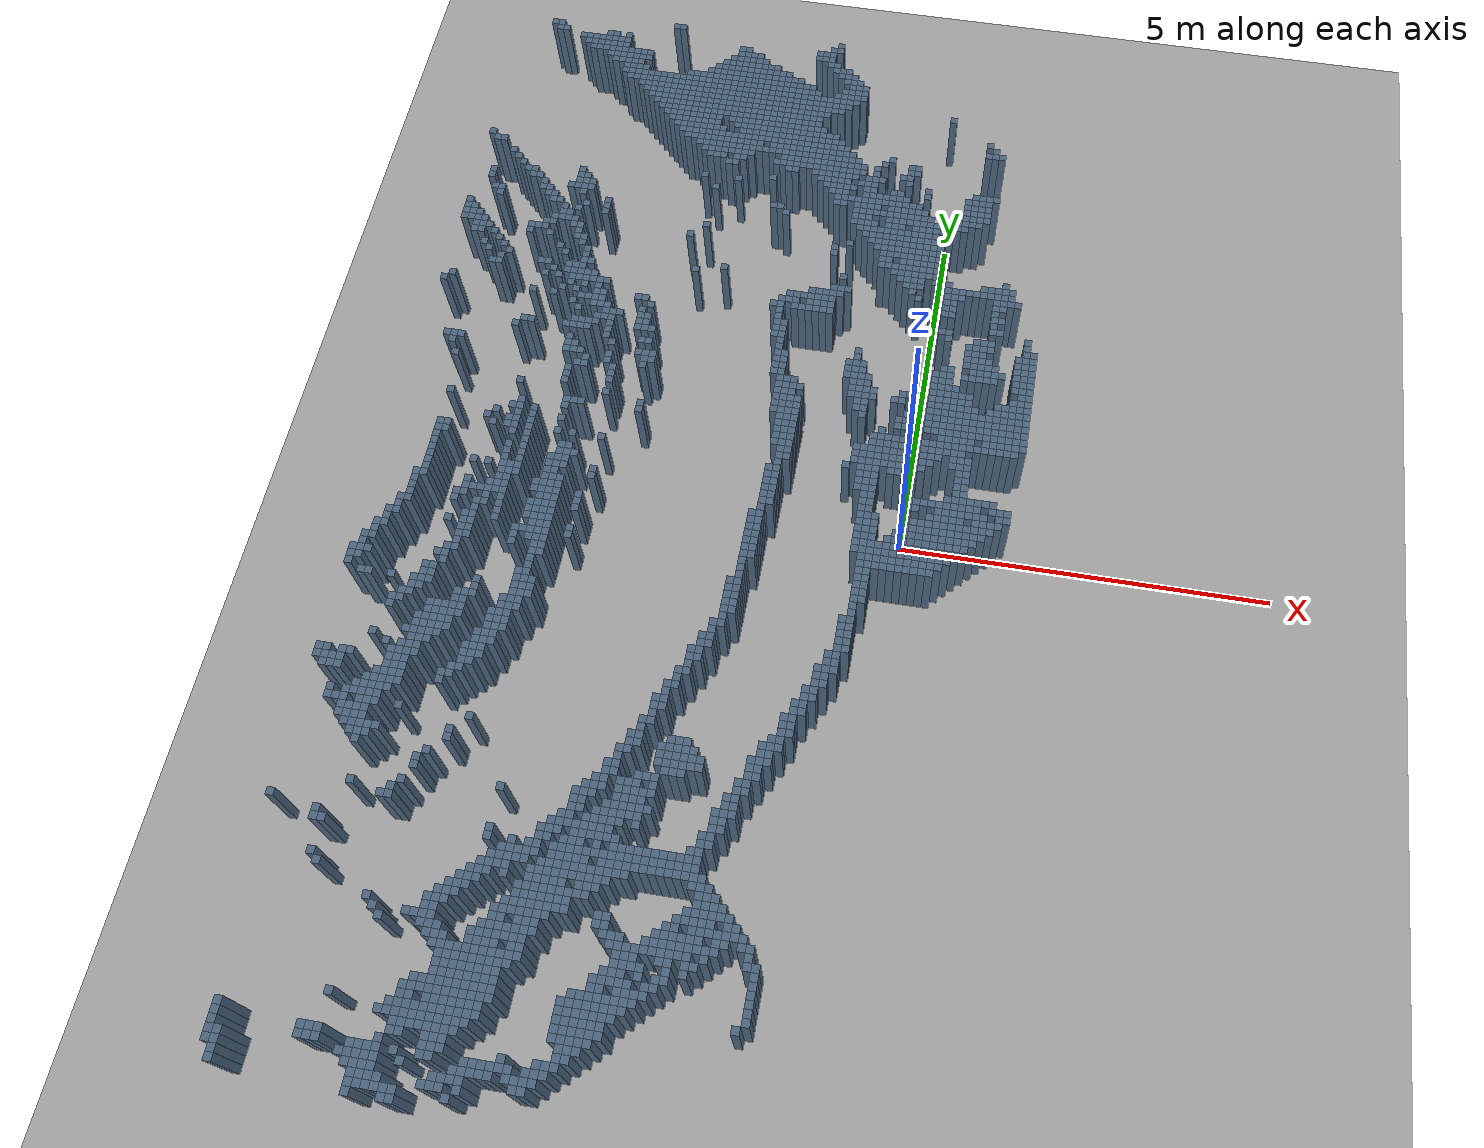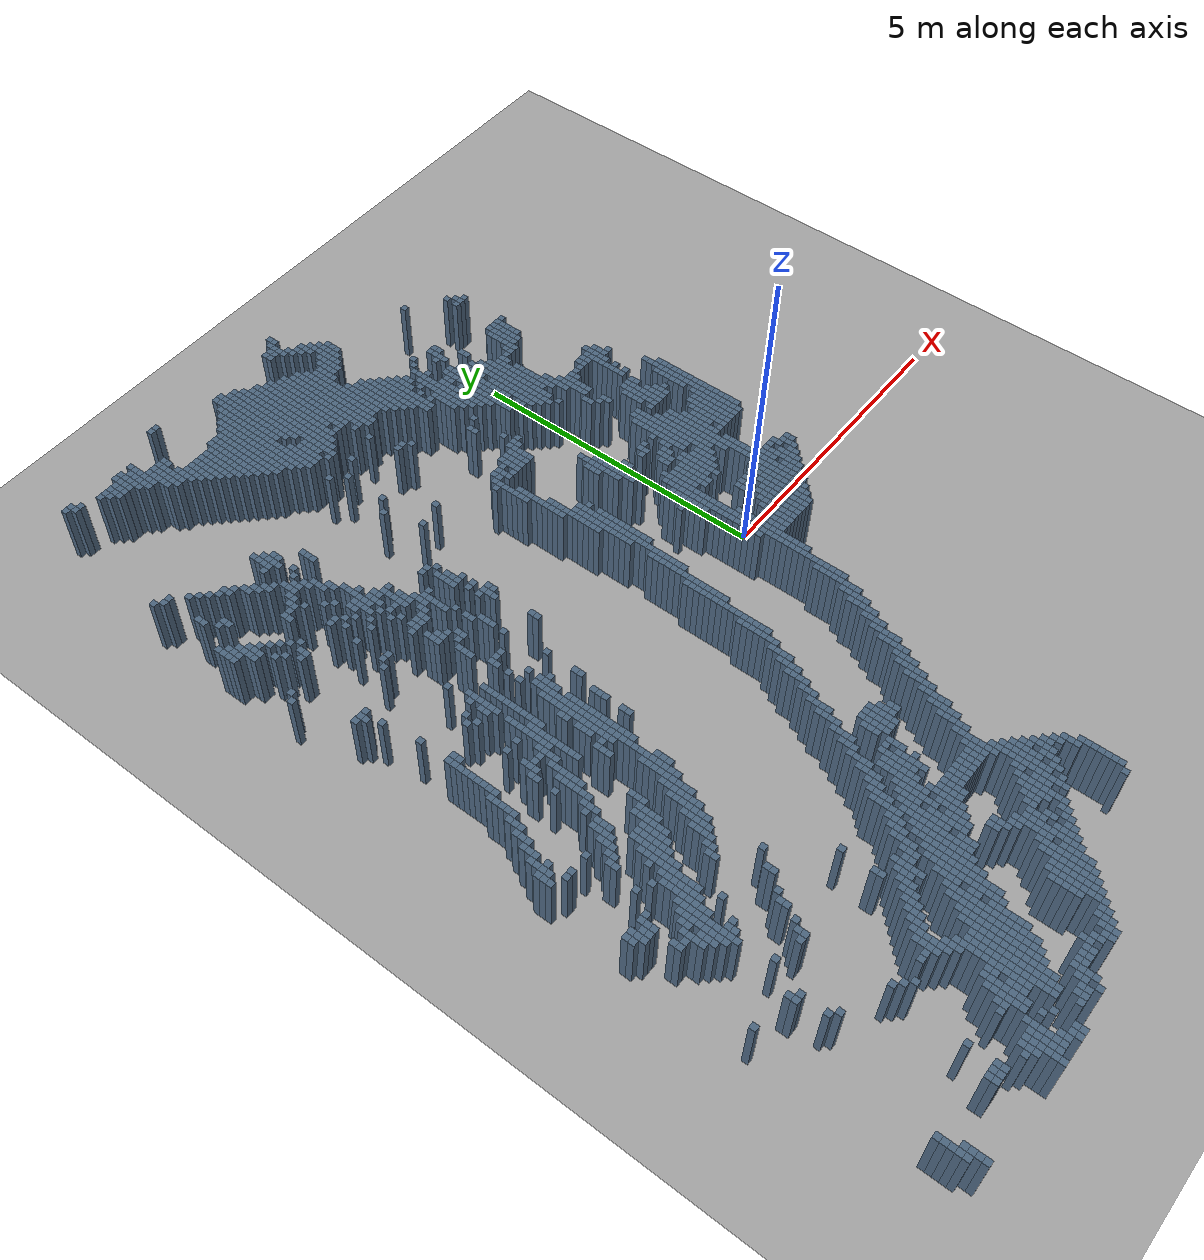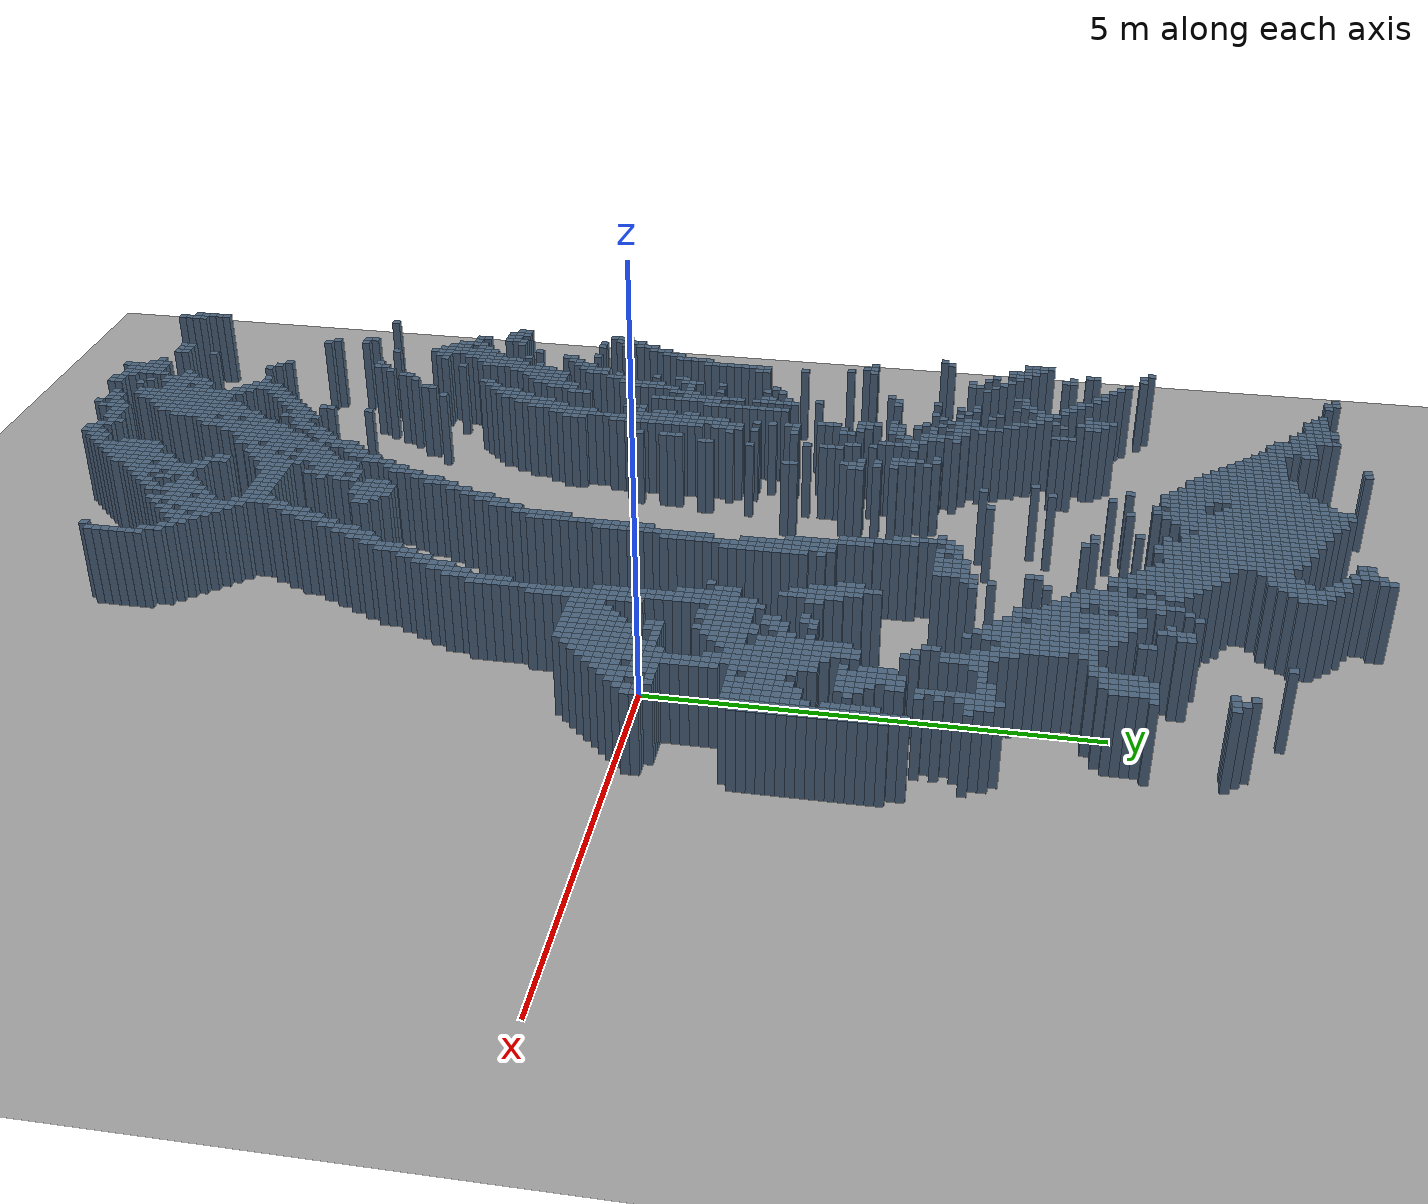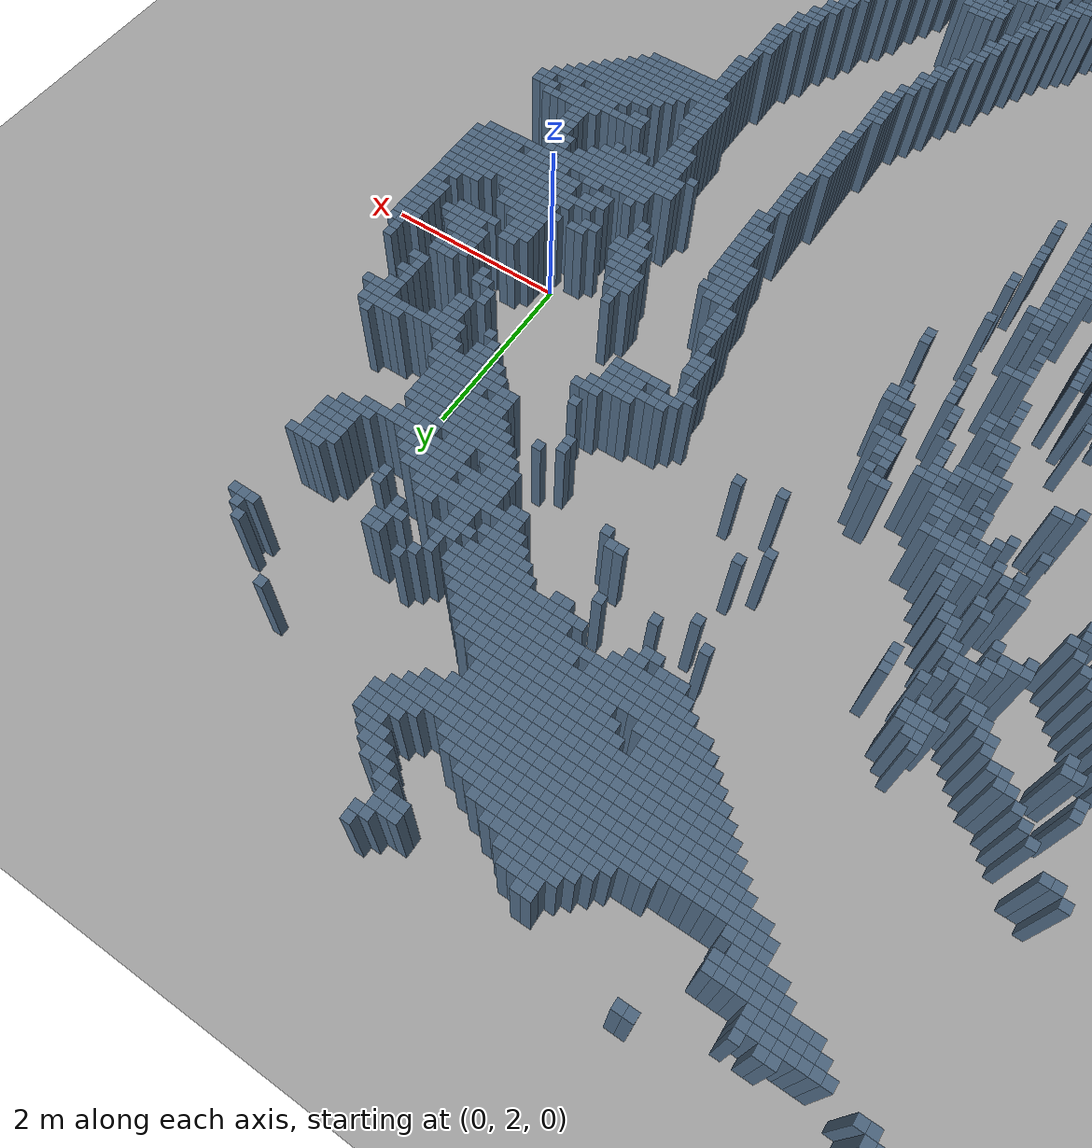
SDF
<?xml version='1.0' encoding='utf-8'?>
<sdf version="1.6">
  <world name="default">
    <gravity>0 0 -9.81</gravity>
    <physics name="default_physics" type="ode">
      <max_step_size>0.001</max_step_size>
      <real_time_update_rate>1000</real_time_update_rate>
    </physics>
    <scene>
      <ambient>0.6 0.6 0.6 1</ambient>
      <shadows>false</shadows>
    </scene>
    <light name="sun" type="directional">
      <pose>0 0 10 0 0 0</pose>
      <diffuse>0.8 0.8 0.8 1</diffuse>
      <direction>-0.5 0.1 -1</direction>
    </light>
    <model name="artificial_flat_ground">
      <static>true</static>
      <link name="ground">
        <collision name="floor_collision">
          <geometry>
            <plane>
              <normal>0 0 1</normal>
              <size>100 100</size>
            </plane>
          </geometry>
        </collision>
        <visual name="floor_visual">
          <geometry>
            <plane>
              <normal>0 0 1</normal>
              <size>100 100</size>
            </plane>
          </geometry>
          <material>
            <ambient>0.65 0.65 0.65 1</ambient>
            <diffuse>0.65 0.65 0.65 1</diffuse>
          </material>
        </visual>
      </link>
    </model>
    <model name="hilti_projected_cells">
      <static>true</static>
      <link name="obstacles">
        <collision name="cell_0_19_collision">
          <pose>-5.05000000 -7.95000000 0.50000000 0 0 0</pose>
          <geometry>
            <box>
              <size>0.10000000 0.10000000 1.00000000</size>
            </box>
          </geometry>
        </collision>
        <visual name="cell_0_19_visual">
          <pose>-5.05000000 -7.95000000 0.50000000 0 0 0</pose>
          <geometry>
            <box>
              <size>0.10000000 0.10000000 1.00000000</size>
            </box>
          </geometry>
          <material>
            <ambient>0.3 0.4 0.5 1</ambient>
            <diffuse>0.3 0.4 0.5 1</diffuse>
          </material>
        </visual>
        <collision name="cell_0_23_collision">
          <pose>-4.65000000 -7.95000000 0.50000000 0 0 0</pose>
          <geometry>
            <box>
              <size>0.10000000 0.10000000 1.00000000</size>
            </box>
          </geometry>
        </collision>
        <visual name="cell_0_23_visual">
          <pose>-4.65000000 -7.95000000 0.50000000 0 0 0</pose>
          <geometry>
            <box>
              <size>0.10000000 0.10000000 1.00000000</size>
            </box>
          </geometry>
          <material>
            <ambient>0.3 0.4 0.5 1</ambient>
            <diffuse>0.3 0.4 0.5 1</diffuse>
          </material>
        </visual>
        <collision name="cell_0_24_collision">
          <pose>-4.55000000 -7.95000000 0.50000000 0 0 0</pose>
          <geometry>
            <box>
              <size>0.10000000 0.10000000 1.00000000</size>
            </box>
          </geometry>
        </collision>
        <visual name="cell_0_24_visual">
          <pose>-4.55000000 -7.95000000 0.50000000 0 0 0</pose>
          <geometry>
            <box>
              <size>0.10000000 0.10000000 1.00000000</size>
            </box>
          </geometry>
          <material>
            <ambient>0.3 0.4 0.5 1</ambient>
            <diffuse>0.3 0.4 0.5 1</diffuse>
          </material>
        </visual>
        <collision name="cell_1_3_collision">
          <pose>-6.65000000 -7.85000000 0.50000000 0 0 0</pose>
          <geometry>
            <box>
              <size>0.10000000 0.10000000 1.00000000</size>
            </box>
          </geometry>
        </collision>
        <visual name="cell_1_3_visual">
          <pose>-6.65000000 -7.85000000 0.50000000 0 0 0</pose>
          <geometry>
            <box>
              <size>0.10000000 0.10000000 1.00000000</size>
            </box>
          </geometry>
          <material>
            <ambient>0.3 0.4 0.5 1</ambient>
            <diffuse>0.3 0.4 0.5 1</diffuse>
          </material>
        </visual>
        <collision name="cell_1_19_collision">
          <pose>-5.05000000 -7.85000000 0.50000000 0 0 0</pose>
          <geometry>
            <box>
              <size>0.10000000 0.10000000 1.00000000</size>
            </box>
          </geometry>
        </collision>
        <visual name="cell_1_19_visual">
          <pose>-5.05000000 -7.85000000 0.50000000 0 0 0</pose>
          <geometry>
            <box>
              <size>0.10000000 0.10000000 1.00000000</size>
            </box>
          </geometry>
          <material>
            <ambient>0.3 0.4 0.5 1</ambient>
            <diffuse>0.3 0.4 0.5 1</diffuse>
          </material>
        </visual>
        <collision name="cell_1_20_collision">
          <pose>-4.95000000 -7.85000000 0.50000000 0 0 0</pose>
          <geometry>
            <box>
              <size>0.10000000 0.10000000 1.00000000</size>
            </box>
          </geometry>
        </collision>
        <visual name="cell_1_20_visual">
          <pose>-4.95000000 -7.85000000 0.50000000 0 0 0</pose>
          <geometry>
            <box>
              <size>0.10000000 0.10000000 1.00000000</size>
            </box>
          </geometry>
          <material>
            <ambient>0.3 0.4 0.5 1</ambient>
            <diffuse>0.3 0.4 0.5 1</diffuse>
          </material>
        </visual>
        <collision name="cell_1_21_collision">
          <pose>-4.85000000 -7.85000000 0.50000000 0 0 0</pose>
          <geometry>
            <box>
              <size>0.10000000 0.10000000 1.00000000</size>
            </box>
          </geometry>
        </collision>
        <visual name="cell_1_21_visual">
          <pose>-4.85000000 -7.85000000 0.50000000 0 0 0</pose>
          <geometry>
            <box>
              <size>0.10000000 0.10000000 1.00000000</size>
            </box>
          </geometry>
          <material>
            <ambient>0.3 0.4 0.5 1</ambient>
            <diffuse>0.3 0.4 0.5 1</diffuse>
          </material>
        </visual>
        <collision name="cell_1_22_collision">
          <pose>-4.75000000 -7.85000000 0.50000000 0 0 0</pose>
          <geometry>
            <box>
              <size>0.10000000 0.10000000 1.00000000</size>
            </box>
          </geometry>
        </collision>
        <visual name="cell_1_22_visual">
          <pose>-4.75000000 -7.85000000 0.50000000 0 0 0</pose>
          <geometry>
            <box>
              <size>0.10000000 0.10000000 1.00000000</size>
            </box>
          </geometry>
          <material>
            <ambient>0.3 0.4 0.5 1</ambient>
            <diffuse>0.3 0.4 0.5 1</diffuse>
          </material>
        </visual>
        <collision name="cell_1_23_collision">
          <pose>-4.65000000 -7.85000000 0.50000000 0 0 0</pose>
          <geometry>
            <box>
              <size>0.10000000 0.10000000 1.00000000</size>
            </box>
          </geometry>
        </collision>
        <visual name="cell_1_23_visual">
          <pose>-4.65000000 -7.85000000 0.50000000 0 0 0</pose>
          <geometry>
            <box>
              <size>0.10000000 0.10000000 1.00000000</size>
            </box>
          </geometry>
          <material>
            <ambient>0.3 0.4 0.5 1</ambient>
            <diffuse>0.3 0.4 0.5 1</diffuse>
          </material>
        </visual>
        <collision name="cell_1_24_collision">
          <pose>-4.55000000 -7.85000000 0.50000000 0 0 0</pose>
          <geometry>
            <box>
              <size>0.10000000 0.10000000 1.00000000</size>
            </box>
          </geometry>
        </collision>
        <visual name="cell_1_24_visual">
          <pose>-4.55000000 -7.85000000 0.50000000 0 0 0</pose>
          <geometry>
            <box>
              <size>0.10000000 0.10000000 1.00000000</size>
            </box>
          </geometry>
          <material>
            <ambient>0.3 0.4 0.5 1</ambient>
            <diffuse>0.3 0.4 0.5 1</diffuse>
          </material>
        </visual>
        <collision name="cell_1_30_collision">
          <pose>-3.95000000 -7.85000000 0.50000000 0 0 0</pose>
          <geometry>
            <box>
              <size>0.10000000 0.10000000 1.00000000</size>
            </box>
          </geometry>
        </collision>
        <visual name="cell_1_30_visual">
          <pose>-3.95000000 -7.85000000 0.50000000 0 0 0</pose>
          <geometry>
            <box>
              <size>0.10000000 0.10000000 1.00000000</size>
            </box>
          </geometry>
          <material>
            <ambient>0.3 0.4 0.5 1</ambient>
            <diffuse>0.3 0.4 0.5 1</diffuse>
          </material>
        </visual>
        <collision name="cell_2_3_collision">
          <pose>-6.65000000 -7.75000000 0.50000000 0 0 0</pose>
          <geometry>
            <box>
              <size>0.10000000 0.10000000 1.00000000</size>
            </box>
          </geometry>
        </collision>
        <visual name="cell_2_3_visual">
          <pose>-6.65000000 -7.75000000 0.50000000 0 0 0</pose>
          <geometry>
            <box>
              <size>0.10000000 0.10000000 1.00000000</size>
            </box>
          </geometry>
          <material>
            <ambient>0.3 0.4 0.5 1</ambient>
            <diffuse>0.3 0.4 0.5 1</diffuse>
          </material>
        </visual>
        <collision name="cell_2_19_collision">
          <pose>-5.05000000 -7.75000000 0.50000000 0 0 0</pose>
          <geometry>
            <box>
              <size>0.10000000 0.10000000 1.00000000</size>
            </box>
          </geometry>
        </collision>
        <visual name="cell_2_19_visual">
          <pose>-5.05000000 -7.75000000 0.50000000 0 0 0</pose>
          <geometry>
            <box>
              <size>0.10000000 0.10000000 1.00000000</size>
            </box>
          </geometry>
          <material>
            <ambient>0.3 0.4 0.5 1</ambient>
            <diffuse>0.3 0.4 0.5 1</diffuse>
          </material>
        </visual>
        <collision name="cell_2_20_collision">
          <pose>-4.95000000 -7.75000000 0.50000000 0 0 0</pose>
          <geometry>
            <box>
              <size>0.10000000 0.10000000 1.00000000</size>
            </box>
          </geometry>
        </collision>
        <visual name="cell_2_20_visual">
          <pose>-4.95000000 -7.75000000 0.50000000 0 0 0</pose>
          <geometry>
            <box>
              <size>0.10000000 0.10000000 1.00000000</size>
            </box>
          </geometry>
          <material>
            <ambient>0.3 0.4 0.5 1</ambient>
            <diffuse>0.3 0.4 0.5 1</diffuse>
          </material>
        </visual>
        <collision name="cell_2_21_collision">
          <pose>-4.85000000 -7.75000000 0.50000000 0 0 0</pose>
          <geometry>
            <box>
              <size>0.10000000 0.10000000 1.00000000</size>
            </box>
          </geometry>
        </collision>
        <visual name="cell_2_21_visual">
          <pose>-4.85000000 -7.75000000 0.50000000 0 0 0</pose>
          <geometry>
            <box>
              <size>0.10000000 0.10000000 1.00000000</size>
            </box>
          </geometry>
          <material>
            <ambient>0.3 0.4 0.5 1</ambient>
            <diffuse>0.3 0.4 0.5 1</diffuse>
          </material>
        </visual>
        <collision name="cell_2_22_collision">
          <pose>-4.75000000 -7.75000000 0.50000000 0 0 0</pose>
          <geometry>
            <box>
              <size>0.10000000 0.10000000 1.00000000</size>
            </box>
          </geometry>
        </collision>
        <visual name="cell_2_22_visual">
          <pose>-4.75000000 -7.75000000 0.50000000 0 0 0</pose>
          <geometry>
            <box>
              <size>0.10000000 0.10000000 1.00000000</size>
            </box>
          </geometry>
          <material>
            <ambient>0.3 0.4 0.5 1</ambient>
            <diffuse>0.3 0.4 0.5 1</diffuse>
          </material>
        </visual>
        <collision name="cell_2_27_collision">
          <pose>-4.25000000 -7.75000000 0.50000000 0 0 0</pose>
          <geometry>
            <box>
              <size>0.10000000 0.10000000 1.00000000</size>
            </box>
          </geometry>
        </collision>
        <visual name="cell_2_27_visual">
          <pose>-4.25000000 -7.75000000 0.50000000 0 0 0</pose>
          <geometry>
            <box>
              <size>0.10000000 0.10000000 1.00000000</size>
            </box>
          </geometry>
          <material>
            <ambient>0.3 0.4 0.5 1</ambient>
            <diffuse>0.3 0.4 0.5 1</diffuse>
          </material>
        </visual>
        <collision name="cell_2_28_collision">
          <pose>-4.15000000 -7.75000000 0.50000000 0 0 0</pose>
          <geometry>
            <box>
              <size>0.10000000 0.10000000 1.00000000</size>
            </box>
          </geometry>
        </collision>
        <visual name="cell_2_28_visual">
          <pose>-4.15000000 -7.75000000 0.50000000 0 0 0</pose>
          <geometry>
            <box>
              <size>0.10000000 0.10000000 1.00000000</size>
            </box>
          </geometry>
          <material>
            <ambient>0.3 0.4 0.5 1</ambient>
            <diffuse>0.3 0.4 0.5 1</diffuse>
          </material>
        </visual>
        <collision name="cell_2_29_collision">
          <pose>-4.05000000 -7.75000000 0.50000000 0 0 0</pose>
          <geometry>
            <box>
              <size>0.10000000 0.10000000 1.00000000</size>
            </box>
          </geometry>
        </collision>
        <visual name="cell_2_29_visual">
          <pose>-4.05000000 -7.75000000 0.50000000 0 0 0</pose>
          <geometry>
            <box>
              <size>0.10000000 0.10000000 1.00000000</size>
            </box>
          </geometry>
          <material>
            <ambient>0.3 0.4 0.5 1</ambient>
            <diffuse>0.3 0.4 0.5 1</diffuse>
          </material>
        </visual>
        <collision name="cell_2_31_collision">
          <pose>-3.85000000 -7.75000000 0.50000000 0 0 0</pose>
          <geometry>
            <box>
              <size>0.10000000 0.10000000 1.00000000</size>
            </box>
          </geometry>
        </collision>
        <visual name="cell_2_31_visual">
          <pose>-3.85000000 -7.75000000 0.50000000 0 0 0</pose>
          <geometry>
            <box>
              <size>0.10000000 0.10000000 1.00000000</size>
            </box>
          </geometry>
          <material>
            <ambient>0.3 0.4 0.5 1</ambient>
            <diffuse>0.3 0.4 0.5 1</diffuse>
          </material>
        </visual>
        <collision name="cell_3_2_collision">
          <pose>-6.75000000 -7.65000000 0.50000000 0 0 0</pose>
          <geometry>
            <box>
              <size>0.10000000 0.10000000 1.00000000</size>
            </box>
          </geometry>
        </collision>
        <visual name="cell_3_2_visual">
          <pose>-6.75000000 -7.65000000 0.50000000 0 0 0</pose>
          <geometry>
            <box>
              <size>0.10000000 0.10000000 1.00000000</size>
            </box>
          </geometry>
          <material>
            <ambient>0.3 0.4 0.5 1</ambient>
            <diffuse>0.3 0.4 0.5 1</diffuse>
          </material>
        </visual>
        <collision name="cell_3_3_collision">
          <pose>-6.65000000 -7.65000000 0.50000000 0 0 0</pose>
          <geometry>
            <box>
              <size>0.10000000 0.10000000 1.00000000</size>
            </box>
          </geometry>
        </collision>
        <visual name="cell_3_3_visual">
          <pose>-6.65000000 -7.65000000 0.50000000 0 0 0</pose>
          <geometry>
            <box>
              <size>0.10000000 0.10000000 1.00000000</size>
            </box>
          </geometry>
          <material>
            <ambient>0.3 0.4 0.5 1</ambient>
            <diffuse>0.3 0.4 0.5 1</diffuse>
          </material>
        </visual>
        <collision name="cell_3_18_collision">
          <pose>-5.15000000 -7.65000000 0.50000000 0 0 0</pose>
          <geometry>
            <box>
              <size>0.10000000 0.10000000 1.00000000</size>
            </box>
          </geometry>
        </collision>
        <visual name="cell_3_18_visual">
          <pose>-5.15000000 -7.65000000 0.50000000 0 0 0</pose>
          <geometry>
            <box>
              <size>0.10000000 0.10000000 1.00000000</size>
            </box>
          </geometry>
          <material>
            <ambient>0.3 0.4 0.5 1</ambient>
            <diffuse>0.3 0.4 0.5 1</diffuse>
          </material>
        </visual>
        <collision name="cell_3_19_collision">
          <pose>-5.05000000 -7.65000000 0.50000000 0 0 0</pose>
          <geometry>
            <box>
              <size>0.10000000 0.10000000 1.00000000</size>
            </box>
          </geometry>
        </collision>
        <visual name="cell_3_19_visual">
          <pose>-5.05000000 -7.65000000 0.50000000 0 0 0</pose>
          <geometry>
            <box>
              <size>0.10000000 0.10000000 1.00000000</size>
            </box>
          </geometry>
          <material>
            <ambient>0.3 0.4 0.5 1</ambient>
            <diffuse>0.3 0.4 0.5 1</diffuse>
          </material>
        </visual>
        <collision name="cell_3_20_collision">
          <pose>-4.95000000 -7.65000000 0.50000000 0 0 0</pose>
          <geometry>
            <box>
              <size>0.10000000 0.10000000 1.00000000</size>
            </box>
          </geometry>
        </collision>
        <visual name="cell_3_20_visual">
          <pose>-4.95000000 -7.65000000 0.50000000 0 0 0</pose>
          <geometry>
            <box>
              <size>0.10000000 0.10000000 1.00000000</size>
            </box>
          </geometry>
          <material>
            <ambient>0.3 0.4 0.5 1</ambient>
            <diffuse>0.3 0.4 0.5 1</diffuse>
          </material>
        </visual>
        <collision name="cell_3_21_collision">
          <pose>-4.85000000 -7.65000000 0.50000000 0 0 0</pose>
          <geometry>
            <box>
              <size>0.10000000 0.10000000 1.00000000</size>
            </box>
          </geometry>
        </collision>
        <visual name="cell_3_21_visual">
          <pose>-4.85000000 -7.65000000 0.50000000 0 0 0</pose>
          <geometry>
            <box>
              <size>0.10000000 0.10000000 1.00000000</size>
            </box>
          </geometry>
          <material>
            <ambient>0.3 0.4 0.5 1</ambient>
            <diffuse>0.3 0.4 0.5 1</diffuse>
          </material>
        </visual>
        <collision name="cell_3_28_collision">
          <pose>-4.15000000 -7.65000000 0.50000000 0 0 0</pose>
          <geometry>
            <box>
              <size>0.10000000 0.10000000 1.00000000</size>
            </box>
          </geometry>
        </collision>
        <visual name="cell_3_28_visual">
          <pose>-4.15000000 -7.65000000 0.50000000 0 0 0</pose>
          <geometry>
            <box>
              <size>0.10000000 0.10000000 1.00000000</size>
            </box>
          </geometry>
          <material>
            <ambient>0.3 0.4 0.5 1</ambient>
            <diffuse>0.3 0.4 0.5 1</diffuse>
          </material>
        </visual>
        <collision name="cell_3_29_collision">
          <pose>-4.05000000 -7.65000000 0.50000000 0 0 0</pose>
          <geometry>
            <box>
              <size>0.10000000 0.10000000 1.00000000</size>
            </box>
          </geometry>
        </collision>
        <visual name="cell_3_29_visual">
          <pose>-4.05000000 -7.65000000 0.50000000 0 0 0</pose>
          <geometry>
            <box>
              <size>0.10000000 0.10000000 1.00000000</size>
            </box>
          </geometry>
          <material>
            <ambient>0.3 0.4 0.5 1</ambient>
            <diffuse>0.3 0.4 0.5 1</diffuse>
          </material>
        </visual>
        <collision name="cell_3_30_collision">
          <pose>-3.95000000 -7.65000000 0.50000000 0 0 0</pose>
          <geometry>
            <box>
              <size>0.10000000 0.10000000 1.00000000</size>
            </box>
          </geometry>
        </collision>
        <visual name="cell_3_30_visual">
          <pose>-3.95000000 -7.65000000 0.50000000 0 0 0</pose>
          <geometry>
            <box>
              <size>0.10000000 0.10000000 1.00000000</size>
            </box>
          </geometry>
          <material>
            <ambient>0.3 0.4 0.5 1</ambient>
            <diffuse>0.3 0.4 0.5 1</diffuse>
          </material>
        </visual>
        <collision name="cell_3_31_collision">
          <pose>-3.85000000 -7.65000000 0.50000000 0 0 0</pose>
          <geometry>
            <box>
              <size>0.10000000 0.10000000 1.00000000</size>
            </box>
          </geometry>
        </collision>
        <visual name="cell_3_31_visual">
          <pose>-3.85000000 -7.65000000 0.50000000 0 0 0</pose>
          <geometry>
            <box>
              <size>0.10000000 0.10000000 1.00000000</size>
            </box>
          </geometry>
          <material>
            <ambient>0.3 0.4 0.5 1</ambient>
            <diffuse>0.3 0.4 0.5 1</diffuse>
          </material>
        </visual>
        <collision name="cell_3_37_collision">
          <pose>-3.25000000 -7.65000000 0.50000000 0 0 0</pose>
          <geometry>
            <box>
              <size>0.10000000 0.10000000 1.00000000</size>
            </box>
          </geometry>
        </collision>
        <visual name="cell_3_37_visual">
          <pose>-3.25000000 -7.65000000 0.50000000 0 0 0</pose>
          <geometry>
            <box>
              <size>0.10000000 0.10000000 1.00000000</size>
            </box>
          </geometry>
          <material>
            <ambient>0.3 0.4 0.5 1</ambient>
            <diffuse>0.3 0.4 0.5 1</diffuse>
          </material>
        </visual>
        <collision name="cell_3_38_collision">
          <pose>-3.15000000 -7.65000000 0.50000000 0 0 0</pose>
          <geometry>
            <box>
              <size>0.10000000 0.10000000 1.00000000</size>
            </box>
          </geometry>
        </collision>
        <visual name="cell_3_38_visual">
          <pose>-3.15000000 -7.65000000 0.50000000 0 0 0</pose>
          <geometry>
            <box>
              <size>0.10000000 0.10000000 1.00000000</size>
            </box>
          </geometry>
          <material>
            <ambient>0.3 0.4 0.5 1</ambient>
            <diffuse>0.3 0.4 0.5 1</diffuse>
          </material>
        </visual>
        <collision name="cell_4_2_collision">
          <pose>-6.75000000 -7.55000000 0.50000000 0 0 0</pose>
          <geometry>
            <box>
              <size>0.10000000 0.10000000 1.00000000</size>
            </box>
          </geometry>
        </collision>
        <visual name="cell_4_2_visual">
          <pose>-6.75000000 -7.55000000 0.50000000 0 0 0</pose>
          <geometry>
            <box>
              <size>0.10000000 0.10000000 1.00000000</size>
            </box>
          </geometry>
          <material>
            <ambient>0.3 0.4 0.5 1</ambient>
            <diffuse>0.3 0.4 0.5 1</diffuse>
          </material>
        </visual>
        <collision name="cell_4_3_collision">
          <pose>-6.65000000 -7.55000000 0.50000000 0 0 0</pose>
          <geometry>
            <box>
              <size>0.10000000 0.10000000 1.00000000</size>
            </box>
          </geometry>
        </collision>
        <visual name="cell_4_3_visual">
          <pose>-6.65000000 -7.55000000 0.50000000 0 0 0</pose>
          <geometry>
            <box>
              <size>0.10000000 0.10000000 1.00000000</size>
            </box>
          </geometry>
          <material>
            <ambient>0.3 0.4 0.5 1</ambient>
            <diffuse>0.3 0.4 0.5 1</diffuse>
          </material>
        </visual>
        <collision name="cell_4_17_collision">
          <pose>-5.25000000 -7.55000000 0.50000000 0 0 0</pose>
          <geometry>
            <box>
              <size>0.10000000 0.10000000 1.00000000</size>
            </box>
          </geometry>
        </collision>
        <visual name="cell_4_17_visual">
          <pose>-5.25000000 -7.55000000 0.50000000 0 0 0</pose>
          <geometry>
            <box>
              <size>0.10000000 0.10000000 1.00000000</size>
            </box>
          </geometry>
          <material>
            <ambient>0.3 0.4 0.5 1</ambient>
            <diffuse>0.3 0.4 0.5 1</diffuse>
          </material>
        </visual>
        <collision name="cell_4_18_collision">
          <pose>-5.15000000 -7.55000000 0.50000000 0 0 0</pose>
          <geometry>
            <box>
              <size>0.10000000 0.10000000 1.00000000</size>
            </box>
          </geometry>
        </collision>
        <visual name="cell_4_18_visual">
          <pose>-5.15000000 -7.55000000 0.50000000 0 0 0</pose>
          <geometry>
            <box>
              <size>0.10000000 0.10000000 1.00000000</size>
            </box>
          </geometry>
          <material>
            <ambient>0.3 0.4 0.5 1</ambient>
            <diffuse>0.3 0.4 0.5 1</diffuse>
          </material>
        </visual>
        <collision name="cell_4_19_collision">
          <pose>-5.05000000 -7.55000000 0.50000000 0 0 0</pose>
          <geometry>
            <box>
              <size>0.10000000 0.10000000 1.00000000</size>
            </box>
          </geometry>
        </collision>
        <visual name="cell_4_19_visual">
          <pose>-5.05000000 -7.55000000 0.50000000 0 0 0</pose>
          <geometry>
            <box>
              <size>0.10000000 0.10000000 1.00000000</size>
            </box>
          </geometry>
          <material>
            <ambient>0.3 0.4 0.5 1</ambient>
            <diffuse>0.3 0.4 0.5 1</diffuse>
          </material>
        </visual>
        <collision name="cell_4_20_collision">
          <pose>-4.95000000 -7.55000000 0.50000000 0 0 0</pose>
          <geometry>
            <box>
              <size>0.10000000 0.10000000 1.00000000</size>
            </box>
          </geometry>
        </collision>
        <visual name="cell_4_20_visual">
          <pose>-4.95000000 -7.55000000 0.50000000 0 0 0</pose>
          <geometry>
            <box>
              <size>0.10000000 0.10000000 1.00000000</size>
            </box>
          </geometry>
          <material>
            <ambient>0.3 0.4 0.5 1</ambient>
            <diffuse>0.3 0.4 0.5 1</diffuse>
          </material>
        </visual>
        <collision name="cell_4_21_collision">
          <pose>-4.85000000 -7.55000000 0.50000000 0 0 0</pose>
          <geometry>
            <box>
              <size>0.10000000 0.10000000 1.00000000</size>
            </box>
          </geometry>
        </collision>
        <visual name="cell_4_21_visual">
          <pose>-4.85000000 -7.55000000 0.50000000 0 0 0</pose>
          <geometry>
            <box>
              <size>0.10000000 0.10000000 1.00000000</size>
            </box>
          </geometry>
          <material>
            <ambient>0.3 0.4 0.5 1</ambient>
            <diffuse>0.3 0.4 0.5 1</diffuse>
          </material>
        </visual>
        <collision name="cell_4_24_collision">
          <pose>-4.55000000 -7.55000000 0.50000000 0 0 0</pose>
          <geometry>
            <box>
              <size>0.10000000 0.10000000 1.00000000</size>
            </box>
          </geometry>
        </collision>
        <visual name="cell_4_24_visual">
          <pose>-4.55000000 -7.55000000 0.50000000 0 0 0</pose>
          <geometry>
            <box>
              <size>0.10000000 0.10000000 1.00000000</size>
            </box>
          </geometry>
          <material>
            <ambient>0.3 0.4 0.5 1</ambient>
            <diffuse>0.3 0.4 0.5 1</diffuse>
          </material>
        </visual>
        <collision name="cell_4_30_collision">
          <pose>-3.95000000 -7.55000000 0.50000000 0 0 0</pose>
          <geometry>
            <box>
              <size>0.10000000 0.10000000 1.00000000</size>
            </box>
          </geometry>
        </collision>
        <visual name="cell_4_30_visual">
          <pose>-3.95000000 -7.55000000 0.50000000 0 0 0</pose>
          <geometry>
            <box>
              <size>0.10000000 0.10000000 1.00000000</size>
            </box>
          </geometry>
          <material>
            <ambient>0.3 0.4 0.5 1</ambient>
            <diffuse>0.3 0.4 0.5 1</diffuse>
          </material>
        </visual>
        <collision name="cell_4_31_collision">
          <pose>-3.85000000 -7.55000000 0.50000000 0 0 0</pose>
          <geometry>
            <box>
              <size>0.10000000 0.10000000 1.00000000</size>
            </box>
          </geometry>
        </collision>
        <visual name="cell_4_31_visual">
          <pose>-3.85000000 -7.55000000 0.50000000 0 0 0</pose>
          <geometry>
            <box>
              <size>0.10000000 0.10000000 1.00000000</size>
            </box>
          </geometry>
          <material>
            <ambient>0.3 0.4 0.5 1</ambient>
            <diffuse>0.3 0.4 0.5 1</diffuse>
          </material>
        </visual>
        <collision name="cell_4_32_collision">
          <pose>-3.75000000 -7.55000000 0.50000000 0 0 0</pose>
          <geometry>
            <box>
              <size>0.10000000 0.10000000 1.00000000</size>
            </box>
          </geometry>
        </collision>
        <visual name="cell_4_32_visual">
          <pose>-3.75000000 -7.55000000 0.50000000 0 0 0</pose>
          <geometry>
            <box>
              <size>0.10000000 0.10000000 1.00000000</size>
            </box>
          </geometry>
          <material>
            <ambient>0.3 0.4 0.5 1</ambient>
            <diffuse>0.3 0.4 0.5 1</diffuse>
          </material>
        </visual>
        <collision name="cell_4_33_collision">
          <pose>-3.65000000 -7.55000000 0.50000000 0 0 0</pose>
          <geometry>
            <box>
              <size>0.10000000 0.10000000 1.00000000</size>
            </box>
          </geometry>
        </collision>
        <visual name="cell_4_33_visual">
          <pose>-3.65000000 -7.55000000 0.50000000 0 0 0</pose>
          <geometry>
            <box>
              <size>0.10000000 0.10000000 1.00000000</size>
            </box>
          </geometry>
          <material>
            <ambient>0.3 0.4 0.5 1</ambient>
            <diffuse>0.3 0.4 0.5 1</diffuse>
          </material>
        </visual>
        <collision name="cell_4_34_collision">
          <pose>-3.55000000 -7.55000000 0.50000000 0 0 0</pose>
          <geometry>
            <box>
              <size>0.10000000 0.10000000 1.00000000</size>
            </box>
          </geometry>
        </collision>
        <visual name="cell_4_34_visual">
          <pose>-3.55000000 -7.55000000 0.50000000 0 0 0</pose>
          <geometry>
            <box>
              <size>0.10000000 0.10000000 1.00000000</size>
            </box>
          </geometry>
          <material>
            <ambient>0.3 0.4 0.5 1</ambient>
            <diffuse>0.3 0.4 0.5 1</diffuse>
          </material>
        </visual>
        <collision name="cell_4_36_collision">
          <pose>-3.35000000 -7.55000000 0.50000000 0 0 0</pose>
          <geometry>
            <box>
              <size>0.10000000 0.10000000 1.00000000</size>
            </box>
          </geometry>
        </collision>
        <visual name="cell_4_36_visual">
          <pose>-3.35000000 -7.55000000 0.50000000 0 0 0</pose>
          <geometry>
            <box>
              <size>0.10000000 0.10000000 1.00000000</size>
            </box>
          </geometry>
          <material>
            <ambient>0.3 0.4 0.5 1</ambient>
            <diffuse>0.3 0.4 0.5 1</diffuse>
          </material>
        </visual>
        <collision name="cell_4_37_collision">
          <pose>-3.25000000 -7.55000000 0.50000000 0 0 0</pose>
          <geometry>
            <box>
              <size>0.10000000 0.10000000 1.00000000</size>
            </box>
          </geometry>
        </collision>
        <visual name="cell_4_37_visual">
          <pose>-3.25000000 -7.55000000 0.50000000 0 0 0</pose>
          <geometry>
            <box>
              <size>0.10000000 0.10000000 1.00000000</size>
            </box>
          </geometry>
          <material>
            <ambient>0.3 0.4 0.5 1</ambient>
            <diffuse>0.3 0.4 0.5 1</diffuse>
          </material>
        </visual>
        <collision name="cell_4_38_collision">
          <pose>-3.15000000 -7.55000000 0.50000000 0 0 0</pose>
          <geometry>
            <box>
              <size>0.10000000 0.10000000 1.00000000</size>
            </box>
          </geometry>
        </collision>
        <visual name="cell_4_38_visual">
          <pose>-3.15000000 -7.55000000 0.50000000 0 0 0</pose>
          <geometry>
            <box>
              <size>0.10000000 0.10000000 1.00000000</size>
            </box>
          </geometry>
          <material>
            <ambient>0.3 0.4 0.5 1</ambient>
            <diffuse>0.3 0.4 0.5 1</diffuse>
          </material>
        </visual>
        <collision name="cell_4_39_collision">
          <pose>-3.05000000 -7.55000000 0.50000000 0 0 0</pose>
          <geometry>
            <box>
              <size>0.10000000 0.10000000 1.00000000</size>
            </box>
          </geometry>
        </collision>
        <visual name="cell_4_39_visual">
          <pose>-3.05000000 -7.55000000 0.50000000 0 0 0</pose>
          <geometry>
            <box>
              <size>0.10000000 0.10000000 1.00000000</size>
            </box>
          </geometry>
          <material>
            <ambient>0.3 0.4 0.5 1</ambient>
            <diffuse>0.3 0.4 0.5 1</diffuse>
          </material>
        </visual>
        <collision name="cell_5_2_collision">
          <pose>-6.75000000 -7.45000000 0.50000000 0 0 0</pose>
          <geometry>
            <box>
              <size>0.10000000 0.10000000 1.00000000</size>
            </box>
          </geometry>
        </collision>
        <visual name="cell_5_2_visual">
          <pose>-6.75000000 -7.45000000 0.50000000 0 0 0</pose>
          <geometry>
            <box>
              <size>0.10000000 0.10000000 1.00000000</size>
            </box>
          </geometry>
          <material>
            <ambient>0.3 0.4 0.5 1</ambient>
            <diffuse>0.3 0.4 0.5 1</diffuse>
          </material>
        </visual>
        <collision name="cell_5_12_collision">
          <pose>-5.75000000 -7.45000000 0.50000000 0 0 0</pose>
          <geometry>
            <box>
              <size>0.10000000 0.10000000 1.00000000</size>
            </box>
          </geometry>
        </collision>
        <visual name="cell_5_12_visual">
          <pose>-5.75000000 -7.45000000 0.50000000 0 0 0</pose>
          <geometry>
            <box>
              <size>0.10000000 0.10000000 1.00000000</size>
            </box>
          </geometry>
          <material>
            <ambient>0.3 0.4 0.5 1</ambient>
            <diffuse>0.3 0.4 0.5 1</diffuse>
          </material>
        </visual>
        <collision name="cell_5_13_collision">
          <pose>-5.65000000 -7.45000000 0.50000000 0 0 0</pose>
          <geometry>
            <box>
              <size>0.10000000 0.10000000 1.00000000</size>
            </box>
          </geometry>
        </collision>
        <visual name="cell_5_13_visual">
          <pose>-5.65000000 -7.45000000 0.50000000 0 0 0</pose>
          <geometry>
            <box>
              <size>0.10000000 0.10000000 1.00000000</size>
            </box>
          </geometry>
          <material>
            <ambient>0.3 0.4 0.5 1</ambient>
            <diffuse>0.3 0.4 0.5 1</diffuse>
          </material>
        </visual>
        <collision name="cell_5_14_collision">
          <pose>-5.55000000 -7.45000000 0.50000000 0 0 0</pose>
          <geometry>
            <box>
              <size>0.10000000 0.10000000 1.00000000</size>
            </box>
          </geometry>
        </collision>
        <visual name="cell_5_14_visual">
          <pose>-5.55000000 -7.45000000 0.50000000 0 0 0</pose>
          <geometry>
            <box>
              <size>0.10000000 0.10000000 1.00000000</size>
            </box>
          </geometry>
          <material>
            <ambient>0.3 0.4 0.5 1</ambient>
            <diffuse>0.3 0.4 0.5 1</diffuse>
          </material>
        </visual>
        <collision name="cell_5_18_collision">
          <pose>-5.15000000 -7.45000000 0.50000000 0 0 0</pose>
          <geometry>
            <box>
              <size>0.10000000 0.10000000 1.00000000</size>
            </box>
          </geometry>
        </collision>
        <visual name="cell_5_18_visual">
          <pose>-5.15000000 -7.45000000 0.50000000 0 0 0</pose>
          <geometry>
            <box>
              <size>0.10000000 0.10000000 1.00000000</size>
            </box>
          </geometry>
          <material>
            <ambient>0.3 0.4 0.5 1</ambient>
            <diffuse>0.3 0.4 0.5 1</diffuse>
          </material>
        </visual>
        <collision name="cell_5_19_collision">
          <pose>-5.05000000 -7.45000000 0.50000000 0 0 0</pose>
          <geometry>
            <box>
              <size>0.10000000 0.10000000 1.00000000</size>
            </box>
          </geometry>
        </collision>
        <visual name="cell_5_19_visual">
          <pose>-5.05000000 -7.45000000 0.50000000 0 0 0</pose>
          <geometry>
            <box>
              <size>0.10000000 0.10000000 1.00000000</size>
            </box>
          </geometry>
          <material>
            <ambient>0.3 0.4 0.5 1</ambient>
            <diffuse>0.3 0.4 0.5 1</diffuse>
          </material>
        </visual>
        <collision name="cell_5_20_collision">
          <pose>-4.95000000 -7.45000000 0.50000000 0 0 0</pose>
          <geometry>
            <box>
              <size>0.10000000 0.10000000 1.00000000</size>
            </box>
          </geometry>
        </collision>
        <visual name="cell_5_20_visual">
          <pose>-4.95000000 -7.45000000 0.50000000 0 0 0</pose>
          <geometry>
            <box>
              <size>0.10000000 0.10000000 1.00000000</size>
            </box>
          </geometry>
          <material>
            <ambient>0.3 0.4 0.5 1</ambient>
            <diffuse>0.3 0.4 0.5 1</diffuse>
          </material>
        </visual>
        <collision name="cell_5_21_collision">
          <pose>-4.85000000 -7.45000000 0.50000000 0 0 0</pose>
          <geometry>
            <box>
              <size>0.10000000 0.10000000 1.00000000</size>
            </box>
          </geometry>
        </collision>
        <visual name="cell_5_21_visual">
          <pose>-4.85000000 -7.45000000 0.50000000 0 0 0</pose>
          <geometry>
            <box>
              <size>0.10000000 0.10000000 1.00000000</size>
            </box>
          </geometry>
          <material>
            <ambient>0.3 0.4 0.5 1</ambient>
            <diffuse>0.3 0.4 0.5 1</diffuse>
          </material>
        </visual>
        <collision name="cell_5_23_collision">
          <pose>-4.65000000 -7.45000000 0.50000000 0 0 0</pose>
          <geometry>
            <box>
              <size>0.10000000 0.10000000 1.00000000</size>
            </box>
          </geometry>
        </collision>
        <visual name="cell_5_23_visual">
          <pose>-4.65000000 -7.45000000 0.50000000 0 0 0</pose>
          <geometry>
            <box>
              <size>0.10000000 0.10000000 1.00000000</size>
            </box>
          </geometry>
          <material>
            <ambient>0.3 0.4 0.5 1</ambient>
            <diffuse>0.3 0.4 0.5 1</diffuse>
          </material>
        </visual>
        <collision name="cell_5_26_collision">
          <pose>-4.35000000 -7.45000000 0.50000000 0 0 0</pose>
          <geometry>
            <box>
              <size>0.10000000 0.10000000 1.00000000</size>
            </box>
          </geometry>
        </collision>
        <visual name="cell_5_26_visual">
          <pose>-4.35000000 -7.45000000 0.50000000 0 0 0</pose>
          <geometry>
            <box>
              <size>0.10000000 0.10000000 1.00000000</size>
            </box>
          </geometry>
          <material>
            <ambient>0.3 0.4 0.5 1</ambient>
            <diffuse>0.3 0.4 0.5 1</diffuse>
          </material>
        </visual>
        <collision name="cell_5_27_collision">
          <pose>-4.25000000 -7.45000000 0.50000000 0 0 0</pose>
          <geometry>
            <box>
              <size>0.10000000 0.10000000 1.00000000</size>
            </box>
          </geometry>
        </collision>
        <visual name="cell_5_27_visual">
          <pose>-4.25000000 -7.45000000 0.50000000 0 0 0</pose>
          <geometry>
            <box>
              <size>0.10000000 0.10000000 1.00000000</size>
            </box>
          </geometry>
          <material>
            <ambient>0.3 0.4 0.5 1</ambient>
            <diffuse>0.3 0.4 0.5 1</diffuse>
          </material>
        </visual>
        <collision name="cell_5_31_collision">
          <pose>-3.85000000 -7.45000000 0.50000000 0 0 0</pose>
          <geometry>
            <box>
              <size>0.10000000 0.10000000 1.00000000</size>
            </box>
          </geometry>
        </collision>
        <visual name="cell_5_31_visual">
          <pose>-3.85000000 -7.45000000 0.50000000 0 0 0</pose>
          <geometry>
            <box>
              <size>0.10000000 0.10000000 1.00000000</size>
            </box>
          </geometry>
          <material>
            <ambient>0.3 0.4 0.5 1</ambient>
            <diffuse>0.3 0.4 0.5 1</diffuse>
          </material>
        </visual>
        <collision name="cell_5_32_collision">
          <pose>-3.75000000 -7.45000000 0.50000000 0 0 0</pose>
          <geometry>
            <box>
              <size>0.10000000 0.10000000 1.00000000</size>
            </box>
          </geometry>
        </collision>
        <visual name="cell_5_32_visual">
          <pose>-3.75000000 -7.45000000 0.50000000 0 0 0</pose>
          <geometry>
            <box>
              <size>0.10000000 0.10000000 1.00000000</size>
            </box>
          </geometry>
          <material>
            <ambient>0.3 0.4 0.5 1</ambient>
            <diffuse>0.3 0.4 0.5 1</diffuse>
          </material>
        </visual>
        <collision name="cell_5_33_collision">
          <pose>-3.65000000 -7.45000000 0.50000000 0 0 0</pose>
          <geometry>
            <box>
              <size>0.10000000 0.10000000 1.00000000</size>
            </box>
          </geometry>
        </collision>
        <visual name="cell_5_33_visual">
          <pose>-3.65000000 -7.45000000 0.50000000 0 0 0</pose>
          <geometry>
            <box>
              <size>0.10000000 0.10000000 1.00000000</size>
            </box>
          </geometry>
          <material>
            <ambient>0.3 0.4 0.5 1</ambient>
            <diffuse>0.3 0.4 0.5 1</diffuse>
          </material>
        </visual>
        <collision name="cell_5_34_collision">
          <pose>-3.55000000 -7.45000000 0.50000000 0 0 0</pose>
          <geometry>
            <box>
              <size>0.10000000 0.10000000 1.00000000</size>
            </box>
          </geometry>
        </collision>
        <visual name="cell_5_34_visual">
          <pose>-3.55000000 -7.45000000 0.50000000 0 0 0</pose>
          <geometry>
            <box>
              <size>0.10000000 0.10000000 1.00000000</size>
            </box>
          </geometry>
          <material>
            <ambient>0.3 0.4 0.5 1</ambient>
            <diffuse>0.3 0.4 0.5 1</diffuse>
          </material>
        </visual>
        <collision name="cell_5_35_collision">
          <pose>-3.45000000 -7.45000000 0.50000000 0 0 0</pose>
          <geometry>
            <box>
              <size>0.10000000 0.10000000 1.00000000</size>
            </box>
          </geometry>
        </collision>
        <visual name="cell_5_35_visual">
          <pose>-3.45000000 -7.45000000 0.50000000 0 0 0</pose>
          <geometry>
            <box>
              <size>0.10000000 0.10000000 1.00000000</size>
            </box>
          </geometry>
          <material>
            <ambient>0.3 0.4 0.5 1</ambient>
            <diffuse>0.3 0.4 0.5 1</diffuse>
          </material>
        </visual>
        <collision name="cell_5_36_collision">
          <pose>-3.35000000 -7.45000000 0.50000000 0 0 0</pose>
          <geometry>
            <box>
              <size>0.10000000 0.10000000 1.00000000</size>
            </box>
          </geometry>
        </collision>
        <visual name="cell_5_36_visual">
          <pose>-3.35000000 -7.45000000 0.50000000 0 0 0</pose>
          <geometry>
            <box>
              <size>0.10000000 0.10000000 1.00000000</size>
            </box>
          </geometry>
          <material>
            <ambient>0.3 0.4 0.5 1</ambient>
            <diffuse>0.3 0.4 0.5 1</diffuse>
          </material>
        </visual>
        <collision name="cell_5_38_collision">
          <pose>-3.15000000 -7.45000000 0.50000000 0 0 0</pose>
          <geometry>
            <box>
              <size>0.10000000 0.10000000 1.00000000</size>
            </box>
          </geometry>
        </collision>
        <visual name="cell_5_38_visual">
          <pose>-3.15000000 -7.45000000 0.50000000 0 0 0</pose>
          <geometry>
            <box>
              <size>0.10000000 0.10000000 1.00000000</size>
            </box>
          </geometry>
          <material>
            <ambient>0.3 0.4 0.5 1</ambient>
            <diffuse>0.3 0.4 0.5 1</diffuse>
          </material>
        </visual>
        <collision name="cell_5_39_collision">
          <pose>-3.05000000 -7.45000000 0.50000000 0 0 0</pose>
          <geometry>
            <box>
              <size>0.10000000 0.10000000 1.00000000</size>
            </box>
          </geometry>
        </collision>
        <visual name="cell_5_39_visual">
          <pose>-3.05000000 -7.45000000 0.50000000 0 0 0</pose>
          <geometry>
            <box>
              <size>0.10000000 0.10000000 1.00000000</size>
            </box>
          </geometry>
          <material>
            <ambient>0.3 0.4 0.5 1</ambient>
            <diffuse>0.3 0.4 0.5 1</diffuse>
          </material>
        </visual>
        <collision name="cell_5_40_collision">
          <pose>-2.95000000 -7.45000000 0.50000000 0 0 0</pose>
          <geometry>
            <box>
              <size>0.10000000 0.10000000 1.00000000</size>
            </box>
          </geometry>
        </collision>
        <visual name="cell_5_40_visual">
          <pose>-2.95000000 -7.45000000 0.50000000 0 0 0</pose>
          <geometry>
            <box>
              <size>0.10000000 0.10000000 1.00000000</size>
            </box>
          </geometry>
          <material>
            <ambient>0.3 0.4 0.5 1</ambient>
            <diffuse>0.3 0.4 0.5 1</diffuse>
          </material>
        </visual>
        <collision name="cell_6_2_collision">
          <pose>-6.75000000 -7.35000000 0.50000000 0 0 0</pose>
          <geometry>
            <box>
              <size>0.10000000 0.10000000 1.00000000</size>
            </box>
          </geometry>
        </collision>
        <visual name="cell_6_2_visual">
          <pose>-6.75000000 -7.35000000 0.50000000 0 0 0</pose>
          <geometry>
            <box>
              <size>0.10000000 0.10000000 1.00000000</size>
            </box>
          </geometry>
          <material>
            <ambient>0.3 0.4 0.5 1</ambient>
            <diffuse>0.3 0.4 0.5 1</diffuse>
          </material>
        </visual>
        <collision name="cell_6_12_collision">
          <pose>-5.75000000 -7.35000000 0.50000000 0 0 0</pose>
          <geometry>
            <box>
              <size>0.10000000 0.10000000 1.00000000</size>
            </box>
          </geometry>
        </collision>
        <visual name="cell_6_12_visual">
          <pose>-5.75000000 -7.35000000 0.50000000 0 0 0</pose>
          <geometry>
            <box>
              <size>0.10000000 0.10000000 1.00000000</size>
            </box>
          </geometry>
          <material>
            <ambient>0.3 0.4 0.5 1</ambient>
            <diffuse>0.3 0.4 0.5 1</diffuse>
          </material>
        </visual>
        <collision name="cell_6_13_collision">
          <pose>-5.65000000 -7.35000000 0.50000000 0 0 0</pose>
          <geometry>
            <box>
              <size>0.10000000 0.10000000 1.00000000</size>
            </box>
          </geometry>
        </collision>
        <visual name="cell_6_13_visual">
          <pose>-5.65000000 -7.35000000 0.50000000 0 0 0</pose>
          <geometry>
            <box>
              <size>0.10000000 0.10000000 1.00000000</size>
            </box>
          </geometry>
          <material>
            <ambient>0.3 0.4 0.5 1</ambient>
            <diffuse>0.3 0.4 0.5 1</diffuse>
          </material>
        </visual>
        <collision name="cell_6_14_collision">
          <pose>-5.55000000 -7.35000000 0.50000000 0 0 0</pose>
          <geometry>
            <box>
              <size>0.10000000 0.10000000 1.00000000</size>
            </box>
          </geometry>
        </collision>
        <visual name="cell_6_14_visual">
          <pose>-5.55000000 -7.35000000 0.50000000 0 0 0</pose>
          <geometry>
            <box>
              <size>0.10000000 0.10000000 1.00000000</size>
            </box>
          </geometry>
          <material>
            <ambient>0.3 0.4 0.5 1</ambient>
            <diffuse>0.3 0.4 0.5 1</diffuse>
          </material>
        </visual>
        <collision name="cell_6_21_collision">
          <pose>-4.85000000 -7.35000000 0.50000000 0 0 0</pose>
          <geometry>
            <box>
              <size>0.10000000 0.10000000 1.00000000</size>
            </box>
          </geometry>
        </collision>
        <visual name="cell_6_21_visual">
          <pose>-4.85000000 -7.35000000 0.50000000 0 0 0</pose>
          <geometry>
            <box>
              <size>0.10000000 0.10000000 1.00000000</size>
            </box>
          </geometry>
          <material>
            <ambient>0.3 0.4 0.5 1</ambient>
            <diffuse>0.3 0.4 0.5 1</diffuse>
          </material>
        </visual>
        <collision name="cell_6_26_collision">
          <pose>-4.35000000 -7.35000000 0.50000000 0 0 0</pose>
          <geometry>
            <box>
              <size>0.10000000 0.10000000 1.00000000</size>
            </box>
          </geometry>
        </collision>
        <visual name="cell_6_26_visual">
          <pose>-4.35000000 -7.35000000 0.50000000 0 0 0</pose>
          <geometry>
            <box>
              <size>0.10000000 0.10000000 1.00000000</size>
            </box>
          </geometry>
          <material>
            <ambient>0.3 0.4 0.5 1</ambient>
            <diffuse>0.3 0.4 0.5 1</diffuse>
          </material>
        </visual>
        <collision name="cell_6_27_collision">
          <pose>-4.25000000 -7.35000000 0.50000000 0 0 0</pose>
          <geometry>
            <box>
              <size>0.10000000 0.10000000 1.00000000</size>
            </box>
          </geometry>
        </collision>
        <visual name="cell_6_27_visual">
          <pose>-4.25000000 -7.35000000 0.50000000 0 0 0</pose>
          <geometry>
            <box>
              <size>0.10000000 0.10000000 1.00000000</size>
            </box>
          </geometry>
          <material>
            <ambient>0.3 0.4 0.5 1</ambient>
            <diffuse>0.3 0.4 0.5 1</diffuse>
          </material>
        </visual>
        <collision name="cell_6_28_collision">
          <pose>-4.15000000 -7.35000000 0.50000000 0 0 0</pose>
          <geometry>
            <box>
              <size>0.10000000 0.10000000 1.00000000</size>
            </box>
          </geometry>
        </collision>
        <visual name="cell_6_28_visual">
          <pose>-4.15000000 -7.35000000 0.50000000 0 0 0</pose>
          <geometry>
            <box>
              <size>0.10000000 0.10000000 1.00000000</size>
            </box>
          </geometry>
          <material>
            <ambient>0.3 0.4 0.5 1</ambient>
            <diffuse>0.3 0.4 0.5 1</diffuse>
          </material>
        </visual>
        <collision name="cell_6_35_collision">
          <pose>-3.45000000 -7.35000000 0.50000000 0 0 0</pose>
          <geometry>
            <box>
              <size>0.10000000 0.10000000 1.00000000</size>
            </box>
          </geometry>
        </collision>
        <visual name="cell_6_35_visual">
          <pose>-3.45000000 -7.35000000 0.50000000 0 0 0</pose>
          <geometry>
            <box>
              <size>0.10000000 0.10000000 1.00000000</size>
            </box>
          </geometry>
          <material>
            <ambient>0.3 0.4 0.5 1</ambient>
            <diffuse>0.3 0.4 0.5 1</diffuse>
          </material>
        </visual>
        <collision name="cell_6_39_collision">
          <pose>-3.05000000 -7.35000000 0.50000000 0 0 0</pose>
          <geometry>
            <box>
              <size>0.10000000 0.10000000 1.00000000</size>
            </box>
          </geometry>
        </collision>
        <visual name="cell_6_39_visual">
          <pose>-3.05000000 -7.35000000 0.50000000 0 0 0</pose>
          <geometry>
            <box>
              <size>0.10000000 0.10000000 1.00000000</size>
            </box>
          </geometry>
          <material>
            <ambient>0.3 0.4 0.5 1</ambient>
            <diffuse>0.3 0.4 0.5 1</diffuse>
          </material>
        </visual>
        <collision name="cell_6_40_collision">
          <pose>-2.95000000 -7.35000000 0.50000000 0 0 0</pose>
          <geometry>
            <box>
              <size>0.10000000 0.10000000 1.00000000</size>
            </box>
          </geometry>
        </collision>
        <visual name="cell_6_40_visual">
          <pose>-2.95000000 -7.35000000 0.50000000 0 0 0</pose>
          <geometry>
            <box>
              <size>0.10000000 0.10000000 1.00000000</size>
            </box>
          </geometry>
          <material>
            <ambient>0.3 0.4 0.5 1</ambient>
            <diffuse>0.3 0.4 0.5 1</diffuse>
          </material>
        </visual>
        <collision name="cell_6_41_collision">
          <pose>-2.85000000 -7.35000000 0.50000000 0 0 0</pose>
          <geometry>
            <box>
              <size>0.10000000 0.10000000 1.00000000</size>
            </box>
          </geometry>
        </collision>
        <visual name="cell_6_41_visual">
          <pose>-2.85000000 -7.35000000 0.50000000 0 0 0</pose>
          <geometry>
            <box>
              <size>0.10000000 0.10000000 1.00000000</size>
            </box>
          </geometry>
          <material>
            <ambient>0.3 0.4 0.5 1</ambient>
            <diffuse>0.3 0.4 0.5 1</diffuse>
          </material>
        </visual>
        <collision name="cell_7_2_collision">
          <pose>-6.75000000 -7.25000000 0.50000000 0 0 0</pose>
          <geometry>
            <box>
              <size>0.10000000 0.10000000 1.00000000</size>
            </box>
          </geometry>
        </collision>
        <visual name="cell_7_2_visual">
          <pose>-6.75000000 -7.25000000 0.50000000 0 0 0</pose>
          <geometry>
            <box>
              <size>0.10000000 0.10000000 1.00000000</size>
            </box>
          </geometry>
          <material>
            <ambient>0.3 0.4 0.5 1</ambient>
            <diffuse>0.3 0.4 0.5 1</diffuse>
          </material>
        </visual>
        <collision name="cell_7_22_collision">
          <pose>-4.75000000 -7.25000000 0.50000000 0 0 0</pose>
          <geometry>
            <box>
              <size>0.10000000 0.10000000 1.00000000</size>
            </box>
          </geometry>
        </collision>
        <visual name="cell_7_22_visual">
          <pose>-4.75000000 -7.25000000 0.50000000 0 0 0</pose>
          <geometry>
            <box>
              <size>0.10000000 0.10000000 1.00000000</size>
            </box>
          </geometry>
          <material>
            <ambient>0.3 0.4 0.5 1</ambient>
            <diffuse>0.3 0.4 0.5 1</diffuse>
          </material>
        </visual>
        <collision name="cell_7_23_collision">
          <pose>-4.65000000 -7.25000000 0.50000000 0 0 0</pose>
          <geometry>
            <box>
              <size>0.10000000 0.10000000 1.00000000</size>
            </box>
          </geometry>
        </collision>
        <visual name="cell_7_23_visual">
          <pose>-4.65000000 -7.25000000 0.50000000 0 0 0</pose>
          <geometry>
            <box>
              <size>0.10000000 0.10000000 1.00000000</size>
            </box>
          </geometry>
          <material>
            <ambient>0.3 0.4 0.5 1</ambient>
            <diffuse>0.3 0.4 0.5 1</diffuse>
          </material>
        </visual>
        <collision name="cell_7_26_collision">
          <pose>-4.35000000 -7.25000000 0.50000000 0 0 0</pose>
          <geometry>
            <box>
              <size>0.10000000 0.10000000 1.00000000</size>
            </box>
          </geometry>
        </collision>
        <visual name="cell_7_26_visual">
          <pose>-4.35000000 -7.25000000 0.50000000 0 0 0</pose>
          <geometry>
            <box>
              <size>0.10000000 0.10000000 1.00000000</size>
            </box>
          </geometry>
          <material>
            <ambient>0.3 0.4 0.5 1</ambient>
            <diffuse>0.3 0.4 0.5 1</diffuse>
          </material>
        </visual>
        <collision name="cell_7_27_collision">
          <pose>-4.25000000 -7.25000000 0.50000000 0 0 0</pose>
          <geometry>
            <box>
              <size>0.10000000 0.10000000 1.00000000</size>
            </box>
          </geometry>
        </collision>
        <visual name="cell_7_27_visual">
          <pose>-4.25000000 -7.25000000 0.50000000 0 0 0</pose>
          <geometry>
            <box>
              <size>0.10000000 0.10000000 1.00000000</size>
            </box>
          </geometry>
          <material>
            <ambient>0.3 0.4 0.5 1</ambient>
            <diffuse>0.3 0.4 0.5 1</diffuse>
          </material>
        </visual>
        <collision name="cell_7_28_collision">
          <pose>-4.15000000 -7.25000000 0.50000000 0 0 0</pose>
          <geometry>
            <box>
              <size>0.10000000 0.10000000 1.00000000</size>
            </box>
          </geometry>
        </collision>
        <visual name="cell_7_28_visual">
          <pose>-4.15000000 -7.25000000 0.50000000 0 0 0</pose>
          <geometry>
            <box>
              <size>0.10000000 0.10000000 1.00000000</size>
            </box>
          </geometry>
          <material>
            <ambient>0.3 0.4 0.5 1</ambient>
            <diffuse>0.3 0.4 0.5 1</diffuse>
          </material>
        </visual>
        <collision name="cell_7_41_collision">
          <pose>-2.85000000 -7.25000000 0.50000000 0 0 0</pose>
          <geometry>
            <box>
              <size>0.10000000 0.10000000 1.00000000</size>
            </box>
          </geometry>
        </collision>
        <visual name="cell_7_41_visual">
          <pose>-2.85000000 -7.25000000 0.50000000 0 0 0</pose>
          <geometry>
            <box>
              <size>0.10000000 0.10000000 1.00000000</size>
            </box>
          </geometry>
          <material>
            <ambient>0.3 0.4 0.5 1</ambient>
            <diffuse>0.3 0.4 0.5 1</diffuse>
          </material>
        </visual>
        <collision name="cell_7_42_collision">
          <pose>-2.75000000 -7.25000000 0.50000000 0 0 0</pose>
          <geometry>
            <box>
              <size>0.10000000 0.10000000 1.00000000</size>
            </box>
          </geometry>
        </collision>
        <visual name="cell_7_42_visual">
          <pose>-2.75000000 -7.25000000 0.50000000 0 0 0</pose>
          <geometry>
            <box>
              <size>0.10000000 0.10000000 1.00000000</size>
            </box>
          </geometry>
          <material>
            <ambient>0.3 0.4 0.5 1</ambient>
            <diffuse>0.3 0.4 0.5 1</diffuse>
          </material>
        </visual>
        <collision name="cell_8_22_collision">
          <pose>-4.75000000 -7.15000000 0.50000000 0 0 0</pose>
          <geometry>
            <box>
              <size>0.10000000 0.10000000 1.00000000</size>
            </box>
          </geometry>
        </collision>
        <visual name="cell_8_22_visual">
          <pose>-4.75000000 -7.15000000 0.50000000 0 0 0</pose>
          <geometry>
            <box>
              <size>0.10000000 0.10000000 1.00000000</size>
            </box>
          </geometry>
          <material>
            <ambient>0.3 0.4 0.5 1</ambient>
            <diffuse>0.3 0.4 0.5 1</diffuse>
          </material>
        </visual>
        <collision name="cell_8_23_collision">
          <pose>-4.65000000 -7.15000000 0.50000000 0 0 0</pose>
          <geometry>
            <box>
              <size>0.10000000 0.10000000 1.00000000</size>
            </box>
          </geometry>
        </collision>
        <visual name="cell_8_23_visual">
          <pose>-4.65000000 -7.15000000 0.50000000 0 0 0</pose>
          <geometry>
            <box>
              <size>0.10000000 0.10000000 1.00000000</size>
            </box>
          </geometry>
          <material>
            <ambient>0.3 0.4 0.5 1</ambient>
            <diffuse>0.3 0.4 0.5 1</diffuse>
          </material>
        </visual>
        <collision name="cell_8_24_collision">
          <pose>-4.55000000 -7.15000000 0.50000000 0 0 0</pose>
          <geometry>
            <box>
              <size>0.10000000 0.10000000 1.00000000</size>
            </box>
          </geometry>
        </collision>
        <visual name="cell_8_24_visual">
          <pose>-4.55000000 -7.15000000 0.50000000 0 0 0</pose>
          <geometry>
            <box>
              <size>0.10000000 0.10000000 1.00000000</size>
            </box>
          </geometry>
          <material>
            <ambient>0.3 0.4 0.5 1</ambient>
            <diffuse>0.3 0.4 0.5 1</diffuse>
          </material>
        </visual>
        <collision name="cell_8_25_collision">
          <pose>-4.45000000 -7.15000000 0.50000000 0 0 0</pose>
          <geometry>
            <box>
              <size>0.10000000 0.10000000 1.00000000</size>
            </box>
          </geometry>
        </collision>
        <visual name="cell_8_25_visual">
          <pose>-4.45000000 -7.15000000 0.50000000 0 0 0</pose>
          <geometry>
            <box>
              <size>0.10000000 0.10000000 1.00000000</size>
            </box>
          </geometry>
          <material>
            <ambient>0.3 0.4 0.5 1</ambient>
            <diffuse>0.3 0.4 0.5 1</diffuse>
          </material>
        </visual>
        <collision name="cell_8_26_collision">
          <pose>-4.35000000 -7.15000000 0.50000000 0 0 0</pose>
          <geometry>
            <box>
              <size>0.10000000 0.10000000 1.00000000</size>
            </box>
          </geometry>
        </collision>
        <visual name="cell_8_26_visual">
          <pose>-4.35000000 -7.15000000 0.50000000 0 0 0</pose>
          <geometry>
            <box>
              <size>0.10000000 0.10000000 1.00000000</size>
            </box>
          </geometry>
          <material>
            <ambient>0.3 0.4 0.5 1</ambient>
            <diffuse>0.3 0.4 0.5 1</diffuse>
          </material>
        </visual>
        <collision name="cell_8_27_collision">
          <pose>-4.25000000 -7.15000000 0.50000000 0 0 0</pose>
          <geometry>
            <box>
              <size>0.10000000 0.10000000 1.00000000</size>
            </box>
          </geometry>
        </collision>
        <visual name="cell_8_27_visual">
          <pose>-4.25000000 -7.15000000 0.50000000 0 0 0</pose>
          <geometry>
            <box>
              <size>0.10000000 0.10000000 1.00000000</size>
            </box>
          </geometry>
          <material>
            <ambient>0.3 0.4 0.5 1</ambient>
            <diffuse>0.3 0.4 0.5 1</diffuse>
          </material>
        </visual>
        <collision name="cell_8_28_collision">
          <pose>-4.15000000 -7.15000000 0.50000000 0 0 0</pose>
          <geometry>
            <box>
              <size>0.10000000 0.10000000 1.00000000</size>
            </box>
          </geometry>
        </collision>
        <visual name="cell_8_28_visual">
          <pose>-4.15000000 -7.15000000 0.50000000 0 0 0</pose>
          <geometry>
            <box>
              <size>0.10000000 0.10000000 1.00000000</size>
            </box>
          </geometry>
          <material>
            <ambient>0.3 0.4 0.5 1</ambient>
            <diffuse>0.3 0.4 0.5 1</diffuse>
          </material>
        </visual>
        <collision name="cell_8_29_collision">
          <pose>-4.05000000 -7.15000000 0.50000000 0 0 0</pose>
          <geometry>
            <box>
              <size>0.10000000 0.10000000 1.00000000</size>
            </box>
          </geometry>
        </collision>
        <visual name="cell_8_29_visual">
          <pose>-4.05000000 -7.15000000 0.50000000 0 0 0</pose>
          <geometry>
            <box>
              <size>0.10000000 0.10000000 1.00000000</size>
            </box>
          </geometry>
          <material>
            <ambient>0.3 0.4 0.5 1</ambient>
            <diffuse>0.3 0.4 0.5 1</diffuse>
          </material>
        </visual>
        <collision name="cell_8_41_collision">
          <pose>-2.85000000 -7.15000000 0.50000000 0 0 0</pose>
          <geometry>
            <box>
              <size>0.10000000 0.10000000 1.00000000</size>
            </box>
          </geometry>
        </collision>
        <visual name="cell_8_41_visual">
          <pose>-2.85000000 -7.15000000 0.50000000 0 0 0</pose>
          <geometry>
            <box>
              <size>0.10000000 0.10000000 1.00000000</size>
            </box>
          </geometry>
          <material>
            <ambient>0.3 0.4 0.5 1</ambient>
            <diffuse>0.3 0.4 0.5 1</diffuse>
          </material>
        </visual>
        <collision name="cell_8_42_collision">
          <pose>-2.75000000 -7.15000000 0.50000000 0 0 0</pose>
          <geometry>
            <box>
              <size>0.10000000 0.10000000 1.00000000</size>
            </box>
          </geometry>
        </collision>
        <visual name="cell_8_42_visual">
          <pose>-2.75000000 -7.15000000 0.50000000 0 0 0</pose>
          <geometry>
            <box>
              <size>0.10000000 0.10000000 1.00000000</size>
            </box>
          </geometry>
          <material>
            <ambient>0.3 0.4 0.5 1</ambient>
            <diffuse>0.3 0.4 0.5 1</diffuse>
          </material>
        </visual>
        <collision name="cell_8_43_collision">
          <pose>-2.65000000 -7.15000000 0.50000000 0 0 0</pose>
          <geometry>
            <box>
              <size>0.10000000 0.10000000 1.00000000</size>
            </box>
          </geometry>
        </collision>
        <visual name="cell_8_43_visual">
          <pose>-2.65000000 -7.15000000 0.50000000 0 0 0</pose>
          <geometry>
            <box>
              <size>0.10000000 0.10000000 1.00000000</size>
            </box>
          </geometry>
          <material>
            <ambient>0.3 0.4 0.5 1</ambient>
            <diffuse>0.3 0.4 0.5 1</diffuse>
          </material>
        </visual>
        <collision name="cell_9_20_collision">
          <pose>-4.95000000 -7.05000000 0.50000000 0 0 0</pose>
          <geometry>
            <box>
              <size>0.10000000 0.10000000 1.00000000</size>
            </box>
          </geometry>
        </collision>
        <visual name="cell_9_20_visual">
          <pose>-4.95000000 -7.05000000 0.50000000 0 0 0</pose>
          <geometry>
            <box>
              <size>0.10000000 0.10000000 1.00000000</size>
            </box>
          </geometry>
          <material>
            <ambient>0.3 0.4 0.5 1</ambient>
            <diffuse>0.3 0.4 0.5 1</diffuse>
          </material>
        </visual>
        <collision name="cell_9_21_collision">
          <pose>-4.85000000 -7.05000000 0.50000000 0 0 0</pose>
          <geometry>
            <box>
              <size>0.10000000 0.10000000 1.00000000</size>
            </box>
          </geometry>
        </collision>
        <visual name="cell_9_21_visual">
          <pose>-4.85000000 -7.05000000 0.50000000 0 0 0</pose>
          <geometry>
            <box>
              <size>0.10000000 0.10000000 1.00000000</size>
            </box>
          </geometry>
          <material>
            <ambient>0.3 0.4 0.5 1</ambient>
            <diffuse>0.3 0.4 0.5 1</diffuse>
          </material>
        </visual>
        <collision name="cell_9_22_collision">
          <pose>-4.75000000 -7.05000000 0.50000000 0 0 0</pose>
          <geometry>
            <box>
              <size>0.10000000 0.10000000 1.00000000</size>
            </box>
          </geometry>
        </collision>
        <visual name="cell_9_22_visual">
          <pose>-4.75000000 -7.05000000 0.50000000 0 0 0</pose>
          <geometry>
            <box>
              <size>0.10000000 0.10000000 1.00000000</size>
            </box>
          </geometry>
          <material>
            <ambient>0.3 0.4 0.5 1</ambient>
            <diffuse>0.3 0.4 0.5 1</diffuse>
          </material>
        </visual>
        <collision name="cell_9_23_collision">
          <pose>-4.65000000 -7.05000000 0.50000000 0 0 0</pose>
          <geometry>
            <box>
              <size>0.10000000 0.10000000 1.00000000</size>
            </box>
          </geometry>
        </collision>
        <visual name="cell_9_23_visual">
          <pose>-4.65000000 -7.05000000 0.50000000 0 0 0</pose>
          <geometry>
            <box>
              <size>0.10000000 0.10000000 1.00000000</size>
            </box>
          </geometry>
          <material>
            <ambient>0.3 0.4 0.5 1</ambient>
            <diffuse>0.3 0.4 0.5 1</diffuse>
          </material>
        </visual>
        <collision name="cell_9_24_collision">
          <pose>-4.55000000 -7.05000000 0.50000000 0 0 0</pose>
          <geometry>
            <box>
              <size>0.10000000 0.10000000 1.00000000</size>
            </box>
          </geometry>
        </collision>
        <visual name="cell_9_24_visual">
          <pose>-4.55000000 -7.05000000 0.50000000 0 0 0</pose>
          <geometry>
            <box>
              <size>0.10000000 0.10000000 1.00000000</size>
            </box>
          </geometry>
          <material>
            <ambient>0.3 0.4 0.5 1</ambient>
            <diffuse>0.3 0.4 0.5 1</diffuse>
          </material>
        </visual>
        <collision name="cell_9_25_collision">
          <pose>-4.45000000 -7.05000000 0.50000000 0 0 0</pose>
          <geometry>
            <box>
              <size>0.10000000 0.10000000 1.00000000</size>
            </box>
          </geometry>
        </collision>
        <visual name="cell_9_25_visual">
          <pose>-4.45000000 -7.05000000 0.50000000 0 0 0</pose>
          <geometry>
            <box>
              <size>0.10000000 0.10000000 1.00000000</size>
            </box>
          </geometry>
          <material>
            <ambient>0.3 0.4 0.5 1</ambient>
            <diffuse>0.3 0.4 0.5 1</diffuse>
          </material>
        </visual>
        <collision name="cell_9_26_collision">
          <pose>-4.35000000 -7.05000000 0.50000000 0 0 0</pose>
          <geometry>
            <box>
              <size>0.10000000 0.10000000 1.00000000</size>
            </box>
          </geometry>
        </collision>
        <visual name="cell_9_26_visual">
          <pose>-4.35000000 -7.05000000 0.50000000 0 0 0</pose>
          <geometry>
            <box>
              <size>0.10000000 0.10000000 1.00000000</size>
            </box>
          </geometry>
          <material>
            <ambient>0.3 0.4 0.5 1</ambient>
            <diffuse>0.3 0.4 0.5 1</diffuse>
          </material>
        </visual>
        <collision name="cell_9_27_collision">
          <pose>-4.25000000 -7.05000000 0.50000000 0 0 0</pose>
          <geometry>
            <box>
              <size>0.10000000 0.10000000 1.00000000</size>
            </box>
          </geometry>
        </collision>
        <visual name="cell_9_27_visual">
          <pose>-4.25000000 -7.05000000 0.50000000 0 0 0</pose>
          <geometry>
            <box>
              <size>0.10000000 0.10000000 1.00000000</size>
            </box>
          </geometry>
          <material>
            <ambient>0.3 0.4 0.5 1</ambient>
            <diffuse>0.3 0.4 0.5 1</diffuse>
          </material>
        </visual>
        <collision name="cell_9_28_collision">
          <pose>-4.15000000 -7.05000000 0.50000000 0 0 0</pose>
          <geometry>
            <box>
              <size>0.10000000 0.10000000 1.00000000</size>
            </box>
          </geometry>
        </collision>
        <visual name="cell_9_28_visual">
          <pose>-4.15000000 -7.05000000 0.50000000 0 0 0</pose>
          <geometry>
            <box>
              <size>0.10000000 0.10000000 1.00000000</size>
            </box>
          </geometry>
          <material>
            <ambient>0.3 0.4 0.5 1</ambient>
            <diffuse>0.3 0.4 0.5 1</diffuse>
          </material>
        </visual>
        <collision name="cell_9_29_collision">
          <pose>-4.05000000 -7.05000000 0.50000000 0 0 0</pose>
          <geometry>
            <box>
              <size>0.10000000 0.10000000 1.00000000</size>
            </box>
          </geometry>
        </collision>
        <visual name="cell_9_29_visual">
          <pose>-4.05000000 -7.05000000 0.50000000 0 0 0</pose>
          <geometry>
            <box>
              <size>0.10000000 0.10000000 1.00000000</size>
            </box>
          </geometry>
          <material>
            <ambient>0.3 0.4 0.5 1</ambient>
            <diffuse>0.3 0.4 0.5 1</diffuse>
          </material>
        </visual>
        <collision name="cell_9_30_collision">
          <pose>-3.95000000 -7.05000000 0.50000000 0 0 0</pose>
          <geometry>
            <box>
              <size>0.10000000 0.10000000 1.00000000</size>
            </box>
          </geometry>
        </collision>
        <visual name="cell_9_30_visual">
          <pose>-3.95000000 -7.05000000 0.50000000 0 0 0</pose>
          <geometry>
            <box>
              <size>0.10000000 0.10000000 1.00000000</size>
            </box>
          </geometry>
          <material>
            <ambient>0.3 0.4 0.5 1</ambient>
            <diffuse>0.3 0.4 0.5 1</diffuse>
          </material>
        </visual>
        <collision name="cell_9_40_collision">
          <pose>-2.95000000 -7.05000000 0.50000000 0 0 0</pose>
          <geometry>
            <box>
              <size>0.10000000 0.10000000 1.00000000</size>
            </box>
          </geometry>
        </collision>
        <visual name="cell_9_40_visual">
          <pose>-2.95000000 -7.05000000 0.50000000 0 0 0</pose>
          <geometry>
            <box>
              <size>0.10000000 0.10000000 1.00000000</size>
            </box>
          </geometry>
          <material>
            <ambient>0.3 0.4 0.5 1</ambient>
            <diffuse>0.3 0.4 0.5 1</diffuse>
          </material>
        </visual>
        <collision name="cell_9_41_collision">
          <pose>-2.85000000 -7.05000000 0.50000000 0 0 0</pose>
          <geometry>
            <box>
              <size>0.10000000 0.10000000 1.00000000</size>
            </box>
          </geometry>
        </collision>
        <visual name="cell_9_41_visual">
          <pose>-2.85000000 -7.05000000 0.50000000 0 0 0</pose>
          <geometry>
            <box>
              <size>0.10000000 0.10000000 1.00000000</size>
            </box>
          </geometry>
          <material>
            <ambient>0.3 0.4 0.5 1</ambient>
            <diffuse>0.3 0.4 0.5 1</diffuse>
          </material>
        </visual>
        <collision name="cell_9_42_collision">
          <pose>-2.75000000 -7.05000000 0.50000000 0 0 0</pose>
          <geometry>
            <box>
              <size>0.10000000 0.10000000 1.00000000</size>
            </box>
          </geometry>
        </collision>
        <visual name="cell_9_42_visual">
          <pose>-2.75000000 -7.05000000 0.50000000 0 0 0</pose>
          <geometry>
            <box>
              <size>0.10000000 0.10000000 1.00000000</size>
            </box>
          </geometry>
          <material>
            <ambient>0.3 0.4 0.5 1</ambient>
            <diffuse>0.3 0.4 0.5 1</diffuse>
          </material>
        </visual>
        <collision name="cell_9_43_collision">
          <pose>-2.65000000 -7.05000000 0.50000000 0 0 0</pose>
          <geometry>
            <box>
              <size>0.10000000 0.10000000 1.00000000</size>
            </box>
          </geometry>
        </collision>
        <visual name="cell_9_43_visual">
          <pose>-2.65000000 -7.05000000 0.50000000 0 0 0</pose>
          <geometry>
            <box>
              <size>0.10000000 0.10000000 1.00000000</size>
            </box>
          </geometry>
          <material>
            <ambient>0.3 0.4 0.5 1</ambient>
            <diffuse>0.3 0.4 0.5 1</diffuse>
          </material>
        </visual>
        <collision name="cell_9_44_collision">
          <pose>-2.55000000 -7.05000000 0.50000000 0 0 0</pose>
          <geometry>
            <box>
              <size>0.10000000 0.10000000 1.00000000</size>
            </box>
          </geometry>
        </collision>
        <visual name="cell_9_44_visual">
          <pose>-2.55000000 -7.05000000 0.50000000 0 0 0</pose>
          <geometry>
            <box>
              <size>0.10000000 0.10000000 1.00000000</size>
            </box>
          </geometry>
          <material>
            <ambient>0.3 0.4 0.5 1</ambient>
            <diffuse>0.3 0.4 0.5 1</diffuse>
          </material>
        </visual>
        <collision name="cell_10_14_collision">
          <pose>-5.55000000 -6.95000000 0.50000000 0 0 0</pose>
          <geometry>
            <box>
              <size>0.10000000 0.10000000 1.00000000</size>
            </box>
          </geometry>
        </collision>
        <visual name="cell_10_14_visual">
          <pose>-5.55000000 -6.95000000 0.50000000 0 0 0</pose>
          <geometry>
            <box>
              <size>0.10000000 0.10000000 1.00000000</size>
            </box>
          </geometry>
          <material>
            <ambient>0.3 0.4 0.5 1</ambient>
            <diffuse>0.3 0.4 0.5 1</diffuse>
          </material>
        </visual>
        <collision name="cell_10_21_collision">
          <pose>-4.85000000 -6.95000000 0.50000000 0 0 0</pose>
          <geometry>
            <box>
              <size>0.10000000 0.10000000 1.00000000</size>
            </box>
          </geometry>
        </collision>
        <visual name="cell_10_21_visual">
          <pose>-4.85000000 -6.95000000 0.50000000 0 0 0</pose>
          <geometry>
            <box>
              <size>0.10000000 0.10000000 1.00000000</size>
            </box>
          </geometry>
          <material>
            <ambient>0.3 0.4 0.5 1</ambient>
            <diffuse>0.3 0.4 0.5 1</diffuse>
          </material>
        </visual>
        <collision name="cell_10_22_collision">
          <pose>-4.75000000 -6.95000000 0.50000000 0 0 0</pose>
          <geometry>
            <box>
              <size>0.10000000 0.10000000 1.00000000</size>
            </box>
          </geometry>
        </collision>
        <visual name="cell_10_22_visual">
          <pose>-4.75000000 -6.95000000 0.50000000 0 0 0</pose>
          <geometry>
            <box>
              <size>0.10000000 0.10000000 1.00000000</size>
            </box>
          </geometry>
          <material>
            <ambient>0.3 0.4 0.5 1</ambient>
            <diffuse>0.3 0.4 0.5 1</diffuse>
          </material>
        </visual>
        <collision name="cell_10_23_collision">
          <pose>-4.65000000 -6.95000000 0.50000000 0 0 0</pose>
          <geometry>
            <box>
              <size>0.10000000 0.10000000 1.00000000</size>
            </box>
          </geometry>
        </collision>
        <visual name="cell_10_23_visual">
          <pose>-4.65000000 -6.95000000 0.50000000 0 0 0</pose>
          <geometry>
            <box>
              <size>0.10000000 0.10000000 1.00000000</size>
            </box>
          </geometry>
          <material>
            <ambient>0.3 0.4 0.5 1</ambient>
            <diffuse>0.3 0.4 0.5 1</diffuse>
          </material>
        </visual>
        <collision name="cell_10_24_collision">
          <pose>-4.55000000 -6.95000000 0.50000000 0 0 0</pose>
          <geometry>
            <box>
              <size>0.10000000 0.10000000 1.00000000</size>
            </box>
          </geometry>
        </collision>
        <visual name="cell_10_24_visual">
          <pose>-4.55000000 -6.95000000 0.50000000 0 0 0</pose>
          <geometry>
            <box>
              <size>0.10000000 0.10000000 1.00000000</size>
            </box>
          </geometry>
          <material>
            <ambient>0.3 0.4 0.5 1</ambient>
            <diffuse>0.3 0.4 0.5 1</diffuse>
          </material>
        </visual>
        <collision name="cell_10_25_collision">
          <pose>-4.45000000 -6.95000000 0.50000000 0 0 0</pose>
          <geometry>
            <box>
              <size>0.10000000 0.10000000 1.00000000</size>
            </box>
          </geometry>
        </collision>
        <visual name="cell_10_25_visual">
          <pose>-4.45000000 -6.95000000 0.50000000 0 0 0</pose>
          <geometry>
            <box>
              <size>0.10000000 0.10000000 1.00000000</size>
            </box>
          </geometry>
          <material>
            <ambient>0.3 0.4 0.5 1</ambient>
            <diffuse>0.3 0.4 0.5 1</diffuse>
          </material>
        </visual>
        <collision name="cell_10_26_collision">
          <pose>-4.35000000 -6.95000000 0.50000000 0 0 0</pose>
          <geometry>
            <box>
              <size>0.10000000 0.10000000 1.00000000</size>
            </box>
          </geometry>
        </collision>
        <visual name="cell_10_26_visual">
          <pose>-4.35000000 -6.95000000 0.50000000 0 0 0</pose>
          <geometry>
            <box>
              <size>0.10000000 0.10000000 1.00000000</size>
            </box>
          </geometry>
          <material>
            <ambient>0.3 0.4 0.5 1</ambient>
            <diffuse>0.3 0.4 0.5 1</diffuse>
          </material>
        </visual>
        <collision name="cell_10_27_collision">
          <pose>-4.25000000 -6.95000000 0.50000000 0 0 0</pose>
          <geometry>
            <box>
              <size>0.10000000 0.10000000 1.00000000</size>
            </box>
          </geometry>
        </collision>
        <visual name="cell_10_27_visual">
          <pose>-4.25000000 -6.95000000 0.50000000 0 0 0</pose>
          <geometry>
            <box>
              <size>0.10000000 0.10000000 1.00000000</size>
            </box>
          </geometry>
          <material>
            <ambient>0.3 0.4 0.5 1</ambient>
            <diffuse>0.3 0.4 0.5 1</diffuse>
          </material>
        </visual>
        <collision name="cell_10_28_collision">
          <pose>-4.15000000 -6.95000000 0.50000000 0 0 0</pose>
          <geometry>
            <box>
              <size>0.10000000 0.10000000 1.00000000</size>
            </box>
          </geometry>
        </collision>
        <visual name="cell_10_28_visual">
          <pose>-4.15000000 -6.95000000 0.50000000 0 0 0</pose>
          <geometry>
            <box>
              <size>0.10000000 0.10000000 1.00000000</size>
            </box>
          </geometry>
          <material>
            <ambient>0.3 0.4 0.5 1</ambient>
            <diffuse>0.3 0.4 0.5 1</diffuse>
          </material>
        </visual>
        <collision name="cell_10_29_collision">
          <pose>-4.05000000 -6.95000000 0.50000000 0 0 0</pose>
          <geometry>
            <box>
              <size>0.10000000 0.10000000 1.00000000</size>
            </box>
          </geometry>
        </collision>
        <visual name="cell_10_29_visual">
          <pose>-4.05000000 -6.95000000 0.50000000 0 0 0</pose>
          <geometry>
            <box>
              <size>0.10000000 0.10000000 1.00000000</size>
            </box>
          </geometry>
          <material>
            <ambient>0.3 0.4 0.5 1</ambient>
            <diffuse>0.3 0.4 0.5 1</diffuse>
          </material>
        </visual>
        <collision name="cell_10_30_collision">
          <pose>-3.95000000 -6.95000000 0.50000000 0 0 0</pose>
          <geometry>
            <box>
              <size>0.10000000 0.10000000 1.00000000</size>
            </box>
          </geometry>
        </collision>
        <visual name="cell_10_30_visual">
          <pose>-3.95000000 -6.95000000 0.50000000 0 0 0</pose>
          <geometry>
            <box>
              <size>0.10000000 0.10000000 1.00000000</size>
            </box>
          </geometry>
          <material>
            <ambient>0.3 0.4 0.5 1</ambient>
            <diffuse>0.3 0.4 0.5 1</diffuse>
          </material>
        </visual>
        <collision name="cell_10_31_collision">
          <pose>-3.85000000 -6.95000000 0.50000000 0 0 0</pose>
          <geometry>
            <box>
              <size>0.10000000 0.10000000 1.00000000</size>
            </box>
          </geometry>
        </collision>
        <visual name="cell_10_31_visual">
          <pose>-3.85000000 -6.95000000 0.50000000 0 0 0</pose>
          <geometry>
            <box>
              <size>0.10000000 0.10000000 1.00000000</size>
            </box>
          </geometry>
          <material>
            <ambient>0.3 0.4 0.5 1</ambient>
            <diffuse>0.3 0.4 0.5 1</diffuse>
          </material>
        </visual>
        <collision name="cell_10_40_collision">
          <pose>-2.95000000 -6.95000000 0.50000000 0 0 0</pose>
          <geometry>
            <box>
              <size>0.10000000 0.10000000 1.00000000</size>
            </box>
          </geometry>
        </collision>
        <visual name="cell_10_40_visual">
          <pose>-2.95000000 -6.95000000 0.50000000 0 0 0</pose>
          <geometry>
            <box>
              <size>0.10000000 0.10000000 1.00000000</size>
            </box>
          </geometry>
          <material>
            <ambient>0.3 0.4 0.5 1</ambient>
            <diffuse>0.3 0.4 0.5 1</diffuse>
          </material>
        </visual>
        <collision name="cell_10_41_collision">
          <pose>-2.85000000 -6.95000000 0.50000000 0 0 0</pose>
          <geometry>
            <box>
              <size>0.10000000 0.10000000 1.00000000</size>
            </box>
          </geometry>
        </collision>
        <visual name="cell_10_41_visual">
          <pose>-2.85000000 -6.95000000 0.50000000 0 0 0</pose>
          <geometry>
            <box>
              <size>0.10000000 0.10000000 1.00000000</size>
            </box>
          </geometry>
          <material>
            <ambient>0.3 0.4 0.5 1</ambient>
            <diffuse>0.3 0.4 0.5 1</diffuse>
          </material>
        </visual>
        <collision name="cell_10_42_collision">
          <pose>-2.75000000 -6.95000000 0.50000000 0 0 0</pose>
          <geometry>
            <box>
              <size>0.10000000 0.10000000 1.00000000</size>
            </box>
          </geometry>
        </collision>
        <visual name="cell_10_42_visual">
          <pose>-2.75000000 -6.95000000 0.50000000 0 0 0</pose>
          <geometry>
            <box>
              <size>0.10000000 0.10000000 1.00000000</size>
            </box>
          </geometry>
          <material>
            <ambient>0.3 0.4 0.5 1</ambient>
            <diffuse>0.3 0.4 0.5 1</diffuse>
          </material>
        </visual>
        <collision name="cell_10_43_collision">
          <pose>-2.65000000 -6.95000000 0.50000000 0 0 0</pose>
          <geometry>
            <box>
              <size>0.10000000 0.10000000 1.00000000</size>
            </box>
          </geometry>
        </collision>
        <visual name="cell_10_43_visual">
          <pose>-2.65000000 -6.95000000 0.50000000 0 0 0</pose>
          <geometry>
            <box>
              <size>0.10000000 0.10000000 1.00000000</size>
            </box>
          </geometry>
          <material>
            <ambient>0.3 0.4 0.5 1</ambient>
            <diffuse>0.3 0.4 0.5 1</diffuse>
          </material>
        </visual>
        <collision name="cell_10_44_collision">
          <pose>-2.55000000 -6.95000000 0.50000000 0 0 0</pose>
          <geometry>
            <box>
              <size>0.10000000 0.10000000 1.00000000</size>
            </box>
          </geometry>
        </collision>
        <visual name="cell_10_44_visual">
          <pose>-2.55000000 -6.95000000 0.50000000 0 0 0</pose>
          <geometry>
            <box>
              <size>0.10000000 0.10000000 1.00000000</size>
            </box>
          </geometry>
          <material>
            <ambient>0.3 0.4 0.5 1</ambient>
            <diffuse>0.3 0.4 0.5 1</diffuse>
          </material>
        </visual>
        <collision name="cell_10_45_collision">
          <pose>-2.45000000 -6.95000000 0.50000000 0 0 0</pose>
          <geometry>
            <box>
              <size>0.10000000 0.10000000 1.00000000</size>
            </box>
          </geometry>
        </collision>
        <visual name="cell_10_45_visual">
          <pose>-2.45000000 -6.95000000 0.50000000 0 0 0</pose>
          <geometry>
            <box>
              <size>0.10000000 0.10000000 1.00000000</size>
            </box>
          </geometry>
          <material>
            <ambient>0.3 0.4 0.5 1</ambient>
            <diffuse>0.3 0.4 0.5 1</diffuse>
          </material>
        </visual>
        <collision name="cell_11_22_collision">
          <pose>-4.75000000 -6.85000000 0.50000000 0 0 0</pose>
          <geometry>
            <box>
              <size>0.10000000 0.10000000 1.00000000</size>
            </box>
          </geometry>
        </collision>
        <visual name="cell_11_22_visual">
          <pose>-4.75000000 -6.85000000 0.50000000 0 0 0</pose>
          <geometry>
            <box>
              <size>0.10000000 0.10000000 1.00000000</size>
            </box>
          </geometry>
          <material>
            <ambient>0.3 0.4 0.5 1</ambient>
            <diffuse>0.3 0.4 0.5 1</diffuse>
          </material>
        </visual>
        <collision name="cell_11_23_collision">
          <pose>-4.65000000 -6.85000000 0.50000000 0 0 0</pose>
          <geometry>
            <box>
              <size>0.10000000 0.10000000 1.00000000</size>
            </box>
          </geometry>
        </collision>
        <visual name="cell_11_23_visual">
          <pose>-4.65000000 -6.85000000 0.50000000 0 0 0</pose>
          <geometry>
            <box>
              <size>0.10000000 0.10000000 1.00000000</size>
            </box>
          </geometry>
          <material>
            <ambient>0.3 0.4 0.5 1</ambient>
            <diffuse>0.3 0.4 0.5 1</diffuse>
          </material>
        </visual>
        <collision name="cell_11_25_collision">
          <pose>-4.45000000 -6.85000000 0.50000000 0 0 0</pose>
          <geometry>
            <box>
              <size>0.10000000 0.10000000 1.00000000</size>
            </box>
          </geometry>
        </collision>
        <visual name="cell_11_25_visual">
          <pose>-4.45000000 -6.85000000 0.50000000 0 0 0</pose>
          <geometry>
            <box>
              <size>0.10000000 0.10000000 1.00000000</size>
            </box>
          </geometry>
          <material>
            <ambient>0.3 0.4 0.5 1</ambient>
            <diffuse>0.3 0.4 0.5 1</diffuse>
          </material>
        </visual>
        <collision name="cell_11_26_collision">
          <pose>-4.35000000 -6.85000000 0.50000000 0 0 0</pose>
          <geometry>
            <box>
              <size>0.10000000 0.10000000 1.00000000</size>
            </box>
          </geometry>
        </collision>
        <visual name="cell_11_26_visual">
          <pose>-4.35000000 -6.85000000 0.50000000 0 0 0</pose>
          <geometry>
            <box>
              <size>0.10000000 0.10000000 1.00000000</size>
            </box>
          </geometry>
          <material>
            <ambient>0.3 0.4 0.5 1</ambient>
            <diffuse>0.3 0.4 0.5 1</diffuse>
          </material>
        </visual>
        <collision name="cell_11_27_collision">
          <pose>-4.25000000 -6.85000000 0.50000000 0 0 0</pose>
          <geometry>
            <box>
              <size>0.10000000 0.10000000 1.00000000</size>
            </box>
          </geometry>
        </collision>
        <visual name="cell_11_27_visual">
          <pose>-4.25000000 -6.85000000 0.50000000 0 0 0</pose>
          <geometry>
            <box>
              <size>0.10000000 0.10000000 1.00000000</size>
            </box>
          </geometry>
          <material>
            <ambient>0.3 0.4 0.5 1</ambient>
            <diffuse>0.3 0.4 0.5 1</diffuse>
          </material>
        </visual>
        <collision name="cell_11_28_collision">
          <pose>-4.15000000 -6.85000000 0.50000000 0 0 0</pose>
          <geometry>
            <box>
              <size>0.10000000 0.10000000 1.00000000</size>
            </box>
          </geometry>
        </collision>
        <visual name="cell_11_28_visual">
          <pose>-4.15000000 -6.85000000 0.50000000 0 0 0</pose>
          <geometry>
            <box>
              <size>0.10000000 0.10000000 1.00000000</size>
            </box>
          </geometry>
          <material>
            <ambient>0.3 0.4 0.5 1</ambient>
            <diffuse>0.3 0.4 0.5 1</diffuse>
          </material>
        </visual>
        <collision name="cell_11_29_collision">
          <pose>-4.05000000 -6.85000000 0.50000000 0 0 0</pose>
          <geometry>
            <box>
              <size>0.10000000 0.10000000 1.00000000</size>
            </box>
          </geometry>
        </collision>
        <visual name="cell_11_29_visual">
          <pose>-4.05000000 -6.85000000 0.50000000 0 0 0</pose>
          <geometry>
            <box>
              <size>0.10000000 0.10000000 1.00000000</size>
            </box>
          </geometry>
          <material>
            <ambient>0.3 0.4 0.5 1</ambient>
            <diffuse>0.3 0.4 0.5 1</diffuse>
          </material>
        </visual>
        <collision name="cell_11_30_collision">
          <pose>-3.95000000 -6.85000000 0.50000000 0 0 0</pose>
          <geometry>
            <box>
              <size>0.10000000 0.10000000 1.00000000</size>
            </box>
          </geometry>
        </collision>
        <visual name="cell_11_30_visual">
          <pose>-3.95000000 -6.85000000 0.50000000 0 0 0</pose>
          <geometry>
            <box>
              <size>0.10000000 0.10000000 1.00000000</size>
            </box>
          </geometry>
          <material>
            <ambient>0.3 0.4 0.5 1</ambient>
            <diffuse>0.3 0.4 0.5 1</diffuse>
          </material>
        </visual>
        <collision name="cell_11_31_collision">
          <pose>-3.85000000 -6.85000000 0.50000000 0 0 0</pose>
          <geometry>
            <box>
              <size>0.10000000 0.10000000 1.00000000</size>
            </box>
          </geometry>
        </collision>
        <visual name="cell_11_31_visual">
          <pose>-3.85000000 -6.85000000 0.50000000 0 0 0</pose>
          <geometry>
            <box>
              <size>0.10000000 0.10000000 1.00000000</size>
            </box>
          </geometry>
          <material>
            <ambient>0.3 0.4 0.5 1</ambient>
            <diffuse>0.3 0.4 0.5 1</diffuse>
          </material>
        </visual>
        <collision name="cell_11_40_collision">
          <pose>-2.95000000 -6.85000000 0.50000000 0 0 0</pose>
          <geometry>
            <box>
              <size>0.10000000 0.10000000 1.00000000</size>
            </box>
          </geometry>
        </collision>
        <visual name="cell_11_40_visual">
          <pose>-2.95000000 -6.85000000 0.50000000 0 0 0</pose>
          <geometry>
            <box>
              <size>0.10000000 0.10000000 1.00000000</size>
            </box>
          </geometry>
          <material>
            <ambient>0.3 0.4 0.5 1</ambient>
            <diffuse>0.3 0.4 0.5 1</diffuse>
          </material>
        </visual>
        <collision name="cell_11_41_collision">
          <pose>-2.85000000 -6.85000000 0.50000000 0 0 0</pose>
          <geometry>
            <box>
              <size>0.10000000 0.10000000 1.00000000</size>
            </box>
          </geometry>
        </collision>
        <visual name="cell_11_41_visual">
          <pose>-2.85000000 -6.85000000 0.50000000 0 0 0</pose>
          <geometry>
            <box>
              <size>0.10000000 0.10000000 1.00000000</size>
            </box>
          </geometry>
          <material>
            <ambient>0.3 0.4 0.5 1</ambient>
            <diffuse>0.3 0.4 0.5 1</diffuse>
          </material>
        </visual>
        <collision name="cell_11_42_collision">
          <pose>-2.75000000 -6.85000000 0.50000000 0 0 0</pose>
          <geometry>
            <box>
              <size>0.10000000 0.10000000 1.00000000</size>
            </box>
          </geometry>
        </collision>
        <visual name="cell_11_42_visual">
          <pose>-2.75000000 -6.85000000 0.50000000 0 0 0</pose>
          <geometry>
            <box>
              <size>0.10000000 0.10000000 1.00000000</size>
            </box>
          </geometry>
          <material>
            <ambient>0.3 0.4 0.5 1</ambient>
            <diffuse>0.3 0.4 0.5 1</diffuse>
          </material>
        </visual>
        <collision name="cell_11_43_collision">
          <pose>-2.65000000 -6.85000000 0.50000000 0 0 0</pose>
          <geometry>
            <box>
              <size>0.10000000 0.10000000 1.00000000</size>
            </box>
          </geometry>
        </collision>
        <visual name="cell_11_43_visual">
          <pose>-2.65000000 -6.85000000 0.50000000 0 0 0</pose>
          <geometry>
            <box>
              <size>0.10000000 0.10000000 1.00000000</size>
            </box>
          </geometry>
          <material>
            <ambient>0.3 0.4 0.5 1</ambient>
            <diffuse>0.3 0.4 0.5 1</diffuse>
          </material>
        </visual>
        <collision name="cell_11_44_collision">
          <pose>-2.55000000 -6.85000000 0.50000000 0 0 0</pose>
          <geometry>
            <box>
              <size>0.10000000 0.10000000 1.00000000</size>
            </box>
          </geometry>
        </collision>
        <visual name="cell_11_44_visual">
          <pose>-2.55000000 -6.85000000 0.50000000 0 0 0</pose>
          <geometry>
            <box>
              <size>0.10000000 0.10000000 1.00000000</size>
            </box>
          </geometry>
          <material>
            <ambient>0.3 0.4 0.5 1</ambient>
            <diffuse>0.3 0.4 0.5 1</diffuse>
          </material>
        </visual>
        <collision name="cell_11_45_collision">
          <pose>-2.45000000 -6.85000000 0.50000000 0 0 0</pose>
          <geometry>
            <box>
              <size>0.10000000 0.10000000 1.00000000</size>
            </box>
          </geometry>
        </collision>
        <visual name="cell_11_45_visual">
          <pose>-2.45000000 -6.85000000 0.50000000 0 0 0</pose>
          <geometry>
            <box>
              <size>0.10000000 0.10000000 1.00000000</size>
            </box>
          </geometry>
          <material>
            <ambient>0.3 0.4 0.5 1</ambient>
            <diffuse>0.3 0.4 0.5 1</diffuse>
          </material>
        </visual>
        <collision name="cell_12_22_collision">
          <pose>-4.75000000 -6.75000000 0.50000000 0 0 0</pose>
          <geometry>
            <box>
              <size>0.10000000 0.10000000 1.00000000</size>
            </box>
          </geometry>
        </collision>
        <visual name="cell_12_22_visual">
          <pose>-4.75000000 -6.75000000 0.50000000 0 0 0</pose>
          <geometry>
            <box>
              <size>0.10000000 0.10000000 1.00000000</size>
            </box>
          </geometry>
          <material>
            <ambient>0.3 0.4 0.5 1</ambient>
            <diffuse>0.3 0.4 0.5 1</diffuse>
          </material>
        </visual>
        <collision name="cell_12_23_collision">
          <pose>-4.65000000 -6.75000000 0.50000000 0 0 0</pose>
          <geometry>
            <box>
              <size>0.10000000 0.10000000 1.00000000</size>
            </box>
          </geometry>
        </collision>
        <visual name="cell_12_23_visual">
          <pose>-4.65000000 -6.75000000 0.50000000 0 0 0</pose>
          <geometry>
            <box>
              <size>0.10000000 0.10000000 1.00000000</size>
            </box>
          </geometry>
          <material>
            <ambient>0.3 0.4 0.5 1</ambient>
            <diffuse>0.3 0.4 0.5 1</diffuse>
          </material>
        </visual>
        <collision name="cell_12_24_collision">
          <pose>-4.55000000 -6.75000000 0.50000000 0 0 0</pose>
          <geometry>
            <box>
              <size>0.10000000 0.10000000 1.00000000</size>
            </box>
          </geometry>
        </collision>
        <visual name="cell_12_24_visual">
          <pose>-4.55000000 -6.75000000 0.50000000 0 0 0</pose>
          <geometry>
            <box>
              <size>0.10000000 0.10000000 1.00000000</size>
            </box>
          </geometry>
          <material>
            <ambient>0.3 0.4 0.5 1</ambient>
            <diffuse>0.3 0.4 0.5 1</diffuse>
          </material>
        </visual>
        <collision name="cell_12_25_collision">
          <pose>-4.45000000 -6.75000000 0.50000000 0 0 0</pose>
          <geometry>
            <box>
              <size>0.10000000 0.10000000 1.00000000</size>
            </box>
          </geometry>
        </collision>
        <visual name="cell_12_25_visual">
          <pose>-4.45000000 -6.75000000 0.50000000 0 0 0</pose>
          <geometry>
            <box>
              <size>0.10000000 0.10000000 1.00000000</size>
            </box>
          </geometry>
          <material>
            <ambient>0.3 0.4 0.5 1</ambient>
            <diffuse>0.3 0.4 0.5 1</diffuse>
          </material>
        </visual>
        <collision name="cell_12_26_collision">
          <pose>-4.35000000 -6.75000000 0.50000000 0 0 0</pose>
          <geometry>
            <box>
              <size>0.10000000 0.10000000 1.00000000</size>
            </box>
          </geometry>
        </collision>
        <visual name="cell_12_26_visual">
          <pose>-4.35000000 -6.75000000 0.50000000 0 0 0</pose>
          <geometry>
            <box>
              <size>0.10000000 0.10000000 1.00000000</size>
            </box>
          </geometry>
          <material>
            <ambient>0.3 0.4 0.5 1</ambient>
            <diffuse>0.3 0.4 0.5 1</diffuse>
          </material>
        </visual>
        <collision name="cell_12_27_collision">
          <pose>-4.25000000 -6.75000000 0.50000000 0 0 0</pose>
          <geometry>
            <box>
              <size>0.10000000 0.10000000 1.00000000</size>
            </box>
          </geometry>
        </collision>
        <visual name="cell_12_27_visual">
          <pose>-4.25000000 -6.75000000 0.50000000 0 0 0</pose>
          <geometry>
            <box>
              <size>0.10000000 0.10000000 1.00000000</size>
            </box>
          </geometry>
          <material>
            <ambient>0.3 0.4 0.5 1</ambient>
            <diffuse>0.3 0.4 0.5 1</diffuse>
          </material>
        </visual>
        <collision name="cell_12_28_collision">
          <pose>-4.15000000 -6.75000000 0.50000000 0 0 0</pose>
          <geometry>
            <box>
              <size>0.10000000 0.10000000 1.00000000</size>
            </box>
          </geometry>
        </collision>
        <visual name="cell_12_28_visual">
          <pose>-4.15000000 -6.75000000 0.50000000 0 0 0</pose>
          <geometry>
            <box>
              <size>0.10000000 0.10000000 1.00000000</size>
            </box>
          </geometry>
          <material>
            <ambient>0.3 0.4 0.5 1</ambient>
            <diffuse>0.3 0.4 0.5 1</diffuse>
          </material>
        </visual>
        <collision name="cell_12_29_collision">
          <pose>-4.05000000 -6.75000000 0.50000000 0 0 0</pose>
          <geometry>
            <box>
              <size>0.10000000 0.10000000 1.00000000</size>
            </box>
          </geometry>
        </collision>
        <visual name="cell_12_29_visual">
          <pose>-4.05000000 -6.75000000 0.50000000 0 0 0</pose>
          <geometry>
            <box>
              <size>0.10000000 0.10000000 1.00000000</size>
            </box>
          </geometry>
          <material>
            <ambient>0.3 0.4 0.5 1</ambient>
            <diffuse>0.3 0.4 0.5 1</diffuse>
          </material>
        </visual>
        <collision name="cell_12_30_collision">
          <pose>-3.95000000 -6.75000000 0.50000000 0 0 0</pose>
          <geometry>
            <box>
              <size>0.10000000 0.10000000 1.00000000</size>
            </box>
          </geometry>
        </collision>
        <visual name="cell_12_30_visual">
          <pose>-3.95000000 -6.75000000 0.50000000 0 0 0</pose>
          <geometry>
            <box>
              <size>0.10000000 0.10000000 1.00000000</size>
            </box>
          </geometry>
          <material>
            <ambient>0.3 0.4 0.5 1</ambient>
            <diffuse>0.3 0.4 0.5 1</diffuse>
          </material>
        </visual>
        <collision name="cell_12_31_collision">
          <pose>-3.85000000 -6.75000000 0.50000000 0 0 0</pose>
          <geometry>
            <box>
              <size>0.10000000 0.10000000 1.00000000</size>
            </box>
          </geometry>
        </collision>
        <visual name="cell_12_31_visual">
          <pose>-3.85000000 -6.75000000 0.50000000 0 0 0</pose>
          <geometry>
            <box>
              <size>0.10000000 0.10000000 1.00000000</size>
            </box>
          </geometry>
          <material>
            <ambient>0.3 0.4 0.5 1</ambient>
            <diffuse>0.3 0.4 0.5 1</diffuse>
          </material>
        </visual>
        <collision name="cell_12_32_collision">
          <pose>-3.75000000 -6.75000000 0.50000000 0 0 0</pose>
          <geometry>
            <box>
              <size>0.10000000 0.10000000 1.00000000</size>
            </box>
          </geometry>
        </collision>
        <visual name="cell_12_32_visual">
          <pose>-3.75000000 -6.75000000 0.50000000 0 0 0</pose>
          <geometry>
            <box>
              <size>0.10000000 0.10000000 1.00000000</size>
            </box>
          </geometry>
          <material>
            <ambient>0.3 0.4 0.5 1</ambient>
            <diffuse>0.3 0.4 0.5 1</diffuse>
          </material>
        </visual>
        <collision name="cell_12_40_collision">
          <pose>-2.95000000 -6.75000000 0.50000000 0 0 0</pose>
          <geometry>
            <box>
              <size>0.10000000 0.10000000 1.00000000</size>
            </box>
          </geometry>
        </collision>
        <visual name="cell_12_40_visual">
          <pose>-2.95000000 -6.75000000 0.50000000 0 0 0</pose>
          <geometry>
            <box>
              <size>0.10000000 0.10000000 1.00000000</size>
            </box>
          </geometry>
          <material>
            <ambient>0.3 0.4 0.5 1</ambient>
            <diffuse>0.3 0.4 0.5 1</diffuse>
          </material>
        </visual>
        <collision name="cell_12_41_collision">
          <pose>-2.85000000 -6.75000000 0.50000000 0 0 0</pose>
          <geometry>
            <box>
              <size>0.10000000 0.10000000 1.00000000</size>
            </box>
          </geometry>
        </collision>
        <visual name="cell_12_41_visual">
          <pose>-2.85000000 -6.75000000 0.50000000 0 0 0</pose>
          <geometry>
            <box>
              <size>0.10000000 0.10000000 1.00000000</size>
            </box>
          </geometry>
          <material>
            <ambient>0.3 0.4 0.5 1</ambient>
            <diffuse>0.3 0.4 0.5 1</diffuse>
          </material>
        </visual>
        <collision name="cell_12_42_collision">
          <pose>-2.75000000 -6.75000000 0.50000000 0 0 0</pose>
          <geometry>
            <box>
              <size>0.10000000 0.10000000 1.00000000</size>
            </box>
          </geometry>
        </collision>
        <visual name="cell_12_42_visual">
          <pose>-2.75000000 -6.75000000 0.50000000 0 0 0</pose>
          <geometry>
            <box>
              <size>0.10000000 0.10000000 1.00000000</size>
            </box>
          </geometry>
          <material>
            <ambient>0.3 0.4 0.5 1</ambient>
            <diffuse>0.3 0.4 0.5 1</diffuse>
          </material>
        </visual>
        <collision name="cell_12_43_collision">
          <pose>-2.65000000 -6.75000000 0.50000000 0 0 0</pose>
          <geometry>
            <box>
              <size>0.10000000 0.10000000 1.00000000</size>
            </box>
          </geometry>
        </collision>
        <visual name="cell_12_43_visual">
          <pose>-2.65000000 -6.75000000 0.50000000 0 0 0</pose>
          <geometry>
            <box>
              <size>0.10000000 0.10000000 1.00000000</size>
            </box>
          </geometry>
          <material>
            <ambient>0.3 0.4 0.5 1</ambient>
            <diffuse>0.3 0.4 0.5 1</diffuse>
          </material>
        </visual>
        <collision name="cell_12_44_collision">
          <pose>-2.55000000 -6.75000000 0.50000000 0 0 0</pose>
          <geometry>
            <box>
              <size>0.10000000 0.10000000 1.00000000</size>
            </box>
          </geometry>
        </collision>
        <visual name="cell_12_44_visual">
          <pose>-2.55000000 -6.75000000 0.50000000 0 0 0</pose>
          <geometry>
            <box>
              <size>0.10000000 0.10000000 1.00000000</size>
            </box>
          </geometry>
          <material>
            <ambient>0.3 0.4 0.5 1</ambient>
            <diffuse>0.3 0.4 0.5 1</diffuse>
          </material>
        </visual>
        <collision name="cell_12_45_collision">
          <pose>-2.45000000 -6.75000000 0.50000000 0 0 0</pose>
          <geometry>
            <box>
              <size>0.10000000 0.10000000 1.00000000</size>
            </box>
          </geometry>
        </collision>
        <visual name="cell_12_45_visual">
          <pose>-2.45000000 -6.75000000 0.50000000 0 0 0</pose>
          <geometry>
            <box>
              <size>0.10000000 0.10000000 1.00000000</size>
            </box>
          </geometry>
          <material>
            <ambient>0.3 0.4 0.5 1</ambient>
            <diffuse>0.3 0.4 0.5 1</diffuse>
          </material>
        </visual>
        <collision name="cell_12_46_collision">
          <pose>-2.35000000 -6.75000000 0.50000000 0 0 0</pose>
          <geometry>
            <box>
              <size>0.10000000 0.10000000 1.00000000</size>
            </box>
          </geometry>
        </collision>
        <visual name="cell_12_46_visual">
          <pose>-2.35000000 -6.75000000 0.50000000 0 0 0</pose>
          <geometry>
            <box>
              <size>0.10000000 0.10000000 1.00000000</size>
            </box>
          </geometry>
          <material>
            <ambient>0.3 0.4 0.5 1</ambient>
            <diffuse>0.3 0.4 0.5 1</diffuse>
          </material>
        </visual>
        <collision name="cell_13_23_collision">
          <pose>-4.65000000 -6.65000000 0.50000000 0 0 0</pose>
          <geometry>
            <box>
              <size>0.10000000 0.10000000 1.00000000</size>
            </box>
          </geometry>
        </collision>
        <visual name="cell_13_23_visual">
          <pose>-4.65000000 -6.65000000 0.50000000 0 0 0</pose>
          <geometry>
            <box>
              <size>0.10000000 0.10000000 1.00000000</size>
            </box>
          </geometry>
          <material>
            <ambient>0.3 0.4 0.5 1</ambient>
            <diffuse>0.3 0.4 0.5 1</diffuse>
          </material>
        </visual>
        <collision name="cell_13_24_collision">
          <pose>-4.55000000 -6.65000000 0.50000000 0 0 0</pose>
          <geometry>
            <box>
              <size>0.10000000 0.10000000 1.00000000</size>
            </box>
          </geometry>
        </collision>
        <visual name="cell_13_24_visual">
          <pose>-4.55000000 -6.65000000 0.50000000 0 0 0</pose>
          <geometry>
            <box>
              <size>0.10000000 0.10000000 1.00000000</size>
            </box>
          </geometry>
          <material>
            <ambient>0.3 0.4 0.5 1</ambient>
            <diffuse>0.3 0.4 0.5 1</diffuse>
          </material>
        </visual>
        <collision name="cell_13_25_collision">
          <pose>-4.45000000 -6.65000000 0.50000000 0 0 0</pose>
          <geometry>
            <box>
              <size>0.10000000 0.10000000 1.00000000</size>
            </box>
          </geometry>
        </collision>
        <visual name="cell_13_25_visual">
          <pose>-4.45000000 -6.65000000 0.50000000 0 0 0</pose>
          <geometry>
            <box>
              <size>0.10000000 0.10000000 1.00000000</size>
            </box>
          </geometry>
          <material>
            <ambient>0.3 0.4 0.5 1</ambient>
            <diffuse>0.3 0.4 0.5 1</diffuse>
          </material>
        </visual>
        <collision name="cell_13_26_collision">
          <pose>-4.35000000 -6.65000000 0.50000000 0 0 0</pose>
          <geometry>
            <box>
              <size>0.10000000 0.10000000 1.00000000</size>
            </box>
          </geometry>
        </collision>
        <visual name="cell_13_26_visual">
          <pose>-4.35000000 -6.65000000 0.50000000 0 0 0</pose>
          <geometry>
            <box>
              <size>0.10000000 0.10000000 1.00000000</size>
            </box>
          </geometry>
          <material>
            <ambient>0.3 0.4 0.5 1</ambient>
            <diffuse>0.3 0.4 0.5 1</diffuse>
          </material>
        </visual>
        <collision name="cell_13_27_collision">
          <pose>-4.25000000 -6.65000000 0.50000000 0 0 0</pose>
          <geometry>
            <box>
              <size>0.10000000 0.10000000 1.00000000</size>
            </box>
          </geometry>
        </collision>
        <visual name="cell_13_27_visual">
          <pose>-4.25000000 -6.65000000 0.50000000 0 0 0</pose>
          <geometry>
            <box>
              <size>0.10000000 0.10000000 1.00000000</size>
            </box>
          </geometry>
          <material>
            <ambient>0.3 0.4 0.5 1</ambient>
            <diffuse>0.3 0.4 0.5 1</diffuse>
          </material>
        </visual>
        <collision name="cell_13_28_collision">
          <pose>-4.15000000 -6.65000000 0.50000000 0 0 0</pose>
          <geometry>
            <box>
              <size>0.10000000 0.10000000 1.00000000</size>
            </box>
          </geometry>
        </collision>
        <visual name="cell_13_28_visual">
          <pose>-4.15000000 -6.65000000 0.50000000 0 0 0</pose>
          <geometry>
            <box>
              <size>0.10000000 0.10000000 1.00000000</size>
            </box>
          </geometry>
          <material>
            <ambient>0.3 0.4 0.5 1</ambient>
            <diffuse>0.3 0.4 0.5 1</diffuse>
          </material>
        </visual>
        <collision name="cell_13_29_collision">
          <pose>-4.05000000 -6.65000000 0.50000000 0 0 0</pose>
          <geometry>
            <box>
              <size>0.10000000 0.10000000 1.00000000</size>
            </box>
          </geometry>
        </collision>
        <visual name="cell_13_29_visual">
          <pose>-4.05000000 -6.65000000 0.50000000 0 0 0</pose>
          <geometry>
            <box>
              <size>0.10000000 0.10000000 1.00000000</size>
            </box>
          </geometry>
          <material>
            <ambient>0.3 0.4 0.5 1</ambient>
            <diffuse>0.3 0.4 0.5 1</diffuse>
          </material>
        </visual>
        <collision name="cell_13_30_collision">
          <pose>-3.95000000 -6.65000000 0.50000000 0 0 0</pose>
          <geometry>
            <box>
              <size>0.10000000 0.10000000 1.00000000</size>
            </box>
          </geometry>
        </collision>
        <visual name="cell_13_30_visual">
          <pose>-3.95000000 -6.65000000 0.50000000 0 0 0</pose>
          <geometry>
            <box>
              <size>0.10000000 0.10000000 1.00000000</size>
            </box>
          </geometry>
          <material>
            <ambient>0.3 0.4 0.5 1</ambient>
            <diffuse>0.3 0.4 0.5 1</diffuse>
          </material>
        </visual>
        <collision name="cell_13_31_collision">
          <pose>-3.85000000 -6.65000000 0.50000000 0 0 0</pose>
          <geometry>
            <box>
              <size>0.10000000 0.10000000 1.00000000</size>
            </box>
          </geometry>
        </collision>
        <visual name="cell_13_31_visual">
          <pose>-3.85000000 -6.65000000 0.50000000 0 0 0</pose>
          <geometry>
            <box>
              <size>0.10000000 0.10000000 1.00000000</size>
            </box>
          </geometry>
          <material>
            <ambient>0.3 0.4 0.5 1</ambient>
            <diffuse>0.3 0.4 0.5 1</diffuse>
          </material>
        </visual>
        <collision name="cell_13_32_collision">
          <pose>-3.75000000 -6.65000000 0.50000000 0 0 0</pose>
          <geometry>
            <box>
              <size>0.10000000 0.10000000 1.00000000</size>
            </box>
          </geometry>
        </collision>
        <visual name="cell_13_32_visual">
          <pose>-3.75000000 -6.65000000 0.50000000 0 0 0</pose>
          <geometry>
            <box>
              <size>0.10000000 0.10000000 1.00000000</size>
            </box>
          </geometry>
          <material>
            <ambient>0.3 0.4 0.5 1</ambient>
            <diffuse>0.3 0.4 0.5 1</diffuse>
          </material>
        </visual>
        <collision name="cell_13_40_collision">
          <pose>-2.95000000 -6.65000000 0.50000000 0 0 0</pose>
          <geometry>
            <box>
              <size>0.10000000 0.10000000 1.00000000</size>
            </box>
          </geometry>
        </collision>
        <visual name="cell_13_40_visual">
          <pose>-2.95000000 -6.65000000 0.50000000 0 0 0</pose>
          <geometry>
            <box>
              <size>0.10000000 0.10000000 1.00000000</size>
            </box>
          </geometry>
          <material>
            <ambient>0.3 0.4 0.5 1</ambient>
            <diffuse>0.3 0.4 0.5 1</diffuse>
          </material>
        </visual>
        <collision name="cell_13_41_collision">
          <pose>-2.85000000 -6.65000000 0.50000000 0 0 0</pose>
          <geometry>
            <box>
              <size>0.10000000 0.10000000 1.00000000</size>
            </box>
          </geometry>
        </collision>
        <visual name="cell_13_41_visual">
          <pose>-2.85000000 -6.65000000 0.50000000 0 0 0</pose>
          <geometry>
            <box>
              <size>0.10000000 0.10000000 1.00000000</size>
            </box>
          </geometry>
          <material>
            <ambient>0.3 0.4 0.5 1</ambient>
            <diffuse>0.3 0.4 0.5 1</diffuse>
          </material>
        </visual>
        <collision name="cell_13_42_collision">
          <pose>-2.75000000 -6.65000000 0.50000000 0 0 0</pose>
          <geometry>
            <box>
              <size>0.10000000 0.10000000 1.00000000</size>
            </box>
          </geometry>
        </collision>
        <visual name="cell_13_42_visual">
          <pose>-2.75000000 -6.65000000 0.50000000 0 0 0</pose>
          <geometry>
            <box>
              <size>0.10000000 0.10000000 1.00000000</size>
            </box>
          </geometry>
          <material>
            <ambient>0.3 0.4 0.5 1</ambient>
            <diffuse>0.3 0.4 0.5 1</diffuse>
          </material>
        </visual>
        <collision name="cell_13_43_collision">
          <pose>-2.65000000 -6.65000000 0.50000000 0 0 0</pose>
          <geometry>
            <box>
              <size>0.10000000 0.10000000 1.00000000</size>
            </box>
          </geometry>
        </collision>
        <visual name="cell_13_43_visual">
          <pose>-2.65000000 -6.65000000 0.50000000 0 0 0</pose>
          <geometry>
            <box>
              <size>0.10000000 0.10000000 1.00000000</size>
            </box>
          </geometry>
          <material>
            <ambient>0.3 0.4 0.5 1</ambient>
            <diffuse>0.3 0.4 0.5 1</diffuse>
          </material>
        </visual>
        <collision name="cell_13_44_collision">
          <pose>-2.55000000 -6.65000000 0.50000000 0 0 0</pose>
          <geometry>
            <box>
              <size>0.10000000 0.10000000 1.00000000</size>
            </box>
          </geometry>
        </collision>
        <visual name="cell_13_44_visual">
          <pose>-2.55000000 -6.65000000 0.50000000 0 0 0</pose>
          <geometry>
            <box>
              <size>0.10000000 0.10000000 1.00000000</size>
            </box>
          </geometry>
          <material>
            <ambient>0.3 0.4 0.5 1</ambient>
            <diffuse>0.3 0.4 0.5 1</diffuse>
          </material>
        </visual>
        <collision name="cell_13_45_collision">
          <pose>-2.45000000 -6.65000000 0.50000000 0 0 0</pose>
          <geometry>
            <box>
              <size>0.10000000 0.10000000 1.00000000</size>
            </box>
          </geometry>
        </collision>
        <visual name="cell_13_45_visual">
          <pose>-2.45000000 -6.65000000 0.50000000 0 0 0</pose>
          <geometry>
            <box>
              <size>0.10000000 0.10000000 1.00000000</size>
            </box>
          </geometry>
          <material>
            <ambient>0.3 0.4 0.5 1</ambient>
            <diffuse>0.3 0.4 0.5 1</diffuse>
          </material>
        </visual>
        <collision name="cell_13_46_collision">
          <pose>-2.35000000 -6.65000000 0.50000000 0 0 0</pose>
          <geometry>
            <box>
              <size>0.10000000 0.10000000 1.00000000</size>
            </box>
          </geometry>
        </collision>
        <visual name="cell_13_46_visual">
          <pose>-2.35000000 -6.65000000 0.50000000 0 0 0</pose>
          <geometry>
            <box>
              <size>0.10000000 0.10000000 1.00000000</size>
            </box>
          </geometry>
          <material>
            <ambient>0.3 0.4 0.5 1</ambient>
            <diffuse>0.3 0.4 0.5 1</diffuse>
          </material>
        </visual>
        <collision name="cell_13_47_collision">
          <pose>-2.25000000 -6.65000000 0.50000000 0 0 0</pose>
          <geometry>
            <box>
              <size>0.10000000 0.10000000 1.00000000</size>
            </box>
          </geometry>
        </collision>
        <visual name="cell_13_47_visual">
          <pose>-2.25000000 -6.65000000 0.50000000 0 0 0</pose>
          <geometry>
            <box>
              <size>0.10000000 0.10000000 1.00000000</size>
            </box>
          </geometry>
          <material>
            <ambient>0.3 0.4 0.5 1</ambient>
            <diffuse>0.3 0.4 0.5 1</diffuse>
          </material>
        </visual>
        <collision name="cell_13_60_collision">
          <pose>-0.95000000 -6.65000000 0.50000000 0 0 0</pose>
          <geometry>
            <box>
              <size>0.10000000 0.10000000 1.00000000</size>
            </box>
          </geometry>
        </collision>
        <visual name="cell_13_60_visual">
          <pose>-0.95000000 -6.65000000 0.50000000 0 0 0</pose>
          <geometry>
            <box>
              <size>0.10000000 0.10000000 1.00000000</size>
            </box>
          </geometry>
          <material>
            <ambient>0.3 0.4 0.5 1</ambient>
            <diffuse>0.3 0.4 0.5 1</diffuse>
          </material>
        </visual>
        <collision name="cell_14_25_collision">
          <pose>-4.45000000 -6.55000000 0.50000000 0 0 0</pose>
          <geometry>
            <box>
              <size>0.10000000 0.10000000 1.00000000</size>
            </box>
          </geometry>
        </collision>
        <visual name="cell_14_25_visual">
          <pose>-4.45000000 -6.55000000 0.50000000 0 0 0</pose>
          <geometry>
            <box>
              <size>0.10000000 0.10000000 1.00000000</size>
            </box>
          </geometry>
          <material>
            <ambient>0.3 0.4 0.5 1</ambient>
            <diffuse>0.3 0.4 0.5 1</diffuse>
          </material>
        </visual>
        <collision name="cell_14_26_collision">
          <pose>-4.35000000 -6.55000000 0.50000000 0 0 0</pose>
          <geometry>
            <box>
              <size>0.10000000 0.10000000 1.00000000</size>
            </box>
          </geometry>
        </collision>
        <visual name="cell_14_26_visual">
          <pose>-4.35000000 -6.55000000 0.50000000 0 0 0</pose>
          <geometry>
            <box>
              <size>0.10000000 0.10000000 1.00000000</size>
            </box>
          </geometry>
          <material>
            <ambient>0.3 0.4 0.5 1</ambient>
            <diffuse>0.3 0.4 0.5 1</diffuse>
          </material>
        </visual>
        <collision name="cell_14_27_collision">
          <pose>-4.25000000 -6.55000000 0.50000000 0 0 0</pose>
          <geometry>
            <box>
              <size>0.10000000 0.10000000 1.00000000</size>
            </box>
          </geometry>
        </collision>
        <visual name="cell_14_27_visual">
          <pose>-4.25000000 -6.55000000 0.50000000 0 0 0</pose>
          <geometry>
            <box>
              <size>0.10000000 0.10000000 1.00000000</size>
            </box>
          </geometry>
          <material>
            <ambient>0.3 0.4 0.5 1</ambient>
            <diffuse>0.3 0.4 0.5 1</diffuse>
          </material>
        </visual>
        <collision name="cell_14_28_collision">
          <pose>-4.15000000 -6.55000000 0.50000000 0 0 0</pose>
          <geometry>
            <box>
              <size>0.10000000 0.10000000 1.00000000</size>
            </box>
          </geometry>
        </collision>
        <visual name="cell_14_28_visual">
          <pose>-4.15000000 -6.55000000 0.50000000 0 0 0</pose>
          <geometry>
            <box>
              <size>0.10000000 0.10000000 1.00000000</size>
            </box>
          </geometry>
          <material>
            <ambient>0.3 0.4 0.5 1</ambient>
            <diffuse>0.3 0.4 0.5 1</diffuse>
          </material>
        </visual>
        <collision name="cell_14_29_collision">
          <pose>-4.05000000 -6.55000000 0.50000000 0 0 0</pose>
          <geometry>
            <box>
              <size>0.10000000 0.10000000 1.00000000</size>
            </box>
          </geometry>
        </collision>
        <visual name="cell_14_29_visual">
          <pose>-4.05000000 -6.55000000 0.50000000 0 0 0</pose>
          <geometry>
            <box>
              <size>0.10000000 0.10000000 1.00000000</size>
            </box>
          </geometry>
          <material>
            <ambient>0.3 0.4 0.5 1</ambient>
            <diffuse>0.3 0.4 0.5 1</diffuse>
          </material>
        </visual>
        <collision name="cell_14_30_collision">
          <pose>-3.95000000 -6.55000000 0.50000000 0 0 0</pose>
          <geometry>
            <box>
              <size>0.10000000 0.10000000 1.00000000</size>
            </box>
          </geometry>
        </collision>
        <visual name="cell_14_30_visual">
          <pose>-3.95000000 -6.55000000 0.50000000 0 0 0</pose>
          <geometry>
            <box>
              <size>0.10000000 0.10000000 1.00000000</size>
            </box>
          </geometry>
          <material>
            <ambient>0.3 0.4 0.5 1</ambient>
            <diffuse>0.3 0.4 0.5 1</diffuse>
          </material>
        </visual>
        <collision name="cell_14_31_collision">
          <pose>-3.85000000 -6.55000000 0.50000000 0 0 0</pose>
          <geometry>
            <box>
              <size>0.10000000 0.10000000 1.00000000</size>
            </box>
          </geometry>
        </collision>
        <visual name="cell_14_31_visual">
          <pose>-3.85000000 -6.55000000 0.50000000 0 0 0</pose>
          <geometry>
            <box>
              <size>0.10000000 0.10000000 1.00000000</size>
            </box>
          </geometry>
          <material>
            <ambient>0.3 0.4 0.5 1</ambient>
            <diffuse>0.3 0.4 0.5 1</diffuse>
          </material>
        </visual>
        <collision name="cell_14_32_collision">
          <pose>-3.75000000 -6.55000000 0.50000000 0 0 0</pose>
          <geometry>
            <box>
              <size>0.10000000 0.10000000 1.00000000</size>
            </box>
          </geometry>
        </collision>
        <visual name="cell_14_32_visual">
          <pose>-3.75000000 -6.55000000 0.50000000 0 0 0</pose>
          <geometry>
            <box>
              <size>0.10000000 0.10000000 1.00000000</size>
            </box>
          </geometry>
          <material>
            <ambient>0.3 0.4 0.5 1</ambient>
            <diffuse>0.3 0.4 0.5 1</diffuse>
          </material>
        </visual>
        <collision name="cell_14_41_collision">
          <pose>-2.85000000 -6.55000000 0.50000000 0 0 0</pose>
          <geometry>
            <box>
              <size>0.10000000 0.10000000 1.00000000</size>
            </box>
          </geometry>
        </collision>
        <visual name="cell_14_41_visual">
          <pose>-2.85000000 -6.55000000 0.50000000 0 0 0</pose>
          <geometry>
            <box>
              <size>0.10000000 0.10000000 1.00000000</size>
            </box>
          </geometry>
          <material>
            <ambient>0.3 0.4 0.5 1</ambient>
            <diffuse>0.3 0.4 0.5 1</diffuse>
          </material>
        </visual>
        <collision name="cell_14_42_collision">
          <pose>-2.75000000 -6.55000000 0.50000000 0 0 0</pose>
          <geometry>
            <box>
              <size>0.10000000 0.10000000 1.00000000</size>
            </box>
          </geometry>
        </collision>
        <visual name="cell_14_42_visual">
          <pose>-2.75000000 -6.55000000 0.50000000 0 0 0</pose>
          <geometry>
            <box>
              <size>0.10000000 0.10000000 1.00000000</size>
            </box>
          </geometry>
          <material>
            <ambient>0.3 0.4 0.5 1</ambient>
            <diffuse>0.3 0.4 0.5 1</diffuse>
          </material>
        </visual>
        <collision name="cell_14_43_collision">
          <pose>-2.65000000 -6.55000000 0.50000000 0 0 0</pose>
          <geometry>
            <box>
              <size>0.10000000 0.10000000 1.00000000</size>
            </box>
          </geometry>
        </collision>
        <visual name="cell_14_43_visual">
          <pose>-2.65000000 -6.55000000 0.50000000 0 0 0</pose>
          <geometry>
            <box>
              <size>0.10000000 0.10000000 1.00000000</size>
            </box>
          </geometry>
          <material>
            <ambient>0.3 0.4 0.5 1</ambient>
            <diffuse>0.3 0.4 0.5 1</diffuse>
          </material>
        </visual>
        <collision name="cell_14_44_collision">
          <pose>-2.55000000 -6.55000000 0.50000000 0 0 0</pose>
          <geometry>
            <box>
              <size>0.10000000 0.10000000 1.00000000</size>
            </box>
          </geometry>
        </collision>
        <visual name="cell_14_44_visual">
          <pose>-2.55000000 -6.55000000 0.50000000 0 0 0</pose>
          <geometry>
            <box>
              <size>0.10000000 0.10000000 1.00000000</size>
            </box>
          </geometry>
          <material>
            <ambient>0.3 0.4 0.5 1</ambient>
            <diffuse>0.3 0.4 0.5 1</diffuse>
          </material>
        </visual>
        <collision name="cell_14_45_collision">
          <pose>-2.45000000 -6.55000000 0.50000000 0 0 0</pose>
          <geometry>
            <box>
              <size>0.10000000 0.10000000 1.00000000</size>
            </box>
          </geometry>
        </collision>
        <visual name="cell_14_45_visual">
          <pose>-2.45000000 -6.55000000 0.50000000 0 0 0</pose>
          <geometry>
            <box>
              <size>0.10000000 0.10000000 1.00000000</size>
            </box>
          </geometry>
          <material>
            <ambient>0.3 0.4 0.5 1</ambient>
            <diffuse>0.3 0.4 0.5 1</diffuse>
          </material>
        </visual>
        <collision name="cell_14_46_collision">
          <pose>-2.35000000 -6.55000000 0.50000000 0 0 0</pose>
          <geometry>
            <box>
              <size>0.10000000 0.10000000 1.00000000</size>
            </box>
          </geometry>
        </collision>
        <visual name="cell_14_46_visual">
          <pose>-2.35000000 -6.55000000 0.50000000 0 0 0</pose>
          <geometry>
            <box>
              <size>0.10000000 0.10000000 1.00000000</size>
            </box>
          </geometry>
          <material>
            <ambient>0.3 0.4 0.5 1</ambient>
            <diffuse>0.3 0.4 0.5 1</diffuse>
          </material>
        </visual>
        <collision name="cell_14_47_collision">
          <pose>-2.25000000 -6.55000000 0.50000000 0 0 0</pose>
          <geometry>
            <box>
              <size>0.10000000 0.10000000 1.00000000</size>
            </box>
          </geometry>
        </collision>
        <visual name="cell_14_47_visual">
          <pose>-2.25000000 -6.55000000 0.50000000 0 0 0</pose>
          <geometry>
            <box>
              <size>0.10000000 0.10000000 1.00000000</size>
            </box>
          </geometry>
          <material>
            <ambient>0.3 0.4 0.5 1</ambient>
            <diffuse>0.3 0.4 0.5 1</diffuse>
          </material>
        </visual>
        <collision name="cell_14_48_collision">
          <pose>-2.15000000 -6.55000000 0.50000000 0 0 0</pose>
          <geometry>
            <box>
              <size>0.10000000 0.10000000 1.00000000</size>
            </box>
          </geometry>
        </collision>
        <visual name="cell_14_48_visual">
          <pose>-2.15000000 -6.55000000 0.50000000 0 0 0</pose>
          <geometry>
            <box>
              <size>0.10000000 0.10000000 1.00000000</size>
            </box>
          </geometry>
          <material>
            <ambient>0.3 0.4 0.5 1</ambient>
            <diffuse>0.3 0.4 0.5 1</diffuse>
          </material>
        </visual>
        <collision name="cell_14_61_collision">
          <pose>-0.85000000 -6.55000000 0.50000000 0 0 0</pose>
          <geometry>
            <box>
              <size>0.10000000 0.10000000 1.00000000</size>
            </box>
          </geometry>
        </collision>
        <visual name="cell_14_61_visual">
          <pose>-0.85000000 -6.55000000 0.50000000 0 0 0</pose>
          <geometry>
            <box>
              <size>0.10000000 0.10000000 1.00000000</size>
            </box>
          </geometry>
          <material>
            <ambient>0.3 0.4 0.5 1</ambient>
            <diffuse>0.3 0.4 0.5 1</diffuse>
          </material>
        </visual>
        <collision name="cell_15_25_collision">
          <pose>-4.45000000 -6.45000000 0.50000000 0 0 0</pose>
          <geometry>
            <box>
              <size>0.10000000 0.10000000 1.00000000</size>
            </box>
          </geometry>
        </collision>
        <visual name="cell_15_25_visual">
          <pose>-4.45000000 -6.45000000 0.50000000 0 0 0</pose>
          <geometry>
            <box>
              <size>0.10000000 0.10000000 1.00000000</size>
            </box>
          </geometry>
          <material>
            <ambient>0.3 0.4 0.5 1</ambient>
            <diffuse>0.3 0.4 0.5 1</diffuse>
          </material>
        </visual>
        <collision name="cell_15_26_collision">
          <pose>-4.35000000 -6.45000000 0.50000000 0 0 0</pose>
          <geometry>
            <box>
              <size>0.10000000 0.10000000 1.00000000</size>
            </box>
          </geometry>
        </collision>
        <visual name="cell_15_26_visual">
          <pose>-4.35000000 -6.45000000 0.50000000 0 0 0</pose>
          <geometry>
            <box>
              <size>0.10000000 0.10000000 1.00000000</size>
            </box>
          </geometry>
          <material>
            <ambient>0.3 0.4 0.5 1</ambient>
            <diffuse>0.3 0.4 0.5 1</diffuse>
          </material>
        </visual>
        <collision name="cell_15_27_collision">
          <pose>-4.25000000 -6.45000000 0.50000000 0 0 0</pose>
          <geometry>
            <box>
              <size>0.10000000 0.10000000 1.00000000</size>
            </box>
          </geometry>
        </collision>
        <visual name="cell_15_27_visual">
          <pose>-4.25000000 -6.45000000 0.50000000 0 0 0</pose>
          <geometry>
            <box>
              <size>0.10000000 0.10000000 1.00000000</size>
            </box>
          </geometry>
          <material>
            <ambient>0.3 0.4 0.5 1</ambient>
            <diffuse>0.3 0.4 0.5 1</diffuse>
          </material>
        </visual>
        <collision name="cell_15_28_collision">
          <pose>-4.15000000 -6.45000000 0.50000000 0 0 0</pose>
          <geometry>
            <box>
              <size>0.10000000 0.10000000 1.00000000</size>
            </box>
          </geometry>
        </collision>
        <visual name="cell_15_28_visual">
          <pose>-4.15000000 -6.45000000 0.50000000 0 0 0</pose>
          <geometry>
            <box>
              <size>0.10000000 0.10000000 1.00000000</size>
            </box>
          </geometry>
          <material>
            <ambient>0.3 0.4 0.5 1</ambient>
            <diffuse>0.3 0.4 0.5 1</diffuse>
          </material>
        </visual>
        <collision name="cell_15_29_collision">
          <pose>-4.05000000 -6.45000000 0.50000000 0 0 0</pose>
          <geometry>
            <box>
              <size>0.10000000 0.10000000 1.00000000</size>
            </box>
          </geometry>
        </collision>
        <visual name="cell_15_29_visual">
          <pose>-4.05000000 -6.45000000 0.50000000 0 0 0</pose>
          <geometry>
            <box>
              <size>0.10000000 0.10000000 1.00000000</size>
            </box>
          </geometry>
          <material>
            <ambient>0.3 0.4 0.5 1</ambient>
            <diffuse>0.3 0.4 0.5 1</diffuse>
          </material>
        </visual>
        <collision name="cell_15_30_collision">
          <pose>-3.95000000 -6.45000000 0.50000000 0 0 0</pose>
          <geometry>
            <box>
              <size>0.10000000 0.10000000 1.00000000</size>
            </box>
          </geometry>
        </collision>
        <visual name="cell_15_30_visual">
          <pose>-3.95000000 -6.45000000 0.50000000 0 0 0</pose>
          <geometry>
            <box>
              <size>0.10000000 0.10000000 1.00000000</size>
            </box>
          </geometry>
          <material>
            <ambient>0.3 0.4 0.5 1</ambient>
            <diffuse>0.3 0.4 0.5 1</diffuse>
          </material>
        </visual>
        <collision name="cell_15_31_collision">
          <pose>-3.85000000 -6.45000000 0.50000000 0 0 0</pose>
          <geometry>
            <box>
              <size>0.10000000 0.10000000 1.00000000</size>
            </box>
          </geometry>
        </collision>
        <visual name="cell_15_31_visual">
          <pose>-3.85000000 -6.45000000 0.50000000 0 0 0</pose>
          <geometry>
            <box>
              <size>0.10000000 0.10000000 1.00000000</size>
            </box>
          </geometry>
          <material>
            <ambient>0.3 0.4 0.5 1</ambient>
            <diffuse>0.3 0.4 0.5 1</diffuse>
          </material>
        </visual>
        <collision name="cell_15_32_collision">
          <pose>-3.75000000 -6.45000000 0.50000000 0 0 0</pose>
          <geometry>
            <box>
              <size>0.10000000 0.10000000 1.00000000</size>
            </box>
          </geometry>
        </collision>
        <visual name="cell_15_32_visual">
          <pose>-3.75000000 -6.45000000 0.50000000 0 0 0</pose>
          <geometry>
            <box>
              <size>0.10000000 0.10000000 1.00000000</size>
            </box>
          </geometry>
          <material>
            <ambient>0.3 0.4 0.5 1</ambient>
            <diffuse>0.3 0.4 0.5 1</diffuse>
          </material>
        </visual>
        <collision name="cell_15_43_collision">
          <pose>-2.65000000 -6.45000000 0.50000000 0 0 0</pose>
          <geometry>
            <box>
              <size>0.10000000 0.10000000 1.00000000</size>
            </box>
          </geometry>
        </collision>
        <visual name="cell_15_43_visual">
          <pose>-2.65000000 -6.45000000 0.50000000 0 0 0</pose>
          <geometry>
            <box>
              <size>0.10000000 0.10000000 1.00000000</size>
            </box>
          </geometry>
          <material>
            <ambient>0.3 0.4 0.5 1</ambient>
            <diffuse>0.3 0.4 0.5 1</diffuse>
          </material>
        </visual>
        <collision name="cell_15_44_collision">
          <pose>-2.55000000 -6.45000000 0.50000000 0 0 0</pose>
          <geometry>
            <box>
              <size>0.10000000 0.10000000 1.00000000</size>
            </box>
          </geometry>
        </collision>
        <visual name="cell_15_44_visual">
          <pose>-2.55000000 -6.45000000 0.50000000 0 0 0</pose>
          <geometry>
            <box>
              <size>0.10000000 0.10000000 1.00000000</size>
            </box>
          </geometry>
          <material>
            <ambient>0.3 0.4 0.5 1</ambient>
            <diffuse>0.3 0.4 0.5 1</diffuse>
          </material>
        </visual>
        <collision name="cell_15_46_collision">
          <pose>-2.35000000 -6.45000000 0.50000000 0 0 0</pose>
          <geometry>
            <box>
              <size>0.10000000 0.10000000 1.00000000</size>
            </box>
          </geometry>
        </collision>
        <visual name="cell_15_46_visual">
          <pose>-2.35000000 -6.45000000 0.50000000 0 0 0</pose>
          <geometry>
            <box>
              <size>0.10000000 0.10000000 1.00000000</size>
            </box>
          </geometry>
          <material>
            <ambient>0.3 0.4 0.5 1</ambient>
            <diffuse>0.3 0.4 0.5 1</diffuse>
          </material>
        </visual>
        <collision name="cell_15_47_collision">
          <pose>-2.25000000 -6.45000000 0.50000000 0 0 0</pose>
          <geometry>
            <box>
              <size>0.10000000 0.10000000 1.00000000</size>
            </box>
          </geometry>
        </collision>
        <visual name="cell_15_47_visual">
          <pose>-2.25000000 -6.45000000 0.50000000 0 0 0</pose>
          <geometry>
            <box>
              <size>0.10000000 0.10000000 1.00000000</size>
            </box>
          </geometry>
          <material>
            <ambient>0.3 0.4 0.5 1</ambient>
            <diffuse>0.3 0.4 0.5 1</diffuse>
          </material>
        </visual>
        <collision name="cell_15_48_collision">
          <pose>-2.15000000 -6.45000000 0.50000000 0 0 0</pose>
          <geometry>
            <box>
              <size>0.10000000 0.10000000 1.00000000</size>
            </box>
          </geometry>
        </collision>
        <visual name="cell_15_48_visual">
          <pose>-2.15000000 -6.45000000 0.50000000 0 0 0</pose>
          <geometry>
            <box>
              <size>0.10000000 0.10000000 1.00000000</size>
            </box>
          </geometry>
          <material>
            <ambient>0.3 0.4 0.5 1</ambient>
            <diffuse>0.3 0.4 0.5 1</diffuse>
          </material>
        </visual>
        <collision name="cell_15_49_collision">
          <pose>-2.05000000 -6.45000000 0.50000000 0 0 0</pose>
          <geometry>
            <box>
              <size>0.10000000 0.10000000 1.00000000</size>
            </box>
          </geometry>
        </collision>
        <visual name="cell_15_49_visual">
          <pose>-2.05000000 -6.45000000 0.50000000 0 0 0</pose>
          <geometry>
            <box>
              <size>0.10000000 0.10000000 1.00000000</size>
            </box>
          </geometry>
          <material>
            <ambient>0.3 0.4 0.5 1</ambient>
            <diffuse>0.3 0.4 0.5 1</diffuse>
          </material>
        </visual>
        <collision name="cell_15_61_collision">
          <pose>-0.85000000 -6.45000000 0.50000000 0 0 0</pose>
          <geometry>
            <box>
              <size>0.10000000 0.10000000 1.00000000</size>
            </box>
          </geometry>
        </collision>
        <visual name="cell_15_61_visual">
          <pose>-0.85000000 -6.45000000 0.50000000 0 0 0</pose>
          <geometry>
            <box>
              <size>0.10000000 0.10000000 1.00000000</size>
            </box>
          </geometry>
          <material>
            <ambient>0.3 0.4 0.5 1</ambient>
            <diffuse>0.3 0.4 0.5 1</diffuse>
          </material>
        </visual>
        <collision name="cell_16_25_collision">
          <pose>-4.45000000 -6.35000000 0.50000000 0 0 0</pose>
          <geometry>
            <box>
              <size>0.10000000 0.10000000 1.00000000</size>
            </box>
          </geometry>
        </collision>
        <visual name="cell_16_25_visual">
          <pose>-4.45000000 -6.35000000 0.50000000 0 0 0</pose>
          <geometry>
            <box>
              <size>0.10000000 0.10000000 1.00000000</size>
            </box>
          </geometry>
          <material>
            <ambient>0.3 0.4 0.5 1</ambient>
            <diffuse>0.3 0.4 0.5 1</diffuse>
          </material>
        </visual>
        <collision name="cell_16_26_collision">
          <pose>-4.35000000 -6.35000000 0.50000000 0 0 0</pose>
          <geometry>
            <box>
              <size>0.10000000 0.10000000 1.00000000</size>
            </box>
          </geometry>
        </collision>
        <visual name="cell_16_26_visual">
          <pose>-4.35000000 -6.35000000 0.50000000 0 0 0</pose>
          <geometry>
            <box>
              <size>0.10000000 0.10000000 1.00000000</size>
            </box>
          </geometry>
          <material>
            <ambient>0.3 0.4 0.5 1</ambient>
            <diffuse>0.3 0.4 0.5 1</diffuse>
          </material>
        </visual>
        <collision name="cell_16_27_collision">
          <pose>-4.25000000 -6.35000000 0.50000000 0 0 0</pose>
          <geometry>
            <box>
              <size>0.10000000 0.10000000 1.00000000</size>
            </box>
          </geometry>
        </collision>
        <visual name="cell_16_27_visual">
          <pose>-4.25000000 -6.35000000 0.50000000 0 0 0</pose>
          <geometry>
            <box>
              <size>0.10000000 0.10000000 1.00000000</size>
            </box>
          </geometry>
          <material>
            <ambient>0.3 0.4 0.5 1</ambient>
            <diffuse>0.3 0.4 0.5 1</diffuse>
          </material>
        </visual>
        <collision name="cell_16_28_collision">
          <pose>-4.15000000 -6.35000000 0.50000000 0 0 0</pose>
          <geometry>
            <box>
              <size>0.10000000 0.10000000 1.00000000</size>
            </box>
          </geometry>
        </collision>
        <visual name="cell_16_28_visual">
          <pose>-4.15000000 -6.35000000 0.50000000 0 0 0</pose>
          <geometry>
            <box>
              <size>0.10000000 0.10000000 1.00000000</size>
            </box>
          </geometry>
          <material>
            <ambient>0.3 0.4 0.5 1</ambient>
            <diffuse>0.3 0.4 0.5 1</diffuse>
          </material>
        </visual>
        <collision name="cell_16_29_collision">
          <pose>-4.05000000 -6.35000000 0.50000000 0 0 0</pose>
          <geometry>
            <box>
              <size>0.10000000 0.10000000 1.00000000</size>
            </box>
          </geometry>
        </collision>
        <visual name="cell_16_29_visual">
          <pose>-4.05000000 -6.35000000 0.50000000 0 0 0</pose>
          <geometry>
            <box>
              <size>0.10000000 0.10000000 1.00000000</size>
            </box>
          </geometry>
          <material>
            <ambient>0.3 0.4 0.5 1</ambient>
            <diffuse>0.3 0.4 0.5 1</diffuse>
          </material>
        </visual>
        <collision name="cell_16_30_collision">
          <pose>-3.95000000 -6.35000000 0.50000000 0 0 0</pose>
          <geometry>
            <box>
              <size>0.10000000 0.10000000 1.00000000</size>
            </box>
          </geometry>
        </collision>
        <visual name="cell_16_30_visual">
          <pose>-3.95000000 -6.35000000 0.50000000 0 0 0</pose>
          <geometry>
            <box>
              <size>0.10000000 0.10000000 1.00000000</size>
            </box>
          </geometry>
          <material>
            <ambient>0.3 0.4 0.5 1</ambient>
            <diffuse>0.3 0.4 0.5 1</diffuse>
          </material>
        </visual>
        <collision name="cell_16_31_collision">
          <pose>-3.85000000 -6.35000000 0.50000000 0 0 0</pose>
          <geometry>
            <box>
              <size>0.10000000 0.10000000 1.00000000</size>
            </box>
          </geometry>
        </collision>
        <visual name="cell_16_31_visual">
          <pose>-3.85000000 -6.35000000 0.50000000 0 0 0</pose>
          <geometry>
            <box>
              <size>0.10000000 0.10000000 1.00000000</size>
            </box>
          </geometry>
          <material>
            <ambient>0.3 0.4 0.5 1</ambient>
            <diffuse>0.3 0.4 0.5 1</diffuse>
          </material>
        </visual>
        <collision name="cell_16_32_collision">
          <pose>-3.75000000 -6.35000000 0.50000000 0 0 0</pose>
          <geometry>
            <box>
              <size>0.10000000 0.10000000 1.00000000</size>
            </box>
          </geometry>
        </collision>
        <visual name="cell_16_32_visual">
          <pose>-3.75000000 -6.35000000 0.50000000 0 0 0</pose>
          <geometry>
            <box>
              <size>0.10000000 0.10000000 1.00000000</size>
            </box>
          </geometry>
          <material>
            <ambient>0.3 0.4 0.5 1</ambient>
            <diffuse>0.3 0.4 0.5 1</diffuse>
          </material>
        </visual>
        <collision name="cell_16_33_collision">
          <pose>-3.65000000 -6.35000000 0.50000000 0 0 0</pose>
          <geometry>
            <box>
              <size>0.10000000 0.10000000 1.00000000</size>
            </box>
          </geometry>
        </collision>
        <visual name="cell_16_33_visual">
          <pose>-3.65000000 -6.35000000 0.50000000 0 0 0</pose>
          <geometry>
            <box>
              <size>0.10000000 0.10000000 1.00000000</size>
            </box>
          </geometry>
          <material>
            <ambient>0.3 0.4 0.5 1</ambient>
            <diffuse>0.3 0.4 0.5 1</diffuse>
          </material>
        </visual>
        <collision name="cell_16_43_collision">
          <pose>-2.65000000 -6.35000000 0.50000000 0 0 0</pose>
          <geometry>
            <box>
              <size>0.10000000 0.10000000 1.00000000</size>
            </box>
          </geometry>
        </collision>
        <visual name="cell_16_43_visual">
          <pose>-2.65000000 -6.35000000 0.50000000 0 0 0</pose>
          <geometry>
            <box>
              <size>0.10000000 0.10000000 1.00000000</size>
            </box>
          </geometry>
          <material>
            <ambient>0.3 0.4 0.5 1</ambient>
            <diffuse>0.3 0.4 0.5 1</diffuse>
          </material>
        </visual>
        <collision name="cell_16_44_collision">
          <pose>-2.55000000 -6.35000000 0.50000000 0 0 0</pose>
          <geometry>
            <box>
              <size>0.10000000 0.10000000 1.00000000</size>
            </box>
          </geometry>
        </collision>
        <visual name="cell_16_44_visual">
          <pose>-2.55000000 -6.35000000 0.50000000 0 0 0</pose>
          <geometry>
            <box>
              <size>0.10000000 0.10000000 1.00000000</size>
            </box>
          </geometry>
          <material>
            <ambient>0.3 0.4 0.5 1</ambient>
            <diffuse>0.3 0.4 0.5 1</diffuse>
          </material>
        </visual>
        <collision name="cell_16_45_collision">
          <pose>-2.45000000 -6.35000000 0.50000000 0 0 0</pose>
          <geometry>
            <box>
              <size>0.10000000 0.10000000 1.00000000</size>
            </box>
          </geometry>
        </collision>
        <visual name="cell_16_45_visual">
          <pose>-2.45000000 -6.35000000 0.50000000 0 0 0</pose>
          <geometry>
            <box>
              <size>0.10000000 0.10000000 1.00000000</size>
            </box>
          </geometry>
          <material>
            <ambient>0.3 0.4 0.5 1</ambient>
            <diffuse>0.3 0.4 0.5 1</diffuse>
          </material>
        </visual>
        <collision name="cell_16_46_collision">
          <pose>-2.35000000 -6.35000000 0.50000000 0 0 0</pose>
          <geometry>
            <box>
              <size>0.10000000 0.10000000 1.00000000</size>
            </box>
          </geometry>
        </collision>
        <visual name="cell_16_46_visual">
          <pose>-2.35000000 -6.35000000 0.50000000 0 0 0</pose>
          <geometry>
            <box>
              <size>0.10000000 0.10000000 1.00000000</size>
            </box>
          </geometry>
          <material>
            <ambient>0.3 0.4 0.5 1</ambient>
            <diffuse>0.3 0.4 0.5 1</diffuse>
          </material>
        </visual>
        <collision name="cell_16_47_collision">
          <pose>-2.25000000 -6.35000000 0.50000000 0 0 0</pose>
          <geometry>
            <box>
              <size>0.10000000 0.10000000 1.00000000</size>
            </box>
          </geometry>
        </collision>
        <visual name="cell_16_47_visual">
          <pose>-2.25000000 -6.35000000 0.50000000 0 0 0</pose>
          <geometry>
            <box>
              <size>0.10000000 0.10000000 1.00000000</size>
            </box>
          </geometry>
          <material>
            <ambient>0.3 0.4 0.5 1</ambient>
            <diffuse>0.3 0.4 0.5 1</diffuse>
          </material>
        </visual>
        <collision name="cell_16_49_collision">
          <pose>-2.05000000 -6.35000000 0.50000000 0 0 0</pose>
          <geometry>
            <box>
              <size>0.10000000 0.10000000 1.00000000</size>
            </box>
          </geometry>
        </collision>
        <visual name="cell_16_49_visual">
          <pose>-2.05000000 -6.35000000 0.50000000 0 0 0</pose>
          <geometry>
            <box>
              <size>0.10000000 0.10000000 1.00000000</size>
            </box>
          </geometry>
          <material>
            <ambient>0.3 0.4 0.5 1</ambient>
            <diffuse>0.3 0.4 0.5 1</diffuse>
          </material>
        </visual>
        <collision name="cell_16_50_collision">
          <pose>-1.95000000 -6.35000000 0.50000000 0 0 0</pose>
          <geometry>
            <box>
              <size>0.10000000 0.10000000 1.00000000</size>
            </box>
          </geometry>
        </collision>
        <visual name="cell_16_50_visual">
          <pose>-1.95000000 -6.35000000 0.50000000 0 0 0</pose>
          <geometry>
            <box>
              <size>0.10000000 0.10000000 1.00000000</size>
            </box>
          </geometry>
          <material>
            <ambient>0.3 0.4 0.5 1</ambient>
            <diffuse>0.3 0.4 0.5 1</diffuse>
          </material>
        </visual>
        <collision name="cell_16_61_collision">
          <pose>-0.85000000 -6.35000000 0.50000000 0 0 0</pose>
          <geometry>
            <box>
              <size>0.10000000 0.10000000 1.00000000</size>
            </box>
          </geometry>
        </collision>
        <visual name="cell_16_61_visual">
          <pose>-0.85000000 -6.35000000 0.50000000 0 0 0</pose>
          <geometry>
            <box>
              <size>0.10000000 0.10000000 1.00000000</size>
            </box>
          </geometry>
          <material>
            <ambient>0.3 0.4 0.5 1</ambient>
            <diffuse>0.3 0.4 0.5 1</diffuse>
          </material>
        </visual>
        <collision name="cell_17_24_collision">
          <pose>-4.55000000 -6.25000000 0.50000000 0 0 0</pose>
          <geometry>
            <box>
              <size>0.10000000 0.10000000 1.00000000</size>
            </box>
          </geometry>
        </collision>
        <visual name="cell_17_24_visual">
          <pose>-4.55000000 -6.25000000 0.50000000 0 0 0</pose>
          <geometry>
            <box>
              <size>0.10000000 0.10000000 1.00000000</size>
            </box>
          </geometry>
          <material>
            <ambient>0.3 0.4 0.5 1</ambient>
            <diffuse>0.3 0.4 0.5 1</diffuse>
          </material>
        </visual>
        <collision name="cell_17_25_collision">
          <pose>-4.45000000 -6.25000000 0.50000000 0 0 0</pose>
          <geometry>
            <box>
              <size>0.10000000 0.10000000 1.00000000</size>
            </box>
          </geometry>
        </collision>
        <visual name="cell_17_25_visual">
          <pose>-4.45000000 -6.25000000 0.50000000 0 0 0</pose>
          <geometry>
            <box>
              <size>0.10000000 0.10000000 1.00000000</size>
            </box>
          </geometry>
          <material>
            <ambient>0.3 0.4 0.5 1</ambient>
            <diffuse>0.3 0.4 0.5 1</diffuse>
          </material>
        </visual>
        <collision name="cell_17_26_collision">
          <pose>-4.35000000 -6.25000000 0.50000000 0 0 0</pose>
          <geometry>
            <box>
              <size>0.10000000 0.10000000 1.00000000</size>
            </box>
          </geometry>
        </collision>
        <visual name="cell_17_26_visual">
          <pose>-4.35000000 -6.25000000 0.50000000 0 0 0</pose>
          <geometry>
            <box>
              <size>0.10000000 0.10000000 1.00000000</size>
            </box>
          </geometry>
          <material>
            <ambient>0.3 0.4 0.5 1</ambient>
            <diffuse>0.3 0.4 0.5 1</diffuse>
          </material>
        </visual>
        <collision name="cell_17_27_collision">
          <pose>-4.25000000 -6.25000000 0.50000000 0 0 0</pose>
          <geometry>
            <box>
              <size>0.10000000 0.10000000 1.00000000</size>
            </box>
          </geometry>
        </collision>
        <visual name="cell_17_27_visual">
          <pose>-4.25000000 -6.25000000 0.50000000 0 0 0</pose>
          <geometry>
            <box>
              <size>0.10000000 0.10000000 1.00000000</size>
            </box>
          </geometry>
          <material>
            <ambient>0.3 0.4 0.5 1</ambient>
            <diffuse>0.3 0.4 0.5 1</diffuse>
          </material>
        </visual>
        <collision name="cell_17_28_collision">
          <pose>-4.15000000 -6.25000000 0.50000000 0 0 0</pose>
          <geometry>
            <box>
              <size>0.10000000 0.10000000 1.00000000</size>
            </box>
          </geometry>
        </collision>
        <visual name="cell_17_28_visual">
          <pose>-4.15000000 -6.25000000 0.50000000 0 0 0</pose>
          <geometry>
            <box>
              <size>0.10000000 0.10000000 1.00000000</size>
            </box>
          </geometry>
          <material>
            <ambient>0.3 0.4 0.5 1</ambient>
            <diffuse>0.3 0.4 0.5 1</diffuse>
          </material>
        </visual>
        <collision name="cell_17_29_collision">
          <pose>-4.05000000 -6.25000000 0.50000000 0 0 0</pose>
          <geometry>
            <box>
              <size>0.10000000 0.10000000 1.00000000</size>
            </box>
          </geometry>
        </collision>
        <visual name="cell_17_29_visual">
          <pose>-4.05000000 -6.25000000 0.50000000 0 0 0</pose>
          <geometry>
            <box>
              <size>0.10000000 0.10000000 1.00000000</size>
            </box>
          </geometry>
          <material>
            <ambient>0.3 0.4 0.5 1</ambient>
            <diffuse>0.3 0.4 0.5 1</diffuse>
          </material>
        </visual>
        <collision name="cell_17_30_collision">
          <pose>-3.95000000 -6.25000000 0.50000000 0 0 0</pose>
          <geometry>
            <box>
              <size>0.10000000 0.10000000 1.00000000</size>
            </box>
          </geometry>
        </collision>
        <visual name="cell_17_30_visual">
          <pose>-3.95000000 -6.25000000 0.50000000 0 0 0</pose>
          <geometry>
            <box>
              <size>0.10000000 0.10000000 1.00000000</size>
            </box>
          </geometry>
          <material>
            <ambient>0.3 0.4 0.5 1</ambient>
            <diffuse>0.3 0.4 0.5 1</diffuse>
          </material>
        </visual>
        <collision name="cell_17_31_collision">
          <pose>-3.85000000 -6.25000000 0.50000000 0 0 0</pose>
          <geometry>
            <box>
              <size>0.10000000 0.10000000 1.00000000</size>
            </box>
          </geometry>
        </collision>
        <visual name="cell_17_31_visual">
          <pose>-3.85000000 -6.25000000 0.50000000 0 0 0</pose>
          <geometry>
            <box>
              <size>0.10000000 0.10000000 1.00000000</size>
            </box>
          </geometry>
          <material>
            <ambient>0.3 0.4 0.5 1</ambient>
            <diffuse>0.3 0.4 0.5 1</diffuse>
          </material>
        </visual>
        <collision name="cell_17_32_collision">
          <pose>-3.75000000 -6.25000000 0.50000000 0 0 0</pose>
          <geometry>
            <box>
              <size>0.10000000 0.10000000 1.00000000</size>
            </box>
          </geometry>
        </collision>
        <visual name="cell_17_32_visual">
          <pose>-3.75000000 -6.25000000 0.50000000 0 0 0</pose>
          <geometry>
            <box>
              <size>0.10000000 0.10000000 1.00000000</size>
            </box>
          </geometry>
          <material>
            <ambient>0.3 0.4 0.5 1</ambient>
            <diffuse>0.3 0.4 0.5 1</diffuse>
          </material>
        </visual>
        <collision name="cell_17_33_collision">
          <pose>-3.65000000 -6.25000000 0.50000000 0 0 0</pose>
          <geometry>
            <box>
              <size>0.10000000 0.10000000 1.00000000</size>
            </box>
          </geometry>
        </collision>
        <visual name="cell_17_33_visual">
          <pose>-3.65000000 -6.25000000 0.50000000 0 0 0</pose>
          <geometry>
            <box>
              <size>0.10000000 0.10000000 1.00000000</size>
            </box>
          </geometry>
          <material>
            <ambient>0.3 0.4 0.5 1</ambient>
            <diffuse>0.3 0.4 0.5 1</diffuse>
          </material>
        </visual>
        <collision name="cell_17_34_collision">
          <pose>-3.55000000 -6.25000000 0.50000000 0 0 0</pose>
          <geometry>
            <box>
              <size>0.10000000 0.10000000 1.00000000</size>
            </box>
          </geometry>
        </collision>
        <visual name="cell_17_34_visual">
          <pose>-3.55000000 -6.25000000 0.50000000 0 0 0</pose>
          <geometry>
            <box>
              <size>0.10000000 0.10000000 1.00000000</size>
            </box>
          </geometry>
          <material>
            <ambient>0.3 0.4 0.5 1</ambient>
            <diffuse>0.3 0.4 0.5 1</diffuse>
          </material>
        </visual>
        <collision name="cell_17_44_collision">
          <pose>-2.55000000 -6.25000000 0.50000000 0 0 0</pose>
          <geometry>
            <box>
              <size>0.10000000 0.10000000 1.00000000</size>
            </box>
          </geometry>
        </collision>
        <visual name="cell_17_44_visual">
          <pose>-2.55000000 -6.25000000 0.50000000 0 0 0</pose>
          <geometry>
            <box>
              <size>0.10000000 0.10000000 1.00000000</size>
            </box>
          </geometry>
          <material>
            <ambient>0.3 0.4 0.5 1</ambient>
            <diffuse>0.3 0.4 0.5 1</diffuse>
          </material>
        </visual>
        <collision name="cell_17_45_collision">
          <pose>-2.45000000 -6.25000000 0.50000000 0 0 0</pose>
          <geometry>
            <box>
              <size>0.10000000 0.10000000 1.00000000</size>
            </box>
          </geometry>
        </collision>
        <visual name="cell_17_45_visual">
          <pose>-2.45000000 -6.25000000 0.50000000 0 0 0</pose>
          <geometry>
            <box>
              <size>0.10000000 0.10000000 1.00000000</size>
            </box>
          </geometry>
          <material>
            <ambient>0.3 0.4 0.5 1</ambient>
            <diffuse>0.3 0.4 0.5 1</diffuse>
          </material>
        </visual>
        <collision name="cell_17_46_collision">
          <pose>-2.35000000 -6.25000000 0.50000000 0 0 0</pose>
          <geometry>
            <box>
              <size>0.10000000 0.10000000 1.00000000</size>
            </box>
          </geometry>
        </collision>
        <visual name="cell_17_46_visual">
          <pose>-2.35000000 -6.25000000 0.50000000 0 0 0</pose>
          <geometry>
            <box>
              <size>0.10000000 0.10000000 1.00000000</size>
            </box>
          </geometry>
          <material>
            <ambient>0.3 0.4 0.5 1</ambient>
            <diffuse>0.3 0.4 0.5 1</diffuse>
          </material>
        </visual>
        <collision name="cell_17_48_collision">
          <pose>-2.15000000 -6.25000000 0.50000000 0 0 0</pose>
          <geometry>
            <box>
              <size>0.10000000 0.10000000 1.00000000</size>
            </box>
          </geometry>
        </collision>
        <visual name="cell_17_48_visual">
          <pose>-2.15000000 -6.25000000 0.50000000 0 0 0</pose>
          <geometry>
            <box>
              <size>0.10000000 0.10000000 1.00000000</size>
            </box>
          </geometry>
          <material>
            <ambient>0.3 0.4 0.5 1</ambient>
            <diffuse>0.3 0.4 0.5 1</diffuse>
          </material>
        </visual>
        <collision name="cell_17_50_collision">
          <pose>-1.95000000 -6.25000000 0.50000000 0 0 0</pose>
          <geometry>
            <box>
              <size>0.10000000 0.10000000 1.00000000</size>
            </box>
          </geometry>
        </collision>
        <visual name="cell_17_50_visual">
          <pose>-1.95000000 -6.25000000 0.50000000 0 0 0</pose>
          <geometry>
            <box>
              <size>0.10000000 0.10000000 1.00000000</size>
            </box>
          </geometry>
          <material>
            <ambient>0.3 0.4 0.5 1</ambient>
            <diffuse>0.3 0.4 0.5 1</diffuse>
          </material>
        </visual>
        <collision name="cell_17_51_collision">
          <pose>-1.85000000 -6.25000000 0.50000000 0 0 0</pose>
          <geometry>
            <box>
              <size>0.10000000 0.10000000 1.00000000</size>
            </box>
          </geometry>
        </collision>
        <visual name="cell_17_51_visual">
          <pose>-1.85000000 -6.25000000 0.50000000 0 0 0</pose>
          <geometry>
            <box>
              <size>0.10000000 0.10000000 1.00000000</size>
            </box>
          </geometry>
          <material>
            <ambient>0.3 0.4 0.5 1</ambient>
            <diffuse>0.3 0.4 0.5 1</diffuse>
          </material>
        </visual>
        <collision name="cell_17_61_collision">
          <pose>-0.85000000 -6.25000000 0.50000000 0 0 0</pose>
          <geometry>
            <box>
              <size>0.10000000 0.10000000 1.00000000</size>
            </box>
          </geometry>
        </collision>
        <visual name="cell_17_61_visual">
          <pose>-0.85000000 -6.25000000 0.50000000 0 0 0</pose>
          <geometry>
            <box>
              <size>0.10000000 0.10000000 1.00000000</size>
            </box>
          </geometry>
          <material>
            <ambient>0.3 0.4 0.5 1</ambient>
            <diffuse>0.3 0.4 0.5 1</diffuse>
          </material>
        </visual>
        <collision name="cell_18_23_collision">
          <pose>-4.65000000 -6.15000000 0.50000000 0 0 0</pose>
          <geometry>
            <box>
              <size>0.10000000 0.10000000 1.00000000</size>
            </box>
          </geometry>
        </collision>
        <visual name="cell_18_23_visual">
          <pose>-4.65000000 -6.15000000 0.50000000 0 0 0</pose>
          <geometry>
            <box>
              <size>0.10000000 0.10000000 1.00000000</size>
            </box>
          </geometry>
          <material>
            <ambient>0.3 0.4 0.5 1</ambient>
            <diffuse>0.3 0.4 0.5 1</diffuse>
          </material>
        </visual>
        <collision name="cell_18_24_collision">
          <pose>-4.55000000 -6.15000000 0.50000000 0 0 0</pose>
          <geometry>
            <box>
              <size>0.10000000 0.10000000 1.00000000</size>
            </box>
          </geometry>
        </collision>
        <visual name="cell_18_24_visual">
          <pose>-4.55000000 -6.15000000 0.50000000 0 0 0</pose>
          <geometry>
            <box>
              <size>0.10000000 0.10000000 1.00000000</size>
            </box>
          </geometry>
          <material>
            <ambient>0.3 0.4 0.5 1</ambient>
            <diffuse>0.3 0.4 0.5 1</diffuse>
          </material>
        </visual>
        <collision name="cell_18_25_collision">
          <pose>-4.45000000 -6.15000000 0.50000000 0 0 0</pose>
          <geometry>
            <box>
              <size>0.10000000 0.10000000 1.00000000</size>
            </box>
          </geometry>
        </collision>
        <visual name="cell_18_25_visual">
          <pose>-4.45000000 -6.15000000 0.50000000 0 0 0</pose>
          <geometry>
            <box>
              <size>0.10000000 0.10000000 1.00000000</size>
            </box>
          </geometry>
          <material>
            <ambient>0.3 0.4 0.5 1</ambient>
            <diffuse>0.3 0.4 0.5 1</diffuse>
          </material>
        </visual>
        <collision name="cell_18_28_collision">
          <pose>-4.15000000 -6.15000000 0.50000000 0 0 0</pose>
          <geometry>
            <box>
              <size>0.10000000 0.10000000 1.00000000</size>
            </box>
          </geometry>
        </collision>
        <visual name="cell_18_28_visual">
          <pose>-4.15000000 -6.15000000 0.50000000 0 0 0</pose>
          <geometry>
            <box>
              <size>0.10000000 0.10000000 1.00000000</size>
            </box>
          </geometry>
          <material>
            <ambient>0.3 0.4 0.5 1</ambient>
            <diffuse>0.3 0.4 0.5 1</diffuse>
          </material>
        </visual>
        <collision name="cell_18_29_collision">
          <pose>-4.05000000 -6.15000000 0.50000000 0 0 0</pose>
          <geometry>
            <box>
              <size>0.10000000 0.10000000 1.00000000</size>
            </box>
          </geometry>
        </collision>
        <visual name="cell_18_29_visual">
          <pose>-4.05000000 -6.15000000 0.50000000 0 0 0</pose>
          <geometry>
            <box>
              <size>0.10000000 0.10000000 1.00000000</size>
            </box>
          </geometry>
          <material>
            <ambient>0.3 0.4 0.5 1</ambient>
            <diffuse>0.3 0.4 0.5 1</diffuse>
          </material>
        </visual>
        <collision name="cell_18_30_collision">
          <pose>-3.95000000 -6.15000000 0.50000000 0 0 0</pose>
          <geometry>
            <box>
              <size>0.10000000 0.10000000 1.00000000</size>
            </box>
          </geometry>
        </collision>
        <visual name="cell_18_30_visual">
          <pose>-3.95000000 -6.15000000 0.50000000 0 0 0</pose>
          <geometry>
            <box>
              <size>0.10000000 0.10000000 1.00000000</size>
            </box>
          </geometry>
          <material>
            <ambient>0.3 0.4 0.5 1</ambient>
            <diffuse>0.3 0.4 0.5 1</diffuse>
          </material>
        </visual>
        <collision name="cell_18_31_collision">
          <pose>-3.85000000 -6.15000000 0.50000000 0 0 0</pose>
          <geometry>
            <box>
              <size>0.10000000 0.10000000 1.00000000</size>
            </box>
          </geometry>
        </collision>
        <visual name="cell_18_31_visual">
          <pose>-3.85000000 -6.15000000 0.50000000 0 0 0</pose>
          <geometry>
            <box>
              <size>0.10000000 0.10000000 1.00000000</size>
            </box>
          </geometry>
          <material>
            <ambient>0.3 0.4 0.5 1</ambient>
            <diffuse>0.3 0.4 0.5 1</diffuse>
          </material>
        </visual>
        <collision name="cell_18_33_collision">
          <pose>-3.65000000 -6.15000000 0.50000000 0 0 0</pose>
          <geometry>
            <box>
              <size>0.10000000 0.10000000 1.00000000</size>
            </box>
          </geometry>
        </collision>
        <visual name="cell_18_33_visual">
          <pose>-3.65000000 -6.15000000 0.50000000 0 0 0</pose>
          <geometry>
            <box>
              <size>0.10000000 0.10000000 1.00000000</size>
            </box>
          </geometry>
          <material>
            <ambient>0.3 0.4 0.5 1</ambient>
            <diffuse>0.3 0.4 0.5 1</diffuse>
          </material>
        </visual>
        <collision name="cell_18_34_collision">
          <pose>-3.55000000 -6.15000000 0.50000000 0 0 0</pose>
          <geometry>
            <box>
              <size>0.10000000 0.10000000 1.00000000</size>
            </box>
          </geometry>
        </collision>
        <visual name="cell_18_34_visual">
          <pose>-3.55000000 -6.15000000 0.50000000 0 0 0</pose>
          <geometry>
            <box>
              <size>0.10000000 0.10000000 1.00000000</size>
            </box>
          </geometry>
          <material>
            <ambient>0.3 0.4 0.5 1</ambient>
            <diffuse>0.3 0.4 0.5 1</diffuse>
          </material>
        </visual>
        <collision name="cell_18_45_collision">
          <pose>-2.45000000 -6.15000000 0.50000000 0 0 0</pose>
          <geometry>
            <box>
              <size>0.10000000 0.10000000 1.00000000</size>
            </box>
          </geometry>
        </collision>
        <visual name="cell_18_45_visual">
          <pose>-2.45000000 -6.15000000 0.50000000 0 0 0</pose>
          <geometry>
            <box>
              <size>0.10000000 0.10000000 1.00000000</size>
            </box>
          </geometry>
          <material>
            <ambient>0.3 0.4 0.5 1</ambient>
            <diffuse>0.3 0.4 0.5 1</diffuse>
          </material>
        </visual>
        <collision name="cell_18_46_collision">
          <pose>-2.35000000 -6.15000000 0.50000000 0 0 0</pose>
          <geometry>
            <box>
              <size>0.10000000 0.10000000 1.00000000</size>
            </box>
          </geometry>
        </collision>
        <visual name="cell_18_46_visual">
          <pose>-2.35000000 -6.15000000 0.50000000 0 0 0</pose>
          <geometry>
            <box>
              <size>0.10000000 0.10000000 1.00000000</size>
            </box>
          </geometry>
          <material>
            <ambient>0.3 0.4 0.5 1</ambient>
            <diffuse>0.3 0.4 0.5 1</diffuse>
          </material>
        </visual>
        <collision name="cell_18_47_collision">
          <pose>-2.25000000 -6.15000000 0.50000000 0 0 0</pose>
          <geometry>
            <box>
              <size>0.10000000 0.10000000 1.00000000</size>
            </box>
          </geometry>
        </collision>
        <visual name="cell_18_47_visual">
          <pose>-2.25000000 -6.15000000 0.50000000 0 0 0</pose>
          <geometry>
            <box>
              <size>0.10000000 0.10000000 1.00000000</size>
            </box>
          </geometry>
          <material>
            <ambient>0.3 0.4 0.5 1</ambient>
            <diffuse>0.3 0.4 0.5 1</diffuse>
          </material>
        </visual>
        <collision name="cell_18_48_collision">
          <pose>-2.15000000 -6.15000000 0.50000000 0 0 0</pose>
          <geometry>
            <box>
              <size>0.10000000 0.10000000 1.00000000</size>
            </box>
          </geometry>
        </collision>
        <visual name="cell_18_48_visual">
          <pose>-2.15000000 -6.15000000 0.50000000 0 0 0</pose>
          <geometry>
            <box>
              <size>0.10000000 0.10000000 1.00000000</size>
            </box>
          </geometry>
          <material>
            <ambient>0.3 0.4 0.5 1</ambient>
            <diffuse>0.3 0.4 0.5 1</diffuse>
          </material>
        </visual>
        <collision name="cell_18_51_collision">
          <pose>-1.85000000 -6.15000000 0.50000000 0 0 0</pose>
          <geometry>
            <box>
              <size>0.10000000 0.10000000 1.00000000</size>
            </box>
          </geometry>
        </collision>
        <visual name="cell_18_51_visual">
          <pose>-1.85000000 -6.15000000 0.50000000 0 0 0</pose>
          <geometry>
            <box>
              <size>0.10000000 0.10000000 1.00000000</size>
            </box>
          </geometry>
          <material>
            <ambient>0.3 0.4 0.5 1</ambient>
            <diffuse>0.3 0.4 0.5 1</diffuse>
          </material>
        </visual>
        <collision name="cell_18_53_collision">
          <pose>-1.65000000 -6.15000000 0.50000000 0 0 0</pose>
          <geometry>
            <box>
              <size>0.10000000 0.10000000 1.00000000</size>
            </box>
          </geometry>
        </collision>
        <visual name="cell_18_53_visual">
          <pose>-1.65000000 -6.15000000 0.50000000 0 0 0</pose>
          <geometry>
            <box>
              <size>0.10000000 0.10000000 1.00000000</size>
            </box>
          </geometry>
          <material>
            <ambient>0.3 0.4 0.5 1</ambient>
            <diffuse>0.3 0.4 0.5 1</diffuse>
          </material>
        </visual>
        <collision name="cell_18_61_collision">
          <pose>-0.85000000 -6.15000000 0.50000000 0 0 0</pose>
          <geometry>
            <box>
              <size>0.10000000 0.10000000 1.00000000</size>
            </box>
          </geometry>
        </collision>
        <visual name="cell_18_61_visual">
          <pose>-0.85000000 -6.15000000 0.50000000 0 0 0</pose>
          <geometry>
            <box>
              <size>0.10000000 0.10000000 1.00000000</size>
            </box>
          </geometry>
          <material>
            <ambient>0.3 0.4 0.5 1</ambient>
            <diffuse>0.3 0.4 0.5 1</diffuse>
          </material>
        </visual>
        <collision name="cell_19_17_collision">
          <pose>-5.25000000 -6.05000000 0.50000000 0 0 0</pose>
          <geometry>
            <box>
              <size>0.10000000 0.10000000 1.00000000</size>
            </box>
          </geometry>
        </collision>
        <visual name="cell_19_17_visual">
          <pose>-5.25000000 -6.05000000 0.50000000 0 0 0</pose>
          <geometry>
            <box>
              <size>0.10000000 0.10000000 1.00000000</size>
            </box>
          </geometry>
          <material>
            <ambient>0.3 0.4 0.5 1</ambient>
            <diffuse>0.3 0.4 0.5 1</diffuse>
          </material>
        </visual>
        <collision name="cell_19_22_collision">
          <pose>-4.75000000 -6.05000000 0.50000000 0 0 0</pose>
          <geometry>
            <box>
              <size>0.10000000 0.10000000 1.00000000</size>
            </box>
          </geometry>
        </collision>
        <visual name="cell_19_22_visual">
          <pose>-4.75000000 -6.05000000 0.50000000 0 0 0</pose>
          <geometry>
            <box>
              <size>0.10000000 0.10000000 1.00000000</size>
            </box>
          </geometry>
          <material>
            <ambient>0.3 0.4 0.5 1</ambient>
            <diffuse>0.3 0.4 0.5 1</diffuse>
          </material>
        </visual>
        <collision name="cell_19_23_collision">
          <pose>-4.65000000 -6.05000000 0.50000000 0 0 0</pose>
          <geometry>
            <box>
              <size>0.10000000 0.10000000 1.00000000</size>
            </box>
          </geometry>
        </collision>
        <visual name="cell_19_23_visual">
          <pose>-4.65000000 -6.05000000 0.50000000 0 0 0</pose>
          <geometry>
            <box>
              <size>0.10000000 0.10000000 1.00000000</size>
            </box>
          </geometry>
          <material>
            <ambient>0.3 0.4 0.5 1</ambient>
            <diffuse>0.3 0.4 0.5 1</diffuse>
          </material>
        </visual>
        <collision name="cell_19_24_collision">
          <pose>-4.55000000 -6.05000000 0.50000000 0 0 0</pose>
          <geometry>
            <box>
              <size>0.10000000 0.10000000 1.00000000</size>
            </box>
          </geometry>
        </collision>
        <visual name="cell_19_24_visual">
          <pose>-4.55000000 -6.05000000 0.50000000 0 0 0</pose>
          <geometry>
            <box>
              <size>0.10000000 0.10000000 1.00000000</size>
            </box>
          </geometry>
          <material>
            <ambient>0.3 0.4 0.5 1</ambient>
            <diffuse>0.3 0.4 0.5 1</diffuse>
          </material>
        </visual>
        <collision name="cell_19_28_collision">
          <pose>-4.15000000 -6.05000000 0.50000000 0 0 0</pose>
          <geometry>
            <box>
              <size>0.10000000 0.10000000 1.00000000</size>
            </box>
          </geometry>
        </collision>
        <visual name="cell_19_28_visual">
          <pose>-4.15000000 -6.05000000 0.50000000 0 0 0</pose>
          <geometry>
            <box>
              <size>0.10000000 0.10000000 1.00000000</size>
            </box>
          </geometry>
          <material>
            <ambient>0.3 0.4 0.5 1</ambient>
            <diffuse>0.3 0.4 0.5 1</diffuse>
          </material>
        </visual>
        <collision name="cell_19_29_collision">
          <pose>-4.05000000 -6.05000000 0.50000000 0 0 0</pose>
          <geometry>
            <box>
              <size>0.10000000 0.10000000 1.00000000</size>
            </box>
          </geometry>
        </collision>
        <visual name="cell_19_29_visual">
          <pose>-4.05000000 -6.05000000 0.50000000 0 0 0</pose>
          <geometry>
            <box>
              <size>0.10000000 0.10000000 1.00000000</size>
            </box>
          </geometry>
          <material>
            <ambient>0.3 0.4 0.5 1</ambient>
            <diffuse>0.3 0.4 0.5 1</diffuse>
          </material>
        </visual>
        <collision name="cell_19_30_collision">
          <pose>-3.95000000 -6.05000000 0.50000000 0 0 0</pose>
          <geometry>
            <box>
              <size>0.10000000 0.10000000 1.00000000</size>
            </box>
          </geometry>
        </collision>
        <visual name="cell_19_30_visual">
          <pose>-3.95000000 -6.05000000 0.50000000 0 0 0</pose>
          <geometry>
            <box>
              <size>0.10000000 0.10000000 1.00000000</size>
            </box>
          </geometry>
          <material>
            <ambient>0.3 0.4 0.5 1</ambient>
            <diffuse>0.3 0.4 0.5 1</diffuse>
          </material>
        </visual>
        <collision name="cell_19_31_collision">
          <pose>-3.85000000 -6.05000000 0.50000000 0 0 0</pose>
          <geometry>
            <box>
              <size>0.10000000 0.10000000 1.00000000</size>
            </box>
          </geometry>
        </collision>
        <visual name="cell_19_31_visual">
          <pose>-3.85000000 -6.05000000 0.50000000 0 0 0</pose>
          <geometry>
            <box>
              <size>0.10000000 0.10000000 1.00000000</size>
            </box>
          </geometry>
          <material>
            <ambient>0.3 0.4 0.5 1</ambient>
            <diffuse>0.3 0.4 0.5 1</diffuse>
          </material>
        </visual>
        <collision name="cell_19_32_collision">
          <pose>-3.75000000 -6.05000000 0.50000000 0 0 0</pose>
          <geometry>
            <box>
              <size>0.10000000 0.10000000 1.00000000</size>
            </box>
          </geometry>
        </collision>
        <visual name="cell_19_32_visual">
          <pose>-3.75000000 -6.05000000 0.50000000 0 0 0</pose>
          <geometry>
            <box>
              <size>0.10000000 0.10000000 1.00000000</size>
            </box>
          </geometry>
          <material>
            <ambient>0.3 0.4 0.5 1</ambient>
            <diffuse>0.3 0.4 0.5 1</diffuse>
          </material>
        </visual>
        <collision name="cell_19_33_collision">
          <pose>-3.65000000 -6.05000000 0.50000000 0 0 0</pose>
          <geometry>
            <box>
              <size>0.10000000 0.10000000 1.00000000</size>
            </box>
          </geometry>
        </collision>
        <visual name="cell_19_33_visual">
          <pose>-3.65000000 -6.05000000 0.50000000 0 0 0</pose>
          <geometry>
            <box>
              <size>0.10000000 0.10000000 1.00000000</size>
            </box>
          </geometry>
          <material>
            <ambient>0.3 0.4 0.5 1</ambient>
            <diffuse>0.3 0.4 0.5 1</diffuse>
          </material>
        </visual>
        <collision name="cell_19_34_collision">
          <pose>-3.55000000 -6.05000000 0.50000000 0 0 0</pose>
          <geometry>
            <box>
              <size>0.10000000 0.10000000 1.00000000</size>
            </box>
          </geometry>
        </collision>
        <visual name="cell_19_34_visual">
          <pose>-3.55000000 -6.05000000 0.50000000 0 0 0</pose>
          <geometry>
            <box>
              <size>0.10000000 0.10000000 1.00000000</size>
            </box>
          </geometry>
          <material>
            <ambient>0.3 0.4 0.5 1</ambient>
            <diffuse>0.3 0.4 0.5 1</diffuse>
          </material>
        </visual>
        <collision name="cell_19_45_collision">
          <pose>-2.45000000 -6.05000000 0.50000000 0 0 0</pose>
          <geometry>
            <box>
              <size>0.10000000 0.10000000 1.00000000</size>
            </box>
          </geometry>
        </collision>
        <visual name="cell_19_45_visual">
          <pose>-2.45000000 -6.05000000 0.50000000 0 0 0</pose>
          <geometry>
            <box>
              <size>0.10000000 0.10000000 1.00000000</size>
            </box>
          </geometry>
          <material>
            <ambient>0.3 0.4 0.5 1</ambient>
            <diffuse>0.3 0.4 0.5 1</diffuse>
          </material>
        </visual>
        <collision name="cell_19_46_collision">
          <pose>-2.35000000 -6.05000000 0.50000000 0 0 0</pose>
          <geometry>
            <box>
              <size>0.10000000 0.10000000 1.00000000</size>
            </box>
          </geometry>
        </collision>
        <visual name="cell_19_46_visual">
          <pose>-2.35000000 -6.05000000 0.50000000 0 0 0</pose>
          <geometry>
            <box>
              <size>0.10000000 0.10000000 1.00000000</size>
            </box>
          </geometry>
          <material>
            <ambient>0.3 0.4 0.5 1</ambient>
            <diffuse>0.3 0.4 0.5 1</diffuse>
          </material>
        </visual>
        <collision name="cell_19_47_collision">
          <pose>-2.25000000 -6.05000000 0.50000000 0 0 0</pose>
          <geometry>
            <box>
              <size>0.10000000 0.10000000 1.00000000</size>
            </box>
          </geometry>
        </collision>
        <visual name="cell_19_47_visual">
          <pose>-2.25000000 -6.05000000 0.50000000 0 0 0</pose>
          <geometry>
            <box>
              <size>0.10000000 0.10000000 1.00000000</size>
            </box>
          </geometry>
          <material>
            <ambient>0.3 0.4 0.5 1</ambient>
            <diffuse>0.3 0.4 0.5 1</diffuse>
          </material>
        </visual>
        <collision name="cell_19_50_collision">
          <pose>-1.95000000 -6.05000000 0.50000000 0 0 0</pose>
          <geometry>
            <box>
              <size>0.10000000 0.10000000 1.00000000</size>
            </box>
          </geometry>
        </collision>
        <visual name="cell_19_50_visual">
          <pose>-1.95000000 -6.05000000 0.50000000 0 0 0</pose>
          <geometry>
            <box>
              <size>0.10000000 0.10000000 1.00000000</size>
            </box>
          </geometry>
          <material>
            <ambient>0.3 0.4 0.5 1</ambient>
            <diffuse>0.3 0.4 0.5 1</diffuse>
          </material>
        </visual>
        <collision name="cell_19_51_collision">
          <pose>-1.85000000 -6.05000000 0.50000000 0 0 0</pose>
          <geometry>
            <box>
              <size>0.10000000 0.10000000 1.00000000</size>
            </box>
          </geometry>
        </collision>
        <visual name="cell_19_51_visual">
          <pose>-1.85000000 -6.05000000 0.50000000 0 0 0</pose>
          <geometry>
            <box>
              <size>0.10000000 0.10000000 1.00000000</size>
            </box>
          </geometry>
          <material>
            <ambient>0.3 0.4 0.5 1</ambient>
            <diffuse>0.3 0.4 0.5 1</diffuse>
          </material>
        </visual>
        <collision name="cell_19_53_collision">
          <pose>-1.65000000 -6.05000000 0.50000000 0 0 0</pose>
          <geometry>
            <box>
              <size>0.10000000 0.10000000 1.00000000</size>
            </box>
          </geometry>
        </collision>
        <visual name="cell_19_53_visual">
          <pose>-1.65000000 -6.05000000 0.50000000 0 0 0</pose>
          <geometry>
            <box>
              <size>0.10000000 0.10000000 1.00000000</size>
            </box>
          </geometry>
          <material>
            <ambient>0.3 0.4 0.5 1</ambient>
            <diffuse>0.3 0.4 0.5 1</diffuse>
          </material>
        </visual>
        <collision name="cell_19_54_collision">
          <pose>-1.55000000 -6.05000000 0.50000000 0 0 0</pose>
          <geometry>
            <box>
              <size>0.10000000 0.10000000 1.00000000</size>
            </box>
          </geometry>
        </collision>
        <visual name="cell_19_54_visual">
          <pose>-1.55000000 -6.05000000 0.50000000 0 0 0</pose>
          <geometry>
            <box>
              <size>0.10000000 0.10000000 1.00000000</size>
            </box>
          </geometry>
          <material>
            <ambient>0.3 0.4 0.5 1</ambient>
            <diffuse>0.3 0.4 0.5 1</diffuse>
          </material>
        </visual>
        <collision name="cell_19_61_collision">
          <pose>-0.85000000 -6.05000000 0.50000000 0 0 0</pose>
          <geometry>
            <box>
              <size>0.10000000 0.10000000 1.00000000</size>
            </box>
          </geometry>
        </collision>
        <visual name="cell_19_61_visual">
          <pose>-0.85000000 -6.05000000 0.50000000 0 0 0</pose>
          <geometry>
            <box>
              <size>0.10000000 0.10000000 1.00000000</size>
            </box>
          </geometry>
          <material>
            <ambient>0.3 0.4 0.5 1</ambient>
            <diffuse>0.3 0.4 0.5 1</diffuse>
          </material>
        </visual>
        <collision name="cell_20_16_collision">
          <pose>-5.35000000 -5.95000000 0.50000000 0 0 0</pose>
          <geometry>
            <box>
              <size>0.10000000 0.10000000 1.00000000</size>
            </box>
          </geometry>
        </collision>
        <visual name="cell_20_16_visual">
          <pose>-5.35000000 -5.95000000 0.50000000 0 0 0</pose>
          <geometry>
            <box>
              <size>0.10000000 0.10000000 1.00000000</size>
            </box>
          </geometry>
          <material>
            <ambient>0.3 0.4 0.5 1</ambient>
            <diffuse>0.3 0.4 0.5 1</diffuse>
          </material>
        </visual>
        <collision name="cell_20_20_collision">
          <pose>-4.95000000 -5.95000000 0.50000000 0 0 0</pose>
          <geometry>
            <box>
              <size>0.10000000 0.10000000 1.00000000</size>
            </box>
          </geometry>
        </collision>
        <visual name="cell_20_20_visual">
          <pose>-4.95000000 -5.95000000 0.50000000 0 0 0</pose>
          <geometry>
            <box>
              <size>0.10000000 0.10000000 1.00000000</size>
            </box>
          </geometry>
          <material>
            <ambient>0.3 0.4 0.5 1</ambient>
            <diffuse>0.3 0.4 0.5 1</diffuse>
          </material>
        </visual>
        <collision name="cell_20_21_collision">
          <pose>-4.85000000 -5.95000000 0.50000000 0 0 0</pose>
          <geometry>
            <box>
              <size>0.10000000 0.10000000 1.00000000</size>
            </box>
          </geometry>
        </collision>
        <visual name="cell_20_21_visual">
          <pose>-4.85000000 -5.95000000 0.50000000 0 0 0</pose>
          <geometry>
            <box>
              <size>0.10000000 0.10000000 1.00000000</size>
            </box>
          </geometry>
          <material>
            <ambient>0.3 0.4 0.5 1</ambient>
            <diffuse>0.3 0.4 0.5 1</diffuse>
          </material>
        </visual>
        <collision name="cell_20_22_collision">
          <pose>-4.75000000 -5.95000000 0.50000000 0 0 0</pose>
          <geometry>
            <box>
              <size>0.10000000 0.10000000 1.00000000</size>
            </box>
          </geometry>
        </collision>
        <visual name="cell_20_22_visual">
          <pose>-4.75000000 -5.95000000 0.50000000 0 0 0</pose>
          <geometry>
            <box>
              <size>0.10000000 0.10000000 1.00000000</size>
            </box>
          </geometry>
          <material>
            <ambient>0.3 0.4 0.5 1</ambient>
            <diffuse>0.3 0.4 0.5 1</diffuse>
          </material>
        </visual>
        <collision name="cell_20_23_collision">
          <pose>-4.65000000 -5.95000000 0.50000000 0 0 0</pose>
          <geometry>
            <box>
              <size>0.10000000 0.10000000 1.00000000</size>
            </box>
          </geometry>
        </collision>
        <visual name="cell_20_23_visual">
          <pose>-4.65000000 -5.95000000 0.50000000 0 0 0</pose>
          <geometry>
            <box>
              <size>0.10000000 0.10000000 1.00000000</size>
            </box>
          </geometry>
          <material>
            <ambient>0.3 0.4 0.5 1</ambient>
            <diffuse>0.3 0.4 0.5 1</diffuse>
          </material>
        </visual>
        <collision name="cell_20_29_collision">
          <pose>-4.05000000 -5.95000000 0.50000000 0 0 0</pose>
          <geometry>
            <box>
              <size>0.10000000 0.10000000 1.00000000</size>
            </box>
          </geometry>
        </collision>
        <visual name="cell_20_29_visual">
          <pose>-4.05000000 -5.95000000 0.50000000 0 0 0</pose>
          <geometry>
            <box>
              <size>0.10000000 0.10000000 1.00000000</size>
            </box>
          </geometry>
          <material>
            <ambient>0.3 0.4 0.5 1</ambient>
            <diffuse>0.3 0.4 0.5 1</diffuse>
          </material>
        </visual>
        <collision name="cell_20_30_collision">
          <pose>-3.95000000 -5.95000000 0.50000000 0 0 0</pose>
          <geometry>
            <box>
              <size>0.10000000 0.10000000 1.00000000</size>
            </box>
          </geometry>
        </collision>
        <visual name="cell_20_30_visual">
          <pose>-3.95000000 -5.95000000 0.50000000 0 0 0</pose>
          <geometry>
            <box>
              <size>0.10000000 0.10000000 1.00000000</size>
            </box>
          </geometry>
          <material>
            <ambient>0.3 0.4 0.5 1</ambient>
            <diffuse>0.3 0.4 0.5 1</diffuse>
          </material>
        </visual>
        <collision name="cell_20_31_collision">
          <pose>-3.85000000 -5.95000000 0.50000000 0 0 0</pose>
          <geometry>
            <box>
              <size>0.10000000 0.10000000 1.00000000</size>
            </box>
          </geometry>
        </collision>
        <visual name="cell_20_31_visual">
          <pose>-3.85000000 -5.95000000 0.50000000 0 0 0</pose>
          <geometry>
            <box>
              <size>0.10000000 0.10000000 1.00000000</size>
            </box>
          </geometry>
          <material>
            <ambient>0.3 0.4 0.5 1</ambient>
            <diffuse>0.3 0.4 0.5 1</diffuse>
          </material>
        </visual>
        <collision name="cell_20_32_collision">
          <pose>-3.75000000 -5.95000000 0.50000000 0 0 0</pose>
          <geometry>
            <box>
              <size>0.10000000 0.10000000 1.00000000</size>
            </box>
          </geometry>
        </collision>
        <visual name="cell_20_32_visual">
          <pose>-3.75000000 -5.95000000 0.50000000 0 0 0</pose>
          <geometry>
            <box>
              <size>0.10000000 0.10000000 1.00000000</size>
            </box>
          </geometry>
          <material>
            <ambient>0.3 0.4 0.5 1</ambient>
            <diffuse>0.3 0.4 0.5 1</diffuse>
          </material>
        </visual>
        <collision name="cell_20_33_collision">
          <pose>-3.65000000 -5.95000000 0.50000000 0 0 0</pose>
          <geometry>
            <box>
              <size>0.10000000 0.10000000 1.00000000</size>
            </box>
          </geometry>
        </collision>
        <visual name="cell_20_33_visual">
          <pose>-3.65000000 -5.95000000 0.50000000 0 0 0</pose>
          <geometry>
            <box>
              <size>0.10000000 0.10000000 1.00000000</size>
            </box>
          </geometry>
          <material>
            <ambient>0.3 0.4 0.5 1</ambient>
            <diffuse>0.3 0.4 0.5 1</diffuse>
          </material>
        </visual>
        <collision name="cell_20_34_collision">
          <pose>-3.55000000 -5.95000000 0.50000000 0 0 0</pose>
          <geometry>
            <box>
              <size>0.10000000 0.10000000 1.00000000</size>
            </box>
          </geometry>
        </collision>
        <visual name="cell_20_34_visual">
          <pose>-3.55000000 -5.95000000 0.50000000 0 0 0</pose>
          <geometry>
            <box>
              <size>0.10000000 0.10000000 1.00000000</size>
            </box>
          </geometry>
          <material>
            <ambient>0.3 0.4 0.5 1</ambient>
            <diffuse>0.3 0.4 0.5 1</diffuse>
          </material>
        </visual>
        <collision name="cell_20_35_collision">
          <pose>-3.45000000 -5.95000000 0.50000000 0 0 0</pose>
          <geometry>
            <box>
              <size>0.10000000 0.10000000 1.00000000</size>
            </box>
          </geometry>
        </collision>
        <visual name="cell_20_35_visual">
          <pose>-3.45000000 -5.95000000 0.50000000 0 0 0</pose>
          <geometry>
            <box>
              <size>0.10000000 0.10000000 1.00000000</size>
            </box>
          </geometry>
          <material>
            <ambient>0.3 0.4 0.5 1</ambient>
            <diffuse>0.3 0.4 0.5 1</diffuse>
          </material>
        </visual>
        <collision name="cell_20_44_collision">
          <pose>-2.55000000 -5.95000000 0.50000000 0 0 0</pose>
          <geometry>
            <box>
              <size>0.10000000 0.10000000 1.00000000</size>
            </box>
          </geometry>
        </collision>
        <visual name="cell_20_44_visual">
          <pose>-2.55000000 -5.95000000 0.50000000 0 0 0</pose>
          <geometry>
            <box>
              <size>0.10000000 0.10000000 1.00000000</size>
            </box>
          </geometry>
          <material>
            <ambient>0.3 0.4 0.5 1</ambient>
            <diffuse>0.3 0.4 0.5 1</diffuse>
          </material>
        </visual>
        <collision name="cell_20_45_collision">
          <pose>-2.45000000 -5.95000000 0.50000000 0 0 0</pose>
          <geometry>
            <box>
              <size>0.10000000 0.10000000 1.00000000</size>
            </box>
          </geometry>
        </collision>
        <visual name="cell_20_45_visual">
          <pose>-2.45000000 -5.95000000 0.50000000 0 0 0</pose>
          <geometry>
            <box>
              <size>0.10000000 0.10000000 1.00000000</size>
            </box>
          </geometry>
          <material>
            <ambient>0.3 0.4 0.5 1</ambient>
            <diffuse>0.3 0.4 0.5 1</diffuse>
          </material>
        </visual>
        <collision name="cell_20_46_collision">
          <pose>-2.35000000 -5.95000000 0.50000000 0 0 0</pose>
          <geometry>
            <box>
              <size>0.10000000 0.10000000 1.00000000</size>
            </box>
          </geometry>
        </collision>
        <visual name="cell_20_46_visual">
          <pose>-2.35000000 -5.95000000 0.50000000 0 0 0</pose>
          <geometry>
            <box>
              <size>0.10000000 0.10000000 1.00000000</size>
            </box>
          </geometry>
          <material>
            <ambient>0.3 0.4 0.5 1</ambient>
            <diffuse>0.3 0.4 0.5 1</diffuse>
          </material>
        </visual>
        <collision name="cell_20_47_collision">
          <pose>-2.25000000 -5.95000000 0.50000000 0 0 0</pose>
          <geometry>
            <box>
              <size>0.10000000 0.10000000 1.00000000</size>
            </box>
          </geometry>
        </collision>
        <visual name="cell_20_47_visual">
          <pose>-2.25000000 -5.95000000 0.50000000 0 0 0</pose>
          <geometry>
            <box>
              <size>0.10000000 0.10000000 1.00000000</size>
            </box>
          </geometry>
          <material>
            <ambient>0.3 0.4 0.5 1</ambient>
            <diffuse>0.3 0.4 0.5 1</diffuse>
          </material>
        </visual>
        <collision name="cell_20_48_collision">
          <pose>-2.15000000 -5.95000000 0.50000000 0 0 0</pose>
          <geometry>
            <box>
              <size>0.10000000 0.10000000 1.00000000</size>
            </box>
          </geometry>
        </collision>
        <visual name="cell_20_48_visual">
          <pose>-2.15000000 -5.95000000 0.50000000 0 0 0</pose>
          <geometry>
            <box>
              <size>0.10000000 0.10000000 1.00000000</size>
            </box>
          </geometry>
          <material>
            <ambient>0.3 0.4 0.5 1</ambient>
            <diffuse>0.3 0.4 0.5 1</diffuse>
          </material>
        </visual>
        <collision name="cell_20_49_collision">
          <pose>-2.05000000 -5.95000000 0.50000000 0 0 0</pose>
          <geometry>
            <box>
              <size>0.10000000 0.10000000 1.00000000</size>
            </box>
          </geometry>
        </collision>
        <visual name="cell_20_49_visual">
          <pose>-2.05000000 -5.95000000 0.50000000 0 0 0</pose>
          <geometry>
            <box>
              <size>0.10000000 0.10000000 1.00000000</size>
            </box>
          </geometry>
          <material>
            <ambient>0.3 0.4 0.5 1</ambient>
            <diffuse>0.3 0.4 0.5 1</diffuse>
          </material>
        </visual>
        <collision name="cell_20_50_collision">
          <pose>-1.95000000 -5.95000000 0.50000000 0 0 0</pose>
          <geometry>
            <box>
              <size>0.10000000 0.10000000 1.00000000</size>
            </box>
          </geometry>
        </collision>
        <visual name="cell_20_50_visual">
          <pose>-1.95000000 -5.95000000 0.50000000 0 0 0</pose>
          <geometry>
            <box>
              <size>0.10000000 0.10000000 1.00000000</size>
            </box>
          </geometry>
          <material>
            <ambient>0.3 0.4 0.5 1</ambient>
            <diffuse>0.3 0.4 0.5 1</diffuse>
          </material>
        </visual>
        <collision name="cell_20_51_collision">
          <pose>-1.85000000 -5.95000000 0.50000000 0 0 0</pose>
          <geometry>
            <box>
              <size>0.10000000 0.10000000 1.00000000</size>
            </box>
          </geometry>
        </collision>
        <visual name="cell_20_51_visual">
          <pose>-1.85000000 -5.95000000 0.50000000 0 0 0</pose>
          <geometry>
            <box>
              <size>0.10000000 0.10000000 1.00000000</size>
            </box>
          </geometry>
          <material>
            <ambient>0.3 0.4 0.5 1</ambient>
            <diffuse>0.3 0.4 0.5 1</diffuse>
          </material>
        </visual>
        <collision name="cell_20_52_collision">
          <pose>-1.75000000 -5.95000000 0.50000000 0 0 0</pose>
          <geometry>
            <box>
              <size>0.10000000 0.10000000 1.00000000</size>
            </box>
          </geometry>
        </collision>
        <visual name="cell_20_52_visual">
          <pose>-1.75000000 -5.95000000 0.50000000 0 0 0</pose>
          <geometry>
            <box>
              <size>0.10000000 0.10000000 1.00000000</size>
            </box>
          </geometry>
          <material>
            <ambient>0.3 0.4 0.5 1</ambient>
            <diffuse>0.3 0.4 0.5 1</diffuse>
          </material>
        </visual>
        <collision name="cell_20_53_collision">
          <pose>-1.65000000 -5.95000000 0.50000000 0 0 0</pose>
          <geometry>
            <box>
              <size>0.10000000 0.10000000 1.00000000</size>
            </box>
          </geometry>
        </collision>
        <visual name="cell_20_53_visual">
          <pose>-1.65000000 -5.95000000 0.50000000 0 0 0</pose>
          <geometry>
            <box>
              <size>0.10000000 0.10000000 1.00000000</size>
            </box>
          </geometry>
          <material>
            <ambient>0.3 0.4 0.5 1</ambient>
            <diffuse>0.3 0.4 0.5 1</diffuse>
          </material>
        </visual>
        <collision name="cell_20_55_collision">
          <pose>-1.45000000 -5.95000000 0.50000000 0 0 0</pose>
          <geometry>
            <box>
              <size>0.10000000 0.10000000 1.00000000</size>
            </box>
          </geometry>
        </collision>
        <visual name="cell_20_55_visual">
          <pose>-1.45000000 -5.95000000 0.50000000 0 0 0</pose>
          <geometry>
            <box>
              <size>0.10000000 0.10000000 1.00000000</size>
            </box>
          </geometry>
          <material>
            <ambient>0.3 0.4 0.5 1</ambient>
            <diffuse>0.3 0.4 0.5 1</diffuse>
          </material>
        </visual>
        <collision name="cell_20_60_collision">
          <pose>-0.95000000 -5.95000000 0.50000000 0 0 0</pose>
          <geometry>
            <box>
              <size>0.10000000 0.10000000 1.00000000</size>
            </box>
          </geometry>
        </collision>
        <visual name="cell_20_60_visual">
          <pose>-0.95000000 -5.95000000 0.50000000 0 0 0</pose>
          <geometry>
            <box>
              <size>0.10000000 0.10000000 1.00000000</size>
            </box>
          </geometry>
          <material>
            <ambient>0.3 0.4 0.5 1</ambient>
            <diffuse>0.3 0.4 0.5 1</diffuse>
          </material>
        </visual>
        <collision name="cell_20_61_collision">
          <pose>-0.85000000 -5.95000000 0.50000000 0 0 0</pose>
          <geometry>
            <box>
              <size>0.10000000 0.10000000 1.00000000</size>
            </box>
          </geometry>
        </collision>
        <visual name="cell_20_61_visual">
          <pose>-0.85000000 -5.95000000 0.50000000 0 0 0</pose>
          <geometry>
            <box>
              <size>0.10000000 0.10000000 1.00000000</size>
            </box>
          </geometry>
          <material>
            <ambient>0.3 0.4 0.5 1</ambient>
            <diffuse>0.3 0.4 0.5 1</diffuse>
          </material>
        </visual>
        <collision name="cell_21_15_collision">
          <pose>-5.45000000 -5.85000000 0.50000000 0 0 0</pose>
          <geometry>
            <box>
              <size>0.10000000 0.10000000 1.00000000</size>
            </box>
          </geometry>
        </collision>
        <visual name="cell_21_15_visual">
          <pose>-5.45000000 -5.85000000 0.50000000 0 0 0</pose>
          <geometry>
            <box>
              <size>0.10000000 0.10000000 1.00000000</size>
            </box>
          </geometry>
          <material>
            <ambient>0.3 0.4 0.5 1</ambient>
            <diffuse>0.3 0.4 0.5 1</diffuse>
          </material>
        </visual>
        <collision name="cell_21_22_collision">
          <pose>-4.75000000 -5.85000000 0.50000000 0 0 0</pose>
          <geometry>
            <box>
              <size>0.10000000 0.10000000 1.00000000</size>
            </box>
          </geometry>
        </collision>
        <visual name="cell_21_22_visual">
          <pose>-4.75000000 -5.85000000 0.50000000 0 0 0</pose>
          <geometry>
            <box>
              <size>0.10000000 0.10000000 1.00000000</size>
            </box>
          </geometry>
          <material>
            <ambient>0.3 0.4 0.5 1</ambient>
            <diffuse>0.3 0.4 0.5 1</diffuse>
          </material>
        </visual>
        <collision name="cell_21_23_collision">
          <pose>-4.65000000 -5.85000000 0.50000000 0 0 0</pose>
          <geometry>
            <box>
              <size>0.10000000 0.10000000 1.00000000</size>
            </box>
          </geometry>
        </collision>
        <visual name="cell_21_23_visual">
          <pose>-4.65000000 -5.85000000 0.50000000 0 0 0</pose>
          <geometry>
            <box>
              <size>0.10000000 0.10000000 1.00000000</size>
            </box>
          </geometry>
          <material>
            <ambient>0.3 0.4 0.5 1</ambient>
            <diffuse>0.3 0.4 0.5 1</diffuse>
          </material>
        </visual>
        <collision name="cell_21_30_collision">
          <pose>-3.95000000 -5.85000000 0.50000000 0 0 0</pose>
          <geometry>
            <box>
              <size>0.10000000 0.10000000 1.00000000</size>
            </box>
          </geometry>
        </collision>
        <visual name="cell_21_30_visual">
          <pose>-3.95000000 -5.85000000 0.50000000 0 0 0</pose>
          <geometry>
            <box>
              <size>0.10000000 0.10000000 1.00000000</size>
            </box>
          </geometry>
          <material>
            <ambient>0.3 0.4 0.5 1</ambient>
            <diffuse>0.3 0.4 0.5 1</diffuse>
          </material>
        </visual>
        <collision name="cell_21_31_collision">
          <pose>-3.85000000 -5.85000000 0.50000000 0 0 0</pose>
          <geometry>
            <box>
              <size>0.10000000 0.10000000 1.00000000</size>
            </box>
          </geometry>
        </collision>
        <visual name="cell_21_31_visual">
          <pose>-3.85000000 -5.85000000 0.50000000 0 0 0</pose>
          <geometry>
            <box>
              <size>0.10000000 0.10000000 1.00000000</size>
            </box>
          </geometry>
          <material>
            <ambient>0.3 0.4 0.5 1</ambient>
            <diffuse>0.3 0.4 0.5 1</diffuse>
          </material>
        </visual>
        <collision name="cell_21_33_collision">
          <pose>-3.65000000 -5.85000000 0.50000000 0 0 0</pose>
          <geometry>
            <box>
              <size>0.10000000 0.10000000 1.00000000</size>
            </box>
          </geometry>
        </collision>
        <visual name="cell_21_33_visual">
          <pose>-3.65000000 -5.85000000 0.50000000 0 0 0</pose>
          <geometry>
            <box>
              <size>0.10000000 0.10000000 1.00000000</size>
            </box>
          </geometry>
          <material>
            <ambient>0.3 0.4 0.5 1</ambient>
            <diffuse>0.3 0.4 0.5 1</diffuse>
          </material>
        </visual>
        <collision name="cell_21_34_collision">
          <pose>-3.55000000 -5.85000000 0.50000000 0 0 0</pose>
          <geometry>
            <box>
              <size>0.10000000 0.10000000 1.00000000</size>
            </box>
          </geometry>
        </collision>
        <visual name="cell_21_34_visual">
          <pose>-3.55000000 -5.85000000 0.50000000 0 0 0</pose>
          <geometry>
            <box>
              <size>0.10000000 0.10000000 1.00000000</size>
            </box>
          </geometry>
          <material>
            <ambient>0.3 0.4 0.5 1</ambient>
            <diffuse>0.3 0.4 0.5 1</diffuse>
          </material>
        </visual>
        <collision name="cell_21_35_collision">
          <pose>-3.45000000 -5.85000000 0.50000000 0 0 0</pose>
          <geometry>
            <box>
              <size>0.10000000 0.10000000 1.00000000</size>
            </box>
          </geometry>
        </collision>
        <visual name="cell_21_35_visual">
          <pose>-3.45000000 -5.85000000 0.50000000 0 0 0</pose>
          <geometry>
            <box>
              <size>0.10000000 0.10000000 1.00000000</size>
            </box>
          </geometry>
          <material>
            <ambient>0.3 0.4 0.5 1</ambient>
            <diffuse>0.3 0.4 0.5 1</diffuse>
          </material>
        </visual>
        <collision name="cell_21_43_collision">
          <pose>-2.65000000 -5.85000000 0.50000000 0 0 0</pose>
          <geometry>
            <box>
              <size>0.10000000 0.10000000 1.00000000</size>
            </box>
          </geometry>
        </collision>
        <visual name="cell_21_43_visual">
          <pose>-2.65000000 -5.85000000 0.50000000 0 0 0</pose>
          <geometry>
            <box>
              <size>0.10000000 0.10000000 1.00000000</size>
            </box>
          </geometry>
          <material>
            <ambient>0.3 0.4 0.5 1</ambient>
            <diffuse>0.3 0.4 0.5 1</diffuse>
          </material>
        </visual>
        <collision name="cell_21_44_collision">
          <pose>-2.55000000 -5.85000000 0.50000000 0 0 0</pose>
          <geometry>
            <box>
              <size>0.10000000 0.10000000 1.00000000</size>
            </box>
          </geometry>
        </collision>
        <visual name="cell_21_44_visual">
          <pose>-2.55000000 -5.85000000 0.50000000 0 0 0</pose>
          <geometry>
            <box>
              <size>0.10000000 0.10000000 1.00000000</size>
            </box>
          </geometry>
          <material>
            <ambient>0.3 0.4 0.5 1</ambient>
            <diffuse>0.3 0.4 0.5 1</diffuse>
          </material>
        </visual>
        <collision name="cell_21_45_collision">
          <pose>-2.45000000 -5.85000000 0.50000000 0 0 0</pose>
          <geometry>
            <box>
              <size>0.10000000 0.10000000 1.00000000</size>
            </box>
          </geometry>
        </collision>
        <visual name="cell_21_45_visual">
          <pose>-2.45000000 -5.85000000 0.50000000 0 0 0</pose>
          <geometry>
            <box>
              <size>0.10000000 0.10000000 1.00000000</size>
            </box>
          </geometry>
          <material>
            <ambient>0.3 0.4 0.5 1</ambient>
            <diffuse>0.3 0.4 0.5 1</diffuse>
          </material>
        </visual>
        <collision name="cell_21_48_collision">
          <pose>-2.15000000 -5.85000000 0.50000000 0 0 0</pose>
          <geometry>
            <box>
              <size>0.10000000 0.10000000 1.00000000</size>
            </box>
          </geometry>
        </collision>
        <visual name="cell_21_48_visual">
          <pose>-2.15000000 -5.85000000 0.50000000 0 0 0</pose>
          <geometry>
            <box>
              <size>0.10000000 0.10000000 1.00000000</size>
            </box>
          </geometry>
          <material>
            <ambient>0.3 0.4 0.5 1</ambient>
            <diffuse>0.3 0.4 0.5 1</diffuse>
          </material>
        </visual>
        <collision name="cell_21_49_collision">
          <pose>-2.05000000 -5.85000000 0.50000000 0 0 0</pose>
          <geometry>
            <box>
              <size>0.10000000 0.10000000 1.00000000</size>
            </box>
          </geometry>
        </collision>
        <visual name="cell_21_49_visual">
          <pose>-2.05000000 -5.85000000 0.50000000 0 0 0</pose>
          <geometry>
            <box>
              <size>0.10000000 0.10000000 1.00000000</size>
            </box>
          </geometry>
          <material>
            <ambient>0.3 0.4 0.5 1</ambient>
            <diffuse>0.3 0.4 0.5 1</diffuse>
          </material>
        </visual>
        <collision name="cell_21_50_collision">
          <pose>-1.95000000 -5.85000000 0.50000000 0 0 0</pose>
          <geometry>
            <box>
              <size>0.10000000 0.10000000 1.00000000</size>
            </box>
          </geometry>
        </collision>
        <visual name="cell_21_50_visual">
          <pose>-1.95000000 -5.85000000 0.50000000 0 0 0</pose>
          <geometry>
            <box>
              <size>0.10000000 0.10000000 1.00000000</size>
            </box>
          </geometry>
          <material>
            <ambient>0.3 0.4 0.5 1</ambient>
            <diffuse>0.3 0.4 0.5 1</diffuse>
          </material>
        </visual>
        <collision name="cell_21_51_collision">
          <pose>-1.85000000 -5.85000000 0.50000000 0 0 0</pose>
          <geometry>
            <box>
              <size>0.10000000 0.10000000 1.00000000</size>
            </box>
          </geometry>
        </collision>
        <visual name="cell_21_51_visual">
          <pose>-1.85000000 -5.85000000 0.50000000 0 0 0</pose>
          <geometry>
            <box>
              <size>0.10000000 0.10000000 1.00000000</size>
            </box>
          </geometry>
          <material>
            <ambient>0.3 0.4 0.5 1</ambient>
            <diffuse>0.3 0.4 0.5 1</diffuse>
          </material>
        </visual>
        <collision name="cell_21_52_collision">
          <pose>-1.75000000 -5.85000000 0.50000000 0 0 0</pose>
          <geometry>
            <box>
              <size>0.10000000 0.10000000 1.00000000</size>
            </box>
          </geometry>
        </collision>
        <visual name="cell_21_52_visual">
          <pose>-1.75000000 -5.85000000 0.50000000 0 0 0</pose>
          <geometry>
            <box>
              <size>0.10000000 0.10000000 1.00000000</size>
            </box>
          </geometry>
          <material>
            <ambient>0.3 0.4 0.5 1</ambient>
            <diffuse>0.3 0.4 0.5 1</diffuse>
          </material>
        </visual>
        <collision name="cell_21_53_collision">
          <pose>-1.65000000 -5.85000000 0.50000000 0 0 0</pose>
          <geometry>
            <box>
              <size>0.10000000 0.10000000 1.00000000</size>
            </box>
          </geometry>
        </collision>
        <visual name="cell_21_53_visual">
          <pose>-1.65000000 -5.85000000 0.50000000 0 0 0</pose>
          <geometry>
            <box>
              <size>0.10000000 0.10000000 1.00000000</size>
            </box>
          </geometry>
          <material>
            <ambient>0.3 0.4 0.5 1</ambient>
            <diffuse>0.3 0.4 0.5 1</diffuse>
          </material>
        </visual>
        <collision name="cell_21_54_collision">
          <pose>-1.55000000 -5.85000000 0.50000000 0 0 0</pose>
          <geometry>
            <box>
              <size>0.10000000 0.10000000 1.00000000</size>
            </box>
          </geometry>
        </collision>
        <visual name="cell_21_54_visual">
          <pose>-1.55000000 -5.85000000 0.50000000 0 0 0</pose>
          <geometry>
            <box>
              <size>0.10000000 0.10000000 1.00000000</size>
            </box>
          </geometry>
          <material>
            <ambient>0.3 0.4 0.5 1</ambient>
            <diffuse>0.3 0.4 0.5 1</diffuse>
          </material>
        </visual>
        <collision name="cell_21_55_collision">
          <pose>-1.45000000 -5.85000000 0.50000000 0 0 0</pose>
          <geometry>
            <box>
              <size>0.10000000 0.10000000 1.00000000</size>
            </box>
          </geometry>
        </collision>
        <visual name="cell_21_55_visual">
          <pose>-1.45000000 -5.85000000 0.50000000 0 0 0</pose>
          <geometry>
            <box>
              <size>0.10000000 0.10000000 1.00000000</size>
            </box>
          </geometry>
          <material>
            <ambient>0.3 0.4 0.5 1</ambient>
            <diffuse>0.3 0.4 0.5 1</diffuse>
          </material>
        </visual>
        <collision name="cell_21_56_collision">
          <pose>-1.35000000 -5.85000000 0.50000000 0 0 0</pose>
          <geometry>
            <box>
              <size>0.10000000 0.10000000 1.00000000</size>
            </box>
          </geometry>
        </collision>
        <visual name="cell_21_56_visual">
          <pose>-1.35000000 -5.85000000 0.50000000 0 0 0</pose>
          <geometry>
            <box>
              <size>0.10000000 0.10000000 1.00000000</size>
            </box>
          </geometry>
          <material>
            <ambient>0.3 0.4 0.5 1</ambient>
            <diffuse>0.3 0.4 0.5 1</diffuse>
          </material>
        </visual>
        <collision name="cell_21_60_collision">
          <pose>-0.95000000 -5.85000000 0.50000000 0 0 0</pose>
          <geometry>
            <box>
              <size>0.10000000 0.10000000 1.00000000</size>
            </box>
          </geometry>
        </collision>
        <visual name="cell_21_60_visual">
          <pose>-0.95000000 -5.85000000 0.50000000 0 0 0</pose>
          <geometry>
            <box>
              <size>0.10000000 0.10000000 1.00000000</size>
            </box>
          </geometry>
          <material>
            <ambient>0.3 0.4 0.5 1</ambient>
            <diffuse>0.3 0.4 0.5 1</diffuse>
          </material>
        </visual>
        <collision name="cell_22_22_collision">
          <pose>-4.75000000 -5.75000000 0.50000000 0 0 0</pose>
          <geometry>
            <box>
              <size>0.10000000 0.10000000 1.00000000</size>
            </box>
          </geometry>
        </collision>
        <visual name="cell_22_22_visual">
          <pose>-4.75000000 -5.75000000 0.50000000 0 0 0</pose>
          <geometry>
            <box>
              <size>0.10000000 0.10000000 1.00000000</size>
            </box>
          </geometry>
          <material>
            <ambient>0.3 0.4 0.5 1</ambient>
            <diffuse>0.3 0.4 0.5 1</diffuse>
          </material>
        </visual>
        <collision name="cell_22_23_collision">
          <pose>-4.65000000 -5.75000000 0.50000000 0 0 0</pose>
          <geometry>
            <box>
              <size>0.10000000 0.10000000 1.00000000</size>
            </box>
          </geometry>
        </collision>
        <visual name="cell_22_23_visual">
          <pose>-4.65000000 -5.75000000 0.50000000 0 0 0</pose>
          <geometry>
            <box>
              <size>0.10000000 0.10000000 1.00000000</size>
            </box>
          </geometry>
          <material>
            <ambient>0.3 0.4 0.5 1</ambient>
            <diffuse>0.3 0.4 0.5 1</diffuse>
          </material>
        </visual>
        <collision name="cell_22_24_collision">
          <pose>-4.55000000 -5.75000000 0.50000000 0 0 0</pose>
          <geometry>
            <box>
              <size>0.10000000 0.10000000 1.00000000</size>
            </box>
          </geometry>
        </collision>
        <visual name="cell_22_24_visual">
          <pose>-4.55000000 -5.75000000 0.50000000 0 0 0</pose>
          <geometry>
            <box>
              <size>0.10000000 0.10000000 1.00000000</size>
            </box>
          </geometry>
          <material>
            <ambient>0.3 0.4 0.5 1</ambient>
            <diffuse>0.3 0.4 0.5 1</diffuse>
          </material>
        </visual>
        <collision name="cell_22_30_collision">
          <pose>-3.95000000 -5.75000000 0.50000000 0 0 0</pose>
          <geometry>
            <box>
              <size>0.10000000 0.10000000 1.00000000</size>
            </box>
          </geometry>
        </collision>
        <visual name="cell_22_30_visual">
          <pose>-3.95000000 -5.75000000 0.50000000 0 0 0</pose>
          <geometry>
            <box>
              <size>0.10000000 0.10000000 1.00000000</size>
            </box>
          </geometry>
          <material>
            <ambient>0.3 0.4 0.5 1</ambient>
            <diffuse>0.3 0.4 0.5 1</diffuse>
          </material>
        </visual>
        <collision name="cell_22_31_collision">
          <pose>-3.85000000 -5.75000000 0.50000000 0 0 0</pose>
          <geometry>
            <box>
              <size>0.10000000 0.10000000 1.00000000</size>
            </box>
          </geometry>
        </collision>
        <visual name="cell_22_31_visual">
          <pose>-3.85000000 -5.75000000 0.50000000 0 0 0</pose>
          <geometry>
            <box>
              <size>0.10000000 0.10000000 1.00000000</size>
            </box>
          </geometry>
          <material>
            <ambient>0.3 0.4 0.5 1</ambient>
            <diffuse>0.3 0.4 0.5 1</diffuse>
          </material>
        </visual>
        <collision name="cell_22_32_collision">
          <pose>-3.75000000 -5.75000000 0.50000000 0 0 0</pose>
          <geometry>
            <box>
              <size>0.10000000 0.10000000 1.00000000</size>
            </box>
          </geometry>
        </collision>
        <visual name="cell_22_32_visual">
          <pose>-3.75000000 -5.75000000 0.50000000 0 0 0</pose>
          <geometry>
            <box>
              <size>0.10000000 0.10000000 1.00000000</size>
            </box>
          </geometry>
          <material>
            <ambient>0.3 0.4 0.5 1</ambient>
            <diffuse>0.3 0.4 0.5 1</diffuse>
          </material>
        </visual>
        <collision name="cell_22_33_collision">
          <pose>-3.65000000 -5.75000000 0.50000000 0 0 0</pose>
          <geometry>
            <box>
              <size>0.10000000 0.10000000 1.00000000</size>
            </box>
          </geometry>
        </collision>
        <visual name="cell_22_33_visual">
          <pose>-3.65000000 -5.75000000 0.50000000 0 0 0</pose>
          <geometry>
            <box>
              <size>0.10000000 0.10000000 1.00000000</size>
            </box>
          </geometry>
          <material>
            <ambient>0.3 0.4 0.5 1</ambient>
            <diffuse>0.3 0.4 0.5 1</diffuse>
          </material>
        </visual>
        <collision name="cell_22_34_collision">
          <pose>-3.55000000 -5.75000000 0.50000000 0 0 0</pose>
          <geometry>
            <box>
              <size>0.10000000 0.10000000 1.00000000</size>
            </box>
          </geometry>
        </collision>
        <visual name="cell_22_34_visual">
          <pose>-3.55000000 -5.75000000 0.50000000 0 0 0</pose>
          <geometry>
            <box>
              <size>0.10000000 0.10000000 1.00000000</size>
            </box>
          </geometry>
          <material>
            <ambient>0.3 0.4 0.5 1</ambient>
            <diffuse>0.3 0.4 0.5 1</diffuse>
          </material>
        </visual>
        <collision name="cell_22_35_collision">
          <pose>-3.45000000 -5.75000000 0.50000000 0 0 0</pose>
          <geometry>
            <box>
              <size>0.10000000 0.10000000 1.00000000</size>
            </box>
          </geometry>
        </collision>
        <visual name="cell_22_35_visual">
          <pose>-3.45000000 -5.75000000 0.50000000 0 0 0</pose>
          <geometry>
            <box>
              <size>0.10000000 0.10000000 1.00000000</size>
            </box>
          </geometry>
          <material>
            <ambient>0.3 0.4 0.5 1</ambient>
            <diffuse>0.3 0.4 0.5 1</diffuse>
          </material>
        </visual>
        <collision name="cell_22_36_collision">
          <pose>-3.35000000 -5.75000000 0.50000000 0 0 0</pose>
          <geometry>
            <box>
              <size>0.10000000 0.10000000 1.00000000</size>
            </box>
          </geometry>
        </collision>
        <visual name="cell_22_36_visual">
          <pose>-3.35000000 -5.75000000 0.50000000 0 0 0</pose>
          <geometry>
            <box>
              <size>0.10000000 0.10000000 1.00000000</size>
            </box>
          </geometry>
          <material>
            <ambient>0.3 0.4 0.5 1</ambient>
            <diffuse>0.3 0.4 0.5 1</diffuse>
          </material>
        </visual>
        <collision name="cell_22_42_collision">
          <pose>-2.75000000 -5.75000000 0.50000000 0 0 0</pose>
          <geometry>
            <box>
              <size>0.10000000 0.10000000 1.00000000</size>
            </box>
          </geometry>
        </collision>
        <visual name="cell_22_42_visual">
          <pose>-2.75000000 -5.75000000 0.50000000 0 0 0</pose>
          <geometry>
            <box>
              <size>0.10000000 0.10000000 1.00000000</size>
            </box>
          </geometry>
          <material>
            <ambient>0.3 0.4 0.5 1</ambient>
            <diffuse>0.3 0.4 0.5 1</diffuse>
          </material>
        </visual>
        <collision name="cell_22_43_collision">
          <pose>-2.65000000 -5.75000000 0.50000000 0 0 0</pose>
          <geometry>
            <box>
              <size>0.10000000 0.10000000 1.00000000</size>
            </box>
          </geometry>
        </collision>
        <visual name="cell_22_43_visual">
          <pose>-2.65000000 -5.75000000 0.50000000 0 0 0</pose>
          <geometry>
            <box>
              <size>0.10000000 0.10000000 1.00000000</size>
            </box>
          </geometry>
          <material>
            <ambient>0.3 0.4 0.5 1</ambient>
            <diffuse>0.3 0.4 0.5 1</diffuse>
          </material>
        </visual>
        <collision name="cell_22_49_collision">
          <pose>-2.05000000 -5.75000000 0.50000000 0 0 0</pose>
          <geometry>
            <box>
              <size>0.10000000 0.10000000 1.00000000</size>
            </box>
          </geometry>
        </collision>
        <visual name="cell_22_49_visual">
          <pose>-2.05000000 -5.75000000 0.50000000 0 0 0</pose>
          <geometry>
            <box>
              <size>0.10000000 0.10000000 1.00000000</size>
            </box>
          </geometry>
          <material>
            <ambient>0.3 0.4 0.5 1</ambient>
            <diffuse>0.3 0.4 0.5 1</diffuse>
          </material>
        </visual>
        <collision name="cell_22_50_collision">
          <pose>-1.95000000 -5.75000000 0.50000000 0 0 0</pose>
          <geometry>
            <box>
              <size>0.10000000 0.10000000 1.00000000</size>
            </box>
          </geometry>
        </collision>
        <visual name="cell_22_50_visual">
          <pose>-1.95000000 -5.75000000 0.50000000 0 0 0</pose>
          <geometry>
            <box>
              <size>0.10000000 0.10000000 1.00000000</size>
            </box>
          </geometry>
          <material>
            <ambient>0.3 0.4 0.5 1</ambient>
            <diffuse>0.3 0.4 0.5 1</diffuse>
          </material>
        </visual>
        <collision name="cell_22_51_collision">
          <pose>-1.85000000 -5.75000000 0.50000000 0 0 0</pose>
          <geometry>
            <box>
              <size>0.10000000 0.10000000 1.00000000</size>
            </box>
          </geometry>
        </collision>
        <visual name="cell_22_51_visual">
          <pose>-1.85000000 -5.75000000 0.50000000 0 0 0</pose>
          <geometry>
            <box>
              <size>0.10000000 0.10000000 1.00000000</size>
            </box>
          </geometry>
          <material>
            <ambient>0.3 0.4 0.5 1</ambient>
            <diffuse>0.3 0.4 0.5 1</diffuse>
          </material>
        </visual>
        <collision name="cell_22_52_collision">
          <pose>-1.75000000 -5.75000000 0.50000000 0 0 0</pose>
          <geometry>
            <box>
              <size>0.10000000 0.10000000 1.00000000</size>
            </box>
          </geometry>
        </collision>
        <visual name="cell_22_52_visual">
          <pose>-1.75000000 -5.75000000 0.50000000 0 0 0</pose>
          <geometry>
            <box>
              <size>0.10000000 0.10000000 1.00000000</size>
            </box>
          </geometry>
          <material>
            <ambient>0.3 0.4 0.5 1</ambient>
            <diffuse>0.3 0.4 0.5 1</diffuse>
          </material>
        </visual>
        <collision name="cell_22_53_collision">
          <pose>-1.65000000 -5.75000000 0.50000000 0 0 0</pose>
          <geometry>
            <box>
              <size>0.10000000 0.10000000 1.00000000</size>
            </box>
          </geometry>
        </collision>
        <visual name="cell_22_53_visual">
          <pose>-1.65000000 -5.75000000 0.50000000 0 0 0</pose>
          <geometry>
            <box>
              <size>0.10000000 0.10000000 1.00000000</size>
            </box>
          </geometry>
          <material>
            <ambient>0.3 0.4 0.5 1</ambient>
            <diffuse>0.3 0.4 0.5 1</diffuse>
          </material>
        </visual>
        <collision name="cell_22_54_collision">
          <pose>-1.55000000 -5.75000000 0.50000000 0 0 0</pose>
          <geometry>
            <box>
              <size>0.10000000 0.10000000 1.00000000</size>
            </box>
          </geometry>
        </collision>
        <visual name="cell_22_54_visual">
          <pose>-1.55000000 -5.75000000 0.50000000 0 0 0</pose>
          <geometry>
            <box>
              <size>0.10000000 0.10000000 1.00000000</size>
            </box>
          </geometry>
          <material>
            <ambient>0.3 0.4 0.5 1</ambient>
            <diffuse>0.3 0.4 0.5 1</diffuse>
          </material>
        </visual>
        <collision name="cell_22_56_collision">
          <pose>-1.35000000 -5.75000000 0.50000000 0 0 0</pose>
          <geometry>
            <box>
              <size>0.10000000 0.10000000 1.00000000</size>
            </box>
          </geometry>
        </collision>
        <visual name="cell_22_56_visual">
          <pose>-1.35000000 -5.75000000 0.50000000 0 0 0</pose>
          <geometry>
            <box>
              <size>0.10000000 0.10000000 1.00000000</size>
            </box>
          </geometry>
          <material>
            <ambient>0.3 0.4 0.5 1</ambient>
            <diffuse>0.3 0.4 0.5 1</diffuse>
          </material>
        </visual>
        <collision name="cell_22_57_collision">
          <pose>-1.25000000 -5.75000000 0.50000000 0 0 0</pose>
          <geometry>
            <box>
              <size>0.10000000 0.10000000 1.00000000</size>
            </box>
          </geometry>
        </collision>
        <visual name="cell_22_57_visual">
          <pose>-1.25000000 -5.75000000 0.50000000 0 0 0</pose>
          <geometry>
            <box>
              <size>0.10000000 0.10000000 1.00000000</size>
            </box>
          </geometry>
          <material>
            <ambient>0.3 0.4 0.5 1</ambient>
            <diffuse>0.3 0.4 0.5 1</diffuse>
          </material>
        </visual>
        <collision name="cell_22_59_collision">
          <pose>-1.05000000 -5.75000000 0.50000000 0 0 0</pose>
          <geometry>
            <box>
              <size>0.10000000 0.10000000 1.00000000</size>
            </box>
          </geometry>
        </collision>
        <visual name="cell_22_59_visual">
          <pose>-1.05000000 -5.75000000 0.50000000 0 0 0</pose>
          <geometry>
            <box>
              <size>0.10000000 0.10000000 1.00000000</size>
            </box>
          </geometry>
          <material>
            <ambient>0.3 0.4 0.5 1</ambient>
            <diffuse>0.3 0.4 0.5 1</diffuse>
          </material>
        </visual>
        <collision name="cell_22_60_collision">
          <pose>-0.95000000 -5.75000000 0.50000000 0 0 0</pose>
          <geometry>
            <box>
              <size>0.10000000 0.10000000 1.00000000</size>
            </box>
          </geometry>
        </collision>
        <visual name="cell_22_60_visual">
          <pose>-0.95000000 -5.75000000 0.50000000 0 0 0</pose>
          <geometry>
            <box>
              <size>0.10000000 0.10000000 1.00000000</size>
            </box>
          </geometry>
          <material>
            <ambient>0.3 0.4 0.5 1</ambient>
            <diffuse>0.3 0.4 0.5 1</diffuse>
          </material>
        </visual>
        <collision name="cell_23_23_collision">
          <pose>-4.65000000 -5.65000000 0.50000000 0 0 0</pose>
          <geometry>
            <box>
              <size>0.10000000 0.10000000 1.00000000</size>
            </box>
          </geometry>
        </collision>
        <visual name="cell_23_23_visual">
          <pose>-4.65000000 -5.65000000 0.50000000 0 0 0</pose>
          <geometry>
            <box>
              <size>0.10000000 0.10000000 1.00000000</size>
            </box>
          </geometry>
          <material>
            <ambient>0.3 0.4 0.5 1</ambient>
            <diffuse>0.3 0.4 0.5 1</diffuse>
          </material>
        </visual>
        <collision name="cell_23_24_collision">
          <pose>-4.55000000 -5.65000000 0.50000000 0 0 0</pose>
          <geometry>
            <box>
              <size>0.10000000 0.10000000 1.00000000</size>
            </box>
          </geometry>
        </collision>
        <visual name="cell_23_24_visual">
          <pose>-4.55000000 -5.65000000 0.50000000 0 0 0</pose>
          <geometry>
            <box>
              <size>0.10000000 0.10000000 1.00000000</size>
            </box>
          </geometry>
          <material>
            <ambient>0.3 0.4 0.5 1</ambient>
            <diffuse>0.3 0.4 0.5 1</diffuse>
          </material>
        </visual>
        <collision name="cell_23_25_collision">
          <pose>-4.45000000 -5.65000000 0.50000000 0 0 0</pose>
          <geometry>
            <box>
              <size>0.10000000 0.10000000 1.00000000</size>
            </box>
          </geometry>
        </collision>
        <visual name="cell_23_25_visual">
          <pose>-4.45000000 -5.65000000 0.50000000 0 0 0</pose>
          <geometry>
            <box>
              <size>0.10000000 0.10000000 1.00000000</size>
            </box>
          </geometry>
          <material>
            <ambient>0.3 0.4 0.5 1</ambient>
            <diffuse>0.3 0.4 0.5 1</diffuse>
          </material>
        </visual>
        <collision name="cell_23_31_collision">
          <pose>-3.85000000 -5.65000000 0.50000000 0 0 0</pose>
          <geometry>
            <box>
              <size>0.10000000 0.10000000 1.00000000</size>
            </box>
          </geometry>
        </collision>
        <visual name="cell_23_31_visual">
          <pose>-3.85000000 -5.65000000 0.50000000 0 0 0</pose>
          <geometry>
            <box>
              <size>0.10000000 0.10000000 1.00000000</size>
            </box>
          </geometry>
          <material>
            <ambient>0.3 0.4 0.5 1</ambient>
            <diffuse>0.3 0.4 0.5 1</diffuse>
          </material>
        </visual>
        <collision name="cell_23_32_collision">
          <pose>-3.75000000 -5.65000000 0.50000000 0 0 0</pose>
          <geometry>
            <box>
              <size>0.10000000 0.10000000 1.00000000</size>
            </box>
          </geometry>
        </collision>
        <visual name="cell_23_32_visual">
          <pose>-3.75000000 -5.65000000 0.50000000 0 0 0</pose>
          <geometry>
            <box>
              <size>0.10000000 0.10000000 1.00000000</size>
            </box>
          </geometry>
          <material>
            <ambient>0.3 0.4 0.5 1</ambient>
            <diffuse>0.3 0.4 0.5 1</diffuse>
          </material>
        </visual>
        <collision name="cell_23_33_collision">
          <pose>-3.65000000 -5.65000000 0.50000000 0 0 0</pose>
          <geometry>
            <box>
              <size>0.10000000 0.10000000 1.00000000</size>
            </box>
          </geometry>
        </collision>
        <visual name="cell_23_33_visual">
          <pose>-3.65000000 -5.65000000 0.50000000 0 0 0</pose>
          <geometry>
            <box>
              <size>0.10000000 0.10000000 1.00000000</size>
            </box>
          </geometry>
          <material>
            <ambient>0.3 0.4 0.5 1</ambient>
            <diffuse>0.3 0.4 0.5 1</diffuse>
          </material>
        </visual>
        <collision name="cell_23_34_collision">
          <pose>-3.55000000 -5.65000000 0.50000000 0 0 0</pose>
          <geometry>
            <box>
              <size>0.10000000 0.10000000 1.00000000</size>
            </box>
          </geometry>
        </collision>
        <visual name="cell_23_34_visual">
          <pose>-3.55000000 -5.65000000 0.50000000 0 0 0</pose>
          <geometry>
            <box>
              <size>0.10000000 0.10000000 1.00000000</size>
            </box>
          </geometry>
          <material>
            <ambient>0.3 0.4 0.5 1</ambient>
            <diffuse>0.3 0.4 0.5 1</diffuse>
          </material>
        </visual>
        <collision name="cell_23_35_collision">
          <pose>-3.45000000 -5.65000000 0.50000000 0 0 0</pose>
          <geometry>
            <box>
              <size>0.10000000 0.10000000 1.00000000</size>
            </box>
          </geometry>
        </collision>
        <visual name="cell_23_35_visual">
          <pose>-3.45000000 -5.65000000 0.50000000 0 0 0</pose>
          <geometry>
            <box>
              <size>0.10000000 0.10000000 1.00000000</size>
            </box>
          </geometry>
          <material>
            <ambient>0.3 0.4 0.5 1</ambient>
            <diffuse>0.3 0.4 0.5 1</diffuse>
          </material>
        </visual>
        <collision name="cell_23_36_collision">
          <pose>-3.35000000 -5.65000000 0.50000000 0 0 0</pose>
          <geometry>
            <box>
              <size>0.10000000 0.10000000 1.00000000</size>
            </box>
          </geometry>
        </collision>
        <visual name="cell_23_36_visual">
          <pose>-3.35000000 -5.65000000 0.50000000 0 0 0</pose>
          <geometry>
            <box>
              <size>0.10000000 0.10000000 1.00000000</size>
            </box>
          </geometry>
          <material>
            <ambient>0.3 0.4 0.5 1</ambient>
            <diffuse>0.3 0.4 0.5 1</diffuse>
          </material>
        </visual>
        <collision name="cell_23_37_collision">
          <pose>-3.25000000 -5.65000000 0.50000000 0 0 0</pose>
          <geometry>
            <box>
              <size>0.10000000 0.10000000 1.00000000</size>
            </box>
          </geometry>
        </collision>
        <visual name="cell_23_37_visual">
          <pose>-3.25000000 -5.65000000 0.50000000 0 0 0</pose>
          <geometry>
            <box>
              <size>0.10000000 0.10000000 1.00000000</size>
            </box>
          </geometry>
          <material>
            <ambient>0.3 0.4 0.5 1</ambient>
            <diffuse>0.3 0.4 0.5 1</diffuse>
          </material>
        </visual>
        <collision name="cell_23_38_collision">
          <pose>-3.15000000 -5.65000000 0.50000000 0 0 0</pose>
          <geometry>
            <box>
              <size>0.10000000 0.10000000 1.00000000</size>
            </box>
          </geometry>
        </collision>
        <visual name="cell_23_38_visual">
          <pose>-3.15000000 -5.65000000 0.50000000 0 0 0</pose>
          <geometry>
            <box>
              <size>0.10000000 0.10000000 1.00000000</size>
            </box>
          </geometry>
          <material>
            <ambient>0.3 0.4 0.5 1</ambient>
            <diffuse>0.3 0.4 0.5 1</diffuse>
          </material>
        </visual>
        <collision name="cell_23_42_collision">
          <pose>-2.75000000 -5.65000000 0.50000000 0 0 0</pose>
          <geometry>
            <box>
              <size>0.10000000 0.10000000 1.00000000</size>
            </box>
          </geometry>
        </collision>
        <visual name="cell_23_42_visual">
          <pose>-2.75000000 -5.65000000 0.50000000 0 0 0</pose>
          <geometry>
            <box>
              <size>0.10000000 0.10000000 1.00000000</size>
            </box>
          </geometry>
          <material>
            <ambient>0.3 0.4 0.5 1</ambient>
            <diffuse>0.3 0.4 0.5 1</diffuse>
          </material>
        </visual>
        <collision name="cell_23_43_collision">
          <pose>-2.65000000 -5.65000000 0.50000000 0 0 0</pose>
          <geometry>
            <box>
              <size>0.10000000 0.10000000 1.00000000</size>
            </box>
          </geometry>
        </collision>
        <visual name="cell_23_43_visual">
          <pose>-2.65000000 -5.65000000 0.50000000 0 0 0</pose>
          <geometry>
            <box>
              <size>0.10000000 0.10000000 1.00000000</size>
            </box>
          </geometry>
          <material>
            <ambient>0.3 0.4 0.5 1</ambient>
            <diffuse>0.3 0.4 0.5 1</diffuse>
          </material>
        </visual>
        <collision name="cell_23_50_collision">
          <pose>-1.95000000 -5.65000000 0.50000000 0 0 0</pose>
          <geometry>
            <box>
              <size>0.10000000 0.10000000 1.00000000</size>
            </box>
          </geometry>
        </collision>
        <visual name="cell_23_50_visual">
          <pose>-1.95000000 -5.65000000 0.50000000 0 0 0</pose>
          <geometry>
            <box>
              <size>0.10000000 0.10000000 1.00000000</size>
            </box>
          </geometry>
          <material>
            <ambient>0.3 0.4 0.5 1</ambient>
            <diffuse>0.3 0.4 0.5 1</diffuse>
          </material>
        </visual>
        <collision name="cell_23_51_collision">
          <pose>-1.85000000 -5.65000000 0.50000000 0 0 0</pose>
          <geometry>
            <box>
              <size>0.10000000 0.10000000 1.00000000</size>
            </box>
          </geometry>
        </collision>
        <visual name="cell_23_51_visual">
          <pose>-1.85000000 -5.65000000 0.50000000 0 0 0</pose>
          <geometry>
            <box>
              <size>0.10000000 0.10000000 1.00000000</size>
            </box>
          </geometry>
          <material>
            <ambient>0.3 0.4 0.5 1</ambient>
            <diffuse>0.3 0.4 0.5 1</diffuse>
          </material>
        </visual>
        <collision name="cell_23_53_collision">
          <pose>-1.65000000 -5.65000000 0.50000000 0 0 0</pose>
          <geometry>
            <box>
              <size>0.10000000 0.10000000 1.00000000</size>
            </box>
          </geometry>
        </collision>
        <visual name="cell_23_53_visual">
          <pose>-1.65000000 -5.65000000 0.50000000 0 0 0</pose>
          <geometry>
            <box>
              <size>0.10000000 0.10000000 1.00000000</size>
            </box>
          </geometry>
          <material>
            <ambient>0.3 0.4 0.5 1</ambient>
            <diffuse>0.3 0.4 0.5 1</diffuse>
          </material>
        </visual>
        <collision name="cell_23_54_collision">
          <pose>-1.55000000 -5.65000000 0.50000000 0 0 0</pose>
          <geometry>
            <box>
              <size>0.10000000 0.10000000 1.00000000</size>
            </box>
          </geometry>
        </collision>
        <visual name="cell_23_54_visual">
          <pose>-1.55000000 -5.65000000 0.50000000 0 0 0</pose>
          <geometry>
            <box>
              <size>0.10000000 0.10000000 1.00000000</size>
            </box>
          </geometry>
          <material>
            <ambient>0.3 0.4 0.5 1</ambient>
            <diffuse>0.3 0.4 0.5 1</diffuse>
          </material>
        </visual>
        <collision name="cell_23_55_collision">
          <pose>-1.45000000 -5.65000000 0.50000000 0 0 0</pose>
          <geometry>
            <box>
              <size>0.10000000 0.10000000 1.00000000</size>
            </box>
          </geometry>
        </collision>
        <visual name="cell_23_55_visual">
          <pose>-1.45000000 -5.65000000 0.50000000 0 0 0</pose>
          <geometry>
            <box>
              <size>0.10000000 0.10000000 1.00000000</size>
            </box>
          </geometry>
          <material>
            <ambient>0.3 0.4 0.5 1</ambient>
            <diffuse>0.3 0.4 0.5 1</diffuse>
          </material>
        </visual>
        <collision name="cell_23_56_collision">
          <pose>-1.35000000 -5.65000000 0.50000000 0 0 0</pose>
          <geometry>
            <box>
              <size>0.10000000 0.10000000 1.00000000</size>
            </box>
          </geometry>
        </collision>
        <visual name="cell_23_56_visual">
          <pose>-1.35000000 -5.65000000 0.50000000 0 0 0</pose>
          <geometry>
            <box>
              <size>0.10000000 0.10000000 1.00000000</size>
            </box>
          </geometry>
          <material>
            <ambient>0.3 0.4 0.5 1</ambient>
            <diffuse>0.3 0.4 0.5 1</diffuse>
          </material>
        </visual>
        <collision name="cell_23_57_collision">
          <pose>-1.25000000 -5.65000000 0.50000000 0 0 0</pose>
          <geometry>
            <box>
              <size>0.10000000 0.10000000 1.00000000</size>
            </box>
          </geometry>
        </collision>
        <visual name="cell_23_57_visual">
          <pose>-1.25000000 -5.65000000 0.50000000 0 0 0</pose>
          <geometry>
            <box>
              <size>0.10000000 0.10000000 1.00000000</size>
            </box>
          </geometry>
          <material>
            <ambient>0.3 0.4 0.5 1</ambient>
            <diffuse>0.3 0.4 0.5 1</diffuse>
          </material>
        </visual>
        <collision name="cell_23_58_collision">
          <pose>-1.15000000 -5.65000000 0.50000000 0 0 0</pose>
          <geometry>
            <box>
              <size>0.10000000 0.10000000 1.00000000</size>
            </box>
          </geometry>
        </collision>
        <visual name="cell_23_58_visual">
          <pose>-1.15000000 -5.65000000 0.50000000 0 0 0</pose>
          <geometry>
            <box>
              <size>0.10000000 0.10000000 1.00000000</size>
            </box>
          </geometry>
          <material>
            <ambient>0.3 0.4 0.5 1</ambient>
            <diffuse>0.3 0.4 0.5 1</diffuse>
          </material>
        </visual>
        <collision name="cell_23_59_collision">
          <pose>-1.05000000 -5.65000000 0.50000000 0 0 0</pose>
          <geometry>
            <box>
              <size>0.10000000 0.10000000 1.00000000</size>
            </box>
          </geometry>
        </collision>
        <visual name="cell_23_59_visual">
          <pose>-1.05000000 -5.65000000 0.50000000 0 0 0</pose>
          <geometry>
            <box>
              <size>0.10000000 0.10000000 1.00000000</size>
            </box>
          </geometry>
          <material>
            <ambient>0.3 0.4 0.5 1</ambient>
            <diffuse>0.3 0.4 0.5 1</diffuse>
          </material>
        </visual>
        <collision name="cell_24_8_collision">
          <pose>-6.15000000 -5.55000000 0.50000000 0 0 0</pose>
          <geometry>
            <box>
              <size>0.10000000 0.10000000 1.00000000</size>
            </box>
          </geometry>
        </collision>
        <visual name="cell_24_8_visual">
          <pose>-6.15000000 -5.55000000 0.50000000 0 0 0</pose>
          <geometry>
            <box>
              <size>0.10000000 0.10000000 1.00000000</size>
            </box>
          </geometry>
          <material>
            <ambient>0.3 0.4 0.5 1</ambient>
            <diffuse>0.3 0.4 0.5 1</diffuse>
          </material>
        </visual>
        <collision name="cell_24_24_collision">
          <pose>-4.55000000 -5.55000000 0.50000000 0 0 0</pose>
          <geometry>
            <box>
              <size>0.10000000 0.10000000 1.00000000</size>
            </box>
          </geometry>
        </collision>
        <visual name="cell_24_24_visual">
          <pose>-4.55000000 -5.55000000 0.50000000 0 0 0</pose>
          <geometry>
            <box>
              <size>0.10000000 0.10000000 1.00000000</size>
            </box>
          </geometry>
          <material>
            <ambient>0.3 0.4 0.5 1</ambient>
            <diffuse>0.3 0.4 0.5 1</diffuse>
          </material>
        </visual>
        <collision name="cell_24_25_collision">
          <pose>-4.45000000 -5.55000000 0.50000000 0 0 0</pose>
          <geometry>
            <box>
              <size>0.10000000 0.10000000 1.00000000</size>
            </box>
          </geometry>
        </collision>
        <visual name="cell_24_25_visual">
          <pose>-4.45000000 -5.55000000 0.50000000 0 0 0</pose>
          <geometry>
            <box>
              <size>0.10000000 0.10000000 1.00000000</size>
            </box>
          </geometry>
          <material>
            <ambient>0.3 0.4 0.5 1</ambient>
            <diffuse>0.3 0.4 0.5 1</diffuse>
          </material>
        </visual>
        <collision name="cell_24_26_collision">
          <pose>-4.35000000 -5.55000000 0.50000000 0 0 0</pose>
          <geometry>
            <box>
              <size>0.10000000 0.10000000 1.00000000</size>
            </box>
          </geometry>
        </collision>
        <visual name="cell_24_26_visual">
          <pose>-4.35000000 -5.55000000 0.50000000 0 0 0</pose>
          <geometry>
            <box>
              <size>0.10000000 0.10000000 1.00000000</size>
            </box>
          </geometry>
          <material>
            <ambient>0.3 0.4 0.5 1</ambient>
            <diffuse>0.3 0.4 0.5 1</diffuse>
          </material>
        </visual>
        <collision name="cell_24_32_collision">
          <pose>-3.75000000 -5.55000000 0.50000000 0 0 0</pose>
          <geometry>
            <box>
              <size>0.10000000 0.10000000 1.00000000</size>
            </box>
          </geometry>
        </collision>
        <visual name="cell_24_32_visual">
          <pose>-3.75000000 -5.55000000 0.50000000 0 0 0</pose>
          <geometry>
            <box>
              <size>0.10000000 0.10000000 1.00000000</size>
            </box>
          </geometry>
          <material>
            <ambient>0.3 0.4 0.5 1</ambient>
            <diffuse>0.3 0.4 0.5 1</diffuse>
          </material>
        </visual>
        <collision name="cell_24_33_collision">
          <pose>-3.65000000 -5.55000000 0.50000000 0 0 0</pose>
          <geometry>
            <box>
              <size>0.10000000 0.10000000 1.00000000</size>
            </box>
          </geometry>
        </collision>
        <visual name="cell_24_33_visual">
          <pose>-3.65000000 -5.55000000 0.50000000 0 0 0</pose>
          <geometry>
            <box>
              <size>0.10000000 0.10000000 1.00000000</size>
            </box>
          </geometry>
          <material>
            <ambient>0.3 0.4 0.5 1</ambient>
            <diffuse>0.3 0.4 0.5 1</diffuse>
          </material>
        </visual>
        <collision name="cell_24_34_collision">
          <pose>-3.55000000 -5.55000000 0.50000000 0 0 0</pose>
          <geometry>
            <box>
              <size>0.10000000 0.10000000 1.00000000</size>
            </box>
          </geometry>
        </collision>
        <visual name="cell_24_34_visual">
          <pose>-3.55000000 -5.55000000 0.50000000 0 0 0</pose>
          <geometry>
            <box>
              <size>0.10000000 0.10000000 1.00000000</size>
            </box>
          </geometry>
          <material>
            <ambient>0.3 0.4 0.5 1</ambient>
            <diffuse>0.3 0.4 0.5 1</diffuse>
          </material>
        </visual>
        <collision name="cell_24_35_collision">
          <pose>-3.45000000 -5.55000000 0.50000000 0 0 0</pose>
          <geometry>
            <box>
              <size>0.10000000 0.10000000 1.00000000</size>
            </box>
          </geometry>
        </collision>
        <visual name="cell_24_35_visual">
          <pose>-3.45000000 -5.55000000 0.50000000 0 0 0</pose>
          <geometry>
            <box>
              <size>0.10000000 0.10000000 1.00000000</size>
            </box>
          </geometry>
          <material>
            <ambient>0.3 0.4 0.5 1</ambient>
            <diffuse>0.3 0.4 0.5 1</diffuse>
          </material>
        </visual>
        <collision name="cell_24_36_collision">
          <pose>-3.35000000 -5.55000000 0.50000000 0 0 0</pose>
          <geometry>
            <box>
              <size>0.10000000 0.10000000 1.00000000</size>
            </box>
          </geometry>
        </collision>
        <visual name="cell_24_36_visual">
          <pose>-3.35000000 -5.55000000 0.50000000 0 0 0</pose>
          <geometry>
            <box>
              <size>0.10000000 0.10000000 1.00000000</size>
            </box>
          </geometry>
          <material>
            <ambient>0.3 0.4 0.5 1</ambient>
            <diffuse>0.3 0.4 0.5 1</diffuse>
          </material>
        </visual>
        <collision name="cell_24_37_collision">
          <pose>-3.25000000 -5.55000000 0.50000000 0 0 0</pose>
          <geometry>
            <box>
              <size>0.10000000 0.10000000 1.00000000</size>
            </box>
          </geometry>
        </collision>
        <visual name="cell_24_37_visual">
          <pose>-3.25000000 -5.55000000 0.50000000 0 0 0</pose>
          <geometry>
            <box>
              <size>0.10000000 0.10000000 1.00000000</size>
            </box>
          </geometry>
          <material>
            <ambient>0.3 0.4 0.5 1</ambient>
            <diffuse>0.3 0.4 0.5 1</diffuse>
          </material>
        </visual>
        <collision name="cell_24_38_collision">
          <pose>-3.15000000 -5.55000000 0.50000000 0 0 0</pose>
          <geometry>
            <box>
              <size>0.10000000 0.10000000 1.00000000</size>
            </box>
          </geometry>
        </collision>
        <visual name="cell_24_38_visual">
          <pose>-3.15000000 -5.55000000 0.50000000 0 0 0</pose>
          <geometry>
            <box>
              <size>0.10000000 0.10000000 1.00000000</size>
            </box>
          </geometry>
          <material>
            <ambient>0.3 0.4 0.5 1</ambient>
            <diffuse>0.3 0.4 0.5 1</diffuse>
          </material>
        </visual>
        <collision name="cell_24_51_collision">
          <pose>-1.85000000 -5.55000000 0.50000000 0 0 0</pose>
          <geometry>
            <box>
              <size>0.10000000 0.10000000 1.00000000</size>
            </box>
          </geometry>
        </collision>
        <visual name="cell_24_51_visual">
          <pose>-1.85000000 -5.55000000 0.50000000 0 0 0</pose>
          <geometry>
            <box>
              <size>0.10000000 0.10000000 1.00000000</size>
            </box>
          </geometry>
          <material>
            <ambient>0.3 0.4 0.5 1</ambient>
            <diffuse>0.3 0.4 0.5 1</diffuse>
          </material>
        </visual>
        <collision name="cell_24_52_collision">
          <pose>-1.75000000 -5.55000000 0.50000000 0 0 0</pose>
          <geometry>
            <box>
              <size>0.10000000 0.10000000 1.00000000</size>
            </box>
          </geometry>
        </collision>
        <visual name="cell_24_52_visual">
          <pose>-1.75000000 -5.55000000 0.50000000 0 0 0</pose>
          <geometry>
            <box>
              <size>0.10000000 0.10000000 1.00000000</size>
            </box>
          </geometry>
          <material>
            <ambient>0.3 0.4 0.5 1</ambient>
            <diffuse>0.3 0.4 0.5 1</diffuse>
          </material>
        </visual>
        <collision name="cell_24_53_collision">
          <pose>-1.65000000 -5.55000000 0.50000000 0 0 0</pose>
          <geometry>
            <box>
              <size>0.10000000 0.10000000 1.00000000</size>
            </box>
          </geometry>
        </collision>
        <visual name="cell_24_53_visual">
          <pose>-1.65000000 -5.55000000 0.50000000 0 0 0</pose>
          <geometry>
            <box>
              <size>0.10000000 0.10000000 1.00000000</size>
            </box>
          </geometry>
          <material>
            <ambient>0.3 0.4 0.5 1</ambient>
            <diffuse>0.3 0.4 0.5 1</diffuse>
          </material>
        </visual>
        <collision name="cell_24_54_collision">
          <pose>-1.55000000 -5.55000000 0.50000000 0 0 0</pose>
          <geometry>
            <box>
              <size>0.10000000 0.10000000 1.00000000</size>
            </box>
          </geometry>
        </collision>
        <visual name="cell_24_54_visual">
          <pose>-1.55000000 -5.55000000 0.50000000 0 0 0</pose>
          <geometry>
            <box>
              <size>0.10000000 0.10000000 1.00000000</size>
            </box>
          </geometry>
          <material>
            <ambient>0.3 0.4 0.5 1</ambient>
            <diffuse>0.3 0.4 0.5 1</diffuse>
          </material>
        </visual>
        <collision name="cell_24_55_collision">
          <pose>-1.45000000 -5.55000000 0.50000000 0 0 0</pose>
          <geometry>
            <box>
              <size>0.10000000 0.10000000 1.00000000</size>
            </box>
          </geometry>
        </collision>
        <visual name="cell_24_55_visual">
          <pose>-1.45000000 -5.55000000 0.50000000 0 0 0</pose>
          <geometry>
            <box>
              <size>0.10000000 0.10000000 1.00000000</size>
            </box>
          </geometry>
          <material>
            <ambient>0.3 0.4 0.5 1</ambient>
            <diffuse>0.3 0.4 0.5 1</diffuse>
          </material>
        </visual>
        <collision name="cell_24_57_collision">
          <pose>-1.25000000 -5.55000000 0.50000000 0 0 0</pose>
          <geometry>
            <box>
              <size>0.10000000 0.10000000 1.00000000</size>
            </box>
          </geometry>
        </collision>
        <visual name="cell_24_57_visual">
          <pose>-1.25000000 -5.55000000 0.50000000 0 0 0</pose>
          <geometry>
            <box>
              <size>0.10000000 0.10000000 1.00000000</size>
            </box>
          </geometry>
          <material>
            <ambient>0.3 0.4 0.5 1</ambient>
            <diffuse>0.3 0.4 0.5 1</diffuse>
          </material>
        </visual>
        <collision name="cell_24_58_collision">
          <pose>-1.15000000 -5.55000000 0.50000000 0 0 0</pose>
          <geometry>
            <box>
              <size>0.10000000 0.10000000 1.00000000</size>
            </box>
          </geometry>
        </collision>
        <visual name="cell_24_58_visual">
          <pose>-1.15000000 -5.55000000 0.50000000 0 0 0</pose>
          <geometry>
            <box>
              <size>0.10000000 0.10000000 1.00000000</size>
            </box>
          </geometry>
          <material>
            <ambient>0.3 0.4 0.5 1</ambient>
            <diffuse>0.3 0.4 0.5 1</diffuse>
          </material>
        </visual>
        <collision name="cell_25_7_collision">
          <pose>-6.25000000 -5.45000000 0.50000000 0 0 0</pose>
          <geometry>
            <box>
              <size>0.10000000 0.10000000 1.00000000</size>
            </box>
          </geometry>
        </collision>
        <visual name="cell_25_7_visual">
          <pose>-6.25000000 -5.45000000 0.50000000 0 0 0</pose>
          <geometry>
            <box>
              <size>0.10000000 0.10000000 1.00000000</size>
            </box>
          </geometry>
          <material>
            <ambient>0.3 0.4 0.5 1</ambient>
            <diffuse>0.3 0.4 0.5 1</diffuse>
          </material>
        </visual>
        <collision name="cell_25_25_collision">
          <pose>-4.45000000 -5.45000000 0.50000000 0 0 0</pose>
          <geometry>
            <box>
              <size>0.10000000 0.10000000 1.00000000</size>
            </box>
          </geometry>
        </collision>
        <visual name="cell_25_25_visual">
          <pose>-4.45000000 -5.45000000 0.50000000 0 0 0</pose>
          <geometry>
            <box>
              <size>0.10000000 0.10000000 1.00000000</size>
            </box>
          </geometry>
          <material>
            <ambient>0.3 0.4 0.5 1</ambient>
            <diffuse>0.3 0.4 0.5 1</diffuse>
          </material>
        </visual>
        <collision name="cell_25_26_collision">
          <pose>-4.35000000 -5.45000000 0.50000000 0 0 0</pose>
          <geometry>
            <box>
              <size>0.10000000 0.10000000 1.00000000</size>
            </box>
          </geometry>
        </collision>
        <visual name="cell_25_26_visual">
          <pose>-4.35000000 -5.45000000 0.50000000 0 0 0</pose>
          <geometry>
            <box>
              <size>0.10000000 0.10000000 1.00000000</size>
            </box>
          </geometry>
          <material>
            <ambient>0.3 0.4 0.5 1</ambient>
            <diffuse>0.3 0.4 0.5 1</diffuse>
          </material>
        </visual>
        <collision name="cell_25_27_collision">
          <pose>-4.25000000 -5.45000000 0.50000000 0 0 0</pose>
          <geometry>
            <box>
              <size>0.10000000 0.10000000 1.00000000</size>
            </box>
          </geometry>
        </collision>
        <visual name="cell_25_27_visual">
          <pose>-4.25000000 -5.45000000 0.50000000 0 0 0</pose>
          <geometry>
            <box>
              <size>0.10000000 0.10000000 1.00000000</size>
            </box>
          </geometry>
          <material>
            <ambient>0.3 0.4 0.5 1</ambient>
            <diffuse>0.3 0.4 0.5 1</diffuse>
          </material>
        </visual>
        <collision name="cell_25_32_collision">
          <pose>-3.75000000 -5.45000000 0.50000000 0 0 0</pose>
          <geometry>
            <box>
              <size>0.10000000 0.10000000 1.00000000</size>
            </box>
          </geometry>
        </collision>
        <visual name="cell_25_32_visual">
          <pose>-3.75000000 -5.45000000 0.50000000 0 0 0</pose>
          <geometry>
            <box>
              <size>0.10000000 0.10000000 1.00000000</size>
            </box>
          </geometry>
          <material>
            <ambient>0.3 0.4 0.5 1</ambient>
            <diffuse>0.3 0.4 0.5 1</diffuse>
          </material>
        </visual>
        <collision name="cell_25_33_collision">
          <pose>-3.65000000 -5.45000000 0.50000000 0 0 0</pose>
          <geometry>
            <box>
              <size>0.10000000 0.10000000 1.00000000</size>
            </box>
          </geometry>
        </collision>
        <visual name="cell_25_33_visual">
          <pose>-3.65000000 -5.45000000 0.50000000 0 0 0</pose>
          <geometry>
            <box>
              <size>0.10000000 0.10000000 1.00000000</size>
            </box>
          </geometry>
          <material>
            <ambient>0.3 0.4 0.5 1</ambient>
            <diffuse>0.3 0.4 0.5 1</diffuse>
          </material>
        </visual>
        <collision name="cell_25_34_collision">
          <pose>-3.55000000 -5.45000000 0.50000000 0 0 0</pose>
          <geometry>
            <box>
              <size>0.10000000 0.10000000 1.00000000</size>
            </box>
          </geometry>
        </collision>
        <visual name="cell_25_34_visual">
          <pose>-3.55000000 -5.45000000 0.50000000 0 0 0</pose>
          <geometry>
            <box>
              <size>0.10000000 0.10000000 1.00000000</size>
            </box>
          </geometry>
          <material>
            <ambient>0.3 0.4 0.5 1</ambient>
            <diffuse>0.3 0.4 0.5 1</diffuse>
          </material>
        </visual>
        <collision name="cell_25_35_collision">
          <pose>-3.45000000 -5.45000000 0.50000000 0 0 0</pose>
          <geometry>
            <box>
              <size>0.10000000 0.10000000 1.00000000</size>
            </box>
          </geometry>
        </collision>
        <visual name="cell_25_35_visual">
          <pose>-3.45000000 -5.45000000 0.50000000 0 0 0</pose>
          <geometry>
            <box>
              <size>0.10000000 0.10000000 1.00000000</size>
            </box>
          </geometry>
          <material>
            <ambient>0.3 0.4 0.5 1</ambient>
            <diffuse>0.3 0.4 0.5 1</diffuse>
          </material>
        </visual>
        <collision name="cell_25_36_collision">
          <pose>-3.35000000 -5.45000000 0.50000000 0 0 0</pose>
          <geometry>
            <box>
              <size>0.10000000 0.10000000 1.00000000</size>
            </box>
          </geometry>
        </collision>
        <visual name="cell_25_36_visual">
          <pose>-3.35000000 -5.45000000 0.50000000 0 0 0</pose>
          <geometry>
            <box>
              <size>0.10000000 0.10000000 1.00000000</size>
            </box>
          </geometry>
          <material>
            <ambient>0.3 0.4 0.5 1</ambient>
            <diffuse>0.3 0.4 0.5 1</diffuse>
          </material>
        </visual>
        <collision name="cell_25_37_collision">
          <pose>-3.25000000 -5.45000000 0.50000000 0 0 0</pose>
          <geometry>
            <box>
              <size>0.10000000 0.10000000 1.00000000</size>
            </box>
          </geometry>
        </collision>
        <visual name="cell_25_37_visual">
          <pose>-3.25000000 -5.45000000 0.50000000 0 0 0</pose>
          <geometry>
            <box>
              <size>0.10000000 0.10000000 1.00000000</size>
            </box>
          </geometry>
          <material>
            <ambient>0.3 0.4 0.5 1</ambient>
            <diffuse>0.3 0.4 0.5 1</diffuse>
          </material>
        </visual>
        <collision name="cell_25_38_collision">
          <pose>-3.15000000 -5.45000000 0.50000000 0 0 0</pose>
          <geometry>
            <box>
              <size>0.10000000 0.10000000 1.00000000</size>
            </box>
          </geometry>
        </collision>
        <visual name="cell_25_38_visual">
          <pose>-3.15000000 -5.45000000 0.50000000 0 0 0</pose>
          <geometry>
            <box>
              <size>0.10000000 0.10000000 1.00000000</size>
            </box>
          </geometry>
          <material>
            <ambient>0.3 0.4 0.5 1</ambient>
            <diffuse>0.3 0.4 0.5 1</diffuse>
          </material>
        </visual>
        <collision name="cell_25_39_collision">
          <pose>-3.05000000 -5.45000000 0.50000000 0 0 0</pose>
          <geometry>
            <box>
              <size>0.10000000 0.10000000 1.00000000</size>
            </box>
          </geometry>
        </collision>
        <visual name="cell_25_39_visual">
          <pose>-3.05000000 -5.45000000 0.50000000 0 0 0</pose>
          <geometry>
            <box>
              <size>0.10000000 0.10000000 1.00000000</size>
            </box>
          </geometry>
          <material>
            <ambient>0.3 0.4 0.5 1</ambient>
            <diffuse>0.3 0.4 0.5 1</diffuse>
          </material>
        </visual>
        <collision name="cell_25_40_collision">
          <pose>-2.95000000 -5.45000000 0.50000000 0 0 0</pose>
          <geometry>
            <box>
              <size>0.10000000 0.10000000 1.00000000</size>
            </box>
          </geometry>
        </collision>
        <visual name="cell_25_40_visual">
          <pose>-2.95000000 -5.45000000 0.50000000 0 0 0</pose>
          <geometry>
            <box>
              <size>0.10000000 0.10000000 1.00000000</size>
            </box>
          </geometry>
          <material>
            <ambient>0.3 0.4 0.5 1</ambient>
            <diffuse>0.3 0.4 0.5 1</diffuse>
          </material>
        </visual>
        <collision name="cell_25_52_collision">
          <pose>-1.75000000 -5.45000000 0.50000000 0 0 0</pose>
          <geometry>
            <box>
              <size>0.10000000 0.10000000 1.00000000</size>
            </box>
          </geometry>
        </collision>
        <visual name="cell_25_52_visual">
          <pose>-1.75000000 -5.45000000 0.50000000 0 0 0</pose>
          <geometry>
            <box>
              <size>0.10000000 0.10000000 1.00000000</size>
            </box>
          </geometry>
          <material>
            <ambient>0.3 0.4 0.5 1</ambient>
            <diffuse>0.3 0.4 0.5 1</diffuse>
          </material>
        </visual>
        <collision name="cell_25_53_collision">
          <pose>-1.65000000 -5.45000000 0.50000000 0 0 0</pose>
          <geometry>
            <box>
              <size>0.10000000 0.10000000 1.00000000</size>
            </box>
          </geometry>
        </collision>
        <visual name="cell_25_53_visual">
          <pose>-1.65000000 -5.45000000 0.50000000 0 0 0</pose>
          <geometry>
            <box>
              <size>0.10000000 0.10000000 1.00000000</size>
            </box>
          </geometry>
          <material>
            <ambient>0.3 0.4 0.5 1</ambient>
            <diffuse>0.3 0.4 0.5 1</diffuse>
          </material>
        </visual>
        <collision name="cell_25_54_collision">
          <pose>-1.55000000 -5.45000000 0.50000000 0 0 0</pose>
          <geometry>
            <box>
              <size>0.10000000 0.10000000 1.00000000</size>
            </box>
          </geometry>
        </collision>
        <visual name="cell_25_54_visual">
          <pose>-1.55000000 -5.45000000 0.50000000 0 0 0</pose>
          <geometry>
            <box>
              <size>0.10000000 0.10000000 1.00000000</size>
            </box>
          </geometry>
          <material>
            <ambient>0.3 0.4 0.5 1</ambient>
            <diffuse>0.3 0.4 0.5 1</diffuse>
          </material>
        </visual>
        <collision name="cell_25_55_collision">
          <pose>-1.45000000 -5.45000000 0.50000000 0 0 0</pose>
          <geometry>
            <box>
              <size>0.10000000 0.10000000 1.00000000</size>
            </box>
          </geometry>
        </collision>
        <visual name="cell_25_55_visual">
          <pose>-1.45000000 -5.45000000 0.50000000 0 0 0</pose>
          <geometry>
            <box>
              <size>0.10000000 0.10000000 1.00000000</size>
            </box>
          </geometry>
          <material>
            <ambient>0.3 0.4 0.5 1</ambient>
            <diffuse>0.3 0.4 0.5 1</diffuse>
          </material>
        </visual>
        <collision name="cell_25_56_collision">
          <pose>-1.35000000 -5.45000000 0.50000000 0 0 0</pose>
          <geometry>
            <box>
              <size>0.10000000 0.10000000 1.00000000</size>
            </box>
          </geometry>
        </collision>
        <visual name="cell_25_56_visual">
          <pose>-1.35000000 -5.45000000 0.50000000 0 0 0</pose>
          <geometry>
            <box>
              <size>0.10000000 0.10000000 1.00000000</size>
            </box>
          </geometry>
          <material>
            <ambient>0.3 0.4 0.5 1</ambient>
            <diffuse>0.3 0.4 0.5 1</diffuse>
          </material>
        </visual>
        <collision name="cell_25_57_collision">
          <pose>-1.25000000 -5.45000000 0.50000000 0 0 0</pose>
          <geometry>
            <box>
              <size>0.10000000 0.10000000 1.00000000</size>
            </box>
          </geometry>
        </collision>
        <visual name="cell_25_57_visual">
          <pose>-1.25000000 -5.45000000 0.50000000 0 0 0</pose>
          <geometry>
            <box>
              <size>0.10000000 0.10000000 1.00000000</size>
            </box>
          </geometry>
          <material>
            <ambient>0.3 0.4 0.5 1</ambient>
            <diffuse>0.3 0.4 0.5 1</diffuse>
          </material>
        </visual>
        <collision name="cell_26_26_collision">
          <pose>-4.35000000 -5.35000000 0.50000000 0 0 0</pose>
          <geometry>
            <box>
              <size>0.10000000 0.10000000 1.00000000</size>
            </box>
          </geometry>
        </collision>
        <visual name="cell_26_26_visual">
          <pose>-4.35000000 -5.35000000 0.50000000 0 0 0</pose>
          <geometry>
            <box>
              <size>0.10000000 0.10000000 1.00000000</size>
            </box>
          </geometry>
          <material>
            <ambient>0.3 0.4 0.5 1</ambient>
            <diffuse>0.3 0.4 0.5 1</diffuse>
          </material>
        </visual>
        <collision name="cell_26_27_collision">
          <pose>-4.25000000 -5.35000000 0.50000000 0 0 0</pose>
          <geometry>
            <box>
              <size>0.10000000 0.10000000 1.00000000</size>
            </box>
          </geometry>
        </collision>
        <visual name="cell_26_27_visual">
          <pose>-4.25000000 -5.35000000 0.50000000 0 0 0</pose>
          <geometry>
            <box>
              <size>0.10000000 0.10000000 1.00000000</size>
            </box>
          </geometry>
          <material>
            <ambient>0.3 0.4 0.5 1</ambient>
            <diffuse>0.3 0.4 0.5 1</diffuse>
          </material>
        </visual>
        <collision name="cell_26_28_collision">
          <pose>-4.15000000 -5.35000000 0.50000000 0 0 0</pose>
          <geometry>
            <box>
              <size>0.10000000 0.10000000 1.00000000</size>
            </box>
          </geometry>
        </collision>
        <visual name="cell_26_28_visual">
          <pose>-4.15000000 -5.35000000 0.50000000 0 0 0</pose>
          <geometry>
            <box>
              <size>0.10000000 0.10000000 1.00000000</size>
            </box>
          </geometry>
          <material>
            <ambient>0.3 0.4 0.5 1</ambient>
            <diffuse>0.3 0.4 0.5 1</diffuse>
          </material>
        </visual>
        <collision name="cell_26_30_collision">
          <pose>-3.95000000 -5.35000000 0.50000000 0 0 0</pose>
          <geometry>
            <box>
              <size>0.10000000 0.10000000 1.00000000</size>
            </box>
          </geometry>
        </collision>
        <visual name="cell_26_30_visual">
          <pose>-3.95000000 -5.35000000 0.50000000 0 0 0</pose>
          <geometry>
            <box>
              <size>0.10000000 0.10000000 1.00000000</size>
            </box>
          </geometry>
          <material>
            <ambient>0.3 0.4 0.5 1</ambient>
            <diffuse>0.3 0.4 0.5 1</diffuse>
          </material>
        </visual>
        <collision name="cell_26_33_collision">
          <pose>-3.65000000 -5.35000000 0.50000000 0 0 0</pose>
          <geometry>
            <box>
              <size>0.10000000 0.10000000 1.00000000</size>
            </box>
          </geometry>
        </collision>
        <visual name="cell_26_33_visual">
          <pose>-3.65000000 -5.35000000 0.50000000 0 0 0</pose>
          <geometry>
            <box>
              <size>0.10000000 0.10000000 1.00000000</size>
            </box>
          </geometry>
          <material>
            <ambient>0.3 0.4 0.5 1</ambient>
            <diffuse>0.3 0.4 0.5 1</diffuse>
          </material>
        </visual>
        <collision name="cell_26_34_collision">
          <pose>-3.55000000 -5.35000000 0.50000000 0 0 0</pose>
          <geometry>
            <box>
              <size>0.10000000 0.10000000 1.00000000</size>
            </box>
          </geometry>
        </collision>
        <visual name="cell_26_34_visual">
          <pose>-3.55000000 -5.35000000 0.50000000 0 0 0</pose>
          <geometry>
            <box>
              <size>0.10000000 0.10000000 1.00000000</size>
            </box>
          </geometry>
          <material>
            <ambient>0.3 0.4 0.5 1</ambient>
            <diffuse>0.3 0.4 0.5 1</diffuse>
          </material>
        </visual>
        <collision name="cell_26_35_collision">
          <pose>-3.45000000 -5.35000000 0.50000000 0 0 0</pose>
          <geometry>
            <box>
              <size>0.10000000 0.10000000 1.00000000</size>
            </box>
          </geometry>
        </collision>
        <visual name="cell_26_35_visual">
          <pose>-3.45000000 -5.35000000 0.50000000 0 0 0</pose>
          <geometry>
            <box>
              <size>0.10000000 0.10000000 1.00000000</size>
            </box>
          </geometry>
          <material>
            <ambient>0.3 0.4 0.5 1</ambient>
            <diffuse>0.3 0.4 0.5 1</diffuse>
          </material>
        </visual>
        <collision name="cell_26_36_collision">
          <pose>-3.35000000 -5.35000000 0.50000000 0 0 0</pose>
          <geometry>
            <box>
              <size>0.10000000 0.10000000 1.00000000</size>
            </box>
          </geometry>
        </collision>
        <visual name="cell_26_36_visual">
          <pose>-3.35000000 -5.35000000 0.50000000 0 0 0</pose>
          <geometry>
            <box>
              <size>0.10000000 0.10000000 1.00000000</size>
            </box>
          </geometry>
          <material>
            <ambient>0.3 0.4 0.5 1</ambient>
            <diffuse>0.3 0.4 0.5 1</diffuse>
          </material>
        </visual>
        <collision name="cell_26_37_collision">
          <pose>-3.25000000 -5.35000000 0.50000000 0 0 0</pose>
          <geometry>
            <box>
              <size>0.10000000 0.10000000 1.00000000</size>
            </box>
          </geometry>
        </collision>
        <visual name="cell_26_37_visual">
          <pose>-3.25000000 -5.35000000 0.50000000 0 0 0</pose>
          <geometry>
            <box>
              <size>0.10000000 0.10000000 1.00000000</size>
            </box>
          </geometry>
          <material>
            <ambient>0.3 0.4 0.5 1</ambient>
            <diffuse>0.3 0.4 0.5 1</diffuse>
          </material>
        </visual>
        <collision name="cell_26_39_collision">
          <pose>-3.05000000 -5.35000000 0.50000000 0 0 0</pose>
          <geometry>
            <box>
              <size>0.10000000 0.10000000 1.00000000</size>
            </box>
          </geometry>
        </collision>
        <visual name="cell_26_39_visual">
          <pose>-3.05000000 -5.35000000 0.50000000 0 0 0</pose>
          <geometry>
            <box>
              <size>0.10000000 0.10000000 1.00000000</size>
            </box>
          </geometry>
          <material>
            <ambient>0.3 0.4 0.5 1</ambient>
            <diffuse>0.3 0.4 0.5 1</diffuse>
          </material>
        </visual>
        <collision name="cell_26_40_collision">
          <pose>-2.95000000 -5.35000000 0.50000000 0 0 0</pose>
          <geometry>
            <box>
              <size>0.10000000 0.10000000 1.00000000</size>
            </box>
          </geometry>
        </collision>
        <visual name="cell_26_40_visual">
          <pose>-2.95000000 -5.35000000 0.50000000 0 0 0</pose>
          <geometry>
            <box>
              <size>0.10000000 0.10000000 1.00000000</size>
            </box>
          </geometry>
          <material>
            <ambient>0.3 0.4 0.5 1</ambient>
            <diffuse>0.3 0.4 0.5 1</diffuse>
          </material>
        </visual>
        <collision name="cell_26_41_collision">
          <pose>-2.85000000 -5.35000000 0.50000000 0 0 0</pose>
          <geometry>
            <box>
              <size>0.10000000 0.10000000 1.00000000</size>
            </box>
          </geometry>
        </collision>
        <visual name="cell_26_41_visual">
          <pose>-2.85000000 -5.35000000 0.50000000 0 0 0</pose>
          <geometry>
            <box>
              <size>0.10000000 0.10000000 1.00000000</size>
            </box>
          </geometry>
          <material>
            <ambient>0.3 0.4 0.5 1</ambient>
            <diffuse>0.3 0.4 0.5 1</diffuse>
          </material>
        </visual>
        <collision name="cell_26_53_collision">
          <pose>-1.65000000 -5.35000000 0.50000000 0 0 0</pose>
          <geometry>
            <box>
              <size>0.10000000 0.10000000 1.00000000</size>
            </box>
          </geometry>
        </collision>
        <visual name="cell_26_53_visual">
          <pose>-1.65000000 -5.35000000 0.50000000 0 0 0</pose>
          <geometry>
            <box>
              <size>0.10000000 0.10000000 1.00000000</size>
            </box>
          </geometry>
          <material>
            <ambient>0.3 0.4 0.5 1</ambient>
            <diffuse>0.3 0.4 0.5 1</diffuse>
          </material>
        </visual>
        <collision name="cell_26_54_collision">
          <pose>-1.55000000 -5.35000000 0.50000000 0 0 0</pose>
          <geometry>
            <box>
              <size>0.10000000 0.10000000 1.00000000</size>
            </box>
          </geometry>
        </collision>
        <visual name="cell_26_54_visual">
          <pose>-1.55000000 -5.35000000 0.50000000 0 0 0</pose>
          <geometry>
            <box>
              <size>0.10000000 0.10000000 1.00000000</size>
            </box>
          </geometry>
          <material>
            <ambient>0.3 0.4 0.5 1</ambient>
            <diffuse>0.3 0.4 0.5 1</diffuse>
          </material>
        </visual>
        <collision name="cell_26_55_collision">
          <pose>-1.45000000 -5.35000000 0.50000000 0 0 0</pose>
          <geometry>
            <box>
              <size>0.10000000 0.10000000 1.00000000</size>
            </box>
          </geometry>
        </collision>
        <visual name="cell_26_55_visual">
          <pose>-1.45000000 -5.35000000 0.50000000 0 0 0</pose>
          <geometry>
            <box>
              <size>0.10000000 0.10000000 1.00000000</size>
            </box>
          </geometry>
          <material>
            <ambient>0.3 0.4 0.5 1</ambient>
            <diffuse>0.3 0.4 0.5 1</diffuse>
          </material>
        </visual>
        <collision name="cell_26_56_collision">
          <pose>-1.35000000 -5.35000000 0.50000000 0 0 0</pose>
          <geometry>
            <box>
              <size>0.10000000 0.10000000 1.00000000</size>
            </box>
          </geometry>
        </collision>
        <visual name="cell_26_56_visual">
          <pose>-1.35000000 -5.35000000 0.50000000 0 0 0</pose>
          <geometry>
            <box>
              <size>0.10000000 0.10000000 1.00000000</size>
            </box>
          </geometry>
          <material>
            <ambient>0.3 0.4 0.5 1</ambient>
            <diffuse>0.3 0.4 0.5 1</diffuse>
          </material>
        </visual>
        <collision name="cell_27_27_collision">
          <pose>-4.25000000 -5.25000000 0.50000000 0 0 0</pose>
          <geometry>
            <box>
              <size>0.10000000 0.10000000 1.00000000</size>
            </box>
          </geometry>
        </collision>
        <visual name="cell_27_27_visual">
          <pose>-4.25000000 -5.25000000 0.50000000 0 0 0</pose>
          <geometry>
            <box>
              <size>0.10000000 0.10000000 1.00000000</size>
            </box>
          </geometry>
          <material>
            <ambient>0.3 0.4 0.5 1</ambient>
            <diffuse>0.3 0.4 0.5 1</diffuse>
          </material>
        </visual>
        <collision name="cell_27_28_collision">
          <pose>-4.15000000 -5.25000000 0.50000000 0 0 0</pose>
          <geometry>
            <box>
              <size>0.10000000 0.10000000 1.00000000</size>
            </box>
          </geometry>
        </collision>
        <visual name="cell_27_28_visual">
          <pose>-4.15000000 -5.25000000 0.50000000 0 0 0</pose>
          <geometry>
            <box>
              <size>0.10000000 0.10000000 1.00000000</size>
            </box>
          </geometry>
          <material>
            <ambient>0.3 0.4 0.5 1</ambient>
            <diffuse>0.3 0.4 0.5 1</diffuse>
          </material>
        </visual>
        <collision name="cell_27_29_collision">
          <pose>-4.05000000 -5.25000000 0.50000000 0 0 0</pose>
          <geometry>
            <box>
              <size>0.10000000 0.10000000 1.00000000</size>
            </box>
          </geometry>
        </collision>
        <visual name="cell_27_29_visual">
          <pose>-4.05000000 -5.25000000 0.50000000 0 0 0</pose>
          <geometry>
            <box>
              <size>0.10000000 0.10000000 1.00000000</size>
            </box>
          </geometry>
          <material>
            <ambient>0.3 0.4 0.5 1</ambient>
            <diffuse>0.3 0.4 0.5 1</diffuse>
          </material>
        </visual>
        <collision name="cell_27_30_collision">
          <pose>-3.95000000 -5.25000000 0.50000000 0 0 0</pose>
          <geometry>
            <box>
              <size>0.10000000 0.10000000 1.00000000</size>
            </box>
          </geometry>
        </collision>
        <visual name="cell_27_30_visual">
          <pose>-3.95000000 -5.25000000 0.50000000 0 0 0</pose>
          <geometry>
            <box>
              <size>0.10000000 0.10000000 1.00000000</size>
            </box>
          </geometry>
          <material>
            <ambient>0.3 0.4 0.5 1</ambient>
            <diffuse>0.3 0.4 0.5 1</diffuse>
          </material>
        </visual>
        <collision name="cell_27_33_collision">
          <pose>-3.65000000 -5.25000000 0.50000000 0 0 0</pose>
          <geometry>
            <box>
              <size>0.10000000 0.10000000 1.00000000</size>
            </box>
          </geometry>
        </collision>
        <visual name="cell_27_33_visual">
          <pose>-3.65000000 -5.25000000 0.50000000 0 0 0</pose>
          <geometry>
            <box>
              <size>0.10000000 0.10000000 1.00000000</size>
            </box>
          </geometry>
          <material>
            <ambient>0.3 0.4 0.5 1</ambient>
            <diffuse>0.3 0.4 0.5 1</diffuse>
          </material>
        </visual>
        <collision name="cell_27_34_collision">
          <pose>-3.55000000 -5.25000000 0.50000000 0 0 0</pose>
          <geometry>
            <box>
              <size>0.10000000 0.10000000 1.00000000</size>
            </box>
          </geometry>
        </collision>
        <visual name="cell_27_34_visual">
          <pose>-3.55000000 -5.25000000 0.50000000 0 0 0</pose>
          <geometry>
            <box>
              <size>0.10000000 0.10000000 1.00000000</size>
            </box>
          </geometry>
          <material>
            <ambient>0.3 0.4 0.5 1</ambient>
            <diffuse>0.3 0.4 0.5 1</diffuse>
          </material>
        </visual>
        <collision name="cell_27_35_collision">
          <pose>-3.45000000 -5.25000000 0.50000000 0 0 0</pose>
          <geometry>
            <box>
              <size>0.10000000 0.10000000 1.00000000</size>
            </box>
          </geometry>
        </collision>
        <visual name="cell_27_35_visual">
          <pose>-3.45000000 -5.25000000 0.50000000 0 0 0</pose>
          <geometry>
            <box>
              <size>0.10000000 0.10000000 1.00000000</size>
            </box>
          </geometry>
          <material>
            <ambient>0.3 0.4 0.5 1</ambient>
            <diffuse>0.3 0.4 0.5 1</diffuse>
          </material>
        </visual>
        <collision name="cell_27_36_collision">
          <pose>-3.35000000 -5.25000000 0.50000000 0 0 0</pose>
          <geometry>
            <box>
              <size>0.10000000 0.10000000 1.00000000</size>
            </box>
          </geometry>
        </collision>
        <visual name="cell_27_36_visual">
          <pose>-3.35000000 -5.25000000 0.50000000 0 0 0</pose>
          <geometry>
            <box>
              <size>0.10000000 0.10000000 1.00000000</size>
            </box>
          </geometry>
          <material>
            <ambient>0.3 0.4 0.5 1</ambient>
            <diffuse>0.3 0.4 0.5 1</diffuse>
          </material>
        </visual>
        <collision name="cell_27_37_collision">
          <pose>-3.25000000 -5.25000000 0.50000000 0 0 0</pose>
          <geometry>
            <box>
              <size>0.10000000 0.10000000 1.00000000</size>
            </box>
          </geometry>
        </collision>
        <visual name="cell_27_37_visual">
          <pose>-3.25000000 -5.25000000 0.50000000 0 0 0</pose>
          <geometry>
            <box>
              <size>0.10000000 0.10000000 1.00000000</size>
            </box>
          </geometry>
          <material>
            <ambient>0.3 0.4 0.5 1</ambient>
            <diffuse>0.3 0.4 0.5 1</diffuse>
          </material>
        </visual>
        <collision name="cell_27_38_collision">
          <pose>-3.15000000 -5.25000000 0.50000000 0 0 0</pose>
          <geometry>
            <box>
              <size>0.10000000 0.10000000 1.00000000</size>
            </box>
          </geometry>
        </collision>
        <visual name="cell_27_38_visual">
          <pose>-3.15000000 -5.25000000 0.50000000 0 0 0</pose>
          <geometry>
            <box>
              <size>0.10000000 0.10000000 1.00000000</size>
            </box>
          </geometry>
          <material>
            <ambient>0.3 0.4 0.5 1</ambient>
            <diffuse>0.3 0.4 0.5 1</diffuse>
          </material>
        </visual>
        <collision name="cell_27_39_collision">
          <pose>-3.05000000 -5.25000000 0.50000000 0 0 0</pose>
          <geometry>
            <box>
              <size>0.10000000 0.10000000 1.00000000</size>
            </box>
          </geometry>
        </collision>
        <visual name="cell_27_39_visual">
          <pose>-3.05000000 -5.25000000 0.50000000 0 0 0</pose>
          <geometry>
            <box>
              <size>0.10000000 0.10000000 1.00000000</size>
            </box>
          </geometry>
          <material>
            <ambient>0.3 0.4 0.5 1</ambient>
            <diffuse>0.3 0.4 0.5 1</diffuse>
          </material>
        </visual>
        <collision name="cell_27_40_collision">
          <pose>-2.95000000 -5.25000000 0.50000000 0 0 0</pose>
          <geometry>
            <box>
              <size>0.10000000 0.10000000 1.00000000</size>
            </box>
          </geometry>
        </collision>
        <visual name="cell_27_40_visual">
          <pose>-2.95000000 -5.25000000 0.50000000 0 0 0</pose>
          <geometry>
            <box>
              <size>0.10000000 0.10000000 1.00000000</size>
            </box>
          </geometry>
          <material>
            <ambient>0.3 0.4 0.5 1</ambient>
            <diffuse>0.3 0.4 0.5 1</diffuse>
          </material>
        </visual>
        <collision name="cell_27_41_collision">
          <pose>-2.85000000 -5.25000000 0.50000000 0 0 0</pose>
          <geometry>
            <box>
              <size>0.10000000 0.10000000 1.00000000</size>
            </box>
          </geometry>
        </collision>
        <visual name="cell_27_41_visual">
          <pose>-2.85000000 -5.25000000 0.50000000 0 0 0</pose>
          <geometry>
            <box>
              <size>0.10000000 0.10000000 1.00000000</size>
            </box>
          </geometry>
          <material>
            <ambient>0.3 0.4 0.5 1</ambient>
            <diffuse>0.3 0.4 0.5 1</diffuse>
          </material>
        </visual>
        <collision name="cell_27_42_collision">
          <pose>-2.75000000 -5.25000000 0.50000000 0 0 0</pose>
          <geometry>
            <box>
              <size>0.10000000 0.10000000 1.00000000</size>
            </box>
          </geometry>
        </collision>
        <visual name="cell_27_42_visual">
          <pose>-2.75000000 -5.25000000 0.50000000 0 0 0</pose>
          <geometry>
            <box>
              <size>0.10000000 0.10000000 1.00000000</size>
            </box>
          </geometry>
          <material>
            <ambient>0.3 0.4 0.5 1</ambient>
            <diffuse>0.3 0.4 0.5 1</diffuse>
          </material>
        </visual>
        <collision name="cell_27_53_collision">
          <pose>-1.65000000 -5.25000000 0.50000000 0 0 0</pose>
          <geometry>
            <box>
              <size>0.10000000 0.10000000 1.00000000</size>
            </box>
          </geometry>
        </collision>
        <visual name="cell_27_53_visual">
          <pose>-1.65000000 -5.25000000 0.50000000 0 0 0</pose>
          <geometry>
            <box>
              <size>0.10000000 0.10000000 1.00000000</size>
            </box>
          </geometry>
          <material>
            <ambient>0.3 0.4 0.5 1</ambient>
            <diffuse>0.3 0.4 0.5 1</diffuse>
          </material>
        </visual>
        <collision name="cell_27_54_collision">
          <pose>-1.55000000 -5.25000000 0.50000000 0 0 0</pose>
          <geometry>
            <box>
              <size>0.10000000 0.10000000 1.00000000</size>
            </box>
          </geometry>
        </collision>
        <visual name="cell_27_54_visual">
          <pose>-1.55000000 -5.25000000 0.50000000 0 0 0</pose>
          <geometry>
            <box>
              <size>0.10000000 0.10000000 1.00000000</size>
            </box>
          </geometry>
          <material>
            <ambient>0.3 0.4 0.5 1</ambient>
            <diffuse>0.3 0.4 0.5 1</diffuse>
          </material>
        </visual>
        <collision name="cell_27_55_collision">
          <pose>-1.45000000 -5.25000000 0.50000000 0 0 0</pose>
          <geometry>
            <box>
              <size>0.10000000 0.10000000 1.00000000</size>
            </box>
          </geometry>
        </collision>
        <visual name="cell_27_55_visual">
          <pose>-1.45000000 -5.25000000 0.50000000 0 0 0</pose>
          <geometry>
            <box>
              <size>0.10000000 0.10000000 1.00000000</size>
            </box>
          </geometry>
          <material>
            <ambient>0.3 0.4 0.5 1</ambient>
            <diffuse>0.3 0.4 0.5 1</diffuse>
          </material>
        </visual>
        <collision name="cell_28_28_collision">
          <pose>-4.15000000 -5.15000000 0.50000000 0 0 0</pose>
          <geometry>
            <box>
              <size>0.10000000 0.10000000 1.00000000</size>
            </box>
          </geometry>
        </collision>
        <visual name="cell_28_28_visual">
          <pose>-4.15000000 -5.15000000 0.50000000 0 0 0</pose>
          <geometry>
            <box>
              <size>0.10000000 0.10000000 1.00000000</size>
            </box>
          </geometry>
          <material>
            <ambient>0.3 0.4 0.5 1</ambient>
            <diffuse>0.3 0.4 0.5 1</diffuse>
          </material>
        </visual>
        <collision name="cell_28_29_collision">
          <pose>-4.05000000 -5.15000000 0.50000000 0 0 0</pose>
          <geometry>
            <box>
              <size>0.10000000 0.10000000 1.00000000</size>
            </box>
          </geometry>
        </collision>
        <visual name="cell_28_29_visual">
          <pose>-4.05000000 -5.15000000 0.50000000 0 0 0</pose>
          <geometry>
            <box>
              <size>0.10000000 0.10000000 1.00000000</size>
            </box>
          </geometry>
          <material>
            <ambient>0.3 0.4 0.5 1</ambient>
            <diffuse>0.3 0.4 0.5 1</diffuse>
          </material>
        </visual>
        <collision name="cell_28_30_collision">
          <pose>-3.95000000 -5.15000000 0.50000000 0 0 0</pose>
          <geometry>
            <box>
              <size>0.10000000 0.10000000 1.00000000</size>
            </box>
          </geometry>
        </collision>
        <visual name="cell_28_30_visual">
          <pose>-3.95000000 -5.15000000 0.50000000 0 0 0</pose>
          <geometry>
            <box>
              <size>0.10000000 0.10000000 1.00000000</size>
            </box>
          </geometry>
          <material>
            <ambient>0.3 0.4 0.5 1</ambient>
            <diffuse>0.3 0.4 0.5 1</diffuse>
          </material>
        </visual>
        <collision name="cell_28_31_collision">
          <pose>-3.85000000 -5.15000000 0.50000000 0 0 0</pose>
          <geometry>
            <box>
              <size>0.10000000 0.10000000 1.00000000</size>
            </box>
          </geometry>
        </collision>
        <visual name="cell_28_31_visual">
          <pose>-3.85000000 -5.15000000 0.50000000 0 0 0</pose>
          <geometry>
            <box>
              <size>0.10000000 0.10000000 1.00000000</size>
            </box>
          </geometry>
          <material>
            <ambient>0.3 0.4 0.5 1</ambient>
            <diffuse>0.3 0.4 0.5 1</diffuse>
          </material>
        </visual>
        <collision name="cell_28_32_collision">
          <pose>-3.75000000 -5.15000000 0.50000000 0 0 0</pose>
          <geometry>
            <box>
              <size>0.10000000 0.10000000 1.00000000</size>
            </box>
          </geometry>
        </collision>
        <visual name="cell_28_32_visual">
          <pose>-3.75000000 -5.15000000 0.50000000 0 0 0</pose>
          <geometry>
            <box>
              <size>0.10000000 0.10000000 1.00000000</size>
            </box>
          </geometry>
          <material>
            <ambient>0.3 0.4 0.5 1</ambient>
            <diffuse>0.3 0.4 0.5 1</diffuse>
          </material>
        </visual>
        <collision name="cell_28_34_collision">
          <pose>-3.55000000 -5.15000000 0.50000000 0 0 0</pose>
          <geometry>
            <box>
              <size>0.10000000 0.10000000 1.00000000</size>
            </box>
          </geometry>
        </collision>
        <visual name="cell_28_34_visual">
          <pose>-3.55000000 -5.15000000 0.50000000 0 0 0</pose>
          <geometry>
            <box>
              <size>0.10000000 0.10000000 1.00000000</size>
            </box>
          </geometry>
          <material>
            <ambient>0.3 0.4 0.5 1</ambient>
            <diffuse>0.3 0.4 0.5 1</diffuse>
          </material>
        </visual>
        <collision name="cell_28_35_collision">
          <pose>-3.45000000 -5.15000000 0.50000000 0 0 0</pose>
          <geometry>
            <box>
              <size>0.10000000 0.10000000 1.00000000</size>
            </box>
          </geometry>
        </collision>
        <visual name="cell_28_35_visual">
          <pose>-3.45000000 -5.15000000 0.50000000 0 0 0</pose>
          <geometry>
            <box>
              <size>0.10000000 0.10000000 1.00000000</size>
            </box>
          </geometry>
          <material>
            <ambient>0.3 0.4 0.5 1</ambient>
            <diffuse>0.3 0.4 0.5 1</diffuse>
          </material>
        </visual>
        <collision name="cell_28_36_collision">
          <pose>-3.35000000 -5.15000000 0.50000000 0 0 0</pose>
          <geometry>
            <box>
              <size>0.10000000 0.10000000 1.00000000</size>
            </box>
          </geometry>
        </collision>
        <visual name="cell_28_36_visual">
          <pose>-3.35000000 -5.15000000 0.50000000 0 0 0</pose>
          <geometry>
            <box>
              <size>0.10000000 0.10000000 1.00000000</size>
            </box>
          </geometry>
          <material>
            <ambient>0.3 0.4 0.5 1</ambient>
            <diffuse>0.3 0.4 0.5 1</diffuse>
          </material>
        </visual>
        <collision name="cell_28_37_collision">
          <pose>-3.25000000 -5.15000000 0.50000000 0 0 0</pose>
          <geometry>
            <box>
              <size>0.10000000 0.10000000 1.00000000</size>
            </box>
          </geometry>
        </collision>
        <visual name="cell_28_37_visual">
          <pose>-3.25000000 -5.15000000 0.50000000 0 0 0</pose>
          <geometry>
            <box>
              <size>0.10000000 0.10000000 1.00000000</size>
            </box>
          </geometry>
          <material>
            <ambient>0.3 0.4 0.5 1</ambient>
            <diffuse>0.3 0.4 0.5 1</diffuse>
          </material>
        </visual>
        <collision name="cell_28_38_collision">
          <pose>-3.15000000 -5.15000000 0.50000000 0 0 0</pose>
          <geometry>
            <box>
              <size>0.10000000 0.10000000 1.00000000</size>
            </box>
          </geometry>
        </collision>
        <visual name="cell_28_38_visual">
          <pose>-3.15000000 -5.15000000 0.50000000 0 0 0</pose>
          <geometry>
            <box>
              <size>0.10000000 0.10000000 1.00000000</size>
            </box>
          </geometry>
          <material>
            <ambient>0.3 0.4 0.5 1</ambient>
            <diffuse>0.3 0.4 0.5 1</diffuse>
          </material>
        </visual>
        <collision name="cell_28_39_collision">
          <pose>-3.05000000 -5.15000000 0.50000000 0 0 0</pose>
          <geometry>
            <box>
              <size>0.10000000 0.10000000 1.00000000</size>
            </box>
          </geometry>
        </collision>
        <visual name="cell_28_39_visual">
          <pose>-3.05000000 -5.15000000 0.50000000 0 0 0</pose>
          <geometry>
            <box>
              <size>0.10000000 0.10000000 1.00000000</size>
            </box>
          </geometry>
          <material>
            <ambient>0.3 0.4 0.5 1</ambient>
            <diffuse>0.3 0.4 0.5 1</diffuse>
          </material>
        </visual>
        <collision name="cell_28_40_collision">
          <pose>-2.95000000 -5.15000000 0.50000000 0 0 0</pose>
          <geometry>
            <box>
              <size>0.10000000 0.10000000 1.00000000</size>
            </box>
          </geometry>
        </collision>
        <visual name="cell_28_40_visual">
          <pose>-2.95000000 -5.15000000 0.50000000 0 0 0</pose>
          <geometry>
            <box>
              <size>0.10000000 0.10000000 1.00000000</size>
            </box>
          </geometry>
          <material>
            <ambient>0.3 0.4 0.5 1</ambient>
            <diffuse>0.3 0.4 0.5 1</diffuse>
          </material>
        </visual>
        <collision name="cell_28_41_collision">
          <pose>-2.85000000 -5.15000000 0.50000000 0 0 0</pose>
          <geometry>
            <box>
              <size>0.10000000 0.10000000 1.00000000</size>
            </box>
          </geometry>
        </collision>
        <visual name="cell_28_41_visual">
          <pose>-2.85000000 -5.15000000 0.50000000 0 0 0</pose>
          <geometry>
            <box>
              <size>0.10000000 0.10000000 1.00000000</size>
            </box>
          </geometry>
          <material>
            <ambient>0.3 0.4 0.5 1</ambient>
            <diffuse>0.3 0.4 0.5 1</diffuse>
          </material>
        </visual>
        <collision name="cell_28_42_collision">
          <pose>-2.75000000 -5.15000000 0.50000000 0 0 0</pose>
          <geometry>
            <box>
              <size>0.10000000 0.10000000 1.00000000</size>
            </box>
          </geometry>
        </collision>
        <visual name="cell_28_42_visual">
          <pose>-2.75000000 -5.15000000 0.50000000 0 0 0</pose>
          <geometry>
            <box>
              <size>0.10000000 0.10000000 1.00000000</size>
            </box>
          </geometry>
          <material>
            <ambient>0.3 0.4 0.5 1</ambient>
            <diffuse>0.3 0.4 0.5 1</diffuse>
          </material>
        </visual>
        <collision name="cell_28_43_collision">
          <pose>-2.65000000 -5.15000000 0.50000000 0 0 0</pose>
          <geometry>
            <box>
              <size>0.10000000 0.10000000 1.00000000</size>
            </box>
          </geometry>
        </collision>
        <visual name="cell_28_43_visual">
          <pose>-2.65000000 -5.15000000 0.50000000 0 0 0</pose>
          <geometry>
            <box>
              <size>0.10000000 0.10000000 1.00000000</size>
            </box>
          </geometry>
          <material>
            <ambient>0.3 0.4 0.5 1</ambient>
            <diffuse>0.3 0.4 0.5 1</diffuse>
          </material>
        </visual>
        <collision name="cell_28_44_collision">
          <pose>-2.55000000 -5.15000000 0.50000000 0 0 0</pose>
          <geometry>
            <box>
              <size>0.10000000 0.10000000 1.00000000</size>
            </box>
          </geometry>
        </collision>
        <visual name="cell_28_44_visual">
          <pose>-2.55000000 -5.15000000 0.50000000 0 0 0</pose>
          <geometry>
            <box>
              <size>0.10000000 0.10000000 1.00000000</size>
            </box>
          </geometry>
          <material>
            <ambient>0.3 0.4 0.5 1</ambient>
            <diffuse>0.3 0.4 0.5 1</diffuse>
          </material>
        </visual>
        <collision name="cell_28_52_collision">
          <pose>-1.75000000 -5.15000000 0.50000000 0 0 0</pose>
          <geometry>
            <box>
              <size>0.10000000 0.10000000 1.00000000</size>
            </box>
          </geometry>
        </collision>
        <visual name="cell_28_52_visual">
          <pose>-1.75000000 -5.15000000 0.50000000 0 0 0</pose>
          <geometry>
            <box>
              <size>0.10000000 0.10000000 1.00000000</size>
            </box>
          </geometry>
          <material>
            <ambient>0.3 0.4 0.5 1</ambient>
            <diffuse>0.3 0.4 0.5 1</diffuse>
          </material>
        </visual>
        <collision name="cell_28_53_collision">
          <pose>-1.65000000 -5.15000000 0.50000000 0 0 0</pose>
          <geometry>
            <box>
              <size>0.10000000 0.10000000 1.00000000</size>
            </box>
          </geometry>
        </collision>
        <visual name="cell_28_53_visual">
          <pose>-1.65000000 -5.15000000 0.50000000 0 0 0</pose>
          <geometry>
            <box>
              <size>0.10000000 0.10000000 1.00000000</size>
            </box>
          </geometry>
          <material>
            <ambient>0.3 0.4 0.5 1</ambient>
            <diffuse>0.3 0.4 0.5 1</diffuse>
          </material>
        </visual>
        <collision name="cell_28_54_collision">
          <pose>-1.55000000 -5.15000000 0.50000000 0 0 0</pose>
          <geometry>
            <box>
              <size>0.10000000 0.10000000 1.00000000</size>
            </box>
          </geometry>
        </collision>
        <visual name="cell_28_54_visual">
          <pose>-1.55000000 -5.15000000 0.50000000 0 0 0</pose>
          <geometry>
            <box>
              <size>0.10000000 0.10000000 1.00000000</size>
            </box>
          </geometry>
          <material>
            <ambient>0.3 0.4 0.5 1</ambient>
            <diffuse>0.3 0.4 0.5 1</diffuse>
          </material>
        </visual>
        <collision name="cell_29_6_collision">
          <pose>-6.35000000 -5.05000000 0.50000000 0 0 0</pose>
          <geometry>
            <box>
              <size>0.10000000 0.10000000 1.00000000</size>
            </box>
          </geometry>
        </collision>
        <visual name="cell_29_6_visual">
          <pose>-6.35000000 -5.05000000 0.50000000 0 0 0</pose>
          <geometry>
            <box>
              <size>0.10000000 0.10000000 1.00000000</size>
            </box>
          </geometry>
          <material>
            <ambient>0.3 0.4 0.5 1</ambient>
            <diffuse>0.3 0.4 0.5 1</diffuse>
          </material>
        </visual>
        <collision name="cell_29_7_collision">
          <pose>-6.25000000 -5.05000000 0.50000000 0 0 0</pose>
          <geometry>
            <box>
              <size>0.10000000 0.10000000 1.00000000</size>
            </box>
          </geometry>
        </collision>
        <visual name="cell_29_7_visual">
          <pose>-6.25000000 -5.05000000 0.50000000 0 0 0</pose>
          <geometry>
            <box>
              <size>0.10000000 0.10000000 1.00000000</size>
            </box>
          </geometry>
          <material>
            <ambient>0.3 0.4 0.5 1</ambient>
            <diffuse>0.3 0.4 0.5 1</diffuse>
          </material>
        </visual>
        <collision name="cell_29_29_collision">
          <pose>-4.05000000 -5.05000000 0.50000000 0 0 0</pose>
          <geometry>
            <box>
              <size>0.10000000 0.10000000 1.00000000</size>
            </box>
          </geometry>
        </collision>
        <visual name="cell_29_29_visual">
          <pose>-4.05000000 -5.05000000 0.50000000 0 0 0</pose>
          <geometry>
            <box>
              <size>0.10000000 0.10000000 1.00000000</size>
            </box>
          </geometry>
          <material>
            <ambient>0.3 0.4 0.5 1</ambient>
            <diffuse>0.3 0.4 0.5 1</diffuse>
          </material>
        </visual>
        <collision name="cell_29_30_collision">
          <pose>-3.95000000 -5.05000000 0.50000000 0 0 0</pose>
          <geometry>
            <box>
              <size>0.10000000 0.10000000 1.00000000</size>
            </box>
          </geometry>
        </collision>
        <visual name="cell_29_30_visual">
          <pose>-3.95000000 -5.05000000 0.50000000 0 0 0</pose>
          <geometry>
            <box>
              <size>0.10000000 0.10000000 1.00000000</size>
            </box>
          </geometry>
          <material>
            <ambient>0.3 0.4 0.5 1</ambient>
            <diffuse>0.3 0.4 0.5 1</diffuse>
          </material>
        </visual>
        <collision name="cell_29_31_collision">
          <pose>-3.85000000 -5.05000000 0.50000000 0 0 0</pose>
          <geometry>
            <box>
              <size>0.10000000 0.10000000 1.00000000</size>
            </box>
          </geometry>
        </collision>
        <visual name="cell_29_31_visual">
          <pose>-3.85000000 -5.05000000 0.50000000 0 0 0</pose>
          <geometry>
            <box>
              <size>0.10000000 0.10000000 1.00000000</size>
            </box>
          </geometry>
          <material>
            <ambient>0.3 0.4 0.5 1</ambient>
            <diffuse>0.3 0.4 0.5 1</diffuse>
          </material>
        </visual>
        <collision name="cell_29_32_collision">
          <pose>-3.75000000 -5.05000000 0.50000000 0 0 0</pose>
          <geometry>
            <box>
              <size>0.10000000 0.10000000 1.00000000</size>
            </box>
          </geometry>
        </collision>
        <visual name="cell_29_32_visual">
          <pose>-3.75000000 -5.05000000 0.50000000 0 0 0</pose>
          <geometry>
            <box>
              <size>0.10000000 0.10000000 1.00000000</size>
            </box>
          </geometry>
          <material>
            <ambient>0.3 0.4 0.5 1</ambient>
            <diffuse>0.3 0.4 0.5 1</diffuse>
          </material>
        </visual>
        <collision name="cell_29_33_collision">
          <pose>-3.65000000 -5.05000000 0.50000000 0 0 0</pose>
          <geometry>
            <box>
              <size>0.10000000 0.10000000 1.00000000</size>
            </box>
          </geometry>
        </collision>
        <visual name="cell_29_33_visual">
          <pose>-3.65000000 -5.05000000 0.50000000 0 0 0</pose>
          <geometry>
            <box>
              <size>0.10000000 0.10000000 1.00000000</size>
            </box>
          </geometry>
          <material>
            <ambient>0.3 0.4 0.5 1</ambient>
            <diffuse>0.3 0.4 0.5 1</diffuse>
          </material>
        </visual>
        <collision name="cell_29_35_collision">
          <pose>-3.45000000 -5.05000000 0.50000000 0 0 0</pose>
          <geometry>
            <box>
              <size>0.10000000 0.10000000 1.00000000</size>
            </box>
          </geometry>
        </collision>
        <visual name="cell_29_35_visual">
          <pose>-3.45000000 -5.05000000 0.50000000 0 0 0</pose>
          <geometry>
            <box>
              <size>0.10000000 0.10000000 1.00000000</size>
            </box>
          </geometry>
          <material>
            <ambient>0.3 0.4 0.5 1</ambient>
            <diffuse>0.3 0.4 0.5 1</diffuse>
          </material>
        </visual>
        <collision name="cell_29_36_collision">
          <pose>-3.35000000 -5.05000000 0.50000000 0 0 0</pose>
          <geometry>
            <box>
              <size>0.10000000 0.10000000 1.00000000</size>
            </box>
          </geometry>
        </collision>
        <visual name="cell_29_36_visual">
          <pose>-3.35000000 -5.05000000 0.50000000 0 0 0</pose>
          <geometry>
            <box>
              <size>0.10000000 0.10000000 1.00000000</size>
            </box>
          </geometry>
          <material>
            <ambient>0.3 0.4 0.5 1</ambient>
            <diffuse>0.3 0.4 0.5 1</diffuse>
          </material>
        </visual>
        <collision name="cell_29_37_collision">
          <pose>-3.25000000 -5.05000000 0.50000000 0 0 0</pose>
          <geometry>
            <box>
              <size>0.10000000 0.10000000 1.00000000</size>
            </box>
          </geometry>
        </collision>
        <visual name="cell_29_37_visual">
          <pose>-3.25000000 -5.05000000 0.50000000 0 0 0</pose>
          <geometry>
            <box>
              <size>0.10000000 0.10000000 1.00000000</size>
            </box>
          </geometry>
          <material>
            <ambient>0.3 0.4 0.5 1</ambient>
            <diffuse>0.3 0.4 0.5 1</diffuse>
          </material>
        </visual>
        <collision name="cell_29_38_collision">
          <pose>-3.15000000 -5.05000000 0.50000000 0 0 0</pose>
          <geometry>
            <box>
              <size>0.10000000 0.10000000 1.00000000</size>
            </box>
          </geometry>
        </collision>
        <visual name="cell_29_38_visual">
          <pose>-3.15000000 -5.05000000 0.50000000 0 0 0</pose>
          <geometry>
            <box>
              <size>0.10000000 0.10000000 1.00000000</size>
            </box>
          </geometry>
          <material>
            <ambient>0.3 0.4 0.5 1</ambient>
            <diffuse>0.3 0.4 0.5 1</diffuse>
          </material>
        </visual>
        <collision name="cell_29_39_collision">
          <pose>-3.05000000 -5.05000000 0.50000000 0 0 0</pose>
          <geometry>
            <box>
              <size>0.10000000 0.10000000 1.00000000</size>
            </box>
          </geometry>
        </collision>
        <visual name="cell_29_39_visual">
          <pose>-3.05000000 -5.05000000 0.50000000 0 0 0</pose>
          <geometry>
            <box>
              <size>0.10000000 0.10000000 1.00000000</size>
            </box>
          </geometry>
          <material>
            <ambient>0.3 0.4 0.5 1</ambient>
            <diffuse>0.3 0.4 0.5 1</diffuse>
          </material>
        </visual>
        <collision name="cell_29_41_collision">
          <pose>-2.85000000 -5.05000000 0.50000000 0 0 0</pose>
          <geometry>
            <box>
              <size>0.10000000 0.10000000 1.00000000</size>
            </box>
          </geometry>
        </collision>
        <visual name="cell_29_41_visual">
          <pose>-2.85000000 -5.05000000 0.50000000 0 0 0</pose>
          <geometry>
            <box>
              <size>0.10000000 0.10000000 1.00000000</size>
            </box>
          </geometry>
          <material>
            <ambient>0.3 0.4 0.5 1</ambient>
            <diffuse>0.3 0.4 0.5 1</diffuse>
          </material>
        </visual>
        <collision name="cell_29_42_collision">
          <pose>-2.75000000 -5.05000000 0.50000000 0 0 0</pose>
          <geometry>
            <box>
              <size>0.10000000 0.10000000 1.00000000</size>
            </box>
          </geometry>
        </collision>
        <visual name="cell_29_42_visual">
          <pose>-2.75000000 -5.05000000 0.50000000 0 0 0</pose>
          <geometry>
            <box>
              <size>0.10000000 0.10000000 1.00000000</size>
            </box>
          </geometry>
          <material>
            <ambient>0.3 0.4 0.5 1</ambient>
            <diffuse>0.3 0.4 0.5 1</diffuse>
          </material>
        </visual>
        <collision name="cell_29_43_collision">
          <pose>-2.65000000 -5.05000000 0.50000000 0 0 0</pose>
          <geometry>
            <box>
              <size>0.10000000 0.10000000 1.00000000</size>
            </box>
          </geometry>
        </collision>
        <visual name="cell_29_43_visual">
          <pose>-2.65000000 -5.05000000 0.50000000 0 0 0</pose>
          <geometry>
            <box>
              <size>0.10000000 0.10000000 1.00000000</size>
            </box>
          </geometry>
          <material>
            <ambient>0.3 0.4 0.5 1</ambient>
            <diffuse>0.3 0.4 0.5 1</diffuse>
          </material>
        </visual>
        <collision name="cell_29_44_collision">
          <pose>-2.55000000 -5.05000000 0.50000000 0 0 0</pose>
          <geometry>
            <box>
              <size>0.10000000 0.10000000 1.00000000</size>
            </box>
          </geometry>
        </collision>
        <visual name="cell_29_44_visual">
          <pose>-2.55000000 -5.05000000 0.50000000 0 0 0</pose>
          <geometry>
            <box>
              <size>0.10000000 0.10000000 1.00000000</size>
            </box>
          </geometry>
          <material>
            <ambient>0.3 0.4 0.5 1</ambient>
            <diffuse>0.3 0.4 0.5 1</diffuse>
          </material>
        </visual>
        <collision name="cell_29_45_collision">
          <pose>-2.45000000 -5.05000000 0.50000000 0 0 0</pose>
          <geometry>
            <box>
              <size>0.10000000 0.10000000 1.00000000</size>
            </box>
          </geometry>
        </collision>
        <visual name="cell_29_45_visual">
          <pose>-2.45000000 -5.05000000 0.50000000 0 0 0</pose>
          <geometry>
            <box>
              <size>0.10000000 0.10000000 1.00000000</size>
            </box>
          </geometry>
          <material>
            <ambient>0.3 0.4 0.5 1</ambient>
            <diffuse>0.3 0.4 0.5 1</diffuse>
          </material>
        </visual>
        <collision name="cell_29_46_collision">
          <pose>-2.35000000 -5.05000000 0.50000000 0 0 0</pose>
          <geometry>
            <box>
              <size>0.10000000 0.10000000 1.00000000</size>
            </box>
          </geometry>
        </collision>
        <visual name="cell_29_46_visual">
          <pose>-2.35000000 -5.05000000 0.50000000 0 0 0</pose>
          <geometry>
            <box>
              <size>0.10000000 0.10000000 1.00000000</size>
            </box>
          </geometry>
          <material>
            <ambient>0.3 0.4 0.5 1</ambient>
            <diffuse>0.3 0.4 0.5 1</diffuse>
          </material>
        </visual>
        <collision name="cell_29_47_collision">
          <pose>-2.25000000 -5.05000000 0.50000000 0 0 0</pose>
          <geometry>
            <box>
              <size>0.10000000 0.10000000 1.00000000</size>
            </box>
          </geometry>
        </collision>
        <visual name="cell_29_47_visual">
          <pose>-2.25000000 -5.05000000 0.50000000 0 0 0</pose>
          <geometry>
            <box>
              <size>0.10000000 0.10000000 1.00000000</size>
            </box>
          </geometry>
          <material>
            <ambient>0.3 0.4 0.5 1</ambient>
            <diffuse>0.3 0.4 0.5 1</diffuse>
          </material>
        </visual>
        <collision name="cell_29_48_collision">
          <pose>-2.15000000 -5.05000000 0.50000000 0 0 0</pose>
          <geometry>
            <box>
              <size>0.10000000 0.10000000 1.00000000</size>
            </box>
          </geometry>
        </collision>
        <visual name="cell_29_48_visual">
          <pose>-2.15000000 -5.05000000 0.50000000 0 0 0</pose>
          <geometry>
            <box>
              <size>0.10000000 0.10000000 1.00000000</size>
            </box>
          </geometry>
          <material>
            <ambient>0.3 0.4 0.5 1</ambient>
            <diffuse>0.3 0.4 0.5 1</diffuse>
          </material>
        </visual>
        <collision name="cell_29_49_collision">
          <pose>-2.05000000 -5.05000000 0.50000000 0 0 0</pose>
          <geometry>
            <box>
              <size>0.10000000 0.10000000 1.00000000</size>
            </box>
          </geometry>
        </collision>
        <visual name="cell_29_49_visual">
          <pose>-2.05000000 -5.05000000 0.50000000 0 0 0</pose>
          <geometry>
            <box>
              <size>0.10000000 0.10000000 1.00000000</size>
            </box>
          </geometry>
          <material>
            <ambient>0.3 0.4 0.5 1</ambient>
            <diffuse>0.3 0.4 0.5 1</diffuse>
          </material>
        </visual>
        <collision name="cell_29_50_collision">
          <pose>-1.95000000 -5.05000000 0.50000000 0 0 0</pose>
          <geometry>
            <box>
              <size>0.10000000 0.10000000 1.00000000</size>
            </box>
          </geometry>
        </collision>
        <visual name="cell_29_50_visual">
          <pose>-1.95000000 -5.05000000 0.50000000 0 0 0</pose>
          <geometry>
            <box>
              <size>0.10000000 0.10000000 1.00000000</size>
            </box>
          </geometry>
          <material>
            <ambient>0.3 0.4 0.5 1</ambient>
            <diffuse>0.3 0.4 0.5 1</diffuse>
          </material>
        </visual>
        <collision name="cell_29_51_collision">
          <pose>-1.85000000 -5.05000000 0.50000000 0 0 0</pose>
          <geometry>
            <box>
              <size>0.10000000 0.10000000 1.00000000</size>
            </box>
          </geometry>
        </collision>
        <visual name="cell_29_51_visual">
          <pose>-1.85000000 -5.05000000 0.50000000 0 0 0</pose>
          <geometry>
            <box>
              <size>0.10000000 0.10000000 1.00000000</size>
            </box>
          </geometry>
          <material>
            <ambient>0.3 0.4 0.5 1</ambient>
            <diffuse>0.3 0.4 0.5 1</diffuse>
          </material>
        </visual>
        <collision name="cell_29_52_collision">
          <pose>-1.75000000 -5.05000000 0.50000000 0 0 0</pose>
          <geometry>
            <box>
              <size>0.10000000 0.10000000 1.00000000</size>
            </box>
          </geometry>
        </collision>
        <visual name="cell_29_52_visual">
          <pose>-1.75000000 -5.05000000 0.50000000 0 0 0</pose>
          <geometry>
            <box>
              <size>0.10000000 0.10000000 1.00000000</size>
            </box>
          </geometry>
          <material>
            <ambient>0.3 0.4 0.5 1</ambient>
            <diffuse>0.3 0.4 0.5 1</diffuse>
          </material>
        </visual>
        <collision name="cell_29_53_collision">
          <pose>-1.65000000 -5.05000000 0.50000000 0 0 0</pose>
          <geometry>
            <box>
              <size>0.10000000 0.10000000 1.00000000</size>
            </box>
          </geometry>
        </collision>
        <visual name="cell_29_53_visual">
          <pose>-1.65000000 -5.05000000 0.50000000 0 0 0</pose>
          <geometry>
            <box>
              <size>0.10000000 0.10000000 1.00000000</size>
            </box>
          </geometry>
          <material>
            <ambient>0.3 0.4 0.5 1</ambient>
            <diffuse>0.3 0.4 0.5 1</diffuse>
          </material>
        </visual>
        <collision name="cell_30_6_collision">
          <pose>-6.35000000 -4.95000000 0.50000000 0 0 0</pose>
          <geometry>
            <box>
              <size>0.10000000 0.10000000 1.00000000</size>
            </box>
          </geometry>
        </collision>
        <visual name="cell_30_6_visual">
          <pose>-6.35000000 -4.95000000 0.50000000 0 0 0</pose>
          <geometry>
            <box>
              <size>0.10000000 0.10000000 1.00000000</size>
            </box>
          </geometry>
          <material>
            <ambient>0.3 0.4 0.5 1</ambient>
            <diffuse>0.3 0.4 0.5 1</diffuse>
          </material>
        </visual>
        <collision name="cell_30_27_collision">
          <pose>-4.25000000 -4.95000000 0.50000000 0 0 0</pose>
          <geometry>
            <box>
              <size>0.10000000 0.10000000 1.00000000</size>
            </box>
          </geometry>
        </collision>
        <visual name="cell_30_27_visual">
          <pose>-4.25000000 -4.95000000 0.50000000 0 0 0</pose>
          <geometry>
            <box>
              <size>0.10000000 0.10000000 1.00000000</size>
            </box>
          </geometry>
          <material>
            <ambient>0.3 0.4 0.5 1</ambient>
            <diffuse>0.3 0.4 0.5 1</diffuse>
          </material>
        </visual>
        <collision name="cell_30_30_collision">
          <pose>-3.95000000 -4.95000000 0.50000000 0 0 0</pose>
          <geometry>
            <box>
              <size>0.10000000 0.10000000 1.00000000</size>
            </box>
          </geometry>
        </collision>
        <visual name="cell_30_30_visual">
          <pose>-3.95000000 -4.95000000 0.50000000 0 0 0</pose>
          <geometry>
            <box>
              <size>0.10000000 0.10000000 1.00000000</size>
            </box>
          </geometry>
          <material>
            <ambient>0.3 0.4 0.5 1</ambient>
            <diffuse>0.3 0.4 0.5 1</diffuse>
          </material>
        </visual>
        <collision name="cell_30_32_collision">
          <pose>-3.75000000 -4.95000000 0.50000000 0 0 0</pose>
          <geometry>
            <box>
              <size>0.10000000 0.10000000 1.00000000</size>
            </box>
          </geometry>
        </collision>
        <visual name="cell_30_32_visual">
          <pose>-3.75000000 -4.95000000 0.50000000 0 0 0</pose>
          <geometry>
            <box>
              <size>0.10000000 0.10000000 1.00000000</size>
            </box>
          </geometry>
          <material>
            <ambient>0.3 0.4 0.5 1</ambient>
            <diffuse>0.3 0.4 0.5 1</diffuse>
          </material>
        </visual>
        <collision name="cell_30_33_collision">
          <pose>-3.65000000 -4.95000000 0.50000000 0 0 0</pose>
          <geometry>
            <box>
              <size>0.10000000 0.10000000 1.00000000</size>
            </box>
          </geometry>
        </collision>
        <visual name="cell_30_33_visual">
          <pose>-3.65000000 -4.95000000 0.50000000 0 0 0</pose>
          <geometry>
            <box>
              <size>0.10000000 0.10000000 1.00000000</size>
            </box>
          </geometry>
          <material>
            <ambient>0.3 0.4 0.5 1</ambient>
            <diffuse>0.3 0.4 0.5 1</diffuse>
          </material>
        </visual>
        <collision name="cell_30_35_collision">
          <pose>-3.45000000 -4.95000000 0.50000000 0 0 0</pose>
          <geometry>
            <box>
              <size>0.10000000 0.10000000 1.00000000</size>
            </box>
          </geometry>
        </collision>
        <visual name="cell_30_35_visual">
          <pose>-3.45000000 -4.95000000 0.50000000 0 0 0</pose>
          <geometry>
            <box>
              <size>0.10000000 0.10000000 1.00000000</size>
            </box>
          </geometry>
          <material>
            <ambient>0.3 0.4 0.5 1</ambient>
            <diffuse>0.3 0.4 0.5 1</diffuse>
          </material>
        </visual>
        <collision name="cell_30_36_collision">
          <pose>-3.35000000 -4.95000000 0.50000000 0 0 0</pose>
          <geometry>
            <box>
              <size>0.10000000 0.10000000 1.00000000</size>
            </box>
          </geometry>
        </collision>
        <visual name="cell_30_36_visual">
          <pose>-3.35000000 -4.95000000 0.50000000 0 0 0</pose>
          <geometry>
            <box>
              <size>0.10000000 0.10000000 1.00000000</size>
            </box>
          </geometry>
          <material>
            <ambient>0.3 0.4 0.5 1</ambient>
            <diffuse>0.3 0.4 0.5 1</diffuse>
          </material>
        </visual>
        <collision name="cell_30_37_collision">
          <pose>-3.25000000 -4.95000000 0.50000000 0 0 0</pose>
          <geometry>
            <box>
              <size>0.10000000 0.10000000 1.00000000</size>
            </box>
          </geometry>
        </collision>
        <visual name="cell_30_37_visual">
          <pose>-3.25000000 -4.95000000 0.50000000 0 0 0</pose>
          <geometry>
            <box>
              <size>0.10000000 0.10000000 1.00000000</size>
            </box>
          </geometry>
          <material>
            <ambient>0.3 0.4 0.5 1</ambient>
            <diffuse>0.3 0.4 0.5 1</diffuse>
          </material>
        </visual>
        <collision name="cell_30_38_collision">
          <pose>-3.15000000 -4.95000000 0.50000000 0 0 0</pose>
          <geometry>
            <box>
              <size>0.10000000 0.10000000 1.00000000</size>
            </box>
          </geometry>
        </collision>
        <visual name="cell_30_38_visual">
          <pose>-3.15000000 -4.95000000 0.50000000 0 0 0</pose>
          <geometry>
            <box>
              <size>0.10000000 0.10000000 1.00000000</size>
            </box>
          </geometry>
          <material>
            <ambient>0.3 0.4 0.5 1</ambient>
            <diffuse>0.3 0.4 0.5 1</diffuse>
          </material>
        </visual>
        <collision name="cell_30_39_collision">
          <pose>-3.05000000 -4.95000000 0.50000000 0 0 0</pose>
          <geometry>
            <box>
              <size>0.10000000 0.10000000 1.00000000</size>
            </box>
          </geometry>
        </collision>
        <visual name="cell_30_39_visual">
          <pose>-3.05000000 -4.95000000 0.50000000 0 0 0</pose>
          <geometry>
            <box>
              <size>0.10000000 0.10000000 1.00000000</size>
            </box>
          </geometry>
          <material>
            <ambient>0.3 0.4 0.5 1</ambient>
            <diffuse>0.3 0.4 0.5 1</diffuse>
          </material>
        </visual>
        <collision name="cell_30_40_collision">
          <pose>-2.95000000 -4.95000000 0.50000000 0 0 0</pose>
          <geometry>
            <box>
              <size>0.10000000 0.10000000 1.00000000</size>
            </box>
          </geometry>
        </collision>
        <visual name="cell_30_40_visual">
          <pose>-2.95000000 -4.95000000 0.50000000 0 0 0</pose>
          <geometry>
            <box>
              <size>0.10000000 0.10000000 1.00000000</size>
            </box>
          </geometry>
          <material>
            <ambient>0.3 0.4 0.5 1</ambient>
            <diffuse>0.3 0.4 0.5 1</diffuse>
          </material>
        </visual>
        <collision name="cell_30_41_collision">
          <pose>-2.85000000 -4.95000000 0.50000000 0 0 0</pose>
          <geometry>
            <box>
              <size>0.10000000 0.10000000 1.00000000</size>
            </box>
          </geometry>
        </collision>
        <visual name="cell_30_41_visual">
          <pose>-2.85000000 -4.95000000 0.50000000 0 0 0</pose>
          <geometry>
            <box>
              <size>0.10000000 0.10000000 1.00000000</size>
            </box>
          </geometry>
          <material>
            <ambient>0.3 0.4 0.5 1</ambient>
            <diffuse>0.3 0.4 0.5 1</diffuse>
          </material>
        </visual>
        <collision name="cell_30_42_collision">
          <pose>-2.75000000 -4.95000000 0.50000000 0 0 0</pose>
          <geometry>
            <box>
              <size>0.10000000 0.10000000 1.00000000</size>
            </box>
          </geometry>
        </collision>
        <visual name="cell_30_42_visual">
          <pose>-2.75000000 -4.95000000 0.50000000 0 0 0</pose>
          <geometry>
            <box>
              <size>0.10000000 0.10000000 1.00000000</size>
            </box>
          </geometry>
          <material>
            <ambient>0.3 0.4 0.5 1</ambient>
            <diffuse>0.3 0.4 0.5 1</diffuse>
          </material>
        </visual>
        <collision name="cell_30_43_collision">
          <pose>-2.65000000 -4.95000000 0.50000000 0 0 0</pose>
          <geometry>
            <box>
              <size>0.10000000 0.10000000 1.00000000</size>
            </box>
          </geometry>
        </collision>
        <visual name="cell_30_43_visual">
          <pose>-2.65000000 -4.95000000 0.50000000 0 0 0</pose>
          <geometry>
            <box>
              <size>0.10000000 0.10000000 1.00000000</size>
            </box>
          </geometry>
          <material>
            <ambient>0.3 0.4 0.5 1</ambient>
            <diffuse>0.3 0.4 0.5 1</diffuse>
          </material>
        </visual>
        <collision name="cell_30_44_collision">
          <pose>-2.55000000 -4.95000000 0.50000000 0 0 0</pose>
          <geometry>
            <box>
              <size>0.10000000 0.10000000 1.00000000</size>
            </box>
          </geometry>
        </collision>
        <visual name="cell_30_44_visual">
          <pose>-2.55000000 -4.95000000 0.50000000 0 0 0</pose>
          <geometry>
            <box>
              <size>0.10000000 0.10000000 1.00000000</size>
            </box>
          </geometry>
          <material>
            <ambient>0.3 0.4 0.5 1</ambient>
            <diffuse>0.3 0.4 0.5 1</diffuse>
          </material>
        </visual>
        <collision name="cell_30_45_collision">
          <pose>-2.45000000 -4.95000000 0.50000000 0 0 0</pose>
          <geometry>
            <box>
              <size>0.10000000 0.10000000 1.00000000</size>
            </box>
          </geometry>
        </collision>
        <visual name="cell_30_45_visual">
          <pose>-2.45000000 -4.95000000 0.50000000 0 0 0</pose>
          <geometry>
            <box>
              <size>0.10000000 0.10000000 1.00000000</size>
            </box>
          </geometry>
          <material>
            <ambient>0.3 0.4 0.5 1</ambient>
            <diffuse>0.3 0.4 0.5 1</diffuse>
          </material>
        </visual>
        <collision name="cell_30_46_collision">
          <pose>-2.35000000 -4.95000000 0.50000000 0 0 0</pose>
          <geometry>
            <box>
              <size>0.10000000 0.10000000 1.00000000</size>
            </box>
          </geometry>
        </collision>
        <visual name="cell_30_46_visual">
          <pose>-2.35000000 -4.95000000 0.50000000 0 0 0</pose>
          <geometry>
            <box>
              <size>0.10000000 0.10000000 1.00000000</size>
            </box>
          </geometry>
          <material>
            <ambient>0.3 0.4 0.5 1</ambient>
            <diffuse>0.3 0.4 0.5 1</diffuse>
          </material>
        </visual>
        <collision name="cell_30_47_collision">
          <pose>-2.25000000 -4.95000000 0.50000000 0 0 0</pose>
          <geometry>
            <box>
              <size>0.10000000 0.10000000 1.00000000</size>
            </box>
          </geometry>
        </collision>
        <visual name="cell_30_47_visual">
          <pose>-2.25000000 -4.95000000 0.50000000 0 0 0</pose>
          <geometry>
            <box>
              <size>0.10000000 0.10000000 1.00000000</size>
            </box>
          </geometry>
          <material>
            <ambient>0.3 0.4 0.5 1</ambient>
            <diffuse>0.3 0.4 0.5 1</diffuse>
          </material>
        </visual>
        <collision name="cell_30_48_collision">
          <pose>-2.15000000 -4.95000000 0.50000000 0 0 0</pose>
          <geometry>
            <box>
              <size>0.10000000 0.10000000 1.00000000</size>
            </box>
          </geometry>
        </collision>
        <visual name="cell_30_48_visual">
          <pose>-2.15000000 -4.95000000 0.50000000 0 0 0</pose>
          <geometry>
            <box>
              <size>0.10000000 0.10000000 1.00000000</size>
            </box>
          </geometry>
          <material>
            <ambient>0.3 0.4 0.5 1</ambient>
            <diffuse>0.3 0.4 0.5 1</diffuse>
          </material>
        </visual>
        <collision name="cell_30_49_collision">
          <pose>-2.05000000 -4.95000000 0.50000000 0 0 0</pose>
          <geometry>
            <box>
              <size>0.10000000 0.10000000 1.00000000</size>
            </box>
          </geometry>
        </collision>
        <visual name="cell_30_49_visual">
          <pose>-2.05000000 -4.95000000 0.50000000 0 0 0</pose>
          <geometry>
            <box>
              <size>0.10000000 0.10000000 1.00000000</size>
            </box>
          </geometry>
          <material>
            <ambient>0.3 0.4 0.5 1</ambient>
            <diffuse>0.3 0.4 0.5 1</diffuse>
          </material>
        </visual>
        <collision name="cell_30_50_collision">
          <pose>-1.95000000 -4.95000000 0.50000000 0 0 0</pose>
          <geometry>
            <box>
              <size>0.10000000 0.10000000 1.00000000</size>
            </box>
          </geometry>
        </collision>
        <visual name="cell_30_50_visual">
          <pose>-1.95000000 -4.95000000 0.50000000 0 0 0</pose>
          <geometry>
            <box>
              <size>0.10000000 0.10000000 1.00000000</size>
            </box>
          </geometry>
          <material>
            <ambient>0.3 0.4 0.5 1</ambient>
            <diffuse>0.3 0.4 0.5 1</diffuse>
          </material>
        </visual>
        <collision name="cell_30_51_collision">
          <pose>-1.85000000 -4.95000000 0.50000000 0 0 0</pose>
          <geometry>
            <box>
              <size>0.10000000 0.10000000 1.00000000</size>
            </box>
          </geometry>
        </collision>
        <visual name="cell_30_51_visual">
          <pose>-1.85000000 -4.95000000 0.50000000 0 0 0</pose>
          <geometry>
            <box>
              <size>0.10000000 0.10000000 1.00000000</size>
            </box>
          </geometry>
          <material>
            <ambient>0.3 0.4 0.5 1</ambient>
            <diffuse>0.3 0.4 0.5 1</diffuse>
          </material>
        </visual>
        <collision name="cell_30_52_collision">
          <pose>-1.75000000 -4.95000000 0.50000000 0 0 0</pose>
          <geometry>
            <box>
              <size>0.10000000 0.10000000 1.00000000</size>
            </box>
          </geometry>
        </collision>
        <visual name="cell_30_52_visual">
          <pose>-1.75000000 -4.95000000 0.50000000 0 0 0</pose>
          <geometry>
            <box>
              <size>0.10000000 0.10000000 1.00000000</size>
            </box>
          </geometry>
          <material>
            <ambient>0.3 0.4 0.5 1</ambient>
            <diffuse>0.3 0.4 0.5 1</diffuse>
          </material>
        </visual>
        <collision name="cell_31_0_collision">
          <pose>-6.95000000 -4.85000000 0.50000000 0 0 0</pose>
          <geometry>
            <box>
              <size>0.10000000 0.10000000 1.00000000</size>
            </box>
          </geometry>
        </collision>
        <visual name="cell_31_0_visual">
          <pose>-6.95000000 -4.85000000 0.50000000 0 0 0</pose>
          <geometry>
            <box>
              <size>0.10000000 0.10000000 1.00000000</size>
            </box>
          </geometry>
          <material>
            <ambient>0.3 0.4 0.5 1</ambient>
            <diffuse>0.3 0.4 0.5 1</diffuse>
          </material>
        </visual>
        <collision name="cell_31_27_collision">
          <pose>-4.25000000 -4.85000000 0.50000000 0 0 0</pose>
          <geometry>
            <box>
              <size>0.10000000 0.10000000 1.00000000</size>
            </box>
          </geometry>
        </collision>
        <visual name="cell_31_27_visual">
          <pose>-4.25000000 -4.85000000 0.50000000 0 0 0</pose>
          <geometry>
            <box>
              <size>0.10000000 0.10000000 1.00000000</size>
            </box>
          </geometry>
          <material>
            <ambient>0.3 0.4 0.5 1</ambient>
            <diffuse>0.3 0.4 0.5 1</diffuse>
          </material>
        </visual>
        <collision name="cell_31_33_collision">
          <pose>-3.65000000 -4.85000000 0.50000000 0 0 0</pose>
          <geometry>
            <box>
              <size>0.10000000 0.10000000 1.00000000</size>
            </box>
          </geometry>
        </collision>
        <visual name="cell_31_33_visual">
          <pose>-3.65000000 -4.85000000 0.50000000 0 0 0</pose>
          <geometry>
            <box>
              <size>0.10000000 0.10000000 1.00000000</size>
            </box>
          </geometry>
          <material>
            <ambient>0.3 0.4 0.5 1</ambient>
            <diffuse>0.3 0.4 0.5 1</diffuse>
          </material>
        </visual>
        <collision name="cell_31_34_collision">
          <pose>-3.55000000 -4.85000000 0.50000000 0 0 0</pose>
          <geometry>
            <box>
              <size>0.10000000 0.10000000 1.00000000</size>
            </box>
          </geometry>
        </collision>
        <visual name="cell_31_34_visual">
          <pose>-3.55000000 -4.85000000 0.50000000 0 0 0</pose>
          <geometry>
            <box>
              <size>0.10000000 0.10000000 1.00000000</size>
            </box>
          </geometry>
          <material>
            <ambient>0.3 0.4 0.5 1</ambient>
            <diffuse>0.3 0.4 0.5 1</diffuse>
          </material>
        </visual>
        <collision name="cell_31_36_collision">
          <pose>-3.35000000 -4.85000000 0.50000000 0 0 0</pose>
          <geometry>
            <box>
              <size>0.10000000 0.10000000 1.00000000</size>
            </box>
          </geometry>
        </collision>
        <visual name="cell_31_36_visual">
          <pose>-3.35000000 -4.85000000 0.50000000 0 0 0</pose>
          <geometry>
            <box>
              <size>0.10000000 0.10000000 1.00000000</size>
            </box>
          </geometry>
          <material>
            <ambient>0.3 0.4 0.5 1</ambient>
            <diffuse>0.3 0.4 0.5 1</diffuse>
          </material>
        </visual>
        <collision name="cell_31_37_collision">
          <pose>-3.25000000 -4.85000000 0.50000000 0 0 0</pose>
          <geometry>
            <box>
              <size>0.10000000 0.10000000 1.00000000</size>
            </box>
          </geometry>
        </collision>
        <visual name="cell_31_37_visual">
          <pose>-3.25000000 -4.85000000 0.50000000 0 0 0</pose>
          <geometry>
            <box>
              <size>0.10000000 0.10000000 1.00000000</size>
            </box>
          </geometry>
          <material>
            <ambient>0.3 0.4 0.5 1</ambient>
            <diffuse>0.3 0.4 0.5 1</diffuse>
          </material>
        </visual>
        <collision name="cell_31_38_collision">
          <pose>-3.15000000 -4.85000000 0.50000000 0 0 0</pose>
          <geometry>
            <box>
              <size>0.10000000 0.10000000 1.00000000</size>
            </box>
          </geometry>
        </collision>
        <visual name="cell_31_38_visual">
          <pose>-3.15000000 -4.85000000 0.50000000 0 0 0</pose>
          <geometry>
            <box>
              <size>0.10000000 0.10000000 1.00000000</size>
            </box>
          </geometry>
          <material>
            <ambient>0.3 0.4 0.5 1</ambient>
            <diffuse>0.3 0.4 0.5 1</diffuse>
          </material>
        </visual>
        <collision name="cell_31_40_collision">
          <pose>-2.95000000 -4.85000000 0.50000000 0 0 0</pose>
          <geometry>
            <box>
              <size>0.10000000 0.10000000 1.00000000</size>
            </box>
          </geometry>
        </collision>
        <visual name="cell_31_40_visual">
          <pose>-2.95000000 -4.85000000 0.50000000 0 0 0</pose>
          <geometry>
            <box>
              <size>0.10000000 0.10000000 1.00000000</size>
            </box>
          </geometry>
          <material>
            <ambient>0.3 0.4 0.5 1</ambient>
            <diffuse>0.3 0.4 0.5 1</diffuse>
          </material>
        </visual>
        <collision name="cell_31_42_collision">
          <pose>-2.75000000 -4.85000000 0.50000000 0 0 0</pose>
          <geometry>
            <box>
              <size>0.10000000 0.10000000 1.00000000</size>
            </box>
          </geometry>
        </collision>
        <visual name="cell_31_42_visual">
          <pose>-2.75000000 -4.85000000 0.50000000 0 0 0</pose>
          <geometry>
            <box>
              <size>0.10000000 0.10000000 1.00000000</size>
            </box>
          </geometry>
          <material>
            <ambient>0.3 0.4 0.5 1</ambient>
            <diffuse>0.3 0.4 0.5 1</diffuse>
          </material>
        </visual>
        <collision name="cell_31_43_collision">
          <pose>-2.65000000 -4.85000000 0.50000000 0 0 0</pose>
          <geometry>
            <box>
              <size>0.10000000 0.10000000 1.00000000</size>
            </box>
          </geometry>
        </collision>
        <visual name="cell_31_43_visual">
          <pose>-2.65000000 -4.85000000 0.50000000 0 0 0</pose>
          <geometry>
            <box>
              <size>0.10000000 0.10000000 1.00000000</size>
            </box>
          </geometry>
          <material>
            <ambient>0.3 0.4 0.5 1</ambient>
            <diffuse>0.3 0.4 0.5 1</diffuse>
          </material>
        </visual>
        <collision name="cell_31_44_collision">
          <pose>-2.55000000 -4.85000000 0.50000000 0 0 0</pose>
          <geometry>
            <box>
              <size>0.10000000 0.10000000 1.00000000</size>
            </box>
          </geometry>
        </collision>
        <visual name="cell_31_44_visual">
          <pose>-2.55000000 -4.85000000 0.50000000 0 0 0</pose>
          <geometry>
            <box>
              <size>0.10000000 0.10000000 1.00000000</size>
            </box>
          </geometry>
          <material>
            <ambient>0.3 0.4 0.5 1</ambient>
            <diffuse>0.3 0.4 0.5 1</diffuse>
          </material>
        </visual>
        <collision name="cell_31_45_collision">
          <pose>-2.45000000 -4.85000000 0.50000000 0 0 0</pose>
          <geometry>
            <box>
              <size>0.10000000 0.10000000 1.00000000</size>
            </box>
          </geometry>
        </collision>
        <visual name="cell_31_45_visual">
          <pose>-2.45000000 -4.85000000 0.50000000 0 0 0</pose>
          <geometry>
            <box>
              <size>0.10000000 0.10000000 1.00000000</size>
            </box>
          </geometry>
          <material>
            <ambient>0.3 0.4 0.5 1</ambient>
            <diffuse>0.3 0.4 0.5 1</diffuse>
          </material>
        </visual>
        <collision name="cell_31_46_collision">
          <pose>-2.35000000 -4.85000000 0.50000000 0 0 0</pose>
          <geometry>
            <box>
              <size>0.10000000 0.10000000 1.00000000</size>
            </box>
          </geometry>
        </collision>
        <visual name="cell_31_46_visual">
          <pose>-2.35000000 -4.85000000 0.50000000 0 0 0</pose>
          <geometry>
            <box>
              <size>0.10000000 0.10000000 1.00000000</size>
            </box>
          </geometry>
          <material>
            <ambient>0.3 0.4 0.5 1</ambient>
            <diffuse>0.3 0.4 0.5 1</diffuse>
          </material>
        </visual>
        <collision name="cell_31_47_collision">
          <pose>-2.25000000 -4.85000000 0.50000000 0 0 0</pose>
          <geometry>
            <box>
              <size>0.10000000 0.10000000 1.00000000</size>
            </box>
          </geometry>
        </collision>
        <visual name="cell_31_47_visual">
          <pose>-2.25000000 -4.85000000 0.50000000 0 0 0</pose>
          <geometry>
            <box>
              <size>0.10000000 0.10000000 1.00000000</size>
            </box>
          </geometry>
          <material>
            <ambient>0.3 0.4 0.5 1</ambient>
            <diffuse>0.3 0.4 0.5 1</diffuse>
          </material>
        </visual>
        <collision name="cell_31_48_collision">
          <pose>-2.15000000 -4.85000000 0.50000000 0 0 0</pose>
          <geometry>
            <box>
              <size>0.10000000 0.10000000 1.00000000</size>
            </box>
          </geometry>
        </collision>
        <visual name="cell_31_48_visual">
          <pose>-2.15000000 -4.85000000 0.50000000 0 0 0</pose>
          <geometry>
            <box>
              <size>0.10000000 0.10000000 1.00000000</size>
            </box>
          </geometry>
          <material>
            <ambient>0.3 0.4 0.5 1</ambient>
            <diffuse>0.3 0.4 0.5 1</diffuse>
          </material>
        </visual>
        <collision name="cell_31_49_collision">
          <pose>-2.05000000 -4.85000000 0.50000000 0 0 0</pose>
          <geometry>
            <box>
              <size>0.10000000 0.10000000 1.00000000</size>
            </box>
          </geometry>
        </collision>
        <visual name="cell_31_49_visual">
          <pose>-2.05000000 -4.85000000 0.50000000 0 0 0</pose>
          <geometry>
            <box>
              <size>0.10000000 0.10000000 1.00000000</size>
            </box>
          </geometry>
          <material>
            <ambient>0.3 0.4 0.5 1</ambient>
            <diffuse>0.3 0.4 0.5 1</diffuse>
          </material>
        </visual>
        <collision name="cell_31_50_collision">
          <pose>-1.95000000 -4.85000000 0.50000000 0 0 0</pose>
          <geometry>
            <box>
              <size>0.10000000 0.10000000 1.00000000</size>
            </box>
          </geometry>
        </collision>
        <visual name="cell_31_50_visual">
          <pose>-1.95000000 -4.85000000 0.50000000 0 0 0</pose>
          <geometry>
            <box>
              <size>0.10000000 0.10000000 1.00000000</size>
            </box>
          </geometry>
          <material>
            <ambient>0.3 0.4 0.5 1</ambient>
            <diffuse>0.3 0.4 0.5 1</diffuse>
          </material>
        </visual>
        <collision name="cell_31_51_collision">
          <pose>-1.85000000 -4.85000000 0.50000000 0 0 0</pose>
          <geometry>
            <box>
              <size>0.10000000 0.10000000 1.00000000</size>
            </box>
          </geometry>
        </collision>
        <visual name="cell_31_51_visual">
          <pose>-1.85000000 -4.85000000 0.50000000 0 0 0</pose>
          <geometry>
            <box>
              <size>0.10000000 0.10000000 1.00000000</size>
            </box>
          </geometry>
          <material>
            <ambient>0.3 0.4 0.5 1</ambient>
            <diffuse>0.3 0.4 0.5 1</diffuse>
          </material>
        </visual>
        <collision name="cell_31_52_collision">
          <pose>-1.75000000 -4.85000000 0.50000000 0 0 0</pose>
          <geometry>
            <box>
              <size>0.10000000 0.10000000 1.00000000</size>
            </box>
          </geometry>
        </collision>
        <visual name="cell_31_52_visual">
          <pose>-1.75000000 -4.85000000 0.50000000 0 0 0</pose>
          <geometry>
            <box>
              <size>0.10000000 0.10000000 1.00000000</size>
            </box>
          </geometry>
          <material>
            <ambient>0.3 0.4 0.5 1</ambient>
            <diffuse>0.3 0.4 0.5 1</diffuse>
          </material>
        </visual>
        <collision name="cell_32_33_collision">
          <pose>-3.65000000 -4.75000000 0.50000000 0 0 0</pose>
          <geometry>
            <box>
              <size>0.10000000 0.10000000 1.00000000</size>
            </box>
          </geometry>
        </collision>
        <visual name="cell_32_33_visual">
          <pose>-3.65000000 -4.75000000 0.50000000 0 0 0</pose>
          <geometry>
            <box>
              <size>0.10000000 0.10000000 1.00000000</size>
            </box>
          </geometry>
          <material>
            <ambient>0.3 0.4 0.5 1</ambient>
            <diffuse>0.3 0.4 0.5 1</diffuse>
          </material>
        </visual>
        <collision name="cell_32_34_collision">
          <pose>-3.55000000 -4.75000000 0.50000000 0 0 0</pose>
          <geometry>
            <box>
              <size>0.10000000 0.10000000 1.00000000</size>
            </box>
          </geometry>
        </collision>
        <visual name="cell_32_34_visual">
          <pose>-3.55000000 -4.75000000 0.50000000 0 0 0</pose>
          <geometry>
            <box>
              <size>0.10000000 0.10000000 1.00000000</size>
            </box>
          </geometry>
          <material>
            <ambient>0.3 0.4 0.5 1</ambient>
            <diffuse>0.3 0.4 0.5 1</diffuse>
          </material>
        </visual>
        <collision name="cell_32_35_collision">
          <pose>-3.45000000 -4.75000000 0.50000000 0 0 0</pose>
          <geometry>
            <box>
              <size>0.10000000 0.10000000 1.00000000</size>
            </box>
          </geometry>
        </collision>
        <visual name="cell_32_35_visual">
          <pose>-3.45000000 -4.75000000 0.50000000 0 0 0</pose>
          <geometry>
            <box>
              <size>0.10000000 0.10000000 1.00000000</size>
            </box>
          </geometry>
          <material>
            <ambient>0.3 0.4 0.5 1</ambient>
            <diffuse>0.3 0.4 0.5 1</diffuse>
          </material>
        </visual>
        <collision name="cell_32_37_collision">
          <pose>-3.25000000 -4.75000000 0.50000000 0 0 0</pose>
          <geometry>
            <box>
              <size>0.10000000 0.10000000 1.00000000</size>
            </box>
          </geometry>
        </collision>
        <visual name="cell_32_37_visual">
          <pose>-3.25000000 -4.75000000 0.50000000 0 0 0</pose>
          <geometry>
            <box>
              <size>0.10000000 0.10000000 1.00000000</size>
            </box>
          </geometry>
          <material>
            <ambient>0.3 0.4 0.5 1</ambient>
            <diffuse>0.3 0.4 0.5 1</diffuse>
          </material>
        </visual>
        <collision name="cell_32_38_collision">
          <pose>-3.15000000 -4.75000000 0.50000000 0 0 0</pose>
          <geometry>
            <box>
              <size>0.10000000 0.10000000 1.00000000</size>
            </box>
          </geometry>
        </collision>
        <visual name="cell_32_38_visual">
          <pose>-3.15000000 -4.75000000 0.50000000 0 0 0</pose>
          <geometry>
            <box>
              <size>0.10000000 0.10000000 1.00000000</size>
            </box>
          </geometry>
          <material>
            <ambient>0.3 0.4 0.5 1</ambient>
            <diffuse>0.3 0.4 0.5 1</diffuse>
          </material>
        </visual>
        <collision name="cell_32_39_collision">
          <pose>-3.05000000 -4.75000000 0.50000000 0 0 0</pose>
          <geometry>
            <box>
              <size>0.10000000 0.10000000 1.00000000</size>
            </box>
          </geometry>
        </collision>
        <visual name="cell_32_39_visual">
          <pose>-3.05000000 -4.75000000 0.50000000 0 0 0</pose>
          <geometry>
            <box>
              <size>0.10000000 0.10000000 1.00000000</size>
            </box>
          </geometry>
          <material>
            <ambient>0.3 0.4 0.5 1</ambient>
            <diffuse>0.3 0.4 0.5 1</diffuse>
          </material>
        </visual>
        <collision name="cell_32_40_collision">
          <pose>-2.95000000 -4.75000000 0.50000000 0 0 0</pose>
          <geometry>
            <box>
              <size>0.10000000 0.10000000 1.00000000</size>
            </box>
          </geometry>
        </collision>
        <visual name="cell_32_40_visual">
          <pose>-2.95000000 -4.75000000 0.50000000 0 0 0</pose>
          <geometry>
            <box>
              <size>0.10000000 0.10000000 1.00000000</size>
            </box>
          </geometry>
          <material>
            <ambient>0.3 0.4 0.5 1</ambient>
            <diffuse>0.3 0.4 0.5 1</diffuse>
          </material>
        </visual>
        <collision name="cell_32_41_collision">
          <pose>-2.85000000 -4.75000000 0.50000000 0 0 0</pose>
          <geometry>
            <box>
              <size>0.10000000 0.10000000 1.00000000</size>
            </box>
          </geometry>
        </collision>
        <visual name="cell_32_41_visual">
          <pose>-2.85000000 -4.75000000 0.50000000 0 0 0</pose>
          <geometry>
            <box>
              <size>0.10000000 0.10000000 1.00000000</size>
            </box>
          </geometry>
          <material>
            <ambient>0.3 0.4 0.5 1</ambient>
            <diffuse>0.3 0.4 0.5 1</diffuse>
          </material>
        </visual>
        <collision name="cell_32_42_collision">
          <pose>-2.75000000 -4.75000000 0.50000000 0 0 0</pose>
          <geometry>
            <box>
              <size>0.10000000 0.10000000 1.00000000</size>
            </box>
          </geometry>
        </collision>
        <visual name="cell_32_42_visual">
          <pose>-2.75000000 -4.75000000 0.50000000 0 0 0</pose>
          <geometry>
            <box>
              <size>0.10000000 0.10000000 1.00000000</size>
            </box>
          </geometry>
          <material>
            <ambient>0.3 0.4 0.5 1</ambient>
            <diffuse>0.3 0.4 0.5 1</diffuse>
          </material>
        </visual>
        <collision name="cell_32_51_collision">
          <pose>-1.85000000 -4.75000000 0.50000000 0 0 0</pose>
          <geometry>
            <box>
              <size>0.10000000 0.10000000 1.00000000</size>
            </box>
          </geometry>
        </collision>
        <visual name="cell_32_51_visual">
          <pose>-1.85000000 -4.75000000 0.50000000 0 0 0</pose>
          <geometry>
            <box>
              <size>0.10000000 0.10000000 1.00000000</size>
            </box>
          </geometry>
          <material>
            <ambient>0.3 0.4 0.5 1</ambient>
            <diffuse>0.3 0.4 0.5 1</diffuse>
          </material>
        </visual>
        <collision name="cell_32_52_collision">
          <pose>-1.75000000 -4.75000000 0.50000000 0 0 0</pose>
          <geometry>
            <box>
              <size>0.10000000 0.10000000 1.00000000</size>
            </box>
          </geometry>
        </collision>
        <visual name="cell_32_52_visual">
          <pose>-1.75000000 -4.75000000 0.50000000 0 0 0</pose>
          <geometry>
            <box>
              <size>0.10000000 0.10000000 1.00000000</size>
            </box>
          </geometry>
          <material>
            <ambient>0.3 0.4 0.5 1</ambient>
            <diffuse>0.3 0.4 0.5 1</diffuse>
          </material>
        </visual>
        <collision name="cell_33_13_collision">
          <pose>-5.65000000 -4.65000000 0.50000000 0 0 0</pose>
          <geometry>
            <box>
              <size>0.10000000 0.10000000 1.00000000</size>
            </box>
          </geometry>
        </collision>
        <visual name="cell_33_13_visual">
          <pose>-5.65000000 -4.65000000 0.50000000 0 0 0</pose>
          <geometry>
            <box>
              <size>0.10000000 0.10000000 1.00000000</size>
            </box>
          </geometry>
          <material>
            <ambient>0.3 0.4 0.5 1</ambient>
            <diffuse>0.3 0.4 0.5 1</diffuse>
          </material>
        </visual>
        <collision name="cell_33_14_collision">
          <pose>-5.55000000 -4.65000000 0.50000000 0 0 0</pose>
          <geometry>
            <box>
              <size>0.10000000 0.10000000 1.00000000</size>
            </box>
          </geometry>
        </collision>
        <visual name="cell_33_14_visual">
          <pose>-5.55000000 -4.65000000 0.50000000 0 0 0</pose>
          <geometry>
            <box>
              <size>0.10000000 0.10000000 1.00000000</size>
            </box>
          </geometry>
          <material>
            <ambient>0.3 0.4 0.5 1</ambient>
            <diffuse>0.3 0.4 0.5 1</diffuse>
          </material>
        </visual>
        <collision name="cell_33_34_collision">
          <pose>-3.55000000 -4.65000000 0.50000000 0 0 0</pose>
          <geometry>
            <box>
              <size>0.10000000 0.10000000 1.00000000</size>
            </box>
          </geometry>
        </collision>
        <visual name="cell_33_34_visual">
          <pose>-3.55000000 -4.65000000 0.50000000 0 0 0</pose>
          <geometry>
            <box>
              <size>0.10000000 0.10000000 1.00000000</size>
            </box>
          </geometry>
          <material>
            <ambient>0.3 0.4 0.5 1</ambient>
            <diffuse>0.3 0.4 0.5 1</diffuse>
          </material>
        </visual>
        <collision name="cell_33_35_collision">
          <pose>-3.45000000 -4.65000000 0.50000000 0 0 0</pose>
          <geometry>
            <box>
              <size>0.10000000 0.10000000 1.00000000</size>
            </box>
          </geometry>
        </collision>
        <visual name="cell_33_35_visual">
          <pose>-3.45000000 -4.65000000 0.50000000 0 0 0</pose>
          <geometry>
            <box>
              <size>0.10000000 0.10000000 1.00000000</size>
            </box>
          </geometry>
          <material>
            <ambient>0.3 0.4 0.5 1</ambient>
            <diffuse>0.3 0.4 0.5 1</diffuse>
          </material>
        </visual>
        <collision name="cell_33_36_collision">
          <pose>-3.35000000 -4.65000000 0.50000000 0 0 0</pose>
          <geometry>
            <box>
              <size>0.10000000 0.10000000 1.00000000</size>
            </box>
          </geometry>
        </collision>
        <visual name="cell_33_36_visual">
          <pose>-3.35000000 -4.65000000 0.50000000 0 0 0</pose>
          <geometry>
            <box>
              <size>0.10000000 0.10000000 1.00000000</size>
            </box>
          </geometry>
          <material>
            <ambient>0.3 0.4 0.5 1</ambient>
            <diffuse>0.3 0.4 0.5 1</diffuse>
          </material>
        </visual>
        <collision name="cell_33_37_collision">
          <pose>-3.25000000 -4.65000000 0.50000000 0 0 0</pose>
          <geometry>
            <box>
              <size>0.10000000 0.10000000 1.00000000</size>
            </box>
          </geometry>
        </collision>
        <visual name="cell_33_37_visual">
          <pose>-3.25000000 -4.65000000 0.50000000 0 0 0</pose>
          <geometry>
            <box>
              <size>0.10000000 0.10000000 1.00000000</size>
            </box>
          </geometry>
          <material>
            <ambient>0.3 0.4 0.5 1</ambient>
            <diffuse>0.3 0.4 0.5 1</diffuse>
          </material>
        </visual>
        <collision name="cell_33_38_collision">
          <pose>-3.15000000 -4.65000000 0.50000000 0 0 0</pose>
          <geometry>
            <box>
              <size>0.10000000 0.10000000 1.00000000</size>
            </box>
          </geometry>
        </collision>
        <visual name="cell_33_38_visual">
          <pose>-3.15000000 -4.65000000 0.50000000 0 0 0</pose>
          <geometry>
            <box>
              <size>0.10000000 0.10000000 1.00000000</size>
            </box>
          </geometry>
          <material>
            <ambient>0.3 0.4 0.5 1</ambient>
            <diffuse>0.3 0.4 0.5 1</diffuse>
          </material>
        </visual>
        <collision name="cell_33_39_collision">
          <pose>-3.05000000 -4.65000000 0.50000000 0 0 0</pose>
          <geometry>
            <box>
              <size>0.10000000 0.10000000 1.00000000</size>
            </box>
          </geometry>
        </collision>
        <visual name="cell_33_39_visual">
          <pose>-3.05000000 -4.65000000 0.50000000 0 0 0</pose>
          <geometry>
            <box>
              <size>0.10000000 0.10000000 1.00000000</size>
            </box>
          </geometry>
          <material>
            <ambient>0.3 0.4 0.5 1</ambient>
            <diffuse>0.3 0.4 0.5 1</diffuse>
          </material>
        </visual>
        <collision name="cell_33_40_collision">
          <pose>-2.95000000 -4.65000000 0.50000000 0 0 0</pose>
          <geometry>
            <box>
              <size>0.10000000 0.10000000 1.00000000</size>
            </box>
          </geometry>
        </collision>
        <visual name="cell_33_40_visual">
          <pose>-2.95000000 -4.65000000 0.50000000 0 0 0</pose>
          <geometry>
            <box>
              <size>0.10000000 0.10000000 1.00000000</size>
            </box>
          </geometry>
          <material>
            <ambient>0.3 0.4 0.5 1</ambient>
            <diffuse>0.3 0.4 0.5 1</diffuse>
          </material>
        </visual>
        <collision name="cell_33_41_collision">
          <pose>-2.85000000 -4.65000000 0.50000000 0 0 0</pose>
          <geometry>
            <box>
              <size>0.10000000 0.10000000 1.00000000</size>
            </box>
          </geometry>
        </collision>
        <visual name="cell_33_41_visual">
          <pose>-2.85000000 -4.65000000 0.50000000 0 0 0</pose>
          <geometry>
            <box>
              <size>0.10000000 0.10000000 1.00000000</size>
            </box>
          </geometry>
          <material>
            <ambient>0.3 0.4 0.5 1</ambient>
            <diffuse>0.3 0.4 0.5 1</diffuse>
          </material>
        </visual>
        <collision name="cell_33_52_collision">
          <pose>-1.75000000 -4.65000000 0.50000000 0 0 0</pose>
          <geometry>
            <box>
              <size>0.10000000 0.10000000 1.00000000</size>
            </box>
          </geometry>
        </collision>
        <visual name="cell_33_52_visual">
          <pose>-1.75000000 -4.65000000 0.50000000 0 0 0</pose>
          <geometry>
            <box>
              <size>0.10000000 0.10000000 1.00000000</size>
            </box>
          </geometry>
          <material>
            <ambient>0.3 0.4 0.5 1</ambient>
            <diffuse>0.3 0.4 0.5 1</diffuse>
          </material>
        </visual>
        <collision name="cell_33_53_collision">
          <pose>-1.65000000 -4.65000000 0.50000000 0 0 0</pose>
          <geometry>
            <box>
              <size>0.10000000 0.10000000 1.00000000</size>
            </box>
          </geometry>
        </collision>
        <visual name="cell_33_53_visual">
          <pose>-1.65000000 -4.65000000 0.50000000 0 0 0</pose>
          <geometry>
            <box>
              <size>0.10000000 0.10000000 1.00000000</size>
            </box>
          </geometry>
          <material>
            <ambient>0.3 0.4 0.5 1</ambient>
            <diffuse>0.3 0.4 0.5 1</diffuse>
          </material>
        </visual>
        <collision name="cell_34_9_collision">
          <pose>-6.05000000 -4.55000000 0.50000000 0 0 0</pose>
          <geometry>
            <box>
              <size>0.10000000 0.10000000 1.00000000</size>
            </box>
          </geometry>
        </collision>
        <visual name="cell_34_9_visual">
          <pose>-6.05000000 -4.55000000 0.50000000 0 0 0</pose>
          <geometry>
            <box>
              <size>0.10000000 0.10000000 1.00000000</size>
            </box>
          </geometry>
          <material>
            <ambient>0.3 0.4 0.5 1</ambient>
            <diffuse>0.3 0.4 0.5 1</diffuse>
          </material>
        </visual>
        <collision name="cell_34_14_collision">
          <pose>-5.55000000 -4.55000000 0.50000000 0 0 0</pose>
          <geometry>
            <box>
              <size>0.10000000 0.10000000 1.00000000</size>
            </box>
          </geometry>
        </collision>
        <visual name="cell_34_14_visual">
          <pose>-5.55000000 -4.55000000 0.50000000 0 0 0</pose>
          <geometry>
            <box>
              <size>0.10000000 0.10000000 1.00000000</size>
            </box>
          </geometry>
          <material>
            <ambient>0.3 0.4 0.5 1</ambient>
            <diffuse>0.3 0.4 0.5 1</diffuse>
          </material>
        </visual>
        <collision name="cell_34_35_collision">
          <pose>-3.45000000 -4.55000000 0.50000000 0 0 0</pose>
          <geometry>
            <box>
              <size>0.10000000 0.10000000 1.00000000</size>
            </box>
          </geometry>
        </collision>
        <visual name="cell_34_35_visual">
          <pose>-3.45000000 -4.55000000 0.50000000 0 0 0</pose>
          <geometry>
            <box>
              <size>0.10000000 0.10000000 1.00000000</size>
            </box>
          </geometry>
          <material>
            <ambient>0.3 0.4 0.5 1</ambient>
            <diffuse>0.3 0.4 0.5 1</diffuse>
          </material>
        </visual>
        <collision name="cell_34_36_collision">
          <pose>-3.35000000 -4.55000000 0.50000000 0 0 0</pose>
          <geometry>
            <box>
              <size>0.10000000 0.10000000 1.00000000</size>
            </box>
          </geometry>
        </collision>
        <visual name="cell_34_36_visual">
          <pose>-3.35000000 -4.55000000 0.50000000 0 0 0</pose>
          <geometry>
            <box>
              <size>0.10000000 0.10000000 1.00000000</size>
            </box>
          </geometry>
          <material>
            <ambient>0.3 0.4 0.5 1</ambient>
            <diffuse>0.3 0.4 0.5 1</diffuse>
          </material>
        </visual>
        <collision name="cell_34_38_collision">
          <pose>-3.15000000 -4.55000000 0.50000000 0 0 0</pose>
          <geometry>
            <box>
              <size>0.10000000 0.10000000 1.00000000</size>
            </box>
          </geometry>
        </collision>
        <visual name="cell_34_38_visual">
          <pose>-3.15000000 -4.55000000 0.50000000 0 0 0</pose>
          <geometry>
            <box>
              <size>0.10000000 0.10000000 1.00000000</size>
            </box>
          </geometry>
          <material>
            <ambient>0.3 0.4 0.5 1</ambient>
            <diffuse>0.3 0.4 0.5 1</diffuse>
          </material>
        </visual>
        <collision name="cell_34_39_collision">
          <pose>-3.05000000 -4.55000000 0.50000000 0 0 0</pose>
          <geometry>
            <box>
              <size>0.10000000 0.10000000 1.00000000</size>
            </box>
          </geometry>
        </collision>
        <visual name="cell_34_39_visual">
          <pose>-3.05000000 -4.55000000 0.50000000 0 0 0</pose>
          <geometry>
            <box>
              <size>0.10000000 0.10000000 1.00000000</size>
            </box>
          </geometry>
          <material>
            <ambient>0.3 0.4 0.5 1</ambient>
            <diffuse>0.3 0.4 0.5 1</diffuse>
          </material>
        </visual>
        <collision name="cell_34_40_collision">
          <pose>-2.95000000 -4.55000000 0.50000000 0 0 0</pose>
          <geometry>
            <box>
              <size>0.10000000 0.10000000 1.00000000</size>
            </box>
          </geometry>
        </collision>
        <visual name="cell_34_40_visual">
          <pose>-2.95000000 -4.55000000 0.50000000 0 0 0</pose>
          <geometry>
            <box>
              <size>0.10000000 0.10000000 1.00000000</size>
            </box>
          </geometry>
          <material>
            <ambient>0.3 0.4 0.5 1</ambient>
            <diffuse>0.3 0.4 0.5 1</diffuse>
          </material>
        </visual>
        <collision name="cell_34_41_collision">
          <pose>-2.85000000 -4.55000000 0.50000000 0 0 0</pose>
          <geometry>
            <box>
              <size>0.10000000 0.10000000 1.00000000</size>
            </box>
          </geometry>
        </collision>
        <visual name="cell_34_41_visual">
          <pose>-2.85000000 -4.55000000 0.50000000 0 0 0</pose>
          <geometry>
            <box>
              <size>0.10000000 0.10000000 1.00000000</size>
            </box>
          </geometry>
          <material>
            <ambient>0.3 0.4 0.5 1</ambient>
            <diffuse>0.3 0.4 0.5 1</diffuse>
          </material>
        </visual>
        <collision name="cell_34_42_collision">
          <pose>-2.75000000 -4.55000000 0.50000000 0 0 0</pose>
          <geometry>
            <box>
              <size>0.10000000 0.10000000 1.00000000</size>
            </box>
          </geometry>
        </collision>
        <visual name="cell_34_42_visual">
          <pose>-2.75000000 -4.55000000 0.50000000 0 0 0</pose>
          <geometry>
            <box>
              <size>0.10000000 0.10000000 1.00000000</size>
            </box>
          </geometry>
          <material>
            <ambient>0.3 0.4 0.5 1</ambient>
            <diffuse>0.3 0.4 0.5 1</diffuse>
          </material>
        </visual>
        <collision name="cell_34_44_collision">
          <pose>-2.55000000 -4.55000000 0.50000000 0 0 0</pose>
          <geometry>
            <box>
              <size>0.10000000 0.10000000 1.00000000</size>
            </box>
          </geometry>
        </collision>
        <visual name="cell_34_44_visual">
          <pose>-2.55000000 -4.55000000 0.50000000 0 0 0</pose>
          <geometry>
            <box>
              <size>0.10000000 0.10000000 1.00000000</size>
            </box>
          </geometry>
          <material>
            <ambient>0.3 0.4 0.5 1</ambient>
            <diffuse>0.3 0.4 0.5 1</diffuse>
          </material>
        </visual>
        <collision name="cell_34_52_collision">
          <pose>-1.75000000 -4.55000000 0.50000000 0 0 0</pose>
          <geometry>
            <box>
              <size>0.10000000 0.10000000 1.00000000</size>
            </box>
          </geometry>
        </collision>
        <visual name="cell_34_52_visual">
          <pose>-1.75000000 -4.55000000 0.50000000 0 0 0</pose>
          <geometry>
            <box>
              <size>0.10000000 0.10000000 1.00000000</size>
            </box>
          </geometry>
          <material>
            <ambient>0.3 0.4 0.5 1</ambient>
            <diffuse>0.3 0.4 0.5 1</diffuse>
          </material>
        </visual>
        <collision name="cell_34_53_collision">
          <pose>-1.65000000 -4.55000000 0.50000000 0 0 0</pose>
          <geometry>
            <box>
              <size>0.10000000 0.10000000 1.00000000</size>
            </box>
          </geometry>
        </collision>
        <visual name="cell_34_53_visual">
          <pose>-1.65000000 -4.55000000 0.50000000 0 0 0</pose>
          <geometry>
            <box>
              <size>0.10000000 0.10000000 1.00000000</size>
            </box>
          </geometry>
          <material>
            <ambient>0.3 0.4 0.5 1</ambient>
            <diffuse>0.3 0.4 0.5 1</diffuse>
          </material>
        </visual>
        <collision name="cell_35_15_collision">
          <pose>-5.45000000 -4.45000000 0.50000000 0 0 0</pose>
          <geometry>
            <box>
              <size>0.10000000 0.10000000 1.00000000</size>
            </box>
          </geometry>
        </collision>
        <visual name="cell_35_15_visual">
          <pose>-5.45000000 -4.45000000 0.50000000 0 0 0</pose>
          <geometry>
            <box>
              <size>0.10000000 0.10000000 1.00000000</size>
            </box>
          </geometry>
          <material>
            <ambient>0.3 0.4 0.5 1</ambient>
            <diffuse>0.3 0.4 0.5 1</diffuse>
          </material>
        </visual>
        <collision name="cell_35_36_collision">
          <pose>-3.35000000 -4.45000000 0.50000000 0 0 0</pose>
          <geometry>
            <box>
              <size>0.10000000 0.10000000 1.00000000</size>
            </box>
          </geometry>
        </collision>
        <visual name="cell_35_36_visual">
          <pose>-3.35000000 -4.45000000 0.50000000 0 0 0</pose>
          <geometry>
            <box>
              <size>0.10000000 0.10000000 1.00000000</size>
            </box>
          </geometry>
          <material>
            <ambient>0.3 0.4 0.5 1</ambient>
            <diffuse>0.3 0.4 0.5 1</diffuse>
          </material>
        </visual>
        <collision name="cell_35_37_collision">
          <pose>-3.25000000 -4.45000000 0.50000000 0 0 0</pose>
          <geometry>
            <box>
              <size>0.10000000 0.10000000 1.00000000</size>
            </box>
          </geometry>
        </collision>
        <visual name="cell_35_37_visual">
          <pose>-3.25000000 -4.45000000 0.50000000 0 0 0</pose>
          <geometry>
            <box>
              <size>0.10000000 0.10000000 1.00000000</size>
            </box>
          </geometry>
          <material>
            <ambient>0.3 0.4 0.5 1</ambient>
            <diffuse>0.3 0.4 0.5 1</diffuse>
          </material>
        </visual>
        <collision name="cell_35_39_collision">
          <pose>-3.05000000 -4.45000000 0.50000000 0 0 0</pose>
          <geometry>
            <box>
              <size>0.10000000 0.10000000 1.00000000</size>
            </box>
          </geometry>
        </collision>
        <visual name="cell_35_39_visual">
          <pose>-3.05000000 -4.45000000 0.50000000 0 0 0</pose>
          <geometry>
            <box>
              <size>0.10000000 0.10000000 1.00000000</size>
            </box>
          </geometry>
          <material>
            <ambient>0.3 0.4 0.5 1</ambient>
            <diffuse>0.3 0.4 0.5 1</diffuse>
          </material>
        </visual>
        <collision name="cell_35_40_collision">
          <pose>-2.95000000 -4.45000000 0.50000000 0 0 0</pose>
          <geometry>
            <box>
              <size>0.10000000 0.10000000 1.00000000</size>
            </box>
          </geometry>
        </collision>
        <visual name="cell_35_40_visual">
          <pose>-2.95000000 -4.45000000 0.50000000 0 0 0</pose>
          <geometry>
            <box>
              <size>0.10000000 0.10000000 1.00000000</size>
            </box>
          </geometry>
          <material>
            <ambient>0.3 0.4 0.5 1</ambient>
            <diffuse>0.3 0.4 0.5 1</diffuse>
          </material>
        </visual>
        <collision name="cell_35_41_collision">
          <pose>-2.85000000 -4.45000000 0.50000000 0 0 0</pose>
          <geometry>
            <box>
              <size>0.10000000 0.10000000 1.00000000</size>
            </box>
          </geometry>
        </collision>
        <visual name="cell_35_41_visual">
          <pose>-2.85000000 -4.45000000 0.50000000 0 0 0</pose>
          <geometry>
            <box>
              <size>0.10000000 0.10000000 1.00000000</size>
            </box>
          </geometry>
          <material>
            <ambient>0.3 0.4 0.5 1</ambient>
            <diffuse>0.3 0.4 0.5 1</diffuse>
          </material>
        </visual>
        <collision name="cell_35_42_collision">
          <pose>-2.75000000 -4.45000000 0.50000000 0 0 0</pose>
          <geometry>
            <box>
              <size>0.10000000 0.10000000 1.00000000</size>
            </box>
          </geometry>
        </collision>
        <visual name="cell_35_42_visual">
          <pose>-2.75000000 -4.45000000 0.50000000 0 0 0</pose>
          <geometry>
            <box>
              <size>0.10000000 0.10000000 1.00000000</size>
            </box>
          </geometry>
          <material>
            <ambient>0.3 0.4 0.5 1</ambient>
            <diffuse>0.3 0.4 0.5 1</diffuse>
          </material>
        </visual>
        <collision name="cell_35_43_collision">
          <pose>-2.65000000 -4.45000000 0.50000000 0 0 0</pose>
          <geometry>
            <box>
              <size>0.10000000 0.10000000 1.00000000</size>
            </box>
          </geometry>
        </collision>
        <visual name="cell_35_43_visual">
          <pose>-2.65000000 -4.45000000 0.50000000 0 0 0</pose>
          <geometry>
            <box>
              <size>0.10000000 0.10000000 1.00000000</size>
            </box>
          </geometry>
          <material>
            <ambient>0.3 0.4 0.5 1</ambient>
            <diffuse>0.3 0.4 0.5 1</diffuse>
          </material>
        </visual>
        <collision name="cell_35_44_collision">
          <pose>-2.55000000 -4.45000000 0.50000000 0 0 0</pose>
          <geometry>
            <box>
              <size>0.10000000 0.10000000 1.00000000</size>
            </box>
          </geometry>
        </collision>
        <visual name="cell_35_44_visual">
          <pose>-2.55000000 -4.45000000 0.50000000 0 0 0</pose>
          <geometry>
            <box>
              <size>0.10000000 0.10000000 1.00000000</size>
            </box>
          </geometry>
          <material>
            <ambient>0.3 0.4 0.5 1</ambient>
            <diffuse>0.3 0.4 0.5 1</diffuse>
          </material>
        </visual>
        <collision name="cell_35_53_collision">
          <pose>-1.65000000 -4.45000000 0.50000000 0 0 0</pose>
          <geometry>
            <box>
              <size>0.10000000 0.10000000 1.00000000</size>
            </box>
          </geometry>
        </collision>
        <visual name="cell_35_53_visual">
          <pose>-1.65000000 -4.45000000 0.50000000 0 0 0</pose>
          <geometry>
            <box>
              <size>0.10000000 0.10000000 1.00000000</size>
            </box>
          </geometry>
          <material>
            <ambient>0.3 0.4 0.5 1</ambient>
            <diffuse>0.3 0.4 0.5 1</diffuse>
          </material>
        </visual>
        <collision name="cell_35_54_collision">
          <pose>-1.55000000 -4.45000000 0.50000000 0 0 0</pose>
          <geometry>
            <box>
              <size>0.10000000 0.10000000 1.00000000</size>
            </box>
          </geometry>
        </collision>
        <visual name="cell_35_54_visual">
          <pose>-1.55000000 -4.45000000 0.50000000 0 0 0</pose>
          <geometry>
            <box>
              <size>0.10000000 0.10000000 1.00000000</size>
            </box>
          </geometry>
          <material>
            <ambient>0.3 0.4 0.5 1</ambient>
            <diffuse>0.3 0.4 0.5 1</diffuse>
          </material>
        </visual>
        <collision name="cell_36_27_collision">
          <pose>-4.25000000 -4.35000000 0.50000000 0 0 0</pose>
          <geometry>
            <box>
              <size>0.10000000 0.10000000 1.00000000</size>
            </box>
          </geometry>
        </collision>
        <visual name="cell_36_27_visual">
          <pose>-4.25000000 -4.35000000 0.50000000 0 0 0</pose>
          <geometry>
            <box>
              <size>0.10000000 0.10000000 1.00000000</size>
            </box>
          </geometry>
          <material>
            <ambient>0.3 0.4 0.5 1</ambient>
            <diffuse>0.3 0.4 0.5 1</diffuse>
          </material>
        </visual>
        <collision name="cell_36_36_collision">
          <pose>-3.35000000 -4.35000000 0.50000000 0 0 0</pose>
          <geometry>
            <box>
              <size>0.10000000 0.10000000 1.00000000</size>
            </box>
          </geometry>
        </collision>
        <visual name="cell_36_36_visual">
          <pose>-3.35000000 -4.35000000 0.50000000 0 0 0</pose>
          <geometry>
            <box>
              <size>0.10000000 0.10000000 1.00000000</size>
            </box>
          </geometry>
          <material>
            <ambient>0.3 0.4 0.5 1</ambient>
            <diffuse>0.3 0.4 0.5 1</diffuse>
          </material>
        </visual>
        <collision name="cell_36_37_collision">
          <pose>-3.25000000 -4.35000000 0.50000000 0 0 0</pose>
          <geometry>
            <box>
              <size>0.10000000 0.10000000 1.00000000</size>
            </box>
          </geometry>
        </collision>
        <visual name="cell_36_37_visual">
          <pose>-3.25000000 -4.35000000 0.50000000 0 0 0</pose>
          <geometry>
            <box>
              <size>0.10000000 0.10000000 1.00000000</size>
            </box>
          </geometry>
          <material>
            <ambient>0.3 0.4 0.5 1</ambient>
            <diffuse>0.3 0.4 0.5 1</diffuse>
          </material>
        </visual>
        <collision name="cell_36_40_collision">
          <pose>-2.95000000 -4.35000000 0.50000000 0 0 0</pose>
          <geometry>
            <box>
              <size>0.10000000 0.10000000 1.00000000</size>
            </box>
          </geometry>
        </collision>
        <visual name="cell_36_40_visual">
          <pose>-2.95000000 -4.35000000 0.50000000 0 0 0</pose>
          <geometry>
            <box>
              <size>0.10000000 0.10000000 1.00000000</size>
            </box>
          </geometry>
          <material>
            <ambient>0.3 0.4 0.5 1</ambient>
            <diffuse>0.3 0.4 0.5 1</diffuse>
          </material>
        </visual>
        <collision name="cell_36_41_collision">
          <pose>-2.85000000 -4.35000000 0.50000000 0 0 0</pose>
          <geometry>
            <box>
              <size>0.10000000 0.10000000 1.00000000</size>
            </box>
          </geometry>
        </collision>
        <visual name="cell_36_41_visual">
          <pose>-2.85000000 -4.35000000 0.50000000 0 0 0</pose>
          <geometry>
            <box>
              <size>0.10000000 0.10000000 1.00000000</size>
            </box>
          </geometry>
          <material>
            <ambient>0.3 0.4 0.5 1</ambient>
            <diffuse>0.3 0.4 0.5 1</diffuse>
          </material>
        </visual>
        <collision name="cell_36_42_collision">
          <pose>-2.75000000 -4.35000000 0.50000000 0 0 0</pose>
          <geometry>
            <box>
              <size>0.10000000 0.10000000 1.00000000</size>
            </box>
          </geometry>
        </collision>
        <visual name="cell_36_42_visual">
          <pose>-2.75000000 -4.35000000 0.50000000 0 0 0</pose>
          <geometry>
            <box>
              <size>0.10000000 0.10000000 1.00000000</size>
            </box>
          </geometry>
          <material>
            <ambient>0.3 0.4 0.5 1</ambient>
            <diffuse>0.3 0.4 0.5 1</diffuse>
          </material>
        </visual>
        <collision name="cell_36_43_collision">
          <pose>-2.65000000 -4.35000000 0.50000000 0 0 0</pose>
          <geometry>
            <box>
              <size>0.10000000 0.10000000 1.00000000</size>
            </box>
          </geometry>
        </collision>
        <visual name="cell_36_43_visual">
          <pose>-2.65000000 -4.35000000 0.50000000 0 0 0</pose>
          <geometry>
            <box>
              <size>0.10000000 0.10000000 1.00000000</size>
            </box>
          </geometry>
          <material>
            <ambient>0.3 0.4 0.5 1</ambient>
            <diffuse>0.3 0.4 0.5 1</diffuse>
          </material>
        </visual>
        <collision name="cell_36_44_collision">
          <pose>-2.55000000 -4.35000000 0.50000000 0 0 0</pose>
          <geometry>
            <box>
              <size>0.10000000 0.10000000 1.00000000</size>
            </box>
          </geometry>
        </collision>
        <visual name="cell_36_44_visual">
          <pose>-2.55000000 -4.35000000 0.50000000 0 0 0</pose>
          <geometry>
            <box>
              <size>0.10000000 0.10000000 1.00000000</size>
            </box>
          </geometry>
          <material>
            <ambient>0.3 0.4 0.5 1</ambient>
            <diffuse>0.3 0.4 0.5 1</diffuse>
          </material>
        </visual>
        <collision name="cell_36_45_collision">
          <pose>-2.45000000 -4.35000000 0.50000000 0 0 0</pose>
          <geometry>
            <box>
              <size>0.10000000 0.10000000 1.00000000</size>
            </box>
          </geometry>
        </collision>
        <visual name="cell_36_45_visual">
          <pose>-2.45000000 -4.35000000 0.50000000 0 0 0</pose>
          <geometry>
            <box>
              <size>0.10000000 0.10000000 1.00000000</size>
            </box>
          </geometry>
          <material>
            <ambient>0.3 0.4 0.5 1</ambient>
            <diffuse>0.3 0.4 0.5 1</diffuse>
          </material>
        </visual>
        <collision name="cell_36_53_collision">
          <pose>-1.65000000 -4.35000000 0.50000000 0 0 0</pose>
          <geometry>
            <box>
              <size>0.10000000 0.10000000 1.00000000</size>
            </box>
          </geometry>
        </collision>
        <visual name="cell_36_53_visual">
          <pose>-1.65000000 -4.35000000 0.50000000 0 0 0</pose>
          <geometry>
            <box>
              <size>0.10000000 0.10000000 1.00000000</size>
            </box>
          </geometry>
          <material>
            <ambient>0.3 0.4 0.5 1</ambient>
            <diffuse>0.3 0.4 0.5 1</diffuse>
          </material>
        </visual>
        <collision name="cell_36_54_collision">
          <pose>-1.55000000 -4.35000000 0.50000000 0 0 0</pose>
          <geometry>
            <box>
              <size>0.10000000 0.10000000 1.00000000</size>
            </box>
          </geometry>
        </collision>
        <visual name="cell_36_54_visual">
          <pose>-1.55000000 -4.35000000 0.50000000 0 0 0</pose>
          <geometry>
            <box>
              <size>0.10000000 0.10000000 1.00000000</size>
            </box>
          </geometry>
          <material>
            <ambient>0.3 0.4 0.5 1</ambient>
            <diffuse>0.3 0.4 0.5 1</diffuse>
          </material>
        </visual>
        <collision name="cell_37_16_collision">
          <pose>-5.35000000 -4.25000000 0.50000000 0 0 0</pose>
          <geometry>
            <box>
              <size>0.10000000 0.10000000 1.00000000</size>
            </box>
          </geometry>
        </collision>
        <visual name="cell_37_16_visual">
          <pose>-5.35000000 -4.25000000 0.50000000 0 0 0</pose>
          <geometry>
            <box>
              <size>0.10000000 0.10000000 1.00000000</size>
            </box>
          </geometry>
          <material>
            <ambient>0.3 0.4 0.5 1</ambient>
            <diffuse>0.3 0.4 0.5 1</diffuse>
          </material>
        </visual>
        <collision name="cell_37_36_collision">
          <pose>-3.35000000 -4.25000000 0.50000000 0 0 0</pose>
          <geometry>
            <box>
              <size>0.10000000 0.10000000 1.00000000</size>
            </box>
          </geometry>
        </collision>
        <visual name="cell_37_36_visual">
          <pose>-3.35000000 -4.25000000 0.50000000 0 0 0</pose>
          <geometry>
            <box>
              <size>0.10000000 0.10000000 1.00000000</size>
            </box>
          </geometry>
          <material>
            <ambient>0.3 0.4 0.5 1</ambient>
            <diffuse>0.3 0.4 0.5 1</diffuse>
          </material>
        </visual>
        <collision name="cell_37_37_collision">
          <pose>-3.25000000 -4.25000000 0.50000000 0 0 0</pose>
          <geometry>
            <box>
              <size>0.10000000 0.10000000 1.00000000</size>
            </box>
          </geometry>
        </collision>
        <visual name="cell_37_37_visual">
          <pose>-3.25000000 -4.25000000 0.50000000 0 0 0</pose>
          <geometry>
            <box>
              <size>0.10000000 0.10000000 1.00000000</size>
            </box>
          </geometry>
          <material>
            <ambient>0.3 0.4 0.5 1</ambient>
            <diffuse>0.3 0.4 0.5 1</diffuse>
          </material>
        </visual>
        <collision name="cell_37_38_collision">
          <pose>-3.15000000 -4.25000000 0.50000000 0 0 0</pose>
          <geometry>
            <box>
              <size>0.10000000 0.10000000 1.00000000</size>
            </box>
          </geometry>
        </collision>
        <visual name="cell_37_38_visual">
          <pose>-3.15000000 -4.25000000 0.50000000 0 0 0</pose>
          <geometry>
            <box>
              <size>0.10000000 0.10000000 1.00000000</size>
            </box>
          </geometry>
          <material>
            <ambient>0.3 0.4 0.5 1</ambient>
            <diffuse>0.3 0.4 0.5 1</diffuse>
          </material>
        </visual>
        <collision name="cell_37_41_collision">
          <pose>-2.85000000 -4.25000000 0.50000000 0 0 0</pose>
          <geometry>
            <box>
              <size>0.10000000 0.10000000 1.00000000</size>
            </box>
          </geometry>
        </collision>
        <visual name="cell_37_41_visual">
          <pose>-2.85000000 -4.25000000 0.50000000 0 0 0</pose>
          <geometry>
            <box>
              <size>0.10000000 0.10000000 1.00000000</size>
            </box>
          </geometry>
          <material>
            <ambient>0.3 0.4 0.5 1</ambient>
            <diffuse>0.3 0.4 0.5 1</diffuse>
          </material>
        </visual>
        <collision name="cell_37_42_collision">
          <pose>-2.75000000 -4.25000000 0.50000000 0 0 0</pose>
          <geometry>
            <box>
              <size>0.10000000 0.10000000 1.00000000</size>
            </box>
          </geometry>
        </collision>
        <visual name="cell_37_42_visual">
          <pose>-2.75000000 -4.25000000 0.50000000 0 0 0</pose>
          <geometry>
            <box>
              <size>0.10000000 0.10000000 1.00000000</size>
            </box>
          </geometry>
          <material>
            <ambient>0.3 0.4 0.5 1</ambient>
            <diffuse>0.3 0.4 0.5 1</diffuse>
          </material>
        </visual>
        <collision name="cell_37_43_collision">
          <pose>-2.65000000 -4.25000000 0.50000000 0 0 0</pose>
          <geometry>
            <box>
              <size>0.10000000 0.10000000 1.00000000</size>
            </box>
          </geometry>
        </collision>
        <visual name="cell_37_43_visual">
          <pose>-2.65000000 -4.25000000 0.50000000 0 0 0</pose>
          <geometry>
            <box>
              <size>0.10000000 0.10000000 1.00000000</size>
            </box>
          </geometry>
          <material>
            <ambient>0.3 0.4 0.5 1</ambient>
            <diffuse>0.3 0.4 0.5 1</diffuse>
          </material>
        </visual>
        <collision name="cell_37_44_collision">
          <pose>-2.55000000 -4.25000000 0.50000000 0 0 0</pose>
          <geometry>
            <box>
              <size>0.10000000 0.10000000 1.00000000</size>
            </box>
          </geometry>
        </collision>
        <visual name="cell_37_44_visual">
          <pose>-2.55000000 -4.25000000 0.50000000 0 0 0</pose>
          <geometry>
            <box>
              <size>0.10000000 0.10000000 1.00000000</size>
            </box>
          </geometry>
          <material>
            <ambient>0.3 0.4 0.5 1</ambient>
            <diffuse>0.3 0.4 0.5 1</diffuse>
          </material>
        </visual>
        <collision name="cell_37_53_collision">
          <pose>-1.65000000 -4.25000000 0.50000000 0 0 0</pose>
          <geometry>
            <box>
              <size>0.10000000 0.10000000 1.00000000</size>
            </box>
          </geometry>
        </collision>
        <visual name="cell_37_53_visual">
          <pose>-1.65000000 -4.25000000 0.50000000 0 0 0</pose>
          <geometry>
            <box>
              <size>0.10000000 0.10000000 1.00000000</size>
            </box>
          </geometry>
          <material>
            <ambient>0.3 0.4 0.5 1</ambient>
            <diffuse>0.3 0.4 0.5 1</diffuse>
          </material>
        </visual>
        <collision name="cell_37_54_collision">
          <pose>-1.55000000 -4.25000000 0.50000000 0 0 0</pose>
          <geometry>
            <box>
              <size>0.10000000 0.10000000 1.00000000</size>
            </box>
          </geometry>
        </collision>
        <visual name="cell_37_54_visual">
          <pose>-1.55000000 -4.25000000 0.50000000 0 0 0</pose>
          <geometry>
            <box>
              <size>0.10000000 0.10000000 1.00000000</size>
            </box>
          </geometry>
          <material>
            <ambient>0.3 0.4 0.5 1</ambient>
            <diffuse>0.3 0.4 0.5 1</diffuse>
          </material>
        </visual>
        <collision name="cell_37_55_collision">
          <pose>-1.45000000 -4.25000000 0.50000000 0 0 0</pose>
          <geometry>
            <box>
              <size>0.10000000 0.10000000 1.00000000</size>
            </box>
          </geometry>
        </collision>
        <visual name="cell_37_55_visual">
          <pose>-1.45000000 -4.25000000 0.50000000 0 0 0</pose>
          <geometry>
            <box>
              <size>0.10000000 0.10000000 1.00000000</size>
            </box>
          </geometry>
          <material>
            <ambient>0.3 0.4 0.5 1</ambient>
            <diffuse>0.3 0.4 0.5 1</diffuse>
          </material>
        </visual>
        <collision name="cell_38_16_collision">
          <pose>-5.35000000 -4.15000000 0.50000000 0 0 0</pose>
          <geometry>
            <box>
              <size>0.10000000 0.10000000 1.00000000</size>
            </box>
          </geometry>
        </collision>
        <visual name="cell_38_16_visual">
          <pose>-5.35000000 -4.15000000 0.50000000 0 0 0</pose>
          <geometry>
            <box>
              <size>0.10000000 0.10000000 1.00000000</size>
            </box>
          </geometry>
          <material>
            <ambient>0.3 0.4 0.5 1</ambient>
            <diffuse>0.3 0.4 0.5 1</diffuse>
          </material>
        </visual>
        <collision name="cell_38_37_collision">
          <pose>-3.25000000 -4.15000000 0.50000000 0 0 0</pose>
          <geometry>
            <box>
              <size>0.10000000 0.10000000 1.00000000</size>
            </box>
          </geometry>
        </collision>
        <visual name="cell_38_37_visual">
          <pose>-3.25000000 -4.15000000 0.50000000 0 0 0</pose>
          <geometry>
            <box>
              <size>0.10000000 0.10000000 1.00000000</size>
            </box>
          </geometry>
          <material>
            <ambient>0.3 0.4 0.5 1</ambient>
            <diffuse>0.3 0.4 0.5 1</diffuse>
          </material>
        </visual>
        <collision name="cell_38_38_collision">
          <pose>-3.15000000 -4.15000000 0.50000000 0 0 0</pose>
          <geometry>
            <box>
              <size>0.10000000 0.10000000 1.00000000</size>
            </box>
          </geometry>
        </collision>
        <visual name="cell_38_38_visual">
          <pose>-3.15000000 -4.15000000 0.50000000 0 0 0</pose>
          <geometry>
            <box>
              <size>0.10000000 0.10000000 1.00000000</size>
            </box>
          </geometry>
          <material>
            <ambient>0.3 0.4 0.5 1</ambient>
            <diffuse>0.3 0.4 0.5 1</diffuse>
          </material>
        </visual>
        <collision name="cell_38_39_collision">
          <pose>-3.05000000 -4.15000000 0.50000000 0 0 0</pose>
          <geometry>
            <box>
              <size>0.10000000 0.10000000 1.00000000</size>
            </box>
          </geometry>
        </collision>
        <visual name="cell_38_39_visual">
          <pose>-3.05000000 -4.15000000 0.50000000 0 0 0</pose>
          <geometry>
            <box>
              <size>0.10000000 0.10000000 1.00000000</size>
            </box>
          </geometry>
          <material>
            <ambient>0.3 0.4 0.5 1</ambient>
            <diffuse>0.3 0.4 0.5 1</diffuse>
          </material>
        </visual>
        <collision name="cell_38_41_collision">
          <pose>-2.85000000 -4.15000000 0.50000000 0 0 0</pose>
          <geometry>
            <box>
              <size>0.10000000 0.10000000 1.00000000</size>
            </box>
          </geometry>
        </collision>
        <visual name="cell_38_41_visual">
          <pose>-2.85000000 -4.15000000 0.50000000 0 0 0</pose>
          <geometry>
            <box>
              <size>0.10000000 0.10000000 1.00000000</size>
            </box>
          </geometry>
          <material>
            <ambient>0.3 0.4 0.5 1</ambient>
            <diffuse>0.3 0.4 0.5 1</diffuse>
          </material>
        </visual>
        <collision name="cell_38_42_collision">
          <pose>-2.75000000 -4.15000000 0.50000000 0 0 0</pose>
          <geometry>
            <box>
              <size>0.10000000 0.10000000 1.00000000</size>
            </box>
          </geometry>
        </collision>
        <visual name="cell_38_42_visual">
          <pose>-2.75000000 -4.15000000 0.50000000 0 0 0</pose>
          <geometry>
            <box>
              <size>0.10000000 0.10000000 1.00000000</size>
            </box>
          </geometry>
          <material>
            <ambient>0.3 0.4 0.5 1</ambient>
            <diffuse>0.3 0.4 0.5 1</diffuse>
          </material>
        </visual>
        <collision name="cell_38_43_collision">
          <pose>-2.65000000 -4.15000000 0.50000000 0 0 0</pose>
          <geometry>
            <box>
              <size>0.10000000 0.10000000 1.00000000</size>
            </box>
          </geometry>
        </collision>
        <visual name="cell_38_43_visual">
          <pose>-2.65000000 -4.15000000 0.50000000 0 0 0</pose>
          <geometry>
            <box>
              <size>0.10000000 0.10000000 1.00000000</size>
            </box>
          </geometry>
          <material>
            <ambient>0.3 0.4 0.5 1</ambient>
            <diffuse>0.3 0.4 0.5 1</diffuse>
          </material>
        </visual>
        <collision name="cell_38_44_collision">
          <pose>-2.55000000 -4.15000000 0.50000000 0 0 0</pose>
          <geometry>
            <box>
              <size>0.10000000 0.10000000 1.00000000</size>
            </box>
          </geometry>
        </collision>
        <visual name="cell_38_44_visual">
          <pose>-2.55000000 -4.15000000 0.50000000 0 0 0</pose>
          <geometry>
            <box>
              <size>0.10000000 0.10000000 1.00000000</size>
            </box>
          </geometry>
          <material>
            <ambient>0.3 0.4 0.5 1</ambient>
            <diffuse>0.3 0.4 0.5 1</diffuse>
          </material>
        </visual>
        <collision name="cell_38_45_collision">
          <pose>-2.45000000 -4.15000000 0.50000000 0 0 0</pose>
          <geometry>
            <box>
              <size>0.10000000 0.10000000 1.00000000</size>
            </box>
          </geometry>
        </collision>
        <visual name="cell_38_45_visual">
          <pose>-2.45000000 -4.15000000 0.50000000 0 0 0</pose>
          <geometry>
            <box>
              <size>0.10000000 0.10000000 1.00000000</size>
            </box>
          </geometry>
          <material>
            <ambient>0.3 0.4 0.5 1</ambient>
            <diffuse>0.3 0.4 0.5 1</diffuse>
          </material>
        </visual>
        <collision name="cell_38_54_collision">
          <pose>-1.55000000 -4.15000000 0.50000000 0 0 0</pose>
          <geometry>
            <box>
              <size>0.10000000 0.10000000 1.00000000</size>
            </box>
          </geometry>
        </collision>
        <visual name="cell_38_54_visual">
          <pose>-1.55000000 -4.15000000 0.50000000 0 0 0</pose>
          <geometry>
            <box>
              <size>0.10000000 0.10000000 1.00000000</size>
            </box>
          </geometry>
          <material>
            <ambient>0.3 0.4 0.5 1</ambient>
            <diffuse>0.3 0.4 0.5 1</diffuse>
          </material>
        </visual>
        <collision name="cell_38_55_collision">
          <pose>-1.45000000 -4.15000000 0.50000000 0 0 0</pose>
          <geometry>
            <box>
              <size>0.10000000 0.10000000 1.00000000</size>
            </box>
          </geometry>
        </collision>
        <visual name="cell_38_55_visual">
          <pose>-1.45000000 -4.15000000 0.50000000 0 0 0</pose>
          <geometry>
            <box>
              <size>0.10000000 0.10000000 1.00000000</size>
            </box>
          </geometry>
          <material>
            <ambient>0.3 0.4 0.5 1</ambient>
            <diffuse>0.3 0.4 0.5 1</diffuse>
          </material>
        </visual>
        <collision name="cell_39_8_collision">
          <pose>-6.15000000 -4.05000000 0.50000000 0 0 0</pose>
          <geometry>
            <box>
              <size>0.10000000 0.10000000 1.00000000</size>
            </box>
          </geometry>
        </collision>
        <visual name="cell_39_8_visual">
          <pose>-6.15000000 -4.05000000 0.50000000 0 0 0</pose>
          <geometry>
            <box>
              <size>0.10000000 0.10000000 1.00000000</size>
            </box>
          </geometry>
          <material>
            <ambient>0.3 0.4 0.5 1</ambient>
            <diffuse>0.3 0.4 0.5 1</diffuse>
          </material>
        </visual>
        <collision name="cell_39_17_collision">
          <pose>-5.25000000 -4.05000000 0.50000000 0 0 0</pose>
          <geometry>
            <box>
              <size>0.10000000 0.10000000 1.00000000</size>
            </box>
          </geometry>
        </collision>
        <visual name="cell_39_17_visual">
          <pose>-5.25000000 -4.05000000 0.50000000 0 0 0</pose>
          <geometry>
            <box>
              <size>0.10000000 0.10000000 1.00000000</size>
            </box>
          </geometry>
          <material>
            <ambient>0.3 0.4 0.5 1</ambient>
            <diffuse>0.3 0.4 0.5 1</diffuse>
          </material>
        </visual>
        <collision name="cell_39_38_collision">
          <pose>-3.15000000 -4.05000000 0.50000000 0 0 0</pose>
          <geometry>
            <box>
              <size>0.10000000 0.10000000 1.00000000</size>
            </box>
          </geometry>
        </collision>
        <visual name="cell_39_38_visual">
          <pose>-3.15000000 -4.05000000 0.50000000 0 0 0</pose>
          <geometry>
            <box>
              <size>0.10000000 0.10000000 1.00000000</size>
            </box>
          </geometry>
          <material>
            <ambient>0.3 0.4 0.5 1</ambient>
            <diffuse>0.3 0.4 0.5 1</diffuse>
          </material>
        </visual>
        <collision name="cell_39_39_collision">
          <pose>-3.05000000 -4.05000000 0.50000000 0 0 0</pose>
          <geometry>
            <box>
              <size>0.10000000 0.10000000 1.00000000</size>
            </box>
          </geometry>
        </collision>
        <visual name="cell_39_39_visual">
          <pose>-3.05000000 -4.05000000 0.50000000 0 0 0</pose>
          <geometry>
            <box>
              <size>0.10000000 0.10000000 1.00000000</size>
            </box>
          </geometry>
          <material>
            <ambient>0.3 0.4 0.5 1</ambient>
            <diffuse>0.3 0.4 0.5 1</diffuse>
          </material>
        </visual>
        <collision name="cell_39_41_collision">
          <pose>-2.85000000 -4.05000000 0.50000000 0 0 0</pose>
          <geometry>
            <box>
              <size>0.10000000 0.10000000 1.00000000</size>
            </box>
          </geometry>
        </collision>
        <visual name="cell_39_41_visual">
          <pose>-2.85000000 -4.05000000 0.50000000 0 0 0</pose>
          <geometry>
            <box>
              <size>0.10000000 0.10000000 1.00000000</size>
            </box>
          </geometry>
          <material>
            <ambient>0.3 0.4 0.5 1</ambient>
            <diffuse>0.3 0.4 0.5 1</diffuse>
          </material>
        </visual>
        <collision name="cell_39_42_collision">
          <pose>-2.75000000 -4.05000000 0.50000000 0 0 0</pose>
          <geometry>
            <box>
              <size>0.10000000 0.10000000 1.00000000</size>
            </box>
          </geometry>
        </collision>
        <visual name="cell_39_42_visual">
          <pose>-2.75000000 -4.05000000 0.50000000 0 0 0</pose>
          <geometry>
            <box>
              <size>0.10000000 0.10000000 1.00000000</size>
            </box>
          </geometry>
          <material>
            <ambient>0.3 0.4 0.5 1</ambient>
            <diffuse>0.3 0.4 0.5 1</diffuse>
          </material>
        </visual>
        <collision name="cell_39_43_collision">
          <pose>-2.65000000 -4.05000000 0.50000000 0 0 0</pose>
          <geometry>
            <box>
              <size>0.10000000 0.10000000 1.00000000</size>
            </box>
          </geometry>
        </collision>
        <visual name="cell_39_43_visual">
          <pose>-2.65000000 -4.05000000 0.50000000 0 0 0</pose>
          <geometry>
            <box>
              <size>0.10000000 0.10000000 1.00000000</size>
            </box>
          </geometry>
          <material>
            <ambient>0.3 0.4 0.5 1</ambient>
            <diffuse>0.3 0.4 0.5 1</diffuse>
          </material>
        </visual>
        <collision name="cell_39_45_collision">
          <pose>-2.45000000 -4.05000000 0.50000000 0 0 0</pose>
          <geometry>
            <box>
              <size>0.10000000 0.10000000 1.00000000</size>
            </box>
          </geometry>
        </collision>
        <visual name="cell_39_45_visual">
          <pose>-2.45000000 -4.05000000 0.50000000 0 0 0</pose>
          <geometry>
            <box>
              <size>0.10000000 0.10000000 1.00000000</size>
            </box>
          </geometry>
          <material>
            <ambient>0.3 0.4 0.5 1</ambient>
            <diffuse>0.3 0.4 0.5 1</diffuse>
          </material>
        </visual>
        <collision name="cell_39_54_collision">
          <pose>-1.55000000 -4.05000000 0.50000000 0 0 0</pose>
          <geometry>
            <box>
              <size>0.10000000 0.10000000 1.00000000</size>
            </box>
          </geometry>
        </collision>
        <visual name="cell_39_54_visual">
          <pose>-1.55000000 -4.05000000 0.50000000 0 0 0</pose>
          <geometry>
            <box>
              <size>0.10000000 0.10000000 1.00000000</size>
            </box>
          </geometry>
          <material>
            <ambient>0.3 0.4 0.5 1</ambient>
            <diffuse>0.3 0.4 0.5 1</diffuse>
          </material>
        </visual>
        <collision name="cell_39_55_collision">
          <pose>-1.45000000 -4.05000000 0.50000000 0 0 0</pose>
          <geometry>
            <box>
              <size>0.10000000 0.10000000 1.00000000</size>
            </box>
          </geometry>
        </collision>
        <visual name="cell_39_55_visual">
          <pose>-1.45000000 -4.05000000 0.50000000 0 0 0</pose>
          <geometry>
            <box>
              <size>0.10000000 0.10000000 1.00000000</size>
            </box>
          </geometry>
          <material>
            <ambient>0.3 0.4 0.5 1</ambient>
            <diffuse>0.3 0.4 0.5 1</diffuse>
          </material>
        </visual>
        <collision name="cell_40_7_collision">
          <pose>-6.25000000 -3.95000000 0.50000000 0 0 0</pose>
          <geometry>
            <box>
              <size>0.10000000 0.10000000 1.00000000</size>
            </box>
          </geometry>
        </collision>
        <visual name="cell_40_7_visual">
          <pose>-6.25000000 -3.95000000 0.50000000 0 0 0</pose>
          <geometry>
            <box>
              <size>0.10000000 0.10000000 1.00000000</size>
            </box>
          </geometry>
          <material>
            <ambient>0.3 0.4 0.5 1</ambient>
            <diffuse>0.3 0.4 0.5 1</diffuse>
          </material>
        </visual>
        <collision name="cell_40_8_collision">
          <pose>-6.15000000 -3.95000000 0.50000000 0 0 0</pose>
          <geometry>
            <box>
              <size>0.10000000 0.10000000 1.00000000</size>
            </box>
          </geometry>
        </collision>
        <visual name="cell_40_8_visual">
          <pose>-6.15000000 -3.95000000 0.50000000 0 0 0</pose>
          <geometry>
            <box>
              <size>0.10000000 0.10000000 1.00000000</size>
            </box>
          </geometry>
          <material>
            <ambient>0.3 0.4 0.5 1</ambient>
            <diffuse>0.3 0.4 0.5 1</diffuse>
          </material>
        </visual>
        <collision name="cell_40_9_collision">
          <pose>-6.05000000 -3.95000000 0.50000000 0 0 0</pose>
          <geometry>
            <box>
              <size>0.10000000 0.10000000 1.00000000</size>
            </box>
          </geometry>
        </collision>
        <visual name="cell_40_9_visual">
          <pose>-6.05000000 -3.95000000 0.50000000 0 0 0</pose>
          <geometry>
            <box>
              <size>0.10000000 0.10000000 1.00000000</size>
            </box>
          </geometry>
          <material>
            <ambient>0.3 0.4 0.5 1</ambient>
            <diffuse>0.3 0.4 0.5 1</diffuse>
          </material>
        </visual>
        <collision name="cell_40_39_collision">
          <pose>-3.05000000 -3.95000000 0.50000000 0 0 0</pose>
          <geometry>
            <box>
              <size>0.10000000 0.10000000 1.00000000</size>
            </box>
          </geometry>
        </collision>
        <visual name="cell_40_39_visual">
          <pose>-3.05000000 -3.95000000 0.50000000 0 0 0</pose>
          <geometry>
            <box>
              <size>0.10000000 0.10000000 1.00000000</size>
            </box>
          </geometry>
          <material>
            <ambient>0.3 0.4 0.5 1</ambient>
            <diffuse>0.3 0.4 0.5 1</diffuse>
          </material>
        </visual>
        <collision name="cell_40_40_collision">
          <pose>-2.95000000 -3.95000000 0.50000000 0 0 0</pose>
          <geometry>
            <box>
              <size>0.10000000 0.10000000 1.00000000</size>
            </box>
          </geometry>
        </collision>
        <visual name="cell_40_40_visual">
          <pose>-2.95000000 -3.95000000 0.50000000 0 0 0</pose>
          <geometry>
            <box>
              <size>0.10000000 0.10000000 1.00000000</size>
            </box>
          </geometry>
          <material>
            <ambient>0.3 0.4 0.5 1</ambient>
            <diffuse>0.3 0.4 0.5 1</diffuse>
          </material>
        </visual>
        <collision name="cell_40_43_collision">
          <pose>-2.65000000 -3.95000000 0.50000000 0 0 0</pose>
          <geometry>
            <box>
              <size>0.10000000 0.10000000 1.00000000</size>
            </box>
          </geometry>
        </collision>
        <visual name="cell_40_43_visual">
          <pose>-2.65000000 -3.95000000 0.50000000 0 0 0</pose>
          <geometry>
            <box>
              <size>0.10000000 0.10000000 1.00000000</size>
            </box>
          </geometry>
          <material>
            <ambient>0.3 0.4 0.5 1</ambient>
            <diffuse>0.3 0.4 0.5 1</diffuse>
          </material>
        </visual>
        <collision name="cell_40_44_collision">
          <pose>-2.55000000 -3.95000000 0.50000000 0 0 0</pose>
          <geometry>
            <box>
              <size>0.10000000 0.10000000 1.00000000</size>
            </box>
          </geometry>
        </collision>
        <visual name="cell_40_44_visual">
          <pose>-2.55000000 -3.95000000 0.50000000 0 0 0</pose>
          <geometry>
            <box>
              <size>0.10000000 0.10000000 1.00000000</size>
            </box>
          </geometry>
          <material>
            <ambient>0.3 0.4 0.5 1</ambient>
            <diffuse>0.3 0.4 0.5 1</diffuse>
          </material>
        </visual>
        <collision name="cell_40_45_collision">
          <pose>-2.45000000 -3.95000000 0.50000000 0 0 0</pose>
          <geometry>
            <box>
              <size>0.10000000 0.10000000 1.00000000</size>
            </box>
          </geometry>
        </collision>
        <visual name="cell_40_45_visual">
          <pose>-2.45000000 -3.95000000 0.50000000 0 0 0</pose>
          <geometry>
            <box>
              <size>0.10000000 0.10000000 1.00000000</size>
            </box>
          </geometry>
          <material>
            <ambient>0.3 0.4 0.5 1</ambient>
            <diffuse>0.3 0.4 0.5 1</diffuse>
          </material>
        </visual>
        <collision name="cell_40_55_collision">
          <pose>-1.45000000 -3.95000000 0.50000000 0 0 0</pose>
          <geometry>
            <box>
              <size>0.10000000 0.10000000 1.00000000</size>
            </box>
          </geometry>
        </collision>
        <visual name="cell_40_55_visual">
          <pose>-1.45000000 -3.95000000 0.50000000 0 0 0</pose>
          <geometry>
            <box>
              <size>0.10000000 0.10000000 1.00000000</size>
            </box>
          </geometry>
          <material>
            <ambient>0.3 0.4 0.5 1</ambient>
            <diffuse>0.3 0.4 0.5 1</diffuse>
          </material>
        </visual>
        <collision name="cell_40_56_collision">
          <pose>-1.35000000 -3.95000000 0.50000000 0 0 0</pose>
          <geometry>
            <box>
              <size>0.10000000 0.10000000 1.00000000</size>
            </box>
          </geometry>
        </collision>
        <visual name="cell_40_56_visual">
          <pose>-1.35000000 -3.95000000 0.50000000 0 0 0</pose>
          <geometry>
            <box>
              <size>0.10000000 0.10000000 1.00000000</size>
            </box>
          </geometry>
          <material>
            <ambient>0.3 0.4 0.5 1</ambient>
            <diffuse>0.3 0.4 0.5 1</diffuse>
          </material>
        </visual>
        <collision name="cell_41_6_collision">
          <pose>-6.35000000 -3.85000000 0.50000000 0 0 0</pose>
          <geometry>
            <box>
              <size>0.10000000 0.10000000 1.00000000</size>
            </box>
          </geometry>
        </collision>
        <visual name="cell_41_6_visual">
          <pose>-6.35000000 -3.85000000 0.50000000 0 0 0</pose>
          <geometry>
            <box>
              <size>0.10000000 0.10000000 1.00000000</size>
            </box>
          </geometry>
          <material>
            <ambient>0.3 0.4 0.5 1</ambient>
            <diffuse>0.3 0.4 0.5 1</diffuse>
          </material>
        </visual>
        <collision name="cell_41_7_collision">
          <pose>-6.25000000 -3.85000000 0.50000000 0 0 0</pose>
          <geometry>
            <box>
              <size>0.10000000 0.10000000 1.00000000</size>
            </box>
          </geometry>
        </collision>
        <visual name="cell_41_7_visual">
          <pose>-6.25000000 -3.85000000 0.50000000 0 0 0</pose>
          <geometry>
            <box>
              <size>0.10000000 0.10000000 1.00000000</size>
            </box>
          </geometry>
          <material>
            <ambient>0.3 0.4 0.5 1</ambient>
            <diffuse>0.3 0.4 0.5 1</diffuse>
          </material>
        </visual>
        <collision name="cell_41_8_collision">
          <pose>-6.15000000 -3.85000000 0.50000000 0 0 0</pose>
          <geometry>
            <box>
              <size>0.10000000 0.10000000 1.00000000</size>
            </box>
          </geometry>
        </collision>
        <visual name="cell_41_8_visual">
          <pose>-6.15000000 -3.85000000 0.50000000 0 0 0</pose>
          <geometry>
            <box>
              <size>0.10000000 0.10000000 1.00000000</size>
            </box>
          </geometry>
          <material>
            <ambient>0.3 0.4 0.5 1</ambient>
            <diffuse>0.3 0.4 0.5 1</diffuse>
          </material>
        </visual>
        <collision name="cell_41_9_collision">
          <pose>-6.05000000 -3.85000000 0.50000000 0 0 0</pose>
          <geometry>
            <box>
              <size>0.10000000 0.10000000 1.00000000</size>
            </box>
          </geometry>
        </collision>
        <visual name="cell_41_9_visual">
          <pose>-6.05000000 -3.85000000 0.50000000 0 0 0</pose>
          <geometry>
            <box>
              <size>0.10000000 0.10000000 1.00000000</size>
            </box>
          </geometry>
          <material>
            <ambient>0.3 0.4 0.5 1</ambient>
            <diffuse>0.3 0.4 0.5 1</diffuse>
          </material>
        </visual>
        <collision name="cell_41_10_collision">
          <pose>-5.95000000 -3.85000000 0.50000000 0 0 0</pose>
          <geometry>
            <box>
              <size>0.10000000 0.10000000 1.00000000</size>
            </box>
          </geometry>
        </collision>
        <visual name="cell_41_10_visual">
          <pose>-5.95000000 -3.85000000 0.50000000 0 0 0</pose>
          <geometry>
            <box>
              <size>0.10000000 0.10000000 1.00000000</size>
            </box>
          </geometry>
          <material>
            <ambient>0.3 0.4 0.5 1</ambient>
            <diffuse>0.3 0.4 0.5 1</diffuse>
          </material>
        </visual>
        <collision name="cell_41_19_collision">
          <pose>-5.05000000 -3.85000000 0.50000000 0 0 0</pose>
          <geometry>
            <box>
              <size>0.10000000 0.10000000 1.00000000</size>
            </box>
          </geometry>
        </collision>
        <visual name="cell_41_19_visual">
          <pose>-5.05000000 -3.85000000 0.50000000 0 0 0</pose>
          <geometry>
            <box>
              <size>0.10000000 0.10000000 1.00000000</size>
            </box>
          </geometry>
          <material>
            <ambient>0.3 0.4 0.5 1</ambient>
            <diffuse>0.3 0.4 0.5 1</diffuse>
          </material>
        </visual>
        <collision name="cell_41_39_collision">
          <pose>-3.05000000 -3.85000000 0.50000000 0 0 0</pose>
          <geometry>
            <box>
              <size>0.10000000 0.10000000 1.00000000</size>
            </box>
          </geometry>
        </collision>
        <visual name="cell_41_39_visual">
          <pose>-3.05000000 -3.85000000 0.50000000 0 0 0</pose>
          <geometry>
            <box>
              <size>0.10000000 0.10000000 1.00000000</size>
            </box>
          </geometry>
          <material>
            <ambient>0.3 0.4 0.5 1</ambient>
            <diffuse>0.3 0.4 0.5 1</diffuse>
          </material>
        </visual>
        <collision name="cell_41_40_collision">
          <pose>-2.95000000 -3.85000000 0.50000000 0 0 0</pose>
          <geometry>
            <box>
              <size>0.10000000 0.10000000 1.00000000</size>
            </box>
          </geometry>
        </collision>
        <visual name="cell_41_40_visual">
          <pose>-2.95000000 -3.85000000 0.50000000 0 0 0</pose>
          <geometry>
            <box>
              <size>0.10000000 0.10000000 1.00000000</size>
            </box>
          </geometry>
          <material>
            <ambient>0.3 0.4 0.5 1</ambient>
            <diffuse>0.3 0.4 0.5 1</diffuse>
          </material>
        </visual>
        <collision name="cell_41_46_collision">
          <pose>-2.35000000 -3.85000000 0.50000000 0 0 0</pose>
          <geometry>
            <box>
              <size>0.10000000 0.10000000 1.00000000</size>
            </box>
          </geometry>
        </collision>
        <visual name="cell_41_46_visual">
          <pose>-2.35000000 -3.85000000 0.50000000 0 0 0</pose>
          <geometry>
            <box>
              <size>0.10000000 0.10000000 1.00000000</size>
            </box>
          </geometry>
          <material>
            <ambient>0.3 0.4 0.5 1</ambient>
            <diffuse>0.3 0.4 0.5 1</diffuse>
          </material>
        </visual>
        <collision name="cell_41_47_collision">
          <pose>-2.25000000 -3.85000000 0.50000000 0 0 0</pose>
          <geometry>
            <box>
              <size>0.10000000 0.10000000 1.00000000</size>
            </box>
          </geometry>
        </collision>
        <visual name="cell_41_47_visual">
          <pose>-2.25000000 -3.85000000 0.50000000 0 0 0</pose>
          <geometry>
            <box>
              <size>0.10000000 0.10000000 1.00000000</size>
            </box>
          </geometry>
          <material>
            <ambient>0.3 0.4 0.5 1</ambient>
            <diffuse>0.3 0.4 0.5 1</diffuse>
          </material>
        </visual>
        <collision name="cell_41_48_collision">
          <pose>-2.15000000 -3.85000000 0.50000000 0 0 0</pose>
          <geometry>
            <box>
              <size>0.10000000 0.10000000 1.00000000</size>
            </box>
          </geometry>
        </collision>
        <visual name="cell_41_48_visual">
          <pose>-2.15000000 -3.85000000 0.50000000 0 0 0</pose>
          <geometry>
            <box>
              <size>0.10000000 0.10000000 1.00000000</size>
            </box>
          </geometry>
          <material>
            <ambient>0.3 0.4 0.5 1</ambient>
            <diffuse>0.3 0.4 0.5 1</diffuse>
          </material>
        </visual>
        <collision name="cell_41_55_collision">
          <pose>-1.45000000 -3.85000000 0.50000000 0 0 0</pose>
          <geometry>
            <box>
              <size>0.10000000 0.10000000 1.00000000</size>
            </box>
          </geometry>
        </collision>
        <visual name="cell_41_55_visual">
          <pose>-1.45000000 -3.85000000 0.50000000 0 0 0</pose>
          <geometry>
            <box>
              <size>0.10000000 0.10000000 1.00000000</size>
            </box>
          </geometry>
          <material>
            <ambient>0.3 0.4 0.5 1</ambient>
            <diffuse>0.3 0.4 0.5 1</diffuse>
          </material>
        </visual>
        <collision name="cell_41_56_collision">
          <pose>-1.35000000 -3.85000000 0.50000000 0 0 0</pose>
          <geometry>
            <box>
              <size>0.10000000 0.10000000 1.00000000</size>
            </box>
          </geometry>
        </collision>
        <visual name="cell_41_56_visual">
          <pose>-1.35000000 -3.85000000 0.50000000 0 0 0</pose>
          <geometry>
            <box>
              <size>0.10000000 0.10000000 1.00000000</size>
            </box>
          </geometry>
          <material>
            <ambient>0.3 0.4 0.5 1</ambient>
            <diffuse>0.3 0.4 0.5 1</diffuse>
          </material>
        </visual>
        <collision name="cell_42_5_collision">
          <pose>-6.45000000 -3.75000000 0.50000000 0 0 0</pose>
          <geometry>
            <box>
              <size>0.10000000 0.10000000 1.00000000</size>
            </box>
          </geometry>
        </collision>
        <visual name="cell_42_5_visual">
          <pose>-6.45000000 -3.75000000 0.50000000 0 0 0</pose>
          <geometry>
            <box>
              <size>0.10000000 0.10000000 1.00000000</size>
            </box>
          </geometry>
          <material>
            <ambient>0.3 0.4 0.5 1</ambient>
            <diffuse>0.3 0.4 0.5 1</diffuse>
          </material>
        </visual>
        <collision name="cell_42_6_collision">
          <pose>-6.35000000 -3.75000000 0.50000000 0 0 0</pose>
          <geometry>
            <box>
              <size>0.10000000 0.10000000 1.00000000</size>
            </box>
          </geometry>
        </collision>
        <visual name="cell_42_6_visual">
          <pose>-6.35000000 -3.75000000 0.50000000 0 0 0</pose>
          <geometry>
            <box>
              <size>0.10000000 0.10000000 1.00000000</size>
            </box>
          </geometry>
          <material>
            <ambient>0.3 0.4 0.5 1</ambient>
            <diffuse>0.3 0.4 0.5 1</diffuse>
          </material>
        </visual>
        <collision name="cell_42_7_collision">
          <pose>-6.25000000 -3.75000000 0.50000000 0 0 0</pose>
          <geometry>
            <box>
              <size>0.10000000 0.10000000 1.00000000</size>
            </box>
          </geometry>
        </collision>
        <visual name="cell_42_7_visual">
          <pose>-6.25000000 -3.75000000 0.50000000 0 0 0</pose>
          <geometry>
            <box>
              <size>0.10000000 0.10000000 1.00000000</size>
            </box>
          </geometry>
          <material>
            <ambient>0.3 0.4 0.5 1</ambient>
            <diffuse>0.3 0.4 0.5 1</diffuse>
          </material>
        </visual>
        <collision name="cell_42_8_collision">
          <pose>-6.15000000 -3.75000000 0.50000000 0 0 0</pose>
          <geometry>
            <box>
              <size>0.10000000 0.10000000 1.00000000</size>
            </box>
          </geometry>
        </collision>
        <visual name="cell_42_8_visual">
          <pose>-6.15000000 -3.75000000 0.50000000 0 0 0</pose>
          <geometry>
            <box>
              <size>0.10000000 0.10000000 1.00000000</size>
            </box>
          </geometry>
          <material>
            <ambient>0.3 0.4 0.5 1</ambient>
            <diffuse>0.3 0.4 0.5 1</diffuse>
          </material>
        </visual>
        <collision name="cell_42_19_collision">
          <pose>-5.05000000 -3.75000000 0.50000000 0 0 0</pose>
          <geometry>
            <box>
              <size>0.10000000 0.10000000 1.00000000</size>
            </box>
          </geometry>
        </collision>
        <visual name="cell_42_19_visual">
          <pose>-5.05000000 -3.75000000 0.50000000 0 0 0</pose>
          <geometry>
            <box>
              <size>0.10000000 0.10000000 1.00000000</size>
            </box>
          </geometry>
          <material>
            <ambient>0.3 0.4 0.5 1</ambient>
            <diffuse>0.3 0.4 0.5 1</diffuse>
          </material>
        </visual>
        <collision name="cell_42_40_collision">
          <pose>-2.95000000 -3.75000000 0.50000000 0 0 0</pose>
          <geometry>
            <box>
              <size>0.10000000 0.10000000 1.00000000</size>
            </box>
          </geometry>
        </collision>
        <visual name="cell_42_40_visual">
          <pose>-2.95000000 -3.75000000 0.50000000 0 0 0</pose>
          <geometry>
            <box>
              <size>0.10000000 0.10000000 1.00000000</size>
            </box>
          </geometry>
          <material>
            <ambient>0.3 0.4 0.5 1</ambient>
            <diffuse>0.3 0.4 0.5 1</diffuse>
          </material>
        </visual>
        <collision name="cell_42_45_collision">
          <pose>-2.45000000 -3.75000000 0.50000000 0 0 0</pose>
          <geometry>
            <box>
              <size>0.10000000 0.10000000 1.00000000</size>
            </box>
          </geometry>
        </collision>
        <visual name="cell_42_45_visual">
          <pose>-2.45000000 -3.75000000 0.50000000 0 0 0</pose>
          <geometry>
            <box>
              <size>0.10000000 0.10000000 1.00000000</size>
            </box>
          </geometry>
          <material>
            <ambient>0.3 0.4 0.5 1</ambient>
            <diffuse>0.3 0.4 0.5 1</diffuse>
          </material>
        </visual>
        <collision name="cell_42_46_collision">
          <pose>-2.35000000 -3.75000000 0.50000000 0 0 0</pose>
          <geometry>
            <box>
              <size>0.10000000 0.10000000 1.00000000</size>
            </box>
          </geometry>
        </collision>
        <visual name="cell_42_46_visual">
          <pose>-2.35000000 -3.75000000 0.50000000 0 0 0</pose>
          <geometry>
            <box>
              <size>0.10000000 0.10000000 1.00000000</size>
            </box>
          </geometry>
          <material>
            <ambient>0.3 0.4 0.5 1</ambient>
            <diffuse>0.3 0.4 0.5 1</diffuse>
          </material>
        </visual>
        <collision name="cell_42_47_collision">
          <pose>-2.25000000 -3.75000000 0.50000000 0 0 0</pose>
          <geometry>
            <box>
              <size>0.10000000 0.10000000 1.00000000</size>
            </box>
          </geometry>
        </collision>
        <visual name="cell_42_47_visual">
          <pose>-2.25000000 -3.75000000 0.50000000 0 0 0</pose>
          <geometry>
            <box>
              <size>0.10000000 0.10000000 1.00000000</size>
            </box>
          </geometry>
          <material>
            <ambient>0.3 0.4 0.5 1</ambient>
            <diffuse>0.3 0.4 0.5 1</diffuse>
          </material>
        </visual>
        <collision name="cell_42_48_collision">
          <pose>-2.15000000 -3.75000000 0.50000000 0 0 0</pose>
          <geometry>
            <box>
              <size>0.10000000 0.10000000 1.00000000</size>
            </box>
          </geometry>
        </collision>
        <visual name="cell_42_48_visual">
          <pose>-2.15000000 -3.75000000 0.50000000 0 0 0</pose>
          <geometry>
            <box>
              <size>0.10000000 0.10000000 1.00000000</size>
            </box>
          </geometry>
          <material>
            <ambient>0.3 0.4 0.5 1</ambient>
            <diffuse>0.3 0.4 0.5 1</diffuse>
          </material>
        </visual>
        <collision name="cell_42_49_collision">
          <pose>-2.05000000 -3.75000000 0.50000000 0 0 0</pose>
          <geometry>
            <box>
              <size>0.10000000 0.10000000 1.00000000</size>
            </box>
          </geometry>
        </collision>
        <visual name="cell_42_49_visual">
          <pose>-2.05000000 -3.75000000 0.50000000 0 0 0</pose>
          <geometry>
            <box>
              <size>0.10000000 0.10000000 1.00000000</size>
            </box>
          </geometry>
          <material>
            <ambient>0.3 0.4 0.5 1</ambient>
            <diffuse>0.3 0.4 0.5 1</diffuse>
          </material>
        </visual>
        <collision name="cell_42_50_collision">
          <pose>-1.95000000 -3.75000000 0.50000000 0 0 0</pose>
          <geometry>
            <box>
              <size>0.10000000 0.10000000 1.00000000</size>
            </box>
          </geometry>
        </collision>
        <visual name="cell_42_50_visual">
          <pose>-1.95000000 -3.75000000 0.50000000 0 0 0</pose>
          <geometry>
            <box>
              <size>0.10000000 0.10000000 1.00000000</size>
            </box>
          </geometry>
          <material>
            <ambient>0.3 0.4 0.5 1</ambient>
            <diffuse>0.3 0.4 0.5 1</diffuse>
          </material>
        </visual>
        <collision name="cell_42_56_collision">
          <pose>-1.35000000 -3.75000000 0.50000000 0 0 0</pose>
          <geometry>
            <box>
              <size>0.10000000 0.10000000 1.00000000</size>
            </box>
          </geometry>
        </collision>
        <visual name="cell_42_56_visual">
          <pose>-1.35000000 -3.75000000 0.50000000 0 0 0</pose>
          <geometry>
            <box>
              <size>0.10000000 0.10000000 1.00000000</size>
            </box>
          </geometry>
          <material>
            <ambient>0.3 0.4 0.5 1</ambient>
            <diffuse>0.3 0.4 0.5 1</diffuse>
          </material>
        </visual>
        <collision name="cell_42_57_collision">
          <pose>-1.25000000 -3.75000000 0.50000000 0 0 0</pose>
          <geometry>
            <box>
              <size>0.10000000 0.10000000 1.00000000</size>
            </box>
          </geometry>
        </collision>
        <visual name="cell_42_57_visual">
          <pose>-1.25000000 -3.75000000 0.50000000 0 0 0</pose>
          <geometry>
            <box>
              <size>0.10000000 0.10000000 1.00000000</size>
            </box>
          </geometry>
          <material>
            <ambient>0.3 0.4 0.5 1</ambient>
            <diffuse>0.3 0.4 0.5 1</diffuse>
          </material>
        </visual>
        <collision name="cell_43_5_collision">
          <pose>-6.45000000 -3.65000000 0.50000000 0 0 0</pose>
          <geometry>
            <box>
              <size>0.10000000 0.10000000 1.00000000</size>
            </box>
          </geometry>
        </collision>
        <visual name="cell_43_5_visual">
          <pose>-6.45000000 -3.65000000 0.50000000 0 0 0</pose>
          <geometry>
            <box>
              <size>0.10000000 0.10000000 1.00000000</size>
            </box>
          </geometry>
          <material>
            <ambient>0.3 0.4 0.5 1</ambient>
            <diffuse>0.3 0.4 0.5 1</diffuse>
          </material>
        </visual>
        <collision name="cell_43_6_collision">
          <pose>-6.35000000 -3.65000000 0.50000000 0 0 0</pose>
          <geometry>
            <box>
              <size>0.10000000 0.10000000 1.00000000</size>
            </box>
          </geometry>
        </collision>
        <visual name="cell_43_6_visual">
          <pose>-6.35000000 -3.65000000 0.50000000 0 0 0</pose>
          <geometry>
            <box>
              <size>0.10000000 0.10000000 1.00000000</size>
            </box>
          </geometry>
          <material>
            <ambient>0.3 0.4 0.5 1</ambient>
            <diffuse>0.3 0.4 0.5 1</diffuse>
          </material>
        </visual>
        <collision name="cell_43_7_collision">
          <pose>-6.25000000 -3.65000000 0.50000000 0 0 0</pose>
          <geometry>
            <box>
              <size>0.10000000 0.10000000 1.00000000</size>
            </box>
          </geometry>
        </collision>
        <visual name="cell_43_7_visual">
          <pose>-6.25000000 -3.65000000 0.50000000 0 0 0</pose>
          <geometry>
            <box>
              <size>0.10000000 0.10000000 1.00000000</size>
            </box>
          </geometry>
          <material>
            <ambient>0.3 0.4 0.5 1</ambient>
            <diffuse>0.3 0.4 0.5 1</diffuse>
          </material>
        </visual>
        <collision name="cell_43_8_collision">
          <pose>-6.15000000 -3.65000000 0.50000000 0 0 0</pose>
          <geometry>
            <box>
              <size>0.10000000 0.10000000 1.00000000</size>
            </box>
          </geometry>
        </collision>
        <visual name="cell_43_8_visual">
          <pose>-6.15000000 -3.65000000 0.50000000 0 0 0</pose>
          <geometry>
            <box>
              <size>0.10000000 0.10000000 1.00000000</size>
            </box>
          </geometry>
          <material>
            <ambient>0.3 0.4 0.5 1</ambient>
            <diffuse>0.3 0.4 0.5 1</diffuse>
          </material>
        </visual>
        <collision name="cell_43_40_collision">
          <pose>-2.95000000 -3.65000000 0.50000000 0 0 0</pose>
          <geometry>
            <box>
              <size>0.10000000 0.10000000 1.00000000</size>
            </box>
          </geometry>
        </collision>
        <visual name="cell_43_40_visual">
          <pose>-2.95000000 -3.65000000 0.50000000 0 0 0</pose>
          <geometry>
            <box>
              <size>0.10000000 0.10000000 1.00000000</size>
            </box>
          </geometry>
          <material>
            <ambient>0.3 0.4 0.5 1</ambient>
            <diffuse>0.3 0.4 0.5 1</diffuse>
          </material>
        </visual>
        <collision name="cell_43_41_collision">
          <pose>-2.85000000 -3.65000000 0.50000000 0 0 0</pose>
          <geometry>
            <box>
              <size>0.10000000 0.10000000 1.00000000</size>
            </box>
          </geometry>
        </collision>
        <visual name="cell_43_41_visual">
          <pose>-2.85000000 -3.65000000 0.50000000 0 0 0</pose>
          <geometry>
            <box>
              <size>0.10000000 0.10000000 1.00000000</size>
            </box>
          </geometry>
          <material>
            <ambient>0.3 0.4 0.5 1</ambient>
            <diffuse>0.3 0.4 0.5 1</diffuse>
          </material>
        </visual>
        <collision name="cell_43_45_collision">
          <pose>-2.45000000 -3.65000000 0.50000000 0 0 0</pose>
          <geometry>
            <box>
              <size>0.10000000 0.10000000 1.00000000</size>
            </box>
          </geometry>
        </collision>
        <visual name="cell_43_45_visual">
          <pose>-2.45000000 -3.65000000 0.50000000 0 0 0</pose>
          <geometry>
            <box>
              <size>0.10000000 0.10000000 1.00000000</size>
            </box>
          </geometry>
          <material>
            <ambient>0.3 0.4 0.5 1</ambient>
            <diffuse>0.3 0.4 0.5 1</diffuse>
          </material>
        </visual>
        <collision name="cell_43_46_collision">
          <pose>-2.35000000 -3.65000000 0.50000000 0 0 0</pose>
          <geometry>
            <box>
              <size>0.10000000 0.10000000 1.00000000</size>
            </box>
          </geometry>
        </collision>
        <visual name="cell_43_46_visual">
          <pose>-2.35000000 -3.65000000 0.50000000 0 0 0</pose>
          <geometry>
            <box>
              <size>0.10000000 0.10000000 1.00000000</size>
            </box>
          </geometry>
          <material>
            <ambient>0.3 0.4 0.5 1</ambient>
            <diffuse>0.3 0.4 0.5 1</diffuse>
          </material>
        </visual>
        <collision name="cell_43_47_collision">
          <pose>-2.25000000 -3.65000000 0.50000000 0 0 0</pose>
          <geometry>
            <box>
              <size>0.10000000 0.10000000 1.00000000</size>
            </box>
          </geometry>
        </collision>
        <visual name="cell_43_47_visual">
          <pose>-2.25000000 -3.65000000 0.50000000 0 0 0</pose>
          <geometry>
            <box>
              <size>0.10000000 0.10000000 1.00000000</size>
            </box>
          </geometry>
          <material>
            <ambient>0.3 0.4 0.5 1</ambient>
            <diffuse>0.3 0.4 0.5 1</diffuse>
          </material>
        </visual>
        <collision name="cell_43_48_collision">
          <pose>-2.15000000 -3.65000000 0.50000000 0 0 0</pose>
          <geometry>
            <box>
              <size>0.10000000 0.10000000 1.00000000</size>
            </box>
          </geometry>
        </collision>
        <visual name="cell_43_48_visual">
          <pose>-2.15000000 -3.65000000 0.50000000 0 0 0</pose>
          <geometry>
            <box>
              <size>0.10000000 0.10000000 1.00000000</size>
            </box>
          </geometry>
          <material>
            <ambient>0.3 0.4 0.5 1</ambient>
            <diffuse>0.3 0.4 0.5 1</diffuse>
          </material>
        </visual>
        <collision name="cell_43_49_collision">
          <pose>-2.05000000 -3.65000000 0.50000000 0 0 0</pose>
          <geometry>
            <box>
              <size>0.10000000 0.10000000 1.00000000</size>
            </box>
          </geometry>
        </collision>
        <visual name="cell_43_49_visual">
          <pose>-2.05000000 -3.65000000 0.50000000 0 0 0</pose>
          <geometry>
            <box>
              <size>0.10000000 0.10000000 1.00000000</size>
            </box>
          </geometry>
          <material>
            <ambient>0.3 0.4 0.5 1</ambient>
            <diffuse>0.3 0.4 0.5 1</diffuse>
          </material>
        </visual>
        <collision name="cell_43_50_collision">
          <pose>-1.95000000 -3.65000000 0.50000000 0 0 0</pose>
          <geometry>
            <box>
              <size>0.10000000 0.10000000 1.00000000</size>
            </box>
          </geometry>
        </collision>
        <visual name="cell_43_50_visual">
          <pose>-1.95000000 -3.65000000 0.50000000 0 0 0</pose>
          <geometry>
            <box>
              <size>0.10000000 0.10000000 1.00000000</size>
            </box>
          </geometry>
          <material>
            <ambient>0.3 0.4 0.5 1</ambient>
            <diffuse>0.3 0.4 0.5 1</diffuse>
          </material>
        </visual>
        <collision name="cell_43_56_collision">
          <pose>-1.35000000 -3.65000000 0.50000000 0 0 0</pose>
          <geometry>
            <box>
              <size>0.10000000 0.10000000 1.00000000</size>
            </box>
          </geometry>
        </collision>
        <visual name="cell_43_56_visual">
          <pose>-1.35000000 -3.65000000 0.50000000 0 0 0</pose>
          <geometry>
            <box>
              <size>0.10000000 0.10000000 1.00000000</size>
            </box>
          </geometry>
          <material>
            <ambient>0.3 0.4 0.5 1</ambient>
            <diffuse>0.3 0.4 0.5 1</diffuse>
          </material>
        </visual>
        <collision name="cell_43_57_collision">
          <pose>-1.25000000 -3.65000000 0.50000000 0 0 0</pose>
          <geometry>
            <box>
              <size>0.10000000 0.10000000 1.00000000</size>
            </box>
          </geometry>
        </collision>
        <visual name="cell_43_57_visual">
          <pose>-1.25000000 -3.65000000 0.50000000 0 0 0</pose>
          <geometry>
            <box>
              <size>0.10000000 0.10000000 1.00000000</size>
            </box>
          </geometry>
          <material>
            <ambient>0.3 0.4 0.5 1</ambient>
            <diffuse>0.3 0.4 0.5 1</diffuse>
          </material>
        </visual>
        <collision name="cell_44_3_collision">
          <pose>-6.65000000 -3.55000000 0.50000000 0 0 0</pose>
          <geometry>
            <box>
              <size>0.10000000 0.10000000 1.00000000</size>
            </box>
          </geometry>
        </collision>
        <visual name="cell_44_3_visual">
          <pose>-6.65000000 -3.55000000 0.50000000 0 0 0</pose>
          <geometry>
            <box>
              <size>0.10000000 0.10000000 1.00000000</size>
            </box>
          </geometry>
          <material>
            <ambient>0.3 0.4 0.5 1</ambient>
            <diffuse>0.3 0.4 0.5 1</diffuse>
          </material>
        </visual>
        <collision name="cell_44_4_collision">
          <pose>-6.55000000 -3.55000000 0.50000000 0 0 0</pose>
          <geometry>
            <box>
              <size>0.10000000 0.10000000 1.00000000</size>
            </box>
          </geometry>
        </collision>
        <visual name="cell_44_4_visual">
          <pose>-6.55000000 -3.55000000 0.50000000 0 0 0</pose>
          <geometry>
            <box>
              <size>0.10000000 0.10000000 1.00000000</size>
            </box>
          </geometry>
          <material>
            <ambient>0.3 0.4 0.5 1</ambient>
            <diffuse>0.3 0.4 0.5 1</diffuse>
          </material>
        </visual>
        <collision name="cell_44_5_collision">
          <pose>-6.45000000 -3.55000000 0.50000000 0 0 0</pose>
          <geometry>
            <box>
              <size>0.10000000 0.10000000 1.00000000</size>
            </box>
          </geometry>
        </collision>
        <visual name="cell_44_5_visual">
          <pose>-6.45000000 -3.55000000 0.50000000 0 0 0</pose>
          <geometry>
            <box>
              <size>0.10000000 0.10000000 1.00000000</size>
            </box>
          </geometry>
          <material>
            <ambient>0.3 0.4 0.5 1</ambient>
            <diffuse>0.3 0.4 0.5 1</diffuse>
          </material>
        </visual>
        <collision name="cell_44_7_collision">
          <pose>-6.25000000 -3.55000000 0.50000000 0 0 0</pose>
          <geometry>
            <box>
              <size>0.10000000 0.10000000 1.00000000</size>
            </box>
          </geometry>
        </collision>
        <visual name="cell_44_7_visual">
          <pose>-6.25000000 -3.55000000 0.50000000 0 0 0</pose>
          <geometry>
            <box>
              <size>0.10000000 0.10000000 1.00000000</size>
            </box>
          </geometry>
          <material>
            <ambient>0.3 0.4 0.5 1</ambient>
            <diffuse>0.3 0.4 0.5 1</diffuse>
          </material>
        </visual>
        <collision name="cell_44_8_collision">
          <pose>-6.15000000 -3.55000000 0.50000000 0 0 0</pose>
          <geometry>
            <box>
              <size>0.10000000 0.10000000 1.00000000</size>
            </box>
          </geometry>
        </collision>
        <visual name="cell_44_8_visual">
          <pose>-6.15000000 -3.55000000 0.50000000 0 0 0</pose>
          <geometry>
            <box>
              <size>0.10000000 0.10000000 1.00000000</size>
            </box>
          </geometry>
          <material>
            <ambient>0.3 0.4 0.5 1</ambient>
            <diffuse>0.3 0.4 0.5 1</diffuse>
          </material>
        </visual>
        <collision name="cell_44_9_collision">
          <pose>-6.05000000 -3.55000000 0.50000000 0 0 0</pose>
          <geometry>
            <box>
              <size>0.10000000 0.10000000 1.00000000</size>
            </box>
          </geometry>
        </collision>
        <visual name="cell_44_9_visual">
          <pose>-6.05000000 -3.55000000 0.50000000 0 0 0</pose>
          <geometry>
            <box>
              <size>0.10000000 0.10000000 1.00000000</size>
            </box>
          </geometry>
          <material>
            <ambient>0.3 0.4 0.5 1</ambient>
            <diffuse>0.3 0.4 0.5 1</diffuse>
          </material>
        </visual>
        <collision name="cell_44_12_collision">
          <pose>-5.75000000 -3.55000000 0.50000000 0 0 0</pose>
          <geometry>
            <box>
              <size>0.10000000 0.10000000 1.00000000</size>
            </box>
          </geometry>
        </collision>
        <visual name="cell_44_12_visual">
          <pose>-5.75000000 -3.55000000 0.50000000 0 0 0</pose>
          <geometry>
            <box>
              <size>0.10000000 0.10000000 1.00000000</size>
            </box>
          </geometry>
          <material>
            <ambient>0.3 0.4 0.5 1</ambient>
            <diffuse>0.3 0.4 0.5 1</diffuse>
          </material>
        </visual>
        <collision name="cell_44_21_collision">
          <pose>-4.85000000 -3.55000000 0.50000000 0 0 0</pose>
          <geometry>
            <box>
              <size>0.10000000 0.10000000 1.00000000</size>
            </box>
          </geometry>
        </collision>
        <visual name="cell_44_21_visual">
          <pose>-4.85000000 -3.55000000 0.50000000 0 0 0</pose>
          <geometry>
            <box>
              <size>0.10000000 0.10000000 1.00000000</size>
            </box>
          </geometry>
          <material>
            <ambient>0.3 0.4 0.5 1</ambient>
            <diffuse>0.3 0.4 0.5 1</diffuse>
          </material>
        </visual>
        <collision name="cell_44_41_collision">
          <pose>-2.85000000 -3.55000000 0.50000000 0 0 0</pose>
          <geometry>
            <box>
              <size>0.10000000 0.10000000 1.00000000</size>
            </box>
          </geometry>
        </collision>
        <visual name="cell_44_41_visual">
          <pose>-2.85000000 -3.55000000 0.50000000 0 0 0</pose>
          <geometry>
            <box>
              <size>0.10000000 0.10000000 1.00000000</size>
            </box>
          </geometry>
          <material>
            <ambient>0.3 0.4 0.5 1</ambient>
            <diffuse>0.3 0.4 0.5 1</diffuse>
          </material>
        </visual>
        <collision name="cell_44_42_collision">
          <pose>-2.75000000 -3.55000000 0.50000000 0 0 0</pose>
          <geometry>
            <box>
              <size>0.10000000 0.10000000 1.00000000</size>
            </box>
          </geometry>
        </collision>
        <visual name="cell_44_42_visual">
          <pose>-2.75000000 -3.55000000 0.50000000 0 0 0</pose>
          <geometry>
            <box>
              <size>0.10000000 0.10000000 1.00000000</size>
            </box>
          </geometry>
          <material>
            <ambient>0.3 0.4 0.5 1</ambient>
            <diffuse>0.3 0.4 0.5 1</diffuse>
          </material>
        </visual>
        <collision name="cell_44_45_collision">
          <pose>-2.45000000 -3.55000000 0.50000000 0 0 0</pose>
          <geometry>
            <box>
              <size>0.10000000 0.10000000 1.00000000</size>
            </box>
          </geometry>
        </collision>
        <visual name="cell_44_45_visual">
          <pose>-2.45000000 -3.55000000 0.50000000 0 0 0</pose>
          <geometry>
            <box>
              <size>0.10000000 0.10000000 1.00000000</size>
            </box>
          </geometry>
          <material>
            <ambient>0.3 0.4 0.5 1</ambient>
            <diffuse>0.3 0.4 0.5 1</diffuse>
          </material>
        </visual>
        <collision name="cell_44_46_collision">
          <pose>-2.35000000 -3.55000000 0.50000000 0 0 0</pose>
          <geometry>
            <box>
              <size>0.10000000 0.10000000 1.00000000</size>
            </box>
          </geometry>
        </collision>
        <visual name="cell_44_46_visual">
          <pose>-2.35000000 -3.55000000 0.50000000 0 0 0</pose>
          <geometry>
            <box>
              <size>0.10000000 0.10000000 1.00000000</size>
            </box>
          </geometry>
          <material>
            <ambient>0.3 0.4 0.5 1</ambient>
            <diffuse>0.3 0.4 0.5 1</diffuse>
          </material>
        </visual>
        <collision name="cell_44_47_collision">
          <pose>-2.25000000 -3.55000000 0.50000000 0 0 0</pose>
          <geometry>
            <box>
              <size>0.10000000 0.10000000 1.00000000</size>
            </box>
          </geometry>
        </collision>
        <visual name="cell_44_47_visual">
          <pose>-2.25000000 -3.55000000 0.50000000 0 0 0</pose>
          <geometry>
            <box>
              <size>0.10000000 0.10000000 1.00000000</size>
            </box>
          </geometry>
          <material>
            <ambient>0.3 0.4 0.5 1</ambient>
            <diffuse>0.3 0.4 0.5 1</diffuse>
          </material>
        </visual>
        <collision name="cell_44_48_collision">
          <pose>-2.15000000 -3.55000000 0.50000000 0 0 0</pose>
          <geometry>
            <box>
              <size>0.10000000 0.10000000 1.00000000</size>
            </box>
          </geometry>
        </collision>
        <visual name="cell_44_48_visual">
          <pose>-2.15000000 -3.55000000 0.50000000 0 0 0</pose>
          <geometry>
            <box>
              <size>0.10000000 0.10000000 1.00000000</size>
            </box>
          </geometry>
          <material>
            <ambient>0.3 0.4 0.5 1</ambient>
            <diffuse>0.3 0.4 0.5 1</diffuse>
          </material>
        </visual>
        <collision name="cell_44_49_collision">
          <pose>-2.05000000 -3.55000000 0.50000000 0 0 0</pose>
          <geometry>
            <box>
              <size>0.10000000 0.10000000 1.00000000</size>
            </box>
          </geometry>
        </collision>
        <visual name="cell_44_49_visual">
          <pose>-2.05000000 -3.55000000 0.50000000 0 0 0</pose>
          <geometry>
            <box>
              <size>0.10000000 0.10000000 1.00000000</size>
            </box>
          </geometry>
          <material>
            <ambient>0.3 0.4 0.5 1</ambient>
            <diffuse>0.3 0.4 0.5 1</diffuse>
          </material>
        </visual>
        <collision name="cell_44_56_collision">
          <pose>-1.35000000 -3.55000000 0.50000000 0 0 0</pose>
          <geometry>
            <box>
              <size>0.10000000 0.10000000 1.00000000</size>
            </box>
          </geometry>
        </collision>
        <visual name="cell_44_56_visual">
          <pose>-1.35000000 -3.55000000 0.50000000 0 0 0</pose>
          <geometry>
            <box>
              <size>0.10000000 0.10000000 1.00000000</size>
            </box>
          </geometry>
          <material>
            <ambient>0.3 0.4 0.5 1</ambient>
            <diffuse>0.3 0.4 0.5 1</diffuse>
          </material>
        </visual>
        <collision name="cell_44_57_collision">
          <pose>-1.25000000 -3.55000000 0.50000000 0 0 0</pose>
          <geometry>
            <box>
              <size>0.10000000 0.10000000 1.00000000</size>
            </box>
          </geometry>
        </collision>
        <visual name="cell_44_57_visual">
          <pose>-1.25000000 -3.55000000 0.50000000 0 0 0</pose>
          <geometry>
            <box>
              <size>0.10000000 0.10000000 1.00000000</size>
            </box>
          </geometry>
          <material>
            <ambient>0.3 0.4 0.5 1</ambient>
            <diffuse>0.3 0.4 0.5 1</diffuse>
          </material>
        </visual>
        <collision name="cell_44_58_collision">
          <pose>-1.15000000 -3.55000000 0.50000000 0 0 0</pose>
          <geometry>
            <box>
              <size>0.10000000 0.10000000 1.00000000</size>
            </box>
          </geometry>
        </collision>
        <visual name="cell_44_58_visual">
          <pose>-1.15000000 -3.55000000 0.50000000 0 0 0</pose>
          <geometry>
            <box>
              <size>0.10000000 0.10000000 1.00000000</size>
            </box>
          </geometry>
          <material>
            <ambient>0.3 0.4 0.5 1</ambient>
            <diffuse>0.3 0.4 0.5 1</diffuse>
          </material>
        </visual>
        <collision name="cell_45_3_collision">
          <pose>-6.65000000 -3.45000000 0.50000000 0 0 0</pose>
          <geometry>
            <box>
              <size>0.10000000 0.10000000 1.00000000</size>
            </box>
          </geometry>
        </collision>
        <visual name="cell_45_3_visual">
          <pose>-6.65000000 -3.45000000 0.50000000 0 0 0</pose>
          <geometry>
            <box>
              <size>0.10000000 0.10000000 1.00000000</size>
            </box>
          </geometry>
          <material>
            <ambient>0.3 0.4 0.5 1</ambient>
            <diffuse>0.3 0.4 0.5 1</diffuse>
          </material>
        </visual>
        <collision name="cell_45_5_collision">
          <pose>-6.45000000 -3.45000000 0.50000000 0 0 0</pose>
          <geometry>
            <box>
              <size>0.10000000 0.10000000 1.00000000</size>
            </box>
          </geometry>
        </collision>
        <visual name="cell_45_5_visual">
          <pose>-6.45000000 -3.45000000 0.50000000 0 0 0</pose>
          <geometry>
            <box>
              <size>0.10000000 0.10000000 1.00000000</size>
            </box>
          </geometry>
          <material>
            <ambient>0.3 0.4 0.5 1</ambient>
            <diffuse>0.3 0.4 0.5 1</diffuse>
          </material>
        </visual>
        <collision name="cell_45_6_collision">
          <pose>-6.35000000 -3.45000000 0.50000000 0 0 0</pose>
          <geometry>
            <box>
              <size>0.10000000 0.10000000 1.00000000</size>
            </box>
          </geometry>
        </collision>
        <visual name="cell_45_6_visual">
          <pose>-6.35000000 -3.45000000 0.50000000 0 0 0</pose>
          <geometry>
            <box>
              <size>0.10000000 0.10000000 1.00000000</size>
            </box>
          </geometry>
          <material>
            <ambient>0.3 0.4 0.5 1</ambient>
            <diffuse>0.3 0.4 0.5 1</diffuse>
          </material>
        </visual>
        <collision name="cell_45_7_collision">
          <pose>-6.25000000 -3.45000000 0.50000000 0 0 0</pose>
          <geometry>
            <box>
              <size>0.10000000 0.10000000 1.00000000</size>
            </box>
          </geometry>
        </collision>
        <visual name="cell_45_7_visual">
          <pose>-6.25000000 -3.45000000 0.50000000 0 0 0</pose>
          <geometry>
            <box>
              <size>0.10000000 0.10000000 1.00000000</size>
            </box>
          </geometry>
          <material>
            <ambient>0.3 0.4 0.5 1</ambient>
            <diffuse>0.3 0.4 0.5 1</diffuse>
          </material>
        </visual>
        <collision name="cell_45_8_collision">
          <pose>-6.15000000 -3.45000000 0.50000000 0 0 0</pose>
          <geometry>
            <box>
              <size>0.10000000 0.10000000 1.00000000</size>
            </box>
          </geometry>
        </collision>
        <visual name="cell_45_8_visual">
          <pose>-6.15000000 -3.45000000 0.50000000 0 0 0</pose>
          <geometry>
            <box>
              <size>0.10000000 0.10000000 1.00000000</size>
            </box>
          </geometry>
          <material>
            <ambient>0.3 0.4 0.5 1</ambient>
            <diffuse>0.3 0.4 0.5 1</diffuse>
          </material>
        </visual>
        <collision name="cell_45_9_collision">
          <pose>-6.05000000 -3.45000000 0.50000000 0 0 0</pose>
          <geometry>
            <box>
              <size>0.10000000 0.10000000 1.00000000</size>
            </box>
          </geometry>
        </collision>
        <visual name="cell_45_9_visual">
          <pose>-6.05000000 -3.45000000 0.50000000 0 0 0</pose>
          <geometry>
            <box>
              <size>0.10000000 0.10000000 1.00000000</size>
            </box>
          </geometry>
          <material>
            <ambient>0.3 0.4 0.5 1</ambient>
            <diffuse>0.3 0.4 0.5 1</diffuse>
          </material>
        </visual>
        <collision name="cell_45_41_collision">
          <pose>-2.85000000 -3.45000000 0.50000000 0 0 0</pose>
          <geometry>
            <box>
              <size>0.10000000 0.10000000 1.00000000</size>
            </box>
          </geometry>
        </collision>
        <visual name="cell_45_41_visual">
          <pose>-2.85000000 -3.45000000 0.50000000 0 0 0</pose>
          <geometry>
            <box>
              <size>0.10000000 0.10000000 1.00000000</size>
            </box>
          </geometry>
          <material>
            <ambient>0.3 0.4 0.5 1</ambient>
            <diffuse>0.3 0.4 0.5 1</diffuse>
          </material>
        </visual>
        <collision name="cell_45_42_collision">
          <pose>-2.75000000 -3.45000000 0.50000000 0 0 0</pose>
          <geometry>
            <box>
              <size>0.10000000 0.10000000 1.00000000</size>
            </box>
          </geometry>
        </collision>
        <visual name="cell_45_42_visual">
          <pose>-2.75000000 -3.45000000 0.50000000 0 0 0</pose>
          <geometry>
            <box>
              <size>0.10000000 0.10000000 1.00000000</size>
            </box>
          </geometry>
          <material>
            <ambient>0.3 0.4 0.5 1</ambient>
            <diffuse>0.3 0.4 0.5 1</diffuse>
          </material>
        </visual>
        <collision name="cell_45_46_collision">
          <pose>-2.35000000 -3.45000000 0.50000000 0 0 0</pose>
          <geometry>
            <box>
              <size>0.10000000 0.10000000 1.00000000</size>
            </box>
          </geometry>
        </collision>
        <visual name="cell_45_46_visual">
          <pose>-2.35000000 -3.45000000 0.50000000 0 0 0</pose>
          <geometry>
            <box>
              <size>0.10000000 0.10000000 1.00000000</size>
            </box>
          </geometry>
          <material>
            <ambient>0.3 0.4 0.5 1</ambient>
            <diffuse>0.3 0.4 0.5 1</diffuse>
          </material>
        </visual>
        <collision name="cell_45_47_collision">
          <pose>-2.25000000 -3.45000000 0.50000000 0 0 0</pose>
          <geometry>
            <box>
              <size>0.10000000 0.10000000 1.00000000</size>
            </box>
          </geometry>
        </collision>
        <visual name="cell_45_47_visual">
          <pose>-2.25000000 -3.45000000 0.50000000 0 0 0</pose>
          <geometry>
            <box>
              <size>0.10000000 0.10000000 1.00000000</size>
            </box>
          </geometry>
          <material>
            <ambient>0.3 0.4 0.5 1</ambient>
            <diffuse>0.3 0.4 0.5 1</diffuse>
          </material>
        </visual>
        <collision name="cell_45_48_collision">
          <pose>-2.15000000 -3.45000000 0.50000000 0 0 0</pose>
          <geometry>
            <box>
              <size>0.10000000 0.10000000 1.00000000</size>
            </box>
          </geometry>
        </collision>
        <visual name="cell_45_48_visual">
          <pose>-2.15000000 -3.45000000 0.50000000 0 0 0</pose>
          <geometry>
            <box>
              <size>0.10000000 0.10000000 1.00000000</size>
            </box>
          </geometry>
          <material>
            <ambient>0.3 0.4 0.5 1</ambient>
            <diffuse>0.3 0.4 0.5 1</diffuse>
          </material>
        </visual>
        <collision name="cell_45_57_collision">
          <pose>-1.25000000 -3.45000000 0.50000000 0 0 0</pose>
          <geometry>
            <box>
              <size>0.10000000 0.10000000 1.00000000</size>
            </box>
          </geometry>
        </collision>
        <visual name="cell_45_57_visual">
          <pose>-1.25000000 -3.45000000 0.50000000 0 0 0</pose>
          <geometry>
            <box>
              <size>0.10000000 0.10000000 1.00000000</size>
            </box>
          </geometry>
          <material>
            <ambient>0.3 0.4 0.5 1</ambient>
            <diffuse>0.3 0.4 0.5 1</diffuse>
          </material>
        </visual>
        <collision name="cell_45_58_collision">
          <pose>-1.15000000 -3.45000000 0.50000000 0 0 0</pose>
          <geometry>
            <box>
              <size>0.10000000 0.10000000 1.00000000</size>
            </box>
          </geometry>
        </collision>
        <visual name="cell_45_58_visual">
          <pose>-1.15000000 -3.45000000 0.50000000 0 0 0</pose>
          <geometry>
            <box>
              <size>0.10000000 0.10000000 1.00000000</size>
            </box>
          </geometry>
          <material>
            <ambient>0.3 0.4 0.5 1</ambient>
            <diffuse>0.3 0.4 0.5 1</diffuse>
          </material>
        </visual>
        <collision name="cell_46_6_collision">
          <pose>-6.35000000 -3.35000000 0.50000000 0 0 0</pose>
          <geometry>
            <box>
              <size>0.10000000 0.10000000 1.00000000</size>
            </box>
          </geometry>
        </collision>
        <visual name="cell_46_6_visual">
          <pose>-6.35000000 -3.35000000 0.50000000 0 0 0</pose>
          <geometry>
            <box>
              <size>0.10000000 0.10000000 1.00000000</size>
            </box>
          </geometry>
          <material>
            <ambient>0.3 0.4 0.5 1</ambient>
            <diffuse>0.3 0.4 0.5 1</diffuse>
          </material>
        </visual>
        <collision name="cell_46_7_collision">
          <pose>-6.25000000 -3.35000000 0.50000000 0 0 0</pose>
          <geometry>
            <box>
              <size>0.10000000 0.10000000 1.00000000</size>
            </box>
          </geometry>
        </collision>
        <visual name="cell_46_7_visual">
          <pose>-6.25000000 -3.35000000 0.50000000 0 0 0</pose>
          <geometry>
            <box>
              <size>0.10000000 0.10000000 1.00000000</size>
            </box>
          </geometry>
          <material>
            <ambient>0.3 0.4 0.5 1</ambient>
            <diffuse>0.3 0.4 0.5 1</diffuse>
          </material>
        </visual>
        <collision name="cell_46_8_collision">
          <pose>-6.15000000 -3.35000000 0.50000000 0 0 0</pose>
          <geometry>
            <box>
              <size>0.10000000 0.10000000 1.00000000</size>
            </box>
          </geometry>
        </collision>
        <visual name="cell_46_8_visual">
          <pose>-6.15000000 -3.35000000 0.50000000 0 0 0</pose>
          <geometry>
            <box>
              <size>0.10000000 0.10000000 1.00000000</size>
            </box>
          </geometry>
          <material>
            <ambient>0.3 0.4 0.5 1</ambient>
            <diffuse>0.3 0.4 0.5 1</diffuse>
          </material>
        </visual>
        <collision name="cell_46_9_collision">
          <pose>-6.05000000 -3.35000000 0.50000000 0 0 0</pose>
          <geometry>
            <box>
              <size>0.10000000 0.10000000 1.00000000</size>
            </box>
          </geometry>
        </collision>
        <visual name="cell_46_9_visual">
          <pose>-6.05000000 -3.35000000 0.50000000 0 0 0</pose>
          <geometry>
            <box>
              <size>0.10000000 0.10000000 1.00000000</size>
            </box>
          </geometry>
          <material>
            <ambient>0.3 0.4 0.5 1</ambient>
            <diffuse>0.3 0.4 0.5 1</diffuse>
          </material>
        </visual>
        <collision name="cell_46_10_collision">
          <pose>-5.95000000 -3.35000000 0.50000000 0 0 0</pose>
          <geometry>
            <box>
              <size>0.10000000 0.10000000 1.00000000</size>
            </box>
          </geometry>
        </collision>
        <visual name="cell_46_10_visual">
          <pose>-5.95000000 -3.35000000 0.50000000 0 0 0</pose>
          <geometry>
            <box>
              <size>0.10000000 0.10000000 1.00000000</size>
            </box>
          </geometry>
          <material>
            <ambient>0.3 0.4 0.5 1</ambient>
            <diffuse>0.3 0.4 0.5 1</diffuse>
          </material>
        </visual>
        <collision name="cell_46_42_collision">
          <pose>-2.75000000 -3.35000000 0.50000000 0 0 0</pose>
          <geometry>
            <box>
              <size>0.10000000 0.10000000 1.00000000</size>
            </box>
          </geometry>
        </collision>
        <visual name="cell_46_42_visual">
          <pose>-2.75000000 -3.35000000 0.50000000 0 0 0</pose>
          <geometry>
            <box>
              <size>0.10000000 0.10000000 1.00000000</size>
            </box>
          </geometry>
          <material>
            <ambient>0.3 0.4 0.5 1</ambient>
            <diffuse>0.3 0.4 0.5 1</diffuse>
          </material>
        </visual>
        <collision name="cell_46_57_collision">
          <pose>-1.25000000 -3.35000000 0.50000000 0 0 0</pose>
          <geometry>
            <box>
              <size>0.10000000 0.10000000 1.00000000</size>
            </box>
          </geometry>
        </collision>
        <visual name="cell_46_57_visual">
          <pose>-1.25000000 -3.35000000 0.50000000 0 0 0</pose>
          <geometry>
            <box>
              <size>0.10000000 0.10000000 1.00000000</size>
            </box>
          </geometry>
          <material>
            <ambient>0.3 0.4 0.5 1</ambient>
            <diffuse>0.3 0.4 0.5 1</diffuse>
          </material>
        </visual>
        <collision name="cell_46_58_collision">
          <pose>-1.15000000 -3.35000000 0.50000000 0 0 0</pose>
          <geometry>
            <box>
              <size>0.10000000 0.10000000 1.00000000</size>
            </box>
          </geometry>
        </collision>
        <visual name="cell_46_58_visual">
          <pose>-1.15000000 -3.35000000 0.50000000 0 0 0</pose>
          <geometry>
            <box>
              <size>0.10000000 0.10000000 1.00000000</size>
            </box>
          </geometry>
          <material>
            <ambient>0.3 0.4 0.5 1</ambient>
            <diffuse>0.3 0.4 0.5 1</diffuse>
          </material>
        </visual>
        <collision name="cell_46_59_collision">
          <pose>-1.05000000 -3.35000000 0.50000000 0 0 0</pose>
          <geometry>
            <box>
              <size>0.10000000 0.10000000 1.00000000</size>
            </box>
          </geometry>
        </collision>
        <visual name="cell_46_59_visual">
          <pose>-1.05000000 -3.35000000 0.50000000 0 0 0</pose>
          <geometry>
            <box>
              <size>0.10000000 0.10000000 1.00000000</size>
            </box>
          </geometry>
          <material>
            <ambient>0.3 0.4 0.5 1</ambient>
            <diffuse>0.3 0.4 0.5 1</diffuse>
          </material>
        </visual>
        <collision name="cell_47_7_collision">
          <pose>-6.25000000 -3.25000000 0.50000000 0 0 0</pose>
          <geometry>
            <box>
              <size>0.10000000 0.10000000 1.00000000</size>
            </box>
          </geometry>
        </collision>
        <visual name="cell_47_7_visual">
          <pose>-6.25000000 -3.25000000 0.50000000 0 0 0</pose>
          <geometry>
            <box>
              <size>0.10000000 0.10000000 1.00000000</size>
            </box>
          </geometry>
          <material>
            <ambient>0.3 0.4 0.5 1</ambient>
            <diffuse>0.3 0.4 0.5 1</diffuse>
          </material>
        </visual>
        <collision name="cell_47_8_collision">
          <pose>-6.15000000 -3.25000000 0.50000000 0 0 0</pose>
          <geometry>
            <box>
              <size>0.10000000 0.10000000 1.00000000</size>
            </box>
          </geometry>
        </collision>
        <visual name="cell_47_8_visual">
          <pose>-6.15000000 -3.25000000 0.50000000 0 0 0</pose>
          <geometry>
            <box>
              <size>0.10000000 0.10000000 1.00000000</size>
            </box>
          </geometry>
          <material>
            <ambient>0.3 0.4 0.5 1</ambient>
            <diffuse>0.3 0.4 0.5 1</diffuse>
          </material>
        </visual>
        <collision name="cell_47_9_collision">
          <pose>-6.05000000 -3.25000000 0.50000000 0 0 0</pose>
          <geometry>
            <box>
              <size>0.10000000 0.10000000 1.00000000</size>
            </box>
          </geometry>
        </collision>
        <visual name="cell_47_9_visual">
          <pose>-6.05000000 -3.25000000 0.50000000 0 0 0</pose>
          <geometry>
            <box>
              <size>0.10000000 0.10000000 1.00000000</size>
            </box>
          </geometry>
          <material>
            <ambient>0.3 0.4 0.5 1</ambient>
            <diffuse>0.3 0.4 0.5 1</diffuse>
          </material>
        </visual>
        <collision name="cell_47_10_collision">
          <pose>-5.95000000 -3.25000000 0.50000000 0 0 0</pose>
          <geometry>
            <box>
              <size>0.10000000 0.10000000 1.00000000</size>
            </box>
          </geometry>
        </collision>
        <visual name="cell_47_10_visual">
          <pose>-5.95000000 -3.25000000 0.50000000 0 0 0</pose>
          <geometry>
            <box>
              <size>0.10000000 0.10000000 1.00000000</size>
            </box>
          </geometry>
          <material>
            <ambient>0.3 0.4 0.5 1</ambient>
            <diffuse>0.3 0.4 0.5 1</diffuse>
          </material>
        </visual>
        <collision name="cell_47_11_collision">
          <pose>-5.85000000 -3.25000000 0.50000000 0 0 0</pose>
          <geometry>
            <box>
              <size>0.10000000 0.10000000 1.00000000</size>
            </box>
          </geometry>
        </collision>
        <visual name="cell_47_11_visual">
          <pose>-5.85000000 -3.25000000 0.50000000 0 0 0</pose>
          <geometry>
            <box>
              <size>0.10000000 0.10000000 1.00000000</size>
            </box>
          </geometry>
          <material>
            <ambient>0.3 0.4 0.5 1</ambient>
            <diffuse>0.3 0.4 0.5 1</diffuse>
          </material>
        </visual>
        <collision name="cell_47_42_collision">
          <pose>-2.75000000 -3.25000000 0.50000000 0 0 0</pose>
          <geometry>
            <box>
              <size>0.10000000 0.10000000 1.00000000</size>
            </box>
          </geometry>
        </collision>
        <visual name="cell_47_42_visual">
          <pose>-2.75000000 -3.25000000 0.50000000 0 0 0</pose>
          <geometry>
            <box>
              <size>0.10000000 0.10000000 1.00000000</size>
            </box>
          </geometry>
          <material>
            <ambient>0.3 0.4 0.5 1</ambient>
            <diffuse>0.3 0.4 0.5 1</diffuse>
          </material>
        </visual>
        <collision name="cell_47_43_collision">
          <pose>-2.65000000 -3.25000000 0.50000000 0 0 0</pose>
          <geometry>
            <box>
              <size>0.10000000 0.10000000 1.00000000</size>
            </box>
          </geometry>
        </collision>
        <visual name="cell_47_43_visual">
          <pose>-2.65000000 -3.25000000 0.50000000 0 0 0</pose>
          <geometry>
            <box>
              <size>0.10000000 0.10000000 1.00000000</size>
            </box>
          </geometry>
          <material>
            <ambient>0.3 0.4 0.5 1</ambient>
            <diffuse>0.3 0.4 0.5 1</diffuse>
          </material>
        </visual>
        <collision name="cell_47_58_collision">
          <pose>-1.15000000 -3.25000000 0.50000000 0 0 0</pose>
          <geometry>
            <box>
              <size>0.10000000 0.10000000 1.00000000</size>
            </box>
          </geometry>
        </collision>
        <visual name="cell_47_58_visual">
          <pose>-1.15000000 -3.25000000 0.50000000 0 0 0</pose>
          <geometry>
            <box>
              <size>0.10000000 0.10000000 1.00000000</size>
            </box>
          </geometry>
          <material>
            <ambient>0.3 0.4 0.5 1</ambient>
            <diffuse>0.3 0.4 0.5 1</diffuse>
          </material>
        </visual>
        <collision name="cell_47_59_collision">
          <pose>-1.05000000 -3.25000000 0.50000000 0 0 0</pose>
          <geometry>
            <box>
              <size>0.10000000 0.10000000 1.00000000</size>
            </box>
          </geometry>
        </collision>
        <visual name="cell_47_59_visual">
          <pose>-1.05000000 -3.25000000 0.50000000 0 0 0</pose>
          <geometry>
            <box>
              <size>0.10000000 0.10000000 1.00000000</size>
            </box>
          </geometry>
          <material>
            <ambient>0.3 0.4 0.5 1</ambient>
            <diffuse>0.3 0.4 0.5 1</diffuse>
          </material>
        </visual>
        <collision name="cell_48_1_collision">
          <pose>-6.85000000 -3.15000000 0.50000000 0 0 0</pose>
          <geometry>
            <box>
              <size>0.10000000 0.10000000 1.00000000</size>
            </box>
          </geometry>
        </collision>
        <visual name="cell_48_1_visual">
          <pose>-6.85000000 -3.15000000 0.50000000 0 0 0</pose>
          <geometry>
            <box>
              <size>0.10000000 0.10000000 1.00000000</size>
            </box>
          </geometry>
          <material>
            <ambient>0.3 0.4 0.5 1</ambient>
            <diffuse>0.3 0.4 0.5 1</diffuse>
          </material>
        </visual>
        <collision name="cell_48_2_collision">
          <pose>-6.75000000 -3.15000000 0.50000000 0 0 0</pose>
          <geometry>
            <box>
              <size>0.10000000 0.10000000 1.00000000</size>
            </box>
          </geometry>
        </collision>
        <visual name="cell_48_2_visual">
          <pose>-6.75000000 -3.15000000 0.50000000 0 0 0</pose>
          <geometry>
            <box>
              <size>0.10000000 0.10000000 1.00000000</size>
            </box>
          </geometry>
          <material>
            <ambient>0.3 0.4 0.5 1</ambient>
            <diffuse>0.3 0.4 0.5 1</diffuse>
          </material>
        </visual>
        <collision name="cell_48_3_collision">
          <pose>-6.65000000 -3.15000000 0.50000000 0 0 0</pose>
          <geometry>
            <box>
              <size>0.10000000 0.10000000 1.00000000</size>
            </box>
          </geometry>
        </collision>
        <visual name="cell_48_3_visual">
          <pose>-6.65000000 -3.15000000 0.50000000 0 0 0</pose>
          <geometry>
            <box>
              <size>0.10000000 0.10000000 1.00000000</size>
            </box>
          </geometry>
          <material>
            <ambient>0.3 0.4 0.5 1</ambient>
            <diffuse>0.3 0.4 0.5 1</diffuse>
          </material>
        </visual>
        <collision name="cell_48_8_collision">
          <pose>-6.15000000 -3.15000000 0.50000000 0 0 0</pose>
          <geometry>
            <box>
              <size>0.10000000 0.10000000 1.00000000</size>
            </box>
          </geometry>
        </collision>
        <visual name="cell_48_8_visual">
          <pose>-6.15000000 -3.15000000 0.50000000 0 0 0</pose>
          <geometry>
            <box>
              <size>0.10000000 0.10000000 1.00000000</size>
            </box>
          </geometry>
          <material>
            <ambient>0.3 0.4 0.5 1</ambient>
            <diffuse>0.3 0.4 0.5 1</diffuse>
          </material>
        </visual>
        <collision name="cell_48_9_collision">
          <pose>-6.05000000 -3.15000000 0.50000000 0 0 0</pose>
          <geometry>
            <box>
              <size>0.10000000 0.10000000 1.00000000</size>
            </box>
          </geometry>
        </collision>
        <visual name="cell_48_9_visual">
          <pose>-6.05000000 -3.15000000 0.50000000 0 0 0</pose>
          <geometry>
            <box>
              <size>0.10000000 0.10000000 1.00000000</size>
            </box>
          </geometry>
          <material>
            <ambient>0.3 0.4 0.5 1</ambient>
            <diffuse>0.3 0.4 0.5 1</diffuse>
          </material>
        </visual>
        <collision name="cell_48_10_collision">
          <pose>-5.95000000 -3.15000000 0.50000000 0 0 0</pose>
          <geometry>
            <box>
              <size>0.10000000 0.10000000 1.00000000</size>
            </box>
          </geometry>
        </collision>
        <visual name="cell_48_10_visual">
          <pose>-5.95000000 -3.15000000 0.50000000 0 0 0</pose>
          <geometry>
            <box>
              <size>0.10000000 0.10000000 1.00000000</size>
            </box>
          </geometry>
          <material>
            <ambient>0.3 0.4 0.5 1</ambient>
            <diffuse>0.3 0.4 0.5 1</diffuse>
          </material>
        </visual>
        <collision name="cell_48_11_collision">
          <pose>-5.85000000 -3.15000000 0.50000000 0 0 0</pose>
          <geometry>
            <box>
              <size>0.10000000 0.10000000 1.00000000</size>
            </box>
          </geometry>
        </collision>
        <visual name="cell_48_11_visual">
          <pose>-5.85000000 -3.15000000 0.50000000 0 0 0</pose>
          <geometry>
            <box>
              <size>0.10000000 0.10000000 1.00000000</size>
            </box>
          </geometry>
          <material>
            <ambient>0.3 0.4 0.5 1</ambient>
            <diffuse>0.3 0.4 0.5 1</diffuse>
          </material>
        </visual>
        <collision name="cell_48_16_collision">
          <pose>-5.35000000 -3.15000000 0.50000000 0 0 0</pose>
          <geometry>
            <box>
              <size>0.10000000 0.10000000 1.00000000</size>
            </box>
          </geometry>
        </collision>
        <visual name="cell_48_16_visual">
          <pose>-5.35000000 -3.15000000 0.50000000 0 0 0</pose>
          <geometry>
            <box>
              <size>0.10000000 0.10000000 1.00000000</size>
            </box>
          </geometry>
          <material>
            <ambient>0.3 0.4 0.5 1</ambient>
            <diffuse>0.3 0.4 0.5 1</diffuse>
          </material>
        </visual>
        <collision name="cell_48_43_collision">
          <pose>-2.65000000 -3.15000000 0.50000000 0 0 0</pose>
          <geometry>
            <box>
              <size>0.10000000 0.10000000 1.00000000</size>
            </box>
          </geometry>
        </collision>
        <visual name="cell_48_43_visual">
          <pose>-2.65000000 -3.15000000 0.50000000 0 0 0</pose>
          <geometry>
            <box>
              <size>0.10000000 0.10000000 1.00000000</size>
            </box>
          </geometry>
          <material>
            <ambient>0.3 0.4 0.5 1</ambient>
            <diffuse>0.3 0.4 0.5 1</diffuse>
          </material>
        </visual>
        <collision name="cell_48_59_collision">
          <pose>-1.05000000 -3.15000000 0.50000000 0 0 0</pose>
          <geometry>
            <box>
              <size>0.10000000 0.10000000 1.00000000</size>
            </box>
          </geometry>
        </collision>
        <visual name="cell_48_59_visual">
          <pose>-1.05000000 -3.15000000 0.50000000 0 0 0</pose>
          <geometry>
            <box>
              <size>0.10000000 0.10000000 1.00000000</size>
            </box>
          </geometry>
          <material>
            <ambient>0.3 0.4 0.5 1</ambient>
            <diffuse>0.3 0.4 0.5 1</diffuse>
          </material>
        </visual>
        <collision name="cell_48_60_collision">
          <pose>-0.95000000 -3.15000000 0.50000000 0 0 0</pose>
          <geometry>
            <box>
              <size>0.10000000 0.10000000 1.00000000</size>
            </box>
          </geometry>
        </collision>
        <visual name="cell_48_60_visual">
          <pose>-0.95000000 -3.15000000 0.50000000 0 0 0</pose>
          <geometry>
            <box>
              <size>0.10000000 0.10000000 1.00000000</size>
            </box>
          </geometry>
          <material>
            <ambient>0.3 0.4 0.5 1</ambient>
            <diffuse>0.3 0.4 0.5 1</diffuse>
          </material>
        </visual>
        <collision name="cell_49_0_collision">
          <pose>-6.95000000 -3.05000000 0.50000000 0 0 0</pose>
          <geometry>
            <box>
              <size>0.10000000 0.10000000 1.00000000</size>
            </box>
          </geometry>
        </collision>
        <visual name="cell_49_0_visual">
          <pose>-6.95000000 -3.05000000 0.50000000 0 0 0</pose>
          <geometry>
            <box>
              <size>0.10000000 0.10000000 1.00000000</size>
            </box>
          </geometry>
          <material>
            <ambient>0.3 0.4 0.5 1</ambient>
            <diffuse>0.3 0.4 0.5 1</diffuse>
          </material>
        </visual>
        <collision name="cell_49_1_collision">
          <pose>-6.85000000 -3.05000000 0.50000000 0 0 0</pose>
          <geometry>
            <box>
              <size>0.10000000 0.10000000 1.00000000</size>
            </box>
          </geometry>
        </collision>
        <visual name="cell_49_1_visual">
          <pose>-6.85000000 -3.05000000 0.50000000 0 0 0</pose>
          <geometry>
            <box>
              <size>0.10000000 0.10000000 1.00000000</size>
            </box>
          </geometry>
          <material>
            <ambient>0.3 0.4 0.5 1</ambient>
            <diffuse>0.3 0.4 0.5 1</diffuse>
          </material>
        </visual>
        <collision name="cell_49_2_collision">
          <pose>-6.75000000 -3.05000000 0.50000000 0 0 0</pose>
          <geometry>
            <box>
              <size>0.10000000 0.10000000 1.00000000</size>
            </box>
          </geometry>
        </collision>
        <visual name="cell_49_2_visual">
          <pose>-6.75000000 -3.05000000 0.50000000 0 0 0</pose>
          <geometry>
            <box>
              <size>0.10000000 0.10000000 1.00000000</size>
            </box>
          </geometry>
          <material>
            <ambient>0.3 0.4 0.5 1</ambient>
            <diffuse>0.3 0.4 0.5 1</diffuse>
          </material>
        </visual>
        <collision name="cell_49_3_collision">
          <pose>-6.65000000 -3.05000000 0.50000000 0 0 0</pose>
          <geometry>
            <box>
              <size>0.10000000 0.10000000 1.00000000</size>
            </box>
          </geometry>
        </collision>
        <visual name="cell_49_3_visual">
          <pose>-6.65000000 -3.05000000 0.50000000 0 0 0</pose>
          <geometry>
            <box>
              <size>0.10000000 0.10000000 1.00000000</size>
            </box>
          </geometry>
          <material>
            <ambient>0.3 0.4 0.5 1</ambient>
            <diffuse>0.3 0.4 0.5 1</diffuse>
          </material>
        </visual>
        <collision name="cell_49_9_collision">
          <pose>-6.05000000 -3.05000000 0.50000000 0 0 0</pose>
          <geometry>
            <box>
              <size>0.10000000 0.10000000 1.00000000</size>
            </box>
          </geometry>
        </collision>
        <visual name="cell_49_9_visual">
          <pose>-6.05000000 -3.05000000 0.50000000 0 0 0</pose>
          <geometry>
            <box>
              <size>0.10000000 0.10000000 1.00000000</size>
            </box>
          </geometry>
          <material>
            <ambient>0.3 0.4 0.5 1</ambient>
            <diffuse>0.3 0.4 0.5 1</diffuse>
          </material>
        </visual>
        <collision name="cell_49_10_collision">
          <pose>-5.95000000 -3.05000000 0.50000000 0 0 0</pose>
          <geometry>
            <box>
              <size>0.10000000 0.10000000 1.00000000</size>
            </box>
          </geometry>
        </collision>
        <visual name="cell_49_10_visual">
          <pose>-5.95000000 -3.05000000 0.50000000 0 0 0</pose>
          <geometry>
            <box>
              <size>0.10000000 0.10000000 1.00000000</size>
            </box>
          </geometry>
          <material>
            <ambient>0.3 0.4 0.5 1</ambient>
            <diffuse>0.3 0.4 0.5 1</diffuse>
          </material>
        </visual>
        <collision name="cell_49_11_collision">
          <pose>-5.85000000 -3.05000000 0.50000000 0 0 0</pose>
          <geometry>
            <box>
              <size>0.10000000 0.10000000 1.00000000</size>
            </box>
          </geometry>
        </collision>
        <visual name="cell_49_11_visual">
          <pose>-5.85000000 -3.05000000 0.50000000 0 0 0</pose>
          <geometry>
            <box>
              <size>0.10000000 0.10000000 1.00000000</size>
            </box>
          </geometry>
          <material>
            <ambient>0.3 0.4 0.5 1</ambient>
            <diffuse>0.3 0.4 0.5 1</diffuse>
          </material>
        </visual>
        <collision name="cell_49_16_collision">
          <pose>-5.35000000 -3.05000000 0.50000000 0 0 0</pose>
          <geometry>
            <box>
              <size>0.10000000 0.10000000 1.00000000</size>
            </box>
          </geometry>
        </collision>
        <visual name="cell_49_16_visual">
          <pose>-5.35000000 -3.05000000 0.50000000 0 0 0</pose>
          <geometry>
            <box>
              <size>0.10000000 0.10000000 1.00000000</size>
            </box>
          </geometry>
          <material>
            <ambient>0.3 0.4 0.5 1</ambient>
            <diffuse>0.3 0.4 0.5 1</diffuse>
          </material>
        </visual>
        <collision name="cell_49_17_collision">
          <pose>-5.25000000 -3.05000000 0.50000000 0 0 0</pose>
          <geometry>
            <box>
              <size>0.10000000 0.10000000 1.00000000</size>
            </box>
          </geometry>
        </collision>
        <visual name="cell_49_17_visual">
          <pose>-5.25000000 -3.05000000 0.50000000 0 0 0</pose>
          <geometry>
            <box>
              <size>0.10000000 0.10000000 1.00000000</size>
            </box>
          </geometry>
          <material>
            <ambient>0.3 0.4 0.5 1</ambient>
            <diffuse>0.3 0.4 0.5 1</diffuse>
          </material>
        </visual>
        <collision name="cell_49_43_collision">
          <pose>-2.65000000 -3.05000000 0.50000000 0 0 0</pose>
          <geometry>
            <box>
              <size>0.10000000 0.10000000 1.00000000</size>
            </box>
          </geometry>
        </collision>
        <visual name="cell_49_43_visual">
          <pose>-2.65000000 -3.05000000 0.50000000 0 0 0</pose>
          <geometry>
            <box>
              <size>0.10000000 0.10000000 1.00000000</size>
            </box>
          </geometry>
          <material>
            <ambient>0.3 0.4 0.5 1</ambient>
            <diffuse>0.3 0.4 0.5 1</diffuse>
          </material>
        </visual>
        <collision name="cell_49_44_collision">
          <pose>-2.55000000 -3.05000000 0.50000000 0 0 0</pose>
          <geometry>
            <box>
              <size>0.10000000 0.10000000 1.00000000</size>
            </box>
          </geometry>
        </collision>
        <visual name="cell_49_44_visual">
          <pose>-2.55000000 -3.05000000 0.50000000 0 0 0</pose>
          <geometry>
            <box>
              <size>0.10000000 0.10000000 1.00000000</size>
            </box>
          </geometry>
          <material>
            <ambient>0.3 0.4 0.5 1</ambient>
            <diffuse>0.3 0.4 0.5 1</diffuse>
          </material>
        </visual>
        <collision name="cell_49_59_collision">
          <pose>-1.05000000 -3.05000000 0.50000000 0 0 0</pose>
          <geometry>
            <box>
              <size>0.10000000 0.10000000 1.00000000</size>
            </box>
          </geometry>
        </collision>
        <visual name="cell_49_59_visual">
          <pose>-1.05000000 -3.05000000 0.50000000 0 0 0</pose>
          <geometry>
            <box>
              <size>0.10000000 0.10000000 1.00000000</size>
            </box>
          </geometry>
          <material>
            <ambient>0.3 0.4 0.5 1</ambient>
            <diffuse>0.3 0.4 0.5 1</diffuse>
          </material>
        </visual>
        <collision name="cell_49_60_collision">
          <pose>-0.95000000 -3.05000000 0.50000000 0 0 0</pose>
          <geometry>
            <box>
              <size>0.10000000 0.10000000 1.00000000</size>
            </box>
          </geometry>
        </collision>
        <visual name="cell_49_60_visual">
          <pose>-0.95000000 -3.05000000 0.50000000 0 0 0</pose>
          <geometry>
            <box>
              <size>0.10000000 0.10000000 1.00000000</size>
            </box>
          </geometry>
          <material>
            <ambient>0.3 0.4 0.5 1</ambient>
            <diffuse>0.3 0.4 0.5 1</diffuse>
          </material>
        </visual>
        <collision name="cell_50_0_collision">
          <pose>-6.95000000 -2.95000000 0.50000000 0 0 0</pose>
          <geometry>
            <box>
              <size>0.10000000 0.10000000 1.00000000</size>
            </box>
          </geometry>
        </collision>
        <visual name="cell_50_0_visual">
          <pose>-6.95000000 -2.95000000 0.50000000 0 0 0</pose>
          <geometry>
            <box>
              <size>0.10000000 0.10000000 1.00000000</size>
            </box>
          </geometry>
          <material>
            <ambient>0.3 0.4 0.5 1</ambient>
            <diffuse>0.3 0.4 0.5 1</diffuse>
          </material>
        </visual>
        <collision name="cell_50_1_collision">
          <pose>-6.85000000 -2.95000000 0.50000000 0 0 0</pose>
          <geometry>
            <box>
              <size>0.10000000 0.10000000 1.00000000</size>
            </box>
          </geometry>
        </collision>
        <visual name="cell_50_1_visual">
          <pose>-6.85000000 -2.95000000 0.50000000 0 0 0</pose>
          <geometry>
            <box>
              <size>0.10000000 0.10000000 1.00000000</size>
            </box>
          </geometry>
          <material>
            <ambient>0.3 0.4 0.5 1</ambient>
            <diffuse>0.3 0.4 0.5 1</diffuse>
          </material>
        </visual>
        <collision name="cell_50_3_collision">
          <pose>-6.65000000 -2.95000000 0.50000000 0 0 0</pose>
          <geometry>
            <box>
              <size>0.10000000 0.10000000 1.00000000</size>
            </box>
          </geometry>
        </collision>
        <visual name="cell_50_3_visual">
          <pose>-6.65000000 -2.95000000 0.50000000 0 0 0</pose>
          <geometry>
            <box>
              <size>0.10000000 0.10000000 1.00000000</size>
            </box>
          </geometry>
          <material>
            <ambient>0.3 0.4 0.5 1</ambient>
            <diffuse>0.3 0.4 0.5 1</diffuse>
          </material>
        </visual>
        <collision name="cell_50_4_collision">
          <pose>-6.55000000 -2.95000000 0.50000000 0 0 0</pose>
          <geometry>
            <box>
              <size>0.10000000 0.10000000 1.00000000</size>
            </box>
          </geometry>
        </collision>
        <visual name="cell_50_4_visual">
          <pose>-6.55000000 -2.95000000 0.50000000 0 0 0</pose>
          <geometry>
            <box>
              <size>0.10000000 0.10000000 1.00000000</size>
            </box>
          </geometry>
          <material>
            <ambient>0.3 0.4 0.5 1</ambient>
            <diffuse>0.3 0.4 0.5 1</diffuse>
          </material>
        </visual>
        <collision name="cell_50_9_collision">
          <pose>-6.05000000 -2.95000000 0.50000000 0 0 0</pose>
          <geometry>
            <box>
              <size>0.10000000 0.10000000 1.00000000</size>
            </box>
          </geometry>
        </collision>
        <visual name="cell_50_9_visual">
          <pose>-6.05000000 -2.95000000 0.50000000 0 0 0</pose>
          <geometry>
            <box>
              <size>0.10000000 0.10000000 1.00000000</size>
            </box>
          </geometry>
          <material>
            <ambient>0.3 0.4 0.5 1</ambient>
            <diffuse>0.3 0.4 0.5 1</diffuse>
          </material>
        </visual>
        <collision name="cell_50_10_collision">
          <pose>-5.95000000 -2.95000000 0.50000000 0 0 0</pose>
          <geometry>
            <box>
              <size>0.10000000 0.10000000 1.00000000</size>
            </box>
          </geometry>
        </collision>
        <visual name="cell_50_10_visual">
          <pose>-5.95000000 -2.95000000 0.50000000 0 0 0</pose>
          <geometry>
            <box>
              <size>0.10000000 0.10000000 1.00000000</size>
            </box>
          </geometry>
          <material>
            <ambient>0.3 0.4 0.5 1</ambient>
            <diffuse>0.3 0.4 0.5 1</diffuse>
          </material>
        </visual>
        <collision name="cell_50_11_collision">
          <pose>-5.85000000 -2.95000000 0.50000000 0 0 0</pose>
          <geometry>
            <box>
              <size>0.10000000 0.10000000 1.00000000</size>
            </box>
          </geometry>
        </collision>
        <visual name="cell_50_11_visual">
          <pose>-5.85000000 -2.95000000 0.50000000 0 0 0</pose>
          <geometry>
            <box>
              <size>0.10000000 0.10000000 1.00000000</size>
            </box>
          </geometry>
          <material>
            <ambient>0.3 0.4 0.5 1</ambient>
            <diffuse>0.3 0.4 0.5 1</diffuse>
          </material>
        </visual>
        <collision name="cell_50_17_collision">
          <pose>-5.25000000 -2.95000000 0.50000000 0 0 0</pose>
          <geometry>
            <box>
              <size>0.10000000 0.10000000 1.00000000</size>
            </box>
          </geometry>
        </collision>
        <visual name="cell_50_17_visual">
          <pose>-5.25000000 -2.95000000 0.50000000 0 0 0</pose>
          <geometry>
            <box>
              <size>0.10000000 0.10000000 1.00000000</size>
            </box>
          </geometry>
          <material>
            <ambient>0.3 0.4 0.5 1</ambient>
            <diffuse>0.3 0.4 0.5 1</diffuse>
          </material>
        </visual>
        <collision name="cell_50_18_collision">
          <pose>-5.15000000 -2.95000000 0.50000000 0 0 0</pose>
          <geometry>
            <box>
              <size>0.10000000 0.10000000 1.00000000</size>
            </box>
          </geometry>
        </collision>
        <visual name="cell_50_18_visual">
          <pose>-5.15000000 -2.95000000 0.50000000 0 0 0</pose>
          <geometry>
            <box>
              <size>0.10000000 0.10000000 1.00000000</size>
            </box>
          </geometry>
          <material>
            <ambient>0.3 0.4 0.5 1</ambient>
            <diffuse>0.3 0.4 0.5 1</diffuse>
          </material>
        </visual>
        <collision name="cell_50_43_collision">
          <pose>-2.65000000 -2.95000000 0.50000000 0 0 0</pose>
          <geometry>
            <box>
              <size>0.10000000 0.10000000 1.00000000</size>
            </box>
          </geometry>
        </collision>
        <visual name="cell_50_43_visual">
          <pose>-2.65000000 -2.95000000 0.50000000 0 0 0</pose>
          <geometry>
            <box>
              <size>0.10000000 0.10000000 1.00000000</size>
            </box>
          </geometry>
          <material>
            <ambient>0.3 0.4 0.5 1</ambient>
            <diffuse>0.3 0.4 0.5 1</diffuse>
          </material>
        </visual>
        <collision name="cell_50_44_collision">
          <pose>-2.55000000 -2.95000000 0.50000000 0 0 0</pose>
          <geometry>
            <box>
              <size>0.10000000 0.10000000 1.00000000</size>
            </box>
          </geometry>
        </collision>
        <visual name="cell_50_44_visual">
          <pose>-2.55000000 -2.95000000 0.50000000 0 0 0</pose>
          <geometry>
            <box>
              <size>0.10000000 0.10000000 1.00000000</size>
            </box>
          </geometry>
          <material>
            <ambient>0.3 0.4 0.5 1</ambient>
            <diffuse>0.3 0.4 0.5 1</diffuse>
          </material>
        </visual>
        <collision name="cell_50_59_collision">
          <pose>-1.05000000 -2.95000000 0.50000000 0 0 0</pose>
          <geometry>
            <box>
              <size>0.10000000 0.10000000 1.00000000</size>
            </box>
          </geometry>
        </collision>
        <visual name="cell_50_59_visual">
          <pose>-1.05000000 -2.95000000 0.50000000 0 0 0</pose>
          <geometry>
            <box>
              <size>0.10000000 0.10000000 1.00000000</size>
            </box>
          </geometry>
          <material>
            <ambient>0.3 0.4 0.5 1</ambient>
            <diffuse>0.3 0.4 0.5 1</diffuse>
          </material>
        </visual>
        <collision name="cell_50_60_collision">
          <pose>-0.95000000 -2.95000000 0.50000000 0 0 0</pose>
          <geometry>
            <box>
              <size>0.10000000 0.10000000 1.00000000</size>
            </box>
          </geometry>
        </collision>
        <visual name="cell_50_60_visual">
          <pose>-0.95000000 -2.95000000 0.50000000 0 0 0</pose>
          <geometry>
            <box>
              <size>0.10000000 0.10000000 1.00000000</size>
            </box>
          </geometry>
          <material>
            <ambient>0.3 0.4 0.5 1</ambient>
            <diffuse>0.3 0.4 0.5 1</diffuse>
          </material>
        </visual>
        <collision name="cell_51_9_collision">
          <pose>-6.05000000 -2.85000000 0.50000000 0 0 0</pose>
          <geometry>
            <box>
              <size>0.10000000 0.10000000 1.00000000</size>
            </box>
          </geometry>
        </collision>
        <visual name="cell_51_9_visual">
          <pose>-6.05000000 -2.85000000 0.50000000 0 0 0</pose>
          <geometry>
            <box>
              <size>0.10000000 0.10000000 1.00000000</size>
            </box>
          </geometry>
          <material>
            <ambient>0.3 0.4 0.5 1</ambient>
            <diffuse>0.3 0.4 0.5 1</diffuse>
          </material>
        </visual>
        <collision name="cell_51_10_collision">
          <pose>-5.95000000 -2.85000000 0.50000000 0 0 0</pose>
          <geometry>
            <box>
              <size>0.10000000 0.10000000 1.00000000</size>
            </box>
          </geometry>
        </collision>
        <visual name="cell_51_10_visual">
          <pose>-5.95000000 -2.85000000 0.50000000 0 0 0</pose>
          <geometry>
            <box>
              <size>0.10000000 0.10000000 1.00000000</size>
            </box>
          </geometry>
          <material>
            <ambient>0.3 0.4 0.5 1</ambient>
            <diffuse>0.3 0.4 0.5 1</diffuse>
          </material>
        </visual>
        <collision name="cell_51_11_collision">
          <pose>-5.85000000 -2.85000000 0.50000000 0 0 0</pose>
          <geometry>
            <box>
              <size>0.10000000 0.10000000 1.00000000</size>
            </box>
          </geometry>
        </collision>
        <visual name="cell_51_11_visual">
          <pose>-5.85000000 -2.85000000 0.50000000 0 0 0</pose>
          <geometry>
            <box>
              <size>0.10000000 0.10000000 1.00000000</size>
            </box>
          </geometry>
          <material>
            <ambient>0.3 0.4 0.5 1</ambient>
            <diffuse>0.3 0.4 0.5 1</diffuse>
          </material>
        </visual>
        <collision name="cell_51_12_collision">
          <pose>-5.75000000 -2.85000000 0.50000000 0 0 0</pose>
          <geometry>
            <box>
              <size>0.10000000 0.10000000 1.00000000</size>
            </box>
          </geometry>
        </collision>
        <visual name="cell_51_12_visual">
          <pose>-5.75000000 -2.85000000 0.50000000 0 0 0</pose>
          <geometry>
            <box>
              <size>0.10000000 0.10000000 1.00000000</size>
            </box>
          </geometry>
          <material>
            <ambient>0.3 0.4 0.5 1</ambient>
            <diffuse>0.3 0.4 0.5 1</diffuse>
          </material>
        </visual>
        <collision name="cell_51_18_collision">
          <pose>-5.15000000 -2.85000000 0.50000000 0 0 0</pose>
          <geometry>
            <box>
              <size>0.10000000 0.10000000 1.00000000</size>
            </box>
          </geometry>
        </collision>
        <visual name="cell_51_18_visual">
          <pose>-5.15000000 -2.85000000 0.50000000 0 0 0</pose>
          <geometry>
            <box>
              <size>0.10000000 0.10000000 1.00000000</size>
            </box>
          </geometry>
          <material>
            <ambient>0.3 0.4 0.5 1</ambient>
            <diffuse>0.3 0.4 0.5 1</diffuse>
          </material>
        </visual>
        <collision name="cell_51_19_collision">
          <pose>-5.05000000 -2.85000000 0.50000000 0 0 0</pose>
          <geometry>
            <box>
              <size>0.10000000 0.10000000 1.00000000</size>
            </box>
          </geometry>
        </collision>
        <visual name="cell_51_19_visual">
          <pose>-5.05000000 -2.85000000 0.50000000 0 0 0</pose>
          <geometry>
            <box>
              <size>0.10000000 0.10000000 1.00000000</size>
            </box>
          </geometry>
          <material>
            <ambient>0.3 0.4 0.5 1</ambient>
            <diffuse>0.3 0.4 0.5 1</diffuse>
          </material>
        </visual>
        <collision name="cell_51_44_collision">
          <pose>-2.55000000 -2.85000000 0.50000000 0 0 0</pose>
          <geometry>
            <box>
              <size>0.10000000 0.10000000 1.00000000</size>
            </box>
          </geometry>
        </collision>
        <visual name="cell_51_44_visual">
          <pose>-2.55000000 -2.85000000 0.50000000 0 0 0</pose>
          <geometry>
            <box>
              <size>0.10000000 0.10000000 1.00000000</size>
            </box>
          </geometry>
          <material>
            <ambient>0.3 0.4 0.5 1</ambient>
            <diffuse>0.3 0.4 0.5 1</diffuse>
          </material>
        </visual>
        <collision name="cell_51_60_collision">
          <pose>-0.95000000 -2.85000000 0.50000000 0 0 0</pose>
          <geometry>
            <box>
              <size>0.10000000 0.10000000 1.00000000</size>
            </box>
          </geometry>
        </collision>
        <visual name="cell_51_60_visual">
          <pose>-0.95000000 -2.85000000 0.50000000 0 0 0</pose>
          <geometry>
            <box>
              <size>0.10000000 0.10000000 1.00000000</size>
            </box>
          </geometry>
          <material>
            <ambient>0.3 0.4 0.5 1</ambient>
            <diffuse>0.3 0.4 0.5 1</diffuse>
          </material>
        </visual>
        <collision name="cell_51_61_collision">
          <pose>-0.85000000 -2.85000000 0.50000000 0 0 0</pose>
          <geometry>
            <box>
              <size>0.10000000 0.10000000 1.00000000</size>
            </box>
          </geometry>
        </collision>
        <visual name="cell_51_61_visual">
          <pose>-0.85000000 -2.85000000 0.50000000 0 0 0</pose>
          <geometry>
            <box>
              <size>0.10000000 0.10000000 1.00000000</size>
            </box>
          </geometry>
          <material>
            <ambient>0.3 0.4 0.5 1</ambient>
            <diffuse>0.3 0.4 0.5 1</diffuse>
          </material>
        </visual>
        <collision name="cell_52_8_collision">
          <pose>-6.15000000 -2.75000000 0.50000000 0 0 0</pose>
          <geometry>
            <box>
              <size>0.10000000 0.10000000 1.00000000</size>
            </box>
          </geometry>
        </collision>
        <visual name="cell_52_8_visual">
          <pose>-6.15000000 -2.75000000 0.50000000 0 0 0</pose>
          <geometry>
            <box>
              <size>0.10000000 0.10000000 1.00000000</size>
            </box>
          </geometry>
          <material>
            <ambient>0.3 0.4 0.5 1</ambient>
            <diffuse>0.3 0.4 0.5 1</diffuse>
          </material>
        </visual>
        <collision name="cell_52_10_collision">
          <pose>-5.95000000 -2.75000000 0.50000000 0 0 0</pose>
          <geometry>
            <box>
              <size>0.10000000 0.10000000 1.00000000</size>
            </box>
          </geometry>
        </collision>
        <visual name="cell_52_10_visual">
          <pose>-5.95000000 -2.75000000 0.50000000 0 0 0</pose>
          <geometry>
            <box>
              <size>0.10000000 0.10000000 1.00000000</size>
            </box>
          </geometry>
          <material>
            <ambient>0.3 0.4 0.5 1</ambient>
            <diffuse>0.3 0.4 0.5 1</diffuse>
          </material>
        </visual>
        <collision name="cell_52_11_collision">
          <pose>-5.85000000 -2.75000000 0.50000000 0 0 0</pose>
          <geometry>
            <box>
              <size>0.10000000 0.10000000 1.00000000</size>
            </box>
          </geometry>
        </collision>
        <visual name="cell_52_11_visual">
          <pose>-5.85000000 -2.75000000 0.50000000 0 0 0</pose>
          <geometry>
            <box>
              <size>0.10000000 0.10000000 1.00000000</size>
            </box>
          </geometry>
          <material>
            <ambient>0.3 0.4 0.5 1</ambient>
            <diffuse>0.3 0.4 0.5 1</diffuse>
          </material>
        </visual>
        <collision name="cell_52_12_collision">
          <pose>-5.75000000 -2.75000000 0.50000000 0 0 0</pose>
          <geometry>
            <box>
              <size>0.10000000 0.10000000 1.00000000</size>
            </box>
          </geometry>
        </collision>
        <visual name="cell_52_12_visual">
          <pose>-5.75000000 -2.75000000 0.50000000 0 0 0</pose>
          <geometry>
            <box>
              <size>0.10000000 0.10000000 1.00000000</size>
            </box>
          </geometry>
          <material>
            <ambient>0.3 0.4 0.5 1</ambient>
            <diffuse>0.3 0.4 0.5 1</diffuse>
          </material>
        </visual>
        <collision name="cell_52_18_collision">
          <pose>-5.15000000 -2.75000000 0.50000000 0 0 0</pose>
          <geometry>
            <box>
              <size>0.10000000 0.10000000 1.00000000</size>
            </box>
          </geometry>
        </collision>
        <visual name="cell_52_18_visual">
          <pose>-5.15000000 -2.75000000 0.50000000 0 0 0</pose>
          <geometry>
            <box>
              <size>0.10000000 0.10000000 1.00000000</size>
            </box>
          </geometry>
          <material>
            <ambient>0.3 0.4 0.5 1</ambient>
            <diffuse>0.3 0.4 0.5 1</diffuse>
          </material>
        </visual>
        <collision name="cell_52_19_collision">
          <pose>-5.05000000 -2.75000000 0.50000000 0 0 0</pose>
          <geometry>
            <box>
              <size>0.10000000 0.10000000 1.00000000</size>
            </box>
          </geometry>
        </collision>
        <visual name="cell_52_19_visual">
          <pose>-5.05000000 -2.75000000 0.50000000 0 0 0</pose>
          <geometry>
            <box>
              <size>0.10000000 0.10000000 1.00000000</size>
            </box>
          </geometry>
          <material>
            <ambient>0.3 0.4 0.5 1</ambient>
            <diffuse>0.3 0.4 0.5 1</diffuse>
          </material>
        </visual>
        <collision name="cell_52_20_collision">
          <pose>-4.95000000 -2.75000000 0.50000000 0 0 0</pose>
          <geometry>
            <box>
              <size>0.10000000 0.10000000 1.00000000</size>
            </box>
          </geometry>
        </collision>
        <visual name="cell_52_20_visual">
          <pose>-4.95000000 -2.75000000 0.50000000 0 0 0</pose>
          <geometry>
            <box>
              <size>0.10000000 0.10000000 1.00000000</size>
            </box>
          </geometry>
          <material>
            <ambient>0.3 0.4 0.5 1</ambient>
            <diffuse>0.3 0.4 0.5 1</diffuse>
          </material>
        </visual>
        <collision name="cell_52_44_collision">
          <pose>-2.55000000 -2.75000000 0.50000000 0 0 0</pose>
          <geometry>
            <box>
              <size>0.10000000 0.10000000 1.00000000</size>
            </box>
          </geometry>
        </collision>
        <visual name="cell_52_44_visual">
          <pose>-2.55000000 -2.75000000 0.50000000 0 0 0</pose>
          <geometry>
            <box>
              <size>0.10000000 0.10000000 1.00000000</size>
            </box>
          </geometry>
          <material>
            <ambient>0.3 0.4 0.5 1</ambient>
            <diffuse>0.3 0.4 0.5 1</diffuse>
          </material>
        </visual>
        <collision name="cell_52_45_collision">
          <pose>-2.45000000 -2.75000000 0.50000000 0 0 0</pose>
          <geometry>
            <box>
              <size>0.10000000 0.10000000 1.00000000</size>
            </box>
          </geometry>
        </collision>
        <visual name="cell_52_45_visual">
          <pose>-2.45000000 -2.75000000 0.50000000 0 0 0</pose>
          <geometry>
            <box>
              <size>0.10000000 0.10000000 1.00000000</size>
            </box>
          </geometry>
          <material>
            <ambient>0.3 0.4 0.5 1</ambient>
            <diffuse>0.3 0.4 0.5 1</diffuse>
          </material>
        </visual>
        <collision name="cell_52_60_collision">
          <pose>-0.95000000 -2.75000000 0.50000000 0 0 0</pose>
          <geometry>
            <box>
              <size>0.10000000 0.10000000 1.00000000</size>
            </box>
          </geometry>
        </collision>
        <visual name="cell_52_60_visual">
          <pose>-0.95000000 -2.75000000 0.50000000 0 0 0</pose>
          <geometry>
            <box>
              <size>0.10000000 0.10000000 1.00000000</size>
            </box>
          </geometry>
          <material>
            <ambient>0.3 0.4 0.5 1</ambient>
            <diffuse>0.3 0.4 0.5 1</diffuse>
          </material>
        </visual>
        <collision name="cell_52_61_collision">
          <pose>-0.85000000 -2.75000000 0.50000000 0 0 0</pose>
          <geometry>
            <box>
              <size>0.10000000 0.10000000 1.00000000</size>
            </box>
          </geometry>
        </collision>
        <visual name="cell_52_61_visual">
          <pose>-0.85000000 -2.75000000 0.50000000 0 0 0</pose>
          <geometry>
            <box>
              <size>0.10000000 0.10000000 1.00000000</size>
            </box>
          </geometry>
          <material>
            <ambient>0.3 0.4 0.5 1</ambient>
            <diffuse>0.3 0.4 0.5 1</diffuse>
          </material>
        </visual>
        <collision name="cell_53_6_collision">
          <pose>-6.35000000 -2.65000000 0.50000000 0 0 0</pose>
          <geometry>
            <box>
              <size>0.10000000 0.10000000 1.00000000</size>
            </box>
          </geometry>
        </collision>
        <visual name="cell_53_6_visual">
          <pose>-6.35000000 -2.65000000 0.50000000 0 0 0</pose>
          <geometry>
            <box>
              <size>0.10000000 0.10000000 1.00000000</size>
            </box>
          </geometry>
          <material>
            <ambient>0.3 0.4 0.5 1</ambient>
            <diffuse>0.3 0.4 0.5 1</diffuse>
          </material>
        </visual>
        <collision name="cell_53_11_collision">
          <pose>-5.85000000 -2.65000000 0.50000000 0 0 0</pose>
          <geometry>
            <box>
              <size>0.10000000 0.10000000 1.00000000</size>
            </box>
          </geometry>
        </collision>
        <visual name="cell_53_11_visual">
          <pose>-5.85000000 -2.65000000 0.50000000 0 0 0</pose>
          <geometry>
            <box>
              <size>0.10000000 0.10000000 1.00000000</size>
            </box>
          </geometry>
          <material>
            <ambient>0.3 0.4 0.5 1</ambient>
            <diffuse>0.3 0.4 0.5 1</diffuse>
          </material>
        </visual>
        <collision name="cell_53_12_collision">
          <pose>-5.75000000 -2.65000000 0.50000000 0 0 0</pose>
          <geometry>
            <box>
              <size>0.10000000 0.10000000 1.00000000</size>
            </box>
          </geometry>
        </collision>
        <visual name="cell_53_12_visual">
          <pose>-5.75000000 -2.65000000 0.50000000 0 0 0</pose>
          <geometry>
            <box>
              <size>0.10000000 0.10000000 1.00000000</size>
            </box>
          </geometry>
          <material>
            <ambient>0.3 0.4 0.5 1</ambient>
            <diffuse>0.3 0.4 0.5 1</diffuse>
          </material>
        </visual>
        <collision name="cell_53_13_collision">
          <pose>-5.65000000 -2.65000000 0.50000000 0 0 0</pose>
          <geometry>
            <box>
              <size>0.10000000 0.10000000 1.00000000</size>
            </box>
          </geometry>
        </collision>
        <visual name="cell_53_13_visual">
          <pose>-5.65000000 -2.65000000 0.50000000 0 0 0</pose>
          <geometry>
            <box>
              <size>0.10000000 0.10000000 1.00000000</size>
            </box>
          </geometry>
          <material>
            <ambient>0.3 0.4 0.5 1</ambient>
            <diffuse>0.3 0.4 0.5 1</diffuse>
          </material>
        </visual>
        <collision name="cell_53_18_collision">
          <pose>-5.15000000 -2.65000000 0.50000000 0 0 0</pose>
          <geometry>
            <box>
              <size>0.10000000 0.10000000 1.00000000</size>
            </box>
          </geometry>
        </collision>
        <visual name="cell_53_18_visual">
          <pose>-5.15000000 -2.65000000 0.50000000 0 0 0</pose>
          <geometry>
            <box>
              <size>0.10000000 0.10000000 1.00000000</size>
            </box>
          </geometry>
          <material>
            <ambient>0.3 0.4 0.5 1</ambient>
            <diffuse>0.3 0.4 0.5 1</diffuse>
          </material>
        </visual>
        <collision name="cell_53_19_collision">
          <pose>-5.05000000 -2.65000000 0.50000000 0 0 0</pose>
          <geometry>
            <box>
              <size>0.10000000 0.10000000 1.00000000</size>
            </box>
          </geometry>
        </collision>
        <visual name="cell_53_19_visual">
          <pose>-5.05000000 -2.65000000 0.50000000 0 0 0</pose>
          <geometry>
            <box>
              <size>0.10000000 0.10000000 1.00000000</size>
            </box>
          </geometry>
          <material>
            <ambient>0.3 0.4 0.5 1</ambient>
            <diffuse>0.3 0.4 0.5 1</diffuse>
          </material>
        </visual>
        <collision name="cell_53_20_collision">
          <pose>-4.95000000 -2.65000000 0.50000000 0 0 0</pose>
          <geometry>
            <box>
              <size>0.10000000 0.10000000 1.00000000</size>
            </box>
          </geometry>
        </collision>
        <visual name="cell_53_20_visual">
          <pose>-4.95000000 -2.65000000 0.50000000 0 0 0</pose>
          <geometry>
            <box>
              <size>0.10000000 0.10000000 1.00000000</size>
            </box>
          </geometry>
          <material>
            <ambient>0.3 0.4 0.5 1</ambient>
            <diffuse>0.3 0.4 0.5 1</diffuse>
          </material>
        </visual>
        <collision name="cell_53_45_collision">
          <pose>-2.45000000 -2.65000000 0.50000000 0 0 0</pose>
          <geometry>
            <box>
              <size>0.10000000 0.10000000 1.00000000</size>
            </box>
          </geometry>
        </collision>
        <visual name="cell_53_45_visual">
          <pose>-2.45000000 -2.65000000 0.50000000 0 0 0</pose>
          <geometry>
            <box>
              <size>0.10000000 0.10000000 1.00000000</size>
            </box>
          </geometry>
          <material>
            <ambient>0.3 0.4 0.5 1</ambient>
            <diffuse>0.3 0.4 0.5 1</diffuse>
          </material>
        </visual>
        <collision name="cell_53_61_collision">
          <pose>-0.85000000 -2.65000000 0.50000000 0 0 0</pose>
          <geometry>
            <box>
              <size>0.10000000 0.10000000 1.00000000</size>
            </box>
          </geometry>
        </collision>
        <visual name="cell_53_61_visual">
          <pose>-0.85000000 -2.65000000 0.50000000 0 0 0</pose>
          <geometry>
            <box>
              <size>0.10000000 0.10000000 1.00000000</size>
            </box>
          </geometry>
          <material>
            <ambient>0.3 0.4 0.5 1</ambient>
            <diffuse>0.3 0.4 0.5 1</diffuse>
          </material>
        </visual>
        <collision name="cell_53_62_collision">
          <pose>-0.75000000 -2.65000000 0.50000000 0 0 0</pose>
          <geometry>
            <box>
              <size>0.10000000 0.10000000 1.00000000</size>
            </box>
          </geometry>
        </collision>
        <visual name="cell_53_62_visual">
          <pose>-0.75000000 -2.65000000 0.50000000 0 0 0</pose>
          <geometry>
            <box>
              <size>0.10000000 0.10000000 1.00000000</size>
            </box>
          </geometry>
          <material>
            <ambient>0.3 0.4 0.5 1</ambient>
            <diffuse>0.3 0.4 0.5 1</diffuse>
          </material>
        </visual>
        <collision name="cell_54_10_collision">
          <pose>-5.95000000 -2.55000000 0.50000000 0 0 0</pose>
          <geometry>
            <box>
              <size>0.10000000 0.10000000 1.00000000</size>
            </box>
          </geometry>
        </collision>
        <visual name="cell_54_10_visual">
          <pose>-5.95000000 -2.55000000 0.50000000 0 0 0</pose>
          <geometry>
            <box>
              <size>0.10000000 0.10000000 1.00000000</size>
            </box>
          </geometry>
          <material>
            <ambient>0.3 0.4 0.5 1</ambient>
            <diffuse>0.3 0.4 0.5 1</diffuse>
          </material>
        </visual>
        <collision name="cell_54_11_collision">
          <pose>-5.85000000 -2.55000000 0.50000000 0 0 0</pose>
          <geometry>
            <box>
              <size>0.10000000 0.10000000 1.00000000</size>
            </box>
          </geometry>
        </collision>
        <visual name="cell_54_11_visual">
          <pose>-5.85000000 -2.55000000 0.50000000 0 0 0</pose>
          <geometry>
            <box>
              <size>0.10000000 0.10000000 1.00000000</size>
            </box>
          </geometry>
          <material>
            <ambient>0.3 0.4 0.5 1</ambient>
            <diffuse>0.3 0.4 0.5 1</diffuse>
          </material>
        </visual>
        <collision name="cell_54_12_collision">
          <pose>-5.75000000 -2.55000000 0.50000000 0 0 0</pose>
          <geometry>
            <box>
              <size>0.10000000 0.10000000 1.00000000</size>
            </box>
          </geometry>
        </collision>
        <visual name="cell_54_12_visual">
          <pose>-5.75000000 -2.55000000 0.50000000 0 0 0</pose>
          <geometry>
            <box>
              <size>0.10000000 0.10000000 1.00000000</size>
            </box>
          </geometry>
          <material>
            <ambient>0.3 0.4 0.5 1</ambient>
            <diffuse>0.3 0.4 0.5 1</diffuse>
          </material>
        </visual>
        <collision name="cell_54_13_collision">
          <pose>-5.65000000 -2.55000000 0.50000000 0 0 0</pose>
          <geometry>
            <box>
              <size>0.10000000 0.10000000 1.00000000</size>
            </box>
          </geometry>
        </collision>
        <visual name="cell_54_13_visual">
          <pose>-5.65000000 -2.55000000 0.50000000 0 0 0</pose>
          <geometry>
            <box>
              <size>0.10000000 0.10000000 1.00000000</size>
            </box>
          </geometry>
          <material>
            <ambient>0.3 0.4 0.5 1</ambient>
            <diffuse>0.3 0.4 0.5 1</diffuse>
          </material>
        </visual>
        <collision name="cell_54_14_collision">
          <pose>-5.55000000 -2.55000000 0.50000000 0 0 0</pose>
          <geometry>
            <box>
              <size>0.10000000 0.10000000 1.00000000</size>
            </box>
          </geometry>
        </collision>
        <visual name="cell_54_14_visual">
          <pose>-5.55000000 -2.55000000 0.50000000 0 0 0</pose>
          <geometry>
            <box>
              <size>0.10000000 0.10000000 1.00000000</size>
            </box>
          </geometry>
          <material>
            <ambient>0.3 0.4 0.5 1</ambient>
            <diffuse>0.3 0.4 0.5 1</diffuse>
          </material>
        </visual>
        <collision name="cell_54_19_collision">
          <pose>-5.05000000 -2.55000000 0.50000000 0 0 0</pose>
          <geometry>
            <box>
              <size>0.10000000 0.10000000 1.00000000</size>
            </box>
          </geometry>
        </collision>
        <visual name="cell_54_19_visual">
          <pose>-5.05000000 -2.55000000 0.50000000 0 0 0</pose>
          <geometry>
            <box>
              <size>0.10000000 0.10000000 1.00000000</size>
            </box>
          </geometry>
          <material>
            <ambient>0.3 0.4 0.5 1</ambient>
            <diffuse>0.3 0.4 0.5 1</diffuse>
          </material>
        </visual>
        <collision name="cell_54_20_collision">
          <pose>-4.95000000 -2.55000000 0.50000000 0 0 0</pose>
          <geometry>
            <box>
              <size>0.10000000 0.10000000 1.00000000</size>
            </box>
          </geometry>
        </collision>
        <visual name="cell_54_20_visual">
          <pose>-4.95000000 -2.55000000 0.50000000 0 0 0</pose>
          <geometry>
            <box>
              <size>0.10000000 0.10000000 1.00000000</size>
            </box>
          </geometry>
          <material>
            <ambient>0.3 0.4 0.5 1</ambient>
            <diffuse>0.3 0.4 0.5 1</diffuse>
          </material>
        </visual>
        <collision name="cell_54_21_collision">
          <pose>-4.85000000 -2.55000000 0.50000000 0 0 0</pose>
          <geometry>
            <box>
              <size>0.10000000 0.10000000 1.00000000</size>
            </box>
          </geometry>
        </collision>
        <visual name="cell_54_21_visual">
          <pose>-4.85000000 -2.55000000 0.50000000 0 0 0</pose>
          <geometry>
            <box>
              <size>0.10000000 0.10000000 1.00000000</size>
            </box>
          </geometry>
          <material>
            <ambient>0.3 0.4 0.5 1</ambient>
            <diffuse>0.3 0.4 0.5 1</diffuse>
          </material>
        </visual>
        <collision name="cell_54_45_collision">
          <pose>-2.45000000 -2.55000000 0.50000000 0 0 0</pose>
          <geometry>
            <box>
              <size>0.10000000 0.10000000 1.00000000</size>
            </box>
          </geometry>
        </collision>
        <visual name="cell_54_45_visual">
          <pose>-2.45000000 -2.55000000 0.50000000 0 0 0</pose>
          <geometry>
            <box>
              <size>0.10000000 0.10000000 1.00000000</size>
            </box>
          </geometry>
          <material>
            <ambient>0.3 0.4 0.5 1</ambient>
            <diffuse>0.3 0.4 0.5 1</diffuse>
          </material>
        </visual>
        <collision name="cell_54_46_collision">
          <pose>-2.35000000 -2.55000000 0.50000000 0 0 0</pose>
          <geometry>
            <box>
              <size>0.10000000 0.10000000 1.00000000</size>
            </box>
          </geometry>
        </collision>
        <visual name="cell_54_46_visual">
          <pose>-2.35000000 -2.55000000 0.50000000 0 0 0</pose>
          <geometry>
            <box>
              <size>0.10000000 0.10000000 1.00000000</size>
            </box>
          </geometry>
          <material>
            <ambient>0.3 0.4 0.5 1</ambient>
            <diffuse>0.3 0.4 0.5 1</diffuse>
          </material>
        </visual>
        <collision name="cell_54_61_collision">
          <pose>-0.85000000 -2.55000000 0.50000000 0 0 0</pose>
          <geometry>
            <box>
              <size>0.10000000 0.10000000 1.00000000</size>
            </box>
          </geometry>
        </collision>
        <visual name="cell_54_61_visual">
          <pose>-0.85000000 -2.55000000 0.50000000 0 0 0</pose>
          <geometry>
            <box>
              <size>0.10000000 0.10000000 1.00000000</size>
            </box>
          </geometry>
          <material>
            <ambient>0.3 0.4 0.5 1</ambient>
            <diffuse>0.3 0.4 0.5 1</diffuse>
          </material>
        </visual>
        <collision name="cell_54_62_collision">
          <pose>-0.75000000 -2.55000000 0.50000000 0 0 0</pose>
          <geometry>
            <box>
              <size>0.10000000 0.10000000 1.00000000</size>
            </box>
          </geometry>
        </collision>
        <visual name="cell_54_62_visual">
          <pose>-0.75000000 -2.55000000 0.50000000 0 0 0</pose>
          <geometry>
            <box>
              <size>0.10000000 0.10000000 1.00000000</size>
            </box>
          </geometry>
          <material>
            <ambient>0.3 0.4 0.5 1</ambient>
            <diffuse>0.3 0.4 0.5 1</diffuse>
          </material>
        </visual>
        <collision name="cell_55_11_collision">
          <pose>-5.85000000 -2.45000000 0.50000000 0 0 0</pose>
          <geometry>
            <box>
              <size>0.10000000 0.10000000 1.00000000</size>
            </box>
          </geometry>
        </collision>
        <visual name="cell_55_11_visual">
          <pose>-5.85000000 -2.45000000 0.50000000 0 0 0</pose>
          <geometry>
            <box>
              <size>0.10000000 0.10000000 1.00000000</size>
            </box>
          </geometry>
          <material>
            <ambient>0.3 0.4 0.5 1</ambient>
            <diffuse>0.3 0.4 0.5 1</diffuse>
          </material>
        </visual>
        <collision name="cell_55_12_collision">
          <pose>-5.75000000 -2.45000000 0.50000000 0 0 0</pose>
          <geometry>
            <box>
              <size>0.10000000 0.10000000 1.00000000</size>
            </box>
          </geometry>
        </collision>
        <visual name="cell_55_12_visual">
          <pose>-5.75000000 -2.45000000 0.50000000 0 0 0</pose>
          <geometry>
            <box>
              <size>0.10000000 0.10000000 1.00000000</size>
            </box>
          </geometry>
          <material>
            <ambient>0.3 0.4 0.5 1</ambient>
            <diffuse>0.3 0.4 0.5 1</diffuse>
          </material>
        </visual>
        <collision name="cell_55_13_collision">
          <pose>-5.65000000 -2.45000000 0.50000000 0 0 0</pose>
          <geometry>
            <box>
              <size>0.10000000 0.10000000 1.00000000</size>
            </box>
          </geometry>
        </collision>
        <visual name="cell_55_13_visual">
          <pose>-5.65000000 -2.45000000 0.50000000 0 0 0</pose>
          <geometry>
            <box>
              <size>0.10000000 0.10000000 1.00000000</size>
            </box>
          </geometry>
          <material>
            <ambient>0.3 0.4 0.5 1</ambient>
            <diffuse>0.3 0.4 0.5 1</diffuse>
          </material>
        </visual>
        <collision name="cell_55_14_collision">
          <pose>-5.55000000 -2.45000000 0.50000000 0 0 0</pose>
          <geometry>
            <box>
              <size>0.10000000 0.10000000 1.00000000</size>
            </box>
          </geometry>
        </collision>
        <visual name="cell_55_14_visual">
          <pose>-5.55000000 -2.45000000 0.50000000 0 0 0</pose>
          <geometry>
            <box>
              <size>0.10000000 0.10000000 1.00000000</size>
            </box>
          </geometry>
          <material>
            <ambient>0.3 0.4 0.5 1</ambient>
            <diffuse>0.3 0.4 0.5 1</diffuse>
          </material>
        </visual>
        <collision name="cell_55_15_collision">
          <pose>-5.45000000 -2.45000000 0.50000000 0 0 0</pose>
          <geometry>
            <box>
              <size>0.10000000 0.10000000 1.00000000</size>
            </box>
          </geometry>
        </collision>
        <visual name="cell_55_15_visual">
          <pose>-5.45000000 -2.45000000 0.50000000 0 0 0</pose>
          <geometry>
            <box>
              <size>0.10000000 0.10000000 1.00000000</size>
            </box>
          </geometry>
          <material>
            <ambient>0.3 0.4 0.5 1</ambient>
            <diffuse>0.3 0.4 0.5 1</diffuse>
          </material>
        </visual>
        <collision name="cell_55_19_collision">
          <pose>-5.05000000 -2.45000000 0.50000000 0 0 0</pose>
          <geometry>
            <box>
              <size>0.10000000 0.10000000 1.00000000</size>
            </box>
          </geometry>
        </collision>
        <visual name="cell_55_19_visual">
          <pose>-5.05000000 -2.45000000 0.50000000 0 0 0</pose>
          <geometry>
            <box>
              <size>0.10000000 0.10000000 1.00000000</size>
            </box>
          </geometry>
          <material>
            <ambient>0.3 0.4 0.5 1</ambient>
            <diffuse>0.3 0.4 0.5 1</diffuse>
          </material>
        </visual>
        <collision name="cell_55_20_collision">
          <pose>-4.95000000 -2.45000000 0.50000000 0 0 0</pose>
          <geometry>
            <box>
              <size>0.10000000 0.10000000 1.00000000</size>
            </box>
          </geometry>
        </collision>
        <visual name="cell_55_20_visual">
          <pose>-4.95000000 -2.45000000 0.50000000 0 0 0</pose>
          <geometry>
            <box>
              <size>0.10000000 0.10000000 1.00000000</size>
            </box>
          </geometry>
          <material>
            <ambient>0.3 0.4 0.5 1</ambient>
            <diffuse>0.3 0.4 0.5 1</diffuse>
          </material>
        </visual>
        <collision name="cell_55_21_collision">
          <pose>-4.85000000 -2.45000000 0.50000000 0 0 0</pose>
          <geometry>
            <box>
              <size>0.10000000 0.10000000 1.00000000</size>
            </box>
          </geometry>
        </collision>
        <visual name="cell_55_21_visual">
          <pose>-4.85000000 -2.45000000 0.50000000 0 0 0</pose>
          <geometry>
            <box>
              <size>0.10000000 0.10000000 1.00000000</size>
            </box>
          </geometry>
          <material>
            <ambient>0.3 0.4 0.5 1</ambient>
            <diffuse>0.3 0.4 0.5 1</diffuse>
          </material>
        </visual>
        <collision name="cell_55_46_collision">
          <pose>-2.35000000 -2.45000000 0.50000000 0 0 0</pose>
          <geometry>
            <box>
              <size>0.10000000 0.10000000 1.00000000</size>
            </box>
          </geometry>
        </collision>
        <visual name="cell_55_46_visual">
          <pose>-2.35000000 -2.45000000 0.50000000 0 0 0</pose>
          <geometry>
            <box>
              <size>0.10000000 0.10000000 1.00000000</size>
            </box>
          </geometry>
          <material>
            <ambient>0.3 0.4 0.5 1</ambient>
            <diffuse>0.3 0.4 0.5 1</diffuse>
          </material>
        </visual>
        <collision name="cell_55_62_collision">
          <pose>-0.75000000 -2.45000000 0.50000000 0 0 0</pose>
          <geometry>
            <box>
              <size>0.10000000 0.10000000 1.00000000</size>
            </box>
          </geometry>
        </collision>
        <visual name="cell_55_62_visual">
          <pose>-0.75000000 -2.45000000 0.50000000 0 0 0</pose>
          <geometry>
            <box>
              <size>0.10000000 0.10000000 1.00000000</size>
            </box>
          </geometry>
          <material>
            <ambient>0.3 0.4 0.5 1</ambient>
            <diffuse>0.3 0.4 0.5 1</diffuse>
          </material>
        </visual>
        <collision name="cell_55_63_collision">
          <pose>-0.65000000 -2.45000000 0.50000000 0 0 0</pose>
          <geometry>
            <box>
              <size>0.10000000 0.10000000 1.00000000</size>
            </box>
          </geometry>
        </collision>
        <visual name="cell_55_63_visual">
          <pose>-0.65000000 -2.45000000 0.50000000 0 0 0</pose>
          <geometry>
            <box>
              <size>0.10000000 0.10000000 1.00000000</size>
            </box>
          </geometry>
          <material>
            <ambient>0.3 0.4 0.5 1</ambient>
            <diffuse>0.3 0.4 0.5 1</diffuse>
          </material>
        </visual>
        <collision name="cell_56_11_collision">
          <pose>-5.85000000 -2.35000000 0.50000000 0 0 0</pose>
          <geometry>
            <box>
              <size>0.10000000 0.10000000 1.00000000</size>
            </box>
          </geometry>
        </collision>
        <visual name="cell_56_11_visual">
          <pose>-5.85000000 -2.35000000 0.50000000 0 0 0</pose>
          <geometry>
            <box>
              <size>0.10000000 0.10000000 1.00000000</size>
            </box>
          </geometry>
          <material>
            <ambient>0.3 0.4 0.5 1</ambient>
            <diffuse>0.3 0.4 0.5 1</diffuse>
          </material>
        </visual>
        <collision name="cell_56_12_collision">
          <pose>-5.75000000 -2.35000000 0.50000000 0 0 0</pose>
          <geometry>
            <box>
              <size>0.10000000 0.10000000 1.00000000</size>
            </box>
          </geometry>
        </collision>
        <visual name="cell_56_12_visual">
          <pose>-5.75000000 -2.35000000 0.50000000 0 0 0</pose>
          <geometry>
            <box>
              <size>0.10000000 0.10000000 1.00000000</size>
            </box>
          </geometry>
          <material>
            <ambient>0.3 0.4 0.5 1</ambient>
            <diffuse>0.3 0.4 0.5 1</diffuse>
          </material>
        </visual>
        <collision name="cell_56_13_collision">
          <pose>-5.65000000 -2.35000000 0.50000000 0 0 0</pose>
          <geometry>
            <box>
              <size>0.10000000 0.10000000 1.00000000</size>
            </box>
          </geometry>
        </collision>
        <visual name="cell_56_13_visual">
          <pose>-5.65000000 -2.35000000 0.50000000 0 0 0</pose>
          <geometry>
            <box>
              <size>0.10000000 0.10000000 1.00000000</size>
            </box>
          </geometry>
          <material>
            <ambient>0.3 0.4 0.5 1</ambient>
            <diffuse>0.3 0.4 0.5 1</diffuse>
          </material>
        </visual>
        <collision name="cell_56_14_collision">
          <pose>-5.55000000 -2.35000000 0.50000000 0 0 0</pose>
          <geometry>
            <box>
              <size>0.10000000 0.10000000 1.00000000</size>
            </box>
          </geometry>
        </collision>
        <visual name="cell_56_14_visual">
          <pose>-5.55000000 -2.35000000 0.50000000 0 0 0</pose>
          <geometry>
            <box>
              <size>0.10000000 0.10000000 1.00000000</size>
            </box>
          </geometry>
          <material>
            <ambient>0.3 0.4 0.5 1</ambient>
            <diffuse>0.3 0.4 0.5 1</diffuse>
          </material>
        </visual>
        <collision name="cell_56_15_collision">
          <pose>-5.45000000 -2.35000000 0.50000000 0 0 0</pose>
          <geometry>
            <box>
              <size>0.10000000 0.10000000 1.00000000</size>
            </box>
          </geometry>
        </collision>
        <visual name="cell_56_15_visual">
          <pose>-5.45000000 -2.35000000 0.50000000 0 0 0</pose>
          <geometry>
            <box>
              <size>0.10000000 0.10000000 1.00000000</size>
            </box>
          </geometry>
          <material>
            <ambient>0.3 0.4 0.5 1</ambient>
            <diffuse>0.3 0.4 0.5 1</diffuse>
          </material>
        </visual>
        <collision name="cell_56_20_collision">
          <pose>-4.95000000 -2.35000000 0.50000000 0 0 0</pose>
          <geometry>
            <box>
              <size>0.10000000 0.10000000 1.00000000</size>
            </box>
          </geometry>
        </collision>
        <visual name="cell_56_20_visual">
          <pose>-4.95000000 -2.35000000 0.50000000 0 0 0</pose>
          <geometry>
            <box>
              <size>0.10000000 0.10000000 1.00000000</size>
            </box>
          </geometry>
          <material>
            <ambient>0.3 0.4 0.5 1</ambient>
            <diffuse>0.3 0.4 0.5 1</diffuse>
          </material>
        </visual>
        <collision name="cell_56_21_collision">
          <pose>-4.85000000 -2.35000000 0.50000000 0 0 0</pose>
          <geometry>
            <box>
              <size>0.10000000 0.10000000 1.00000000</size>
            </box>
          </geometry>
        </collision>
        <visual name="cell_56_21_visual">
          <pose>-4.85000000 -2.35000000 0.50000000 0 0 0</pose>
          <geometry>
            <box>
              <size>0.10000000 0.10000000 1.00000000</size>
            </box>
          </geometry>
          <material>
            <ambient>0.3 0.4 0.5 1</ambient>
            <diffuse>0.3 0.4 0.5 1</diffuse>
          </material>
        </visual>
        <collision name="cell_56_22_collision">
          <pose>-4.75000000 -2.35000000 0.50000000 0 0 0</pose>
          <geometry>
            <box>
              <size>0.10000000 0.10000000 1.00000000</size>
            </box>
          </geometry>
        </collision>
        <visual name="cell_56_22_visual">
          <pose>-4.75000000 -2.35000000 0.50000000 0 0 0</pose>
          <geometry>
            <box>
              <size>0.10000000 0.10000000 1.00000000</size>
            </box>
          </geometry>
          <material>
            <ambient>0.3 0.4 0.5 1</ambient>
            <diffuse>0.3 0.4 0.5 1</diffuse>
          </material>
        </visual>
        <collision name="cell_56_46_collision">
          <pose>-2.35000000 -2.35000000 0.50000000 0 0 0</pose>
          <geometry>
            <box>
              <size>0.10000000 0.10000000 1.00000000</size>
            </box>
          </geometry>
        </collision>
        <visual name="cell_56_46_visual">
          <pose>-2.35000000 -2.35000000 0.50000000 0 0 0</pose>
          <geometry>
            <box>
              <size>0.10000000 0.10000000 1.00000000</size>
            </box>
          </geometry>
          <material>
            <ambient>0.3 0.4 0.5 1</ambient>
            <diffuse>0.3 0.4 0.5 1</diffuse>
          </material>
        </visual>
        <collision name="cell_56_47_collision">
          <pose>-2.25000000 -2.35000000 0.50000000 0 0 0</pose>
          <geometry>
            <box>
              <size>0.10000000 0.10000000 1.00000000</size>
            </box>
          </geometry>
        </collision>
        <visual name="cell_56_47_visual">
          <pose>-2.25000000 -2.35000000 0.50000000 0 0 0</pose>
          <geometry>
            <box>
              <size>0.10000000 0.10000000 1.00000000</size>
            </box>
          </geometry>
          <material>
            <ambient>0.3 0.4 0.5 1</ambient>
            <diffuse>0.3 0.4 0.5 1</diffuse>
          </material>
        </visual>
        <collision name="cell_56_62_collision">
          <pose>-0.75000000 -2.35000000 0.50000000 0 0 0</pose>
          <geometry>
            <box>
              <size>0.10000000 0.10000000 1.00000000</size>
            </box>
          </geometry>
        </collision>
        <visual name="cell_56_62_visual">
          <pose>-0.75000000 -2.35000000 0.50000000 0 0 0</pose>
          <geometry>
            <box>
              <size>0.10000000 0.10000000 1.00000000</size>
            </box>
          </geometry>
          <material>
            <ambient>0.3 0.4 0.5 1</ambient>
            <diffuse>0.3 0.4 0.5 1</diffuse>
          </material>
        </visual>
        <collision name="cell_56_63_collision">
          <pose>-0.65000000 -2.35000000 0.50000000 0 0 0</pose>
          <geometry>
            <box>
              <size>0.10000000 0.10000000 1.00000000</size>
            </box>
          </geometry>
        </collision>
        <visual name="cell_56_63_visual">
          <pose>-0.65000000 -2.35000000 0.50000000 0 0 0</pose>
          <geometry>
            <box>
              <size>0.10000000 0.10000000 1.00000000</size>
            </box>
          </geometry>
          <material>
            <ambient>0.3 0.4 0.5 1</ambient>
            <diffuse>0.3 0.4 0.5 1</diffuse>
          </material>
        </visual>
        <collision name="cell_57_7_collision">
          <pose>-6.25000000 -2.25000000 0.50000000 0 0 0</pose>
          <geometry>
            <box>
              <size>0.10000000 0.10000000 1.00000000</size>
            </box>
          </geometry>
        </collision>
        <visual name="cell_57_7_visual">
          <pose>-6.25000000 -2.25000000 0.50000000 0 0 0</pose>
          <geometry>
            <box>
              <size>0.10000000 0.10000000 1.00000000</size>
            </box>
          </geometry>
          <material>
            <ambient>0.3 0.4 0.5 1</ambient>
            <diffuse>0.3 0.4 0.5 1</diffuse>
          </material>
        </visual>
        <collision name="cell_57_12_collision">
          <pose>-5.75000000 -2.25000000 0.50000000 0 0 0</pose>
          <geometry>
            <box>
              <size>0.10000000 0.10000000 1.00000000</size>
            </box>
          </geometry>
        </collision>
        <visual name="cell_57_12_visual">
          <pose>-5.75000000 -2.25000000 0.50000000 0 0 0</pose>
          <geometry>
            <box>
              <size>0.10000000 0.10000000 1.00000000</size>
            </box>
          </geometry>
          <material>
            <ambient>0.3 0.4 0.5 1</ambient>
            <diffuse>0.3 0.4 0.5 1</diffuse>
          </material>
        </visual>
        <collision name="cell_57_13_collision">
          <pose>-5.65000000 -2.25000000 0.50000000 0 0 0</pose>
          <geometry>
            <box>
              <size>0.10000000 0.10000000 1.00000000</size>
            </box>
          </geometry>
        </collision>
        <visual name="cell_57_13_visual">
          <pose>-5.65000000 -2.25000000 0.50000000 0 0 0</pose>
          <geometry>
            <box>
              <size>0.10000000 0.10000000 1.00000000</size>
            </box>
          </geometry>
          <material>
            <ambient>0.3 0.4 0.5 1</ambient>
            <diffuse>0.3 0.4 0.5 1</diffuse>
          </material>
        </visual>
        <collision name="cell_57_14_collision">
          <pose>-5.55000000 -2.25000000 0.50000000 0 0 0</pose>
          <geometry>
            <box>
              <size>0.10000000 0.10000000 1.00000000</size>
            </box>
          </geometry>
        </collision>
        <visual name="cell_57_14_visual">
          <pose>-5.55000000 -2.25000000 0.50000000 0 0 0</pose>
          <geometry>
            <box>
              <size>0.10000000 0.10000000 1.00000000</size>
            </box>
          </geometry>
          <material>
            <ambient>0.3 0.4 0.5 1</ambient>
            <diffuse>0.3 0.4 0.5 1</diffuse>
          </material>
        </visual>
        <collision name="cell_57_15_collision">
          <pose>-5.45000000 -2.25000000 0.50000000 0 0 0</pose>
          <geometry>
            <box>
              <size>0.10000000 0.10000000 1.00000000</size>
            </box>
          </geometry>
        </collision>
        <visual name="cell_57_15_visual">
          <pose>-5.45000000 -2.25000000 0.50000000 0 0 0</pose>
          <geometry>
            <box>
              <size>0.10000000 0.10000000 1.00000000</size>
            </box>
          </geometry>
          <material>
            <ambient>0.3 0.4 0.5 1</ambient>
            <diffuse>0.3 0.4 0.5 1</diffuse>
          </material>
        </visual>
        <collision name="cell_57_16_collision">
          <pose>-5.35000000 -2.25000000 0.50000000 0 0 0</pose>
          <geometry>
            <box>
              <size>0.10000000 0.10000000 1.00000000</size>
            </box>
          </geometry>
        </collision>
        <visual name="cell_57_16_visual">
          <pose>-5.35000000 -2.25000000 0.50000000 0 0 0</pose>
          <geometry>
            <box>
              <size>0.10000000 0.10000000 1.00000000</size>
            </box>
          </geometry>
          <material>
            <ambient>0.3 0.4 0.5 1</ambient>
            <diffuse>0.3 0.4 0.5 1</diffuse>
          </material>
        </visual>
        <collision name="cell_57_20_collision">
          <pose>-4.95000000 -2.25000000 0.50000000 0 0 0</pose>
          <geometry>
            <box>
              <size>0.10000000 0.10000000 1.00000000</size>
            </box>
          </geometry>
        </collision>
        <visual name="cell_57_20_visual">
          <pose>-4.95000000 -2.25000000 0.50000000 0 0 0</pose>
          <geometry>
            <box>
              <size>0.10000000 0.10000000 1.00000000</size>
            </box>
          </geometry>
          <material>
            <ambient>0.3 0.4 0.5 1</ambient>
            <diffuse>0.3 0.4 0.5 1</diffuse>
          </material>
        </visual>
        <collision name="cell_57_21_collision">
          <pose>-4.85000000 -2.25000000 0.50000000 0 0 0</pose>
          <geometry>
            <box>
              <size>0.10000000 0.10000000 1.00000000</size>
            </box>
          </geometry>
        </collision>
        <visual name="cell_57_21_visual">
          <pose>-4.85000000 -2.25000000 0.50000000 0 0 0</pose>
          <geometry>
            <box>
              <size>0.10000000 0.10000000 1.00000000</size>
            </box>
          </geometry>
          <material>
            <ambient>0.3 0.4 0.5 1</ambient>
            <diffuse>0.3 0.4 0.5 1</diffuse>
          </material>
        </visual>
        <collision name="cell_57_22_collision">
          <pose>-4.75000000 -2.25000000 0.50000000 0 0 0</pose>
          <geometry>
            <box>
              <size>0.10000000 0.10000000 1.00000000</size>
            </box>
          </geometry>
        </collision>
        <visual name="cell_57_22_visual">
          <pose>-4.75000000 -2.25000000 0.50000000 0 0 0</pose>
          <geometry>
            <box>
              <size>0.10000000 0.10000000 1.00000000</size>
            </box>
          </geometry>
          <material>
            <ambient>0.3 0.4 0.5 1</ambient>
            <diffuse>0.3 0.4 0.5 1</diffuse>
          </material>
        </visual>
        <collision name="cell_57_46_collision">
          <pose>-2.35000000 -2.25000000 0.50000000 0 0 0</pose>
          <geometry>
            <box>
              <size>0.10000000 0.10000000 1.00000000</size>
            </box>
          </geometry>
        </collision>
        <visual name="cell_57_46_visual">
          <pose>-2.35000000 -2.25000000 0.50000000 0 0 0</pose>
          <geometry>
            <box>
              <size>0.10000000 0.10000000 1.00000000</size>
            </box>
          </geometry>
          <material>
            <ambient>0.3 0.4 0.5 1</ambient>
            <diffuse>0.3 0.4 0.5 1</diffuse>
          </material>
        </visual>
        <collision name="cell_57_47_collision">
          <pose>-2.25000000 -2.25000000 0.50000000 0 0 0</pose>
          <geometry>
            <box>
              <size>0.10000000 0.10000000 1.00000000</size>
            </box>
          </geometry>
        </collision>
        <visual name="cell_57_47_visual">
          <pose>-2.25000000 -2.25000000 0.50000000 0 0 0</pose>
          <geometry>
            <box>
              <size>0.10000000 0.10000000 1.00000000</size>
            </box>
          </geometry>
          <material>
            <ambient>0.3 0.4 0.5 1</ambient>
            <diffuse>0.3 0.4 0.5 1</diffuse>
          </material>
        </visual>
        <collision name="cell_57_62_collision">
          <pose>-0.75000000 -2.25000000 0.50000000 0 0 0</pose>
          <geometry>
            <box>
              <size>0.10000000 0.10000000 1.00000000</size>
            </box>
          </geometry>
        </collision>
        <visual name="cell_57_62_visual">
          <pose>-0.75000000 -2.25000000 0.50000000 0 0 0</pose>
          <geometry>
            <box>
              <size>0.10000000 0.10000000 1.00000000</size>
            </box>
          </geometry>
          <material>
            <ambient>0.3 0.4 0.5 1</ambient>
            <diffuse>0.3 0.4 0.5 1</diffuse>
          </material>
        </visual>
        <collision name="cell_57_63_collision">
          <pose>-0.65000000 -2.25000000 0.50000000 0 0 0</pose>
          <geometry>
            <box>
              <size>0.10000000 0.10000000 1.00000000</size>
            </box>
          </geometry>
        </collision>
        <visual name="cell_57_63_visual">
          <pose>-0.65000000 -2.25000000 0.50000000 0 0 0</pose>
          <geometry>
            <box>
              <size>0.10000000 0.10000000 1.00000000</size>
            </box>
          </geometry>
          <material>
            <ambient>0.3 0.4 0.5 1</ambient>
            <diffuse>0.3 0.4 0.5 1</diffuse>
          </material>
        </visual>
        <collision name="cell_57_64_collision">
          <pose>-0.55000000 -2.25000000 0.50000000 0 0 0</pose>
          <geometry>
            <box>
              <size>0.10000000 0.10000000 1.00000000</size>
            </box>
          </geometry>
        </collision>
        <visual name="cell_57_64_visual">
          <pose>-0.55000000 -2.25000000 0.50000000 0 0 0</pose>
          <geometry>
            <box>
              <size>0.10000000 0.10000000 1.00000000</size>
            </box>
          </geometry>
          <material>
            <ambient>0.3 0.4 0.5 1</ambient>
            <diffuse>0.3 0.4 0.5 1</diffuse>
          </material>
        </visual>
        <collision name="cell_58_7_collision">
          <pose>-6.25000000 -2.15000000 0.50000000 0 0 0</pose>
          <geometry>
            <box>
              <size>0.10000000 0.10000000 1.00000000</size>
            </box>
          </geometry>
        </collision>
        <visual name="cell_58_7_visual">
          <pose>-6.25000000 -2.15000000 0.50000000 0 0 0</pose>
          <geometry>
            <box>
              <size>0.10000000 0.10000000 1.00000000</size>
            </box>
          </geometry>
          <material>
            <ambient>0.3 0.4 0.5 1</ambient>
            <diffuse>0.3 0.4 0.5 1</diffuse>
          </material>
        </visual>
        <collision name="cell_58_8_collision">
          <pose>-6.15000000 -2.15000000 0.50000000 0 0 0</pose>
          <geometry>
            <box>
              <size>0.10000000 0.10000000 1.00000000</size>
            </box>
          </geometry>
        </collision>
        <visual name="cell_58_8_visual">
          <pose>-6.15000000 -2.15000000 0.50000000 0 0 0</pose>
          <geometry>
            <box>
              <size>0.10000000 0.10000000 1.00000000</size>
            </box>
          </geometry>
          <material>
            <ambient>0.3 0.4 0.5 1</ambient>
            <diffuse>0.3 0.4 0.5 1</diffuse>
          </material>
        </visual>
        <collision name="cell_58_12_collision">
          <pose>-5.75000000 -2.15000000 0.50000000 0 0 0</pose>
          <geometry>
            <box>
              <size>0.10000000 0.10000000 1.00000000</size>
            </box>
          </geometry>
        </collision>
        <visual name="cell_58_12_visual">
          <pose>-5.75000000 -2.15000000 0.50000000 0 0 0</pose>
          <geometry>
            <box>
              <size>0.10000000 0.10000000 1.00000000</size>
            </box>
          </geometry>
          <material>
            <ambient>0.3 0.4 0.5 1</ambient>
            <diffuse>0.3 0.4 0.5 1</diffuse>
          </material>
        </visual>
        <collision name="cell_58_13_collision">
          <pose>-5.65000000 -2.15000000 0.50000000 0 0 0</pose>
          <geometry>
            <box>
              <size>0.10000000 0.10000000 1.00000000</size>
            </box>
          </geometry>
        </collision>
        <visual name="cell_58_13_visual">
          <pose>-5.65000000 -2.15000000 0.50000000 0 0 0</pose>
          <geometry>
            <box>
              <size>0.10000000 0.10000000 1.00000000</size>
            </box>
          </geometry>
          <material>
            <ambient>0.3 0.4 0.5 1</ambient>
            <diffuse>0.3 0.4 0.5 1</diffuse>
          </material>
        </visual>
        <collision name="cell_58_14_collision">
          <pose>-5.55000000 -2.15000000 0.50000000 0 0 0</pose>
          <geometry>
            <box>
              <size>0.10000000 0.10000000 1.00000000</size>
            </box>
          </geometry>
        </collision>
        <visual name="cell_58_14_visual">
          <pose>-5.55000000 -2.15000000 0.50000000 0 0 0</pose>
          <geometry>
            <box>
              <size>0.10000000 0.10000000 1.00000000</size>
            </box>
          </geometry>
          <material>
            <ambient>0.3 0.4 0.5 1</ambient>
            <diffuse>0.3 0.4 0.5 1</diffuse>
          </material>
        </visual>
        <collision name="cell_58_15_collision">
          <pose>-5.45000000 -2.15000000 0.50000000 0 0 0</pose>
          <geometry>
            <box>
              <size>0.10000000 0.10000000 1.00000000</size>
            </box>
          </geometry>
        </collision>
        <visual name="cell_58_15_visual">
          <pose>-5.45000000 -2.15000000 0.50000000 0 0 0</pose>
          <geometry>
            <box>
              <size>0.10000000 0.10000000 1.00000000</size>
            </box>
          </geometry>
          <material>
            <ambient>0.3 0.4 0.5 1</ambient>
            <diffuse>0.3 0.4 0.5 1</diffuse>
          </material>
        </visual>
        <collision name="cell_58_16_collision">
          <pose>-5.35000000 -2.15000000 0.50000000 0 0 0</pose>
          <geometry>
            <box>
              <size>0.10000000 0.10000000 1.00000000</size>
            </box>
          </geometry>
        </collision>
        <visual name="cell_58_16_visual">
          <pose>-5.35000000 -2.15000000 0.50000000 0 0 0</pose>
          <geometry>
            <box>
              <size>0.10000000 0.10000000 1.00000000</size>
            </box>
          </geometry>
          <material>
            <ambient>0.3 0.4 0.5 1</ambient>
            <diffuse>0.3 0.4 0.5 1</diffuse>
          </material>
        </visual>
        <collision name="cell_58_20_collision">
          <pose>-4.95000000 -2.15000000 0.50000000 0 0 0</pose>
          <geometry>
            <box>
              <size>0.10000000 0.10000000 1.00000000</size>
            </box>
          </geometry>
        </collision>
        <visual name="cell_58_20_visual">
          <pose>-4.95000000 -2.15000000 0.50000000 0 0 0</pose>
          <geometry>
            <box>
              <size>0.10000000 0.10000000 1.00000000</size>
            </box>
          </geometry>
          <material>
            <ambient>0.3 0.4 0.5 1</ambient>
            <diffuse>0.3 0.4 0.5 1</diffuse>
          </material>
        </visual>
        <collision name="cell_58_21_collision">
          <pose>-4.85000000 -2.15000000 0.50000000 0 0 0</pose>
          <geometry>
            <box>
              <size>0.10000000 0.10000000 1.00000000</size>
            </box>
          </geometry>
        </collision>
        <visual name="cell_58_21_visual">
          <pose>-4.85000000 -2.15000000 0.50000000 0 0 0</pose>
          <geometry>
            <box>
              <size>0.10000000 0.10000000 1.00000000</size>
            </box>
          </geometry>
          <material>
            <ambient>0.3 0.4 0.5 1</ambient>
            <diffuse>0.3 0.4 0.5 1</diffuse>
          </material>
        </visual>
        <collision name="cell_58_22_collision">
          <pose>-4.75000000 -2.15000000 0.50000000 0 0 0</pose>
          <geometry>
            <box>
              <size>0.10000000 0.10000000 1.00000000</size>
            </box>
          </geometry>
        </collision>
        <visual name="cell_58_22_visual">
          <pose>-4.75000000 -2.15000000 0.50000000 0 0 0</pose>
          <geometry>
            <box>
              <size>0.10000000 0.10000000 1.00000000</size>
            </box>
          </geometry>
          <material>
            <ambient>0.3 0.4 0.5 1</ambient>
            <diffuse>0.3 0.4 0.5 1</diffuse>
          </material>
        </visual>
        <collision name="cell_58_47_collision">
          <pose>-2.25000000 -2.15000000 0.50000000 0 0 0</pose>
          <geometry>
            <box>
              <size>0.10000000 0.10000000 1.00000000</size>
            </box>
          </geometry>
        </collision>
        <visual name="cell_58_47_visual">
          <pose>-2.25000000 -2.15000000 0.50000000 0 0 0</pose>
          <geometry>
            <box>
              <size>0.10000000 0.10000000 1.00000000</size>
            </box>
          </geometry>
          <material>
            <ambient>0.3 0.4 0.5 1</ambient>
            <diffuse>0.3 0.4 0.5 1</diffuse>
          </material>
        </visual>
        <collision name="cell_58_48_collision">
          <pose>-2.15000000 -2.15000000 0.50000000 0 0 0</pose>
          <geometry>
            <box>
              <size>0.10000000 0.10000000 1.00000000</size>
            </box>
          </geometry>
        </collision>
        <visual name="cell_58_48_visual">
          <pose>-2.15000000 -2.15000000 0.50000000 0 0 0</pose>
          <geometry>
            <box>
              <size>0.10000000 0.10000000 1.00000000</size>
            </box>
          </geometry>
          <material>
            <ambient>0.3 0.4 0.5 1</ambient>
            <diffuse>0.3 0.4 0.5 1</diffuse>
          </material>
        </visual>
        <collision name="cell_58_63_collision">
          <pose>-0.65000000 -2.15000000 0.50000000 0 0 0</pose>
          <geometry>
            <box>
              <size>0.10000000 0.10000000 1.00000000</size>
            </box>
          </geometry>
        </collision>
        <visual name="cell_58_63_visual">
          <pose>-0.65000000 -2.15000000 0.50000000 0 0 0</pose>
          <geometry>
            <box>
              <size>0.10000000 0.10000000 1.00000000</size>
            </box>
          </geometry>
          <material>
            <ambient>0.3 0.4 0.5 1</ambient>
            <diffuse>0.3 0.4 0.5 1</diffuse>
          </material>
        </visual>
        <collision name="cell_58_64_collision">
          <pose>-0.55000000 -2.15000000 0.50000000 0 0 0</pose>
          <geometry>
            <box>
              <size>0.10000000 0.10000000 1.00000000</size>
            </box>
          </geometry>
        </collision>
        <visual name="cell_58_64_visual">
          <pose>-0.55000000 -2.15000000 0.50000000 0 0 0</pose>
          <geometry>
            <box>
              <size>0.10000000 0.10000000 1.00000000</size>
            </box>
          </geometry>
          <material>
            <ambient>0.3 0.4 0.5 1</ambient>
            <diffuse>0.3 0.4 0.5 1</diffuse>
          </material>
        </visual>
        <collision name="cell_59_8_collision">
          <pose>-6.15000000 -2.05000000 0.50000000 0 0 0</pose>
          <geometry>
            <box>
              <size>0.10000000 0.10000000 1.00000000</size>
            </box>
          </geometry>
        </collision>
        <visual name="cell_59_8_visual">
          <pose>-6.15000000 -2.05000000 0.50000000 0 0 0</pose>
          <geometry>
            <box>
              <size>0.10000000 0.10000000 1.00000000</size>
            </box>
          </geometry>
          <material>
            <ambient>0.3 0.4 0.5 1</ambient>
            <diffuse>0.3 0.4 0.5 1</diffuse>
          </material>
        </visual>
        <collision name="cell_59_9_collision">
          <pose>-6.05000000 -2.05000000 0.50000000 0 0 0</pose>
          <geometry>
            <box>
              <size>0.10000000 0.10000000 1.00000000</size>
            </box>
          </geometry>
        </collision>
        <visual name="cell_59_9_visual">
          <pose>-6.05000000 -2.05000000 0.50000000 0 0 0</pose>
          <geometry>
            <box>
              <size>0.10000000 0.10000000 1.00000000</size>
            </box>
          </geometry>
          <material>
            <ambient>0.3 0.4 0.5 1</ambient>
            <diffuse>0.3 0.4 0.5 1</diffuse>
          </material>
        </visual>
        <collision name="cell_59_15_collision">
          <pose>-5.45000000 -2.05000000 0.50000000 0 0 0</pose>
          <geometry>
            <box>
              <size>0.10000000 0.10000000 1.00000000</size>
            </box>
          </geometry>
        </collision>
        <visual name="cell_59_15_visual">
          <pose>-5.45000000 -2.05000000 0.50000000 0 0 0</pose>
          <geometry>
            <box>
              <size>0.10000000 0.10000000 1.00000000</size>
            </box>
          </geometry>
          <material>
            <ambient>0.3 0.4 0.5 1</ambient>
            <diffuse>0.3 0.4 0.5 1</diffuse>
          </material>
        </visual>
        <collision name="cell_59_16_collision">
          <pose>-5.35000000 -2.05000000 0.50000000 0 0 0</pose>
          <geometry>
            <box>
              <size>0.10000000 0.10000000 1.00000000</size>
            </box>
          </geometry>
        </collision>
        <visual name="cell_59_16_visual">
          <pose>-5.35000000 -2.05000000 0.50000000 0 0 0</pose>
          <geometry>
            <box>
              <size>0.10000000 0.10000000 1.00000000</size>
            </box>
          </geometry>
          <material>
            <ambient>0.3 0.4 0.5 1</ambient>
            <diffuse>0.3 0.4 0.5 1</diffuse>
          </material>
        </visual>
        <collision name="cell_59_21_collision">
          <pose>-4.85000000 -2.05000000 0.50000000 0 0 0</pose>
          <geometry>
            <box>
              <size>0.10000000 0.10000000 1.00000000</size>
            </box>
          </geometry>
        </collision>
        <visual name="cell_59_21_visual">
          <pose>-4.85000000 -2.05000000 0.50000000 0 0 0</pose>
          <geometry>
            <box>
              <size>0.10000000 0.10000000 1.00000000</size>
            </box>
          </geometry>
          <material>
            <ambient>0.3 0.4 0.5 1</ambient>
            <diffuse>0.3 0.4 0.5 1</diffuse>
          </material>
        </visual>
        <collision name="cell_59_22_collision">
          <pose>-4.75000000 -2.05000000 0.50000000 0 0 0</pose>
          <geometry>
            <box>
              <size>0.10000000 0.10000000 1.00000000</size>
            </box>
          </geometry>
        </collision>
        <visual name="cell_59_22_visual">
          <pose>-4.75000000 -2.05000000 0.50000000 0 0 0</pose>
          <geometry>
            <box>
              <size>0.10000000 0.10000000 1.00000000</size>
            </box>
          </geometry>
          <material>
            <ambient>0.3 0.4 0.5 1</ambient>
            <diffuse>0.3 0.4 0.5 1</diffuse>
          </material>
        </visual>
        <collision name="cell_59_23_collision">
          <pose>-4.65000000 -2.05000000 0.50000000 0 0 0</pose>
          <geometry>
            <box>
              <size>0.10000000 0.10000000 1.00000000</size>
            </box>
          </geometry>
        </collision>
        <visual name="cell_59_23_visual">
          <pose>-4.65000000 -2.05000000 0.50000000 0 0 0</pose>
          <geometry>
            <box>
              <size>0.10000000 0.10000000 1.00000000</size>
            </box>
          </geometry>
          <material>
            <ambient>0.3 0.4 0.5 1</ambient>
            <diffuse>0.3 0.4 0.5 1</diffuse>
          </material>
        </visual>
        <collision name="cell_59_47_collision">
          <pose>-2.25000000 -2.05000000 0.50000000 0 0 0</pose>
          <geometry>
            <box>
              <size>0.10000000 0.10000000 1.00000000</size>
            </box>
          </geometry>
        </collision>
        <visual name="cell_59_47_visual">
          <pose>-2.25000000 -2.05000000 0.50000000 0 0 0</pose>
          <geometry>
            <box>
              <size>0.10000000 0.10000000 1.00000000</size>
            </box>
          </geometry>
          <material>
            <ambient>0.3 0.4 0.5 1</ambient>
            <diffuse>0.3 0.4 0.5 1</diffuse>
          </material>
        </visual>
        <collision name="cell_59_48_collision">
          <pose>-2.15000000 -2.05000000 0.50000000 0 0 0</pose>
          <geometry>
            <box>
              <size>0.10000000 0.10000000 1.00000000</size>
            </box>
          </geometry>
        </collision>
        <visual name="cell_59_48_visual">
          <pose>-2.15000000 -2.05000000 0.50000000 0 0 0</pose>
          <geometry>
            <box>
              <size>0.10000000 0.10000000 1.00000000</size>
            </box>
          </geometry>
          <material>
            <ambient>0.3 0.4 0.5 1</ambient>
            <diffuse>0.3 0.4 0.5 1</diffuse>
          </material>
        </visual>
        <collision name="cell_59_63_collision">
          <pose>-0.65000000 -2.05000000 0.50000000 0 0 0</pose>
          <geometry>
            <box>
              <size>0.10000000 0.10000000 1.00000000</size>
            </box>
          </geometry>
        </collision>
        <visual name="cell_59_63_visual">
          <pose>-0.65000000 -2.05000000 0.50000000 0 0 0</pose>
          <geometry>
            <box>
              <size>0.10000000 0.10000000 1.00000000</size>
            </box>
          </geometry>
          <material>
            <ambient>0.3 0.4 0.5 1</ambient>
            <diffuse>0.3 0.4 0.5 1</diffuse>
          </material>
        </visual>
        <collision name="cell_59_64_collision">
          <pose>-0.55000000 -2.05000000 0.50000000 0 0 0</pose>
          <geometry>
            <box>
              <size>0.10000000 0.10000000 1.00000000</size>
            </box>
          </geometry>
        </collision>
        <visual name="cell_59_64_visual">
          <pose>-0.55000000 -2.05000000 0.50000000 0 0 0</pose>
          <geometry>
            <box>
              <size>0.10000000 0.10000000 1.00000000</size>
            </box>
          </geometry>
          <material>
            <ambient>0.3 0.4 0.5 1</ambient>
            <diffuse>0.3 0.4 0.5 1</diffuse>
          </material>
        </visual>
        <collision name="cell_60_9_collision">
          <pose>-6.05000000 -1.95000000 0.50000000 0 0 0</pose>
          <geometry>
            <box>
              <size>0.10000000 0.10000000 1.00000000</size>
            </box>
          </geometry>
        </collision>
        <visual name="cell_60_9_visual">
          <pose>-6.05000000 -1.95000000 0.50000000 0 0 0</pose>
          <geometry>
            <box>
              <size>0.10000000 0.10000000 1.00000000</size>
            </box>
          </geometry>
          <material>
            <ambient>0.3 0.4 0.5 1</ambient>
            <diffuse>0.3 0.4 0.5 1</diffuse>
          </material>
        </visual>
        <collision name="cell_60_10_collision">
          <pose>-5.95000000 -1.95000000 0.50000000 0 0 0</pose>
          <geometry>
            <box>
              <size>0.10000000 0.10000000 1.00000000</size>
            </box>
          </geometry>
        </collision>
        <visual name="cell_60_10_visual">
          <pose>-5.95000000 -1.95000000 0.50000000 0 0 0</pose>
          <geometry>
            <box>
              <size>0.10000000 0.10000000 1.00000000</size>
            </box>
          </geometry>
          <material>
            <ambient>0.3 0.4 0.5 1</ambient>
            <diffuse>0.3 0.4 0.5 1</diffuse>
          </material>
        </visual>
        <collision name="cell_60_15_collision">
          <pose>-5.45000000 -1.95000000 0.50000000 0 0 0</pose>
          <geometry>
            <box>
              <size>0.10000000 0.10000000 1.00000000</size>
            </box>
          </geometry>
        </collision>
        <visual name="cell_60_15_visual">
          <pose>-5.45000000 -1.95000000 0.50000000 0 0 0</pose>
          <geometry>
            <box>
              <size>0.10000000 0.10000000 1.00000000</size>
            </box>
          </geometry>
          <material>
            <ambient>0.3 0.4 0.5 1</ambient>
            <diffuse>0.3 0.4 0.5 1</diffuse>
          </material>
        </visual>
        <collision name="cell_60_16_collision">
          <pose>-5.35000000 -1.95000000 0.50000000 0 0 0</pose>
          <geometry>
            <box>
              <size>0.10000000 0.10000000 1.00000000</size>
            </box>
          </geometry>
        </collision>
        <visual name="cell_60_16_visual">
          <pose>-5.35000000 -1.95000000 0.50000000 0 0 0</pose>
          <geometry>
            <box>
              <size>0.10000000 0.10000000 1.00000000</size>
            </box>
          </geometry>
          <material>
            <ambient>0.3 0.4 0.5 1</ambient>
            <diffuse>0.3 0.4 0.5 1</diffuse>
          </material>
        </visual>
        <collision name="cell_60_17_collision">
          <pose>-5.25000000 -1.95000000 0.50000000 0 0 0</pose>
          <geometry>
            <box>
              <size>0.10000000 0.10000000 1.00000000</size>
            </box>
          </geometry>
        </collision>
        <visual name="cell_60_17_visual">
          <pose>-5.25000000 -1.95000000 0.50000000 0 0 0</pose>
          <geometry>
            <box>
              <size>0.10000000 0.10000000 1.00000000</size>
            </box>
          </geometry>
          <material>
            <ambient>0.3 0.4 0.5 1</ambient>
            <diffuse>0.3 0.4 0.5 1</diffuse>
          </material>
        </visual>
        <collision name="cell_60_21_collision">
          <pose>-4.85000000 -1.95000000 0.50000000 0 0 0</pose>
          <geometry>
            <box>
              <size>0.10000000 0.10000000 1.00000000</size>
            </box>
          </geometry>
        </collision>
        <visual name="cell_60_21_visual">
          <pose>-4.85000000 -1.95000000 0.50000000 0 0 0</pose>
          <geometry>
            <box>
              <size>0.10000000 0.10000000 1.00000000</size>
            </box>
          </geometry>
          <material>
            <ambient>0.3 0.4 0.5 1</ambient>
            <diffuse>0.3 0.4 0.5 1</diffuse>
          </material>
        </visual>
        <collision name="cell_60_22_collision">
          <pose>-4.75000000 -1.95000000 0.50000000 0 0 0</pose>
          <geometry>
            <box>
              <size>0.10000000 0.10000000 1.00000000</size>
            </box>
          </geometry>
        </collision>
        <visual name="cell_60_22_visual">
          <pose>-4.75000000 -1.95000000 0.50000000 0 0 0</pose>
          <geometry>
            <box>
              <size>0.10000000 0.10000000 1.00000000</size>
            </box>
          </geometry>
          <material>
            <ambient>0.3 0.4 0.5 1</ambient>
            <diffuse>0.3 0.4 0.5 1</diffuse>
          </material>
        </visual>
        <collision name="cell_60_23_collision">
          <pose>-4.65000000 -1.95000000 0.50000000 0 0 0</pose>
          <geometry>
            <box>
              <size>0.10000000 0.10000000 1.00000000</size>
            </box>
          </geometry>
        </collision>
        <visual name="cell_60_23_visual">
          <pose>-4.65000000 -1.95000000 0.50000000 0 0 0</pose>
          <geometry>
            <box>
              <size>0.10000000 0.10000000 1.00000000</size>
            </box>
          </geometry>
          <material>
            <ambient>0.3 0.4 0.5 1</ambient>
            <diffuse>0.3 0.4 0.5 1</diffuse>
          </material>
        </visual>
        <collision name="cell_60_48_collision">
          <pose>-2.15000000 -1.95000000 0.50000000 0 0 0</pose>
          <geometry>
            <box>
              <size>0.10000000 0.10000000 1.00000000</size>
            </box>
          </geometry>
        </collision>
        <visual name="cell_60_48_visual">
          <pose>-2.15000000 -1.95000000 0.50000000 0 0 0</pose>
          <geometry>
            <box>
              <size>0.10000000 0.10000000 1.00000000</size>
            </box>
          </geometry>
          <material>
            <ambient>0.3 0.4 0.5 1</ambient>
            <diffuse>0.3 0.4 0.5 1</diffuse>
          </material>
        </visual>
        <collision name="cell_60_64_collision">
          <pose>-0.55000000 -1.95000000 0.50000000 0 0 0</pose>
          <geometry>
            <box>
              <size>0.10000000 0.10000000 1.00000000</size>
            </box>
          </geometry>
        </collision>
        <visual name="cell_60_64_visual">
          <pose>-0.55000000 -1.95000000 0.50000000 0 0 0</pose>
          <geometry>
            <box>
              <size>0.10000000 0.10000000 1.00000000</size>
            </box>
          </geometry>
          <material>
            <ambient>0.3 0.4 0.5 1</ambient>
            <diffuse>0.3 0.4 0.5 1</diffuse>
          </material>
        </visual>
        <collision name="cell_60_65_collision">
          <pose>-0.45000000 -1.95000000 0.50000000 0 0 0</pose>
          <geometry>
            <box>
              <size>0.10000000 0.10000000 1.00000000</size>
            </box>
          </geometry>
        </collision>
        <visual name="cell_60_65_visual">
          <pose>-0.45000000 -1.95000000 0.50000000 0 0 0</pose>
          <geometry>
            <box>
              <size>0.10000000 0.10000000 1.00000000</size>
            </box>
          </geometry>
          <material>
            <ambient>0.3 0.4 0.5 1</ambient>
            <diffuse>0.3 0.4 0.5 1</diffuse>
          </material>
        </visual>
        <collision name="cell_61_2_collision">
          <pose>-6.75000000 -1.85000000 0.50000000 0 0 0</pose>
          <geometry>
            <box>
              <size>0.10000000 0.10000000 1.00000000</size>
            </box>
          </geometry>
        </collision>
        <visual name="cell_61_2_visual">
          <pose>-6.75000000 -1.85000000 0.50000000 0 0 0</pose>
          <geometry>
            <box>
              <size>0.10000000 0.10000000 1.00000000</size>
            </box>
          </geometry>
          <material>
            <ambient>0.3 0.4 0.5 1</ambient>
            <diffuse>0.3 0.4 0.5 1</diffuse>
          </material>
        </visual>
        <collision name="cell_61_3_collision">
          <pose>-6.65000000 -1.85000000 0.50000000 0 0 0</pose>
          <geometry>
            <box>
              <size>0.10000000 0.10000000 1.00000000</size>
            </box>
          </geometry>
        </collision>
        <visual name="cell_61_3_visual">
          <pose>-6.65000000 -1.85000000 0.50000000 0 0 0</pose>
          <geometry>
            <box>
              <size>0.10000000 0.10000000 1.00000000</size>
            </box>
          </geometry>
          <material>
            <ambient>0.3 0.4 0.5 1</ambient>
            <diffuse>0.3 0.4 0.5 1</diffuse>
          </material>
        </visual>
        <collision name="cell_61_6_collision">
          <pose>-6.35000000 -1.85000000 0.50000000 0 0 0</pose>
          <geometry>
            <box>
              <size>0.10000000 0.10000000 1.00000000</size>
            </box>
          </geometry>
        </collision>
        <visual name="cell_61_6_visual">
          <pose>-6.35000000 -1.85000000 0.50000000 0 0 0</pose>
          <geometry>
            <box>
              <size>0.10000000 0.10000000 1.00000000</size>
            </box>
          </geometry>
          <material>
            <ambient>0.3 0.4 0.5 1</ambient>
            <diffuse>0.3 0.4 0.5 1</diffuse>
          </material>
        </visual>
        <collision name="cell_61_9_collision">
          <pose>-6.05000000 -1.85000000 0.50000000 0 0 0</pose>
          <geometry>
            <box>
              <size>0.10000000 0.10000000 1.00000000</size>
            </box>
          </geometry>
        </collision>
        <visual name="cell_61_9_visual">
          <pose>-6.05000000 -1.85000000 0.50000000 0 0 0</pose>
          <geometry>
            <box>
              <size>0.10000000 0.10000000 1.00000000</size>
            </box>
          </geometry>
          <material>
            <ambient>0.3 0.4 0.5 1</ambient>
            <diffuse>0.3 0.4 0.5 1</diffuse>
          </material>
        </visual>
        <collision name="cell_61_10_collision">
          <pose>-5.95000000 -1.85000000 0.50000000 0 0 0</pose>
          <geometry>
            <box>
              <size>0.10000000 0.10000000 1.00000000</size>
            </box>
          </geometry>
        </collision>
        <visual name="cell_61_10_visual">
          <pose>-5.95000000 -1.85000000 0.50000000 0 0 0</pose>
          <geometry>
            <box>
              <size>0.10000000 0.10000000 1.00000000</size>
            </box>
          </geometry>
          <material>
            <ambient>0.3 0.4 0.5 1</ambient>
            <diffuse>0.3 0.4 0.5 1</diffuse>
          </material>
        </visual>
        <collision name="cell_61_11_collision">
          <pose>-5.85000000 -1.85000000 0.50000000 0 0 0</pose>
          <geometry>
            <box>
              <size>0.10000000 0.10000000 1.00000000</size>
            </box>
          </geometry>
        </collision>
        <visual name="cell_61_11_visual">
          <pose>-5.85000000 -1.85000000 0.50000000 0 0 0</pose>
          <geometry>
            <box>
              <size>0.10000000 0.10000000 1.00000000</size>
            </box>
          </geometry>
          <material>
            <ambient>0.3 0.4 0.5 1</ambient>
            <diffuse>0.3 0.4 0.5 1</diffuse>
          </material>
        </visual>
        <collision name="cell_61_17_collision">
          <pose>-5.25000000 -1.85000000 0.50000000 0 0 0</pose>
          <geometry>
            <box>
              <size>0.10000000 0.10000000 1.00000000</size>
            </box>
          </geometry>
        </collision>
        <visual name="cell_61_17_visual">
          <pose>-5.25000000 -1.85000000 0.50000000 0 0 0</pose>
          <geometry>
            <box>
              <size>0.10000000 0.10000000 1.00000000</size>
            </box>
          </geometry>
          <material>
            <ambient>0.3 0.4 0.5 1</ambient>
            <diffuse>0.3 0.4 0.5 1</diffuse>
          </material>
        </visual>
        <collision name="cell_61_22_collision">
          <pose>-4.75000000 -1.85000000 0.50000000 0 0 0</pose>
          <geometry>
            <box>
              <size>0.10000000 0.10000000 1.00000000</size>
            </box>
          </geometry>
        </collision>
        <visual name="cell_61_22_visual">
          <pose>-4.75000000 -1.85000000 0.50000000 0 0 0</pose>
          <geometry>
            <box>
              <size>0.10000000 0.10000000 1.00000000</size>
            </box>
          </geometry>
          <material>
            <ambient>0.3 0.4 0.5 1</ambient>
            <diffuse>0.3 0.4 0.5 1</diffuse>
          </material>
        </visual>
        <collision name="cell_61_23_collision">
          <pose>-4.65000000 -1.85000000 0.50000000 0 0 0</pose>
          <geometry>
            <box>
              <size>0.10000000 0.10000000 1.00000000</size>
            </box>
          </geometry>
        </collision>
        <visual name="cell_61_23_visual">
          <pose>-4.65000000 -1.85000000 0.50000000 0 0 0</pose>
          <geometry>
            <box>
              <size>0.10000000 0.10000000 1.00000000</size>
            </box>
          </geometry>
          <material>
            <ambient>0.3 0.4 0.5 1</ambient>
            <diffuse>0.3 0.4 0.5 1</diffuse>
          </material>
        </visual>
        <collision name="cell_61_24_collision">
          <pose>-4.55000000 -1.85000000 0.50000000 0 0 0</pose>
          <geometry>
            <box>
              <size>0.10000000 0.10000000 1.00000000</size>
            </box>
          </geometry>
        </collision>
        <visual name="cell_61_24_visual">
          <pose>-4.55000000 -1.85000000 0.50000000 0 0 0</pose>
          <geometry>
            <box>
              <size>0.10000000 0.10000000 1.00000000</size>
            </box>
          </geometry>
          <material>
            <ambient>0.3 0.4 0.5 1</ambient>
            <diffuse>0.3 0.4 0.5 1</diffuse>
          </material>
        </visual>
        <collision name="cell_61_48_collision">
          <pose>-2.15000000 -1.85000000 0.50000000 0 0 0</pose>
          <geometry>
            <box>
              <size>0.10000000 0.10000000 1.00000000</size>
            </box>
          </geometry>
        </collision>
        <visual name="cell_61_48_visual">
          <pose>-2.15000000 -1.85000000 0.50000000 0 0 0</pose>
          <geometry>
            <box>
              <size>0.10000000 0.10000000 1.00000000</size>
            </box>
          </geometry>
          <material>
            <ambient>0.3 0.4 0.5 1</ambient>
            <diffuse>0.3 0.4 0.5 1</diffuse>
          </material>
        </visual>
        <collision name="cell_61_49_collision">
          <pose>-2.05000000 -1.85000000 0.50000000 0 0 0</pose>
          <geometry>
            <box>
              <size>0.10000000 0.10000000 1.00000000</size>
            </box>
          </geometry>
        </collision>
        <visual name="cell_61_49_visual">
          <pose>-2.05000000 -1.85000000 0.50000000 0 0 0</pose>
          <geometry>
            <box>
              <size>0.10000000 0.10000000 1.00000000</size>
            </box>
          </geometry>
          <material>
            <ambient>0.3 0.4 0.5 1</ambient>
            <diffuse>0.3 0.4 0.5 1</diffuse>
          </material>
        </visual>
        <collision name="cell_61_64_collision">
          <pose>-0.55000000 -1.85000000 0.50000000 0 0 0</pose>
          <geometry>
            <box>
              <size>0.10000000 0.10000000 1.00000000</size>
            </box>
          </geometry>
        </collision>
        <visual name="cell_61_64_visual">
          <pose>-0.55000000 -1.85000000 0.50000000 0 0 0</pose>
          <geometry>
            <box>
              <size>0.10000000 0.10000000 1.00000000</size>
            </box>
          </geometry>
          <material>
            <ambient>0.3 0.4 0.5 1</ambient>
            <diffuse>0.3 0.4 0.5 1</diffuse>
          </material>
        </visual>
        <collision name="cell_61_65_collision">
          <pose>-0.45000000 -1.85000000 0.50000000 0 0 0</pose>
          <geometry>
            <box>
              <size>0.10000000 0.10000000 1.00000000</size>
            </box>
          </geometry>
        </collision>
        <visual name="cell_61_65_visual">
          <pose>-0.45000000 -1.85000000 0.50000000 0 0 0</pose>
          <geometry>
            <box>
              <size>0.10000000 0.10000000 1.00000000</size>
            </box>
          </geometry>
          <material>
            <ambient>0.3 0.4 0.5 1</ambient>
            <diffuse>0.3 0.4 0.5 1</diffuse>
          </material>
        </visual>
        <collision name="cell_62_0_collision">
          <pose>-6.95000000 -1.75000000 0.50000000 0 0 0</pose>
          <geometry>
            <box>
              <size>0.10000000 0.10000000 1.00000000</size>
            </box>
          </geometry>
        </collision>
        <visual name="cell_62_0_visual">
          <pose>-6.95000000 -1.75000000 0.50000000 0 0 0</pose>
          <geometry>
            <box>
              <size>0.10000000 0.10000000 1.00000000</size>
            </box>
          </geometry>
          <material>
            <ambient>0.3 0.4 0.5 1</ambient>
            <diffuse>0.3 0.4 0.5 1</diffuse>
          </material>
        </visual>
        <collision name="cell_62_10_collision">
          <pose>-5.95000000 -1.75000000 0.50000000 0 0 0</pose>
          <geometry>
            <box>
              <size>0.10000000 0.10000000 1.00000000</size>
            </box>
          </geometry>
        </collision>
        <visual name="cell_62_10_visual">
          <pose>-5.95000000 -1.75000000 0.50000000 0 0 0</pose>
          <geometry>
            <box>
              <size>0.10000000 0.10000000 1.00000000</size>
            </box>
          </geometry>
          <material>
            <ambient>0.3 0.4 0.5 1</ambient>
            <diffuse>0.3 0.4 0.5 1</diffuse>
          </material>
        </visual>
        <collision name="cell_62_11_collision">
          <pose>-5.85000000 -1.75000000 0.50000000 0 0 0</pose>
          <geometry>
            <box>
              <size>0.10000000 0.10000000 1.00000000</size>
            </box>
          </geometry>
        </collision>
        <visual name="cell_62_11_visual">
          <pose>-5.85000000 -1.75000000 0.50000000 0 0 0</pose>
          <geometry>
            <box>
              <size>0.10000000 0.10000000 1.00000000</size>
            </box>
          </geometry>
          <material>
            <ambient>0.3 0.4 0.5 1</ambient>
            <diffuse>0.3 0.4 0.5 1</diffuse>
          </material>
        </visual>
        <collision name="cell_62_17_collision">
          <pose>-5.25000000 -1.75000000 0.50000000 0 0 0</pose>
          <geometry>
            <box>
              <size>0.10000000 0.10000000 1.00000000</size>
            </box>
          </geometry>
        </collision>
        <visual name="cell_62_17_visual">
          <pose>-5.25000000 -1.75000000 0.50000000 0 0 0</pose>
          <geometry>
            <box>
              <size>0.10000000 0.10000000 1.00000000</size>
            </box>
          </geometry>
          <material>
            <ambient>0.3 0.4 0.5 1</ambient>
            <diffuse>0.3 0.4 0.5 1</diffuse>
          </material>
        </visual>
        <collision name="cell_62_22_collision">
          <pose>-4.75000000 -1.75000000 0.50000000 0 0 0</pose>
          <geometry>
            <box>
              <size>0.10000000 0.10000000 1.00000000</size>
            </box>
          </geometry>
        </collision>
        <visual name="cell_62_22_visual">
          <pose>-4.75000000 -1.75000000 0.50000000 0 0 0</pose>
          <geometry>
            <box>
              <size>0.10000000 0.10000000 1.00000000</size>
            </box>
          </geometry>
          <material>
            <ambient>0.3 0.4 0.5 1</ambient>
            <diffuse>0.3 0.4 0.5 1</diffuse>
          </material>
        </visual>
        <collision name="cell_62_23_collision">
          <pose>-4.65000000 -1.75000000 0.50000000 0 0 0</pose>
          <geometry>
            <box>
              <size>0.10000000 0.10000000 1.00000000</size>
            </box>
          </geometry>
        </collision>
        <visual name="cell_62_23_visual">
          <pose>-4.65000000 -1.75000000 0.50000000 0 0 0</pose>
          <geometry>
            <box>
              <size>0.10000000 0.10000000 1.00000000</size>
            </box>
          </geometry>
          <material>
            <ambient>0.3 0.4 0.5 1</ambient>
            <diffuse>0.3 0.4 0.5 1</diffuse>
          </material>
        </visual>
        <collision name="cell_62_24_collision">
          <pose>-4.55000000 -1.75000000 0.50000000 0 0 0</pose>
          <geometry>
            <box>
              <size>0.10000000 0.10000000 1.00000000</size>
            </box>
          </geometry>
        </collision>
        <visual name="cell_62_24_visual">
          <pose>-4.55000000 -1.75000000 0.50000000 0 0 0</pose>
          <geometry>
            <box>
              <size>0.10000000 0.10000000 1.00000000</size>
            </box>
          </geometry>
          <material>
            <ambient>0.3 0.4 0.5 1</ambient>
            <diffuse>0.3 0.4 0.5 1</diffuse>
          </material>
        </visual>
        <collision name="cell_62_49_collision">
          <pose>-2.05000000 -1.75000000 0.50000000 0 0 0</pose>
          <geometry>
            <box>
              <size>0.10000000 0.10000000 1.00000000</size>
            </box>
          </geometry>
        </collision>
        <visual name="cell_62_49_visual">
          <pose>-2.05000000 -1.75000000 0.50000000 0 0 0</pose>
          <geometry>
            <box>
              <size>0.10000000 0.10000000 1.00000000</size>
            </box>
          </geometry>
          <material>
            <ambient>0.3 0.4 0.5 1</ambient>
            <diffuse>0.3 0.4 0.5 1</diffuse>
          </material>
        </visual>
        <collision name="cell_62_64_collision">
          <pose>-0.55000000 -1.75000000 0.50000000 0 0 0</pose>
          <geometry>
            <box>
              <size>0.10000000 0.10000000 1.00000000</size>
            </box>
          </geometry>
        </collision>
        <visual name="cell_62_64_visual">
          <pose>-0.55000000 -1.75000000 0.50000000 0 0 0</pose>
          <geometry>
            <box>
              <size>0.10000000 0.10000000 1.00000000</size>
            </box>
          </geometry>
          <material>
            <ambient>0.3 0.4 0.5 1</ambient>
            <diffuse>0.3 0.4 0.5 1</diffuse>
          </material>
        </visual>
        <collision name="cell_62_65_collision">
          <pose>-0.45000000 -1.75000000 0.50000000 0 0 0</pose>
          <geometry>
            <box>
              <size>0.10000000 0.10000000 1.00000000</size>
            </box>
          </geometry>
        </collision>
        <visual name="cell_62_65_visual">
          <pose>-0.45000000 -1.75000000 0.50000000 0 0 0</pose>
          <geometry>
            <box>
              <size>0.10000000 0.10000000 1.00000000</size>
            </box>
          </geometry>
          <material>
            <ambient>0.3 0.4 0.5 1</ambient>
            <diffuse>0.3 0.4 0.5 1</diffuse>
          </material>
        </visual>
        <collision name="cell_63_0_collision">
          <pose>-6.95000000 -1.65000000 0.50000000 0 0 0</pose>
          <geometry>
            <box>
              <size>0.10000000 0.10000000 1.00000000</size>
            </box>
          </geometry>
        </collision>
        <visual name="cell_63_0_visual">
          <pose>-6.95000000 -1.65000000 0.50000000 0 0 0</pose>
          <geometry>
            <box>
              <size>0.10000000 0.10000000 1.00000000</size>
            </box>
          </geometry>
          <material>
            <ambient>0.3 0.4 0.5 1</ambient>
            <diffuse>0.3 0.4 0.5 1</diffuse>
          </material>
        </visual>
        <collision name="cell_63_1_collision">
          <pose>-6.85000000 -1.65000000 0.50000000 0 0 0</pose>
          <geometry>
            <box>
              <size>0.10000000 0.10000000 1.00000000</size>
            </box>
          </geometry>
        </collision>
        <visual name="cell_63_1_visual">
          <pose>-6.85000000 -1.65000000 0.50000000 0 0 0</pose>
          <geometry>
            <box>
              <size>0.10000000 0.10000000 1.00000000</size>
            </box>
          </geometry>
          <material>
            <ambient>0.3 0.4 0.5 1</ambient>
            <diffuse>0.3 0.4 0.5 1</diffuse>
          </material>
        </visual>
        <collision name="cell_63_10_collision">
          <pose>-5.95000000 -1.65000000 0.50000000 0 0 0</pose>
          <geometry>
            <box>
              <size>0.10000000 0.10000000 1.00000000</size>
            </box>
          </geometry>
        </collision>
        <visual name="cell_63_10_visual">
          <pose>-5.95000000 -1.65000000 0.50000000 0 0 0</pose>
          <geometry>
            <box>
              <size>0.10000000 0.10000000 1.00000000</size>
            </box>
          </geometry>
          <material>
            <ambient>0.3 0.4 0.5 1</ambient>
            <diffuse>0.3 0.4 0.5 1</diffuse>
          </material>
        </visual>
        <collision name="cell_63_11_collision">
          <pose>-5.85000000 -1.65000000 0.50000000 0 0 0</pose>
          <geometry>
            <box>
              <size>0.10000000 0.10000000 1.00000000</size>
            </box>
          </geometry>
        </collision>
        <visual name="cell_63_11_visual">
          <pose>-5.85000000 -1.65000000 0.50000000 0 0 0</pose>
          <geometry>
            <box>
              <size>0.10000000 0.10000000 1.00000000</size>
            </box>
          </geometry>
          <material>
            <ambient>0.3 0.4 0.5 1</ambient>
            <diffuse>0.3 0.4 0.5 1</diffuse>
          </material>
        </visual>
        <collision name="cell_63_22_collision">
          <pose>-4.75000000 -1.65000000 0.50000000 0 0 0</pose>
          <geometry>
            <box>
              <size>0.10000000 0.10000000 1.00000000</size>
            </box>
          </geometry>
        </collision>
        <visual name="cell_63_22_visual">
          <pose>-4.75000000 -1.65000000 0.50000000 0 0 0</pose>
          <geometry>
            <box>
              <size>0.10000000 0.10000000 1.00000000</size>
            </box>
          </geometry>
          <material>
            <ambient>0.3 0.4 0.5 1</ambient>
            <diffuse>0.3 0.4 0.5 1</diffuse>
          </material>
        </visual>
        <collision name="cell_63_23_collision">
          <pose>-4.65000000 -1.65000000 0.50000000 0 0 0</pose>
          <geometry>
            <box>
              <size>0.10000000 0.10000000 1.00000000</size>
            </box>
          </geometry>
        </collision>
        <visual name="cell_63_23_visual">
          <pose>-4.65000000 -1.65000000 0.50000000 0 0 0</pose>
          <geometry>
            <box>
              <size>0.10000000 0.10000000 1.00000000</size>
            </box>
          </geometry>
          <material>
            <ambient>0.3 0.4 0.5 1</ambient>
            <diffuse>0.3 0.4 0.5 1</diffuse>
          </material>
        </visual>
        <collision name="cell_63_24_collision">
          <pose>-4.55000000 -1.65000000 0.50000000 0 0 0</pose>
          <geometry>
            <box>
              <size>0.10000000 0.10000000 1.00000000</size>
            </box>
          </geometry>
        </collision>
        <visual name="cell_63_24_visual">
          <pose>-4.55000000 -1.65000000 0.50000000 0 0 0</pose>
          <geometry>
            <box>
              <size>0.10000000 0.10000000 1.00000000</size>
            </box>
          </geometry>
          <material>
            <ambient>0.3 0.4 0.5 1</ambient>
            <diffuse>0.3 0.4 0.5 1</diffuse>
          </material>
        </visual>
        <collision name="cell_63_49_collision">
          <pose>-2.05000000 -1.65000000 0.50000000 0 0 0</pose>
          <geometry>
            <box>
              <size>0.10000000 0.10000000 1.00000000</size>
            </box>
          </geometry>
        </collision>
        <visual name="cell_63_49_visual">
          <pose>-2.05000000 -1.65000000 0.50000000 0 0 0</pose>
          <geometry>
            <box>
              <size>0.10000000 0.10000000 1.00000000</size>
            </box>
          </geometry>
          <material>
            <ambient>0.3 0.4 0.5 1</ambient>
            <diffuse>0.3 0.4 0.5 1</diffuse>
          </material>
        </visual>
        <collision name="cell_63_50_collision">
          <pose>-1.95000000 -1.65000000 0.50000000 0 0 0</pose>
          <geometry>
            <box>
              <size>0.10000000 0.10000000 1.00000000</size>
            </box>
          </geometry>
        </collision>
        <visual name="cell_63_50_visual">
          <pose>-1.95000000 -1.65000000 0.50000000 0 0 0</pose>
          <geometry>
            <box>
              <size>0.10000000 0.10000000 1.00000000</size>
            </box>
          </geometry>
          <material>
            <ambient>0.3 0.4 0.5 1</ambient>
            <diffuse>0.3 0.4 0.5 1</diffuse>
          </material>
        </visual>
        <collision name="cell_63_64_collision">
          <pose>-0.55000000 -1.65000000 0.50000000 0 0 0</pose>
          <geometry>
            <box>
              <size>0.10000000 0.10000000 1.00000000</size>
            </box>
          </geometry>
        </collision>
        <visual name="cell_63_64_visual">
          <pose>-0.55000000 -1.65000000 0.50000000 0 0 0</pose>
          <geometry>
            <box>
              <size>0.10000000 0.10000000 1.00000000</size>
            </box>
          </geometry>
          <material>
            <ambient>0.3 0.4 0.5 1</ambient>
            <diffuse>0.3 0.4 0.5 1</diffuse>
          </material>
        </visual>
        <collision name="cell_63_65_collision">
          <pose>-0.45000000 -1.65000000 0.50000000 0 0 0</pose>
          <geometry>
            <box>
              <size>0.10000000 0.10000000 1.00000000</size>
            </box>
          </geometry>
        </collision>
        <visual name="cell_63_65_visual">
          <pose>-0.45000000 -1.65000000 0.50000000 0 0 0</pose>
          <geometry>
            <box>
              <size>0.10000000 0.10000000 1.00000000</size>
            </box>
          </geometry>
          <material>
            <ambient>0.3 0.4 0.5 1</ambient>
            <diffuse>0.3 0.4 0.5 1</diffuse>
          </material>
        </visual>
        <collision name="cell_64_0_collision">
          <pose>-6.95000000 -1.55000000 0.50000000 0 0 0</pose>
          <geometry>
            <box>
              <size>0.10000000 0.10000000 1.00000000</size>
            </box>
          </geometry>
        </collision>
        <visual name="cell_64_0_visual">
          <pose>-6.95000000 -1.55000000 0.50000000 0 0 0</pose>
          <geometry>
            <box>
              <size>0.10000000 0.10000000 1.00000000</size>
            </box>
          </geometry>
          <material>
            <ambient>0.3 0.4 0.5 1</ambient>
            <diffuse>0.3 0.4 0.5 1</diffuse>
          </material>
        </visual>
        <collision name="cell_64_1_collision">
          <pose>-6.85000000 -1.55000000 0.50000000 0 0 0</pose>
          <geometry>
            <box>
              <size>0.10000000 0.10000000 1.00000000</size>
            </box>
          </geometry>
        </collision>
        <visual name="cell_64_1_visual">
          <pose>-6.85000000 -1.55000000 0.50000000 0 0 0</pose>
          <geometry>
            <box>
              <size>0.10000000 0.10000000 1.00000000</size>
            </box>
          </geometry>
          <material>
            <ambient>0.3 0.4 0.5 1</ambient>
            <diffuse>0.3 0.4 0.5 1</diffuse>
          </material>
        </visual>
        <collision name="cell_64_2_collision">
          <pose>-6.75000000 -1.55000000 0.50000000 0 0 0</pose>
          <geometry>
            <box>
              <size>0.10000000 0.10000000 1.00000000</size>
            </box>
          </geometry>
        </collision>
        <visual name="cell_64_2_visual">
          <pose>-6.75000000 -1.55000000 0.50000000 0 0 0</pose>
          <geometry>
            <box>
              <size>0.10000000 0.10000000 1.00000000</size>
            </box>
          </geometry>
          <material>
            <ambient>0.3 0.4 0.5 1</ambient>
            <diffuse>0.3 0.4 0.5 1</diffuse>
          </material>
        </visual>
        <collision name="cell_64_12_collision">
          <pose>-5.75000000 -1.55000000 0.50000000 0 0 0</pose>
          <geometry>
            <box>
              <size>0.10000000 0.10000000 1.00000000</size>
            </box>
          </geometry>
        </collision>
        <visual name="cell_64_12_visual">
          <pose>-5.75000000 -1.55000000 0.50000000 0 0 0</pose>
          <geometry>
            <box>
              <size>0.10000000 0.10000000 1.00000000</size>
            </box>
          </geometry>
          <material>
            <ambient>0.3 0.4 0.5 1</ambient>
            <diffuse>0.3 0.4 0.5 1</diffuse>
          </material>
        </visual>
        <collision name="cell_64_22_collision">
          <pose>-4.75000000 -1.55000000 0.50000000 0 0 0</pose>
          <geometry>
            <box>
              <size>0.10000000 0.10000000 1.00000000</size>
            </box>
          </geometry>
        </collision>
        <visual name="cell_64_22_visual">
          <pose>-4.75000000 -1.55000000 0.50000000 0 0 0</pose>
          <geometry>
            <box>
              <size>0.10000000 0.10000000 1.00000000</size>
            </box>
          </geometry>
          <material>
            <ambient>0.3 0.4 0.5 1</ambient>
            <diffuse>0.3 0.4 0.5 1</diffuse>
          </material>
        </visual>
        <collision name="cell_64_23_collision">
          <pose>-4.65000000 -1.55000000 0.50000000 0 0 0</pose>
          <geometry>
            <box>
              <size>0.10000000 0.10000000 1.00000000</size>
            </box>
          </geometry>
        </collision>
        <visual name="cell_64_23_visual">
          <pose>-4.65000000 -1.55000000 0.50000000 0 0 0</pose>
          <geometry>
            <box>
              <size>0.10000000 0.10000000 1.00000000</size>
            </box>
          </geometry>
          <material>
            <ambient>0.3 0.4 0.5 1</ambient>
            <diffuse>0.3 0.4 0.5 1</diffuse>
          </material>
        </visual>
        <collision name="cell_64_49_collision">
          <pose>-2.05000000 -1.55000000 0.50000000 0 0 0</pose>
          <geometry>
            <box>
              <size>0.10000000 0.10000000 1.00000000</size>
            </box>
          </geometry>
        </collision>
        <visual name="cell_64_49_visual">
          <pose>-2.05000000 -1.55000000 0.50000000 0 0 0</pose>
          <geometry>
            <box>
              <size>0.10000000 0.10000000 1.00000000</size>
            </box>
          </geometry>
          <material>
            <ambient>0.3 0.4 0.5 1</ambient>
            <diffuse>0.3 0.4 0.5 1</diffuse>
          </material>
        </visual>
        <collision name="cell_64_50_collision">
          <pose>-1.95000000 -1.55000000 0.50000000 0 0 0</pose>
          <geometry>
            <box>
              <size>0.10000000 0.10000000 1.00000000</size>
            </box>
          </geometry>
        </collision>
        <visual name="cell_64_50_visual">
          <pose>-1.95000000 -1.55000000 0.50000000 0 0 0</pose>
          <geometry>
            <box>
              <size>0.10000000 0.10000000 1.00000000</size>
            </box>
          </geometry>
          <material>
            <ambient>0.3 0.4 0.5 1</ambient>
            <diffuse>0.3 0.4 0.5 1</diffuse>
          </material>
        </visual>
        <collision name="cell_64_64_collision">
          <pose>-0.55000000 -1.55000000 0.50000000 0 0 0</pose>
          <geometry>
            <box>
              <size>0.10000000 0.10000000 1.00000000</size>
            </box>
          </geometry>
        </collision>
        <visual name="cell_64_64_visual">
          <pose>-0.55000000 -1.55000000 0.50000000 0 0 0</pose>
          <geometry>
            <box>
              <size>0.10000000 0.10000000 1.00000000</size>
            </box>
          </geometry>
          <material>
            <ambient>0.3 0.4 0.5 1</ambient>
            <diffuse>0.3 0.4 0.5 1</diffuse>
          </material>
        </visual>
        <collision name="cell_64_65_collision">
          <pose>-0.45000000 -1.55000000 0.50000000 0 0 0</pose>
          <geometry>
            <box>
              <size>0.10000000 0.10000000 1.00000000</size>
            </box>
          </geometry>
        </collision>
        <visual name="cell_64_65_visual">
          <pose>-0.45000000 -1.55000000 0.50000000 0 0 0</pose>
          <geometry>
            <box>
              <size>0.10000000 0.10000000 1.00000000</size>
            </box>
          </geometry>
          <material>
            <ambient>0.3 0.4 0.5 1</ambient>
            <diffuse>0.3 0.4 0.5 1</diffuse>
          </material>
        </visual>
        <collision name="cell_65_1_collision">
          <pose>-6.85000000 -1.45000000 0.50000000 0 0 0</pose>
          <geometry>
            <box>
              <size>0.10000000 0.10000000 1.00000000</size>
            </box>
          </geometry>
        </collision>
        <visual name="cell_65_1_visual">
          <pose>-6.85000000 -1.45000000 0.50000000 0 0 0</pose>
          <geometry>
            <box>
              <size>0.10000000 0.10000000 1.00000000</size>
            </box>
          </geometry>
          <material>
            <ambient>0.3 0.4 0.5 1</ambient>
            <diffuse>0.3 0.4 0.5 1</diffuse>
          </material>
        </visual>
        <collision name="cell_65_11_collision">
          <pose>-5.85000000 -1.45000000 0.50000000 0 0 0</pose>
          <geometry>
            <box>
              <size>0.10000000 0.10000000 1.00000000</size>
            </box>
          </geometry>
        </collision>
        <visual name="cell_65_11_visual">
          <pose>-5.85000000 -1.45000000 0.50000000 0 0 0</pose>
          <geometry>
            <box>
              <size>0.10000000 0.10000000 1.00000000</size>
            </box>
          </geometry>
          <material>
            <ambient>0.3 0.4 0.5 1</ambient>
            <diffuse>0.3 0.4 0.5 1</diffuse>
          </material>
        </visual>
        <collision name="cell_65_12_collision">
          <pose>-5.75000000 -1.45000000 0.50000000 0 0 0</pose>
          <geometry>
            <box>
              <size>0.10000000 0.10000000 1.00000000</size>
            </box>
          </geometry>
        </collision>
        <visual name="cell_65_12_visual">
          <pose>-5.75000000 -1.45000000 0.50000000 0 0 0</pose>
          <geometry>
            <box>
              <size>0.10000000 0.10000000 1.00000000</size>
            </box>
          </geometry>
          <material>
            <ambient>0.3 0.4 0.5 1</ambient>
            <diffuse>0.3 0.4 0.5 1</diffuse>
          </material>
        </visual>
        <collision name="cell_65_23_collision">
          <pose>-4.65000000 -1.45000000 0.50000000 0 0 0</pose>
          <geometry>
            <box>
              <size>0.10000000 0.10000000 1.00000000</size>
            </box>
          </geometry>
        </collision>
        <visual name="cell_65_23_visual">
          <pose>-4.65000000 -1.45000000 0.50000000 0 0 0</pose>
          <geometry>
            <box>
              <size>0.10000000 0.10000000 1.00000000</size>
            </box>
          </geometry>
          <material>
            <ambient>0.3 0.4 0.5 1</ambient>
            <diffuse>0.3 0.4 0.5 1</diffuse>
          </material>
        </visual>
        <collision name="cell_65_49_collision">
          <pose>-2.05000000 -1.45000000 0.50000000 0 0 0</pose>
          <geometry>
            <box>
              <size>0.10000000 0.10000000 1.00000000</size>
            </box>
          </geometry>
        </collision>
        <visual name="cell_65_49_visual">
          <pose>-2.05000000 -1.45000000 0.50000000 0 0 0</pose>
          <geometry>
            <box>
              <size>0.10000000 0.10000000 1.00000000</size>
            </box>
          </geometry>
          <material>
            <ambient>0.3 0.4 0.5 1</ambient>
            <diffuse>0.3 0.4 0.5 1</diffuse>
          </material>
        </visual>
        <collision name="cell_65_50_collision">
          <pose>-1.95000000 -1.45000000 0.50000000 0 0 0</pose>
          <geometry>
            <box>
              <size>0.10000000 0.10000000 1.00000000</size>
            </box>
          </geometry>
        </collision>
        <visual name="cell_65_50_visual">
          <pose>-1.95000000 -1.45000000 0.50000000 0 0 0</pose>
          <geometry>
            <box>
              <size>0.10000000 0.10000000 1.00000000</size>
            </box>
          </geometry>
          <material>
            <ambient>0.3 0.4 0.5 1</ambient>
            <diffuse>0.3 0.4 0.5 1</diffuse>
          </material>
        </visual>
        <collision name="cell_65_65_collision">
          <pose>-0.45000000 -1.45000000 0.50000000 0 0 0</pose>
          <geometry>
            <box>
              <size>0.10000000 0.10000000 1.00000000</size>
            </box>
          </geometry>
        </collision>
        <visual name="cell_65_65_visual">
          <pose>-0.45000000 -1.45000000 0.50000000 0 0 0</pose>
          <geometry>
            <box>
              <size>0.10000000 0.10000000 1.00000000</size>
            </box>
          </geometry>
          <material>
            <ambient>0.3 0.4 0.5 1</ambient>
            <diffuse>0.3 0.4 0.5 1</diffuse>
          </material>
        </visual>
        <collision name="cell_66_1_collision">
          <pose>-6.85000000 -1.35000000 0.50000000 0 0 0</pose>
          <geometry>
            <box>
              <size>0.10000000 0.10000000 1.00000000</size>
            </box>
          </geometry>
        </collision>
        <visual name="cell_66_1_visual">
          <pose>-6.85000000 -1.35000000 0.50000000 0 0 0</pose>
          <geometry>
            <box>
              <size>0.10000000 0.10000000 1.00000000</size>
            </box>
          </geometry>
          <material>
            <ambient>0.3 0.4 0.5 1</ambient>
            <diffuse>0.3 0.4 0.5 1</diffuse>
          </material>
        </visual>
        <collision name="cell_66_2_collision">
          <pose>-6.75000000 -1.35000000 0.50000000 0 0 0</pose>
          <geometry>
            <box>
              <size>0.10000000 0.10000000 1.00000000</size>
            </box>
          </geometry>
        </collision>
        <visual name="cell_66_2_visual">
          <pose>-6.75000000 -1.35000000 0.50000000 0 0 0</pose>
          <geometry>
            <box>
              <size>0.10000000 0.10000000 1.00000000</size>
            </box>
          </geometry>
          <material>
            <ambient>0.3 0.4 0.5 1</ambient>
            <diffuse>0.3 0.4 0.5 1</diffuse>
          </material>
        </visual>
        <collision name="cell_66_12_collision">
          <pose>-5.75000000 -1.35000000 0.50000000 0 0 0</pose>
          <geometry>
            <box>
              <size>0.10000000 0.10000000 1.00000000</size>
            </box>
          </geometry>
        </collision>
        <visual name="cell_66_12_visual">
          <pose>-5.75000000 -1.35000000 0.50000000 0 0 0</pose>
          <geometry>
            <box>
              <size>0.10000000 0.10000000 1.00000000</size>
            </box>
          </geometry>
          <material>
            <ambient>0.3 0.4 0.5 1</ambient>
            <diffuse>0.3 0.4 0.5 1</diffuse>
          </material>
        </visual>
        <collision name="cell_66_13_collision">
          <pose>-5.65000000 -1.35000000 0.50000000 0 0 0</pose>
          <geometry>
            <box>
              <size>0.10000000 0.10000000 1.00000000</size>
            </box>
          </geometry>
        </collision>
        <visual name="cell_66_13_visual">
          <pose>-5.65000000 -1.35000000 0.50000000 0 0 0</pose>
          <geometry>
            <box>
              <size>0.10000000 0.10000000 1.00000000</size>
            </box>
          </geometry>
          <material>
            <ambient>0.3 0.4 0.5 1</ambient>
            <diffuse>0.3 0.4 0.5 1</diffuse>
          </material>
        </visual>
        <collision name="cell_66_23_collision">
          <pose>-4.65000000 -1.35000000 0.50000000 0 0 0</pose>
          <geometry>
            <box>
              <size>0.10000000 0.10000000 1.00000000</size>
            </box>
          </geometry>
        </collision>
        <visual name="cell_66_23_visual">
          <pose>-4.65000000 -1.35000000 0.50000000 0 0 0</pose>
          <geometry>
            <box>
              <size>0.10000000 0.10000000 1.00000000</size>
            </box>
          </geometry>
          <material>
            <ambient>0.3 0.4 0.5 1</ambient>
            <diffuse>0.3 0.4 0.5 1</diffuse>
          </material>
        </visual>
        <collision name="cell_66_49_collision">
          <pose>-2.05000000 -1.35000000 0.50000000 0 0 0</pose>
          <geometry>
            <box>
              <size>0.10000000 0.10000000 1.00000000</size>
            </box>
          </geometry>
        </collision>
        <visual name="cell_66_49_visual">
          <pose>-2.05000000 -1.35000000 0.50000000 0 0 0</pose>
          <geometry>
            <box>
              <size>0.10000000 0.10000000 1.00000000</size>
            </box>
          </geometry>
          <material>
            <ambient>0.3 0.4 0.5 1</ambient>
            <diffuse>0.3 0.4 0.5 1</diffuse>
          </material>
        </visual>
        <collision name="cell_66_50_collision">
          <pose>-1.95000000 -1.35000000 0.50000000 0 0 0</pose>
          <geometry>
            <box>
              <size>0.10000000 0.10000000 1.00000000</size>
            </box>
          </geometry>
        </collision>
        <visual name="cell_66_50_visual">
          <pose>-1.95000000 -1.35000000 0.50000000 0 0 0</pose>
          <geometry>
            <box>
              <size>0.10000000 0.10000000 1.00000000</size>
            </box>
          </geometry>
          <material>
            <ambient>0.3 0.4 0.5 1</ambient>
            <diffuse>0.3 0.4 0.5 1</diffuse>
          </material>
        </visual>
        <collision name="cell_66_65_collision">
          <pose>-0.45000000 -1.35000000 0.50000000 0 0 0</pose>
          <geometry>
            <box>
              <size>0.10000000 0.10000000 1.00000000</size>
            </box>
          </geometry>
        </collision>
        <visual name="cell_66_65_visual">
          <pose>-0.45000000 -1.35000000 0.50000000 0 0 0</pose>
          <geometry>
            <box>
              <size>0.10000000 0.10000000 1.00000000</size>
            </box>
          </geometry>
          <material>
            <ambient>0.3 0.4 0.5 1</ambient>
            <diffuse>0.3 0.4 0.5 1</diffuse>
          </material>
        </visual>
        <collision name="cell_67_2_collision">
          <pose>-6.75000000 -1.25000000 0.50000000 0 0 0</pose>
          <geometry>
            <box>
              <size>0.10000000 0.10000000 1.00000000</size>
            </box>
          </geometry>
        </collision>
        <visual name="cell_67_2_visual">
          <pose>-6.75000000 -1.25000000 0.50000000 0 0 0</pose>
          <geometry>
            <box>
              <size>0.10000000 0.10000000 1.00000000</size>
            </box>
          </geometry>
          <material>
            <ambient>0.3 0.4 0.5 1</ambient>
            <diffuse>0.3 0.4 0.5 1</diffuse>
          </material>
        </visual>
        <collision name="cell_67_13_collision">
          <pose>-5.65000000 -1.25000000 0.50000000 0 0 0</pose>
          <geometry>
            <box>
              <size>0.10000000 0.10000000 1.00000000</size>
            </box>
          </geometry>
        </collision>
        <visual name="cell_67_13_visual">
          <pose>-5.65000000 -1.25000000 0.50000000 0 0 0</pose>
          <geometry>
            <box>
              <size>0.10000000 0.10000000 1.00000000</size>
            </box>
          </geometry>
          <material>
            <ambient>0.3 0.4 0.5 1</ambient>
            <diffuse>0.3 0.4 0.5 1</diffuse>
          </material>
        </visual>
        <collision name="cell_67_23_collision">
          <pose>-4.65000000 -1.25000000 0.50000000 0 0 0</pose>
          <geometry>
            <box>
              <size>0.10000000 0.10000000 1.00000000</size>
            </box>
          </geometry>
        </collision>
        <visual name="cell_67_23_visual">
          <pose>-4.65000000 -1.25000000 0.50000000 0 0 0</pose>
          <geometry>
            <box>
              <size>0.10000000 0.10000000 1.00000000</size>
            </box>
          </geometry>
          <material>
            <ambient>0.3 0.4 0.5 1</ambient>
            <diffuse>0.3 0.4 0.5 1</diffuse>
          </material>
        </visual>
        <collision name="cell_67_24_collision">
          <pose>-4.55000000 -1.25000000 0.50000000 0 0 0</pose>
          <geometry>
            <box>
              <size>0.10000000 0.10000000 1.00000000</size>
            </box>
          </geometry>
        </collision>
        <visual name="cell_67_24_visual">
          <pose>-4.55000000 -1.25000000 0.50000000 0 0 0</pose>
          <geometry>
            <box>
              <size>0.10000000 0.10000000 1.00000000</size>
            </box>
          </geometry>
          <material>
            <ambient>0.3 0.4 0.5 1</ambient>
            <diffuse>0.3 0.4 0.5 1</diffuse>
          </material>
        </visual>
        <collision name="cell_67_49_collision">
          <pose>-2.05000000 -1.25000000 0.50000000 0 0 0</pose>
          <geometry>
            <box>
              <size>0.10000000 0.10000000 1.00000000</size>
            </box>
          </geometry>
        </collision>
        <visual name="cell_67_49_visual">
          <pose>-2.05000000 -1.25000000 0.50000000 0 0 0</pose>
          <geometry>
            <box>
              <size>0.10000000 0.10000000 1.00000000</size>
            </box>
          </geometry>
          <material>
            <ambient>0.3 0.4 0.5 1</ambient>
            <diffuse>0.3 0.4 0.5 1</diffuse>
          </material>
        </visual>
        <collision name="cell_67_50_collision">
          <pose>-1.95000000 -1.25000000 0.50000000 0 0 0</pose>
          <geometry>
            <box>
              <size>0.10000000 0.10000000 1.00000000</size>
            </box>
          </geometry>
        </collision>
        <visual name="cell_67_50_visual">
          <pose>-1.95000000 -1.25000000 0.50000000 0 0 0</pose>
          <geometry>
            <box>
              <size>0.10000000 0.10000000 1.00000000</size>
            </box>
          </geometry>
          <material>
            <ambient>0.3 0.4 0.5 1</ambient>
            <diffuse>0.3 0.4 0.5 1</diffuse>
          </material>
        </visual>
        <collision name="cell_67_65_collision">
          <pose>-0.45000000 -1.25000000 0.50000000 0 0 0</pose>
          <geometry>
            <box>
              <size>0.10000000 0.10000000 1.00000000</size>
            </box>
          </geometry>
        </collision>
        <visual name="cell_67_65_visual">
          <pose>-0.45000000 -1.25000000 0.50000000 0 0 0</pose>
          <geometry>
            <box>
              <size>0.10000000 0.10000000 1.00000000</size>
            </box>
          </geometry>
          <material>
            <ambient>0.3 0.4 0.5 1</ambient>
            <diffuse>0.3 0.4 0.5 1</diffuse>
          </material>
        </visual>
        <collision name="cell_67_66_collision">
          <pose>-0.35000000 -1.25000000 0.50000000 0 0 0</pose>
          <geometry>
            <box>
              <size>0.10000000 0.10000000 1.00000000</size>
            </box>
          </geometry>
        </collision>
        <visual name="cell_67_66_visual">
          <pose>-0.35000000 -1.25000000 0.50000000 0 0 0</pose>
          <geometry>
            <box>
              <size>0.10000000 0.10000000 1.00000000</size>
            </box>
          </geometry>
          <material>
            <ambient>0.3 0.4 0.5 1</ambient>
            <diffuse>0.3 0.4 0.5 1</diffuse>
          </material>
        </visual>
        <collision name="cell_68_2_collision">
          <pose>-6.75000000 -1.15000000 0.50000000 0 0 0</pose>
          <geometry>
            <box>
              <size>0.10000000 0.10000000 1.00000000</size>
            </box>
          </geometry>
        </collision>
        <visual name="cell_68_2_visual">
          <pose>-6.75000000 -1.15000000 0.50000000 0 0 0</pose>
          <geometry>
            <box>
              <size>0.10000000 0.10000000 1.00000000</size>
            </box>
          </geometry>
          <material>
            <ambient>0.3 0.4 0.5 1</ambient>
            <diffuse>0.3 0.4 0.5 1</diffuse>
          </material>
        </visual>
        <collision name="cell_68_3_collision">
          <pose>-6.65000000 -1.15000000 0.50000000 0 0 0</pose>
          <geometry>
            <box>
              <size>0.10000000 0.10000000 1.00000000</size>
            </box>
          </geometry>
        </collision>
        <visual name="cell_68_3_visual">
          <pose>-6.65000000 -1.15000000 0.50000000 0 0 0</pose>
          <geometry>
            <box>
              <size>0.10000000 0.10000000 1.00000000</size>
            </box>
          </geometry>
          <material>
            <ambient>0.3 0.4 0.5 1</ambient>
            <diffuse>0.3 0.4 0.5 1</diffuse>
          </material>
        </visual>
        <collision name="cell_68_13_collision">
          <pose>-5.65000000 -1.15000000 0.50000000 0 0 0</pose>
          <geometry>
            <box>
              <size>0.10000000 0.10000000 1.00000000</size>
            </box>
          </geometry>
        </collision>
        <visual name="cell_68_13_visual">
          <pose>-5.65000000 -1.15000000 0.50000000 0 0 0</pose>
          <geometry>
            <box>
              <size>0.10000000 0.10000000 1.00000000</size>
            </box>
          </geometry>
          <material>
            <ambient>0.3 0.4 0.5 1</ambient>
            <diffuse>0.3 0.4 0.5 1</diffuse>
          </material>
        </visual>
        <collision name="cell_68_14_collision">
          <pose>-5.55000000 -1.15000000 0.50000000 0 0 0</pose>
          <geometry>
            <box>
              <size>0.10000000 0.10000000 1.00000000</size>
            </box>
          </geometry>
        </collision>
        <visual name="cell_68_14_visual">
          <pose>-5.55000000 -1.15000000 0.50000000 0 0 0</pose>
          <geometry>
            <box>
              <size>0.10000000 0.10000000 1.00000000</size>
            </box>
          </geometry>
          <material>
            <ambient>0.3 0.4 0.5 1</ambient>
            <diffuse>0.3 0.4 0.5 1</diffuse>
          </material>
        </visual>
        <collision name="cell_68_20_collision">
          <pose>-4.95000000 -1.15000000 0.50000000 0 0 0</pose>
          <geometry>
            <box>
              <size>0.10000000 0.10000000 1.00000000</size>
            </box>
          </geometry>
        </collision>
        <visual name="cell_68_20_visual">
          <pose>-4.95000000 -1.15000000 0.50000000 0 0 0</pose>
          <geometry>
            <box>
              <size>0.10000000 0.10000000 1.00000000</size>
            </box>
          </geometry>
          <material>
            <ambient>0.3 0.4 0.5 1</ambient>
            <diffuse>0.3 0.4 0.5 1</diffuse>
          </material>
        </visual>
        <collision name="cell_68_23_collision">
          <pose>-4.65000000 -1.15000000 0.50000000 0 0 0</pose>
          <geometry>
            <box>
              <size>0.10000000 0.10000000 1.00000000</size>
            </box>
          </geometry>
        </collision>
        <visual name="cell_68_23_visual">
          <pose>-4.65000000 -1.15000000 0.50000000 0 0 0</pose>
          <geometry>
            <box>
              <size>0.10000000 0.10000000 1.00000000</size>
            </box>
          </geometry>
          <material>
            <ambient>0.3 0.4 0.5 1</ambient>
            <diffuse>0.3 0.4 0.5 1</diffuse>
          </material>
        </visual>
        <collision name="cell_68_24_collision">
          <pose>-4.55000000 -1.15000000 0.50000000 0 0 0</pose>
          <geometry>
            <box>
              <size>0.10000000 0.10000000 1.00000000</size>
            </box>
          </geometry>
        </collision>
        <visual name="cell_68_24_visual">
          <pose>-4.55000000 -1.15000000 0.50000000 0 0 0</pose>
          <geometry>
            <box>
              <size>0.10000000 0.10000000 1.00000000</size>
            </box>
          </geometry>
          <material>
            <ambient>0.3 0.4 0.5 1</ambient>
            <diffuse>0.3 0.4 0.5 1</diffuse>
          </material>
        </visual>
        <collision name="cell_68_50_collision">
          <pose>-1.95000000 -1.15000000 0.50000000 0 0 0</pose>
          <geometry>
            <box>
              <size>0.10000000 0.10000000 1.00000000</size>
            </box>
          </geometry>
        </collision>
        <visual name="cell_68_50_visual">
          <pose>-1.95000000 -1.15000000 0.50000000 0 0 0</pose>
          <geometry>
            <box>
              <size>0.10000000 0.10000000 1.00000000</size>
            </box>
          </geometry>
          <material>
            <ambient>0.3 0.4 0.5 1</ambient>
            <diffuse>0.3 0.4 0.5 1</diffuse>
          </material>
        </visual>
        <collision name="cell_68_65_collision">
          <pose>-0.45000000 -1.15000000 0.50000000 0 0 0</pose>
          <geometry>
            <box>
              <size>0.10000000 0.10000000 1.00000000</size>
            </box>
          </geometry>
        </collision>
        <visual name="cell_68_65_visual">
          <pose>-0.45000000 -1.15000000 0.50000000 0 0 0</pose>
          <geometry>
            <box>
              <size>0.10000000 0.10000000 1.00000000</size>
            </box>
          </geometry>
          <material>
            <ambient>0.3 0.4 0.5 1</ambient>
            <diffuse>0.3 0.4 0.5 1</diffuse>
          </material>
        </visual>
        <collision name="cell_68_66_collision">
          <pose>-0.35000000 -1.15000000 0.50000000 0 0 0</pose>
          <geometry>
            <box>
              <size>0.10000000 0.10000000 1.00000000</size>
            </box>
          </geometry>
        </collision>
        <visual name="cell_68_66_visual">
          <pose>-0.35000000 -1.15000000 0.50000000 0 0 0</pose>
          <geometry>
            <box>
              <size>0.10000000 0.10000000 1.00000000</size>
            </box>
          </geometry>
          <material>
            <ambient>0.3 0.4 0.5 1</ambient>
            <diffuse>0.3 0.4 0.5 1</diffuse>
          </material>
        </visual>
        <collision name="cell_69_3_collision">
          <pose>-6.65000000 -1.05000000 0.50000000 0 0 0</pose>
          <geometry>
            <box>
              <size>0.10000000 0.10000000 1.00000000</size>
            </box>
          </geometry>
        </collision>
        <visual name="cell_69_3_visual">
          <pose>-6.65000000 -1.05000000 0.50000000 0 0 0</pose>
          <geometry>
            <box>
              <size>0.10000000 0.10000000 1.00000000</size>
            </box>
          </geometry>
          <material>
            <ambient>0.3 0.4 0.5 1</ambient>
            <diffuse>0.3 0.4 0.5 1</diffuse>
          </material>
        </visual>
        <collision name="cell_69_13_collision">
          <pose>-5.65000000 -1.05000000 0.50000000 0 0 0</pose>
          <geometry>
            <box>
              <size>0.10000000 0.10000000 1.00000000</size>
            </box>
          </geometry>
        </collision>
        <visual name="cell_69_13_visual">
          <pose>-5.65000000 -1.05000000 0.50000000 0 0 0</pose>
          <geometry>
            <box>
              <size>0.10000000 0.10000000 1.00000000</size>
            </box>
          </geometry>
          <material>
            <ambient>0.3 0.4 0.5 1</ambient>
            <diffuse>0.3 0.4 0.5 1</diffuse>
          </material>
        </visual>
        <collision name="cell_69_14_collision">
          <pose>-5.55000000 -1.05000000 0.50000000 0 0 0</pose>
          <geometry>
            <box>
              <size>0.10000000 0.10000000 1.00000000</size>
            </box>
          </geometry>
        </collision>
        <visual name="cell_69_14_visual">
          <pose>-5.55000000 -1.05000000 0.50000000 0 0 0</pose>
          <geometry>
            <box>
              <size>0.10000000 0.10000000 1.00000000</size>
            </box>
          </geometry>
          <material>
            <ambient>0.3 0.4 0.5 1</ambient>
            <diffuse>0.3 0.4 0.5 1</diffuse>
          </material>
        </visual>
        <collision name="cell_69_20_collision">
          <pose>-4.95000000 -1.05000000 0.50000000 0 0 0</pose>
          <geometry>
            <box>
              <size>0.10000000 0.10000000 1.00000000</size>
            </box>
          </geometry>
        </collision>
        <visual name="cell_69_20_visual">
          <pose>-4.95000000 -1.05000000 0.50000000 0 0 0</pose>
          <geometry>
            <box>
              <size>0.10000000 0.10000000 1.00000000</size>
            </box>
          </geometry>
          <material>
            <ambient>0.3 0.4 0.5 1</ambient>
            <diffuse>0.3 0.4 0.5 1</diffuse>
          </material>
        </visual>
        <collision name="cell_69_22_collision">
          <pose>-4.75000000 -1.05000000 0.50000000 0 0 0</pose>
          <geometry>
            <box>
              <size>0.10000000 0.10000000 1.00000000</size>
            </box>
          </geometry>
        </collision>
        <visual name="cell_69_22_visual">
          <pose>-4.75000000 -1.05000000 0.50000000 0 0 0</pose>
          <geometry>
            <box>
              <size>0.10000000 0.10000000 1.00000000</size>
            </box>
          </geometry>
          <material>
            <ambient>0.3 0.4 0.5 1</ambient>
            <diffuse>0.3 0.4 0.5 1</diffuse>
          </material>
        </visual>
        <collision name="cell_69_23_collision">
          <pose>-4.65000000 -1.05000000 0.50000000 0 0 0</pose>
          <geometry>
            <box>
              <size>0.10000000 0.10000000 1.00000000</size>
            </box>
          </geometry>
        </collision>
        <visual name="cell_69_23_visual">
          <pose>-4.65000000 -1.05000000 0.50000000 0 0 0</pose>
          <geometry>
            <box>
              <size>0.10000000 0.10000000 1.00000000</size>
            </box>
          </geometry>
          <material>
            <ambient>0.3 0.4 0.5 1</ambient>
            <diffuse>0.3 0.4 0.5 1</diffuse>
          </material>
        </visual>
        <collision name="cell_69_24_collision">
          <pose>-4.55000000 -1.05000000 0.50000000 0 0 0</pose>
          <geometry>
            <box>
              <size>0.10000000 0.10000000 1.00000000</size>
            </box>
          </geometry>
        </collision>
        <visual name="cell_69_24_visual">
          <pose>-4.55000000 -1.05000000 0.50000000 0 0 0</pose>
          <geometry>
            <box>
              <size>0.10000000 0.10000000 1.00000000</size>
            </box>
          </geometry>
          <material>
            <ambient>0.3 0.4 0.5 1</ambient>
            <diffuse>0.3 0.4 0.5 1</diffuse>
          </material>
        </visual>
        <collision name="cell_69_50_collision">
          <pose>-1.95000000 -1.05000000 0.50000000 0 0 0</pose>
          <geometry>
            <box>
              <size>0.10000000 0.10000000 1.00000000</size>
            </box>
          </geometry>
        </collision>
        <visual name="cell_69_50_visual">
          <pose>-1.95000000 -1.05000000 0.50000000 0 0 0</pose>
          <geometry>
            <box>
              <size>0.10000000 0.10000000 1.00000000</size>
            </box>
          </geometry>
          <material>
            <ambient>0.3 0.4 0.5 1</ambient>
            <diffuse>0.3 0.4 0.5 1</diffuse>
          </material>
        </visual>
        <collision name="cell_69_65_collision">
          <pose>-0.45000000 -1.05000000 0.50000000 0 0 0</pose>
          <geometry>
            <box>
              <size>0.10000000 0.10000000 1.00000000</size>
            </box>
          </geometry>
        </collision>
        <visual name="cell_69_65_visual">
          <pose>-0.45000000 -1.05000000 0.50000000 0 0 0</pose>
          <geometry>
            <box>
              <size>0.10000000 0.10000000 1.00000000</size>
            </box>
          </geometry>
          <material>
            <ambient>0.3 0.4 0.5 1</ambient>
            <diffuse>0.3 0.4 0.5 1</diffuse>
          </material>
        </visual>
        <collision name="cell_69_66_collision">
          <pose>-0.35000000 -1.05000000 0.50000000 0 0 0</pose>
          <geometry>
            <box>
              <size>0.10000000 0.10000000 1.00000000</size>
            </box>
          </geometry>
        </collision>
        <visual name="cell_69_66_visual">
          <pose>-0.35000000 -1.05000000 0.50000000 0 0 0</pose>
          <geometry>
            <box>
              <size>0.10000000 0.10000000 1.00000000</size>
            </box>
          </geometry>
          <material>
            <ambient>0.3 0.4 0.5 1</ambient>
            <diffuse>0.3 0.4 0.5 1</diffuse>
          </material>
        </visual>
        <collision name="cell_70_3_collision">
          <pose>-6.65000000 -0.95000000 0.50000000 0 0 0</pose>
          <geometry>
            <box>
              <size>0.10000000 0.10000000 1.00000000</size>
            </box>
          </geometry>
        </collision>
        <visual name="cell_70_3_visual">
          <pose>-6.65000000 -0.95000000 0.50000000 0 0 0</pose>
          <geometry>
            <box>
              <size>0.10000000 0.10000000 1.00000000</size>
            </box>
          </geometry>
          <material>
            <ambient>0.3 0.4 0.5 1</ambient>
            <diffuse>0.3 0.4 0.5 1</diffuse>
          </material>
        </visual>
        <collision name="cell_70_4_collision">
          <pose>-6.55000000 -0.95000000 0.50000000 0 0 0</pose>
          <geometry>
            <box>
              <size>0.10000000 0.10000000 1.00000000</size>
            </box>
          </geometry>
        </collision>
        <visual name="cell_70_4_visual">
          <pose>-6.55000000 -0.95000000 0.50000000 0 0 0</pose>
          <geometry>
            <box>
              <size>0.10000000 0.10000000 1.00000000</size>
            </box>
          </geometry>
          <material>
            <ambient>0.3 0.4 0.5 1</ambient>
            <diffuse>0.3 0.4 0.5 1</diffuse>
          </material>
        </visual>
        <collision name="cell_70_11_collision">
          <pose>-5.85000000 -0.95000000 0.50000000 0 0 0</pose>
          <geometry>
            <box>
              <size>0.10000000 0.10000000 1.00000000</size>
            </box>
          </geometry>
        </collision>
        <visual name="cell_70_11_visual">
          <pose>-5.85000000 -0.95000000 0.50000000 0 0 0</pose>
          <geometry>
            <box>
              <size>0.10000000 0.10000000 1.00000000</size>
            </box>
          </geometry>
          <material>
            <ambient>0.3 0.4 0.5 1</ambient>
            <diffuse>0.3 0.4 0.5 1</diffuse>
          </material>
        </visual>
        <collision name="cell_70_13_collision">
          <pose>-5.65000000 -0.95000000 0.50000000 0 0 0</pose>
          <geometry>
            <box>
              <size>0.10000000 0.10000000 1.00000000</size>
            </box>
          </geometry>
        </collision>
        <visual name="cell_70_13_visual">
          <pose>-5.65000000 -0.95000000 0.50000000 0 0 0</pose>
          <geometry>
            <box>
              <size>0.10000000 0.10000000 1.00000000</size>
            </box>
          </geometry>
          <material>
            <ambient>0.3 0.4 0.5 1</ambient>
            <diffuse>0.3 0.4 0.5 1</diffuse>
          </material>
        </visual>
        <collision name="cell_70_14_collision">
          <pose>-5.55000000 -0.95000000 0.50000000 0 0 0</pose>
          <geometry>
            <box>
              <size>0.10000000 0.10000000 1.00000000</size>
            </box>
          </geometry>
        </collision>
        <visual name="cell_70_14_visual">
          <pose>-5.55000000 -0.95000000 0.50000000 0 0 0</pose>
          <geometry>
            <box>
              <size>0.10000000 0.10000000 1.00000000</size>
            </box>
          </geometry>
          <material>
            <ambient>0.3 0.4 0.5 1</ambient>
            <diffuse>0.3 0.4 0.5 1</diffuse>
          </material>
        </visual>
        <collision name="cell_70_20_collision">
          <pose>-4.95000000 -0.95000000 0.50000000 0 0 0</pose>
          <geometry>
            <box>
              <size>0.10000000 0.10000000 1.00000000</size>
            </box>
          </geometry>
        </collision>
        <visual name="cell_70_20_visual">
          <pose>-4.95000000 -0.95000000 0.50000000 0 0 0</pose>
          <geometry>
            <box>
              <size>0.10000000 0.10000000 1.00000000</size>
            </box>
          </geometry>
          <material>
            <ambient>0.3 0.4 0.5 1</ambient>
            <diffuse>0.3 0.4 0.5 1</diffuse>
          </material>
        </visual>
        <collision name="cell_70_21_collision">
          <pose>-4.85000000 -0.95000000 0.50000000 0 0 0</pose>
          <geometry>
            <box>
              <size>0.10000000 0.10000000 1.00000000</size>
            </box>
          </geometry>
        </collision>
        <visual name="cell_70_21_visual">
          <pose>-4.85000000 -0.95000000 0.50000000 0 0 0</pose>
          <geometry>
            <box>
              <size>0.10000000 0.10000000 1.00000000</size>
            </box>
          </geometry>
          <material>
            <ambient>0.3 0.4 0.5 1</ambient>
            <diffuse>0.3 0.4 0.5 1</diffuse>
          </material>
        </visual>
        <collision name="cell_70_22_collision">
          <pose>-4.75000000 -0.95000000 0.50000000 0 0 0</pose>
          <geometry>
            <box>
              <size>0.10000000 0.10000000 1.00000000</size>
            </box>
          </geometry>
        </collision>
        <visual name="cell_70_22_visual">
          <pose>-4.75000000 -0.95000000 0.50000000 0 0 0</pose>
          <geometry>
            <box>
              <size>0.10000000 0.10000000 1.00000000</size>
            </box>
          </geometry>
          <material>
            <ambient>0.3 0.4 0.5 1</ambient>
            <diffuse>0.3 0.4 0.5 1</diffuse>
          </material>
        </visual>
        <collision name="cell_70_23_collision">
          <pose>-4.65000000 -0.95000000 0.50000000 0 0 0</pose>
          <geometry>
            <box>
              <size>0.10000000 0.10000000 1.00000000</size>
            </box>
          </geometry>
        </collision>
        <visual name="cell_70_23_visual">
          <pose>-4.65000000 -0.95000000 0.50000000 0 0 0</pose>
          <geometry>
            <box>
              <size>0.10000000 0.10000000 1.00000000</size>
            </box>
          </geometry>
          <material>
            <ambient>0.3 0.4 0.5 1</ambient>
            <diffuse>0.3 0.4 0.5 1</diffuse>
          </material>
        </visual>
        <collision name="cell_70_24_collision">
          <pose>-4.55000000 -0.95000000 0.50000000 0 0 0</pose>
          <geometry>
            <box>
              <size>0.10000000 0.10000000 1.00000000</size>
            </box>
          </geometry>
        </collision>
        <visual name="cell_70_24_visual">
          <pose>-4.55000000 -0.95000000 0.50000000 0 0 0</pose>
          <geometry>
            <box>
              <size>0.10000000 0.10000000 1.00000000</size>
            </box>
          </geometry>
          <material>
            <ambient>0.3 0.4 0.5 1</ambient>
            <diffuse>0.3 0.4 0.5 1</diffuse>
          </material>
        </visual>
        <collision name="cell_70_27_collision">
          <pose>-4.25000000 -0.95000000 0.50000000 0 0 0</pose>
          <geometry>
            <box>
              <size>0.10000000 0.10000000 1.00000000</size>
            </box>
          </geometry>
        </collision>
        <visual name="cell_70_27_visual">
          <pose>-4.25000000 -0.95000000 0.50000000 0 0 0</pose>
          <geometry>
            <box>
              <size>0.10000000 0.10000000 1.00000000</size>
            </box>
          </geometry>
          <material>
            <ambient>0.3 0.4 0.5 1</ambient>
            <diffuse>0.3 0.4 0.5 1</diffuse>
          </material>
        </visual>
        <collision name="cell_70_50_collision">
          <pose>-1.95000000 -0.95000000 0.50000000 0 0 0</pose>
          <geometry>
            <box>
              <size>0.10000000 0.10000000 1.00000000</size>
            </box>
          </geometry>
        </collision>
        <visual name="cell_70_50_visual">
          <pose>-1.95000000 -0.95000000 0.50000000 0 0 0</pose>
          <geometry>
            <box>
              <size>0.10000000 0.10000000 1.00000000</size>
            </box>
          </geometry>
          <material>
            <ambient>0.3 0.4 0.5 1</ambient>
            <diffuse>0.3 0.4 0.5 1</diffuse>
          </material>
        </visual>
        <collision name="cell_70_65_collision">
          <pose>-0.45000000 -0.95000000 0.50000000 0 0 0</pose>
          <geometry>
            <box>
              <size>0.10000000 0.10000000 1.00000000</size>
            </box>
          </geometry>
        </collision>
        <visual name="cell_70_65_visual">
          <pose>-0.45000000 -0.95000000 0.50000000 0 0 0</pose>
          <geometry>
            <box>
              <size>0.10000000 0.10000000 1.00000000</size>
            </box>
          </geometry>
          <material>
            <ambient>0.3 0.4 0.5 1</ambient>
            <diffuse>0.3 0.4 0.5 1</diffuse>
          </material>
        </visual>
        <collision name="cell_70_66_collision">
          <pose>-0.35000000 -0.95000000 0.50000000 0 0 0</pose>
          <geometry>
            <box>
              <size>0.10000000 0.10000000 1.00000000</size>
            </box>
          </geometry>
        </collision>
        <visual name="cell_70_66_visual">
          <pose>-0.35000000 -0.95000000 0.50000000 0 0 0</pose>
          <geometry>
            <box>
              <size>0.10000000 0.10000000 1.00000000</size>
            </box>
          </geometry>
          <material>
            <ambient>0.3 0.4 0.5 1</ambient>
            <diffuse>0.3 0.4 0.5 1</diffuse>
          </material>
        </visual>
        <collision name="cell_71_4_collision">
          <pose>-6.55000000 -0.85000000 0.50000000 0 0 0</pose>
          <geometry>
            <box>
              <size>0.10000000 0.10000000 1.00000000</size>
            </box>
          </geometry>
        </collision>
        <visual name="cell_71_4_visual">
          <pose>-6.55000000 -0.85000000 0.50000000 0 0 0</pose>
          <geometry>
            <box>
              <size>0.10000000 0.10000000 1.00000000</size>
            </box>
          </geometry>
          <material>
            <ambient>0.3 0.4 0.5 1</ambient>
            <diffuse>0.3 0.4 0.5 1</diffuse>
          </material>
        </visual>
        <collision name="cell_71_13_collision">
          <pose>-5.65000000 -0.85000000 0.50000000 0 0 0</pose>
          <geometry>
            <box>
              <size>0.10000000 0.10000000 1.00000000</size>
            </box>
          </geometry>
        </collision>
        <visual name="cell_71_13_visual">
          <pose>-5.65000000 -0.85000000 0.50000000 0 0 0</pose>
          <geometry>
            <box>
              <size>0.10000000 0.10000000 1.00000000</size>
            </box>
          </geometry>
          <material>
            <ambient>0.3 0.4 0.5 1</ambient>
            <diffuse>0.3 0.4 0.5 1</diffuse>
          </material>
        </visual>
        <collision name="cell_71_14_collision">
          <pose>-5.55000000 -0.85000000 0.50000000 0 0 0</pose>
          <geometry>
            <box>
              <size>0.10000000 0.10000000 1.00000000</size>
            </box>
          </geometry>
        </collision>
        <visual name="cell_71_14_visual">
          <pose>-5.55000000 -0.85000000 0.50000000 0 0 0</pose>
          <geometry>
            <box>
              <size>0.10000000 0.10000000 1.00000000</size>
            </box>
          </geometry>
          <material>
            <ambient>0.3 0.4 0.5 1</ambient>
            <diffuse>0.3 0.4 0.5 1</diffuse>
          </material>
        </visual>
        <collision name="cell_71_17_collision">
          <pose>-5.25000000 -0.85000000 0.50000000 0 0 0</pose>
          <geometry>
            <box>
              <size>0.10000000 0.10000000 1.00000000</size>
            </box>
          </geometry>
        </collision>
        <visual name="cell_71_17_visual">
          <pose>-5.25000000 -0.85000000 0.50000000 0 0 0</pose>
          <geometry>
            <box>
              <size>0.10000000 0.10000000 1.00000000</size>
            </box>
          </geometry>
          <material>
            <ambient>0.3 0.4 0.5 1</ambient>
            <diffuse>0.3 0.4 0.5 1</diffuse>
          </material>
        </visual>
        <collision name="cell_71_22_collision">
          <pose>-4.75000000 -0.85000000 0.50000000 0 0 0</pose>
          <geometry>
            <box>
              <size>0.10000000 0.10000000 1.00000000</size>
            </box>
          </geometry>
        </collision>
        <visual name="cell_71_22_visual">
          <pose>-4.75000000 -0.85000000 0.50000000 0 0 0</pose>
          <geometry>
            <box>
              <size>0.10000000 0.10000000 1.00000000</size>
            </box>
          </geometry>
          <material>
            <ambient>0.3 0.4 0.5 1</ambient>
            <diffuse>0.3 0.4 0.5 1</diffuse>
          </material>
        </visual>
        <collision name="cell_71_23_collision">
          <pose>-4.65000000 -0.85000000 0.50000000 0 0 0</pose>
          <geometry>
            <box>
              <size>0.10000000 0.10000000 1.00000000</size>
            </box>
          </geometry>
        </collision>
        <visual name="cell_71_23_visual">
          <pose>-4.65000000 -0.85000000 0.50000000 0 0 0</pose>
          <geometry>
            <box>
              <size>0.10000000 0.10000000 1.00000000</size>
            </box>
          </geometry>
          <material>
            <ambient>0.3 0.4 0.5 1</ambient>
            <diffuse>0.3 0.4 0.5 1</diffuse>
          </material>
        </visual>
        <collision name="cell_71_24_collision">
          <pose>-4.55000000 -0.85000000 0.50000000 0 0 0</pose>
          <geometry>
            <box>
              <size>0.10000000 0.10000000 1.00000000</size>
            </box>
          </geometry>
        </collision>
        <visual name="cell_71_24_visual">
          <pose>-4.55000000 -0.85000000 0.50000000 0 0 0</pose>
          <geometry>
            <box>
              <size>0.10000000 0.10000000 1.00000000</size>
            </box>
          </geometry>
          <material>
            <ambient>0.3 0.4 0.5 1</ambient>
            <diffuse>0.3 0.4 0.5 1</diffuse>
          </material>
        </visual>
        <collision name="cell_71_27_collision">
          <pose>-4.25000000 -0.85000000 0.50000000 0 0 0</pose>
          <geometry>
            <box>
              <size>0.10000000 0.10000000 1.00000000</size>
            </box>
          </geometry>
        </collision>
        <visual name="cell_71_27_visual">
          <pose>-4.25000000 -0.85000000 0.50000000 0 0 0</pose>
          <geometry>
            <box>
              <size>0.10000000 0.10000000 1.00000000</size>
            </box>
          </geometry>
          <material>
            <ambient>0.3 0.4 0.5 1</ambient>
            <diffuse>0.3 0.4 0.5 1</diffuse>
          </material>
        </visual>
        <collision name="cell_71_50_collision">
          <pose>-1.95000000 -0.85000000 0.50000000 0 0 0</pose>
          <geometry>
            <box>
              <size>0.10000000 0.10000000 1.00000000</size>
            </box>
          </geometry>
        </collision>
        <visual name="cell_71_50_visual">
          <pose>-1.95000000 -0.85000000 0.50000000 0 0 0</pose>
          <geometry>
            <box>
              <size>0.10000000 0.10000000 1.00000000</size>
            </box>
          </geometry>
          <material>
            <ambient>0.3 0.4 0.5 1</ambient>
            <diffuse>0.3 0.4 0.5 1</diffuse>
          </material>
        </visual>
        <collision name="cell_71_51_collision">
          <pose>-1.85000000 -0.85000000 0.50000000 0 0 0</pose>
          <geometry>
            <box>
              <size>0.10000000 0.10000000 1.00000000</size>
            </box>
          </geometry>
        </collision>
        <visual name="cell_71_51_visual">
          <pose>-1.85000000 -0.85000000 0.50000000 0 0 0</pose>
          <geometry>
            <box>
              <size>0.10000000 0.10000000 1.00000000</size>
            </box>
          </geometry>
          <material>
            <ambient>0.3 0.4 0.5 1</ambient>
            <diffuse>0.3 0.4 0.5 1</diffuse>
          </material>
        </visual>
        <collision name="cell_71_65_collision">
          <pose>-0.45000000 -0.85000000 0.50000000 0 0 0</pose>
          <geometry>
            <box>
              <size>0.10000000 0.10000000 1.00000000</size>
            </box>
          </geometry>
        </collision>
        <visual name="cell_71_65_visual">
          <pose>-0.45000000 -0.85000000 0.50000000 0 0 0</pose>
          <geometry>
            <box>
              <size>0.10000000 0.10000000 1.00000000</size>
            </box>
          </geometry>
          <material>
            <ambient>0.3 0.4 0.5 1</ambient>
            <diffuse>0.3 0.4 0.5 1</diffuse>
          </material>
        </visual>
        <collision name="cell_71_66_collision">
          <pose>-0.35000000 -0.85000000 0.50000000 0 0 0</pose>
          <geometry>
            <box>
              <size>0.10000000 0.10000000 1.00000000</size>
            </box>
          </geometry>
        </collision>
        <visual name="cell_71_66_visual">
          <pose>-0.35000000 -0.85000000 0.50000000 0 0 0</pose>
          <geometry>
            <box>
              <size>0.10000000 0.10000000 1.00000000</size>
            </box>
          </geometry>
          <material>
            <ambient>0.3 0.4 0.5 1</ambient>
            <diffuse>0.3 0.4 0.5 1</diffuse>
          </material>
        </visual>
        <collision name="cell_72_4_collision">
          <pose>-6.55000000 -0.75000000 0.50000000 0 0 0</pose>
          <geometry>
            <box>
              <size>0.10000000 0.10000000 1.00000000</size>
            </box>
          </geometry>
        </collision>
        <visual name="cell_72_4_visual">
          <pose>-6.55000000 -0.75000000 0.50000000 0 0 0</pose>
          <geometry>
            <box>
              <size>0.10000000 0.10000000 1.00000000</size>
            </box>
          </geometry>
          <material>
            <ambient>0.3 0.4 0.5 1</ambient>
            <diffuse>0.3 0.4 0.5 1</diffuse>
          </material>
        </visual>
        <collision name="cell_72_5_collision">
          <pose>-6.45000000 -0.75000000 0.50000000 0 0 0</pose>
          <geometry>
            <box>
              <size>0.10000000 0.10000000 1.00000000</size>
            </box>
          </geometry>
        </collision>
        <visual name="cell_72_5_visual">
          <pose>-6.45000000 -0.75000000 0.50000000 0 0 0</pose>
          <geometry>
            <box>
              <size>0.10000000 0.10000000 1.00000000</size>
            </box>
          </geometry>
          <material>
            <ambient>0.3 0.4 0.5 1</ambient>
            <diffuse>0.3 0.4 0.5 1</diffuse>
          </material>
        </visual>
        <collision name="cell_72_14_collision">
          <pose>-5.55000000 -0.75000000 0.50000000 0 0 0</pose>
          <geometry>
            <box>
              <size>0.10000000 0.10000000 1.00000000</size>
            </box>
          </geometry>
        </collision>
        <visual name="cell_72_14_visual">
          <pose>-5.55000000 -0.75000000 0.50000000 0 0 0</pose>
          <geometry>
            <box>
              <size>0.10000000 0.10000000 1.00000000</size>
            </box>
          </geometry>
          <material>
            <ambient>0.3 0.4 0.5 1</ambient>
            <diffuse>0.3 0.4 0.5 1</diffuse>
          </material>
        </visual>
        <collision name="cell_72_17_collision">
          <pose>-5.25000000 -0.75000000 0.50000000 0 0 0</pose>
          <geometry>
            <box>
              <size>0.10000000 0.10000000 1.00000000</size>
            </box>
          </geometry>
        </collision>
        <visual name="cell_72_17_visual">
          <pose>-5.25000000 -0.75000000 0.50000000 0 0 0</pose>
          <geometry>
            <box>
              <size>0.10000000 0.10000000 1.00000000</size>
            </box>
          </geometry>
          <material>
            <ambient>0.3 0.4 0.5 1</ambient>
            <diffuse>0.3 0.4 0.5 1</diffuse>
          </material>
        </visual>
        <collision name="cell_72_21_collision">
          <pose>-4.85000000 -0.75000000 0.50000000 0 0 0</pose>
          <geometry>
            <box>
              <size>0.10000000 0.10000000 1.00000000</size>
            </box>
          </geometry>
        </collision>
        <visual name="cell_72_21_visual">
          <pose>-4.85000000 -0.75000000 0.50000000 0 0 0</pose>
          <geometry>
            <box>
              <size>0.10000000 0.10000000 1.00000000</size>
            </box>
          </geometry>
          <material>
            <ambient>0.3 0.4 0.5 1</ambient>
            <diffuse>0.3 0.4 0.5 1</diffuse>
          </material>
        </visual>
        <collision name="cell_72_22_collision">
          <pose>-4.75000000 -0.75000000 0.50000000 0 0 0</pose>
          <geometry>
            <box>
              <size>0.10000000 0.10000000 1.00000000</size>
            </box>
          </geometry>
        </collision>
        <visual name="cell_72_22_visual">
          <pose>-4.75000000 -0.75000000 0.50000000 0 0 0</pose>
          <geometry>
            <box>
              <size>0.10000000 0.10000000 1.00000000</size>
            </box>
          </geometry>
          <material>
            <ambient>0.3 0.4 0.5 1</ambient>
            <diffuse>0.3 0.4 0.5 1</diffuse>
          </material>
        </visual>
        <collision name="cell_72_23_collision">
          <pose>-4.65000000 -0.75000000 0.50000000 0 0 0</pose>
          <geometry>
            <box>
              <size>0.10000000 0.10000000 1.00000000</size>
            </box>
          </geometry>
        </collision>
        <visual name="cell_72_23_visual">
          <pose>-4.65000000 -0.75000000 0.50000000 0 0 0</pose>
          <geometry>
            <box>
              <size>0.10000000 0.10000000 1.00000000</size>
            </box>
          </geometry>
          <material>
            <ambient>0.3 0.4 0.5 1</ambient>
            <diffuse>0.3 0.4 0.5 1</diffuse>
          </material>
        </visual>
        <collision name="cell_72_24_collision">
          <pose>-4.55000000 -0.75000000 0.50000000 0 0 0</pose>
          <geometry>
            <box>
              <size>0.10000000 0.10000000 1.00000000</size>
            </box>
          </geometry>
        </collision>
        <visual name="cell_72_24_visual">
          <pose>-4.55000000 -0.75000000 0.50000000 0 0 0</pose>
          <geometry>
            <box>
              <size>0.10000000 0.10000000 1.00000000</size>
            </box>
          </geometry>
          <material>
            <ambient>0.3 0.4 0.5 1</ambient>
            <diffuse>0.3 0.4 0.5 1</diffuse>
          </material>
        </visual>
        <collision name="cell_72_50_collision">
          <pose>-1.95000000 -0.75000000 0.50000000 0 0 0</pose>
          <geometry>
            <box>
              <size>0.10000000 0.10000000 1.00000000</size>
            </box>
          </geometry>
        </collision>
        <visual name="cell_72_50_visual">
          <pose>-1.95000000 -0.75000000 0.50000000 0 0 0</pose>
          <geometry>
            <box>
              <size>0.10000000 0.10000000 1.00000000</size>
            </box>
          </geometry>
          <material>
            <ambient>0.3 0.4 0.5 1</ambient>
            <diffuse>0.3 0.4 0.5 1</diffuse>
          </material>
        </visual>
        <collision name="cell_72_51_collision">
          <pose>-1.85000000 -0.75000000 0.50000000 0 0 0</pose>
          <geometry>
            <box>
              <size>0.10000000 0.10000000 1.00000000</size>
            </box>
          </geometry>
        </collision>
        <visual name="cell_72_51_visual">
          <pose>-1.85000000 -0.75000000 0.50000000 0 0 0</pose>
          <geometry>
            <box>
              <size>0.10000000 0.10000000 1.00000000</size>
            </box>
          </geometry>
          <material>
            <ambient>0.3 0.4 0.5 1</ambient>
            <diffuse>0.3 0.4 0.5 1</diffuse>
          </material>
        </visual>
        <collision name="cell_72_65_collision">
          <pose>-0.45000000 -0.75000000 0.50000000 0 0 0</pose>
          <geometry>
            <box>
              <size>0.10000000 0.10000000 1.00000000</size>
            </box>
          </geometry>
        </collision>
        <visual name="cell_72_65_visual">
          <pose>-0.45000000 -0.75000000 0.50000000 0 0 0</pose>
          <geometry>
            <box>
              <size>0.10000000 0.10000000 1.00000000</size>
            </box>
          </geometry>
          <material>
            <ambient>0.3 0.4 0.5 1</ambient>
            <diffuse>0.3 0.4 0.5 1</diffuse>
          </material>
        </visual>
        <collision name="cell_72_66_collision">
          <pose>-0.35000000 -0.75000000 0.50000000 0 0 0</pose>
          <geometry>
            <box>
              <size>0.10000000 0.10000000 1.00000000</size>
            </box>
          </geometry>
        </collision>
        <visual name="cell_72_66_visual">
          <pose>-0.35000000 -0.75000000 0.50000000 0 0 0</pose>
          <geometry>
            <box>
              <size>0.10000000 0.10000000 1.00000000</size>
            </box>
          </geometry>
          <material>
            <ambient>0.3 0.4 0.5 1</ambient>
            <diffuse>0.3 0.4 0.5 1</diffuse>
          </material>
        </visual>
        <collision name="cell_72_67_collision">
          <pose>-0.25000000 -0.75000000 0.50000000 0 0 0</pose>
          <geometry>
            <box>
              <size>0.10000000 0.10000000 1.00000000</size>
            </box>
          </geometry>
        </collision>
        <visual name="cell_72_67_visual">
          <pose>-0.25000000 -0.75000000 0.50000000 0 0 0</pose>
          <geometry>
            <box>
              <size>0.10000000 0.10000000 1.00000000</size>
            </box>
          </geometry>
          <material>
            <ambient>0.3 0.4 0.5 1</ambient>
            <diffuse>0.3 0.4 0.5 1</diffuse>
          </material>
        </visual>
        <collision name="cell_72_68_collision">
          <pose>-0.15000000 -0.75000000 0.50000000 0 0 0</pose>
          <geometry>
            <box>
              <size>0.10000000 0.10000000 1.00000000</size>
            </box>
          </geometry>
        </collision>
        <visual name="cell_72_68_visual">
          <pose>-0.15000000 -0.75000000 0.50000000 0 0 0</pose>
          <geometry>
            <box>
              <size>0.10000000 0.10000000 1.00000000</size>
            </box>
          </geometry>
          <material>
            <ambient>0.3 0.4 0.5 1</ambient>
            <diffuse>0.3 0.4 0.5 1</diffuse>
          </material>
        </visual>
        <collision name="cell_72_69_collision">
          <pose>-0.05000000 -0.75000000 0.50000000 0 0 0</pose>
          <geometry>
            <box>
              <size>0.10000000 0.10000000 1.00000000</size>
            </box>
          </geometry>
        </collision>
        <visual name="cell_72_69_visual">
          <pose>-0.05000000 -0.75000000 0.50000000 0 0 0</pose>
          <geometry>
            <box>
              <size>0.10000000 0.10000000 1.00000000</size>
            </box>
          </geometry>
          <material>
            <ambient>0.3 0.4 0.5 1</ambient>
            <diffuse>0.3 0.4 0.5 1</diffuse>
          </material>
        </visual>
        <collision name="cell_72_70_collision">
          <pose>0.05000000 -0.75000000 0.50000000 0 0 0</pose>
          <geometry>
            <box>
              <size>0.10000000 0.10000000 1.00000000</size>
            </box>
          </geometry>
        </collision>
        <visual name="cell_72_70_visual">
          <pose>0.05000000 -0.75000000 0.50000000 0 0 0</pose>
          <geometry>
            <box>
              <size>0.10000000 0.10000000 1.00000000</size>
            </box>
          </geometry>
          <material>
            <ambient>0.3 0.4 0.5 1</ambient>
            <diffuse>0.3 0.4 0.5 1</diffuse>
          </material>
        </visual>
        <collision name="cell_72_71_collision">
          <pose>0.15000000 -0.75000000 0.50000000 0 0 0</pose>
          <geometry>
            <box>
              <size>0.10000000 0.10000000 1.00000000</size>
            </box>
          </geometry>
        </collision>
        <visual name="cell_72_71_visual">
          <pose>0.15000000 -0.75000000 0.50000000 0 0 0</pose>
          <geometry>
            <box>
              <size>0.10000000 0.10000000 1.00000000</size>
            </box>
          </geometry>
          <material>
            <ambient>0.3 0.4 0.5 1</ambient>
            <diffuse>0.3 0.4 0.5 1</diffuse>
          </material>
        </visual>
        <collision name="cell_72_72_collision">
          <pose>0.25000000 -0.75000000 0.50000000 0 0 0</pose>
          <geometry>
            <box>
              <size>0.10000000 0.10000000 1.00000000</size>
            </box>
          </geometry>
        </collision>
        <visual name="cell_72_72_visual">
          <pose>0.25000000 -0.75000000 0.50000000 0 0 0</pose>
          <geometry>
            <box>
              <size>0.10000000 0.10000000 1.00000000</size>
            </box>
          </geometry>
          <material>
            <ambient>0.3 0.4 0.5 1</ambient>
            <diffuse>0.3 0.4 0.5 1</diffuse>
          </material>
        </visual>
        <collision name="cell_72_73_collision">
          <pose>0.35000000 -0.75000000 0.50000000 0 0 0</pose>
          <geometry>
            <box>
              <size>0.10000000 0.10000000 1.00000000</size>
            </box>
          </geometry>
        </collision>
        <visual name="cell_72_73_visual">
          <pose>0.35000000 -0.75000000 0.50000000 0 0 0</pose>
          <geometry>
            <box>
              <size>0.10000000 0.10000000 1.00000000</size>
            </box>
          </geometry>
          <material>
            <ambient>0.3 0.4 0.5 1</ambient>
            <diffuse>0.3 0.4 0.5 1</diffuse>
          </material>
        </visual>
        <collision name="cell_72_74_collision">
          <pose>0.45000000 -0.75000000 0.50000000 0 0 0</pose>
          <geometry>
            <box>
              <size>0.10000000 0.10000000 1.00000000</size>
            </box>
          </geometry>
        </collision>
        <visual name="cell_72_74_visual">
          <pose>0.45000000 -0.75000000 0.50000000 0 0 0</pose>
          <geometry>
            <box>
              <size>0.10000000 0.10000000 1.00000000</size>
            </box>
          </geometry>
          <material>
            <ambient>0.3 0.4 0.5 1</ambient>
            <diffuse>0.3 0.4 0.5 1</diffuse>
          </material>
        </visual>
        <collision name="cell_73_5_collision">
          <pose>-6.45000000 -0.65000000 0.50000000 0 0 0</pose>
          <geometry>
            <box>
              <size>0.10000000 0.10000000 1.00000000</size>
            </box>
          </geometry>
        </collision>
        <visual name="cell_73_5_visual">
          <pose>-6.45000000 -0.65000000 0.50000000 0 0 0</pose>
          <geometry>
            <box>
              <size>0.10000000 0.10000000 1.00000000</size>
            </box>
          </geometry>
          <material>
            <ambient>0.3 0.4 0.5 1</ambient>
            <diffuse>0.3 0.4 0.5 1</diffuse>
          </material>
        </visual>
        <collision name="cell_73_11_collision">
          <pose>-5.85000000 -0.65000000 0.50000000 0 0 0</pose>
          <geometry>
            <box>
              <size>0.10000000 0.10000000 1.00000000</size>
            </box>
          </geometry>
        </collision>
        <visual name="cell_73_11_visual">
          <pose>-5.85000000 -0.65000000 0.50000000 0 0 0</pose>
          <geometry>
            <box>
              <size>0.10000000 0.10000000 1.00000000</size>
            </box>
          </geometry>
          <material>
            <ambient>0.3 0.4 0.5 1</ambient>
            <diffuse>0.3 0.4 0.5 1</diffuse>
          </material>
        </visual>
        <collision name="cell_73_14_collision">
          <pose>-5.55000000 -0.65000000 0.50000000 0 0 0</pose>
          <geometry>
            <box>
              <size>0.10000000 0.10000000 1.00000000</size>
            </box>
          </geometry>
        </collision>
        <visual name="cell_73_14_visual">
          <pose>-5.55000000 -0.65000000 0.50000000 0 0 0</pose>
          <geometry>
            <box>
              <size>0.10000000 0.10000000 1.00000000</size>
            </box>
          </geometry>
          <material>
            <ambient>0.3 0.4 0.5 1</ambient>
            <diffuse>0.3 0.4 0.5 1</diffuse>
          </material>
        </visual>
        <collision name="cell_73_15_collision">
          <pose>-5.45000000 -0.65000000 0.50000000 0 0 0</pose>
          <geometry>
            <box>
              <size>0.10000000 0.10000000 1.00000000</size>
            </box>
          </geometry>
        </collision>
        <visual name="cell_73_15_visual">
          <pose>-5.45000000 -0.65000000 0.50000000 0 0 0</pose>
          <geometry>
            <box>
              <size>0.10000000 0.10000000 1.00000000</size>
            </box>
          </geometry>
          <material>
            <ambient>0.3 0.4 0.5 1</ambient>
            <diffuse>0.3 0.4 0.5 1</diffuse>
          </material>
        </visual>
        <collision name="cell_73_17_collision">
          <pose>-5.25000000 -0.65000000 0.50000000 0 0 0</pose>
          <geometry>
            <box>
              <size>0.10000000 0.10000000 1.00000000</size>
            </box>
          </geometry>
        </collision>
        <visual name="cell_73_17_visual">
          <pose>-5.25000000 -0.65000000 0.50000000 0 0 0</pose>
          <geometry>
            <box>
              <size>0.10000000 0.10000000 1.00000000</size>
            </box>
          </geometry>
          <material>
            <ambient>0.3 0.4 0.5 1</ambient>
            <diffuse>0.3 0.4 0.5 1</diffuse>
          </material>
        </visual>
        <collision name="cell_73_21_collision">
          <pose>-4.85000000 -0.65000000 0.50000000 0 0 0</pose>
          <geometry>
            <box>
              <size>0.10000000 0.10000000 1.00000000</size>
            </box>
          </geometry>
        </collision>
        <visual name="cell_73_21_visual">
          <pose>-4.85000000 -0.65000000 0.50000000 0 0 0</pose>
          <geometry>
            <box>
              <size>0.10000000 0.10000000 1.00000000</size>
            </box>
          </geometry>
          <material>
            <ambient>0.3 0.4 0.5 1</ambient>
            <diffuse>0.3 0.4 0.5 1</diffuse>
          </material>
        </visual>
        <collision name="cell_73_22_collision">
          <pose>-4.75000000 -0.65000000 0.50000000 0 0 0</pose>
          <geometry>
            <box>
              <size>0.10000000 0.10000000 1.00000000</size>
            </box>
          </geometry>
        </collision>
        <visual name="cell_73_22_visual">
          <pose>-4.75000000 -0.65000000 0.50000000 0 0 0</pose>
          <geometry>
            <box>
              <size>0.10000000 0.10000000 1.00000000</size>
            </box>
          </geometry>
          <material>
            <ambient>0.3 0.4 0.5 1</ambient>
            <diffuse>0.3 0.4 0.5 1</diffuse>
          </material>
        </visual>
        <collision name="cell_73_23_collision">
          <pose>-4.65000000 -0.65000000 0.50000000 0 0 0</pose>
          <geometry>
            <box>
              <size>0.10000000 0.10000000 1.00000000</size>
            </box>
          </geometry>
        </collision>
        <visual name="cell_73_23_visual">
          <pose>-4.65000000 -0.65000000 0.50000000 0 0 0</pose>
          <geometry>
            <box>
              <size>0.10000000 0.10000000 1.00000000</size>
            </box>
          </geometry>
          <material>
            <ambient>0.3 0.4 0.5 1</ambient>
            <diffuse>0.3 0.4 0.5 1</diffuse>
          </material>
        </visual>
        <collision name="cell_73_24_collision">
          <pose>-4.55000000 -0.65000000 0.50000000 0 0 0</pose>
          <geometry>
            <box>
              <size>0.10000000 0.10000000 1.00000000</size>
            </box>
          </geometry>
        </collision>
        <visual name="cell_73_24_visual">
          <pose>-4.55000000 -0.65000000 0.50000000 0 0 0</pose>
          <geometry>
            <box>
              <size>0.10000000 0.10000000 1.00000000</size>
            </box>
          </geometry>
          <material>
            <ambient>0.3 0.4 0.5 1</ambient>
            <diffuse>0.3 0.4 0.5 1</diffuse>
          </material>
        </visual>
        <collision name="cell_73_50_collision">
          <pose>-1.95000000 -0.65000000 0.50000000 0 0 0</pose>
          <geometry>
            <box>
              <size>0.10000000 0.10000000 1.00000000</size>
            </box>
          </geometry>
        </collision>
        <visual name="cell_73_50_visual">
          <pose>-1.95000000 -0.65000000 0.50000000 0 0 0</pose>
          <geometry>
            <box>
              <size>0.10000000 0.10000000 1.00000000</size>
            </box>
          </geometry>
          <material>
            <ambient>0.3 0.4 0.5 1</ambient>
            <diffuse>0.3 0.4 0.5 1</diffuse>
          </material>
        </visual>
        <collision name="cell_73_51_collision">
          <pose>-1.85000000 -0.65000000 0.50000000 0 0 0</pose>
          <geometry>
            <box>
              <size>0.10000000 0.10000000 1.00000000</size>
            </box>
          </geometry>
        </collision>
        <visual name="cell_73_51_visual">
          <pose>-1.85000000 -0.65000000 0.50000000 0 0 0</pose>
          <geometry>
            <box>
              <size>0.10000000 0.10000000 1.00000000</size>
            </box>
          </geometry>
          <material>
            <ambient>0.3 0.4 0.5 1</ambient>
            <diffuse>0.3 0.4 0.5 1</diffuse>
          </material>
        </visual>
        <collision name="cell_73_65_collision">
          <pose>-0.45000000 -0.65000000 0.50000000 0 0 0</pose>
          <geometry>
            <box>
              <size>0.10000000 0.10000000 1.00000000</size>
            </box>
          </geometry>
        </collision>
        <visual name="cell_73_65_visual">
          <pose>-0.45000000 -0.65000000 0.50000000 0 0 0</pose>
          <geometry>
            <box>
              <size>0.10000000 0.10000000 1.00000000</size>
            </box>
          </geometry>
          <material>
            <ambient>0.3 0.4 0.5 1</ambient>
            <diffuse>0.3 0.4 0.5 1</diffuse>
          </material>
        </visual>
        <collision name="cell_73_66_collision">
          <pose>-0.35000000 -0.65000000 0.50000000 0 0 0</pose>
          <geometry>
            <box>
              <size>0.10000000 0.10000000 1.00000000</size>
            </box>
          </geometry>
        </collision>
        <visual name="cell_73_66_visual">
          <pose>-0.35000000 -0.65000000 0.50000000 0 0 0</pose>
          <geometry>
            <box>
              <size>0.10000000 0.10000000 1.00000000</size>
            </box>
          </geometry>
          <material>
            <ambient>0.3 0.4 0.5 1</ambient>
            <diffuse>0.3 0.4 0.5 1</diffuse>
          </material>
        </visual>
        <collision name="cell_73_67_collision">
          <pose>-0.25000000 -0.65000000 0.50000000 0 0 0</pose>
          <geometry>
            <box>
              <size>0.10000000 0.10000000 1.00000000</size>
            </box>
          </geometry>
        </collision>
        <visual name="cell_73_67_visual">
          <pose>-0.25000000 -0.65000000 0.50000000 0 0 0</pose>
          <geometry>
            <box>
              <size>0.10000000 0.10000000 1.00000000</size>
            </box>
          </geometry>
          <material>
            <ambient>0.3 0.4 0.5 1</ambient>
            <diffuse>0.3 0.4 0.5 1</diffuse>
          </material>
        </visual>
        <collision name="cell_73_68_collision">
          <pose>-0.15000000 -0.65000000 0.50000000 0 0 0</pose>
          <geometry>
            <box>
              <size>0.10000000 0.10000000 1.00000000</size>
            </box>
          </geometry>
        </collision>
        <visual name="cell_73_68_visual">
          <pose>-0.15000000 -0.65000000 0.50000000 0 0 0</pose>
          <geometry>
            <box>
              <size>0.10000000 0.10000000 1.00000000</size>
            </box>
          </geometry>
          <material>
            <ambient>0.3 0.4 0.5 1</ambient>
            <diffuse>0.3 0.4 0.5 1</diffuse>
          </material>
        </visual>
        <collision name="cell_73_69_collision">
          <pose>-0.05000000 -0.65000000 0.50000000 0 0 0</pose>
          <geometry>
            <box>
              <size>0.10000000 0.10000000 1.00000000</size>
            </box>
          </geometry>
        </collision>
        <visual name="cell_73_69_visual">
          <pose>-0.05000000 -0.65000000 0.50000000 0 0 0</pose>
          <geometry>
            <box>
              <size>0.10000000 0.10000000 1.00000000</size>
            </box>
          </geometry>
          <material>
            <ambient>0.3 0.4 0.5 1</ambient>
            <diffuse>0.3 0.4 0.5 1</diffuse>
          </material>
        </visual>
        <collision name="cell_73_70_collision">
          <pose>0.05000000 -0.65000000 0.50000000 0 0 0</pose>
          <geometry>
            <box>
              <size>0.10000000 0.10000000 1.00000000</size>
            </box>
          </geometry>
        </collision>
        <visual name="cell_73_70_visual">
          <pose>0.05000000 -0.65000000 0.50000000 0 0 0</pose>
          <geometry>
            <box>
              <size>0.10000000 0.10000000 1.00000000</size>
            </box>
          </geometry>
          <material>
            <ambient>0.3 0.4 0.5 1</ambient>
            <diffuse>0.3 0.4 0.5 1</diffuse>
          </material>
        </visual>
        <collision name="cell_73_71_collision">
          <pose>0.15000000 -0.65000000 0.50000000 0 0 0</pose>
          <geometry>
            <box>
              <size>0.10000000 0.10000000 1.00000000</size>
            </box>
          </geometry>
        </collision>
        <visual name="cell_73_71_visual">
          <pose>0.15000000 -0.65000000 0.50000000 0 0 0</pose>
          <geometry>
            <box>
              <size>0.10000000 0.10000000 1.00000000</size>
            </box>
          </geometry>
          <material>
            <ambient>0.3 0.4 0.5 1</ambient>
            <diffuse>0.3 0.4 0.5 1</diffuse>
          </material>
        </visual>
        <collision name="cell_73_72_collision">
          <pose>0.25000000 -0.65000000 0.50000000 0 0 0</pose>
          <geometry>
            <box>
              <size>0.10000000 0.10000000 1.00000000</size>
            </box>
          </geometry>
        </collision>
        <visual name="cell_73_72_visual">
          <pose>0.25000000 -0.65000000 0.50000000 0 0 0</pose>
          <geometry>
            <box>
              <size>0.10000000 0.10000000 1.00000000</size>
            </box>
          </geometry>
          <material>
            <ambient>0.3 0.4 0.5 1</ambient>
            <diffuse>0.3 0.4 0.5 1</diffuse>
          </material>
        </visual>
        <collision name="cell_73_73_collision">
          <pose>0.35000000 -0.65000000 0.50000000 0 0 0</pose>
          <geometry>
            <box>
              <size>0.10000000 0.10000000 1.00000000</size>
            </box>
          </geometry>
        </collision>
        <visual name="cell_73_73_visual">
          <pose>0.35000000 -0.65000000 0.50000000 0 0 0</pose>
          <geometry>
            <box>
              <size>0.10000000 0.10000000 1.00000000</size>
            </box>
          </geometry>
          <material>
            <ambient>0.3 0.4 0.5 1</ambient>
            <diffuse>0.3 0.4 0.5 1</diffuse>
          </material>
        </visual>
        <collision name="cell_73_74_collision">
          <pose>0.45000000 -0.65000000 0.50000000 0 0 0</pose>
          <geometry>
            <box>
              <size>0.10000000 0.10000000 1.00000000</size>
            </box>
          </geometry>
        </collision>
        <visual name="cell_73_74_visual">
          <pose>0.45000000 -0.65000000 0.50000000 0 0 0</pose>
          <geometry>
            <box>
              <size>0.10000000 0.10000000 1.00000000</size>
            </box>
          </geometry>
          <material>
            <ambient>0.3 0.4 0.5 1</ambient>
            <diffuse>0.3 0.4 0.5 1</diffuse>
          </material>
        </visual>
        <collision name="cell_73_75_collision">
          <pose>0.55000000 -0.65000000 0.50000000 0 0 0</pose>
          <geometry>
            <box>
              <size>0.10000000 0.10000000 1.00000000</size>
            </box>
          </geometry>
        </collision>
        <visual name="cell_73_75_visual">
          <pose>0.55000000 -0.65000000 0.50000000 0 0 0</pose>
          <geometry>
            <box>
              <size>0.10000000 0.10000000 1.00000000</size>
            </box>
          </geometry>
          <material>
            <ambient>0.3 0.4 0.5 1</ambient>
            <diffuse>0.3 0.4 0.5 1</diffuse>
          </material>
        </visual>
        <collision name="cell_74_5_collision">
          <pose>-6.45000000 -0.55000000 0.50000000 0 0 0</pose>
          <geometry>
            <box>
              <size>0.10000000 0.10000000 1.00000000</size>
            </box>
          </geometry>
        </collision>
        <visual name="cell_74_5_visual">
          <pose>-6.45000000 -0.55000000 0.50000000 0 0 0</pose>
          <geometry>
            <box>
              <size>0.10000000 0.10000000 1.00000000</size>
            </box>
          </geometry>
          <material>
            <ambient>0.3 0.4 0.5 1</ambient>
            <diffuse>0.3 0.4 0.5 1</diffuse>
          </material>
        </visual>
        <collision name="cell_74_11_collision">
          <pose>-5.85000000 -0.55000000 0.50000000 0 0 0</pose>
          <geometry>
            <box>
              <size>0.10000000 0.10000000 1.00000000</size>
            </box>
          </geometry>
        </collision>
        <visual name="cell_74_11_visual">
          <pose>-5.85000000 -0.55000000 0.50000000 0 0 0</pose>
          <geometry>
            <box>
              <size>0.10000000 0.10000000 1.00000000</size>
            </box>
          </geometry>
          <material>
            <ambient>0.3 0.4 0.5 1</ambient>
            <diffuse>0.3 0.4 0.5 1</diffuse>
          </material>
        </visual>
        <collision name="cell_74_12_collision">
          <pose>-5.75000000 -0.55000000 0.50000000 0 0 0</pose>
          <geometry>
            <box>
              <size>0.10000000 0.10000000 1.00000000</size>
            </box>
          </geometry>
        </collision>
        <visual name="cell_74_12_visual">
          <pose>-5.75000000 -0.55000000 0.50000000 0 0 0</pose>
          <geometry>
            <box>
              <size>0.10000000 0.10000000 1.00000000</size>
            </box>
          </geometry>
          <material>
            <ambient>0.3 0.4 0.5 1</ambient>
            <diffuse>0.3 0.4 0.5 1</diffuse>
          </material>
        </visual>
        <collision name="cell_74_15_collision">
          <pose>-5.45000000 -0.55000000 0.50000000 0 0 0</pose>
          <geometry>
            <box>
              <size>0.10000000 0.10000000 1.00000000</size>
            </box>
          </geometry>
        </collision>
        <visual name="cell_74_15_visual">
          <pose>-5.45000000 -0.55000000 0.50000000 0 0 0</pose>
          <geometry>
            <box>
              <size>0.10000000 0.10000000 1.00000000</size>
            </box>
          </geometry>
          <material>
            <ambient>0.3 0.4 0.5 1</ambient>
            <diffuse>0.3 0.4 0.5 1</diffuse>
          </material>
        </visual>
        <collision name="cell_74_17_collision">
          <pose>-5.25000000 -0.55000000 0.50000000 0 0 0</pose>
          <geometry>
            <box>
              <size>0.10000000 0.10000000 1.00000000</size>
            </box>
          </geometry>
        </collision>
        <visual name="cell_74_17_visual">
          <pose>-5.25000000 -0.55000000 0.50000000 0 0 0</pose>
          <geometry>
            <box>
              <size>0.10000000 0.10000000 1.00000000</size>
            </box>
          </geometry>
          <material>
            <ambient>0.3 0.4 0.5 1</ambient>
            <diffuse>0.3 0.4 0.5 1</diffuse>
          </material>
        </visual>
        <collision name="cell_74_21_collision">
          <pose>-4.85000000 -0.55000000 0.50000000 0 0 0</pose>
          <geometry>
            <box>
              <size>0.10000000 0.10000000 1.00000000</size>
            </box>
          </geometry>
        </collision>
        <visual name="cell_74_21_visual">
          <pose>-4.85000000 -0.55000000 0.50000000 0 0 0</pose>
          <geometry>
            <box>
              <size>0.10000000 0.10000000 1.00000000</size>
            </box>
          </geometry>
          <material>
            <ambient>0.3 0.4 0.5 1</ambient>
            <diffuse>0.3 0.4 0.5 1</diffuse>
          </material>
        </visual>
        <collision name="cell_74_22_collision">
          <pose>-4.75000000 -0.55000000 0.50000000 0 0 0</pose>
          <geometry>
            <box>
              <size>0.10000000 0.10000000 1.00000000</size>
            </box>
          </geometry>
        </collision>
        <visual name="cell_74_22_visual">
          <pose>-4.75000000 -0.55000000 0.50000000 0 0 0</pose>
          <geometry>
            <box>
              <size>0.10000000 0.10000000 1.00000000</size>
            </box>
          </geometry>
          <material>
            <ambient>0.3 0.4 0.5 1</ambient>
            <diffuse>0.3 0.4 0.5 1</diffuse>
          </material>
        </visual>
        <collision name="cell_74_23_collision">
          <pose>-4.65000000 -0.55000000 0.50000000 0 0 0</pose>
          <geometry>
            <box>
              <size>0.10000000 0.10000000 1.00000000</size>
            </box>
          </geometry>
        </collision>
        <visual name="cell_74_23_visual">
          <pose>-4.65000000 -0.55000000 0.50000000 0 0 0</pose>
          <geometry>
            <box>
              <size>0.10000000 0.10000000 1.00000000</size>
            </box>
          </geometry>
          <material>
            <ambient>0.3 0.4 0.5 1</ambient>
            <diffuse>0.3 0.4 0.5 1</diffuse>
          </material>
        </visual>
        <collision name="cell_74_24_collision">
          <pose>-4.55000000 -0.55000000 0.50000000 0 0 0</pose>
          <geometry>
            <box>
              <size>0.10000000 0.10000000 1.00000000</size>
            </box>
          </geometry>
        </collision>
        <visual name="cell_74_24_visual">
          <pose>-4.55000000 -0.55000000 0.50000000 0 0 0</pose>
          <geometry>
            <box>
              <size>0.10000000 0.10000000 1.00000000</size>
            </box>
          </geometry>
          <material>
            <ambient>0.3 0.4 0.5 1</ambient>
            <diffuse>0.3 0.4 0.5 1</diffuse>
          </material>
        </visual>
        <collision name="cell_74_27_collision">
          <pose>-4.25000000 -0.55000000 0.50000000 0 0 0</pose>
          <geometry>
            <box>
              <size>0.10000000 0.10000000 1.00000000</size>
            </box>
          </geometry>
        </collision>
        <visual name="cell_74_27_visual">
          <pose>-4.25000000 -0.55000000 0.50000000 0 0 0</pose>
          <geometry>
            <box>
              <size>0.10000000 0.10000000 1.00000000</size>
            </box>
          </geometry>
          <material>
            <ambient>0.3 0.4 0.5 1</ambient>
            <diffuse>0.3 0.4 0.5 1</diffuse>
          </material>
        </visual>
        <collision name="cell_74_50_collision">
          <pose>-1.95000000 -0.55000000 0.50000000 0 0 0</pose>
          <geometry>
            <box>
              <size>0.10000000 0.10000000 1.00000000</size>
            </box>
          </geometry>
        </collision>
        <visual name="cell_74_50_visual">
          <pose>-1.95000000 -0.55000000 0.50000000 0 0 0</pose>
          <geometry>
            <box>
              <size>0.10000000 0.10000000 1.00000000</size>
            </box>
          </geometry>
          <material>
            <ambient>0.3 0.4 0.5 1</ambient>
            <diffuse>0.3 0.4 0.5 1</diffuse>
          </material>
        </visual>
        <collision name="cell_74_51_collision">
          <pose>-1.85000000 -0.55000000 0.50000000 0 0 0</pose>
          <geometry>
            <box>
              <size>0.10000000 0.10000000 1.00000000</size>
            </box>
          </geometry>
        </collision>
        <visual name="cell_74_51_visual">
          <pose>-1.85000000 -0.55000000 0.50000000 0 0 0</pose>
          <geometry>
            <box>
              <size>0.10000000 0.10000000 1.00000000</size>
            </box>
          </geometry>
          <material>
            <ambient>0.3 0.4 0.5 1</ambient>
            <diffuse>0.3 0.4 0.5 1</diffuse>
          </material>
        </visual>
        <collision name="cell_74_64_collision">
          <pose>-0.55000000 -0.55000000 0.50000000 0 0 0</pose>
          <geometry>
            <box>
              <size>0.10000000 0.10000000 1.00000000</size>
            </box>
          </geometry>
        </collision>
        <visual name="cell_74_64_visual">
          <pose>-0.55000000 -0.55000000 0.50000000 0 0 0</pose>
          <geometry>
            <box>
              <size>0.10000000 0.10000000 1.00000000</size>
            </box>
          </geometry>
          <material>
            <ambient>0.3 0.4 0.5 1</ambient>
            <diffuse>0.3 0.4 0.5 1</diffuse>
          </material>
        </visual>
        <collision name="cell_74_65_collision">
          <pose>-0.45000000 -0.55000000 0.50000000 0 0 0</pose>
          <geometry>
            <box>
              <size>0.10000000 0.10000000 1.00000000</size>
            </box>
          </geometry>
        </collision>
        <visual name="cell_74_65_visual">
          <pose>-0.45000000 -0.55000000 0.50000000 0 0 0</pose>
          <geometry>
            <box>
              <size>0.10000000 0.10000000 1.00000000</size>
            </box>
          </geometry>
          <material>
            <ambient>0.3 0.4 0.5 1</ambient>
            <diffuse>0.3 0.4 0.5 1</diffuse>
          </material>
        </visual>
        <collision name="cell_74_66_collision">
          <pose>-0.35000000 -0.55000000 0.50000000 0 0 0</pose>
          <geometry>
            <box>
              <size>0.10000000 0.10000000 1.00000000</size>
            </box>
          </geometry>
        </collision>
        <visual name="cell_74_66_visual">
          <pose>-0.35000000 -0.55000000 0.50000000 0 0 0</pose>
          <geometry>
            <box>
              <size>0.10000000 0.10000000 1.00000000</size>
            </box>
          </geometry>
          <material>
            <ambient>0.3 0.4 0.5 1</ambient>
            <diffuse>0.3 0.4 0.5 1</diffuse>
          </material>
        </visual>
        <collision name="cell_74_67_collision">
          <pose>-0.25000000 -0.55000000 0.50000000 0 0 0</pose>
          <geometry>
            <box>
              <size>0.10000000 0.10000000 1.00000000</size>
            </box>
          </geometry>
        </collision>
        <visual name="cell_74_67_visual">
          <pose>-0.25000000 -0.55000000 0.50000000 0 0 0</pose>
          <geometry>
            <box>
              <size>0.10000000 0.10000000 1.00000000</size>
            </box>
          </geometry>
          <material>
            <ambient>0.3 0.4 0.5 1</ambient>
            <diffuse>0.3 0.4 0.5 1</diffuse>
          </material>
        </visual>
        <collision name="cell_74_68_collision">
          <pose>-0.15000000 -0.55000000 0.50000000 0 0 0</pose>
          <geometry>
            <box>
              <size>0.10000000 0.10000000 1.00000000</size>
            </box>
          </geometry>
        </collision>
        <visual name="cell_74_68_visual">
          <pose>-0.15000000 -0.55000000 0.50000000 0 0 0</pose>
          <geometry>
            <box>
              <size>0.10000000 0.10000000 1.00000000</size>
            </box>
          </geometry>
          <material>
            <ambient>0.3 0.4 0.5 1</ambient>
            <diffuse>0.3 0.4 0.5 1</diffuse>
          </material>
        </visual>
        <collision name="cell_74_69_collision">
          <pose>-0.05000000 -0.55000000 0.50000000 0 0 0</pose>
          <geometry>
            <box>
              <size>0.10000000 0.10000000 1.00000000</size>
            </box>
          </geometry>
        </collision>
        <visual name="cell_74_69_visual">
          <pose>-0.05000000 -0.55000000 0.50000000 0 0 0</pose>
          <geometry>
            <box>
              <size>0.10000000 0.10000000 1.00000000</size>
            </box>
          </geometry>
          <material>
            <ambient>0.3 0.4 0.5 1</ambient>
            <diffuse>0.3 0.4 0.5 1</diffuse>
          </material>
        </visual>
        <collision name="cell_74_70_collision">
          <pose>0.05000000 -0.55000000 0.50000000 0 0 0</pose>
          <geometry>
            <box>
              <size>0.10000000 0.10000000 1.00000000</size>
            </box>
          </geometry>
        </collision>
        <visual name="cell_74_70_visual">
          <pose>0.05000000 -0.55000000 0.50000000 0 0 0</pose>
          <geometry>
            <box>
              <size>0.10000000 0.10000000 1.00000000</size>
            </box>
          </geometry>
          <material>
            <ambient>0.3 0.4 0.5 1</ambient>
            <diffuse>0.3 0.4 0.5 1</diffuse>
          </material>
        </visual>
        <collision name="cell_74_71_collision">
          <pose>0.15000000 -0.55000000 0.50000000 0 0 0</pose>
          <geometry>
            <box>
              <size>0.10000000 0.10000000 1.00000000</size>
            </box>
          </geometry>
        </collision>
        <visual name="cell_74_71_visual">
          <pose>0.15000000 -0.55000000 0.50000000 0 0 0</pose>
          <geometry>
            <box>
              <size>0.10000000 0.10000000 1.00000000</size>
            </box>
          </geometry>
          <material>
            <ambient>0.3 0.4 0.5 1</ambient>
            <diffuse>0.3 0.4 0.5 1</diffuse>
          </material>
        </visual>
        <collision name="cell_74_72_collision">
          <pose>0.25000000 -0.55000000 0.50000000 0 0 0</pose>
          <geometry>
            <box>
              <size>0.10000000 0.10000000 1.00000000</size>
            </box>
          </geometry>
        </collision>
        <visual name="cell_74_72_visual">
          <pose>0.25000000 -0.55000000 0.50000000 0 0 0</pose>
          <geometry>
            <box>
              <size>0.10000000 0.10000000 1.00000000</size>
            </box>
          </geometry>
          <material>
            <ambient>0.3 0.4 0.5 1</ambient>
            <diffuse>0.3 0.4 0.5 1</diffuse>
          </material>
        </visual>
        <collision name="cell_74_73_collision">
          <pose>0.35000000 -0.55000000 0.50000000 0 0 0</pose>
          <geometry>
            <box>
              <size>0.10000000 0.10000000 1.00000000</size>
            </box>
          </geometry>
        </collision>
        <visual name="cell_74_73_visual">
          <pose>0.35000000 -0.55000000 0.50000000 0 0 0</pose>
          <geometry>
            <box>
              <size>0.10000000 0.10000000 1.00000000</size>
            </box>
          </geometry>
          <material>
            <ambient>0.3 0.4 0.5 1</ambient>
            <diffuse>0.3 0.4 0.5 1</diffuse>
          </material>
        </visual>
        <collision name="cell_74_74_collision">
          <pose>0.45000000 -0.55000000 0.50000000 0 0 0</pose>
          <geometry>
            <box>
              <size>0.10000000 0.10000000 1.00000000</size>
            </box>
          </geometry>
        </collision>
        <visual name="cell_74_74_visual">
          <pose>0.45000000 -0.55000000 0.50000000 0 0 0</pose>
          <geometry>
            <box>
              <size>0.10000000 0.10000000 1.00000000</size>
            </box>
          </geometry>
          <material>
            <ambient>0.3 0.4 0.5 1</ambient>
            <diffuse>0.3 0.4 0.5 1</diffuse>
          </material>
        </visual>
        <collision name="cell_74_75_collision">
          <pose>0.55000000 -0.55000000 0.50000000 0 0 0</pose>
          <geometry>
            <box>
              <size>0.10000000 0.10000000 1.00000000</size>
            </box>
          </geometry>
        </collision>
        <visual name="cell_74_75_visual">
          <pose>0.55000000 -0.55000000 0.50000000 0 0 0</pose>
          <geometry>
            <box>
              <size>0.10000000 0.10000000 1.00000000</size>
            </box>
          </geometry>
          <material>
            <ambient>0.3 0.4 0.5 1</ambient>
            <diffuse>0.3 0.4 0.5 1</diffuse>
          </material>
        </visual>
        <collision name="cell_74_76_collision">
          <pose>0.65000000 -0.55000000 0.50000000 0 0 0</pose>
          <geometry>
            <box>
              <size>0.10000000 0.10000000 1.00000000</size>
            </box>
          </geometry>
        </collision>
        <visual name="cell_74_76_visual">
          <pose>0.65000000 -0.55000000 0.50000000 0 0 0</pose>
          <geometry>
            <box>
              <size>0.10000000 0.10000000 1.00000000</size>
            </box>
          </geometry>
          <material>
            <ambient>0.3 0.4 0.5 1</ambient>
            <diffuse>0.3 0.4 0.5 1</diffuse>
          </material>
        </visual>
        <collision name="cell_75_5_collision">
          <pose>-6.45000000 -0.45000000 0.50000000 0 0 0</pose>
          <geometry>
            <box>
              <size>0.10000000 0.10000000 1.00000000</size>
            </box>
          </geometry>
        </collision>
        <visual name="cell_75_5_visual">
          <pose>-6.45000000 -0.45000000 0.50000000 0 0 0</pose>
          <geometry>
            <box>
              <size>0.10000000 0.10000000 1.00000000</size>
            </box>
          </geometry>
          <material>
            <ambient>0.3 0.4 0.5 1</ambient>
            <diffuse>0.3 0.4 0.5 1</diffuse>
          </material>
        </visual>
        <collision name="cell_75_12_collision">
          <pose>-5.75000000 -0.45000000 0.50000000 0 0 0</pose>
          <geometry>
            <box>
              <size>0.10000000 0.10000000 1.00000000</size>
            </box>
          </geometry>
        </collision>
        <visual name="cell_75_12_visual">
          <pose>-5.75000000 -0.45000000 0.50000000 0 0 0</pose>
          <geometry>
            <box>
              <size>0.10000000 0.10000000 1.00000000</size>
            </box>
          </geometry>
          <material>
            <ambient>0.3 0.4 0.5 1</ambient>
            <diffuse>0.3 0.4 0.5 1</diffuse>
          </material>
        </visual>
        <collision name="cell_75_13_collision">
          <pose>-5.65000000 -0.45000000 0.50000000 0 0 0</pose>
          <geometry>
            <box>
              <size>0.10000000 0.10000000 1.00000000</size>
            </box>
          </geometry>
        </collision>
        <visual name="cell_75_13_visual">
          <pose>-5.65000000 -0.45000000 0.50000000 0 0 0</pose>
          <geometry>
            <box>
              <size>0.10000000 0.10000000 1.00000000</size>
            </box>
          </geometry>
          <material>
            <ambient>0.3 0.4 0.5 1</ambient>
            <diffuse>0.3 0.4 0.5 1</diffuse>
          </material>
        </visual>
        <collision name="cell_75_14_collision">
          <pose>-5.55000000 -0.45000000 0.50000000 0 0 0</pose>
          <geometry>
            <box>
              <size>0.10000000 0.10000000 1.00000000</size>
            </box>
          </geometry>
        </collision>
        <visual name="cell_75_14_visual">
          <pose>-5.55000000 -0.45000000 0.50000000 0 0 0</pose>
          <geometry>
            <box>
              <size>0.10000000 0.10000000 1.00000000</size>
            </box>
          </geometry>
          <material>
            <ambient>0.3 0.4 0.5 1</ambient>
            <diffuse>0.3 0.4 0.5 1</diffuse>
          </material>
        </visual>
        <collision name="cell_75_15_collision">
          <pose>-5.45000000 -0.45000000 0.50000000 0 0 0</pose>
          <geometry>
            <box>
              <size>0.10000000 0.10000000 1.00000000</size>
            </box>
          </geometry>
        </collision>
        <visual name="cell_75_15_visual">
          <pose>-5.45000000 -0.45000000 0.50000000 0 0 0</pose>
          <geometry>
            <box>
              <size>0.10000000 0.10000000 1.00000000</size>
            </box>
          </geometry>
          <material>
            <ambient>0.3 0.4 0.5 1</ambient>
            <diffuse>0.3 0.4 0.5 1</diffuse>
          </material>
        </visual>
        <collision name="cell_75_16_collision">
          <pose>-5.35000000 -0.45000000 0.50000000 0 0 0</pose>
          <geometry>
            <box>
              <size>0.10000000 0.10000000 1.00000000</size>
            </box>
          </geometry>
        </collision>
        <visual name="cell_75_16_visual">
          <pose>-5.35000000 -0.45000000 0.50000000 0 0 0</pose>
          <geometry>
            <box>
              <size>0.10000000 0.10000000 1.00000000</size>
            </box>
          </geometry>
          <material>
            <ambient>0.3 0.4 0.5 1</ambient>
            <diffuse>0.3 0.4 0.5 1</diffuse>
          </material>
        </visual>
        <collision name="cell_75_17_collision">
          <pose>-5.25000000 -0.45000000 0.50000000 0 0 0</pose>
          <geometry>
            <box>
              <size>0.10000000 0.10000000 1.00000000</size>
            </box>
          </geometry>
        </collision>
        <visual name="cell_75_17_visual">
          <pose>-5.25000000 -0.45000000 0.50000000 0 0 0</pose>
          <geometry>
            <box>
              <size>0.10000000 0.10000000 1.00000000</size>
            </box>
          </geometry>
          <material>
            <ambient>0.3 0.4 0.5 1</ambient>
            <diffuse>0.3 0.4 0.5 1</diffuse>
          </material>
        </visual>
        <collision name="cell_75_22_collision">
          <pose>-4.75000000 -0.45000000 0.50000000 0 0 0</pose>
          <geometry>
            <box>
              <size>0.10000000 0.10000000 1.00000000</size>
            </box>
          </geometry>
        </collision>
        <visual name="cell_75_22_visual">
          <pose>-4.75000000 -0.45000000 0.50000000 0 0 0</pose>
          <geometry>
            <box>
              <size>0.10000000 0.10000000 1.00000000</size>
            </box>
          </geometry>
          <material>
            <ambient>0.3 0.4 0.5 1</ambient>
            <diffuse>0.3 0.4 0.5 1</diffuse>
          </material>
        </visual>
        <collision name="cell_75_23_collision">
          <pose>-4.65000000 -0.45000000 0.50000000 0 0 0</pose>
          <geometry>
            <box>
              <size>0.10000000 0.10000000 1.00000000</size>
            </box>
          </geometry>
        </collision>
        <visual name="cell_75_23_visual">
          <pose>-4.65000000 -0.45000000 0.50000000 0 0 0</pose>
          <geometry>
            <box>
              <size>0.10000000 0.10000000 1.00000000</size>
            </box>
          </geometry>
          <material>
            <ambient>0.3 0.4 0.5 1</ambient>
            <diffuse>0.3 0.4 0.5 1</diffuse>
          </material>
        </visual>
        <collision name="cell_75_24_collision">
          <pose>-4.55000000 -0.45000000 0.50000000 0 0 0</pose>
          <geometry>
            <box>
              <size>0.10000000 0.10000000 1.00000000</size>
            </box>
          </geometry>
        </collision>
        <visual name="cell_75_24_visual">
          <pose>-4.55000000 -0.45000000 0.50000000 0 0 0</pose>
          <geometry>
            <box>
              <size>0.10000000 0.10000000 1.00000000</size>
            </box>
          </geometry>
          <material>
            <ambient>0.3 0.4 0.5 1</ambient>
            <diffuse>0.3 0.4 0.5 1</diffuse>
          </material>
        </visual>
        <collision name="cell_75_27_collision">
          <pose>-4.25000000 -0.45000000 0.50000000 0 0 0</pose>
          <geometry>
            <box>
              <size>0.10000000 0.10000000 1.00000000</size>
            </box>
          </geometry>
        </collision>
        <visual name="cell_75_27_visual">
          <pose>-4.25000000 -0.45000000 0.50000000 0 0 0</pose>
          <geometry>
            <box>
              <size>0.10000000 0.10000000 1.00000000</size>
            </box>
          </geometry>
          <material>
            <ambient>0.3 0.4 0.5 1</ambient>
            <diffuse>0.3 0.4 0.5 1</diffuse>
          </material>
        </visual>
        <collision name="cell_75_50_collision">
          <pose>-1.95000000 -0.45000000 0.50000000 0 0 0</pose>
          <geometry>
            <box>
              <size>0.10000000 0.10000000 1.00000000</size>
            </box>
          </geometry>
        </collision>
        <visual name="cell_75_50_visual">
          <pose>-1.95000000 -0.45000000 0.50000000 0 0 0</pose>
          <geometry>
            <box>
              <size>0.10000000 0.10000000 1.00000000</size>
            </box>
          </geometry>
          <material>
            <ambient>0.3 0.4 0.5 1</ambient>
            <diffuse>0.3 0.4 0.5 1</diffuse>
          </material>
        </visual>
        <collision name="cell_75_51_collision">
          <pose>-1.85000000 -0.45000000 0.50000000 0 0 0</pose>
          <geometry>
            <box>
              <size>0.10000000 0.10000000 1.00000000</size>
            </box>
          </geometry>
        </collision>
        <visual name="cell_75_51_visual">
          <pose>-1.85000000 -0.45000000 0.50000000 0 0 0</pose>
          <geometry>
            <box>
              <size>0.10000000 0.10000000 1.00000000</size>
            </box>
          </geometry>
          <material>
            <ambient>0.3 0.4 0.5 1</ambient>
            <diffuse>0.3 0.4 0.5 1</diffuse>
          </material>
        </visual>
        <collision name="cell_75_64_collision">
          <pose>-0.55000000 -0.45000000 0.50000000 0 0 0</pose>
          <geometry>
            <box>
              <size>0.10000000 0.10000000 1.00000000</size>
            </box>
          </geometry>
        </collision>
        <visual name="cell_75_64_visual">
          <pose>-0.55000000 -0.45000000 0.50000000 0 0 0</pose>
          <geometry>
            <box>
              <size>0.10000000 0.10000000 1.00000000</size>
            </box>
          </geometry>
          <material>
            <ambient>0.3 0.4 0.5 1</ambient>
            <diffuse>0.3 0.4 0.5 1</diffuse>
          </material>
        </visual>
        <collision name="cell_75_65_collision">
          <pose>-0.45000000 -0.45000000 0.50000000 0 0 0</pose>
          <geometry>
            <box>
              <size>0.10000000 0.10000000 1.00000000</size>
            </box>
          </geometry>
        </collision>
        <visual name="cell_75_65_visual">
          <pose>-0.45000000 -0.45000000 0.50000000 0 0 0</pose>
          <geometry>
            <box>
              <size>0.10000000 0.10000000 1.00000000</size>
            </box>
          </geometry>
          <material>
            <ambient>0.3 0.4 0.5 1</ambient>
            <diffuse>0.3 0.4 0.5 1</diffuse>
          </material>
        </visual>
        <collision name="cell_75_66_collision">
          <pose>-0.35000000 -0.45000000 0.50000000 0 0 0</pose>
          <geometry>
            <box>
              <size>0.10000000 0.10000000 1.00000000</size>
            </box>
          </geometry>
        </collision>
        <visual name="cell_75_66_visual">
          <pose>-0.35000000 -0.45000000 0.50000000 0 0 0</pose>
          <geometry>
            <box>
              <size>0.10000000 0.10000000 1.00000000</size>
            </box>
          </geometry>
          <material>
            <ambient>0.3 0.4 0.5 1</ambient>
            <diffuse>0.3 0.4 0.5 1</diffuse>
          </material>
        </visual>
        <collision name="cell_75_67_collision">
          <pose>-0.25000000 -0.45000000 0.50000000 0 0 0</pose>
          <geometry>
            <box>
              <size>0.10000000 0.10000000 1.00000000</size>
            </box>
          </geometry>
        </collision>
        <visual name="cell_75_67_visual">
          <pose>-0.25000000 -0.45000000 0.50000000 0 0 0</pose>
          <geometry>
            <box>
              <size>0.10000000 0.10000000 1.00000000</size>
            </box>
          </geometry>
          <material>
            <ambient>0.3 0.4 0.5 1</ambient>
            <diffuse>0.3 0.4 0.5 1</diffuse>
          </material>
        </visual>
        <collision name="cell_75_68_collision">
          <pose>-0.15000000 -0.45000000 0.50000000 0 0 0</pose>
          <geometry>
            <box>
              <size>0.10000000 0.10000000 1.00000000</size>
            </box>
          </geometry>
        </collision>
        <visual name="cell_75_68_visual">
          <pose>-0.15000000 -0.45000000 0.50000000 0 0 0</pose>
          <geometry>
            <box>
              <size>0.10000000 0.10000000 1.00000000</size>
            </box>
          </geometry>
          <material>
            <ambient>0.3 0.4 0.5 1</ambient>
            <diffuse>0.3 0.4 0.5 1</diffuse>
          </material>
        </visual>
        <collision name="cell_75_69_collision">
          <pose>-0.05000000 -0.45000000 0.50000000 0 0 0</pose>
          <geometry>
            <box>
              <size>0.10000000 0.10000000 1.00000000</size>
            </box>
          </geometry>
        </collision>
        <visual name="cell_75_69_visual">
          <pose>-0.05000000 -0.45000000 0.50000000 0 0 0</pose>
          <geometry>
            <box>
              <size>0.10000000 0.10000000 1.00000000</size>
            </box>
          </geometry>
          <material>
            <ambient>0.3 0.4 0.5 1</ambient>
            <diffuse>0.3 0.4 0.5 1</diffuse>
          </material>
        </visual>
        <collision name="cell_75_70_collision">
          <pose>0.05000000 -0.45000000 0.50000000 0 0 0</pose>
          <geometry>
            <box>
              <size>0.10000000 0.10000000 1.00000000</size>
            </box>
          </geometry>
        </collision>
        <visual name="cell_75_70_visual">
          <pose>0.05000000 -0.45000000 0.50000000 0 0 0</pose>
          <geometry>
            <box>
              <size>0.10000000 0.10000000 1.00000000</size>
            </box>
          </geometry>
          <material>
            <ambient>0.3 0.4 0.5 1</ambient>
            <diffuse>0.3 0.4 0.5 1</diffuse>
          </material>
        </visual>
        <collision name="cell_75_71_collision">
          <pose>0.15000000 -0.45000000 0.50000000 0 0 0</pose>
          <geometry>
            <box>
              <size>0.10000000 0.10000000 1.00000000</size>
            </box>
          </geometry>
        </collision>
        <visual name="cell_75_71_visual">
          <pose>0.15000000 -0.45000000 0.50000000 0 0 0</pose>
          <geometry>
            <box>
              <size>0.10000000 0.10000000 1.00000000</size>
            </box>
          </geometry>
          <material>
            <ambient>0.3 0.4 0.5 1</ambient>
            <diffuse>0.3 0.4 0.5 1</diffuse>
          </material>
        </visual>
        <collision name="cell_75_72_collision">
          <pose>0.25000000 -0.45000000 0.50000000 0 0 0</pose>
          <geometry>
            <box>
              <size>0.10000000 0.10000000 1.00000000</size>
            </box>
          </geometry>
        </collision>
        <visual name="cell_75_72_visual">
          <pose>0.25000000 -0.45000000 0.50000000 0 0 0</pose>
          <geometry>
            <box>
              <size>0.10000000 0.10000000 1.00000000</size>
            </box>
          </geometry>
          <material>
            <ambient>0.3 0.4 0.5 1</ambient>
            <diffuse>0.3 0.4 0.5 1</diffuse>
          </material>
        </visual>
        <collision name="cell_75_73_collision">
          <pose>0.35000000 -0.45000000 0.50000000 0 0 0</pose>
          <geometry>
            <box>
              <size>0.10000000 0.10000000 1.00000000</size>
            </box>
          </geometry>
        </collision>
        <visual name="cell_75_73_visual">
          <pose>0.35000000 -0.45000000 0.50000000 0 0 0</pose>
          <geometry>
            <box>
              <size>0.10000000 0.10000000 1.00000000</size>
            </box>
          </geometry>
          <material>
            <ambient>0.3 0.4 0.5 1</ambient>
            <diffuse>0.3 0.4 0.5 1</diffuse>
          </material>
        </visual>
        <collision name="cell_75_74_collision">
          <pose>0.45000000 -0.45000000 0.50000000 0 0 0</pose>
          <geometry>
            <box>
              <size>0.10000000 0.10000000 1.00000000</size>
            </box>
          </geometry>
        </collision>
        <visual name="cell_75_74_visual">
          <pose>0.45000000 -0.45000000 0.50000000 0 0 0</pose>
          <geometry>
            <box>
              <size>0.10000000 0.10000000 1.00000000</size>
            </box>
          </geometry>
          <material>
            <ambient>0.3 0.4 0.5 1</ambient>
            <diffuse>0.3 0.4 0.5 1</diffuse>
          </material>
        </visual>
        <collision name="cell_75_75_collision">
          <pose>0.55000000 -0.45000000 0.50000000 0 0 0</pose>
          <geometry>
            <box>
              <size>0.10000000 0.10000000 1.00000000</size>
            </box>
          </geometry>
        </collision>
        <visual name="cell_75_75_visual">
          <pose>0.55000000 -0.45000000 0.50000000 0 0 0</pose>
          <geometry>
            <box>
              <size>0.10000000 0.10000000 1.00000000</size>
            </box>
          </geometry>
          <material>
            <ambient>0.3 0.4 0.5 1</ambient>
            <diffuse>0.3 0.4 0.5 1</diffuse>
          </material>
        </visual>
        <collision name="cell_75_76_collision">
          <pose>0.65000000 -0.45000000 0.50000000 0 0 0</pose>
          <geometry>
            <box>
              <size>0.10000000 0.10000000 1.00000000</size>
            </box>
          </geometry>
        </collision>
        <visual name="cell_75_76_visual">
          <pose>0.65000000 -0.45000000 0.50000000 0 0 0</pose>
          <geometry>
            <box>
              <size>0.10000000 0.10000000 1.00000000</size>
            </box>
          </geometry>
          <material>
            <ambient>0.3 0.4 0.5 1</ambient>
            <diffuse>0.3 0.4 0.5 1</diffuse>
          </material>
        </visual>
        <collision name="cell_75_77_collision">
          <pose>0.75000000 -0.45000000 0.50000000 0 0 0</pose>
          <geometry>
            <box>
              <size>0.10000000 0.10000000 1.00000000</size>
            </box>
          </geometry>
        </collision>
        <visual name="cell_75_77_visual">
          <pose>0.75000000 -0.45000000 0.50000000 0 0 0</pose>
          <geometry>
            <box>
              <size>0.10000000 0.10000000 1.00000000</size>
            </box>
          </geometry>
          <material>
            <ambient>0.3 0.4 0.5 1</ambient>
            <diffuse>0.3 0.4 0.5 1</diffuse>
          </material>
        </visual>
        <collision name="cell_76_5_collision">
          <pose>-6.45000000 -0.35000000 0.50000000 0 0 0</pose>
          <geometry>
            <box>
              <size>0.10000000 0.10000000 1.00000000</size>
            </box>
          </geometry>
        </collision>
        <visual name="cell_76_5_visual">
          <pose>-6.45000000 -0.35000000 0.50000000 0 0 0</pose>
          <geometry>
            <box>
              <size>0.10000000 0.10000000 1.00000000</size>
            </box>
          </geometry>
          <material>
            <ambient>0.3 0.4 0.5 1</ambient>
            <diffuse>0.3 0.4 0.5 1</diffuse>
          </material>
        </visual>
        <collision name="cell_76_6_collision">
          <pose>-6.35000000 -0.35000000 0.50000000 0 0 0</pose>
          <geometry>
            <box>
              <size>0.10000000 0.10000000 1.00000000</size>
            </box>
          </geometry>
        </collision>
        <visual name="cell_76_6_visual">
          <pose>-6.35000000 -0.35000000 0.50000000 0 0 0</pose>
          <geometry>
            <box>
              <size>0.10000000 0.10000000 1.00000000</size>
            </box>
          </geometry>
          <material>
            <ambient>0.3 0.4 0.5 1</ambient>
            <diffuse>0.3 0.4 0.5 1</diffuse>
          </material>
        </visual>
        <collision name="cell_76_12_collision">
          <pose>-5.75000000 -0.35000000 0.50000000 0 0 0</pose>
          <geometry>
            <box>
              <size>0.10000000 0.10000000 1.00000000</size>
            </box>
          </geometry>
        </collision>
        <visual name="cell_76_12_visual">
          <pose>-5.75000000 -0.35000000 0.50000000 0 0 0</pose>
          <geometry>
            <box>
              <size>0.10000000 0.10000000 1.00000000</size>
            </box>
          </geometry>
          <material>
            <ambient>0.3 0.4 0.5 1</ambient>
            <diffuse>0.3 0.4 0.5 1</diffuse>
          </material>
        </visual>
        <collision name="cell_76_15_collision">
          <pose>-5.45000000 -0.35000000 0.50000000 0 0 0</pose>
          <geometry>
            <box>
              <size>0.10000000 0.10000000 1.00000000</size>
            </box>
          </geometry>
        </collision>
        <visual name="cell_76_15_visual">
          <pose>-5.45000000 -0.35000000 0.50000000 0 0 0</pose>
          <geometry>
            <box>
              <size>0.10000000 0.10000000 1.00000000</size>
            </box>
          </geometry>
          <material>
            <ambient>0.3 0.4 0.5 1</ambient>
            <diffuse>0.3 0.4 0.5 1</diffuse>
          </material>
        </visual>
        <collision name="cell_76_16_collision">
          <pose>-5.35000000 -0.35000000 0.50000000 0 0 0</pose>
          <geometry>
            <box>
              <size>0.10000000 0.10000000 1.00000000</size>
            </box>
          </geometry>
        </collision>
        <visual name="cell_76_16_visual">
          <pose>-5.35000000 -0.35000000 0.50000000 0 0 0</pose>
          <geometry>
            <box>
              <size>0.10000000 0.10000000 1.00000000</size>
            </box>
          </geometry>
          <material>
            <ambient>0.3 0.4 0.5 1</ambient>
            <diffuse>0.3 0.4 0.5 1</diffuse>
          </material>
        </visual>
        <collision name="cell_76_17_collision">
          <pose>-5.25000000 -0.35000000 0.50000000 0 0 0</pose>
          <geometry>
            <box>
              <size>0.10000000 0.10000000 1.00000000</size>
            </box>
          </geometry>
        </collision>
        <visual name="cell_76_17_visual">
          <pose>-5.25000000 -0.35000000 0.50000000 0 0 0</pose>
          <geometry>
            <box>
              <size>0.10000000 0.10000000 1.00000000</size>
            </box>
          </geometry>
          <material>
            <ambient>0.3 0.4 0.5 1</ambient>
            <diffuse>0.3 0.4 0.5 1</diffuse>
          </material>
        </visual>
        <collision name="cell_76_21_collision">
          <pose>-4.85000000 -0.35000000 0.50000000 0 0 0</pose>
          <geometry>
            <box>
              <size>0.10000000 0.10000000 1.00000000</size>
            </box>
          </geometry>
        </collision>
        <visual name="cell_76_21_visual">
          <pose>-4.85000000 -0.35000000 0.50000000 0 0 0</pose>
          <geometry>
            <box>
              <size>0.10000000 0.10000000 1.00000000</size>
            </box>
          </geometry>
          <material>
            <ambient>0.3 0.4 0.5 1</ambient>
            <diffuse>0.3 0.4 0.5 1</diffuse>
          </material>
        </visual>
        <collision name="cell_76_22_collision">
          <pose>-4.75000000 -0.35000000 0.50000000 0 0 0</pose>
          <geometry>
            <box>
              <size>0.10000000 0.10000000 1.00000000</size>
            </box>
          </geometry>
        </collision>
        <visual name="cell_76_22_visual">
          <pose>-4.75000000 -0.35000000 0.50000000 0 0 0</pose>
          <geometry>
            <box>
              <size>0.10000000 0.10000000 1.00000000</size>
            </box>
          </geometry>
          <material>
            <ambient>0.3 0.4 0.5 1</ambient>
            <diffuse>0.3 0.4 0.5 1</diffuse>
          </material>
        </visual>
        <collision name="cell_76_23_collision">
          <pose>-4.65000000 -0.35000000 0.50000000 0 0 0</pose>
          <geometry>
            <box>
              <size>0.10000000 0.10000000 1.00000000</size>
            </box>
          </geometry>
        </collision>
        <visual name="cell_76_23_visual">
          <pose>-4.65000000 -0.35000000 0.50000000 0 0 0</pose>
          <geometry>
            <box>
              <size>0.10000000 0.10000000 1.00000000</size>
            </box>
          </geometry>
          <material>
            <ambient>0.3 0.4 0.5 1</ambient>
            <diffuse>0.3 0.4 0.5 1</diffuse>
          </material>
        </visual>
        <collision name="cell_76_24_collision">
          <pose>-4.55000000 -0.35000000 0.50000000 0 0 0</pose>
          <geometry>
            <box>
              <size>0.10000000 0.10000000 1.00000000</size>
            </box>
          </geometry>
        </collision>
        <visual name="cell_76_24_visual">
          <pose>-4.55000000 -0.35000000 0.50000000 0 0 0</pose>
          <geometry>
            <box>
              <size>0.10000000 0.10000000 1.00000000</size>
            </box>
          </geometry>
          <material>
            <ambient>0.3 0.4 0.5 1</ambient>
            <diffuse>0.3 0.4 0.5 1</diffuse>
          </material>
        </visual>
        <collision name="cell_76_27_collision">
          <pose>-4.25000000 -0.35000000 0.50000000 0 0 0</pose>
          <geometry>
            <box>
              <size>0.10000000 0.10000000 1.00000000</size>
            </box>
          </geometry>
        </collision>
        <visual name="cell_76_27_visual">
          <pose>-4.25000000 -0.35000000 0.50000000 0 0 0</pose>
          <geometry>
            <box>
              <size>0.10000000 0.10000000 1.00000000</size>
            </box>
          </geometry>
          <material>
            <ambient>0.3 0.4 0.5 1</ambient>
            <diffuse>0.3 0.4 0.5 1</diffuse>
          </material>
        </visual>
        <collision name="cell_76_50_collision">
          <pose>-1.95000000 -0.35000000 0.50000000 0 0 0</pose>
          <geometry>
            <box>
              <size>0.10000000 0.10000000 1.00000000</size>
            </box>
          </geometry>
        </collision>
        <visual name="cell_76_50_visual">
          <pose>-1.95000000 -0.35000000 0.50000000 0 0 0</pose>
          <geometry>
            <box>
              <size>0.10000000 0.10000000 1.00000000</size>
            </box>
          </geometry>
          <material>
            <ambient>0.3 0.4 0.5 1</ambient>
            <diffuse>0.3 0.4 0.5 1</diffuse>
          </material>
        </visual>
        <collision name="cell_76_51_collision">
          <pose>-1.85000000 -0.35000000 0.50000000 0 0 0</pose>
          <geometry>
            <box>
              <size>0.10000000 0.10000000 1.00000000</size>
            </box>
          </geometry>
        </collision>
        <visual name="cell_76_51_visual">
          <pose>-1.85000000 -0.35000000 0.50000000 0 0 0</pose>
          <geometry>
            <box>
              <size>0.10000000 0.10000000 1.00000000</size>
            </box>
          </geometry>
          <material>
            <ambient>0.3 0.4 0.5 1</ambient>
            <diffuse>0.3 0.4 0.5 1</diffuse>
          </material>
        </visual>
        <collision name="cell_76_64_collision">
          <pose>-0.55000000 -0.35000000 0.50000000 0 0 0</pose>
          <geometry>
            <box>
              <size>0.10000000 0.10000000 1.00000000</size>
            </box>
          </geometry>
        </collision>
        <visual name="cell_76_64_visual">
          <pose>-0.55000000 -0.35000000 0.50000000 0 0 0</pose>
          <geometry>
            <box>
              <size>0.10000000 0.10000000 1.00000000</size>
            </box>
          </geometry>
          <material>
            <ambient>0.3 0.4 0.5 1</ambient>
            <diffuse>0.3 0.4 0.5 1</diffuse>
          </material>
        </visual>
        <collision name="cell_76_65_collision">
          <pose>-0.45000000 -0.35000000 0.50000000 0 0 0</pose>
          <geometry>
            <box>
              <size>0.10000000 0.10000000 1.00000000</size>
            </box>
          </geometry>
        </collision>
        <visual name="cell_76_65_visual">
          <pose>-0.45000000 -0.35000000 0.50000000 0 0 0</pose>
          <geometry>
            <box>
              <size>0.10000000 0.10000000 1.00000000</size>
            </box>
          </geometry>
          <material>
            <ambient>0.3 0.4 0.5 1</ambient>
            <diffuse>0.3 0.4 0.5 1</diffuse>
          </material>
        </visual>
        <collision name="cell_76_66_collision">
          <pose>-0.35000000 -0.35000000 0.50000000 0 0 0</pose>
          <geometry>
            <box>
              <size>0.10000000 0.10000000 1.00000000</size>
            </box>
          </geometry>
        </collision>
        <visual name="cell_76_66_visual">
          <pose>-0.35000000 -0.35000000 0.50000000 0 0 0</pose>
          <geometry>
            <box>
              <size>0.10000000 0.10000000 1.00000000</size>
            </box>
          </geometry>
          <material>
            <ambient>0.3 0.4 0.5 1</ambient>
            <diffuse>0.3 0.4 0.5 1</diffuse>
          </material>
        </visual>
        <collision name="cell_76_68_collision">
          <pose>-0.15000000 -0.35000000 0.50000000 0 0 0</pose>
          <geometry>
            <box>
              <size>0.10000000 0.10000000 1.00000000</size>
            </box>
          </geometry>
        </collision>
        <visual name="cell_76_68_visual">
          <pose>-0.15000000 -0.35000000 0.50000000 0 0 0</pose>
          <geometry>
            <box>
              <size>0.10000000 0.10000000 1.00000000</size>
            </box>
          </geometry>
          <material>
            <ambient>0.3 0.4 0.5 1</ambient>
            <diffuse>0.3 0.4 0.5 1</diffuse>
          </material>
        </visual>
        <collision name="cell_76_69_collision">
          <pose>-0.05000000 -0.35000000 0.50000000 0 0 0</pose>
          <geometry>
            <box>
              <size>0.10000000 0.10000000 1.00000000</size>
            </box>
          </geometry>
        </collision>
        <visual name="cell_76_69_visual">
          <pose>-0.05000000 -0.35000000 0.50000000 0 0 0</pose>
          <geometry>
            <box>
              <size>0.10000000 0.10000000 1.00000000</size>
            </box>
          </geometry>
          <material>
            <ambient>0.3 0.4 0.5 1</ambient>
            <diffuse>0.3 0.4 0.5 1</diffuse>
          </material>
        </visual>
        <collision name="cell_76_70_collision">
          <pose>0.05000000 -0.35000000 0.50000000 0 0 0</pose>
          <geometry>
            <box>
              <size>0.10000000 0.10000000 1.00000000</size>
            </box>
          </geometry>
        </collision>
        <visual name="cell_76_70_visual">
          <pose>0.05000000 -0.35000000 0.50000000 0 0 0</pose>
          <geometry>
            <box>
              <size>0.10000000 0.10000000 1.00000000</size>
            </box>
          </geometry>
          <material>
            <ambient>0.3 0.4 0.5 1</ambient>
            <diffuse>0.3 0.4 0.5 1</diffuse>
          </material>
        </visual>
        <collision name="cell_76_71_collision">
          <pose>0.15000000 -0.35000000 0.50000000 0 0 0</pose>
          <geometry>
            <box>
              <size>0.10000000 0.10000000 1.00000000</size>
            </box>
          </geometry>
        </collision>
        <visual name="cell_76_71_visual">
          <pose>0.15000000 -0.35000000 0.50000000 0 0 0</pose>
          <geometry>
            <box>
              <size>0.10000000 0.10000000 1.00000000</size>
            </box>
          </geometry>
          <material>
            <ambient>0.3 0.4 0.5 1</ambient>
            <diffuse>0.3 0.4 0.5 1</diffuse>
          </material>
        </visual>
        <collision name="cell_76_72_collision">
          <pose>0.25000000 -0.35000000 0.50000000 0 0 0</pose>
          <geometry>
            <box>
              <size>0.10000000 0.10000000 1.00000000</size>
            </box>
          </geometry>
        </collision>
        <visual name="cell_76_72_visual">
          <pose>0.25000000 -0.35000000 0.50000000 0 0 0</pose>
          <geometry>
            <box>
              <size>0.10000000 0.10000000 1.00000000</size>
            </box>
          </geometry>
          <material>
            <ambient>0.3 0.4 0.5 1</ambient>
            <diffuse>0.3 0.4 0.5 1</diffuse>
          </material>
        </visual>
        <collision name="cell_76_73_collision">
          <pose>0.35000000 -0.35000000 0.50000000 0 0 0</pose>
          <geometry>
            <box>
              <size>0.10000000 0.10000000 1.00000000</size>
            </box>
          </geometry>
        </collision>
        <visual name="cell_76_73_visual">
          <pose>0.35000000 -0.35000000 0.50000000 0 0 0</pose>
          <geometry>
            <box>
              <size>0.10000000 0.10000000 1.00000000</size>
            </box>
          </geometry>
          <material>
            <ambient>0.3 0.4 0.5 1</ambient>
            <diffuse>0.3 0.4 0.5 1</diffuse>
          </material>
        </visual>
        <collision name="cell_76_74_collision">
          <pose>0.45000000 -0.35000000 0.50000000 0 0 0</pose>
          <geometry>
            <box>
              <size>0.10000000 0.10000000 1.00000000</size>
            </box>
          </geometry>
        </collision>
        <visual name="cell_76_74_visual">
          <pose>0.45000000 -0.35000000 0.50000000 0 0 0</pose>
          <geometry>
            <box>
              <size>0.10000000 0.10000000 1.00000000</size>
            </box>
          </geometry>
          <material>
            <ambient>0.3 0.4 0.5 1</ambient>
            <diffuse>0.3 0.4 0.5 1</diffuse>
          </material>
        </visual>
        <collision name="cell_76_75_collision">
          <pose>0.55000000 -0.35000000 0.50000000 0 0 0</pose>
          <geometry>
            <box>
              <size>0.10000000 0.10000000 1.00000000</size>
            </box>
          </geometry>
        </collision>
        <visual name="cell_76_75_visual">
          <pose>0.55000000 -0.35000000 0.50000000 0 0 0</pose>
          <geometry>
            <box>
              <size>0.10000000 0.10000000 1.00000000</size>
            </box>
          </geometry>
          <material>
            <ambient>0.3 0.4 0.5 1</ambient>
            <diffuse>0.3 0.4 0.5 1</diffuse>
          </material>
        </visual>
        <collision name="cell_76_76_collision">
          <pose>0.65000000 -0.35000000 0.50000000 0 0 0</pose>
          <geometry>
            <box>
              <size>0.10000000 0.10000000 1.00000000</size>
            </box>
          </geometry>
        </collision>
        <visual name="cell_76_76_visual">
          <pose>0.65000000 -0.35000000 0.50000000 0 0 0</pose>
          <geometry>
            <box>
              <size>0.10000000 0.10000000 1.00000000</size>
            </box>
          </geometry>
          <material>
            <ambient>0.3 0.4 0.5 1</ambient>
            <diffuse>0.3 0.4 0.5 1</diffuse>
          </material>
        </visual>
        <collision name="cell_76_77_collision">
          <pose>0.75000000 -0.35000000 0.50000000 0 0 0</pose>
          <geometry>
            <box>
              <size>0.10000000 0.10000000 1.00000000</size>
            </box>
          </geometry>
        </collision>
        <visual name="cell_76_77_visual">
          <pose>0.75000000 -0.35000000 0.50000000 0 0 0</pose>
          <geometry>
            <box>
              <size>0.10000000 0.10000000 1.00000000</size>
            </box>
          </geometry>
          <material>
            <ambient>0.3 0.4 0.5 1</ambient>
            <diffuse>0.3 0.4 0.5 1</diffuse>
          </material>
        </visual>
        <collision name="cell_76_78_collision">
          <pose>0.85000000 -0.35000000 0.50000000 0 0 0</pose>
          <geometry>
            <box>
              <size>0.10000000 0.10000000 1.00000000</size>
            </box>
          </geometry>
        </collision>
        <visual name="cell_76_78_visual">
          <pose>0.85000000 -0.35000000 0.50000000 0 0 0</pose>
          <geometry>
            <box>
              <size>0.10000000 0.10000000 1.00000000</size>
            </box>
          </geometry>
          <material>
            <ambient>0.3 0.4 0.5 1</ambient>
            <diffuse>0.3 0.4 0.5 1</diffuse>
          </material>
        </visual>
        <collision name="cell_77_6_collision">
          <pose>-6.35000000 -0.25000000 0.50000000 0 0 0</pose>
          <geometry>
            <box>
              <size>0.10000000 0.10000000 1.00000000</size>
            </box>
          </geometry>
        </collision>
        <visual name="cell_77_6_visual">
          <pose>-6.35000000 -0.25000000 0.50000000 0 0 0</pose>
          <geometry>
            <box>
              <size>0.10000000 0.10000000 1.00000000</size>
            </box>
          </geometry>
          <material>
            <ambient>0.3 0.4 0.5 1</ambient>
            <diffuse>0.3 0.4 0.5 1</diffuse>
          </material>
        </visual>
        <collision name="cell_77_16_collision">
          <pose>-5.35000000 -0.25000000 0.50000000 0 0 0</pose>
          <geometry>
            <box>
              <size>0.10000000 0.10000000 1.00000000</size>
            </box>
          </geometry>
        </collision>
        <visual name="cell_77_16_visual">
          <pose>-5.35000000 -0.25000000 0.50000000 0 0 0</pose>
          <geometry>
            <box>
              <size>0.10000000 0.10000000 1.00000000</size>
            </box>
          </geometry>
          <material>
            <ambient>0.3 0.4 0.5 1</ambient>
            <diffuse>0.3 0.4 0.5 1</diffuse>
          </material>
        </visual>
        <collision name="cell_77_17_collision">
          <pose>-5.25000000 -0.25000000 0.50000000 0 0 0</pose>
          <geometry>
            <box>
              <size>0.10000000 0.10000000 1.00000000</size>
            </box>
          </geometry>
        </collision>
        <visual name="cell_77_17_visual">
          <pose>-5.25000000 -0.25000000 0.50000000 0 0 0</pose>
          <geometry>
            <box>
              <size>0.10000000 0.10000000 1.00000000</size>
            </box>
          </geometry>
          <material>
            <ambient>0.3 0.4 0.5 1</ambient>
            <diffuse>0.3 0.4 0.5 1</diffuse>
          </material>
        </visual>
        <collision name="cell_77_21_collision">
          <pose>-4.85000000 -0.25000000 0.50000000 0 0 0</pose>
          <geometry>
            <box>
              <size>0.10000000 0.10000000 1.00000000</size>
            </box>
          </geometry>
        </collision>
        <visual name="cell_77_21_visual">
          <pose>-4.85000000 -0.25000000 0.50000000 0 0 0</pose>
          <geometry>
            <box>
              <size>0.10000000 0.10000000 1.00000000</size>
            </box>
          </geometry>
          <material>
            <ambient>0.3 0.4 0.5 1</ambient>
            <diffuse>0.3 0.4 0.5 1</diffuse>
          </material>
        </visual>
        <collision name="cell_77_22_collision">
          <pose>-4.75000000 -0.25000000 0.50000000 0 0 0</pose>
          <geometry>
            <box>
              <size>0.10000000 0.10000000 1.00000000</size>
            </box>
          </geometry>
        </collision>
        <visual name="cell_77_22_visual">
          <pose>-4.75000000 -0.25000000 0.50000000 0 0 0</pose>
          <geometry>
            <box>
              <size>0.10000000 0.10000000 1.00000000</size>
            </box>
          </geometry>
          <material>
            <ambient>0.3 0.4 0.5 1</ambient>
            <diffuse>0.3 0.4 0.5 1</diffuse>
          </material>
        </visual>
        <collision name="cell_77_23_collision">
          <pose>-4.65000000 -0.25000000 0.50000000 0 0 0</pose>
          <geometry>
            <box>
              <size>0.10000000 0.10000000 1.00000000</size>
            </box>
          </geometry>
        </collision>
        <visual name="cell_77_23_visual">
          <pose>-4.65000000 -0.25000000 0.50000000 0 0 0</pose>
          <geometry>
            <box>
              <size>0.10000000 0.10000000 1.00000000</size>
            </box>
          </geometry>
          <material>
            <ambient>0.3 0.4 0.5 1</ambient>
            <diffuse>0.3 0.4 0.5 1</diffuse>
          </material>
        </visual>
        <collision name="cell_77_24_collision">
          <pose>-4.55000000 -0.25000000 0.50000000 0 0 0</pose>
          <geometry>
            <box>
              <size>0.10000000 0.10000000 1.00000000</size>
            </box>
          </geometry>
        </collision>
        <visual name="cell_77_24_visual">
          <pose>-4.55000000 -0.25000000 0.50000000 0 0 0</pose>
          <geometry>
            <box>
              <size>0.10000000 0.10000000 1.00000000</size>
            </box>
          </geometry>
          <material>
            <ambient>0.3 0.4 0.5 1</ambient>
            <diffuse>0.3 0.4 0.5 1</diffuse>
          </material>
        </visual>
        <collision name="cell_77_50_collision">
          <pose>-1.95000000 -0.25000000 0.50000000 0 0 0</pose>
          <geometry>
            <box>
              <size>0.10000000 0.10000000 1.00000000</size>
            </box>
          </geometry>
        </collision>
        <visual name="cell_77_50_visual">
          <pose>-1.95000000 -0.25000000 0.50000000 0 0 0</pose>
          <geometry>
            <box>
              <size>0.10000000 0.10000000 1.00000000</size>
            </box>
          </geometry>
          <material>
            <ambient>0.3 0.4 0.5 1</ambient>
            <diffuse>0.3 0.4 0.5 1</diffuse>
          </material>
        </visual>
        <collision name="cell_77_51_collision">
          <pose>-1.85000000 -0.25000000 0.50000000 0 0 0</pose>
          <geometry>
            <box>
              <size>0.10000000 0.10000000 1.00000000</size>
            </box>
          </geometry>
        </collision>
        <visual name="cell_77_51_visual">
          <pose>-1.85000000 -0.25000000 0.50000000 0 0 0</pose>
          <geometry>
            <box>
              <size>0.10000000 0.10000000 1.00000000</size>
            </box>
          </geometry>
          <material>
            <ambient>0.3 0.4 0.5 1</ambient>
            <diffuse>0.3 0.4 0.5 1</diffuse>
          </material>
        </visual>
        <collision name="cell_77_64_collision">
          <pose>-0.55000000 -0.25000000 0.50000000 0 0 0</pose>
          <geometry>
            <box>
              <size>0.10000000 0.10000000 1.00000000</size>
            </box>
          </geometry>
        </collision>
        <visual name="cell_77_64_visual">
          <pose>-0.55000000 -0.25000000 0.50000000 0 0 0</pose>
          <geometry>
            <box>
              <size>0.10000000 0.10000000 1.00000000</size>
            </box>
          </geometry>
          <material>
            <ambient>0.3 0.4 0.5 1</ambient>
            <diffuse>0.3 0.4 0.5 1</diffuse>
          </material>
        </visual>
        <collision name="cell_77_65_collision">
          <pose>-0.45000000 -0.25000000 0.50000000 0 0 0</pose>
          <geometry>
            <box>
              <size>0.10000000 0.10000000 1.00000000</size>
            </box>
          </geometry>
        </collision>
        <visual name="cell_77_65_visual">
          <pose>-0.45000000 -0.25000000 0.50000000 0 0 0</pose>
          <geometry>
            <box>
              <size>0.10000000 0.10000000 1.00000000</size>
            </box>
          </geometry>
          <material>
            <ambient>0.3 0.4 0.5 1</ambient>
            <diffuse>0.3 0.4 0.5 1</diffuse>
          </material>
        </visual>
        <collision name="cell_77_66_collision">
          <pose>-0.35000000 -0.25000000 0.50000000 0 0 0</pose>
          <geometry>
            <box>
              <size>0.10000000 0.10000000 1.00000000</size>
            </box>
          </geometry>
        </collision>
        <visual name="cell_77_66_visual">
          <pose>-0.35000000 -0.25000000 0.50000000 0 0 0</pose>
          <geometry>
            <box>
              <size>0.10000000 0.10000000 1.00000000</size>
            </box>
          </geometry>
          <material>
            <ambient>0.3 0.4 0.5 1</ambient>
            <diffuse>0.3 0.4 0.5 1</diffuse>
          </material>
        </visual>
        <collision name="cell_77_69_collision">
          <pose>-0.05000000 -0.25000000 0.50000000 0 0 0</pose>
          <geometry>
            <box>
              <size>0.10000000 0.10000000 1.00000000</size>
            </box>
          </geometry>
        </collision>
        <visual name="cell_77_69_visual">
          <pose>-0.05000000 -0.25000000 0.50000000 0 0 0</pose>
          <geometry>
            <box>
              <size>0.10000000 0.10000000 1.00000000</size>
            </box>
          </geometry>
          <material>
            <ambient>0.3 0.4 0.5 1</ambient>
            <diffuse>0.3 0.4 0.5 1</diffuse>
          </material>
        </visual>
        <collision name="cell_77_70_collision">
          <pose>0.05000000 -0.25000000 0.50000000 0 0 0</pose>
          <geometry>
            <box>
              <size>0.10000000 0.10000000 1.00000000</size>
            </box>
          </geometry>
        </collision>
        <visual name="cell_77_70_visual">
          <pose>0.05000000 -0.25000000 0.50000000 0 0 0</pose>
          <geometry>
            <box>
              <size>0.10000000 0.10000000 1.00000000</size>
            </box>
          </geometry>
          <material>
            <ambient>0.3 0.4 0.5 1</ambient>
            <diffuse>0.3 0.4 0.5 1</diffuse>
          </material>
        </visual>
        <collision name="cell_77_71_collision">
          <pose>0.15000000 -0.25000000 0.50000000 0 0 0</pose>
          <geometry>
            <box>
              <size>0.10000000 0.10000000 1.00000000</size>
            </box>
          </geometry>
        </collision>
        <visual name="cell_77_71_visual">
          <pose>0.15000000 -0.25000000 0.50000000 0 0 0</pose>
          <geometry>
            <box>
              <size>0.10000000 0.10000000 1.00000000</size>
            </box>
          </geometry>
          <material>
            <ambient>0.3 0.4 0.5 1</ambient>
            <diffuse>0.3 0.4 0.5 1</diffuse>
          </material>
        </visual>
        <collision name="cell_77_72_collision">
          <pose>0.25000000 -0.25000000 0.50000000 0 0 0</pose>
          <geometry>
            <box>
              <size>0.10000000 0.10000000 1.00000000</size>
            </box>
          </geometry>
        </collision>
        <visual name="cell_77_72_visual">
          <pose>0.25000000 -0.25000000 0.50000000 0 0 0</pose>
          <geometry>
            <box>
              <size>0.10000000 0.10000000 1.00000000</size>
            </box>
          </geometry>
          <material>
            <ambient>0.3 0.4 0.5 1</ambient>
            <diffuse>0.3 0.4 0.5 1</diffuse>
          </material>
        </visual>
        <collision name="cell_77_73_collision">
          <pose>0.35000000 -0.25000000 0.50000000 0 0 0</pose>
          <geometry>
            <box>
              <size>0.10000000 0.10000000 1.00000000</size>
            </box>
          </geometry>
        </collision>
        <visual name="cell_77_73_visual">
          <pose>0.35000000 -0.25000000 0.50000000 0 0 0</pose>
          <geometry>
            <box>
              <size>0.10000000 0.10000000 1.00000000</size>
            </box>
          </geometry>
          <material>
            <ambient>0.3 0.4 0.5 1</ambient>
            <diffuse>0.3 0.4 0.5 1</diffuse>
          </material>
        </visual>
        <collision name="cell_77_74_collision">
          <pose>0.45000000 -0.25000000 0.50000000 0 0 0</pose>
          <geometry>
            <box>
              <size>0.10000000 0.10000000 1.00000000</size>
            </box>
          </geometry>
        </collision>
        <visual name="cell_77_74_visual">
          <pose>0.45000000 -0.25000000 0.50000000 0 0 0</pose>
          <geometry>
            <box>
              <size>0.10000000 0.10000000 1.00000000</size>
            </box>
          </geometry>
          <material>
            <ambient>0.3 0.4 0.5 1</ambient>
            <diffuse>0.3 0.4 0.5 1</diffuse>
          </material>
        </visual>
        <collision name="cell_77_75_collision">
          <pose>0.55000000 -0.25000000 0.50000000 0 0 0</pose>
          <geometry>
            <box>
              <size>0.10000000 0.10000000 1.00000000</size>
            </box>
          </geometry>
        </collision>
        <visual name="cell_77_75_visual">
          <pose>0.55000000 -0.25000000 0.50000000 0 0 0</pose>
          <geometry>
            <box>
              <size>0.10000000 0.10000000 1.00000000</size>
            </box>
          </geometry>
          <material>
            <ambient>0.3 0.4 0.5 1</ambient>
            <diffuse>0.3 0.4 0.5 1</diffuse>
          </material>
        </visual>
        <collision name="cell_77_76_collision">
          <pose>0.65000000 -0.25000000 0.50000000 0 0 0</pose>
          <geometry>
            <box>
              <size>0.10000000 0.10000000 1.00000000</size>
            </box>
          </geometry>
        </collision>
        <visual name="cell_77_76_visual">
          <pose>0.65000000 -0.25000000 0.50000000 0 0 0</pose>
          <geometry>
            <box>
              <size>0.10000000 0.10000000 1.00000000</size>
            </box>
          </geometry>
          <material>
            <ambient>0.3 0.4 0.5 1</ambient>
            <diffuse>0.3 0.4 0.5 1</diffuse>
          </material>
        </visual>
        <collision name="cell_77_77_collision">
          <pose>0.75000000 -0.25000000 0.50000000 0 0 0</pose>
          <geometry>
            <box>
              <size>0.10000000 0.10000000 1.00000000</size>
            </box>
          </geometry>
        </collision>
        <visual name="cell_77_77_visual">
          <pose>0.75000000 -0.25000000 0.50000000 0 0 0</pose>
          <geometry>
            <box>
              <size>0.10000000 0.10000000 1.00000000</size>
            </box>
          </geometry>
          <material>
            <ambient>0.3 0.4 0.5 1</ambient>
            <diffuse>0.3 0.4 0.5 1</diffuse>
          </material>
        </visual>
        <collision name="cell_77_78_collision">
          <pose>0.85000000 -0.25000000 0.50000000 0 0 0</pose>
          <geometry>
            <box>
              <size>0.10000000 0.10000000 1.00000000</size>
            </box>
          </geometry>
        </collision>
        <visual name="cell_77_78_visual">
          <pose>0.85000000 -0.25000000 0.50000000 0 0 0</pose>
          <geometry>
            <box>
              <size>0.10000000 0.10000000 1.00000000</size>
            </box>
          </geometry>
          <material>
            <ambient>0.3 0.4 0.5 1</ambient>
            <diffuse>0.3 0.4 0.5 1</diffuse>
          </material>
        </visual>
        <collision name="cell_77_79_collision">
          <pose>0.95000000 -0.25000000 0.50000000 0 0 0</pose>
          <geometry>
            <box>
              <size>0.10000000 0.10000000 1.00000000</size>
            </box>
          </geometry>
        </collision>
        <visual name="cell_77_79_visual">
          <pose>0.95000000 -0.25000000 0.50000000 0 0 0</pose>
          <geometry>
            <box>
              <size>0.10000000 0.10000000 1.00000000</size>
            </box>
          </geometry>
          <material>
            <ambient>0.3 0.4 0.5 1</ambient>
            <diffuse>0.3 0.4 0.5 1</diffuse>
          </material>
        </visual>
        <collision name="cell_78_6_collision">
          <pose>-6.35000000 -0.15000000 0.50000000 0 0 0</pose>
          <geometry>
            <box>
              <size>0.10000000 0.10000000 1.00000000</size>
            </box>
          </geometry>
        </collision>
        <visual name="cell_78_6_visual">
          <pose>-6.35000000 -0.15000000 0.50000000 0 0 0</pose>
          <geometry>
            <box>
              <size>0.10000000 0.10000000 1.00000000</size>
            </box>
          </geometry>
          <material>
            <ambient>0.3 0.4 0.5 1</ambient>
            <diffuse>0.3 0.4 0.5 1</diffuse>
          </material>
        </visual>
        <collision name="cell_78_16_collision">
          <pose>-5.35000000 -0.15000000 0.50000000 0 0 0</pose>
          <geometry>
            <box>
              <size>0.10000000 0.10000000 1.00000000</size>
            </box>
          </geometry>
        </collision>
        <visual name="cell_78_16_visual">
          <pose>-5.35000000 -0.15000000 0.50000000 0 0 0</pose>
          <geometry>
            <box>
              <size>0.10000000 0.10000000 1.00000000</size>
            </box>
          </geometry>
          <material>
            <ambient>0.3 0.4 0.5 1</ambient>
            <diffuse>0.3 0.4 0.5 1</diffuse>
          </material>
        </visual>
        <collision name="cell_78_17_collision">
          <pose>-5.25000000 -0.15000000 0.50000000 0 0 0</pose>
          <geometry>
            <box>
              <size>0.10000000 0.10000000 1.00000000</size>
            </box>
          </geometry>
        </collision>
        <visual name="cell_78_17_visual">
          <pose>-5.25000000 -0.15000000 0.50000000 0 0 0</pose>
          <geometry>
            <box>
              <size>0.10000000 0.10000000 1.00000000</size>
            </box>
          </geometry>
          <material>
            <ambient>0.3 0.4 0.5 1</ambient>
            <diffuse>0.3 0.4 0.5 1</diffuse>
          </material>
        </visual>
        <collision name="cell_78_18_collision">
          <pose>-5.15000000 -0.15000000 0.50000000 0 0 0</pose>
          <geometry>
            <box>
              <size>0.10000000 0.10000000 1.00000000</size>
            </box>
          </geometry>
        </collision>
        <visual name="cell_78_18_visual">
          <pose>-5.15000000 -0.15000000 0.50000000 0 0 0</pose>
          <geometry>
            <box>
              <size>0.10000000 0.10000000 1.00000000</size>
            </box>
          </geometry>
          <material>
            <ambient>0.3 0.4 0.5 1</ambient>
            <diffuse>0.3 0.4 0.5 1</diffuse>
          </material>
        </visual>
        <collision name="cell_78_22_collision">
          <pose>-4.75000000 -0.15000000 0.50000000 0 0 0</pose>
          <geometry>
            <box>
              <size>0.10000000 0.10000000 1.00000000</size>
            </box>
          </geometry>
        </collision>
        <visual name="cell_78_22_visual">
          <pose>-4.75000000 -0.15000000 0.50000000 0 0 0</pose>
          <geometry>
            <box>
              <size>0.10000000 0.10000000 1.00000000</size>
            </box>
          </geometry>
          <material>
            <ambient>0.3 0.4 0.5 1</ambient>
            <diffuse>0.3 0.4 0.5 1</diffuse>
          </material>
        </visual>
        <collision name="cell_78_23_collision">
          <pose>-4.65000000 -0.15000000 0.50000000 0 0 0</pose>
          <geometry>
            <box>
              <size>0.10000000 0.10000000 1.00000000</size>
            </box>
          </geometry>
        </collision>
        <visual name="cell_78_23_visual">
          <pose>-4.65000000 -0.15000000 0.50000000 0 0 0</pose>
          <geometry>
            <box>
              <size>0.10000000 0.10000000 1.00000000</size>
            </box>
          </geometry>
          <material>
            <ambient>0.3 0.4 0.5 1</ambient>
            <diffuse>0.3 0.4 0.5 1</diffuse>
          </material>
        </visual>
        <collision name="cell_78_24_collision">
          <pose>-4.55000000 -0.15000000 0.50000000 0 0 0</pose>
          <geometry>
            <box>
              <size>0.10000000 0.10000000 1.00000000</size>
            </box>
          </geometry>
        </collision>
        <visual name="cell_78_24_visual">
          <pose>-4.55000000 -0.15000000 0.50000000 0 0 0</pose>
          <geometry>
            <box>
              <size>0.10000000 0.10000000 1.00000000</size>
            </box>
          </geometry>
          <material>
            <ambient>0.3 0.4 0.5 1</ambient>
            <diffuse>0.3 0.4 0.5 1</diffuse>
          </material>
        </visual>
        <collision name="cell_78_51_collision">
          <pose>-1.85000000 -0.15000000 0.50000000 0 0 0</pose>
          <geometry>
            <box>
              <size>0.10000000 0.10000000 1.00000000</size>
            </box>
          </geometry>
        </collision>
        <visual name="cell_78_51_visual">
          <pose>-1.85000000 -0.15000000 0.50000000 0 0 0</pose>
          <geometry>
            <box>
              <size>0.10000000 0.10000000 1.00000000</size>
            </box>
          </geometry>
          <material>
            <ambient>0.3 0.4 0.5 1</ambient>
            <diffuse>0.3 0.4 0.5 1</diffuse>
          </material>
        </visual>
        <collision name="cell_78_64_collision">
          <pose>-0.55000000 -0.15000000 0.50000000 0 0 0</pose>
          <geometry>
            <box>
              <size>0.10000000 0.10000000 1.00000000</size>
            </box>
          </geometry>
        </collision>
        <visual name="cell_78_64_visual">
          <pose>-0.55000000 -0.15000000 0.50000000 0 0 0</pose>
          <geometry>
            <box>
              <size>0.10000000 0.10000000 1.00000000</size>
            </box>
          </geometry>
          <material>
            <ambient>0.3 0.4 0.5 1</ambient>
            <diffuse>0.3 0.4 0.5 1</diffuse>
          </material>
        </visual>
        <collision name="cell_78_65_collision">
          <pose>-0.45000000 -0.15000000 0.50000000 0 0 0</pose>
          <geometry>
            <box>
              <size>0.10000000 0.10000000 1.00000000</size>
            </box>
          </geometry>
        </collision>
        <visual name="cell_78_65_visual">
          <pose>-0.45000000 -0.15000000 0.50000000 0 0 0</pose>
          <geometry>
            <box>
              <size>0.10000000 0.10000000 1.00000000</size>
            </box>
          </geometry>
          <material>
            <ambient>0.3 0.4 0.5 1</ambient>
            <diffuse>0.3 0.4 0.5 1</diffuse>
          </material>
        </visual>
        <collision name="cell_78_66_collision">
          <pose>-0.35000000 -0.15000000 0.50000000 0 0 0</pose>
          <geometry>
            <box>
              <size>0.10000000 0.10000000 1.00000000</size>
            </box>
          </geometry>
        </collision>
        <visual name="cell_78_66_visual">
          <pose>-0.35000000 -0.15000000 0.50000000 0 0 0</pose>
          <geometry>
            <box>
              <size>0.10000000 0.10000000 1.00000000</size>
            </box>
          </geometry>
          <material>
            <ambient>0.3 0.4 0.5 1</ambient>
            <diffuse>0.3 0.4 0.5 1</diffuse>
          </material>
        </visual>
        <collision name="cell_78_70_collision">
          <pose>0.05000000 -0.15000000 0.50000000 0 0 0</pose>
          <geometry>
            <box>
              <size>0.10000000 0.10000000 1.00000000</size>
            </box>
          </geometry>
        </collision>
        <visual name="cell_78_70_visual">
          <pose>0.05000000 -0.15000000 0.50000000 0 0 0</pose>
          <geometry>
            <box>
              <size>0.10000000 0.10000000 1.00000000</size>
            </box>
          </geometry>
          <material>
            <ambient>0.3 0.4 0.5 1</ambient>
            <diffuse>0.3 0.4 0.5 1</diffuse>
          </material>
        </visual>
        <collision name="cell_78_71_collision">
          <pose>0.15000000 -0.15000000 0.50000000 0 0 0</pose>
          <geometry>
            <box>
              <size>0.10000000 0.10000000 1.00000000</size>
            </box>
          </geometry>
        </collision>
        <visual name="cell_78_71_visual">
          <pose>0.15000000 -0.15000000 0.50000000 0 0 0</pose>
          <geometry>
            <box>
              <size>0.10000000 0.10000000 1.00000000</size>
            </box>
          </geometry>
          <material>
            <ambient>0.3 0.4 0.5 1</ambient>
            <diffuse>0.3 0.4 0.5 1</diffuse>
          </material>
        </visual>
        <collision name="cell_78_72_collision">
          <pose>0.25000000 -0.15000000 0.50000000 0 0 0</pose>
          <geometry>
            <box>
              <size>0.10000000 0.10000000 1.00000000</size>
            </box>
          </geometry>
        </collision>
        <visual name="cell_78_72_visual">
          <pose>0.25000000 -0.15000000 0.50000000 0 0 0</pose>
          <geometry>
            <box>
              <size>0.10000000 0.10000000 1.00000000</size>
            </box>
          </geometry>
          <material>
            <ambient>0.3 0.4 0.5 1</ambient>
            <diffuse>0.3 0.4 0.5 1</diffuse>
          </material>
        </visual>
        <collision name="cell_78_73_collision">
          <pose>0.35000000 -0.15000000 0.50000000 0 0 0</pose>
          <geometry>
            <box>
              <size>0.10000000 0.10000000 1.00000000</size>
            </box>
          </geometry>
        </collision>
        <visual name="cell_78_73_visual">
          <pose>0.35000000 -0.15000000 0.50000000 0 0 0</pose>
          <geometry>
            <box>
              <size>0.10000000 0.10000000 1.00000000</size>
            </box>
          </geometry>
          <material>
            <ambient>0.3 0.4 0.5 1</ambient>
            <diffuse>0.3 0.4 0.5 1</diffuse>
          </material>
        </visual>
        <collision name="cell_78_74_collision">
          <pose>0.45000000 -0.15000000 0.50000000 0 0 0</pose>
          <geometry>
            <box>
              <size>0.10000000 0.10000000 1.00000000</size>
            </box>
          </geometry>
        </collision>
        <visual name="cell_78_74_visual">
          <pose>0.45000000 -0.15000000 0.50000000 0 0 0</pose>
          <geometry>
            <box>
              <size>0.10000000 0.10000000 1.00000000</size>
            </box>
          </geometry>
          <material>
            <ambient>0.3 0.4 0.5 1</ambient>
            <diffuse>0.3 0.4 0.5 1</diffuse>
          </material>
        </visual>
        <collision name="cell_78_75_collision">
          <pose>0.55000000 -0.15000000 0.50000000 0 0 0</pose>
          <geometry>
            <box>
              <size>0.10000000 0.10000000 1.00000000</size>
            </box>
          </geometry>
        </collision>
        <visual name="cell_78_75_visual">
          <pose>0.55000000 -0.15000000 0.50000000 0 0 0</pose>
          <geometry>
            <box>
              <size>0.10000000 0.10000000 1.00000000</size>
            </box>
          </geometry>
          <material>
            <ambient>0.3 0.4 0.5 1</ambient>
            <diffuse>0.3 0.4 0.5 1</diffuse>
          </material>
        </visual>
        <collision name="cell_78_76_collision">
          <pose>0.65000000 -0.15000000 0.50000000 0 0 0</pose>
          <geometry>
            <box>
              <size>0.10000000 0.10000000 1.00000000</size>
            </box>
          </geometry>
        </collision>
        <visual name="cell_78_76_visual">
          <pose>0.65000000 -0.15000000 0.50000000 0 0 0</pose>
          <geometry>
            <box>
              <size>0.10000000 0.10000000 1.00000000</size>
            </box>
          </geometry>
          <material>
            <ambient>0.3 0.4 0.5 1</ambient>
            <diffuse>0.3 0.4 0.5 1</diffuse>
          </material>
        </visual>
        <collision name="cell_78_77_collision">
          <pose>0.75000000 -0.15000000 0.50000000 0 0 0</pose>
          <geometry>
            <box>
              <size>0.10000000 0.10000000 1.00000000</size>
            </box>
          </geometry>
        </collision>
        <visual name="cell_78_77_visual">
          <pose>0.75000000 -0.15000000 0.50000000 0 0 0</pose>
          <geometry>
            <box>
              <size>0.10000000 0.10000000 1.00000000</size>
            </box>
          </geometry>
          <material>
            <ambient>0.3 0.4 0.5 1</ambient>
            <diffuse>0.3 0.4 0.5 1</diffuse>
          </material>
        </visual>
        <collision name="cell_78_78_collision">
          <pose>0.85000000 -0.15000000 0.50000000 0 0 0</pose>
          <geometry>
            <box>
              <size>0.10000000 0.10000000 1.00000000</size>
            </box>
          </geometry>
        </collision>
        <visual name="cell_78_78_visual">
          <pose>0.85000000 -0.15000000 0.50000000 0 0 0</pose>
          <geometry>
            <box>
              <size>0.10000000 0.10000000 1.00000000</size>
            </box>
          </geometry>
          <material>
            <ambient>0.3 0.4 0.5 1</ambient>
            <diffuse>0.3 0.4 0.5 1</diffuse>
          </material>
        </visual>
        <collision name="cell_78_79_collision">
          <pose>0.95000000 -0.15000000 0.50000000 0 0 0</pose>
          <geometry>
            <box>
              <size>0.10000000 0.10000000 1.00000000</size>
            </box>
          </geometry>
        </collision>
        <visual name="cell_78_79_visual">
          <pose>0.95000000 -0.15000000 0.50000000 0 0 0</pose>
          <geometry>
            <box>
              <size>0.10000000 0.10000000 1.00000000</size>
            </box>
          </geometry>
          <material>
            <ambient>0.3 0.4 0.5 1</ambient>
            <diffuse>0.3 0.4 0.5 1</diffuse>
          </material>
        </visual>
        <collision name="cell_78_80_collision">
          <pose>1.05000000 -0.15000000 0.50000000 0 0 0</pose>
          <geometry>
            <box>
              <size>0.10000000 0.10000000 1.00000000</size>
            </box>
          </geometry>
        </collision>
        <visual name="cell_78_80_visual">
          <pose>1.05000000 -0.15000000 0.50000000 0 0 0</pose>
          <geometry>
            <box>
              <size>0.10000000 0.10000000 1.00000000</size>
            </box>
          </geometry>
          <material>
            <ambient>0.3 0.4 0.5 1</ambient>
            <diffuse>0.3 0.4 0.5 1</diffuse>
          </material>
        </visual>
        <collision name="cell_79_6_collision">
          <pose>-6.35000000 -0.05000000 0.50000000 0 0 0</pose>
          <geometry>
            <box>
              <size>0.10000000 0.10000000 1.00000000</size>
            </box>
          </geometry>
        </collision>
        <visual name="cell_79_6_visual">
          <pose>-6.35000000 -0.05000000 0.50000000 0 0 0</pose>
          <geometry>
            <box>
              <size>0.10000000 0.10000000 1.00000000</size>
            </box>
          </geometry>
          <material>
            <ambient>0.3 0.4 0.5 1</ambient>
            <diffuse>0.3 0.4 0.5 1</diffuse>
          </material>
        </visual>
        <collision name="cell_79_12_collision">
          <pose>-5.75000000 -0.05000000 0.50000000 0 0 0</pose>
          <geometry>
            <box>
              <size>0.10000000 0.10000000 1.00000000</size>
            </box>
          </geometry>
        </collision>
        <visual name="cell_79_12_visual">
          <pose>-5.75000000 -0.05000000 0.50000000 0 0 0</pose>
          <geometry>
            <box>
              <size>0.10000000 0.10000000 1.00000000</size>
            </box>
          </geometry>
          <material>
            <ambient>0.3 0.4 0.5 1</ambient>
            <diffuse>0.3 0.4 0.5 1</diffuse>
          </material>
        </visual>
        <collision name="cell_79_14_collision">
          <pose>-5.55000000 -0.05000000 0.50000000 0 0 0</pose>
          <geometry>
            <box>
              <size>0.10000000 0.10000000 1.00000000</size>
            </box>
          </geometry>
        </collision>
        <visual name="cell_79_14_visual">
          <pose>-5.55000000 -0.05000000 0.50000000 0 0 0</pose>
          <geometry>
            <box>
              <size>0.10000000 0.10000000 1.00000000</size>
            </box>
          </geometry>
          <material>
            <ambient>0.3 0.4 0.5 1</ambient>
            <diffuse>0.3 0.4 0.5 1</diffuse>
          </material>
        </visual>
        <collision name="cell_79_16_collision">
          <pose>-5.35000000 -0.05000000 0.50000000 0 0 0</pose>
          <geometry>
            <box>
              <size>0.10000000 0.10000000 1.00000000</size>
            </box>
          </geometry>
        </collision>
        <visual name="cell_79_16_visual">
          <pose>-5.35000000 -0.05000000 0.50000000 0 0 0</pose>
          <geometry>
            <box>
              <size>0.10000000 0.10000000 1.00000000</size>
            </box>
          </geometry>
          <material>
            <ambient>0.3 0.4 0.5 1</ambient>
            <diffuse>0.3 0.4 0.5 1</diffuse>
          </material>
        </visual>
        <collision name="cell_79_17_collision">
          <pose>-5.25000000 -0.05000000 0.50000000 0 0 0</pose>
          <geometry>
            <box>
              <size>0.10000000 0.10000000 1.00000000</size>
            </box>
          </geometry>
        </collision>
        <visual name="cell_79_17_visual">
          <pose>-5.25000000 -0.05000000 0.50000000 0 0 0</pose>
          <geometry>
            <box>
              <size>0.10000000 0.10000000 1.00000000</size>
            </box>
          </geometry>
          <material>
            <ambient>0.3 0.4 0.5 1</ambient>
            <diffuse>0.3 0.4 0.5 1</diffuse>
          </material>
        </visual>
        <collision name="cell_79_18_collision">
          <pose>-5.15000000 -0.05000000 0.50000000 0 0 0</pose>
          <geometry>
            <box>
              <size>0.10000000 0.10000000 1.00000000</size>
            </box>
          </geometry>
        </collision>
        <visual name="cell_79_18_visual">
          <pose>-5.15000000 -0.05000000 0.50000000 0 0 0</pose>
          <geometry>
            <box>
              <size>0.10000000 0.10000000 1.00000000</size>
            </box>
          </geometry>
          <material>
            <ambient>0.3 0.4 0.5 1</ambient>
            <diffuse>0.3 0.4 0.5 1</diffuse>
          </material>
        </visual>
        <collision name="cell_79_22_collision">
          <pose>-4.75000000 -0.05000000 0.50000000 0 0 0</pose>
          <geometry>
            <box>
              <size>0.10000000 0.10000000 1.00000000</size>
            </box>
          </geometry>
        </collision>
        <visual name="cell_79_22_visual">
          <pose>-4.75000000 -0.05000000 0.50000000 0 0 0</pose>
          <geometry>
            <box>
              <size>0.10000000 0.10000000 1.00000000</size>
            </box>
          </geometry>
          <material>
            <ambient>0.3 0.4 0.5 1</ambient>
            <diffuse>0.3 0.4 0.5 1</diffuse>
          </material>
        </visual>
        <collision name="cell_79_23_collision">
          <pose>-4.65000000 -0.05000000 0.50000000 0 0 0</pose>
          <geometry>
            <box>
              <size>0.10000000 0.10000000 1.00000000</size>
            </box>
          </geometry>
        </collision>
        <visual name="cell_79_23_visual">
          <pose>-4.65000000 -0.05000000 0.50000000 0 0 0</pose>
          <geometry>
            <box>
              <size>0.10000000 0.10000000 1.00000000</size>
            </box>
          </geometry>
          <material>
            <ambient>0.3 0.4 0.5 1</ambient>
            <diffuse>0.3 0.4 0.5 1</diffuse>
          </material>
        </visual>
        <collision name="cell_79_28_collision">
          <pose>-4.15000000 -0.05000000 0.50000000 0 0 0</pose>
          <geometry>
            <box>
              <size>0.10000000 0.10000000 1.00000000</size>
            </box>
          </geometry>
        </collision>
        <visual name="cell_79_28_visual">
          <pose>-4.15000000 -0.05000000 0.50000000 0 0 0</pose>
          <geometry>
            <box>
              <size>0.10000000 0.10000000 1.00000000</size>
            </box>
          </geometry>
          <material>
            <ambient>0.3 0.4 0.5 1</ambient>
            <diffuse>0.3 0.4 0.5 1</diffuse>
          </material>
        </visual>
        <collision name="cell_79_51_collision">
          <pose>-1.85000000 -0.05000000 0.50000000 0 0 0</pose>
          <geometry>
            <box>
              <size>0.10000000 0.10000000 1.00000000</size>
            </box>
          </geometry>
        </collision>
        <visual name="cell_79_51_visual">
          <pose>-1.85000000 -0.05000000 0.50000000 0 0 0</pose>
          <geometry>
            <box>
              <size>0.10000000 0.10000000 1.00000000</size>
            </box>
          </geometry>
          <material>
            <ambient>0.3 0.4 0.5 1</ambient>
            <diffuse>0.3 0.4 0.5 1</diffuse>
          </material>
        </visual>
        <collision name="cell_79_52_collision">
          <pose>-1.75000000 -0.05000000 0.50000000 0 0 0</pose>
          <geometry>
            <box>
              <size>0.10000000 0.10000000 1.00000000</size>
            </box>
          </geometry>
        </collision>
        <visual name="cell_79_52_visual">
          <pose>-1.75000000 -0.05000000 0.50000000 0 0 0</pose>
          <geometry>
            <box>
              <size>0.10000000 0.10000000 1.00000000</size>
            </box>
          </geometry>
          <material>
            <ambient>0.3 0.4 0.5 1</ambient>
            <diffuse>0.3 0.4 0.5 1</diffuse>
          </material>
        </visual>
        <collision name="cell_79_64_collision">
          <pose>-0.55000000 -0.05000000 0.50000000 0 0 0</pose>
          <geometry>
            <box>
              <size>0.10000000 0.10000000 1.00000000</size>
            </box>
          </geometry>
        </collision>
        <visual name="cell_79_64_visual">
          <pose>-0.55000000 -0.05000000 0.50000000 0 0 0</pose>
          <geometry>
            <box>
              <size>0.10000000 0.10000000 1.00000000</size>
            </box>
          </geometry>
          <material>
            <ambient>0.3 0.4 0.5 1</ambient>
            <diffuse>0.3 0.4 0.5 1</diffuse>
          </material>
        </visual>
        <collision name="cell_79_65_collision">
          <pose>-0.45000000 -0.05000000 0.50000000 0 0 0</pose>
          <geometry>
            <box>
              <size>0.10000000 0.10000000 1.00000000</size>
            </box>
          </geometry>
        </collision>
        <visual name="cell_79_65_visual">
          <pose>-0.45000000 -0.05000000 0.50000000 0 0 0</pose>
          <geometry>
            <box>
              <size>0.10000000 0.10000000 1.00000000</size>
            </box>
          </geometry>
          <material>
            <ambient>0.3 0.4 0.5 1</ambient>
            <diffuse>0.3 0.4 0.5 1</diffuse>
          </material>
        </visual>
        <collision name="cell_79_66_collision">
          <pose>-0.35000000 -0.05000000 0.50000000 0 0 0</pose>
          <geometry>
            <box>
              <size>0.10000000 0.10000000 1.00000000</size>
            </box>
          </geometry>
        </collision>
        <visual name="cell_79_66_visual">
          <pose>-0.35000000 -0.05000000 0.50000000 0 0 0</pose>
          <geometry>
            <box>
              <size>0.10000000 0.10000000 1.00000000</size>
            </box>
          </geometry>
          <material>
            <ambient>0.3 0.4 0.5 1</ambient>
            <diffuse>0.3 0.4 0.5 1</diffuse>
          </material>
        </visual>
        <collision name="cell_79_71_collision">
          <pose>0.15000000 -0.05000000 0.50000000 0 0 0</pose>
          <geometry>
            <box>
              <size>0.10000000 0.10000000 1.00000000</size>
            </box>
          </geometry>
        </collision>
        <visual name="cell_79_71_visual">
          <pose>0.15000000 -0.05000000 0.50000000 0 0 0</pose>
          <geometry>
            <box>
              <size>0.10000000 0.10000000 1.00000000</size>
            </box>
          </geometry>
          <material>
            <ambient>0.3 0.4 0.5 1</ambient>
            <diffuse>0.3 0.4 0.5 1</diffuse>
          </material>
        </visual>
        <collision name="cell_79_72_collision">
          <pose>0.25000000 -0.05000000 0.50000000 0 0 0</pose>
          <geometry>
            <box>
              <size>0.10000000 0.10000000 1.00000000</size>
            </box>
          </geometry>
        </collision>
        <visual name="cell_79_72_visual">
          <pose>0.25000000 -0.05000000 0.50000000 0 0 0</pose>
          <geometry>
            <box>
              <size>0.10000000 0.10000000 1.00000000</size>
            </box>
          </geometry>
          <material>
            <ambient>0.3 0.4 0.5 1</ambient>
            <diffuse>0.3 0.4 0.5 1</diffuse>
          </material>
        </visual>
        <collision name="cell_79_73_collision">
          <pose>0.35000000 -0.05000000 0.50000000 0 0 0</pose>
          <geometry>
            <box>
              <size>0.10000000 0.10000000 1.00000000</size>
            </box>
          </geometry>
        </collision>
        <visual name="cell_79_73_visual">
          <pose>0.35000000 -0.05000000 0.50000000 0 0 0</pose>
          <geometry>
            <box>
              <size>0.10000000 0.10000000 1.00000000</size>
            </box>
          </geometry>
          <material>
            <ambient>0.3 0.4 0.5 1</ambient>
            <diffuse>0.3 0.4 0.5 1</diffuse>
          </material>
        </visual>
        <collision name="cell_79_74_collision">
          <pose>0.45000000 -0.05000000 0.50000000 0 0 0</pose>
          <geometry>
            <box>
              <size>0.10000000 0.10000000 1.00000000</size>
            </box>
          </geometry>
        </collision>
        <visual name="cell_79_74_visual">
          <pose>0.45000000 -0.05000000 0.50000000 0 0 0</pose>
          <geometry>
            <box>
              <size>0.10000000 0.10000000 1.00000000</size>
            </box>
          </geometry>
          <material>
            <ambient>0.3 0.4 0.5 1</ambient>
            <diffuse>0.3 0.4 0.5 1</diffuse>
          </material>
        </visual>
        <collision name="cell_79_75_collision">
          <pose>0.55000000 -0.05000000 0.50000000 0 0 0</pose>
          <geometry>
            <box>
              <size>0.10000000 0.10000000 1.00000000</size>
            </box>
          </geometry>
        </collision>
        <visual name="cell_79_75_visual">
          <pose>0.55000000 -0.05000000 0.50000000 0 0 0</pose>
          <geometry>
            <box>
              <size>0.10000000 0.10000000 1.00000000</size>
            </box>
          </geometry>
          <material>
            <ambient>0.3 0.4 0.5 1</ambient>
            <diffuse>0.3 0.4 0.5 1</diffuse>
          </material>
        </visual>
        <collision name="cell_79_76_collision">
          <pose>0.65000000 -0.05000000 0.50000000 0 0 0</pose>
          <geometry>
            <box>
              <size>0.10000000 0.10000000 1.00000000</size>
            </box>
          </geometry>
        </collision>
        <visual name="cell_79_76_visual">
          <pose>0.65000000 -0.05000000 0.50000000 0 0 0</pose>
          <geometry>
            <box>
              <size>0.10000000 0.10000000 1.00000000</size>
            </box>
          </geometry>
          <material>
            <ambient>0.3 0.4 0.5 1</ambient>
            <diffuse>0.3 0.4 0.5 1</diffuse>
          </material>
        </visual>
        <collision name="cell_79_77_collision">
          <pose>0.75000000 -0.05000000 0.50000000 0 0 0</pose>
          <geometry>
            <box>
              <size>0.10000000 0.10000000 1.00000000</size>
            </box>
          </geometry>
        </collision>
        <visual name="cell_79_77_visual">
          <pose>0.75000000 -0.05000000 0.50000000 0 0 0</pose>
          <geometry>
            <box>
              <size>0.10000000 0.10000000 1.00000000</size>
            </box>
          </geometry>
          <material>
            <ambient>0.3 0.4 0.5 1</ambient>
            <diffuse>0.3 0.4 0.5 1</diffuse>
          </material>
        </visual>
        <collision name="cell_79_78_collision">
          <pose>0.85000000 -0.05000000 0.50000000 0 0 0</pose>
          <geometry>
            <box>
              <size>0.10000000 0.10000000 1.00000000</size>
            </box>
          </geometry>
        </collision>
        <visual name="cell_79_78_visual">
          <pose>0.85000000 -0.05000000 0.50000000 0 0 0</pose>
          <geometry>
            <box>
              <size>0.10000000 0.10000000 1.00000000</size>
            </box>
          </geometry>
          <material>
            <ambient>0.3 0.4 0.5 1</ambient>
            <diffuse>0.3 0.4 0.5 1</diffuse>
          </material>
        </visual>
        <collision name="cell_79_79_collision">
          <pose>0.95000000 -0.05000000 0.50000000 0 0 0</pose>
          <geometry>
            <box>
              <size>0.10000000 0.10000000 1.00000000</size>
            </box>
          </geometry>
        </collision>
        <visual name="cell_79_79_visual">
          <pose>0.95000000 -0.05000000 0.50000000 0 0 0</pose>
          <geometry>
            <box>
              <size>0.10000000 0.10000000 1.00000000</size>
            </box>
          </geometry>
          <material>
            <ambient>0.3 0.4 0.5 1</ambient>
            <diffuse>0.3 0.4 0.5 1</diffuse>
          </material>
        </visual>
        <collision name="cell_79_80_collision">
          <pose>1.05000000 -0.05000000 0.50000000 0 0 0</pose>
          <geometry>
            <box>
              <size>0.10000000 0.10000000 1.00000000</size>
            </box>
          </geometry>
        </collision>
        <visual name="cell_79_80_visual">
          <pose>1.05000000 -0.05000000 0.50000000 0 0 0</pose>
          <geometry>
            <box>
              <size>0.10000000 0.10000000 1.00000000</size>
            </box>
          </geometry>
          <material>
            <ambient>0.3 0.4 0.5 1</ambient>
            <diffuse>0.3 0.4 0.5 1</diffuse>
          </material>
        </visual>
        <collision name="cell_79_81_collision">
          <pose>1.15000000 -0.05000000 0.50000000 0 0 0</pose>
          <geometry>
            <box>
              <size>0.10000000 0.10000000 1.00000000</size>
            </box>
          </geometry>
        </collision>
        <visual name="cell_79_81_visual">
          <pose>1.15000000 -0.05000000 0.50000000 0 0 0</pose>
          <geometry>
            <box>
              <size>0.10000000 0.10000000 1.00000000</size>
            </box>
          </geometry>
          <material>
            <ambient>0.3 0.4 0.5 1</ambient>
            <diffuse>0.3 0.4 0.5 1</diffuse>
          </material>
        </visual>
        <collision name="cell_80_6_collision">
          <pose>-6.35000000 0.05000000 0.50000000 0 0 0</pose>
          <geometry>
            <box>
              <size>0.10000000 0.10000000 1.00000000</size>
            </box>
          </geometry>
        </collision>
        <visual name="cell_80_6_visual">
          <pose>-6.35000000 0.05000000 0.50000000 0 0 0</pose>
          <geometry>
            <box>
              <size>0.10000000 0.10000000 1.00000000</size>
            </box>
          </geometry>
          <material>
            <ambient>0.3 0.4 0.5 1</ambient>
            <diffuse>0.3 0.4 0.5 1</diffuse>
          </material>
        </visual>
        <collision name="cell_80_16_collision">
          <pose>-5.35000000 0.05000000 0.50000000 0 0 0</pose>
          <geometry>
            <box>
              <size>0.10000000 0.10000000 1.00000000</size>
            </box>
          </geometry>
        </collision>
        <visual name="cell_80_16_visual">
          <pose>-5.35000000 0.05000000 0.50000000 0 0 0</pose>
          <geometry>
            <box>
              <size>0.10000000 0.10000000 1.00000000</size>
            </box>
          </geometry>
          <material>
            <ambient>0.3 0.4 0.5 1</ambient>
            <diffuse>0.3 0.4 0.5 1</diffuse>
          </material>
        </visual>
        <collision name="cell_80_18_collision">
          <pose>-5.15000000 0.05000000 0.50000000 0 0 0</pose>
          <geometry>
            <box>
              <size>0.10000000 0.10000000 1.00000000</size>
            </box>
          </geometry>
        </collision>
        <visual name="cell_80_18_visual">
          <pose>-5.15000000 0.05000000 0.50000000 0 0 0</pose>
          <geometry>
            <box>
              <size>0.10000000 0.10000000 1.00000000</size>
            </box>
          </geometry>
          <material>
            <ambient>0.3 0.4 0.5 1</ambient>
            <diffuse>0.3 0.4 0.5 1</diffuse>
          </material>
        </visual>
        <collision name="cell_80_22_collision">
          <pose>-4.75000000 0.05000000 0.50000000 0 0 0</pose>
          <geometry>
            <box>
              <size>0.10000000 0.10000000 1.00000000</size>
            </box>
          </geometry>
        </collision>
        <visual name="cell_80_22_visual">
          <pose>-4.75000000 0.05000000 0.50000000 0 0 0</pose>
          <geometry>
            <box>
              <size>0.10000000 0.10000000 1.00000000</size>
            </box>
          </geometry>
          <material>
            <ambient>0.3 0.4 0.5 1</ambient>
            <diffuse>0.3 0.4 0.5 1</diffuse>
          </material>
        </visual>
        <collision name="cell_80_23_collision">
          <pose>-4.65000000 0.05000000 0.50000000 0 0 0</pose>
          <geometry>
            <box>
              <size>0.10000000 0.10000000 1.00000000</size>
            </box>
          </geometry>
        </collision>
        <visual name="cell_80_23_visual">
          <pose>-4.65000000 0.05000000 0.50000000 0 0 0</pose>
          <geometry>
            <box>
              <size>0.10000000 0.10000000 1.00000000</size>
            </box>
          </geometry>
          <material>
            <ambient>0.3 0.4 0.5 1</ambient>
            <diffuse>0.3 0.4 0.5 1</diffuse>
          </material>
        </visual>
        <collision name="cell_80_24_collision">
          <pose>-4.55000000 0.05000000 0.50000000 0 0 0</pose>
          <geometry>
            <box>
              <size>0.10000000 0.10000000 1.00000000</size>
            </box>
          </geometry>
        </collision>
        <visual name="cell_80_24_visual">
          <pose>-4.55000000 0.05000000 0.50000000 0 0 0</pose>
          <geometry>
            <box>
              <size>0.10000000 0.10000000 1.00000000</size>
            </box>
          </geometry>
          <material>
            <ambient>0.3 0.4 0.5 1</ambient>
            <diffuse>0.3 0.4 0.5 1</diffuse>
          </material>
        </visual>
        <collision name="cell_80_28_collision">
          <pose>-4.15000000 0.05000000 0.50000000 0 0 0</pose>
          <geometry>
            <box>
              <size>0.10000000 0.10000000 1.00000000</size>
            </box>
          </geometry>
        </collision>
        <visual name="cell_80_28_visual">
          <pose>-4.15000000 0.05000000 0.50000000 0 0 0</pose>
          <geometry>
            <box>
              <size>0.10000000 0.10000000 1.00000000</size>
            </box>
          </geometry>
          <material>
            <ambient>0.3 0.4 0.5 1</ambient>
            <diffuse>0.3 0.4 0.5 1</diffuse>
          </material>
        </visual>
        <collision name="cell_80_51_collision">
          <pose>-1.85000000 0.05000000 0.50000000 0 0 0</pose>
          <geometry>
            <box>
              <size>0.10000000 0.10000000 1.00000000</size>
            </box>
          </geometry>
        </collision>
        <visual name="cell_80_51_visual">
          <pose>-1.85000000 0.05000000 0.50000000 0 0 0</pose>
          <geometry>
            <box>
              <size>0.10000000 0.10000000 1.00000000</size>
            </box>
          </geometry>
          <material>
            <ambient>0.3 0.4 0.5 1</ambient>
            <diffuse>0.3 0.4 0.5 1</diffuse>
          </material>
        </visual>
        <collision name="cell_80_52_collision">
          <pose>-1.75000000 0.05000000 0.50000000 0 0 0</pose>
          <geometry>
            <box>
              <size>0.10000000 0.10000000 1.00000000</size>
            </box>
          </geometry>
        </collision>
        <visual name="cell_80_52_visual">
          <pose>-1.75000000 0.05000000 0.50000000 0 0 0</pose>
          <geometry>
            <box>
              <size>0.10000000 0.10000000 1.00000000</size>
            </box>
          </geometry>
          <material>
            <ambient>0.3 0.4 0.5 1</ambient>
            <diffuse>0.3 0.4 0.5 1</diffuse>
          </material>
        </visual>
        <collision name="cell_80_64_collision">
          <pose>-0.55000000 0.05000000 0.50000000 0 0 0</pose>
          <geometry>
            <box>
              <size>0.10000000 0.10000000 1.00000000</size>
            </box>
          </geometry>
        </collision>
        <visual name="cell_80_64_visual">
          <pose>-0.55000000 0.05000000 0.50000000 0 0 0</pose>
          <geometry>
            <box>
              <size>0.10000000 0.10000000 1.00000000</size>
            </box>
          </geometry>
          <material>
            <ambient>0.3 0.4 0.5 1</ambient>
            <diffuse>0.3 0.4 0.5 1</diffuse>
          </material>
        </visual>
        <collision name="cell_80_65_collision">
          <pose>-0.45000000 0.05000000 0.50000000 0 0 0</pose>
          <geometry>
            <box>
              <size>0.10000000 0.10000000 1.00000000</size>
            </box>
          </geometry>
        </collision>
        <visual name="cell_80_65_visual">
          <pose>-0.45000000 0.05000000 0.50000000 0 0 0</pose>
          <geometry>
            <box>
              <size>0.10000000 0.10000000 1.00000000</size>
            </box>
          </geometry>
          <material>
            <ambient>0.3 0.4 0.5 1</ambient>
            <diffuse>0.3 0.4 0.5 1</diffuse>
          </material>
        </visual>
        <collision name="cell_80_73_collision">
          <pose>0.35000000 0.05000000 0.50000000 0 0 0</pose>
          <geometry>
            <box>
              <size>0.10000000 0.10000000 1.00000000</size>
            </box>
          </geometry>
        </collision>
        <visual name="cell_80_73_visual">
          <pose>0.35000000 0.05000000 0.50000000 0 0 0</pose>
          <geometry>
            <box>
              <size>0.10000000 0.10000000 1.00000000</size>
            </box>
          </geometry>
          <material>
            <ambient>0.3 0.4 0.5 1</ambient>
            <diffuse>0.3 0.4 0.5 1</diffuse>
          </material>
        </visual>
        <collision name="cell_80_74_collision">
          <pose>0.45000000 0.05000000 0.50000000 0 0 0</pose>
          <geometry>
            <box>
              <size>0.10000000 0.10000000 1.00000000</size>
            </box>
          </geometry>
        </collision>
        <visual name="cell_80_74_visual">
          <pose>0.45000000 0.05000000 0.50000000 0 0 0</pose>
          <geometry>
            <box>
              <size>0.10000000 0.10000000 1.00000000</size>
            </box>
          </geometry>
          <material>
            <ambient>0.3 0.4 0.5 1</ambient>
            <diffuse>0.3 0.4 0.5 1</diffuse>
          </material>
        </visual>
        <collision name="cell_80_75_collision">
          <pose>0.55000000 0.05000000 0.50000000 0 0 0</pose>
          <geometry>
            <box>
              <size>0.10000000 0.10000000 1.00000000</size>
            </box>
          </geometry>
        </collision>
        <visual name="cell_80_75_visual">
          <pose>0.55000000 0.05000000 0.50000000 0 0 0</pose>
          <geometry>
            <box>
              <size>0.10000000 0.10000000 1.00000000</size>
            </box>
          </geometry>
          <material>
            <ambient>0.3 0.4 0.5 1</ambient>
            <diffuse>0.3 0.4 0.5 1</diffuse>
          </material>
        </visual>
        <collision name="cell_80_76_collision">
          <pose>0.65000000 0.05000000 0.50000000 0 0 0</pose>
          <geometry>
            <box>
              <size>0.10000000 0.10000000 1.00000000</size>
            </box>
          </geometry>
        </collision>
        <visual name="cell_80_76_visual">
          <pose>0.65000000 0.05000000 0.50000000 0 0 0</pose>
          <geometry>
            <box>
              <size>0.10000000 0.10000000 1.00000000</size>
            </box>
          </geometry>
          <material>
            <ambient>0.3 0.4 0.5 1</ambient>
            <diffuse>0.3 0.4 0.5 1</diffuse>
          </material>
        </visual>
        <collision name="cell_80_77_collision">
          <pose>0.75000000 0.05000000 0.50000000 0 0 0</pose>
          <geometry>
            <box>
              <size>0.10000000 0.10000000 1.00000000</size>
            </box>
          </geometry>
        </collision>
        <visual name="cell_80_77_visual">
          <pose>0.75000000 0.05000000 0.50000000 0 0 0</pose>
          <geometry>
            <box>
              <size>0.10000000 0.10000000 1.00000000</size>
            </box>
          </geometry>
          <material>
            <ambient>0.3 0.4 0.5 1</ambient>
            <diffuse>0.3 0.4 0.5 1</diffuse>
          </material>
        </visual>
        <collision name="cell_80_79_collision">
          <pose>0.95000000 0.05000000 0.50000000 0 0 0</pose>
          <geometry>
            <box>
              <size>0.10000000 0.10000000 1.00000000</size>
            </box>
          </geometry>
        </collision>
        <visual name="cell_80_79_visual">
          <pose>0.95000000 0.05000000 0.50000000 0 0 0</pose>
          <geometry>
            <box>
              <size>0.10000000 0.10000000 1.00000000</size>
            </box>
          </geometry>
          <material>
            <ambient>0.3 0.4 0.5 1</ambient>
            <diffuse>0.3 0.4 0.5 1</diffuse>
          </material>
        </visual>
        <collision name="cell_80_80_collision">
          <pose>1.05000000 0.05000000 0.50000000 0 0 0</pose>
          <geometry>
            <box>
              <size>0.10000000 0.10000000 1.00000000</size>
            </box>
          </geometry>
        </collision>
        <visual name="cell_80_80_visual">
          <pose>1.05000000 0.05000000 0.50000000 0 0 0</pose>
          <geometry>
            <box>
              <size>0.10000000 0.10000000 1.00000000</size>
            </box>
          </geometry>
          <material>
            <ambient>0.3 0.4 0.5 1</ambient>
            <diffuse>0.3 0.4 0.5 1</diffuse>
          </material>
        </visual>
        <collision name="cell_80_81_collision">
          <pose>1.15000000 0.05000000 0.50000000 0 0 0</pose>
          <geometry>
            <box>
              <size>0.10000000 0.10000000 1.00000000</size>
            </box>
          </geometry>
        </collision>
        <visual name="cell_80_81_visual">
          <pose>1.15000000 0.05000000 0.50000000 0 0 0</pose>
          <geometry>
            <box>
              <size>0.10000000 0.10000000 1.00000000</size>
            </box>
          </geometry>
          <material>
            <ambient>0.3 0.4 0.5 1</ambient>
            <diffuse>0.3 0.4 0.5 1</diffuse>
          </material>
        </visual>
        <collision name="cell_80_82_collision">
          <pose>1.25000000 0.05000000 0.50000000 0 0 0</pose>
          <geometry>
            <box>
              <size>0.10000000 0.10000000 1.00000000</size>
            </box>
          </geometry>
        </collision>
        <visual name="cell_80_82_visual">
          <pose>1.25000000 0.05000000 0.50000000 0 0 0</pose>
          <geometry>
            <box>
              <size>0.10000000 0.10000000 1.00000000</size>
            </box>
          </geometry>
          <material>
            <ambient>0.3 0.4 0.5 1</ambient>
            <diffuse>0.3 0.4 0.5 1</diffuse>
          </material>
        </visual>
        <collision name="cell_81_6_collision">
          <pose>-6.35000000 0.15000000 0.50000000 0 0 0</pose>
          <geometry>
            <box>
              <size>0.10000000 0.10000000 1.00000000</size>
            </box>
          </geometry>
        </collision>
        <visual name="cell_81_6_visual">
          <pose>-6.35000000 0.15000000 0.50000000 0 0 0</pose>
          <geometry>
            <box>
              <size>0.10000000 0.10000000 1.00000000</size>
            </box>
          </geometry>
          <material>
            <ambient>0.3 0.4 0.5 1</ambient>
            <diffuse>0.3 0.4 0.5 1</diffuse>
          </material>
        </visual>
        <collision name="cell_81_16_collision">
          <pose>-5.35000000 0.15000000 0.50000000 0 0 0</pose>
          <geometry>
            <box>
              <size>0.10000000 0.10000000 1.00000000</size>
            </box>
          </geometry>
        </collision>
        <visual name="cell_81_16_visual">
          <pose>-5.35000000 0.15000000 0.50000000 0 0 0</pose>
          <geometry>
            <box>
              <size>0.10000000 0.10000000 1.00000000</size>
            </box>
          </geometry>
          <material>
            <ambient>0.3 0.4 0.5 1</ambient>
            <diffuse>0.3 0.4 0.5 1</diffuse>
          </material>
        </visual>
        <collision name="cell_81_18_collision">
          <pose>-5.15000000 0.15000000 0.50000000 0 0 0</pose>
          <geometry>
            <box>
              <size>0.10000000 0.10000000 1.00000000</size>
            </box>
          </geometry>
        </collision>
        <visual name="cell_81_18_visual">
          <pose>-5.15000000 0.15000000 0.50000000 0 0 0</pose>
          <geometry>
            <box>
              <size>0.10000000 0.10000000 1.00000000</size>
            </box>
          </geometry>
          <material>
            <ambient>0.3 0.4 0.5 1</ambient>
            <diffuse>0.3 0.4 0.5 1</diffuse>
          </material>
        </visual>
        <collision name="cell_81_22_collision">
          <pose>-4.75000000 0.15000000 0.50000000 0 0 0</pose>
          <geometry>
            <box>
              <size>0.10000000 0.10000000 1.00000000</size>
            </box>
          </geometry>
        </collision>
        <visual name="cell_81_22_visual">
          <pose>-4.75000000 0.15000000 0.50000000 0 0 0</pose>
          <geometry>
            <box>
              <size>0.10000000 0.10000000 1.00000000</size>
            </box>
          </geometry>
          <material>
            <ambient>0.3 0.4 0.5 1</ambient>
            <diffuse>0.3 0.4 0.5 1</diffuse>
          </material>
        </visual>
        <collision name="cell_81_23_collision">
          <pose>-4.65000000 0.15000000 0.50000000 0 0 0</pose>
          <geometry>
            <box>
              <size>0.10000000 0.10000000 1.00000000</size>
            </box>
          </geometry>
        </collision>
        <visual name="cell_81_23_visual">
          <pose>-4.65000000 0.15000000 0.50000000 0 0 0</pose>
          <geometry>
            <box>
              <size>0.10000000 0.10000000 1.00000000</size>
            </box>
          </geometry>
          <material>
            <ambient>0.3 0.4 0.5 1</ambient>
            <diffuse>0.3 0.4 0.5 1</diffuse>
          </material>
        </visual>
        <collision name="cell_81_24_collision">
          <pose>-4.55000000 0.15000000 0.50000000 0 0 0</pose>
          <geometry>
            <box>
              <size>0.10000000 0.10000000 1.00000000</size>
            </box>
          </geometry>
        </collision>
        <visual name="cell_81_24_visual">
          <pose>-4.55000000 0.15000000 0.50000000 0 0 0</pose>
          <geometry>
            <box>
              <size>0.10000000 0.10000000 1.00000000</size>
            </box>
          </geometry>
          <material>
            <ambient>0.3 0.4 0.5 1</ambient>
            <diffuse>0.3 0.4 0.5 1</diffuse>
          </material>
        </visual>
        <collision name="cell_81_51_collision">
          <pose>-1.85000000 0.15000000 0.50000000 0 0 0</pose>
          <geometry>
            <box>
              <size>0.10000000 0.10000000 1.00000000</size>
            </box>
          </geometry>
        </collision>
        <visual name="cell_81_51_visual">
          <pose>-1.85000000 0.15000000 0.50000000 0 0 0</pose>
          <geometry>
            <box>
              <size>0.10000000 0.10000000 1.00000000</size>
            </box>
          </geometry>
          <material>
            <ambient>0.3 0.4 0.5 1</ambient>
            <diffuse>0.3 0.4 0.5 1</diffuse>
          </material>
        </visual>
        <collision name="cell_81_52_collision">
          <pose>-1.75000000 0.15000000 0.50000000 0 0 0</pose>
          <geometry>
            <box>
              <size>0.10000000 0.10000000 1.00000000</size>
            </box>
          </geometry>
        </collision>
        <visual name="cell_81_52_visual">
          <pose>-1.75000000 0.15000000 0.50000000 0 0 0</pose>
          <geometry>
            <box>
              <size>0.10000000 0.10000000 1.00000000</size>
            </box>
          </geometry>
          <material>
            <ambient>0.3 0.4 0.5 1</ambient>
            <diffuse>0.3 0.4 0.5 1</diffuse>
          </material>
        </visual>
        <collision name="cell_81_64_collision">
          <pose>-0.55000000 0.15000000 0.50000000 0 0 0</pose>
          <geometry>
            <box>
              <size>0.10000000 0.10000000 1.00000000</size>
            </box>
          </geometry>
        </collision>
        <visual name="cell_81_64_visual">
          <pose>-0.55000000 0.15000000 0.50000000 0 0 0</pose>
          <geometry>
            <box>
              <size>0.10000000 0.10000000 1.00000000</size>
            </box>
          </geometry>
          <material>
            <ambient>0.3 0.4 0.5 1</ambient>
            <diffuse>0.3 0.4 0.5 1</diffuse>
          </material>
        </visual>
        <collision name="cell_81_65_collision">
          <pose>-0.45000000 0.15000000 0.50000000 0 0 0</pose>
          <geometry>
            <box>
              <size>0.10000000 0.10000000 1.00000000</size>
            </box>
          </geometry>
        </collision>
        <visual name="cell_81_65_visual">
          <pose>-0.45000000 0.15000000 0.50000000 0 0 0</pose>
          <geometry>
            <box>
              <size>0.10000000 0.10000000 1.00000000</size>
            </box>
          </geometry>
          <material>
            <ambient>0.3 0.4 0.5 1</ambient>
            <diffuse>0.3 0.4 0.5 1</diffuse>
          </material>
        </visual>
        <collision name="cell_81_70_collision">
          <pose>0.05000000 0.15000000 0.50000000 0 0 0</pose>
          <geometry>
            <box>
              <size>0.10000000 0.10000000 1.00000000</size>
            </box>
          </geometry>
        </collision>
        <visual name="cell_81_70_visual">
          <pose>0.05000000 0.15000000 0.50000000 0 0 0</pose>
          <geometry>
            <box>
              <size>0.10000000 0.10000000 1.00000000</size>
            </box>
          </geometry>
          <material>
            <ambient>0.3 0.4 0.5 1</ambient>
            <diffuse>0.3 0.4 0.5 1</diffuse>
          </material>
        </visual>
        <collision name="cell_81_71_collision">
          <pose>0.15000000 0.15000000 0.50000000 0 0 0</pose>
          <geometry>
            <box>
              <size>0.10000000 0.10000000 1.00000000</size>
            </box>
          </geometry>
        </collision>
        <visual name="cell_81_71_visual">
          <pose>0.15000000 0.15000000 0.50000000 0 0 0</pose>
          <geometry>
            <box>
              <size>0.10000000 0.10000000 1.00000000</size>
            </box>
          </geometry>
          <material>
            <ambient>0.3 0.4 0.5 1</ambient>
            <diffuse>0.3 0.4 0.5 1</diffuse>
          </material>
        </visual>
        <collision name="cell_81_74_collision">
          <pose>0.45000000 0.15000000 0.50000000 0 0 0</pose>
          <geometry>
            <box>
              <size>0.10000000 0.10000000 1.00000000</size>
            </box>
          </geometry>
        </collision>
        <visual name="cell_81_74_visual">
          <pose>0.45000000 0.15000000 0.50000000 0 0 0</pose>
          <geometry>
            <box>
              <size>0.10000000 0.10000000 1.00000000</size>
            </box>
          </geometry>
          <material>
            <ambient>0.3 0.4 0.5 1</ambient>
            <diffuse>0.3 0.4 0.5 1</diffuse>
          </material>
        </visual>
        <collision name="cell_81_75_collision">
          <pose>0.55000000 0.15000000 0.50000000 0 0 0</pose>
          <geometry>
            <box>
              <size>0.10000000 0.10000000 1.00000000</size>
            </box>
          </geometry>
        </collision>
        <visual name="cell_81_75_visual">
          <pose>0.55000000 0.15000000 0.50000000 0 0 0</pose>
          <geometry>
            <box>
              <size>0.10000000 0.10000000 1.00000000</size>
            </box>
          </geometry>
          <material>
            <ambient>0.3 0.4 0.5 1</ambient>
            <diffuse>0.3 0.4 0.5 1</diffuse>
          </material>
        </visual>
        <collision name="cell_81_76_collision">
          <pose>0.65000000 0.15000000 0.50000000 0 0 0</pose>
          <geometry>
            <box>
              <size>0.10000000 0.10000000 1.00000000</size>
            </box>
          </geometry>
        </collision>
        <visual name="cell_81_76_visual">
          <pose>0.65000000 0.15000000 0.50000000 0 0 0</pose>
          <geometry>
            <box>
              <size>0.10000000 0.10000000 1.00000000</size>
            </box>
          </geometry>
          <material>
            <ambient>0.3 0.4 0.5 1</ambient>
            <diffuse>0.3 0.4 0.5 1</diffuse>
          </material>
        </visual>
        <collision name="cell_81_77_collision">
          <pose>0.75000000 0.15000000 0.50000000 0 0 0</pose>
          <geometry>
            <box>
              <size>0.10000000 0.10000000 1.00000000</size>
            </box>
          </geometry>
        </collision>
        <visual name="cell_81_77_visual">
          <pose>0.75000000 0.15000000 0.50000000 0 0 0</pose>
          <geometry>
            <box>
              <size>0.10000000 0.10000000 1.00000000</size>
            </box>
          </geometry>
          <material>
            <ambient>0.3 0.4 0.5 1</ambient>
            <diffuse>0.3 0.4 0.5 1</diffuse>
          </material>
        </visual>
        <collision name="cell_81_78_collision">
          <pose>0.85000000 0.15000000 0.50000000 0 0 0</pose>
          <geometry>
            <box>
              <size>0.10000000 0.10000000 1.00000000</size>
            </box>
          </geometry>
        </collision>
        <visual name="cell_81_78_visual">
          <pose>0.85000000 0.15000000 0.50000000 0 0 0</pose>
          <geometry>
            <box>
              <size>0.10000000 0.10000000 1.00000000</size>
            </box>
          </geometry>
          <material>
            <ambient>0.3 0.4 0.5 1</ambient>
            <diffuse>0.3 0.4 0.5 1</diffuse>
          </material>
        </visual>
        <collision name="cell_81_79_collision">
          <pose>0.95000000 0.15000000 0.50000000 0 0 0</pose>
          <geometry>
            <box>
              <size>0.10000000 0.10000000 1.00000000</size>
            </box>
          </geometry>
        </collision>
        <visual name="cell_81_79_visual">
          <pose>0.95000000 0.15000000 0.50000000 0 0 0</pose>
          <geometry>
            <box>
              <size>0.10000000 0.10000000 1.00000000</size>
            </box>
          </geometry>
          <material>
            <ambient>0.3 0.4 0.5 1</ambient>
            <diffuse>0.3 0.4 0.5 1</diffuse>
          </material>
        </visual>
        <collision name="cell_81_80_collision">
          <pose>1.05000000 0.15000000 0.50000000 0 0 0</pose>
          <geometry>
            <box>
              <size>0.10000000 0.10000000 1.00000000</size>
            </box>
          </geometry>
        </collision>
        <visual name="cell_81_80_visual">
          <pose>1.05000000 0.15000000 0.50000000 0 0 0</pose>
          <geometry>
            <box>
              <size>0.10000000 0.10000000 1.00000000</size>
            </box>
          </geometry>
          <material>
            <ambient>0.3 0.4 0.5 1</ambient>
            <diffuse>0.3 0.4 0.5 1</diffuse>
          </material>
        </visual>
        <collision name="cell_81_82_collision">
          <pose>1.25000000 0.15000000 0.50000000 0 0 0</pose>
          <geometry>
            <box>
              <size>0.10000000 0.10000000 1.00000000</size>
            </box>
          </geometry>
        </collision>
        <visual name="cell_81_82_visual">
          <pose>1.25000000 0.15000000 0.50000000 0 0 0</pose>
          <geometry>
            <box>
              <size>0.10000000 0.10000000 1.00000000</size>
            </box>
          </geometry>
          <material>
            <ambient>0.3 0.4 0.5 1</ambient>
            <diffuse>0.3 0.4 0.5 1</diffuse>
          </material>
        </visual>
        <collision name="cell_81_83_collision">
          <pose>1.35000000 0.15000000 0.50000000 0 0 0</pose>
          <geometry>
            <box>
              <size>0.10000000 0.10000000 1.00000000</size>
            </box>
          </geometry>
        </collision>
        <visual name="cell_81_83_visual">
          <pose>1.35000000 0.15000000 0.50000000 0 0 0</pose>
          <geometry>
            <box>
              <size>0.10000000 0.10000000 1.00000000</size>
            </box>
          </geometry>
          <material>
            <ambient>0.3 0.4 0.5 1</ambient>
            <diffuse>0.3 0.4 0.5 1</diffuse>
          </material>
        </visual>
        <collision name="cell_82_6_collision">
          <pose>-6.35000000 0.25000000 0.50000000 0 0 0</pose>
          <geometry>
            <box>
              <size>0.10000000 0.10000000 1.00000000</size>
            </box>
          </geometry>
        </collision>
        <visual name="cell_82_6_visual">
          <pose>-6.35000000 0.25000000 0.50000000 0 0 0</pose>
          <geometry>
            <box>
              <size>0.10000000 0.10000000 1.00000000</size>
            </box>
          </geometry>
          <material>
            <ambient>0.3 0.4 0.5 1</ambient>
            <diffuse>0.3 0.4 0.5 1</diffuse>
          </material>
        </visual>
        <collision name="cell_82_16_collision">
          <pose>-5.35000000 0.25000000 0.50000000 0 0 0</pose>
          <geometry>
            <box>
              <size>0.10000000 0.10000000 1.00000000</size>
            </box>
          </geometry>
        </collision>
        <visual name="cell_82_16_visual">
          <pose>-5.35000000 0.25000000 0.50000000 0 0 0</pose>
          <geometry>
            <box>
              <size>0.10000000 0.10000000 1.00000000</size>
            </box>
          </geometry>
          <material>
            <ambient>0.3 0.4 0.5 1</ambient>
            <diffuse>0.3 0.4 0.5 1</diffuse>
          </material>
        </visual>
        <collision name="cell_82_18_collision">
          <pose>-5.15000000 0.25000000 0.50000000 0 0 0</pose>
          <geometry>
            <box>
              <size>0.10000000 0.10000000 1.00000000</size>
            </box>
          </geometry>
        </collision>
        <visual name="cell_82_18_visual">
          <pose>-5.15000000 0.25000000 0.50000000 0 0 0</pose>
          <geometry>
            <box>
              <size>0.10000000 0.10000000 1.00000000</size>
            </box>
          </geometry>
          <material>
            <ambient>0.3 0.4 0.5 1</ambient>
            <diffuse>0.3 0.4 0.5 1</diffuse>
          </material>
        </visual>
        <collision name="cell_82_23_collision">
          <pose>-4.65000000 0.25000000 0.50000000 0 0 0</pose>
          <geometry>
            <box>
              <size>0.10000000 0.10000000 1.00000000</size>
            </box>
          </geometry>
        </collision>
        <visual name="cell_82_23_visual">
          <pose>-4.65000000 0.25000000 0.50000000 0 0 0</pose>
          <geometry>
            <box>
              <size>0.10000000 0.10000000 1.00000000</size>
            </box>
          </geometry>
          <material>
            <ambient>0.3 0.4 0.5 1</ambient>
            <diffuse>0.3 0.4 0.5 1</diffuse>
          </material>
        </visual>
        <collision name="cell_82_24_collision">
          <pose>-4.55000000 0.25000000 0.50000000 0 0 0</pose>
          <geometry>
            <box>
              <size>0.10000000 0.10000000 1.00000000</size>
            </box>
          </geometry>
        </collision>
        <visual name="cell_82_24_visual">
          <pose>-4.55000000 0.25000000 0.50000000 0 0 0</pose>
          <geometry>
            <box>
              <size>0.10000000 0.10000000 1.00000000</size>
            </box>
          </geometry>
          <material>
            <ambient>0.3 0.4 0.5 1</ambient>
            <diffuse>0.3 0.4 0.5 1</diffuse>
          </material>
        </visual>
        <collision name="cell_82_25_collision">
          <pose>-4.45000000 0.25000000 0.50000000 0 0 0</pose>
          <geometry>
            <box>
              <size>0.10000000 0.10000000 1.00000000</size>
            </box>
          </geometry>
        </collision>
        <visual name="cell_82_25_visual">
          <pose>-4.45000000 0.25000000 0.50000000 0 0 0</pose>
          <geometry>
            <box>
              <size>0.10000000 0.10000000 1.00000000</size>
            </box>
          </geometry>
          <material>
            <ambient>0.3 0.4 0.5 1</ambient>
            <diffuse>0.3 0.4 0.5 1</diffuse>
          </material>
        </visual>
        <collision name="cell_82_51_collision">
          <pose>-1.85000000 0.25000000 0.50000000 0 0 0</pose>
          <geometry>
            <box>
              <size>0.10000000 0.10000000 1.00000000</size>
            </box>
          </geometry>
        </collision>
        <visual name="cell_82_51_visual">
          <pose>-1.85000000 0.25000000 0.50000000 0 0 0</pose>
          <geometry>
            <box>
              <size>0.10000000 0.10000000 1.00000000</size>
            </box>
          </geometry>
          <material>
            <ambient>0.3 0.4 0.5 1</ambient>
            <diffuse>0.3 0.4 0.5 1</diffuse>
          </material>
        </visual>
        <collision name="cell_82_52_collision">
          <pose>-1.75000000 0.25000000 0.50000000 0 0 0</pose>
          <geometry>
            <box>
              <size>0.10000000 0.10000000 1.00000000</size>
            </box>
          </geometry>
        </collision>
        <visual name="cell_82_52_visual">
          <pose>-1.75000000 0.25000000 0.50000000 0 0 0</pose>
          <geometry>
            <box>
              <size>0.10000000 0.10000000 1.00000000</size>
            </box>
          </geometry>
          <material>
            <ambient>0.3 0.4 0.5 1</ambient>
            <diffuse>0.3 0.4 0.5 1</diffuse>
          </material>
        </visual>
        <collision name="cell_82_64_collision">
          <pose>-0.55000000 0.25000000 0.50000000 0 0 0</pose>
          <geometry>
            <box>
              <size>0.10000000 0.10000000 1.00000000</size>
            </box>
          </geometry>
        </collision>
        <visual name="cell_82_64_visual">
          <pose>-0.55000000 0.25000000 0.50000000 0 0 0</pose>
          <geometry>
            <box>
              <size>0.10000000 0.10000000 1.00000000</size>
            </box>
          </geometry>
          <material>
            <ambient>0.3 0.4 0.5 1</ambient>
            <diffuse>0.3 0.4 0.5 1</diffuse>
          </material>
        </visual>
        <collision name="cell_82_65_collision">
          <pose>-0.45000000 0.25000000 0.50000000 0 0 0</pose>
          <geometry>
            <box>
              <size>0.10000000 0.10000000 1.00000000</size>
            </box>
          </geometry>
        </collision>
        <visual name="cell_82_65_visual">
          <pose>-0.45000000 0.25000000 0.50000000 0 0 0</pose>
          <geometry>
            <box>
              <size>0.10000000 0.10000000 1.00000000</size>
            </box>
          </geometry>
          <material>
            <ambient>0.3 0.4 0.5 1</ambient>
            <diffuse>0.3 0.4 0.5 1</diffuse>
          </material>
        </visual>
        <collision name="cell_82_70_collision">
          <pose>0.05000000 0.25000000 0.50000000 0 0 0</pose>
          <geometry>
            <box>
              <size>0.10000000 0.10000000 1.00000000</size>
            </box>
          </geometry>
        </collision>
        <visual name="cell_82_70_visual">
          <pose>0.05000000 0.25000000 0.50000000 0 0 0</pose>
          <geometry>
            <box>
              <size>0.10000000 0.10000000 1.00000000</size>
            </box>
          </geometry>
          <material>
            <ambient>0.3 0.4 0.5 1</ambient>
            <diffuse>0.3 0.4 0.5 1</diffuse>
          </material>
        </visual>
        <collision name="cell_82_71_collision">
          <pose>0.15000000 0.25000000 0.50000000 0 0 0</pose>
          <geometry>
            <box>
              <size>0.10000000 0.10000000 1.00000000</size>
            </box>
          </geometry>
        </collision>
        <visual name="cell_82_71_visual">
          <pose>0.15000000 0.25000000 0.50000000 0 0 0</pose>
          <geometry>
            <box>
              <size>0.10000000 0.10000000 1.00000000</size>
            </box>
          </geometry>
          <material>
            <ambient>0.3 0.4 0.5 1</ambient>
            <diffuse>0.3 0.4 0.5 1</diffuse>
          </material>
        </visual>
        <collision name="cell_82_72_collision">
          <pose>0.25000000 0.25000000 0.50000000 0 0 0</pose>
          <geometry>
            <box>
              <size>0.10000000 0.10000000 1.00000000</size>
            </box>
          </geometry>
        </collision>
        <visual name="cell_82_72_visual">
          <pose>0.25000000 0.25000000 0.50000000 0 0 0</pose>
          <geometry>
            <box>
              <size>0.10000000 0.10000000 1.00000000</size>
            </box>
          </geometry>
          <material>
            <ambient>0.3 0.4 0.5 1</ambient>
            <diffuse>0.3 0.4 0.5 1</diffuse>
          </material>
        </visual>
        <collision name="cell_82_73_collision">
          <pose>0.35000000 0.25000000 0.50000000 0 0 0</pose>
          <geometry>
            <box>
              <size>0.10000000 0.10000000 1.00000000</size>
            </box>
          </geometry>
        </collision>
        <visual name="cell_82_73_visual">
          <pose>0.35000000 0.25000000 0.50000000 0 0 0</pose>
          <geometry>
            <box>
              <size>0.10000000 0.10000000 1.00000000</size>
            </box>
          </geometry>
          <material>
            <ambient>0.3 0.4 0.5 1</ambient>
            <diffuse>0.3 0.4 0.5 1</diffuse>
          </material>
        </visual>
        <collision name="cell_82_74_collision">
          <pose>0.45000000 0.25000000 0.50000000 0 0 0</pose>
          <geometry>
            <box>
              <size>0.10000000 0.10000000 1.00000000</size>
            </box>
          </geometry>
        </collision>
        <visual name="cell_82_74_visual">
          <pose>0.45000000 0.25000000 0.50000000 0 0 0</pose>
          <geometry>
            <box>
              <size>0.10000000 0.10000000 1.00000000</size>
            </box>
          </geometry>
          <material>
            <ambient>0.3 0.4 0.5 1</ambient>
            <diffuse>0.3 0.4 0.5 1</diffuse>
          </material>
        </visual>
        <collision name="cell_82_75_collision">
          <pose>0.55000000 0.25000000 0.50000000 0 0 0</pose>
          <geometry>
            <box>
              <size>0.10000000 0.10000000 1.00000000</size>
            </box>
          </geometry>
        </collision>
        <visual name="cell_82_75_visual">
          <pose>0.55000000 0.25000000 0.50000000 0 0 0</pose>
          <geometry>
            <box>
              <size>0.10000000 0.10000000 1.00000000</size>
            </box>
          </geometry>
          <material>
            <ambient>0.3 0.4 0.5 1</ambient>
            <diffuse>0.3 0.4 0.5 1</diffuse>
          </material>
        </visual>
        <collision name="cell_82_76_collision">
          <pose>0.65000000 0.25000000 0.50000000 0 0 0</pose>
          <geometry>
            <box>
              <size>0.10000000 0.10000000 1.00000000</size>
            </box>
          </geometry>
        </collision>
        <visual name="cell_82_76_visual">
          <pose>0.65000000 0.25000000 0.50000000 0 0 0</pose>
          <geometry>
            <box>
              <size>0.10000000 0.10000000 1.00000000</size>
            </box>
          </geometry>
          <material>
            <ambient>0.3 0.4 0.5 1</ambient>
            <diffuse>0.3 0.4 0.5 1</diffuse>
          </material>
        </visual>
        <collision name="cell_82_77_collision">
          <pose>0.75000000 0.25000000 0.50000000 0 0 0</pose>
          <geometry>
            <box>
              <size>0.10000000 0.10000000 1.00000000</size>
            </box>
          </geometry>
        </collision>
        <visual name="cell_82_77_visual">
          <pose>0.75000000 0.25000000 0.50000000 0 0 0</pose>
          <geometry>
            <box>
              <size>0.10000000 0.10000000 1.00000000</size>
            </box>
          </geometry>
          <material>
            <ambient>0.3 0.4 0.5 1</ambient>
            <diffuse>0.3 0.4 0.5 1</diffuse>
          </material>
        </visual>
        <collision name="cell_82_78_collision">
          <pose>0.85000000 0.25000000 0.50000000 0 0 0</pose>
          <geometry>
            <box>
              <size>0.10000000 0.10000000 1.00000000</size>
            </box>
          </geometry>
        </collision>
        <visual name="cell_82_78_visual">
          <pose>0.85000000 0.25000000 0.50000000 0 0 0</pose>
          <geometry>
            <box>
              <size>0.10000000 0.10000000 1.00000000</size>
            </box>
          </geometry>
          <material>
            <ambient>0.3 0.4 0.5 1</ambient>
            <diffuse>0.3 0.4 0.5 1</diffuse>
          </material>
        </visual>
        <collision name="cell_82_79_collision">
          <pose>0.95000000 0.25000000 0.50000000 0 0 0</pose>
          <geometry>
            <box>
              <size>0.10000000 0.10000000 1.00000000</size>
            </box>
          </geometry>
        </collision>
        <visual name="cell_82_79_visual">
          <pose>0.95000000 0.25000000 0.50000000 0 0 0</pose>
          <geometry>
            <box>
              <size>0.10000000 0.10000000 1.00000000</size>
            </box>
          </geometry>
          <material>
            <ambient>0.3 0.4 0.5 1</ambient>
            <diffuse>0.3 0.4 0.5 1</diffuse>
          </material>
        </visual>
        <collision name="cell_82_81_collision">
          <pose>1.15000000 0.25000000 0.50000000 0 0 0</pose>
          <geometry>
            <box>
              <size>0.10000000 0.10000000 1.00000000</size>
            </box>
          </geometry>
        </collision>
        <visual name="cell_82_81_visual">
          <pose>1.15000000 0.25000000 0.50000000 0 0 0</pose>
          <geometry>
            <box>
              <size>0.10000000 0.10000000 1.00000000</size>
            </box>
          </geometry>
          <material>
            <ambient>0.3 0.4 0.5 1</ambient>
            <diffuse>0.3 0.4 0.5 1</diffuse>
          </material>
        </visual>
        <collision name="cell_82_82_collision">
          <pose>1.25000000 0.25000000 0.50000000 0 0 0</pose>
          <geometry>
            <box>
              <size>0.10000000 0.10000000 1.00000000</size>
            </box>
          </geometry>
        </collision>
        <visual name="cell_82_82_visual">
          <pose>1.25000000 0.25000000 0.50000000 0 0 0</pose>
          <geometry>
            <box>
              <size>0.10000000 0.10000000 1.00000000</size>
            </box>
          </geometry>
          <material>
            <ambient>0.3 0.4 0.5 1</ambient>
            <diffuse>0.3 0.4 0.5 1</diffuse>
          </material>
        </visual>
        <collision name="cell_82_83_collision">
          <pose>1.35000000 0.25000000 0.50000000 0 0 0</pose>
          <geometry>
            <box>
              <size>0.10000000 0.10000000 1.00000000</size>
            </box>
          </geometry>
        </collision>
        <visual name="cell_82_83_visual">
          <pose>1.35000000 0.25000000 0.50000000 0 0 0</pose>
          <geometry>
            <box>
              <size>0.10000000 0.10000000 1.00000000</size>
            </box>
          </geometry>
          <material>
            <ambient>0.3 0.4 0.5 1</ambient>
            <diffuse>0.3 0.4 0.5 1</diffuse>
          </material>
        </visual>
        <collision name="cell_83_6_collision">
          <pose>-6.35000000 0.35000000 0.50000000 0 0 0</pose>
          <geometry>
            <box>
              <size>0.10000000 0.10000000 1.00000000</size>
            </box>
          </geometry>
        </collision>
        <visual name="cell_83_6_visual">
          <pose>-6.35000000 0.35000000 0.50000000 0 0 0</pose>
          <geometry>
            <box>
              <size>0.10000000 0.10000000 1.00000000</size>
            </box>
          </geometry>
          <material>
            <ambient>0.3 0.4 0.5 1</ambient>
            <diffuse>0.3 0.4 0.5 1</diffuse>
          </material>
        </visual>
        <collision name="cell_83_7_collision">
          <pose>-6.25000000 0.35000000 0.50000000 0 0 0</pose>
          <geometry>
            <box>
              <size>0.10000000 0.10000000 1.00000000</size>
            </box>
          </geometry>
        </collision>
        <visual name="cell_83_7_visual">
          <pose>-6.25000000 0.35000000 0.50000000 0 0 0</pose>
          <geometry>
            <box>
              <size>0.10000000 0.10000000 1.00000000</size>
            </box>
          </geometry>
          <material>
            <ambient>0.3 0.4 0.5 1</ambient>
            <diffuse>0.3 0.4 0.5 1</diffuse>
          </material>
        </visual>
        <collision name="cell_83_18_collision">
          <pose>-5.15000000 0.35000000 0.50000000 0 0 0</pose>
          <geometry>
            <box>
              <size>0.10000000 0.10000000 1.00000000</size>
            </box>
          </geometry>
        </collision>
        <visual name="cell_83_18_visual">
          <pose>-5.15000000 0.35000000 0.50000000 0 0 0</pose>
          <geometry>
            <box>
              <size>0.10000000 0.10000000 1.00000000</size>
            </box>
          </geometry>
          <material>
            <ambient>0.3 0.4 0.5 1</ambient>
            <diffuse>0.3 0.4 0.5 1</diffuse>
          </material>
        </visual>
        <collision name="cell_83_23_collision">
          <pose>-4.65000000 0.35000000 0.50000000 0 0 0</pose>
          <geometry>
            <box>
              <size>0.10000000 0.10000000 1.00000000</size>
            </box>
          </geometry>
        </collision>
        <visual name="cell_83_23_visual">
          <pose>-4.65000000 0.35000000 0.50000000 0 0 0</pose>
          <geometry>
            <box>
              <size>0.10000000 0.10000000 1.00000000</size>
            </box>
          </geometry>
          <material>
            <ambient>0.3 0.4 0.5 1</ambient>
            <diffuse>0.3 0.4 0.5 1</diffuse>
          </material>
        </visual>
        <collision name="cell_83_24_collision">
          <pose>-4.55000000 0.35000000 0.50000000 0 0 0</pose>
          <geometry>
            <box>
              <size>0.10000000 0.10000000 1.00000000</size>
            </box>
          </geometry>
        </collision>
        <visual name="cell_83_24_visual">
          <pose>-4.55000000 0.35000000 0.50000000 0 0 0</pose>
          <geometry>
            <box>
              <size>0.10000000 0.10000000 1.00000000</size>
            </box>
          </geometry>
          <material>
            <ambient>0.3 0.4 0.5 1</ambient>
            <diffuse>0.3 0.4 0.5 1</diffuse>
          </material>
        </visual>
        <collision name="cell_83_51_collision">
          <pose>-1.85000000 0.35000000 0.50000000 0 0 0</pose>
          <geometry>
            <box>
              <size>0.10000000 0.10000000 1.00000000</size>
            </box>
          </geometry>
        </collision>
        <visual name="cell_83_51_visual">
          <pose>-1.85000000 0.35000000 0.50000000 0 0 0</pose>
          <geometry>
            <box>
              <size>0.10000000 0.10000000 1.00000000</size>
            </box>
          </geometry>
          <material>
            <ambient>0.3 0.4 0.5 1</ambient>
            <diffuse>0.3 0.4 0.5 1</diffuse>
          </material>
        </visual>
        <collision name="cell_83_52_collision">
          <pose>-1.75000000 0.35000000 0.50000000 0 0 0</pose>
          <geometry>
            <box>
              <size>0.10000000 0.10000000 1.00000000</size>
            </box>
          </geometry>
        </collision>
        <visual name="cell_83_52_visual">
          <pose>-1.75000000 0.35000000 0.50000000 0 0 0</pose>
          <geometry>
            <box>
              <size>0.10000000 0.10000000 1.00000000</size>
            </box>
          </geometry>
          <material>
            <ambient>0.3 0.4 0.5 1</ambient>
            <diffuse>0.3 0.4 0.5 1</diffuse>
          </material>
        </visual>
        <collision name="cell_83_63_collision">
          <pose>-0.65000000 0.35000000 0.50000000 0 0 0</pose>
          <geometry>
            <box>
              <size>0.10000000 0.10000000 1.00000000</size>
            </box>
          </geometry>
        </collision>
        <visual name="cell_83_63_visual">
          <pose>-0.65000000 0.35000000 0.50000000 0 0 0</pose>
          <geometry>
            <box>
              <size>0.10000000 0.10000000 1.00000000</size>
            </box>
          </geometry>
          <material>
            <ambient>0.3 0.4 0.5 1</ambient>
            <diffuse>0.3 0.4 0.5 1</diffuse>
          </material>
        </visual>
        <collision name="cell_83_64_collision">
          <pose>-0.55000000 0.35000000 0.50000000 0 0 0</pose>
          <geometry>
            <box>
              <size>0.10000000 0.10000000 1.00000000</size>
            </box>
          </geometry>
        </collision>
        <visual name="cell_83_64_visual">
          <pose>-0.55000000 0.35000000 0.50000000 0 0 0</pose>
          <geometry>
            <box>
              <size>0.10000000 0.10000000 1.00000000</size>
            </box>
          </geometry>
          <material>
            <ambient>0.3 0.4 0.5 1</ambient>
            <diffuse>0.3 0.4 0.5 1</diffuse>
          </material>
        </visual>
        <collision name="cell_83_65_collision">
          <pose>-0.45000000 0.35000000 0.50000000 0 0 0</pose>
          <geometry>
            <box>
              <size>0.10000000 0.10000000 1.00000000</size>
            </box>
          </geometry>
        </collision>
        <visual name="cell_83_65_visual">
          <pose>-0.45000000 0.35000000 0.50000000 0 0 0</pose>
          <geometry>
            <box>
              <size>0.10000000 0.10000000 1.00000000</size>
            </box>
          </geometry>
          <material>
            <ambient>0.3 0.4 0.5 1</ambient>
            <diffuse>0.3 0.4 0.5 1</diffuse>
          </material>
        </visual>
        <collision name="cell_83_75_collision">
          <pose>0.55000000 0.35000000 0.50000000 0 0 0</pose>
          <geometry>
            <box>
              <size>0.10000000 0.10000000 1.00000000</size>
            </box>
          </geometry>
        </collision>
        <visual name="cell_83_75_visual">
          <pose>0.55000000 0.35000000 0.50000000 0 0 0</pose>
          <geometry>
            <box>
              <size>0.10000000 0.10000000 1.00000000</size>
            </box>
          </geometry>
          <material>
            <ambient>0.3 0.4 0.5 1</ambient>
            <diffuse>0.3 0.4 0.5 1</diffuse>
          </material>
        </visual>
        <collision name="cell_83_76_collision">
          <pose>0.65000000 0.35000000 0.50000000 0 0 0</pose>
          <geometry>
            <box>
              <size>0.10000000 0.10000000 1.00000000</size>
            </box>
          </geometry>
        </collision>
        <visual name="cell_83_76_visual">
          <pose>0.65000000 0.35000000 0.50000000 0 0 0</pose>
          <geometry>
            <box>
              <size>0.10000000 0.10000000 1.00000000</size>
            </box>
          </geometry>
          <material>
            <ambient>0.3 0.4 0.5 1</ambient>
            <diffuse>0.3 0.4 0.5 1</diffuse>
          </material>
        </visual>
        <collision name="cell_83_77_collision">
          <pose>0.75000000 0.35000000 0.50000000 0 0 0</pose>
          <geometry>
            <box>
              <size>0.10000000 0.10000000 1.00000000</size>
            </box>
          </geometry>
        </collision>
        <visual name="cell_83_77_visual">
          <pose>0.75000000 0.35000000 0.50000000 0 0 0</pose>
          <geometry>
            <box>
              <size>0.10000000 0.10000000 1.00000000</size>
            </box>
          </geometry>
          <material>
            <ambient>0.3 0.4 0.5 1</ambient>
            <diffuse>0.3 0.4 0.5 1</diffuse>
          </material>
        </visual>
        <collision name="cell_83_78_collision">
          <pose>0.85000000 0.35000000 0.50000000 0 0 0</pose>
          <geometry>
            <box>
              <size>0.10000000 0.10000000 1.00000000</size>
            </box>
          </geometry>
        </collision>
        <visual name="cell_83_78_visual">
          <pose>0.85000000 0.35000000 0.50000000 0 0 0</pose>
          <geometry>
            <box>
              <size>0.10000000 0.10000000 1.00000000</size>
            </box>
          </geometry>
          <material>
            <ambient>0.3 0.4 0.5 1</ambient>
            <diffuse>0.3 0.4 0.5 1</diffuse>
          </material>
        </visual>
        <collision name="cell_83_79_collision">
          <pose>0.95000000 0.35000000 0.50000000 0 0 0</pose>
          <geometry>
            <box>
              <size>0.10000000 0.10000000 1.00000000</size>
            </box>
          </geometry>
        </collision>
        <visual name="cell_83_79_visual">
          <pose>0.95000000 0.35000000 0.50000000 0 0 0</pose>
          <geometry>
            <box>
              <size>0.10000000 0.10000000 1.00000000</size>
            </box>
          </geometry>
          <material>
            <ambient>0.3 0.4 0.5 1</ambient>
            <diffuse>0.3 0.4 0.5 1</diffuse>
          </material>
        </visual>
        <collision name="cell_83_80_collision">
          <pose>1.05000000 0.35000000 0.50000000 0 0 0</pose>
          <geometry>
            <box>
              <size>0.10000000 0.10000000 1.00000000</size>
            </box>
          </geometry>
        </collision>
        <visual name="cell_83_80_visual">
          <pose>1.05000000 0.35000000 0.50000000 0 0 0</pose>
          <geometry>
            <box>
              <size>0.10000000 0.10000000 1.00000000</size>
            </box>
          </geometry>
          <material>
            <ambient>0.3 0.4 0.5 1</ambient>
            <diffuse>0.3 0.4 0.5 1</diffuse>
          </material>
        </visual>
        <collision name="cell_83_81_collision">
          <pose>1.15000000 0.35000000 0.50000000 0 0 0</pose>
          <geometry>
            <box>
              <size>0.10000000 0.10000000 1.00000000</size>
            </box>
          </geometry>
        </collision>
        <visual name="cell_83_81_visual">
          <pose>1.15000000 0.35000000 0.50000000 0 0 0</pose>
          <geometry>
            <box>
              <size>0.10000000 0.10000000 1.00000000</size>
            </box>
          </geometry>
          <material>
            <ambient>0.3 0.4 0.5 1</ambient>
            <diffuse>0.3 0.4 0.5 1</diffuse>
          </material>
        </visual>
        <collision name="cell_84_6_collision">
          <pose>-6.35000000 0.45000000 0.50000000 0 0 0</pose>
          <geometry>
            <box>
              <size>0.10000000 0.10000000 1.00000000</size>
            </box>
          </geometry>
        </collision>
        <visual name="cell_84_6_visual">
          <pose>-6.35000000 0.45000000 0.50000000 0 0 0</pose>
          <geometry>
            <box>
              <size>0.10000000 0.10000000 1.00000000</size>
            </box>
          </geometry>
          <material>
            <ambient>0.3 0.4 0.5 1</ambient>
            <diffuse>0.3 0.4 0.5 1</diffuse>
          </material>
        </visual>
        <collision name="cell_84_7_collision">
          <pose>-6.25000000 0.45000000 0.50000000 0 0 0</pose>
          <geometry>
            <box>
              <size>0.10000000 0.10000000 1.00000000</size>
            </box>
          </geometry>
        </collision>
        <visual name="cell_84_7_visual">
          <pose>-6.25000000 0.45000000 0.50000000 0 0 0</pose>
          <geometry>
            <box>
              <size>0.10000000 0.10000000 1.00000000</size>
            </box>
          </geometry>
          <material>
            <ambient>0.3 0.4 0.5 1</ambient>
            <diffuse>0.3 0.4 0.5 1</diffuse>
          </material>
        </visual>
        <collision name="cell_84_16_collision">
          <pose>-5.35000000 0.45000000 0.50000000 0 0 0</pose>
          <geometry>
            <box>
              <size>0.10000000 0.10000000 1.00000000</size>
            </box>
          </geometry>
        </collision>
        <visual name="cell_84_16_visual">
          <pose>-5.35000000 0.45000000 0.50000000 0 0 0</pose>
          <geometry>
            <box>
              <size>0.10000000 0.10000000 1.00000000</size>
            </box>
          </geometry>
          <material>
            <ambient>0.3 0.4 0.5 1</ambient>
            <diffuse>0.3 0.4 0.5 1</diffuse>
          </material>
        </visual>
        <collision name="cell_84_18_collision">
          <pose>-5.15000000 0.45000000 0.50000000 0 0 0</pose>
          <geometry>
            <box>
              <size>0.10000000 0.10000000 1.00000000</size>
            </box>
          </geometry>
        </collision>
        <visual name="cell_84_18_visual">
          <pose>-5.15000000 0.45000000 0.50000000 0 0 0</pose>
          <geometry>
            <box>
              <size>0.10000000 0.10000000 1.00000000</size>
            </box>
          </geometry>
          <material>
            <ambient>0.3 0.4 0.5 1</ambient>
            <diffuse>0.3 0.4 0.5 1</diffuse>
          </material>
        </visual>
        <collision name="cell_84_51_collision">
          <pose>-1.85000000 0.45000000 0.50000000 0 0 0</pose>
          <geometry>
            <box>
              <size>0.10000000 0.10000000 1.00000000</size>
            </box>
          </geometry>
        </collision>
        <visual name="cell_84_51_visual">
          <pose>-1.85000000 0.45000000 0.50000000 0 0 0</pose>
          <geometry>
            <box>
              <size>0.10000000 0.10000000 1.00000000</size>
            </box>
          </geometry>
          <material>
            <ambient>0.3 0.4 0.5 1</ambient>
            <diffuse>0.3 0.4 0.5 1</diffuse>
          </material>
        </visual>
        <collision name="cell_84_52_collision">
          <pose>-1.75000000 0.45000000 0.50000000 0 0 0</pose>
          <geometry>
            <box>
              <size>0.10000000 0.10000000 1.00000000</size>
            </box>
          </geometry>
        </collision>
        <visual name="cell_84_52_visual">
          <pose>-1.75000000 0.45000000 0.50000000 0 0 0</pose>
          <geometry>
            <box>
              <size>0.10000000 0.10000000 1.00000000</size>
            </box>
          </geometry>
          <material>
            <ambient>0.3 0.4 0.5 1</ambient>
            <diffuse>0.3 0.4 0.5 1</diffuse>
          </material>
        </visual>
        <collision name="cell_84_63_collision">
          <pose>-0.65000000 0.45000000 0.50000000 0 0 0</pose>
          <geometry>
            <box>
              <size>0.10000000 0.10000000 1.00000000</size>
            </box>
          </geometry>
        </collision>
        <visual name="cell_84_63_visual">
          <pose>-0.65000000 0.45000000 0.50000000 0 0 0</pose>
          <geometry>
            <box>
              <size>0.10000000 0.10000000 1.00000000</size>
            </box>
          </geometry>
          <material>
            <ambient>0.3 0.4 0.5 1</ambient>
            <diffuse>0.3 0.4 0.5 1</diffuse>
          </material>
        </visual>
        <collision name="cell_84_64_collision">
          <pose>-0.55000000 0.45000000 0.50000000 0 0 0</pose>
          <geometry>
            <box>
              <size>0.10000000 0.10000000 1.00000000</size>
            </box>
          </geometry>
        </collision>
        <visual name="cell_84_64_visual">
          <pose>-0.55000000 0.45000000 0.50000000 0 0 0</pose>
          <geometry>
            <box>
              <size>0.10000000 0.10000000 1.00000000</size>
            </box>
          </geometry>
          <material>
            <ambient>0.3 0.4 0.5 1</ambient>
            <diffuse>0.3 0.4 0.5 1</diffuse>
          </material>
        </visual>
        <collision name="cell_84_65_collision">
          <pose>-0.45000000 0.45000000 0.50000000 0 0 0</pose>
          <geometry>
            <box>
              <size>0.10000000 0.10000000 1.00000000</size>
            </box>
          </geometry>
        </collision>
        <visual name="cell_84_65_visual">
          <pose>-0.45000000 0.45000000 0.50000000 0 0 0</pose>
          <geometry>
            <box>
              <size>0.10000000 0.10000000 1.00000000</size>
            </box>
          </geometry>
          <material>
            <ambient>0.3 0.4 0.5 1</ambient>
            <diffuse>0.3 0.4 0.5 1</diffuse>
          </material>
        </visual>
        <collision name="cell_84_76_collision">
          <pose>0.65000000 0.45000000 0.50000000 0 0 0</pose>
          <geometry>
            <box>
              <size>0.10000000 0.10000000 1.00000000</size>
            </box>
          </geometry>
        </collision>
        <visual name="cell_84_76_visual">
          <pose>0.65000000 0.45000000 0.50000000 0 0 0</pose>
          <geometry>
            <box>
              <size>0.10000000 0.10000000 1.00000000</size>
            </box>
          </geometry>
          <material>
            <ambient>0.3 0.4 0.5 1</ambient>
            <diffuse>0.3 0.4 0.5 1</diffuse>
          </material>
        </visual>
        <collision name="cell_84_77_collision">
          <pose>0.75000000 0.45000000 0.50000000 0 0 0</pose>
          <geometry>
            <box>
              <size>0.10000000 0.10000000 1.00000000</size>
            </box>
          </geometry>
        </collision>
        <visual name="cell_84_77_visual">
          <pose>0.75000000 0.45000000 0.50000000 0 0 0</pose>
          <geometry>
            <box>
              <size>0.10000000 0.10000000 1.00000000</size>
            </box>
          </geometry>
          <material>
            <ambient>0.3 0.4 0.5 1</ambient>
            <diffuse>0.3 0.4 0.5 1</diffuse>
          </material>
        </visual>
        <collision name="cell_85_13_collision">
          <pose>-5.65000000 0.55000000 0.50000000 0 0 0</pose>
          <geometry>
            <box>
              <size>0.10000000 0.10000000 1.00000000</size>
            </box>
          </geometry>
        </collision>
        <visual name="cell_85_13_visual">
          <pose>-5.65000000 0.55000000 0.50000000 0 0 0</pose>
          <geometry>
            <box>
              <size>0.10000000 0.10000000 1.00000000</size>
            </box>
          </geometry>
          <material>
            <ambient>0.3 0.4 0.5 1</ambient>
            <diffuse>0.3 0.4 0.5 1</diffuse>
          </material>
        </visual>
        <collision name="cell_85_15_collision">
          <pose>-5.45000000 0.55000000 0.50000000 0 0 0</pose>
          <geometry>
            <box>
              <size>0.10000000 0.10000000 1.00000000</size>
            </box>
          </geometry>
        </collision>
        <visual name="cell_85_15_visual">
          <pose>-5.45000000 0.55000000 0.50000000 0 0 0</pose>
          <geometry>
            <box>
              <size>0.10000000 0.10000000 1.00000000</size>
            </box>
          </geometry>
          <material>
            <ambient>0.3 0.4 0.5 1</ambient>
            <diffuse>0.3 0.4 0.5 1</diffuse>
          </material>
        </visual>
        <collision name="cell_85_16_collision">
          <pose>-5.35000000 0.55000000 0.50000000 0 0 0</pose>
          <geometry>
            <box>
              <size>0.10000000 0.10000000 1.00000000</size>
            </box>
          </geometry>
        </collision>
        <visual name="cell_85_16_visual">
          <pose>-5.35000000 0.55000000 0.50000000 0 0 0</pose>
          <geometry>
            <box>
              <size>0.10000000 0.10000000 1.00000000</size>
            </box>
          </geometry>
          <material>
            <ambient>0.3 0.4 0.5 1</ambient>
            <diffuse>0.3 0.4 0.5 1</diffuse>
          </material>
        </visual>
        <collision name="cell_85_18_collision">
          <pose>-5.15000000 0.55000000 0.50000000 0 0 0</pose>
          <geometry>
            <box>
              <size>0.10000000 0.10000000 1.00000000</size>
            </box>
          </geometry>
        </collision>
        <visual name="cell_85_18_visual">
          <pose>-5.15000000 0.55000000 0.50000000 0 0 0</pose>
          <geometry>
            <box>
              <size>0.10000000 0.10000000 1.00000000</size>
            </box>
          </geometry>
          <material>
            <ambient>0.3 0.4 0.5 1</ambient>
            <diffuse>0.3 0.4 0.5 1</diffuse>
          </material>
        </visual>
        <collision name="cell_85_22_collision">
          <pose>-4.75000000 0.55000000 0.50000000 0 0 0</pose>
          <geometry>
            <box>
              <size>0.10000000 0.10000000 1.00000000</size>
            </box>
          </geometry>
        </collision>
        <visual name="cell_85_22_visual">
          <pose>-4.75000000 0.55000000 0.50000000 0 0 0</pose>
          <geometry>
            <box>
              <size>0.10000000 0.10000000 1.00000000</size>
            </box>
          </geometry>
          <material>
            <ambient>0.3 0.4 0.5 1</ambient>
            <diffuse>0.3 0.4 0.5 1</diffuse>
          </material>
        </visual>
        <collision name="cell_85_24_collision">
          <pose>-4.55000000 0.55000000 0.50000000 0 0 0</pose>
          <geometry>
            <box>
              <size>0.10000000 0.10000000 1.00000000</size>
            </box>
          </geometry>
        </collision>
        <visual name="cell_85_24_visual">
          <pose>-4.55000000 0.55000000 0.50000000 0 0 0</pose>
          <geometry>
            <box>
              <size>0.10000000 0.10000000 1.00000000</size>
            </box>
          </geometry>
          <material>
            <ambient>0.3 0.4 0.5 1</ambient>
            <diffuse>0.3 0.4 0.5 1</diffuse>
          </material>
        </visual>
        <collision name="cell_85_28_collision">
          <pose>-4.15000000 0.55000000 0.50000000 0 0 0</pose>
          <geometry>
            <box>
              <size>0.10000000 0.10000000 1.00000000</size>
            </box>
          </geometry>
        </collision>
        <visual name="cell_85_28_visual">
          <pose>-4.15000000 0.55000000 0.50000000 0 0 0</pose>
          <geometry>
            <box>
              <size>0.10000000 0.10000000 1.00000000</size>
            </box>
          </geometry>
          <material>
            <ambient>0.3 0.4 0.5 1</ambient>
            <diffuse>0.3 0.4 0.5 1</diffuse>
          </material>
        </visual>
        <collision name="cell_85_52_collision">
          <pose>-1.75000000 0.55000000 0.50000000 0 0 0</pose>
          <geometry>
            <box>
              <size>0.10000000 0.10000000 1.00000000</size>
            </box>
          </geometry>
        </collision>
        <visual name="cell_85_52_visual">
          <pose>-1.75000000 0.55000000 0.50000000 0 0 0</pose>
          <geometry>
            <box>
              <size>0.10000000 0.10000000 1.00000000</size>
            </box>
          </geometry>
          <material>
            <ambient>0.3 0.4 0.5 1</ambient>
            <diffuse>0.3 0.4 0.5 1</diffuse>
          </material>
        </visual>
        <collision name="cell_85_63_collision">
          <pose>-0.65000000 0.55000000 0.50000000 0 0 0</pose>
          <geometry>
            <box>
              <size>0.10000000 0.10000000 1.00000000</size>
            </box>
          </geometry>
        </collision>
        <visual name="cell_85_63_visual">
          <pose>-0.65000000 0.55000000 0.50000000 0 0 0</pose>
          <geometry>
            <box>
              <size>0.10000000 0.10000000 1.00000000</size>
            </box>
          </geometry>
          <material>
            <ambient>0.3 0.4 0.5 1</ambient>
            <diffuse>0.3 0.4 0.5 1</diffuse>
          </material>
        </visual>
        <collision name="cell_85_64_collision">
          <pose>-0.55000000 0.55000000 0.50000000 0 0 0</pose>
          <geometry>
            <box>
              <size>0.10000000 0.10000000 1.00000000</size>
            </box>
          </geometry>
        </collision>
        <visual name="cell_85_64_visual">
          <pose>-0.55000000 0.55000000 0.50000000 0 0 0</pose>
          <geometry>
            <box>
              <size>0.10000000 0.10000000 1.00000000</size>
            </box>
          </geometry>
          <material>
            <ambient>0.3 0.4 0.5 1</ambient>
            <diffuse>0.3 0.4 0.5 1</diffuse>
          </material>
        </visual>
        <collision name="cell_85_65_collision">
          <pose>-0.45000000 0.55000000 0.50000000 0 0 0</pose>
          <geometry>
            <box>
              <size>0.10000000 0.10000000 1.00000000</size>
            </box>
          </geometry>
        </collision>
        <visual name="cell_85_65_visual">
          <pose>-0.45000000 0.55000000 0.50000000 0 0 0</pose>
          <geometry>
            <box>
              <size>0.10000000 0.10000000 1.00000000</size>
            </box>
          </geometry>
          <material>
            <ambient>0.3 0.4 0.5 1</ambient>
            <diffuse>0.3 0.4 0.5 1</diffuse>
          </material>
        </visual>
        <collision name="cell_85_76_collision">
          <pose>0.65000000 0.55000000 0.50000000 0 0 0</pose>
          <geometry>
            <box>
              <size>0.10000000 0.10000000 1.00000000</size>
            </box>
          </geometry>
        </collision>
        <visual name="cell_85_76_visual">
          <pose>0.65000000 0.55000000 0.50000000 0 0 0</pose>
          <geometry>
            <box>
              <size>0.10000000 0.10000000 1.00000000</size>
            </box>
          </geometry>
          <material>
            <ambient>0.3 0.4 0.5 1</ambient>
            <diffuse>0.3 0.4 0.5 1</diffuse>
          </material>
        </visual>
        <collision name="cell_85_77_collision">
          <pose>0.75000000 0.55000000 0.50000000 0 0 0</pose>
          <geometry>
            <box>
              <size>0.10000000 0.10000000 1.00000000</size>
            </box>
          </geometry>
        </collision>
        <visual name="cell_85_77_visual">
          <pose>0.75000000 0.55000000 0.50000000 0 0 0</pose>
          <geometry>
            <box>
              <size>0.10000000 0.10000000 1.00000000</size>
            </box>
          </geometry>
          <material>
            <ambient>0.3 0.4 0.5 1</ambient>
            <diffuse>0.3 0.4 0.5 1</diffuse>
          </material>
        </visual>
        <collision name="cell_86_12_collision">
          <pose>-5.75000000 0.65000000 0.50000000 0 0 0</pose>
          <geometry>
            <box>
              <size>0.10000000 0.10000000 1.00000000</size>
            </box>
          </geometry>
        </collision>
        <visual name="cell_86_12_visual">
          <pose>-5.75000000 0.65000000 0.50000000 0 0 0</pose>
          <geometry>
            <box>
              <size>0.10000000 0.10000000 1.00000000</size>
            </box>
          </geometry>
          <material>
            <ambient>0.3 0.4 0.5 1</ambient>
            <diffuse>0.3 0.4 0.5 1</diffuse>
          </material>
        </visual>
        <collision name="cell_86_15_collision">
          <pose>-5.45000000 0.65000000 0.50000000 0 0 0</pose>
          <geometry>
            <box>
              <size>0.10000000 0.10000000 1.00000000</size>
            </box>
          </geometry>
        </collision>
        <visual name="cell_86_15_visual">
          <pose>-5.45000000 0.65000000 0.50000000 0 0 0</pose>
          <geometry>
            <box>
              <size>0.10000000 0.10000000 1.00000000</size>
            </box>
          </geometry>
          <material>
            <ambient>0.3 0.4 0.5 1</ambient>
            <diffuse>0.3 0.4 0.5 1</diffuse>
          </material>
        </visual>
        <collision name="cell_86_16_collision">
          <pose>-5.35000000 0.65000000 0.50000000 0 0 0</pose>
          <geometry>
            <box>
              <size>0.10000000 0.10000000 1.00000000</size>
            </box>
          </geometry>
        </collision>
        <visual name="cell_86_16_visual">
          <pose>-5.35000000 0.65000000 0.50000000 0 0 0</pose>
          <geometry>
            <box>
              <size>0.10000000 0.10000000 1.00000000</size>
            </box>
          </geometry>
          <material>
            <ambient>0.3 0.4 0.5 1</ambient>
            <diffuse>0.3 0.4 0.5 1</diffuse>
          </material>
        </visual>
        <collision name="cell_86_18_collision">
          <pose>-5.15000000 0.65000000 0.50000000 0 0 0</pose>
          <geometry>
            <box>
              <size>0.10000000 0.10000000 1.00000000</size>
            </box>
          </geometry>
        </collision>
        <visual name="cell_86_18_visual">
          <pose>-5.15000000 0.65000000 0.50000000 0 0 0</pose>
          <geometry>
            <box>
              <size>0.10000000 0.10000000 1.00000000</size>
            </box>
          </geometry>
          <material>
            <ambient>0.3 0.4 0.5 1</ambient>
            <diffuse>0.3 0.4 0.5 1</diffuse>
          </material>
        </visual>
        <collision name="cell_86_52_collision">
          <pose>-1.75000000 0.65000000 0.50000000 0 0 0</pose>
          <geometry>
            <box>
              <size>0.10000000 0.10000000 1.00000000</size>
            </box>
          </geometry>
        </collision>
        <visual name="cell_86_52_visual">
          <pose>-1.75000000 0.65000000 0.50000000 0 0 0</pose>
          <geometry>
            <box>
              <size>0.10000000 0.10000000 1.00000000</size>
            </box>
          </geometry>
          <material>
            <ambient>0.3 0.4 0.5 1</ambient>
            <diffuse>0.3 0.4 0.5 1</diffuse>
          </material>
        </visual>
        <collision name="cell_86_53_collision">
          <pose>-1.65000000 0.65000000 0.50000000 0 0 0</pose>
          <geometry>
            <box>
              <size>0.10000000 0.10000000 1.00000000</size>
            </box>
          </geometry>
        </collision>
        <visual name="cell_86_53_visual">
          <pose>-1.65000000 0.65000000 0.50000000 0 0 0</pose>
          <geometry>
            <box>
              <size>0.10000000 0.10000000 1.00000000</size>
            </box>
          </geometry>
          <material>
            <ambient>0.3 0.4 0.5 1</ambient>
            <diffuse>0.3 0.4 0.5 1</diffuse>
          </material>
        </visual>
        <collision name="cell_86_61_collision">
          <pose>-0.85000000 0.65000000 0.50000000 0 0 0</pose>
          <geometry>
            <box>
              <size>0.10000000 0.10000000 1.00000000</size>
            </box>
          </geometry>
        </collision>
        <visual name="cell_86_61_visual">
          <pose>-0.85000000 0.65000000 0.50000000 0 0 0</pose>
          <geometry>
            <box>
              <size>0.10000000 0.10000000 1.00000000</size>
            </box>
          </geometry>
          <material>
            <ambient>0.3 0.4 0.5 1</ambient>
            <diffuse>0.3 0.4 0.5 1</diffuse>
          </material>
        </visual>
        <collision name="cell_86_63_collision">
          <pose>-0.65000000 0.65000000 0.50000000 0 0 0</pose>
          <geometry>
            <box>
              <size>0.10000000 0.10000000 1.00000000</size>
            </box>
          </geometry>
        </collision>
        <visual name="cell_86_63_visual">
          <pose>-0.65000000 0.65000000 0.50000000 0 0 0</pose>
          <geometry>
            <box>
              <size>0.10000000 0.10000000 1.00000000</size>
            </box>
          </geometry>
          <material>
            <ambient>0.3 0.4 0.5 1</ambient>
            <diffuse>0.3 0.4 0.5 1</diffuse>
          </material>
        </visual>
        <collision name="cell_86_64_collision">
          <pose>-0.55000000 0.65000000 0.50000000 0 0 0</pose>
          <geometry>
            <box>
              <size>0.10000000 0.10000000 1.00000000</size>
            </box>
          </geometry>
        </collision>
        <visual name="cell_86_64_visual">
          <pose>-0.55000000 0.65000000 0.50000000 0 0 0</pose>
          <geometry>
            <box>
              <size>0.10000000 0.10000000 1.00000000</size>
            </box>
          </geometry>
          <material>
            <ambient>0.3 0.4 0.5 1</ambient>
            <diffuse>0.3 0.4 0.5 1</diffuse>
          </material>
        </visual>
        <collision name="cell_86_65_collision">
          <pose>-0.45000000 0.65000000 0.50000000 0 0 0</pose>
          <geometry>
            <box>
              <size>0.10000000 0.10000000 1.00000000</size>
            </box>
          </geometry>
        </collision>
        <visual name="cell_86_65_visual">
          <pose>-0.45000000 0.65000000 0.50000000 0 0 0</pose>
          <geometry>
            <box>
              <size>0.10000000 0.10000000 1.00000000</size>
            </box>
          </geometry>
          <material>
            <ambient>0.3 0.4 0.5 1</ambient>
            <diffuse>0.3 0.4 0.5 1</diffuse>
          </material>
        </visual>
        <collision name="cell_86_67_collision">
          <pose>-0.25000000 0.65000000 0.50000000 0 0 0</pose>
          <geometry>
            <box>
              <size>0.10000000 0.10000000 1.00000000</size>
            </box>
          </geometry>
        </collision>
        <visual name="cell_86_67_visual">
          <pose>-0.25000000 0.65000000 0.50000000 0 0 0</pose>
          <geometry>
            <box>
              <size>0.10000000 0.10000000 1.00000000</size>
            </box>
          </geometry>
          <material>
            <ambient>0.3 0.4 0.5 1</ambient>
            <diffuse>0.3 0.4 0.5 1</diffuse>
          </material>
        </visual>
        <collision name="cell_86_68_collision">
          <pose>-0.15000000 0.65000000 0.50000000 0 0 0</pose>
          <geometry>
            <box>
              <size>0.10000000 0.10000000 1.00000000</size>
            </box>
          </geometry>
        </collision>
        <visual name="cell_86_68_visual">
          <pose>-0.15000000 0.65000000 0.50000000 0 0 0</pose>
          <geometry>
            <box>
              <size>0.10000000 0.10000000 1.00000000</size>
            </box>
          </geometry>
          <material>
            <ambient>0.3 0.4 0.5 1</ambient>
            <diffuse>0.3 0.4 0.5 1</diffuse>
          </material>
        </visual>
        <collision name="cell_86_70_collision">
          <pose>0.05000000 0.65000000 0.50000000 0 0 0</pose>
          <geometry>
            <box>
              <size>0.10000000 0.10000000 1.00000000</size>
            </box>
          </geometry>
        </collision>
        <visual name="cell_86_70_visual">
          <pose>0.05000000 0.65000000 0.50000000 0 0 0</pose>
          <geometry>
            <box>
              <size>0.10000000 0.10000000 1.00000000</size>
            </box>
          </geometry>
          <material>
            <ambient>0.3 0.4 0.5 1</ambient>
            <diffuse>0.3 0.4 0.5 1</diffuse>
          </material>
        </visual>
        <collision name="cell_86_76_collision">
          <pose>0.65000000 0.65000000 0.50000000 0 0 0</pose>
          <geometry>
            <box>
              <size>0.10000000 0.10000000 1.00000000</size>
            </box>
          </geometry>
        </collision>
        <visual name="cell_86_76_visual">
          <pose>0.65000000 0.65000000 0.50000000 0 0 0</pose>
          <geometry>
            <box>
              <size>0.10000000 0.10000000 1.00000000</size>
            </box>
          </geometry>
          <material>
            <ambient>0.3 0.4 0.5 1</ambient>
            <diffuse>0.3 0.4 0.5 1</diffuse>
          </material>
        </visual>
        <collision name="cell_86_77_collision">
          <pose>0.75000000 0.65000000 0.50000000 0 0 0</pose>
          <geometry>
            <box>
              <size>0.10000000 0.10000000 1.00000000</size>
            </box>
          </geometry>
        </collision>
        <visual name="cell_86_77_visual">
          <pose>0.75000000 0.65000000 0.50000000 0 0 0</pose>
          <geometry>
            <box>
              <size>0.10000000 0.10000000 1.00000000</size>
            </box>
          </geometry>
          <material>
            <ambient>0.3 0.4 0.5 1</ambient>
            <diffuse>0.3 0.4 0.5 1</diffuse>
          </material>
        </visual>
        <collision name="cell_87_13_collision">
          <pose>-5.65000000 0.75000000 0.50000000 0 0 0</pose>
          <geometry>
            <box>
              <size>0.10000000 0.10000000 1.00000000</size>
            </box>
          </geometry>
        </collision>
        <visual name="cell_87_13_visual">
          <pose>-5.65000000 0.75000000 0.50000000 0 0 0</pose>
          <geometry>
            <box>
              <size>0.10000000 0.10000000 1.00000000</size>
            </box>
          </geometry>
          <material>
            <ambient>0.3 0.4 0.5 1</ambient>
            <diffuse>0.3 0.4 0.5 1</diffuse>
          </material>
        </visual>
        <collision name="cell_87_16_collision">
          <pose>-5.35000000 0.75000000 0.50000000 0 0 0</pose>
          <geometry>
            <box>
              <size>0.10000000 0.10000000 1.00000000</size>
            </box>
          </geometry>
        </collision>
        <visual name="cell_87_16_visual">
          <pose>-5.35000000 0.75000000 0.50000000 0 0 0</pose>
          <geometry>
            <box>
              <size>0.10000000 0.10000000 1.00000000</size>
            </box>
          </geometry>
          <material>
            <ambient>0.3 0.4 0.5 1</ambient>
            <diffuse>0.3 0.4 0.5 1</diffuse>
          </material>
        </visual>
        <collision name="cell_87_18_collision">
          <pose>-5.15000000 0.75000000 0.50000000 0 0 0</pose>
          <geometry>
            <box>
              <size>0.10000000 0.10000000 1.00000000</size>
            </box>
          </geometry>
        </collision>
        <visual name="cell_87_18_visual">
          <pose>-5.15000000 0.75000000 0.50000000 0 0 0</pose>
          <geometry>
            <box>
              <size>0.10000000 0.10000000 1.00000000</size>
            </box>
          </geometry>
          <material>
            <ambient>0.3 0.4 0.5 1</ambient>
            <diffuse>0.3 0.4 0.5 1</diffuse>
          </material>
        </visual>
        <collision name="cell_87_22_collision">
          <pose>-4.75000000 0.75000000 0.50000000 0 0 0</pose>
          <geometry>
            <box>
              <size>0.10000000 0.10000000 1.00000000</size>
            </box>
          </geometry>
        </collision>
        <visual name="cell_87_22_visual">
          <pose>-4.75000000 0.75000000 0.50000000 0 0 0</pose>
          <geometry>
            <box>
              <size>0.10000000 0.10000000 1.00000000</size>
            </box>
          </geometry>
          <material>
            <ambient>0.3 0.4 0.5 1</ambient>
            <diffuse>0.3 0.4 0.5 1</diffuse>
          </material>
        </visual>
        <collision name="cell_87_52_collision">
          <pose>-1.75000000 0.75000000 0.50000000 0 0 0</pose>
          <geometry>
            <box>
              <size>0.10000000 0.10000000 1.00000000</size>
            </box>
          </geometry>
        </collision>
        <visual name="cell_87_52_visual">
          <pose>-1.75000000 0.75000000 0.50000000 0 0 0</pose>
          <geometry>
            <box>
              <size>0.10000000 0.10000000 1.00000000</size>
            </box>
          </geometry>
          <material>
            <ambient>0.3 0.4 0.5 1</ambient>
            <diffuse>0.3 0.4 0.5 1</diffuse>
          </material>
        </visual>
        <collision name="cell_87_53_collision">
          <pose>-1.65000000 0.75000000 0.50000000 0 0 0</pose>
          <geometry>
            <box>
              <size>0.10000000 0.10000000 1.00000000</size>
            </box>
          </geometry>
        </collision>
        <visual name="cell_87_53_visual">
          <pose>-1.65000000 0.75000000 0.50000000 0 0 0</pose>
          <geometry>
            <box>
              <size>0.10000000 0.10000000 1.00000000</size>
            </box>
          </geometry>
          <material>
            <ambient>0.3 0.4 0.5 1</ambient>
            <diffuse>0.3 0.4 0.5 1</diffuse>
          </material>
        </visual>
        <collision name="cell_87_62_collision">
          <pose>-0.75000000 0.75000000 0.50000000 0 0 0</pose>
          <geometry>
            <box>
              <size>0.10000000 0.10000000 1.00000000</size>
            </box>
          </geometry>
        </collision>
        <visual name="cell_87_62_visual">
          <pose>-0.75000000 0.75000000 0.50000000 0 0 0</pose>
          <geometry>
            <box>
              <size>0.10000000 0.10000000 1.00000000</size>
            </box>
          </geometry>
          <material>
            <ambient>0.3 0.4 0.5 1</ambient>
            <diffuse>0.3 0.4 0.5 1</diffuse>
          </material>
        </visual>
        <collision name="cell_87_63_collision">
          <pose>-0.65000000 0.75000000 0.50000000 0 0 0</pose>
          <geometry>
            <box>
              <size>0.10000000 0.10000000 1.00000000</size>
            </box>
          </geometry>
        </collision>
        <visual name="cell_87_63_visual">
          <pose>-0.65000000 0.75000000 0.50000000 0 0 0</pose>
          <geometry>
            <box>
              <size>0.10000000 0.10000000 1.00000000</size>
            </box>
          </geometry>
          <material>
            <ambient>0.3 0.4 0.5 1</ambient>
            <diffuse>0.3 0.4 0.5 1</diffuse>
          </material>
        </visual>
        <collision name="cell_87_64_collision">
          <pose>-0.55000000 0.75000000 0.50000000 0 0 0</pose>
          <geometry>
            <box>
              <size>0.10000000 0.10000000 1.00000000</size>
            </box>
          </geometry>
        </collision>
        <visual name="cell_87_64_visual">
          <pose>-0.55000000 0.75000000 0.50000000 0 0 0</pose>
          <geometry>
            <box>
              <size>0.10000000 0.10000000 1.00000000</size>
            </box>
          </geometry>
          <material>
            <ambient>0.3 0.4 0.5 1</ambient>
            <diffuse>0.3 0.4 0.5 1</diffuse>
          </material>
        </visual>
        <collision name="cell_87_65_collision">
          <pose>-0.45000000 0.75000000 0.50000000 0 0 0</pose>
          <geometry>
            <box>
              <size>0.10000000 0.10000000 1.00000000</size>
            </box>
          </geometry>
        </collision>
        <visual name="cell_87_65_visual">
          <pose>-0.45000000 0.75000000 0.50000000 0 0 0</pose>
          <geometry>
            <box>
              <size>0.10000000 0.10000000 1.00000000</size>
            </box>
          </geometry>
          <material>
            <ambient>0.3 0.4 0.5 1</ambient>
            <diffuse>0.3 0.4 0.5 1</diffuse>
          </material>
        </visual>
        <collision name="cell_87_66_collision">
          <pose>-0.35000000 0.75000000 0.50000000 0 0 0</pose>
          <geometry>
            <box>
              <size>0.10000000 0.10000000 1.00000000</size>
            </box>
          </geometry>
        </collision>
        <visual name="cell_87_66_visual">
          <pose>-0.35000000 0.75000000 0.50000000 0 0 0</pose>
          <geometry>
            <box>
              <size>0.10000000 0.10000000 1.00000000</size>
            </box>
          </geometry>
          <material>
            <ambient>0.3 0.4 0.5 1</ambient>
            <diffuse>0.3 0.4 0.5 1</diffuse>
          </material>
        </visual>
        <collision name="cell_87_67_collision">
          <pose>-0.25000000 0.75000000 0.50000000 0 0 0</pose>
          <geometry>
            <box>
              <size>0.10000000 0.10000000 1.00000000</size>
            </box>
          </geometry>
        </collision>
        <visual name="cell_87_67_visual">
          <pose>-0.25000000 0.75000000 0.50000000 0 0 0</pose>
          <geometry>
            <box>
              <size>0.10000000 0.10000000 1.00000000</size>
            </box>
          </geometry>
          <material>
            <ambient>0.3 0.4 0.5 1</ambient>
            <diffuse>0.3 0.4 0.5 1</diffuse>
          </material>
        </visual>
        <collision name="cell_87_68_collision">
          <pose>-0.15000000 0.75000000 0.50000000 0 0 0</pose>
          <geometry>
            <box>
              <size>0.10000000 0.10000000 1.00000000</size>
            </box>
          </geometry>
        </collision>
        <visual name="cell_87_68_visual">
          <pose>-0.15000000 0.75000000 0.50000000 0 0 0</pose>
          <geometry>
            <box>
              <size>0.10000000 0.10000000 1.00000000</size>
            </box>
          </geometry>
          <material>
            <ambient>0.3 0.4 0.5 1</ambient>
            <diffuse>0.3 0.4 0.5 1</diffuse>
          </material>
        </visual>
        <collision name="cell_87_69_collision">
          <pose>-0.05000000 0.75000000 0.50000000 0 0 0</pose>
          <geometry>
            <box>
              <size>0.10000000 0.10000000 1.00000000</size>
            </box>
          </geometry>
        </collision>
        <visual name="cell_87_69_visual">
          <pose>-0.05000000 0.75000000 0.50000000 0 0 0</pose>
          <geometry>
            <box>
              <size>0.10000000 0.10000000 1.00000000</size>
            </box>
          </geometry>
          <material>
            <ambient>0.3 0.4 0.5 1</ambient>
            <diffuse>0.3 0.4 0.5 1</diffuse>
          </material>
        </visual>
        <collision name="cell_87_70_collision">
          <pose>0.05000000 0.75000000 0.50000000 0 0 0</pose>
          <geometry>
            <box>
              <size>0.10000000 0.10000000 1.00000000</size>
            </box>
          </geometry>
        </collision>
        <visual name="cell_87_70_visual">
          <pose>0.05000000 0.75000000 0.50000000 0 0 0</pose>
          <geometry>
            <box>
              <size>0.10000000 0.10000000 1.00000000</size>
            </box>
          </geometry>
          <material>
            <ambient>0.3 0.4 0.5 1</ambient>
            <diffuse>0.3 0.4 0.5 1</diffuse>
          </material>
        </visual>
        <collision name="cell_87_71_collision">
          <pose>0.15000000 0.75000000 0.50000000 0 0 0</pose>
          <geometry>
            <box>
              <size>0.10000000 0.10000000 1.00000000</size>
            </box>
          </geometry>
        </collision>
        <visual name="cell_87_71_visual">
          <pose>0.15000000 0.75000000 0.50000000 0 0 0</pose>
          <geometry>
            <box>
              <size>0.10000000 0.10000000 1.00000000</size>
            </box>
          </geometry>
          <material>
            <ambient>0.3 0.4 0.5 1</ambient>
            <diffuse>0.3 0.4 0.5 1</diffuse>
          </material>
        </visual>
        <collision name="cell_87_76_collision">
          <pose>0.65000000 0.75000000 0.50000000 0 0 0</pose>
          <geometry>
            <box>
              <size>0.10000000 0.10000000 1.00000000</size>
            </box>
          </geometry>
        </collision>
        <visual name="cell_87_76_visual">
          <pose>0.65000000 0.75000000 0.50000000 0 0 0</pose>
          <geometry>
            <box>
              <size>0.10000000 0.10000000 1.00000000</size>
            </box>
          </geometry>
          <material>
            <ambient>0.3 0.4 0.5 1</ambient>
            <diffuse>0.3 0.4 0.5 1</diffuse>
          </material>
        </visual>
        <collision name="cell_87_77_collision">
          <pose>0.75000000 0.75000000 0.50000000 0 0 0</pose>
          <geometry>
            <box>
              <size>0.10000000 0.10000000 1.00000000</size>
            </box>
          </geometry>
        </collision>
        <visual name="cell_87_77_visual">
          <pose>0.75000000 0.75000000 0.50000000 0 0 0</pose>
          <geometry>
            <box>
              <size>0.10000000 0.10000000 1.00000000</size>
            </box>
          </geometry>
          <material>
            <ambient>0.3 0.4 0.5 1</ambient>
            <diffuse>0.3 0.4 0.5 1</diffuse>
          </material>
        </visual>
        <collision name="cell_88_15_collision">
          <pose>-5.45000000 0.85000000 0.50000000 0 0 0</pose>
          <geometry>
            <box>
              <size>0.10000000 0.10000000 1.00000000</size>
            </box>
          </geometry>
        </collision>
        <visual name="cell_88_15_visual">
          <pose>-5.45000000 0.85000000 0.50000000 0 0 0</pose>
          <geometry>
            <box>
              <size>0.10000000 0.10000000 1.00000000</size>
            </box>
          </geometry>
          <material>
            <ambient>0.3 0.4 0.5 1</ambient>
            <diffuse>0.3 0.4 0.5 1</diffuse>
          </material>
        </visual>
        <collision name="cell_88_16_collision">
          <pose>-5.35000000 0.85000000 0.50000000 0 0 0</pose>
          <geometry>
            <box>
              <size>0.10000000 0.10000000 1.00000000</size>
            </box>
          </geometry>
        </collision>
        <visual name="cell_88_16_visual">
          <pose>-5.35000000 0.85000000 0.50000000 0 0 0</pose>
          <geometry>
            <box>
              <size>0.10000000 0.10000000 1.00000000</size>
            </box>
          </geometry>
          <material>
            <ambient>0.3 0.4 0.5 1</ambient>
            <diffuse>0.3 0.4 0.5 1</diffuse>
          </material>
        </visual>
        <collision name="cell_88_18_collision">
          <pose>-5.15000000 0.85000000 0.50000000 0 0 0</pose>
          <geometry>
            <box>
              <size>0.10000000 0.10000000 1.00000000</size>
            </box>
          </geometry>
        </collision>
        <visual name="cell_88_18_visual">
          <pose>-5.15000000 0.85000000 0.50000000 0 0 0</pose>
          <geometry>
            <box>
              <size>0.10000000 0.10000000 1.00000000</size>
            </box>
          </geometry>
          <material>
            <ambient>0.3 0.4 0.5 1</ambient>
            <diffuse>0.3 0.4 0.5 1</diffuse>
          </material>
        </visual>
        <collision name="cell_88_51_collision">
          <pose>-1.85000000 0.85000000 0.50000000 0 0 0</pose>
          <geometry>
            <box>
              <size>0.10000000 0.10000000 1.00000000</size>
            </box>
          </geometry>
        </collision>
        <visual name="cell_88_51_visual">
          <pose>-1.85000000 0.85000000 0.50000000 0 0 0</pose>
          <geometry>
            <box>
              <size>0.10000000 0.10000000 1.00000000</size>
            </box>
          </geometry>
          <material>
            <ambient>0.3 0.4 0.5 1</ambient>
            <diffuse>0.3 0.4 0.5 1</diffuse>
          </material>
        </visual>
        <collision name="cell_88_52_collision">
          <pose>-1.75000000 0.85000000 0.50000000 0 0 0</pose>
          <geometry>
            <box>
              <size>0.10000000 0.10000000 1.00000000</size>
            </box>
          </geometry>
        </collision>
        <visual name="cell_88_52_visual">
          <pose>-1.75000000 0.85000000 0.50000000 0 0 0</pose>
          <geometry>
            <box>
              <size>0.10000000 0.10000000 1.00000000</size>
            </box>
          </geometry>
          <material>
            <ambient>0.3 0.4 0.5 1</ambient>
            <diffuse>0.3 0.4 0.5 1</diffuse>
          </material>
        </visual>
        <collision name="cell_88_53_collision">
          <pose>-1.65000000 0.85000000 0.50000000 0 0 0</pose>
          <geometry>
            <box>
              <size>0.10000000 0.10000000 1.00000000</size>
            </box>
          </geometry>
        </collision>
        <visual name="cell_88_53_visual">
          <pose>-1.65000000 0.85000000 0.50000000 0 0 0</pose>
          <geometry>
            <box>
              <size>0.10000000 0.10000000 1.00000000</size>
            </box>
          </geometry>
          <material>
            <ambient>0.3 0.4 0.5 1</ambient>
            <diffuse>0.3 0.4 0.5 1</diffuse>
          </material>
        </visual>
        <collision name="cell_88_62_collision">
          <pose>-0.75000000 0.85000000 0.50000000 0 0 0</pose>
          <geometry>
            <box>
              <size>0.10000000 0.10000000 1.00000000</size>
            </box>
          </geometry>
        </collision>
        <visual name="cell_88_62_visual">
          <pose>-0.75000000 0.85000000 0.50000000 0 0 0</pose>
          <geometry>
            <box>
              <size>0.10000000 0.10000000 1.00000000</size>
            </box>
          </geometry>
          <material>
            <ambient>0.3 0.4 0.5 1</ambient>
            <diffuse>0.3 0.4 0.5 1</diffuse>
          </material>
        </visual>
        <collision name="cell_88_63_collision">
          <pose>-0.65000000 0.85000000 0.50000000 0 0 0</pose>
          <geometry>
            <box>
              <size>0.10000000 0.10000000 1.00000000</size>
            </box>
          </geometry>
        </collision>
        <visual name="cell_88_63_visual">
          <pose>-0.65000000 0.85000000 0.50000000 0 0 0</pose>
          <geometry>
            <box>
              <size>0.10000000 0.10000000 1.00000000</size>
            </box>
          </geometry>
          <material>
            <ambient>0.3 0.4 0.5 1</ambient>
            <diffuse>0.3 0.4 0.5 1</diffuse>
          </material>
        </visual>
        <collision name="cell_88_64_collision">
          <pose>-0.55000000 0.85000000 0.50000000 0 0 0</pose>
          <geometry>
            <box>
              <size>0.10000000 0.10000000 1.00000000</size>
            </box>
          </geometry>
        </collision>
        <visual name="cell_88_64_visual">
          <pose>-0.55000000 0.85000000 0.50000000 0 0 0</pose>
          <geometry>
            <box>
              <size>0.10000000 0.10000000 1.00000000</size>
            </box>
          </geometry>
          <material>
            <ambient>0.3 0.4 0.5 1</ambient>
            <diffuse>0.3 0.4 0.5 1</diffuse>
          </material>
        </visual>
        <collision name="cell_88_65_collision">
          <pose>-0.45000000 0.85000000 0.50000000 0 0 0</pose>
          <geometry>
            <box>
              <size>0.10000000 0.10000000 1.00000000</size>
            </box>
          </geometry>
        </collision>
        <visual name="cell_88_65_visual">
          <pose>-0.45000000 0.85000000 0.50000000 0 0 0</pose>
          <geometry>
            <box>
              <size>0.10000000 0.10000000 1.00000000</size>
            </box>
          </geometry>
          <material>
            <ambient>0.3 0.4 0.5 1</ambient>
            <diffuse>0.3 0.4 0.5 1</diffuse>
          </material>
        </visual>
        <collision name="cell_88_66_collision">
          <pose>-0.35000000 0.85000000 0.50000000 0 0 0</pose>
          <geometry>
            <box>
              <size>0.10000000 0.10000000 1.00000000</size>
            </box>
          </geometry>
        </collision>
        <visual name="cell_88_66_visual">
          <pose>-0.35000000 0.85000000 0.50000000 0 0 0</pose>
          <geometry>
            <box>
              <size>0.10000000 0.10000000 1.00000000</size>
            </box>
          </geometry>
          <material>
            <ambient>0.3 0.4 0.5 1</ambient>
            <diffuse>0.3 0.4 0.5 1</diffuse>
          </material>
        </visual>
        <collision name="cell_88_67_collision">
          <pose>-0.25000000 0.85000000 0.50000000 0 0 0</pose>
          <geometry>
            <box>
              <size>0.10000000 0.10000000 1.00000000</size>
            </box>
          </geometry>
        </collision>
        <visual name="cell_88_67_visual">
          <pose>-0.25000000 0.85000000 0.50000000 0 0 0</pose>
          <geometry>
            <box>
              <size>0.10000000 0.10000000 1.00000000</size>
            </box>
          </geometry>
          <material>
            <ambient>0.3 0.4 0.5 1</ambient>
            <diffuse>0.3 0.4 0.5 1</diffuse>
          </material>
        </visual>
        <collision name="cell_88_68_collision">
          <pose>-0.15000000 0.85000000 0.50000000 0 0 0</pose>
          <geometry>
            <box>
              <size>0.10000000 0.10000000 1.00000000</size>
            </box>
          </geometry>
        </collision>
        <visual name="cell_88_68_visual">
          <pose>-0.15000000 0.85000000 0.50000000 0 0 0</pose>
          <geometry>
            <box>
              <size>0.10000000 0.10000000 1.00000000</size>
            </box>
          </geometry>
          <material>
            <ambient>0.3 0.4 0.5 1</ambient>
            <diffuse>0.3 0.4 0.5 1</diffuse>
          </material>
        </visual>
        <collision name="cell_88_69_collision">
          <pose>-0.05000000 0.85000000 0.50000000 0 0 0</pose>
          <geometry>
            <box>
              <size>0.10000000 0.10000000 1.00000000</size>
            </box>
          </geometry>
        </collision>
        <visual name="cell_88_69_visual">
          <pose>-0.05000000 0.85000000 0.50000000 0 0 0</pose>
          <geometry>
            <box>
              <size>0.10000000 0.10000000 1.00000000</size>
            </box>
          </geometry>
          <material>
            <ambient>0.3 0.4 0.5 1</ambient>
            <diffuse>0.3 0.4 0.5 1</diffuse>
          </material>
        </visual>
        <collision name="cell_88_70_collision">
          <pose>0.05000000 0.85000000 0.50000000 0 0 0</pose>
          <geometry>
            <box>
              <size>0.10000000 0.10000000 1.00000000</size>
            </box>
          </geometry>
        </collision>
        <visual name="cell_88_70_visual">
          <pose>0.05000000 0.85000000 0.50000000 0 0 0</pose>
          <geometry>
            <box>
              <size>0.10000000 0.10000000 1.00000000</size>
            </box>
          </geometry>
          <material>
            <ambient>0.3 0.4 0.5 1</ambient>
            <diffuse>0.3 0.4 0.5 1</diffuse>
          </material>
        </visual>
        <collision name="cell_88_71_collision">
          <pose>0.15000000 0.85000000 0.50000000 0 0 0</pose>
          <geometry>
            <box>
              <size>0.10000000 0.10000000 1.00000000</size>
            </box>
          </geometry>
        </collision>
        <visual name="cell_88_71_visual">
          <pose>0.15000000 0.85000000 0.50000000 0 0 0</pose>
          <geometry>
            <box>
              <size>0.10000000 0.10000000 1.00000000</size>
            </box>
          </geometry>
          <material>
            <ambient>0.3 0.4 0.5 1</ambient>
            <diffuse>0.3 0.4 0.5 1</diffuse>
          </material>
        </visual>
        <collision name="cell_88_72_collision">
          <pose>0.25000000 0.85000000 0.50000000 0 0 0</pose>
          <geometry>
            <box>
              <size>0.10000000 0.10000000 1.00000000</size>
            </box>
          </geometry>
        </collision>
        <visual name="cell_88_72_visual">
          <pose>0.25000000 0.85000000 0.50000000 0 0 0</pose>
          <geometry>
            <box>
              <size>0.10000000 0.10000000 1.00000000</size>
            </box>
          </geometry>
          <material>
            <ambient>0.3 0.4 0.5 1</ambient>
            <diffuse>0.3 0.4 0.5 1</diffuse>
          </material>
        </visual>
        <collision name="cell_88_75_collision">
          <pose>0.55000000 0.85000000 0.50000000 0 0 0</pose>
          <geometry>
            <box>
              <size>0.10000000 0.10000000 1.00000000</size>
            </box>
          </geometry>
        </collision>
        <visual name="cell_88_75_visual">
          <pose>0.55000000 0.85000000 0.50000000 0 0 0</pose>
          <geometry>
            <box>
              <size>0.10000000 0.10000000 1.00000000</size>
            </box>
          </geometry>
          <material>
            <ambient>0.3 0.4 0.5 1</ambient>
            <diffuse>0.3 0.4 0.5 1</diffuse>
          </material>
        </visual>
        <collision name="cell_88_76_collision">
          <pose>0.65000000 0.85000000 0.50000000 0 0 0</pose>
          <geometry>
            <box>
              <size>0.10000000 0.10000000 1.00000000</size>
            </box>
          </geometry>
        </collision>
        <visual name="cell_88_76_visual">
          <pose>0.65000000 0.85000000 0.50000000 0 0 0</pose>
          <geometry>
            <box>
              <size>0.10000000 0.10000000 1.00000000</size>
            </box>
          </geometry>
          <material>
            <ambient>0.3 0.4 0.5 1</ambient>
            <diffuse>0.3 0.4 0.5 1</diffuse>
          </material>
        </visual>
        <collision name="cell_88_77_collision">
          <pose>0.75000000 0.85000000 0.50000000 0 0 0</pose>
          <geometry>
            <box>
              <size>0.10000000 0.10000000 1.00000000</size>
            </box>
          </geometry>
        </collision>
        <visual name="cell_88_77_visual">
          <pose>0.75000000 0.85000000 0.50000000 0 0 0</pose>
          <geometry>
            <box>
              <size>0.10000000 0.10000000 1.00000000</size>
            </box>
          </geometry>
          <material>
            <ambient>0.3 0.4 0.5 1</ambient>
            <diffuse>0.3 0.4 0.5 1</diffuse>
          </material>
        </visual>
        <collision name="cell_89_6_collision">
          <pose>-6.35000000 0.95000000 0.50000000 0 0 0</pose>
          <geometry>
            <box>
              <size>0.10000000 0.10000000 1.00000000</size>
            </box>
          </geometry>
        </collision>
        <visual name="cell_89_6_visual">
          <pose>-6.35000000 0.95000000 0.50000000 0 0 0</pose>
          <geometry>
            <box>
              <size>0.10000000 0.10000000 1.00000000</size>
            </box>
          </geometry>
          <material>
            <ambient>0.3 0.4 0.5 1</ambient>
            <diffuse>0.3 0.4 0.5 1</diffuse>
          </material>
        </visual>
        <collision name="cell_89_16_collision">
          <pose>-5.35000000 0.95000000 0.50000000 0 0 0</pose>
          <geometry>
            <box>
              <size>0.10000000 0.10000000 1.00000000</size>
            </box>
          </geometry>
        </collision>
        <visual name="cell_89_16_visual">
          <pose>-5.35000000 0.95000000 0.50000000 0 0 0</pose>
          <geometry>
            <box>
              <size>0.10000000 0.10000000 1.00000000</size>
            </box>
          </geometry>
          <material>
            <ambient>0.3 0.4 0.5 1</ambient>
            <diffuse>0.3 0.4 0.5 1</diffuse>
          </material>
        </visual>
        <collision name="cell_89_22_collision">
          <pose>-4.75000000 0.95000000 0.50000000 0 0 0</pose>
          <geometry>
            <box>
              <size>0.10000000 0.10000000 1.00000000</size>
            </box>
          </geometry>
        </collision>
        <visual name="cell_89_22_visual">
          <pose>-4.75000000 0.95000000 0.50000000 0 0 0</pose>
          <geometry>
            <box>
              <size>0.10000000 0.10000000 1.00000000</size>
            </box>
          </geometry>
          <material>
            <ambient>0.3 0.4 0.5 1</ambient>
            <diffuse>0.3 0.4 0.5 1</diffuse>
          </material>
        </visual>
        <collision name="cell_89_51_collision">
          <pose>-1.85000000 0.95000000 0.50000000 0 0 0</pose>
          <geometry>
            <box>
              <size>0.10000000 0.10000000 1.00000000</size>
            </box>
          </geometry>
        </collision>
        <visual name="cell_89_51_visual">
          <pose>-1.85000000 0.95000000 0.50000000 0 0 0</pose>
          <geometry>
            <box>
              <size>0.10000000 0.10000000 1.00000000</size>
            </box>
          </geometry>
          <material>
            <ambient>0.3 0.4 0.5 1</ambient>
            <diffuse>0.3 0.4 0.5 1</diffuse>
          </material>
        </visual>
        <collision name="cell_89_52_collision">
          <pose>-1.75000000 0.95000000 0.50000000 0 0 0</pose>
          <geometry>
            <box>
              <size>0.10000000 0.10000000 1.00000000</size>
            </box>
          </geometry>
        </collision>
        <visual name="cell_89_52_visual">
          <pose>-1.75000000 0.95000000 0.50000000 0 0 0</pose>
          <geometry>
            <box>
              <size>0.10000000 0.10000000 1.00000000</size>
            </box>
          </geometry>
          <material>
            <ambient>0.3 0.4 0.5 1</ambient>
            <diffuse>0.3 0.4 0.5 1</diffuse>
          </material>
        </visual>
        <collision name="cell_89_53_collision">
          <pose>-1.65000000 0.95000000 0.50000000 0 0 0</pose>
          <geometry>
            <box>
              <size>0.10000000 0.10000000 1.00000000</size>
            </box>
          </geometry>
        </collision>
        <visual name="cell_89_53_visual">
          <pose>-1.65000000 0.95000000 0.50000000 0 0 0</pose>
          <geometry>
            <box>
              <size>0.10000000 0.10000000 1.00000000</size>
            </box>
          </geometry>
          <material>
            <ambient>0.3 0.4 0.5 1</ambient>
            <diffuse>0.3 0.4 0.5 1</diffuse>
          </material>
        </visual>
        <collision name="cell_89_62_collision">
          <pose>-0.75000000 0.95000000 0.50000000 0 0 0</pose>
          <geometry>
            <box>
              <size>0.10000000 0.10000000 1.00000000</size>
            </box>
          </geometry>
        </collision>
        <visual name="cell_89_62_visual">
          <pose>-0.75000000 0.95000000 0.50000000 0 0 0</pose>
          <geometry>
            <box>
              <size>0.10000000 0.10000000 1.00000000</size>
            </box>
          </geometry>
          <material>
            <ambient>0.3 0.4 0.5 1</ambient>
            <diffuse>0.3 0.4 0.5 1</diffuse>
          </material>
        </visual>
        <collision name="cell_89_63_collision">
          <pose>-0.65000000 0.95000000 0.50000000 0 0 0</pose>
          <geometry>
            <box>
              <size>0.10000000 0.10000000 1.00000000</size>
            </box>
          </geometry>
        </collision>
        <visual name="cell_89_63_visual">
          <pose>-0.65000000 0.95000000 0.50000000 0 0 0</pose>
          <geometry>
            <box>
              <size>0.10000000 0.10000000 1.00000000</size>
            </box>
          </geometry>
          <material>
            <ambient>0.3 0.4 0.5 1</ambient>
            <diffuse>0.3 0.4 0.5 1</diffuse>
          </material>
        </visual>
        <collision name="cell_89_64_collision">
          <pose>-0.55000000 0.95000000 0.50000000 0 0 0</pose>
          <geometry>
            <box>
              <size>0.10000000 0.10000000 1.00000000</size>
            </box>
          </geometry>
        </collision>
        <visual name="cell_89_64_visual">
          <pose>-0.55000000 0.95000000 0.50000000 0 0 0</pose>
          <geometry>
            <box>
              <size>0.10000000 0.10000000 1.00000000</size>
            </box>
          </geometry>
          <material>
            <ambient>0.3 0.4 0.5 1</ambient>
            <diffuse>0.3 0.4 0.5 1</diffuse>
          </material>
        </visual>
        <collision name="cell_89_65_collision">
          <pose>-0.45000000 0.95000000 0.50000000 0 0 0</pose>
          <geometry>
            <box>
              <size>0.10000000 0.10000000 1.00000000</size>
            </box>
          </geometry>
        </collision>
        <visual name="cell_89_65_visual">
          <pose>-0.45000000 0.95000000 0.50000000 0 0 0</pose>
          <geometry>
            <box>
              <size>0.10000000 0.10000000 1.00000000</size>
            </box>
          </geometry>
          <material>
            <ambient>0.3 0.4 0.5 1</ambient>
            <diffuse>0.3 0.4 0.5 1</diffuse>
          </material>
        </visual>
        <collision name="cell_89_66_collision">
          <pose>-0.35000000 0.95000000 0.50000000 0 0 0</pose>
          <geometry>
            <box>
              <size>0.10000000 0.10000000 1.00000000</size>
            </box>
          </geometry>
        </collision>
        <visual name="cell_89_66_visual">
          <pose>-0.35000000 0.95000000 0.50000000 0 0 0</pose>
          <geometry>
            <box>
              <size>0.10000000 0.10000000 1.00000000</size>
            </box>
          </geometry>
          <material>
            <ambient>0.3 0.4 0.5 1</ambient>
            <diffuse>0.3 0.4 0.5 1</diffuse>
          </material>
        </visual>
        <collision name="cell_89_67_collision">
          <pose>-0.25000000 0.95000000 0.50000000 0 0 0</pose>
          <geometry>
            <box>
              <size>0.10000000 0.10000000 1.00000000</size>
            </box>
          </geometry>
        </collision>
        <visual name="cell_89_67_visual">
          <pose>-0.25000000 0.95000000 0.50000000 0 0 0</pose>
          <geometry>
            <box>
              <size>0.10000000 0.10000000 1.00000000</size>
            </box>
          </geometry>
          <material>
            <ambient>0.3 0.4 0.5 1</ambient>
            <diffuse>0.3 0.4 0.5 1</diffuse>
          </material>
        </visual>
        <collision name="cell_89_68_collision">
          <pose>-0.15000000 0.95000000 0.50000000 0 0 0</pose>
          <geometry>
            <box>
              <size>0.10000000 0.10000000 1.00000000</size>
            </box>
          </geometry>
        </collision>
        <visual name="cell_89_68_visual">
          <pose>-0.15000000 0.95000000 0.50000000 0 0 0</pose>
          <geometry>
            <box>
              <size>0.10000000 0.10000000 1.00000000</size>
            </box>
          </geometry>
          <material>
            <ambient>0.3 0.4 0.5 1</ambient>
            <diffuse>0.3 0.4 0.5 1</diffuse>
          </material>
        </visual>
        <collision name="cell_89_69_collision">
          <pose>-0.05000000 0.95000000 0.50000000 0 0 0</pose>
          <geometry>
            <box>
              <size>0.10000000 0.10000000 1.00000000</size>
            </box>
          </geometry>
        </collision>
        <visual name="cell_89_69_visual">
          <pose>-0.05000000 0.95000000 0.50000000 0 0 0</pose>
          <geometry>
            <box>
              <size>0.10000000 0.10000000 1.00000000</size>
            </box>
          </geometry>
          <material>
            <ambient>0.3 0.4 0.5 1</ambient>
            <diffuse>0.3 0.4 0.5 1</diffuse>
          </material>
        </visual>
        <collision name="cell_89_70_collision">
          <pose>0.05000000 0.95000000 0.50000000 0 0 0</pose>
          <geometry>
            <box>
              <size>0.10000000 0.10000000 1.00000000</size>
            </box>
          </geometry>
        </collision>
        <visual name="cell_89_70_visual">
          <pose>0.05000000 0.95000000 0.50000000 0 0 0</pose>
          <geometry>
            <box>
              <size>0.10000000 0.10000000 1.00000000</size>
            </box>
          </geometry>
          <material>
            <ambient>0.3 0.4 0.5 1</ambient>
            <diffuse>0.3 0.4 0.5 1</diffuse>
          </material>
        </visual>
        <collision name="cell_89_71_collision">
          <pose>0.15000000 0.95000000 0.50000000 0 0 0</pose>
          <geometry>
            <box>
              <size>0.10000000 0.10000000 1.00000000</size>
            </box>
          </geometry>
        </collision>
        <visual name="cell_89_71_visual">
          <pose>0.15000000 0.95000000 0.50000000 0 0 0</pose>
          <geometry>
            <box>
              <size>0.10000000 0.10000000 1.00000000</size>
            </box>
          </geometry>
          <material>
            <ambient>0.3 0.4 0.5 1</ambient>
            <diffuse>0.3 0.4 0.5 1</diffuse>
          </material>
        </visual>
        <collision name="cell_89_72_collision">
          <pose>0.25000000 0.95000000 0.50000000 0 0 0</pose>
          <geometry>
            <box>
              <size>0.10000000 0.10000000 1.00000000</size>
            </box>
          </geometry>
        </collision>
        <visual name="cell_89_72_visual">
          <pose>0.25000000 0.95000000 0.50000000 0 0 0</pose>
          <geometry>
            <box>
              <size>0.10000000 0.10000000 1.00000000</size>
            </box>
          </geometry>
          <material>
            <ambient>0.3 0.4 0.5 1</ambient>
            <diffuse>0.3 0.4 0.5 1</diffuse>
          </material>
        </visual>
        <collision name="cell_89_73_collision">
          <pose>0.35000000 0.95000000 0.50000000 0 0 0</pose>
          <geometry>
            <box>
              <size>0.10000000 0.10000000 1.00000000</size>
            </box>
          </geometry>
        </collision>
        <visual name="cell_89_73_visual">
          <pose>0.35000000 0.95000000 0.50000000 0 0 0</pose>
          <geometry>
            <box>
              <size>0.10000000 0.10000000 1.00000000</size>
            </box>
          </geometry>
          <material>
            <ambient>0.3 0.4 0.5 1</ambient>
            <diffuse>0.3 0.4 0.5 1</diffuse>
          </material>
        </visual>
        <collision name="cell_89_75_collision">
          <pose>0.55000000 0.95000000 0.50000000 0 0 0</pose>
          <geometry>
            <box>
              <size>0.10000000 0.10000000 1.00000000</size>
            </box>
          </geometry>
        </collision>
        <visual name="cell_89_75_visual">
          <pose>0.55000000 0.95000000 0.50000000 0 0 0</pose>
          <geometry>
            <box>
              <size>0.10000000 0.10000000 1.00000000</size>
            </box>
          </geometry>
          <material>
            <ambient>0.3 0.4 0.5 1</ambient>
            <diffuse>0.3 0.4 0.5 1</diffuse>
          </material>
        </visual>
        <collision name="cell_89_76_collision">
          <pose>0.65000000 0.95000000 0.50000000 0 0 0</pose>
          <geometry>
            <box>
              <size>0.10000000 0.10000000 1.00000000</size>
            </box>
          </geometry>
        </collision>
        <visual name="cell_89_76_visual">
          <pose>0.65000000 0.95000000 0.50000000 0 0 0</pose>
          <geometry>
            <box>
              <size>0.10000000 0.10000000 1.00000000</size>
            </box>
          </geometry>
          <material>
            <ambient>0.3 0.4 0.5 1</ambient>
            <diffuse>0.3 0.4 0.5 1</diffuse>
          </material>
        </visual>
        <collision name="cell_89_77_collision">
          <pose>0.75000000 0.95000000 0.50000000 0 0 0</pose>
          <geometry>
            <box>
              <size>0.10000000 0.10000000 1.00000000</size>
            </box>
          </geometry>
        </collision>
        <visual name="cell_89_77_visual">
          <pose>0.75000000 0.95000000 0.50000000 0 0 0</pose>
          <geometry>
            <box>
              <size>0.10000000 0.10000000 1.00000000</size>
            </box>
          </geometry>
          <material>
            <ambient>0.3 0.4 0.5 1</ambient>
            <diffuse>0.3 0.4 0.5 1</diffuse>
          </material>
        </visual>
        <collision name="cell_90_22_collision">
          <pose>-4.75000000 1.05000000 0.50000000 0 0 0</pose>
          <geometry>
            <box>
              <size>0.10000000 0.10000000 1.00000000</size>
            </box>
          </geometry>
        </collision>
        <visual name="cell_90_22_visual">
          <pose>-4.75000000 1.05000000 0.50000000 0 0 0</pose>
          <geometry>
            <box>
              <size>0.10000000 0.10000000 1.00000000</size>
            </box>
          </geometry>
          <material>
            <ambient>0.3 0.4 0.5 1</ambient>
            <diffuse>0.3 0.4 0.5 1</diffuse>
          </material>
        </visual>
        <collision name="cell_90_23_collision">
          <pose>-4.65000000 1.05000000 0.50000000 0 0 0</pose>
          <geometry>
            <box>
              <size>0.10000000 0.10000000 1.00000000</size>
            </box>
          </geometry>
        </collision>
        <visual name="cell_90_23_visual">
          <pose>-4.65000000 1.05000000 0.50000000 0 0 0</pose>
          <geometry>
            <box>
              <size>0.10000000 0.10000000 1.00000000</size>
            </box>
          </geometry>
          <material>
            <ambient>0.3 0.4 0.5 1</ambient>
            <diffuse>0.3 0.4 0.5 1</diffuse>
          </material>
        </visual>
        <collision name="cell_90_24_collision">
          <pose>-4.55000000 1.05000000 0.50000000 0 0 0</pose>
          <geometry>
            <box>
              <size>0.10000000 0.10000000 1.00000000</size>
            </box>
          </geometry>
        </collision>
        <visual name="cell_90_24_visual">
          <pose>-4.55000000 1.05000000 0.50000000 0 0 0</pose>
          <geometry>
            <box>
              <size>0.10000000 0.10000000 1.00000000</size>
            </box>
          </geometry>
          <material>
            <ambient>0.3 0.4 0.5 1</ambient>
            <diffuse>0.3 0.4 0.5 1</diffuse>
          </material>
        </visual>
        <collision name="cell_90_32_collision">
          <pose>-3.75000000 1.05000000 0.50000000 0 0 0</pose>
          <geometry>
            <box>
              <size>0.10000000 0.10000000 1.00000000</size>
            </box>
          </geometry>
        </collision>
        <visual name="cell_90_32_visual">
          <pose>-3.75000000 1.05000000 0.50000000 0 0 0</pose>
          <geometry>
            <box>
              <size>0.10000000 0.10000000 1.00000000</size>
            </box>
          </geometry>
          <material>
            <ambient>0.3 0.4 0.5 1</ambient>
            <diffuse>0.3 0.4 0.5 1</diffuse>
          </material>
        </visual>
        <collision name="cell_90_51_collision">
          <pose>-1.85000000 1.05000000 0.50000000 0 0 0</pose>
          <geometry>
            <box>
              <size>0.10000000 0.10000000 1.00000000</size>
            </box>
          </geometry>
        </collision>
        <visual name="cell_90_51_visual">
          <pose>-1.85000000 1.05000000 0.50000000 0 0 0</pose>
          <geometry>
            <box>
              <size>0.10000000 0.10000000 1.00000000</size>
            </box>
          </geometry>
          <material>
            <ambient>0.3 0.4 0.5 1</ambient>
            <diffuse>0.3 0.4 0.5 1</diffuse>
          </material>
        </visual>
        <collision name="cell_90_52_collision">
          <pose>-1.75000000 1.05000000 0.50000000 0 0 0</pose>
          <geometry>
            <box>
              <size>0.10000000 0.10000000 1.00000000</size>
            </box>
          </geometry>
        </collision>
        <visual name="cell_90_52_visual">
          <pose>-1.75000000 1.05000000 0.50000000 0 0 0</pose>
          <geometry>
            <box>
              <size>0.10000000 0.10000000 1.00000000</size>
            </box>
          </geometry>
          <material>
            <ambient>0.3 0.4 0.5 1</ambient>
            <diffuse>0.3 0.4 0.5 1</diffuse>
          </material>
        </visual>
        <collision name="cell_90_53_collision">
          <pose>-1.65000000 1.05000000 0.50000000 0 0 0</pose>
          <geometry>
            <box>
              <size>0.10000000 0.10000000 1.00000000</size>
            </box>
          </geometry>
        </collision>
        <visual name="cell_90_53_visual">
          <pose>-1.65000000 1.05000000 0.50000000 0 0 0</pose>
          <geometry>
            <box>
              <size>0.10000000 0.10000000 1.00000000</size>
            </box>
          </geometry>
          <material>
            <ambient>0.3 0.4 0.5 1</ambient>
            <diffuse>0.3 0.4 0.5 1</diffuse>
          </material>
        </visual>
        <collision name="cell_90_64_collision">
          <pose>-0.55000000 1.05000000 0.50000000 0 0 0</pose>
          <geometry>
            <box>
              <size>0.10000000 0.10000000 1.00000000</size>
            </box>
          </geometry>
        </collision>
        <visual name="cell_90_64_visual">
          <pose>-0.55000000 1.05000000 0.50000000 0 0 0</pose>
          <geometry>
            <box>
              <size>0.10000000 0.10000000 1.00000000</size>
            </box>
          </geometry>
          <material>
            <ambient>0.3 0.4 0.5 1</ambient>
            <diffuse>0.3 0.4 0.5 1</diffuse>
          </material>
        </visual>
        <collision name="cell_90_65_collision">
          <pose>-0.45000000 1.05000000 0.50000000 0 0 0</pose>
          <geometry>
            <box>
              <size>0.10000000 0.10000000 1.00000000</size>
            </box>
          </geometry>
        </collision>
        <visual name="cell_90_65_visual">
          <pose>-0.45000000 1.05000000 0.50000000 0 0 0</pose>
          <geometry>
            <box>
              <size>0.10000000 0.10000000 1.00000000</size>
            </box>
          </geometry>
          <material>
            <ambient>0.3 0.4 0.5 1</ambient>
            <diffuse>0.3 0.4 0.5 1</diffuse>
          </material>
        </visual>
        <collision name="cell_90_66_collision">
          <pose>-0.35000000 1.05000000 0.50000000 0 0 0</pose>
          <geometry>
            <box>
              <size>0.10000000 0.10000000 1.00000000</size>
            </box>
          </geometry>
        </collision>
        <visual name="cell_90_66_visual">
          <pose>-0.35000000 1.05000000 0.50000000 0 0 0</pose>
          <geometry>
            <box>
              <size>0.10000000 0.10000000 1.00000000</size>
            </box>
          </geometry>
          <material>
            <ambient>0.3 0.4 0.5 1</ambient>
            <diffuse>0.3 0.4 0.5 1</diffuse>
          </material>
        </visual>
        <collision name="cell_90_67_collision">
          <pose>-0.25000000 1.05000000 0.50000000 0 0 0</pose>
          <geometry>
            <box>
              <size>0.10000000 0.10000000 1.00000000</size>
            </box>
          </geometry>
        </collision>
        <visual name="cell_90_67_visual">
          <pose>-0.25000000 1.05000000 0.50000000 0 0 0</pose>
          <geometry>
            <box>
              <size>0.10000000 0.10000000 1.00000000</size>
            </box>
          </geometry>
          <material>
            <ambient>0.3 0.4 0.5 1</ambient>
            <diffuse>0.3 0.4 0.5 1</diffuse>
          </material>
        </visual>
        <collision name="cell_90_68_collision">
          <pose>-0.15000000 1.05000000 0.50000000 0 0 0</pose>
          <geometry>
            <box>
              <size>0.10000000 0.10000000 1.00000000</size>
            </box>
          </geometry>
        </collision>
        <visual name="cell_90_68_visual">
          <pose>-0.15000000 1.05000000 0.50000000 0 0 0</pose>
          <geometry>
            <box>
              <size>0.10000000 0.10000000 1.00000000</size>
            </box>
          </geometry>
          <material>
            <ambient>0.3 0.4 0.5 1</ambient>
            <diffuse>0.3 0.4 0.5 1</diffuse>
          </material>
        </visual>
        <collision name="cell_90_69_collision">
          <pose>-0.05000000 1.05000000 0.50000000 0 0 0</pose>
          <geometry>
            <box>
              <size>0.10000000 0.10000000 1.00000000</size>
            </box>
          </geometry>
        </collision>
        <visual name="cell_90_69_visual">
          <pose>-0.05000000 1.05000000 0.50000000 0 0 0</pose>
          <geometry>
            <box>
              <size>0.10000000 0.10000000 1.00000000</size>
            </box>
          </geometry>
          <material>
            <ambient>0.3 0.4 0.5 1</ambient>
            <diffuse>0.3 0.4 0.5 1</diffuse>
          </material>
        </visual>
        <collision name="cell_90_70_collision">
          <pose>0.05000000 1.05000000 0.50000000 0 0 0</pose>
          <geometry>
            <box>
              <size>0.10000000 0.10000000 1.00000000</size>
            </box>
          </geometry>
        </collision>
        <visual name="cell_90_70_visual">
          <pose>0.05000000 1.05000000 0.50000000 0 0 0</pose>
          <geometry>
            <box>
              <size>0.10000000 0.10000000 1.00000000</size>
            </box>
          </geometry>
          <material>
            <ambient>0.3 0.4 0.5 1</ambient>
            <diffuse>0.3 0.4 0.5 1</diffuse>
          </material>
        </visual>
        <collision name="cell_90_71_collision">
          <pose>0.15000000 1.05000000 0.50000000 0 0 0</pose>
          <geometry>
            <box>
              <size>0.10000000 0.10000000 1.00000000</size>
            </box>
          </geometry>
        </collision>
        <visual name="cell_90_71_visual">
          <pose>0.15000000 1.05000000 0.50000000 0 0 0</pose>
          <geometry>
            <box>
              <size>0.10000000 0.10000000 1.00000000</size>
            </box>
          </geometry>
          <material>
            <ambient>0.3 0.4 0.5 1</ambient>
            <diffuse>0.3 0.4 0.5 1</diffuse>
          </material>
        </visual>
        <collision name="cell_90_72_collision">
          <pose>0.25000000 1.05000000 0.50000000 0 0 0</pose>
          <geometry>
            <box>
              <size>0.10000000 0.10000000 1.00000000</size>
            </box>
          </geometry>
        </collision>
        <visual name="cell_90_72_visual">
          <pose>0.25000000 1.05000000 0.50000000 0 0 0</pose>
          <geometry>
            <box>
              <size>0.10000000 0.10000000 1.00000000</size>
            </box>
          </geometry>
          <material>
            <ambient>0.3 0.4 0.5 1</ambient>
            <diffuse>0.3 0.4 0.5 1</diffuse>
          </material>
        </visual>
        <collision name="cell_90_73_collision">
          <pose>0.35000000 1.05000000 0.50000000 0 0 0</pose>
          <geometry>
            <box>
              <size>0.10000000 0.10000000 1.00000000</size>
            </box>
          </geometry>
        </collision>
        <visual name="cell_90_73_visual">
          <pose>0.35000000 1.05000000 0.50000000 0 0 0</pose>
          <geometry>
            <box>
              <size>0.10000000 0.10000000 1.00000000</size>
            </box>
          </geometry>
          <material>
            <ambient>0.3 0.4 0.5 1</ambient>
            <diffuse>0.3 0.4 0.5 1</diffuse>
          </material>
        </visual>
        <collision name="cell_90_74_collision">
          <pose>0.45000000 1.05000000 0.50000000 0 0 0</pose>
          <geometry>
            <box>
              <size>0.10000000 0.10000000 1.00000000</size>
            </box>
          </geometry>
        </collision>
        <visual name="cell_90_74_visual">
          <pose>0.45000000 1.05000000 0.50000000 0 0 0</pose>
          <geometry>
            <box>
              <size>0.10000000 0.10000000 1.00000000</size>
            </box>
          </geometry>
          <material>
            <ambient>0.3 0.4 0.5 1</ambient>
            <diffuse>0.3 0.4 0.5 1</diffuse>
          </material>
        </visual>
        <collision name="cell_90_75_collision">
          <pose>0.55000000 1.05000000 0.50000000 0 0 0</pose>
          <geometry>
            <box>
              <size>0.10000000 0.10000000 1.00000000</size>
            </box>
          </geometry>
        </collision>
        <visual name="cell_90_75_visual">
          <pose>0.55000000 1.05000000 0.50000000 0 0 0</pose>
          <geometry>
            <box>
              <size>0.10000000 0.10000000 1.00000000</size>
            </box>
          </geometry>
          <material>
            <ambient>0.3 0.4 0.5 1</ambient>
            <diffuse>0.3 0.4 0.5 1</diffuse>
          </material>
        </visual>
        <collision name="cell_90_76_collision">
          <pose>0.65000000 1.05000000 0.50000000 0 0 0</pose>
          <geometry>
            <box>
              <size>0.10000000 0.10000000 1.00000000</size>
            </box>
          </geometry>
        </collision>
        <visual name="cell_90_76_visual">
          <pose>0.65000000 1.05000000 0.50000000 0 0 0</pose>
          <geometry>
            <box>
              <size>0.10000000 0.10000000 1.00000000</size>
            </box>
          </geometry>
          <material>
            <ambient>0.3 0.4 0.5 1</ambient>
            <diffuse>0.3 0.4 0.5 1</diffuse>
          </material>
        </visual>
        <collision name="cell_91_32_collision">
          <pose>-3.75000000 1.15000000 0.50000000 0 0 0</pose>
          <geometry>
            <box>
              <size>0.10000000 0.10000000 1.00000000</size>
            </box>
          </geometry>
        </collision>
        <visual name="cell_91_32_visual">
          <pose>-3.75000000 1.15000000 0.50000000 0 0 0</pose>
          <geometry>
            <box>
              <size>0.10000000 0.10000000 1.00000000</size>
            </box>
          </geometry>
          <material>
            <ambient>0.3 0.4 0.5 1</ambient>
            <diffuse>0.3 0.4 0.5 1</diffuse>
          </material>
        </visual>
        <collision name="cell_91_51_collision">
          <pose>-1.85000000 1.15000000 0.50000000 0 0 0</pose>
          <geometry>
            <box>
              <size>0.10000000 0.10000000 1.00000000</size>
            </box>
          </geometry>
        </collision>
        <visual name="cell_91_51_visual">
          <pose>-1.85000000 1.15000000 0.50000000 0 0 0</pose>
          <geometry>
            <box>
              <size>0.10000000 0.10000000 1.00000000</size>
            </box>
          </geometry>
          <material>
            <ambient>0.3 0.4 0.5 1</ambient>
            <diffuse>0.3 0.4 0.5 1</diffuse>
          </material>
        </visual>
        <collision name="cell_91_52_collision">
          <pose>-1.75000000 1.15000000 0.50000000 0 0 0</pose>
          <geometry>
            <box>
              <size>0.10000000 0.10000000 1.00000000</size>
            </box>
          </geometry>
        </collision>
        <visual name="cell_91_52_visual">
          <pose>-1.75000000 1.15000000 0.50000000 0 0 0</pose>
          <geometry>
            <box>
              <size>0.10000000 0.10000000 1.00000000</size>
            </box>
          </geometry>
          <material>
            <ambient>0.3 0.4 0.5 1</ambient>
            <diffuse>0.3 0.4 0.5 1</diffuse>
          </material>
        </visual>
        <collision name="cell_91_53_collision">
          <pose>-1.65000000 1.15000000 0.50000000 0 0 0</pose>
          <geometry>
            <box>
              <size>0.10000000 0.10000000 1.00000000</size>
            </box>
          </geometry>
        </collision>
        <visual name="cell_91_53_visual">
          <pose>-1.65000000 1.15000000 0.50000000 0 0 0</pose>
          <geometry>
            <box>
              <size>0.10000000 0.10000000 1.00000000</size>
            </box>
          </geometry>
          <material>
            <ambient>0.3 0.4 0.5 1</ambient>
            <diffuse>0.3 0.4 0.5 1</diffuse>
          </material>
        </visual>
        <collision name="cell_91_64_collision">
          <pose>-0.55000000 1.15000000 0.50000000 0 0 0</pose>
          <geometry>
            <box>
              <size>0.10000000 0.10000000 1.00000000</size>
            </box>
          </geometry>
        </collision>
        <visual name="cell_91_64_visual">
          <pose>-0.55000000 1.15000000 0.50000000 0 0 0</pose>
          <geometry>
            <box>
              <size>0.10000000 0.10000000 1.00000000</size>
            </box>
          </geometry>
          <material>
            <ambient>0.3 0.4 0.5 1</ambient>
            <diffuse>0.3 0.4 0.5 1</diffuse>
          </material>
        </visual>
        <collision name="cell_91_65_collision">
          <pose>-0.45000000 1.15000000 0.50000000 0 0 0</pose>
          <geometry>
            <box>
              <size>0.10000000 0.10000000 1.00000000</size>
            </box>
          </geometry>
        </collision>
        <visual name="cell_91_65_visual">
          <pose>-0.45000000 1.15000000 0.50000000 0 0 0</pose>
          <geometry>
            <box>
              <size>0.10000000 0.10000000 1.00000000</size>
            </box>
          </geometry>
          <material>
            <ambient>0.3 0.4 0.5 1</ambient>
            <diffuse>0.3 0.4 0.5 1</diffuse>
          </material>
        </visual>
        <collision name="cell_91_66_collision">
          <pose>-0.35000000 1.15000000 0.50000000 0 0 0</pose>
          <geometry>
            <box>
              <size>0.10000000 0.10000000 1.00000000</size>
            </box>
          </geometry>
        </collision>
        <visual name="cell_91_66_visual">
          <pose>-0.35000000 1.15000000 0.50000000 0 0 0</pose>
          <geometry>
            <box>
              <size>0.10000000 0.10000000 1.00000000</size>
            </box>
          </geometry>
          <material>
            <ambient>0.3 0.4 0.5 1</ambient>
            <diffuse>0.3 0.4 0.5 1</diffuse>
          </material>
        </visual>
        <collision name="cell_91_67_collision">
          <pose>-0.25000000 1.15000000 0.50000000 0 0 0</pose>
          <geometry>
            <box>
              <size>0.10000000 0.10000000 1.00000000</size>
            </box>
          </geometry>
        </collision>
        <visual name="cell_91_67_visual">
          <pose>-0.25000000 1.15000000 0.50000000 0 0 0</pose>
          <geometry>
            <box>
              <size>0.10000000 0.10000000 1.00000000</size>
            </box>
          </geometry>
          <material>
            <ambient>0.3 0.4 0.5 1</ambient>
            <diffuse>0.3 0.4 0.5 1</diffuse>
          </material>
        </visual>
        <collision name="cell_91_68_collision">
          <pose>-0.15000000 1.15000000 0.50000000 0 0 0</pose>
          <geometry>
            <box>
              <size>0.10000000 0.10000000 1.00000000</size>
            </box>
          </geometry>
        </collision>
        <visual name="cell_91_68_visual">
          <pose>-0.15000000 1.15000000 0.50000000 0 0 0</pose>
          <geometry>
            <box>
              <size>0.10000000 0.10000000 1.00000000</size>
            </box>
          </geometry>
          <material>
            <ambient>0.3 0.4 0.5 1</ambient>
            <diffuse>0.3 0.4 0.5 1</diffuse>
          </material>
        </visual>
        <collision name="cell_91_69_collision">
          <pose>-0.05000000 1.15000000 0.50000000 0 0 0</pose>
          <geometry>
            <box>
              <size>0.10000000 0.10000000 1.00000000</size>
            </box>
          </geometry>
        </collision>
        <visual name="cell_91_69_visual">
          <pose>-0.05000000 1.15000000 0.50000000 0 0 0</pose>
          <geometry>
            <box>
              <size>0.10000000 0.10000000 1.00000000</size>
            </box>
          </geometry>
          <material>
            <ambient>0.3 0.4 0.5 1</ambient>
            <diffuse>0.3 0.4 0.5 1</diffuse>
          </material>
        </visual>
        <collision name="cell_91_70_collision">
          <pose>0.05000000 1.15000000 0.50000000 0 0 0</pose>
          <geometry>
            <box>
              <size>0.10000000 0.10000000 1.00000000</size>
            </box>
          </geometry>
        </collision>
        <visual name="cell_91_70_visual">
          <pose>0.05000000 1.15000000 0.50000000 0 0 0</pose>
          <geometry>
            <box>
              <size>0.10000000 0.10000000 1.00000000</size>
            </box>
          </geometry>
          <material>
            <ambient>0.3 0.4 0.5 1</ambient>
            <diffuse>0.3 0.4 0.5 1</diffuse>
          </material>
        </visual>
        <collision name="cell_91_71_collision">
          <pose>0.15000000 1.15000000 0.50000000 0 0 0</pose>
          <geometry>
            <box>
              <size>0.10000000 0.10000000 1.00000000</size>
            </box>
          </geometry>
        </collision>
        <visual name="cell_91_71_visual">
          <pose>0.15000000 1.15000000 0.50000000 0 0 0</pose>
          <geometry>
            <box>
              <size>0.10000000 0.10000000 1.00000000</size>
            </box>
          </geometry>
          <material>
            <ambient>0.3 0.4 0.5 1</ambient>
            <diffuse>0.3 0.4 0.5 1</diffuse>
          </material>
        </visual>
        <collision name="cell_91_72_collision">
          <pose>0.25000000 1.15000000 0.50000000 0 0 0</pose>
          <geometry>
            <box>
              <size>0.10000000 0.10000000 1.00000000</size>
            </box>
          </geometry>
        </collision>
        <visual name="cell_91_72_visual">
          <pose>0.25000000 1.15000000 0.50000000 0 0 0</pose>
          <geometry>
            <box>
              <size>0.10000000 0.10000000 1.00000000</size>
            </box>
          </geometry>
          <material>
            <ambient>0.3 0.4 0.5 1</ambient>
            <diffuse>0.3 0.4 0.5 1</diffuse>
          </material>
        </visual>
        <collision name="cell_91_73_collision">
          <pose>0.35000000 1.15000000 0.50000000 0 0 0</pose>
          <geometry>
            <box>
              <size>0.10000000 0.10000000 1.00000000</size>
            </box>
          </geometry>
        </collision>
        <visual name="cell_91_73_visual">
          <pose>0.35000000 1.15000000 0.50000000 0 0 0</pose>
          <geometry>
            <box>
              <size>0.10000000 0.10000000 1.00000000</size>
            </box>
          </geometry>
          <material>
            <ambient>0.3 0.4 0.5 1</ambient>
            <diffuse>0.3 0.4 0.5 1</diffuse>
          </material>
        </visual>
        <collision name="cell_91_74_collision">
          <pose>0.45000000 1.15000000 0.50000000 0 0 0</pose>
          <geometry>
            <box>
              <size>0.10000000 0.10000000 1.00000000</size>
            </box>
          </geometry>
        </collision>
        <visual name="cell_91_74_visual">
          <pose>0.45000000 1.15000000 0.50000000 0 0 0</pose>
          <geometry>
            <box>
              <size>0.10000000 0.10000000 1.00000000</size>
            </box>
          </geometry>
          <material>
            <ambient>0.3 0.4 0.5 1</ambient>
            <diffuse>0.3 0.4 0.5 1</diffuse>
          </material>
        </visual>
        <collision name="cell_91_75_collision">
          <pose>0.55000000 1.15000000 0.50000000 0 0 0</pose>
          <geometry>
            <box>
              <size>0.10000000 0.10000000 1.00000000</size>
            </box>
          </geometry>
        </collision>
        <visual name="cell_91_75_visual">
          <pose>0.55000000 1.15000000 0.50000000 0 0 0</pose>
          <geometry>
            <box>
              <size>0.10000000 0.10000000 1.00000000</size>
            </box>
          </geometry>
          <material>
            <ambient>0.3 0.4 0.5 1</ambient>
            <diffuse>0.3 0.4 0.5 1</diffuse>
          </material>
        </visual>
        <collision name="cell_91_76_collision">
          <pose>0.65000000 1.15000000 0.50000000 0 0 0</pose>
          <geometry>
            <box>
              <size>0.10000000 0.10000000 1.00000000</size>
            </box>
          </geometry>
        </collision>
        <visual name="cell_91_76_visual">
          <pose>0.65000000 1.15000000 0.50000000 0 0 0</pose>
          <geometry>
            <box>
              <size>0.10000000 0.10000000 1.00000000</size>
            </box>
          </geometry>
          <material>
            <ambient>0.3 0.4 0.5 1</ambient>
            <diffuse>0.3 0.4 0.5 1</diffuse>
          </material>
        </visual>
        <collision name="cell_91_77_collision">
          <pose>0.75000000 1.15000000 0.50000000 0 0 0</pose>
          <geometry>
            <box>
              <size>0.10000000 0.10000000 1.00000000</size>
            </box>
          </geometry>
        </collision>
        <visual name="cell_91_77_visual">
          <pose>0.75000000 1.15000000 0.50000000 0 0 0</pose>
          <geometry>
            <box>
              <size>0.10000000 0.10000000 1.00000000</size>
            </box>
          </geometry>
          <material>
            <ambient>0.3 0.4 0.5 1</ambient>
            <diffuse>0.3 0.4 0.5 1</diffuse>
          </material>
        </visual>
        <collision name="cell_91_78_collision">
          <pose>0.85000000 1.15000000 0.50000000 0 0 0</pose>
          <geometry>
            <box>
              <size>0.10000000 0.10000000 1.00000000</size>
            </box>
          </geometry>
        </collision>
        <visual name="cell_91_78_visual">
          <pose>0.85000000 1.15000000 0.50000000 0 0 0</pose>
          <geometry>
            <box>
              <size>0.10000000 0.10000000 1.00000000</size>
            </box>
          </geometry>
          <material>
            <ambient>0.3 0.4 0.5 1</ambient>
            <diffuse>0.3 0.4 0.5 1</diffuse>
          </material>
        </visual>
        <collision name="cell_91_79_collision">
          <pose>0.95000000 1.15000000 0.50000000 0 0 0</pose>
          <geometry>
            <box>
              <size>0.10000000 0.10000000 1.00000000</size>
            </box>
          </geometry>
        </collision>
        <visual name="cell_91_79_visual">
          <pose>0.95000000 1.15000000 0.50000000 0 0 0</pose>
          <geometry>
            <box>
              <size>0.10000000 0.10000000 1.00000000</size>
            </box>
          </geometry>
          <material>
            <ambient>0.3 0.4 0.5 1</ambient>
            <diffuse>0.3 0.4 0.5 1</diffuse>
          </material>
        </visual>
        <collision name="cell_91_80_collision">
          <pose>1.05000000 1.15000000 0.50000000 0 0 0</pose>
          <geometry>
            <box>
              <size>0.10000000 0.10000000 1.00000000</size>
            </box>
          </geometry>
        </collision>
        <visual name="cell_91_80_visual">
          <pose>1.05000000 1.15000000 0.50000000 0 0 0</pose>
          <geometry>
            <box>
              <size>0.10000000 0.10000000 1.00000000</size>
            </box>
          </geometry>
          <material>
            <ambient>0.3 0.4 0.5 1</ambient>
            <diffuse>0.3 0.4 0.5 1</diffuse>
          </material>
        </visual>
        <collision name="cell_91_81_collision">
          <pose>1.15000000 1.15000000 0.50000000 0 0 0</pose>
          <geometry>
            <box>
              <size>0.10000000 0.10000000 1.00000000</size>
            </box>
          </geometry>
        </collision>
        <visual name="cell_91_81_visual">
          <pose>1.15000000 1.15000000 0.50000000 0 0 0</pose>
          <geometry>
            <box>
              <size>0.10000000 0.10000000 1.00000000</size>
            </box>
          </geometry>
          <material>
            <ambient>0.3 0.4 0.5 1</ambient>
            <diffuse>0.3 0.4 0.5 1</diffuse>
          </material>
        </visual>
        <collision name="cell_91_82_collision">
          <pose>1.25000000 1.15000000 0.50000000 0 0 0</pose>
          <geometry>
            <box>
              <size>0.10000000 0.10000000 1.00000000</size>
            </box>
          </geometry>
        </collision>
        <visual name="cell_91_82_visual">
          <pose>1.25000000 1.15000000 0.50000000 0 0 0</pose>
          <geometry>
            <box>
              <size>0.10000000 0.10000000 1.00000000</size>
            </box>
          </geometry>
          <material>
            <ambient>0.3 0.4 0.5 1</ambient>
            <diffuse>0.3 0.4 0.5 1</diffuse>
          </material>
        </visual>
        <collision name="cell_91_83_collision">
          <pose>1.35000000 1.15000000 0.50000000 0 0 0</pose>
          <geometry>
            <box>
              <size>0.10000000 0.10000000 1.00000000</size>
            </box>
          </geometry>
        </collision>
        <visual name="cell_91_83_visual">
          <pose>1.35000000 1.15000000 0.50000000 0 0 0</pose>
          <geometry>
            <box>
              <size>0.10000000 0.10000000 1.00000000</size>
            </box>
          </geometry>
          <material>
            <ambient>0.3 0.4 0.5 1</ambient>
            <diffuse>0.3 0.4 0.5 1</diffuse>
          </material>
        </visual>
        <collision name="cell_92_15_collision">
          <pose>-5.45000000 1.25000000 0.50000000 0 0 0</pose>
          <geometry>
            <box>
              <size>0.10000000 0.10000000 1.00000000</size>
            </box>
          </geometry>
        </collision>
        <visual name="cell_92_15_visual">
          <pose>-5.45000000 1.25000000 0.50000000 0 0 0</pose>
          <geometry>
            <box>
              <size>0.10000000 0.10000000 1.00000000</size>
            </box>
          </geometry>
          <material>
            <ambient>0.3 0.4 0.5 1</ambient>
            <diffuse>0.3 0.4 0.5 1</diffuse>
          </material>
        </visual>
        <collision name="cell_92_27_collision">
          <pose>-4.25000000 1.25000000 0.50000000 0 0 0</pose>
          <geometry>
            <box>
              <size>0.10000000 0.10000000 1.00000000</size>
            </box>
          </geometry>
        </collision>
        <visual name="cell_92_27_visual">
          <pose>-4.25000000 1.25000000 0.50000000 0 0 0</pose>
          <geometry>
            <box>
              <size>0.10000000 0.10000000 1.00000000</size>
            </box>
          </geometry>
          <material>
            <ambient>0.3 0.4 0.5 1</ambient>
            <diffuse>0.3 0.4 0.5 1</diffuse>
          </material>
        </visual>
        <collision name="cell_92_51_collision">
          <pose>-1.85000000 1.25000000 0.50000000 0 0 0</pose>
          <geometry>
            <box>
              <size>0.10000000 0.10000000 1.00000000</size>
            </box>
          </geometry>
        </collision>
        <visual name="cell_92_51_visual">
          <pose>-1.85000000 1.25000000 0.50000000 0 0 0</pose>
          <geometry>
            <box>
              <size>0.10000000 0.10000000 1.00000000</size>
            </box>
          </geometry>
          <material>
            <ambient>0.3 0.4 0.5 1</ambient>
            <diffuse>0.3 0.4 0.5 1</diffuse>
          </material>
        </visual>
        <collision name="cell_92_52_collision">
          <pose>-1.75000000 1.25000000 0.50000000 0 0 0</pose>
          <geometry>
            <box>
              <size>0.10000000 0.10000000 1.00000000</size>
            </box>
          </geometry>
        </collision>
        <visual name="cell_92_52_visual">
          <pose>-1.75000000 1.25000000 0.50000000 0 0 0</pose>
          <geometry>
            <box>
              <size>0.10000000 0.10000000 1.00000000</size>
            </box>
          </geometry>
          <material>
            <ambient>0.3 0.4 0.5 1</ambient>
            <diffuse>0.3 0.4 0.5 1</diffuse>
          </material>
        </visual>
        <collision name="cell_92_53_collision">
          <pose>-1.65000000 1.25000000 0.50000000 0 0 0</pose>
          <geometry>
            <box>
              <size>0.10000000 0.10000000 1.00000000</size>
            </box>
          </geometry>
        </collision>
        <visual name="cell_92_53_visual">
          <pose>-1.65000000 1.25000000 0.50000000 0 0 0</pose>
          <geometry>
            <box>
              <size>0.10000000 0.10000000 1.00000000</size>
            </box>
          </geometry>
          <material>
            <ambient>0.3 0.4 0.5 1</ambient>
            <diffuse>0.3 0.4 0.5 1</diffuse>
          </material>
        </visual>
        <collision name="cell_92_65_collision">
          <pose>-0.45000000 1.25000000 0.50000000 0 0 0</pose>
          <geometry>
            <box>
              <size>0.10000000 0.10000000 1.00000000</size>
            </box>
          </geometry>
        </collision>
        <visual name="cell_92_65_visual">
          <pose>-0.45000000 1.25000000 0.50000000 0 0 0</pose>
          <geometry>
            <box>
              <size>0.10000000 0.10000000 1.00000000</size>
            </box>
          </geometry>
          <material>
            <ambient>0.3 0.4 0.5 1</ambient>
            <diffuse>0.3 0.4 0.5 1</diffuse>
          </material>
        </visual>
        <collision name="cell_92_69_collision">
          <pose>-0.05000000 1.25000000 0.50000000 0 0 0</pose>
          <geometry>
            <box>
              <size>0.10000000 0.10000000 1.00000000</size>
            </box>
          </geometry>
        </collision>
        <visual name="cell_92_69_visual">
          <pose>-0.05000000 1.25000000 0.50000000 0 0 0</pose>
          <geometry>
            <box>
              <size>0.10000000 0.10000000 1.00000000</size>
            </box>
          </geometry>
          <material>
            <ambient>0.3 0.4 0.5 1</ambient>
            <diffuse>0.3 0.4 0.5 1</diffuse>
          </material>
        </visual>
        <collision name="cell_92_70_collision">
          <pose>0.05000000 1.25000000 0.50000000 0 0 0</pose>
          <geometry>
            <box>
              <size>0.10000000 0.10000000 1.00000000</size>
            </box>
          </geometry>
        </collision>
        <visual name="cell_92_70_visual">
          <pose>0.05000000 1.25000000 0.50000000 0 0 0</pose>
          <geometry>
            <box>
              <size>0.10000000 0.10000000 1.00000000</size>
            </box>
          </geometry>
          <material>
            <ambient>0.3 0.4 0.5 1</ambient>
            <diffuse>0.3 0.4 0.5 1</diffuse>
          </material>
        </visual>
        <collision name="cell_92_73_collision">
          <pose>0.35000000 1.25000000 0.50000000 0 0 0</pose>
          <geometry>
            <box>
              <size>0.10000000 0.10000000 1.00000000</size>
            </box>
          </geometry>
        </collision>
        <visual name="cell_92_73_visual">
          <pose>0.35000000 1.25000000 0.50000000 0 0 0</pose>
          <geometry>
            <box>
              <size>0.10000000 0.10000000 1.00000000</size>
            </box>
          </geometry>
          <material>
            <ambient>0.3 0.4 0.5 1</ambient>
            <diffuse>0.3 0.4 0.5 1</diffuse>
          </material>
        </visual>
        <collision name="cell_92_74_collision">
          <pose>0.45000000 1.25000000 0.50000000 0 0 0</pose>
          <geometry>
            <box>
              <size>0.10000000 0.10000000 1.00000000</size>
            </box>
          </geometry>
        </collision>
        <visual name="cell_92_74_visual">
          <pose>0.45000000 1.25000000 0.50000000 0 0 0</pose>
          <geometry>
            <box>
              <size>0.10000000 0.10000000 1.00000000</size>
            </box>
          </geometry>
          <material>
            <ambient>0.3 0.4 0.5 1</ambient>
            <diffuse>0.3 0.4 0.5 1</diffuse>
          </material>
        </visual>
        <collision name="cell_92_75_collision">
          <pose>0.55000000 1.25000000 0.50000000 0 0 0</pose>
          <geometry>
            <box>
              <size>0.10000000 0.10000000 1.00000000</size>
            </box>
          </geometry>
        </collision>
        <visual name="cell_92_75_visual">
          <pose>0.55000000 1.25000000 0.50000000 0 0 0</pose>
          <geometry>
            <box>
              <size>0.10000000 0.10000000 1.00000000</size>
            </box>
          </geometry>
          <material>
            <ambient>0.3 0.4 0.5 1</ambient>
            <diffuse>0.3 0.4 0.5 1</diffuse>
          </material>
        </visual>
        <collision name="cell_92_76_collision">
          <pose>0.65000000 1.25000000 0.50000000 0 0 0</pose>
          <geometry>
            <box>
              <size>0.10000000 0.10000000 1.00000000</size>
            </box>
          </geometry>
        </collision>
        <visual name="cell_92_76_visual">
          <pose>0.65000000 1.25000000 0.50000000 0 0 0</pose>
          <geometry>
            <box>
              <size>0.10000000 0.10000000 1.00000000</size>
            </box>
          </geometry>
          <material>
            <ambient>0.3 0.4 0.5 1</ambient>
            <diffuse>0.3 0.4 0.5 1</diffuse>
          </material>
        </visual>
        <collision name="cell_92_77_collision">
          <pose>0.75000000 1.25000000 0.50000000 0 0 0</pose>
          <geometry>
            <box>
              <size>0.10000000 0.10000000 1.00000000</size>
            </box>
          </geometry>
        </collision>
        <visual name="cell_92_77_visual">
          <pose>0.75000000 1.25000000 0.50000000 0 0 0</pose>
          <geometry>
            <box>
              <size>0.10000000 0.10000000 1.00000000</size>
            </box>
          </geometry>
          <material>
            <ambient>0.3 0.4 0.5 1</ambient>
            <diffuse>0.3 0.4 0.5 1</diffuse>
          </material>
        </visual>
        <collision name="cell_92_79_collision">
          <pose>0.95000000 1.25000000 0.50000000 0 0 0</pose>
          <geometry>
            <box>
              <size>0.10000000 0.10000000 1.00000000</size>
            </box>
          </geometry>
        </collision>
        <visual name="cell_92_79_visual">
          <pose>0.95000000 1.25000000 0.50000000 0 0 0</pose>
          <geometry>
            <box>
              <size>0.10000000 0.10000000 1.00000000</size>
            </box>
          </geometry>
          <material>
            <ambient>0.3 0.4 0.5 1</ambient>
            <diffuse>0.3 0.4 0.5 1</diffuse>
          </material>
        </visual>
        <collision name="cell_92_80_collision">
          <pose>1.05000000 1.25000000 0.50000000 0 0 0</pose>
          <geometry>
            <box>
              <size>0.10000000 0.10000000 1.00000000</size>
            </box>
          </geometry>
        </collision>
        <visual name="cell_92_80_visual">
          <pose>1.05000000 1.25000000 0.50000000 0 0 0</pose>
          <geometry>
            <box>
              <size>0.10000000 0.10000000 1.00000000</size>
            </box>
          </geometry>
          <material>
            <ambient>0.3 0.4 0.5 1</ambient>
            <diffuse>0.3 0.4 0.5 1</diffuse>
          </material>
        </visual>
        <collision name="cell_92_81_collision">
          <pose>1.15000000 1.25000000 0.50000000 0 0 0</pose>
          <geometry>
            <box>
              <size>0.10000000 0.10000000 1.00000000</size>
            </box>
          </geometry>
        </collision>
        <visual name="cell_92_81_visual">
          <pose>1.15000000 1.25000000 0.50000000 0 0 0</pose>
          <geometry>
            <box>
              <size>0.10000000 0.10000000 1.00000000</size>
            </box>
          </geometry>
          <material>
            <ambient>0.3 0.4 0.5 1</ambient>
            <diffuse>0.3 0.4 0.5 1</diffuse>
          </material>
        </visual>
        <collision name="cell_92_82_collision">
          <pose>1.25000000 1.25000000 0.50000000 0 0 0</pose>
          <geometry>
            <box>
              <size>0.10000000 0.10000000 1.00000000</size>
            </box>
          </geometry>
        </collision>
        <visual name="cell_92_82_visual">
          <pose>1.25000000 1.25000000 0.50000000 0 0 0</pose>
          <geometry>
            <box>
              <size>0.10000000 0.10000000 1.00000000</size>
            </box>
          </geometry>
          <material>
            <ambient>0.3 0.4 0.5 1</ambient>
            <diffuse>0.3 0.4 0.5 1</diffuse>
          </material>
        </visual>
        <collision name="cell_92_83_collision">
          <pose>1.35000000 1.25000000 0.50000000 0 0 0</pose>
          <geometry>
            <box>
              <size>0.10000000 0.10000000 1.00000000</size>
            </box>
          </geometry>
        </collision>
        <visual name="cell_92_83_visual">
          <pose>1.35000000 1.25000000 0.50000000 0 0 0</pose>
          <geometry>
            <box>
              <size>0.10000000 0.10000000 1.00000000</size>
            </box>
          </geometry>
          <material>
            <ambient>0.3 0.4 0.5 1</ambient>
            <diffuse>0.3 0.4 0.5 1</diffuse>
          </material>
        </visual>
        <collision name="cell_92_84_collision">
          <pose>1.45000000 1.25000000 0.50000000 0 0 0</pose>
          <geometry>
            <box>
              <size>0.10000000 0.10000000 1.00000000</size>
            </box>
          </geometry>
        </collision>
        <visual name="cell_92_84_visual">
          <pose>1.45000000 1.25000000 0.50000000 0 0 0</pose>
          <geometry>
            <box>
              <size>0.10000000 0.10000000 1.00000000</size>
            </box>
          </geometry>
          <material>
            <ambient>0.3 0.4 0.5 1</ambient>
            <diffuse>0.3 0.4 0.5 1</diffuse>
          </material>
        </visual>
        <collision name="cell_93_21_collision">
          <pose>-4.85000000 1.35000000 0.50000000 0 0 0</pose>
          <geometry>
            <box>
              <size>0.10000000 0.10000000 1.00000000</size>
            </box>
          </geometry>
        </collision>
        <visual name="cell_93_21_visual">
          <pose>-4.85000000 1.35000000 0.50000000 0 0 0</pose>
          <geometry>
            <box>
              <size>0.10000000 0.10000000 1.00000000</size>
            </box>
          </geometry>
          <material>
            <ambient>0.3 0.4 0.5 1</ambient>
            <diffuse>0.3 0.4 0.5 1</diffuse>
          </material>
        </visual>
        <collision name="cell_93_50_collision">
          <pose>-1.95000000 1.35000000 0.50000000 0 0 0</pose>
          <geometry>
            <box>
              <size>0.10000000 0.10000000 1.00000000</size>
            </box>
          </geometry>
        </collision>
        <visual name="cell_93_50_visual">
          <pose>-1.95000000 1.35000000 0.50000000 0 0 0</pose>
          <geometry>
            <box>
              <size>0.10000000 0.10000000 1.00000000</size>
            </box>
          </geometry>
          <material>
            <ambient>0.3 0.4 0.5 1</ambient>
            <diffuse>0.3 0.4 0.5 1</diffuse>
          </material>
        </visual>
        <collision name="cell_93_51_collision">
          <pose>-1.85000000 1.35000000 0.50000000 0 0 0</pose>
          <geometry>
            <box>
              <size>0.10000000 0.10000000 1.00000000</size>
            </box>
          </geometry>
        </collision>
        <visual name="cell_93_51_visual">
          <pose>-1.85000000 1.35000000 0.50000000 0 0 0</pose>
          <geometry>
            <box>
              <size>0.10000000 0.10000000 1.00000000</size>
            </box>
          </geometry>
          <material>
            <ambient>0.3 0.4 0.5 1</ambient>
            <diffuse>0.3 0.4 0.5 1</diffuse>
          </material>
        </visual>
        <collision name="cell_93_52_collision">
          <pose>-1.75000000 1.35000000 0.50000000 0 0 0</pose>
          <geometry>
            <box>
              <size>0.10000000 0.10000000 1.00000000</size>
            </box>
          </geometry>
        </collision>
        <visual name="cell_93_52_visual">
          <pose>-1.75000000 1.35000000 0.50000000 0 0 0</pose>
          <geometry>
            <box>
              <size>0.10000000 0.10000000 1.00000000</size>
            </box>
          </geometry>
          <material>
            <ambient>0.3 0.4 0.5 1</ambient>
            <diffuse>0.3 0.4 0.5 1</diffuse>
          </material>
        </visual>
        <collision name="cell_93_53_collision">
          <pose>-1.65000000 1.35000000 0.50000000 0 0 0</pose>
          <geometry>
            <box>
              <size>0.10000000 0.10000000 1.00000000</size>
            </box>
          </geometry>
        </collision>
        <visual name="cell_93_53_visual">
          <pose>-1.65000000 1.35000000 0.50000000 0 0 0</pose>
          <geometry>
            <box>
              <size>0.10000000 0.10000000 1.00000000</size>
            </box>
          </geometry>
          <material>
            <ambient>0.3 0.4 0.5 1</ambient>
            <diffuse>0.3 0.4 0.5 1</diffuse>
          </material>
        </visual>
        <collision name="cell_93_67_collision">
          <pose>-0.25000000 1.35000000 0.50000000 0 0 0</pose>
          <geometry>
            <box>
              <size>0.10000000 0.10000000 1.00000000</size>
            </box>
          </geometry>
        </collision>
        <visual name="cell_93_67_visual">
          <pose>-0.25000000 1.35000000 0.50000000 0 0 0</pose>
          <geometry>
            <box>
              <size>0.10000000 0.10000000 1.00000000</size>
            </box>
          </geometry>
          <material>
            <ambient>0.3 0.4 0.5 1</ambient>
            <diffuse>0.3 0.4 0.5 1</diffuse>
          </material>
        </visual>
        <collision name="cell_93_68_collision">
          <pose>-0.15000000 1.35000000 0.50000000 0 0 0</pose>
          <geometry>
            <box>
              <size>0.10000000 0.10000000 1.00000000</size>
            </box>
          </geometry>
        </collision>
        <visual name="cell_93_68_visual">
          <pose>-0.15000000 1.35000000 0.50000000 0 0 0</pose>
          <geometry>
            <box>
              <size>0.10000000 0.10000000 1.00000000</size>
            </box>
          </geometry>
          <material>
            <ambient>0.3 0.4 0.5 1</ambient>
            <diffuse>0.3 0.4 0.5 1</diffuse>
          </material>
        </visual>
        <collision name="cell_93_71_collision">
          <pose>0.15000000 1.35000000 0.50000000 0 0 0</pose>
          <geometry>
            <box>
              <size>0.10000000 0.10000000 1.00000000</size>
            </box>
          </geometry>
        </collision>
        <visual name="cell_93_71_visual">
          <pose>0.15000000 1.35000000 0.50000000 0 0 0</pose>
          <geometry>
            <box>
              <size>0.10000000 0.10000000 1.00000000</size>
            </box>
          </geometry>
          <material>
            <ambient>0.3 0.4 0.5 1</ambient>
            <diffuse>0.3 0.4 0.5 1</diffuse>
          </material>
        </visual>
        <collision name="cell_93_72_collision">
          <pose>0.25000000 1.35000000 0.50000000 0 0 0</pose>
          <geometry>
            <box>
              <size>0.10000000 0.10000000 1.00000000</size>
            </box>
          </geometry>
        </collision>
        <visual name="cell_93_72_visual">
          <pose>0.25000000 1.35000000 0.50000000 0 0 0</pose>
          <geometry>
            <box>
              <size>0.10000000 0.10000000 1.00000000</size>
            </box>
          </geometry>
          <material>
            <ambient>0.3 0.4 0.5 1</ambient>
            <diffuse>0.3 0.4 0.5 1</diffuse>
          </material>
        </visual>
        <collision name="cell_93_73_collision">
          <pose>0.35000000 1.35000000 0.50000000 0 0 0</pose>
          <geometry>
            <box>
              <size>0.10000000 0.10000000 1.00000000</size>
            </box>
          </geometry>
        </collision>
        <visual name="cell_93_73_visual">
          <pose>0.35000000 1.35000000 0.50000000 0 0 0</pose>
          <geometry>
            <box>
              <size>0.10000000 0.10000000 1.00000000</size>
            </box>
          </geometry>
          <material>
            <ambient>0.3 0.4 0.5 1</ambient>
            <diffuse>0.3 0.4 0.5 1</diffuse>
          </material>
        </visual>
        <collision name="cell_93_74_collision">
          <pose>0.45000000 1.35000000 0.50000000 0 0 0</pose>
          <geometry>
            <box>
              <size>0.10000000 0.10000000 1.00000000</size>
            </box>
          </geometry>
        </collision>
        <visual name="cell_93_74_visual">
          <pose>0.45000000 1.35000000 0.50000000 0 0 0</pose>
          <geometry>
            <box>
              <size>0.10000000 0.10000000 1.00000000</size>
            </box>
          </geometry>
          <material>
            <ambient>0.3 0.4 0.5 1</ambient>
            <diffuse>0.3 0.4 0.5 1</diffuse>
          </material>
        </visual>
        <collision name="cell_93_75_collision">
          <pose>0.55000000 1.35000000 0.50000000 0 0 0</pose>
          <geometry>
            <box>
              <size>0.10000000 0.10000000 1.00000000</size>
            </box>
          </geometry>
        </collision>
        <visual name="cell_93_75_visual">
          <pose>0.55000000 1.35000000 0.50000000 0 0 0</pose>
          <geometry>
            <box>
              <size>0.10000000 0.10000000 1.00000000</size>
            </box>
          </geometry>
          <material>
            <ambient>0.3 0.4 0.5 1</ambient>
            <diffuse>0.3 0.4 0.5 1</diffuse>
          </material>
        </visual>
        <collision name="cell_93_76_collision">
          <pose>0.65000000 1.35000000 0.50000000 0 0 0</pose>
          <geometry>
            <box>
              <size>0.10000000 0.10000000 1.00000000</size>
            </box>
          </geometry>
        </collision>
        <visual name="cell_93_76_visual">
          <pose>0.65000000 1.35000000 0.50000000 0 0 0</pose>
          <geometry>
            <box>
              <size>0.10000000 0.10000000 1.00000000</size>
            </box>
          </geometry>
          <material>
            <ambient>0.3 0.4 0.5 1</ambient>
            <diffuse>0.3 0.4 0.5 1</diffuse>
          </material>
        </visual>
        <collision name="cell_93_77_collision">
          <pose>0.75000000 1.35000000 0.50000000 0 0 0</pose>
          <geometry>
            <box>
              <size>0.10000000 0.10000000 1.00000000</size>
            </box>
          </geometry>
        </collision>
        <visual name="cell_93_77_visual">
          <pose>0.75000000 1.35000000 0.50000000 0 0 0</pose>
          <geometry>
            <box>
              <size>0.10000000 0.10000000 1.00000000</size>
            </box>
          </geometry>
          <material>
            <ambient>0.3 0.4 0.5 1</ambient>
            <diffuse>0.3 0.4 0.5 1</diffuse>
          </material>
        </visual>
        <collision name="cell_93_78_collision">
          <pose>0.85000000 1.35000000 0.50000000 0 0 0</pose>
          <geometry>
            <box>
              <size>0.10000000 0.10000000 1.00000000</size>
            </box>
          </geometry>
        </collision>
        <visual name="cell_93_78_visual">
          <pose>0.85000000 1.35000000 0.50000000 0 0 0</pose>
          <geometry>
            <box>
              <size>0.10000000 0.10000000 1.00000000</size>
            </box>
          </geometry>
          <material>
            <ambient>0.3 0.4 0.5 1</ambient>
            <diffuse>0.3 0.4 0.5 1</diffuse>
          </material>
        </visual>
        <collision name="cell_93_79_collision">
          <pose>0.95000000 1.35000000 0.50000000 0 0 0</pose>
          <geometry>
            <box>
              <size>0.10000000 0.10000000 1.00000000</size>
            </box>
          </geometry>
        </collision>
        <visual name="cell_93_79_visual">
          <pose>0.95000000 1.35000000 0.50000000 0 0 0</pose>
          <geometry>
            <box>
              <size>0.10000000 0.10000000 1.00000000</size>
            </box>
          </geometry>
          <material>
            <ambient>0.3 0.4 0.5 1</ambient>
            <diffuse>0.3 0.4 0.5 1</diffuse>
          </material>
        </visual>
        <collision name="cell_93_80_collision">
          <pose>1.05000000 1.35000000 0.50000000 0 0 0</pose>
          <geometry>
            <box>
              <size>0.10000000 0.10000000 1.00000000</size>
            </box>
          </geometry>
        </collision>
        <visual name="cell_93_80_visual">
          <pose>1.05000000 1.35000000 0.50000000 0 0 0</pose>
          <geometry>
            <box>
              <size>0.10000000 0.10000000 1.00000000</size>
            </box>
          </geometry>
          <material>
            <ambient>0.3 0.4 0.5 1</ambient>
            <diffuse>0.3 0.4 0.5 1</diffuse>
          </material>
        </visual>
        <collision name="cell_93_81_collision">
          <pose>1.15000000 1.35000000 0.50000000 0 0 0</pose>
          <geometry>
            <box>
              <size>0.10000000 0.10000000 1.00000000</size>
            </box>
          </geometry>
        </collision>
        <visual name="cell_93_81_visual">
          <pose>1.15000000 1.35000000 0.50000000 0 0 0</pose>
          <geometry>
            <box>
              <size>0.10000000 0.10000000 1.00000000</size>
            </box>
          </geometry>
          <material>
            <ambient>0.3 0.4 0.5 1</ambient>
            <diffuse>0.3 0.4 0.5 1</diffuse>
          </material>
        </visual>
        <collision name="cell_93_82_collision">
          <pose>1.25000000 1.35000000 0.50000000 0 0 0</pose>
          <geometry>
            <box>
              <size>0.10000000 0.10000000 1.00000000</size>
            </box>
          </geometry>
        </collision>
        <visual name="cell_93_82_visual">
          <pose>1.25000000 1.35000000 0.50000000 0 0 0</pose>
          <geometry>
            <box>
              <size>0.10000000 0.10000000 1.00000000</size>
            </box>
          </geometry>
          <material>
            <ambient>0.3 0.4 0.5 1</ambient>
            <diffuse>0.3 0.4 0.5 1</diffuse>
          </material>
        </visual>
        <collision name="cell_93_83_collision">
          <pose>1.35000000 1.35000000 0.50000000 0 0 0</pose>
          <geometry>
            <box>
              <size>0.10000000 0.10000000 1.00000000</size>
            </box>
          </geometry>
        </collision>
        <visual name="cell_93_83_visual">
          <pose>1.35000000 1.35000000 0.50000000 0 0 0</pose>
          <geometry>
            <box>
              <size>0.10000000 0.10000000 1.00000000</size>
            </box>
          </geometry>
          <material>
            <ambient>0.3 0.4 0.5 1</ambient>
            <diffuse>0.3 0.4 0.5 1</diffuse>
          </material>
        </visual>
        <collision name="cell_93_84_collision">
          <pose>1.45000000 1.35000000 0.50000000 0 0 0</pose>
          <geometry>
            <box>
              <size>0.10000000 0.10000000 1.00000000</size>
            </box>
          </geometry>
        </collision>
        <visual name="cell_93_84_visual">
          <pose>1.45000000 1.35000000 0.50000000 0 0 0</pose>
          <geometry>
            <box>
              <size>0.10000000 0.10000000 1.00000000</size>
            </box>
          </geometry>
          <material>
            <ambient>0.3 0.4 0.5 1</ambient>
            <diffuse>0.3 0.4 0.5 1</diffuse>
          </material>
        </visual>
        <collision name="cell_94_21_collision">
          <pose>-4.85000000 1.45000000 0.50000000 0 0 0</pose>
          <geometry>
            <box>
              <size>0.10000000 0.10000000 1.00000000</size>
            </box>
          </geometry>
        </collision>
        <visual name="cell_94_21_visual">
          <pose>-4.85000000 1.45000000 0.50000000 0 0 0</pose>
          <geometry>
            <box>
              <size>0.10000000 0.10000000 1.00000000</size>
            </box>
          </geometry>
          <material>
            <ambient>0.3 0.4 0.5 1</ambient>
            <diffuse>0.3 0.4 0.5 1</diffuse>
          </material>
        </visual>
        <collision name="cell_94_27_collision">
          <pose>-4.25000000 1.45000000 0.50000000 0 0 0</pose>
          <geometry>
            <box>
              <size>0.10000000 0.10000000 1.00000000</size>
            </box>
          </geometry>
        </collision>
        <visual name="cell_94_27_visual">
          <pose>-4.25000000 1.45000000 0.50000000 0 0 0</pose>
          <geometry>
            <box>
              <size>0.10000000 0.10000000 1.00000000</size>
            </box>
          </geometry>
          <material>
            <ambient>0.3 0.4 0.5 1</ambient>
            <diffuse>0.3 0.4 0.5 1</diffuse>
          </material>
        </visual>
        <collision name="cell_94_50_collision">
          <pose>-1.95000000 1.45000000 0.50000000 0 0 0</pose>
          <geometry>
            <box>
              <size>0.10000000 0.10000000 1.00000000</size>
            </box>
          </geometry>
        </collision>
        <visual name="cell_94_50_visual">
          <pose>-1.95000000 1.45000000 0.50000000 0 0 0</pose>
          <geometry>
            <box>
              <size>0.10000000 0.10000000 1.00000000</size>
            </box>
          </geometry>
          <material>
            <ambient>0.3 0.4 0.5 1</ambient>
            <diffuse>0.3 0.4 0.5 1</diffuse>
          </material>
        </visual>
        <collision name="cell_94_51_collision">
          <pose>-1.85000000 1.45000000 0.50000000 0 0 0</pose>
          <geometry>
            <box>
              <size>0.10000000 0.10000000 1.00000000</size>
            </box>
          </geometry>
        </collision>
        <visual name="cell_94_51_visual">
          <pose>-1.85000000 1.45000000 0.50000000 0 0 0</pose>
          <geometry>
            <box>
              <size>0.10000000 0.10000000 1.00000000</size>
            </box>
          </geometry>
          <material>
            <ambient>0.3 0.4 0.5 1</ambient>
            <diffuse>0.3 0.4 0.5 1</diffuse>
          </material>
        </visual>
        <collision name="cell_94_52_collision">
          <pose>-1.75000000 1.45000000 0.50000000 0 0 0</pose>
          <geometry>
            <box>
              <size>0.10000000 0.10000000 1.00000000</size>
            </box>
          </geometry>
        </collision>
        <visual name="cell_94_52_visual">
          <pose>-1.75000000 1.45000000 0.50000000 0 0 0</pose>
          <geometry>
            <box>
              <size>0.10000000 0.10000000 1.00000000</size>
            </box>
          </geometry>
          <material>
            <ambient>0.3 0.4 0.5 1</ambient>
            <diffuse>0.3 0.4 0.5 1</diffuse>
          </material>
        </visual>
        <collision name="cell_94_53_collision">
          <pose>-1.65000000 1.45000000 0.50000000 0 0 0</pose>
          <geometry>
            <box>
              <size>0.10000000 0.10000000 1.00000000</size>
            </box>
          </geometry>
        </collision>
        <visual name="cell_94_53_visual">
          <pose>-1.65000000 1.45000000 0.50000000 0 0 0</pose>
          <geometry>
            <box>
              <size>0.10000000 0.10000000 1.00000000</size>
            </box>
          </geometry>
          <material>
            <ambient>0.3 0.4 0.5 1</ambient>
            <diffuse>0.3 0.4 0.5 1</diffuse>
          </material>
        </visual>
        <collision name="cell_94_62_collision">
          <pose>-0.75000000 1.45000000 0.50000000 0 0 0</pose>
          <geometry>
            <box>
              <size>0.10000000 0.10000000 1.00000000</size>
            </box>
          </geometry>
        </collision>
        <visual name="cell_94_62_visual">
          <pose>-0.75000000 1.45000000 0.50000000 0 0 0</pose>
          <geometry>
            <box>
              <size>0.10000000 0.10000000 1.00000000</size>
            </box>
          </geometry>
          <material>
            <ambient>0.3 0.4 0.5 1</ambient>
            <diffuse>0.3 0.4 0.5 1</diffuse>
          </material>
        </visual>
        <collision name="cell_94_67_collision">
          <pose>-0.25000000 1.45000000 0.50000000 0 0 0</pose>
          <geometry>
            <box>
              <size>0.10000000 0.10000000 1.00000000</size>
            </box>
          </geometry>
        </collision>
        <visual name="cell_94_67_visual">
          <pose>-0.25000000 1.45000000 0.50000000 0 0 0</pose>
          <geometry>
            <box>
              <size>0.10000000 0.10000000 1.00000000</size>
            </box>
          </geometry>
          <material>
            <ambient>0.3 0.4 0.5 1</ambient>
            <diffuse>0.3 0.4 0.5 1</diffuse>
          </material>
        </visual>
        <collision name="cell_94_68_collision">
          <pose>-0.15000000 1.45000000 0.50000000 0 0 0</pose>
          <geometry>
            <box>
              <size>0.10000000 0.10000000 1.00000000</size>
            </box>
          </geometry>
        </collision>
        <visual name="cell_94_68_visual">
          <pose>-0.15000000 1.45000000 0.50000000 0 0 0</pose>
          <geometry>
            <box>
              <size>0.10000000 0.10000000 1.00000000</size>
            </box>
          </geometry>
          <material>
            <ambient>0.3 0.4 0.5 1</ambient>
            <diffuse>0.3 0.4 0.5 1</diffuse>
          </material>
        </visual>
        <collision name="cell_94_69_collision">
          <pose>-0.05000000 1.45000000 0.50000000 0 0 0</pose>
          <geometry>
            <box>
              <size>0.10000000 0.10000000 1.00000000</size>
            </box>
          </geometry>
        </collision>
        <visual name="cell_94_69_visual">
          <pose>-0.05000000 1.45000000 0.50000000 0 0 0</pose>
          <geometry>
            <box>
              <size>0.10000000 0.10000000 1.00000000</size>
            </box>
          </geometry>
          <material>
            <ambient>0.3 0.4 0.5 1</ambient>
            <diffuse>0.3 0.4 0.5 1</diffuse>
          </material>
        </visual>
        <collision name="cell_94_71_collision">
          <pose>0.15000000 1.45000000 0.50000000 0 0 0</pose>
          <geometry>
            <box>
              <size>0.10000000 0.10000000 1.00000000</size>
            </box>
          </geometry>
        </collision>
        <visual name="cell_94_71_visual">
          <pose>0.15000000 1.45000000 0.50000000 0 0 0</pose>
          <geometry>
            <box>
              <size>0.10000000 0.10000000 1.00000000</size>
            </box>
          </geometry>
          <material>
            <ambient>0.3 0.4 0.5 1</ambient>
            <diffuse>0.3 0.4 0.5 1</diffuse>
          </material>
        </visual>
        <collision name="cell_94_72_collision">
          <pose>0.25000000 1.45000000 0.50000000 0 0 0</pose>
          <geometry>
            <box>
              <size>0.10000000 0.10000000 1.00000000</size>
            </box>
          </geometry>
        </collision>
        <visual name="cell_94_72_visual">
          <pose>0.25000000 1.45000000 0.50000000 0 0 0</pose>
          <geometry>
            <box>
              <size>0.10000000 0.10000000 1.00000000</size>
            </box>
          </geometry>
          <material>
            <ambient>0.3 0.4 0.5 1</ambient>
            <diffuse>0.3 0.4 0.5 1</diffuse>
          </material>
        </visual>
        <collision name="cell_94_73_collision">
          <pose>0.35000000 1.45000000 0.50000000 0 0 0</pose>
          <geometry>
            <box>
              <size>0.10000000 0.10000000 1.00000000</size>
            </box>
          </geometry>
        </collision>
        <visual name="cell_94_73_visual">
          <pose>0.35000000 1.45000000 0.50000000 0 0 0</pose>
          <geometry>
            <box>
              <size>0.10000000 0.10000000 1.00000000</size>
            </box>
          </geometry>
          <material>
            <ambient>0.3 0.4 0.5 1</ambient>
            <diffuse>0.3 0.4 0.5 1</diffuse>
          </material>
        </visual>
        <collision name="cell_94_74_collision">
          <pose>0.45000000 1.45000000 0.50000000 0 0 0</pose>
          <geometry>
            <box>
              <size>0.10000000 0.10000000 1.00000000</size>
            </box>
          </geometry>
        </collision>
        <visual name="cell_94_74_visual">
          <pose>0.45000000 1.45000000 0.50000000 0 0 0</pose>
          <geometry>
            <box>
              <size>0.10000000 0.10000000 1.00000000</size>
            </box>
          </geometry>
          <material>
            <ambient>0.3 0.4 0.5 1</ambient>
            <diffuse>0.3 0.4 0.5 1</diffuse>
          </material>
        </visual>
        <collision name="cell_94_75_collision">
          <pose>0.55000000 1.45000000 0.50000000 0 0 0</pose>
          <geometry>
            <box>
              <size>0.10000000 0.10000000 1.00000000</size>
            </box>
          </geometry>
        </collision>
        <visual name="cell_94_75_visual">
          <pose>0.55000000 1.45000000 0.50000000 0 0 0</pose>
          <geometry>
            <box>
              <size>0.10000000 0.10000000 1.00000000</size>
            </box>
          </geometry>
          <material>
            <ambient>0.3 0.4 0.5 1</ambient>
            <diffuse>0.3 0.4 0.5 1</diffuse>
          </material>
        </visual>
        <collision name="cell_94_76_collision">
          <pose>0.65000000 1.45000000 0.50000000 0 0 0</pose>
          <geometry>
            <box>
              <size>0.10000000 0.10000000 1.00000000</size>
            </box>
          </geometry>
        </collision>
        <visual name="cell_94_76_visual">
          <pose>0.65000000 1.45000000 0.50000000 0 0 0</pose>
          <geometry>
            <box>
              <size>0.10000000 0.10000000 1.00000000</size>
            </box>
          </geometry>
          <material>
            <ambient>0.3 0.4 0.5 1</ambient>
            <diffuse>0.3 0.4 0.5 1</diffuse>
          </material>
        </visual>
        <collision name="cell_94_77_collision">
          <pose>0.75000000 1.45000000 0.50000000 0 0 0</pose>
          <geometry>
            <box>
              <size>0.10000000 0.10000000 1.00000000</size>
            </box>
          </geometry>
        </collision>
        <visual name="cell_94_77_visual">
          <pose>0.75000000 1.45000000 0.50000000 0 0 0</pose>
          <geometry>
            <box>
              <size>0.10000000 0.10000000 1.00000000</size>
            </box>
          </geometry>
          <material>
            <ambient>0.3 0.4 0.5 1</ambient>
            <diffuse>0.3 0.4 0.5 1</diffuse>
          </material>
        </visual>
        <collision name="cell_94_78_collision">
          <pose>0.85000000 1.45000000 0.50000000 0 0 0</pose>
          <geometry>
            <box>
              <size>0.10000000 0.10000000 1.00000000</size>
            </box>
          </geometry>
        </collision>
        <visual name="cell_94_78_visual">
          <pose>0.85000000 1.45000000 0.50000000 0 0 0</pose>
          <geometry>
            <box>
              <size>0.10000000 0.10000000 1.00000000</size>
            </box>
          </geometry>
          <material>
            <ambient>0.3 0.4 0.5 1</ambient>
            <diffuse>0.3 0.4 0.5 1</diffuse>
          </material>
        </visual>
        <collision name="cell_94_79_collision">
          <pose>0.95000000 1.45000000 0.50000000 0 0 0</pose>
          <geometry>
            <box>
              <size>0.10000000 0.10000000 1.00000000</size>
            </box>
          </geometry>
        </collision>
        <visual name="cell_94_79_visual">
          <pose>0.95000000 1.45000000 0.50000000 0 0 0</pose>
          <geometry>
            <box>
              <size>0.10000000 0.10000000 1.00000000</size>
            </box>
          </geometry>
          <material>
            <ambient>0.3 0.4 0.5 1</ambient>
            <diffuse>0.3 0.4 0.5 1</diffuse>
          </material>
        </visual>
        <collision name="cell_94_80_collision">
          <pose>1.05000000 1.45000000 0.50000000 0 0 0</pose>
          <geometry>
            <box>
              <size>0.10000000 0.10000000 1.00000000</size>
            </box>
          </geometry>
        </collision>
        <visual name="cell_94_80_visual">
          <pose>1.05000000 1.45000000 0.50000000 0 0 0</pose>
          <geometry>
            <box>
              <size>0.10000000 0.10000000 1.00000000</size>
            </box>
          </geometry>
          <material>
            <ambient>0.3 0.4 0.5 1</ambient>
            <diffuse>0.3 0.4 0.5 1</diffuse>
          </material>
        </visual>
        <collision name="cell_94_81_collision">
          <pose>1.15000000 1.45000000 0.50000000 0 0 0</pose>
          <geometry>
            <box>
              <size>0.10000000 0.10000000 1.00000000</size>
            </box>
          </geometry>
        </collision>
        <visual name="cell_94_81_visual">
          <pose>1.15000000 1.45000000 0.50000000 0 0 0</pose>
          <geometry>
            <box>
              <size>0.10000000 0.10000000 1.00000000</size>
            </box>
          </geometry>
          <material>
            <ambient>0.3 0.4 0.5 1</ambient>
            <diffuse>0.3 0.4 0.5 1</diffuse>
          </material>
        </visual>
        <collision name="cell_94_82_collision">
          <pose>1.25000000 1.45000000 0.50000000 0 0 0</pose>
          <geometry>
            <box>
              <size>0.10000000 0.10000000 1.00000000</size>
            </box>
          </geometry>
        </collision>
        <visual name="cell_94_82_visual">
          <pose>1.25000000 1.45000000 0.50000000 0 0 0</pose>
          <geometry>
            <box>
              <size>0.10000000 0.10000000 1.00000000</size>
            </box>
          </geometry>
          <material>
            <ambient>0.3 0.4 0.5 1</ambient>
            <diffuse>0.3 0.4 0.5 1</diffuse>
          </material>
        </visual>
        <collision name="cell_94_83_collision">
          <pose>1.35000000 1.45000000 0.50000000 0 0 0</pose>
          <geometry>
            <box>
              <size>0.10000000 0.10000000 1.00000000</size>
            </box>
          </geometry>
        </collision>
        <visual name="cell_94_83_visual">
          <pose>1.35000000 1.45000000 0.50000000 0 0 0</pose>
          <geometry>
            <box>
              <size>0.10000000 0.10000000 1.00000000</size>
            </box>
          </geometry>
          <material>
            <ambient>0.3 0.4 0.5 1</ambient>
            <diffuse>0.3 0.4 0.5 1</diffuse>
          </material>
        </visual>
        <collision name="cell_94_84_collision">
          <pose>1.45000000 1.45000000 0.50000000 0 0 0</pose>
          <geometry>
            <box>
              <size>0.10000000 0.10000000 1.00000000</size>
            </box>
          </geometry>
        </collision>
        <visual name="cell_94_84_visual">
          <pose>1.45000000 1.45000000 0.50000000 0 0 0</pose>
          <geometry>
            <box>
              <size>0.10000000 0.10000000 1.00000000</size>
            </box>
          </geometry>
          <material>
            <ambient>0.3 0.4 0.5 1</ambient>
            <diffuse>0.3 0.4 0.5 1</diffuse>
          </material>
        </visual>
        <collision name="cell_95_5_collision">
          <pose>-6.45000000 1.55000000 0.50000000 0 0 0</pose>
          <geometry>
            <box>
              <size>0.10000000 0.10000000 1.00000000</size>
            </box>
          </geometry>
        </collision>
        <visual name="cell_95_5_visual">
          <pose>-6.45000000 1.55000000 0.50000000 0 0 0</pose>
          <geometry>
            <box>
              <size>0.10000000 0.10000000 1.00000000</size>
            </box>
          </geometry>
          <material>
            <ambient>0.3 0.4 0.5 1</ambient>
            <diffuse>0.3 0.4 0.5 1</diffuse>
          </material>
        </visual>
        <collision name="cell_95_21_collision">
          <pose>-4.85000000 1.55000000 0.50000000 0 0 0</pose>
          <geometry>
            <box>
              <size>0.10000000 0.10000000 1.00000000</size>
            </box>
          </geometry>
        </collision>
        <visual name="cell_95_21_visual">
          <pose>-4.85000000 1.55000000 0.50000000 0 0 0</pose>
          <geometry>
            <box>
              <size>0.10000000 0.10000000 1.00000000</size>
            </box>
          </geometry>
          <material>
            <ambient>0.3 0.4 0.5 1</ambient>
            <diffuse>0.3 0.4 0.5 1</diffuse>
          </material>
        </visual>
        <collision name="cell_95_27_collision">
          <pose>-4.25000000 1.55000000 0.50000000 0 0 0</pose>
          <geometry>
            <box>
              <size>0.10000000 0.10000000 1.00000000</size>
            </box>
          </geometry>
        </collision>
        <visual name="cell_95_27_visual">
          <pose>-4.25000000 1.55000000 0.50000000 0 0 0</pose>
          <geometry>
            <box>
              <size>0.10000000 0.10000000 1.00000000</size>
            </box>
          </geometry>
          <material>
            <ambient>0.3 0.4 0.5 1</ambient>
            <diffuse>0.3 0.4 0.5 1</diffuse>
          </material>
        </visual>
        <collision name="cell_95_50_collision">
          <pose>-1.95000000 1.55000000 0.50000000 0 0 0</pose>
          <geometry>
            <box>
              <size>0.10000000 0.10000000 1.00000000</size>
            </box>
          </geometry>
        </collision>
        <visual name="cell_95_50_visual">
          <pose>-1.95000000 1.55000000 0.50000000 0 0 0</pose>
          <geometry>
            <box>
              <size>0.10000000 0.10000000 1.00000000</size>
            </box>
          </geometry>
          <material>
            <ambient>0.3 0.4 0.5 1</ambient>
            <diffuse>0.3 0.4 0.5 1</diffuse>
          </material>
        </visual>
        <collision name="cell_95_51_collision">
          <pose>-1.85000000 1.55000000 0.50000000 0 0 0</pose>
          <geometry>
            <box>
              <size>0.10000000 0.10000000 1.00000000</size>
            </box>
          </geometry>
        </collision>
        <visual name="cell_95_51_visual">
          <pose>-1.85000000 1.55000000 0.50000000 0 0 0</pose>
          <geometry>
            <box>
              <size>0.10000000 0.10000000 1.00000000</size>
            </box>
          </geometry>
          <material>
            <ambient>0.3 0.4 0.5 1</ambient>
            <diffuse>0.3 0.4 0.5 1</diffuse>
          </material>
        </visual>
        <collision name="cell_95_52_collision">
          <pose>-1.75000000 1.55000000 0.50000000 0 0 0</pose>
          <geometry>
            <box>
              <size>0.10000000 0.10000000 1.00000000</size>
            </box>
          </geometry>
        </collision>
        <visual name="cell_95_52_visual">
          <pose>-1.75000000 1.55000000 0.50000000 0 0 0</pose>
          <geometry>
            <box>
              <size>0.10000000 0.10000000 1.00000000</size>
            </box>
          </geometry>
          <material>
            <ambient>0.3 0.4 0.5 1</ambient>
            <diffuse>0.3 0.4 0.5 1</diffuse>
          </material>
        </visual>
        <collision name="cell_95_53_collision">
          <pose>-1.65000000 1.55000000 0.50000000 0 0 0</pose>
          <geometry>
            <box>
              <size>0.10000000 0.10000000 1.00000000</size>
            </box>
          </geometry>
        </collision>
        <visual name="cell_95_53_visual">
          <pose>-1.65000000 1.55000000 0.50000000 0 0 0</pose>
          <geometry>
            <box>
              <size>0.10000000 0.10000000 1.00000000</size>
            </box>
          </geometry>
          <material>
            <ambient>0.3 0.4 0.5 1</ambient>
            <diffuse>0.3 0.4 0.5 1</diffuse>
          </material>
        </visual>
        <collision name="cell_95_61_collision">
          <pose>-0.85000000 1.55000000 0.50000000 0 0 0</pose>
          <geometry>
            <box>
              <size>0.10000000 0.10000000 1.00000000</size>
            </box>
          </geometry>
        </collision>
        <visual name="cell_95_61_visual">
          <pose>-0.85000000 1.55000000 0.50000000 0 0 0</pose>
          <geometry>
            <box>
              <size>0.10000000 0.10000000 1.00000000</size>
            </box>
          </geometry>
          <material>
            <ambient>0.3 0.4 0.5 1</ambient>
            <diffuse>0.3 0.4 0.5 1</diffuse>
          </material>
        </visual>
        <collision name="cell_95_62_collision">
          <pose>-0.75000000 1.55000000 0.50000000 0 0 0</pose>
          <geometry>
            <box>
              <size>0.10000000 0.10000000 1.00000000</size>
            </box>
          </geometry>
        </collision>
        <visual name="cell_95_62_visual">
          <pose>-0.75000000 1.55000000 0.50000000 0 0 0</pose>
          <geometry>
            <box>
              <size>0.10000000 0.10000000 1.00000000</size>
            </box>
          </geometry>
          <material>
            <ambient>0.3 0.4 0.5 1</ambient>
            <diffuse>0.3 0.4 0.5 1</diffuse>
          </material>
        </visual>
        <collision name="cell_95_68_collision">
          <pose>-0.15000000 1.55000000 0.50000000 0 0 0</pose>
          <geometry>
            <box>
              <size>0.10000000 0.10000000 1.00000000</size>
            </box>
          </geometry>
        </collision>
        <visual name="cell_95_68_visual">
          <pose>-0.15000000 1.55000000 0.50000000 0 0 0</pose>
          <geometry>
            <box>
              <size>0.10000000 0.10000000 1.00000000</size>
            </box>
          </geometry>
          <material>
            <ambient>0.3 0.4 0.5 1</ambient>
            <diffuse>0.3 0.4 0.5 1</diffuse>
          </material>
        </visual>
        <collision name="cell_95_69_collision">
          <pose>-0.05000000 1.55000000 0.50000000 0 0 0</pose>
          <geometry>
            <box>
              <size>0.10000000 0.10000000 1.00000000</size>
            </box>
          </geometry>
        </collision>
        <visual name="cell_95_69_visual">
          <pose>-0.05000000 1.55000000 0.50000000 0 0 0</pose>
          <geometry>
            <box>
              <size>0.10000000 0.10000000 1.00000000</size>
            </box>
          </geometry>
          <material>
            <ambient>0.3 0.4 0.5 1</ambient>
            <diffuse>0.3 0.4 0.5 1</diffuse>
          </material>
        </visual>
        <collision name="cell_95_70_collision">
          <pose>0.05000000 1.55000000 0.50000000 0 0 0</pose>
          <geometry>
            <box>
              <size>0.10000000 0.10000000 1.00000000</size>
            </box>
          </geometry>
        </collision>
        <visual name="cell_95_70_visual">
          <pose>0.05000000 1.55000000 0.50000000 0 0 0</pose>
          <geometry>
            <box>
              <size>0.10000000 0.10000000 1.00000000</size>
            </box>
          </geometry>
          <material>
            <ambient>0.3 0.4 0.5 1</ambient>
            <diffuse>0.3 0.4 0.5 1</diffuse>
          </material>
        </visual>
        <collision name="cell_95_71_collision">
          <pose>0.15000000 1.55000000 0.50000000 0 0 0</pose>
          <geometry>
            <box>
              <size>0.10000000 0.10000000 1.00000000</size>
            </box>
          </geometry>
        </collision>
        <visual name="cell_95_71_visual">
          <pose>0.15000000 1.55000000 0.50000000 0 0 0</pose>
          <geometry>
            <box>
              <size>0.10000000 0.10000000 1.00000000</size>
            </box>
          </geometry>
          <material>
            <ambient>0.3 0.4 0.5 1</ambient>
            <diffuse>0.3 0.4 0.5 1</diffuse>
          </material>
        </visual>
        <collision name="cell_95_72_collision">
          <pose>0.25000000 1.55000000 0.50000000 0 0 0</pose>
          <geometry>
            <box>
              <size>0.10000000 0.10000000 1.00000000</size>
            </box>
          </geometry>
        </collision>
        <visual name="cell_95_72_visual">
          <pose>0.25000000 1.55000000 0.50000000 0 0 0</pose>
          <geometry>
            <box>
              <size>0.10000000 0.10000000 1.00000000</size>
            </box>
          </geometry>
          <material>
            <ambient>0.3 0.4 0.5 1</ambient>
            <diffuse>0.3 0.4 0.5 1</diffuse>
          </material>
        </visual>
        <collision name="cell_95_73_collision">
          <pose>0.35000000 1.55000000 0.50000000 0 0 0</pose>
          <geometry>
            <box>
              <size>0.10000000 0.10000000 1.00000000</size>
            </box>
          </geometry>
        </collision>
        <visual name="cell_95_73_visual">
          <pose>0.35000000 1.55000000 0.50000000 0 0 0</pose>
          <geometry>
            <box>
              <size>0.10000000 0.10000000 1.00000000</size>
            </box>
          </geometry>
          <material>
            <ambient>0.3 0.4 0.5 1</ambient>
            <diffuse>0.3 0.4 0.5 1</diffuse>
          </material>
        </visual>
        <collision name="cell_95_74_collision">
          <pose>0.45000000 1.55000000 0.50000000 0 0 0</pose>
          <geometry>
            <box>
              <size>0.10000000 0.10000000 1.00000000</size>
            </box>
          </geometry>
        </collision>
        <visual name="cell_95_74_visual">
          <pose>0.45000000 1.55000000 0.50000000 0 0 0</pose>
          <geometry>
            <box>
              <size>0.10000000 0.10000000 1.00000000</size>
            </box>
          </geometry>
          <material>
            <ambient>0.3 0.4 0.5 1</ambient>
            <diffuse>0.3 0.4 0.5 1</diffuse>
          </material>
        </visual>
        <collision name="cell_95_75_collision">
          <pose>0.55000000 1.55000000 0.50000000 0 0 0</pose>
          <geometry>
            <box>
              <size>0.10000000 0.10000000 1.00000000</size>
            </box>
          </geometry>
        </collision>
        <visual name="cell_95_75_visual">
          <pose>0.55000000 1.55000000 0.50000000 0 0 0</pose>
          <geometry>
            <box>
              <size>0.10000000 0.10000000 1.00000000</size>
            </box>
          </geometry>
          <material>
            <ambient>0.3 0.4 0.5 1</ambient>
            <diffuse>0.3 0.4 0.5 1</diffuse>
          </material>
        </visual>
        <collision name="cell_95_76_collision">
          <pose>0.65000000 1.55000000 0.50000000 0 0 0</pose>
          <geometry>
            <box>
              <size>0.10000000 0.10000000 1.00000000</size>
            </box>
          </geometry>
        </collision>
        <visual name="cell_95_76_visual">
          <pose>0.65000000 1.55000000 0.50000000 0 0 0</pose>
          <geometry>
            <box>
              <size>0.10000000 0.10000000 1.00000000</size>
            </box>
          </geometry>
          <material>
            <ambient>0.3 0.4 0.5 1</ambient>
            <diffuse>0.3 0.4 0.5 1</diffuse>
          </material>
        </visual>
        <collision name="cell_95_77_collision">
          <pose>0.75000000 1.55000000 0.50000000 0 0 0</pose>
          <geometry>
            <box>
              <size>0.10000000 0.10000000 1.00000000</size>
            </box>
          </geometry>
        </collision>
        <visual name="cell_95_77_visual">
          <pose>0.75000000 1.55000000 0.50000000 0 0 0</pose>
          <geometry>
            <box>
              <size>0.10000000 0.10000000 1.00000000</size>
            </box>
          </geometry>
          <material>
            <ambient>0.3 0.4 0.5 1</ambient>
            <diffuse>0.3 0.4 0.5 1</diffuse>
          </material>
        </visual>
        <collision name="cell_95_78_collision">
          <pose>0.85000000 1.55000000 0.50000000 0 0 0</pose>
          <geometry>
            <box>
              <size>0.10000000 0.10000000 1.00000000</size>
            </box>
          </geometry>
        </collision>
        <visual name="cell_95_78_visual">
          <pose>0.85000000 1.55000000 0.50000000 0 0 0</pose>
          <geometry>
            <box>
              <size>0.10000000 0.10000000 1.00000000</size>
            </box>
          </geometry>
          <material>
            <ambient>0.3 0.4 0.5 1</ambient>
            <diffuse>0.3 0.4 0.5 1</diffuse>
          </material>
        </visual>
        <collision name="cell_95_79_collision">
          <pose>0.95000000 1.55000000 0.50000000 0 0 0</pose>
          <geometry>
            <box>
              <size>0.10000000 0.10000000 1.00000000</size>
            </box>
          </geometry>
        </collision>
        <visual name="cell_95_79_visual">
          <pose>0.95000000 1.55000000 0.50000000 0 0 0</pose>
          <geometry>
            <box>
              <size>0.10000000 0.10000000 1.00000000</size>
            </box>
          </geometry>
          <material>
            <ambient>0.3 0.4 0.5 1</ambient>
            <diffuse>0.3 0.4 0.5 1</diffuse>
          </material>
        </visual>
        <collision name="cell_95_80_collision">
          <pose>1.05000000 1.55000000 0.50000000 0 0 0</pose>
          <geometry>
            <box>
              <size>0.10000000 0.10000000 1.00000000</size>
            </box>
          </geometry>
        </collision>
        <visual name="cell_95_80_visual">
          <pose>1.05000000 1.55000000 0.50000000 0 0 0</pose>
          <geometry>
            <box>
              <size>0.10000000 0.10000000 1.00000000</size>
            </box>
          </geometry>
          <material>
            <ambient>0.3 0.4 0.5 1</ambient>
            <diffuse>0.3 0.4 0.5 1</diffuse>
          </material>
        </visual>
        <collision name="cell_95_81_collision">
          <pose>1.15000000 1.55000000 0.50000000 0 0 0</pose>
          <geometry>
            <box>
              <size>0.10000000 0.10000000 1.00000000</size>
            </box>
          </geometry>
        </collision>
        <visual name="cell_95_81_visual">
          <pose>1.15000000 1.55000000 0.50000000 0 0 0</pose>
          <geometry>
            <box>
              <size>0.10000000 0.10000000 1.00000000</size>
            </box>
          </geometry>
          <material>
            <ambient>0.3 0.4 0.5 1</ambient>
            <diffuse>0.3 0.4 0.5 1</diffuse>
          </material>
        </visual>
        <collision name="cell_95_82_collision">
          <pose>1.25000000 1.55000000 0.50000000 0 0 0</pose>
          <geometry>
            <box>
              <size>0.10000000 0.10000000 1.00000000</size>
            </box>
          </geometry>
        </collision>
        <visual name="cell_95_82_visual">
          <pose>1.25000000 1.55000000 0.50000000 0 0 0</pose>
          <geometry>
            <box>
              <size>0.10000000 0.10000000 1.00000000</size>
            </box>
          </geometry>
          <material>
            <ambient>0.3 0.4 0.5 1</ambient>
            <diffuse>0.3 0.4 0.5 1</diffuse>
          </material>
        </visual>
        <collision name="cell_95_83_collision">
          <pose>1.35000000 1.55000000 0.50000000 0 0 0</pose>
          <geometry>
            <box>
              <size>0.10000000 0.10000000 1.00000000</size>
            </box>
          </geometry>
        </collision>
        <visual name="cell_95_83_visual">
          <pose>1.35000000 1.55000000 0.50000000 0 0 0</pose>
          <geometry>
            <box>
              <size>0.10000000 0.10000000 1.00000000</size>
            </box>
          </geometry>
          <material>
            <ambient>0.3 0.4 0.5 1</ambient>
            <diffuse>0.3 0.4 0.5 1</diffuse>
          </material>
        </visual>
        <collision name="cell_95_84_collision">
          <pose>1.45000000 1.55000000 0.50000000 0 0 0</pose>
          <geometry>
            <box>
              <size>0.10000000 0.10000000 1.00000000</size>
            </box>
          </geometry>
        </collision>
        <visual name="cell_95_84_visual">
          <pose>1.45000000 1.55000000 0.50000000 0 0 0</pose>
          <geometry>
            <box>
              <size>0.10000000 0.10000000 1.00000000</size>
            </box>
          </geometry>
          <material>
            <ambient>0.3 0.4 0.5 1</ambient>
            <diffuse>0.3 0.4 0.5 1</diffuse>
          </material>
        </visual>
        <collision name="cell_96_22_collision">
          <pose>-4.75000000 1.65000000 0.50000000 0 0 0</pose>
          <geometry>
            <box>
              <size>0.10000000 0.10000000 1.00000000</size>
            </box>
          </geometry>
        </collision>
        <visual name="cell_96_22_visual">
          <pose>-4.75000000 1.65000000 0.50000000 0 0 0</pose>
          <geometry>
            <box>
              <size>0.10000000 0.10000000 1.00000000</size>
            </box>
          </geometry>
          <material>
            <ambient>0.3 0.4 0.5 1</ambient>
            <diffuse>0.3 0.4 0.5 1</diffuse>
          </material>
        </visual>
        <collision name="cell_96_23_collision">
          <pose>-4.65000000 1.65000000 0.50000000 0 0 0</pose>
          <geometry>
            <box>
              <size>0.10000000 0.10000000 1.00000000</size>
            </box>
          </geometry>
        </collision>
        <visual name="cell_96_23_visual">
          <pose>-4.65000000 1.65000000 0.50000000 0 0 0</pose>
          <geometry>
            <box>
              <size>0.10000000 0.10000000 1.00000000</size>
            </box>
          </geometry>
          <material>
            <ambient>0.3 0.4 0.5 1</ambient>
            <diffuse>0.3 0.4 0.5 1</diffuse>
          </material>
        </visual>
        <collision name="cell_96_27_collision">
          <pose>-4.25000000 1.65000000 0.50000000 0 0 0</pose>
          <geometry>
            <box>
              <size>0.10000000 0.10000000 1.00000000</size>
            </box>
          </geometry>
        </collision>
        <visual name="cell_96_27_visual">
          <pose>-4.25000000 1.65000000 0.50000000 0 0 0</pose>
          <geometry>
            <box>
              <size>0.10000000 0.10000000 1.00000000</size>
            </box>
          </geometry>
          <material>
            <ambient>0.3 0.4 0.5 1</ambient>
            <diffuse>0.3 0.4 0.5 1</diffuse>
          </material>
        </visual>
        <collision name="cell_96_50_collision">
          <pose>-1.95000000 1.65000000 0.50000000 0 0 0</pose>
          <geometry>
            <box>
              <size>0.10000000 0.10000000 1.00000000</size>
            </box>
          </geometry>
        </collision>
        <visual name="cell_96_50_visual">
          <pose>-1.95000000 1.65000000 0.50000000 0 0 0</pose>
          <geometry>
            <box>
              <size>0.10000000 0.10000000 1.00000000</size>
            </box>
          </geometry>
          <material>
            <ambient>0.3 0.4 0.5 1</ambient>
            <diffuse>0.3 0.4 0.5 1</diffuse>
          </material>
        </visual>
        <collision name="cell_96_51_collision">
          <pose>-1.85000000 1.65000000 0.50000000 0 0 0</pose>
          <geometry>
            <box>
              <size>0.10000000 0.10000000 1.00000000</size>
            </box>
          </geometry>
        </collision>
        <visual name="cell_96_51_visual">
          <pose>-1.85000000 1.65000000 0.50000000 0 0 0</pose>
          <geometry>
            <box>
              <size>0.10000000 0.10000000 1.00000000</size>
            </box>
          </geometry>
          <material>
            <ambient>0.3 0.4 0.5 1</ambient>
            <diffuse>0.3 0.4 0.5 1</diffuse>
          </material>
        </visual>
        <collision name="cell_96_52_collision">
          <pose>-1.75000000 1.65000000 0.50000000 0 0 0</pose>
          <geometry>
            <box>
              <size>0.10000000 0.10000000 1.00000000</size>
            </box>
          </geometry>
        </collision>
        <visual name="cell_96_52_visual">
          <pose>-1.75000000 1.65000000 0.50000000 0 0 0</pose>
          <geometry>
            <box>
              <size>0.10000000 0.10000000 1.00000000</size>
            </box>
          </geometry>
          <material>
            <ambient>0.3 0.4 0.5 1</ambient>
            <diffuse>0.3 0.4 0.5 1</diffuse>
          </material>
        </visual>
        <collision name="cell_96_61_collision">
          <pose>-0.85000000 1.65000000 0.50000000 0 0 0</pose>
          <geometry>
            <box>
              <size>0.10000000 0.10000000 1.00000000</size>
            </box>
          </geometry>
        </collision>
        <visual name="cell_96_61_visual">
          <pose>-0.85000000 1.65000000 0.50000000 0 0 0</pose>
          <geometry>
            <box>
              <size>0.10000000 0.10000000 1.00000000</size>
            </box>
          </geometry>
          <material>
            <ambient>0.3 0.4 0.5 1</ambient>
            <diffuse>0.3 0.4 0.5 1</diffuse>
          </material>
        </visual>
        <collision name="cell_96_62_collision">
          <pose>-0.75000000 1.65000000 0.50000000 0 0 0</pose>
          <geometry>
            <box>
              <size>0.10000000 0.10000000 1.00000000</size>
            </box>
          </geometry>
        </collision>
        <visual name="cell_96_62_visual">
          <pose>-0.75000000 1.65000000 0.50000000 0 0 0</pose>
          <geometry>
            <box>
              <size>0.10000000 0.10000000 1.00000000</size>
            </box>
          </geometry>
          <material>
            <ambient>0.3 0.4 0.5 1</ambient>
            <diffuse>0.3 0.4 0.5 1</diffuse>
          </material>
        </visual>
        <collision name="cell_96_70_collision">
          <pose>0.05000000 1.65000000 0.50000000 0 0 0</pose>
          <geometry>
            <box>
              <size>0.10000000 0.10000000 1.00000000</size>
            </box>
          </geometry>
        </collision>
        <visual name="cell_96_70_visual">
          <pose>0.05000000 1.65000000 0.50000000 0 0 0</pose>
          <geometry>
            <box>
              <size>0.10000000 0.10000000 1.00000000</size>
            </box>
          </geometry>
          <material>
            <ambient>0.3 0.4 0.5 1</ambient>
            <diffuse>0.3 0.4 0.5 1</diffuse>
          </material>
        </visual>
        <collision name="cell_96_71_collision">
          <pose>0.15000000 1.65000000 0.50000000 0 0 0</pose>
          <geometry>
            <box>
              <size>0.10000000 0.10000000 1.00000000</size>
            </box>
          </geometry>
        </collision>
        <visual name="cell_96_71_visual">
          <pose>0.15000000 1.65000000 0.50000000 0 0 0</pose>
          <geometry>
            <box>
              <size>0.10000000 0.10000000 1.00000000</size>
            </box>
          </geometry>
          <material>
            <ambient>0.3 0.4 0.5 1</ambient>
            <diffuse>0.3 0.4 0.5 1</diffuse>
          </material>
        </visual>
        <collision name="cell_96_72_collision">
          <pose>0.25000000 1.65000000 0.50000000 0 0 0</pose>
          <geometry>
            <box>
              <size>0.10000000 0.10000000 1.00000000</size>
            </box>
          </geometry>
        </collision>
        <visual name="cell_96_72_visual">
          <pose>0.25000000 1.65000000 0.50000000 0 0 0</pose>
          <geometry>
            <box>
              <size>0.10000000 0.10000000 1.00000000</size>
            </box>
          </geometry>
          <material>
            <ambient>0.3 0.4 0.5 1</ambient>
            <diffuse>0.3 0.4 0.5 1</diffuse>
          </material>
        </visual>
        <collision name="cell_96_73_collision">
          <pose>0.35000000 1.65000000 0.50000000 0 0 0</pose>
          <geometry>
            <box>
              <size>0.10000000 0.10000000 1.00000000</size>
            </box>
          </geometry>
        </collision>
        <visual name="cell_96_73_visual">
          <pose>0.35000000 1.65000000 0.50000000 0 0 0</pose>
          <geometry>
            <box>
              <size>0.10000000 0.10000000 1.00000000</size>
            </box>
          </geometry>
          <material>
            <ambient>0.3 0.4 0.5 1</ambient>
            <diffuse>0.3 0.4 0.5 1</diffuse>
          </material>
        </visual>
        <collision name="cell_96_74_collision">
          <pose>0.45000000 1.65000000 0.50000000 0 0 0</pose>
          <geometry>
            <box>
              <size>0.10000000 0.10000000 1.00000000</size>
            </box>
          </geometry>
        </collision>
        <visual name="cell_96_74_visual">
          <pose>0.45000000 1.65000000 0.50000000 0 0 0</pose>
          <geometry>
            <box>
              <size>0.10000000 0.10000000 1.00000000</size>
            </box>
          </geometry>
          <material>
            <ambient>0.3 0.4 0.5 1</ambient>
            <diffuse>0.3 0.4 0.5 1</diffuse>
          </material>
        </visual>
        <collision name="cell_96_75_collision">
          <pose>0.55000000 1.65000000 0.50000000 0 0 0</pose>
          <geometry>
            <box>
              <size>0.10000000 0.10000000 1.00000000</size>
            </box>
          </geometry>
        </collision>
        <visual name="cell_96_75_visual">
          <pose>0.55000000 1.65000000 0.50000000 0 0 0</pose>
          <geometry>
            <box>
              <size>0.10000000 0.10000000 1.00000000</size>
            </box>
          </geometry>
          <material>
            <ambient>0.3 0.4 0.5 1</ambient>
            <diffuse>0.3 0.4 0.5 1</diffuse>
          </material>
        </visual>
        <collision name="cell_96_76_collision">
          <pose>0.65000000 1.65000000 0.50000000 0 0 0</pose>
          <geometry>
            <box>
              <size>0.10000000 0.10000000 1.00000000</size>
            </box>
          </geometry>
        </collision>
        <visual name="cell_96_76_visual">
          <pose>0.65000000 1.65000000 0.50000000 0 0 0</pose>
          <geometry>
            <box>
              <size>0.10000000 0.10000000 1.00000000</size>
            </box>
          </geometry>
          <material>
            <ambient>0.3 0.4 0.5 1</ambient>
            <diffuse>0.3 0.4 0.5 1</diffuse>
          </material>
        </visual>
        <collision name="cell_96_77_collision">
          <pose>0.75000000 1.65000000 0.50000000 0 0 0</pose>
          <geometry>
            <box>
              <size>0.10000000 0.10000000 1.00000000</size>
            </box>
          </geometry>
        </collision>
        <visual name="cell_96_77_visual">
          <pose>0.75000000 1.65000000 0.50000000 0 0 0</pose>
          <geometry>
            <box>
              <size>0.10000000 0.10000000 1.00000000</size>
            </box>
          </geometry>
          <material>
            <ambient>0.3 0.4 0.5 1</ambient>
            <diffuse>0.3 0.4 0.5 1</diffuse>
          </material>
        </visual>
        <collision name="cell_96_78_collision">
          <pose>0.85000000 1.65000000 0.50000000 0 0 0</pose>
          <geometry>
            <box>
              <size>0.10000000 0.10000000 1.00000000</size>
            </box>
          </geometry>
        </collision>
        <visual name="cell_96_78_visual">
          <pose>0.85000000 1.65000000 0.50000000 0 0 0</pose>
          <geometry>
            <box>
              <size>0.10000000 0.10000000 1.00000000</size>
            </box>
          </geometry>
          <material>
            <ambient>0.3 0.4 0.5 1</ambient>
            <diffuse>0.3 0.4 0.5 1</diffuse>
          </material>
        </visual>
        <collision name="cell_96_79_collision">
          <pose>0.95000000 1.65000000 0.50000000 0 0 0</pose>
          <geometry>
            <box>
              <size>0.10000000 0.10000000 1.00000000</size>
            </box>
          </geometry>
        </collision>
        <visual name="cell_96_79_visual">
          <pose>0.95000000 1.65000000 0.50000000 0 0 0</pose>
          <geometry>
            <box>
              <size>0.10000000 0.10000000 1.00000000</size>
            </box>
          </geometry>
          <material>
            <ambient>0.3 0.4 0.5 1</ambient>
            <diffuse>0.3 0.4 0.5 1</diffuse>
          </material>
        </visual>
        <collision name="cell_96_80_collision">
          <pose>1.05000000 1.65000000 0.50000000 0 0 0</pose>
          <geometry>
            <box>
              <size>0.10000000 0.10000000 1.00000000</size>
            </box>
          </geometry>
        </collision>
        <visual name="cell_96_80_visual">
          <pose>1.05000000 1.65000000 0.50000000 0 0 0</pose>
          <geometry>
            <box>
              <size>0.10000000 0.10000000 1.00000000</size>
            </box>
          </geometry>
          <material>
            <ambient>0.3 0.4 0.5 1</ambient>
            <diffuse>0.3 0.4 0.5 1</diffuse>
          </material>
        </visual>
        <collision name="cell_96_81_collision">
          <pose>1.15000000 1.65000000 0.50000000 0 0 0</pose>
          <geometry>
            <box>
              <size>0.10000000 0.10000000 1.00000000</size>
            </box>
          </geometry>
        </collision>
        <visual name="cell_96_81_visual">
          <pose>1.15000000 1.65000000 0.50000000 0 0 0</pose>
          <geometry>
            <box>
              <size>0.10000000 0.10000000 1.00000000</size>
            </box>
          </geometry>
          <material>
            <ambient>0.3 0.4 0.5 1</ambient>
            <diffuse>0.3 0.4 0.5 1</diffuse>
          </material>
        </visual>
        <collision name="cell_96_82_collision">
          <pose>1.25000000 1.65000000 0.50000000 0 0 0</pose>
          <geometry>
            <box>
              <size>0.10000000 0.10000000 1.00000000</size>
            </box>
          </geometry>
        </collision>
        <visual name="cell_96_82_visual">
          <pose>1.25000000 1.65000000 0.50000000 0 0 0</pose>
          <geometry>
            <box>
              <size>0.10000000 0.10000000 1.00000000</size>
            </box>
          </geometry>
          <material>
            <ambient>0.3 0.4 0.5 1</ambient>
            <diffuse>0.3 0.4 0.5 1</diffuse>
          </material>
        </visual>
        <collision name="cell_96_83_collision">
          <pose>1.35000000 1.65000000 0.50000000 0 0 0</pose>
          <geometry>
            <box>
              <size>0.10000000 0.10000000 1.00000000</size>
            </box>
          </geometry>
        </collision>
        <visual name="cell_96_83_visual">
          <pose>1.35000000 1.65000000 0.50000000 0 0 0</pose>
          <geometry>
            <box>
              <size>0.10000000 0.10000000 1.00000000</size>
            </box>
          </geometry>
          <material>
            <ambient>0.3 0.4 0.5 1</ambient>
            <diffuse>0.3 0.4 0.5 1</diffuse>
          </material>
        </visual>
        <collision name="cell_96_84_collision">
          <pose>1.45000000 1.65000000 0.50000000 0 0 0</pose>
          <geometry>
            <box>
              <size>0.10000000 0.10000000 1.00000000</size>
            </box>
          </geometry>
        </collision>
        <visual name="cell_96_84_visual">
          <pose>1.45000000 1.65000000 0.50000000 0 0 0</pose>
          <geometry>
            <box>
              <size>0.10000000 0.10000000 1.00000000</size>
            </box>
          </geometry>
          <material>
            <ambient>0.3 0.4 0.5 1</ambient>
            <diffuse>0.3 0.4 0.5 1</diffuse>
          </material>
        </visual>
        <collision name="cell_97_4_collision">
          <pose>-6.55000000 1.75000000 0.50000000 0 0 0</pose>
          <geometry>
            <box>
              <size>0.10000000 0.10000000 1.00000000</size>
            </box>
          </geometry>
        </collision>
        <visual name="cell_97_4_visual">
          <pose>-6.55000000 1.75000000 0.50000000 0 0 0</pose>
          <geometry>
            <box>
              <size>0.10000000 0.10000000 1.00000000</size>
            </box>
          </geometry>
          <material>
            <ambient>0.3 0.4 0.5 1</ambient>
            <diffuse>0.3 0.4 0.5 1</diffuse>
          </material>
        </visual>
        <collision name="cell_97_23_collision">
          <pose>-4.65000000 1.75000000 0.50000000 0 0 0</pose>
          <geometry>
            <box>
              <size>0.10000000 0.10000000 1.00000000</size>
            </box>
          </geometry>
        </collision>
        <visual name="cell_97_23_visual">
          <pose>-4.65000000 1.75000000 0.50000000 0 0 0</pose>
          <geometry>
            <box>
              <size>0.10000000 0.10000000 1.00000000</size>
            </box>
          </geometry>
          <material>
            <ambient>0.3 0.4 0.5 1</ambient>
            <diffuse>0.3 0.4 0.5 1</diffuse>
          </material>
        </visual>
        <collision name="cell_97_26_collision">
          <pose>-4.35000000 1.75000000 0.50000000 0 0 0</pose>
          <geometry>
            <box>
              <size>0.10000000 0.10000000 1.00000000</size>
            </box>
          </geometry>
        </collision>
        <visual name="cell_97_26_visual">
          <pose>-4.35000000 1.75000000 0.50000000 0 0 0</pose>
          <geometry>
            <box>
              <size>0.10000000 0.10000000 1.00000000</size>
            </box>
          </geometry>
          <material>
            <ambient>0.3 0.4 0.5 1</ambient>
            <diffuse>0.3 0.4 0.5 1</diffuse>
          </material>
        </visual>
        <collision name="cell_97_31_collision">
          <pose>-3.85000000 1.75000000 0.50000000 0 0 0</pose>
          <geometry>
            <box>
              <size>0.10000000 0.10000000 1.00000000</size>
            </box>
          </geometry>
        </collision>
        <visual name="cell_97_31_visual">
          <pose>-3.85000000 1.75000000 0.50000000 0 0 0</pose>
          <geometry>
            <box>
              <size>0.10000000 0.10000000 1.00000000</size>
            </box>
          </geometry>
          <material>
            <ambient>0.3 0.4 0.5 1</ambient>
            <diffuse>0.3 0.4 0.5 1</diffuse>
          </material>
        </visual>
        <collision name="cell_97_50_collision">
          <pose>-1.95000000 1.75000000 0.50000000 0 0 0</pose>
          <geometry>
            <box>
              <size>0.10000000 0.10000000 1.00000000</size>
            </box>
          </geometry>
        </collision>
        <visual name="cell_97_50_visual">
          <pose>-1.95000000 1.75000000 0.50000000 0 0 0</pose>
          <geometry>
            <box>
              <size>0.10000000 0.10000000 1.00000000</size>
            </box>
          </geometry>
          <material>
            <ambient>0.3 0.4 0.5 1</ambient>
            <diffuse>0.3 0.4 0.5 1</diffuse>
          </material>
        </visual>
        <collision name="cell_97_51_collision">
          <pose>-1.85000000 1.75000000 0.50000000 0 0 0</pose>
          <geometry>
            <box>
              <size>0.10000000 0.10000000 1.00000000</size>
            </box>
          </geometry>
        </collision>
        <visual name="cell_97_51_visual">
          <pose>-1.85000000 1.75000000 0.50000000 0 0 0</pose>
          <geometry>
            <box>
              <size>0.10000000 0.10000000 1.00000000</size>
            </box>
          </geometry>
          <material>
            <ambient>0.3 0.4 0.5 1</ambient>
            <diffuse>0.3 0.4 0.5 1</diffuse>
          </material>
        </visual>
        <collision name="cell_97_52_collision">
          <pose>-1.75000000 1.75000000 0.50000000 0 0 0</pose>
          <geometry>
            <box>
              <size>0.10000000 0.10000000 1.00000000</size>
            </box>
          </geometry>
        </collision>
        <visual name="cell_97_52_visual">
          <pose>-1.75000000 1.75000000 0.50000000 0 0 0</pose>
          <geometry>
            <box>
              <size>0.10000000 0.10000000 1.00000000</size>
            </box>
          </geometry>
          <material>
            <ambient>0.3 0.4 0.5 1</ambient>
            <diffuse>0.3 0.4 0.5 1</diffuse>
          </material>
        </visual>
        <collision name="cell_97_53_collision">
          <pose>-1.65000000 1.75000000 0.50000000 0 0 0</pose>
          <geometry>
            <box>
              <size>0.10000000 0.10000000 1.00000000</size>
            </box>
          </geometry>
        </collision>
        <visual name="cell_97_53_visual">
          <pose>-1.65000000 1.75000000 0.50000000 0 0 0</pose>
          <geometry>
            <box>
              <size>0.10000000 0.10000000 1.00000000</size>
            </box>
          </geometry>
          <material>
            <ambient>0.3 0.4 0.5 1</ambient>
            <diffuse>0.3 0.4 0.5 1</diffuse>
          </material>
        </visual>
        <collision name="cell_97_60_collision">
          <pose>-0.95000000 1.75000000 0.50000000 0 0 0</pose>
          <geometry>
            <box>
              <size>0.10000000 0.10000000 1.00000000</size>
            </box>
          </geometry>
        </collision>
        <visual name="cell_97_60_visual">
          <pose>-0.95000000 1.75000000 0.50000000 0 0 0</pose>
          <geometry>
            <box>
              <size>0.10000000 0.10000000 1.00000000</size>
            </box>
          </geometry>
          <material>
            <ambient>0.3 0.4 0.5 1</ambient>
            <diffuse>0.3 0.4 0.5 1</diffuse>
          </material>
        </visual>
        <collision name="cell_97_61_collision">
          <pose>-0.85000000 1.75000000 0.50000000 0 0 0</pose>
          <geometry>
            <box>
              <size>0.10000000 0.10000000 1.00000000</size>
            </box>
          </geometry>
        </collision>
        <visual name="cell_97_61_visual">
          <pose>-0.85000000 1.75000000 0.50000000 0 0 0</pose>
          <geometry>
            <box>
              <size>0.10000000 0.10000000 1.00000000</size>
            </box>
          </geometry>
          <material>
            <ambient>0.3 0.4 0.5 1</ambient>
            <diffuse>0.3 0.4 0.5 1</diffuse>
          </material>
        </visual>
        <collision name="cell_97_62_collision">
          <pose>-0.75000000 1.75000000 0.50000000 0 0 0</pose>
          <geometry>
            <box>
              <size>0.10000000 0.10000000 1.00000000</size>
            </box>
          </geometry>
        </collision>
        <visual name="cell_97_62_visual">
          <pose>-0.75000000 1.75000000 0.50000000 0 0 0</pose>
          <geometry>
            <box>
              <size>0.10000000 0.10000000 1.00000000</size>
            </box>
          </geometry>
          <material>
            <ambient>0.3 0.4 0.5 1</ambient>
            <diffuse>0.3 0.4 0.5 1</diffuse>
          </material>
        </visual>
        <collision name="cell_97_63_collision">
          <pose>-0.65000000 1.75000000 0.50000000 0 0 0</pose>
          <geometry>
            <box>
              <size>0.10000000 0.10000000 1.00000000</size>
            </box>
          </geometry>
        </collision>
        <visual name="cell_97_63_visual">
          <pose>-0.65000000 1.75000000 0.50000000 0 0 0</pose>
          <geometry>
            <box>
              <size>0.10000000 0.10000000 1.00000000</size>
            </box>
          </geometry>
          <material>
            <ambient>0.3 0.4 0.5 1</ambient>
            <diffuse>0.3 0.4 0.5 1</diffuse>
          </material>
        </visual>
        <collision name="cell_97_66_collision">
          <pose>-0.35000000 1.75000000 0.50000000 0 0 0</pose>
          <geometry>
            <box>
              <size>0.10000000 0.10000000 1.00000000</size>
            </box>
          </geometry>
        </collision>
        <visual name="cell_97_66_visual">
          <pose>-0.35000000 1.75000000 0.50000000 0 0 0</pose>
          <geometry>
            <box>
              <size>0.10000000 0.10000000 1.00000000</size>
            </box>
          </geometry>
          <material>
            <ambient>0.3 0.4 0.5 1</ambient>
            <diffuse>0.3 0.4 0.5 1</diffuse>
          </material>
        </visual>
        <collision name="cell_97_67_collision">
          <pose>-0.25000000 1.75000000 0.50000000 0 0 0</pose>
          <geometry>
            <box>
              <size>0.10000000 0.10000000 1.00000000</size>
            </box>
          </geometry>
        </collision>
        <visual name="cell_97_67_visual">
          <pose>-0.25000000 1.75000000 0.50000000 0 0 0</pose>
          <geometry>
            <box>
              <size>0.10000000 0.10000000 1.00000000</size>
            </box>
          </geometry>
          <material>
            <ambient>0.3 0.4 0.5 1</ambient>
            <diffuse>0.3 0.4 0.5 1</diffuse>
          </material>
        </visual>
        <collision name="cell_97_71_collision">
          <pose>0.15000000 1.75000000 0.50000000 0 0 0</pose>
          <geometry>
            <box>
              <size>0.10000000 0.10000000 1.00000000</size>
            </box>
          </geometry>
        </collision>
        <visual name="cell_97_71_visual">
          <pose>0.15000000 1.75000000 0.50000000 0 0 0</pose>
          <geometry>
            <box>
              <size>0.10000000 0.10000000 1.00000000</size>
            </box>
          </geometry>
          <material>
            <ambient>0.3 0.4 0.5 1</ambient>
            <diffuse>0.3 0.4 0.5 1</diffuse>
          </material>
        </visual>
        <collision name="cell_97_72_collision">
          <pose>0.25000000 1.75000000 0.50000000 0 0 0</pose>
          <geometry>
            <box>
              <size>0.10000000 0.10000000 1.00000000</size>
            </box>
          </geometry>
        </collision>
        <visual name="cell_97_72_visual">
          <pose>0.25000000 1.75000000 0.50000000 0 0 0</pose>
          <geometry>
            <box>
              <size>0.10000000 0.10000000 1.00000000</size>
            </box>
          </geometry>
          <material>
            <ambient>0.3 0.4 0.5 1</ambient>
            <diffuse>0.3 0.4 0.5 1</diffuse>
          </material>
        </visual>
        <collision name="cell_97_73_collision">
          <pose>0.35000000 1.75000000 0.50000000 0 0 0</pose>
          <geometry>
            <box>
              <size>0.10000000 0.10000000 1.00000000</size>
            </box>
          </geometry>
        </collision>
        <visual name="cell_97_73_visual">
          <pose>0.35000000 1.75000000 0.50000000 0 0 0</pose>
          <geometry>
            <box>
              <size>0.10000000 0.10000000 1.00000000</size>
            </box>
          </geometry>
          <material>
            <ambient>0.3 0.4 0.5 1</ambient>
            <diffuse>0.3 0.4 0.5 1</diffuse>
          </material>
        </visual>
        <collision name="cell_97_74_collision">
          <pose>0.45000000 1.75000000 0.50000000 0 0 0</pose>
          <geometry>
            <box>
              <size>0.10000000 0.10000000 1.00000000</size>
            </box>
          </geometry>
        </collision>
        <visual name="cell_97_74_visual">
          <pose>0.45000000 1.75000000 0.50000000 0 0 0</pose>
          <geometry>
            <box>
              <size>0.10000000 0.10000000 1.00000000</size>
            </box>
          </geometry>
          <material>
            <ambient>0.3 0.4 0.5 1</ambient>
            <diffuse>0.3 0.4 0.5 1</diffuse>
          </material>
        </visual>
        <collision name="cell_97_75_collision">
          <pose>0.55000000 1.75000000 0.50000000 0 0 0</pose>
          <geometry>
            <box>
              <size>0.10000000 0.10000000 1.00000000</size>
            </box>
          </geometry>
        </collision>
        <visual name="cell_97_75_visual">
          <pose>0.55000000 1.75000000 0.50000000 0 0 0</pose>
          <geometry>
            <box>
              <size>0.10000000 0.10000000 1.00000000</size>
            </box>
          </geometry>
          <material>
            <ambient>0.3 0.4 0.5 1</ambient>
            <diffuse>0.3 0.4 0.5 1</diffuse>
          </material>
        </visual>
        <collision name="cell_97_76_collision">
          <pose>0.65000000 1.75000000 0.50000000 0 0 0</pose>
          <geometry>
            <box>
              <size>0.10000000 0.10000000 1.00000000</size>
            </box>
          </geometry>
        </collision>
        <visual name="cell_97_76_visual">
          <pose>0.65000000 1.75000000 0.50000000 0 0 0</pose>
          <geometry>
            <box>
              <size>0.10000000 0.10000000 1.00000000</size>
            </box>
          </geometry>
          <material>
            <ambient>0.3 0.4 0.5 1</ambient>
            <diffuse>0.3 0.4 0.5 1</diffuse>
          </material>
        </visual>
        <collision name="cell_97_77_collision">
          <pose>0.75000000 1.75000000 0.50000000 0 0 0</pose>
          <geometry>
            <box>
              <size>0.10000000 0.10000000 1.00000000</size>
            </box>
          </geometry>
        </collision>
        <visual name="cell_97_77_visual">
          <pose>0.75000000 1.75000000 0.50000000 0 0 0</pose>
          <geometry>
            <box>
              <size>0.10000000 0.10000000 1.00000000</size>
            </box>
          </geometry>
          <material>
            <ambient>0.3 0.4 0.5 1</ambient>
            <diffuse>0.3 0.4 0.5 1</diffuse>
          </material>
        </visual>
        <collision name="cell_97_79_collision">
          <pose>0.95000000 1.75000000 0.50000000 0 0 0</pose>
          <geometry>
            <box>
              <size>0.10000000 0.10000000 1.00000000</size>
            </box>
          </geometry>
        </collision>
        <visual name="cell_97_79_visual">
          <pose>0.95000000 1.75000000 0.50000000 0 0 0</pose>
          <geometry>
            <box>
              <size>0.10000000 0.10000000 1.00000000</size>
            </box>
          </geometry>
          <material>
            <ambient>0.3 0.4 0.5 1</ambient>
            <diffuse>0.3 0.4 0.5 1</diffuse>
          </material>
        </visual>
        <collision name="cell_97_80_collision">
          <pose>1.05000000 1.75000000 0.50000000 0 0 0</pose>
          <geometry>
            <box>
              <size>0.10000000 0.10000000 1.00000000</size>
            </box>
          </geometry>
        </collision>
        <visual name="cell_97_80_visual">
          <pose>1.05000000 1.75000000 0.50000000 0 0 0</pose>
          <geometry>
            <box>
              <size>0.10000000 0.10000000 1.00000000</size>
            </box>
          </geometry>
          <material>
            <ambient>0.3 0.4 0.5 1</ambient>
            <diffuse>0.3 0.4 0.5 1</diffuse>
          </material>
        </visual>
        <collision name="cell_97_81_collision">
          <pose>1.15000000 1.75000000 0.50000000 0 0 0</pose>
          <geometry>
            <box>
              <size>0.10000000 0.10000000 1.00000000</size>
            </box>
          </geometry>
        </collision>
        <visual name="cell_97_81_visual">
          <pose>1.15000000 1.75000000 0.50000000 0 0 0</pose>
          <geometry>
            <box>
              <size>0.10000000 0.10000000 1.00000000</size>
            </box>
          </geometry>
          <material>
            <ambient>0.3 0.4 0.5 1</ambient>
            <diffuse>0.3 0.4 0.5 1</diffuse>
          </material>
        </visual>
        <collision name="cell_97_82_collision">
          <pose>1.25000000 1.75000000 0.50000000 0 0 0</pose>
          <geometry>
            <box>
              <size>0.10000000 0.10000000 1.00000000</size>
            </box>
          </geometry>
        </collision>
        <visual name="cell_97_82_visual">
          <pose>1.25000000 1.75000000 0.50000000 0 0 0</pose>
          <geometry>
            <box>
              <size>0.10000000 0.10000000 1.00000000</size>
            </box>
          </geometry>
          <material>
            <ambient>0.3 0.4 0.5 1</ambient>
            <diffuse>0.3 0.4 0.5 1</diffuse>
          </material>
        </visual>
        <collision name="cell_97_83_collision">
          <pose>1.35000000 1.75000000 0.50000000 0 0 0</pose>
          <geometry>
            <box>
              <size>0.10000000 0.10000000 1.00000000</size>
            </box>
          </geometry>
        </collision>
        <visual name="cell_97_83_visual">
          <pose>1.35000000 1.75000000 0.50000000 0 0 0</pose>
          <geometry>
            <box>
              <size>0.10000000 0.10000000 1.00000000</size>
            </box>
          </geometry>
          <material>
            <ambient>0.3 0.4 0.5 1</ambient>
            <diffuse>0.3 0.4 0.5 1</diffuse>
          </material>
        </visual>
        <collision name="cell_97_84_collision">
          <pose>1.45000000 1.75000000 0.50000000 0 0 0</pose>
          <geometry>
            <box>
              <size>0.10000000 0.10000000 1.00000000</size>
            </box>
          </geometry>
        </collision>
        <visual name="cell_97_84_visual">
          <pose>1.45000000 1.75000000 0.50000000 0 0 0</pose>
          <geometry>
            <box>
              <size>0.10000000 0.10000000 1.00000000</size>
            </box>
          </geometry>
          <material>
            <ambient>0.3 0.4 0.5 1</ambient>
            <diffuse>0.3 0.4 0.5 1</diffuse>
          </material>
        </visual>
        <collision name="cell_98_3_collision">
          <pose>-6.65000000 1.85000000 0.50000000 0 0 0</pose>
          <geometry>
            <box>
              <size>0.10000000 0.10000000 1.00000000</size>
            </box>
          </geometry>
        </collision>
        <visual name="cell_98_3_visual">
          <pose>-6.65000000 1.85000000 0.50000000 0 0 0</pose>
          <geometry>
            <box>
              <size>0.10000000 0.10000000 1.00000000</size>
            </box>
          </geometry>
          <material>
            <ambient>0.3 0.4 0.5 1</ambient>
            <diffuse>0.3 0.4 0.5 1</diffuse>
          </material>
        </visual>
        <collision name="cell_98_4_collision">
          <pose>-6.55000000 1.85000000 0.50000000 0 0 0</pose>
          <geometry>
            <box>
              <size>0.10000000 0.10000000 1.00000000</size>
            </box>
          </geometry>
        </collision>
        <visual name="cell_98_4_visual">
          <pose>-6.55000000 1.85000000 0.50000000 0 0 0</pose>
          <geometry>
            <box>
              <size>0.10000000 0.10000000 1.00000000</size>
            </box>
          </geometry>
          <material>
            <ambient>0.3 0.4 0.5 1</ambient>
            <diffuse>0.3 0.4 0.5 1</diffuse>
          </material>
        </visual>
        <collision name="cell_98_5_collision">
          <pose>-6.45000000 1.85000000 0.50000000 0 0 0</pose>
          <geometry>
            <box>
              <size>0.10000000 0.10000000 1.00000000</size>
            </box>
          </geometry>
        </collision>
        <visual name="cell_98_5_visual">
          <pose>-6.45000000 1.85000000 0.50000000 0 0 0</pose>
          <geometry>
            <box>
              <size>0.10000000 0.10000000 1.00000000</size>
            </box>
          </geometry>
          <material>
            <ambient>0.3 0.4 0.5 1</ambient>
            <diffuse>0.3 0.4 0.5 1</diffuse>
          </material>
        </visual>
        <collision name="cell_98_20_collision">
          <pose>-4.95000000 1.85000000 0.50000000 0 0 0</pose>
          <geometry>
            <box>
              <size>0.10000000 0.10000000 1.00000000</size>
            </box>
          </geometry>
        </collision>
        <visual name="cell_98_20_visual">
          <pose>-4.95000000 1.85000000 0.50000000 0 0 0</pose>
          <geometry>
            <box>
              <size>0.10000000 0.10000000 1.00000000</size>
            </box>
          </geometry>
          <material>
            <ambient>0.3 0.4 0.5 1</ambient>
            <diffuse>0.3 0.4 0.5 1</diffuse>
          </material>
        </visual>
        <collision name="cell_98_21_collision">
          <pose>-4.85000000 1.85000000 0.50000000 0 0 0</pose>
          <geometry>
            <box>
              <size>0.10000000 0.10000000 1.00000000</size>
            </box>
          </geometry>
        </collision>
        <visual name="cell_98_21_visual">
          <pose>-4.85000000 1.85000000 0.50000000 0 0 0</pose>
          <geometry>
            <box>
              <size>0.10000000 0.10000000 1.00000000</size>
            </box>
          </geometry>
          <material>
            <ambient>0.3 0.4 0.5 1</ambient>
            <diffuse>0.3 0.4 0.5 1</diffuse>
          </material>
        </visual>
        <collision name="cell_98_22_collision">
          <pose>-4.75000000 1.85000000 0.50000000 0 0 0</pose>
          <geometry>
            <box>
              <size>0.10000000 0.10000000 1.00000000</size>
            </box>
          </geometry>
        </collision>
        <visual name="cell_98_22_visual">
          <pose>-4.75000000 1.85000000 0.50000000 0 0 0</pose>
          <geometry>
            <box>
              <size>0.10000000 0.10000000 1.00000000</size>
            </box>
          </geometry>
          <material>
            <ambient>0.3 0.4 0.5 1</ambient>
            <diffuse>0.3 0.4 0.5 1</diffuse>
          </material>
        </visual>
        <collision name="cell_98_26_collision">
          <pose>-4.35000000 1.85000000 0.50000000 0 0 0</pose>
          <geometry>
            <box>
              <size>0.10000000 0.10000000 1.00000000</size>
            </box>
          </geometry>
        </collision>
        <visual name="cell_98_26_visual">
          <pose>-4.35000000 1.85000000 0.50000000 0 0 0</pose>
          <geometry>
            <box>
              <size>0.10000000 0.10000000 1.00000000</size>
            </box>
          </geometry>
          <material>
            <ambient>0.3 0.4 0.5 1</ambient>
            <diffuse>0.3 0.4 0.5 1</diffuse>
          </material>
        </visual>
        <collision name="cell_98_31_collision">
          <pose>-3.85000000 1.85000000 0.50000000 0 0 0</pose>
          <geometry>
            <box>
              <size>0.10000000 0.10000000 1.00000000</size>
            </box>
          </geometry>
        </collision>
        <visual name="cell_98_31_visual">
          <pose>-3.85000000 1.85000000 0.50000000 0 0 0</pose>
          <geometry>
            <box>
              <size>0.10000000 0.10000000 1.00000000</size>
            </box>
          </geometry>
          <material>
            <ambient>0.3 0.4 0.5 1</ambient>
            <diffuse>0.3 0.4 0.5 1</diffuse>
          </material>
        </visual>
        <collision name="cell_98_32_collision">
          <pose>-3.75000000 1.85000000 0.50000000 0 0 0</pose>
          <geometry>
            <box>
              <size>0.10000000 0.10000000 1.00000000</size>
            </box>
          </geometry>
        </collision>
        <visual name="cell_98_32_visual">
          <pose>-3.75000000 1.85000000 0.50000000 0 0 0</pose>
          <geometry>
            <box>
              <size>0.10000000 0.10000000 1.00000000</size>
            </box>
          </geometry>
          <material>
            <ambient>0.3 0.4 0.5 1</ambient>
            <diffuse>0.3 0.4 0.5 1</diffuse>
          </material>
        </visual>
        <collision name="cell_98_50_collision">
          <pose>-1.95000000 1.85000000 0.50000000 0 0 0</pose>
          <geometry>
            <box>
              <size>0.10000000 0.10000000 1.00000000</size>
            </box>
          </geometry>
        </collision>
        <visual name="cell_98_50_visual">
          <pose>-1.95000000 1.85000000 0.50000000 0 0 0</pose>
          <geometry>
            <box>
              <size>0.10000000 0.10000000 1.00000000</size>
            </box>
          </geometry>
          <material>
            <ambient>0.3 0.4 0.5 1</ambient>
            <diffuse>0.3 0.4 0.5 1</diffuse>
          </material>
        </visual>
        <collision name="cell_98_51_collision">
          <pose>-1.85000000 1.85000000 0.50000000 0 0 0</pose>
          <geometry>
            <box>
              <size>0.10000000 0.10000000 1.00000000</size>
            </box>
          </geometry>
        </collision>
        <visual name="cell_98_51_visual">
          <pose>-1.85000000 1.85000000 0.50000000 0 0 0</pose>
          <geometry>
            <box>
              <size>0.10000000 0.10000000 1.00000000</size>
            </box>
          </geometry>
          <material>
            <ambient>0.3 0.4 0.5 1</ambient>
            <diffuse>0.3 0.4 0.5 1</diffuse>
          </material>
        </visual>
        <collision name="cell_98_52_collision">
          <pose>-1.75000000 1.85000000 0.50000000 0 0 0</pose>
          <geometry>
            <box>
              <size>0.10000000 0.10000000 1.00000000</size>
            </box>
          </geometry>
        </collision>
        <visual name="cell_98_52_visual">
          <pose>-1.75000000 1.85000000 0.50000000 0 0 0</pose>
          <geometry>
            <box>
              <size>0.10000000 0.10000000 1.00000000</size>
            </box>
          </geometry>
          <material>
            <ambient>0.3 0.4 0.5 1</ambient>
            <diffuse>0.3 0.4 0.5 1</diffuse>
          </material>
        </visual>
        <collision name="cell_98_60_collision">
          <pose>-0.95000000 1.85000000 0.50000000 0 0 0</pose>
          <geometry>
            <box>
              <size>0.10000000 0.10000000 1.00000000</size>
            </box>
          </geometry>
        </collision>
        <visual name="cell_98_60_visual">
          <pose>-0.95000000 1.85000000 0.50000000 0 0 0</pose>
          <geometry>
            <box>
              <size>0.10000000 0.10000000 1.00000000</size>
            </box>
          </geometry>
          <material>
            <ambient>0.3 0.4 0.5 1</ambient>
            <diffuse>0.3 0.4 0.5 1</diffuse>
          </material>
        </visual>
        <collision name="cell_98_61_collision">
          <pose>-0.85000000 1.85000000 0.50000000 0 0 0</pose>
          <geometry>
            <box>
              <size>0.10000000 0.10000000 1.00000000</size>
            </box>
          </geometry>
        </collision>
        <visual name="cell_98_61_visual">
          <pose>-0.85000000 1.85000000 0.50000000 0 0 0</pose>
          <geometry>
            <box>
              <size>0.10000000 0.10000000 1.00000000</size>
            </box>
          </geometry>
          <material>
            <ambient>0.3 0.4 0.5 1</ambient>
            <diffuse>0.3 0.4 0.5 1</diffuse>
          </material>
        </visual>
        <collision name="cell_98_62_collision">
          <pose>-0.75000000 1.85000000 0.50000000 0 0 0</pose>
          <geometry>
            <box>
              <size>0.10000000 0.10000000 1.00000000</size>
            </box>
          </geometry>
        </collision>
        <visual name="cell_98_62_visual">
          <pose>-0.75000000 1.85000000 0.50000000 0 0 0</pose>
          <geometry>
            <box>
              <size>0.10000000 0.10000000 1.00000000</size>
            </box>
          </geometry>
          <material>
            <ambient>0.3 0.4 0.5 1</ambient>
            <diffuse>0.3 0.4 0.5 1</diffuse>
          </material>
        </visual>
        <collision name="cell_98_63_collision">
          <pose>-0.65000000 1.85000000 0.50000000 0 0 0</pose>
          <geometry>
            <box>
              <size>0.10000000 0.10000000 1.00000000</size>
            </box>
          </geometry>
        </collision>
        <visual name="cell_98_63_visual">
          <pose>-0.65000000 1.85000000 0.50000000 0 0 0</pose>
          <geometry>
            <box>
              <size>0.10000000 0.10000000 1.00000000</size>
            </box>
          </geometry>
          <material>
            <ambient>0.3 0.4 0.5 1</ambient>
            <diffuse>0.3 0.4 0.5 1</diffuse>
          </material>
        </visual>
        <collision name="cell_98_67_collision">
          <pose>-0.25000000 1.85000000 0.50000000 0 0 0</pose>
          <geometry>
            <box>
              <size>0.10000000 0.10000000 1.00000000</size>
            </box>
          </geometry>
        </collision>
        <visual name="cell_98_67_visual">
          <pose>-0.25000000 1.85000000 0.50000000 0 0 0</pose>
          <geometry>
            <box>
              <size>0.10000000 0.10000000 1.00000000</size>
            </box>
          </geometry>
          <material>
            <ambient>0.3 0.4 0.5 1</ambient>
            <diffuse>0.3 0.4 0.5 1</diffuse>
          </material>
        </visual>
        <collision name="cell_98_68_collision">
          <pose>-0.15000000 1.85000000 0.50000000 0 0 0</pose>
          <geometry>
            <box>
              <size>0.10000000 0.10000000 1.00000000</size>
            </box>
          </geometry>
        </collision>
        <visual name="cell_98_68_visual">
          <pose>-0.15000000 1.85000000 0.50000000 0 0 0</pose>
          <geometry>
            <box>
              <size>0.10000000 0.10000000 1.00000000</size>
            </box>
          </geometry>
          <material>
            <ambient>0.3 0.4 0.5 1</ambient>
            <diffuse>0.3 0.4 0.5 1</diffuse>
          </material>
        </visual>
        <collision name="cell_98_70_collision">
          <pose>0.05000000 1.85000000 0.50000000 0 0 0</pose>
          <geometry>
            <box>
              <size>0.10000000 0.10000000 1.00000000</size>
            </box>
          </geometry>
        </collision>
        <visual name="cell_98_70_visual">
          <pose>0.05000000 1.85000000 0.50000000 0 0 0</pose>
          <geometry>
            <box>
              <size>0.10000000 0.10000000 1.00000000</size>
            </box>
          </geometry>
          <material>
            <ambient>0.3 0.4 0.5 1</ambient>
            <diffuse>0.3 0.4 0.5 1</diffuse>
          </material>
        </visual>
        <collision name="cell_98_71_collision">
          <pose>0.15000000 1.85000000 0.50000000 0 0 0</pose>
          <geometry>
            <box>
              <size>0.10000000 0.10000000 1.00000000</size>
            </box>
          </geometry>
        </collision>
        <visual name="cell_98_71_visual">
          <pose>0.15000000 1.85000000 0.50000000 0 0 0</pose>
          <geometry>
            <box>
              <size>0.10000000 0.10000000 1.00000000</size>
            </box>
          </geometry>
          <material>
            <ambient>0.3 0.4 0.5 1</ambient>
            <diffuse>0.3 0.4 0.5 1</diffuse>
          </material>
        </visual>
        <collision name="cell_98_72_collision">
          <pose>0.25000000 1.85000000 0.50000000 0 0 0</pose>
          <geometry>
            <box>
              <size>0.10000000 0.10000000 1.00000000</size>
            </box>
          </geometry>
        </collision>
        <visual name="cell_98_72_visual">
          <pose>0.25000000 1.85000000 0.50000000 0 0 0</pose>
          <geometry>
            <box>
              <size>0.10000000 0.10000000 1.00000000</size>
            </box>
          </geometry>
          <material>
            <ambient>0.3 0.4 0.5 1</ambient>
            <diffuse>0.3 0.4 0.5 1</diffuse>
          </material>
        </visual>
        <collision name="cell_98_73_collision">
          <pose>0.35000000 1.85000000 0.50000000 0 0 0</pose>
          <geometry>
            <box>
              <size>0.10000000 0.10000000 1.00000000</size>
            </box>
          </geometry>
        </collision>
        <visual name="cell_98_73_visual">
          <pose>0.35000000 1.85000000 0.50000000 0 0 0</pose>
          <geometry>
            <box>
              <size>0.10000000 0.10000000 1.00000000</size>
            </box>
          </geometry>
          <material>
            <ambient>0.3 0.4 0.5 1</ambient>
            <diffuse>0.3 0.4 0.5 1</diffuse>
          </material>
        </visual>
        <collision name="cell_98_74_collision">
          <pose>0.45000000 1.85000000 0.50000000 0 0 0</pose>
          <geometry>
            <box>
              <size>0.10000000 0.10000000 1.00000000</size>
            </box>
          </geometry>
        </collision>
        <visual name="cell_98_74_visual">
          <pose>0.45000000 1.85000000 0.50000000 0 0 0</pose>
          <geometry>
            <box>
              <size>0.10000000 0.10000000 1.00000000</size>
            </box>
          </geometry>
          <material>
            <ambient>0.3 0.4 0.5 1</ambient>
            <diffuse>0.3 0.4 0.5 1</diffuse>
          </material>
        </visual>
        <collision name="cell_98_75_collision">
          <pose>0.55000000 1.85000000 0.50000000 0 0 0</pose>
          <geometry>
            <box>
              <size>0.10000000 0.10000000 1.00000000</size>
            </box>
          </geometry>
        </collision>
        <visual name="cell_98_75_visual">
          <pose>0.55000000 1.85000000 0.50000000 0 0 0</pose>
          <geometry>
            <box>
              <size>0.10000000 0.10000000 1.00000000</size>
            </box>
          </geometry>
          <material>
            <ambient>0.3 0.4 0.5 1</ambient>
            <diffuse>0.3 0.4 0.5 1</diffuse>
          </material>
        </visual>
        <collision name="cell_98_76_collision">
          <pose>0.65000000 1.85000000 0.50000000 0 0 0</pose>
          <geometry>
            <box>
              <size>0.10000000 0.10000000 1.00000000</size>
            </box>
          </geometry>
        </collision>
        <visual name="cell_98_76_visual">
          <pose>0.65000000 1.85000000 0.50000000 0 0 0</pose>
          <geometry>
            <box>
              <size>0.10000000 0.10000000 1.00000000</size>
            </box>
          </geometry>
          <material>
            <ambient>0.3 0.4 0.5 1</ambient>
            <diffuse>0.3 0.4 0.5 1</diffuse>
          </material>
        </visual>
        <collision name="cell_98_80_collision">
          <pose>1.05000000 1.85000000 0.50000000 0 0 0</pose>
          <geometry>
            <box>
              <size>0.10000000 0.10000000 1.00000000</size>
            </box>
          </geometry>
        </collision>
        <visual name="cell_98_80_visual">
          <pose>1.05000000 1.85000000 0.50000000 0 0 0</pose>
          <geometry>
            <box>
              <size>0.10000000 0.10000000 1.00000000</size>
            </box>
          </geometry>
          <material>
            <ambient>0.3 0.4 0.5 1</ambient>
            <diffuse>0.3 0.4 0.5 1</diffuse>
          </material>
        </visual>
        <collision name="cell_98_81_collision">
          <pose>1.15000000 1.85000000 0.50000000 0 0 0</pose>
          <geometry>
            <box>
              <size>0.10000000 0.10000000 1.00000000</size>
            </box>
          </geometry>
        </collision>
        <visual name="cell_98_81_visual">
          <pose>1.15000000 1.85000000 0.50000000 0 0 0</pose>
          <geometry>
            <box>
              <size>0.10000000 0.10000000 1.00000000</size>
            </box>
          </geometry>
          <material>
            <ambient>0.3 0.4 0.5 1</ambient>
            <diffuse>0.3 0.4 0.5 1</diffuse>
          </material>
        </visual>
        <collision name="cell_98_82_collision">
          <pose>1.25000000 1.85000000 0.50000000 0 0 0</pose>
          <geometry>
            <box>
              <size>0.10000000 0.10000000 1.00000000</size>
            </box>
          </geometry>
        </collision>
        <visual name="cell_98_82_visual">
          <pose>1.25000000 1.85000000 0.50000000 0 0 0</pose>
          <geometry>
            <box>
              <size>0.10000000 0.10000000 1.00000000</size>
            </box>
          </geometry>
          <material>
            <ambient>0.3 0.4 0.5 1</ambient>
            <diffuse>0.3 0.4 0.5 1</diffuse>
          </material>
        </visual>
        <collision name="cell_98_83_collision">
          <pose>1.35000000 1.85000000 0.50000000 0 0 0</pose>
          <geometry>
            <box>
              <size>0.10000000 0.10000000 1.00000000</size>
            </box>
          </geometry>
        </collision>
        <visual name="cell_98_83_visual">
          <pose>1.35000000 1.85000000 0.50000000 0 0 0</pose>
          <geometry>
            <box>
              <size>0.10000000 0.10000000 1.00000000</size>
            </box>
          </geometry>
          <material>
            <ambient>0.3 0.4 0.5 1</ambient>
            <diffuse>0.3 0.4 0.5 1</diffuse>
          </material>
        </visual>
        <collision name="cell_98_84_collision">
          <pose>1.45000000 1.85000000 0.50000000 0 0 0</pose>
          <geometry>
            <box>
              <size>0.10000000 0.10000000 1.00000000</size>
            </box>
          </geometry>
        </collision>
        <visual name="cell_98_84_visual">
          <pose>1.45000000 1.85000000 0.50000000 0 0 0</pose>
          <geometry>
            <box>
              <size>0.10000000 0.10000000 1.00000000</size>
            </box>
          </geometry>
          <material>
            <ambient>0.3 0.4 0.5 1</ambient>
            <diffuse>0.3 0.4 0.5 1</diffuse>
          </material>
        </visual>
        <collision name="cell_99_20_collision">
          <pose>-4.95000000 1.95000000 0.50000000 0 0 0</pose>
          <geometry>
            <box>
              <size>0.10000000 0.10000000 1.00000000</size>
            </box>
          </geometry>
        </collision>
        <visual name="cell_99_20_visual">
          <pose>-4.95000000 1.95000000 0.50000000 0 0 0</pose>
          <geometry>
            <box>
              <size>0.10000000 0.10000000 1.00000000</size>
            </box>
          </geometry>
          <material>
            <ambient>0.3 0.4 0.5 1</ambient>
            <diffuse>0.3 0.4 0.5 1</diffuse>
          </material>
        </visual>
        <collision name="cell_99_21_collision">
          <pose>-4.85000000 1.95000000 0.50000000 0 0 0</pose>
          <geometry>
            <box>
              <size>0.10000000 0.10000000 1.00000000</size>
            </box>
          </geometry>
        </collision>
        <visual name="cell_99_21_visual">
          <pose>-4.85000000 1.95000000 0.50000000 0 0 0</pose>
          <geometry>
            <box>
              <size>0.10000000 0.10000000 1.00000000</size>
            </box>
          </geometry>
          <material>
            <ambient>0.3 0.4 0.5 1</ambient>
            <diffuse>0.3 0.4 0.5 1</diffuse>
          </material>
        </visual>
        <collision name="cell_99_30_collision">
          <pose>-3.95000000 1.95000000 0.50000000 0 0 0</pose>
          <geometry>
            <box>
              <size>0.10000000 0.10000000 1.00000000</size>
            </box>
          </geometry>
        </collision>
        <visual name="cell_99_30_visual">
          <pose>-3.95000000 1.95000000 0.50000000 0 0 0</pose>
          <geometry>
            <box>
              <size>0.10000000 0.10000000 1.00000000</size>
            </box>
          </geometry>
          <material>
            <ambient>0.3 0.4 0.5 1</ambient>
            <diffuse>0.3 0.4 0.5 1</diffuse>
          </material>
        </visual>
        <collision name="cell_99_31_collision">
          <pose>-3.85000000 1.95000000 0.50000000 0 0 0</pose>
          <geometry>
            <box>
              <size>0.10000000 0.10000000 1.00000000</size>
            </box>
          </geometry>
        </collision>
        <visual name="cell_99_31_visual">
          <pose>-3.85000000 1.95000000 0.50000000 0 0 0</pose>
          <geometry>
            <box>
              <size>0.10000000 0.10000000 1.00000000</size>
            </box>
          </geometry>
          <material>
            <ambient>0.3 0.4 0.5 1</ambient>
            <diffuse>0.3 0.4 0.5 1</diffuse>
          </material>
        </visual>
        <collision name="cell_99_32_collision">
          <pose>-3.75000000 1.95000000 0.50000000 0 0 0</pose>
          <geometry>
            <box>
              <size>0.10000000 0.10000000 1.00000000</size>
            </box>
          </geometry>
        </collision>
        <visual name="cell_99_32_visual">
          <pose>-3.75000000 1.95000000 0.50000000 0 0 0</pose>
          <geometry>
            <box>
              <size>0.10000000 0.10000000 1.00000000</size>
            </box>
          </geometry>
          <material>
            <ambient>0.3 0.4 0.5 1</ambient>
            <diffuse>0.3 0.4 0.5 1</diffuse>
          </material>
        </visual>
        <collision name="cell_99_49_collision">
          <pose>-2.05000000 1.95000000 0.50000000 0 0 0</pose>
          <geometry>
            <box>
              <size>0.10000000 0.10000000 1.00000000</size>
            </box>
          </geometry>
        </collision>
        <visual name="cell_99_49_visual">
          <pose>-2.05000000 1.95000000 0.50000000 0 0 0</pose>
          <geometry>
            <box>
              <size>0.10000000 0.10000000 1.00000000</size>
            </box>
          </geometry>
          <material>
            <ambient>0.3 0.4 0.5 1</ambient>
            <diffuse>0.3 0.4 0.5 1</diffuse>
          </material>
        </visual>
        <collision name="cell_99_50_collision">
          <pose>-1.95000000 1.95000000 0.50000000 0 0 0</pose>
          <geometry>
            <box>
              <size>0.10000000 0.10000000 1.00000000</size>
            </box>
          </geometry>
        </collision>
        <visual name="cell_99_50_visual">
          <pose>-1.95000000 1.95000000 0.50000000 0 0 0</pose>
          <geometry>
            <box>
              <size>0.10000000 0.10000000 1.00000000</size>
            </box>
          </geometry>
          <material>
            <ambient>0.3 0.4 0.5 1</ambient>
            <diffuse>0.3 0.4 0.5 1</diffuse>
          </material>
        </visual>
        <collision name="cell_99_60_collision">
          <pose>-0.95000000 1.95000000 0.50000000 0 0 0</pose>
          <geometry>
            <box>
              <size>0.10000000 0.10000000 1.00000000</size>
            </box>
          </geometry>
        </collision>
        <visual name="cell_99_60_visual">
          <pose>-0.95000000 1.95000000 0.50000000 0 0 0</pose>
          <geometry>
            <box>
              <size>0.10000000 0.10000000 1.00000000</size>
            </box>
          </geometry>
          <material>
            <ambient>0.3 0.4 0.5 1</ambient>
            <diffuse>0.3 0.4 0.5 1</diffuse>
          </material>
        </visual>
        <collision name="cell_99_61_collision">
          <pose>-0.85000000 1.95000000 0.50000000 0 0 0</pose>
          <geometry>
            <box>
              <size>0.10000000 0.10000000 1.00000000</size>
            </box>
          </geometry>
        </collision>
        <visual name="cell_99_61_visual">
          <pose>-0.85000000 1.95000000 0.50000000 0 0 0</pose>
          <geometry>
            <box>
              <size>0.10000000 0.10000000 1.00000000</size>
            </box>
          </geometry>
          <material>
            <ambient>0.3 0.4 0.5 1</ambient>
            <diffuse>0.3 0.4 0.5 1</diffuse>
          </material>
        </visual>
        <collision name="cell_99_62_collision">
          <pose>-0.75000000 1.95000000 0.50000000 0 0 0</pose>
          <geometry>
            <box>
              <size>0.10000000 0.10000000 1.00000000</size>
            </box>
          </geometry>
        </collision>
        <visual name="cell_99_62_visual">
          <pose>-0.75000000 1.95000000 0.50000000 0 0 0</pose>
          <geometry>
            <box>
              <size>0.10000000 0.10000000 1.00000000</size>
            </box>
          </geometry>
          <material>
            <ambient>0.3 0.4 0.5 1</ambient>
            <diffuse>0.3 0.4 0.5 1</diffuse>
          </material>
        </visual>
        <collision name="cell_99_71_collision">
          <pose>0.15000000 1.95000000 0.50000000 0 0 0</pose>
          <geometry>
            <box>
              <size>0.10000000 0.10000000 1.00000000</size>
            </box>
          </geometry>
        </collision>
        <visual name="cell_99_71_visual">
          <pose>0.15000000 1.95000000 0.50000000 0 0 0</pose>
          <geometry>
            <box>
              <size>0.10000000 0.10000000 1.00000000</size>
            </box>
          </geometry>
          <material>
            <ambient>0.3 0.4 0.5 1</ambient>
            <diffuse>0.3 0.4 0.5 1</diffuse>
          </material>
        </visual>
        <collision name="cell_99_72_collision">
          <pose>0.25000000 1.95000000 0.50000000 0 0 0</pose>
          <geometry>
            <box>
              <size>0.10000000 0.10000000 1.00000000</size>
            </box>
          </geometry>
        </collision>
        <visual name="cell_99_72_visual">
          <pose>0.25000000 1.95000000 0.50000000 0 0 0</pose>
          <geometry>
            <box>
              <size>0.10000000 0.10000000 1.00000000</size>
            </box>
          </geometry>
          <material>
            <ambient>0.3 0.4 0.5 1</ambient>
            <diffuse>0.3 0.4 0.5 1</diffuse>
          </material>
        </visual>
        <collision name="cell_99_73_collision">
          <pose>0.35000000 1.95000000 0.50000000 0 0 0</pose>
          <geometry>
            <box>
              <size>0.10000000 0.10000000 1.00000000</size>
            </box>
          </geometry>
        </collision>
        <visual name="cell_99_73_visual">
          <pose>0.35000000 1.95000000 0.50000000 0 0 0</pose>
          <geometry>
            <box>
              <size>0.10000000 0.10000000 1.00000000</size>
            </box>
          </geometry>
          <material>
            <ambient>0.3 0.4 0.5 1</ambient>
            <diffuse>0.3 0.4 0.5 1</diffuse>
          </material>
        </visual>
        <collision name="cell_99_74_collision">
          <pose>0.45000000 1.95000000 0.50000000 0 0 0</pose>
          <geometry>
            <box>
              <size>0.10000000 0.10000000 1.00000000</size>
            </box>
          </geometry>
        </collision>
        <visual name="cell_99_74_visual">
          <pose>0.45000000 1.95000000 0.50000000 0 0 0</pose>
          <geometry>
            <box>
              <size>0.10000000 0.10000000 1.00000000</size>
            </box>
          </geometry>
          <material>
            <ambient>0.3 0.4 0.5 1</ambient>
            <diffuse>0.3 0.4 0.5 1</diffuse>
          </material>
        </visual>
        <collision name="cell_99_75_collision">
          <pose>0.55000000 1.95000000 0.50000000 0 0 0</pose>
          <geometry>
            <box>
              <size>0.10000000 0.10000000 1.00000000</size>
            </box>
          </geometry>
        </collision>
        <visual name="cell_99_75_visual">
          <pose>0.55000000 1.95000000 0.50000000 0 0 0</pose>
          <geometry>
            <box>
              <size>0.10000000 0.10000000 1.00000000</size>
            </box>
          </geometry>
          <material>
            <ambient>0.3 0.4 0.5 1</ambient>
            <diffuse>0.3 0.4 0.5 1</diffuse>
          </material>
        </visual>
        <collision name="cell_99_76_collision">
          <pose>0.65000000 1.95000000 0.50000000 0 0 0</pose>
          <geometry>
            <box>
              <size>0.10000000 0.10000000 1.00000000</size>
            </box>
          </geometry>
        </collision>
        <visual name="cell_99_76_visual">
          <pose>0.65000000 1.95000000 0.50000000 0 0 0</pose>
          <geometry>
            <box>
              <size>0.10000000 0.10000000 1.00000000</size>
            </box>
          </geometry>
          <material>
            <ambient>0.3 0.4 0.5 1</ambient>
            <diffuse>0.3 0.4 0.5 1</diffuse>
          </material>
        </visual>
        <collision name="cell_99_82_collision">
          <pose>1.25000000 1.95000000 0.50000000 0 0 0</pose>
          <geometry>
            <box>
              <size>0.10000000 0.10000000 1.00000000</size>
            </box>
          </geometry>
        </collision>
        <visual name="cell_99_82_visual">
          <pose>1.25000000 1.95000000 0.50000000 0 0 0</pose>
          <geometry>
            <box>
              <size>0.10000000 0.10000000 1.00000000</size>
            </box>
          </geometry>
          <material>
            <ambient>0.3 0.4 0.5 1</ambient>
            <diffuse>0.3 0.4 0.5 1</diffuse>
          </material>
        </visual>
        <collision name="cell_99_83_collision">
          <pose>1.35000000 1.95000000 0.50000000 0 0 0</pose>
          <geometry>
            <box>
              <size>0.10000000 0.10000000 1.00000000</size>
            </box>
          </geometry>
        </collision>
        <visual name="cell_99_83_visual">
          <pose>1.35000000 1.95000000 0.50000000 0 0 0</pose>
          <geometry>
            <box>
              <size>0.10000000 0.10000000 1.00000000</size>
            </box>
          </geometry>
          <material>
            <ambient>0.3 0.4 0.5 1</ambient>
            <diffuse>0.3 0.4 0.5 1</diffuse>
          </material>
        </visual>
        <collision name="cell_99_84_collision">
          <pose>1.45000000 1.95000000 0.50000000 0 0 0</pose>
          <geometry>
            <box>
              <size>0.10000000 0.10000000 1.00000000</size>
            </box>
          </geometry>
        </collision>
        <visual name="cell_99_84_visual">
          <pose>1.45000000 1.95000000 0.50000000 0 0 0</pose>
          <geometry>
            <box>
              <size>0.10000000 0.10000000 1.00000000</size>
            </box>
          </geometry>
          <material>
            <ambient>0.3 0.4 0.5 1</ambient>
            <diffuse>0.3 0.4 0.5 1</diffuse>
          </material>
        </visual>
        <collision name="cell_100_20_collision">
          <pose>-4.95000000 2.05000000 0.50000000 0 0 0</pose>
          <geometry>
            <box>
              <size>0.10000000 0.10000000 1.00000000</size>
            </box>
          </geometry>
        </collision>
        <visual name="cell_100_20_visual">
          <pose>-4.95000000 2.05000000 0.50000000 0 0 0</pose>
          <geometry>
            <box>
              <size>0.10000000 0.10000000 1.00000000</size>
            </box>
          </geometry>
          <material>
            <ambient>0.3 0.4 0.5 1</ambient>
            <diffuse>0.3 0.4 0.5 1</diffuse>
          </material>
        </visual>
        <collision name="cell_100_26_collision">
          <pose>-4.35000000 2.05000000 0.50000000 0 0 0</pose>
          <geometry>
            <box>
              <size>0.10000000 0.10000000 1.00000000</size>
            </box>
          </geometry>
        </collision>
        <visual name="cell_100_26_visual">
          <pose>-4.35000000 2.05000000 0.50000000 0 0 0</pose>
          <geometry>
            <box>
              <size>0.10000000 0.10000000 1.00000000</size>
            </box>
          </geometry>
          <material>
            <ambient>0.3 0.4 0.5 1</ambient>
            <diffuse>0.3 0.4 0.5 1</diffuse>
          </material>
        </visual>
        <collision name="cell_100_49_collision">
          <pose>-2.05000000 2.05000000 0.50000000 0 0 0</pose>
          <geometry>
            <box>
              <size>0.10000000 0.10000000 1.00000000</size>
            </box>
          </geometry>
        </collision>
        <visual name="cell_100_49_visual">
          <pose>-2.05000000 2.05000000 0.50000000 0 0 0</pose>
          <geometry>
            <box>
              <size>0.10000000 0.10000000 1.00000000</size>
            </box>
          </geometry>
          <material>
            <ambient>0.3 0.4 0.5 1</ambient>
            <diffuse>0.3 0.4 0.5 1</diffuse>
          </material>
        </visual>
        <collision name="cell_100_50_collision">
          <pose>-1.95000000 2.05000000 0.50000000 0 0 0</pose>
          <geometry>
            <box>
              <size>0.10000000 0.10000000 1.00000000</size>
            </box>
          </geometry>
        </collision>
        <visual name="cell_100_50_visual">
          <pose>-1.95000000 2.05000000 0.50000000 0 0 0</pose>
          <geometry>
            <box>
              <size>0.10000000 0.10000000 1.00000000</size>
            </box>
          </geometry>
          <material>
            <ambient>0.3 0.4 0.5 1</ambient>
            <diffuse>0.3 0.4 0.5 1</diffuse>
          </material>
        </visual>
        <collision name="cell_100_59_collision">
          <pose>-1.05000000 2.05000000 0.50000000 0 0 0</pose>
          <geometry>
            <box>
              <size>0.10000000 0.10000000 1.00000000</size>
            </box>
          </geometry>
        </collision>
        <visual name="cell_100_59_visual">
          <pose>-1.05000000 2.05000000 0.50000000 0 0 0</pose>
          <geometry>
            <box>
              <size>0.10000000 0.10000000 1.00000000</size>
            </box>
          </geometry>
          <material>
            <ambient>0.3 0.4 0.5 1</ambient>
            <diffuse>0.3 0.4 0.5 1</diffuse>
          </material>
        </visual>
        <collision name="cell_100_60_collision">
          <pose>-0.95000000 2.05000000 0.50000000 0 0 0</pose>
          <geometry>
            <box>
              <size>0.10000000 0.10000000 1.00000000</size>
            </box>
          </geometry>
        </collision>
        <visual name="cell_100_60_visual">
          <pose>-0.95000000 2.05000000 0.50000000 0 0 0</pose>
          <geometry>
            <box>
              <size>0.10000000 0.10000000 1.00000000</size>
            </box>
          </geometry>
          <material>
            <ambient>0.3 0.4 0.5 1</ambient>
            <diffuse>0.3 0.4 0.5 1</diffuse>
          </material>
        </visual>
        <collision name="cell_100_61_collision">
          <pose>-0.85000000 2.05000000 0.50000000 0 0 0</pose>
          <geometry>
            <box>
              <size>0.10000000 0.10000000 1.00000000</size>
            </box>
          </geometry>
        </collision>
        <visual name="cell_100_61_visual">
          <pose>-0.85000000 2.05000000 0.50000000 0 0 0</pose>
          <geometry>
            <box>
              <size>0.10000000 0.10000000 1.00000000</size>
            </box>
          </geometry>
          <material>
            <ambient>0.3 0.4 0.5 1</ambient>
            <diffuse>0.3 0.4 0.5 1</diffuse>
          </material>
        </visual>
        <collision name="cell_100_62_collision">
          <pose>-0.75000000 2.05000000 0.50000000 0 0 0</pose>
          <geometry>
            <box>
              <size>0.10000000 0.10000000 1.00000000</size>
            </box>
          </geometry>
        </collision>
        <visual name="cell_100_62_visual">
          <pose>-0.75000000 2.05000000 0.50000000 0 0 0</pose>
          <geometry>
            <box>
              <size>0.10000000 0.10000000 1.00000000</size>
            </box>
          </geometry>
          <material>
            <ambient>0.3 0.4 0.5 1</ambient>
            <diffuse>0.3 0.4 0.5 1</diffuse>
          </material>
        </visual>
        <collision name="cell_100_71_collision">
          <pose>0.15000000 2.05000000 0.50000000 0 0 0</pose>
          <geometry>
            <box>
              <size>0.10000000 0.10000000 1.00000000</size>
            </box>
          </geometry>
        </collision>
        <visual name="cell_100_71_visual">
          <pose>0.15000000 2.05000000 0.50000000 0 0 0</pose>
          <geometry>
            <box>
              <size>0.10000000 0.10000000 1.00000000</size>
            </box>
          </geometry>
          <material>
            <ambient>0.3 0.4 0.5 1</ambient>
            <diffuse>0.3 0.4 0.5 1</diffuse>
          </material>
        </visual>
        <collision name="cell_100_72_collision">
          <pose>0.25000000 2.05000000 0.50000000 0 0 0</pose>
          <geometry>
            <box>
              <size>0.10000000 0.10000000 1.00000000</size>
            </box>
          </geometry>
        </collision>
        <visual name="cell_100_72_visual">
          <pose>0.25000000 2.05000000 0.50000000 0 0 0</pose>
          <geometry>
            <box>
              <size>0.10000000 0.10000000 1.00000000</size>
            </box>
          </geometry>
          <material>
            <ambient>0.3 0.4 0.5 1</ambient>
            <diffuse>0.3 0.4 0.5 1</diffuse>
          </material>
        </visual>
        <collision name="cell_100_73_collision">
          <pose>0.35000000 2.05000000 0.50000000 0 0 0</pose>
          <geometry>
            <box>
              <size>0.10000000 0.10000000 1.00000000</size>
            </box>
          </geometry>
        </collision>
        <visual name="cell_100_73_visual">
          <pose>0.35000000 2.05000000 0.50000000 0 0 0</pose>
          <geometry>
            <box>
              <size>0.10000000 0.10000000 1.00000000</size>
            </box>
          </geometry>
          <material>
            <ambient>0.3 0.4 0.5 1</ambient>
            <diffuse>0.3 0.4 0.5 1</diffuse>
          </material>
        </visual>
        <collision name="cell_100_74_collision">
          <pose>0.45000000 2.05000000 0.50000000 0 0 0</pose>
          <geometry>
            <box>
              <size>0.10000000 0.10000000 1.00000000</size>
            </box>
          </geometry>
        </collision>
        <visual name="cell_100_74_visual">
          <pose>0.45000000 2.05000000 0.50000000 0 0 0</pose>
          <geometry>
            <box>
              <size>0.10000000 0.10000000 1.00000000</size>
            </box>
          </geometry>
          <material>
            <ambient>0.3 0.4 0.5 1</ambient>
            <diffuse>0.3 0.4 0.5 1</diffuse>
          </material>
        </visual>
        <collision name="cell_100_83_collision">
          <pose>1.35000000 2.05000000 0.50000000 0 0 0</pose>
          <geometry>
            <box>
              <size>0.10000000 0.10000000 1.00000000</size>
            </box>
          </geometry>
        </collision>
        <visual name="cell_100_83_visual">
          <pose>1.35000000 2.05000000 0.50000000 0 0 0</pose>
          <geometry>
            <box>
              <size>0.10000000 0.10000000 1.00000000</size>
            </box>
          </geometry>
          <material>
            <ambient>0.3 0.4 0.5 1</ambient>
            <diffuse>0.3 0.4 0.5 1</diffuse>
          </material>
        </visual>
        <collision name="cell_100_84_collision">
          <pose>1.45000000 2.05000000 0.50000000 0 0 0</pose>
          <geometry>
            <box>
              <size>0.10000000 0.10000000 1.00000000</size>
            </box>
          </geometry>
        </collision>
        <visual name="cell_100_84_visual">
          <pose>1.45000000 2.05000000 0.50000000 0 0 0</pose>
          <geometry>
            <box>
              <size>0.10000000 0.10000000 1.00000000</size>
            </box>
          </geometry>
          <material>
            <ambient>0.3 0.4 0.5 1</ambient>
            <diffuse>0.3 0.4 0.5 1</diffuse>
          </material>
        </visual>
        <collision name="cell_101_12_collision">
          <pose>-5.75000000 2.15000000 0.50000000 0 0 0</pose>
          <geometry>
            <box>
              <size>0.10000000 0.10000000 1.00000000</size>
            </box>
          </geometry>
        </collision>
        <visual name="cell_101_12_visual">
          <pose>-5.75000000 2.15000000 0.50000000 0 0 0</pose>
          <geometry>
            <box>
              <size>0.10000000 0.10000000 1.00000000</size>
            </box>
          </geometry>
          <material>
            <ambient>0.3 0.4 0.5 1</ambient>
            <diffuse>0.3 0.4 0.5 1</diffuse>
          </material>
        </visual>
        <collision name="cell_101_25_collision">
          <pose>-4.45000000 2.15000000 0.50000000 0 0 0</pose>
          <geometry>
            <box>
              <size>0.10000000 0.10000000 1.00000000</size>
            </box>
          </geometry>
        </collision>
        <visual name="cell_101_25_visual">
          <pose>-4.45000000 2.15000000 0.50000000 0 0 0</pose>
          <geometry>
            <box>
              <size>0.10000000 0.10000000 1.00000000</size>
            </box>
          </geometry>
          <material>
            <ambient>0.3 0.4 0.5 1</ambient>
            <diffuse>0.3 0.4 0.5 1</diffuse>
          </material>
        </visual>
        <collision name="cell_101_30_collision">
          <pose>-3.95000000 2.15000000 0.50000000 0 0 0</pose>
          <geometry>
            <box>
              <size>0.10000000 0.10000000 1.00000000</size>
            </box>
          </geometry>
        </collision>
        <visual name="cell_101_30_visual">
          <pose>-3.95000000 2.15000000 0.50000000 0 0 0</pose>
          <geometry>
            <box>
              <size>0.10000000 0.10000000 1.00000000</size>
            </box>
          </geometry>
          <material>
            <ambient>0.3 0.4 0.5 1</ambient>
            <diffuse>0.3 0.4 0.5 1</diffuse>
          </material>
        </visual>
        <collision name="cell_101_31_collision">
          <pose>-3.85000000 2.15000000 0.50000000 0 0 0</pose>
          <geometry>
            <box>
              <size>0.10000000 0.10000000 1.00000000</size>
            </box>
          </geometry>
        </collision>
        <visual name="cell_101_31_visual">
          <pose>-3.85000000 2.15000000 0.50000000 0 0 0</pose>
          <geometry>
            <box>
              <size>0.10000000 0.10000000 1.00000000</size>
            </box>
          </geometry>
          <material>
            <ambient>0.3 0.4 0.5 1</ambient>
            <diffuse>0.3 0.4 0.5 1</diffuse>
          </material>
        </visual>
        <collision name="cell_101_49_collision">
          <pose>-2.05000000 2.15000000 0.50000000 0 0 0</pose>
          <geometry>
            <box>
              <size>0.10000000 0.10000000 1.00000000</size>
            </box>
          </geometry>
        </collision>
        <visual name="cell_101_49_visual">
          <pose>-2.05000000 2.15000000 0.50000000 0 0 0</pose>
          <geometry>
            <box>
              <size>0.10000000 0.10000000 1.00000000</size>
            </box>
          </geometry>
          <material>
            <ambient>0.3 0.4 0.5 1</ambient>
            <diffuse>0.3 0.4 0.5 1</diffuse>
          </material>
        </visual>
        <collision name="cell_101_50_collision">
          <pose>-1.95000000 2.15000000 0.50000000 0 0 0</pose>
          <geometry>
            <box>
              <size>0.10000000 0.10000000 1.00000000</size>
            </box>
          </geometry>
        </collision>
        <visual name="cell_101_50_visual">
          <pose>-1.95000000 2.15000000 0.50000000 0 0 0</pose>
          <geometry>
            <box>
              <size>0.10000000 0.10000000 1.00000000</size>
            </box>
          </geometry>
          <material>
            <ambient>0.3 0.4 0.5 1</ambient>
            <diffuse>0.3 0.4 0.5 1</diffuse>
          </material>
        </visual>
        <collision name="cell_101_59_collision">
          <pose>-1.05000000 2.15000000 0.50000000 0 0 0</pose>
          <geometry>
            <box>
              <size>0.10000000 0.10000000 1.00000000</size>
            </box>
          </geometry>
        </collision>
        <visual name="cell_101_59_visual">
          <pose>-1.05000000 2.15000000 0.50000000 0 0 0</pose>
          <geometry>
            <box>
              <size>0.10000000 0.10000000 1.00000000</size>
            </box>
          </geometry>
          <material>
            <ambient>0.3 0.4 0.5 1</ambient>
            <diffuse>0.3 0.4 0.5 1</diffuse>
          </material>
        </visual>
        <collision name="cell_101_60_collision">
          <pose>-0.95000000 2.15000000 0.50000000 0 0 0</pose>
          <geometry>
            <box>
              <size>0.10000000 0.10000000 1.00000000</size>
            </box>
          </geometry>
        </collision>
        <visual name="cell_101_60_visual">
          <pose>-0.95000000 2.15000000 0.50000000 0 0 0</pose>
          <geometry>
            <box>
              <size>0.10000000 0.10000000 1.00000000</size>
            </box>
          </geometry>
          <material>
            <ambient>0.3 0.4 0.5 1</ambient>
            <diffuse>0.3 0.4 0.5 1</diffuse>
          </material>
        </visual>
        <collision name="cell_101_61_collision">
          <pose>-0.85000000 2.15000000 0.50000000 0 0 0</pose>
          <geometry>
            <box>
              <size>0.10000000 0.10000000 1.00000000</size>
            </box>
          </geometry>
        </collision>
        <visual name="cell_101_61_visual">
          <pose>-0.85000000 2.15000000 0.50000000 0 0 0</pose>
          <geometry>
            <box>
              <size>0.10000000 0.10000000 1.00000000</size>
            </box>
          </geometry>
          <material>
            <ambient>0.3 0.4 0.5 1</ambient>
            <diffuse>0.3 0.4 0.5 1</diffuse>
          </material>
        </visual>
        <collision name="cell_101_71_collision">
          <pose>0.15000000 2.15000000 0.50000000 0 0 0</pose>
          <geometry>
            <box>
              <size>0.10000000 0.10000000 1.00000000</size>
            </box>
          </geometry>
        </collision>
        <visual name="cell_101_71_visual">
          <pose>0.15000000 2.15000000 0.50000000 0 0 0</pose>
          <geometry>
            <box>
              <size>0.10000000 0.10000000 1.00000000</size>
            </box>
          </geometry>
          <material>
            <ambient>0.3 0.4 0.5 1</ambient>
            <diffuse>0.3 0.4 0.5 1</diffuse>
          </material>
        </visual>
        <collision name="cell_101_72_collision">
          <pose>0.25000000 2.15000000 0.50000000 0 0 0</pose>
          <geometry>
            <box>
              <size>0.10000000 0.10000000 1.00000000</size>
            </box>
          </geometry>
        </collision>
        <visual name="cell_101_72_visual">
          <pose>0.25000000 2.15000000 0.50000000 0 0 0</pose>
          <geometry>
            <box>
              <size>0.10000000 0.10000000 1.00000000</size>
            </box>
          </geometry>
          <material>
            <ambient>0.3 0.4 0.5 1</ambient>
            <diffuse>0.3 0.4 0.5 1</diffuse>
          </material>
        </visual>
        <collision name="cell_101_73_collision">
          <pose>0.35000000 2.15000000 0.50000000 0 0 0</pose>
          <geometry>
            <box>
              <size>0.10000000 0.10000000 1.00000000</size>
            </box>
          </geometry>
        </collision>
        <visual name="cell_101_73_visual">
          <pose>0.35000000 2.15000000 0.50000000 0 0 0</pose>
          <geometry>
            <box>
              <size>0.10000000 0.10000000 1.00000000</size>
            </box>
          </geometry>
          <material>
            <ambient>0.3 0.4 0.5 1</ambient>
            <diffuse>0.3 0.4 0.5 1</diffuse>
          </material>
        </visual>
        <collision name="cell_101_82_collision">
          <pose>1.25000000 2.15000000 0.50000000 0 0 0</pose>
          <geometry>
            <box>
              <size>0.10000000 0.10000000 1.00000000</size>
            </box>
          </geometry>
        </collision>
        <visual name="cell_101_82_visual">
          <pose>1.25000000 2.15000000 0.50000000 0 0 0</pose>
          <geometry>
            <box>
              <size>0.10000000 0.10000000 1.00000000</size>
            </box>
          </geometry>
          <material>
            <ambient>0.3 0.4 0.5 1</ambient>
            <diffuse>0.3 0.4 0.5 1</diffuse>
          </material>
        </visual>
        <collision name="cell_101_83_collision">
          <pose>1.35000000 2.15000000 0.50000000 0 0 0</pose>
          <geometry>
            <box>
              <size>0.10000000 0.10000000 1.00000000</size>
            </box>
          </geometry>
        </collision>
        <visual name="cell_101_83_visual">
          <pose>1.35000000 2.15000000 0.50000000 0 0 0</pose>
          <geometry>
            <box>
              <size>0.10000000 0.10000000 1.00000000</size>
            </box>
          </geometry>
          <material>
            <ambient>0.3 0.4 0.5 1</ambient>
            <diffuse>0.3 0.4 0.5 1</diffuse>
          </material>
        </visual>
        <collision name="cell_101_84_collision">
          <pose>1.45000000 2.15000000 0.50000000 0 0 0</pose>
          <geometry>
            <box>
              <size>0.10000000 0.10000000 1.00000000</size>
            </box>
          </geometry>
        </collision>
        <visual name="cell_101_84_visual">
          <pose>1.45000000 2.15000000 0.50000000 0 0 0</pose>
          <geometry>
            <box>
              <size>0.10000000 0.10000000 1.00000000</size>
            </box>
          </geometry>
          <material>
            <ambient>0.3 0.4 0.5 1</ambient>
            <diffuse>0.3 0.4 0.5 1</diffuse>
          </material>
        </visual>
        <collision name="cell_102_13_collision">
          <pose>-5.65000000 2.25000000 0.50000000 0 0 0</pose>
          <geometry>
            <box>
              <size>0.10000000 0.10000000 1.00000000</size>
            </box>
          </geometry>
        </collision>
        <visual name="cell_102_13_visual">
          <pose>-5.65000000 2.25000000 0.50000000 0 0 0</pose>
          <geometry>
            <box>
              <size>0.10000000 0.10000000 1.00000000</size>
            </box>
          </geometry>
          <material>
            <ambient>0.3 0.4 0.5 1</ambient>
            <diffuse>0.3 0.4 0.5 1</diffuse>
          </material>
        </visual>
        <collision name="cell_102_14_collision">
          <pose>-5.55000000 2.25000000 0.50000000 0 0 0</pose>
          <geometry>
            <box>
              <size>0.10000000 0.10000000 1.00000000</size>
            </box>
          </geometry>
        </collision>
        <visual name="cell_102_14_visual">
          <pose>-5.55000000 2.25000000 0.50000000 0 0 0</pose>
          <geometry>
            <box>
              <size>0.10000000 0.10000000 1.00000000</size>
            </box>
          </geometry>
          <material>
            <ambient>0.3 0.4 0.5 1</ambient>
            <diffuse>0.3 0.4 0.5 1</diffuse>
          </material>
        </visual>
        <collision name="cell_102_19_collision">
          <pose>-5.05000000 2.25000000 0.50000000 0 0 0</pose>
          <geometry>
            <box>
              <size>0.10000000 0.10000000 1.00000000</size>
            </box>
          </geometry>
        </collision>
        <visual name="cell_102_19_visual">
          <pose>-5.05000000 2.25000000 0.50000000 0 0 0</pose>
          <geometry>
            <box>
              <size>0.10000000 0.10000000 1.00000000</size>
            </box>
          </geometry>
          <material>
            <ambient>0.3 0.4 0.5 1</ambient>
            <diffuse>0.3 0.4 0.5 1</diffuse>
          </material>
        </visual>
        <collision name="cell_102_20_collision">
          <pose>-4.95000000 2.25000000 0.50000000 0 0 0</pose>
          <geometry>
            <box>
              <size>0.10000000 0.10000000 1.00000000</size>
            </box>
          </geometry>
        </collision>
        <visual name="cell_102_20_visual">
          <pose>-4.95000000 2.25000000 0.50000000 0 0 0</pose>
          <geometry>
            <box>
              <size>0.10000000 0.10000000 1.00000000</size>
            </box>
          </geometry>
          <material>
            <ambient>0.3 0.4 0.5 1</ambient>
            <diffuse>0.3 0.4 0.5 1</diffuse>
          </material>
        </visual>
        <collision name="cell_102_21_collision">
          <pose>-4.85000000 2.25000000 0.50000000 0 0 0</pose>
          <geometry>
            <box>
              <size>0.10000000 0.10000000 1.00000000</size>
            </box>
          </geometry>
        </collision>
        <visual name="cell_102_21_visual">
          <pose>-4.85000000 2.25000000 0.50000000 0 0 0</pose>
          <geometry>
            <box>
              <size>0.10000000 0.10000000 1.00000000</size>
            </box>
          </geometry>
          <material>
            <ambient>0.3 0.4 0.5 1</ambient>
            <diffuse>0.3 0.4 0.5 1</diffuse>
          </material>
        </visual>
        <collision name="cell_102_22_collision">
          <pose>-4.75000000 2.25000000 0.50000000 0 0 0</pose>
          <geometry>
            <box>
              <size>0.10000000 0.10000000 1.00000000</size>
            </box>
          </geometry>
        </collision>
        <visual name="cell_102_22_visual">
          <pose>-4.75000000 2.25000000 0.50000000 0 0 0</pose>
          <geometry>
            <box>
              <size>0.10000000 0.10000000 1.00000000</size>
            </box>
          </geometry>
          <material>
            <ambient>0.3 0.4 0.5 1</ambient>
            <diffuse>0.3 0.4 0.5 1</diffuse>
          </material>
        </visual>
        <collision name="cell_102_25_collision">
          <pose>-4.45000000 2.25000000 0.50000000 0 0 0</pose>
          <geometry>
            <box>
              <size>0.10000000 0.10000000 1.00000000</size>
            </box>
          </geometry>
        </collision>
        <visual name="cell_102_25_visual">
          <pose>-4.45000000 2.25000000 0.50000000 0 0 0</pose>
          <geometry>
            <box>
              <size>0.10000000 0.10000000 1.00000000</size>
            </box>
          </geometry>
          <material>
            <ambient>0.3 0.4 0.5 1</ambient>
            <diffuse>0.3 0.4 0.5 1</diffuse>
          </material>
        </visual>
        <collision name="cell_102_49_collision">
          <pose>-2.05000000 2.25000000 0.50000000 0 0 0</pose>
          <geometry>
            <box>
              <size>0.10000000 0.10000000 1.00000000</size>
            </box>
          </geometry>
        </collision>
        <visual name="cell_102_49_visual">
          <pose>-2.05000000 2.25000000 0.50000000 0 0 0</pose>
          <geometry>
            <box>
              <size>0.10000000 0.10000000 1.00000000</size>
            </box>
          </geometry>
          <material>
            <ambient>0.3 0.4 0.5 1</ambient>
            <diffuse>0.3 0.4 0.5 1</diffuse>
          </material>
        </visual>
        <collision name="cell_102_50_collision">
          <pose>-1.95000000 2.25000000 0.50000000 0 0 0</pose>
          <geometry>
            <box>
              <size>0.10000000 0.10000000 1.00000000</size>
            </box>
          </geometry>
        </collision>
        <visual name="cell_102_50_visual">
          <pose>-1.95000000 2.25000000 0.50000000 0 0 0</pose>
          <geometry>
            <box>
              <size>0.10000000 0.10000000 1.00000000</size>
            </box>
          </geometry>
          <material>
            <ambient>0.3 0.4 0.5 1</ambient>
            <diffuse>0.3 0.4 0.5 1</diffuse>
          </material>
        </visual>
        <collision name="cell_102_59_collision">
          <pose>-1.05000000 2.25000000 0.50000000 0 0 0</pose>
          <geometry>
            <box>
              <size>0.10000000 0.10000000 1.00000000</size>
            </box>
          </geometry>
        </collision>
        <visual name="cell_102_59_visual">
          <pose>-1.05000000 2.25000000 0.50000000 0 0 0</pose>
          <geometry>
            <box>
              <size>0.10000000 0.10000000 1.00000000</size>
            </box>
          </geometry>
          <material>
            <ambient>0.3 0.4 0.5 1</ambient>
            <diffuse>0.3 0.4 0.5 1</diffuse>
          </material>
        </visual>
        <collision name="cell_102_60_collision">
          <pose>-0.95000000 2.25000000 0.50000000 0 0 0</pose>
          <geometry>
            <box>
              <size>0.10000000 0.10000000 1.00000000</size>
            </box>
          </geometry>
        </collision>
        <visual name="cell_102_60_visual">
          <pose>-0.95000000 2.25000000 0.50000000 0 0 0</pose>
          <geometry>
            <box>
              <size>0.10000000 0.10000000 1.00000000</size>
            </box>
          </geometry>
          <material>
            <ambient>0.3 0.4 0.5 1</ambient>
            <diffuse>0.3 0.4 0.5 1</diffuse>
          </material>
        </visual>
        <collision name="cell_102_61_collision">
          <pose>-0.85000000 2.25000000 0.50000000 0 0 0</pose>
          <geometry>
            <box>
              <size>0.10000000 0.10000000 1.00000000</size>
            </box>
          </geometry>
        </collision>
        <visual name="cell_102_61_visual">
          <pose>-0.85000000 2.25000000 0.50000000 0 0 0</pose>
          <geometry>
            <box>
              <size>0.10000000 0.10000000 1.00000000</size>
            </box>
          </geometry>
          <material>
            <ambient>0.3 0.4 0.5 1</ambient>
            <diffuse>0.3 0.4 0.5 1</diffuse>
          </material>
        </visual>
        <collision name="cell_102_71_collision">
          <pose>0.15000000 2.25000000 0.50000000 0 0 0</pose>
          <geometry>
            <box>
              <size>0.10000000 0.10000000 1.00000000</size>
            </box>
          </geometry>
        </collision>
        <visual name="cell_102_71_visual">
          <pose>0.15000000 2.25000000 0.50000000 0 0 0</pose>
          <geometry>
            <box>
              <size>0.10000000 0.10000000 1.00000000</size>
            </box>
          </geometry>
          <material>
            <ambient>0.3 0.4 0.5 1</ambient>
            <diffuse>0.3 0.4 0.5 1</diffuse>
          </material>
        </visual>
        <collision name="cell_102_72_collision">
          <pose>0.25000000 2.25000000 0.50000000 0 0 0</pose>
          <geometry>
            <box>
              <size>0.10000000 0.10000000 1.00000000</size>
            </box>
          </geometry>
        </collision>
        <visual name="cell_102_72_visual">
          <pose>0.25000000 2.25000000 0.50000000 0 0 0</pose>
          <geometry>
            <box>
              <size>0.10000000 0.10000000 1.00000000</size>
            </box>
          </geometry>
          <material>
            <ambient>0.3 0.4 0.5 1</ambient>
            <diffuse>0.3 0.4 0.5 1</diffuse>
          </material>
        </visual>
        <collision name="cell_102_73_collision">
          <pose>0.35000000 2.25000000 0.50000000 0 0 0</pose>
          <geometry>
            <box>
              <size>0.10000000 0.10000000 1.00000000</size>
            </box>
          </geometry>
        </collision>
        <visual name="cell_102_73_visual">
          <pose>0.35000000 2.25000000 0.50000000 0 0 0</pose>
          <geometry>
            <box>
              <size>0.10000000 0.10000000 1.00000000</size>
            </box>
          </geometry>
          <material>
            <ambient>0.3 0.4 0.5 1</ambient>
            <diffuse>0.3 0.4 0.5 1</diffuse>
          </material>
        </visual>
        <collision name="cell_102_75_collision">
          <pose>0.55000000 2.25000000 0.50000000 0 0 0</pose>
          <geometry>
            <box>
              <size>0.10000000 0.10000000 1.00000000</size>
            </box>
          </geometry>
        </collision>
        <visual name="cell_102_75_visual">
          <pose>0.55000000 2.25000000 0.50000000 0 0 0</pose>
          <geometry>
            <box>
              <size>0.10000000 0.10000000 1.00000000</size>
            </box>
          </geometry>
          <material>
            <ambient>0.3 0.4 0.5 1</ambient>
            <diffuse>0.3 0.4 0.5 1</diffuse>
          </material>
        </visual>
        <collision name="cell_102_76_collision">
          <pose>0.65000000 2.25000000 0.50000000 0 0 0</pose>
          <geometry>
            <box>
              <size>0.10000000 0.10000000 1.00000000</size>
            </box>
          </geometry>
        </collision>
        <visual name="cell_102_76_visual">
          <pose>0.65000000 2.25000000 0.50000000 0 0 0</pose>
          <geometry>
            <box>
              <size>0.10000000 0.10000000 1.00000000</size>
            </box>
          </geometry>
          <material>
            <ambient>0.3 0.4 0.5 1</ambient>
            <diffuse>0.3 0.4 0.5 1</diffuse>
          </material>
        </visual>
        <collision name="cell_102_77_collision">
          <pose>0.75000000 2.25000000 0.50000000 0 0 0</pose>
          <geometry>
            <box>
              <size>0.10000000 0.10000000 1.00000000</size>
            </box>
          </geometry>
        </collision>
        <visual name="cell_102_77_visual">
          <pose>0.75000000 2.25000000 0.50000000 0 0 0</pose>
          <geometry>
            <box>
              <size>0.10000000 0.10000000 1.00000000</size>
            </box>
          </geometry>
          <material>
            <ambient>0.3 0.4 0.5 1</ambient>
            <diffuse>0.3 0.4 0.5 1</diffuse>
          </material>
        </visual>
        <collision name="cell_102_78_collision">
          <pose>0.85000000 2.25000000 0.50000000 0 0 0</pose>
          <geometry>
            <box>
              <size>0.10000000 0.10000000 1.00000000</size>
            </box>
          </geometry>
        </collision>
        <visual name="cell_102_78_visual">
          <pose>0.85000000 2.25000000 0.50000000 0 0 0</pose>
          <geometry>
            <box>
              <size>0.10000000 0.10000000 1.00000000</size>
            </box>
          </geometry>
          <material>
            <ambient>0.3 0.4 0.5 1</ambient>
            <diffuse>0.3 0.4 0.5 1</diffuse>
          </material>
        </visual>
        <collision name="cell_102_79_collision">
          <pose>0.95000000 2.25000000 0.50000000 0 0 0</pose>
          <geometry>
            <box>
              <size>0.10000000 0.10000000 1.00000000</size>
            </box>
          </geometry>
        </collision>
        <visual name="cell_102_79_visual">
          <pose>0.95000000 2.25000000 0.50000000 0 0 0</pose>
          <geometry>
            <box>
              <size>0.10000000 0.10000000 1.00000000</size>
            </box>
          </geometry>
          <material>
            <ambient>0.3 0.4 0.5 1</ambient>
            <diffuse>0.3 0.4 0.5 1</diffuse>
          </material>
        </visual>
        <collision name="cell_102_82_collision">
          <pose>1.25000000 2.25000000 0.50000000 0 0 0</pose>
          <geometry>
            <box>
              <size>0.10000000 0.10000000 1.00000000</size>
            </box>
          </geometry>
        </collision>
        <visual name="cell_102_82_visual">
          <pose>1.25000000 2.25000000 0.50000000 0 0 0</pose>
          <geometry>
            <box>
              <size>0.10000000 0.10000000 1.00000000</size>
            </box>
          </geometry>
          <material>
            <ambient>0.3 0.4 0.5 1</ambient>
            <diffuse>0.3 0.4 0.5 1</diffuse>
          </material>
        </visual>
        <collision name="cell_102_83_collision">
          <pose>1.35000000 2.25000000 0.50000000 0 0 0</pose>
          <geometry>
            <box>
              <size>0.10000000 0.10000000 1.00000000</size>
            </box>
          </geometry>
        </collision>
        <visual name="cell_102_83_visual">
          <pose>1.35000000 2.25000000 0.50000000 0 0 0</pose>
          <geometry>
            <box>
              <size>0.10000000 0.10000000 1.00000000</size>
            </box>
          </geometry>
          <material>
            <ambient>0.3 0.4 0.5 1</ambient>
            <diffuse>0.3 0.4 0.5 1</diffuse>
          </material>
        </visual>
        <collision name="cell_102_84_collision">
          <pose>1.45000000 2.25000000 0.50000000 0 0 0</pose>
          <geometry>
            <box>
              <size>0.10000000 0.10000000 1.00000000</size>
            </box>
          </geometry>
        </collision>
        <visual name="cell_102_84_visual">
          <pose>1.45000000 2.25000000 0.50000000 0 0 0</pose>
          <geometry>
            <box>
              <size>0.10000000 0.10000000 1.00000000</size>
            </box>
          </geometry>
          <material>
            <ambient>0.3 0.4 0.5 1</ambient>
            <diffuse>0.3 0.4 0.5 1</diffuse>
          </material>
        </visual>
        <collision name="cell_103_20_collision">
          <pose>-4.95000000 2.35000000 0.50000000 0 0 0</pose>
          <geometry>
            <box>
              <size>0.10000000 0.10000000 1.00000000</size>
            </box>
          </geometry>
        </collision>
        <visual name="cell_103_20_visual">
          <pose>-4.95000000 2.35000000 0.50000000 0 0 0</pose>
          <geometry>
            <box>
              <size>0.10000000 0.10000000 1.00000000</size>
            </box>
          </geometry>
          <material>
            <ambient>0.3 0.4 0.5 1</ambient>
            <diffuse>0.3 0.4 0.5 1</diffuse>
          </material>
        </visual>
        <collision name="cell_103_21_collision">
          <pose>-4.85000000 2.35000000 0.50000000 0 0 0</pose>
          <geometry>
            <box>
              <size>0.10000000 0.10000000 1.00000000</size>
            </box>
          </geometry>
        </collision>
        <visual name="cell_103_21_visual">
          <pose>-4.85000000 2.35000000 0.50000000 0 0 0</pose>
          <geometry>
            <box>
              <size>0.10000000 0.10000000 1.00000000</size>
            </box>
          </geometry>
          <material>
            <ambient>0.3 0.4 0.5 1</ambient>
            <diffuse>0.3 0.4 0.5 1</diffuse>
          </material>
        </visual>
        <collision name="cell_103_22_collision">
          <pose>-4.75000000 2.35000000 0.50000000 0 0 0</pose>
          <geometry>
            <box>
              <size>0.10000000 0.10000000 1.00000000</size>
            </box>
          </geometry>
        </collision>
        <visual name="cell_103_22_visual">
          <pose>-4.75000000 2.35000000 0.50000000 0 0 0</pose>
          <geometry>
            <box>
              <size>0.10000000 0.10000000 1.00000000</size>
            </box>
          </geometry>
          <material>
            <ambient>0.3 0.4 0.5 1</ambient>
            <diffuse>0.3 0.4 0.5 1</diffuse>
          </material>
        </visual>
        <collision name="cell_103_23_collision">
          <pose>-4.65000000 2.35000000 0.50000000 0 0 0</pose>
          <geometry>
            <box>
              <size>0.10000000 0.10000000 1.00000000</size>
            </box>
          </geometry>
        </collision>
        <visual name="cell_103_23_visual">
          <pose>-4.65000000 2.35000000 0.50000000 0 0 0</pose>
          <geometry>
            <box>
              <size>0.10000000 0.10000000 1.00000000</size>
            </box>
          </geometry>
          <material>
            <ambient>0.3 0.4 0.5 1</ambient>
            <diffuse>0.3 0.4 0.5 1</diffuse>
          </material>
        </visual>
        <collision name="cell_103_25_collision">
          <pose>-4.45000000 2.35000000 0.50000000 0 0 0</pose>
          <geometry>
            <box>
              <size>0.10000000 0.10000000 1.00000000</size>
            </box>
          </geometry>
        </collision>
        <visual name="cell_103_25_visual">
          <pose>-4.45000000 2.35000000 0.50000000 0 0 0</pose>
          <geometry>
            <box>
              <size>0.10000000 0.10000000 1.00000000</size>
            </box>
          </geometry>
          <material>
            <ambient>0.3 0.4 0.5 1</ambient>
            <diffuse>0.3 0.4 0.5 1</diffuse>
          </material>
        </visual>
        <collision name="cell_103_29_collision">
          <pose>-4.05000000 2.35000000 0.50000000 0 0 0</pose>
          <geometry>
            <box>
              <size>0.10000000 0.10000000 1.00000000</size>
            </box>
          </geometry>
        </collision>
        <visual name="cell_103_29_visual">
          <pose>-4.05000000 2.35000000 0.50000000 0 0 0</pose>
          <geometry>
            <box>
              <size>0.10000000 0.10000000 1.00000000</size>
            </box>
          </geometry>
          <material>
            <ambient>0.3 0.4 0.5 1</ambient>
            <diffuse>0.3 0.4 0.5 1</diffuse>
          </material>
        </visual>
        <collision name="cell_103_30_collision">
          <pose>-3.95000000 2.35000000 0.50000000 0 0 0</pose>
          <geometry>
            <box>
              <size>0.10000000 0.10000000 1.00000000</size>
            </box>
          </geometry>
        </collision>
        <visual name="cell_103_30_visual">
          <pose>-3.95000000 2.35000000 0.50000000 0 0 0</pose>
          <geometry>
            <box>
              <size>0.10000000 0.10000000 1.00000000</size>
            </box>
          </geometry>
          <material>
            <ambient>0.3 0.4 0.5 1</ambient>
            <diffuse>0.3 0.4 0.5 1</diffuse>
          </material>
        </visual>
        <collision name="cell_103_31_collision">
          <pose>-3.85000000 2.35000000 0.50000000 0 0 0</pose>
          <geometry>
            <box>
              <size>0.10000000 0.10000000 1.00000000</size>
            </box>
          </geometry>
        </collision>
        <visual name="cell_103_31_visual">
          <pose>-3.85000000 2.35000000 0.50000000 0 0 0</pose>
          <geometry>
            <box>
              <size>0.10000000 0.10000000 1.00000000</size>
            </box>
          </geometry>
          <material>
            <ambient>0.3 0.4 0.5 1</ambient>
            <diffuse>0.3 0.4 0.5 1</diffuse>
          </material>
        </visual>
        <collision name="cell_103_49_collision">
          <pose>-2.05000000 2.35000000 0.50000000 0 0 0</pose>
          <geometry>
            <box>
              <size>0.10000000 0.10000000 1.00000000</size>
            </box>
          </geometry>
        </collision>
        <visual name="cell_103_49_visual">
          <pose>-2.05000000 2.35000000 0.50000000 0 0 0</pose>
          <geometry>
            <box>
              <size>0.10000000 0.10000000 1.00000000</size>
            </box>
          </geometry>
          <material>
            <ambient>0.3 0.4 0.5 1</ambient>
            <diffuse>0.3 0.4 0.5 1</diffuse>
          </material>
        </visual>
        <collision name="cell_103_60_collision">
          <pose>-0.95000000 2.35000000 0.50000000 0 0 0</pose>
          <geometry>
            <box>
              <size>0.10000000 0.10000000 1.00000000</size>
            </box>
          </geometry>
        </collision>
        <visual name="cell_103_60_visual">
          <pose>-0.95000000 2.35000000 0.50000000 0 0 0</pose>
          <geometry>
            <box>
              <size>0.10000000 0.10000000 1.00000000</size>
            </box>
          </geometry>
          <material>
            <ambient>0.3 0.4 0.5 1</ambient>
            <diffuse>0.3 0.4 0.5 1</diffuse>
          </material>
        </visual>
        <collision name="cell_103_72_collision">
          <pose>0.25000000 2.35000000 0.50000000 0 0 0</pose>
          <geometry>
            <box>
              <size>0.10000000 0.10000000 1.00000000</size>
            </box>
          </geometry>
        </collision>
        <visual name="cell_103_72_visual">
          <pose>0.25000000 2.35000000 0.50000000 0 0 0</pose>
          <geometry>
            <box>
              <size>0.10000000 0.10000000 1.00000000</size>
            </box>
          </geometry>
          <material>
            <ambient>0.3 0.4 0.5 1</ambient>
            <diffuse>0.3 0.4 0.5 1</diffuse>
          </material>
        </visual>
        <collision name="cell_103_73_collision">
          <pose>0.35000000 2.35000000 0.50000000 0 0 0</pose>
          <geometry>
            <box>
              <size>0.10000000 0.10000000 1.00000000</size>
            </box>
          </geometry>
        </collision>
        <visual name="cell_103_73_visual">
          <pose>0.35000000 2.35000000 0.50000000 0 0 0</pose>
          <geometry>
            <box>
              <size>0.10000000 0.10000000 1.00000000</size>
            </box>
          </geometry>
          <material>
            <ambient>0.3 0.4 0.5 1</ambient>
            <diffuse>0.3 0.4 0.5 1</diffuse>
          </material>
        </visual>
        <collision name="cell_103_76_collision">
          <pose>0.65000000 2.35000000 0.50000000 0 0 0</pose>
          <geometry>
            <box>
              <size>0.10000000 0.10000000 1.00000000</size>
            </box>
          </geometry>
        </collision>
        <visual name="cell_103_76_visual">
          <pose>0.65000000 2.35000000 0.50000000 0 0 0</pose>
          <geometry>
            <box>
              <size>0.10000000 0.10000000 1.00000000</size>
            </box>
          </geometry>
          <material>
            <ambient>0.3 0.4 0.5 1</ambient>
            <diffuse>0.3 0.4 0.5 1</diffuse>
          </material>
        </visual>
        <collision name="cell_103_77_collision">
          <pose>0.75000000 2.35000000 0.50000000 0 0 0</pose>
          <geometry>
            <box>
              <size>0.10000000 0.10000000 1.00000000</size>
            </box>
          </geometry>
        </collision>
        <visual name="cell_103_77_visual">
          <pose>0.75000000 2.35000000 0.50000000 0 0 0</pose>
          <geometry>
            <box>
              <size>0.10000000 0.10000000 1.00000000</size>
            </box>
          </geometry>
          <material>
            <ambient>0.3 0.4 0.5 1</ambient>
            <diffuse>0.3 0.4 0.5 1</diffuse>
          </material>
        </visual>
        <collision name="cell_103_78_collision">
          <pose>0.85000000 2.35000000 0.50000000 0 0 0</pose>
          <geometry>
            <box>
              <size>0.10000000 0.10000000 1.00000000</size>
            </box>
          </geometry>
        </collision>
        <visual name="cell_103_78_visual">
          <pose>0.85000000 2.35000000 0.50000000 0 0 0</pose>
          <geometry>
            <box>
              <size>0.10000000 0.10000000 1.00000000</size>
            </box>
          </geometry>
          <material>
            <ambient>0.3 0.4 0.5 1</ambient>
            <diffuse>0.3 0.4 0.5 1</diffuse>
          </material>
        </visual>
        <collision name="cell_103_79_collision">
          <pose>0.95000000 2.35000000 0.50000000 0 0 0</pose>
          <geometry>
            <box>
              <size>0.10000000 0.10000000 1.00000000</size>
            </box>
          </geometry>
        </collision>
        <visual name="cell_103_79_visual">
          <pose>0.95000000 2.35000000 0.50000000 0 0 0</pose>
          <geometry>
            <box>
              <size>0.10000000 0.10000000 1.00000000</size>
            </box>
          </geometry>
          <material>
            <ambient>0.3 0.4 0.5 1</ambient>
            <diffuse>0.3 0.4 0.5 1</diffuse>
          </material>
        </visual>
        <collision name="cell_103_80_collision">
          <pose>1.05000000 2.35000000 0.50000000 0 0 0</pose>
          <geometry>
            <box>
              <size>0.10000000 0.10000000 1.00000000</size>
            </box>
          </geometry>
        </collision>
        <visual name="cell_103_80_visual">
          <pose>1.05000000 2.35000000 0.50000000 0 0 0</pose>
          <geometry>
            <box>
              <size>0.10000000 0.10000000 1.00000000</size>
            </box>
          </geometry>
          <material>
            <ambient>0.3 0.4 0.5 1</ambient>
            <diffuse>0.3 0.4 0.5 1</diffuse>
          </material>
        </visual>
        <collision name="cell_103_82_collision">
          <pose>1.25000000 2.35000000 0.50000000 0 0 0</pose>
          <geometry>
            <box>
              <size>0.10000000 0.10000000 1.00000000</size>
            </box>
          </geometry>
        </collision>
        <visual name="cell_103_82_visual">
          <pose>1.25000000 2.35000000 0.50000000 0 0 0</pose>
          <geometry>
            <box>
              <size>0.10000000 0.10000000 1.00000000</size>
            </box>
          </geometry>
          <material>
            <ambient>0.3 0.4 0.5 1</ambient>
            <diffuse>0.3 0.4 0.5 1</diffuse>
          </material>
        </visual>
        <collision name="cell_103_83_collision">
          <pose>1.35000000 2.35000000 0.50000000 0 0 0</pose>
          <geometry>
            <box>
              <size>0.10000000 0.10000000 1.00000000</size>
            </box>
          </geometry>
        </collision>
        <visual name="cell_103_83_visual">
          <pose>1.35000000 2.35000000 0.50000000 0 0 0</pose>
          <geometry>
            <box>
              <size>0.10000000 0.10000000 1.00000000</size>
            </box>
          </geometry>
          <material>
            <ambient>0.3 0.4 0.5 1</ambient>
            <diffuse>0.3 0.4 0.5 1</diffuse>
          </material>
        </visual>
        <collision name="cell_103_84_collision">
          <pose>1.45000000 2.35000000 0.50000000 0 0 0</pose>
          <geometry>
            <box>
              <size>0.10000000 0.10000000 1.00000000</size>
            </box>
          </geometry>
        </collision>
        <visual name="cell_103_84_visual">
          <pose>1.45000000 2.35000000 0.50000000 0 0 0</pose>
          <geometry>
            <box>
              <size>0.10000000 0.10000000 1.00000000</size>
            </box>
          </geometry>
          <material>
            <ambient>0.3 0.4 0.5 1</ambient>
            <diffuse>0.3 0.4 0.5 1</diffuse>
          </material>
        </visual>
        <collision name="cell_104_23_collision">
          <pose>-4.65000000 2.45000000 0.50000000 0 0 0</pose>
          <geometry>
            <box>
              <size>0.10000000 0.10000000 1.00000000</size>
            </box>
          </geometry>
        </collision>
        <visual name="cell_104_23_visual">
          <pose>-4.65000000 2.45000000 0.50000000 0 0 0</pose>
          <geometry>
            <box>
              <size>0.10000000 0.10000000 1.00000000</size>
            </box>
          </geometry>
          <material>
            <ambient>0.3 0.4 0.5 1</ambient>
            <diffuse>0.3 0.4 0.5 1</diffuse>
          </material>
        </visual>
        <collision name="cell_104_24_collision">
          <pose>-4.55000000 2.45000000 0.50000000 0 0 0</pose>
          <geometry>
            <box>
              <size>0.10000000 0.10000000 1.00000000</size>
            </box>
          </geometry>
        </collision>
        <visual name="cell_104_24_visual">
          <pose>-4.55000000 2.45000000 0.50000000 0 0 0</pose>
          <geometry>
            <box>
              <size>0.10000000 0.10000000 1.00000000</size>
            </box>
          </geometry>
          <material>
            <ambient>0.3 0.4 0.5 1</ambient>
            <diffuse>0.3 0.4 0.5 1</diffuse>
          </material>
        </visual>
        <collision name="cell_104_25_collision">
          <pose>-4.45000000 2.45000000 0.50000000 0 0 0</pose>
          <geometry>
            <box>
              <size>0.10000000 0.10000000 1.00000000</size>
            </box>
          </geometry>
        </collision>
        <visual name="cell_104_25_visual">
          <pose>-4.45000000 2.45000000 0.50000000 0 0 0</pose>
          <geometry>
            <box>
              <size>0.10000000 0.10000000 1.00000000</size>
            </box>
          </geometry>
          <material>
            <ambient>0.3 0.4 0.5 1</ambient>
            <diffuse>0.3 0.4 0.5 1</diffuse>
          </material>
        </visual>
        <collision name="cell_104_29_collision">
          <pose>-4.05000000 2.45000000 0.50000000 0 0 0</pose>
          <geometry>
            <box>
              <size>0.10000000 0.10000000 1.00000000</size>
            </box>
          </geometry>
        </collision>
        <visual name="cell_104_29_visual">
          <pose>-4.05000000 2.45000000 0.50000000 0 0 0</pose>
          <geometry>
            <box>
              <size>0.10000000 0.10000000 1.00000000</size>
            </box>
          </geometry>
          <material>
            <ambient>0.3 0.4 0.5 1</ambient>
            <diffuse>0.3 0.4 0.5 1</diffuse>
          </material>
        </visual>
        <collision name="cell_104_30_collision">
          <pose>-3.95000000 2.45000000 0.50000000 0 0 0</pose>
          <geometry>
            <box>
              <size>0.10000000 0.10000000 1.00000000</size>
            </box>
          </geometry>
        </collision>
        <visual name="cell_104_30_visual">
          <pose>-3.95000000 2.45000000 0.50000000 0 0 0</pose>
          <geometry>
            <box>
              <size>0.10000000 0.10000000 1.00000000</size>
            </box>
          </geometry>
          <material>
            <ambient>0.3 0.4 0.5 1</ambient>
            <diffuse>0.3 0.4 0.5 1</diffuse>
          </material>
        </visual>
        <collision name="cell_104_49_collision">
          <pose>-2.05000000 2.45000000 0.50000000 0 0 0</pose>
          <geometry>
            <box>
              <size>0.10000000 0.10000000 1.00000000</size>
            </box>
          </geometry>
        </collision>
        <visual name="cell_104_49_visual">
          <pose>-2.05000000 2.45000000 0.50000000 0 0 0</pose>
          <geometry>
            <box>
              <size>0.10000000 0.10000000 1.00000000</size>
            </box>
          </geometry>
          <material>
            <ambient>0.3 0.4 0.5 1</ambient>
            <diffuse>0.3 0.4 0.5 1</diffuse>
          </material>
        </visual>
        <collision name="cell_104_60_collision">
          <pose>-0.95000000 2.45000000 0.50000000 0 0 0</pose>
          <geometry>
            <box>
              <size>0.10000000 0.10000000 1.00000000</size>
            </box>
          </geometry>
        </collision>
        <visual name="cell_104_60_visual">
          <pose>-0.95000000 2.45000000 0.50000000 0 0 0</pose>
          <geometry>
            <box>
              <size>0.10000000 0.10000000 1.00000000</size>
            </box>
          </geometry>
          <material>
            <ambient>0.3 0.4 0.5 1</ambient>
            <diffuse>0.3 0.4 0.5 1</diffuse>
          </material>
        </visual>
        <collision name="cell_104_75_collision">
          <pose>0.55000000 2.45000000 0.50000000 0 0 0</pose>
          <geometry>
            <box>
              <size>0.10000000 0.10000000 1.00000000</size>
            </box>
          </geometry>
        </collision>
        <visual name="cell_104_75_visual">
          <pose>0.55000000 2.45000000 0.50000000 0 0 0</pose>
          <geometry>
            <box>
              <size>0.10000000 0.10000000 1.00000000</size>
            </box>
          </geometry>
          <material>
            <ambient>0.3 0.4 0.5 1</ambient>
            <diffuse>0.3 0.4 0.5 1</diffuse>
          </material>
        </visual>
        <collision name="cell_104_76_collision">
          <pose>0.65000000 2.45000000 0.50000000 0 0 0</pose>
          <geometry>
            <box>
              <size>0.10000000 0.10000000 1.00000000</size>
            </box>
          </geometry>
        </collision>
        <visual name="cell_104_76_visual">
          <pose>0.65000000 2.45000000 0.50000000 0 0 0</pose>
          <geometry>
            <box>
              <size>0.10000000 0.10000000 1.00000000</size>
            </box>
          </geometry>
          <material>
            <ambient>0.3 0.4 0.5 1</ambient>
            <diffuse>0.3 0.4 0.5 1</diffuse>
          </material>
        </visual>
        <collision name="cell_104_77_collision">
          <pose>0.75000000 2.45000000 0.50000000 0 0 0</pose>
          <geometry>
            <box>
              <size>0.10000000 0.10000000 1.00000000</size>
            </box>
          </geometry>
        </collision>
        <visual name="cell_104_77_visual">
          <pose>0.75000000 2.45000000 0.50000000 0 0 0</pose>
          <geometry>
            <box>
              <size>0.10000000 0.10000000 1.00000000</size>
            </box>
          </geometry>
          <material>
            <ambient>0.3 0.4 0.5 1</ambient>
            <diffuse>0.3 0.4 0.5 1</diffuse>
          </material>
        </visual>
        <collision name="cell_104_78_collision">
          <pose>0.85000000 2.45000000 0.50000000 0 0 0</pose>
          <geometry>
            <box>
              <size>0.10000000 0.10000000 1.00000000</size>
            </box>
          </geometry>
        </collision>
        <visual name="cell_104_78_visual">
          <pose>0.85000000 2.45000000 0.50000000 0 0 0</pose>
          <geometry>
            <box>
              <size>0.10000000 0.10000000 1.00000000</size>
            </box>
          </geometry>
          <material>
            <ambient>0.3 0.4 0.5 1</ambient>
            <diffuse>0.3 0.4 0.5 1</diffuse>
          </material>
        </visual>
        <collision name="cell_104_79_collision">
          <pose>0.95000000 2.45000000 0.50000000 0 0 0</pose>
          <geometry>
            <box>
              <size>0.10000000 0.10000000 1.00000000</size>
            </box>
          </geometry>
        </collision>
        <visual name="cell_104_79_visual">
          <pose>0.95000000 2.45000000 0.50000000 0 0 0</pose>
          <geometry>
            <box>
              <size>0.10000000 0.10000000 1.00000000</size>
            </box>
          </geometry>
          <material>
            <ambient>0.3 0.4 0.5 1</ambient>
            <diffuse>0.3 0.4 0.5 1</diffuse>
          </material>
        </visual>
        <collision name="cell_104_82_collision">
          <pose>1.25000000 2.45000000 0.50000000 0 0 0</pose>
          <geometry>
            <box>
              <size>0.10000000 0.10000000 1.00000000</size>
            </box>
          </geometry>
        </collision>
        <visual name="cell_104_82_visual">
          <pose>1.25000000 2.45000000 0.50000000 0 0 0</pose>
          <geometry>
            <box>
              <size>0.10000000 0.10000000 1.00000000</size>
            </box>
          </geometry>
          <material>
            <ambient>0.3 0.4 0.5 1</ambient>
            <diffuse>0.3 0.4 0.5 1</diffuse>
          </material>
        </visual>
        <collision name="cell_104_83_collision">
          <pose>1.35000000 2.45000000 0.50000000 0 0 0</pose>
          <geometry>
            <box>
              <size>0.10000000 0.10000000 1.00000000</size>
            </box>
          </geometry>
        </collision>
        <visual name="cell_104_83_visual">
          <pose>1.35000000 2.45000000 0.50000000 0 0 0</pose>
          <geometry>
            <box>
              <size>0.10000000 0.10000000 1.00000000</size>
            </box>
          </geometry>
          <material>
            <ambient>0.3 0.4 0.5 1</ambient>
            <diffuse>0.3 0.4 0.5 1</diffuse>
          </material>
        </visual>
        <collision name="cell_104_84_collision">
          <pose>1.45000000 2.45000000 0.50000000 0 0 0</pose>
          <geometry>
            <box>
              <size>0.10000000 0.10000000 1.00000000</size>
            </box>
          </geometry>
        </collision>
        <visual name="cell_104_84_visual">
          <pose>1.45000000 2.45000000 0.50000000 0 0 0</pose>
          <geometry>
            <box>
              <size>0.10000000 0.10000000 1.00000000</size>
            </box>
          </geometry>
          <material>
            <ambient>0.3 0.4 0.5 1</ambient>
            <diffuse>0.3 0.4 0.5 1</diffuse>
          </material>
        </visual>
        <collision name="cell_105_20_collision">
          <pose>-4.95000000 2.55000000 0.50000000 0 0 0</pose>
          <geometry>
            <box>
              <size>0.10000000 0.10000000 1.00000000</size>
            </box>
          </geometry>
        </collision>
        <visual name="cell_105_20_visual">
          <pose>-4.95000000 2.55000000 0.50000000 0 0 0</pose>
          <geometry>
            <box>
              <size>0.10000000 0.10000000 1.00000000</size>
            </box>
          </geometry>
          <material>
            <ambient>0.3 0.4 0.5 1</ambient>
            <diffuse>0.3 0.4 0.5 1</diffuse>
          </material>
        </visual>
        <collision name="cell_105_24_collision">
          <pose>-4.55000000 2.55000000 0.50000000 0 0 0</pose>
          <geometry>
            <box>
              <size>0.10000000 0.10000000 1.00000000</size>
            </box>
          </geometry>
        </collision>
        <visual name="cell_105_24_visual">
          <pose>-4.55000000 2.55000000 0.50000000 0 0 0</pose>
          <geometry>
            <box>
              <size>0.10000000 0.10000000 1.00000000</size>
            </box>
          </geometry>
          <material>
            <ambient>0.3 0.4 0.5 1</ambient>
            <diffuse>0.3 0.4 0.5 1</diffuse>
          </material>
        </visual>
        <collision name="cell_105_25_collision">
          <pose>-4.45000000 2.55000000 0.50000000 0 0 0</pose>
          <geometry>
            <box>
              <size>0.10000000 0.10000000 1.00000000</size>
            </box>
          </geometry>
        </collision>
        <visual name="cell_105_25_visual">
          <pose>-4.45000000 2.55000000 0.50000000 0 0 0</pose>
          <geometry>
            <box>
              <size>0.10000000 0.10000000 1.00000000</size>
            </box>
          </geometry>
          <material>
            <ambient>0.3 0.4 0.5 1</ambient>
            <diffuse>0.3 0.4 0.5 1</diffuse>
          </material>
        </visual>
        <collision name="cell_105_26_collision">
          <pose>-4.35000000 2.55000000 0.50000000 0 0 0</pose>
          <geometry>
            <box>
              <size>0.10000000 0.10000000 1.00000000</size>
            </box>
          </geometry>
        </collision>
        <visual name="cell_105_26_visual">
          <pose>-4.35000000 2.55000000 0.50000000 0 0 0</pose>
          <geometry>
            <box>
              <size>0.10000000 0.10000000 1.00000000</size>
            </box>
          </geometry>
          <material>
            <ambient>0.3 0.4 0.5 1</ambient>
            <diffuse>0.3 0.4 0.5 1</diffuse>
          </material>
        </visual>
        <collision name="cell_105_29_collision">
          <pose>-4.05000000 2.55000000 0.50000000 0 0 0</pose>
          <geometry>
            <box>
              <size>0.10000000 0.10000000 1.00000000</size>
            </box>
          </geometry>
        </collision>
        <visual name="cell_105_29_visual">
          <pose>-4.05000000 2.55000000 0.50000000 0 0 0</pose>
          <geometry>
            <box>
              <size>0.10000000 0.10000000 1.00000000</size>
            </box>
          </geometry>
          <material>
            <ambient>0.3 0.4 0.5 1</ambient>
            <diffuse>0.3 0.4 0.5 1</diffuse>
          </material>
        </visual>
        <collision name="cell_105_30_collision">
          <pose>-3.95000000 2.55000000 0.50000000 0 0 0</pose>
          <geometry>
            <box>
              <size>0.10000000 0.10000000 1.00000000</size>
            </box>
          </geometry>
        </collision>
        <visual name="cell_105_30_visual">
          <pose>-3.95000000 2.55000000 0.50000000 0 0 0</pose>
          <geometry>
            <box>
              <size>0.10000000 0.10000000 1.00000000</size>
            </box>
          </geometry>
          <material>
            <ambient>0.3 0.4 0.5 1</ambient>
            <diffuse>0.3 0.4 0.5 1</diffuse>
          </material>
        </visual>
        <collision name="cell_105_48_collision">
          <pose>-2.15000000 2.55000000 0.50000000 0 0 0</pose>
          <geometry>
            <box>
              <size>0.10000000 0.10000000 1.00000000</size>
            </box>
          </geometry>
        </collision>
        <visual name="cell_105_48_visual">
          <pose>-2.15000000 2.55000000 0.50000000 0 0 0</pose>
          <geometry>
            <box>
              <size>0.10000000 0.10000000 1.00000000</size>
            </box>
          </geometry>
          <material>
            <ambient>0.3 0.4 0.5 1</ambient>
            <diffuse>0.3 0.4 0.5 1</diffuse>
          </material>
        </visual>
        <collision name="cell_105_49_collision">
          <pose>-2.05000000 2.55000000 0.50000000 0 0 0</pose>
          <geometry>
            <box>
              <size>0.10000000 0.10000000 1.00000000</size>
            </box>
          </geometry>
        </collision>
        <visual name="cell_105_49_visual">
          <pose>-2.05000000 2.55000000 0.50000000 0 0 0</pose>
          <geometry>
            <box>
              <size>0.10000000 0.10000000 1.00000000</size>
            </box>
          </geometry>
          <material>
            <ambient>0.3 0.4 0.5 1</ambient>
            <diffuse>0.3 0.4 0.5 1</diffuse>
          </material>
        </visual>
        <collision name="cell_105_75_collision">
          <pose>0.55000000 2.55000000 0.50000000 0 0 0</pose>
          <geometry>
            <box>
              <size>0.10000000 0.10000000 1.00000000</size>
            </box>
          </geometry>
        </collision>
        <visual name="cell_105_75_visual">
          <pose>0.55000000 2.55000000 0.50000000 0 0 0</pose>
          <geometry>
            <box>
              <size>0.10000000 0.10000000 1.00000000</size>
            </box>
          </geometry>
          <material>
            <ambient>0.3 0.4 0.5 1</ambient>
            <diffuse>0.3 0.4 0.5 1</diffuse>
          </material>
        </visual>
        <collision name="cell_105_76_collision">
          <pose>0.65000000 2.55000000 0.50000000 0 0 0</pose>
          <geometry>
            <box>
              <size>0.10000000 0.10000000 1.00000000</size>
            </box>
          </geometry>
        </collision>
        <visual name="cell_105_76_visual">
          <pose>0.65000000 2.55000000 0.50000000 0 0 0</pose>
          <geometry>
            <box>
              <size>0.10000000 0.10000000 1.00000000</size>
            </box>
          </geometry>
          <material>
            <ambient>0.3 0.4 0.5 1</ambient>
            <diffuse>0.3 0.4 0.5 1</diffuse>
          </material>
        </visual>
        <collision name="cell_105_77_collision">
          <pose>0.75000000 2.55000000 0.50000000 0 0 0</pose>
          <geometry>
            <box>
              <size>0.10000000 0.10000000 1.00000000</size>
            </box>
          </geometry>
        </collision>
        <visual name="cell_105_77_visual">
          <pose>0.75000000 2.55000000 0.50000000 0 0 0</pose>
          <geometry>
            <box>
              <size>0.10000000 0.10000000 1.00000000</size>
            </box>
          </geometry>
          <material>
            <ambient>0.3 0.4 0.5 1</ambient>
            <diffuse>0.3 0.4 0.5 1</diffuse>
          </material>
        </visual>
        <collision name="cell_105_78_collision">
          <pose>0.85000000 2.55000000 0.50000000 0 0 0</pose>
          <geometry>
            <box>
              <size>0.10000000 0.10000000 1.00000000</size>
            </box>
          </geometry>
        </collision>
        <visual name="cell_105_78_visual">
          <pose>0.85000000 2.55000000 0.50000000 0 0 0</pose>
          <geometry>
            <box>
              <size>0.10000000 0.10000000 1.00000000</size>
            </box>
          </geometry>
          <material>
            <ambient>0.3 0.4 0.5 1</ambient>
            <diffuse>0.3 0.4 0.5 1</diffuse>
          </material>
        </visual>
        <collision name="cell_105_82_collision">
          <pose>1.25000000 2.55000000 0.50000000 0 0 0</pose>
          <geometry>
            <box>
              <size>0.10000000 0.10000000 1.00000000</size>
            </box>
          </geometry>
        </collision>
        <visual name="cell_105_82_visual">
          <pose>1.25000000 2.55000000 0.50000000 0 0 0</pose>
          <geometry>
            <box>
              <size>0.10000000 0.10000000 1.00000000</size>
            </box>
          </geometry>
          <material>
            <ambient>0.3 0.4 0.5 1</ambient>
            <diffuse>0.3 0.4 0.5 1</diffuse>
          </material>
        </visual>
        <collision name="cell_105_83_collision">
          <pose>1.35000000 2.55000000 0.50000000 0 0 0</pose>
          <geometry>
            <box>
              <size>0.10000000 0.10000000 1.00000000</size>
            </box>
          </geometry>
        </collision>
        <visual name="cell_105_83_visual">
          <pose>1.35000000 2.55000000 0.50000000 0 0 0</pose>
          <geometry>
            <box>
              <size>0.10000000 0.10000000 1.00000000</size>
            </box>
          </geometry>
          <material>
            <ambient>0.3 0.4 0.5 1</ambient>
            <diffuse>0.3 0.4 0.5 1</diffuse>
          </material>
        </visual>
        <collision name="cell_105_84_collision">
          <pose>1.45000000 2.55000000 0.50000000 0 0 0</pose>
          <geometry>
            <box>
              <size>0.10000000 0.10000000 1.00000000</size>
            </box>
          </geometry>
        </collision>
        <visual name="cell_105_84_visual">
          <pose>1.45000000 2.55000000 0.50000000 0 0 0</pose>
          <geometry>
            <box>
              <size>0.10000000 0.10000000 1.00000000</size>
            </box>
          </geometry>
          <material>
            <ambient>0.3 0.4 0.5 1</ambient>
            <diffuse>0.3 0.4 0.5 1</diffuse>
          </material>
        </visual>
        <collision name="cell_106_19_collision">
          <pose>-5.05000000 2.65000000 0.50000000 0 0 0</pose>
          <geometry>
            <box>
              <size>0.10000000 0.10000000 1.00000000</size>
            </box>
          </geometry>
        </collision>
        <visual name="cell_106_19_visual">
          <pose>-5.05000000 2.65000000 0.50000000 0 0 0</pose>
          <geometry>
            <box>
              <size>0.10000000 0.10000000 1.00000000</size>
            </box>
          </geometry>
          <material>
            <ambient>0.3 0.4 0.5 1</ambient>
            <diffuse>0.3 0.4 0.5 1</diffuse>
          </material>
        </visual>
        <collision name="cell_106_22_collision">
          <pose>-4.75000000 2.65000000 0.50000000 0 0 0</pose>
          <geometry>
            <box>
              <size>0.10000000 0.10000000 1.00000000</size>
            </box>
          </geometry>
        </collision>
        <visual name="cell_106_22_visual">
          <pose>-4.75000000 2.65000000 0.50000000 0 0 0</pose>
          <geometry>
            <box>
              <size>0.10000000 0.10000000 1.00000000</size>
            </box>
          </geometry>
          <material>
            <ambient>0.3 0.4 0.5 1</ambient>
            <diffuse>0.3 0.4 0.5 1</diffuse>
          </material>
        </visual>
        <collision name="cell_106_23_collision">
          <pose>-4.65000000 2.65000000 0.50000000 0 0 0</pose>
          <geometry>
            <box>
              <size>0.10000000 0.10000000 1.00000000</size>
            </box>
          </geometry>
        </collision>
        <visual name="cell_106_23_visual">
          <pose>-4.65000000 2.65000000 0.50000000 0 0 0</pose>
          <geometry>
            <box>
              <size>0.10000000 0.10000000 1.00000000</size>
            </box>
          </geometry>
          <material>
            <ambient>0.3 0.4 0.5 1</ambient>
            <diffuse>0.3 0.4 0.5 1</diffuse>
          </material>
        </visual>
        <collision name="cell_106_24_collision">
          <pose>-4.55000000 2.65000000 0.50000000 0 0 0</pose>
          <geometry>
            <box>
              <size>0.10000000 0.10000000 1.00000000</size>
            </box>
          </geometry>
        </collision>
        <visual name="cell_106_24_visual">
          <pose>-4.55000000 2.65000000 0.50000000 0 0 0</pose>
          <geometry>
            <box>
              <size>0.10000000 0.10000000 1.00000000</size>
            </box>
          </geometry>
          <material>
            <ambient>0.3 0.4 0.5 1</ambient>
            <diffuse>0.3 0.4 0.5 1</diffuse>
          </material>
        </visual>
        <collision name="cell_106_29_collision">
          <pose>-4.05000000 2.65000000 0.50000000 0 0 0</pose>
          <geometry>
            <box>
              <size>0.10000000 0.10000000 1.00000000</size>
            </box>
          </geometry>
        </collision>
        <visual name="cell_106_29_visual">
          <pose>-4.05000000 2.65000000 0.50000000 0 0 0</pose>
          <geometry>
            <box>
              <size>0.10000000 0.10000000 1.00000000</size>
            </box>
          </geometry>
          <material>
            <ambient>0.3 0.4 0.5 1</ambient>
            <diffuse>0.3 0.4 0.5 1</diffuse>
          </material>
        </visual>
        <collision name="cell_106_48_collision">
          <pose>-2.15000000 2.65000000 0.50000000 0 0 0</pose>
          <geometry>
            <box>
              <size>0.10000000 0.10000000 1.00000000</size>
            </box>
          </geometry>
        </collision>
        <visual name="cell_106_48_visual">
          <pose>-2.15000000 2.65000000 0.50000000 0 0 0</pose>
          <geometry>
            <box>
              <size>0.10000000 0.10000000 1.00000000</size>
            </box>
          </geometry>
          <material>
            <ambient>0.3 0.4 0.5 1</ambient>
            <diffuse>0.3 0.4 0.5 1</diffuse>
          </material>
        </visual>
        <collision name="cell_106_49_collision">
          <pose>-2.05000000 2.65000000 0.50000000 0 0 0</pose>
          <geometry>
            <box>
              <size>0.10000000 0.10000000 1.00000000</size>
            </box>
          </geometry>
        </collision>
        <visual name="cell_106_49_visual">
          <pose>-2.05000000 2.65000000 0.50000000 0 0 0</pose>
          <geometry>
            <box>
              <size>0.10000000 0.10000000 1.00000000</size>
            </box>
          </geometry>
          <material>
            <ambient>0.3 0.4 0.5 1</ambient>
            <diffuse>0.3 0.4 0.5 1</diffuse>
          </material>
        </visual>
        <collision name="cell_106_75_collision">
          <pose>0.55000000 2.65000000 0.50000000 0 0 0</pose>
          <geometry>
            <box>
              <size>0.10000000 0.10000000 1.00000000</size>
            </box>
          </geometry>
        </collision>
        <visual name="cell_106_75_visual">
          <pose>0.55000000 2.65000000 0.50000000 0 0 0</pose>
          <geometry>
            <box>
              <size>0.10000000 0.10000000 1.00000000</size>
            </box>
          </geometry>
          <material>
            <ambient>0.3 0.4 0.5 1</ambient>
            <diffuse>0.3 0.4 0.5 1</diffuse>
          </material>
        </visual>
        <collision name="cell_106_76_collision">
          <pose>0.65000000 2.65000000 0.50000000 0 0 0</pose>
          <geometry>
            <box>
              <size>0.10000000 0.10000000 1.00000000</size>
            </box>
          </geometry>
        </collision>
        <visual name="cell_106_76_visual">
          <pose>0.65000000 2.65000000 0.50000000 0 0 0</pose>
          <geometry>
            <box>
              <size>0.10000000 0.10000000 1.00000000</size>
            </box>
          </geometry>
          <material>
            <ambient>0.3 0.4 0.5 1</ambient>
            <diffuse>0.3 0.4 0.5 1</diffuse>
          </material>
        </visual>
        <collision name="cell_106_77_collision">
          <pose>0.75000000 2.65000000 0.50000000 0 0 0</pose>
          <geometry>
            <box>
              <size>0.10000000 0.10000000 1.00000000</size>
            </box>
          </geometry>
        </collision>
        <visual name="cell_106_77_visual">
          <pose>0.75000000 2.65000000 0.50000000 0 0 0</pose>
          <geometry>
            <box>
              <size>0.10000000 0.10000000 1.00000000</size>
            </box>
          </geometry>
          <material>
            <ambient>0.3 0.4 0.5 1</ambient>
            <diffuse>0.3 0.4 0.5 1</diffuse>
          </material>
        </visual>
        <collision name="cell_106_82_collision">
          <pose>1.25000000 2.65000000 0.50000000 0 0 0</pose>
          <geometry>
            <box>
              <size>0.10000000 0.10000000 1.00000000</size>
            </box>
          </geometry>
        </collision>
        <visual name="cell_106_82_visual">
          <pose>1.25000000 2.65000000 0.50000000 0 0 0</pose>
          <geometry>
            <box>
              <size>0.10000000 0.10000000 1.00000000</size>
            </box>
          </geometry>
          <material>
            <ambient>0.3 0.4 0.5 1</ambient>
            <diffuse>0.3 0.4 0.5 1</diffuse>
          </material>
        </visual>
        <collision name="cell_106_83_collision">
          <pose>1.35000000 2.65000000 0.50000000 0 0 0</pose>
          <geometry>
            <box>
              <size>0.10000000 0.10000000 1.00000000</size>
            </box>
          </geometry>
        </collision>
        <visual name="cell_106_83_visual">
          <pose>1.35000000 2.65000000 0.50000000 0 0 0</pose>
          <geometry>
            <box>
              <size>0.10000000 0.10000000 1.00000000</size>
            </box>
          </geometry>
          <material>
            <ambient>0.3 0.4 0.5 1</ambient>
            <diffuse>0.3 0.4 0.5 1</diffuse>
          </material>
        </visual>
        <collision name="cell_106_84_collision">
          <pose>1.45000000 2.65000000 0.50000000 0 0 0</pose>
          <geometry>
            <box>
              <size>0.10000000 0.10000000 1.00000000</size>
            </box>
          </geometry>
        </collision>
        <visual name="cell_106_84_visual">
          <pose>1.45000000 2.65000000 0.50000000 0 0 0</pose>
          <geometry>
            <box>
              <size>0.10000000 0.10000000 1.00000000</size>
            </box>
          </geometry>
          <material>
            <ambient>0.3 0.4 0.5 1</ambient>
            <diffuse>0.3 0.4 0.5 1</diffuse>
          </material>
        </visual>
        <collision name="cell_107_0_collision">
          <pose>-6.95000000 2.75000000 0.50000000 0 0 0</pose>
          <geometry>
            <box>
              <size>0.10000000 0.10000000 1.00000000</size>
            </box>
          </geometry>
        </collision>
        <visual name="cell_107_0_visual">
          <pose>-6.95000000 2.75000000 0.50000000 0 0 0</pose>
          <geometry>
            <box>
              <size>0.10000000 0.10000000 1.00000000</size>
            </box>
          </geometry>
          <material>
            <ambient>0.3 0.4 0.5 1</ambient>
            <diffuse>0.3 0.4 0.5 1</diffuse>
          </material>
        </visual>
        <collision name="cell_107_13_collision">
          <pose>-5.65000000 2.75000000 0.50000000 0 0 0</pose>
          <geometry>
            <box>
              <size>0.10000000 0.10000000 1.00000000</size>
            </box>
          </geometry>
        </collision>
        <visual name="cell_107_13_visual">
          <pose>-5.65000000 2.75000000 0.50000000 0 0 0</pose>
          <geometry>
            <box>
              <size>0.10000000 0.10000000 1.00000000</size>
            </box>
          </geometry>
          <material>
            <ambient>0.3 0.4 0.5 1</ambient>
            <diffuse>0.3 0.4 0.5 1</diffuse>
          </material>
        </visual>
        <collision name="cell_107_16_collision">
          <pose>-5.35000000 2.75000000 0.50000000 0 0 0</pose>
          <geometry>
            <box>
              <size>0.10000000 0.10000000 1.00000000</size>
            </box>
          </geometry>
        </collision>
        <visual name="cell_107_16_visual">
          <pose>-5.35000000 2.75000000 0.50000000 0 0 0</pose>
          <geometry>
            <box>
              <size>0.10000000 0.10000000 1.00000000</size>
            </box>
          </geometry>
          <material>
            <ambient>0.3 0.4 0.5 1</ambient>
            <diffuse>0.3 0.4 0.5 1</diffuse>
          </material>
        </visual>
        <collision name="cell_107_20_collision">
          <pose>-4.95000000 2.75000000 0.50000000 0 0 0</pose>
          <geometry>
            <box>
              <size>0.10000000 0.10000000 1.00000000</size>
            </box>
          </geometry>
        </collision>
        <visual name="cell_107_20_visual">
          <pose>-4.95000000 2.75000000 0.50000000 0 0 0</pose>
          <geometry>
            <box>
              <size>0.10000000 0.10000000 1.00000000</size>
            </box>
          </geometry>
          <material>
            <ambient>0.3 0.4 0.5 1</ambient>
            <diffuse>0.3 0.4 0.5 1</diffuse>
          </material>
        </visual>
        <collision name="cell_107_21_collision">
          <pose>-4.85000000 2.75000000 0.50000000 0 0 0</pose>
          <geometry>
            <box>
              <size>0.10000000 0.10000000 1.00000000</size>
            </box>
          </geometry>
        </collision>
        <visual name="cell_107_21_visual">
          <pose>-4.85000000 2.75000000 0.50000000 0 0 0</pose>
          <geometry>
            <box>
              <size>0.10000000 0.10000000 1.00000000</size>
            </box>
          </geometry>
          <material>
            <ambient>0.3 0.4 0.5 1</ambient>
            <diffuse>0.3 0.4 0.5 1</diffuse>
          </material>
        </visual>
        <collision name="cell_107_22_collision">
          <pose>-4.75000000 2.75000000 0.50000000 0 0 0</pose>
          <geometry>
            <box>
              <size>0.10000000 0.10000000 1.00000000</size>
            </box>
          </geometry>
        </collision>
        <visual name="cell_107_22_visual">
          <pose>-4.75000000 2.75000000 0.50000000 0 0 0</pose>
          <geometry>
            <box>
              <size>0.10000000 0.10000000 1.00000000</size>
            </box>
          </geometry>
          <material>
            <ambient>0.3 0.4 0.5 1</ambient>
            <diffuse>0.3 0.4 0.5 1</diffuse>
          </material>
        </visual>
        <collision name="cell_107_23_collision">
          <pose>-4.65000000 2.75000000 0.50000000 0 0 0</pose>
          <geometry>
            <box>
              <size>0.10000000 0.10000000 1.00000000</size>
            </box>
          </geometry>
        </collision>
        <visual name="cell_107_23_visual">
          <pose>-4.65000000 2.75000000 0.50000000 0 0 0</pose>
          <geometry>
            <box>
              <size>0.10000000 0.10000000 1.00000000</size>
            </box>
          </geometry>
          <material>
            <ambient>0.3 0.4 0.5 1</ambient>
            <diffuse>0.3 0.4 0.5 1</diffuse>
          </material>
        </visual>
        <collision name="cell_107_30_collision">
          <pose>-3.95000000 2.75000000 0.50000000 0 0 0</pose>
          <geometry>
            <box>
              <size>0.10000000 0.10000000 1.00000000</size>
            </box>
          </geometry>
        </collision>
        <visual name="cell_107_30_visual">
          <pose>-3.95000000 2.75000000 0.50000000 0 0 0</pose>
          <geometry>
            <box>
              <size>0.10000000 0.10000000 1.00000000</size>
            </box>
          </geometry>
          <material>
            <ambient>0.3 0.4 0.5 1</ambient>
            <diffuse>0.3 0.4 0.5 1</diffuse>
          </material>
        </visual>
        <collision name="cell_107_48_collision">
          <pose>-2.15000000 2.75000000 0.50000000 0 0 0</pose>
          <geometry>
            <box>
              <size>0.10000000 0.10000000 1.00000000</size>
            </box>
          </geometry>
        </collision>
        <visual name="cell_107_48_visual">
          <pose>-2.15000000 2.75000000 0.50000000 0 0 0</pose>
          <geometry>
            <box>
              <size>0.10000000 0.10000000 1.00000000</size>
            </box>
          </geometry>
          <material>
            <ambient>0.3 0.4 0.5 1</ambient>
            <diffuse>0.3 0.4 0.5 1</diffuse>
          </material>
        </visual>
        <collision name="cell_107_49_collision">
          <pose>-2.05000000 2.75000000 0.50000000 0 0 0</pose>
          <geometry>
            <box>
              <size>0.10000000 0.10000000 1.00000000</size>
            </box>
          </geometry>
        </collision>
        <visual name="cell_107_49_visual">
          <pose>-2.05000000 2.75000000 0.50000000 0 0 0</pose>
          <geometry>
            <box>
              <size>0.10000000 0.10000000 1.00000000</size>
            </box>
          </geometry>
          <material>
            <ambient>0.3 0.4 0.5 1</ambient>
            <diffuse>0.3 0.4 0.5 1</diffuse>
          </material>
        </visual>
        <collision name="cell_107_75_collision">
          <pose>0.55000000 2.75000000 0.50000000 0 0 0</pose>
          <geometry>
            <box>
              <size>0.10000000 0.10000000 1.00000000</size>
            </box>
          </geometry>
        </collision>
        <visual name="cell_107_75_visual">
          <pose>0.55000000 2.75000000 0.50000000 0 0 0</pose>
          <geometry>
            <box>
              <size>0.10000000 0.10000000 1.00000000</size>
            </box>
          </geometry>
          <material>
            <ambient>0.3 0.4 0.5 1</ambient>
            <diffuse>0.3 0.4 0.5 1</diffuse>
          </material>
        </visual>
        <collision name="cell_107_76_collision">
          <pose>0.65000000 2.75000000 0.50000000 0 0 0</pose>
          <geometry>
            <box>
              <size>0.10000000 0.10000000 1.00000000</size>
            </box>
          </geometry>
        </collision>
        <visual name="cell_107_76_visual">
          <pose>0.65000000 2.75000000 0.50000000 0 0 0</pose>
          <geometry>
            <box>
              <size>0.10000000 0.10000000 1.00000000</size>
            </box>
          </geometry>
          <material>
            <ambient>0.3 0.4 0.5 1</ambient>
            <diffuse>0.3 0.4 0.5 1</diffuse>
          </material>
        </visual>
        <collision name="cell_107_77_collision">
          <pose>0.75000000 2.75000000 0.50000000 0 0 0</pose>
          <geometry>
            <box>
              <size>0.10000000 0.10000000 1.00000000</size>
            </box>
          </geometry>
        </collision>
        <visual name="cell_107_77_visual">
          <pose>0.75000000 2.75000000 0.50000000 0 0 0</pose>
          <geometry>
            <box>
              <size>0.10000000 0.10000000 1.00000000</size>
            </box>
          </geometry>
          <material>
            <ambient>0.3 0.4 0.5 1</ambient>
            <diffuse>0.3 0.4 0.5 1</diffuse>
          </material>
        </visual>
        <collision name="cell_107_78_collision">
          <pose>0.85000000 2.75000000 0.50000000 0 0 0</pose>
          <geometry>
            <box>
              <size>0.10000000 0.10000000 1.00000000</size>
            </box>
          </geometry>
        </collision>
        <visual name="cell_107_78_visual">
          <pose>0.85000000 2.75000000 0.50000000 0 0 0</pose>
          <geometry>
            <box>
              <size>0.10000000 0.10000000 1.00000000</size>
            </box>
          </geometry>
          <material>
            <ambient>0.3 0.4 0.5 1</ambient>
            <diffuse>0.3 0.4 0.5 1</diffuse>
          </material>
        </visual>
        <collision name="cell_107_83_collision">
          <pose>1.35000000 2.75000000 0.50000000 0 0 0</pose>
          <geometry>
            <box>
              <size>0.10000000 0.10000000 1.00000000</size>
            </box>
          </geometry>
        </collision>
        <visual name="cell_107_83_visual">
          <pose>1.35000000 2.75000000 0.50000000 0 0 0</pose>
          <geometry>
            <box>
              <size>0.10000000 0.10000000 1.00000000</size>
            </box>
          </geometry>
          <material>
            <ambient>0.3 0.4 0.5 1</ambient>
            <diffuse>0.3 0.4 0.5 1</diffuse>
          </material>
        </visual>
        <collision name="cell_107_84_collision">
          <pose>1.45000000 2.75000000 0.50000000 0 0 0</pose>
          <geometry>
            <box>
              <size>0.10000000 0.10000000 1.00000000</size>
            </box>
          </geometry>
        </collision>
        <visual name="cell_107_84_visual">
          <pose>1.45000000 2.75000000 0.50000000 0 0 0</pose>
          <geometry>
            <box>
              <size>0.10000000 0.10000000 1.00000000</size>
            </box>
          </geometry>
          <material>
            <ambient>0.3 0.4 0.5 1</ambient>
            <diffuse>0.3 0.4 0.5 1</diffuse>
          </material>
        </visual>
        <collision name="cell_108_1_collision">
          <pose>-6.85000000 2.85000000 0.50000000 0 0 0</pose>
          <geometry>
            <box>
              <size>0.10000000 0.10000000 1.00000000</size>
            </box>
          </geometry>
        </collision>
        <visual name="cell_108_1_visual">
          <pose>-6.85000000 2.85000000 0.50000000 0 0 0</pose>
          <geometry>
            <box>
              <size>0.10000000 0.10000000 1.00000000</size>
            </box>
          </geometry>
          <material>
            <ambient>0.3 0.4 0.5 1</ambient>
            <diffuse>0.3 0.4 0.5 1</diffuse>
          </material>
        </visual>
        <collision name="cell_108_17_collision">
          <pose>-5.25000000 2.85000000 0.50000000 0 0 0</pose>
          <geometry>
            <box>
              <size>0.10000000 0.10000000 1.00000000</size>
            </box>
          </geometry>
        </collision>
        <visual name="cell_108_17_visual">
          <pose>-5.25000000 2.85000000 0.50000000 0 0 0</pose>
          <geometry>
            <box>
              <size>0.10000000 0.10000000 1.00000000</size>
            </box>
          </geometry>
          <material>
            <ambient>0.3 0.4 0.5 1</ambient>
            <diffuse>0.3 0.4 0.5 1</diffuse>
          </material>
        </visual>
        <collision name="cell_108_19_collision">
          <pose>-5.05000000 2.85000000 0.50000000 0 0 0</pose>
          <geometry>
            <box>
              <size>0.10000000 0.10000000 1.00000000</size>
            </box>
          </geometry>
        </collision>
        <visual name="cell_108_19_visual">
          <pose>-5.05000000 2.85000000 0.50000000 0 0 0</pose>
          <geometry>
            <box>
              <size>0.10000000 0.10000000 1.00000000</size>
            </box>
          </geometry>
          <material>
            <ambient>0.3 0.4 0.5 1</ambient>
            <diffuse>0.3 0.4 0.5 1</diffuse>
          </material>
        </visual>
        <collision name="cell_108_22_collision">
          <pose>-4.75000000 2.85000000 0.50000000 0 0 0</pose>
          <geometry>
            <box>
              <size>0.10000000 0.10000000 1.00000000</size>
            </box>
          </geometry>
        </collision>
        <visual name="cell_108_22_visual">
          <pose>-4.75000000 2.85000000 0.50000000 0 0 0</pose>
          <geometry>
            <box>
              <size>0.10000000 0.10000000 1.00000000</size>
            </box>
          </geometry>
          <material>
            <ambient>0.3 0.4 0.5 1</ambient>
            <diffuse>0.3 0.4 0.5 1</diffuse>
          </material>
        </visual>
        <collision name="cell_108_23_collision">
          <pose>-4.65000000 2.85000000 0.50000000 0 0 0</pose>
          <geometry>
            <box>
              <size>0.10000000 0.10000000 1.00000000</size>
            </box>
          </geometry>
        </collision>
        <visual name="cell_108_23_visual">
          <pose>-4.65000000 2.85000000 0.50000000 0 0 0</pose>
          <geometry>
            <box>
              <size>0.10000000 0.10000000 1.00000000</size>
            </box>
          </geometry>
          <material>
            <ambient>0.3 0.4 0.5 1</ambient>
            <diffuse>0.3 0.4 0.5 1</diffuse>
          </material>
        </visual>
        <collision name="cell_108_28_collision">
          <pose>-4.15000000 2.85000000 0.50000000 0 0 0</pose>
          <geometry>
            <box>
              <size>0.10000000 0.10000000 1.00000000</size>
            </box>
          </geometry>
        </collision>
        <visual name="cell_108_28_visual">
          <pose>-4.15000000 2.85000000 0.50000000 0 0 0</pose>
          <geometry>
            <box>
              <size>0.10000000 0.10000000 1.00000000</size>
            </box>
          </geometry>
          <material>
            <ambient>0.3 0.4 0.5 1</ambient>
            <diffuse>0.3 0.4 0.5 1</diffuse>
          </material>
        </visual>
        <collision name="cell_108_29_collision">
          <pose>-4.05000000 2.85000000 0.50000000 0 0 0</pose>
          <geometry>
            <box>
              <size>0.10000000 0.10000000 1.00000000</size>
            </box>
          </geometry>
        </collision>
        <visual name="cell_108_29_visual">
          <pose>-4.05000000 2.85000000 0.50000000 0 0 0</pose>
          <geometry>
            <box>
              <size>0.10000000 0.10000000 1.00000000</size>
            </box>
          </geometry>
          <material>
            <ambient>0.3 0.4 0.5 1</ambient>
            <diffuse>0.3 0.4 0.5 1</diffuse>
          </material>
        </visual>
        <collision name="cell_108_48_collision">
          <pose>-2.15000000 2.85000000 0.50000000 0 0 0</pose>
          <geometry>
            <box>
              <size>0.10000000 0.10000000 1.00000000</size>
            </box>
          </geometry>
        </collision>
        <visual name="cell_108_48_visual">
          <pose>-2.15000000 2.85000000 0.50000000 0 0 0</pose>
          <geometry>
            <box>
              <size>0.10000000 0.10000000 1.00000000</size>
            </box>
          </geometry>
          <material>
            <ambient>0.3 0.4 0.5 1</ambient>
            <diffuse>0.3 0.4 0.5 1</diffuse>
          </material>
        </visual>
        <collision name="cell_108_72_collision">
          <pose>0.25000000 2.85000000 0.50000000 0 0 0</pose>
          <geometry>
            <box>
              <size>0.10000000 0.10000000 1.00000000</size>
            </box>
          </geometry>
        </collision>
        <visual name="cell_108_72_visual">
          <pose>0.25000000 2.85000000 0.50000000 0 0 0</pose>
          <geometry>
            <box>
              <size>0.10000000 0.10000000 1.00000000</size>
            </box>
          </geometry>
          <material>
            <ambient>0.3 0.4 0.5 1</ambient>
            <diffuse>0.3 0.4 0.5 1</diffuse>
          </material>
        </visual>
        <collision name="cell_108_76_collision">
          <pose>0.65000000 2.85000000 0.50000000 0 0 0</pose>
          <geometry>
            <box>
              <size>0.10000000 0.10000000 1.00000000</size>
            </box>
          </geometry>
        </collision>
        <visual name="cell_108_76_visual">
          <pose>0.65000000 2.85000000 0.50000000 0 0 0</pose>
          <geometry>
            <box>
              <size>0.10000000 0.10000000 1.00000000</size>
            </box>
          </geometry>
          <material>
            <ambient>0.3 0.4 0.5 1</ambient>
            <diffuse>0.3 0.4 0.5 1</diffuse>
          </material>
        </visual>
        <collision name="cell_108_77_collision">
          <pose>0.75000000 2.85000000 0.50000000 0 0 0</pose>
          <geometry>
            <box>
              <size>0.10000000 0.10000000 1.00000000</size>
            </box>
          </geometry>
        </collision>
        <visual name="cell_108_77_visual">
          <pose>0.75000000 2.85000000 0.50000000 0 0 0</pose>
          <geometry>
            <box>
              <size>0.10000000 0.10000000 1.00000000</size>
            </box>
          </geometry>
          <material>
            <ambient>0.3 0.4 0.5 1</ambient>
            <diffuse>0.3 0.4 0.5 1</diffuse>
          </material>
        </visual>
        <collision name="cell_108_78_collision">
          <pose>0.85000000 2.85000000 0.50000000 0 0 0</pose>
          <geometry>
            <box>
              <size>0.10000000 0.10000000 1.00000000</size>
            </box>
          </geometry>
        </collision>
        <visual name="cell_108_78_visual">
          <pose>0.85000000 2.85000000 0.50000000 0 0 0</pose>
          <geometry>
            <box>
              <size>0.10000000 0.10000000 1.00000000</size>
            </box>
          </geometry>
          <material>
            <ambient>0.3 0.4 0.5 1</ambient>
            <diffuse>0.3 0.4 0.5 1</diffuse>
          </material>
        </visual>
        <collision name="cell_108_83_collision">
          <pose>1.35000000 2.85000000 0.50000000 0 0 0</pose>
          <geometry>
            <box>
              <size>0.10000000 0.10000000 1.00000000</size>
            </box>
          </geometry>
        </collision>
        <visual name="cell_108_83_visual">
          <pose>1.35000000 2.85000000 0.50000000 0 0 0</pose>
          <geometry>
            <box>
              <size>0.10000000 0.10000000 1.00000000</size>
            </box>
          </geometry>
          <material>
            <ambient>0.3 0.4 0.5 1</ambient>
            <diffuse>0.3 0.4 0.5 1</diffuse>
          </material>
        </visual>
        <collision name="cell_109_18_collision">
          <pose>-5.15000000 2.95000000 0.50000000 0 0 0</pose>
          <geometry>
            <box>
              <size>0.10000000 0.10000000 1.00000000</size>
            </box>
          </geometry>
        </collision>
        <visual name="cell_109_18_visual">
          <pose>-5.15000000 2.95000000 0.50000000 0 0 0</pose>
          <geometry>
            <box>
              <size>0.10000000 0.10000000 1.00000000</size>
            </box>
          </geometry>
          <material>
            <ambient>0.3 0.4 0.5 1</ambient>
            <diffuse>0.3 0.4 0.5 1</diffuse>
          </material>
        </visual>
        <collision name="cell_109_20_collision">
          <pose>-4.95000000 2.95000000 0.50000000 0 0 0</pose>
          <geometry>
            <box>
              <size>0.10000000 0.10000000 1.00000000</size>
            </box>
          </geometry>
        </collision>
        <visual name="cell_109_20_visual">
          <pose>-4.95000000 2.95000000 0.50000000 0 0 0</pose>
          <geometry>
            <box>
              <size>0.10000000 0.10000000 1.00000000</size>
            </box>
          </geometry>
          <material>
            <ambient>0.3 0.4 0.5 1</ambient>
            <diffuse>0.3 0.4 0.5 1</diffuse>
          </material>
        </visual>
        <collision name="cell_109_22_collision">
          <pose>-4.75000000 2.95000000 0.50000000 0 0 0</pose>
          <geometry>
            <box>
              <size>0.10000000 0.10000000 1.00000000</size>
            </box>
          </geometry>
        </collision>
        <visual name="cell_109_22_visual">
          <pose>-4.75000000 2.95000000 0.50000000 0 0 0</pose>
          <geometry>
            <box>
              <size>0.10000000 0.10000000 1.00000000</size>
            </box>
          </geometry>
          <material>
            <ambient>0.3 0.4 0.5 1</ambient>
            <diffuse>0.3 0.4 0.5 1</diffuse>
          </material>
        </visual>
        <collision name="cell_109_48_collision">
          <pose>-2.15000000 2.95000000 0.50000000 0 0 0</pose>
          <geometry>
            <box>
              <size>0.10000000 0.10000000 1.00000000</size>
            </box>
          </geometry>
        </collision>
        <visual name="cell_109_48_visual">
          <pose>-2.15000000 2.95000000 0.50000000 0 0 0</pose>
          <geometry>
            <box>
              <size>0.10000000 0.10000000 1.00000000</size>
            </box>
          </geometry>
          <material>
            <ambient>0.3 0.4 0.5 1</ambient>
            <diffuse>0.3 0.4 0.5 1</diffuse>
          </material>
        </visual>
        <collision name="cell_109_71_collision">
          <pose>0.15000000 2.95000000 0.50000000 0 0 0</pose>
          <geometry>
            <box>
              <size>0.10000000 0.10000000 1.00000000</size>
            </box>
          </geometry>
        </collision>
        <visual name="cell_109_71_visual">
          <pose>0.15000000 2.95000000 0.50000000 0 0 0</pose>
          <geometry>
            <box>
              <size>0.10000000 0.10000000 1.00000000</size>
            </box>
          </geometry>
          <material>
            <ambient>0.3 0.4 0.5 1</ambient>
            <diffuse>0.3 0.4 0.5 1</diffuse>
          </material>
        </visual>
        <collision name="cell_109_72_collision">
          <pose>0.25000000 2.95000000 0.50000000 0 0 0</pose>
          <geometry>
            <box>
              <size>0.10000000 0.10000000 1.00000000</size>
            </box>
          </geometry>
        </collision>
        <visual name="cell_109_72_visual">
          <pose>0.25000000 2.95000000 0.50000000 0 0 0</pose>
          <geometry>
            <box>
              <size>0.10000000 0.10000000 1.00000000</size>
            </box>
          </geometry>
          <material>
            <ambient>0.3 0.4 0.5 1</ambient>
            <diffuse>0.3 0.4 0.5 1</diffuse>
          </material>
        </visual>
        <collision name="cell_109_83_collision">
          <pose>1.35000000 2.95000000 0.50000000 0 0 0</pose>
          <geometry>
            <box>
              <size>0.10000000 0.10000000 1.00000000</size>
            </box>
          </geometry>
        </collision>
        <visual name="cell_109_83_visual">
          <pose>1.35000000 2.95000000 0.50000000 0 0 0</pose>
          <geometry>
            <box>
              <size>0.10000000 0.10000000 1.00000000</size>
            </box>
          </geometry>
          <material>
            <ambient>0.3 0.4 0.5 1</ambient>
            <diffuse>0.3 0.4 0.5 1</diffuse>
          </material>
        </visual>
        <collision name="cell_110_14_collision">
          <pose>-5.55000000 3.05000000 0.50000000 0 0 0</pose>
          <geometry>
            <box>
              <size>0.10000000 0.10000000 1.00000000</size>
            </box>
          </geometry>
        </collision>
        <visual name="cell_110_14_visual">
          <pose>-5.55000000 3.05000000 0.50000000 0 0 0</pose>
          <geometry>
            <box>
              <size>0.10000000 0.10000000 1.00000000</size>
            </box>
          </geometry>
          <material>
            <ambient>0.3 0.4 0.5 1</ambient>
            <diffuse>0.3 0.4 0.5 1</diffuse>
          </material>
        </visual>
        <collision name="cell_110_16_collision">
          <pose>-5.35000000 3.05000000 0.50000000 0 0 0</pose>
          <geometry>
            <box>
              <size>0.10000000 0.10000000 1.00000000</size>
            </box>
          </geometry>
        </collision>
        <visual name="cell_110_16_visual">
          <pose>-5.35000000 3.05000000 0.50000000 0 0 0</pose>
          <geometry>
            <box>
              <size>0.10000000 0.10000000 1.00000000</size>
            </box>
          </geometry>
          <material>
            <ambient>0.3 0.4 0.5 1</ambient>
            <diffuse>0.3 0.4 0.5 1</diffuse>
          </material>
        </visual>
        <collision name="cell_110_18_collision">
          <pose>-5.15000000 3.05000000 0.50000000 0 0 0</pose>
          <geometry>
            <box>
              <size>0.10000000 0.10000000 1.00000000</size>
            </box>
          </geometry>
        </collision>
        <visual name="cell_110_18_visual">
          <pose>-5.15000000 3.05000000 0.50000000 0 0 0</pose>
          <geometry>
            <box>
              <size>0.10000000 0.10000000 1.00000000</size>
            </box>
          </geometry>
          <material>
            <ambient>0.3 0.4 0.5 1</ambient>
            <diffuse>0.3 0.4 0.5 1</diffuse>
          </material>
        </visual>
        <collision name="cell_110_19_collision">
          <pose>-5.05000000 3.05000000 0.50000000 0 0 0</pose>
          <geometry>
            <box>
              <size>0.10000000 0.10000000 1.00000000</size>
            </box>
          </geometry>
        </collision>
        <visual name="cell_110_19_visual">
          <pose>-5.05000000 3.05000000 0.50000000 0 0 0</pose>
          <geometry>
            <box>
              <size>0.10000000 0.10000000 1.00000000</size>
            </box>
          </geometry>
          <material>
            <ambient>0.3 0.4 0.5 1</ambient>
            <diffuse>0.3 0.4 0.5 1</diffuse>
          </material>
        </visual>
        <collision name="cell_110_20_collision">
          <pose>-4.95000000 3.05000000 0.50000000 0 0 0</pose>
          <geometry>
            <box>
              <size>0.10000000 0.10000000 1.00000000</size>
            </box>
          </geometry>
        </collision>
        <visual name="cell_110_20_visual">
          <pose>-4.95000000 3.05000000 0.50000000 0 0 0</pose>
          <geometry>
            <box>
              <size>0.10000000 0.10000000 1.00000000</size>
            </box>
          </geometry>
          <material>
            <ambient>0.3 0.4 0.5 1</ambient>
            <diffuse>0.3 0.4 0.5 1</diffuse>
          </material>
        </visual>
        <collision name="cell_110_21_collision">
          <pose>-4.85000000 3.05000000 0.50000000 0 0 0</pose>
          <geometry>
            <box>
              <size>0.10000000 0.10000000 1.00000000</size>
            </box>
          </geometry>
        </collision>
        <visual name="cell_110_21_visual">
          <pose>-4.85000000 3.05000000 0.50000000 0 0 0</pose>
          <geometry>
            <box>
              <size>0.10000000 0.10000000 1.00000000</size>
            </box>
          </geometry>
          <material>
            <ambient>0.3 0.4 0.5 1</ambient>
            <diffuse>0.3 0.4 0.5 1</diffuse>
          </material>
        </visual>
        <collision name="cell_110_22_collision">
          <pose>-4.75000000 3.05000000 0.50000000 0 0 0</pose>
          <geometry>
            <box>
              <size>0.10000000 0.10000000 1.00000000</size>
            </box>
          </geometry>
        </collision>
        <visual name="cell_110_22_visual">
          <pose>-4.75000000 3.05000000 0.50000000 0 0 0</pose>
          <geometry>
            <box>
              <size>0.10000000 0.10000000 1.00000000</size>
            </box>
          </geometry>
          <material>
            <ambient>0.3 0.4 0.5 1</ambient>
            <diffuse>0.3 0.4 0.5 1</diffuse>
          </material>
        </visual>
        <collision name="cell_110_23_collision">
          <pose>-4.65000000 3.05000000 0.50000000 0 0 0</pose>
          <geometry>
            <box>
              <size>0.10000000 0.10000000 1.00000000</size>
            </box>
          </geometry>
        </collision>
        <visual name="cell_110_23_visual">
          <pose>-4.65000000 3.05000000 0.50000000 0 0 0</pose>
          <geometry>
            <box>
              <size>0.10000000 0.10000000 1.00000000</size>
            </box>
          </geometry>
          <material>
            <ambient>0.3 0.4 0.5 1</ambient>
            <diffuse>0.3 0.4 0.5 1</diffuse>
          </material>
        </visual>
        <collision name="cell_110_47_collision">
          <pose>-2.25000000 3.05000000 0.50000000 0 0 0</pose>
          <geometry>
            <box>
              <size>0.10000000 0.10000000 1.00000000</size>
            </box>
          </geometry>
        </collision>
        <visual name="cell_110_47_visual">
          <pose>-2.25000000 3.05000000 0.50000000 0 0 0</pose>
          <geometry>
            <box>
              <size>0.10000000 0.10000000 1.00000000</size>
            </box>
          </geometry>
          <material>
            <ambient>0.3 0.4 0.5 1</ambient>
            <diffuse>0.3 0.4 0.5 1</diffuse>
          </material>
        </visual>
        <collision name="cell_110_48_collision">
          <pose>-2.15000000 3.05000000 0.50000000 0 0 0</pose>
          <geometry>
            <box>
              <size>0.10000000 0.10000000 1.00000000</size>
            </box>
          </geometry>
        </collision>
        <visual name="cell_110_48_visual">
          <pose>-2.15000000 3.05000000 0.50000000 0 0 0</pose>
          <geometry>
            <box>
              <size>0.10000000 0.10000000 1.00000000</size>
            </box>
          </geometry>
          <material>
            <ambient>0.3 0.4 0.5 1</ambient>
            <diffuse>0.3 0.4 0.5 1</diffuse>
          </material>
        </visual>
        <collision name="cell_110_50_collision">
          <pose>-1.95000000 3.05000000 0.50000000 0 0 0</pose>
          <geometry>
            <box>
              <size>0.10000000 0.10000000 1.00000000</size>
            </box>
          </geometry>
        </collision>
        <visual name="cell_110_50_visual">
          <pose>-1.95000000 3.05000000 0.50000000 0 0 0</pose>
          <geometry>
            <box>
              <size>0.10000000 0.10000000 1.00000000</size>
            </box>
          </geometry>
          <material>
            <ambient>0.3 0.4 0.5 1</ambient>
            <diffuse>0.3 0.4 0.5 1</diffuse>
          </material>
        </visual>
        <collision name="cell_110_51_collision">
          <pose>-1.85000000 3.05000000 0.50000000 0 0 0</pose>
          <geometry>
            <box>
              <size>0.10000000 0.10000000 1.00000000</size>
            </box>
          </geometry>
        </collision>
        <visual name="cell_110_51_visual">
          <pose>-1.85000000 3.05000000 0.50000000 0 0 0</pose>
          <geometry>
            <box>
              <size>0.10000000 0.10000000 1.00000000</size>
            </box>
          </geometry>
          <material>
            <ambient>0.3 0.4 0.5 1</ambient>
            <diffuse>0.3 0.4 0.5 1</diffuse>
          </material>
        </visual>
        <collision name="cell_110_52_collision">
          <pose>-1.75000000 3.05000000 0.50000000 0 0 0</pose>
          <geometry>
            <box>
              <size>0.10000000 0.10000000 1.00000000</size>
            </box>
          </geometry>
        </collision>
        <visual name="cell_110_52_visual">
          <pose>-1.75000000 3.05000000 0.50000000 0 0 0</pose>
          <geometry>
            <box>
              <size>0.10000000 0.10000000 1.00000000</size>
            </box>
          </geometry>
          <material>
            <ambient>0.3 0.4 0.5 1</ambient>
            <diffuse>0.3 0.4 0.5 1</diffuse>
          </material>
        </visual>
        <collision name="cell_110_53_collision">
          <pose>-1.65000000 3.05000000 0.50000000 0 0 0</pose>
          <geometry>
            <box>
              <size>0.10000000 0.10000000 1.00000000</size>
            </box>
          </geometry>
        </collision>
        <visual name="cell_110_53_visual">
          <pose>-1.65000000 3.05000000 0.50000000 0 0 0</pose>
          <geometry>
            <box>
              <size>0.10000000 0.10000000 1.00000000</size>
            </box>
          </geometry>
          <material>
            <ambient>0.3 0.4 0.5 1</ambient>
            <diffuse>0.3 0.4 0.5 1</diffuse>
          </material>
        </visual>
        <collision name="cell_110_54_collision">
          <pose>-1.55000000 3.05000000 0.50000000 0 0 0</pose>
          <geometry>
            <box>
              <size>0.10000000 0.10000000 1.00000000</size>
            </box>
          </geometry>
        </collision>
        <visual name="cell_110_54_visual">
          <pose>-1.55000000 3.05000000 0.50000000 0 0 0</pose>
          <geometry>
            <box>
              <size>0.10000000 0.10000000 1.00000000</size>
            </box>
          </geometry>
          <material>
            <ambient>0.3 0.4 0.5 1</ambient>
            <diffuse>0.3 0.4 0.5 1</diffuse>
          </material>
        </visual>
        <collision name="cell_110_55_collision">
          <pose>-1.45000000 3.05000000 0.50000000 0 0 0</pose>
          <geometry>
            <box>
              <size>0.10000000 0.10000000 1.00000000</size>
            </box>
          </geometry>
        </collision>
        <visual name="cell_110_55_visual">
          <pose>-1.45000000 3.05000000 0.50000000 0 0 0</pose>
          <geometry>
            <box>
              <size>0.10000000 0.10000000 1.00000000</size>
            </box>
          </geometry>
          <material>
            <ambient>0.3 0.4 0.5 1</ambient>
            <diffuse>0.3 0.4 0.5 1</diffuse>
          </material>
        </visual>
        <collision name="cell_110_70_collision">
          <pose>0.05000000 3.05000000 0.50000000 0 0 0</pose>
          <geometry>
            <box>
              <size>0.10000000 0.10000000 1.00000000</size>
            </box>
          </geometry>
        </collision>
        <visual name="cell_110_70_visual">
          <pose>0.05000000 3.05000000 0.50000000 0 0 0</pose>
          <geometry>
            <box>
              <size>0.10000000 0.10000000 1.00000000</size>
            </box>
          </geometry>
          <material>
            <ambient>0.3 0.4 0.5 1</ambient>
            <diffuse>0.3 0.4 0.5 1</diffuse>
          </material>
        </visual>
        <collision name="cell_110_78_collision">
          <pose>0.85000000 3.05000000 0.50000000 0 0 0</pose>
          <geometry>
            <box>
              <size>0.10000000 0.10000000 1.00000000</size>
            </box>
          </geometry>
        </collision>
        <visual name="cell_110_78_visual">
          <pose>0.85000000 3.05000000 0.50000000 0 0 0</pose>
          <geometry>
            <box>
              <size>0.10000000 0.10000000 1.00000000</size>
            </box>
          </geometry>
          <material>
            <ambient>0.3 0.4 0.5 1</ambient>
            <diffuse>0.3 0.4 0.5 1</diffuse>
          </material>
        </visual>
        <collision name="cell_110_79_collision">
          <pose>0.95000000 3.05000000 0.50000000 0 0 0</pose>
          <geometry>
            <box>
              <size>0.10000000 0.10000000 1.00000000</size>
            </box>
          </geometry>
        </collision>
        <visual name="cell_110_79_visual">
          <pose>0.95000000 3.05000000 0.50000000 0 0 0</pose>
          <geometry>
            <box>
              <size>0.10000000 0.10000000 1.00000000</size>
            </box>
          </geometry>
          <material>
            <ambient>0.3 0.4 0.5 1</ambient>
            <diffuse>0.3 0.4 0.5 1</diffuse>
          </material>
        </visual>
        <collision name="cell_111_6_collision">
          <pose>-6.35000000 3.15000000 0.50000000 0 0 0</pose>
          <geometry>
            <box>
              <size>0.10000000 0.10000000 1.00000000</size>
            </box>
          </geometry>
        </collision>
        <visual name="cell_111_6_visual">
          <pose>-6.35000000 3.15000000 0.50000000 0 0 0</pose>
          <geometry>
            <box>
              <size>0.10000000 0.10000000 1.00000000</size>
            </box>
          </geometry>
          <material>
            <ambient>0.3 0.4 0.5 1</ambient>
            <diffuse>0.3 0.4 0.5 1</diffuse>
          </material>
        </visual>
        <collision name="cell_111_7_collision">
          <pose>-6.25000000 3.15000000 0.50000000 0 0 0</pose>
          <geometry>
            <box>
              <size>0.10000000 0.10000000 1.00000000</size>
            </box>
          </geometry>
        </collision>
        <visual name="cell_111_7_visual">
          <pose>-6.25000000 3.15000000 0.50000000 0 0 0</pose>
          <geometry>
            <box>
              <size>0.10000000 0.10000000 1.00000000</size>
            </box>
          </geometry>
          <material>
            <ambient>0.3 0.4 0.5 1</ambient>
            <diffuse>0.3 0.4 0.5 1</diffuse>
          </material>
        </visual>
        <collision name="cell_111_15_collision">
          <pose>-5.45000000 3.15000000 0.50000000 0 0 0</pose>
          <geometry>
            <box>
              <size>0.10000000 0.10000000 1.00000000</size>
            </box>
          </geometry>
        </collision>
        <visual name="cell_111_15_visual">
          <pose>-5.45000000 3.15000000 0.50000000 0 0 0</pose>
          <geometry>
            <box>
              <size>0.10000000 0.10000000 1.00000000</size>
            </box>
          </geometry>
          <material>
            <ambient>0.3 0.4 0.5 1</ambient>
            <diffuse>0.3 0.4 0.5 1</diffuse>
          </material>
        </visual>
        <collision name="cell_111_17_collision">
          <pose>-5.25000000 3.15000000 0.50000000 0 0 0</pose>
          <geometry>
            <box>
              <size>0.10000000 0.10000000 1.00000000</size>
            </box>
          </geometry>
        </collision>
        <visual name="cell_111_17_visual">
          <pose>-5.25000000 3.15000000 0.50000000 0 0 0</pose>
          <geometry>
            <box>
              <size>0.10000000 0.10000000 1.00000000</size>
            </box>
          </geometry>
          <material>
            <ambient>0.3 0.4 0.5 1</ambient>
            <diffuse>0.3 0.4 0.5 1</diffuse>
          </material>
        </visual>
        <collision name="cell_111_18_collision">
          <pose>-5.15000000 3.15000000 0.50000000 0 0 0</pose>
          <geometry>
            <box>
              <size>0.10000000 0.10000000 1.00000000</size>
            </box>
          </geometry>
        </collision>
        <visual name="cell_111_18_visual">
          <pose>-5.15000000 3.15000000 0.50000000 0 0 0</pose>
          <geometry>
            <box>
              <size>0.10000000 0.10000000 1.00000000</size>
            </box>
          </geometry>
          <material>
            <ambient>0.3 0.4 0.5 1</ambient>
            <diffuse>0.3 0.4 0.5 1</diffuse>
          </material>
        </visual>
        <collision name="cell_111_19_collision">
          <pose>-5.05000000 3.15000000 0.50000000 0 0 0</pose>
          <geometry>
            <box>
              <size>0.10000000 0.10000000 1.00000000</size>
            </box>
          </geometry>
        </collision>
        <visual name="cell_111_19_visual">
          <pose>-5.05000000 3.15000000 0.50000000 0 0 0</pose>
          <geometry>
            <box>
              <size>0.10000000 0.10000000 1.00000000</size>
            </box>
          </geometry>
          <material>
            <ambient>0.3 0.4 0.5 1</ambient>
            <diffuse>0.3 0.4 0.5 1</diffuse>
          </material>
        </visual>
        <collision name="cell_111_20_collision">
          <pose>-4.95000000 3.15000000 0.50000000 0 0 0</pose>
          <geometry>
            <box>
              <size>0.10000000 0.10000000 1.00000000</size>
            </box>
          </geometry>
        </collision>
        <visual name="cell_111_20_visual">
          <pose>-4.95000000 3.15000000 0.50000000 0 0 0</pose>
          <geometry>
            <box>
              <size>0.10000000 0.10000000 1.00000000</size>
            </box>
          </geometry>
          <material>
            <ambient>0.3 0.4 0.5 1</ambient>
            <diffuse>0.3 0.4 0.5 1</diffuse>
          </material>
        </visual>
        <collision name="cell_111_21_collision">
          <pose>-4.85000000 3.15000000 0.50000000 0 0 0</pose>
          <geometry>
            <box>
              <size>0.10000000 0.10000000 1.00000000</size>
            </box>
          </geometry>
        </collision>
        <visual name="cell_111_21_visual">
          <pose>-4.85000000 3.15000000 0.50000000 0 0 0</pose>
          <geometry>
            <box>
              <size>0.10000000 0.10000000 1.00000000</size>
            </box>
          </geometry>
          <material>
            <ambient>0.3 0.4 0.5 1</ambient>
            <diffuse>0.3 0.4 0.5 1</diffuse>
          </material>
        </visual>
        <collision name="cell_111_48_collision">
          <pose>-2.15000000 3.15000000 0.50000000 0 0 0</pose>
          <geometry>
            <box>
              <size>0.10000000 0.10000000 1.00000000</size>
            </box>
          </geometry>
        </collision>
        <visual name="cell_111_48_visual">
          <pose>-2.15000000 3.15000000 0.50000000 0 0 0</pose>
          <geometry>
            <box>
              <size>0.10000000 0.10000000 1.00000000</size>
            </box>
          </geometry>
          <material>
            <ambient>0.3 0.4 0.5 1</ambient>
            <diffuse>0.3 0.4 0.5 1</diffuse>
          </material>
        </visual>
        <collision name="cell_111_49_collision">
          <pose>-2.05000000 3.15000000 0.50000000 0 0 0</pose>
          <geometry>
            <box>
              <size>0.10000000 0.10000000 1.00000000</size>
            </box>
          </geometry>
        </collision>
        <visual name="cell_111_49_visual">
          <pose>-2.05000000 3.15000000 0.50000000 0 0 0</pose>
          <geometry>
            <box>
              <size>0.10000000 0.10000000 1.00000000</size>
            </box>
          </geometry>
          <material>
            <ambient>0.3 0.4 0.5 1</ambient>
            <diffuse>0.3 0.4 0.5 1</diffuse>
          </material>
        </visual>
        <collision name="cell_111_50_collision">
          <pose>-1.95000000 3.15000000 0.50000000 0 0 0</pose>
          <geometry>
            <box>
              <size>0.10000000 0.10000000 1.00000000</size>
            </box>
          </geometry>
        </collision>
        <visual name="cell_111_50_visual">
          <pose>-1.95000000 3.15000000 0.50000000 0 0 0</pose>
          <geometry>
            <box>
              <size>0.10000000 0.10000000 1.00000000</size>
            </box>
          </geometry>
          <material>
            <ambient>0.3 0.4 0.5 1</ambient>
            <diffuse>0.3 0.4 0.5 1</diffuse>
          </material>
        </visual>
        <collision name="cell_111_52_collision">
          <pose>-1.75000000 3.15000000 0.50000000 0 0 0</pose>
          <geometry>
            <box>
              <size>0.10000000 0.10000000 1.00000000</size>
            </box>
          </geometry>
        </collision>
        <visual name="cell_111_52_visual">
          <pose>-1.75000000 3.15000000 0.50000000 0 0 0</pose>
          <geometry>
            <box>
              <size>0.10000000 0.10000000 1.00000000</size>
            </box>
          </geometry>
          <material>
            <ambient>0.3 0.4 0.5 1</ambient>
            <diffuse>0.3 0.4 0.5 1</diffuse>
          </material>
        </visual>
        <collision name="cell_111_53_collision">
          <pose>-1.65000000 3.15000000 0.50000000 0 0 0</pose>
          <geometry>
            <box>
              <size>0.10000000 0.10000000 1.00000000</size>
            </box>
          </geometry>
        </collision>
        <visual name="cell_111_53_visual">
          <pose>-1.65000000 3.15000000 0.50000000 0 0 0</pose>
          <geometry>
            <box>
              <size>0.10000000 0.10000000 1.00000000</size>
            </box>
          </geometry>
          <material>
            <ambient>0.3 0.4 0.5 1</ambient>
            <diffuse>0.3 0.4 0.5 1</diffuse>
          </material>
        </visual>
        <collision name="cell_111_54_collision">
          <pose>-1.55000000 3.15000000 0.50000000 0 0 0</pose>
          <geometry>
            <box>
              <size>0.10000000 0.10000000 1.00000000</size>
            </box>
          </geometry>
        </collision>
        <visual name="cell_111_54_visual">
          <pose>-1.55000000 3.15000000 0.50000000 0 0 0</pose>
          <geometry>
            <box>
              <size>0.10000000 0.10000000 1.00000000</size>
            </box>
          </geometry>
          <material>
            <ambient>0.3 0.4 0.5 1</ambient>
            <diffuse>0.3 0.4 0.5 1</diffuse>
          </material>
        </visual>
        <collision name="cell_111_55_collision">
          <pose>-1.45000000 3.15000000 0.50000000 0 0 0</pose>
          <geometry>
            <box>
              <size>0.10000000 0.10000000 1.00000000</size>
            </box>
          </geometry>
        </collision>
        <visual name="cell_111_55_visual">
          <pose>-1.45000000 3.15000000 0.50000000 0 0 0</pose>
          <geometry>
            <box>
              <size>0.10000000 0.10000000 1.00000000</size>
            </box>
          </geometry>
          <material>
            <ambient>0.3 0.4 0.5 1</ambient>
            <diffuse>0.3 0.4 0.5 1</diffuse>
          </material>
        </visual>
        <collision name="cell_111_70_collision">
          <pose>0.05000000 3.15000000 0.50000000 0 0 0</pose>
          <geometry>
            <box>
              <size>0.10000000 0.10000000 1.00000000</size>
            </box>
          </geometry>
        </collision>
        <visual name="cell_111_70_visual">
          <pose>0.05000000 3.15000000 0.50000000 0 0 0</pose>
          <geometry>
            <box>
              <size>0.10000000 0.10000000 1.00000000</size>
            </box>
          </geometry>
          <material>
            <ambient>0.3 0.4 0.5 1</ambient>
            <diffuse>0.3 0.4 0.5 1</diffuse>
          </material>
        </visual>
        <collision name="cell_111_78_collision">
          <pose>0.85000000 3.15000000 0.50000000 0 0 0</pose>
          <geometry>
            <box>
              <size>0.10000000 0.10000000 1.00000000</size>
            </box>
          </geometry>
        </collision>
        <visual name="cell_111_78_visual">
          <pose>0.85000000 3.15000000 0.50000000 0 0 0</pose>
          <geometry>
            <box>
              <size>0.10000000 0.10000000 1.00000000</size>
            </box>
          </geometry>
          <material>
            <ambient>0.3 0.4 0.5 1</ambient>
            <diffuse>0.3 0.4 0.5 1</diffuse>
          </material>
        </visual>
        <collision name="cell_112_7_collision">
          <pose>-6.25000000 3.25000000 0.50000000 0 0 0</pose>
          <geometry>
            <box>
              <size>0.10000000 0.10000000 1.00000000</size>
            </box>
          </geometry>
        </collision>
        <visual name="cell_112_7_visual">
          <pose>-6.25000000 3.25000000 0.50000000 0 0 0</pose>
          <geometry>
            <box>
              <size>0.10000000 0.10000000 1.00000000</size>
            </box>
          </geometry>
          <material>
            <ambient>0.3 0.4 0.5 1</ambient>
            <diffuse>0.3 0.4 0.5 1</diffuse>
          </material>
        </visual>
        <collision name="cell_112_13_collision">
          <pose>-5.65000000 3.25000000 0.50000000 0 0 0</pose>
          <geometry>
            <box>
              <size>0.10000000 0.10000000 1.00000000</size>
            </box>
          </geometry>
        </collision>
        <visual name="cell_112_13_visual">
          <pose>-5.65000000 3.25000000 0.50000000 0 0 0</pose>
          <geometry>
            <box>
              <size>0.10000000 0.10000000 1.00000000</size>
            </box>
          </geometry>
          <material>
            <ambient>0.3 0.4 0.5 1</ambient>
            <diffuse>0.3 0.4 0.5 1</diffuse>
          </material>
        </visual>
        <collision name="cell_112_14_collision">
          <pose>-5.55000000 3.25000000 0.50000000 0 0 0</pose>
          <geometry>
            <box>
              <size>0.10000000 0.10000000 1.00000000</size>
            </box>
          </geometry>
        </collision>
        <visual name="cell_112_14_visual">
          <pose>-5.55000000 3.25000000 0.50000000 0 0 0</pose>
          <geometry>
            <box>
              <size>0.10000000 0.10000000 1.00000000</size>
            </box>
          </geometry>
          <material>
            <ambient>0.3 0.4 0.5 1</ambient>
            <diffuse>0.3 0.4 0.5 1</diffuse>
          </material>
        </visual>
        <collision name="cell_112_17_collision">
          <pose>-5.25000000 3.25000000 0.50000000 0 0 0</pose>
          <geometry>
            <box>
              <size>0.10000000 0.10000000 1.00000000</size>
            </box>
          </geometry>
        </collision>
        <visual name="cell_112_17_visual">
          <pose>-5.25000000 3.25000000 0.50000000 0 0 0</pose>
          <geometry>
            <box>
              <size>0.10000000 0.10000000 1.00000000</size>
            </box>
          </geometry>
          <material>
            <ambient>0.3 0.4 0.5 1</ambient>
            <diffuse>0.3 0.4 0.5 1</diffuse>
          </material>
        </visual>
        <collision name="cell_112_18_collision">
          <pose>-5.15000000 3.25000000 0.50000000 0 0 0</pose>
          <geometry>
            <box>
              <size>0.10000000 0.10000000 1.00000000</size>
            </box>
          </geometry>
        </collision>
        <visual name="cell_112_18_visual">
          <pose>-5.15000000 3.25000000 0.50000000 0 0 0</pose>
          <geometry>
            <box>
              <size>0.10000000 0.10000000 1.00000000</size>
            </box>
          </geometry>
          <material>
            <ambient>0.3 0.4 0.5 1</ambient>
            <diffuse>0.3 0.4 0.5 1</diffuse>
          </material>
        </visual>
        <collision name="cell_112_19_collision">
          <pose>-5.05000000 3.25000000 0.50000000 0 0 0</pose>
          <geometry>
            <box>
              <size>0.10000000 0.10000000 1.00000000</size>
            </box>
          </geometry>
        </collision>
        <visual name="cell_112_19_visual">
          <pose>-5.05000000 3.25000000 0.50000000 0 0 0</pose>
          <geometry>
            <box>
              <size>0.10000000 0.10000000 1.00000000</size>
            </box>
          </geometry>
          <material>
            <ambient>0.3 0.4 0.5 1</ambient>
            <diffuse>0.3 0.4 0.5 1</diffuse>
          </material>
        </visual>
        <collision name="cell_112_49_collision">
          <pose>-2.05000000 3.25000000 0.50000000 0 0 0</pose>
          <geometry>
            <box>
              <size>0.10000000 0.10000000 1.00000000</size>
            </box>
          </geometry>
        </collision>
        <visual name="cell_112_49_visual">
          <pose>-2.05000000 3.25000000 0.50000000 0 0 0</pose>
          <geometry>
            <box>
              <size>0.10000000 0.10000000 1.00000000</size>
            </box>
          </geometry>
          <material>
            <ambient>0.3 0.4 0.5 1</ambient>
            <diffuse>0.3 0.4 0.5 1</diffuse>
          </material>
        </visual>
        <collision name="cell_112_50_collision">
          <pose>-1.95000000 3.25000000 0.50000000 0 0 0</pose>
          <geometry>
            <box>
              <size>0.10000000 0.10000000 1.00000000</size>
            </box>
          </geometry>
        </collision>
        <visual name="cell_112_50_visual">
          <pose>-1.95000000 3.25000000 0.50000000 0 0 0</pose>
          <geometry>
            <box>
              <size>0.10000000 0.10000000 1.00000000</size>
            </box>
          </geometry>
          <material>
            <ambient>0.3 0.4 0.5 1</ambient>
            <diffuse>0.3 0.4 0.5 1</diffuse>
          </material>
        </visual>
        <collision name="cell_112_51_collision">
          <pose>-1.85000000 3.25000000 0.50000000 0 0 0</pose>
          <geometry>
            <box>
              <size>0.10000000 0.10000000 1.00000000</size>
            </box>
          </geometry>
        </collision>
        <visual name="cell_112_51_visual">
          <pose>-1.85000000 3.25000000 0.50000000 0 0 0</pose>
          <geometry>
            <box>
              <size>0.10000000 0.10000000 1.00000000</size>
            </box>
          </geometry>
          <material>
            <ambient>0.3 0.4 0.5 1</ambient>
            <diffuse>0.3 0.4 0.5 1</diffuse>
          </material>
        </visual>
        <collision name="cell_112_52_collision">
          <pose>-1.75000000 3.25000000 0.50000000 0 0 0</pose>
          <geometry>
            <box>
              <size>0.10000000 0.10000000 1.00000000</size>
            </box>
          </geometry>
        </collision>
        <visual name="cell_112_52_visual">
          <pose>-1.75000000 3.25000000 0.50000000 0 0 0</pose>
          <geometry>
            <box>
              <size>0.10000000 0.10000000 1.00000000</size>
            </box>
          </geometry>
          <material>
            <ambient>0.3 0.4 0.5 1</ambient>
            <diffuse>0.3 0.4 0.5 1</diffuse>
          </material>
        </visual>
        <collision name="cell_112_53_collision">
          <pose>-1.65000000 3.25000000 0.50000000 0 0 0</pose>
          <geometry>
            <box>
              <size>0.10000000 0.10000000 1.00000000</size>
            </box>
          </geometry>
        </collision>
        <visual name="cell_112_53_visual">
          <pose>-1.65000000 3.25000000 0.50000000 0 0 0</pose>
          <geometry>
            <box>
              <size>0.10000000 0.10000000 1.00000000</size>
            </box>
          </geometry>
          <material>
            <ambient>0.3 0.4 0.5 1</ambient>
            <diffuse>0.3 0.4 0.5 1</diffuse>
          </material>
        </visual>
        <collision name="cell_112_54_collision">
          <pose>-1.55000000 3.25000000 0.50000000 0 0 0</pose>
          <geometry>
            <box>
              <size>0.10000000 0.10000000 1.00000000</size>
            </box>
          </geometry>
        </collision>
        <visual name="cell_112_54_visual">
          <pose>-1.55000000 3.25000000 0.50000000 0 0 0</pose>
          <geometry>
            <box>
              <size>0.10000000 0.10000000 1.00000000</size>
            </box>
          </geometry>
          <material>
            <ambient>0.3 0.4 0.5 1</ambient>
            <diffuse>0.3 0.4 0.5 1</diffuse>
          </material>
        </visual>
        <collision name="cell_112_55_collision">
          <pose>-1.45000000 3.25000000 0.50000000 0 0 0</pose>
          <geometry>
            <box>
              <size>0.10000000 0.10000000 1.00000000</size>
            </box>
          </geometry>
        </collision>
        <visual name="cell_112_55_visual">
          <pose>-1.45000000 3.25000000 0.50000000 0 0 0</pose>
          <geometry>
            <box>
              <size>0.10000000 0.10000000 1.00000000</size>
            </box>
          </geometry>
          <material>
            <ambient>0.3 0.4 0.5 1</ambient>
            <diffuse>0.3 0.4 0.5 1</diffuse>
          </material>
        </visual>
        <collision name="cell_112_71_collision">
          <pose>0.15000000 3.25000000 0.50000000 0 0 0</pose>
          <geometry>
            <box>
              <size>0.10000000 0.10000000 1.00000000</size>
            </box>
          </geometry>
        </collision>
        <visual name="cell_112_71_visual">
          <pose>0.15000000 3.25000000 0.50000000 0 0 0</pose>
          <geometry>
            <box>
              <size>0.10000000 0.10000000 1.00000000</size>
            </box>
          </geometry>
          <material>
            <ambient>0.3 0.4 0.5 1</ambient>
            <diffuse>0.3 0.4 0.5 1</diffuse>
          </material>
        </visual>
        <collision name="cell_112_72_collision">
          <pose>0.25000000 3.25000000 0.50000000 0 0 0</pose>
          <geometry>
            <box>
              <size>0.10000000 0.10000000 1.00000000</size>
            </box>
          </geometry>
        </collision>
        <visual name="cell_112_72_visual">
          <pose>0.25000000 3.25000000 0.50000000 0 0 0</pose>
          <geometry>
            <box>
              <size>0.10000000 0.10000000 1.00000000</size>
            </box>
          </geometry>
          <material>
            <ambient>0.3 0.4 0.5 1</ambient>
            <diffuse>0.3 0.4 0.5 1</diffuse>
          </material>
        </visual>
        <collision name="cell_112_78_collision">
          <pose>0.85000000 3.25000000 0.50000000 0 0 0</pose>
          <geometry>
            <box>
              <size>0.10000000 0.10000000 1.00000000</size>
            </box>
          </geometry>
        </collision>
        <visual name="cell_112_78_visual">
          <pose>0.85000000 3.25000000 0.50000000 0 0 0</pose>
          <geometry>
            <box>
              <size>0.10000000 0.10000000 1.00000000</size>
            </box>
          </geometry>
          <material>
            <ambient>0.3 0.4 0.5 1</ambient>
            <diffuse>0.3 0.4 0.5 1</diffuse>
          </material>
        </visual>
        <collision name="cell_112_79_collision">
          <pose>0.95000000 3.25000000 0.50000000 0 0 0</pose>
          <geometry>
            <box>
              <size>0.10000000 0.10000000 1.00000000</size>
            </box>
          </geometry>
        </collision>
        <visual name="cell_112_79_visual">
          <pose>0.95000000 3.25000000 0.50000000 0 0 0</pose>
          <geometry>
            <box>
              <size>0.10000000 0.10000000 1.00000000</size>
            </box>
          </geometry>
          <material>
            <ambient>0.3 0.4 0.5 1</ambient>
            <diffuse>0.3 0.4 0.5 1</diffuse>
          </material>
        </visual>
        <collision name="cell_113_5_collision">
          <pose>-6.45000000 3.35000000 0.50000000 0 0 0</pose>
          <geometry>
            <box>
              <size>0.10000000 0.10000000 1.00000000</size>
            </box>
          </geometry>
        </collision>
        <visual name="cell_113_5_visual">
          <pose>-6.45000000 3.35000000 0.50000000 0 0 0</pose>
          <geometry>
            <box>
              <size>0.10000000 0.10000000 1.00000000</size>
            </box>
          </geometry>
          <material>
            <ambient>0.3 0.4 0.5 1</ambient>
            <diffuse>0.3 0.4 0.5 1</diffuse>
          </material>
        </visual>
        <collision name="cell_113_8_collision">
          <pose>-6.15000000 3.35000000 0.50000000 0 0 0</pose>
          <geometry>
            <box>
              <size>0.10000000 0.10000000 1.00000000</size>
            </box>
          </geometry>
        </collision>
        <visual name="cell_113_8_visual">
          <pose>-6.15000000 3.35000000 0.50000000 0 0 0</pose>
          <geometry>
            <box>
              <size>0.10000000 0.10000000 1.00000000</size>
            </box>
          </geometry>
          <material>
            <ambient>0.3 0.4 0.5 1</ambient>
            <diffuse>0.3 0.4 0.5 1</diffuse>
          </material>
        </visual>
        <collision name="cell_113_19_collision">
          <pose>-5.05000000 3.35000000 0.50000000 0 0 0</pose>
          <geometry>
            <box>
              <size>0.10000000 0.10000000 1.00000000</size>
            </box>
          </geometry>
        </collision>
        <visual name="cell_113_19_visual">
          <pose>-5.05000000 3.35000000 0.50000000 0 0 0</pose>
          <geometry>
            <box>
              <size>0.10000000 0.10000000 1.00000000</size>
            </box>
          </geometry>
          <material>
            <ambient>0.3 0.4 0.5 1</ambient>
            <diffuse>0.3 0.4 0.5 1</diffuse>
          </material>
        </visual>
        <collision name="cell_113_20_collision">
          <pose>-4.95000000 3.35000000 0.50000000 0 0 0</pose>
          <geometry>
            <box>
              <size>0.10000000 0.10000000 1.00000000</size>
            </box>
          </geometry>
        </collision>
        <visual name="cell_113_20_visual">
          <pose>-4.95000000 3.35000000 0.50000000 0 0 0</pose>
          <geometry>
            <box>
              <size>0.10000000 0.10000000 1.00000000</size>
            </box>
          </geometry>
          <material>
            <ambient>0.3 0.4 0.5 1</ambient>
            <diffuse>0.3 0.4 0.5 1</diffuse>
          </material>
        </visual>
        <collision name="cell_113_52_collision">
          <pose>-1.75000000 3.35000000 0.50000000 0 0 0</pose>
          <geometry>
            <box>
              <size>0.10000000 0.10000000 1.00000000</size>
            </box>
          </geometry>
        </collision>
        <visual name="cell_113_52_visual">
          <pose>-1.75000000 3.35000000 0.50000000 0 0 0</pose>
          <geometry>
            <box>
              <size>0.10000000 0.10000000 1.00000000</size>
            </box>
          </geometry>
          <material>
            <ambient>0.3 0.4 0.5 1</ambient>
            <diffuse>0.3 0.4 0.5 1</diffuse>
          </material>
        </visual>
        <collision name="cell_113_53_collision">
          <pose>-1.65000000 3.35000000 0.50000000 0 0 0</pose>
          <geometry>
            <box>
              <size>0.10000000 0.10000000 1.00000000</size>
            </box>
          </geometry>
        </collision>
        <visual name="cell_113_53_visual">
          <pose>-1.65000000 3.35000000 0.50000000 0 0 0</pose>
          <geometry>
            <box>
              <size>0.10000000 0.10000000 1.00000000</size>
            </box>
          </geometry>
          <material>
            <ambient>0.3 0.4 0.5 1</ambient>
            <diffuse>0.3 0.4 0.5 1</diffuse>
          </material>
        </visual>
        <collision name="cell_113_54_collision">
          <pose>-1.55000000 3.35000000 0.50000000 0 0 0</pose>
          <geometry>
            <box>
              <size>0.10000000 0.10000000 1.00000000</size>
            </box>
          </geometry>
        </collision>
        <visual name="cell_113_54_visual">
          <pose>-1.55000000 3.35000000 0.50000000 0 0 0</pose>
          <geometry>
            <box>
              <size>0.10000000 0.10000000 1.00000000</size>
            </box>
          </geometry>
          <material>
            <ambient>0.3 0.4 0.5 1</ambient>
            <diffuse>0.3 0.4 0.5 1</diffuse>
          </material>
        </visual>
        <collision name="cell_113_55_collision">
          <pose>-1.45000000 3.35000000 0.50000000 0 0 0</pose>
          <geometry>
            <box>
              <size>0.10000000 0.10000000 1.00000000</size>
            </box>
          </geometry>
        </collision>
        <visual name="cell_113_55_visual">
          <pose>-1.45000000 3.35000000 0.50000000 0 0 0</pose>
          <geometry>
            <box>
              <size>0.10000000 0.10000000 1.00000000</size>
            </box>
          </geometry>
          <material>
            <ambient>0.3 0.4 0.5 1</ambient>
            <diffuse>0.3 0.4 0.5 1</diffuse>
          </material>
        </visual>
        <collision name="cell_113_56_collision">
          <pose>-1.35000000 3.35000000 0.50000000 0 0 0</pose>
          <geometry>
            <box>
              <size>0.10000000 0.10000000 1.00000000</size>
            </box>
          </geometry>
        </collision>
        <visual name="cell_113_56_visual">
          <pose>-1.35000000 3.35000000 0.50000000 0 0 0</pose>
          <geometry>
            <box>
              <size>0.10000000 0.10000000 1.00000000</size>
            </box>
          </geometry>
          <material>
            <ambient>0.3 0.4 0.5 1</ambient>
            <diffuse>0.3 0.4 0.5 1</diffuse>
          </material>
        </visual>
        <collision name="cell_113_71_collision">
          <pose>0.15000000 3.35000000 0.50000000 0 0 0</pose>
          <geometry>
            <box>
              <size>0.10000000 0.10000000 1.00000000</size>
            </box>
          </geometry>
        </collision>
        <visual name="cell_113_71_visual">
          <pose>0.15000000 3.35000000 0.50000000 0 0 0</pose>
          <geometry>
            <box>
              <size>0.10000000 0.10000000 1.00000000</size>
            </box>
          </geometry>
          <material>
            <ambient>0.3 0.4 0.5 1</ambient>
            <diffuse>0.3 0.4 0.5 1</diffuse>
          </material>
        </visual>
        <collision name="cell_113_72_collision">
          <pose>0.25000000 3.35000000 0.50000000 0 0 0</pose>
          <geometry>
            <box>
              <size>0.10000000 0.10000000 1.00000000</size>
            </box>
          </geometry>
        </collision>
        <visual name="cell_113_72_visual">
          <pose>0.25000000 3.35000000 0.50000000 0 0 0</pose>
          <geometry>
            <box>
              <size>0.10000000 0.10000000 1.00000000</size>
            </box>
          </geometry>
          <material>
            <ambient>0.3 0.4 0.5 1</ambient>
            <diffuse>0.3 0.4 0.5 1</diffuse>
          </material>
        </visual>
        <collision name="cell_113_78_collision">
          <pose>0.85000000 3.35000000 0.50000000 0 0 0</pose>
          <geometry>
            <box>
              <size>0.10000000 0.10000000 1.00000000</size>
            </box>
          </geometry>
        </collision>
        <visual name="cell_113_78_visual">
          <pose>0.85000000 3.35000000 0.50000000 0 0 0</pose>
          <geometry>
            <box>
              <size>0.10000000 0.10000000 1.00000000</size>
            </box>
          </geometry>
          <material>
            <ambient>0.3 0.4 0.5 1</ambient>
            <diffuse>0.3 0.4 0.5 1</diffuse>
          </material>
        </visual>
        <collision name="cell_114_4_collision">
          <pose>-6.55000000 3.45000000 0.50000000 0 0 0</pose>
          <geometry>
            <box>
              <size>0.10000000 0.10000000 1.00000000</size>
            </box>
          </geometry>
        </collision>
        <visual name="cell_114_4_visual">
          <pose>-6.55000000 3.45000000 0.50000000 0 0 0</pose>
          <geometry>
            <box>
              <size>0.10000000 0.10000000 1.00000000</size>
            </box>
          </geometry>
          <material>
            <ambient>0.3 0.4 0.5 1</ambient>
            <diffuse>0.3 0.4 0.5 1</diffuse>
          </material>
        </visual>
        <collision name="cell_114_7_collision">
          <pose>-6.25000000 3.45000000 0.50000000 0 0 0</pose>
          <geometry>
            <box>
              <size>0.10000000 0.10000000 1.00000000</size>
            </box>
          </geometry>
        </collision>
        <visual name="cell_114_7_visual">
          <pose>-6.25000000 3.45000000 0.50000000 0 0 0</pose>
          <geometry>
            <box>
              <size>0.10000000 0.10000000 1.00000000</size>
            </box>
          </geometry>
          <material>
            <ambient>0.3 0.4 0.5 1</ambient>
            <diffuse>0.3 0.4 0.5 1</diffuse>
          </material>
        </visual>
        <collision name="cell_114_16_collision">
          <pose>-5.35000000 3.45000000 0.50000000 0 0 0</pose>
          <geometry>
            <box>
              <size>0.10000000 0.10000000 1.00000000</size>
            </box>
          </geometry>
        </collision>
        <visual name="cell_114_16_visual">
          <pose>-5.35000000 3.45000000 0.50000000 0 0 0</pose>
          <geometry>
            <box>
              <size>0.10000000 0.10000000 1.00000000</size>
            </box>
          </geometry>
          <material>
            <ambient>0.3 0.4 0.5 1</ambient>
            <diffuse>0.3 0.4 0.5 1</diffuse>
          </material>
        </visual>
        <collision name="cell_114_19_collision">
          <pose>-5.05000000 3.45000000 0.50000000 0 0 0</pose>
          <geometry>
            <box>
              <size>0.10000000 0.10000000 1.00000000</size>
            </box>
          </geometry>
        </collision>
        <visual name="cell_114_19_visual">
          <pose>-5.05000000 3.45000000 0.50000000 0 0 0</pose>
          <geometry>
            <box>
              <size>0.10000000 0.10000000 1.00000000</size>
            </box>
          </geometry>
          <material>
            <ambient>0.3 0.4 0.5 1</ambient>
            <diffuse>0.3 0.4 0.5 1</diffuse>
          </material>
        </visual>
        <collision name="cell_114_35_collision">
          <pose>-3.45000000 3.45000000 0.50000000 0 0 0</pose>
          <geometry>
            <box>
              <size>0.10000000 0.10000000 1.00000000</size>
            </box>
          </geometry>
        </collision>
        <visual name="cell_114_35_visual">
          <pose>-3.45000000 3.45000000 0.50000000 0 0 0</pose>
          <geometry>
            <box>
              <size>0.10000000 0.10000000 1.00000000</size>
            </box>
          </geometry>
          <material>
            <ambient>0.3 0.4 0.5 1</ambient>
            <diffuse>0.3 0.4 0.5 1</diffuse>
          </material>
        </visual>
        <collision name="cell_114_55_collision">
          <pose>-1.45000000 3.45000000 0.50000000 0 0 0</pose>
          <geometry>
            <box>
              <size>0.10000000 0.10000000 1.00000000</size>
            </box>
          </geometry>
        </collision>
        <visual name="cell_114_55_visual">
          <pose>-1.45000000 3.45000000 0.50000000 0 0 0</pose>
          <geometry>
            <box>
              <size>0.10000000 0.10000000 1.00000000</size>
            </box>
          </geometry>
          <material>
            <ambient>0.3 0.4 0.5 1</ambient>
            <diffuse>0.3 0.4 0.5 1</diffuse>
          </material>
        </visual>
        <collision name="cell_114_56_collision">
          <pose>-1.35000000 3.45000000 0.50000000 0 0 0</pose>
          <geometry>
            <box>
              <size>0.10000000 0.10000000 1.00000000</size>
            </box>
          </geometry>
        </collision>
        <visual name="cell_114_56_visual">
          <pose>-1.35000000 3.45000000 0.50000000 0 0 0</pose>
          <geometry>
            <box>
              <size>0.10000000 0.10000000 1.00000000</size>
            </box>
          </geometry>
          <material>
            <ambient>0.3 0.4 0.5 1</ambient>
            <diffuse>0.3 0.4 0.5 1</diffuse>
          </material>
        </visual>
        <collision name="cell_114_57_collision">
          <pose>-1.25000000 3.45000000 0.50000000 0 0 0</pose>
          <geometry>
            <box>
              <size>0.10000000 0.10000000 1.00000000</size>
            </box>
          </geometry>
        </collision>
        <visual name="cell_114_57_visual">
          <pose>-1.25000000 3.45000000 0.50000000 0 0 0</pose>
          <geometry>
            <box>
              <size>0.10000000 0.10000000 1.00000000</size>
            </box>
          </geometry>
          <material>
            <ambient>0.3 0.4 0.5 1</ambient>
            <diffuse>0.3 0.4 0.5 1</diffuse>
          </material>
        </visual>
        <collision name="cell_114_67_collision">
          <pose>-0.25000000 3.45000000 0.50000000 0 0 0</pose>
          <geometry>
            <box>
              <size>0.10000000 0.10000000 1.00000000</size>
            </box>
          </geometry>
        </collision>
        <visual name="cell_114_67_visual">
          <pose>-0.25000000 3.45000000 0.50000000 0 0 0</pose>
          <geometry>
            <box>
              <size>0.10000000 0.10000000 1.00000000</size>
            </box>
          </geometry>
          <material>
            <ambient>0.3 0.4 0.5 1</ambient>
            <diffuse>0.3 0.4 0.5 1</diffuse>
          </material>
        </visual>
        <collision name="cell_114_71_collision">
          <pose>0.15000000 3.45000000 0.50000000 0 0 0</pose>
          <geometry>
            <box>
              <size>0.10000000 0.10000000 1.00000000</size>
            </box>
          </geometry>
        </collision>
        <visual name="cell_114_71_visual">
          <pose>0.15000000 3.45000000 0.50000000 0 0 0</pose>
          <geometry>
            <box>
              <size>0.10000000 0.10000000 1.00000000</size>
            </box>
          </geometry>
          <material>
            <ambient>0.3 0.4 0.5 1</ambient>
            <diffuse>0.3 0.4 0.5 1</diffuse>
          </material>
        </visual>
        <collision name="cell_114_72_collision">
          <pose>0.25000000 3.45000000 0.50000000 0 0 0</pose>
          <geometry>
            <box>
              <size>0.10000000 0.10000000 1.00000000</size>
            </box>
          </geometry>
        </collision>
        <visual name="cell_114_72_visual">
          <pose>0.25000000 3.45000000 0.50000000 0 0 0</pose>
          <geometry>
            <box>
              <size>0.10000000 0.10000000 1.00000000</size>
            </box>
          </geometry>
          <material>
            <ambient>0.3 0.4 0.5 1</ambient>
            <diffuse>0.3 0.4 0.5 1</diffuse>
          </material>
        </visual>
        <collision name="cell_114_78_collision">
          <pose>0.85000000 3.45000000 0.50000000 0 0 0</pose>
          <geometry>
            <box>
              <size>0.10000000 0.10000000 1.00000000</size>
            </box>
          </geometry>
        </collision>
        <visual name="cell_114_78_visual">
          <pose>0.85000000 3.45000000 0.50000000 0 0 0</pose>
          <geometry>
            <box>
              <size>0.10000000 0.10000000 1.00000000</size>
            </box>
          </geometry>
          <material>
            <ambient>0.3 0.4 0.5 1</ambient>
            <diffuse>0.3 0.4 0.5 1</diffuse>
          </material>
        </visual>
        <collision name="cell_114_79_collision">
          <pose>0.95000000 3.45000000 0.50000000 0 0 0</pose>
          <geometry>
            <box>
              <size>0.10000000 0.10000000 1.00000000</size>
            </box>
          </geometry>
        </collision>
        <visual name="cell_114_79_visual">
          <pose>0.95000000 3.45000000 0.50000000 0 0 0</pose>
          <geometry>
            <box>
              <size>0.10000000 0.10000000 1.00000000</size>
            </box>
          </geometry>
          <material>
            <ambient>0.3 0.4 0.5 1</ambient>
            <diffuse>0.3 0.4 0.5 1</diffuse>
          </material>
        </visual>
        <collision name="cell_115_6_collision">
          <pose>-6.35000000 3.55000000 0.50000000 0 0 0</pose>
          <geometry>
            <box>
              <size>0.10000000 0.10000000 1.00000000</size>
            </box>
          </geometry>
        </collision>
        <visual name="cell_115_6_visual">
          <pose>-6.35000000 3.55000000 0.50000000 0 0 0</pose>
          <geometry>
            <box>
              <size>0.10000000 0.10000000 1.00000000</size>
            </box>
          </geometry>
          <material>
            <ambient>0.3 0.4 0.5 1</ambient>
            <diffuse>0.3 0.4 0.5 1</diffuse>
          </material>
        </visual>
        <collision name="cell_115_15_collision">
          <pose>-5.45000000 3.55000000 0.50000000 0 0 0</pose>
          <geometry>
            <box>
              <size>0.10000000 0.10000000 1.00000000</size>
            </box>
          </geometry>
        </collision>
        <visual name="cell_115_15_visual">
          <pose>-5.45000000 3.55000000 0.50000000 0 0 0</pose>
          <geometry>
            <box>
              <size>0.10000000 0.10000000 1.00000000</size>
            </box>
          </geometry>
          <material>
            <ambient>0.3 0.4 0.5 1</ambient>
            <diffuse>0.3 0.4 0.5 1</diffuse>
          </material>
        </visual>
        <collision name="cell_115_19_collision">
          <pose>-5.05000000 3.55000000 0.50000000 0 0 0</pose>
          <geometry>
            <box>
              <size>0.10000000 0.10000000 1.00000000</size>
            </box>
          </geometry>
        </collision>
        <visual name="cell_115_19_visual">
          <pose>-5.05000000 3.55000000 0.50000000 0 0 0</pose>
          <geometry>
            <box>
              <size>0.10000000 0.10000000 1.00000000</size>
            </box>
          </geometry>
          <material>
            <ambient>0.3 0.4 0.5 1</ambient>
            <diffuse>0.3 0.4 0.5 1</diffuse>
          </material>
        </visual>
        <collision name="cell_115_39_collision">
          <pose>-3.05000000 3.55000000 0.50000000 0 0 0</pose>
          <geometry>
            <box>
              <size>0.10000000 0.10000000 1.00000000</size>
            </box>
          </geometry>
        </collision>
        <visual name="cell_115_39_visual">
          <pose>-3.05000000 3.55000000 0.50000000 0 0 0</pose>
          <geometry>
            <box>
              <size>0.10000000 0.10000000 1.00000000</size>
            </box>
          </geometry>
          <material>
            <ambient>0.3 0.4 0.5 1</ambient>
            <diffuse>0.3 0.4 0.5 1</diffuse>
          </material>
        </visual>
        <collision name="cell_115_66_collision">
          <pose>-0.35000000 3.55000000 0.50000000 0 0 0</pose>
          <geometry>
            <box>
              <size>0.10000000 0.10000000 1.00000000</size>
            </box>
          </geometry>
        </collision>
        <visual name="cell_115_66_visual">
          <pose>-0.35000000 3.55000000 0.50000000 0 0 0</pose>
          <geometry>
            <box>
              <size>0.10000000 0.10000000 1.00000000</size>
            </box>
          </geometry>
          <material>
            <ambient>0.3 0.4 0.5 1</ambient>
            <diffuse>0.3 0.4 0.5 1</diffuse>
          </material>
        </visual>
        <collision name="cell_115_70_collision">
          <pose>0.05000000 3.55000000 0.50000000 0 0 0</pose>
          <geometry>
            <box>
              <size>0.10000000 0.10000000 1.00000000</size>
            </box>
          </geometry>
        </collision>
        <visual name="cell_115_70_visual">
          <pose>0.05000000 3.55000000 0.50000000 0 0 0</pose>
          <geometry>
            <box>
              <size>0.10000000 0.10000000 1.00000000</size>
            </box>
          </geometry>
          <material>
            <ambient>0.3 0.4 0.5 1</ambient>
            <diffuse>0.3 0.4 0.5 1</diffuse>
          </material>
        </visual>
        <collision name="cell_115_71_collision">
          <pose>0.15000000 3.55000000 0.50000000 0 0 0</pose>
          <geometry>
            <box>
              <size>0.10000000 0.10000000 1.00000000</size>
            </box>
          </geometry>
        </collision>
        <visual name="cell_115_71_visual">
          <pose>0.15000000 3.55000000 0.50000000 0 0 0</pose>
          <geometry>
            <box>
              <size>0.10000000 0.10000000 1.00000000</size>
            </box>
          </geometry>
          <material>
            <ambient>0.3 0.4 0.5 1</ambient>
            <diffuse>0.3 0.4 0.5 1</diffuse>
          </material>
        </visual>
        <collision name="cell_115_72_collision">
          <pose>0.25000000 3.55000000 0.50000000 0 0 0</pose>
          <geometry>
            <box>
              <size>0.10000000 0.10000000 1.00000000</size>
            </box>
          </geometry>
        </collision>
        <visual name="cell_115_72_visual">
          <pose>0.25000000 3.55000000 0.50000000 0 0 0</pose>
          <geometry>
            <box>
              <size>0.10000000 0.10000000 1.00000000</size>
            </box>
          </geometry>
          <material>
            <ambient>0.3 0.4 0.5 1</ambient>
            <diffuse>0.3 0.4 0.5 1</diffuse>
          </material>
        </visual>
        <collision name="cell_115_73_collision">
          <pose>0.35000000 3.55000000 0.50000000 0 0 0</pose>
          <geometry>
            <box>
              <size>0.10000000 0.10000000 1.00000000</size>
            </box>
          </geometry>
        </collision>
        <visual name="cell_115_73_visual">
          <pose>0.35000000 3.55000000 0.50000000 0 0 0</pose>
          <geometry>
            <box>
              <size>0.10000000 0.10000000 1.00000000</size>
            </box>
          </geometry>
          <material>
            <ambient>0.3 0.4 0.5 1</ambient>
            <diffuse>0.3 0.4 0.5 1</diffuse>
          </material>
        </visual>
        <collision name="cell_115_78_collision">
          <pose>0.85000000 3.55000000 0.50000000 0 0 0</pose>
          <geometry>
            <box>
              <size>0.10000000 0.10000000 1.00000000</size>
            </box>
          </geometry>
        </collision>
        <visual name="cell_115_78_visual">
          <pose>0.85000000 3.55000000 0.50000000 0 0 0</pose>
          <geometry>
            <box>
              <size>0.10000000 0.10000000 1.00000000</size>
            </box>
          </geometry>
          <material>
            <ambient>0.3 0.4 0.5 1</ambient>
            <diffuse>0.3 0.4 0.5 1</diffuse>
          </material>
        </visual>
        <collision name="cell_115_79_collision">
          <pose>0.95000000 3.55000000 0.50000000 0 0 0</pose>
          <geometry>
            <box>
              <size>0.10000000 0.10000000 1.00000000</size>
            </box>
          </geometry>
        </collision>
        <visual name="cell_115_79_visual">
          <pose>0.95000000 3.55000000 0.50000000 0 0 0</pose>
          <geometry>
            <box>
              <size>0.10000000 0.10000000 1.00000000</size>
            </box>
          </geometry>
          <material>
            <ambient>0.3 0.4 0.5 1</ambient>
            <diffuse>0.3 0.4 0.5 1</diffuse>
          </material>
        </visual>
        <collision name="cell_115_80_collision">
          <pose>1.05000000 3.55000000 0.50000000 0 0 0</pose>
          <geometry>
            <box>
              <size>0.10000000 0.10000000 1.00000000</size>
            </box>
          </geometry>
        </collision>
        <visual name="cell_115_80_visual">
          <pose>1.05000000 3.55000000 0.50000000 0 0 0</pose>
          <geometry>
            <box>
              <size>0.10000000 0.10000000 1.00000000</size>
            </box>
          </geometry>
          <material>
            <ambient>0.3 0.4 0.5 1</ambient>
            <diffuse>0.3 0.4 0.5 1</diffuse>
          </material>
        </visual>
        <collision name="cell_115_81_collision">
          <pose>1.15000000 3.55000000 0.50000000 0 0 0</pose>
          <geometry>
            <box>
              <size>0.10000000 0.10000000 1.00000000</size>
            </box>
          </geometry>
        </collision>
        <visual name="cell_115_81_visual">
          <pose>1.15000000 3.55000000 0.50000000 0 0 0</pose>
          <geometry>
            <box>
              <size>0.10000000 0.10000000 1.00000000</size>
            </box>
          </geometry>
          <material>
            <ambient>0.3 0.4 0.5 1</ambient>
            <diffuse>0.3 0.4 0.5 1</diffuse>
          </material>
        </visual>
        <collision name="cell_116_2_collision">
          <pose>-6.75000000 3.65000000 0.50000000 0 0 0</pose>
          <geometry>
            <box>
              <size>0.10000000 0.10000000 1.00000000</size>
            </box>
          </geometry>
        </collision>
        <visual name="cell_116_2_visual">
          <pose>-6.75000000 3.65000000 0.50000000 0 0 0</pose>
          <geometry>
            <box>
              <size>0.10000000 0.10000000 1.00000000</size>
            </box>
          </geometry>
          <material>
            <ambient>0.3 0.4 0.5 1</ambient>
            <diffuse>0.3 0.4 0.5 1</diffuse>
          </material>
        </visual>
        <collision name="cell_116_3_collision">
          <pose>-6.65000000 3.65000000 0.50000000 0 0 0</pose>
          <geometry>
            <box>
              <size>0.10000000 0.10000000 1.00000000</size>
            </box>
          </geometry>
        </collision>
        <visual name="cell_116_3_visual">
          <pose>-6.65000000 3.65000000 0.50000000 0 0 0</pose>
          <geometry>
            <box>
              <size>0.10000000 0.10000000 1.00000000</size>
            </box>
          </geometry>
          <material>
            <ambient>0.3 0.4 0.5 1</ambient>
            <diffuse>0.3 0.4 0.5 1</diffuse>
          </material>
        </visual>
        <collision name="cell_116_5_collision">
          <pose>-6.45000000 3.65000000 0.50000000 0 0 0</pose>
          <geometry>
            <box>
              <size>0.10000000 0.10000000 1.00000000</size>
            </box>
          </geometry>
        </collision>
        <visual name="cell_116_5_visual">
          <pose>-6.45000000 3.65000000 0.50000000 0 0 0</pose>
          <geometry>
            <box>
              <size>0.10000000 0.10000000 1.00000000</size>
            </box>
          </geometry>
          <material>
            <ambient>0.3 0.4 0.5 1</ambient>
            <diffuse>0.3 0.4 0.5 1</diffuse>
          </material>
        </visual>
        <collision name="cell_116_18_collision">
          <pose>-5.15000000 3.65000000 0.50000000 0 0 0</pose>
          <geometry>
            <box>
              <size>0.10000000 0.10000000 1.00000000</size>
            </box>
          </geometry>
        </collision>
        <visual name="cell_116_18_visual">
          <pose>-5.15000000 3.65000000 0.50000000 0 0 0</pose>
          <geometry>
            <box>
              <size>0.10000000 0.10000000 1.00000000</size>
            </box>
          </geometry>
          <material>
            <ambient>0.3 0.4 0.5 1</ambient>
            <diffuse>0.3 0.4 0.5 1</diffuse>
          </material>
        </visual>
        <collision name="cell_116_56_collision">
          <pose>-1.35000000 3.65000000 0.50000000 0 0 0</pose>
          <geometry>
            <box>
              <size>0.10000000 0.10000000 1.00000000</size>
            </box>
          </geometry>
        </collision>
        <visual name="cell_116_56_visual">
          <pose>-1.35000000 3.65000000 0.50000000 0 0 0</pose>
          <geometry>
            <box>
              <size>0.10000000 0.10000000 1.00000000</size>
            </box>
          </geometry>
          <material>
            <ambient>0.3 0.4 0.5 1</ambient>
            <diffuse>0.3 0.4 0.5 1</diffuse>
          </material>
        </visual>
        <collision name="cell_116_65_collision">
          <pose>-0.45000000 3.65000000 0.50000000 0 0 0</pose>
          <geometry>
            <box>
              <size>0.10000000 0.10000000 1.00000000</size>
            </box>
          </geometry>
        </collision>
        <visual name="cell_116_65_visual">
          <pose>-0.45000000 3.65000000 0.50000000 0 0 0</pose>
          <geometry>
            <box>
              <size>0.10000000 0.10000000 1.00000000</size>
            </box>
          </geometry>
          <material>
            <ambient>0.3 0.4 0.5 1</ambient>
            <diffuse>0.3 0.4 0.5 1</diffuse>
          </material>
        </visual>
        <collision name="cell_116_66_collision">
          <pose>-0.35000000 3.65000000 0.50000000 0 0 0</pose>
          <geometry>
            <box>
              <size>0.10000000 0.10000000 1.00000000</size>
            </box>
          </geometry>
        </collision>
        <visual name="cell_116_66_visual">
          <pose>-0.35000000 3.65000000 0.50000000 0 0 0</pose>
          <geometry>
            <box>
              <size>0.10000000 0.10000000 1.00000000</size>
            </box>
          </geometry>
          <material>
            <ambient>0.3 0.4 0.5 1</ambient>
            <diffuse>0.3 0.4 0.5 1</diffuse>
          </material>
        </visual>
        <collision name="cell_116_67_collision">
          <pose>-0.25000000 3.65000000 0.50000000 0 0 0</pose>
          <geometry>
            <box>
              <size>0.10000000 0.10000000 1.00000000</size>
            </box>
          </geometry>
        </collision>
        <visual name="cell_116_67_visual">
          <pose>-0.25000000 3.65000000 0.50000000 0 0 0</pose>
          <geometry>
            <box>
              <size>0.10000000 0.10000000 1.00000000</size>
            </box>
          </geometry>
          <material>
            <ambient>0.3 0.4 0.5 1</ambient>
            <diffuse>0.3 0.4 0.5 1</diffuse>
          </material>
        </visual>
        <collision name="cell_116_70_collision">
          <pose>0.05000000 3.65000000 0.50000000 0 0 0</pose>
          <geometry>
            <box>
              <size>0.10000000 0.10000000 1.00000000</size>
            </box>
          </geometry>
        </collision>
        <visual name="cell_116_70_visual">
          <pose>0.05000000 3.65000000 0.50000000 0 0 0</pose>
          <geometry>
            <box>
              <size>0.10000000 0.10000000 1.00000000</size>
            </box>
          </geometry>
          <material>
            <ambient>0.3 0.4 0.5 1</ambient>
            <diffuse>0.3 0.4 0.5 1</diffuse>
          </material>
        </visual>
        <collision name="cell_116_71_collision">
          <pose>0.15000000 3.65000000 0.50000000 0 0 0</pose>
          <geometry>
            <box>
              <size>0.10000000 0.10000000 1.00000000</size>
            </box>
          </geometry>
        </collision>
        <visual name="cell_116_71_visual">
          <pose>0.15000000 3.65000000 0.50000000 0 0 0</pose>
          <geometry>
            <box>
              <size>0.10000000 0.10000000 1.00000000</size>
            </box>
          </geometry>
          <material>
            <ambient>0.3 0.4 0.5 1</ambient>
            <diffuse>0.3 0.4 0.5 1</diffuse>
          </material>
        </visual>
        <collision name="cell_116_72_collision">
          <pose>0.25000000 3.65000000 0.50000000 0 0 0</pose>
          <geometry>
            <box>
              <size>0.10000000 0.10000000 1.00000000</size>
            </box>
          </geometry>
        </collision>
        <visual name="cell_116_72_visual">
          <pose>0.25000000 3.65000000 0.50000000 0 0 0</pose>
          <geometry>
            <box>
              <size>0.10000000 0.10000000 1.00000000</size>
            </box>
          </geometry>
          <material>
            <ambient>0.3 0.4 0.5 1</ambient>
            <diffuse>0.3 0.4 0.5 1</diffuse>
          </material>
        </visual>
        <collision name="cell_116_73_collision">
          <pose>0.35000000 3.65000000 0.50000000 0 0 0</pose>
          <geometry>
            <box>
              <size>0.10000000 0.10000000 1.00000000</size>
            </box>
          </geometry>
        </collision>
        <visual name="cell_116_73_visual">
          <pose>0.35000000 3.65000000 0.50000000 0 0 0</pose>
          <geometry>
            <box>
              <size>0.10000000 0.10000000 1.00000000</size>
            </box>
          </geometry>
          <material>
            <ambient>0.3 0.4 0.5 1</ambient>
            <diffuse>0.3 0.4 0.5 1</diffuse>
          </material>
        </visual>
        <collision name="cell_116_74_collision">
          <pose>0.45000000 3.65000000 0.50000000 0 0 0</pose>
          <geometry>
            <box>
              <size>0.10000000 0.10000000 1.00000000</size>
            </box>
          </geometry>
        </collision>
        <visual name="cell_116_74_visual">
          <pose>0.45000000 3.65000000 0.50000000 0 0 0</pose>
          <geometry>
            <box>
              <size>0.10000000 0.10000000 1.00000000</size>
            </box>
          </geometry>
          <material>
            <ambient>0.3 0.4 0.5 1</ambient>
            <diffuse>0.3 0.4 0.5 1</diffuse>
          </material>
        </visual>
        <collision name="cell_116_75_collision">
          <pose>0.55000000 3.65000000 0.50000000 0 0 0</pose>
          <geometry>
            <box>
              <size>0.10000000 0.10000000 1.00000000</size>
            </box>
          </geometry>
        </collision>
        <visual name="cell_116_75_visual">
          <pose>0.55000000 3.65000000 0.50000000 0 0 0</pose>
          <geometry>
            <box>
              <size>0.10000000 0.10000000 1.00000000</size>
            </box>
          </geometry>
          <material>
            <ambient>0.3 0.4 0.5 1</ambient>
            <diffuse>0.3 0.4 0.5 1</diffuse>
          </material>
        </visual>
        <collision name="cell_116_76_collision">
          <pose>0.65000000 3.65000000 0.50000000 0 0 0</pose>
          <geometry>
            <box>
              <size>0.10000000 0.10000000 1.00000000</size>
            </box>
          </geometry>
        </collision>
        <visual name="cell_116_76_visual">
          <pose>0.65000000 3.65000000 0.50000000 0 0 0</pose>
          <geometry>
            <box>
              <size>0.10000000 0.10000000 1.00000000</size>
            </box>
          </geometry>
          <material>
            <ambient>0.3 0.4 0.5 1</ambient>
            <diffuse>0.3 0.4 0.5 1</diffuse>
          </material>
        </visual>
        <collision name="cell_116_77_collision">
          <pose>0.75000000 3.65000000 0.50000000 0 0 0</pose>
          <geometry>
            <box>
              <size>0.10000000 0.10000000 1.00000000</size>
            </box>
          </geometry>
        </collision>
        <visual name="cell_116_77_visual">
          <pose>0.75000000 3.65000000 0.50000000 0 0 0</pose>
          <geometry>
            <box>
              <size>0.10000000 0.10000000 1.00000000</size>
            </box>
          </geometry>
          <material>
            <ambient>0.3 0.4 0.5 1</ambient>
            <diffuse>0.3 0.4 0.5 1</diffuse>
          </material>
        </visual>
        <collision name="cell_116_78_collision">
          <pose>0.85000000 3.65000000 0.50000000 0 0 0</pose>
          <geometry>
            <box>
              <size>0.10000000 0.10000000 1.00000000</size>
            </box>
          </geometry>
        </collision>
        <visual name="cell_116_78_visual">
          <pose>0.85000000 3.65000000 0.50000000 0 0 0</pose>
          <geometry>
            <box>
              <size>0.10000000 0.10000000 1.00000000</size>
            </box>
          </geometry>
          <material>
            <ambient>0.3 0.4 0.5 1</ambient>
            <diffuse>0.3 0.4 0.5 1</diffuse>
          </material>
        </visual>
        <collision name="cell_116_79_collision">
          <pose>0.95000000 3.65000000 0.50000000 0 0 0</pose>
          <geometry>
            <box>
              <size>0.10000000 0.10000000 1.00000000</size>
            </box>
          </geometry>
        </collision>
        <visual name="cell_116_79_visual">
          <pose>0.95000000 3.65000000 0.50000000 0 0 0</pose>
          <geometry>
            <box>
              <size>0.10000000 0.10000000 1.00000000</size>
            </box>
          </geometry>
          <material>
            <ambient>0.3 0.4 0.5 1</ambient>
            <diffuse>0.3 0.4 0.5 1</diffuse>
          </material>
        </visual>
        <collision name="cell_116_80_collision">
          <pose>1.05000000 3.65000000 0.50000000 0 0 0</pose>
          <geometry>
            <box>
              <size>0.10000000 0.10000000 1.00000000</size>
            </box>
          </geometry>
        </collision>
        <visual name="cell_116_80_visual">
          <pose>1.05000000 3.65000000 0.50000000 0 0 0</pose>
          <geometry>
            <box>
              <size>0.10000000 0.10000000 1.00000000</size>
            </box>
          </geometry>
          <material>
            <ambient>0.3 0.4 0.5 1</ambient>
            <diffuse>0.3 0.4 0.5 1</diffuse>
          </material>
        </visual>
        <collision name="cell_117_2_collision">
          <pose>-6.75000000 3.75000000 0.50000000 0 0 0</pose>
          <geometry>
            <box>
              <size>0.10000000 0.10000000 1.00000000</size>
            </box>
          </geometry>
        </collision>
        <visual name="cell_117_2_visual">
          <pose>-6.75000000 3.75000000 0.50000000 0 0 0</pose>
          <geometry>
            <box>
              <size>0.10000000 0.10000000 1.00000000</size>
            </box>
          </geometry>
          <material>
            <ambient>0.3 0.4 0.5 1</ambient>
            <diffuse>0.3 0.4 0.5 1</diffuse>
          </material>
        </visual>
        <collision name="cell_117_3_collision">
          <pose>-6.65000000 3.75000000 0.50000000 0 0 0</pose>
          <geometry>
            <box>
              <size>0.10000000 0.10000000 1.00000000</size>
            </box>
          </geometry>
        </collision>
        <visual name="cell_117_3_visual">
          <pose>-6.65000000 3.75000000 0.50000000 0 0 0</pose>
          <geometry>
            <box>
              <size>0.10000000 0.10000000 1.00000000</size>
            </box>
          </geometry>
          <material>
            <ambient>0.3 0.4 0.5 1</ambient>
            <diffuse>0.3 0.4 0.5 1</diffuse>
          </material>
        </visual>
        <collision name="cell_117_4_collision">
          <pose>-6.55000000 3.75000000 0.50000000 0 0 0</pose>
          <geometry>
            <box>
              <size>0.10000000 0.10000000 1.00000000</size>
            </box>
          </geometry>
        </collision>
        <visual name="cell_117_4_visual">
          <pose>-6.55000000 3.75000000 0.50000000 0 0 0</pose>
          <geometry>
            <box>
              <size>0.10000000 0.10000000 1.00000000</size>
            </box>
          </geometry>
          <material>
            <ambient>0.3 0.4 0.5 1</ambient>
            <diffuse>0.3 0.4 0.5 1</diffuse>
          </material>
        </visual>
        <collision name="cell_117_10_collision">
          <pose>-5.95000000 3.75000000 0.50000000 0 0 0</pose>
          <geometry>
            <box>
              <size>0.10000000 0.10000000 1.00000000</size>
            </box>
          </geometry>
        </collision>
        <visual name="cell_117_10_visual">
          <pose>-5.95000000 3.75000000 0.50000000 0 0 0</pose>
          <geometry>
            <box>
              <size>0.10000000 0.10000000 1.00000000</size>
            </box>
          </geometry>
          <material>
            <ambient>0.3 0.4 0.5 1</ambient>
            <diffuse>0.3 0.4 0.5 1</diffuse>
          </material>
        </visual>
        <collision name="cell_117_13_collision">
          <pose>-5.65000000 3.75000000 0.50000000 0 0 0</pose>
          <geometry>
            <box>
              <size>0.10000000 0.10000000 1.00000000</size>
            </box>
          </geometry>
        </collision>
        <visual name="cell_117_13_visual">
          <pose>-5.65000000 3.75000000 0.50000000 0 0 0</pose>
          <geometry>
            <box>
              <size>0.10000000 0.10000000 1.00000000</size>
            </box>
          </geometry>
          <material>
            <ambient>0.3 0.4 0.5 1</ambient>
            <diffuse>0.3 0.4 0.5 1</diffuse>
          </material>
        </visual>
        <collision name="cell_117_17_collision">
          <pose>-5.25000000 3.75000000 0.50000000 0 0 0</pose>
          <geometry>
            <box>
              <size>0.10000000 0.10000000 1.00000000</size>
            </box>
          </geometry>
        </collision>
        <visual name="cell_117_17_visual">
          <pose>-5.25000000 3.75000000 0.50000000 0 0 0</pose>
          <geometry>
            <box>
              <size>0.10000000 0.10000000 1.00000000</size>
            </box>
          </geometry>
          <material>
            <ambient>0.3 0.4 0.5 1</ambient>
            <diffuse>0.3 0.4 0.5 1</diffuse>
          </material>
        </visual>
        <collision name="cell_117_18_collision">
          <pose>-5.15000000 3.75000000 0.50000000 0 0 0</pose>
          <geometry>
            <box>
              <size>0.10000000 0.10000000 1.00000000</size>
            </box>
          </geometry>
        </collision>
        <visual name="cell_117_18_visual">
          <pose>-5.15000000 3.75000000 0.50000000 0 0 0</pose>
          <geometry>
            <box>
              <size>0.10000000 0.10000000 1.00000000</size>
            </box>
          </geometry>
          <material>
            <ambient>0.3 0.4 0.5 1</ambient>
            <diffuse>0.3 0.4 0.5 1</diffuse>
          </material>
        </visual>
        <collision name="cell_117_64_collision">
          <pose>-0.55000000 3.75000000 0.50000000 0 0 0</pose>
          <geometry>
            <box>
              <size>0.10000000 0.10000000 1.00000000</size>
            </box>
          </geometry>
        </collision>
        <visual name="cell_117_64_visual">
          <pose>-0.55000000 3.75000000 0.50000000 0 0 0</pose>
          <geometry>
            <box>
              <size>0.10000000 0.10000000 1.00000000</size>
            </box>
          </geometry>
          <material>
            <ambient>0.3 0.4 0.5 1</ambient>
            <diffuse>0.3 0.4 0.5 1</diffuse>
          </material>
        </visual>
        <collision name="cell_117_65_collision">
          <pose>-0.45000000 3.75000000 0.50000000 0 0 0</pose>
          <geometry>
            <box>
              <size>0.10000000 0.10000000 1.00000000</size>
            </box>
          </geometry>
        </collision>
        <visual name="cell_117_65_visual">
          <pose>-0.45000000 3.75000000 0.50000000 0 0 0</pose>
          <geometry>
            <box>
              <size>0.10000000 0.10000000 1.00000000</size>
            </box>
          </geometry>
          <material>
            <ambient>0.3 0.4 0.5 1</ambient>
            <diffuse>0.3 0.4 0.5 1</diffuse>
          </material>
        </visual>
        <collision name="cell_117_66_collision">
          <pose>-0.35000000 3.75000000 0.50000000 0 0 0</pose>
          <geometry>
            <box>
              <size>0.10000000 0.10000000 1.00000000</size>
            </box>
          </geometry>
        </collision>
        <visual name="cell_117_66_visual">
          <pose>-0.35000000 3.75000000 0.50000000 0 0 0</pose>
          <geometry>
            <box>
              <size>0.10000000 0.10000000 1.00000000</size>
            </box>
          </geometry>
          <material>
            <ambient>0.3 0.4 0.5 1</ambient>
            <diffuse>0.3 0.4 0.5 1</diffuse>
          </material>
        </visual>
        <collision name="cell_117_67_collision">
          <pose>-0.25000000 3.75000000 0.50000000 0 0 0</pose>
          <geometry>
            <box>
              <size>0.10000000 0.10000000 1.00000000</size>
            </box>
          </geometry>
        </collision>
        <visual name="cell_117_67_visual">
          <pose>-0.25000000 3.75000000 0.50000000 0 0 0</pose>
          <geometry>
            <box>
              <size>0.10000000 0.10000000 1.00000000</size>
            </box>
          </geometry>
          <material>
            <ambient>0.3 0.4 0.5 1</ambient>
            <diffuse>0.3 0.4 0.5 1</diffuse>
          </material>
        </visual>
        <collision name="cell_117_69_collision">
          <pose>-0.05000000 3.75000000 0.50000000 0 0 0</pose>
          <geometry>
            <box>
              <size>0.10000000 0.10000000 1.00000000</size>
            </box>
          </geometry>
        </collision>
        <visual name="cell_117_69_visual">
          <pose>-0.05000000 3.75000000 0.50000000 0 0 0</pose>
          <geometry>
            <box>
              <size>0.10000000 0.10000000 1.00000000</size>
            </box>
          </geometry>
          <material>
            <ambient>0.3 0.4 0.5 1</ambient>
            <diffuse>0.3 0.4 0.5 1</diffuse>
          </material>
        </visual>
        <collision name="cell_117_70_collision">
          <pose>0.05000000 3.75000000 0.50000000 0 0 0</pose>
          <geometry>
            <box>
              <size>0.10000000 0.10000000 1.00000000</size>
            </box>
          </geometry>
        </collision>
        <visual name="cell_117_70_visual">
          <pose>0.05000000 3.75000000 0.50000000 0 0 0</pose>
          <geometry>
            <box>
              <size>0.10000000 0.10000000 1.00000000</size>
            </box>
          </geometry>
          <material>
            <ambient>0.3 0.4 0.5 1</ambient>
            <diffuse>0.3 0.4 0.5 1</diffuse>
          </material>
        </visual>
        <collision name="cell_117_71_collision">
          <pose>0.15000000 3.75000000 0.50000000 0 0 0</pose>
          <geometry>
            <box>
              <size>0.10000000 0.10000000 1.00000000</size>
            </box>
          </geometry>
        </collision>
        <visual name="cell_117_71_visual">
          <pose>0.15000000 3.75000000 0.50000000 0 0 0</pose>
          <geometry>
            <box>
              <size>0.10000000 0.10000000 1.00000000</size>
            </box>
          </geometry>
          <material>
            <ambient>0.3 0.4 0.5 1</ambient>
            <diffuse>0.3 0.4 0.5 1</diffuse>
          </material>
        </visual>
        <collision name="cell_117_76_collision">
          <pose>0.65000000 3.75000000 0.50000000 0 0 0</pose>
          <geometry>
            <box>
              <size>0.10000000 0.10000000 1.00000000</size>
            </box>
          </geometry>
        </collision>
        <visual name="cell_117_76_visual">
          <pose>0.65000000 3.75000000 0.50000000 0 0 0</pose>
          <geometry>
            <box>
              <size>0.10000000 0.10000000 1.00000000</size>
            </box>
          </geometry>
          <material>
            <ambient>0.3 0.4 0.5 1</ambient>
            <diffuse>0.3 0.4 0.5 1</diffuse>
          </material>
        </visual>
        <collision name="cell_117_77_collision">
          <pose>0.75000000 3.75000000 0.50000000 0 0 0</pose>
          <geometry>
            <box>
              <size>0.10000000 0.10000000 1.00000000</size>
            </box>
          </geometry>
        </collision>
        <visual name="cell_117_77_visual">
          <pose>0.75000000 3.75000000 0.50000000 0 0 0</pose>
          <geometry>
            <box>
              <size>0.10000000 0.10000000 1.00000000</size>
            </box>
          </geometry>
          <material>
            <ambient>0.3 0.4 0.5 1</ambient>
            <diffuse>0.3 0.4 0.5 1</diffuse>
          </material>
        </visual>
        <collision name="cell_117_78_collision">
          <pose>0.85000000 3.75000000 0.50000000 0 0 0</pose>
          <geometry>
            <box>
              <size>0.10000000 0.10000000 1.00000000</size>
            </box>
          </geometry>
        </collision>
        <visual name="cell_117_78_visual">
          <pose>0.85000000 3.75000000 0.50000000 0 0 0</pose>
          <geometry>
            <box>
              <size>0.10000000 0.10000000 1.00000000</size>
            </box>
          </geometry>
          <material>
            <ambient>0.3 0.4 0.5 1</ambient>
            <diffuse>0.3 0.4 0.5 1</diffuse>
          </material>
        </visual>
        <collision name="cell_117_79_collision">
          <pose>0.95000000 3.75000000 0.50000000 0 0 0</pose>
          <geometry>
            <box>
              <size>0.10000000 0.10000000 1.00000000</size>
            </box>
          </geometry>
        </collision>
        <visual name="cell_117_79_visual">
          <pose>0.95000000 3.75000000 0.50000000 0 0 0</pose>
          <geometry>
            <box>
              <size>0.10000000 0.10000000 1.00000000</size>
            </box>
          </geometry>
          <material>
            <ambient>0.3 0.4 0.5 1</ambient>
            <diffuse>0.3 0.4 0.5 1</diffuse>
          </material>
        </visual>
        <collision name="cell_117_80_collision">
          <pose>1.05000000 3.75000000 0.50000000 0 0 0</pose>
          <geometry>
            <box>
              <size>0.10000000 0.10000000 1.00000000</size>
            </box>
          </geometry>
        </collision>
        <visual name="cell_117_80_visual">
          <pose>1.05000000 3.75000000 0.50000000 0 0 0</pose>
          <geometry>
            <box>
              <size>0.10000000 0.10000000 1.00000000</size>
            </box>
          </geometry>
          <material>
            <ambient>0.3 0.4 0.5 1</ambient>
            <diffuse>0.3 0.4 0.5 1</diffuse>
          </material>
        </visual>
        <collision name="cell_118_0_collision">
          <pose>-6.95000000 3.85000000 0.50000000 0 0 0</pose>
          <geometry>
            <box>
              <size>0.10000000 0.10000000 1.00000000</size>
            </box>
          </geometry>
        </collision>
        <visual name="cell_118_0_visual">
          <pose>-6.95000000 3.85000000 0.50000000 0 0 0</pose>
          <geometry>
            <box>
              <size>0.10000000 0.10000000 1.00000000</size>
            </box>
          </geometry>
          <material>
            <ambient>0.3 0.4 0.5 1</ambient>
            <diffuse>0.3 0.4 0.5 1</diffuse>
          </material>
        </visual>
        <collision name="cell_118_1_collision">
          <pose>-6.85000000 3.85000000 0.50000000 0 0 0</pose>
          <geometry>
            <box>
              <size>0.10000000 0.10000000 1.00000000</size>
            </box>
          </geometry>
        </collision>
        <visual name="cell_118_1_visual">
          <pose>-6.85000000 3.85000000 0.50000000 0 0 0</pose>
          <geometry>
            <box>
              <size>0.10000000 0.10000000 1.00000000</size>
            </box>
          </geometry>
          <material>
            <ambient>0.3 0.4 0.5 1</ambient>
            <diffuse>0.3 0.4 0.5 1</diffuse>
          </material>
        </visual>
        <collision name="cell_118_2_collision">
          <pose>-6.75000000 3.85000000 0.50000000 0 0 0</pose>
          <geometry>
            <box>
              <size>0.10000000 0.10000000 1.00000000</size>
            </box>
          </geometry>
        </collision>
        <visual name="cell_118_2_visual">
          <pose>-6.75000000 3.85000000 0.50000000 0 0 0</pose>
          <geometry>
            <box>
              <size>0.10000000 0.10000000 1.00000000</size>
            </box>
          </geometry>
          <material>
            <ambient>0.3 0.4 0.5 1</ambient>
            <diffuse>0.3 0.4 0.5 1</diffuse>
          </material>
        </visual>
        <collision name="cell_118_3_collision">
          <pose>-6.65000000 3.85000000 0.50000000 0 0 0</pose>
          <geometry>
            <box>
              <size>0.10000000 0.10000000 1.00000000</size>
            </box>
          </geometry>
        </collision>
        <visual name="cell_118_3_visual">
          <pose>-6.65000000 3.85000000 0.50000000 0 0 0</pose>
          <geometry>
            <box>
              <size>0.10000000 0.10000000 1.00000000</size>
            </box>
          </geometry>
          <material>
            <ambient>0.3 0.4 0.5 1</ambient>
            <diffuse>0.3 0.4 0.5 1</diffuse>
          </material>
        </visual>
        <collision name="cell_118_10_collision">
          <pose>-5.95000000 3.85000000 0.50000000 0 0 0</pose>
          <geometry>
            <box>
              <size>0.10000000 0.10000000 1.00000000</size>
            </box>
          </geometry>
        </collision>
        <visual name="cell_118_10_visual">
          <pose>-5.95000000 3.85000000 0.50000000 0 0 0</pose>
          <geometry>
            <box>
              <size>0.10000000 0.10000000 1.00000000</size>
            </box>
          </geometry>
          <material>
            <ambient>0.3 0.4 0.5 1</ambient>
            <diffuse>0.3 0.4 0.5 1</diffuse>
          </material>
        </visual>
        <collision name="cell_118_11_collision">
          <pose>-5.85000000 3.85000000 0.50000000 0 0 0</pose>
          <geometry>
            <box>
              <size>0.10000000 0.10000000 1.00000000</size>
            </box>
          </geometry>
        </collision>
        <visual name="cell_118_11_visual">
          <pose>-5.85000000 3.85000000 0.50000000 0 0 0</pose>
          <geometry>
            <box>
              <size>0.10000000 0.10000000 1.00000000</size>
            </box>
          </geometry>
          <material>
            <ambient>0.3 0.4 0.5 1</ambient>
            <diffuse>0.3 0.4 0.5 1</diffuse>
          </material>
        </visual>
        <collision name="cell_118_12_collision">
          <pose>-5.75000000 3.85000000 0.50000000 0 0 0</pose>
          <geometry>
            <box>
              <size>0.10000000 0.10000000 1.00000000</size>
            </box>
          </geometry>
        </collision>
        <visual name="cell_118_12_visual">
          <pose>-5.75000000 3.85000000 0.50000000 0 0 0</pose>
          <geometry>
            <box>
              <size>0.10000000 0.10000000 1.00000000</size>
            </box>
          </geometry>
          <material>
            <ambient>0.3 0.4 0.5 1</ambient>
            <diffuse>0.3 0.4 0.5 1</diffuse>
          </material>
        </visual>
        <collision name="cell_118_17_collision">
          <pose>-5.25000000 3.85000000 0.50000000 0 0 0</pose>
          <geometry>
            <box>
              <size>0.10000000 0.10000000 1.00000000</size>
            </box>
          </geometry>
        </collision>
        <visual name="cell_118_17_visual">
          <pose>-5.25000000 3.85000000 0.50000000 0 0 0</pose>
          <geometry>
            <box>
              <size>0.10000000 0.10000000 1.00000000</size>
            </box>
          </geometry>
          <material>
            <ambient>0.3 0.4 0.5 1</ambient>
            <diffuse>0.3 0.4 0.5 1</diffuse>
          </material>
        </visual>
        <collision name="cell_118_63_collision">
          <pose>-0.65000000 3.85000000 0.50000000 0 0 0</pose>
          <geometry>
            <box>
              <size>0.10000000 0.10000000 1.00000000</size>
            </box>
          </geometry>
        </collision>
        <visual name="cell_118_63_visual">
          <pose>-0.65000000 3.85000000 0.50000000 0 0 0</pose>
          <geometry>
            <box>
              <size>0.10000000 0.10000000 1.00000000</size>
            </box>
          </geometry>
          <material>
            <ambient>0.3 0.4 0.5 1</ambient>
            <diffuse>0.3 0.4 0.5 1</diffuse>
          </material>
        </visual>
        <collision name="cell_118_64_collision">
          <pose>-0.55000000 3.85000000 0.50000000 0 0 0</pose>
          <geometry>
            <box>
              <size>0.10000000 0.10000000 1.00000000</size>
            </box>
          </geometry>
        </collision>
        <visual name="cell_118_64_visual">
          <pose>-0.55000000 3.85000000 0.50000000 0 0 0</pose>
          <geometry>
            <box>
              <size>0.10000000 0.10000000 1.00000000</size>
            </box>
          </geometry>
          <material>
            <ambient>0.3 0.4 0.5 1</ambient>
            <diffuse>0.3 0.4 0.5 1</diffuse>
          </material>
        </visual>
        <collision name="cell_118_65_collision">
          <pose>-0.45000000 3.85000000 0.50000000 0 0 0</pose>
          <geometry>
            <box>
              <size>0.10000000 0.10000000 1.00000000</size>
            </box>
          </geometry>
        </collision>
        <visual name="cell_118_65_visual">
          <pose>-0.45000000 3.85000000 0.50000000 0 0 0</pose>
          <geometry>
            <box>
              <size>0.10000000 0.10000000 1.00000000</size>
            </box>
          </geometry>
          <material>
            <ambient>0.3 0.4 0.5 1</ambient>
            <diffuse>0.3 0.4 0.5 1</diffuse>
          </material>
        </visual>
        <collision name="cell_118_66_collision">
          <pose>-0.35000000 3.85000000 0.50000000 0 0 0</pose>
          <geometry>
            <box>
              <size>0.10000000 0.10000000 1.00000000</size>
            </box>
          </geometry>
        </collision>
        <visual name="cell_118_66_visual">
          <pose>-0.35000000 3.85000000 0.50000000 0 0 0</pose>
          <geometry>
            <box>
              <size>0.10000000 0.10000000 1.00000000</size>
            </box>
          </geometry>
          <material>
            <ambient>0.3 0.4 0.5 1</ambient>
            <diffuse>0.3 0.4 0.5 1</diffuse>
          </material>
        </visual>
        <collision name="cell_118_67_collision">
          <pose>-0.25000000 3.85000000 0.50000000 0 0 0</pose>
          <geometry>
            <box>
              <size>0.10000000 0.10000000 1.00000000</size>
            </box>
          </geometry>
        </collision>
        <visual name="cell_118_67_visual">
          <pose>-0.25000000 3.85000000 0.50000000 0 0 0</pose>
          <geometry>
            <box>
              <size>0.10000000 0.10000000 1.00000000</size>
            </box>
          </geometry>
          <material>
            <ambient>0.3 0.4 0.5 1</ambient>
            <diffuse>0.3 0.4 0.5 1</diffuse>
          </material>
        </visual>
        <collision name="cell_118_68_collision">
          <pose>-0.15000000 3.85000000 0.50000000 0 0 0</pose>
          <geometry>
            <box>
              <size>0.10000000 0.10000000 1.00000000</size>
            </box>
          </geometry>
        </collision>
        <visual name="cell_118_68_visual">
          <pose>-0.15000000 3.85000000 0.50000000 0 0 0</pose>
          <geometry>
            <box>
              <size>0.10000000 0.10000000 1.00000000</size>
            </box>
          </geometry>
          <material>
            <ambient>0.3 0.4 0.5 1</ambient>
            <diffuse>0.3 0.4 0.5 1</diffuse>
          </material>
        </visual>
        <collision name="cell_118_69_collision">
          <pose>-0.05000000 3.85000000 0.50000000 0 0 0</pose>
          <geometry>
            <box>
              <size>0.10000000 0.10000000 1.00000000</size>
            </box>
          </geometry>
        </collision>
        <visual name="cell_118_69_visual">
          <pose>-0.05000000 3.85000000 0.50000000 0 0 0</pose>
          <geometry>
            <box>
              <size>0.10000000 0.10000000 1.00000000</size>
            </box>
          </geometry>
          <material>
            <ambient>0.3 0.4 0.5 1</ambient>
            <diffuse>0.3 0.4 0.5 1</diffuse>
          </material>
        </visual>
        <collision name="cell_118_70_collision">
          <pose>0.05000000 3.85000000 0.50000000 0 0 0</pose>
          <geometry>
            <box>
              <size>0.10000000 0.10000000 1.00000000</size>
            </box>
          </geometry>
        </collision>
        <visual name="cell_118_70_visual">
          <pose>0.05000000 3.85000000 0.50000000 0 0 0</pose>
          <geometry>
            <box>
              <size>0.10000000 0.10000000 1.00000000</size>
            </box>
          </geometry>
          <material>
            <ambient>0.3 0.4 0.5 1</ambient>
            <diffuse>0.3 0.4 0.5 1</diffuse>
          </material>
        </visual>
        <collision name="cell_118_79_collision">
          <pose>0.95000000 3.85000000 0.50000000 0 0 0</pose>
          <geometry>
            <box>
              <size>0.10000000 0.10000000 1.00000000</size>
            </box>
          </geometry>
        </collision>
        <visual name="cell_118_79_visual">
          <pose>0.95000000 3.85000000 0.50000000 0 0 0</pose>
          <geometry>
            <box>
              <size>0.10000000 0.10000000 1.00000000</size>
            </box>
          </geometry>
          <material>
            <ambient>0.3 0.4 0.5 1</ambient>
            <diffuse>0.3 0.4 0.5 1</diffuse>
          </material>
        </visual>
        <collision name="cell_119_0_collision">
          <pose>-6.95000000 3.95000000 0.50000000 0 0 0</pose>
          <geometry>
            <box>
              <size>0.10000000 0.10000000 1.00000000</size>
            </box>
          </geometry>
        </collision>
        <visual name="cell_119_0_visual">
          <pose>-6.95000000 3.95000000 0.50000000 0 0 0</pose>
          <geometry>
            <box>
              <size>0.10000000 0.10000000 1.00000000</size>
            </box>
          </geometry>
          <material>
            <ambient>0.3 0.4 0.5 1</ambient>
            <diffuse>0.3 0.4 0.5 1</diffuse>
          </material>
        </visual>
        <collision name="cell_119_1_collision">
          <pose>-6.85000000 3.95000000 0.50000000 0 0 0</pose>
          <geometry>
            <box>
              <size>0.10000000 0.10000000 1.00000000</size>
            </box>
          </geometry>
        </collision>
        <visual name="cell_119_1_visual">
          <pose>-6.85000000 3.95000000 0.50000000 0 0 0</pose>
          <geometry>
            <box>
              <size>0.10000000 0.10000000 1.00000000</size>
            </box>
          </geometry>
          <material>
            <ambient>0.3 0.4 0.5 1</ambient>
            <diffuse>0.3 0.4 0.5 1</diffuse>
          </material>
        </visual>
        <collision name="cell_119_2_collision">
          <pose>-6.75000000 3.95000000 0.50000000 0 0 0</pose>
          <geometry>
            <box>
              <size>0.10000000 0.10000000 1.00000000</size>
            </box>
          </geometry>
        </collision>
        <visual name="cell_119_2_visual">
          <pose>-6.75000000 3.95000000 0.50000000 0 0 0</pose>
          <geometry>
            <box>
              <size>0.10000000 0.10000000 1.00000000</size>
            </box>
          </geometry>
          <material>
            <ambient>0.3 0.4 0.5 1</ambient>
            <diffuse>0.3 0.4 0.5 1</diffuse>
          </material>
        </visual>
        <collision name="cell_119_12_collision">
          <pose>-5.75000000 3.95000000 0.50000000 0 0 0</pose>
          <geometry>
            <box>
              <size>0.10000000 0.10000000 1.00000000</size>
            </box>
          </geometry>
        </collision>
        <visual name="cell_119_12_visual">
          <pose>-5.75000000 3.95000000 0.50000000 0 0 0</pose>
          <geometry>
            <box>
              <size>0.10000000 0.10000000 1.00000000</size>
            </box>
          </geometry>
          <material>
            <ambient>0.3 0.4 0.5 1</ambient>
            <diffuse>0.3 0.4 0.5 1</diffuse>
          </material>
        </visual>
        <collision name="cell_119_13_collision">
          <pose>-5.65000000 3.95000000 0.50000000 0 0 0</pose>
          <geometry>
            <box>
              <size>0.10000000 0.10000000 1.00000000</size>
            </box>
          </geometry>
        </collision>
        <visual name="cell_119_13_visual">
          <pose>-5.65000000 3.95000000 0.50000000 0 0 0</pose>
          <geometry>
            <box>
              <size>0.10000000 0.10000000 1.00000000</size>
            </box>
          </geometry>
          <material>
            <ambient>0.3 0.4 0.5 1</ambient>
            <diffuse>0.3 0.4 0.5 1</diffuse>
          </material>
        </visual>
        <collision name="cell_119_16_collision">
          <pose>-5.35000000 3.95000000 0.50000000 0 0 0</pose>
          <geometry>
            <box>
              <size>0.10000000 0.10000000 1.00000000</size>
            </box>
          </geometry>
        </collision>
        <visual name="cell_119_16_visual">
          <pose>-5.35000000 3.95000000 0.50000000 0 0 0</pose>
          <geometry>
            <box>
              <size>0.10000000 0.10000000 1.00000000</size>
            </box>
          </geometry>
          <material>
            <ambient>0.3 0.4 0.5 1</ambient>
            <diffuse>0.3 0.4 0.5 1</diffuse>
          </material>
        </visual>
        <collision name="cell_119_17_collision">
          <pose>-5.25000000 3.95000000 0.50000000 0 0 0</pose>
          <geometry>
            <box>
              <size>0.10000000 0.10000000 1.00000000</size>
            </box>
          </geometry>
        </collision>
        <visual name="cell_119_17_visual">
          <pose>-5.25000000 3.95000000 0.50000000 0 0 0</pose>
          <geometry>
            <box>
              <size>0.10000000 0.10000000 1.00000000</size>
            </box>
          </geometry>
          <material>
            <ambient>0.3 0.4 0.5 1</ambient>
            <diffuse>0.3 0.4 0.5 1</diffuse>
          </material>
        </visual>
        <collision name="cell_119_61_collision">
          <pose>-0.85000000 3.95000000 0.50000000 0 0 0</pose>
          <geometry>
            <box>
              <size>0.10000000 0.10000000 1.00000000</size>
            </box>
          </geometry>
        </collision>
        <visual name="cell_119_61_visual">
          <pose>-0.85000000 3.95000000 0.50000000 0 0 0</pose>
          <geometry>
            <box>
              <size>0.10000000 0.10000000 1.00000000</size>
            </box>
          </geometry>
          <material>
            <ambient>0.3 0.4 0.5 1</ambient>
            <diffuse>0.3 0.4 0.5 1</diffuse>
          </material>
        </visual>
        <collision name="cell_119_62_collision">
          <pose>-0.75000000 3.95000000 0.50000000 0 0 0</pose>
          <geometry>
            <box>
              <size>0.10000000 0.10000000 1.00000000</size>
            </box>
          </geometry>
        </collision>
        <visual name="cell_119_62_visual">
          <pose>-0.75000000 3.95000000 0.50000000 0 0 0</pose>
          <geometry>
            <box>
              <size>0.10000000 0.10000000 1.00000000</size>
            </box>
          </geometry>
          <material>
            <ambient>0.3 0.4 0.5 1</ambient>
            <diffuse>0.3 0.4 0.5 1</diffuse>
          </material>
        </visual>
        <collision name="cell_119_63_collision">
          <pose>-0.65000000 3.95000000 0.50000000 0 0 0</pose>
          <geometry>
            <box>
              <size>0.10000000 0.10000000 1.00000000</size>
            </box>
          </geometry>
        </collision>
        <visual name="cell_119_63_visual">
          <pose>-0.65000000 3.95000000 0.50000000 0 0 0</pose>
          <geometry>
            <box>
              <size>0.10000000 0.10000000 1.00000000</size>
            </box>
          </geometry>
          <material>
            <ambient>0.3 0.4 0.5 1</ambient>
            <diffuse>0.3 0.4 0.5 1</diffuse>
          </material>
        </visual>
        <collision name="cell_119_64_collision">
          <pose>-0.55000000 3.95000000 0.50000000 0 0 0</pose>
          <geometry>
            <box>
              <size>0.10000000 0.10000000 1.00000000</size>
            </box>
          </geometry>
        </collision>
        <visual name="cell_119_64_visual">
          <pose>-0.55000000 3.95000000 0.50000000 0 0 0</pose>
          <geometry>
            <box>
              <size>0.10000000 0.10000000 1.00000000</size>
            </box>
          </geometry>
          <material>
            <ambient>0.3 0.4 0.5 1</ambient>
            <diffuse>0.3 0.4 0.5 1</diffuse>
          </material>
        </visual>
        <collision name="cell_119_65_collision">
          <pose>-0.45000000 3.95000000 0.50000000 0 0 0</pose>
          <geometry>
            <box>
              <size>0.10000000 0.10000000 1.00000000</size>
            </box>
          </geometry>
        </collision>
        <visual name="cell_119_65_visual">
          <pose>-0.45000000 3.95000000 0.50000000 0 0 0</pose>
          <geometry>
            <box>
              <size>0.10000000 0.10000000 1.00000000</size>
            </box>
          </geometry>
          <material>
            <ambient>0.3 0.4 0.5 1</ambient>
            <diffuse>0.3 0.4 0.5 1</diffuse>
          </material>
        </visual>
        <collision name="cell_119_66_collision">
          <pose>-0.35000000 3.95000000 0.50000000 0 0 0</pose>
          <geometry>
            <box>
              <size>0.10000000 0.10000000 1.00000000</size>
            </box>
          </geometry>
        </collision>
        <visual name="cell_119_66_visual">
          <pose>-0.35000000 3.95000000 0.50000000 0 0 0</pose>
          <geometry>
            <box>
              <size>0.10000000 0.10000000 1.00000000</size>
            </box>
          </geometry>
          <material>
            <ambient>0.3 0.4 0.5 1</ambient>
            <diffuse>0.3 0.4 0.5 1</diffuse>
          </material>
        </visual>
        <collision name="cell_119_67_collision">
          <pose>-0.25000000 3.95000000 0.50000000 0 0 0</pose>
          <geometry>
            <box>
              <size>0.10000000 0.10000000 1.00000000</size>
            </box>
          </geometry>
        </collision>
        <visual name="cell_119_67_visual">
          <pose>-0.25000000 3.95000000 0.50000000 0 0 0</pose>
          <geometry>
            <box>
              <size>0.10000000 0.10000000 1.00000000</size>
            </box>
          </geometry>
          <material>
            <ambient>0.3 0.4 0.5 1</ambient>
            <diffuse>0.3 0.4 0.5 1</diffuse>
          </material>
        </visual>
        <collision name="cell_119_68_collision">
          <pose>-0.15000000 3.95000000 0.50000000 0 0 0</pose>
          <geometry>
            <box>
              <size>0.10000000 0.10000000 1.00000000</size>
            </box>
          </geometry>
        </collision>
        <visual name="cell_119_68_visual">
          <pose>-0.15000000 3.95000000 0.50000000 0 0 0</pose>
          <geometry>
            <box>
              <size>0.10000000 0.10000000 1.00000000</size>
            </box>
          </geometry>
          <material>
            <ambient>0.3 0.4 0.5 1</ambient>
            <diffuse>0.3 0.4 0.5 1</diffuse>
          </material>
        </visual>
        <collision name="cell_119_69_collision">
          <pose>-0.05000000 3.95000000 0.50000000 0 0 0</pose>
          <geometry>
            <box>
              <size>0.10000000 0.10000000 1.00000000</size>
            </box>
          </geometry>
        </collision>
        <visual name="cell_119_69_visual">
          <pose>-0.05000000 3.95000000 0.50000000 0 0 0</pose>
          <geometry>
            <box>
              <size>0.10000000 0.10000000 1.00000000</size>
            </box>
          </geometry>
          <material>
            <ambient>0.3 0.4 0.5 1</ambient>
            <diffuse>0.3 0.4 0.5 1</diffuse>
          </material>
        </visual>
        <collision name="cell_119_70_collision">
          <pose>0.05000000 3.95000000 0.50000000 0 0 0</pose>
          <geometry>
            <box>
              <size>0.10000000 0.10000000 1.00000000</size>
            </box>
          </geometry>
        </collision>
        <visual name="cell_119_70_visual">
          <pose>0.05000000 3.95000000 0.50000000 0 0 0</pose>
          <geometry>
            <box>
              <size>0.10000000 0.10000000 1.00000000</size>
            </box>
          </geometry>
          <material>
            <ambient>0.3 0.4 0.5 1</ambient>
            <diffuse>0.3 0.4 0.5 1</diffuse>
          </material>
        </visual>
        <collision name="cell_120_0_collision">
          <pose>-6.95000000 4.05000000 0.50000000 0 0 0</pose>
          <geometry>
            <box>
              <size>0.10000000 0.10000000 1.00000000</size>
            </box>
          </geometry>
        </collision>
        <visual name="cell_120_0_visual">
          <pose>-6.95000000 4.05000000 0.50000000 0 0 0</pose>
          <geometry>
            <box>
              <size>0.10000000 0.10000000 1.00000000</size>
            </box>
          </geometry>
          <material>
            <ambient>0.3 0.4 0.5 1</ambient>
            <diffuse>0.3 0.4 0.5 1</diffuse>
          </material>
        </visual>
        <collision name="cell_120_1_collision">
          <pose>-6.85000000 4.05000000 0.50000000 0 0 0</pose>
          <geometry>
            <box>
              <size>0.10000000 0.10000000 1.00000000</size>
            </box>
          </geometry>
        </collision>
        <visual name="cell_120_1_visual">
          <pose>-6.85000000 4.05000000 0.50000000 0 0 0</pose>
          <geometry>
            <box>
              <size>0.10000000 0.10000000 1.00000000</size>
            </box>
          </geometry>
          <material>
            <ambient>0.3 0.4 0.5 1</ambient>
            <diffuse>0.3 0.4 0.5 1</diffuse>
          </material>
        </visual>
        <collision name="cell_120_13_collision">
          <pose>-5.65000000 4.05000000 0.50000000 0 0 0</pose>
          <geometry>
            <box>
              <size>0.10000000 0.10000000 1.00000000</size>
            </box>
          </geometry>
        </collision>
        <visual name="cell_120_13_visual">
          <pose>-5.65000000 4.05000000 0.50000000 0 0 0</pose>
          <geometry>
            <box>
              <size>0.10000000 0.10000000 1.00000000</size>
            </box>
          </geometry>
          <material>
            <ambient>0.3 0.4 0.5 1</ambient>
            <diffuse>0.3 0.4 0.5 1</diffuse>
          </material>
        </visual>
        <collision name="cell_120_14_collision">
          <pose>-5.55000000 4.05000000 0.50000000 0 0 0</pose>
          <geometry>
            <box>
              <size>0.10000000 0.10000000 1.00000000</size>
            </box>
          </geometry>
        </collision>
        <visual name="cell_120_14_visual">
          <pose>-5.55000000 4.05000000 0.50000000 0 0 0</pose>
          <geometry>
            <box>
              <size>0.10000000 0.10000000 1.00000000</size>
            </box>
          </geometry>
          <material>
            <ambient>0.3 0.4 0.5 1</ambient>
            <diffuse>0.3 0.4 0.5 1</diffuse>
          </material>
        </visual>
        <collision name="cell_120_15_collision">
          <pose>-5.45000000 4.05000000 0.50000000 0 0 0</pose>
          <geometry>
            <box>
              <size>0.10000000 0.10000000 1.00000000</size>
            </box>
          </geometry>
        </collision>
        <visual name="cell_120_15_visual">
          <pose>-5.45000000 4.05000000 0.50000000 0 0 0</pose>
          <geometry>
            <box>
              <size>0.10000000 0.10000000 1.00000000</size>
            </box>
          </geometry>
          <material>
            <ambient>0.3 0.4 0.5 1</ambient>
            <diffuse>0.3 0.4 0.5 1</diffuse>
          </material>
        </visual>
        <collision name="cell_120_16_collision">
          <pose>-5.35000000 4.05000000 0.50000000 0 0 0</pose>
          <geometry>
            <box>
              <size>0.10000000 0.10000000 1.00000000</size>
            </box>
          </geometry>
        </collision>
        <visual name="cell_120_16_visual">
          <pose>-5.35000000 4.05000000 0.50000000 0 0 0</pose>
          <geometry>
            <box>
              <size>0.10000000 0.10000000 1.00000000</size>
            </box>
          </geometry>
          <material>
            <ambient>0.3 0.4 0.5 1</ambient>
            <diffuse>0.3 0.4 0.5 1</diffuse>
          </material>
        </visual>
        <collision name="cell_120_33_collision">
          <pose>-3.65000000 4.05000000 0.50000000 0 0 0</pose>
          <geometry>
            <box>
              <size>0.10000000 0.10000000 1.00000000</size>
            </box>
          </geometry>
        </collision>
        <visual name="cell_120_33_visual">
          <pose>-3.65000000 4.05000000 0.50000000 0 0 0</pose>
          <geometry>
            <box>
              <size>0.10000000 0.10000000 1.00000000</size>
            </box>
          </geometry>
          <material>
            <ambient>0.3 0.4 0.5 1</ambient>
            <diffuse>0.3 0.4 0.5 1</diffuse>
          </material>
        </visual>
        <collision name="cell_120_54_collision">
          <pose>-1.55000000 4.05000000 0.50000000 0 0 0</pose>
          <geometry>
            <box>
              <size>0.10000000 0.10000000 1.00000000</size>
            </box>
          </geometry>
        </collision>
        <visual name="cell_120_54_visual">
          <pose>-1.55000000 4.05000000 0.50000000 0 0 0</pose>
          <geometry>
            <box>
              <size>0.10000000 0.10000000 1.00000000</size>
            </box>
          </geometry>
          <material>
            <ambient>0.3 0.4 0.5 1</ambient>
            <diffuse>0.3 0.4 0.5 1</diffuse>
          </material>
        </visual>
        <collision name="cell_120_61_collision">
          <pose>-0.85000000 4.05000000 0.50000000 0 0 0</pose>
          <geometry>
            <box>
              <size>0.10000000 0.10000000 1.00000000</size>
            </box>
          </geometry>
        </collision>
        <visual name="cell_120_61_visual">
          <pose>-0.85000000 4.05000000 0.50000000 0 0 0</pose>
          <geometry>
            <box>
              <size>0.10000000 0.10000000 1.00000000</size>
            </box>
          </geometry>
          <material>
            <ambient>0.3 0.4 0.5 1</ambient>
            <diffuse>0.3 0.4 0.5 1</diffuse>
          </material>
        </visual>
        <collision name="cell_120_62_collision">
          <pose>-0.75000000 4.05000000 0.50000000 0 0 0</pose>
          <geometry>
            <box>
              <size>0.10000000 0.10000000 1.00000000</size>
            </box>
          </geometry>
        </collision>
        <visual name="cell_120_62_visual">
          <pose>-0.75000000 4.05000000 0.50000000 0 0 0</pose>
          <geometry>
            <box>
              <size>0.10000000 0.10000000 1.00000000</size>
            </box>
          </geometry>
          <material>
            <ambient>0.3 0.4 0.5 1</ambient>
            <diffuse>0.3 0.4 0.5 1</diffuse>
          </material>
        </visual>
        <collision name="cell_120_64_collision">
          <pose>-0.55000000 4.05000000 0.50000000 0 0 0</pose>
          <geometry>
            <box>
              <size>0.10000000 0.10000000 1.00000000</size>
            </box>
          </geometry>
        </collision>
        <visual name="cell_120_64_visual">
          <pose>-0.55000000 4.05000000 0.50000000 0 0 0</pose>
          <geometry>
            <box>
              <size>0.10000000 0.10000000 1.00000000</size>
            </box>
          </geometry>
          <material>
            <ambient>0.3 0.4 0.5 1</ambient>
            <diffuse>0.3 0.4 0.5 1</diffuse>
          </material>
        </visual>
        <collision name="cell_120_65_collision">
          <pose>-0.45000000 4.05000000 0.50000000 0 0 0</pose>
          <geometry>
            <box>
              <size>0.10000000 0.10000000 1.00000000</size>
            </box>
          </geometry>
        </collision>
        <visual name="cell_120_65_visual">
          <pose>-0.45000000 4.05000000 0.50000000 0 0 0</pose>
          <geometry>
            <box>
              <size>0.10000000 0.10000000 1.00000000</size>
            </box>
          </geometry>
          <material>
            <ambient>0.3 0.4 0.5 1</ambient>
            <diffuse>0.3 0.4 0.5 1</diffuse>
          </material>
        </visual>
        <collision name="cell_120_66_collision">
          <pose>-0.35000000 4.05000000 0.50000000 0 0 0</pose>
          <geometry>
            <box>
              <size>0.10000000 0.10000000 1.00000000</size>
            </box>
          </geometry>
        </collision>
        <visual name="cell_120_66_visual">
          <pose>-0.35000000 4.05000000 0.50000000 0 0 0</pose>
          <geometry>
            <box>
              <size>0.10000000 0.10000000 1.00000000</size>
            </box>
          </geometry>
          <material>
            <ambient>0.3 0.4 0.5 1</ambient>
            <diffuse>0.3 0.4 0.5 1</diffuse>
          </material>
        </visual>
        <collision name="cell_120_67_collision">
          <pose>-0.25000000 4.05000000 0.50000000 0 0 0</pose>
          <geometry>
            <box>
              <size>0.10000000 0.10000000 1.00000000</size>
            </box>
          </geometry>
        </collision>
        <visual name="cell_120_67_visual">
          <pose>-0.25000000 4.05000000 0.50000000 0 0 0</pose>
          <geometry>
            <box>
              <size>0.10000000 0.10000000 1.00000000</size>
            </box>
          </geometry>
          <material>
            <ambient>0.3 0.4 0.5 1</ambient>
            <diffuse>0.3 0.4 0.5 1</diffuse>
          </material>
        </visual>
        <collision name="cell_120_68_collision">
          <pose>-0.15000000 4.05000000 0.50000000 0 0 0</pose>
          <geometry>
            <box>
              <size>0.10000000 0.10000000 1.00000000</size>
            </box>
          </geometry>
        </collision>
        <visual name="cell_120_68_visual">
          <pose>-0.15000000 4.05000000 0.50000000 0 0 0</pose>
          <geometry>
            <box>
              <size>0.10000000 0.10000000 1.00000000</size>
            </box>
          </geometry>
          <material>
            <ambient>0.3 0.4 0.5 1</ambient>
            <diffuse>0.3 0.4 0.5 1</diffuse>
          </material>
        </visual>
        <collision name="cell_120_69_collision">
          <pose>-0.05000000 4.05000000 0.50000000 0 0 0</pose>
          <geometry>
            <box>
              <size>0.10000000 0.10000000 1.00000000</size>
            </box>
          </geometry>
        </collision>
        <visual name="cell_120_69_visual">
          <pose>-0.05000000 4.05000000 0.50000000 0 0 0</pose>
          <geometry>
            <box>
              <size>0.10000000 0.10000000 1.00000000</size>
            </box>
          </geometry>
          <material>
            <ambient>0.3 0.4 0.5 1</ambient>
            <diffuse>0.3 0.4 0.5 1</diffuse>
          </material>
        </visual>
        <collision name="cell_121_0_collision">
          <pose>-6.95000000 4.15000000 0.50000000 0 0 0</pose>
          <geometry>
            <box>
              <size>0.10000000 0.10000000 1.00000000</size>
            </box>
          </geometry>
        </collision>
        <visual name="cell_121_0_visual">
          <pose>-6.95000000 4.15000000 0.50000000 0 0 0</pose>
          <geometry>
            <box>
              <size>0.10000000 0.10000000 1.00000000</size>
            </box>
          </geometry>
          <material>
            <ambient>0.3 0.4 0.5 1</ambient>
            <diffuse>0.3 0.4 0.5 1</diffuse>
          </material>
        </visual>
        <collision name="cell_121_14_collision">
          <pose>-5.55000000 4.15000000 0.50000000 0 0 0</pose>
          <geometry>
            <box>
              <size>0.10000000 0.10000000 1.00000000</size>
            </box>
          </geometry>
        </collision>
        <visual name="cell_121_14_visual">
          <pose>-5.55000000 4.15000000 0.50000000 0 0 0</pose>
          <geometry>
            <box>
              <size>0.10000000 0.10000000 1.00000000</size>
            </box>
          </geometry>
          <material>
            <ambient>0.3 0.4 0.5 1</ambient>
            <diffuse>0.3 0.4 0.5 1</diffuse>
          </material>
        </visual>
        <collision name="cell_121_15_collision">
          <pose>-5.45000000 4.15000000 0.50000000 0 0 0</pose>
          <geometry>
            <box>
              <size>0.10000000 0.10000000 1.00000000</size>
            </box>
          </geometry>
        </collision>
        <visual name="cell_121_15_visual">
          <pose>-5.45000000 4.15000000 0.50000000 0 0 0</pose>
          <geometry>
            <box>
              <size>0.10000000 0.10000000 1.00000000</size>
            </box>
          </geometry>
          <material>
            <ambient>0.3 0.4 0.5 1</ambient>
            <diffuse>0.3 0.4 0.5 1</diffuse>
          </material>
        </visual>
        <collision name="cell_121_54_collision">
          <pose>-1.55000000 4.15000000 0.50000000 0 0 0</pose>
          <geometry>
            <box>
              <size>0.10000000 0.10000000 1.00000000</size>
            </box>
          </geometry>
        </collision>
        <visual name="cell_121_54_visual">
          <pose>-1.55000000 4.15000000 0.50000000 0 0 0</pose>
          <geometry>
            <box>
              <size>0.10000000 0.10000000 1.00000000</size>
            </box>
          </geometry>
          <material>
            <ambient>0.3 0.4 0.5 1</ambient>
            <diffuse>0.3 0.4 0.5 1</diffuse>
          </material>
        </visual>
        <collision name="cell_121_61_collision">
          <pose>-0.85000000 4.15000000 0.50000000 0 0 0</pose>
          <geometry>
            <box>
              <size>0.10000000 0.10000000 1.00000000</size>
            </box>
          </geometry>
        </collision>
        <visual name="cell_121_61_visual">
          <pose>-0.85000000 4.15000000 0.50000000 0 0 0</pose>
          <geometry>
            <box>
              <size>0.10000000 0.10000000 1.00000000</size>
            </box>
          </geometry>
          <material>
            <ambient>0.3 0.4 0.5 1</ambient>
            <diffuse>0.3 0.4 0.5 1</diffuse>
          </material>
        </visual>
        <collision name="cell_121_62_collision">
          <pose>-0.75000000 4.15000000 0.50000000 0 0 0</pose>
          <geometry>
            <box>
              <size>0.10000000 0.10000000 1.00000000</size>
            </box>
          </geometry>
        </collision>
        <visual name="cell_121_62_visual">
          <pose>-0.75000000 4.15000000 0.50000000 0 0 0</pose>
          <geometry>
            <box>
              <size>0.10000000 0.10000000 1.00000000</size>
            </box>
          </geometry>
          <material>
            <ambient>0.3 0.4 0.5 1</ambient>
            <diffuse>0.3 0.4 0.5 1</diffuse>
          </material>
        </visual>
        <collision name="cell_121_63_collision">
          <pose>-0.65000000 4.15000000 0.50000000 0 0 0</pose>
          <geometry>
            <box>
              <size>0.10000000 0.10000000 1.00000000</size>
            </box>
          </geometry>
        </collision>
        <visual name="cell_121_63_visual">
          <pose>-0.65000000 4.15000000 0.50000000 0 0 0</pose>
          <geometry>
            <box>
              <size>0.10000000 0.10000000 1.00000000</size>
            </box>
          </geometry>
          <material>
            <ambient>0.3 0.4 0.5 1</ambient>
            <diffuse>0.3 0.4 0.5 1</diffuse>
          </material>
        </visual>
        <collision name="cell_121_64_collision">
          <pose>-0.55000000 4.15000000 0.50000000 0 0 0</pose>
          <geometry>
            <box>
              <size>0.10000000 0.10000000 1.00000000</size>
            </box>
          </geometry>
        </collision>
        <visual name="cell_121_64_visual">
          <pose>-0.55000000 4.15000000 0.50000000 0 0 0</pose>
          <geometry>
            <box>
              <size>0.10000000 0.10000000 1.00000000</size>
            </box>
          </geometry>
          <material>
            <ambient>0.3 0.4 0.5 1</ambient>
            <diffuse>0.3 0.4 0.5 1</diffuse>
          </material>
        </visual>
        <collision name="cell_121_65_collision">
          <pose>-0.45000000 4.15000000 0.50000000 0 0 0</pose>
          <geometry>
            <box>
              <size>0.10000000 0.10000000 1.00000000</size>
            </box>
          </geometry>
        </collision>
        <visual name="cell_121_65_visual">
          <pose>-0.45000000 4.15000000 0.50000000 0 0 0</pose>
          <geometry>
            <box>
              <size>0.10000000 0.10000000 1.00000000</size>
            </box>
          </geometry>
          <material>
            <ambient>0.3 0.4 0.5 1</ambient>
            <diffuse>0.3 0.4 0.5 1</diffuse>
          </material>
        </visual>
        <collision name="cell_121_66_collision">
          <pose>-0.35000000 4.15000000 0.50000000 0 0 0</pose>
          <geometry>
            <box>
              <size>0.10000000 0.10000000 1.00000000</size>
            </box>
          </geometry>
        </collision>
        <visual name="cell_121_66_visual">
          <pose>-0.35000000 4.15000000 0.50000000 0 0 0</pose>
          <geometry>
            <box>
              <size>0.10000000 0.10000000 1.00000000</size>
            </box>
          </geometry>
          <material>
            <ambient>0.3 0.4 0.5 1</ambient>
            <diffuse>0.3 0.4 0.5 1</diffuse>
          </material>
        </visual>
        <collision name="cell_121_67_collision">
          <pose>-0.25000000 4.15000000 0.50000000 0 0 0</pose>
          <geometry>
            <box>
              <size>0.10000000 0.10000000 1.00000000</size>
            </box>
          </geometry>
        </collision>
        <visual name="cell_121_67_visual">
          <pose>-0.25000000 4.15000000 0.50000000 0 0 0</pose>
          <geometry>
            <box>
              <size>0.10000000 0.10000000 1.00000000</size>
            </box>
          </geometry>
          <material>
            <ambient>0.3 0.4 0.5 1</ambient>
            <diffuse>0.3 0.4 0.5 1</diffuse>
          </material>
        </visual>
        <collision name="cell_121_68_collision">
          <pose>-0.15000000 4.15000000 0.50000000 0 0 0</pose>
          <geometry>
            <box>
              <size>0.10000000 0.10000000 1.00000000</size>
            </box>
          </geometry>
        </collision>
        <visual name="cell_121_68_visual">
          <pose>-0.15000000 4.15000000 0.50000000 0 0 0</pose>
          <geometry>
            <box>
              <size>0.10000000 0.10000000 1.00000000</size>
            </box>
          </geometry>
          <material>
            <ambient>0.3 0.4 0.5 1</ambient>
            <diffuse>0.3 0.4 0.5 1</diffuse>
          </material>
        </visual>
        <collision name="cell_121_69_collision">
          <pose>-0.05000000 4.15000000 0.50000000 0 0 0</pose>
          <geometry>
            <box>
              <size>0.10000000 0.10000000 1.00000000</size>
            </box>
          </geometry>
        </collision>
        <visual name="cell_121_69_visual">
          <pose>-0.05000000 4.15000000 0.50000000 0 0 0</pose>
          <geometry>
            <box>
              <size>0.10000000 0.10000000 1.00000000</size>
            </box>
          </geometry>
          <material>
            <ambient>0.3 0.4 0.5 1</ambient>
            <diffuse>0.3 0.4 0.5 1</diffuse>
          </material>
        </visual>
        <collision name="cell_122_14_collision">
          <pose>-5.55000000 4.25000000 0.50000000 0 0 0</pose>
          <geometry>
            <box>
              <size>0.10000000 0.10000000 1.00000000</size>
            </box>
          </geometry>
        </collision>
        <visual name="cell_122_14_visual">
          <pose>-5.55000000 4.25000000 0.50000000 0 0 0</pose>
          <geometry>
            <box>
              <size>0.10000000 0.10000000 1.00000000</size>
            </box>
          </geometry>
          <material>
            <ambient>0.3 0.4 0.5 1</ambient>
            <diffuse>0.3 0.4 0.5 1</diffuse>
          </material>
        </visual>
        <collision name="cell_122_16_collision">
          <pose>-5.35000000 4.25000000 0.50000000 0 0 0</pose>
          <geometry>
            <box>
              <size>0.10000000 0.10000000 1.00000000</size>
            </box>
          </geometry>
        </collision>
        <visual name="cell_122_16_visual">
          <pose>-5.35000000 4.25000000 0.50000000 0 0 0</pose>
          <geometry>
            <box>
              <size>0.10000000 0.10000000 1.00000000</size>
            </box>
          </geometry>
          <material>
            <ambient>0.3 0.4 0.5 1</ambient>
            <diffuse>0.3 0.4 0.5 1</diffuse>
          </material>
        </visual>
        <collision name="cell_122_20_collision">
          <pose>-4.95000000 4.25000000 0.50000000 0 0 0</pose>
          <geometry>
            <box>
              <size>0.10000000 0.10000000 1.00000000</size>
            </box>
          </geometry>
        </collision>
        <visual name="cell_122_20_visual">
          <pose>-4.95000000 4.25000000 0.50000000 0 0 0</pose>
          <geometry>
            <box>
              <size>0.10000000 0.10000000 1.00000000</size>
            </box>
          </geometry>
          <material>
            <ambient>0.3 0.4 0.5 1</ambient>
            <diffuse>0.3 0.4 0.5 1</diffuse>
          </material>
        </visual>
        <collision name="cell_122_35_collision">
          <pose>-3.45000000 4.25000000 0.50000000 0 0 0</pose>
          <geometry>
            <box>
              <size>0.10000000 0.10000000 1.00000000</size>
            </box>
          </geometry>
        </collision>
        <visual name="cell_122_35_visual">
          <pose>-3.45000000 4.25000000 0.50000000 0 0 0</pose>
          <geometry>
            <box>
              <size>0.10000000 0.10000000 1.00000000</size>
            </box>
          </geometry>
          <material>
            <ambient>0.3 0.4 0.5 1</ambient>
            <diffuse>0.3 0.4 0.5 1</diffuse>
          </material>
        </visual>
        <collision name="cell_122_56_collision">
          <pose>-1.35000000 4.25000000 0.50000000 0 0 0</pose>
          <geometry>
            <box>
              <size>0.10000000 0.10000000 1.00000000</size>
            </box>
          </geometry>
        </collision>
        <visual name="cell_122_56_visual">
          <pose>-1.35000000 4.25000000 0.50000000 0 0 0</pose>
          <geometry>
            <box>
              <size>0.10000000 0.10000000 1.00000000</size>
            </box>
          </geometry>
          <material>
            <ambient>0.3 0.4 0.5 1</ambient>
            <diffuse>0.3 0.4 0.5 1</diffuse>
          </material>
        </visual>
        <collision name="cell_122_60_collision">
          <pose>-0.95000000 4.25000000 0.50000000 0 0 0</pose>
          <geometry>
            <box>
              <size>0.10000000 0.10000000 1.00000000</size>
            </box>
          </geometry>
        </collision>
        <visual name="cell_122_60_visual">
          <pose>-0.95000000 4.25000000 0.50000000 0 0 0</pose>
          <geometry>
            <box>
              <size>0.10000000 0.10000000 1.00000000</size>
            </box>
          </geometry>
          <material>
            <ambient>0.3 0.4 0.5 1</ambient>
            <diffuse>0.3 0.4 0.5 1</diffuse>
          </material>
        </visual>
        <collision name="cell_122_61_collision">
          <pose>-0.85000000 4.25000000 0.50000000 0 0 0</pose>
          <geometry>
            <box>
              <size>0.10000000 0.10000000 1.00000000</size>
            </box>
          </geometry>
        </collision>
        <visual name="cell_122_61_visual">
          <pose>-0.85000000 4.25000000 0.50000000 0 0 0</pose>
          <geometry>
            <box>
              <size>0.10000000 0.10000000 1.00000000</size>
            </box>
          </geometry>
          <material>
            <ambient>0.3 0.4 0.5 1</ambient>
            <diffuse>0.3 0.4 0.5 1</diffuse>
          </material>
        </visual>
        <collision name="cell_122_62_collision">
          <pose>-0.75000000 4.25000000 0.50000000 0 0 0</pose>
          <geometry>
            <box>
              <size>0.10000000 0.10000000 1.00000000</size>
            </box>
          </geometry>
        </collision>
        <visual name="cell_122_62_visual">
          <pose>-0.75000000 4.25000000 0.50000000 0 0 0</pose>
          <geometry>
            <box>
              <size>0.10000000 0.10000000 1.00000000</size>
            </box>
          </geometry>
          <material>
            <ambient>0.3 0.4 0.5 1</ambient>
            <diffuse>0.3 0.4 0.5 1</diffuse>
          </material>
        </visual>
        <collision name="cell_122_63_collision">
          <pose>-0.65000000 4.25000000 0.50000000 0 0 0</pose>
          <geometry>
            <box>
              <size>0.10000000 0.10000000 1.00000000</size>
            </box>
          </geometry>
        </collision>
        <visual name="cell_122_63_visual">
          <pose>-0.65000000 4.25000000 0.50000000 0 0 0</pose>
          <geometry>
            <box>
              <size>0.10000000 0.10000000 1.00000000</size>
            </box>
          </geometry>
          <material>
            <ambient>0.3 0.4 0.5 1</ambient>
            <diffuse>0.3 0.4 0.5 1</diffuse>
          </material>
        </visual>
        <collision name="cell_122_64_collision">
          <pose>-0.55000000 4.25000000 0.50000000 0 0 0</pose>
          <geometry>
            <box>
              <size>0.10000000 0.10000000 1.00000000</size>
            </box>
          </geometry>
        </collision>
        <visual name="cell_122_64_visual">
          <pose>-0.55000000 4.25000000 0.50000000 0 0 0</pose>
          <geometry>
            <box>
              <size>0.10000000 0.10000000 1.00000000</size>
            </box>
          </geometry>
          <material>
            <ambient>0.3 0.4 0.5 1</ambient>
            <diffuse>0.3 0.4 0.5 1</diffuse>
          </material>
        </visual>
        <collision name="cell_122_65_collision">
          <pose>-0.45000000 4.25000000 0.50000000 0 0 0</pose>
          <geometry>
            <box>
              <size>0.10000000 0.10000000 1.00000000</size>
            </box>
          </geometry>
        </collision>
        <visual name="cell_122_65_visual">
          <pose>-0.45000000 4.25000000 0.50000000 0 0 0</pose>
          <geometry>
            <box>
              <size>0.10000000 0.10000000 1.00000000</size>
            </box>
          </geometry>
          <material>
            <ambient>0.3 0.4 0.5 1</ambient>
            <diffuse>0.3 0.4 0.5 1</diffuse>
          </material>
        </visual>
        <collision name="cell_122_66_collision">
          <pose>-0.35000000 4.25000000 0.50000000 0 0 0</pose>
          <geometry>
            <box>
              <size>0.10000000 0.10000000 1.00000000</size>
            </box>
          </geometry>
        </collision>
        <visual name="cell_122_66_visual">
          <pose>-0.35000000 4.25000000 0.50000000 0 0 0</pose>
          <geometry>
            <box>
              <size>0.10000000 0.10000000 1.00000000</size>
            </box>
          </geometry>
          <material>
            <ambient>0.3 0.4 0.5 1</ambient>
            <diffuse>0.3 0.4 0.5 1</diffuse>
          </material>
        </visual>
        <collision name="cell_122_67_collision">
          <pose>-0.25000000 4.25000000 0.50000000 0 0 0</pose>
          <geometry>
            <box>
              <size>0.10000000 0.10000000 1.00000000</size>
            </box>
          </geometry>
        </collision>
        <visual name="cell_122_67_visual">
          <pose>-0.25000000 4.25000000 0.50000000 0 0 0</pose>
          <geometry>
            <box>
              <size>0.10000000 0.10000000 1.00000000</size>
            </box>
          </geometry>
          <material>
            <ambient>0.3 0.4 0.5 1</ambient>
            <diffuse>0.3 0.4 0.5 1</diffuse>
          </material>
        </visual>
        <collision name="cell_122_68_collision">
          <pose>-0.15000000 4.25000000 0.50000000 0 0 0</pose>
          <geometry>
            <box>
              <size>0.10000000 0.10000000 1.00000000</size>
            </box>
          </geometry>
        </collision>
        <visual name="cell_122_68_visual">
          <pose>-0.15000000 4.25000000 0.50000000 0 0 0</pose>
          <geometry>
            <box>
              <size>0.10000000 0.10000000 1.00000000</size>
            </box>
          </geometry>
          <material>
            <ambient>0.3 0.4 0.5 1</ambient>
            <diffuse>0.3 0.4 0.5 1</diffuse>
          </material>
        </visual>
        <collision name="cell_122_69_collision">
          <pose>-0.05000000 4.25000000 0.50000000 0 0 0</pose>
          <geometry>
            <box>
              <size>0.10000000 0.10000000 1.00000000</size>
            </box>
          </geometry>
        </collision>
        <visual name="cell_122_69_visual">
          <pose>-0.05000000 4.25000000 0.50000000 0 0 0</pose>
          <geometry>
            <box>
              <size>0.10000000 0.10000000 1.00000000</size>
            </box>
          </geometry>
          <material>
            <ambient>0.3 0.4 0.5 1</ambient>
            <diffuse>0.3 0.4 0.5 1</diffuse>
          </material>
        </visual>
        <collision name="cell_123_4_collision">
          <pose>-6.55000000 4.35000000 0.50000000 0 0 0</pose>
          <geometry>
            <box>
              <size>0.10000000 0.10000000 1.00000000</size>
            </box>
          </geometry>
        </collision>
        <visual name="cell_123_4_visual">
          <pose>-6.55000000 4.35000000 0.50000000 0 0 0</pose>
          <geometry>
            <box>
              <size>0.10000000 0.10000000 1.00000000</size>
            </box>
          </geometry>
          <material>
            <ambient>0.3 0.4 0.5 1</ambient>
            <diffuse>0.3 0.4 0.5 1</diffuse>
          </material>
        </visual>
        <collision name="cell_123_12_collision">
          <pose>-5.75000000 4.35000000 0.50000000 0 0 0</pose>
          <geometry>
            <box>
              <size>0.10000000 0.10000000 1.00000000</size>
            </box>
          </geometry>
        </collision>
        <visual name="cell_123_12_visual">
          <pose>-5.75000000 4.35000000 0.50000000 0 0 0</pose>
          <geometry>
            <box>
              <size>0.10000000 0.10000000 1.00000000</size>
            </box>
          </geometry>
          <material>
            <ambient>0.3 0.4 0.5 1</ambient>
            <diffuse>0.3 0.4 0.5 1</diffuse>
          </material>
        </visual>
        <collision name="cell_123_13_collision">
          <pose>-5.65000000 4.35000000 0.50000000 0 0 0</pose>
          <geometry>
            <box>
              <size>0.10000000 0.10000000 1.00000000</size>
            </box>
          </geometry>
        </collision>
        <visual name="cell_123_13_visual">
          <pose>-5.65000000 4.35000000 0.50000000 0 0 0</pose>
          <geometry>
            <box>
              <size>0.10000000 0.10000000 1.00000000</size>
            </box>
          </geometry>
          <material>
            <ambient>0.3 0.4 0.5 1</ambient>
            <diffuse>0.3 0.4 0.5 1</diffuse>
          </material>
        </visual>
        <collision name="cell_123_17_collision">
          <pose>-5.25000000 4.35000000 0.50000000 0 0 0</pose>
          <geometry>
            <box>
              <size>0.10000000 0.10000000 1.00000000</size>
            </box>
          </geometry>
        </collision>
        <visual name="cell_123_17_visual">
          <pose>-5.25000000 4.35000000 0.50000000 0 0 0</pose>
          <geometry>
            <box>
              <size>0.10000000 0.10000000 1.00000000</size>
            </box>
          </geometry>
          <material>
            <ambient>0.3 0.4 0.5 1</ambient>
            <diffuse>0.3 0.4 0.5 1</diffuse>
          </material>
        </visual>
        <collision name="cell_123_20_collision">
          <pose>-4.95000000 4.35000000 0.50000000 0 0 0</pose>
          <geometry>
            <box>
              <size>0.10000000 0.10000000 1.00000000</size>
            </box>
          </geometry>
        </collision>
        <visual name="cell_123_20_visual">
          <pose>-4.95000000 4.35000000 0.50000000 0 0 0</pose>
          <geometry>
            <box>
              <size>0.10000000 0.10000000 1.00000000</size>
            </box>
          </geometry>
          <material>
            <ambient>0.3 0.4 0.5 1</ambient>
            <diffuse>0.3 0.4 0.5 1</diffuse>
          </material>
        </visual>
        <collision name="cell_123_59_collision">
          <pose>-1.05000000 4.35000000 0.50000000 0 0 0</pose>
          <geometry>
            <box>
              <size>0.10000000 0.10000000 1.00000000</size>
            </box>
          </geometry>
        </collision>
        <visual name="cell_123_59_visual">
          <pose>-1.05000000 4.35000000 0.50000000 0 0 0</pose>
          <geometry>
            <box>
              <size>0.10000000 0.10000000 1.00000000</size>
            </box>
          </geometry>
          <material>
            <ambient>0.3 0.4 0.5 1</ambient>
            <diffuse>0.3 0.4 0.5 1</diffuse>
          </material>
        </visual>
        <collision name="cell_123_60_collision">
          <pose>-0.95000000 4.35000000 0.50000000 0 0 0</pose>
          <geometry>
            <box>
              <size>0.10000000 0.10000000 1.00000000</size>
            </box>
          </geometry>
        </collision>
        <visual name="cell_123_60_visual">
          <pose>-0.95000000 4.35000000 0.50000000 0 0 0</pose>
          <geometry>
            <box>
              <size>0.10000000 0.10000000 1.00000000</size>
            </box>
          </geometry>
          <material>
            <ambient>0.3 0.4 0.5 1</ambient>
            <diffuse>0.3 0.4 0.5 1</diffuse>
          </material>
        </visual>
        <collision name="cell_123_61_collision">
          <pose>-0.85000000 4.35000000 0.50000000 0 0 0</pose>
          <geometry>
            <box>
              <size>0.10000000 0.10000000 1.00000000</size>
            </box>
          </geometry>
        </collision>
        <visual name="cell_123_61_visual">
          <pose>-0.85000000 4.35000000 0.50000000 0 0 0</pose>
          <geometry>
            <box>
              <size>0.10000000 0.10000000 1.00000000</size>
            </box>
          </geometry>
          <material>
            <ambient>0.3 0.4 0.5 1</ambient>
            <diffuse>0.3 0.4 0.5 1</diffuse>
          </material>
        </visual>
        <collision name="cell_123_62_collision">
          <pose>-0.75000000 4.35000000 0.50000000 0 0 0</pose>
          <geometry>
            <box>
              <size>0.10000000 0.10000000 1.00000000</size>
            </box>
          </geometry>
        </collision>
        <visual name="cell_123_62_visual">
          <pose>-0.75000000 4.35000000 0.50000000 0 0 0</pose>
          <geometry>
            <box>
              <size>0.10000000 0.10000000 1.00000000</size>
            </box>
          </geometry>
          <material>
            <ambient>0.3 0.4 0.5 1</ambient>
            <diffuse>0.3 0.4 0.5 1</diffuse>
          </material>
        </visual>
        <collision name="cell_123_63_collision">
          <pose>-0.65000000 4.35000000 0.50000000 0 0 0</pose>
          <geometry>
            <box>
              <size>0.10000000 0.10000000 1.00000000</size>
            </box>
          </geometry>
        </collision>
        <visual name="cell_123_63_visual">
          <pose>-0.65000000 4.35000000 0.50000000 0 0 0</pose>
          <geometry>
            <box>
              <size>0.10000000 0.10000000 1.00000000</size>
            </box>
          </geometry>
          <material>
            <ambient>0.3 0.4 0.5 1</ambient>
            <diffuse>0.3 0.4 0.5 1</diffuse>
          </material>
        </visual>
        <collision name="cell_123_64_collision">
          <pose>-0.55000000 4.35000000 0.50000000 0 0 0</pose>
          <geometry>
            <box>
              <size>0.10000000 0.10000000 1.00000000</size>
            </box>
          </geometry>
        </collision>
        <visual name="cell_123_64_visual">
          <pose>-0.55000000 4.35000000 0.50000000 0 0 0</pose>
          <geometry>
            <box>
              <size>0.10000000 0.10000000 1.00000000</size>
            </box>
          </geometry>
          <material>
            <ambient>0.3 0.4 0.5 1</ambient>
            <diffuse>0.3 0.4 0.5 1</diffuse>
          </material>
        </visual>
        <collision name="cell_123_65_collision">
          <pose>-0.45000000 4.35000000 0.50000000 0 0 0</pose>
          <geometry>
            <box>
              <size>0.10000000 0.10000000 1.00000000</size>
            </box>
          </geometry>
        </collision>
        <visual name="cell_123_65_visual">
          <pose>-0.45000000 4.35000000 0.50000000 0 0 0</pose>
          <geometry>
            <box>
              <size>0.10000000 0.10000000 1.00000000</size>
            </box>
          </geometry>
          <material>
            <ambient>0.3 0.4 0.5 1</ambient>
            <diffuse>0.3 0.4 0.5 1</diffuse>
          </material>
        </visual>
        <collision name="cell_123_66_collision">
          <pose>-0.35000000 4.35000000 0.50000000 0 0 0</pose>
          <geometry>
            <box>
              <size>0.10000000 0.10000000 1.00000000</size>
            </box>
          </geometry>
        </collision>
        <visual name="cell_123_66_visual">
          <pose>-0.35000000 4.35000000 0.50000000 0 0 0</pose>
          <geometry>
            <box>
              <size>0.10000000 0.10000000 1.00000000</size>
            </box>
          </geometry>
          <material>
            <ambient>0.3 0.4 0.5 1</ambient>
            <diffuse>0.3 0.4 0.5 1</diffuse>
          </material>
        </visual>
        <collision name="cell_123_67_collision">
          <pose>-0.25000000 4.35000000 0.50000000 0 0 0</pose>
          <geometry>
            <box>
              <size>0.10000000 0.10000000 1.00000000</size>
            </box>
          </geometry>
        </collision>
        <visual name="cell_123_67_visual">
          <pose>-0.25000000 4.35000000 0.50000000 0 0 0</pose>
          <geometry>
            <box>
              <size>0.10000000 0.10000000 1.00000000</size>
            </box>
          </geometry>
          <material>
            <ambient>0.3 0.4 0.5 1</ambient>
            <diffuse>0.3 0.4 0.5 1</diffuse>
          </material>
        </visual>
        <collision name="cell_123_68_collision">
          <pose>-0.15000000 4.35000000 0.50000000 0 0 0</pose>
          <geometry>
            <box>
              <size>0.10000000 0.10000000 1.00000000</size>
            </box>
          </geometry>
        </collision>
        <visual name="cell_123_68_visual">
          <pose>-0.15000000 4.35000000 0.50000000 0 0 0</pose>
          <geometry>
            <box>
              <size>0.10000000 0.10000000 1.00000000</size>
            </box>
          </geometry>
          <material>
            <ambient>0.3 0.4 0.5 1</ambient>
            <diffuse>0.3 0.4 0.5 1</diffuse>
          </material>
        </visual>
        <collision name="cell_123_69_collision">
          <pose>-0.05000000 4.35000000 0.50000000 0 0 0</pose>
          <geometry>
            <box>
              <size>0.10000000 0.10000000 1.00000000</size>
            </box>
          </geometry>
        </collision>
        <visual name="cell_123_69_visual">
          <pose>-0.05000000 4.35000000 0.50000000 0 0 0</pose>
          <geometry>
            <box>
              <size>0.10000000 0.10000000 1.00000000</size>
            </box>
          </geometry>
          <material>
            <ambient>0.3 0.4 0.5 1</ambient>
            <diffuse>0.3 0.4 0.5 1</diffuse>
          </material>
        </visual>
        <collision name="cell_124_3_collision">
          <pose>-6.65000000 4.45000000 0.50000000 0 0 0</pose>
          <geometry>
            <box>
              <size>0.10000000 0.10000000 1.00000000</size>
            </box>
          </geometry>
        </collision>
        <visual name="cell_124_3_visual">
          <pose>-6.65000000 4.45000000 0.50000000 0 0 0</pose>
          <geometry>
            <box>
              <size>0.10000000 0.10000000 1.00000000</size>
            </box>
          </geometry>
          <material>
            <ambient>0.3 0.4 0.5 1</ambient>
            <diffuse>0.3 0.4 0.5 1</diffuse>
          </material>
        </visual>
        <collision name="cell_124_4_collision">
          <pose>-6.55000000 4.45000000 0.50000000 0 0 0</pose>
          <geometry>
            <box>
              <size>0.10000000 0.10000000 1.00000000</size>
            </box>
          </geometry>
        </collision>
        <visual name="cell_124_4_visual">
          <pose>-6.55000000 4.45000000 0.50000000 0 0 0</pose>
          <geometry>
            <box>
              <size>0.10000000 0.10000000 1.00000000</size>
            </box>
          </geometry>
          <material>
            <ambient>0.3 0.4 0.5 1</ambient>
            <diffuse>0.3 0.4 0.5 1</diffuse>
          </material>
        </visual>
        <collision name="cell_124_11_collision">
          <pose>-5.85000000 4.45000000 0.50000000 0 0 0</pose>
          <geometry>
            <box>
              <size>0.10000000 0.10000000 1.00000000</size>
            </box>
          </geometry>
        </collision>
        <visual name="cell_124_11_visual">
          <pose>-5.85000000 4.45000000 0.50000000 0 0 0</pose>
          <geometry>
            <box>
              <size>0.10000000 0.10000000 1.00000000</size>
            </box>
          </geometry>
          <material>
            <ambient>0.3 0.4 0.5 1</ambient>
            <diffuse>0.3 0.4 0.5 1</diffuse>
          </material>
        </visual>
        <collision name="cell_124_12_collision">
          <pose>-5.75000000 4.45000000 0.50000000 0 0 0</pose>
          <geometry>
            <box>
              <size>0.10000000 0.10000000 1.00000000</size>
            </box>
          </geometry>
        </collision>
        <visual name="cell_124_12_visual">
          <pose>-5.75000000 4.45000000 0.50000000 0 0 0</pose>
          <geometry>
            <box>
              <size>0.10000000 0.10000000 1.00000000</size>
            </box>
          </geometry>
          <material>
            <ambient>0.3 0.4 0.5 1</ambient>
            <diffuse>0.3 0.4 0.5 1</diffuse>
          </material>
        </visual>
        <collision name="cell_124_20_collision">
          <pose>-4.95000000 4.45000000 0.50000000 0 0 0</pose>
          <geometry>
            <box>
              <size>0.10000000 0.10000000 1.00000000</size>
            </box>
          </geometry>
        </collision>
        <visual name="cell_124_20_visual">
          <pose>-4.95000000 4.45000000 0.50000000 0 0 0</pose>
          <geometry>
            <box>
              <size>0.10000000 0.10000000 1.00000000</size>
            </box>
          </geometry>
          <material>
            <ambient>0.3 0.4 0.5 1</ambient>
            <diffuse>0.3 0.4 0.5 1</diffuse>
          </material>
        </visual>
        <collision name="cell_124_58_collision">
          <pose>-1.15000000 4.45000000 0.50000000 0 0 0</pose>
          <geometry>
            <box>
              <size>0.10000000 0.10000000 1.00000000</size>
            </box>
          </geometry>
        </collision>
        <visual name="cell_124_58_visual">
          <pose>-1.15000000 4.45000000 0.50000000 0 0 0</pose>
          <geometry>
            <box>
              <size>0.10000000 0.10000000 1.00000000</size>
            </box>
          </geometry>
          <material>
            <ambient>0.3 0.4 0.5 1</ambient>
            <diffuse>0.3 0.4 0.5 1</diffuse>
          </material>
        </visual>
        <collision name="cell_124_59_collision">
          <pose>-1.05000000 4.45000000 0.50000000 0 0 0</pose>
          <geometry>
            <box>
              <size>0.10000000 0.10000000 1.00000000</size>
            </box>
          </geometry>
        </collision>
        <visual name="cell_124_59_visual">
          <pose>-1.05000000 4.45000000 0.50000000 0 0 0</pose>
          <geometry>
            <box>
              <size>0.10000000 0.10000000 1.00000000</size>
            </box>
          </geometry>
          <material>
            <ambient>0.3 0.4 0.5 1</ambient>
            <diffuse>0.3 0.4 0.5 1</diffuse>
          </material>
        </visual>
        <collision name="cell_124_60_collision">
          <pose>-0.95000000 4.45000000 0.50000000 0 0 0</pose>
          <geometry>
            <box>
              <size>0.10000000 0.10000000 1.00000000</size>
            </box>
          </geometry>
        </collision>
        <visual name="cell_124_60_visual">
          <pose>-0.95000000 4.45000000 0.50000000 0 0 0</pose>
          <geometry>
            <box>
              <size>0.10000000 0.10000000 1.00000000</size>
            </box>
          </geometry>
          <material>
            <ambient>0.3 0.4 0.5 1</ambient>
            <diffuse>0.3 0.4 0.5 1</diffuse>
          </material>
        </visual>
        <collision name="cell_124_61_collision">
          <pose>-0.85000000 4.45000000 0.50000000 0 0 0</pose>
          <geometry>
            <box>
              <size>0.10000000 0.10000000 1.00000000</size>
            </box>
          </geometry>
        </collision>
        <visual name="cell_124_61_visual">
          <pose>-0.85000000 4.45000000 0.50000000 0 0 0</pose>
          <geometry>
            <box>
              <size>0.10000000 0.10000000 1.00000000</size>
            </box>
          </geometry>
          <material>
            <ambient>0.3 0.4 0.5 1</ambient>
            <diffuse>0.3 0.4 0.5 1</diffuse>
          </material>
        </visual>
        <collision name="cell_124_62_collision">
          <pose>-0.75000000 4.45000000 0.50000000 0 0 0</pose>
          <geometry>
            <box>
              <size>0.10000000 0.10000000 1.00000000</size>
            </box>
          </geometry>
        </collision>
        <visual name="cell_124_62_visual">
          <pose>-0.75000000 4.45000000 0.50000000 0 0 0</pose>
          <geometry>
            <box>
              <size>0.10000000 0.10000000 1.00000000</size>
            </box>
          </geometry>
          <material>
            <ambient>0.3 0.4 0.5 1</ambient>
            <diffuse>0.3 0.4 0.5 1</diffuse>
          </material>
        </visual>
        <collision name="cell_124_63_collision">
          <pose>-0.65000000 4.45000000 0.50000000 0 0 0</pose>
          <geometry>
            <box>
              <size>0.10000000 0.10000000 1.00000000</size>
            </box>
          </geometry>
        </collision>
        <visual name="cell_124_63_visual">
          <pose>-0.65000000 4.45000000 0.50000000 0 0 0</pose>
          <geometry>
            <box>
              <size>0.10000000 0.10000000 1.00000000</size>
            </box>
          </geometry>
          <material>
            <ambient>0.3 0.4 0.5 1</ambient>
            <diffuse>0.3 0.4 0.5 1</diffuse>
          </material>
        </visual>
        <collision name="cell_124_64_collision">
          <pose>-0.55000000 4.45000000 0.50000000 0 0 0</pose>
          <geometry>
            <box>
              <size>0.10000000 0.10000000 1.00000000</size>
            </box>
          </geometry>
        </collision>
        <visual name="cell_124_64_visual">
          <pose>-0.55000000 4.45000000 0.50000000 0 0 0</pose>
          <geometry>
            <box>
              <size>0.10000000 0.10000000 1.00000000</size>
            </box>
          </geometry>
          <material>
            <ambient>0.3 0.4 0.5 1</ambient>
            <diffuse>0.3 0.4 0.5 1</diffuse>
          </material>
        </visual>
        <collision name="cell_124_65_collision">
          <pose>-0.45000000 4.45000000 0.50000000 0 0 0</pose>
          <geometry>
            <box>
              <size>0.10000000 0.10000000 1.00000000</size>
            </box>
          </geometry>
        </collision>
        <visual name="cell_124_65_visual">
          <pose>-0.45000000 4.45000000 0.50000000 0 0 0</pose>
          <geometry>
            <box>
              <size>0.10000000 0.10000000 1.00000000</size>
            </box>
          </geometry>
          <material>
            <ambient>0.3 0.4 0.5 1</ambient>
            <diffuse>0.3 0.4 0.5 1</diffuse>
          </material>
        </visual>
        <collision name="cell_124_66_collision">
          <pose>-0.35000000 4.45000000 0.50000000 0 0 0</pose>
          <geometry>
            <box>
              <size>0.10000000 0.10000000 1.00000000</size>
            </box>
          </geometry>
        </collision>
        <visual name="cell_124_66_visual">
          <pose>-0.35000000 4.45000000 0.50000000 0 0 0</pose>
          <geometry>
            <box>
              <size>0.10000000 0.10000000 1.00000000</size>
            </box>
          </geometry>
          <material>
            <ambient>0.3 0.4 0.5 1</ambient>
            <diffuse>0.3 0.4 0.5 1</diffuse>
          </material>
        </visual>
        <collision name="cell_124_67_collision">
          <pose>-0.25000000 4.45000000 0.50000000 0 0 0</pose>
          <geometry>
            <box>
              <size>0.10000000 0.10000000 1.00000000</size>
            </box>
          </geometry>
        </collision>
        <visual name="cell_124_67_visual">
          <pose>-0.25000000 4.45000000 0.50000000 0 0 0</pose>
          <geometry>
            <box>
              <size>0.10000000 0.10000000 1.00000000</size>
            </box>
          </geometry>
          <material>
            <ambient>0.3 0.4 0.5 1</ambient>
            <diffuse>0.3 0.4 0.5 1</diffuse>
          </material>
        </visual>
        <collision name="cell_124_68_collision">
          <pose>-0.15000000 4.45000000 0.50000000 0 0 0</pose>
          <geometry>
            <box>
              <size>0.10000000 0.10000000 1.00000000</size>
            </box>
          </geometry>
        </collision>
        <visual name="cell_124_68_visual">
          <pose>-0.15000000 4.45000000 0.50000000 0 0 0</pose>
          <geometry>
            <box>
              <size>0.10000000 0.10000000 1.00000000</size>
            </box>
          </geometry>
          <material>
            <ambient>0.3 0.4 0.5 1</ambient>
            <diffuse>0.3 0.4 0.5 1</diffuse>
          </material>
        </visual>
        <collision name="cell_124_69_collision">
          <pose>-0.05000000 4.45000000 0.50000000 0 0 0</pose>
          <geometry>
            <box>
              <size>0.10000000 0.10000000 1.00000000</size>
            </box>
          </geometry>
        </collision>
        <visual name="cell_124_69_visual">
          <pose>-0.05000000 4.45000000 0.50000000 0 0 0</pose>
          <geometry>
            <box>
              <size>0.10000000 0.10000000 1.00000000</size>
            </box>
          </geometry>
          <material>
            <ambient>0.3 0.4 0.5 1</ambient>
            <diffuse>0.3 0.4 0.5 1</diffuse>
          </material>
        </visual>
        <collision name="cell_125_10_collision">
          <pose>-5.95000000 4.55000000 0.50000000 0 0 0</pose>
          <geometry>
            <box>
              <size>0.10000000 0.10000000 1.00000000</size>
            </box>
          </geometry>
        </collision>
        <visual name="cell_125_10_visual">
          <pose>-5.95000000 4.55000000 0.50000000 0 0 0</pose>
          <geometry>
            <box>
              <size>0.10000000 0.10000000 1.00000000</size>
            </box>
          </geometry>
          <material>
            <ambient>0.3 0.4 0.5 1</ambient>
            <diffuse>0.3 0.4 0.5 1</diffuse>
          </material>
        </visual>
        <collision name="cell_125_11_collision">
          <pose>-5.85000000 4.55000000 0.50000000 0 0 0</pose>
          <geometry>
            <box>
              <size>0.10000000 0.10000000 1.00000000</size>
            </box>
          </geometry>
        </collision>
        <visual name="cell_125_11_visual">
          <pose>-5.85000000 4.55000000 0.50000000 0 0 0</pose>
          <geometry>
            <box>
              <size>0.10000000 0.10000000 1.00000000</size>
            </box>
          </geometry>
          <material>
            <ambient>0.3 0.4 0.5 1</ambient>
            <diffuse>0.3 0.4 0.5 1</diffuse>
          </material>
        </visual>
        <collision name="cell_125_16_collision">
          <pose>-5.35000000 4.55000000 0.50000000 0 0 0</pose>
          <geometry>
            <box>
              <size>0.10000000 0.10000000 1.00000000</size>
            </box>
          </geometry>
        </collision>
        <visual name="cell_125_16_visual">
          <pose>-5.35000000 4.55000000 0.50000000 0 0 0</pose>
          <geometry>
            <box>
              <size>0.10000000 0.10000000 1.00000000</size>
            </box>
          </geometry>
          <material>
            <ambient>0.3 0.4 0.5 1</ambient>
            <diffuse>0.3 0.4 0.5 1</diffuse>
          </material>
        </visual>
        <collision name="cell_125_57_collision">
          <pose>-1.25000000 4.55000000 0.50000000 0 0 0</pose>
          <geometry>
            <box>
              <size>0.10000000 0.10000000 1.00000000</size>
            </box>
          </geometry>
        </collision>
        <visual name="cell_125_57_visual">
          <pose>-1.25000000 4.55000000 0.50000000 0 0 0</pose>
          <geometry>
            <box>
              <size>0.10000000 0.10000000 1.00000000</size>
            </box>
          </geometry>
          <material>
            <ambient>0.3 0.4 0.5 1</ambient>
            <diffuse>0.3 0.4 0.5 1</diffuse>
          </material>
        </visual>
        <collision name="cell_125_58_collision">
          <pose>-1.15000000 4.55000000 0.50000000 0 0 0</pose>
          <geometry>
            <box>
              <size>0.10000000 0.10000000 1.00000000</size>
            </box>
          </geometry>
        </collision>
        <visual name="cell_125_58_visual">
          <pose>-1.15000000 4.55000000 0.50000000 0 0 0</pose>
          <geometry>
            <box>
              <size>0.10000000 0.10000000 1.00000000</size>
            </box>
          </geometry>
          <material>
            <ambient>0.3 0.4 0.5 1</ambient>
            <diffuse>0.3 0.4 0.5 1</diffuse>
          </material>
        </visual>
        <collision name="cell_125_59_collision">
          <pose>-1.05000000 4.55000000 0.50000000 0 0 0</pose>
          <geometry>
            <box>
              <size>0.10000000 0.10000000 1.00000000</size>
            </box>
          </geometry>
        </collision>
        <visual name="cell_125_59_visual">
          <pose>-1.05000000 4.55000000 0.50000000 0 0 0</pose>
          <geometry>
            <box>
              <size>0.10000000 0.10000000 1.00000000</size>
            </box>
          </geometry>
          <material>
            <ambient>0.3 0.4 0.5 1</ambient>
            <diffuse>0.3 0.4 0.5 1</diffuse>
          </material>
        </visual>
        <collision name="cell_125_60_collision">
          <pose>-0.95000000 4.55000000 0.50000000 0 0 0</pose>
          <geometry>
            <box>
              <size>0.10000000 0.10000000 1.00000000</size>
            </box>
          </geometry>
        </collision>
        <visual name="cell_125_60_visual">
          <pose>-0.95000000 4.55000000 0.50000000 0 0 0</pose>
          <geometry>
            <box>
              <size>0.10000000 0.10000000 1.00000000</size>
            </box>
          </geometry>
          <material>
            <ambient>0.3 0.4 0.5 1</ambient>
            <diffuse>0.3 0.4 0.5 1</diffuse>
          </material>
        </visual>
        <collision name="cell_125_61_collision">
          <pose>-0.85000000 4.55000000 0.50000000 0 0 0</pose>
          <geometry>
            <box>
              <size>0.10000000 0.10000000 1.00000000</size>
            </box>
          </geometry>
        </collision>
        <visual name="cell_125_61_visual">
          <pose>-0.85000000 4.55000000 0.50000000 0 0 0</pose>
          <geometry>
            <box>
              <size>0.10000000 0.10000000 1.00000000</size>
            </box>
          </geometry>
          <material>
            <ambient>0.3 0.4 0.5 1</ambient>
            <diffuse>0.3 0.4 0.5 1</diffuse>
          </material>
        </visual>
        <collision name="cell_125_62_collision">
          <pose>-0.75000000 4.55000000 0.50000000 0 0 0</pose>
          <geometry>
            <box>
              <size>0.10000000 0.10000000 1.00000000</size>
            </box>
          </geometry>
        </collision>
        <visual name="cell_125_62_visual">
          <pose>-0.75000000 4.55000000 0.50000000 0 0 0</pose>
          <geometry>
            <box>
              <size>0.10000000 0.10000000 1.00000000</size>
            </box>
          </geometry>
          <material>
            <ambient>0.3 0.4 0.5 1</ambient>
            <diffuse>0.3 0.4 0.5 1</diffuse>
          </material>
        </visual>
        <collision name="cell_125_63_collision">
          <pose>-0.65000000 4.55000000 0.50000000 0 0 0</pose>
          <geometry>
            <box>
              <size>0.10000000 0.10000000 1.00000000</size>
            </box>
          </geometry>
        </collision>
        <visual name="cell_125_63_visual">
          <pose>-0.65000000 4.55000000 0.50000000 0 0 0</pose>
          <geometry>
            <box>
              <size>0.10000000 0.10000000 1.00000000</size>
            </box>
          </geometry>
          <material>
            <ambient>0.3 0.4 0.5 1</ambient>
            <diffuse>0.3 0.4 0.5 1</diffuse>
          </material>
        </visual>
        <collision name="cell_125_64_collision">
          <pose>-0.55000000 4.55000000 0.50000000 0 0 0</pose>
          <geometry>
            <box>
              <size>0.10000000 0.10000000 1.00000000</size>
            </box>
          </geometry>
        </collision>
        <visual name="cell_125_64_visual">
          <pose>-0.55000000 4.55000000 0.50000000 0 0 0</pose>
          <geometry>
            <box>
              <size>0.10000000 0.10000000 1.00000000</size>
            </box>
          </geometry>
          <material>
            <ambient>0.3 0.4 0.5 1</ambient>
            <diffuse>0.3 0.4 0.5 1</diffuse>
          </material>
        </visual>
        <collision name="cell_125_65_collision">
          <pose>-0.45000000 4.55000000 0.50000000 0 0 0</pose>
          <geometry>
            <box>
              <size>0.10000000 0.10000000 1.00000000</size>
            </box>
          </geometry>
        </collision>
        <visual name="cell_125_65_visual">
          <pose>-0.45000000 4.55000000 0.50000000 0 0 0</pose>
          <geometry>
            <box>
              <size>0.10000000 0.10000000 1.00000000</size>
            </box>
          </geometry>
          <material>
            <ambient>0.3 0.4 0.5 1</ambient>
            <diffuse>0.3 0.4 0.5 1</diffuse>
          </material>
        </visual>
        <collision name="cell_125_66_collision">
          <pose>-0.35000000 4.55000000 0.50000000 0 0 0</pose>
          <geometry>
            <box>
              <size>0.10000000 0.10000000 1.00000000</size>
            </box>
          </geometry>
        </collision>
        <visual name="cell_125_66_visual">
          <pose>-0.35000000 4.55000000 0.50000000 0 0 0</pose>
          <geometry>
            <box>
              <size>0.10000000 0.10000000 1.00000000</size>
            </box>
          </geometry>
          <material>
            <ambient>0.3 0.4 0.5 1</ambient>
            <diffuse>0.3 0.4 0.5 1</diffuse>
          </material>
        </visual>
        <collision name="cell_125_67_collision">
          <pose>-0.25000000 4.55000000 0.50000000 0 0 0</pose>
          <geometry>
            <box>
              <size>0.10000000 0.10000000 1.00000000</size>
            </box>
          </geometry>
        </collision>
        <visual name="cell_125_67_visual">
          <pose>-0.25000000 4.55000000 0.50000000 0 0 0</pose>
          <geometry>
            <box>
              <size>0.10000000 0.10000000 1.00000000</size>
            </box>
          </geometry>
          <material>
            <ambient>0.3 0.4 0.5 1</ambient>
            <diffuse>0.3 0.4 0.5 1</diffuse>
          </material>
        </visual>
        <collision name="cell_125_68_collision">
          <pose>-0.15000000 4.55000000 0.50000000 0 0 0</pose>
          <geometry>
            <box>
              <size>0.10000000 0.10000000 1.00000000</size>
            </box>
          </geometry>
        </collision>
        <visual name="cell_125_68_visual">
          <pose>-0.15000000 4.55000000 0.50000000 0 0 0</pose>
          <geometry>
            <box>
              <size>0.10000000 0.10000000 1.00000000</size>
            </box>
          </geometry>
          <material>
            <ambient>0.3 0.4 0.5 1</ambient>
            <diffuse>0.3 0.4 0.5 1</diffuse>
          </material>
        </visual>
        <collision name="cell_126_2_collision">
          <pose>-6.75000000 4.65000000 0.50000000 0 0 0</pose>
          <geometry>
            <box>
              <size>0.10000000 0.10000000 1.00000000</size>
            </box>
          </geometry>
        </collision>
        <visual name="cell_126_2_visual">
          <pose>-6.75000000 4.65000000 0.50000000 0 0 0</pose>
          <geometry>
            <box>
              <size>0.10000000 0.10000000 1.00000000</size>
            </box>
          </geometry>
          <material>
            <ambient>0.3 0.4 0.5 1</ambient>
            <diffuse>0.3 0.4 0.5 1</diffuse>
          </material>
        </visual>
        <collision name="cell_126_10_collision">
          <pose>-5.95000000 4.65000000 0.50000000 0 0 0</pose>
          <geometry>
            <box>
              <size>0.10000000 0.10000000 1.00000000</size>
            </box>
          </geometry>
        </collision>
        <visual name="cell_126_10_visual">
          <pose>-5.95000000 4.65000000 0.50000000 0 0 0</pose>
          <geometry>
            <box>
              <size>0.10000000 0.10000000 1.00000000</size>
            </box>
          </geometry>
          <material>
            <ambient>0.3 0.4 0.5 1</ambient>
            <diffuse>0.3 0.4 0.5 1</diffuse>
          </material>
        </visual>
        <collision name="cell_126_14_collision">
          <pose>-5.55000000 4.65000000 0.50000000 0 0 0</pose>
          <geometry>
            <box>
              <size>0.10000000 0.10000000 1.00000000</size>
            </box>
          </geometry>
        </collision>
        <visual name="cell_126_14_visual">
          <pose>-5.55000000 4.65000000 0.50000000 0 0 0</pose>
          <geometry>
            <box>
              <size>0.10000000 0.10000000 1.00000000</size>
            </box>
          </geometry>
          <material>
            <ambient>0.3 0.4 0.5 1</ambient>
            <diffuse>0.3 0.4 0.5 1</diffuse>
          </material>
        </visual>
        <collision name="cell_126_15_collision">
          <pose>-5.45000000 4.65000000 0.50000000 0 0 0</pose>
          <geometry>
            <box>
              <size>0.10000000 0.10000000 1.00000000</size>
            </box>
          </geometry>
        </collision>
        <visual name="cell_126_15_visual">
          <pose>-5.45000000 4.65000000 0.50000000 0 0 0</pose>
          <geometry>
            <box>
              <size>0.10000000 0.10000000 1.00000000</size>
            </box>
          </geometry>
          <material>
            <ambient>0.3 0.4 0.5 1</ambient>
            <diffuse>0.3 0.4 0.5 1</diffuse>
          </material>
        </visual>
        <collision name="cell_126_16_collision">
          <pose>-5.35000000 4.65000000 0.50000000 0 0 0</pose>
          <geometry>
            <box>
              <size>0.10000000 0.10000000 1.00000000</size>
            </box>
          </geometry>
        </collision>
        <visual name="cell_126_16_visual">
          <pose>-5.35000000 4.65000000 0.50000000 0 0 0</pose>
          <geometry>
            <box>
              <size>0.10000000 0.10000000 1.00000000</size>
            </box>
          </geometry>
          <material>
            <ambient>0.3 0.4 0.5 1</ambient>
            <diffuse>0.3 0.4 0.5 1</diffuse>
          </material>
        </visual>
        <collision name="cell_126_17_collision">
          <pose>-5.25000000 4.65000000 0.50000000 0 0 0</pose>
          <geometry>
            <box>
              <size>0.10000000 0.10000000 1.00000000</size>
            </box>
          </geometry>
        </collision>
        <visual name="cell_126_17_visual">
          <pose>-5.25000000 4.65000000 0.50000000 0 0 0</pose>
          <geometry>
            <box>
              <size>0.10000000 0.10000000 1.00000000</size>
            </box>
          </geometry>
          <material>
            <ambient>0.3 0.4 0.5 1</ambient>
            <diffuse>0.3 0.4 0.5 1</diffuse>
          </material>
        </visual>
        <collision name="cell_126_46_collision">
          <pose>-2.35000000 4.65000000 0.50000000 0 0 0</pose>
          <geometry>
            <box>
              <size>0.10000000 0.10000000 1.00000000</size>
            </box>
          </geometry>
        </collision>
        <visual name="cell_126_46_visual">
          <pose>-2.35000000 4.65000000 0.50000000 0 0 0</pose>
          <geometry>
            <box>
              <size>0.10000000 0.10000000 1.00000000</size>
            </box>
          </geometry>
          <material>
            <ambient>0.3 0.4 0.5 1</ambient>
            <diffuse>0.3 0.4 0.5 1</diffuse>
          </material>
        </visual>
        <collision name="cell_126_56_collision">
          <pose>-1.35000000 4.65000000 0.50000000 0 0 0</pose>
          <geometry>
            <box>
              <size>0.10000000 0.10000000 1.00000000</size>
            </box>
          </geometry>
        </collision>
        <visual name="cell_126_56_visual">
          <pose>-1.35000000 4.65000000 0.50000000 0 0 0</pose>
          <geometry>
            <box>
              <size>0.10000000 0.10000000 1.00000000</size>
            </box>
          </geometry>
          <material>
            <ambient>0.3 0.4 0.5 1</ambient>
            <diffuse>0.3 0.4 0.5 1</diffuse>
          </material>
        </visual>
        <collision name="cell_126_57_collision">
          <pose>-1.25000000 4.65000000 0.50000000 0 0 0</pose>
          <geometry>
            <box>
              <size>0.10000000 0.10000000 1.00000000</size>
            </box>
          </geometry>
        </collision>
        <visual name="cell_126_57_visual">
          <pose>-1.25000000 4.65000000 0.50000000 0 0 0</pose>
          <geometry>
            <box>
              <size>0.10000000 0.10000000 1.00000000</size>
            </box>
          </geometry>
          <material>
            <ambient>0.3 0.4 0.5 1</ambient>
            <diffuse>0.3 0.4 0.5 1</diffuse>
          </material>
        </visual>
        <collision name="cell_126_58_collision">
          <pose>-1.15000000 4.65000000 0.50000000 0 0 0</pose>
          <geometry>
            <box>
              <size>0.10000000 0.10000000 1.00000000</size>
            </box>
          </geometry>
        </collision>
        <visual name="cell_126_58_visual">
          <pose>-1.15000000 4.65000000 0.50000000 0 0 0</pose>
          <geometry>
            <box>
              <size>0.10000000 0.10000000 1.00000000</size>
            </box>
          </geometry>
          <material>
            <ambient>0.3 0.4 0.5 1</ambient>
            <diffuse>0.3 0.4 0.5 1</diffuse>
          </material>
        </visual>
        <collision name="cell_126_59_collision">
          <pose>-1.05000000 4.65000000 0.50000000 0 0 0</pose>
          <geometry>
            <box>
              <size>0.10000000 0.10000000 1.00000000</size>
            </box>
          </geometry>
        </collision>
        <visual name="cell_126_59_visual">
          <pose>-1.05000000 4.65000000 0.50000000 0 0 0</pose>
          <geometry>
            <box>
              <size>0.10000000 0.10000000 1.00000000</size>
            </box>
          </geometry>
          <material>
            <ambient>0.3 0.4 0.5 1</ambient>
            <diffuse>0.3 0.4 0.5 1</diffuse>
          </material>
        </visual>
        <collision name="cell_126_61_collision">
          <pose>-0.85000000 4.65000000 0.50000000 0 0 0</pose>
          <geometry>
            <box>
              <size>0.10000000 0.10000000 1.00000000</size>
            </box>
          </geometry>
        </collision>
        <visual name="cell_126_61_visual">
          <pose>-0.85000000 4.65000000 0.50000000 0 0 0</pose>
          <geometry>
            <box>
              <size>0.10000000 0.10000000 1.00000000</size>
            </box>
          </geometry>
          <material>
            <ambient>0.3 0.4 0.5 1</ambient>
            <diffuse>0.3 0.4 0.5 1</diffuse>
          </material>
        </visual>
        <collision name="cell_126_62_collision">
          <pose>-0.75000000 4.65000000 0.50000000 0 0 0</pose>
          <geometry>
            <box>
              <size>0.10000000 0.10000000 1.00000000</size>
            </box>
          </geometry>
        </collision>
        <visual name="cell_126_62_visual">
          <pose>-0.75000000 4.65000000 0.50000000 0 0 0</pose>
          <geometry>
            <box>
              <size>0.10000000 0.10000000 1.00000000</size>
            </box>
          </geometry>
          <material>
            <ambient>0.3 0.4 0.5 1</ambient>
            <diffuse>0.3 0.4 0.5 1</diffuse>
          </material>
        </visual>
        <collision name="cell_126_63_collision">
          <pose>-0.65000000 4.65000000 0.50000000 0 0 0</pose>
          <geometry>
            <box>
              <size>0.10000000 0.10000000 1.00000000</size>
            </box>
          </geometry>
        </collision>
        <visual name="cell_126_63_visual">
          <pose>-0.65000000 4.65000000 0.50000000 0 0 0</pose>
          <geometry>
            <box>
              <size>0.10000000 0.10000000 1.00000000</size>
            </box>
          </geometry>
          <material>
            <ambient>0.3 0.4 0.5 1</ambient>
            <diffuse>0.3 0.4 0.5 1</diffuse>
          </material>
        </visual>
        <collision name="cell_126_65_collision">
          <pose>-0.45000000 4.65000000 0.50000000 0 0 0</pose>
          <geometry>
            <box>
              <size>0.10000000 0.10000000 1.00000000</size>
            </box>
          </geometry>
        </collision>
        <visual name="cell_126_65_visual">
          <pose>-0.45000000 4.65000000 0.50000000 0 0 0</pose>
          <geometry>
            <box>
              <size>0.10000000 0.10000000 1.00000000</size>
            </box>
          </geometry>
          <material>
            <ambient>0.3 0.4 0.5 1</ambient>
            <diffuse>0.3 0.4 0.5 1</diffuse>
          </material>
        </visual>
        <collision name="cell_126_66_collision">
          <pose>-0.35000000 4.65000000 0.50000000 0 0 0</pose>
          <geometry>
            <box>
              <size>0.10000000 0.10000000 1.00000000</size>
            </box>
          </geometry>
        </collision>
        <visual name="cell_126_66_visual">
          <pose>-0.35000000 4.65000000 0.50000000 0 0 0</pose>
          <geometry>
            <box>
              <size>0.10000000 0.10000000 1.00000000</size>
            </box>
          </geometry>
          <material>
            <ambient>0.3 0.4 0.5 1</ambient>
            <diffuse>0.3 0.4 0.5 1</diffuse>
          </material>
        </visual>
        <collision name="cell_126_67_collision">
          <pose>-0.25000000 4.65000000 0.50000000 0 0 0</pose>
          <geometry>
            <box>
              <size>0.10000000 0.10000000 1.00000000</size>
            </box>
          </geometry>
        </collision>
        <visual name="cell_126_67_visual">
          <pose>-0.25000000 4.65000000 0.50000000 0 0 0</pose>
          <geometry>
            <box>
              <size>0.10000000 0.10000000 1.00000000</size>
            </box>
          </geometry>
          <material>
            <ambient>0.3 0.4 0.5 1</ambient>
            <diffuse>0.3 0.4 0.5 1</diffuse>
          </material>
        </visual>
        <collision name="cell_126_68_collision">
          <pose>-0.15000000 4.65000000 0.50000000 0 0 0</pose>
          <geometry>
            <box>
              <size>0.10000000 0.10000000 1.00000000</size>
            </box>
          </geometry>
        </collision>
        <visual name="cell_126_68_visual">
          <pose>-0.15000000 4.65000000 0.50000000 0 0 0</pose>
          <geometry>
            <box>
              <size>0.10000000 0.10000000 1.00000000</size>
            </box>
          </geometry>
          <material>
            <ambient>0.3 0.4 0.5 1</ambient>
            <diffuse>0.3 0.4 0.5 1</diffuse>
          </material>
        </visual>
        <collision name="cell_126_69_collision">
          <pose>-0.05000000 4.65000000 0.50000000 0 0 0</pose>
          <geometry>
            <box>
              <size>0.10000000 0.10000000 1.00000000</size>
            </box>
          </geometry>
        </collision>
        <visual name="cell_126_69_visual">
          <pose>-0.05000000 4.65000000 0.50000000 0 0 0</pose>
          <geometry>
            <box>
              <size>0.10000000 0.10000000 1.00000000</size>
            </box>
          </geometry>
          <material>
            <ambient>0.3 0.4 0.5 1</ambient>
            <diffuse>0.3 0.4 0.5 1</diffuse>
          </material>
        </visual>
        <collision name="cell_127_2_collision">
          <pose>-6.75000000 4.75000000 0.50000000 0 0 0</pose>
          <geometry>
            <box>
              <size>0.10000000 0.10000000 1.00000000</size>
            </box>
          </geometry>
        </collision>
        <visual name="cell_127_2_visual">
          <pose>-6.75000000 4.75000000 0.50000000 0 0 0</pose>
          <geometry>
            <box>
              <size>0.10000000 0.10000000 1.00000000</size>
            </box>
          </geometry>
          <material>
            <ambient>0.3 0.4 0.5 1</ambient>
            <diffuse>0.3 0.4 0.5 1</diffuse>
          </material>
        </visual>
        <collision name="cell_127_8_collision">
          <pose>-6.15000000 4.75000000 0.50000000 0 0 0</pose>
          <geometry>
            <box>
              <size>0.10000000 0.10000000 1.00000000</size>
            </box>
          </geometry>
        </collision>
        <visual name="cell_127_8_visual">
          <pose>-6.15000000 4.75000000 0.50000000 0 0 0</pose>
          <geometry>
            <box>
              <size>0.10000000 0.10000000 1.00000000</size>
            </box>
          </geometry>
          <material>
            <ambient>0.3 0.4 0.5 1</ambient>
            <diffuse>0.3 0.4 0.5 1</diffuse>
          </material>
        </visual>
        <collision name="cell_127_9_collision">
          <pose>-6.05000000 4.75000000 0.50000000 0 0 0</pose>
          <geometry>
            <box>
              <size>0.10000000 0.10000000 1.00000000</size>
            </box>
          </geometry>
        </collision>
        <visual name="cell_127_9_visual">
          <pose>-6.05000000 4.75000000 0.50000000 0 0 0</pose>
          <geometry>
            <box>
              <size>0.10000000 0.10000000 1.00000000</size>
            </box>
          </geometry>
          <material>
            <ambient>0.3 0.4 0.5 1</ambient>
            <diffuse>0.3 0.4 0.5 1</diffuse>
          </material>
        </visual>
        <collision name="cell_127_15_collision">
          <pose>-5.45000000 4.75000000 0.50000000 0 0 0</pose>
          <geometry>
            <box>
              <size>0.10000000 0.10000000 1.00000000</size>
            </box>
          </geometry>
        </collision>
        <visual name="cell_127_15_visual">
          <pose>-5.45000000 4.75000000 0.50000000 0 0 0</pose>
          <geometry>
            <box>
              <size>0.10000000 0.10000000 1.00000000</size>
            </box>
          </geometry>
          <material>
            <ambient>0.3 0.4 0.5 1</ambient>
            <diffuse>0.3 0.4 0.5 1</diffuse>
          </material>
        </visual>
        <collision name="cell_127_16_collision">
          <pose>-5.35000000 4.75000000 0.50000000 0 0 0</pose>
          <geometry>
            <box>
              <size>0.10000000 0.10000000 1.00000000</size>
            </box>
          </geometry>
        </collision>
        <visual name="cell_127_16_visual">
          <pose>-5.35000000 4.75000000 0.50000000 0 0 0</pose>
          <geometry>
            <box>
              <size>0.10000000 0.10000000 1.00000000</size>
            </box>
          </geometry>
          <material>
            <ambient>0.3 0.4 0.5 1</ambient>
            <diffuse>0.3 0.4 0.5 1</diffuse>
          </material>
        </visual>
        <collision name="cell_127_17_collision">
          <pose>-5.25000000 4.75000000 0.50000000 0 0 0</pose>
          <geometry>
            <box>
              <size>0.10000000 0.10000000 1.00000000</size>
            </box>
          </geometry>
        </collision>
        <visual name="cell_127_17_visual">
          <pose>-5.25000000 4.75000000 0.50000000 0 0 0</pose>
          <geometry>
            <box>
              <size>0.10000000 0.10000000 1.00000000</size>
            </box>
          </geometry>
          <material>
            <ambient>0.3 0.4 0.5 1</ambient>
            <diffuse>0.3 0.4 0.5 1</diffuse>
          </material>
        </visual>
        <collision name="cell_127_44_collision">
          <pose>-2.55000000 4.75000000 0.50000000 0 0 0</pose>
          <geometry>
            <box>
              <size>0.10000000 0.10000000 1.00000000</size>
            </box>
          </geometry>
        </collision>
        <visual name="cell_127_44_visual">
          <pose>-2.55000000 4.75000000 0.50000000 0 0 0</pose>
          <geometry>
            <box>
              <size>0.10000000 0.10000000 1.00000000</size>
            </box>
          </geometry>
          <material>
            <ambient>0.3 0.4 0.5 1</ambient>
            <diffuse>0.3 0.4 0.5 1</diffuse>
          </material>
        </visual>
        <collision name="cell_127_45_collision">
          <pose>-2.45000000 4.75000000 0.50000000 0 0 0</pose>
          <geometry>
            <box>
              <size>0.10000000 0.10000000 1.00000000</size>
            </box>
          </geometry>
        </collision>
        <visual name="cell_127_45_visual">
          <pose>-2.45000000 4.75000000 0.50000000 0 0 0</pose>
          <geometry>
            <box>
              <size>0.10000000 0.10000000 1.00000000</size>
            </box>
          </geometry>
          <material>
            <ambient>0.3 0.4 0.5 1</ambient>
            <diffuse>0.3 0.4 0.5 1</diffuse>
          </material>
        </visual>
        <collision name="cell_127_56_collision">
          <pose>-1.35000000 4.75000000 0.50000000 0 0 0</pose>
          <geometry>
            <box>
              <size>0.10000000 0.10000000 1.00000000</size>
            </box>
          </geometry>
        </collision>
        <visual name="cell_127_56_visual">
          <pose>-1.35000000 4.75000000 0.50000000 0 0 0</pose>
          <geometry>
            <box>
              <size>0.10000000 0.10000000 1.00000000</size>
            </box>
          </geometry>
          <material>
            <ambient>0.3 0.4 0.5 1</ambient>
            <diffuse>0.3 0.4 0.5 1</diffuse>
          </material>
        </visual>
        <collision name="cell_127_57_collision">
          <pose>-1.25000000 4.75000000 0.50000000 0 0 0</pose>
          <geometry>
            <box>
              <size>0.10000000 0.10000000 1.00000000</size>
            </box>
          </geometry>
        </collision>
        <visual name="cell_127_57_visual">
          <pose>-1.25000000 4.75000000 0.50000000 0 0 0</pose>
          <geometry>
            <box>
              <size>0.10000000 0.10000000 1.00000000</size>
            </box>
          </geometry>
          <material>
            <ambient>0.3 0.4 0.5 1</ambient>
            <diffuse>0.3 0.4 0.5 1</diffuse>
          </material>
        </visual>
        <collision name="cell_127_58_collision">
          <pose>-1.15000000 4.75000000 0.50000000 0 0 0</pose>
          <geometry>
            <box>
              <size>0.10000000 0.10000000 1.00000000</size>
            </box>
          </geometry>
        </collision>
        <visual name="cell_127_58_visual">
          <pose>-1.15000000 4.75000000 0.50000000 0 0 0</pose>
          <geometry>
            <box>
              <size>0.10000000 0.10000000 1.00000000</size>
            </box>
          </geometry>
          <material>
            <ambient>0.3 0.4 0.5 1</ambient>
            <diffuse>0.3 0.4 0.5 1</diffuse>
          </material>
        </visual>
        <collision name="cell_127_61_collision">
          <pose>-0.85000000 4.75000000 0.50000000 0 0 0</pose>
          <geometry>
            <box>
              <size>0.10000000 0.10000000 1.00000000</size>
            </box>
          </geometry>
        </collision>
        <visual name="cell_127_61_visual">
          <pose>-0.85000000 4.75000000 0.50000000 0 0 0</pose>
          <geometry>
            <box>
              <size>0.10000000 0.10000000 1.00000000</size>
            </box>
          </geometry>
          <material>
            <ambient>0.3 0.4 0.5 1</ambient>
            <diffuse>0.3 0.4 0.5 1</diffuse>
          </material>
        </visual>
        <collision name="cell_127_62_collision">
          <pose>-0.75000000 4.75000000 0.50000000 0 0 0</pose>
          <geometry>
            <box>
              <size>0.10000000 0.10000000 1.00000000</size>
            </box>
          </geometry>
        </collision>
        <visual name="cell_127_62_visual">
          <pose>-0.75000000 4.75000000 0.50000000 0 0 0</pose>
          <geometry>
            <box>
              <size>0.10000000 0.10000000 1.00000000</size>
            </box>
          </geometry>
          <material>
            <ambient>0.3 0.4 0.5 1</ambient>
            <diffuse>0.3 0.4 0.5 1</diffuse>
          </material>
        </visual>
        <collision name="cell_127_63_collision">
          <pose>-0.65000000 4.75000000 0.50000000 0 0 0</pose>
          <geometry>
            <box>
              <size>0.10000000 0.10000000 1.00000000</size>
            </box>
          </geometry>
        </collision>
        <visual name="cell_127_63_visual">
          <pose>-0.65000000 4.75000000 0.50000000 0 0 0</pose>
          <geometry>
            <box>
              <size>0.10000000 0.10000000 1.00000000</size>
            </box>
          </geometry>
          <material>
            <ambient>0.3 0.4 0.5 1</ambient>
            <diffuse>0.3 0.4 0.5 1</diffuse>
          </material>
        </visual>
        <collision name="cell_127_64_collision">
          <pose>-0.55000000 4.75000000 0.50000000 0 0 0</pose>
          <geometry>
            <box>
              <size>0.10000000 0.10000000 1.00000000</size>
            </box>
          </geometry>
        </collision>
        <visual name="cell_127_64_visual">
          <pose>-0.55000000 4.75000000 0.50000000 0 0 0</pose>
          <geometry>
            <box>
              <size>0.10000000 0.10000000 1.00000000</size>
            </box>
          </geometry>
          <material>
            <ambient>0.3 0.4 0.5 1</ambient>
            <diffuse>0.3 0.4 0.5 1</diffuse>
          </material>
        </visual>
        <collision name="cell_127_65_collision">
          <pose>-0.45000000 4.75000000 0.50000000 0 0 0</pose>
          <geometry>
            <box>
              <size>0.10000000 0.10000000 1.00000000</size>
            </box>
          </geometry>
        </collision>
        <visual name="cell_127_65_visual">
          <pose>-0.45000000 4.75000000 0.50000000 0 0 0</pose>
          <geometry>
            <box>
              <size>0.10000000 0.10000000 1.00000000</size>
            </box>
          </geometry>
          <material>
            <ambient>0.3 0.4 0.5 1</ambient>
            <diffuse>0.3 0.4 0.5 1</diffuse>
          </material>
        </visual>
        <collision name="cell_127_66_collision">
          <pose>-0.35000000 4.75000000 0.50000000 0 0 0</pose>
          <geometry>
            <box>
              <size>0.10000000 0.10000000 1.00000000</size>
            </box>
          </geometry>
        </collision>
        <visual name="cell_127_66_visual">
          <pose>-0.35000000 4.75000000 0.50000000 0 0 0</pose>
          <geometry>
            <box>
              <size>0.10000000 0.10000000 1.00000000</size>
            </box>
          </geometry>
          <material>
            <ambient>0.3 0.4 0.5 1</ambient>
            <diffuse>0.3 0.4 0.5 1</diffuse>
          </material>
        </visual>
        <collision name="cell_127_67_collision">
          <pose>-0.25000000 4.75000000 0.50000000 0 0 0</pose>
          <geometry>
            <box>
              <size>0.10000000 0.10000000 1.00000000</size>
            </box>
          </geometry>
        </collision>
        <visual name="cell_127_67_visual">
          <pose>-0.25000000 4.75000000 0.50000000 0 0 0</pose>
          <geometry>
            <box>
              <size>0.10000000 0.10000000 1.00000000</size>
            </box>
          </geometry>
          <material>
            <ambient>0.3 0.4 0.5 1</ambient>
            <diffuse>0.3 0.4 0.5 1</diffuse>
          </material>
        </visual>
        <collision name="cell_127_68_collision">
          <pose>-0.15000000 4.75000000 0.50000000 0 0 0</pose>
          <geometry>
            <box>
              <size>0.10000000 0.10000000 1.00000000</size>
            </box>
          </geometry>
        </collision>
        <visual name="cell_127_68_visual">
          <pose>-0.15000000 4.75000000 0.50000000 0 0 0</pose>
          <geometry>
            <box>
              <size>0.10000000 0.10000000 1.00000000</size>
            </box>
          </geometry>
          <material>
            <ambient>0.3 0.4 0.5 1</ambient>
            <diffuse>0.3 0.4 0.5 1</diffuse>
          </material>
        </visual>
        <collision name="cell_127_69_collision">
          <pose>-0.05000000 4.75000000 0.50000000 0 0 0</pose>
          <geometry>
            <box>
              <size>0.10000000 0.10000000 1.00000000</size>
            </box>
          </geometry>
        </collision>
        <visual name="cell_127_69_visual">
          <pose>-0.05000000 4.75000000 0.50000000 0 0 0</pose>
          <geometry>
            <box>
              <size>0.10000000 0.10000000 1.00000000</size>
            </box>
          </geometry>
          <material>
            <ambient>0.3 0.4 0.5 1</ambient>
            <diffuse>0.3 0.4 0.5 1</diffuse>
          </material>
        </visual>
        <collision name="cell_127_70_collision">
          <pose>0.05000000 4.75000000 0.50000000 0 0 0</pose>
          <geometry>
            <box>
              <size>0.10000000 0.10000000 1.00000000</size>
            </box>
          </geometry>
        </collision>
        <visual name="cell_127_70_visual">
          <pose>0.05000000 4.75000000 0.50000000 0 0 0</pose>
          <geometry>
            <box>
              <size>0.10000000 0.10000000 1.00000000</size>
            </box>
          </geometry>
          <material>
            <ambient>0.3 0.4 0.5 1</ambient>
            <diffuse>0.3 0.4 0.5 1</diffuse>
          </material>
        </visual>
        <collision name="cell_127_71_collision">
          <pose>0.15000000 4.75000000 0.50000000 0 0 0</pose>
          <geometry>
            <box>
              <size>0.10000000 0.10000000 1.00000000</size>
            </box>
          </geometry>
        </collision>
        <visual name="cell_127_71_visual">
          <pose>0.15000000 4.75000000 0.50000000 0 0 0</pose>
          <geometry>
            <box>
              <size>0.10000000 0.10000000 1.00000000</size>
            </box>
          </geometry>
          <material>
            <ambient>0.3 0.4 0.5 1</ambient>
            <diffuse>0.3 0.4 0.5 1</diffuse>
          </material>
        </visual>
        <collision name="cell_127_72_collision">
          <pose>0.25000000 4.75000000 0.50000000 0 0 0</pose>
          <geometry>
            <box>
              <size>0.10000000 0.10000000 1.00000000</size>
            </box>
          </geometry>
        </collision>
        <visual name="cell_127_72_visual">
          <pose>0.25000000 4.75000000 0.50000000 0 0 0</pose>
          <geometry>
            <box>
              <size>0.10000000 0.10000000 1.00000000</size>
            </box>
          </geometry>
          <material>
            <ambient>0.3 0.4 0.5 1</ambient>
            <diffuse>0.3 0.4 0.5 1</diffuse>
          </material>
        </visual>
        <collision name="cell_128_7_collision">
          <pose>-6.25000000 4.85000000 0.50000000 0 0 0</pose>
          <geometry>
            <box>
              <size>0.10000000 0.10000000 1.00000000</size>
            </box>
          </geometry>
        </collision>
        <visual name="cell_128_7_visual">
          <pose>-6.25000000 4.85000000 0.50000000 0 0 0</pose>
          <geometry>
            <box>
              <size>0.10000000 0.10000000 1.00000000</size>
            </box>
          </geometry>
          <material>
            <ambient>0.3 0.4 0.5 1</ambient>
            <diffuse>0.3 0.4 0.5 1</diffuse>
          </material>
        </visual>
        <collision name="cell_128_8_collision">
          <pose>-6.15000000 4.85000000 0.50000000 0 0 0</pose>
          <geometry>
            <box>
              <size>0.10000000 0.10000000 1.00000000</size>
            </box>
          </geometry>
        </collision>
        <visual name="cell_128_8_visual">
          <pose>-6.15000000 4.85000000 0.50000000 0 0 0</pose>
          <geometry>
            <box>
              <size>0.10000000 0.10000000 1.00000000</size>
            </box>
          </geometry>
          <material>
            <ambient>0.3 0.4 0.5 1</ambient>
            <diffuse>0.3 0.4 0.5 1</diffuse>
          </material>
        </visual>
        <collision name="cell_128_15_collision">
          <pose>-5.45000000 4.85000000 0.50000000 0 0 0</pose>
          <geometry>
            <box>
              <size>0.10000000 0.10000000 1.00000000</size>
            </box>
          </geometry>
        </collision>
        <visual name="cell_128_15_visual">
          <pose>-5.45000000 4.85000000 0.50000000 0 0 0</pose>
          <geometry>
            <box>
              <size>0.10000000 0.10000000 1.00000000</size>
            </box>
          </geometry>
          <material>
            <ambient>0.3 0.4 0.5 1</ambient>
            <diffuse>0.3 0.4 0.5 1</diffuse>
          </material>
        </visual>
        <collision name="cell_128_16_collision">
          <pose>-5.35000000 4.85000000 0.50000000 0 0 0</pose>
          <geometry>
            <box>
              <size>0.10000000 0.10000000 1.00000000</size>
            </box>
          </geometry>
        </collision>
        <visual name="cell_128_16_visual">
          <pose>-5.35000000 4.85000000 0.50000000 0 0 0</pose>
          <geometry>
            <box>
              <size>0.10000000 0.10000000 1.00000000</size>
            </box>
          </geometry>
          <material>
            <ambient>0.3 0.4 0.5 1</ambient>
            <diffuse>0.3 0.4 0.5 1</diffuse>
          </material>
        </visual>
        <collision name="cell_128_56_collision">
          <pose>-1.35000000 4.85000000 0.50000000 0 0 0</pose>
          <geometry>
            <box>
              <size>0.10000000 0.10000000 1.00000000</size>
            </box>
          </geometry>
        </collision>
        <visual name="cell_128_56_visual">
          <pose>-1.35000000 4.85000000 0.50000000 0 0 0</pose>
          <geometry>
            <box>
              <size>0.10000000 0.10000000 1.00000000</size>
            </box>
          </geometry>
          <material>
            <ambient>0.3 0.4 0.5 1</ambient>
            <diffuse>0.3 0.4 0.5 1</diffuse>
          </material>
        </visual>
        <collision name="cell_128_57_collision">
          <pose>-1.25000000 4.85000000 0.50000000 0 0 0</pose>
          <geometry>
            <box>
              <size>0.10000000 0.10000000 1.00000000</size>
            </box>
          </geometry>
        </collision>
        <visual name="cell_128_57_visual">
          <pose>-1.25000000 4.85000000 0.50000000 0 0 0</pose>
          <geometry>
            <box>
              <size>0.10000000 0.10000000 1.00000000</size>
            </box>
          </geometry>
          <material>
            <ambient>0.3 0.4 0.5 1</ambient>
            <diffuse>0.3 0.4 0.5 1</diffuse>
          </material>
        </visual>
        <collision name="cell_128_58_collision">
          <pose>-1.15000000 4.85000000 0.50000000 0 0 0</pose>
          <geometry>
            <box>
              <size>0.10000000 0.10000000 1.00000000</size>
            </box>
          </geometry>
        </collision>
        <visual name="cell_128_58_visual">
          <pose>-1.15000000 4.85000000 0.50000000 0 0 0</pose>
          <geometry>
            <box>
              <size>0.10000000 0.10000000 1.00000000</size>
            </box>
          </geometry>
          <material>
            <ambient>0.3 0.4 0.5 1</ambient>
            <diffuse>0.3 0.4 0.5 1</diffuse>
          </material>
        </visual>
        <collision name="cell_128_59_collision">
          <pose>-1.05000000 4.85000000 0.50000000 0 0 0</pose>
          <geometry>
            <box>
              <size>0.10000000 0.10000000 1.00000000</size>
            </box>
          </geometry>
        </collision>
        <visual name="cell_128_59_visual">
          <pose>-1.05000000 4.85000000 0.50000000 0 0 0</pose>
          <geometry>
            <box>
              <size>0.10000000 0.10000000 1.00000000</size>
            </box>
          </geometry>
          <material>
            <ambient>0.3 0.4 0.5 1</ambient>
            <diffuse>0.3 0.4 0.5 1</diffuse>
          </material>
        </visual>
        <collision name="cell_128_60_collision">
          <pose>-0.95000000 4.85000000 0.50000000 0 0 0</pose>
          <geometry>
            <box>
              <size>0.10000000 0.10000000 1.00000000</size>
            </box>
          </geometry>
        </collision>
        <visual name="cell_128_60_visual">
          <pose>-0.95000000 4.85000000 0.50000000 0 0 0</pose>
          <geometry>
            <box>
              <size>0.10000000 0.10000000 1.00000000</size>
            </box>
          </geometry>
          <material>
            <ambient>0.3 0.4 0.5 1</ambient>
            <diffuse>0.3 0.4 0.5 1</diffuse>
          </material>
        </visual>
        <collision name="cell_128_61_collision">
          <pose>-0.85000000 4.85000000 0.50000000 0 0 0</pose>
          <geometry>
            <box>
              <size>0.10000000 0.10000000 1.00000000</size>
            </box>
          </geometry>
        </collision>
        <visual name="cell_128_61_visual">
          <pose>-0.85000000 4.85000000 0.50000000 0 0 0</pose>
          <geometry>
            <box>
              <size>0.10000000 0.10000000 1.00000000</size>
            </box>
          </geometry>
          <material>
            <ambient>0.3 0.4 0.5 1</ambient>
            <diffuse>0.3 0.4 0.5 1</diffuse>
          </material>
        </visual>
        <collision name="cell_128_62_collision">
          <pose>-0.75000000 4.85000000 0.50000000 0 0 0</pose>
          <geometry>
            <box>
              <size>0.10000000 0.10000000 1.00000000</size>
            </box>
          </geometry>
        </collision>
        <visual name="cell_128_62_visual">
          <pose>-0.75000000 4.85000000 0.50000000 0 0 0</pose>
          <geometry>
            <box>
              <size>0.10000000 0.10000000 1.00000000</size>
            </box>
          </geometry>
          <material>
            <ambient>0.3 0.4 0.5 1</ambient>
            <diffuse>0.3 0.4 0.5 1</diffuse>
          </material>
        </visual>
        <collision name="cell_128_63_collision">
          <pose>-0.65000000 4.85000000 0.50000000 0 0 0</pose>
          <geometry>
            <box>
              <size>0.10000000 0.10000000 1.00000000</size>
            </box>
          </geometry>
        </collision>
        <visual name="cell_128_63_visual">
          <pose>-0.65000000 4.85000000 0.50000000 0 0 0</pose>
          <geometry>
            <box>
              <size>0.10000000 0.10000000 1.00000000</size>
            </box>
          </geometry>
          <material>
            <ambient>0.3 0.4 0.5 1</ambient>
            <diffuse>0.3 0.4 0.5 1</diffuse>
          </material>
        </visual>
        <collision name="cell_128_64_collision">
          <pose>-0.55000000 4.85000000 0.50000000 0 0 0</pose>
          <geometry>
            <box>
              <size>0.10000000 0.10000000 1.00000000</size>
            </box>
          </geometry>
        </collision>
        <visual name="cell_128_64_visual">
          <pose>-0.55000000 4.85000000 0.50000000 0 0 0</pose>
          <geometry>
            <box>
              <size>0.10000000 0.10000000 1.00000000</size>
            </box>
          </geometry>
          <material>
            <ambient>0.3 0.4 0.5 1</ambient>
            <diffuse>0.3 0.4 0.5 1</diffuse>
          </material>
        </visual>
        <collision name="cell_128_65_collision">
          <pose>-0.45000000 4.85000000 0.50000000 0 0 0</pose>
          <geometry>
            <box>
              <size>0.10000000 0.10000000 1.00000000</size>
            </box>
          </geometry>
        </collision>
        <visual name="cell_128_65_visual">
          <pose>-0.45000000 4.85000000 0.50000000 0 0 0</pose>
          <geometry>
            <box>
              <size>0.10000000 0.10000000 1.00000000</size>
            </box>
          </geometry>
          <material>
            <ambient>0.3 0.4 0.5 1</ambient>
            <diffuse>0.3 0.4 0.5 1</diffuse>
          </material>
        </visual>
        <collision name="cell_128_66_collision">
          <pose>-0.35000000 4.85000000 0.50000000 0 0 0</pose>
          <geometry>
            <box>
              <size>0.10000000 0.10000000 1.00000000</size>
            </box>
          </geometry>
        </collision>
        <visual name="cell_128_66_visual">
          <pose>-0.35000000 4.85000000 0.50000000 0 0 0</pose>
          <geometry>
            <box>
              <size>0.10000000 0.10000000 1.00000000</size>
            </box>
          </geometry>
          <material>
            <ambient>0.3 0.4 0.5 1</ambient>
            <diffuse>0.3 0.4 0.5 1</diffuse>
          </material>
        </visual>
        <collision name="cell_128_67_collision">
          <pose>-0.25000000 4.85000000 0.50000000 0 0 0</pose>
          <geometry>
            <box>
              <size>0.10000000 0.10000000 1.00000000</size>
            </box>
          </geometry>
        </collision>
        <visual name="cell_128_67_visual">
          <pose>-0.25000000 4.85000000 0.50000000 0 0 0</pose>
          <geometry>
            <box>
              <size>0.10000000 0.10000000 1.00000000</size>
            </box>
          </geometry>
          <material>
            <ambient>0.3 0.4 0.5 1</ambient>
            <diffuse>0.3 0.4 0.5 1</diffuse>
          </material>
        </visual>
        <collision name="cell_128_71_collision">
          <pose>0.15000000 4.85000000 0.50000000 0 0 0</pose>
          <geometry>
            <box>
              <size>0.10000000 0.10000000 1.00000000</size>
            </box>
          </geometry>
        </collision>
        <visual name="cell_128_71_visual">
          <pose>0.15000000 4.85000000 0.50000000 0 0 0</pose>
          <geometry>
            <box>
              <size>0.10000000 0.10000000 1.00000000</size>
            </box>
          </geometry>
          <material>
            <ambient>0.3 0.4 0.5 1</ambient>
            <diffuse>0.3 0.4 0.5 1</diffuse>
          </material>
        </visual>
        <collision name="cell_128_72_collision">
          <pose>0.25000000 4.85000000 0.50000000 0 0 0</pose>
          <geometry>
            <box>
              <size>0.10000000 0.10000000 1.00000000</size>
            </box>
          </geometry>
        </collision>
        <visual name="cell_128_72_visual">
          <pose>0.25000000 4.85000000 0.50000000 0 0 0</pose>
          <geometry>
            <box>
              <size>0.10000000 0.10000000 1.00000000</size>
            </box>
          </geometry>
          <material>
            <ambient>0.3 0.4 0.5 1</ambient>
            <diffuse>0.3 0.4 0.5 1</diffuse>
          </material>
        </visual>
        <collision name="cell_128_73_collision">
          <pose>0.35000000 4.85000000 0.50000000 0 0 0</pose>
          <geometry>
            <box>
              <size>0.10000000 0.10000000 1.00000000</size>
            </box>
          </geometry>
        </collision>
        <visual name="cell_128_73_visual">
          <pose>0.35000000 4.85000000 0.50000000 0 0 0</pose>
          <geometry>
            <box>
              <size>0.10000000 0.10000000 1.00000000</size>
            </box>
          </geometry>
          <material>
            <ambient>0.3 0.4 0.5 1</ambient>
            <diffuse>0.3 0.4 0.5 1</diffuse>
          </material>
        </visual>
        <collision name="cell_128_74_collision">
          <pose>0.45000000 4.85000000 0.50000000 0 0 0</pose>
          <geometry>
            <box>
              <size>0.10000000 0.10000000 1.00000000</size>
            </box>
          </geometry>
        </collision>
        <visual name="cell_128_74_visual">
          <pose>0.45000000 4.85000000 0.50000000 0 0 0</pose>
          <geometry>
            <box>
              <size>0.10000000 0.10000000 1.00000000</size>
            </box>
          </geometry>
          <material>
            <ambient>0.3 0.4 0.5 1</ambient>
            <diffuse>0.3 0.4 0.5 1</diffuse>
          </material>
        </visual>
        <collision name="cell_129_6_collision">
          <pose>-6.35000000 4.95000000 0.50000000 0 0 0</pose>
          <geometry>
            <box>
              <size>0.10000000 0.10000000 1.00000000</size>
            </box>
          </geometry>
        </collision>
        <visual name="cell_129_6_visual">
          <pose>-6.35000000 4.95000000 0.50000000 0 0 0</pose>
          <geometry>
            <box>
              <size>0.10000000 0.10000000 1.00000000</size>
            </box>
          </geometry>
          <material>
            <ambient>0.3 0.4 0.5 1</ambient>
            <diffuse>0.3 0.4 0.5 1</diffuse>
          </material>
        </visual>
        <collision name="cell_129_15_collision">
          <pose>-5.45000000 4.95000000 0.50000000 0 0 0</pose>
          <geometry>
            <box>
              <size>0.10000000 0.10000000 1.00000000</size>
            </box>
          </geometry>
        </collision>
        <visual name="cell_129_15_visual">
          <pose>-5.45000000 4.95000000 0.50000000 0 0 0</pose>
          <geometry>
            <box>
              <size>0.10000000 0.10000000 1.00000000</size>
            </box>
          </geometry>
          <material>
            <ambient>0.3 0.4 0.5 1</ambient>
            <diffuse>0.3 0.4 0.5 1</diffuse>
          </material>
        </visual>
        <collision name="cell_129_35_collision">
          <pose>-3.45000000 4.95000000 0.50000000 0 0 0</pose>
          <geometry>
            <box>
              <size>0.10000000 0.10000000 1.00000000</size>
            </box>
          </geometry>
        </collision>
        <visual name="cell_129_35_visual">
          <pose>-3.45000000 4.95000000 0.50000000 0 0 0</pose>
          <geometry>
            <box>
              <size>0.10000000 0.10000000 1.00000000</size>
            </box>
          </geometry>
          <material>
            <ambient>0.3 0.4 0.5 1</ambient>
            <diffuse>0.3 0.4 0.5 1</diffuse>
          </material>
        </visual>
        <collision name="cell_129_53_collision">
          <pose>-1.65000000 4.95000000 0.50000000 0 0 0</pose>
          <geometry>
            <box>
              <size>0.10000000 0.10000000 1.00000000</size>
            </box>
          </geometry>
        </collision>
        <visual name="cell_129_53_visual">
          <pose>-1.65000000 4.95000000 0.50000000 0 0 0</pose>
          <geometry>
            <box>
              <size>0.10000000 0.10000000 1.00000000</size>
            </box>
          </geometry>
          <material>
            <ambient>0.3 0.4 0.5 1</ambient>
            <diffuse>0.3 0.4 0.5 1</diffuse>
          </material>
        </visual>
        <collision name="cell_129_54_collision">
          <pose>-1.55000000 4.95000000 0.50000000 0 0 0</pose>
          <geometry>
            <box>
              <size>0.10000000 0.10000000 1.00000000</size>
            </box>
          </geometry>
        </collision>
        <visual name="cell_129_54_visual">
          <pose>-1.55000000 4.95000000 0.50000000 0 0 0</pose>
          <geometry>
            <box>
              <size>0.10000000 0.10000000 1.00000000</size>
            </box>
          </geometry>
          <material>
            <ambient>0.3 0.4 0.5 1</ambient>
            <diffuse>0.3 0.4 0.5 1</diffuse>
          </material>
        </visual>
        <collision name="cell_129_56_collision">
          <pose>-1.35000000 4.95000000 0.50000000 0 0 0</pose>
          <geometry>
            <box>
              <size>0.10000000 0.10000000 1.00000000</size>
            </box>
          </geometry>
        </collision>
        <visual name="cell_129_56_visual">
          <pose>-1.35000000 4.95000000 0.50000000 0 0 0</pose>
          <geometry>
            <box>
              <size>0.10000000 0.10000000 1.00000000</size>
            </box>
          </geometry>
          <material>
            <ambient>0.3 0.4 0.5 1</ambient>
            <diffuse>0.3 0.4 0.5 1</diffuse>
          </material>
        </visual>
        <collision name="cell_129_57_collision">
          <pose>-1.25000000 4.95000000 0.50000000 0 0 0</pose>
          <geometry>
            <box>
              <size>0.10000000 0.10000000 1.00000000</size>
            </box>
          </geometry>
        </collision>
        <visual name="cell_129_57_visual">
          <pose>-1.25000000 4.95000000 0.50000000 0 0 0</pose>
          <geometry>
            <box>
              <size>0.10000000 0.10000000 1.00000000</size>
            </box>
          </geometry>
          <material>
            <ambient>0.3 0.4 0.5 1</ambient>
            <diffuse>0.3 0.4 0.5 1</diffuse>
          </material>
        </visual>
        <collision name="cell_129_58_collision">
          <pose>-1.15000000 4.95000000 0.50000000 0 0 0</pose>
          <geometry>
            <box>
              <size>0.10000000 0.10000000 1.00000000</size>
            </box>
          </geometry>
        </collision>
        <visual name="cell_129_58_visual">
          <pose>-1.15000000 4.95000000 0.50000000 0 0 0</pose>
          <geometry>
            <box>
              <size>0.10000000 0.10000000 1.00000000</size>
            </box>
          </geometry>
          <material>
            <ambient>0.3 0.4 0.5 1</ambient>
            <diffuse>0.3 0.4 0.5 1</diffuse>
          </material>
        </visual>
        <collision name="cell_129_59_collision">
          <pose>-1.05000000 4.95000000 0.50000000 0 0 0</pose>
          <geometry>
            <box>
              <size>0.10000000 0.10000000 1.00000000</size>
            </box>
          </geometry>
        </collision>
        <visual name="cell_129_59_visual">
          <pose>-1.05000000 4.95000000 0.50000000 0 0 0</pose>
          <geometry>
            <box>
              <size>0.10000000 0.10000000 1.00000000</size>
            </box>
          </geometry>
          <material>
            <ambient>0.3 0.4 0.5 1</ambient>
            <diffuse>0.3 0.4 0.5 1</diffuse>
          </material>
        </visual>
        <collision name="cell_129_61_collision">
          <pose>-0.85000000 4.95000000 0.50000000 0 0 0</pose>
          <geometry>
            <box>
              <size>0.10000000 0.10000000 1.00000000</size>
            </box>
          </geometry>
        </collision>
        <visual name="cell_129_61_visual">
          <pose>-0.85000000 4.95000000 0.50000000 0 0 0</pose>
          <geometry>
            <box>
              <size>0.10000000 0.10000000 1.00000000</size>
            </box>
          </geometry>
          <material>
            <ambient>0.3 0.4 0.5 1</ambient>
            <diffuse>0.3 0.4 0.5 1</diffuse>
          </material>
        </visual>
        <collision name="cell_129_62_collision">
          <pose>-0.75000000 4.95000000 0.50000000 0 0 0</pose>
          <geometry>
            <box>
              <size>0.10000000 0.10000000 1.00000000</size>
            </box>
          </geometry>
        </collision>
        <visual name="cell_129_62_visual">
          <pose>-0.75000000 4.95000000 0.50000000 0 0 0</pose>
          <geometry>
            <box>
              <size>0.10000000 0.10000000 1.00000000</size>
            </box>
          </geometry>
          <material>
            <ambient>0.3 0.4 0.5 1</ambient>
            <diffuse>0.3 0.4 0.5 1</diffuse>
          </material>
        </visual>
        <collision name="cell_129_63_collision">
          <pose>-0.65000000 4.95000000 0.50000000 0 0 0</pose>
          <geometry>
            <box>
              <size>0.10000000 0.10000000 1.00000000</size>
            </box>
          </geometry>
        </collision>
        <visual name="cell_129_63_visual">
          <pose>-0.65000000 4.95000000 0.50000000 0 0 0</pose>
          <geometry>
            <box>
              <size>0.10000000 0.10000000 1.00000000</size>
            </box>
          </geometry>
          <material>
            <ambient>0.3 0.4 0.5 1</ambient>
            <diffuse>0.3 0.4 0.5 1</diffuse>
          </material>
        </visual>
        <collision name="cell_129_64_collision">
          <pose>-0.55000000 4.95000000 0.50000000 0 0 0</pose>
          <geometry>
            <box>
              <size>0.10000000 0.10000000 1.00000000</size>
            </box>
          </geometry>
        </collision>
        <visual name="cell_129_64_visual">
          <pose>-0.55000000 4.95000000 0.50000000 0 0 0</pose>
          <geometry>
            <box>
              <size>0.10000000 0.10000000 1.00000000</size>
            </box>
          </geometry>
          <material>
            <ambient>0.3 0.4 0.5 1</ambient>
            <diffuse>0.3 0.4 0.5 1</diffuse>
          </material>
        </visual>
        <collision name="cell_129_65_collision">
          <pose>-0.45000000 4.95000000 0.50000000 0 0 0</pose>
          <geometry>
            <box>
              <size>0.10000000 0.10000000 1.00000000</size>
            </box>
          </geometry>
        </collision>
        <visual name="cell_129_65_visual">
          <pose>-0.45000000 4.95000000 0.50000000 0 0 0</pose>
          <geometry>
            <box>
              <size>0.10000000 0.10000000 1.00000000</size>
            </box>
          </geometry>
          <material>
            <ambient>0.3 0.4 0.5 1</ambient>
            <diffuse>0.3 0.4 0.5 1</diffuse>
          </material>
        </visual>
        <collision name="cell_129_66_collision">
          <pose>-0.35000000 4.95000000 0.50000000 0 0 0</pose>
          <geometry>
            <box>
              <size>0.10000000 0.10000000 1.00000000</size>
            </box>
          </geometry>
        </collision>
        <visual name="cell_129_66_visual">
          <pose>-0.35000000 4.95000000 0.50000000 0 0 0</pose>
          <geometry>
            <box>
              <size>0.10000000 0.10000000 1.00000000</size>
            </box>
          </geometry>
          <material>
            <ambient>0.3 0.4 0.5 1</ambient>
            <diffuse>0.3 0.4 0.5 1</diffuse>
          </material>
        </visual>
        <collision name="cell_129_72_collision">
          <pose>0.25000000 4.95000000 0.50000000 0 0 0</pose>
          <geometry>
            <box>
              <size>0.10000000 0.10000000 1.00000000</size>
            </box>
          </geometry>
        </collision>
        <visual name="cell_129_72_visual">
          <pose>0.25000000 4.95000000 0.50000000 0 0 0</pose>
          <geometry>
            <box>
              <size>0.10000000 0.10000000 1.00000000</size>
            </box>
          </geometry>
          <material>
            <ambient>0.3 0.4 0.5 1</ambient>
            <diffuse>0.3 0.4 0.5 1</diffuse>
          </material>
        </visual>
        <collision name="cell_129_73_collision">
          <pose>0.35000000 4.95000000 0.50000000 0 0 0</pose>
          <geometry>
            <box>
              <size>0.10000000 0.10000000 1.00000000</size>
            </box>
          </geometry>
        </collision>
        <visual name="cell_129_73_visual">
          <pose>0.35000000 4.95000000 0.50000000 0 0 0</pose>
          <geometry>
            <box>
              <size>0.10000000 0.10000000 1.00000000</size>
            </box>
          </geometry>
          <material>
            <ambient>0.3 0.4 0.5 1</ambient>
            <diffuse>0.3 0.4 0.5 1</diffuse>
          </material>
        </visual>
        <collision name="cell_129_74_collision">
          <pose>0.45000000 4.95000000 0.50000000 0 0 0</pose>
          <geometry>
            <box>
              <size>0.10000000 0.10000000 1.00000000</size>
            </box>
          </geometry>
        </collision>
        <visual name="cell_129_74_visual">
          <pose>0.45000000 4.95000000 0.50000000 0 0 0</pose>
          <geometry>
            <box>
              <size>0.10000000 0.10000000 1.00000000</size>
            </box>
          </geometry>
          <material>
            <ambient>0.3 0.4 0.5 1</ambient>
            <diffuse>0.3 0.4 0.5 1</diffuse>
          </material>
        </visual>
        <collision name="cell_129_75_collision">
          <pose>0.55000000 4.95000000 0.50000000 0 0 0</pose>
          <geometry>
            <box>
              <size>0.10000000 0.10000000 1.00000000</size>
            </box>
          </geometry>
        </collision>
        <visual name="cell_129_75_visual">
          <pose>0.55000000 4.95000000 0.50000000 0 0 0</pose>
          <geometry>
            <box>
              <size>0.10000000 0.10000000 1.00000000</size>
            </box>
          </geometry>
          <material>
            <ambient>0.3 0.4 0.5 1</ambient>
            <diffuse>0.3 0.4 0.5 1</diffuse>
          </material>
        </visual>
        <collision name="cell_130_5_collision">
          <pose>-6.45000000 5.05000000 0.50000000 0 0 0</pose>
          <geometry>
            <box>
              <size>0.10000000 0.10000000 1.00000000</size>
            </box>
          </geometry>
        </collision>
        <visual name="cell_130_5_visual">
          <pose>-6.45000000 5.05000000 0.50000000 0 0 0</pose>
          <geometry>
            <box>
              <size>0.10000000 0.10000000 1.00000000</size>
            </box>
          </geometry>
          <material>
            <ambient>0.3 0.4 0.5 1</ambient>
            <diffuse>0.3 0.4 0.5 1</diffuse>
          </material>
        </visual>
        <collision name="cell_130_53_collision">
          <pose>-1.65000000 5.05000000 0.50000000 0 0 0</pose>
          <geometry>
            <box>
              <size>0.10000000 0.10000000 1.00000000</size>
            </box>
          </geometry>
        </collision>
        <visual name="cell_130_53_visual">
          <pose>-1.65000000 5.05000000 0.50000000 0 0 0</pose>
          <geometry>
            <box>
              <size>0.10000000 0.10000000 1.00000000</size>
            </box>
          </geometry>
          <material>
            <ambient>0.3 0.4 0.5 1</ambient>
            <diffuse>0.3 0.4 0.5 1</diffuse>
          </material>
        </visual>
        <collision name="cell_130_54_collision">
          <pose>-1.55000000 5.05000000 0.50000000 0 0 0</pose>
          <geometry>
            <box>
              <size>0.10000000 0.10000000 1.00000000</size>
            </box>
          </geometry>
        </collision>
        <visual name="cell_130_54_visual">
          <pose>-1.55000000 5.05000000 0.50000000 0 0 0</pose>
          <geometry>
            <box>
              <size>0.10000000 0.10000000 1.00000000</size>
            </box>
          </geometry>
          <material>
            <ambient>0.3 0.4 0.5 1</ambient>
            <diffuse>0.3 0.4 0.5 1</diffuse>
          </material>
        </visual>
        <collision name="cell_130_55_collision">
          <pose>-1.45000000 5.05000000 0.50000000 0 0 0</pose>
          <geometry>
            <box>
              <size>0.10000000 0.10000000 1.00000000</size>
            </box>
          </geometry>
        </collision>
        <visual name="cell_130_55_visual">
          <pose>-1.45000000 5.05000000 0.50000000 0 0 0</pose>
          <geometry>
            <box>
              <size>0.10000000 0.10000000 1.00000000</size>
            </box>
          </geometry>
          <material>
            <ambient>0.3 0.4 0.5 1</ambient>
            <diffuse>0.3 0.4 0.5 1</diffuse>
          </material>
        </visual>
        <collision name="cell_130_56_collision">
          <pose>-1.35000000 5.05000000 0.50000000 0 0 0</pose>
          <geometry>
            <box>
              <size>0.10000000 0.10000000 1.00000000</size>
            </box>
          </geometry>
        </collision>
        <visual name="cell_130_56_visual">
          <pose>-1.35000000 5.05000000 0.50000000 0 0 0</pose>
          <geometry>
            <box>
              <size>0.10000000 0.10000000 1.00000000</size>
            </box>
          </geometry>
          <material>
            <ambient>0.3 0.4 0.5 1</ambient>
            <diffuse>0.3 0.4 0.5 1</diffuse>
          </material>
        </visual>
        <collision name="cell_130_57_collision">
          <pose>-1.25000000 5.05000000 0.50000000 0 0 0</pose>
          <geometry>
            <box>
              <size>0.10000000 0.10000000 1.00000000</size>
            </box>
          </geometry>
        </collision>
        <visual name="cell_130_57_visual">
          <pose>-1.25000000 5.05000000 0.50000000 0 0 0</pose>
          <geometry>
            <box>
              <size>0.10000000 0.10000000 1.00000000</size>
            </box>
          </geometry>
          <material>
            <ambient>0.3 0.4 0.5 1</ambient>
            <diffuse>0.3 0.4 0.5 1</diffuse>
          </material>
        </visual>
        <collision name="cell_130_58_collision">
          <pose>-1.15000000 5.05000000 0.50000000 0 0 0</pose>
          <geometry>
            <box>
              <size>0.10000000 0.10000000 1.00000000</size>
            </box>
          </geometry>
        </collision>
        <visual name="cell_130_58_visual">
          <pose>-1.15000000 5.05000000 0.50000000 0 0 0</pose>
          <geometry>
            <box>
              <size>0.10000000 0.10000000 1.00000000</size>
            </box>
          </geometry>
          <material>
            <ambient>0.3 0.4 0.5 1</ambient>
            <diffuse>0.3 0.4 0.5 1</diffuse>
          </material>
        </visual>
        <collision name="cell_130_59_collision">
          <pose>-1.05000000 5.05000000 0.50000000 0 0 0</pose>
          <geometry>
            <box>
              <size>0.10000000 0.10000000 1.00000000</size>
            </box>
          </geometry>
        </collision>
        <visual name="cell_130_59_visual">
          <pose>-1.05000000 5.05000000 0.50000000 0 0 0</pose>
          <geometry>
            <box>
              <size>0.10000000 0.10000000 1.00000000</size>
            </box>
          </geometry>
          <material>
            <ambient>0.3 0.4 0.5 1</ambient>
            <diffuse>0.3 0.4 0.5 1</diffuse>
          </material>
        </visual>
        <collision name="cell_130_60_collision">
          <pose>-0.95000000 5.05000000 0.50000000 0 0 0</pose>
          <geometry>
            <box>
              <size>0.10000000 0.10000000 1.00000000</size>
            </box>
          </geometry>
        </collision>
        <visual name="cell_130_60_visual">
          <pose>-0.95000000 5.05000000 0.50000000 0 0 0</pose>
          <geometry>
            <box>
              <size>0.10000000 0.10000000 1.00000000</size>
            </box>
          </geometry>
          <material>
            <ambient>0.3 0.4 0.5 1</ambient>
            <diffuse>0.3 0.4 0.5 1</diffuse>
          </material>
        </visual>
        <collision name="cell_130_61_collision">
          <pose>-0.85000000 5.05000000 0.50000000 0 0 0</pose>
          <geometry>
            <box>
              <size>0.10000000 0.10000000 1.00000000</size>
            </box>
          </geometry>
        </collision>
        <visual name="cell_130_61_visual">
          <pose>-0.85000000 5.05000000 0.50000000 0 0 0</pose>
          <geometry>
            <box>
              <size>0.10000000 0.10000000 1.00000000</size>
            </box>
          </geometry>
          <material>
            <ambient>0.3 0.4 0.5 1</ambient>
            <diffuse>0.3 0.4 0.5 1</diffuse>
          </material>
        </visual>
        <collision name="cell_130_62_collision">
          <pose>-0.75000000 5.05000000 0.50000000 0 0 0</pose>
          <geometry>
            <box>
              <size>0.10000000 0.10000000 1.00000000</size>
            </box>
          </geometry>
        </collision>
        <visual name="cell_130_62_visual">
          <pose>-0.75000000 5.05000000 0.50000000 0 0 0</pose>
          <geometry>
            <box>
              <size>0.10000000 0.10000000 1.00000000</size>
            </box>
          </geometry>
          <material>
            <ambient>0.3 0.4 0.5 1</ambient>
            <diffuse>0.3 0.4 0.5 1</diffuse>
          </material>
        </visual>
        <collision name="cell_130_63_collision">
          <pose>-0.65000000 5.05000000 0.50000000 0 0 0</pose>
          <geometry>
            <box>
              <size>0.10000000 0.10000000 1.00000000</size>
            </box>
          </geometry>
        </collision>
        <visual name="cell_130_63_visual">
          <pose>-0.65000000 5.05000000 0.50000000 0 0 0</pose>
          <geometry>
            <box>
              <size>0.10000000 0.10000000 1.00000000</size>
            </box>
          </geometry>
          <material>
            <ambient>0.3 0.4 0.5 1</ambient>
            <diffuse>0.3 0.4 0.5 1</diffuse>
          </material>
        </visual>
        <collision name="cell_130_64_collision">
          <pose>-0.55000000 5.05000000 0.50000000 0 0 0</pose>
          <geometry>
            <box>
              <size>0.10000000 0.10000000 1.00000000</size>
            </box>
          </geometry>
        </collision>
        <visual name="cell_130_64_visual">
          <pose>-0.55000000 5.05000000 0.50000000 0 0 0</pose>
          <geometry>
            <box>
              <size>0.10000000 0.10000000 1.00000000</size>
            </box>
          </geometry>
          <material>
            <ambient>0.3 0.4 0.5 1</ambient>
            <diffuse>0.3 0.4 0.5 1</diffuse>
          </material>
        </visual>
        <collision name="cell_130_65_collision">
          <pose>-0.45000000 5.05000000 0.50000000 0 0 0</pose>
          <geometry>
            <box>
              <size>0.10000000 0.10000000 1.00000000</size>
            </box>
          </geometry>
        </collision>
        <visual name="cell_130_65_visual">
          <pose>-0.45000000 5.05000000 0.50000000 0 0 0</pose>
          <geometry>
            <box>
              <size>0.10000000 0.10000000 1.00000000</size>
            </box>
          </geometry>
          <material>
            <ambient>0.3 0.4 0.5 1</ambient>
            <diffuse>0.3 0.4 0.5 1</diffuse>
          </material>
        </visual>
        <collision name="cell_130_72_collision">
          <pose>0.25000000 5.05000000 0.50000000 0 0 0</pose>
          <geometry>
            <box>
              <size>0.10000000 0.10000000 1.00000000</size>
            </box>
          </geometry>
        </collision>
        <visual name="cell_130_72_visual">
          <pose>0.25000000 5.05000000 0.50000000 0 0 0</pose>
          <geometry>
            <box>
              <size>0.10000000 0.10000000 1.00000000</size>
            </box>
          </geometry>
          <material>
            <ambient>0.3 0.4 0.5 1</ambient>
            <diffuse>0.3 0.4 0.5 1</diffuse>
          </material>
        </visual>
        <collision name="cell_130_73_collision">
          <pose>0.35000000 5.05000000 0.50000000 0 0 0</pose>
          <geometry>
            <box>
              <size>0.10000000 0.10000000 1.00000000</size>
            </box>
          </geometry>
        </collision>
        <visual name="cell_130_73_visual">
          <pose>0.35000000 5.05000000 0.50000000 0 0 0</pose>
          <geometry>
            <box>
              <size>0.10000000 0.10000000 1.00000000</size>
            </box>
          </geometry>
          <material>
            <ambient>0.3 0.4 0.5 1</ambient>
            <diffuse>0.3 0.4 0.5 1</diffuse>
          </material>
        </visual>
        <collision name="cell_130_74_collision">
          <pose>0.45000000 5.05000000 0.50000000 0 0 0</pose>
          <geometry>
            <box>
              <size>0.10000000 0.10000000 1.00000000</size>
            </box>
          </geometry>
        </collision>
        <visual name="cell_130_74_visual">
          <pose>0.45000000 5.05000000 0.50000000 0 0 0</pose>
          <geometry>
            <box>
              <size>0.10000000 0.10000000 1.00000000</size>
            </box>
          </geometry>
          <material>
            <ambient>0.3 0.4 0.5 1</ambient>
            <diffuse>0.3 0.4 0.5 1</diffuse>
          </material>
        </visual>
        <collision name="cell_130_75_collision">
          <pose>0.55000000 5.05000000 0.50000000 0 0 0</pose>
          <geometry>
            <box>
              <size>0.10000000 0.10000000 1.00000000</size>
            </box>
          </geometry>
        </collision>
        <visual name="cell_130_75_visual">
          <pose>0.55000000 5.05000000 0.50000000 0 0 0</pose>
          <geometry>
            <box>
              <size>0.10000000 0.10000000 1.00000000</size>
            </box>
          </geometry>
          <material>
            <ambient>0.3 0.4 0.5 1</ambient>
            <diffuse>0.3 0.4 0.5 1</diffuse>
          </material>
        </visual>
        <collision name="cell_131_4_collision">
          <pose>-6.55000000 5.15000000 0.50000000 0 0 0</pose>
          <geometry>
            <box>
              <size>0.10000000 0.10000000 1.00000000</size>
            </box>
          </geometry>
        </collision>
        <visual name="cell_131_4_visual">
          <pose>-6.55000000 5.15000000 0.50000000 0 0 0</pose>
          <geometry>
            <box>
              <size>0.10000000 0.10000000 1.00000000</size>
            </box>
          </geometry>
          <material>
            <ambient>0.3 0.4 0.5 1</ambient>
            <diffuse>0.3 0.4 0.5 1</diffuse>
          </material>
        </visual>
        <collision name="cell_131_33_collision">
          <pose>-3.65000000 5.15000000 0.50000000 0 0 0</pose>
          <geometry>
            <box>
              <size>0.10000000 0.10000000 1.00000000</size>
            </box>
          </geometry>
        </collision>
        <visual name="cell_131_33_visual">
          <pose>-3.65000000 5.15000000 0.50000000 0 0 0</pose>
          <geometry>
            <box>
              <size>0.10000000 0.10000000 1.00000000</size>
            </box>
          </geometry>
          <material>
            <ambient>0.3 0.4 0.5 1</ambient>
            <diffuse>0.3 0.4 0.5 1</diffuse>
          </material>
        </visual>
        <collision name="cell_131_38_collision">
          <pose>-3.15000000 5.15000000 0.50000000 0 0 0</pose>
          <geometry>
            <box>
              <size>0.10000000 0.10000000 1.00000000</size>
            </box>
          </geometry>
        </collision>
        <visual name="cell_131_38_visual">
          <pose>-3.15000000 5.15000000 0.50000000 0 0 0</pose>
          <geometry>
            <box>
              <size>0.10000000 0.10000000 1.00000000</size>
            </box>
          </geometry>
          <material>
            <ambient>0.3 0.4 0.5 1</ambient>
            <diffuse>0.3 0.4 0.5 1</diffuse>
          </material>
        </visual>
        <collision name="cell_131_52_collision">
          <pose>-1.75000000 5.15000000 0.50000000 0 0 0</pose>
          <geometry>
            <box>
              <size>0.10000000 0.10000000 1.00000000</size>
            </box>
          </geometry>
        </collision>
        <visual name="cell_131_52_visual">
          <pose>-1.75000000 5.15000000 0.50000000 0 0 0</pose>
          <geometry>
            <box>
              <size>0.10000000 0.10000000 1.00000000</size>
            </box>
          </geometry>
          <material>
            <ambient>0.3 0.4 0.5 1</ambient>
            <diffuse>0.3 0.4 0.5 1</diffuse>
          </material>
        </visual>
        <collision name="cell_131_53_collision">
          <pose>-1.65000000 5.15000000 0.50000000 0 0 0</pose>
          <geometry>
            <box>
              <size>0.10000000 0.10000000 1.00000000</size>
            </box>
          </geometry>
        </collision>
        <visual name="cell_131_53_visual">
          <pose>-1.65000000 5.15000000 0.50000000 0 0 0</pose>
          <geometry>
            <box>
              <size>0.10000000 0.10000000 1.00000000</size>
            </box>
          </geometry>
          <material>
            <ambient>0.3 0.4 0.5 1</ambient>
            <diffuse>0.3 0.4 0.5 1</diffuse>
          </material>
        </visual>
        <collision name="cell_131_54_collision">
          <pose>-1.55000000 5.15000000 0.50000000 0 0 0</pose>
          <geometry>
            <box>
              <size>0.10000000 0.10000000 1.00000000</size>
            </box>
          </geometry>
        </collision>
        <visual name="cell_131_54_visual">
          <pose>-1.55000000 5.15000000 0.50000000 0 0 0</pose>
          <geometry>
            <box>
              <size>0.10000000 0.10000000 1.00000000</size>
            </box>
          </geometry>
          <material>
            <ambient>0.3 0.4 0.5 1</ambient>
            <diffuse>0.3 0.4 0.5 1</diffuse>
          </material>
        </visual>
        <collision name="cell_131_57_collision">
          <pose>-1.25000000 5.15000000 0.50000000 0 0 0</pose>
          <geometry>
            <box>
              <size>0.10000000 0.10000000 1.00000000</size>
            </box>
          </geometry>
        </collision>
        <visual name="cell_131_57_visual">
          <pose>-1.25000000 5.15000000 0.50000000 0 0 0</pose>
          <geometry>
            <box>
              <size>0.10000000 0.10000000 1.00000000</size>
            </box>
          </geometry>
          <material>
            <ambient>0.3 0.4 0.5 1</ambient>
            <diffuse>0.3 0.4 0.5 1</diffuse>
          </material>
        </visual>
        <collision name="cell_131_58_collision">
          <pose>-1.15000000 5.15000000 0.50000000 0 0 0</pose>
          <geometry>
            <box>
              <size>0.10000000 0.10000000 1.00000000</size>
            </box>
          </geometry>
        </collision>
        <visual name="cell_131_58_visual">
          <pose>-1.15000000 5.15000000 0.50000000 0 0 0</pose>
          <geometry>
            <box>
              <size>0.10000000 0.10000000 1.00000000</size>
            </box>
          </geometry>
          <material>
            <ambient>0.3 0.4 0.5 1</ambient>
            <diffuse>0.3 0.4 0.5 1</diffuse>
          </material>
        </visual>
        <collision name="cell_131_59_collision">
          <pose>-1.05000000 5.15000000 0.50000000 0 0 0</pose>
          <geometry>
            <box>
              <size>0.10000000 0.10000000 1.00000000</size>
            </box>
          </geometry>
        </collision>
        <visual name="cell_131_59_visual">
          <pose>-1.05000000 5.15000000 0.50000000 0 0 0</pose>
          <geometry>
            <box>
              <size>0.10000000 0.10000000 1.00000000</size>
            </box>
          </geometry>
          <material>
            <ambient>0.3 0.4 0.5 1</ambient>
            <diffuse>0.3 0.4 0.5 1</diffuse>
          </material>
        </visual>
        <collision name="cell_131_60_collision">
          <pose>-0.95000000 5.15000000 0.50000000 0 0 0</pose>
          <geometry>
            <box>
              <size>0.10000000 0.10000000 1.00000000</size>
            </box>
          </geometry>
        </collision>
        <visual name="cell_131_60_visual">
          <pose>-0.95000000 5.15000000 0.50000000 0 0 0</pose>
          <geometry>
            <box>
              <size>0.10000000 0.10000000 1.00000000</size>
            </box>
          </geometry>
          <material>
            <ambient>0.3 0.4 0.5 1</ambient>
            <diffuse>0.3 0.4 0.5 1</diffuse>
          </material>
        </visual>
        <collision name="cell_131_61_collision">
          <pose>-0.85000000 5.15000000 0.50000000 0 0 0</pose>
          <geometry>
            <box>
              <size>0.10000000 0.10000000 1.00000000</size>
            </box>
          </geometry>
        </collision>
        <visual name="cell_131_61_visual">
          <pose>-0.85000000 5.15000000 0.50000000 0 0 0</pose>
          <geometry>
            <box>
              <size>0.10000000 0.10000000 1.00000000</size>
            </box>
          </geometry>
          <material>
            <ambient>0.3 0.4 0.5 1</ambient>
            <diffuse>0.3 0.4 0.5 1</diffuse>
          </material>
        </visual>
        <collision name="cell_131_62_collision">
          <pose>-0.75000000 5.15000000 0.50000000 0 0 0</pose>
          <geometry>
            <box>
              <size>0.10000000 0.10000000 1.00000000</size>
            </box>
          </geometry>
        </collision>
        <visual name="cell_131_62_visual">
          <pose>-0.75000000 5.15000000 0.50000000 0 0 0</pose>
          <geometry>
            <box>
              <size>0.10000000 0.10000000 1.00000000</size>
            </box>
          </geometry>
          <material>
            <ambient>0.3 0.4 0.5 1</ambient>
            <diffuse>0.3 0.4 0.5 1</diffuse>
          </material>
        </visual>
        <collision name="cell_131_63_collision">
          <pose>-0.65000000 5.15000000 0.50000000 0 0 0</pose>
          <geometry>
            <box>
              <size>0.10000000 0.10000000 1.00000000</size>
            </box>
          </geometry>
        </collision>
        <visual name="cell_131_63_visual">
          <pose>-0.65000000 5.15000000 0.50000000 0 0 0</pose>
          <geometry>
            <box>
              <size>0.10000000 0.10000000 1.00000000</size>
            </box>
          </geometry>
          <material>
            <ambient>0.3 0.4 0.5 1</ambient>
            <diffuse>0.3 0.4 0.5 1</diffuse>
          </material>
        </visual>
        <collision name="cell_131_72_collision">
          <pose>0.25000000 5.15000000 0.50000000 0 0 0</pose>
          <geometry>
            <box>
              <size>0.10000000 0.10000000 1.00000000</size>
            </box>
          </geometry>
        </collision>
        <visual name="cell_131_72_visual">
          <pose>0.25000000 5.15000000 0.50000000 0 0 0</pose>
          <geometry>
            <box>
              <size>0.10000000 0.10000000 1.00000000</size>
            </box>
          </geometry>
          <material>
            <ambient>0.3 0.4 0.5 1</ambient>
            <diffuse>0.3 0.4 0.5 1</diffuse>
          </material>
        </visual>
        <collision name="cell_131_73_collision">
          <pose>0.35000000 5.15000000 0.50000000 0 0 0</pose>
          <geometry>
            <box>
              <size>0.10000000 0.10000000 1.00000000</size>
            </box>
          </geometry>
        </collision>
        <visual name="cell_131_73_visual">
          <pose>0.35000000 5.15000000 0.50000000 0 0 0</pose>
          <geometry>
            <box>
              <size>0.10000000 0.10000000 1.00000000</size>
            </box>
          </geometry>
          <material>
            <ambient>0.3 0.4 0.5 1</ambient>
            <diffuse>0.3 0.4 0.5 1</diffuse>
          </material>
        </visual>
        <collision name="cell_131_74_collision">
          <pose>0.45000000 5.15000000 0.50000000 0 0 0</pose>
          <geometry>
            <box>
              <size>0.10000000 0.10000000 1.00000000</size>
            </box>
          </geometry>
        </collision>
        <visual name="cell_131_74_visual">
          <pose>0.45000000 5.15000000 0.50000000 0 0 0</pose>
          <geometry>
            <box>
              <size>0.10000000 0.10000000 1.00000000</size>
            </box>
          </geometry>
          <material>
            <ambient>0.3 0.4 0.5 1</ambient>
            <diffuse>0.3 0.4 0.5 1</diffuse>
          </material>
        </visual>
        <collision name="cell_131_75_collision">
          <pose>0.55000000 5.15000000 0.50000000 0 0 0</pose>
          <geometry>
            <box>
              <size>0.10000000 0.10000000 1.00000000</size>
            </box>
          </geometry>
        </collision>
        <visual name="cell_131_75_visual">
          <pose>0.55000000 5.15000000 0.50000000 0 0 0</pose>
          <geometry>
            <box>
              <size>0.10000000 0.10000000 1.00000000</size>
            </box>
          </geometry>
          <material>
            <ambient>0.3 0.4 0.5 1</ambient>
            <diffuse>0.3 0.4 0.5 1</diffuse>
          </material>
        </visual>
        <collision name="cell_132_43_collision">
          <pose>-2.65000000 5.25000000 0.50000000 0 0 0</pose>
          <geometry>
            <box>
              <size>0.10000000 0.10000000 1.00000000</size>
            </box>
          </geometry>
        </collision>
        <visual name="cell_132_43_visual">
          <pose>-2.65000000 5.25000000 0.50000000 0 0 0</pose>
          <geometry>
            <box>
              <size>0.10000000 0.10000000 1.00000000</size>
            </box>
          </geometry>
          <material>
            <ambient>0.3 0.4 0.5 1</ambient>
            <diffuse>0.3 0.4 0.5 1</diffuse>
          </material>
        </visual>
        <collision name="cell_132_51_collision">
          <pose>-1.85000000 5.25000000 0.50000000 0 0 0</pose>
          <geometry>
            <box>
              <size>0.10000000 0.10000000 1.00000000</size>
            </box>
          </geometry>
        </collision>
        <visual name="cell_132_51_visual">
          <pose>-1.85000000 5.25000000 0.50000000 0 0 0</pose>
          <geometry>
            <box>
              <size>0.10000000 0.10000000 1.00000000</size>
            </box>
          </geometry>
          <material>
            <ambient>0.3 0.4 0.5 1</ambient>
            <diffuse>0.3 0.4 0.5 1</diffuse>
          </material>
        </visual>
        <collision name="cell_132_52_collision">
          <pose>-1.75000000 5.25000000 0.50000000 0 0 0</pose>
          <geometry>
            <box>
              <size>0.10000000 0.10000000 1.00000000</size>
            </box>
          </geometry>
        </collision>
        <visual name="cell_132_52_visual">
          <pose>-1.75000000 5.25000000 0.50000000 0 0 0</pose>
          <geometry>
            <box>
              <size>0.10000000 0.10000000 1.00000000</size>
            </box>
          </geometry>
          <material>
            <ambient>0.3 0.4 0.5 1</ambient>
            <diffuse>0.3 0.4 0.5 1</diffuse>
          </material>
        </visual>
        <collision name="cell_132_53_collision">
          <pose>-1.65000000 5.25000000 0.50000000 0 0 0</pose>
          <geometry>
            <box>
              <size>0.10000000 0.10000000 1.00000000</size>
            </box>
          </geometry>
        </collision>
        <visual name="cell_132_53_visual">
          <pose>-1.65000000 5.25000000 0.50000000 0 0 0</pose>
          <geometry>
            <box>
              <size>0.10000000 0.10000000 1.00000000</size>
            </box>
          </geometry>
          <material>
            <ambient>0.3 0.4 0.5 1</ambient>
            <diffuse>0.3 0.4 0.5 1</diffuse>
          </material>
        </visual>
        <collision name="cell_132_54_collision">
          <pose>-1.55000000 5.25000000 0.50000000 0 0 0</pose>
          <geometry>
            <box>
              <size>0.10000000 0.10000000 1.00000000</size>
            </box>
          </geometry>
        </collision>
        <visual name="cell_132_54_visual">
          <pose>-1.55000000 5.25000000 0.50000000 0 0 0</pose>
          <geometry>
            <box>
              <size>0.10000000 0.10000000 1.00000000</size>
            </box>
          </geometry>
          <material>
            <ambient>0.3 0.4 0.5 1</ambient>
            <diffuse>0.3 0.4 0.5 1</diffuse>
          </material>
        </visual>
        <collision name="cell_132_55_collision">
          <pose>-1.45000000 5.25000000 0.50000000 0 0 0</pose>
          <geometry>
            <box>
              <size>0.10000000 0.10000000 1.00000000</size>
            </box>
          </geometry>
        </collision>
        <visual name="cell_132_55_visual">
          <pose>-1.45000000 5.25000000 0.50000000 0 0 0</pose>
          <geometry>
            <box>
              <size>0.10000000 0.10000000 1.00000000</size>
            </box>
          </geometry>
          <material>
            <ambient>0.3 0.4 0.5 1</ambient>
            <diffuse>0.3 0.4 0.5 1</diffuse>
          </material>
        </visual>
        <collision name="cell_132_57_collision">
          <pose>-1.25000000 5.25000000 0.50000000 0 0 0</pose>
          <geometry>
            <box>
              <size>0.10000000 0.10000000 1.00000000</size>
            </box>
          </geometry>
        </collision>
        <visual name="cell_132_57_visual">
          <pose>-1.25000000 5.25000000 0.50000000 0 0 0</pose>
          <geometry>
            <box>
              <size>0.10000000 0.10000000 1.00000000</size>
            </box>
          </geometry>
          <material>
            <ambient>0.3 0.4 0.5 1</ambient>
            <diffuse>0.3 0.4 0.5 1</diffuse>
          </material>
        </visual>
        <collision name="cell_132_58_collision">
          <pose>-1.15000000 5.25000000 0.50000000 0 0 0</pose>
          <geometry>
            <box>
              <size>0.10000000 0.10000000 1.00000000</size>
            </box>
          </geometry>
        </collision>
        <visual name="cell_132_58_visual">
          <pose>-1.15000000 5.25000000 0.50000000 0 0 0</pose>
          <geometry>
            <box>
              <size>0.10000000 0.10000000 1.00000000</size>
            </box>
          </geometry>
          <material>
            <ambient>0.3 0.4 0.5 1</ambient>
            <diffuse>0.3 0.4 0.5 1</diffuse>
          </material>
        </visual>
        <collision name="cell_132_61_collision">
          <pose>-0.85000000 5.25000000 0.50000000 0 0 0</pose>
          <geometry>
            <box>
              <size>0.10000000 0.10000000 1.00000000</size>
            </box>
          </geometry>
        </collision>
        <visual name="cell_132_61_visual">
          <pose>-0.85000000 5.25000000 0.50000000 0 0 0</pose>
          <geometry>
            <box>
              <size>0.10000000 0.10000000 1.00000000</size>
            </box>
          </geometry>
          <material>
            <ambient>0.3 0.4 0.5 1</ambient>
            <diffuse>0.3 0.4 0.5 1</diffuse>
          </material>
        </visual>
        <collision name="cell_132_62_collision">
          <pose>-0.75000000 5.25000000 0.50000000 0 0 0</pose>
          <geometry>
            <box>
              <size>0.10000000 0.10000000 1.00000000</size>
            </box>
          </geometry>
        </collision>
        <visual name="cell_132_62_visual">
          <pose>-0.75000000 5.25000000 0.50000000 0 0 0</pose>
          <geometry>
            <box>
              <size>0.10000000 0.10000000 1.00000000</size>
            </box>
          </geometry>
          <material>
            <ambient>0.3 0.4 0.5 1</ambient>
            <diffuse>0.3 0.4 0.5 1</diffuse>
          </material>
        </visual>
        <collision name="cell_132_66_collision">
          <pose>-0.35000000 5.25000000 0.50000000 0 0 0</pose>
          <geometry>
            <box>
              <size>0.10000000 0.10000000 1.00000000</size>
            </box>
          </geometry>
        </collision>
        <visual name="cell_132_66_visual">
          <pose>-0.35000000 5.25000000 0.50000000 0 0 0</pose>
          <geometry>
            <box>
              <size>0.10000000 0.10000000 1.00000000</size>
            </box>
          </geometry>
          <material>
            <ambient>0.3 0.4 0.5 1</ambient>
            <diffuse>0.3 0.4 0.5 1</diffuse>
          </material>
        </visual>
        <collision name="cell_132_72_collision">
          <pose>0.25000000 5.25000000 0.50000000 0 0 0</pose>
          <geometry>
            <box>
              <size>0.10000000 0.10000000 1.00000000</size>
            </box>
          </geometry>
        </collision>
        <visual name="cell_132_72_visual">
          <pose>0.25000000 5.25000000 0.50000000 0 0 0</pose>
          <geometry>
            <box>
              <size>0.10000000 0.10000000 1.00000000</size>
            </box>
          </geometry>
          <material>
            <ambient>0.3 0.4 0.5 1</ambient>
            <diffuse>0.3 0.4 0.5 1</diffuse>
          </material>
        </visual>
        <collision name="cell_132_73_collision">
          <pose>0.35000000 5.25000000 0.50000000 0 0 0</pose>
          <geometry>
            <box>
              <size>0.10000000 0.10000000 1.00000000</size>
            </box>
          </geometry>
        </collision>
        <visual name="cell_132_73_visual">
          <pose>0.35000000 5.25000000 0.50000000 0 0 0</pose>
          <geometry>
            <box>
              <size>0.10000000 0.10000000 1.00000000</size>
            </box>
          </geometry>
          <material>
            <ambient>0.3 0.4 0.5 1</ambient>
            <diffuse>0.3 0.4 0.5 1</diffuse>
          </material>
        </visual>
        <collision name="cell_132_74_collision">
          <pose>0.45000000 5.25000000 0.50000000 0 0 0</pose>
          <geometry>
            <box>
              <size>0.10000000 0.10000000 1.00000000</size>
            </box>
          </geometry>
        </collision>
        <visual name="cell_132_74_visual">
          <pose>0.45000000 5.25000000 0.50000000 0 0 0</pose>
          <geometry>
            <box>
              <size>0.10000000 0.10000000 1.00000000</size>
            </box>
          </geometry>
          <material>
            <ambient>0.3 0.4 0.5 1</ambient>
            <diffuse>0.3 0.4 0.5 1</diffuse>
          </material>
        </visual>
        <collision name="cell_132_75_collision">
          <pose>0.55000000 5.25000000 0.50000000 0 0 0</pose>
          <geometry>
            <box>
              <size>0.10000000 0.10000000 1.00000000</size>
            </box>
          </geometry>
        </collision>
        <visual name="cell_132_75_visual">
          <pose>0.55000000 5.25000000 0.50000000 0 0 0</pose>
          <geometry>
            <box>
              <size>0.10000000 0.10000000 1.00000000</size>
            </box>
          </geometry>
          <material>
            <ambient>0.3 0.4 0.5 1</ambient>
            <diffuse>0.3 0.4 0.5 1</diffuse>
          </material>
        </visual>
        <collision name="cell_133_1_collision">
          <pose>-6.85000000 5.35000000 0.50000000 0 0 0</pose>
          <geometry>
            <box>
              <size>0.10000000 0.10000000 1.00000000</size>
            </box>
          </geometry>
        </collision>
        <visual name="cell_133_1_visual">
          <pose>-6.85000000 5.35000000 0.50000000 0 0 0</pose>
          <geometry>
            <box>
              <size>0.10000000 0.10000000 1.00000000</size>
            </box>
          </geometry>
          <material>
            <ambient>0.3 0.4 0.5 1</ambient>
            <diffuse>0.3 0.4 0.5 1</diffuse>
          </material>
        </visual>
        <collision name="cell_133_2_collision">
          <pose>-6.75000000 5.35000000 0.50000000 0 0 0</pose>
          <geometry>
            <box>
              <size>0.10000000 0.10000000 1.00000000</size>
            </box>
          </geometry>
        </collision>
        <visual name="cell_133_2_visual">
          <pose>-6.75000000 5.35000000 0.50000000 0 0 0</pose>
          <geometry>
            <box>
              <size>0.10000000 0.10000000 1.00000000</size>
            </box>
          </geometry>
          <material>
            <ambient>0.3 0.4 0.5 1</ambient>
            <diffuse>0.3 0.4 0.5 1</diffuse>
          </material>
        </visual>
        <collision name="cell_133_50_collision">
          <pose>-1.95000000 5.35000000 0.50000000 0 0 0</pose>
          <geometry>
            <box>
              <size>0.10000000 0.10000000 1.00000000</size>
            </box>
          </geometry>
        </collision>
        <visual name="cell_133_50_visual">
          <pose>-1.95000000 5.35000000 0.50000000 0 0 0</pose>
          <geometry>
            <box>
              <size>0.10000000 0.10000000 1.00000000</size>
            </box>
          </geometry>
          <material>
            <ambient>0.3 0.4 0.5 1</ambient>
            <diffuse>0.3 0.4 0.5 1</diffuse>
          </material>
        </visual>
        <collision name="cell_133_51_collision">
          <pose>-1.85000000 5.35000000 0.50000000 0 0 0</pose>
          <geometry>
            <box>
              <size>0.10000000 0.10000000 1.00000000</size>
            </box>
          </geometry>
        </collision>
        <visual name="cell_133_51_visual">
          <pose>-1.85000000 5.35000000 0.50000000 0 0 0</pose>
          <geometry>
            <box>
              <size>0.10000000 0.10000000 1.00000000</size>
            </box>
          </geometry>
          <material>
            <ambient>0.3 0.4 0.5 1</ambient>
            <diffuse>0.3 0.4 0.5 1</diffuse>
          </material>
        </visual>
        <collision name="cell_133_52_collision">
          <pose>-1.75000000 5.35000000 0.50000000 0 0 0</pose>
          <geometry>
            <box>
              <size>0.10000000 0.10000000 1.00000000</size>
            </box>
          </geometry>
        </collision>
        <visual name="cell_133_52_visual">
          <pose>-1.75000000 5.35000000 0.50000000 0 0 0</pose>
          <geometry>
            <box>
              <size>0.10000000 0.10000000 1.00000000</size>
            </box>
          </geometry>
          <material>
            <ambient>0.3 0.4 0.5 1</ambient>
            <diffuse>0.3 0.4 0.5 1</diffuse>
          </material>
        </visual>
        <collision name="cell_133_53_collision">
          <pose>-1.65000000 5.35000000 0.50000000 0 0 0</pose>
          <geometry>
            <box>
              <size>0.10000000 0.10000000 1.00000000</size>
            </box>
          </geometry>
        </collision>
        <visual name="cell_133_53_visual">
          <pose>-1.65000000 5.35000000 0.50000000 0 0 0</pose>
          <geometry>
            <box>
              <size>0.10000000 0.10000000 1.00000000</size>
            </box>
          </geometry>
          <material>
            <ambient>0.3 0.4 0.5 1</ambient>
            <diffuse>0.3 0.4 0.5 1</diffuse>
          </material>
        </visual>
        <collision name="cell_133_54_collision">
          <pose>-1.55000000 5.35000000 0.50000000 0 0 0</pose>
          <geometry>
            <box>
              <size>0.10000000 0.10000000 1.00000000</size>
            </box>
          </geometry>
        </collision>
        <visual name="cell_133_54_visual">
          <pose>-1.55000000 5.35000000 0.50000000 0 0 0</pose>
          <geometry>
            <box>
              <size>0.10000000 0.10000000 1.00000000</size>
            </box>
          </geometry>
          <material>
            <ambient>0.3 0.4 0.5 1</ambient>
            <diffuse>0.3 0.4 0.5 1</diffuse>
          </material>
        </visual>
        <collision name="cell_133_56_collision">
          <pose>-1.35000000 5.35000000 0.50000000 0 0 0</pose>
          <geometry>
            <box>
              <size>0.10000000 0.10000000 1.00000000</size>
            </box>
          </geometry>
        </collision>
        <visual name="cell_133_56_visual">
          <pose>-1.35000000 5.35000000 0.50000000 0 0 0</pose>
          <geometry>
            <box>
              <size>0.10000000 0.10000000 1.00000000</size>
            </box>
          </geometry>
          <material>
            <ambient>0.3 0.4 0.5 1</ambient>
            <diffuse>0.3 0.4 0.5 1</diffuse>
          </material>
        </visual>
        <collision name="cell_133_57_collision">
          <pose>-1.25000000 5.35000000 0.50000000 0 0 0</pose>
          <geometry>
            <box>
              <size>0.10000000 0.10000000 1.00000000</size>
            </box>
          </geometry>
        </collision>
        <visual name="cell_133_57_visual">
          <pose>-1.25000000 5.35000000 0.50000000 0 0 0</pose>
          <geometry>
            <box>
              <size>0.10000000 0.10000000 1.00000000</size>
            </box>
          </geometry>
          <material>
            <ambient>0.3 0.4 0.5 1</ambient>
            <diffuse>0.3 0.4 0.5 1</diffuse>
          </material>
        </visual>
        <collision name="cell_133_58_collision">
          <pose>-1.15000000 5.35000000 0.50000000 0 0 0</pose>
          <geometry>
            <box>
              <size>0.10000000 0.10000000 1.00000000</size>
            </box>
          </geometry>
        </collision>
        <visual name="cell_133_58_visual">
          <pose>-1.15000000 5.35000000 0.50000000 0 0 0</pose>
          <geometry>
            <box>
              <size>0.10000000 0.10000000 1.00000000</size>
            </box>
          </geometry>
          <material>
            <ambient>0.3 0.4 0.5 1</ambient>
            <diffuse>0.3 0.4 0.5 1</diffuse>
          </material>
        </visual>
        <collision name="cell_133_66_collision">
          <pose>-0.35000000 5.35000000 0.50000000 0 0 0</pose>
          <geometry>
            <box>
              <size>0.10000000 0.10000000 1.00000000</size>
            </box>
          </geometry>
        </collision>
        <visual name="cell_133_66_visual">
          <pose>-0.35000000 5.35000000 0.50000000 0 0 0</pose>
          <geometry>
            <box>
              <size>0.10000000 0.10000000 1.00000000</size>
            </box>
          </geometry>
          <material>
            <ambient>0.3 0.4 0.5 1</ambient>
            <diffuse>0.3 0.4 0.5 1</diffuse>
          </material>
        </visual>
        <collision name="cell_133_73_collision">
          <pose>0.35000000 5.35000000 0.50000000 0 0 0</pose>
          <geometry>
            <box>
              <size>0.10000000 0.10000000 1.00000000</size>
            </box>
          </geometry>
        </collision>
        <visual name="cell_133_73_visual">
          <pose>0.35000000 5.35000000 0.50000000 0 0 0</pose>
          <geometry>
            <box>
              <size>0.10000000 0.10000000 1.00000000</size>
            </box>
          </geometry>
          <material>
            <ambient>0.3 0.4 0.5 1</ambient>
            <diffuse>0.3 0.4 0.5 1</diffuse>
          </material>
        </visual>
        <collision name="cell_133_74_collision">
          <pose>0.45000000 5.35000000 0.50000000 0 0 0</pose>
          <geometry>
            <box>
              <size>0.10000000 0.10000000 1.00000000</size>
            </box>
          </geometry>
        </collision>
        <visual name="cell_133_74_visual">
          <pose>0.45000000 5.35000000 0.50000000 0 0 0</pose>
          <geometry>
            <box>
              <size>0.10000000 0.10000000 1.00000000</size>
            </box>
          </geometry>
          <material>
            <ambient>0.3 0.4 0.5 1</ambient>
            <diffuse>0.3 0.4 0.5 1</diffuse>
          </material>
        </visual>
        <collision name="cell_133_75_collision">
          <pose>0.55000000 5.35000000 0.50000000 0 0 0</pose>
          <geometry>
            <box>
              <size>0.10000000 0.10000000 1.00000000</size>
            </box>
          </geometry>
        </collision>
        <visual name="cell_133_75_visual">
          <pose>0.55000000 5.35000000 0.50000000 0 0 0</pose>
          <geometry>
            <box>
              <size>0.10000000 0.10000000 1.00000000</size>
            </box>
          </geometry>
          <material>
            <ambient>0.3 0.4 0.5 1</ambient>
            <diffuse>0.3 0.4 0.5 1</diffuse>
          </material>
        </visual>
        <collision name="cell_133_76_collision">
          <pose>0.65000000 5.35000000 0.50000000 0 0 0</pose>
          <geometry>
            <box>
              <size>0.10000000 0.10000000 1.00000000</size>
            </box>
          </geometry>
        </collision>
        <visual name="cell_133_76_visual">
          <pose>0.65000000 5.35000000 0.50000000 0 0 0</pose>
          <geometry>
            <box>
              <size>0.10000000 0.10000000 1.00000000</size>
            </box>
          </geometry>
          <material>
            <ambient>0.3 0.4 0.5 1</ambient>
            <diffuse>0.3 0.4 0.5 1</diffuse>
          </material>
        </visual>
        <collision name="cell_134_0_collision">
          <pose>-6.95000000 5.45000000 0.50000000 0 0 0</pose>
          <geometry>
            <box>
              <size>0.10000000 0.10000000 1.00000000</size>
            </box>
          </geometry>
        </collision>
        <visual name="cell_134_0_visual">
          <pose>-6.95000000 5.45000000 0.50000000 0 0 0</pose>
          <geometry>
            <box>
              <size>0.10000000 0.10000000 1.00000000</size>
            </box>
          </geometry>
          <material>
            <ambient>0.3 0.4 0.5 1</ambient>
            <diffuse>0.3 0.4 0.5 1</diffuse>
          </material>
        </visual>
        <collision name="cell_134_36_collision">
          <pose>-3.35000000 5.45000000 0.50000000 0 0 0</pose>
          <geometry>
            <box>
              <size>0.10000000 0.10000000 1.00000000</size>
            </box>
          </geometry>
        </collision>
        <visual name="cell_134_36_visual">
          <pose>-3.35000000 5.45000000 0.50000000 0 0 0</pose>
          <geometry>
            <box>
              <size>0.10000000 0.10000000 1.00000000</size>
            </box>
          </geometry>
          <material>
            <ambient>0.3 0.4 0.5 1</ambient>
            <diffuse>0.3 0.4 0.5 1</diffuse>
          </material>
        </visual>
        <collision name="cell_134_37_collision">
          <pose>-3.25000000 5.45000000 0.50000000 0 0 0</pose>
          <geometry>
            <box>
              <size>0.10000000 0.10000000 1.00000000</size>
            </box>
          </geometry>
        </collision>
        <visual name="cell_134_37_visual">
          <pose>-3.25000000 5.45000000 0.50000000 0 0 0</pose>
          <geometry>
            <box>
              <size>0.10000000 0.10000000 1.00000000</size>
            </box>
          </geometry>
          <material>
            <ambient>0.3 0.4 0.5 1</ambient>
            <diffuse>0.3 0.4 0.5 1</diffuse>
          </material>
        </visual>
        <collision name="cell_134_45_collision">
          <pose>-2.45000000 5.45000000 0.50000000 0 0 0</pose>
          <geometry>
            <box>
              <size>0.10000000 0.10000000 1.00000000</size>
            </box>
          </geometry>
        </collision>
        <visual name="cell_134_45_visual">
          <pose>-2.45000000 5.45000000 0.50000000 0 0 0</pose>
          <geometry>
            <box>
              <size>0.10000000 0.10000000 1.00000000</size>
            </box>
          </geometry>
          <material>
            <ambient>0.3 0.4 0.5 1</ambient>
            <diffuse>0.3 0.4 0.5 1</diffuse>
          </material>
        </visual>
        <collision name="cell_134_46_collision">
          <pose>-2.35000000 5.45000000 0.50000000 0 0 0</pose>
          <geometry>
            <box>
              <size>0.10000000 0.10000000 1.00000000</size>
            </box>
          </geometry>
        </collision>
        <visual name="cell_134_46_visual">
          <pose>-2.35000000 5.45000000 0.50000000 0 0 0</pose>
          <geometry>
            <box>
              <size>0.10000000 0.10000000 1.00000000</size>
            </box>
          </geometry>
          <material>
            <ambient>0.3 0.4 0.5 1</ambient>
            <diffuse>0.3 0.4 0.5 1</diffuse>
          </material>
        </visual>
        <collision name="cell_134_49_collision">
          <pose>-2.05000000 5.45000000 0.50000000 0 0 0</pose>
          <geometry>
            <box>
              <size>0.10000000 0.10000000 1.00000000</size>
            </box>
          </geometry>
        </collision>
        <visual name="cell_134_49_visual">
          <pose>-2.05000000 5.45000000 0.50000000 0 0 0</pose>
          <geometry>
            <box>
              <size>0.10000000 0.10000000 1.00000000</size>
            </box>
          </geometry>
          <material>
            <ambient>0.3 0.4 0.5 1</ambient>
            <diffuse>0.3 0.4 0.5 1</diffuse>
          </material>
        </visual>
        <collision name="cell_134_50_collision">
          <pose>-1.95000000 5.45000000 0.50000000 0 0 0</pose>
          <geometry>
            <box>
              <size>0.10000000 0.10000000 1.00000000</size>
            </box>
          </geometry>
        </collision>
        <visual name="cell_134_50_visual">
          <pose>-1.95000000 5.45000000 0.50000000 0 0 0</pose>
          <geometry>
            <box>
              <size>0.10000000 0.10000000 1.00000000</size>
            </box>
          </geometry>
          <material>
            <ambient>0.3 0.4 0.5 1</ambient>
            <diffuse>0.3 0.4 0.5 1</diffuse>
          </material>
        </visual>
        <collision name="cell_134_51_collision">
          <pose>-1.85000000 5.45000000 0.50000000 0 0 0</pose>
          <geometry>
            <box>
              <size>0.10000000 0.10000000 1.00000000</size>
            </box>
          </geometry>
        </collision>
        <visual name="cell_134_51_visual">
          <pose>-1.85000000 5.45000000 0.50000000 0 0 0</pose>
          <geometry>
            <box>
              <size>0.10000000 0.10000000 1.00000000</size>
            </box>
          </geometry>
          <material>
            <ambient>0.3 0.4 0.5 1</ambient>
            <diffuse>0.3 0.4 0.5 1</diffuse>
          </material>
        </visual>
        <collision name="cell_134_52_collision">
          <pose>-1.75000000 5.45000000 0.50000000 0 0 0</pose>
          <geometry>
            <box>
              <size>0.10000000 0.10000000 1.00000000</size>
            </box>
          </geometry>
        </collision>
        <visual name="cell_134_52_visual">
          <pose>-1.75000000 5.45000000 0.50000000 0 0 0</pose>
          <geometry>
            <box>
              <size>0.10000000 0.10000000 1.00000000</size>
            </box>
          </geometry>
          <material>
            <ambient>0.3 0.4 0.5 1</ambient>
            <diffuse>0.3 0.4 0.5 1</diffuse>
          </material>
        </visual>
        <collision name="cell_134_53_collision">
          <pose>-1.65000000 5.45000000 0.50000000 0 0 0</pose>
          <geometry>
            <box>
              <size>0.10000000 0.10000000 1.00000000</size>
            </box>
          </geometry>
        </collision>
        <visual name="cell_134_53_visual">
          <pose>-1.65000000 5.45000000 0.50000000 0 0 0</pose>
          <geometry>
            <box>
              <size>0.10000000 0.10000000 1.00000000</size>
            </box>
          </geometry>
          <material>
            <ambient>0.3 0.4 0.5 1</ambient>
            <diffuse>0.3 0.4 0.5 1</diffuse>
          </material>
        </visual>
        <collision name="cell_134_54_collision">
          <pose>-1.55000000 5.45000000 0.50000000 0 0 0</pose>
          <geometry>
            <box>
              <size>0.10000000 0.10000000 1.00000000</size>
            </box>
          </geometry>
        </collision>
        <visual name="cell_134_54_visual">
          <pose>-1.55000000 5.45000000 0.50000000 0 0 0</pose>
          <geometry>
            <box>
              <size>0.10000000 0.10000000 1.00000000</size>
            </box>
          </geometry>
          <material>
            <ambient>0.3 0.4 0.5 1</ambient>
            <diffuse>0.3 0.4 0.5 1</diffuse>
          </material>
        </visual>
        <collision name="cell_134_55_collision">
          <pose>-1.45000000 5.45000000 0.50000000 0 0 0</pose>
          <geometry>
            <box>
              <size>0.10000000 0.10000000 1.00000000</size>
            </box>
          </geometry>
        </collision>
        <visual name="cell_134_55_visual">
          <pose>-1.45000000 5.45000000 0.50000000 0 0 0</pose>
          <geometry>
            <box>
              <size>0.10000000 0.10000000 1.00000000</size>
            </box>
          </geometry>
          <material>
            <ambient>0.3 0.4 0.5 1</ambient>
            <diffuse>0.3 0.4 0.5 1</diffuse>
          </material>
        </visual>
        <collision name="cell_134_57_collision">
          <pose>-1.25000000 5.45000000 0.50000000 0 0 0</pose>
          <geometry>
            <box>
              <size>0.10000000 0.10000000 1.00000000</size>
            </box>
          </geometry>
        </collision>
        <visual name="cell_134_57_visual">
          <pose>-1.25000000 5.45000000 0.50000000 0 0 0</pose>
          <geometry>
            <box>
              <size>0.10000000 0.10000000 1.00000000</size>
            </box>
          </geometry>
          <material>
            <ambient>0.3 0.4 0.5 1</ambient>
            <diffuse>0.3 0.4 0.5 1</diffuse>
          </material>
        </visual>
        <collision name="cell_134_58_collision">
          <pose>-1.15000000 5.45000000 0.50000000 0 0 0</pose>
          <geometry>
            <box>
              <size>0.10000000 0.10000000 1.00000000</size>
            </box>
          </geometry>
        </collision>
        <visual name="cell_134_58_visual">
          <pose>-1.15000000 5.45000000 0.50000000 0 0 0</pose>
          <geometry>
            <box>
              <size>0.10000000 0.10000000 1.00000000</size>
            </box>
          </geometry>
          <material>
            <ambient>0.3 0.4 0.5 1</ambient>
            <diffuse>0.3 0.4 0.5 1</diffuse>
          </material>
        </visual>
        <collision name="cell_134_59_collision">
          <pose>-1.05000000 5.45000000 0.50000000 0 0 0</pose>
          <geometry>
            <box>
              <size>0.10000000 0.10000000 1.00000000</size>
            </box>
          </geometry>
        </collision>
        <visual name="cell_134_59_visual">
          <pose>-1.05000000 5.45000000 0.50000000 0 0 0</pose>
          <geometry>
            <box>
              <size>0.10000000 0.10000000 1.00000000</size>
            </box>
          </geometry>
          <material>
            <ambient>0.3 0.4 0.5 1</ambient>
            <diffuse>0.3 0.4 0.5 1</diffuse>
          </material>
        </visual>
        <collision name="cell_134_63_collision">
          <pose>-0.65000000 5.45000000 0.50000000 0 0 0</pose>
          <geometry>
            <box>
              <size>0.10000000 0.10000000 1.00000000</size>
            </box>
          </geometry>
        </collision>
        <visual name="cell_134_63_visual">
          <pose>-0.65000000 5.45000000 0.50000000 0 0 0</pose>
          <geometry>
            <box>
              <size>0.10000000 0.10000000 1.00000000</size>
            </box>
          </geometry>
          <material>
            <ambient>0.3 0.4 0.5 1</ambient>
            <diffuse>0.3 0.4 0.5 1</diffuse>
          </material>
        </visual>
        <collision name="cell_135_33_collision">
          <pose>-3.65000000 5.55000000 0.50000000 0 0 0</pose>
          <geometry>
            <box>
              <size>0.10000000 0.10000000 1.00000000</size>
            </box>
          </geometry>
        </collision>
        <visual name="cell_135_33_visual">
          <pose>-3.65000000 5.55000000 0.50000000 0 0 0</pose>
          <geometry>
            <box>
              <size>0.10000000 0.10000000 1.00000000</size>
            </box>
          </geometry>
          <material>
            <ambient>0.3 0.4 0.5 1</ambient>
            <diffuse>0.3 0.4 0.5 1</diffuse>
          </material>
        </visual>
        <collision name="cell_135_34_collision">
          <pose>-3.55000000 5.55000000 0.50000000 0 0 0</pose>
          <geometry>
            <box>
              <size>0.10000000 0.10000000 1.00000000</size>
            </box>
          </geometry>
        </collision>
        <visual name="cell_135_34_visual">
          <pose>-3.55000000 5.55000000 0.50000000 0 0 0</pose>
          <geometry>
            <box>
              <size>0.10000000 0.10000000 1.00000000</size>
            </box>
          </geometry>
          <material>
            <ambient>0.3 0.4 0.5 1</ambient>
            <diffuse>0.3 0.4 0.5 1</diffuse>
          </material>
        </visual>
        <collision name="cell_135_35_collision">
          <pose>-3.45000000 5.55000000 0.50000000 0 0 0</pose>
          <geometry>
            <box>
              <size>0.10000000 0.10000000 1.00000000</size>
            </box>
          </geometry>
        </collision>
        <visual name="cell_135_35_visual">
          <pose>-3.45000000 5.55000000 0.50000000 0 0 0</pose>
          <geometry>
            <box>
              <size>0.10000000 0.10000000 1.00000000</size>
            </box>
          </geometry>
          <material>
            <ambient>0.3 0.4 0.5 1</ambient>
            <diffuse>0.3 0.4 0.5 1</diffuse>
          </material>
        </visual>
        <collision name="cell_135_37_collision">
          <pose>-3.25000000 5.55000000 0.50000000 0 0 0</pose>
          <geometry>
            <box>
              <size>0.10000000 0.10000000 1.00000000</size>
            </box>
          </geometry>
        </collision>
        <visual name="cell_135_37_visual">
          <pose>-3.25000000 5.55000000 0.50000000 0 0 0</pose>
          <geometry>
            <box>
              <size>0.10000000 0.10000000 1.00000000</size>
            </box>
          </geometry>
          <material>
            <ambient>0.3 0.4 0.5 1</ambient>
            <diffuse>0.3 0.4 0.5 1</diffuse>
          </material>
        </visual>
        <collision name="cell_135_38_collision">
          <pose>-3.15000000 5.55000000 0.50000000 0 0 0</pose>
          <geometry>
            <box>
              <size>0.10000000 0.10000000 1.00000000</size>
            </box>
          </geometry>
        </collision>
        <visual name="cell_135_38_visual">
          <pose>-3.15000000 5.55000000 0.50000000 0 0 0</pose>
          <geometry>
            <box>
              <size>0.10000000 0.10000000 1.00000000</size>
            </box>
          </geometry>
          <material>
            <ambient>0.3 0.4 0.5 1</ambient>
            <diffuse>0.3 0.4 0.5 1</diffuse>
          </material>
        </visual>
        <collision name="cell_135_43_collision">
          <pose>-2.65000000 5.55000000 0.50000000 0 0 0</pose>
          <geometry>
            <box>
              <size>0.10000000 0.10000000 1.00000000</size>
            </box>
          </geometry>
        </collision>
        <visual name="cell_135_43_visual">
          <pose>-2.65000000 5.55000000 0.50000000 0 0 0</pose>
          <geometry>
            <box>
              <size>0.10000000 0.10000000 1.00000000</size>
            </box>
          </geometry>
          <material>
            <ambient>0.3 0.4 0.5 1</ambient>
            <diffuse>0.3 0.4 0.5 1</diffuse>
          </material>
        </visual>
        <collision name="cell_135_44_collision">
          <pose>-2.55000000 5.55000000 0.50000000 0 0 0</pose>
          <geometry>
            <box>
              <size>0.10000000 0.10000000 1.00000000</size>
            </box>
          </geometry>
        </collision>
        <visual name="cell_135_44_visual">
          <pose>-2.55000000 5.55000000 0.50000000 0 0 0</pose>
          <geometry>
            <box>
              <size>0.10000000 0.10000000 1.00000000</size>
            </box>
          </geometry>
          <material>
            <ambient>0.3 0.4 0.5 1</ambient>
            <diffuse>0.3 0.4 0.5 1</diffuse>
          </material>
        </visual>
        <collision name="cell_135_45_collision">
          <pose>-2.45000000 5.55000000 0.50000000 0 0 0</pose>
          <geometry>
            <box>
              <size>0.10000000 0.10000000 1.00000000</size>
            </box>
          </geometry>
        </collision>
        <visual name="cell_135_45_visual">
          <pose>-2.45000000 5.55000000 0.50000000 0 0 0</pose>
          <geometry>
            <box>
              <size>0.10000000 0.10000000 1.00000000</size>
            </box>
          </geometry>
          <material>
            <ambient>0.3 0.4 0.5 1</ambient>
            <diffuse>0.3 0.4 0.5 1</diffuse>
          </material>
        </visual>
        <collision name="cell_135_46_collision">
          <pose>-2.35000000 5.55000000 0.50000000 0 0 0</pose>
          <geometry>
            <box>
              <size>0.10000000 0.10000000 1.00000000</size>
            </box>
          </geometry>
        </collision>
        <visual name="cell_135_46_visual">
          <pose>-2.35000000 5.55000000 0.50000000 0 0 0</pose>
          <geometry>
            <box>
              <size>0.10000000 0.10000000 1.00000000</size>
            </box>
          </geometry>
          <material>
            <ambient>0.3 0.4 0.5 1</ambient>
            <diffuse>0.3 0.4 0.5 1</diffuse>
          </material>
        </visual>
        <collision name="cell_135_47_collision">
          <pose>-2.25000000 5.55000000 0.50000000 0 0 0</pose>
          <geometry>
            <box>
              <size>0.10000000 0.10000000 1.00000000</size>
            </box>
          </geometry>
        </collision>
        <visual name="cell_135_47_visual">
          <pose>-2.25000000 5.55000000 0.50000000 0 0 0</pose>
          <geometry>
            <box>
              <size>0.10000000 0.10000000 1.00000000</size>
            </box>
          </geometry>
          <material>
            <ambient>0.3 0.4 0.5 1</ambient>
            <diffuse>0.3 0.4 0.5 1</diffuse>
          </material>
        </visual>
        <collision name="cell_135_48_collision">
          <pose>-2.15000000 5.55000000 0.50000000 0 0 0</pose>
          <geometry>
            <box>
              <size>0.10000000 0.10000000 1.00000000</size>
            </box>
          </geometry>
        </collision>
        <visual name="cell_135_48_visual">
          <pose>-2.15000000 5.55000000 0.50000000 0 0 0</pose>
          <geometry>
            <box>
              <size>0.10000000 0.10000000 1.00000000</size>
            </box>
          </geometry>
          <material>
            <ambient>0.3 0.4 0.5 1</ambient>
            <diffuse>0.3 0.4 0.5 1</diffuse>
          </material>
        </visual>
        <collision name="cell_135_49_collision">
          <pose>-2.05000000 5.55000000 0.50000000 0 0 0</pose>
          <geometry>
            <box>
              <size>0.10000000 0.10000000 1.00000000</size>
            </box>
          </geometry>
        </collision>
        <visual name="cell_135_49_visual">
          <pose>-2.05000000 5.55000000 0.50000000 0 0 0</pose>
          <geometry>
            <box>
              <size>0.10000000 0.10000000 1.00000000</size>
            </box>
          </geometry>
          <material>
            <ambient>0.3 0.4 0.5 1</ambient>
            <diffuse>0.3 0.4 0.5 1</diffuse>
          </material>
        </visual>
        <collision name="cell_135_50_collision">
          <pose>-1.95000000 5.55000000 0.50000000 0 0 0</pose>
          <geometry>
            <box>
              <size>0.10000000 0.10000000 1.00000000</size>
            </box>
          </geometry>
        </collision>
        <visual name="cell_135_50_visual">
          <pose>-1.95000000 5.55000000 0.50000000 0 0 0</pose>
          <geometry>
            <box>
              <size>0.10000000 0.10000000 1.00000000</size>
            </box>
          </geometry>
          <material>
            <ambient>0.3 0.4 0.5 1</ambient>
            <diffuse>0.3 0.4 0.5 1</diffuse>
          </material>
        </visual>
        <collision name="cell_135_51_collision">
          <pose>-1.85000000 5.55000000 0.50000000 0 0 0</pose>
          <geometry>
            <box>
              <size>0.10000000 0.10000000 1.00000000</size>
            </box>
          </geometry>
        </collision>
        <visual name="cell_135_51_visual">
          <pose>-1.85000000 5.55000000 0.50000000 0 0 0</pose>
          <geometry>
            <box>
              <size>0.10000000 0.10000000 1.00000000</size>
            </box>
          </geometry>
          <material>
            <ambient>0.3 0.4 0.5 1</ambient>
            <diffuse>0.3 0.4 0.5 1</diffuse>
          </material>
        </visual>
        <collision name="cell_135_52_collision">
          <pose>-1.75000000 5.55000000 0.50000000 0 0 0</pose>
          <geometry>
            <box>
              <size>0.10000000 0.10000000 1.00000000</size>
            </box>
          </geometry>
        </collision>
        <visual name="cell_135_52_visual">
          <pose>-1.75000000 5.55000000 0.50000000 0 0 0</pose>
          <geometry>
            <box>
              <size>0.10000000 0.10000000 1.00000000</size>
            </box>
          </geometry>
          <material>
            <ambient>0.3 0.4 0.5 1</ambient>
            <diffuse>0.3 0.4 0.5 1</diffuse>
          </material>
        </visual>
        <collision name="cell_135_53_collision">
          <pose>-1.65000000 5.55000000 0.50000000 0 0 0</pose>
          <geometry>
            <box>
              <size>0.10000000 0.10000000 1.00000000</size>
            </box>
          </geometry>
        </collision>
        <visual name="cell_135_53_visual">
          <pose>-1.65000000 5.55000000 0.50000000 0 0 0</pose>
          <geometry>
            <box>
              <size>0.10000000 0.10000000 1.00000000</size>
            </box>
          </geometry>
          <material>
            <ambient>0.3 0.4 0.5 1</ambient>
            <diffuse>0.3 0.4 0.5 1</diffuse>
          </material>
        </visual>
        <collision name="cell_135_54_collision">
          <pose>-1.55000000 5.55000000 0.50000000 0 0 0</pose>
          <geometry>
            <box>
              <size>0.10000000 0.10000000 1.00000000</size>
            </box>
          </geometry>
        </collision>
        <visual name="cell_135_54_visual">
          <pose>-1.55000000 5.55000000 0.50000000 0 0 0</pose>
          <geometry>
            <box>
              <size>0.10000000 0.10000000 1.00000000</size>
            </box>
          </geometry>
          <material>
            <ambient>0.3 0.4 0.5 1</ambient>
            <diffuse>0.3 0.4 0.5 1</diffuse>
          </material>
        </visual>
        <collision name="cell_135_55_collision">
          <pose>-1.45000000 5.55000000 0.50000000 0 0 0</pose>
          <geometry>
            <box>
              <size>0.10000000 0.10000000 1.00000000</size>
            </box>
          </geometry>
        </collision>
        <visual name="cell_135_55_visual">
          <pose>-1.45000000 5.55000000 0.50000000 0 0 0</pose>
          <geometry>
            <box>
              <size>0.10000000 0.10000000 1.00000000</size>
            </box>
          </geometry>
          <material>
            <ambient>0.3 0.4 0.5 1</ambient>
            <diffuse>0.3 0.4 0.5 1</diffuse>
          </material>
        </visual>
        <collision name="cell_135_56_collision">
          <pose>-1.35000000 5.55000000 0.50000000 0 0 0</pose>
          <geometry>
            <box>
              <size>0.10000000 0.10000000 1.00000000</size>
            </box>
          </geometry>
        </collision>
        <visual name="cell_135_56_visual">
          <pose>-1.35000000 5.55000000 0.50000000 0 0 0</pose>
          <geometry>
            <box>
              <size>0.10000000 0.10000000 1.00000000</size>
            </box>
          </geometry>
          <material>
            <ambient>0.3 0.4 0.5 1</ambient>
            <diffuse>0.3 0.4 0.5 1</diffuse>
          </material>
        </visual>
        <collision name="cell_135_58_collision">
          <pose>-1.15000000 5.55000000 0.50000000 0 0 0</pose>
          <geometry>
            <box>
              <size>0.10000000 0.10000000 1.00000000</size>
            </box>
          </geometry>
        </collision>
        <visual name="cell_135_58_visual">
          <pose>-1.15000000 5.55000000 0.50000000 0 0 0</pose>
          <geometry>
            <box>
              <size>0.10000000 0.10000000 1.00000000</size>
            </box>
          </geometry>
          <material>
            <ambient>0.3 0.4 0.5 1</ambient>
            <diffuse>0.3 0.4 0.5 1</diffuse>
          </material>
        </visual>
        <collision name="cell_135_62_collision">
          <pose>-0.75000000 5.55000000 0.50000000 0 0 0</pose>
          <geometry>
            <box>
              <size>0.10000000 0.10000000 1.00000000</size>
            </box>
          </geometry>
        </collision>
        <visual name="cell_135_62_visual">
          <pose>-0.75000000 5.55000000 0.50000000 0 0 0</pose>
          <geometry>
            <box>
              <size>0.10000000 0.10000000 1.00000000</size>
            </box>
          </geometry>
          <material>
            <ambient>0.3 0.4 0.5 1</ambient>
            <diffuse>0.3 0.4 0.5 1</diffuse>
          </material>
        </visual>
        <collision name="cell_135_63_collision">
          <pose>-0.65000000 5.55000000 0.50000000 0 0 0</pose>
          <geometry>
            <box>
              <size>0.10000000 0.10000000 1.00000000</size>
            </box>
          </geometry>
        </collision>
        <visual name="cell_135_63_visual">
          <pose>-0.65000000 5.55000000 0.50000000 0 0 0</pose>
          <geometry>
            <box>
              <size>0.10000000 0.10000000 1.00000000</size>
            </box>
          </geometry>
          <material>
            <ambient>0.3 0.4 0.5 1</ambient>
            <diffuse>0.3 0.4 0.5 1</diffuse>
          </material>
        </visual>
        <collision name="cell_136_32_collision">
          <pose>-3.75000000 5.65000000 0.50000000 0 0 0</pose>
          <geometry>
            <box>
              <size>0.10000000 0.10000000 1.00000000</size>
            </box>
          </geometry>
        </collision>
        <visual name="cell_136_32_visual">
          <pose>-3.75000000 5.65000000 0.50000000 0 0 0</pose>
          <geometry>
            <box>
              <size>0.10000000 0.10000000 1.00000000</size>
            </box>
          </geometry>
          <material>
            <ambient>0.3 0.4 0.5 1</ambient>
            <diffuse>0.3 0.4 0.5 1</diffuse>
          </material>
        </visual>
        <collision name="cell_136_33_collision">
          <pose>-3.65000000 5.65000000 0.50000000 0 0 0</pose>
          <geometry>
            <box>
              <size>0.10000000 0.10000000 1.00000000</size>
            </box>
          </geometry>
        </collision>
        <visual name="cell_136_33_visual">
          <pose>-3.65000000 5.65000000 0.50000000 0 0 0</pose>
          <geometry>
            <box>
              <size>0.10000000 0.10000000 1.00000000</size>
            </box>
          </geometry>
          <material>
            <ambient>0.3 0.4 0.5 1</ambient>
            <diffuse>0.3 0.4 0.5 1</diffuse>
          </material>
        </visual>
        <collision name="cell_136_34_collision">
          <pose>-3.55000000 5.65000000 0.50000000 0 0 0</pose>
          <geometry>
            <box>
              <size>0.10000000 0.10000000 1.00000000</size>
            </box>
          </geometry>
        </collision>
        <visual name="cell_136_34_visual">
          <pose>-3.55000000 5.65000000 0.50000000 0 0 0</pose>
          <geometry>
            <box>
              <size>0.10000000 0.10000000 1.00000000</size>
            </box>
          </geometry>
          <material>
            <ambient>0.3 0.4 0.5 1</ambient>
            <diffuse>0.3 0.4 0.5 1</diffuse>
          </material>
        </visual>
        <collision name="cell_136_35_collision">
          <pose>-3.45000000 5.65000000 0.50000000 0 0 0</pose>
          <geometry>
            <box>
              <size>0.10000000 0.10000000 1.00000000</size>
            </box>
          </geometry>
        </collision>
        <visual name="cell_136_35_visual">
          <pose>-3.45000000 5.65000000 0.50000000 0 0 0</pose>
          <geometry>
            <box>
              <size>0.10000000 0.10000000 1.00000000</size>
            </box>
          </geometry>
          <material>
            <ambient>0.3 0.4 0.5 1</ambient>
            <diffuse>0.3 0.4 0.5 1</diffuse>
          </material>
        </visual>
        <collision name="cell_136_36_collision">
          <pose>-3.35000000 5.65000000 0.50000000 0 0 0</pose>
          <geometry>
            <box>
              <size>0.10000000 0.10000000 1.00000000</size>
            </box>
          </geometry>
        </collision>
        <visual name="cell_136_36_visual">
          <pose>-3.35000000 5.65000000 0.50000000 0 0 0</pose>
          <geometry>
            <box>
              <size>0.10000000 0.10000000 1.00000000</size>
            </box>
          </geometry>
          <material>
            <ambient>0.3 0.4 0.5 1</ambient>
            <diffuse>0.3 0.4 0.5 1</diffuse>
          </material>
        </visual>
        <collision name="cell_136_37_collision">
          <pose>-3.25000000 5.65000000 0.50000000 0 0 0</pose>
          <geometry>
            <box>
              <size>0.10000000 0.10000000 1.00000000</size>
            </box>
          </geometry>
        </collision>
        <visual name="cell_136_37_visual">
          <pose>-3.25000000 5.65000000 0.50000000 0 0 0</pose>
          <geometry>
            <box>
              <size>0.10000000 0.10000000 1.00000000</size>
            </box>
          </geometry>
          <material>
            <ambient>0.3 0.4 0.5 1</ambient>
            <diffuse>0.3 0.4 0.5 1</diffuse>
          </material>
        </visual>
        <collision name="cell_136_38_collision">
          <pose>-3.15000000 5.65000000 0.50000000 0 0 0</pose>
          <geometry>
            <box>
              <size>0.10000000 0.10000000 1.00000000</size>
            </box>
          </geometry>
        </collision>
        <visual name="cell_136_38_visual">
          <pose>-3.15000000 5.65000000 0.50000000 0 0 0</pose>
          <geometry>
            <box>
              <size>0.10000000 0.10000000 1.00000000</size>
            </box>
          </geometry>
          <material>
            <ambient>0.3 0.4 0.5 1</ambient>
            <diffuse>0.3 0.4 0.5 1</diffuse>
          </material>
        </visual>
        <collision name="cell_136_39_collision">
          <pose>-3.05000000 5.65000000 0.50000000 0 0 0</pose>
          <geometry>
            <box>
              <size>0.10000000 0.10000000 1.00000000</size>
            </box>
          </geometry>
        </collision>
        <visual name="cell_136_39_visual">
          <pose>-3.05000000 5.65000000 0.50000000 0 0 0</pose>
          <geometry>
            <box>
              <size>0.10000000 0.10000000 1.00000000</size>
            </box>
          </geometry>
          <material>
            <ambient>0.3 0.4 0.5 1</ambient>
            <diffuse>0.3 0.4 0.5 1</diffuse>
          </material>
        </visual>
        <collision name="cell_136_44_collision">
          <pose>-2.55000000 5.65000000 0.50000000 0 0 0</pose>
          <geometry>
            <box>
              <size>0.10000000 0.10000000 1.00000000</size>
            </box>
          </geometry>
        </collision>
        <visual name="cell_136_44_visual">
          <pose>-2.55000000 5.65000000 0.50000000 0 0 0</pose>
          <geometry>
            <box>
              <size>0.10000000 0.10000000 1.00000000</size>
            </box>
          </geometry>
          <material>
            <ambient>0.3 0.4 0.5 1</ambient>
            <diffuse>0.3 0.4 0.5 1</diffuse>
          </material>
        </visual>
        <collision name="cell_136_45_collision">
          <pose>-2.45000000 5.65000000 0.50000000 0 0 0</pose>
          <geometry>
            <box>
              <size>0.10000000 0.10000000 1.00000000</size>
            </box>
          </geometry>
        </collision>
        <visual name="cell_136_45_visual">
          <pose>-2.45000000 5.65000000 0.50000000 0 0 0</pose>
          <geometry>
            <box>
              <size>0.10000000 0.10000000 1.00000000</size>
            </box>
          </geometry>
          <material>
            <ambient>0.3 0.4 0.5 1</ambient>
            <diffuse>0.3 0.4 0.5 1</diffuse>
          </material>
        </visual>
        <collision name="cell_136_46_collision">
          <pose>-2.35000000 5.65000000 0.50000000 0 0 0</pose>
          <geometry>
            <box>
              <size>0.10000000 0.10000000 1.00000000</size>
            </box>
          </geometry>
        </collision>
        <visual name="cell_136_46_visual">
          <pose>-2.35000000 5.65000000 0.50000000 0 0 0</pose>
          <geometry>
            <box>
              <size>0.10000000 0.10000000 1.00000000</size>
            </box>
          </geometry>
          <material>
            <ambient>0.3 0.4 0.5 1</ambient>
            <diffuse>0.3 0.4 0.5 1</diffuse>
          </material>
        </visual>
        <collision name="cell_136_47_collision">
          <pose>-2.25000000 5.65000000 0.50000000 0 0 0</pose>
          <geometry>
            <box>
              <size>0.10000000 0.10000000 1.00000000</size>
            </box>
          </geometry>
        </collision>
        <visual name="cell_136_47_visual">
          <pose>-2.25000000 5.65000000 0.50000000 0 0 0</pose>
          <geometry>
            <box>
              <size>0.10000000 0.10000000 1.00000000</size>
            </box>
          </geometry>
          <material>
            <ambient>0.3 0.4 0.5 1</ambient>
            <diffuse>0.3 0.4 0.5 1</diffuse>
          </material>
        </visual>
        <collision name="cell_136_48_collision">
          <pose>-2.15000000 5.65000000 0.50000000 0 0 0</pose>
          <geometry>
            <box>
              <size>0.10000000 0.10000000 1.00000000</size>
            </box>
          </geometry>
        </collision>
        <visual name="cell_136_48_visual">
          <pose>-2.15000000 5.65000000 0.50000000 0 0 0</pose>
          <geometry>
            <box>
              <size>0.10000000 0.10000000 1.00000000</size>
            </box>
          </geometry>
          <material>
            <ambient>0.3 0.4 0.5 1</ambient>
            <diffuse>0.3 0.4 0.5 1</diffuse>
          </material>
        </visual>
        <collision name="cell_136_49_collision">
          <pose>-2.05000000 5.65000000 0.50000000 0 0 0</pose>
          <geometry>
            <box>
              <size>0.10000000 0.10000000 1.00000000</size>
            </box>
          </geometry>
        </collision>
        <visual name="cell_136_49_visual">
          <pose>-2.05000000 5.65000000 0.50000000 0 0 0</pose>
          <geometry>
            <box>
              <size>0.10000000 0.10000000 1.00000000</size>
            </box>
          </geometry>
          <material>
            <ambient>0.3 0.4 0.5 1</ambient>
            <diffuse>0.3 0.4 0.5 1</diffuse>
          </material>
        </visual>
        <collision name="cell_136_50_collision">
          <pose>-1.95000000 5.65000000 0.50000000 0 0 0</pose>
          <geometry>
            <box>
              <size>0.10000000 0.10000000 1.00000000</size>
            </box>
          </geometry>
        </collision>
        <visual name="cell_136_50_visual">
          <pose>-1.95000000 5.65000000 0.50000000 0 0 0</pose>
          <geometry>
            <box>
              <size>0.10000000 0.10000000 1.00000000</size>
            </box>
          </geometry>
          <material>
            <ambient>0.3 0.4 0.5 1</ambient>
            <diffuse>0.3 0.4 0.5 1</diffuse>
          </material>
        </visual>
        <collision name="cell_136_51_collision">
          <pose>-1.85000000 5.65000000 0.50000000 0 0 0</pose>
          <geometry>
            <box>
              <size>0.10000000 0.10000000 1.00000000</size>
            </box>
          </geometry>
        </collision>
        <visual name="cell_136_51_visual">
          <pose>-1.85000000 5.65000000 0.50000000 0 0 0</pose>
          <geometry>
            <box>
              <size>0.10000000 0.10000000 1.00000000</size>
            </box>
          </geometry>
          <material>
            <ambient>0.3 0.4 0.5 1</ambient>
            <diffuse>0.3 0.4 0.5 1</diffuse>
          </material>
        </visual>
        <collision name="cell_136_52_collision">
          <pose>-1.75000000 5.65000000 0.50000000 0 0 0</pose>
          <geometry>
            <box>
              <size>0.10000000 0.10000000 1.00000000</size>
            </box>
          </geometry>
        </collision>
        <visual name="cell_136_52_visual">
          <pose>-1.75000000 5.65000000 0.50000000 0 0 0</pose>
          <geometry>
            <box>
              <size>0.10000000 0.10000000 1.00000000</size>
            </box>
          </geometry>
          <material>
            <ambient>0.3 0.4 0.5 1</ambient>
            <diffuse>0.3 0.4 0.5 1</diffuse>
          </material>
        </visual>
        <collision name="cell_136_53_collision">
          <pose>-1.65000000 5.65000000 0.50000000 0 0 0</pose>
          <geometry>
            <box>
              <size>0.10000000 0.10000000 1.00000000</size>
            </box>
          </geometry>
        </collision>
        <visual name="cell_136_53_visual">
          <pose>-1.65000000 5.65000000 0.50000000 0 0 0</pose>
          <geometry>
            <box>
              <size>0.10000000 0.10000000 1.00000000</size>
            </box>
          </geometry>
          <material>
            <ambient>0.3 0.4 0.5 1</ambient>
            <diffuse>0.3 0.4 0.5 1</diffuse>
          </material>
        </visual>
        <collision name="cell_136_54_collision">
          <pose>-1.55000000 5.65000000 0.50000000 0 0 0</pose>
          <geometry>
            <box>
              <size>0.10000000 0.10000000 1.00000000</size>
            </box>
          </geometry>
        </collision>
        <visual name="cell_136_54_visual">
          <pose>-1.55000000 5.65000000 0.50000000 0 0 0</pose>
          <geometry>
            <box>
              <size>0.10000000 0.10000000 1.00000000</size>
            </box>
          </geometry>
          <material>
            <ambient>0.3 0.4 0.5 1</ambient>
            <diffuse>0.3 0.4 0.5 1</diffuse>
          </material>
        </visual>
        <collision name="cell_136_55_collision">
          <pose>-1.45000000 5.65000000 0.50000000 0 0 0</pose>
          <geometry>
            <box>
              <size>0.10000000 0.10000000 1.00000000</size>
            </box>
          </geometry>
        </collision>
        <visual name="cell_136_55_visual">
          <pose>-1.45000000 5.65000000 0.50000000 0 0 0</pose>
          <geometry>
            <box>
              <size>0.10000000 0.10000000 1.00000000</size>
            </box>
          </geometry>
          <material>
            <ambient>0.3 0.4 0.5 1</ambient>
            <diffuse>0.3 0.4 0.5 1</diffuse>
          </material>
        </visual>
        <collision name="cell_136_56_collision">
          <pose>-1.35000000 5.65000000 0.50000000 0 0 0</pose>
          <geometry>
            <box>
              <size>0.10000000 0.10000000 1.00000000</size>
            </box>
          </geometry>
        </collision>
        <visual name="cell_136_56_visual">
          <pose>-1.35000000 5.65000000 0.50000000 0 0 0</pose>
          <geometry>
            <box>
              <size>0.10000000 0.10000000 1.00000000</size>
            </box>
          </geometry>
          <material>
            <ambient>0.3 0.4 0.5 1</ambient>
            <diffuse>0.3 0.4 0.5 1</diffuse>
          </material>
        </visual>
        <collision name="cell_136_58_collision">
          <pose>-1.15000000 5.65000000 0.50000000 0 0 0</pose>
          <geometry>
            <box>
              <size>0.10000000 0.10000000 1.00000000</size>
            </box>
          </geometry>
        </collision>
        <visual name="cell_136_58_visual">
          <pose>-1.15000000 5.65000000 0.50000000 0 0 0</pose>
          <geometry>
            <box>
              <size>0.10000000 0.10000000 1.00000000</size>
            </box>
          </geometry>
          <material>
            <ambient>0.3 0.4 0.5 1</ambient>
            <diffuse>0.3 0.4 0.5 1</diffuse>
          </material>
        </visual>
        <collision name="cell_136_63_collision">
          <pose>-0.65000000 5.65000000 0.50000000 0 0 0</pose>
          <geometry>
            <box>
              <size>0.10000000 0.10000000 1.00000000</size>
            </box>
          </geometry>
        </collision>
        <visual name="cell_136_63_visual">
          <pose>-0.65000000 5.65000000 0.50000000 0 0 0</pose>
          <geometry>
            <box>
              <size>0.10000000 0.10000000 1.00000000</size>
            </box>
          </geometry>
          <material>
            <ambient>0.3 0.4 0.5 1</ambient>
            <diffuse>0.3 0.4 0.5 1</diffuse>
          </material>
        </visual>
        <collision name="cell_136_64_collision">
          <pose>-0.55000000 5.65000000 0.50000000 0 0 0</pose>
          <geometry>
            <box>
              <size>0.10000000 0.10000000 1.00000000</size>
            </box>
          </geometry>
        </collision>
        <visual name="cell_136_64_visual">
          <pose>-0.55000000 5.65000000 0.50000000 0 0 0</pose>
          <geometry>
            <box>
              <size>0.10000000 0.10000000 1.00000000</size>
            </box>
          </geometry>
          <material>
            <ambient>0.3 0.4 0.5 1</ambient>
            <diffuse>0.3 0.4 0.5 1</diffuse>
          </material>
        </visual>
        <collision name="cell_137_31_collision">
          <pose>-3.85000000 5.75000000 0.50000000 0 0 0</pose>
          <geometry>
            <box>
              <size>0.10000000 0.10000000 1.00000000</size>
            </box>
          </geometry>
        </collision>
        <visual name="cell_137_31_visual">
          <pose>-3.85000000 5.75000000 0.50000000 0 0 0</pose>
          <geometry>
            <box>
              <size>0.10000000 0.10000000 1.00000000</size>
            </box>
          </geometry>
          <material>
            <ambient>0.3 0.4 0.5 1</ambient>
            <diffuse>0.3 0.4 0.5 1</diffuse>
          </material>
        </visual>
        <collision name="cell_137_32_collision">
          <pose>-3.75000000 5.75000000 0.50000000 0 0 0</pose>
          <geometry>
            <box>
              <size>0.10000000 0.10000000 1.00000000</size>
            </box>
          </geometry>
        </collision>
        <visual name="cell_137_32_visual">
          <pose>-3.75000000 5.75000000 0.50000000 0 0 0</pose>
          <geometry>
            <box>
              <size>0.10000000 0.10000000 1.00000000</size>
            </box>
          </geometry>
          <material>
            <ambient>0.3 0.4 0.5 1</ambient>
            <diffuse>0.3 0.4 0.5 1</diffuse>
          </material>
        </visual>
        <collision name="cell_137_33_collision">
          <pose>-3.65000000 5.75000000 0.50000000 0 0 0</pose>
          <geometry>
            <box>
              <size>0.10000000 0.10000000 1.00000000</size>
            </box>
          </geometry>
        </collision>
        <visual name="cell_137_33_visual">
          <pose>-3.65000000 5.75000000 0.50000000 0 0 0</pose>
          <geometry>
            <box>
              <size>0.10000000 0.10000000 1.00000000</size>
            </box>
          </geometry>
          <material>
            <ambient>0.3 0.4 0.5 1</ambient>
            <diffuse>0.3 0.4 0.5 1</diffuse>
          </material>
        </visual>
        <collision name="cell_137_34_collision">
          <pose>-3.55000000 5.75000000 0.50000000 0 0 0</pose>
          <geometry>
            <box>
              <size>0.10000000 0.10000000 1.00000000</size>
            </box>
          </geometry>
        </collision>
        <visual name="cell_137_34_visual">
          <pose>-3.55000000 5.75000000 0.50000000 0 0 0</pose>
          <geometry>
            <box>
              <size>0.10000000 0.10000000 1.00000000</size>
            </box>
          </geometry>
          <material>
            <ambient>0.3 0.4 0.5 1</ambient>
            <diffuse>0.3 0.4 0.5 1</diffuse>
          </material>
        </visual>
        <collision name="cell_137_35_collision">
          <pose>-3.45000000 5.75000000 0.50000000 0 0 0</pose>
          <geometry>
            <box>
              <size>0.10000000 0.10000000 1.00000000</size>
            </box>
          </geometry>
        </collision>
        <visual name="cell_137_35_visual">
          <pose>-3.45000000 5.75000000 0.50000000 0 0 0</pose>
          <geometry>
            <box>
              <size>0.10000000 0.10000000 1.00000000</size>
            </box>
          </geometry>
          <material>
            <ambient>0.3 0.4 0.5 1</ambient>
            <diffuse>0.3 0.4 0.5 1</diffuse>
          </material>
        </visual>
        <collision name="cell_137_36_collision">
          <pose>-3.35000000 5.75000000 0.50000000 0 0 0</pose>
          <geometry>
            <box>
              <size>0.10000000 0.10000000 1.00000000</size>
            </box>
          </geometry>
        </collision>
        <visual name="cell_137_36_visual">
          <pose>-3.35000000 5.75000000 0.50000000 0 0 0</pose>
          <geometry>
            <box>
              <size>0.10000000 0.10000000 1.00000000</size>
            </box>
          </geometry>
          <material>
            <ambient>0.3 0.4 0.5 1</ambient>
            <diffuse>0.3 0.4 0.5 1</diffuse>
          </material>
        </visual>
        <collision name="cell_137_37_collision">
          <pose>-3.25000000 5.75000000 0.50000000 0 0 0</pose>
          <geometry>
            <box>
              <size>0.10000000 0.10000000 1.00000000</size>
            </box>
          </geometry>
        </collision>
        <visual name="cell_137_37_visual">
          <pose>-3.25000000 5.75000000 0.50000000 0 0 0</pose>
          <geometry>
            <box>
              <size>0.10000000 0.10000000 1.00000000</size>
            </box>
          </geometry>
          <material>
            <ambient>0.3 0.4 0.5 1</ambient>
            <diffuse>0.3 0.4 0.5 1</diffuse>
          </material>
        </visual>
        <collision name="cell_137_38_collision">
          <pose>-3.15000000 5.75000000 0.50000000 0 0 0</pose>
          <geometry>
            <box>
              <size>0.10000000 0.10000000 1.00000000</size>
            </box>
          </geometry>
        </collision>
        <visual name="cell_137_38_visual">
          <pose>-3.15000000 5.75000000 0.50000000 0 0 0</pose>
          <geometry>
            <box>
              <size>0.10000000 0.10000000 1.00000000</size>
            </box>
          </geometry>
          <material>
            <ambient>0.3 0.4 0.5 1</ambient>
            <diffuse>0.3 0.4 0.5 1</diffuse>
          </material>
        </visual>
        <collision name="cell_137_39_collision">
          <pose>-3.05000000 5.75000000 0.50000000 0 0 0</pose>
          <geometry>
            <box>
              <size>0.10000000 0.10000000 1.00000000</size>
            </box>
          </geometry>
        </collision>
        <visual name="cell_137_39_visual">
          <pose>-3.05000000 5.75000000 0.50000000 0 0 0</pose>
          <geometry>
            <box>
              <size>0.10000000 0.10000000 1.00000000</size>
            </box>
          </geometry>
          <material>
            <ambient>0.3 0.4 0.5 1</ambient>
            <diffuse>0.3 0.4 0.5 1</diffuse>
          </material>
        </visual>
        <collision name="cell_137_40_collision">
          <pose>-2.95000000 5.75000000 0.50000000 0 0 0</pose>
          <geometry>
            <box>
              <size>0.10000000 0.10000000 1.00000000</size>
            </box>
          </geometry>
        </collision>
        <visual name="cell_137_40_visual">
          <pose>-2.95000000 5.75000000 0.50000000 0 0 0</pose>
          <geometry>
            <box>
              <size>0.10000000 0.10000000 1.00000000</size>
            </box>
          </geometry>
          <material>
            <ambient>0.3 0.4 0.5 1</ambient>
            <diffuse>0.3 0.4 0.5 1</diffuse>
          </material>
        </visual>
        <collision name="cell_137_41_collision">
          <pose>-2.85000000 5.75000000 0.50000000 0 0 0</pose>
          <geometry>
            <box>
              <size>0.10000000 0.10000000 1.00000000</size>
            </box>
          </geometry>
        </collision>
        <visual name="cell_137_41_visual">
          <pose>-2.85000000 5.75000000 0.50000000 0 0 0</pose>
          <geometry>
            <box>
              <size>0.10000000 0.10000000 1.00000000</size>
            </box>
          </geometry>
          <material>
            <ambient>0.3 0.4 0.5 1</ambient>
            <diffuse>0.3 0.4 0.5 1</diffuse>
          </material>
        </visual>
        <collision name="cell_137_42_collision">
          <pose>-2.75000000 5.75000000 0.50000000 0 0 0</pose>
          <geometry>
            <box>
              <size>0.10000000 0.10000000 1.00000000</size>
            </box>
          </geometry>
        </collision>
        <visual name="cell_137_42_visual">
          <pose>-2.75000000 5.75000000 0.50000000 0 0 0</pose>
          <geometry>
            <box>
              <size>0.10000000 0.10000000 1.00000000</size>
            </box>
          </geometry>
          <material>
            <ambient>0.3 0.4 0.5 1</ambient>
            <diffuse>0.3 0.4 0.5 1</diffuse>
          </material>
        </visual>
        <collision name="cell_137_43_collision">
          <pose>-2.65000000 5.75000000 0.50000000 0 0 0</pose>
          <geometry>
            <box>
              <size>0.10000000 0.10000000 1.00000000</size>
            </box>
          </geometry>
        </collision>
        <visual name="cell_137_43_visual">
          <pose>-2.65000000 5.75000000 0.50000000 0 0 0</pose>
          <geometry>
            <box>
              <size>0.10000000 0.10000000 1.00000000</size>
            </box>
          </geometry>
          <material>
            <ambient>0.3 0.4 0.5 1</ambient>
            <diffuse>0.3 0.4 0.5 1</diffuse>
          </material>
        </visual>
        <collision name="cell_137_44_collision">
          <pose>-2.55000000 5.75000000 0.50000000 0 0 0</pose>
          <geometry>
            <box>
              <size>0.10000000 0.10000000 1.00000000</size>
            </box>
          </geometry>
        </collision>
        <visual name="cell_137_44_visual">
          <pose>-2.55000000 5.75000000 0.50000000 0 0 0</pose>
          <geometry>
            <box>
              <size>0.10000000 0.10000000 1.00000000</size>
            </box>
          </geometry>
          <material>
            <ambient>0.3 0.4 0.5 1</ambient>
            <diffuse>0.3 0.4 0.5 1</diffuse>
          </material>
        </visual>
        <collision name="cell_137_45_collision">
          <pose>-2.45000000 5.75000000 0.50000000 0 0 0</pose>
          <geometry>
            <box>
              <size>0.10000000 0.10000000 1.00000000</size>
            </box>
          </geometry>
        </collision>
        <visual name="cell_137_45_visual">
          <pose>-2.45000000 5.75000000 0.50000000 0 0 0</pose>
          <geometry>
            <box>
              <size>0.10000000 0.10000000 1.00000000</size>
            </box>
          </geometry>
          <material>
            <ambient>0.3 0.4 0.5 1</ambient>
            <diffuse>0.3 0.4 0.5 1</diffuse>
          </material>
        </visual>
        <collision name="cell_137_46_collision">
          <pose>-2.35000000 5.75000000 0.50000000 0 0 0</pose>
          <geometry>
            <box>
              <size>0.10000000 0.10000000 1.00000000</size>
            </box>
          </geometry>
        </collision>
        <visual name="cell_137_46_visual">
          <pose>-2.35000000 5.75000000 0.50000000 0 0 0</pose>
          <geometry>
            <box>
              <size>0.10000000 0.10000000 1.00000000</size>
            </box>
          </geometry>
          <material>
            <ambient>0.3 0.4 0.5 1</ambient>
            <diffuse>0.3 0.4 0.5 1</diffuse>
          </material>
        </visual>
        <collision name="cell_137_47_collision">
          <pose>-2.25000000 5.75000000 0.50000000 0 0 0</pose>
          <geometry>
            <box>
              <size>0.10000000 0.10000000 1.00000000</size>
            </box>
          </geometry>
        </collision>
        <visual name="cell_137_47_visual">
          <pose>-2.25000000 5.75000000 0.50000000 0 0 0</pose>
          <geometry>
            <box>
              <size>0.10000000 0.10000000 1.00000000</size>
            </box>
          </geometry>
          <material>
            <ambient>0.3 0.4 0.5 1</ambient>
            <diffuse>0.3 0.4 0.5 1</diffuse>
          </material>
        </visual>
        <collision name="cell_137_48_collision">
          <pose>-2.15000000 5.75000000 0.50000000 0 0 0</pose>
          <geometry>
            <box>
              <size>0.10000000 0.10000000 1.00000000</size>
            </box>
          </geometry>
        </collision>
        <visual name="cell_137_48_visual">
          <pose>-2.15000000 5.75000000 0.50000000 0 0 0</pose>
          <geometry>
            <box>
              <size>0.10000000 0.10000000 1.00000000</size>
            </box>
          </geometry>
          <material>
            <ambient>0.3 0.4 0.5 1</ambient>
            <diffuse>0.3 0.4 0.5 1</diffuse>
          </material>
        </visual>
        <collision name="cell_137_49_collision">
          <pose>-2.05000000 5.75000000 0.50000000 0 0 0</pose>
          <geometry>
            <box>
              <size>0.10000000 0.10000000 1.00000000</size>
            </box>
          </geometry>
        </collision>
        <visual name="cell_137_49_visual">
          <pose>-2.05000000 5.75000000 0.50000000 0 0 0</pose>
          <geometry>
            <box>
              <size>0.10000000 0.10000000 1.00000000</size>
            </box>
          </geometry>
          <material>
            <ambient>0.3 0.4 0.5 1</ambient>
            <diffuse>0.3 0.4 0.5 1</diffuse>
          </material>
        </visual>
        <collision name="cell_137_50_collision">
          <pose>-1.95000000 5.75000000 0.50000000 0 0 0</pose>
          <geometry>
            <box>
              <size>0.10000000 0.10000000 1.00000000</size>
            </box>
          </geometry>
        </collision>
        <visual name="cell_137_50_visual">
          <pose>-1.95000000 5.75000000 0.50000000 0 0 0</pose>
          <geometry>
            <box>
              <size>0.10000000 0.10000000 1.00000000</size>
            </box>
          </geometry>
          <material>
            <ambient>0.3 0.4 0.5 1</ambient>
            <diffuse>0.3 0.4 0.5 1</diffuse>
          </material>
        </visual>
        <collision name="cell_137_51_collision">
          <pose>-1.85000000 5.75000000 0.50000000 0 0 0</pose>
          <geometry>
            <box>
              <size>0.10000000 0.10000000 1.00000000</size>
            </box>
          </geometry>
        </collision>
        <visual name="cell_137_51_visual">
          <pose>-1.85000000 5.75000000 0.50000000 0 0 0</pose>
          <geometry>
            <box>
              <size>0.10000000 0.10000000 1.00000000</size>
            </box>
          </geometry>
          <material>
            <ambient>0.3 0.4 0.5 1</ambient>
            <diffuse>0.3 0.4 0.5 1</diffuse>
          </material>
        </visual>
        <collision name="cell_137_52_collision">
          <pose>-1.75000000 5.75000000 0.50000000 0 0 0</pose>
          <geometry>
            <box>
              <size>0.10000000 0.10000000 1.00000000</size>
            </box>
          </geometry>
        </collision>
        <visual name="cell_137_52_visual">
          <pose>-1.75000000 5.75000000 0.50000000 0 0 0</pose>
          <geometry>
            <box>
              <size>0.10000000 0.10000000 1.00000000</size>
            </box>
          </geometry>
          <material>
            <ambient>0.3 0.4 0.5 1</ambient>
            <diffuse>0.3 0.4 0.5 1</diffuse>
          </material>
        </visual>
        <collision name="cell_137_53_collision">
          <pose>-1.65000000 5.75000000 0.50000000 0 0 0</pose>
          <geometry>
            <box>
              <size>0.10000000 0.10000000 1.00000000</size>
            </box>
          </geometry>
        </collision>
        <visual name="cell_137_53_visual">
          <pose>-1.65000000 5.75000000 0.50000000 0 0 0</pose>
          <geometry>
            <box>
              <size>0.10000000 0.10000000 1.00000000</size>
            </box>
          </geometry>
          <material>
            <ambient>0.3 0.4 0.5 1</ambient>
            <diffuse>0.3 0.4 0.5 1</diffuse>
          </material>
        </visual>
        <collision name="cell_137_54_collision">
          <pose>-1.55000000 5.75000000 0.50000000 0 0 0</pose>
          <geometry>
            <box>
              <size>0.10000000 0.10000000 1.00000000</size>
            </box>
          </geometry>
        </collision>
        <visual name="cell_137_54_visual">
          <pose>-1.55000000 5.75000000 0.50000000 0 0 0</pose>
          <geometry>
            <box>
              <size>0.10000000 0.10000000 1.00000000</size>
            </box>
          </geometry>
          <material>
            <ambient>0.3 0.4 0.5 1</ambient>
            <diffuse>0.3 0.4 0.5 1</diffuse>
          </material>
        </visual>
        <collision name="cell_137_55_collision">
          <pose>-1.45000000 5.75000000 0.50000000 0 0 0</pose>
          <geometry>
            <box>
              <size>0.10000000 0.10000000 1.00000000</size>
            </box>
          </geometry>
        </collision>
        <visual name="cell_137_55_visual">
          <pose>-1.45000000 5.75000000 0.50000000 0 0 0</pose>
          <geometry>
            <box>
              <size>0.10000000 0.10000000 1.00000000</size>
            </box>
          </geometry>
          <material>
            <ambient>0.3 0.4 0.5 1</ambient>
            <diffuse>0.3 0.4 0.5 1</diffuse>
          </material>
        </visual>
        <collision name="cell_137_59_collision">
          <pose>-1.05000000 5.75000000 0.50000000 0 0 0</pose>
          <geometry>
            <box>
              <size>0.10000000 0.10000000 1.00000000</size>
            </box>
          </geometry>
        </collision>
        <visual name="cell_137_59_visual">
          <pose>-1.05000000 5.75000000 0.50000000 0 0 0</pose>
          <geometry>
            <box>
              <size>0.10000000 0.10000000 1.00000000</size>
            </box>
          </geometry>
          <material>
            <ambient>0.3 0.4 0.5 1</ambient>
            <diffuse>0.3 0.4 0.5 1</diffuse>
          </material>
        </visual>
        <collision name="cell_137_63_collision">
          <pose>-0.65000000 5.75000000 0.50000000 0 0 0</pose>
          <geometry>
            <box>
              <size>0.10000000 0.10000000 1.00000000</size>
            </box>
          </geometry>
        </collision>
        <visual name="cell_137_63_visual">
          <pose>-0.65000000 5.75000000 0.50000000 0 0 0</pose>
          <geometry>
            <box>
              <size>0.10000000 0.10000000 1.00000000</size>
            </box>
          </geometry>
          <material>
            <ambient>0.3 0.4 0.5 1</ambient>
            <diffuse>0.3 0.4 0.5 1</diffuse>
          </material>
        </visual>
        <collision name="cell_137_64_collision">
          <pose>-0.55000000 5.75000000 0.50000000 0 0 0</pose>
          <geometry>
            <box>
              <size>0.10000000 0.10000000 1.00000000</size>
            </box>
          </geometry>
        </collision>
        <visual name="cell_137_64_visual">
          <pose>-0.55000000 5.75000000 0.50000000 0 0 0</pose>
          <geometry>
            <box>
              <size>0.10000000 0.10000000 1.00000000</size>
            </box>
          </geometry>
          <material>
            <ambient>0.3 0.4 0.5 1</ambient>
            <diffuse>0.3 0.4 0.5 1</diffuse>
          </material>
        </visual>
        <collision name="cell_138_29_collision">
          <pose>-4.05000000 5.85000000 0.50000000 0 0 0</pose>
          <geometry>
            <box>
              <size>0.10000000 0.10000000 1.00000000</size>
            </box>
          </geometry>
        </collision>
        <visual name="cell_138_29_visual">
          <pose>-4.05000000 5.85000000 0.50000000 0 0 0</pose>
          <geometry>
            <box>
              <size>0.10000000 0.10000000 1.00000000</size>
            </box>
          </geometry>
          <material>
            <ambient>0.3 0.4 0.5 1</ambient>
            <diffuse>0.3 0.4 0.5 1</diffuse>
          </material>
        </visual>
        <collision name="cell_138_30_collision">
          <pose>-3.95000000 5.85000000 0.50000000 0 0 0</pose>
          <geometry>
            <box>
              <size>0.10000000 0.10000000 1.00000000</size>
            </box>
          </geometry>
        </collision>
        <visual name="cell_138_30_visual">
          <pose>-3.95000000 5.85000000 0.50000000 0 0 0</pose>
          <geometry>
            <box>
              <size>0.10000000 0.10000000 1.00000000</size>
            </box>
          </geometry>
          <material>
            <ambient>0.3 0.4 0.5 1</ambient>
            <diffuse>0.3 0.4 0.5 1</diffuse>
          </material>
        </visual>
        <collision name="cell_138_31_collision">
          <pose>-3.85000000 5.85000000 0.50000000 0 0 0</pose>
          <geometry>
            <box>
              <size>0.10000000 0.10000000 1.00000000</size>
            </box>
          </geometry>
        </collision>
        <visual name="cell_138_31_visual">
          <pose>-3.85000000 5.85000000 0.50000000 0 0 0</pose>
          <geometry>
            <box>
              <size>0.10000000 0.10000000 1.00000000</size>
            </box>
          </geometry>
          <material>
            <ambient>0.3 0.4 0.5 1</ambient>
            <diffuse>0.3 0.4 0.5 1</diffuse>
          </material>
        </visual>
        <collision name="cell_138_32_collision">
          <pose>-3.75000000 5.85000000 0.50000000 0 0 0</pose>
          <geometry>
            <box>
              <size>0.10000000 0.10000000 1.00000000</size>
            </box>
          </geometry>
        </collision>
        <visual name="cell_138_32_visual">
          <pose>-3.75000000 5.85000000 0.50000000 0 0 0</pose>
          <geometry>
            <box>
              <size>0.10000000 0.10000000 1.00000000</size>
            </box>
          </geometry>
          <material>
            <ambient>0.3 0.4 0.5 1</ambient>
            <diffuse>0.3 0.4 0.5 1</diffuse>
          </material>
        </visual>
        <collision name="cell_138_33_collision">
          <pose>-3.65000000 5.85000000 0.50000000 0 0 0</pose>
          <geometry>
            <box>
              <size>0.10000000 0.10000000 1.00000000</size>
            </box>
          </geometry>
        </collision>
        <visual name="cell_138_33_visual">
          <pose>-3.65000000 5.85000000 0.50000000 0 0 0</pose>
          <geometry>
            <box>
              <size>0.10000000 0.10000000 1.00000000</size>
            </box>
          </geometry>
          <material>
            <ambient>0.3 0.4 0.5 1</ambient>
            <diffuse>0.3 0.4 0.5 1</diffuse>
          </material>
        </visual>
        <collision name="cell_138_34_collision">
          <pose>-3.55000000 5.85000000 0.50000000 0 0 0</pose>
          <geometry>
            <box>
              <size>0.10000000 0.10000000 1.00000000</size>
            </box>
          </geometry>
        </collision>
        <visual name="cell_138_34_visual">
          <pose>-3.55000000 5.85000000 0.50000000 0 0 0</pose>
          <geometry>
            <box>
              <size>0.10000000 0.10000000 1.00000000</size>
            </box>
          </geometry>
          <material>
            <ambient>0.3 0.4 0.5 1</ambient>
            <diffuse>0.3 0.4 0.5 1</diffuse>
          </material>
        </visual>
        <collision name="cell_138_35_collision">
          <pose>-3.45000000 5.85000000 0.50000000 0 0 0</pose>
          <geometry>
            <box>
              <size>0.10000000 0.10000000 1.00000000</size>
            </box>
          </geometry>
        </collision>
        <visual name="cell_138_35_visual">
          <pose>-3.45000000 5.85000000 0.50000000 0 0 0</pose>
          <geometry>
            <box>
              <size>0.10000000 0.10000000 1.00000000</size>
            </box>
          </geometry>
          <material>
            <ambient>0.3 0.4 0.5 1</ambient>
            <diffuse>0.3 0.4 0.5 1</diffuse>
          </material>
        </visual>
        <collision name="cell_138_36_collision">
          <pose>-3.35000000 5.85000000 0.50000000 0 0 0</pose>
          <geometry>
            <box>
              <size>0.10000000 0.10000000 1.00000000</size>
            </box>
          </geometry>
        </collision>
        <visual name="cell_138_36_visual">
          <pose>-3.35000000 5.85000000 0.50000000 0 0 0</pose>
          <geometry>
            <box>
              <size>0.10000000 0.10000000 1.00000000</size>
            </box>
          </geometry>
          <material>
            <ambient>0.3 0.4 0.5 1</ambient>
            <diffuse>0.3 0.4 0.5 1</diffuse>
          </material>
        </visual>
        <collision name="cell_138_37_collision">
          <pose>-3.25000000 5.85000000 0.50000000 0 0 0</pose>
          <geometry>
            <box>
              <size>0.10000000 0.10000000 1.00000000</size>
            </box>
          </geometry>
        </collision>
        <visual name="cell_138_37_visual">
          <pose>-3.25000000 5.85000000 0.50000000 0 0 0</pose>
          <geometry>
            <box>
              <size>0.10000000 0.10000000 1.00000000</size>
            </box>
          </geometry>
          <material>
            <ambient>0.3 0.4 0.5 1</ambient>
            <diffuse>0.3 0.4 0.5 1</diffuse>
          </material>
        </visual>
        <collision name="cell_138_38_collision">
          <pose>-3.15000000 5.85000000 0.50000000 0 0 0</pose>
          <geometry>
            <box>
              <size>0.10000000 0.10000000 1.00000000</size>
            </box>
          </geometry>
        </collision>
        <visual name="cell_138_38_visual">
          <pose>-3.15000000 5.85000000 0.50000000 0 0 0</pose>
          <geometry>
            <box>
              <size>0.10000000 0.10000000 1.00000000</size>
            </box>
          </geometry>
          <material>
            <ambient>0.3 0.4 0.5 1</ambient>
            <diffuse>0.3 0.4 0.5 1</diffuse>
          </material>
        </visual>
        <collision name="cell_138_39_collision">
          <pose>-3.05000000 5.85000000 0.50000000 0 0 0</pose>
          <geometry>
            <box>
              <size>0.10000000 0.10000000 1.00000000</size>
            </box>
          </geometry>
        </collision>
        <visual name="cell_138_39_visual">
          <pose>-3.05000000 5.85000000 0.50000000 0 0 0</pose>
          <geometry>
            <box>
              <size>0.10000000 0.10000000 1.00000000</size>
            </box>
          </geometry>
          <material>
            <ambient>0.3 0.4 0.5 1</ambient>
            <diffuse>0.3 0.4 0.5 1</diffuse>
          </material>
        </visual>
        <collision name="cell_138_40_collision">
          <pose>-2.95000000 5.85000000 0.50000000 0 0 0</pose>
          <geometry>
            <box>
              <size>0.10000000 0.10000000 1.00000000</size>
            </box>
          </geometry>
        </collision>
        <visual name="cell_138_40_visual">
          <pose>-2.95000000 5.85000000 0.50000000 0 0 0</pose>
          <geometry>
            <box>
              <size>0.10000000 0.10000000 1.00000000</size>
            </box>
          </geometry>
          <material>
            <ambient>0.3 0.4 0.5 1</ambient>
            <diffuse>0.3 0.4 0.5 1</diffuse>
          </material>
        </visual>
        <collision name="cell_138_42_collision">
          <pose>-2.75000000 5.85000000 0.50000000 0 0 0</pose>
          <geometry>
            <box>
              <size>0.10000000 0.10000000 1.00000000</size>
            </box>
          </geometry>
        </collision>
        <visual name="cell_138_42_visual">
          <pose>-2.75000000 5.85000000 0.50000000 0 0 0</pose>
          <geometry>
            <box>
              <size>0.10000000 0.10000000 1.00000000</size>
            </box>
          </geometry>
          <material>
            <ambient>0.3 0.4 0.5 1</ambient>
            <diffuse>0.3 0.4 0.5 1</diffuse>
          </material>
        </visual>
        <collision name="cell_138_43_collision">
          <pose>-2.65000000 5.85000000 0.50000000 0 0 0</pose>
          <geometry>
            <box>
              <size>0.10000000 0.10000000 1.00000000</size>
            </box>
          </geometry>
        </collision>
        <visual name="cell_138_43_visual">
          <pose>-2.65000000 5.85000000 0.50000000 0 0 0</pose>
          <geometry>
            <box>
              <size>0.10000000 0.10000000 1.00000000</size>
            </box>
          </geometry>
          <material>
            <ambient>0.3 0.4 0.5 1</ambient>
            <diffuse>0.3 0.4 0.5 1</diffuse>
          </material>
        </visual>
        <collision name="cell_138_44_collision">
          <pose>-2.55000000 5.85000000 0.50000000 0 0 0</pose>
          <geometry>
            <box>
              <size>0.10000000 0.10000000 1.00000000</size>
            </box>
          </geometry>
        </collision>
        <visual name="cell_138_44_visual">
          <pose>-2.55000000 5.85000000 0.50000000 0 0 0</pose>
          <geometry>
            <box>
              <size>0.10000000 0.10000000 1.00000000</size>
            </box>
          </geometry>
          <material>
            <ambient>0.3 0.4 0.5 1</ambient>
            <diffuse>0.3 0.4 0.5 1</diffuse>
          </material>
        </visual>
        <collision name="cell_138_45_collision">
          <pose>-2.45000000 5.85000000 0.50000000 0 0 0</pose>
          <geometry>
            <box>
              <size>0.10000000 0.10000000 1.00000000</size>
            </box>
          </geometry>
        </collision>
        <visual name="cell_138_45_visual">
          <pose>-2.45000000 5.85000000 0.50000000 0 0 0</pose>
          <geometry>
            <box>
              <size>0.10000000 0.10000000 1.00000000</size>
            </box>
          </geometry>
          <material>
            <ambient>0.3 0.4 0.5 1</ambient>
            <diffuse>0.3 0.4 0.5 1</diffuse>
          </material>
        </visual>
        <collision name="cell_138_46_collision">
          <pose>-2.35000000 5.85000000 0.50000000 0 0 0</pose>
          <geometry>
            <box>
              <size>0.10000000 0.10000000 1.00000000</size>
            </box>
          </geometry>
        </collision>
        <visual name="cell_138_46_visual">
          <pose>-2.35000000 5.85000000 0.50000000 0 0 0</pose>
          <geometry>
            <box>
              <size>0.10000000 0.10000000 1.00000000</size>
            </box>
          </geometry>
          <material>
            <ambient>0.3 0.4 0.5 1</ambient>
            <diffuse>0.3 0.4 0.5 1</diffuse>
          </material>
        </visual>
        <collision name="cell_138_47_collision">
          <pose>-2.25000000 5.85000000 0.50000000 0 0 0</pose>
          <geometry>
            <box>
              <size>0.10000000 0.10000000 1.00000000</size>
            </box>
          </geometry>
        </collision>
        <visual name="cell_138_47_visual">
          <pose>-2.25000000 5.85000000 0.50000000 0 0 0</pose>
          <geometry>
            <box>
              <size>0.10000000 0.10000000 1.00000000</size>
            </box>
          </geometry>
          <material>
            <ambient>0.3 0.4 0.5 1</ambient>
            <diffuse>0.3 0.4 0.5 1</diffuse>
          </material>
        </visual>
        <collision name="cell_138_48_collision">
          <pose>-2.15000000 5.85000000 0.50000000 0 0 0</pose>
          <geometry>
            <box>
              <size>0.10000000 0.10000000 1.00000000</size>
            </box>
          </geometry>
        </collision>
        <visual name="cell_138_48_visual">
          <pose>-2.15000000 5.85000000 0.50000000 0 0 0</pose>
          <geometry>
            <box>
              <size>0.10000000 0.10000000 1.00000000</size>
            </box>
          </geometry>
          <material>
            <ambient>0.3 0.4 0.5 1</ambient>
            <diffuse>0.3 0.4 0.5 1</diffuse>
          </material>
        </visual>
        <collision name="cell_138_49_collision">
          <pose>-2.05000000 5.85000000 0.50000000 0 0 0</pose>
          <geometry>
            <box>
              <size>0.10000000 0.10000000 1.00000000</size>
            </box>
          </geometry>
        </collision>
        <visual name="cell_138_49_visual">
          <pose>-2.05000000 5.85000000 0.50000000 0 0 0</pose>
          <geometry>
            <box>
              <size>0.10000000 0.10000000 1.00000000</size>
            </box>
          </geometry>
          <material>
            <ambient>0.3 0.4 0.5 1</ambient>
            <diffuse>0.3 0.4 0.5 1</diffuse>
          </material>
        </visual>
        <collision name="cell_138_50_collision">
          <pose>-1.95000000 5.85000000 0.50000000 0 0 0</pose>
          <geometry>
            <box>
              <size>0.10000000 0.10000000 1.00000000</size>
            </box>
          </geometry>
        </collision>
        <visual name="cell_138_50_visual">
          <pose>-1.95000000 5.85000000 0.50000000 0 0 0</pose>
          <geometry>
            <box>
              <size>0.10000000 0.10000000 1.00000000</size>
            </box>
          </geometry>
          <material>
            <ambient>0.3 0.4 0.5 1</ambient>
            <diffuse>0.3 0.4 0.5 1</diffuse>
          </material>
        </visual>
        <collision name="cell_138_51_collision">
          <pose>-1.85000000 5.85000000 0.50000000 0 0 0</pose>
          <geometry>
            <box>
              <size>0.10000000 0.10000000 1.00000000</size>
            </box>
          </geometry>
        </collision>
        <visual name="cell_138_51_visual">
          <pose>-1.85000000 5.85000000 0.50000000 0 0 0</pose>
          <geometry>
            <box>
              <size>0.10000000 0.10000000 1.00000000</size>
            </box>
          </geometry>
          <material>
            <ambient>0.3 0.4 0.5 1</ambient>
            <diffuse>0.3 0.4 0.5 1</diffuse>
          </material>
        </visual>
        <collision name="cell_138_52_collision">
          <pose>-1.75000000 5.85000000 0.50000000 0 0 0</pose>
          <geometry>
            <box>
              <size>0.10000000 0.10000000 1.00000000</size>
            </box>
          </geometry>
        </collision>
        <visual name="cell_138_52_visual">
          <pose>-1.75000000 5.85000000 0.50000000 0 0 0</pose>
          <geometry>
            <box>
              <size>0.10000000 0.10000000 1.00000000</size>
            </box>
          </geometry>
          <material>
            <ambient>0.3 0.4 0.5 1</ambient>
            <diffuse>0.3 0.4 0.5 1</diffuse>
          </material>
        </visual>
        <collision name="cell_138_53_collision">
          <pose>-1.65000000 5.85000000 0.50000000 0 0 0</pose>
          <geometry>
            <box>
              <size>0.10000000 0.10000000 1.00000000</size>
            </box>
          </geometry>
        </collision>
        <visual name="cell_138_53_visual">
          <pose>-1.65000000 5.85000000 0.50000000 0 0 0</pose>
          <geometry>
            <box>
              <size>0.10000000 0.10000000 1.00000000</size>
            </box>
          </geometry>
          <material>
            <ambient>0.3 0.4 0.5 1</ambient>
            <diffuse>0.3 0.4 0.5 1</diffuse>
          </material>
        </visual>
        <collision name="cell_138_54_collision">
          <pose>-1.55000000 5.85000000 0.50000000 0 0 0</pose>
          <geometry>
            <box>
              <size>0.10000000 0.10000000 1.00000000</size>
            </box>
          </geometry>
        </collision>
        <visual name="cell_138_54_visual">
          <pose>-1.55000000 5.85000000 0.50000000 0 0 0</pose>
          <geometry>
            <box>
              <size>0.10000000 0.10000000 1.00000000</size>
            </box>
          </geometry>
          <material>
            <ambient>0.3 0.4 0.5 1</ambient>
            <diffuse>0.3 0.4 0.5 1</diffuse>
          </material>
        </visual>
        <collision name="cell_138_60_collision">
          <pose>-0.95000000 5.85000000 0.50000000 0 0 0</pose>
          <geometry>
            <box>
              <size>0.10000000 0.10000000 1.00000000</size>
            </box>
          </geometry>
        </collision>
        <visual name="cell_138_60_visual">
          <pose>-0.95000000 5.85000000 0.50000000 0 0 0</pose>
          <geometry>
            <box>
              <size>0.10000000 0.10000000 1.00000000</size>
            </box>
          </geometry>
          <material>
            <ambient>0.3 0.4 0.5 1</ambient>
            <diffuse>0.3 0.4 0.5 1</diffuse>
          </material>
        </visual>
        <collision name="cell_139_28_collision">
          <pose>-4.15000000 5.95000000 0.50000000 0 0 0</pose>
          <geometry>
            <box>
              <size>0.10000000 0.10000000 1.00000000</size>
            </box>
          </geometry>
        </collision>
        <visual name="cell_139_28_visual">
          <pose>-4.15000000 5.95000000 0.50000000 0 0 0</pose>
          <geometry>
            <box>
              <size>0.10000000 0.10000000 1.00000000</size>
            </box>
          </geometry>
          <material>
            <ambient>0.3 0.4 0.5 1</ambient>
            <diffuse>0.3 0.4 0.5 1</diffuse>
          </material>
        </visual>
        <collision name="cell_139_29_collision">
          <pose>-4.05000000 5.95000000 0.50000000 0 0 0</pose>
          <geometry>
            <box>
              <size>0.10000000 0.10000000 1.00000000</size>
            </box>
          </geometry>
        </collision>
        <visual name="cell_139_29_visual">
          <pose>-4.05000000 5.95000000 0.50000000 0 0 0</pose>
          <geometry>
            <box>
              <size>0.10000000 0.10000000 1.00000000</size>
            </box>
          </geometry>
          <material>
            <ambient>0.3 0.4 0.5 1</ambient>
            <diffuse>0.3 0.4 0.5 1</diffuse>
          </material>
        </visual>
        <collision name="cell_139_30_collision">
          <pose>-3.95000000 5.95000000 0.50000000 0 0 0</pose>
          <geometry>
            <box>
              <size>0.10000000 0.10000000 1.00000000</size>
            </box>
          </geometry>
        </collision>
        <visual name="cell_139_30_visual">
          <pose>-3.95000000 5.95000000 0.50000000 0 0 0</pose>
          <geometry>
            <box>
              <size>0.10000000 0.10000000 1.00000000</size>
            </box>
          </geometry>
          <material>
            <ambient>0.3 0.4 0.5 1</ambient>
            <diffuse>0.3 0.4 0.5 1</diffuse>
          </material>
        </visual>
        <collision name="cell_139_31_collision">
          <pose>-3.85000000 5.95000000 0.50000000 0 0 0</pose>
          <geometry>
            <box>
              <size>0.10000000 0.10000000 1.00000000</size>
            </box>
          </geometry>
        </collision>
        <visual name="cell_139_31_visual">
          <pose>-3.85000000 5.95000000 0.50000000 0 0 0</pose>
          <geometry>
            <box>
              <size>0.10000000 0.10000000 1.00000000</size>
            </box>
          </geometry>
          <material>
            <ambient>0.3 0.4 0.5 1</ambient>
            <diffuse>0.3 0.4 0.5 1</diffuse>
          </material>
        </visual>
        <collision name="cell_139_32_collision">
          <pose>-3.75000000 5.95000000 0.50000000 0 0 0</pose>
          <geometry>
            <box>
              <size>0.10000000 0.10000000 1.00000000</size>
            </box>
          </geometry>
        </collision>
        <visual name="cell_139_32_visual">
          <pose>-3.75000000 5.95000000 0.50000000 0 0 0</pose>
          <geometry>
            <box>
              <size>0.10000000 0.10000000 1.00000000</size>
            </box>
          </geometry>
          <material>
            <ambient>0.3 0.4 0.5 1</ambient>
            <diffuse>0.3 0.4 0.5 1</diffuse>
          </material>
        </visual>
        <collision name="cell_139_33_collision">
          <pose>-3.65000000 5.95000000 0.50000000 0 0 0</pose>
          <geometry>
            <box>
              <size>0.10000000 0.10000000 1.00000000</size>
            </box>
          </geometry>
        </collision>
        <visual name="cell_139_33_visual">
          <pose>-3.65000000 5.95000000 0.50000000 0 0 0</pose>
          <geometry>
            <box>
              <size>0.10000000 0.10000000 1.00000000</size>
            </box>
          </geometry>
          <material>
            <ambient>0.3 0.4 0.5 1</ambient>
            <diffuse>0.3 0.4 0.5 1</diffuse>
          </material>
        </visual>
        <collision name="cell_139_34_collision">
          <pose>-3.55000000 5.95000000 0.50000000 0 0 0</pose>
          <geometry>
            <box>
              <size>0.10000000 0.10000000 1.00000000</size>
            </box>
          </geometry>
        </collision>
        <visual name="cell_139_34_visual">
          <pose>-3.55000000 5.95000000 0.50000000 0 0 0</pose>
          <geometry>
            <box>
              <size>0.10000000 0.10000000 1.00000000</size>
            </box>
          </geometry>
          <material>
            <ambient>0.3 0.4 0.5 1</ambient>
            <diffuse>0.3 0.4 0.5 1</diffuse>
          </material>
        </visual>
        <collision name="cell_139_35_collision">
          <pose>-3.45000000 5.95000000 0.50000000 0 0 0</pose>
          <geometry>
            <box>
              <size>0.10000000 0.10000000 1.00000000</size>
            </box>
          </geometry>
        </collision>
        <visual name="cell_139_35_visual">
          <pose>-3.45000000 5.95000000 0.50000000 0 0 0</pose>
          <geometry>
            <box>
              <size>0.10000000 0.10000000 1.00000000</size>
            </box>
          </geometry>
          <material>
            <ambient>0.3 0.4 0.5 1</ambient>
            <diffuse>0.3 0.4 0.5 1</diffuse>
          </material>
        </visual>
        <collision name="cell_139_36_collision">
          <pose>-3.35000000 5.95000000 0.50000000 0 0 0</pose>
          <geometry>
            <box>
              <size>0.10000000 0.10000000 1.00000000</size>
            </box>
          </geometry>
        </collision>
        <visual name="cell_139_36_visual">
          <pose>-3.35000000 5.95000000 0.50000000 0 0 0</pose>
          <geometry>
            <box>
              <size>0.10000000 0.10000000 1.00000000</size>
            </box>
          </geometry>
          <material>
            <ambient>0.3 0.4 0.5 1</ambient>
            <diffuse>0.3 0.4 0.5 1</diffuse>
          </material>
        </visual>
        <collision name="cell_139_37_collision">
          <pose>-3.25000000 5.95000000 0.50000000 0 0 0</pose>
          <geometry>
            <box>
              <size>0.10000000 0.10000000 1.00000000</size>
            </box>
          </geometry>
        </collision>
        <visual name="cell_139_37_visual">
          <pose>-3.25000000 5.95000000 0.50000000 0 0 0</pose>
          <geometry>
            <box>
              <size>0.10000000 0.10000000 1.00000000</size>
            </box>
          </geometry>
          <material>
            <ambient>0.3 0.4 0.5 1</ambient>
            <diffuse>0.3 0.4 0.5 1</diffuse>
          </material>
        </visual>
        <collision name="cell_139_38_collision">
          <pose>-3.15000000 5.95000000 0.50000000 0 0 0</pose>
          <geometry>
            <box>
              <size>0.10000000 0.10000000 1.00000000</size>
            </box>
          </geometry>
        </collision>
        <visual name="cell_139_38_visual">
          <pose>-3.15000000 5.95000000 0.50000000 0 0 0</pose>
          <geometry>
            <box>
              <size>0.10000000 0.10000000 1.00000000</size>
            </box>
          </geometry>
          <material>
            <ambient>0.3 0.4 0.5 1</ambient>
            <diffuse>0.3 0.4 0.5 1</diffuse>
          </material>
        </visual>
        <collision name="cell_139_39_collision">
          <pose>-3.05000000 5.95000000 0.50000000 0 0 0</pose>
          <geometry>
            <box>
              <size>0.10000000 0.10000000 1.00000000</size>
            </box>
          </geometry>
        </collision>
        <visual name="cell_139_39_visual">
          <pose>-3.05000000 5.95000000 0.50000000 0 0 0</pose>
          <geometry>
            <box>
              <size>0.10000000 0.10000000 1.00000000</size>
            </box>
          </geometry>
          <material>
            <ambient>0.3 0.4 0.5 1</ambient>
            <diffuse>0.3 0.4 0.5 1</diffuse>
          </material>
        </visual>
        <collision name="cell_139_40_collision">
          <pose>-2.95000000 5.95000000 0.50000000 0 0 0</pose>
          <geometry>
            <box>
              <size>0.10000000 0.10000000 1.00000000</size>
            </box>
          </geometry>
        </collision>
        <visual name="cell_139_40_visual">
          <pose>-2.95000000 5.95000000 0.50000000 0 0 0</pose>
          <geometry>
            <box>
              <size>0.10000000 0.10000000 1.00000000</size>
            </box>
          </geometry>
          <material>
            <ambient>0.3 0.4 0.5 1</ambient>
            <diffuse>0.3 0.4 0.5 1</diffuse>
          </material>
        </visual>
        <collision name="cell_139_41_collision">
          <pose>-2.85000000 5.95000000 0.50000000 0 0 0</pose>
          <geometry>
            <box>
              <size>0.10000000 0.10000000 1.00000000</size>
            </box>
          </geometry>
        </collision>
        <visual name="cell_139_41_visual">
          <pose>-2.85000000 5.95000000 0.50000000 0 0 0</pose>
          <geometry>
            <box>
              <size>0.10000000 0.10000000 1.00000000</size>
            </box>
          </geometry>
          <material>
            <ambient>0.3 0.4 0.5 1</ambient>
            <diffuse>0.3 0.4 0.5 1</diffuse>
          </material>
        </visual>
        <collision name="cell_139_42_collision">
          <pose>-2.75000000 5.95000000 0.50000000 0 0 0</pose>
          <geometry>
            <box>
              <size>0.10000000 0.10000000 1.00000000</size>
            </box>
          </geometry>
        </collision>
        <visual name="cell_139_42_visual">
          <pose>-2.75000000 5.95000000 0.50000000 0 0 0</pose>
          <geometry>
            <box>
              <size>0.10000000 0.10000000 1.00000000</size>
            </box>
          </geometry>
          <material>
            <ambient>0.3 0.4 0.5 1</ambient>
            <diffuse>0.3 0.4 0.5 1</diffuse>
          </material>
        </visual>
        <collision name="cell_139_43_collision">
          <pose>-2.65000000 5.95000000 0.50000000 0 0 0</pose>
          <geometry>
            <box>
              <size>0.10000000 0.10000000 1.00000000</size>
            </box>
          </geometry>
        </collision>
        <visual name="cell_139_43_visual">
          <pose>-2.65000000 5.95000000 0.50000000 0 0 0</pose>
          <geometry>
            <box>
              <size>0.10000000 0.10000000 1.00000000</size>
            </box>
          </geometry>
          <material>
            <ambient>0.3 0.4 0.5 1</ambient>
            <diffuse>0.3 0.4 0.5 1</diffuse>
          </material>
        </visual>
        <collision name="cell_139_44_collision">
          <pose>-2.55000000 5.95000000 0.50000000 0 0 0</pose>
          <geometry>
            <box>
              <size>0.10000000 0.10000000 1.00000000</size>
            </box>
          </geometry>
        </collision>
        <visual name="cell_139_44_visual">
          <pose>-2.55000000 5.95000000 0.50000000 0 0 0</pose>
          <geometry>
            <box>
              <size>0.10000000 0.10000000 1.00000000</size>
            </box>
          </geometry>
          <material>
            <ambient>0.3 0.4 0.5 1</ambient>
            <diffuse>0.3 0.4 0.5 1</diffuse>
          </material>
        </visual>
        <collision name="cell_139_45_collision">
          <pose>-2.45000000 5.95000000 0.50000000 0 0 0</pose>
          <geometry>
            <box>
              <size>0.10000000 0.10000000 1.00000000</size>
            </box>
          </geometry>
        </collision>
        <visual name="cell_139_45_visual">
          <pose>-2.45000000 5.95000000 0.50000000 0 0 0</pose>
          <geometry>
            <box>
              <size>0.10000000 0.10000000 1.00000000</size>
            </box>
          </geometry>
          <material>
            <ambient>0.3 0.4 0.5 1</ambient>
            <diffuse>0.3 0.4 0.5 1</diffuse>
          </material>
        </visual>
        <collision name="cell_139_46_collision">
          <pose>-2.35000000 5.95000000 0.50000000 0 0 0</pose>
          <geometry>
            <box>
              <size>0.10000000 0.10000000 1.00000000</size>
            </box>
          </geometry>
        </collision>
        <visual name="cell_139_46_visual">
          <pose>-2.35000000 5.95000000 0.50000000 0 0 0</pose>
          <geometry>
            <box>
              <size>0.10000000 0.10000000 1.00000000</size>
            </box>
          </geometry>
          <material>
            <ambient>0.3 0.4 0.5 1</ambient>
            <diffuse>0.3 0.4 0.5 1</diffuse>
          </material>
        </visual>
        <collision name="cell_139_47_collision">
          <pose>-2.25000000 5.95000000 0.50000000 0 0 0</pose>
          <geometry>
            <box>
              <size>0.10000000 0.10000000 1.00000000</size>
            </box>
          </geometry>
        </collision>
        <visual name="cell_139_47_visual">
          <pose>-2.25000000 5.95000000 0.50000000 0 0 0</pose>
          <geometry>
            <box>
              <size>0.10000000 0.10000000 1.00000000</size>
            </box>
          </geometry>
          <material>
            <ambient>0.3 0.4 0.5 1</ambient>
            <diffuse>0.3 0.4 0.5 1</diffuse>
          </material>
        </visual>
        <collision name="cell_139_48_collision">
          <pose>-2.15000000 5.95000000 0.50000000 0 0 0</pose>
          <geometry>
            <box>
              <size>0.10000000 0.10000000 1.00000000</size>
            </box>
          </geometry>
        </collision>
        <visual name="cell_139_48_visual">
          <pose>-2.15000000 5.95000000 0.50000000 0 0 0</pose>
          <geometry>
            <box>
              <size>0.10000000 0.10000000 1.00000000</size>
            </box>
          </geometry>
          <material>
            <ambient>0.3 0.4 0.5 1</ambient>
            <diffuse>0.3 0.4 0.5 1</diffuse>
          </material>
        </visual>
        <collision name="cell_139_49_collision">
          <pose>-2.05000000 5.95000000 0.50000000 0 0 0</pose>
          <geometry>
            <box>
              <size>0.10000000 0.10000000 1.00000000</size>
            </box>
          </geometry>
        </collision>
        <visual name="cell_139_49_visual">
          <pose>-2.05000000 5.95000000 0.50000000 0 0 0</pose>
          <geometry>
            <box>
              <size>0.10000000 0.10000000 1.00000000</size>
            </box>
          </geometry>
          <material>
            <ambient>0.3 0.4 0.5 1</ambient>
            <diffuse>0.3 0.4 0.5 1</diffuse>
          </material>
        </visual>
        <collision name="cell_139_50_collision">
          <pose>-1.95000000 5.95000000 0.50000000 0 0 0</pose>
          <geometry>
            <box>
              <size>0.10000000 0.10000000 1.00000000</size>
            </box>
          </geometry>
        </collision>
        <visual name="cell_139_50_visual">
          <pose>-1.95000000 5.95000000 0.50000000 0 0 0</pose>
          <geometry>
            <box>
              <size>0.10000000 0.10000000 1.00000000</size>
            </box>
          </geometry>
          <material>
            <ambient>0.3 0.4 0.5 1</ambient>
            <diffuse>0.3 0.4 0.5 1</diffuse>
          </material>
        </visual>
        <collision name="cell_139_51_collision">
          <pose>-1.85000000 5.95000000 0.50000000 0 0 0</pose>
          <geometry>
            <box>
              <size>0.10000000 0.10000000 1.00000000</size>
            </box>
          </geometry>
        </collision>
        <visual name="cell_139_51_visual">
          <pose>-1.85000000 5.95000000 0.50000000 0 0 0</pose>
          <geometry>
            <box>
              <size>0.10000000 0.10000000 1.00000000</size>
            </box>
          </geometry>
          <material>
            <ambient>0.3 0.4 0.5 1</ambient>
            <diffuse>0.3 0.4 0.5 1</diffuse>
          </material>
        </visual>
        <collision name="cell_139_52_collision">
          <pose>-1.75000000 5.95000000 0.50000000 0 0 0</pose>
          <geometry>
            <box>
              <size>0.10000000 0.10000000 1.00000000</size>
            </box>
          </geometry>
        </collision>
        <visual name="cell_139_52_visual">
          <pose>-1.75000000 5.95000000 0.50000000 0 0 0</pose>
          <geometry>
            <box>
              <size>0.10000000 0.10000000 1.00000000</size>
            </box>
          </geometry>
          <material>
            <ambient>0.3 0.4 0.5 1</ambient>
            <diffuse>0.3 0.4 0.5 1</diffuse>
          </material>
        </visual>
        <collision name="cell_139_53_collision">
          <pose>-1.65000000 5.95000000 0.50000000 0 0 0</pose>
          <geometry>
            <box>
              <size>0.10000000 0.10000000 1.00000000</size>
            </box>
          </geometry>
        </collision>
        <visual name="cell_139_53_visual">
          <pose>-1.65000000 5.95000000 0.50000000 0 0 0</pose>
          <geometry>
            <box>
              <size>0.10000000 0.10000000 1.00000000</size>
            </box>
          </geometry>
          <material>
            <ambient>0.3 0.4 0.5 1</ambient>
            <diffuse>0.3 0.4 0.5 1</diffuse>
          </material>
        </visual>
        <collision name="cell_140_27_collision">
          <pose>-4.25000000 6.05000000 0.50000000 0 0 0</pose>
          <geometry>
            <box>
              <size>0.10000000 0.10000000 1.00000000</size>
            </box>
          </geometry>
        </collision>
        <visual name="cell_140_27_visual">
          <pose>-4.25000000 6.05000000 0.50000000 0 0 0</pose>
          <geometry>
            <box>
              <size>0.10000000 0.10000000 1.00000000</size>
            </box>
          </geometry>
          <material>
            <ambient>0.3 0.4 0.5 1</ambient>
            <diffuse>0.3 0.4 0.5 1</diffuse>
          </material>
        </visual>
        <collision name="cell_140_28_collision">
          <pose>-4.15000000 6.05000000 0.50000000 0 0 0</pose>
          <geometry>
            <box>
              <size>0.10000000 0.10000000 1.00000000</size>
            </box>
          </geometry>
        </collision>
        <visual name="cell_140_28_visual">
          <pose>-4.15000000 6.05000000 0.50000000 0 0 0</pose>
          <geometry>
            <box>
              <size>0.10000000 0.10000000 1.00000000</size>
            </box>
          </geometry>
          <material>
            <ambient>0.3 0.4 0.5 1</ambient>
            <diffuse>0.3 0.4 0.5 1</diffuse>
          </material>
        </visual>
        <collision name="cell_140_29_collision">
          <pose>-4.05000000 6.05000000 0.50000000 0 0 0</pose>
          <geometry>
            <box>
              <size>0.10000000 0.10000000 1.00000000</size>
            </box>
          </geometry>
        </collision>
        <visual name="cell_140_29_visual">
          <pose>-4.05000000 6.05000000 0.50000000 0 0 0</pose>
          <geometry>
            <box>
              <size>0.10000000 0.10000000 1.00000000</size>
            </box>
          </geometry>
          <material>
            <ambient>0.3 0.4 0.5 1</ambient>
            <diffuse>0.3 0.4 0.5 1</diffuse>
          </material>
        </visual>
        <collision name="cell_140_30_collision">
          <pose>-3.95000000 6.05000000 0.50000000 0 0 0</pose>
          <geometry>
            <box>
              <size>0.10000000 0.10000000 1.00000000</size>
            </box>
          </geometry>
        </collision>
        <visual name="cell_140_30_visual">
          <pose>-3.95000000 6.05000000 0.50000000 0 0 0</pose>
          <geometry>
            <box>
              <size>0.10000000 0.10000000 1.00000000</size>
            </box>
          </geometry>
          <material>
            <ambient>0.3 0.4 0.5 1</ambient>
            <diffuse>0.3 0.4 0.5 1</diffuse>
          </material>
        </visual>
        <collision name="cell_140_31_collision">
          <pose>-3.85000000 6.05000000 0.50000000 0 0 0</pose>
          <geometry>
            <box>
              <size>0.10000000 0.10000000 1.00000000</size>
            </box>
          </geometry>
        </collision>
        <visual name="cell_140_31_visual">
          <pose>-3.85000000 6.05000000 0.50000000 0 0 0</pose>
          <geometry>
            <box>
              <size>0.10000000 0.10000000 1.00000000</size>
            </box>
          </geometry>
          <material>
            <ambient>0.3 0.4 0.5 1</ambient>
            <diffuse>0.3 0.4 0.5 1</diffuse>
          </material>
        </visual>
        <collision name="cell_140_32_collision">
          <pose>-3.75000000 6.05000000 0.50000000 0 0 0</pose>
          <geometry>
            <box>
              <size>0.10000000 0.10000000 1.00000000</size>
            </box>
          </geometry>
        </collision>
        <visual name="cell_140_32_visual">
          <pose>-3.75000000 6.05000000 0.50000000 0 0 0</pose>
          <geometry>
            <box>
              <size>0.10000000 0.10000000 1.00000000</size>
            </box>
          </geometry>
          <material>
            <ambient>0.3 0.4 0.5 1</ambient>
            <diffuse>0.3 0.4 0.5 1</diffuse>
          </material>
        </visual>
        <collision name="cell_140_33_collision">
          <pose>-3.65000000 6.05000000 0.50000000 0 0 0</pose>
          <geometry>
            <box>
              <size>0.10000000 0.10000000 1.00000000</size>
            </box>
          </geometry>
        </collision>
        <visual name="cell_140_33_visual">
          <pose>-3.65000000 6.05000000 0.50000000 0 0 0</pose>
          <geometry>
            <box>
              <size>0.10000000 0.10000000 1.00000000</size>
            </box>
          </geometry>
          <material>
            <ambient>0.3 0.4 0.5 1</ambient>
            <diffuse>0.3 0.4 0.5 1</diffuse>
          </material>
        </visual>
        <collision name="cell_140_34_collision">
          <pose>-3.55000000 6.05000000 0.50000000 0 0 0</pose>
          <geometry>
            <box>
              <size>0.10000000 0.10000000 1.00000000</size>
            </box>
          </geometry>
        </collision>
        <visual name="cell_140_34_visual">
          <pose>-3.55000000 6.05000000 0.50000000 0 0 0</pose>
          <geometry>
            <box>
              <size>0.10000000 0.10000000 1.00000000</size>
            </box>
          </geometry>
          <material>
            <ambient>0.3 0.4 0.5 1</ambient>
            <diffuse>0.3 0.4 0.5 1</diffuse>
          </material>
        </visual>
        <collision name="cell_140_37_collision">
          <pose>-3.25000000 6.05000000 0.50000000 0 0 0</pose>
          <geometry>
            <box>
              <size>0.10000000 0.10000000 1.00000000</size>
            </box>
          </geometry>
        </collision>
        <visual name="cell_140_37_visual">
          <pose>-3.25000000 6.05000000 0.50000000 0 0 0</pose>
          <geometry>
            <box>
              <size>0.10000000 0.10000000 1.00000000</size>
            </box>
          </geometry>
          <material>
            <ambient>0.3 0.4 0.5 1</ambient>
            <diffuse>0.3 0.4 0.5 1</diffuse>
          </material>
        </visual>
        <collision name="cell_140_38_collision">
          <pose>-3.15000000 6.05000000 0.50000000 0 0 0</pose>
          <geometry>
            <box>
              <size>0.10000000 0.10000000 1.00000000</size>
            </box>
          </geometry>
        </collision>
        <visual name="cell_140_38_visual">
          <pose>-3.15000000 6.05000000 0.50000000 0 0 0</pose>
          <geometry>
            <box>
              <size>0.10000000 0.10000000 1.00000000</size>
            </box>
          </geometry>
          <material>
            <ambient>0.3 0.4 0.5 1</ambient>
            <diffuse>0.3 0.4 0.5 1</diffuse>
          </material>
        </visual>
        <collision name="cell_140_39_collision">
          <pose>-3.05000000 6.05000000 0.50000000 0 0 0</pose>
          <geometry>
            <box>
              <size>0.10000000 0.10000000 1.00000000</size>
            </box>
          </geometry>
        </collision>
        <visual name="cell_140_39_visual">
          <pose>-3.05000000 6.05000000 0.50000000 0 0 0</pose>
          <geometry>
            <box>
              <size>0.10000000 0.10000000 1.00000000</size>
            </box>
          </geometry>
          <material>
            <ambient>0.3 0.4 0.5 1</ambient>
            <diffuse>0.3 0.4 0.5 1</diffuse>
          </material>
        </visual>
        <collision name="cell_140_40_collision">
          <pose>-2.95000000 6.05000000 0.50000000 0 0 0</pose>
          <geometry>
            <box>
              <size>0.10000000 0.10000000 1.00000000</size>
            </box>
          </geometry>
        </collision>
        <visual name="cell_140_40_visual">
          <pose>-2.95000000 6.05000000 0.50000000 0 0 0</pose>
          <geometry>
            <box>
              <size>0.10000000 0.10000000 1.00000000</size>
            </box>
          </geometry>
          <material>
            <ambient>0.3 0.4 0.5 1</ambient>
            <diffuse>0.3 0.4 0.5 1</diffuse>
          </material>
        </visual>
        <collision name="cell_140_41_collision">
          <pose>-2.85000000 6.05000000 0.50000000 0 0 0</pose>
          <geometry>
            <box>
              <size>0.10000000 0.10000000 1.00000000</size>
            </box>
          </geometry>
        </collision>
        <visual name="cell_140_41_visual">
          <pose>-2.85000000 6.05000000 0.50000000 0 0 0</pose>
          <geometry>
            <box>
              <size>0.10000000 0.10000000 1.00000000</size>
            </box>
          </geometry>
          <material>
            <ambient>0.3 0.4 0.5 1</ambient>
            <diffuse>0.3 0.4 0.5 1</diffuse>
          </material>
        </visual>
        <collision name="cell_140_42_collision">
          <pose>-2.75000000 6.05000000 0.50000000 0 0 0</pose>
          <geometry>
            <box>
              <size>0.10000000 0.10000000 1.00000000</size>
            </box>
          </geometry>
        </collision>
        <visual name="cell_140_42_visual">
          <pose>-2.75000000 6.05000000 0.50000000 0 0 0</pose>
          <geometry>
            <box>
              <size>0.10000000 0.10000000 1.00000000</size>
            </box>
          </geometry>
          <material>
            <ambient>0.3 0.4 0.5 1</ambient>
            <diffuse>0.3 0.4 0.5 1</diffuse>
          </material>
        </visual>
        <collision name="cell_140_43_collision">
          <pose>-2.65000000 6.05000000 0.50000000 0 0 0</pose>
          <geometry>
            <box>
              <size>0.10000000 0.10000000 1.00000000</size>
            </box>
          </geometry>
        </collision>
        <visual name="cell_140_43_visual">
          <pose>-2.65000000 6.05000000 0.50000000 0 0 0</pose>
          <geometry>
            <box>
              <size>0.10000000 0.10000000 1.00000000</size>
            </box>
          </geometry>
          <material>
            <ambient>0.3 0.4 0.5 1</ambient>
            <diffuse>0.3 0.4 0.5 1</diffuse>
          </material>
        </visual>
        <collision name="cell_140_44_collision">
          <pose>-2.55000000 6.05000000 0.50000000 0 0 0</pose>
          <geometry>
            <box>
              <size>0.10000000 0.10000000 1.00000000</size>
            </box>
          </geometry>
        </collision>
        <visual name="cell_140_44_visual">
          <pose>-2.55000000 6.05000000 0.50000000 0 0 0</pose>
          <geometry>
            <box>
              <size>0.10000000 0.10000000 1.00000000</size>
            </box>
          </geometry>
          <material>
            <ambient>0.3 0.4 0.5 1</ambient>
            <diffuse>0.3 0.4 0.5 1</diffuse>
          </material>
        </visual>
        <collision name="cell_140_45_collision">
          <pose>-2.45000000 6.05000000 0.50000000 0 0 0</pose>
          <geometry>
            <box>
              <size>0.10000000 0.10000000 1.00000000</size>
            </box>
          </geometry>
        </collision>
        <visual name="cell_140_45_visual">
          <pose>-2.45000000 6.05000000 0.50000000 0 0 0</pose>
          <geometry>
            <box>
              <size>0.10000000 0.10000000 1.00000000</size>
            </box>
          </geometry>
          <material>
            <ambient>0.3 0.4 0.5 1</ambient>
            <diffuse>0.3 0.4 0.5 1</diffuse>
          </material>
        </visual>
        <collision name="cell_140_46_collision">
          <pose>-2.35000000 6.05000000 0.50000000 0 0 0</pose>
          <geometry>
            <box>
              <size>0.10000000 0.10000000 1.00000000</size>
            </box>
          </geometry>
        </collision>
        <visual name="cell_140_46_visual">
          <pose>-2.35000000 6.05000000 0.50000000 0 0 0</pose>
          <geometry>
            <box>
              <size>0.10000000 0.10000000 1.00000000</size>
            </box>
          </geometry>
          <material>
            <ambient>0.3 0.4 0.5 1</ambient>
            <diffuse>0.3 0.4 0.5 1</diffuse>
          </material>
        </visual>
        <collision name="cell_140_47_collision">
          <pose>-2.25000000 6.05000000 0.50000000 0 0 0</pose>
          <geometry>
            <box>
              <size>0.10000000 0.10000000 1.00000000</size>
            </box>
          </geometry>
        </collision>
        <visual name="cell_140_47_visual">
          <pose>-2.25000000 6.05000000 0.50000000 0 0 0</pose>
          <geometry>
            <box>
              <size>0.10000000 0.10000000 1.00000000</size>
            </box>
          </geometry>
          <material>
            <ambient>0.3 0.4 0.5 1</ambient>
            <diffuse>0.3 0.4 0.5 1</diffuse>
          </material>
        </visual>
        <collision name="cell_140_48_collision">
          <pose>-2.15000000 6.05000000 0.50000000 0 0 0</pose>
          <geometry>
            <box>
              <size>0.10000000 0.10000000 1.00000000</size>
            </box>
          </geometry>
        </collision>
        <visual name="cell_140_48_visual">
          <pose>-2.15000000 6.05000000 0.50000000 0 0 0</pose>
          <geometry>
            <box>
              <size>0.10000000 0.10000000 1.00000000</size>
            </box>
          </geometry>
          <material>
            <ambient>0.3 0.4 0.5 1</ambient>
            <diffuse>0.3 0.4 0.5 1</diffuse>
          </material>
        </visual>
        <collision name="cell_140_49_collision">
          <pose>-2.05000000 6.05000000 0.50000000 0 0 0</pose>
          <geometry>
            <box>
              <size>0.10000000 0.10000000 1.00000000</size>
            </box>
          </geometry>
        </collision>
        <visual name="cell_140_49_visual">
          <pose>-2.05000000 6.05000000 0.50000000 0 0 0</pose>
          <geometry>
            <box>
              <size>0.10000000 0.10000000 1.00000000</size>
            </box>
          </geometry>
          <material>
            <ambient>0.3 0.4 0.5 1</ambient>
            <diffuse>0.3 0.4 0.5 1</diffuse>
          </material>
        </visual>
        <collision name="cell_140_50_collision">
          <pose>-1.95000000 6.05000000 0.50000000 0 0 0</pose>
          <geometry>
            <box>
              <size>0.10000000 0.10000000 1.00000000</size>
            </box>
          </geometry>
        </collision>
        <visual name="cell_140_50_visual">
          <pose>-1.95000000 6.05000000 0.50000000 0 0 0</pose>
          <geometry>
            <box>
              <size>0.10000000 0.10000000 1.00000000</size>
            </box>
          </geometry>
          <material>
            <ambient>0.3 0.4 0.5 1</ambient>
            <diffuse>0.3 0.4 0.5 1</diffuse>
          </material>
        </visual>
        <collision name="cell_140_51_collision">
          <pose>-1.85000000 6.05000000 0.50000000 0 0 0</pose>
          <geometry>
            <box>
              <size>0.10000000 0.10000000 1.00000000</size>
            </box>
          </geometry>
        </collision>
        <visual name="cell_140_51_visual">
          <pose>-1.85000000 6.05000000 0.50000000 0 0 0</pose>
          <geometry>
            <box>
              <size>0.10000000 0.10000000 1.00000000</size>
            </box>
          </geometry>
          <material>
            <ambient>0.3 0.4 0.5 1</ambient>
            <diffuse>0.3 0.4 0.5 1</diffuse>
          </material>
        </visual>
        <collision name="cell_140_52_collision">
          <pose>-1.75000000 6.05000000 0.50000000 0 0 0</pose>
          <geometry>
            <box>
              <size>0.10000000 0.10000000 1.00000000</size>
            </box>
          </geometry>
        </collision>
        <visual name="cell_140_52_visual">
          <pose>-1.75000000 6.05000000 0.50000000 0 0 0</pose>
          <geometry>
            <box>
              <size>0.10000000 0.10000000 1.00000000</size>
            </box>
          </geometry>
          <material>
            <ambient>0.3 0.4 0.5 1</ambient>
            <diffuse>0.3 0.4 0.5 1</diffuse>
          </material>
        </visual>
        <collision name="cell_141_26_collision">
          <pose>-4.35000000 6.15000000 0.50000000 0 0 0</pose>
          <geometry>
            <box>
              <size>0.10000000 0.10000000 1.00000000</size>
            </box>
          </geometry>
        </collision>
        <visual name="cell_141_26_visual">
          <pose>-4.35000000 6.15000000 0.50000000 0 0 0</pose>
          <geometry>
            <box>
              <size>0.10000000 0.10000000 1.00000000</size>
            </box>
          </geometry>
          <material>
            <ambient>0.3 0.4 0.5 1</ambient>
            <diffuse>0.3 0.4 0.5 1</diffuse>
          </material>
        </visual>
        <collision name="cell_141_27_collision">
          <pose>-4.25000000 6.15000000 0.50000000 0 0 0</pose>
          <geometry>
            <box>
              <size>0.10000000 0.10000000 1.00000000</size>
            </box>
          </geometry>
        </collision>
        <visual name="cell_141_27_visual">
          <pose>-4.25000000 6.15000000 0.50000000 0 0 0</pose>
          <geometry>
            <box>
              <size>0.10000000 0.10000000 1.00000000</size>
            </box>
          </geometry>
          <material>
            <ambient>0.3 0.4 0.5 1</ambient>
            <diffuse>0.3 0.4 0.5 1</diffuse>
          </material>
        </visual>
        <collision name="cell_141_28_collision">
          <pose>-4.15000000 6.15000000 0.50000000 0 0 0</pose>
          <geometry>
            <box>
              <size>0.10000000 0.10000000 1.00000000</size>
            </box>
          </geometry>
        </collision>
        <visual name="cell_141_28_visual">
          <pose>-4.15000000 6.15000000 0.50000000 0 0 0</pose>
          <geometry>
            <box>
              <size>0.10000000 0.10000000 1.00000000</size>
            </box>
          </geometry>
          <material>
            <ambient>0.3 0.4 0.5 1</ambient>
            <diffuse>0.3 0.4 0.5 1</diffuse>
          </material>
        </visual>
        <collision name="cell_141_29_collision">
          <pose>-4.05000000 6.15000000 0.50000000 0 0 0</pose>
          <geometry>
            <box>
              <size>0.10000000 0.10000000 1.00000000</size>
            </box>
          </geometry>
        </collision>
        <visual name="cell_141_29_visual">
          <pose>-4.05000000 6.15000000 0.50000000 0 0 0</pose>
          <geometry>
            <box>
              <size>0.10000000 0.10000000 1.00000000</size>
            </box>
          </geometry>
          <material>
            <ambient>0.3 0.4 0.5 1</ambient>
            <diffuse>0.3 0.4 0.5 1</diffuse>
          </material>
        </visual>
        <collision name="cell_141_30_collision">
          <pose>-3.95000000 6.15000000 0.50000000 0 0 0</pose>
          <geometry>
            <box>
              <size>0.10000000 0.10000000 1.00000000</size>
            </box>
          </geometry>
        </collision>
        <visual name="cell_141_30_visual">
          <pose>-3.95000000 6.15000000 0.50000000 0 0 0</pose>
          <geometry>
            <box>
              <size>0.10000000 0.10000000 1.00000000</size>
            </box>
          </geometry>
          <material>
            <ambient>0.3 0.4 0.5 1</ambient>
            <diffuse>0.3 0.4 0.5 1</diffuse>
          </material>
        </visual>
        <collision name="cell_141_31_collision">
          <pose>-3.85000000 6.15000000 0.50000000 0 0 0</pose>
          <geometry>
            <box>
              <size>0.10000000 0.10000000 1.00000000</size>
            </box>
          </geometry>
        </collision>
        <visual name="cell_141_31_visual">
          <pose>-3.85000000 6.15000000 0.50000000 0 0 0</pose>
          <geometry>
            <box>
              <size>0.10000000 0.10000000 1.00000000</size>
            </box>
          </geometry>
          <material>
            <ambient>0.3 0.4 0.5 1</ambient>
            <diffuse>0.3 0.4 0.5 1</diffuse>
          </material>
        </visual>
        <collision name="cell_141_32_collision">
          <pose>-3.75000000 6.15000000 0.50000000 0 0 0</pose>
          <geometry>
            <box>
              <size>0.10000000 0.10000000 1.00000000</size>
            </box>
          </geometry>
        </collision>
        <visual name="cell_141_32_visual">
          <pose>-3.75000000 6.15000000 0.50000000 0 0 0</pose>
          <geometry>
            <box>
              <size>0.10000000 0.10000000 1.00000000</size>
            </box>
          </geometry>
          <material>
            <ambient>0.3 0.4 0.5 1</ambient>
            <diffuse>0.3 0.4 0.5 1</diffuse>
          </material>
        </visual>
        <collision name="cell_141_33_collision">
          <pose>-3.65000000 6.15000000 0.50000000 0 0 0</pose>
          <geometry>
            <box>
              <size>0.10000000 0.10000000 1.00000000</size>
            </box>
          </geometry>
        </collision>
        <visual name="cell_141_33_visual">
          <pose>-3.65000000 6.15000000 0.50000000 0 0 0</pose>
          <geometry>
            <box>
              <size>0.10000000 0.10000000 1.00000000</size>
            </box>
          </geometry>
          <material>
            <ambient>0.3 0.4 0.5 1</ambient>
            <diffuse>0.3 0.4 0.5 1</diffuse>
          </material>
        </visual>
        <collision name="cell_141_36_collision">
          <pose>-3.35000000 6.15000000 0.50000000 0 0 0</pose>
          <geometry>
            <box>
              <size>0.10000000 0.10000000 1.00000000</size>
            </box>
          </geometry>
        </collision>
        <visual name="cell_141_36_visual">
          <pose>-3.35000000 6.15000000 0.50000000 0 0 0</pose>
          <geometry>
            <box>
              <size>0.10000000 0.10000000 1.00000000</size>
            </box>
          </geometry>
          <material>
            <ambient>0.3 0.4 0.5 1</ambient>
            <diffuse>0.3 0.4 0.5 1</diffuse>
          </material>
        </visual>
        <collision name="cell_141_37_collision">
          <pose>-3.25000000 6.15000000 0.50000000 0 0 0</pose>
          <geometry>
            <box>
              <size>0.10000000 0.10000000 1.00000000</size>
            </box>
          </geometry>
        </collision>
        <visual name="cell_141_37_visual">
          <pose>-3.25000000 6.15000000 0.50000000 0 0 0</pose>
          <geometry>
            <box>
              <size>0.10000000 0.10000000 1.00000000</size>
            </box>
          </geometry>
          <material>
            <ambient>0.3 0.4 0.5 1</ambient>
            <diffuse>0.3 0.4 0.5 1</diffuse>
          </material>
        </visual>
        <collision name="cell_141_38_collision">
          <pose>-3.15000000 6.15000000 0.50000000 0 0 0</pose>
          <geometry>
            <box>
              <size>0.10000000 0.10000000 1.00000000</size>
            </box>
          </geometry>
        </collision>
        <visual name="cell_141_38_visual">
          <pose>-3.15000000 6.15000000 0.50000000 0 0 0</pose>
          <geometry>
            <box>
              <size>0.10000000 0.10000000 1.00000000</size>
            </box>
          </geometry>
          <material>
            <ambient>0.3 0.4 0.5 1</ambient>
            <diffuse>0.3 0.4 0.5 1</diffuse>
          </material>
        </visual>
        <collision name="cell_141_39_collision">
          <pose>-3.05000000 6.15000000 0.50000000 0 0 0</pose>
          <geometry>
            <box>
              <size>0.10000000 0.10000000 1.00000000</size>
            </box>
          </geometry>
        </collision>
        <visual name="cell_141_39_visual">
          <pose>-3.05000000 6.15000000 0.50000000 0 0 0</pose>
          <geometry>
            <box>
              <size>0.10000000 0.10000000 1.00000000</size>
            </box>
          </geometry>
          <material>
            <ambient>0.3 0.4 0.5 1</ambient>
            <diffuse>0.3 0.4 0.5 1</diffuse>
          </material>
        </visual>
        <collision name="cell_141_40_collision">
          <pose>-2.95000000 6.15000000 0.50000000 0 0 0</pose>
          <geometry>
            <box>
              <size>0.10000000 0.10000000 1.00000000</size>
            </box>
          </geometry>
        </collision>
        <visual name="cell_141_40_visual">
          <pose>-2.95000000 6.15000000 0.50000000 0 0 0</pose>
          <geometry>
            <box>
              <size>0.10000000 0.10000000 1.00000000</size>
            </box>
          </geometry>
          <material>
            <ambient>0.3 0.4 0.5 1</ambient>
            <diffuse>0.3 0.4 0.5 1</diffuse>
          </material>
        </visual>
        <collision name="cell_141_41_collision">
          <pose>-2.85000000 6.15000000 0.50000000 0 0 0</pose>
          <geometry>
            <box>
              <size>0.10000000 0.10000000 1.00000000</size>
            </box>
          </geometry>
        </collision>
        <visual name="cell_141_41_visual">
          <pose>-2.85000000 6.15000000 0.50000000 0 0 0</pose>
          <geometry>
            <box>
              <size>0.10000000 0.10000000 1.00000000</size>
            </box>
          </geometry>
          <material>
            <ambient>0.3 0.4 0.5 1</ambient>
            <diffuse>0.3 0.4 0.5 1</diffuse>
          </material>
        </visual>
        <collision name="cell_141_42_collision">
          <pose>-2.75000000 6.15000000 0.50000000 0 0 0</pose>
          <geometry>
            <box>
              <size>0.10000000 0.10000000 1.00000000</size>
            </box>
          </geometry>
        </collision>
        <visual name="cell_141_42_visual">
          <pose>-2.75000000 6.15000000 0.50000000 0 0 0</pose>
          <geometry>
            <box>
              <size>0.10000000 0.10000000 1.00000000</size>
            </box>
          </geometry>
          <material>
            <ambient>0.3 0.4 0.5 1</ambient>
            <diffuse>0.3 0.4 0.5 1</diffuse>
          </material>
        </visual>
        <collision name="cell_141_43_collision">
          <pose>-2.65000000 6.15000000 0.50000000 0 0 0</pose>
          <geometry>
            <box>
              <size>0.10000000 0.10000000 1.00000000</size>
            </box>
          </geometry>
        </collision>
        <visual name="cell_141_43_visual">
          <pose>-2.65000000 6.15000000 0.50000000 0 0 0</pose>
          <geometry>
            <box>
              <size>0.10000000 0.10000000 1.00000000</size>
            </box>
          </geometry>
          <material>
            <ambient>0.3 0.4 0.5 1</ambient>
            <diffuse>0.3 0.4 0.5 1</diffuse>
          </material>
        </visual>
        <collision name="cell_141_44_collision">
          <pose>-2.55000000 6.15000000 0.50000000 0 0 0</pose>
          <geometry>
            <box>
              <size>0.10000000 0.10000000 1.00000000</size>
            </box>
          </geometry>
        </collision>
        <visual name="cell_141_44_visual">
          <pose>-2.55000000 6.15000000 0.50000000 0 0 0</pose>
          <geometry>
            <box>
              <size>0.10000000 0.10000000 1.00000000</size>
            </box>
          </geometry>
          <material>
            <ambient>0.3 0.4 0.5 1</ambient>
            <diffuse>0.3 0.4 0.5 1</diffuse>
          </material>
        </visual>
        <collision name="cell_141_45_collision">
          <pose>-2.45000000 6.15000000 0.50000000 0 0 0</pose>
          <geometry>
            <box>
              <size>0.10000000 0.10000000 1.00000000</size>
            </box>
          </geometry>
        </collision>
        <visual name="cell_141_45_visual">
          <pose>-2.45000000 6.15000000 0.50000000 0 0 0</pose>
          <geometry>
            <box>
              <size>0.10000000 0.10000000 1.00000000</size>
            </box>
          </geometry>
          <material>
            <ambient>0.3 0.4 0.5 1</ambient>
            <diffuse>0.3 0.4 0.5 1</diffuse>
          </material>
        </visual>
        <collision name="cell_141_46_collision">
          <pose>-2.35000000 6.15000000 0.50000000 0 0 0</pose>
          <geometry>
            <box>
              <size>0.10000000 0.10000000 1.00000000</size>
            </box>
          </geometry>
        </collision>
        <visual name="cell_141_46_visual">
          <pose>-2.35000000 6.15000000 0.50000000 0 0 0</pose>
          <geometry>
            <box>
              <size>0.10000000 0.10000000 1.00000000</size>
            </box>
          </geometry>
          <material>
            <ambient>0.3 0.4 0.5 1</ambient>
            <diffuse>0.3 0.4 0.5 1</diffuse>
          </material>
        </visual>
        <collision name="cell_141_47_collision">
          <pose>-2.25000000 6.15000000 0.50000000 0 0 0</pose>
          <geometry>
            <box>
              <size>0.10000000 0.10000000 1.00000000</size>
            </box>
          </geometry>
        </collision>
        <visual name="cell_141_47_visual">
          <pose>-2.25000000 6.15000000 0.50000000 0 0 0</pose>
          <geometry>
            <box>
              <size>0.10000000 0.10000000 1.00000000</size>
            </box>
          </geometry>
          <material>
            <ambient>0.3 0.4 0.5 1</ambient>
            <diffuse>0.3 0.4 0.5 1</diffuse>
          </material>
        </visual>
        <collision name="cell_141_48_collision">
          <pose>-2.15000000 6.15000000 0.50000000 0 0 0</pose>
          <geometry>
            <box>
              <size>0.10000000 0.10000000 1.00000000</size>
            </box>
          </geometry>
        </collision>
        <visual name="cell_141_48_visual">
          <pose>-2.15000000 6.15000000 0.50000000 0 0 0</pose>
          <geometry>
            <box>
              <size>0.10000000 0.10000000 1.00000000</size>
            </box>
          </geometry>
          <material>
            <ambient>0.3 0.4 0.5 1</ambient>
            <diffuse>0.3 0.4 0.5 1</diffuse>
          </material>
        </visual>
        <collision name="cell_141_49_collision">
          <pose>-2.05000000 6.15000000 0.50000000 0 0 0</pose>
          <geometry>
            <box>
              <size>0.10000000 0.10000000 1.00000000</size>
            </box>
          </geometry>
        </collision>
        <visual name="cell_141_49_visual">
          <pose>-2.05000000 6.15000000 0.50000000 0 0 0</pose>
          <geometry>
            <box>
              <size>0.10000000 0.10000000 1.00000000</size>
            </box>
          </geometry>
          <material>
            <ambient>0.3 0.4 0.5 1</ambient>
            <diffuse>0.3 0.4 0.5 1</diffuse>
          </material>
        </visual>
        <collision name="cell_141_50_collision">
          <pose>-1.95000000 6.15000000 0.50000000 0 0 0</pose>
          <geometry>
            <box>
              <size>0.10000000 0.10000000 1.00000000</size>
            </box>
          </geometry>
        </collision>
        <visual name="cell_141_50_visual">
          <pose>-1.95000000 6.15000000 0.50000000 0 0 0</pose>
          <geometry>
            <box>
              <size>0.10000000 0.10000000 1.00000000</size>
            </box>
          </geometry>
          <material>
            <ambient>0.3 0.4 0.5 1</ambient>
            <diffuse>0.3 0.4 0.5 1</diffuse>
          </material>
        </visual>
        <collision name="cell_141_51_collision">
          <pose>-1.85000000 6.15000000 0.50000000 0 0 0</pose>
          <geometry>
            <box>
              <size>0.10000000 0.10000000 1.00000000</size>
            </box>
          </geometry>
        </collision>
        <visual name="cell_141_51_visual">
          <pose>-1.85000000 6.15000000 0.50000000 0 0 0</pose>
          <geometry>
            <box>
              <size>0.10000000 0.10000000 1.00000000</size>
            </box>
          </geometry>
          <material>
            <ambient>0.3 0.4 0.5 1</ambient>
            <diffuse>0.3 0.4 0.5 1</diffuse>
          </material>
        </visual>
        <collision name="cell_141_74_collision">
          <pose>0.45000000 6.15000000 0.50000000 0 0 0</pose>
          <geometry>
            <box>
              <size>0.10000000 0.10000000 1.00000000</size>
            </box>
          </geometry>
        </collision>
        <visual name="cell_141_74_visual">
          <pose>0.45000000 6.15000000 0.50000000 0 0 0</pose>
          <geometry>
            <box>
              <size>0.10000000 0.10000000 1.00000000</size>
            </box>
          </geometry>
          <material>
            <ambient>0.3 0.4 0.5 1</ambient>
            <diffuse>0.3 0.4 0.5 1</diffuse>
          </material>
        </visual>
        <collision name="cell_141_75_collision">
          <pose>0.55000000 6.15000000 0.50000000 0 0 0</pose>
          <geometry>
            <box>
              <size>0.10000000 0.10000000 1.00000000</size>
            </box>
          </geometry>
        </collision>
        <visual name="cell_141_75_visual">
          <pose>0.55000000 6.15000000 0.50000000 0 0 0</pose>
          <geometry>
            <box>
              <size>0.10000000 0.10000000 1.00000000</size>
            </box>
          </geometry>
          <material>
            <ambient>0.3 0.4 0.5 1</ambient>
            <diffuse>0.3 0.4 0.5 1</diffuse>
          </material>
        </visual>
        <collision name="cell_141_76_collision">
          <pose>0.65000000 6.15000000 0.50000000 0 0 0</pose>
          <geometry>
            <box>
              <size>0.10000000 0.10000000 1.00000000</size>
            </box>
          </geometry>
        </collision>
        <visual name="cell_141_76_visual">
          <pose>0.65000000 6.15000000 0.50000000 0 0 0</pose>
          <geometry>
            <box>
              <size>0.10000000 0.10000000 1.00000000</size>
            </box>
          </geometry>
          <material>
            <ambient>0.3 0.4 0.5 1</ambient>
            <diffuse>0.3 0.4 0.5 1</diffuse>
          </material>
        </visual>
        <collision name="cell_142_25_collision">
          <pose>-4.45000000 6.25000000 0.50000000 0 0 0</pose>
          <geometry>
            <box>
              <size>0.10000000 0.10000000 1.00000000</size>
            </box>
          </geometry>
        </collision>
        <visual name="cell_142_25_visual">
          <pose>-4.45000000 6.25000000 0.50000000 0 0 0</pose>
          <geometry>
            <box>
              <size>0.10000000 0.10000000 1.00000000</size>
            </box>
          </geometry>
          <material>
            <ambient>0.3 0.4 0.5 1</ambient>
            <diffuse>0.3 0.4 0.5 1</diffuse>
          </material>
        </visual>
        <collision name="cell_142_26_collision">
          <pose>-4.35000000 6.25000000 0.50000000 0 0 0</pose>
          <geometry>
            <box>
              <size>0.10000000 0.10000000 1.00000000</size>
            </box>
          </geometry>
        </collision>
        <visual name="cell_142_26_visual">
          <pose>-4.35000000 6.25000000 0.50000000 0 0 0</pose>
          <geometry>
            <box>
              <size>0.10000000 0.10000000 1.00000000</size>
            </box>
          </geometry>
          <material>
            <ambient>0.3 0.4 0.5 1</ambient>
            <diffuse>0.3 0.4 0.5 1</diffuse>
          </material>
        </visual>
        <collision name="cell_142_27_collision">
          <pose>-4.25000000 6.25000000 0.50000000 0 0 0</pose>
          <geometry>
            <box>
              <size>0.10000000 0.10000000 1.00000000</size>
            </box>
          </geometry>
        </collision>
        <visual name="cell_142_27_visual">
          <pose>-4.25000000 6.25000000 0.50000000 0 0 0</pose>
          <geometry>
            <box>
              <size>0.10000000 0.10000000 1.00000000</size>
            </box>
          </geometry>
          <material>
            <ambient>0.3 0.4 0.5 1</ambient>
            <diffuse>0.3 0.4 0.5 1</diffuse>
          </material>
        </visual>
        <collision name="cell_142_28_collision">
          <pose>-4.15000000 6.25000000 0.50000000 0 0 0</pose>
          <geometry>
            <box>
              <size>0.10000000 0.10000000 1.00000000</size>
            </box>
          </geometry>
        </collision>
        <visual name="cell_142_28_visual">
          <pose>-4.15000000 6.25000000 0.50000000 0 0 0</pose>
          <geometry>
            <box>
              <size>0.10000000 0.10000000 1.00000000</size>
            </box>
          </geometry>
          <material>
            <ambient>0.3 0.4 0.5 1</ambient>
            <diffuse>0.3 0.4 0.5 1</diffuse>
          </material>
        </visual>
        <collision name="cell_142_29_collision">
          <pose>-4.05000000 6.25000000 0.50000000 0 0 0</pose>
          <geometry>
            <box>
              <size>0.10000000 0.10000000 1.00000000</size>
            </box>
          </geometry>
        </collision>
        <visual name="cell_142_29_visual">
          <pose>-4.05000000 6.25000000 0.50000000 0 0 0</pose>
          <geometry>
            <box>
              <size>0.10000000 0.10000000 1.00000000</size>
            </box>
          </geometry>
          <material>
            <ambient>0.3 0.4 0.5 1</ambient>
            <diffuse>0.3 0.4 0.5 1</diffuse>
          </material>
        </visual>
        <collision name="cell_142_30_collision">
          <pose>-3.95000000 6.25000000 0.50000000 0 0 0</pose>
          <geometry>
            <box>
              <size>0.10000000 0.10000000 1.00000000</size>
            </box>
          </geometry>
        </collision>
        <visual name="cell_142_30_visual">
          <pose>-3.95000000 6.25000000 0.50000000 0 0 0</pose>
          <geometry>
            <box>
              <size>0.10000000 0.10000000 1.00000000</size>
            </box>
          </geometry>
          <material>
            <ambient>0.3 0.4 0.5 1</ambient>
            <diffuse>0.3 0.4 0.5 1</diffuse>
          </material>
        </visual>
        <collision name="cell_142_31_collision">
          <pose>-3.85000000 6.25000000 0.50000000 0 0 0</pose>
          <geometry>
            <box>
              <size>0.10000000 0.10000000 1.00000000</size>
            </box>
          </geometry>
        </collision>
        <visual name="cell_142_31_visual">
          <pose>-3.85000000 6.25000000 0.50000000 0 0 0</pose>
          <geometry>
            <box>
              <size>0.10000000 0.10000000 1.00000000</size>
            </box>
          </geometry>
          <material>
            <ambient>0.3 0.4 0.5 1</ambient>
            <diffuse>0.3 0.4 0.5 1</diffuse>
          </material>
        </visual>
        <collision name="cell_142_32_collision">
          <pose>-3.75000000 6.25000000 0.50000000 0 0 0</pose>
          <geometry>
            <box>
              <size>0.10000000 0.10000000 1.00000000</size>
            </box>
          </geometry>
        </collision>
        <visual name="cell_142_32_visual">
          <pose>-3.75000000 6.25000000 0.50000000 0 0 0</pose>
          <geometry>
            <box>
              <size>0.10000000 0.10000000 1.00000000</size>
            </box>
          </geometry>
          <material>
            <ambient>0.3 0.4 0.5 1</ambient>
            <diffuse>0.3 0.4 0.5 1</diffuse>
          </material>
        </visual>
        <collision name="cell_142_33_collision">
          <pose>-3.65000000 6.25000000 0.50000000 0 0 0</pose>
          <geometry>
            <box>
              <size>0.10000000 0.10000000 1.00000000</size>
            </box>
          </geometry>
        </collision>
        <visual name="cell_142_33_visual">
          <pose>-3.65000000 6.25000000 0.50000000 0 0 0</pose>
          <geometry>
            <box>
              <size>0.10000000 0.10000000 1.00000000</size>
            </box>
          </geometry>
          <material>
            <ambient>0.3 0.4 0.5 1</ambient>
            <diffuse>0.3 0.4 0.5 1</diffuse>
          </material>
        </visual>
        <collision name="cell_142_35_collision">
          <pose>-3.45000000 6.25000000 0.50000000 0 0 0</pose>
          <geometry>
            <box>
              <size>0.10000000 0.10000000 1.00000000</size>
            </box>
          </geometry>
        </collision>
        <visual name="cell_142_35_visual">
          <pose>-3.45000000 6.25000000 0.50000000 0 0 0</pose>
          <geometry>
            <box>
              <size>0.10000000 0.10000000 1.00000000</size>
            </box>
          </geometry>
          <material>
            <ambient>0.3 0.4 0.5 1</ambient>
            <diffuse>0.3 0.4 0.5 1</diffuse>
          </material>
        </visual>
        <collision name="cell_142_36_collision">
          <pose>-3.35000000 6.25000000 0.50000000 0 0 0</pose>
          <geometry>
            <box>
              <size>0.10000000 0.10000000 1.00000000</size>
            </box>
          </geometry>
        </collision>
        <visual name="cell_142_36_visual">
          <pose>-3.35000000 6.25000000 0.50000000 0 0 0</pose>
          <geometry>
            <box>
              <size>0.10000000 0.10000000 1.00000000</size>
            </box>
          </geometry>
          <material>
            <ambient>0.3 0.4 0.5 1</ambient>
            <diffuse>0.3 0.4 0.5 1</diffuse>
          </material>
        </visual>
        <collision name="cell_142_37_collision">
          <pose>-3.25000000 6.25000000 0.50000000 0 0 0</pose>
          <geometry>
            <box>
              <size>0.10000000 0.10000000 1.00000000</size>
            </box>
          </geometry>
        </collision>
        <visual name="cell_142_37_visual">
          <pose>-3.25000000 6.25000000 0.50000000 0 0 0</pose>
          <geometry>
            <box>
              <size>0.10000000 0.10000000 1.00000000</size>
            </box>
          </geometry>
          <material>
            <ambient>0.3 0.4 0.5 1</ambient>
            <diffuse>0.3 0.4 0.5 1</diffuse>
          </material>
        </visual>
        <collision name="cell_142_38_collision">
          <pose>-3.15000000 6.25000000 0.50000000 0 0 0</pose>
          <geometry>
            <box>
              <size>0.10000000 0.10000000 1.00000000</size>
            </box>
          </geometry>
        </collision>
        <visual name="cell_142_38_visual">
          <pose>-3.15000000 6.25000000 0.50000000 0 0 0</pose>
          <geometry>
            <box>
              <size>0.10000000 0.10000000 1.00000000</size>
            </box>
          </geometry>
          <material>
            <ambient>0.3 0.4 0.5 1</ambient>
            <diffuse>0.3 0.4 0.5 1</diffuse>
          </material>
        </visual>
        <collision name="cell_142_39_collision">
          <pose>-3.05000000 6.25000000 0.50000000 0 0 0</pose>
          <geometry>
            <box>
              <size>0.10000000 0.10000000 1.00000000</size>
            </box>
          </geometry>
        </collision>
        <visual name="cell_142_39_visual">
          <pose>-3.05000000 6.25000000 0.50000000 0 0 0</pose>
          <geometry>
            <box>
              <size>0.10000000 0.10000000 1.00000000</size>
            </box>
          </geometry>
          <material>
            <ambient>0.3 0.4 0.5 1</ambient>
            <diffuse>0.3 0.4 0.5 1</diffuse>
          </material>
        </visual>
        <collision name="cell_142_40_collision">
          <pose>-2.95000000 6.25000000 0.50000000 0 0 0</pose>
          <geometry>
            <box>
              <size>0.10000000 0.10000000 1.00000000</size>
            </box>
          </geometry>
        </collision>
        <visual name="cell_142_40_visual">
          <pose>-2.95000000 6.25000000 0.50000000 0 0 0</pose>
          <geometry>
            <box>
              <size>0.10000000 0.10000000 1.00000000</size>
            </box>
          </geometry>
          <material>
            <ambient>0.3 0.4 0.5 1</ambient>
            <diffuse>0.3 0.4 0.5 1</diffuse>
          </material>
        </visual>
        <collision name="cell_142_41_collision">
          <pose>-2.85000000 6.25000000 0.50000000 0 0 0</pose>
          <geometry>
            <box>
              <size>0.10000000 0.10000000 1.00000000</size>
            </box>
          </geometry>
        </collision>
        <visual name="cell_142_41_visual">
          <pose>-2.85000000 6.25000000 0.50000000 0 0 0</pose>
          <geometry>
            <box>
              <size>0.10000000 0.10000000 1.00000000</size>
            </box>
          </geometry>
          <material>
            <ambient>0.3 0.4 0.5 1</ambient>
            <diffuse>0.3 0.4 0.5 1</diffuse>
          </material>
        </visual>
        <collision name="cell_142_42_collision">
          <pose>-2.75000000 6.25000000 0.50000000 0 0 0</pose>
          <geometry>
            <box>
              <size>0.10000000 0.10000000 1.00000000</size>
            </box>
          </geometry>
        </collision>
        <visual name="cell_142_42_visual">
          <pose>-2.75000000 6.25000000 0.50000000 0 0 0</pose>
          <geometry>
            <box>
              <size>0.10000000 0.10000000 1.00000000</size>
            </box>
          </geometry>
          <material>
            <ambient>0.3 0.4 0.5 1</ambient>
            <diffuse>0.3 0.4 0.5 1</diffuse>
          </material>
        </visual>
        <collision name="cell_142_43_collision">
          <pose>-2.65000000 6.25000000 0.50000000 0 0 0</pose>
          <geometry>
            <box>
              <size>0.10000000 0.10000000 1.00000000</size>
            </box>
          </geometry>
        </collision>
        <visual name="cell_142_43_visual">
          <pose>-2.65000000 6.25000000 0.50000000 0 0 0</pose>
          <geometry>
            <box>
              <size>0.10000000 0.10000000 1.00000000</size>
            </box>
          </geometry>
          <material>
            <ambient>0.3 0.4 0.5 1</ambient>
            <diffuse>0.3 0.4 0.5 1</diffuse>
          </material>
        </visual>
        <collision name="cell_142_44_collision">
          <pose>-2.55000000 6.25000000 0.50000000 0 0 0</pose>
          <geometry>
            <box>
              <size>0.10000000 0.10000000 1.00000000</size>
            </box>
          </geometry>
        </collision>
        <visual name="cell_142_44_visual">
          <pose>-2.55000000 6.25000000 0.50000000 0 0 0</pose>
          <geometry>
            <box>
              <size>0.10000000 0.10000000 1.00000000</size>
            </box>
          </geometry>
          <material>
            <ambient>0.3 0.4 0.5 1</ambient>
            <diffuse>0.3 0.4 0.5 1</diffuse>
          </material>
        </visual>
        <collision name="cell_142_45_collision">
          <pose>-2.45000000 6.25000000 0.50000000 0 0 0</pose>
          <geometry>
            <box>
              <size>0.10000000 0.10000000 1.00000000</size>
            </box>
          </geometry>
        </collision>
        <visual name="cell_142_45_visual">
          <pose>-2.45000000 6.25000000 0.50000000 0 0 0</pose>
          <geometry>
            <box>
              <size>0.10000000 0.10000000 1.00000000</size>
            </box>
          </geometry>
          <material>
            <ambient>0.3 0.4 0.5 1</ambient>
            <diffuse>0.3 0.4 0.5 1</diffuse>
          </material>
        </visual>
        <collision name="cell_142_46_collision">
          <pose>-2.35000000 6.25000000 0.50000000 0 0 0</pose>
          <geometry>
            <box>
              <size>0.10000000 0.10000000 1.00000000</size>
            </box>
          </geometry>
        </collision>
        <visual name="cell_142_46_visual">
          <pose>-2.35000000 6.25000000 0.50000000 0 0 0</pose>
          <geometry>
            <box>
              <size>0.10000000 0.10000000 1.00000000</size>
            </box>
          </geometry>
          <material>
            <ambient>0.3 0.4 0.5 1</ambient>
            <diffuse>0.3 0.4 0.5 1</diffuse>
          </material>
        </visual>
        <collision name="cell_142_47_collision">
          <pose>-2.25000000 6.25000000 0.50000000 0 0 0</pose>
          <geometry>
            <box>
              <size>0.10000000 0.10000000 1.00000000</size>
            </box>
          </geometry>
        </collision>
        <visual name="cell_142_47_visual">
          <pose>-2.25000000 6.25000000 0.50000000 0 0 0</pose>
          <geometry>
            <box>
              <size>0.10000000 0.10000000 1.00000000</size>
            </box>
          </geometry>
          <material>
            <ambient>0.3 0.4 0.5 1</ambient>
            <diffuse>0.3 0.4 0.5 1</diffuse>
          </material>
        </visual>
        <collision name="cell_142_48_collision">
          <pose>-2.15000000 6.25000000 0.50000000 0 0 0</pose>
          <geometry>
            <box>
              <size>0.10000000 0.10000000 1.00000000</size>
            </box>
          </geometry>
        </collision>
        <visual name="cell_142_48_visual">
          <pose>-2.15000000 6.25000000 0.50000000 0 0 0</pose>
          <geometry>
            <box>
              <size>0.10000000 0.10000000 1.00000000</size>
            </box>
          </geometry>
          <material>
            <ambient>0.3 0.4 0.5 1</ambient>
            <diffuse>0.3 0.4 0.5 1</diffuse>
          </material>
        </visual>
        <collision name="cell_142_49_collision">
          <pose>-2.05000000 6.25000000 0.50000000 0 0 0</pose>
          <geometry>
            <box>
              <size>0.10000000 0.10000000 1.00000000</size>
            </box>
          </geometry>
        </collision>
        <visual name="cell_142_49_visual">
          <pose>-2.05000000 6.25000000 0.50000000 0 0 0</pose>
          <geometry>
            <box>
              <size>0.10000000 0.10000000 1.00000000</size>
            </box>
          </geometry>
          <material>
            <ambient>0.3 0.4 0.5 1</ambient>
            <diffuse>0.3 0.4 0.5 1</diffuse>
          </material>
        </visual>
        <collision name="cell_142_75_collision">
          <pose>0.55000000 6.25000000 0.50000000 0 0 0</pose>
          <geometry>
            <box>
              <size>0.10000000 0.10000000 1.00000000</size>
            </box>
          </geometry>
        </collision>
        <visual name="cell_142_75_visual">
          <pose>0.55000000 6.25000000 0.50000000 0 0 0</pose>
          <geometry>
            <box>
              <size>0.10000000 0.10000000 1.00000000</size>
            </box>
          </geometry>
          <material>
            <ambient>0.3 0.4 0.5 1</ambient>
            <diffuse>0.3 0.4 0.5 1</diffuse>
          </material>
        </visual>
        <collision name="cell_143_24_collision">
          <pose>-4.55000000 6.35000000 0.50000000 0 0 0</pose>
          <geometry>
            <box>
              <size>0.10000000 0.10000000 1.00000000</size>
            </box>
          </geometry>
        </collision>
        <visual name="cell_143_24_visual">
          <pose>-4.55000000 6.35000000 0.50000000 0 0 0</pose>
          <geometry>
            <box>
              <size>0.10000000 0.10000000 1.00000000</size>
            </box>
          </geometry>
          <material>
            <ambient>0.3 0.4 0.5 1</ambient>
            <diffuse>0.3 0.4 0.5 1</diffuse>
          </material>
        </visual>
        <collision name="cell_143_25_collision">
          <pose>-4.45000000 6.35000000 0.50000000 0 0 0</pose>
          <geometry>
            <box>
              <size>0.10000000 0.10000000 1.00000000</size>
            </box>
          </geometry>
        </collision>
        <visual name="cell_143_25_visual">
          <pose>-4.45000000 6.35000000 0.50000000 0 0 0</pose>
          <geometry>
            <box>
              <size>0.10000000 0.10000000 1.00000000</size>
            </box>
          </geometry>
          <material>
            <ambient>0.3 0.4 0.5 1</ambient>
            <diffuse>0.3 0.4 0.5 1</diffuse>
          </material>
        </visual>
        <collision name="cell_143_26_collision">
          <pose>-4.35000000 6.35000000 0.50000000 0 0 0</pose>
          <geometry>
            <box>
              <size>0.10000000 0.10000000 1.00000000</size>
            </box>
          </geometry>
        </collision>
        <visual name="cell_143_26_visual">
          <pose>-4.35000000 6.35000000 0.50000000 0 0 0</pose>
          <geometry>
            <box>
              <size>0.10000000 0.10000000 1.00000000</size>
            </box>
          </geometry>
          <material>
            <ambient>0.3 0.4 0.5 1</ambient>
            <diffuse>0.3 0.4 0.5 1</diffuse>
          </material>
        </visual>
        <collision name="cell_143_27_collision">
          <pose>-4.25000000 6.35000000 0.50000000 0 0 0</pose>
          <geometry>
            <box>
              <size>0.10000000 0.10000000 1.00000000</size>
            </box>
          </geometry>
        </collision>
        <visual name="cell_143_27_visual">
          <pose>-4.25000000 6.35000000 0.50000000 0 0 0</pose>
          <geometry>
            <box>
              <size>0.10000000 0.10000000 1.00000000</size>
            </box>
          </geometry>
          <material>
            <ambient>0.3 0.4 0.5 1</ambient>
            <diffuse>0.3 0.4 0.5 1</diffuse>
          </material>
        </visual>
        <collision name="cell_143_28_collision">
          <pose>-4.15000000 6.35000000 0.50000000 0 0 0</pose>
          <geometry>
            <box>
              <size>0.10000000 0.10000000 1.00000000</size>
            </box>
          </geometry>
        </collision>
        <visual name="cell_143_28_visual">
          <pose>-4.15000000 6.35000000 0.50000000 0 0 0</pose>
          <geometry>
            <box>
              <size>0.10000000 0.10000000 1.00000000</size>
            </box>
          </geometry>
          <material>
            <ambient>0.3 0.4 0.5 1</ambient>
            <diffuse>0.3 0.4 0.5 1</diffuse>
          </material>
        </visual>
        <collision name="cell_143_29_collision">
          <pose>-4.05000000 6.35000000 0.50000000 0 0 0</pose>
          <geometry>
            <box>
              <size>0.10000000 0.10000000 1.00000000</size>
            </box>
          </geometry>
        </collision>
        <visual name="cell_143_29_visual">
          <pose>-4.05000000 6.35000000 0.50000000 0 0 0</pose>
          <geometry>
            <box>
              <size>0.10000000 0.10000000 1.00000000</size>
            </box>
          </geometry>
          <material>
            <ambient>0.3 0.4 0.5 1</ambient>
            <diffuse>0.3 0.4 0.5 1</diffuse>
          </material>
        </visual>
        <collision name="cell_143_30_collision">
          <pose>-3.95000000 6.35000000 0.50000000 0 0 0</pose>
          <geometry>
            <box>
              <size>0.10000000 0.10000000 1.00000000</size>
            </box>
          </geometry>
        </collision>
        <visual name="cell_143_30_visual">
          <pose>-3.95000000 6.35000000 0.50000000 0 0 0</pose>
          <geometry>
            <box>
              <size>0.10000000 0.10000000 1.00000000</size>
            </box>
          </geometry>
          <material>
            <ambient>0.3 0.4 0.5 1</ambient>
            <diffuse>0.3 0.4 0.5 1</diffuse>
          </material>
        </visual>
        <collision name="cell_143_31_collision">
          <pose>-3.85000000 6.35000000 0.50000000 0 0 0</pose>
          <geometry>
            <box>
              <size>0.10000000 0.10000000 1.00000000</size>
            </box>
          </geometry>
        </collision>
        <visual name="cell_143_31_visual">
          <pose>-3.85000000 6.35000000 0.50000000 0 0 0</pose>
          <geometry>
            <box>
              <size>0.10000000 0.10000000 1.00000000</size>
            </box>
          </geometry>
          <material>
            <ambient>0.3 0.4 0.5 1</ambient>
            <diffuse>0.3 0.4 0.5 1</diffuse>
          </material>
        </visual>
        <collision name="cell_143_32_collision">
          <pose>-3.75000000 6.35000000 0.50000000 0 0 0</pose>
          <geometry>
            <box>
              <size>0.10000000 0.10000000 1.00000000</size>
            </box>
          </geometry>
        </collision>
        <visual name="cell_143_32_visual">
          <pose>-3.75000000 6.35000000 0.50000000 0 0 0</pose>
          <geometry>
            <box>
              <size>0.10000000 0.10000000 1.00000000</size>
            </box>
          </geometry>
          <material>
            <ambient>0.3 0.4 0.5 1</ambient>
            <diffuse>0.3 0.4 0.5 1</diffuse>
          </material>
        </visual>
        <collision name="cell_143_33_collision">
          <pose>-3.65000000 6.35000000 0.50000000 0 0 0</pose>
          <geometry>
            <box>
              <size>0.10000000 0.10000000 1.00000000</size>
            </box>
          </geometry>
        </collision>
        <visual name="cell_143_33_visual">
          <pose>-3.65000000 6.35000000 0.50000000 0 0 0</pose>
          <geometry>
            <box>
              <size>0.10000000 0.10000000 1.00000000</size>
            </box>
          </geometry>
          <material>
            <ambient>0.3 0.4 0.5 1</ambient>
            <diffuse>0.3 0.4 0.5 1</diffuse>
          </material>
        </visual>
        <collision name="cell_143_34_collision">
          <pose>-3.55000000 6.35000000 0.50000000 0 0 0</pose>
          <geometry>
            <box>
              <size>0.10000000 0.10000000 1.00000000</size>
            </box>
          </geometry>
        </collision>
        <visual name="cell_143_34_visual">
          <pose>-3.55000000 6.35000000 0.50000000 0 0 0</pose>
          <geometry>
            <box>
              <size>0.10000000 0.10000000 1.00000000</size>
            </box>
          </geometry>
          <material>
            <ambient>0.3 0.4 0.5 1</ambient>
            <diffuse>0.3 0.4 0.5 1</diffuse>
          </material>
        </visual>
        <collision name="cell_143_35_collision">
          <pose>-3.45000000 6.35000000 0.50000000 0 0 0</pose>
          <geometry>
            <box>
              <size>0.10000000 0.10000000 1.00000000</size>
            </box>
          </geometry>
        </collision>
        <visual name="cell_143_35_visual">
          <pose>-3.45000000 6.35000000 0.50000000 0 0 0</pose>
          <geometry>
            <box>
              <size>0.10000000 0.10000000 1.00000000</size>
            </box>
          </geometry>
          <material>
            <ambient>0.3 0.4 0.5 1</ambient>
            <diffuse>0.3 0.4 0.5 1</diffuse>
          </material>
        </visual>
        <collision name="cell_143_36_collision">
          <pose>-3.35000000 6.35000000 0.50000000 0 0 0</pose>
          <geometry>
            <box>
              <size>0.10000000 0.10000000 1.00000000</size>
            </box>
          </geometry>
        </collision>
        <visual name="cell_143_36_visual">
          <pose>-3.35000000 6.35000000 0.50000000 0 0 0</pose>
          <geometry>
            <box>
              <size>0.10000000 0.10000000 1.00000000</size>
            </box>
          </geometry>
          <material>
            <ambient>0.3 0.4 0.5 1</ambient>
            <diffuse>0.3 0.4 0.5 1</diffuse>
          </material>
        </visual>
        <collision name="cell_143_37_collision">
          <pose>-3.25000000 6.35000000 0.50000000 0 0 0</pose>
          <geometry>
            <box>
              <size>0.10000000 0.10000000 1.00000000</size>
            </box>
          </geometry>
        </collision>
        <visual name="cell_143_37_visual">
          <pose>-3.25000000 6.35000000 0.50000000 0 0 0</pose>
          <geometry>
            <box>
              <size>0.10000000 0.10000000 1.00000000</size>
            </box>
          </geometry>
          <material>
            <ambient>0.3 0.4 0.5 1</ambient>
            <diffuse>0.3 0.4 0.5 1</diffuse>
          </material>
        </visual>
        <collision name="cell_143_38_collision">
          <pose>-3.15000000 6.35000000 0.50000000 0 0 0</pose>
          <geometry>
            <box>
              <size>0.10000000 0.10000000 1.00000000</size>
            </box>
          </geometry>
        </collision>
        <visual name="cell_143_38_visual">
          <pose>-3.15000000 6.35000000 0.50000000 0 0 0</pose>
          <geometry>
            <box>
              <size>0.10000000 0.10000000 1.00000000</size>
            </box>
          </geometry>
          <material>
            <ambient>0.3 0.4 0.5 1</ambient>
            <diffuse>0.3 0.4 0.5 1</diffuse>
          </material>
        </visual>
        <collision name="cell_143_39_collision">
          <pose>-3.05000000 6.35000000 0.50000000 0 0 0</pose>
          <geometry>
            <box>
              <size>0.10000000 0.10000000 1.00000000</size>
            </box>
          </geometry>
        </collision>
        <visual name="cell_143_39_visual">
          <pose>-3.05000000 6.35000000 0.50000000 0 0 0</pose>
          <geometry>
            <box>
              <size>0.10000000 0.10000000 1.00000000</size>
            </box>
          </geometry>
          <material>
            <ambient>0.3 0.4 0.5 1</ambient>
            <diffuse>0.3 0.4 0.5 1</diffuse>
          </material>
        </visual>
        <collision name="cell_143_40_collision">
          <pose>-2.95000000 6.35000000 0.50000000 0 0 0</pose>
          <geometry>
            <box>
              <size>0.10000000 0.10000000 1.00000000</size>
            </box>
          </geometry>
        </collision>
        <visual name="cell_143_40_visual">
          <pose>-2.95000000 6.35000000 0.50000000 0 0 0</pose>
          <geometry>
            <box>
              <size>0.10000000 0.10000000 1.00000000</size>
            </box>
          </geometry>
          <material>
            <ambient>0.3 0.4 0.5 1</ambient>
            <diffuse>0.3 0.4 0.5 1</diffuse>
          </material>
        </visual>
        <collision name="cell_143_41_collision">
          <pose>-2.85000000 6.35000000 0.50000000 0 0 0</pose>
          <geometry>
            <box>
              <size>0.10000000 0.10000000 1.00000000</size>
            </box>
          </geometry>
        </collision>
        <visual name="cell_143_41_visual">
          <pose>-2.85000000 6.35000000 0.50000000 0 0 0</pose>
          <geometry>
            <box>
              <size>0.10000000 0.10000000 1.00000000</size>
            </box>
          </geometry>
          <material>
            <ambient>0.3 0.4 0.5 1</ambient>
            <diffuse>0.3 0.4 0.5 1</diffuse>
          </material>
        </visual>
        <collision name="cell_143_42_collision">
          <pose>-2.75000000 6.35000000 0.50000000 0 0 0</pose>
          <geometry>
            <box>
              <size>0.10000000 0.10000000 1.00000000</size>
            </box>
          </geometry>
        </collision>
        <visual name="cell_143_42_visual">
          <pose>-2.75000000 6.35000000 0.50000000 0 0 0</pose>
          <geometry>
            <box>
              <size>0.10000000 0.10000000 1.00000000</size>
            </box>
          </geometry>
          <material>
            <ambient>0.3 0.4 0.5 1</ambient>
            <diffuse>0.3 0.4 0.5 1</diffuse>
          </material>
        </visual>
        <collision name="cell_143_43_collision">
          <pose>-2.65000000 6.35000000 0.50000000 0 0 0</pose>
          <geometry>
            <box>
              <size>0.10000000 0.10000000 1.00000000</size>
            </box>
          </geometry>
        </collision>
        <visual name="cell_143_43_visual">
          <pose>-2.65000000 6.35000000 0.50000000 0 0 0</pose>
          <geometry>
            <box>
              <size>0.10000000 0.10000000 1.00000000</size>
            </box>
          </geometry>
          <material>
            <ambient>0.3 0.4 0.5 1</ambient>
            <diffuse>0.3 0.4 0.5 1</diffuse>
          </material>
        </visual>
        <collision name="cell_143_44_collision">
          <pose>-2.55000000 6.35000000 0.50000000 0 0 0</pose>
          <geometry>
            <box>
              <size>0.10000000 0.10000000 1.00000000</size>
            </box>
          </geometry>
        </collision>
        <visual name="cell_143_44_visual">
          <pose>-2.55000000 6.35000000 0.50000000 0 0 0</pose>
          <geometry>
            <box>
              <size>0.10000000 0.10000000 1.00000000</size>
            </box>
          </geometry>
          <material>
            <ambient>0.3 0.4 0.5 1</ambient>
            <diffuse>0.3 0.4 0.5 1</diffuse>
          </material>
        </visual>
        <collision name="cell_143_45_collision">
          <pose>-2.45000000 6.35000000 0.50000000 0 0 0</pose>
          <geometry>
            <box>
              <size>0.10000000 0.10000000 1.00000000</size>
            </box>
          </geometry>
        </collision>
        <visual name="cell_143_45_visual">
          <pose>-2.45000000 6.35000000 0.50000000 0 0 0</pose>
          <geometry>
            <box>
              <size>0.10000000 0.10000000 1.00000000</size>
            </box>
          </geometry>
          <material>
            <ambient>0.3 0.4 0.5 1</ambient>
            <diffuse>0.3 0.4 0.5 1</diffuse>
          </material>
        </visual>
        <collision name="cell_143_46_collision">
          <pose>-2.35000000 6.35000000 0.50000000 0 0 0</pose>
          <geometry>
            <box>
              <size>0.10000000 0.10000000 1.00000000</size>
            </box>
          </geometry>
        </collision>
        <visual name="cell_143_46_visual">
          <pose>-2.35000000 6.35000000 0.50000000 0 0 0</pose>
          <geometry>
            <box>
              <size>0.10000000 0.10000000 1.00000000</size>
            </box>
          </geometry>
          <material>
            <ambient>0.3 0.4 0.5 1</ambient>
            <diffuse>0.3 0.4 0.5 1</diffuse>
          </material>
        </visual>
        <collision name="cell_143_47_collision">
          <pose>-2.25000000 6.35000000 0.50000000 0 0 0</pose>
          <geometry>
            <box>
              <size>0.10000000 0.10000000 1.00000000</size>
            </box>
          </geometry>
        </collision>
        <visual name="cell_143_47_visual">
          <pose>-2.25000000 6.35000000 0.50000000 0 0 0</pose>
          <geometry>
            <box>
              <size>0.10000000 0.10000000 1.00000000</size>
            </box>
          </geometry>
          <material>
            <ambient>0.3 0.4 0.5 1</ambient>
            <diffuse>0.3 0.4 0.5 1</diffuse>
          </material>
        </visual>
        <collision name="cell_143_48_collision">
          <pose>-2.15000000 6.35000000 0.50000000 0 0 0</pose>
          <geometry>
            <box>
              <size>0.10000000 0.10000000 1.00000000</size>
            </box>
          </geometry>
        </collision>
        <visual name="cell_143_48_visual">
          <pose>-2.15000000 6.35000000 0.50000000 0 0 0</pose>
          <geometry>
            <box>
              <size>0.10000000 0.10000000 1.00000000</size>
            </box>
          </geometry>
          <material>
            <ambient>0.3 0.4 0.5 1</ambient>
            <diffuse>0.3 0.4 0.5 1</diffuse>
          </material>
        </visual>
        <collision name="cell_143_74_collision">
          <pose>0.45000000 6.35000000 0.50000000 0 0 0</pose>
          <geometry>
            <box>
              <size>0.10000000 0.10000000 1.00000000</size>
            </box>
          </geometry>
        </collision>
        <visual name="cell_143_74_visual">
          <pose>0.45000000 6.35000000 0.50000000 0 0 0</pose>
          <geometry>
            <box>
              <size>0.10000000 0.10000000 1.00000000</size>
            </box>
          </geometry>
          <material>
            <ambient>0.3 0.4 0.5 1</ambient>
            <diffuse>0.3 0.4 0.5 1</diffuse>
          </material>
        </visual>
        <collision name="cell_144_23_collision">
          <pose>-4.65000000 6.45000000 0.50000000 0 0 0</pose>
          <geometry>
            <box>
              <size>0.10000000 0.10000000 1.00000000</size>
            </box>
          </geometry>
        </collision>
        <visual name="cell_144_23_visual">
          <pose>-4.65000000 6.45000000 0.50000000 0 0 0</pose>
          <geometry>
            <box>
              <size>0.10000000 0.10000000 1.00000000</size>
            </box>
          </geometry>
          <material>
            <ambient>0.3 0.4 0.5 1</ambient>
            <diffuse>0.3 0.4 0.5 1</diffuse>
          </material>
        </visual>
        <collision name="cell_144_24_collision">
          <pose>-4.55000000 6.45000000 0.50000000 0 0 0</pose>
          <geometry>
            <box>
              <size>0.10000000 0.10000000 1.00000000</size>
            </box>
          </geometry>
        </collision>
        <visual name="cell_144_24_visual">
          <pose>-4.55000000 6.45000000 0.50000000 0 0 0</pose>
          <geometry>
            <box>
              <size>0.10000000 0.10000000 1.00000000</size>
            </box>
          </geometry>
          <material>
            <ambient>0.3 0.4 0.5 1</ambient>
            <diffuse>0.3 0.4 0.5 1</diffuse>
          </material>
        </visual>
        <collision name="cell_144_25_collision">
          <pose>-4.45000000 6.45000000 0.50000000 0 0 0</pose>
          <geometry>
            <box>
              <size>0.10000000 0.10000000 1.00000000</size>
            </box>
          </geometry>
        </collision>
        <visual name="cell_144_25_visual">
          <pose>-4.45000000 6.45000000 0.50000000 0 0 0</pose>
          <geometry>
            <box>
              <size>0.10000000 0.10000000 1.00000000</size>
            </box>
          </geometry>
          <material>
            <ambient>0.3 0.4 0.5 1</ambient>
            <diffuse>0.3 0.4 0.5 1</diffuse>
          </material>
        </visual>
        <collision name="cell_144_26_collision">
          <pose>-4.35000000 6.45000000 0.50000000 0 0 0</pose>
          <geometry>
            <box>
              <size>0.10000000 0.10000000 1.00000000</size>
            </box>
          </geometry>
        </collision>
        <visual name="cell_144_26_visual">
          <pose>-4.35000000 6.45000000 0.50000000 0 0 0</pose>
          <geometry>
            <box>
              <size>0.10000000 0.10000000 1.00000000</size>
            </box>
          </geometry>
          <material>
            <ambient>0.3 0.4 0.5 1</ambient>
            <diffuse>0.3 0.4 0.5 1</diffuse>
          </material>
        </visual>
        <collision name="cell_144_27_collision">
          <pose>-4.25000000 6.45000000 0.50000000 0 0 0</pose>
          <geometry>
            <box>
              <size>0.10000000 0.10000000 1.00000000</size>
            </box>
          </geometry>
        </collision>
        <visual name="cell_144_27_visual">
          <pose>-4.25000000 6.45000000 0.50000000 0 0 0</pose>
          <geometry>
            <box>
              <size>0.10000000 0.10000000 1.00000000</size>
            </box>
          </geometry>
          <material>
            <ambient>0.3 0.4 0.5 1</ambient>
            <diffuse>0.3 0.4 0.5 1</diffuse>
          </material>
        </visual>
        <collision name="cell_144_28_collision">
          <pose>-4.15000000 6.45000000 0.50000000 0 0 0</pose>
          <geometry>
            <box>
              <size>0.10000000 0.10000000 1.00000000</size>
            </box>
          </geometry>
        </collision>
        <visual name="cell_144_28_visual">
          <pose>-4.15000000 6.45000000 0.50000000 0 0 0</pose>
          <geometry>
            <box>
              <size>0.10000000 0.10000000 1.00000000</size>
            </box>
          </geometry>
          <material>
            <ambient>0.3 0.4 0.5 1</ambient>
            <diffuse>0.3 0.4 0.5 1</diffuse>
          </material>
        </visual>
        <collision name="cell_144_29_collision">
          <pose>-4.05000000 6.45000000 0.50000000 0 0 0</pose>
          <geometry>
            <box>
              <size>0.10000000 0.10000000 1.00000000</size>
            </box>
          </geometry>
        </collision>
        <visual name="cell_144_29_visual">
          <pose>-4.05000000 6.45000000 0.50000000 0 0 0</pose>
          <geometry>
            <box>
              <size>0.10000000 0.10000000 1.00000000</size>
            </box>
          </geometry>
          <material>
            <ambient>0.3 0.4 0.5 1</ambient>
            <diffuse>0.3 0.4 0.5 1</diffuse>
          </material>
        </visual>
        <collision name="cell_144_30_collision">
          <pose>-3.95000000 6.45000000 0.50000000 0 0 0</pose>
          <geometry>
            <box>
              <size>0.10000000 0.10000000 1.00000000</size>
            </box>
          </geometry>
        </collision>
        <visual name="cell_144_30_visual">
          <pose>-3.95000000 6.45000000 0.50000000 0 0 0</pose>
          <geometry>
            <box>
              <size>0.10000000 0.10000000 1.00000000</size>
            </box>
          </geometry>
          <material>
            <ambient>0.3 0.4 0.5 1</ambient>
            <diffuse>0.3 0.4 0.5 1</diffuse>
          </material>
        </visual>
        <collision name="cell_144_31_collision">
          <pose>-3.85000000 6.45000000 0.50000000 0 0 0</pose>
          <geometry>
            <box>
              <size>0.10000000 0.10000000 1.00000000</size>
            </box>
          </geometry>
        </collision>
        <visual name="cell_144_31_visual">
          <pose>-3.85000000 6.45000000 0.50000000 0 0 0</pose>
          <geometry>
            <box>
              <size>0.10000000 0.10000000 1.00000000</size>
            </box>
          </geometry>
          <material>
            <ambient>0.3 0.4 0.5 1</ambient>
            <diffuse>0.3 0.4 0.5 1</diffuse>
          </material>
        </visual>
        <collision name="cell_144_32_collision">
          <pose>-3.75000000 6.45000000 0.50000000 0 0 0</pose>
          <geometry>
            <box>
              <size>0.10000000 0.10000000 1.00000000</size>
            </box>
          </geometry>
        </collision>
        <visual name="cell_144_32_visual">
          <pose>-3.75000000 6.45000000 0.50000000 0 0 0</pose>
          <geometry>
            <box>
              <size>0.10000000 0.10000000 1.00000000</size>
            </box>
          </geometry>
          <material>
            <ambient>0.3 0.4 0.5 1</ambient>
            <diffuse>0.3 0.4 0.5 1</diffuse>
          </material>
        </visual>
        <collision name="cell_144_33_collision">
          <pose>-3.65000000 6.45000000 0.50000000 0 0 0</pose>
          <geometry>
            <box>
              <size>0.10000000 0.10000000 1.00000000</size>
            </box>
          </geometry>
        </collision>
        <visual name="cell_144_33_visual">
          <pose>-3.65000000 6.45000000 0.50000000 0 0 0</pose>
          <geometry>
            <box>
              <size>0.10000000 0.10000000 1.00000000</size>
            </box>
          </geometry>
          <material>
            <ambient>0.3 0.4 0.5 1</ambient>
            <diffuse>0.3 0.4 0.5 1</diffuse>
          </material>
        </visual>
        <collision name="cell_144_34_collision">
          <pose>-3.55000000 6.45000000 0.50000000 0 0 0</pose>
          <geometry>
            <box>
              <size>0.10000000 0.10000000 1.00000000</size>
            </box>
          </geometry>
        </collision>
        <visual name="cell_144_34_visual">
          <pose>-3.55000000 6.45000000 0.50000000 0 0 0</pose>
          <geometry>
            <box>
              <size>0.10000000 0.10000000 1.00000000</size>
            </box>
          </geometry>
          <material>
            <ambient>0.3 0.4 0.5 1</ambient>
            <diffuse>0.3 0.4 0.5 1</diffuse>
          </material>
        </visual>
        <collision name="cell_144_35_collision">
          <pose>-3.45000000 6.45000000 0.50000000 0 0 0</pose>
          <geometry>
            <box>
              <size>0.10000000 0.10000000 1.00000000</size>
            </box>
          </geometry>
        </collision>
        <visual name="cell_144_35_visual">
          <pose>-3.45000000 6.45000000 0.50000000 0 0 0</pose>
          <geometry>
            <box>
              <size>0.10000000 0.10000000 1.00000000</size>
            </box>
          </geometry>
          <material>
            <ambient>0.3 0.4 0.5 1</ambient>
            <diffuse>0.3 0.4 0.5 1</diffuse>
          </material>
        </visual>
        <collision name="cell_144_36_collision">
          <pose>-3.35000000 6.45000000 0.50000000 0 0 0</pose>
          <geometry>
            <box>
              <size>0.10000000 0.10000000 1.00000000</size>
            </box>
          </geometry>
        </collision>
        <visual name="cell_144_36_visual">
          <pose>-3.35000000 6.45000000 0.50000000 0 0 0</pose>
          <geometry>
            <box>
              <size>0.10000000 0.10000000 1.00000000</size>
            </box>
          </geometry>
          <material>
            <ambient>0.3 0.4 0.5 1</ambient>
            <diffuse>0.3 0.4 0.5 1</diffuse>
          </material>
        </visual>
        <collision name="cell_144_37_collision">
          <pose>-3.25000000 6.45000000 0.50000000 0 0 0</pose>
          <geometry>
            <box>
              <size>0.10000000 0.10000000 1.00000000</size>
            </box>
          </geometry>
        </collision>
        <visual name="cell_144_37_visual">
          <pose>-3.25000000 6.45000000 0.50000000 0 0 0</pose>
          <geometry>
            <box>
              <size>0.10000000 0.10000000 1.00000000</size>
            </box>
          </geometry>
          <material>
            <ambient>0.3 0.4 0.5 1</ambient>
            <diffuse>0.3 0.4 0.5 1</diffuse>
          </material>
        </visual>
        <collision name="cell_144_38_collision">
          <pose>-3.15000000 6.45000000 0.50000000 0 0 0</pose>
          <geometry>
            <box>
              <size>0.10000000 0.10000000 1.00000000</size>
            </box>
          </geometry>
        </collision>
        <visual name="cell_144_38_visual">
          <pose>-3.15000000 6.45000000 0.50000000 0 0 0</pose>
          <geometry>
            <box>
              <size>0.10000000 0.10000000 1.00000000</size>
            </box>
          </geometry>
          <material>
            <ambient>0.3 0.4 0.5 1</ambient>
            <diffuse>0.3 0.4 0.5 1</diffuse>
          </material>
        </visual>
        <collision name="cell_144_39_collision">
          <pose>-3.05000000 6.45000000 0.50000000 0 0 0</pose>
          <geometry>
            <box>
              <size>0.10000000 0.10000000 1.00000000</size>
            </box>
          </geometry>
        </collision>
        <visual name="cell_144_39_visual">
          <pose>-3.05000000 6.45000000 0.50000000 0 0 0</pose>
          <geometry>
            <box>
              <size>0.10000000 0.10000000 1.00000000</size>
            </box>
          </geometry>
          <material>
            <ambient>0.3 0.4 0.5 1</ambient>
            <diffuse>0.3 0.4 0.5 1</diffuse>
          </material>
        </visual>
        <collision name="cell_144_40_collision">
          <pose>-2.95000000 6.45000000 0.50000000 0 0 0</pose>
          <geometry>
            <box>
              <size>0.10000000 0.10000000 1.00000000</size>
            </box>
          </geometry>
        </collision>
        <visual name="cell_144_40_visual">
          <pose>-2.95000000 6.45000000 0.50000000 0 0 0</pose>
          <geometry>
            <box>
              <size>0.10000000 0.10000000 1.00000000</size>
            </box>
          </geometry>
          <material>
            <ambient>0.3 0.4 0.5 1</ambient>
            <diffuse>0.3 0.4 0.5 1</diffuse>
          </material>
        </visual>
        <collision name="cell_144_41_collision">
          <pose>-2.85000000 6.45000000 0.50000000 0 0 0</pose>
          <geometry>
            <box>
              <size>0.10000000 0.10000000 1.00000000</size>
            </box>
          </geometry>
        </collision>
        <visual name="cell_144_41_visual">
          <pose>-2.85000000 6.45000000 0.50000000 0 0 0</pose>
          <geometry>
            <box>
              <size>0.10000000 0.10000000 1.00000000</size>
            </box>
          </geometry>
          <material>
            <ambient>0.3 0.4 0.5 1</ambient>
            <diffuse>0.3 0.4 0.5 1</diffuse>
          </material>
        </visual>
        <collision name="cell_144_42_collision">
          <pose>-2.75000000 6.45000000 0.50000000 0 0 0</pose>
          <geometry>
            <box>
              <size>0.10000000 0.10000000 1.00000000</size>
            </box>
          </geometry>
        </collision>
        <visual name="cell_144_42_visual">
          <pose>-2.75000000 6.45000000 0.50000000 0 0 0</pose>
          <geometry>
            <box>
              <size>0.10000000 0.10000000 1.00000000</size>
            </box>
          </geometry>
          <material>
            <ambient>0.3 0.4 0.5 1</ambient>
            <diffuse>0.3 0.4 0.5 1</diffuse>
          </material>
        </visual>
        <collision name="cell_144_43_collision">
          <pose>-2.65000000 6.45000000 0.50000000 0 0 0</pose>
          <geometry>
            <box>
              <size>0.10000000 0.10000000 1.00000000</size>
            </box>
          </geometry>
        </collision>
        <visual name="cell_144_43_visual">
          <pose>-2.65000000 6.45000000 0.50000000 0 0 0</pose>
          <geometry>
            <box>
              <size>0.10000000 0.10000000 1.00000000</size>
            </box>
          </geometry>
          <material>
            <ambient>0.3 0.4 0.5 1</ambient>
            <diffuse>0.3 0.4 0.5 1</diffuse>
          </material>
        </visual>
        <collision name="cell_144_44_collision">
          <pose>-2.55000000 6.45000000 0.50000000 0 0 0</pose>
          <geometry>
            <box>
              <size>0.10000000 0.10000000 1.00000000</size>
            </box>
          </geometry>
        </collision>
        <visual name="cell_144_44_visual">
          <pose>-2.55000000 6.45000000 0.50000000 0 0 0</pose>
          <geometry>
            <box>
              <size>0.10000000 0.10000000 1.00000000</size>
            </box>
          </geometry>
          <material>
            <ambient>0.3 0.4 0.5 1</ambient>
            <diffuse>0.3 0.4 0.5 1</diffuse>
          </material>
        </visual>
        <collision name="cell_144_45_collision">
          <pose>-2.45000000 6.45000000 0.50000000 0 0 0</pose>
          <geometry>
            <box>
              <size>0.10000000 0.10000000 1.00000000</size>
            </box>
          </geometry>
        </collision>
        <visual name="cell_144_45_visual">
          <pose>-2.45000000 6.45000000 0.50000000 0 0 0</pose>
          <geometry>
            <box>
              <size>0.10000000 0.10000000 1.00000000</size>
            </box>
          </geometry>
          <material>
            <ambient>0.3 0.4 0.5 1</ambient>
            <diffuse>0.3 0.4 0.5 1</diffuse>
          </material>
        </visual>
        <collision name="cell_144_46_collision">
          <pose>-2.35000000 6.45000000 0.50000000 0 0 0</pose>
          <geometry>
            <box>
              <size>0.10000000 0.10000000 1.00000000</size>
            </box>
          </geometry>
        </collision>
        <visual name="cell_144_46_visual">
          <pose>-2.35000000 6.45000000 0.50000000 0 0 0</pose>
          <geometry>
            <box>
              <size>0.10000000 0.10000000 1.00000000</size>
            </box>
          </geometry>
          <material>
            <ambient>0.3 0.4 0.5 1</ambient>
            <diffuse>0.3 0.4 0.5 1</diffuse>
          </material>
        </visual>
        <collision name="cell_144_47_collision">
          <pose>-2.25000000 6.45000000 0.50000000 0 0 0</pose>
          <geometry>
            <box>
              <size>0.10000000 0.10000000 1.00000000</size>
            </box>
          </geometry>
        </collision>
        <visual name="cell_144_47_visual">
          <pose>-2.25000000 6.45000000 0.50000000 0 0 0</pose>
          <geometry>
            <box>
              <size>0.10000000 0.10000000 1.00000000</size>
            </box>
          </geometry>
          <material>
            <ambient>0.3 0.4 0.5 1</ambient>
            <diffuse>0.3 0.4 0.5 1</diffuse>
          </material>
        </visual>
        <collision name="cell_144_48_collision">
          <pose>-2.15000000 6.45000000 0.50000000 0 0 0</pose>
          <geometry>
            <box>
              <size>0.10000000 0.10000000 1.00000000</size>
            </box>
          </geometry>
        </collision>
        <visual name="cell_144_48_visual">
          <pose>-2.15000000 6.45000000 0.50000000 0 0 0</pose>
          <geometry>
            <box>
              <size>0.10000000 0.10000000 1.00000000</size>
            </box>
          </geometry>
          <material>
            <ambient>0.3 0.4 0.5 1</ambient>
            <diffuse>0.3 0.4 0.5 1</diffuse>
          </material>
        </visual>
        <collision name="cell_145_22_collision">
          <pose>-4.75000000 6.55000000 0.50000000 0 0 0</pose>
          <geometry>
            <box>
              <size>0.10000000 0.10000000 1.00000000</size>
            </box>
          </geometry>
        </collision>
        <visual name="cell_145_22_visual">
          <pose>-4.75000000 6.55000000 0.50000000 0 0 0</pose>
          <geometry>
            <box>
              <size>0.10000000 0.10000000 1.00000000</size>
            </box>
          </geometry>
          <material>
            <ambient>0.3 0.4 0.5 1</ambient>
            <diffuse>0.3 0.4 0.5 1</diffuse>
          </material>
        </visual>
        <collision name="cell_145_23_collision">
          <pose>-4.65000000 6.55000000 0.50000000 0 0 0</pose>
          <geometry>
            <box>
              <size>0.10000000 0.10000000 1.00000000</size>
            </box>
          </geometry>
        </collision>
        <visual name="cell_145_23_visual">
          <pose>-4.65000000 6.55000000 0.50000000 0 0 0</pose>
          <geometry>
            <box>
              <size>0.10000000 0.10000000 1.00000000</size>
            </box>
          </geometry>
          <material>
            <ambient>0.3 0.4 0.5 1</ambient>
            <diffuse>0.3 0.4 0.5 1</diffuse>
          </material>
        </visual>
        <collision name="cell_145_24_collision">
          <pose>-4.55000000 6.55000000 0.50000000 0 0 0</pose>
          <geometry>
            <box>
              <size>0.10000000 0.10000000 1.00000000</size>
            </box>
          </geometry>
        </collision>
        <visual name="cell_145_24_visual">
          <pose>-4.55000000 6.55000000 0.50000000 0 0 0</pose>
          <geometry>
            <box>
              <size>0.10000000 0.10000000 1.00000000</size>
            </box>
          </geometry>
          <material>
            <ambient>0.3 0.4 0.5 1</ambient>
            <diffuse>0.3 0.4 0.5 1</diffuse>
          </material>
        </visual>
        <collision name="cell_145_25_collision">
          <pose>-4.45000000 6.55000000 0.50000000 0 0 0</pose>
          <geometry>
            <box>
              <size>0.10000000 0.10000000 1.00000000</size>
            </box>
          </geometry>
        </collision>
        <visual name="cell_145_25_visual">
          <pose>-4.45000000 6.55000000 0.50000000 0 0 0</pose>
          <geometry>
            <box>
              <size>0.10000000 0.10000000 1.00000000</size>
            </box>
          </geometry>
          <material>
            <ambient>0.3 0.4 0.5 1</ambient>
            <diffuse>0.3 0.4 0.5 1</diffuse>
          </material>
        </visual>
        <collision name="cell_145_26_collision">
          <pose>-4.35000000 6.55000000 0.50000000 0 0 0</pose>
          <geometry>
            <box>
              <size>0.10000000 0.10000000 1.00000000</size>
            </box>
          </geometry>
        </collision>
        <visual name="cell_145_26_visual">
          <pose>-4.35000000 6.55000000 0.50000000 0 0 0</pose>
          <geometry>
            <box>
              <size>0.10000000 0.10000000 1.00000000</size>
            </box>
          </geometry>
          <material>
            <ambient>0.3 0.4 0.5 1</ambient>
            <diffuse>0.3 0.4 0.5 1</diffuse>
          </material>
        </visual>
        <collision name="cell_145_27_collision">
          <pose>-4.25000000 6.55000000 0.50000000 0 0 0</pose>
          <geometry>
            <box>
              <size>0.10000000 0.10000000 1.00000000</size>
            </box>
          </geometry>
        </collision>
        <visual name="cell_145_27_visual">
          <pose>-4.25000000 6.55000000 0.50000000 0 0 0</pose>
          <geometry>
            <box>
              <size>0.10000000 0.10000000 1.00000000</size>
            </box>
          </geometry>
          <material>
            <ambient>0.3 0.4 0.5 1</ambient>
            <diffuse>0.3 0.4 0.5 1</diffuse>
          </material>
        </visual>
        <collision name="cell_145_28_collision">
          <pose>-4.15000000 6.55000000 0.50000000 0 0 0</pose>
          <geometry>
            <box>
              <size>0.10000000 0.10000000 1.00000000</size>
            </box>
          </geometry>
        </collision>
        <visual name="cell_145_28_visual">
          <pose>-4.15000000 6.55000000 0.50000000 0 0 0</pose>
          <geometry>
            <box>
              <size>0.10000000 0.10000000 1.00000000</size>
            </box>
          </geometry>
          <material>
            <ambient>0.3 0.4 0.5 1</ambient>
            <diffuse>0.3 0.4 0.5 1</diffuse>
          </material>
        </visual>
        <collision name="cell_145_29_collision">
          <pose>-4.05000000 6.55000000 0.50000000 0 0 0</pose>
          <geometry>
            <box>
              <size>0.10000000 0.10000000 1.00000000</size>
            </box>
          </geometry>
        </collision>
        <visual name="cell_145_29_visual">
          <pose>-4.05000000 6.55000000 0.50000000 0 0 0</pose>
          <geometry>
            <box>
              <size>0.10000000 0.10000000 1.00000000</size>
            </box>
          </geometry>
          <material>
            <ambient>0.3 0.4 0.5 1</ambient>
            <diffuse>0.3 0.4 0.5 1</diffuse>
          </material>
        </visual>
        <collision name="cell_145_30_collision">
          <pose>-3.95000000 6.55000000 0.50000000 0 0 0</pose>
          <geometry>
            <box>
              <size>0.10000000 0.10000000 1.00000000</size>
            </box>
          </geometry>
        </collision>
        <visual name="cell_145_30_visual">
          <pose>-3.95000000 6.55000000 0.50000000 0 0 0</pose>
          <geometry>
            <box>
              <size>0.10000000 0.10000000 1.00000000</size>
            </box>
          </geometry>
          <material>
            <ambient>0.3 0.4 0.5 1</ambient>
            <diffuse>0.3 0.4 0.5 1</diffuse>
          </material>
        </visual>
        <collision name="cell_145_31_collision">
          <pose>-3.85000000 6.55000000 0.50000000 0 0 0</pose>
          <geometry>
            <box>
              <size>0.10000000 0.10000000 1.00000000</size>
            </box>
          </geometry>
        </collision>
        <visual name="cell_145_31_visual">
          <pose>-3.85000000 6.55000000 0.50000000 0 0 0</pose>
          <geometry>
            <box>
              <size>0.10000000 0.10000000 1.00000000</size>
            </box>
          </geometry>
          <material>
            <ambient>0.3 0.4 0.5 1</ambient>
            <diffuse>0.3 0.4 0.5 1</diffuse>
          </material>
        </visual>
        <collision name="cell_145_32_collision">
          <pose>-3.75000000 6.55000000 0.50000000 0 0 0</pose>
          <geometry>
            <box>
              <size>0.10000000 0.10000000 1.00000000</size>
            </box>
          </geometry>
        </collision>
        <visual name="cell_145_32_visual">
          <pose>-3.75000000 6.55000000 0.50000000 0 0 0</pose>
          <geometry>
            <box>
              <size>0.10000000 0.10000000 1.00000000</size>
            </box>
          </geometry>
          <material>
            <ambient>0.3 0.4 0.5 1</ambient>
            <diffuse>0.3 0.4 0.5 1</diffuse>
          </material>
        </visual>
        <collision name="cell_145_33_collision">
          <pose>-3.65000000 6.55000000 0.50000000 0 0 0</pose>
          <geometry>
            <box>
              <size>0.10000000 0.10000000 1.00000000</size>
            </box>
          </geometry>
        </collision>
        <visual name="cell_145_33_visual">
          <pose>-3.65000000 6.55000000 0.50000000 0 0 0</pose>
          <geometry>
            <box>
              <size>0.10000000 0.10000000 1.00000000</size>
            </box>
          </geometry>
          <material>
            <ambient>0.3 0.4 0.5 1</ambient>
            <diffuse>0.3 0.4 0.5 1</diffuse>
          </material>
        </visual>
        <collision name="cell_145_34_collision">
          <pose>-3.55000000 6.55000000 0.50000000 0 0 0</pose>
          <geometry>
            <box>
              <size>0.10000000 0.10000000 1.00000000</size>
            </box>
          </geometry>
        </collision>
        <visual name="cell_145_34_visual">
          <pose>-3.55000000 6.55000000 0.50000000 0 0 0</pose>
          <geometry>
            <box>
              <size>0.10000000 0.10000000 1.00000000</size>
            </box>
          </geometry>
          <material>
            <ambient>0.3 0.4 0.5 1</ambient>
            <diffuse>0.3 0.4 0.5 1</diffuse>
          </material>
        </visual>
        <collision name="cell_145_35_collision">
          <pose>-3.45000000 6.55000000 0.50000000 0 0 0</pose>
          <geometry>
            <box>
              <size>0.10000000 0.10000000 1.00000000</size>
            </box>
          </geometry>
        </collision>
        <visual name="cell_145_35_visual">
          <pose>-3.45000000 6.55000000 0.50000000 0 0 0</pose>
          <geometry>
            <box>
              <size>0.10000000 0.10000000 1.00000000</size>
            </box>
          </geometry>
          <material>
            <ambient>0.3 0.4 0.5 1</ambient>
            <diffuse>0.3 0.4 0.5 1</diffuse>
          </material>
        </visual>
        <collision name="cell_145_36_collision">
          <pose>-3.35000000 6.55000000 0.50000000 0 0 0</pose>
          <geometry>
            <box>
              <size>0.10000000 0.10000000 1.00000000</size>
            </box>
          </geometry>
        </collision>
        <visual name="cell_145_36_visual">
          <pose>-3.35000000 6.55000000 0.50000000 0 0 0</pose>
          <geometry>
            <box>
              <size>0.10000000 0.10000000 1.00000000</size>
            </box>
          </geometry>
          <material>
            <ambient>0.3 0.4 0.5 1</ambient>
            <diffuse>0.3 0.4 0.5 1</diffuse>
          </material>
        </visual>
        <collision name="cell_145_37_collision">
          <pose>-3.25000000 6.55000000 0.50000000 0 0 0</pose>
          <geometry>
            <box>
              <size>0.10000000 0.10000000 1.00000000</size>
            </box>
          </geometry>
        </collision>
        <visual name="cell_145_37_visual">
          <pose>-3.25000000 6.55000000 0.50000000 0 0 0</pose>
          <geometry>
            <box>
              <size>0.10000000 0.10000000 1.00000000</size>
            </box>
          </geometry>
          <material>
            <ambient>0.3 0.4 0.5 1</ambient>
            <diffuse>0.3 0.4 0.5 1</diffuse>
          </material>
        </visual>
        <collision name="cell_145_38_collision">
          <pose>-3.15000000 6.55000000 0.50000000 0 0 0</pose>
          <geometry>
            <box>
              <size>0.10000000 0.10000000 1.00000000</size>
            </box>
          </geometry>
        </collision>
        <visual name="cell_145_38_visual">
          <pose>-3.15000000 6.55000000 0.50000000 0 0 0</pose>
          <geometry>
            <box>
              <size>0.10000000 0.10000000 1.00000000</size>
            </box>
          </geometry>
          <material>
            <ambient>0.3 0.4 0.5 1</ambient>
            <diffuse>0.3 0.4 0.5 1</diffuse>
          </material>
        </visual>
        <collision name="cell_145_39_collision">
          <pose>-3.05000000 6.55000000 0.50000000 0 0 0</pose>
          <geometry>
            <box>
              <size>0.10000000 0.10000000 1.00000000</size>
            </box>
          </geometry>
        </collision>
        <visual name="cell_145_39_visual">
          <pose>-3.05000000 6.55000000 0.50000000 0 0 0</pose>
          <geometry>
            <box>
              <size>0.10000000 0.10000000 1.00000000</size>
            </box>
          </geometry>
          <material>
            <ambient>0.3 0.4 0.5 1</ambient>
            <diffuse>0.3 0.4 0.5 1</diffuse>
          </material>
        </visual>
        <collision name="cell_145_40_collision">
          <pose>-2.95000000 6.55000000 0.50000000 0 0 0</pose>
          <geometry>
            <box>
              <size>0.10000000 0.10000000 1.00000000</size>
            </box>
          </geometry>
        </collision>
        <visual name="cell_145_40_visual">
          <pose>-2.95000000 6.55000000 0.50000000 0 0 0</pose>
          <geometry>
            <box>
              <size>0.10000000 0.10000000 1.00000000</size>
            </box>
          </geometry>
          <material>
            <ambient>0.3 0.4 0.5 1</ambient>
            <diffuse>0.3 0.4 0.5 1</diffuse>
          </material>
        </visual>
        <collision name="cell_145_41_collision">
          <pose>-2.85000000 6.55000000 0.50000000 0 0 0</pose>
          <geometry>
            <box>
              <size>0.10000000 0.10000000 1.00000000</size>
            </box>
          </geometry>
        </collision>
        <visual name="cell_145_41_visual">
          <pose>-2.85000000 6.55000000 0.50000000 0 0 0</pose>
          <geometry>
            <box>
              <size>0.10000000 0.10000000 1.00000000</size>
            </box>
          </geometry>
          <material>
            <ambient>0.3 0.4 0.5 1</ambient>
            <diffuse>0.3 0.4 0.5 1</diffuse>
          </material>
        </visual>
        <collision name="cell_145_42_collision">
          <pose>-2.75000000 6.55000000 0.50000000 0 0 0</pose>
          <geometry>
            <box>
              <size>0.10000000 0.10000000 1.00000000</size>
            </box>
          </geometry>
        </collision>
        <visual name="cell_145_42_visual">
          <pose>-2.75000000 6.55000000 0.50000000 0 0 0</pose>
          <geometry>
            <box>
              <size>0.10000000 0.10000000 1.00000000</size>
            </box>
          </geometry>
          <material>
            <ambient>0.3 0.4 0.5 1</ambient>
            <diffuse>0.3 0.4 0.5 1</diffuse>
          </material>
        </visual>
        <collision name="cell_145_43_collision">
          <pose>-2.65000000 6.55000000 0.50000000 0 0 0</pose>
          <geometry>
            <box>
              <size>0.10000000 0.10000000 1.00000000</size>
            </box>
          </geometry>
        </collision>
        <visual name="cell_145_43_visual">
          <pose>-2.65000000 6.55000000 0.50000000 0 0 0</pose>
          <geometry>
            <box>
              <size>0.10000000 0.10000000 1.00000000</size>
            </box>
          </geometry>
          <material>
            <ambient>0.3 0.4 0.5 1</ambient>
            <diffuse>0.3 0.4 0.5 1</diffuse>
          </material>
        </visual>
        <collision name="cell_145_44_collision">
          <pose>-2.55000000 6.55000000 0.50000000 0 0 0</pose>
          <geometry>
            <box>
              <size>0.10000000 0.10000000 1.00000000</size>
            </box>
          </geometry>
        </collision>
        <visual name="cell_145_44_visual">
          <pose>-2.55000000 6.55000000 0.50000000 0 0 0</pose>
          <geometry>
            <box>
              <size>0.10000000 0.10000000 1.00000000</size>
            </box>
          </geometry>
          <material>
            <ambient>0.3 0.4 0.5 1</ambient>
            <diffuse>0.3 0.4 0.5 1</diffuse>
          </material>
        </visual>
        <collision name="cell_145_45_collision">
          <pose>-2.45000000 6.55000000 0.50000000 0 0 0</pose>
          <geometry>
            <box>
              <size>0.10000000 0.10000000 1.00000000</size>
            </box>
          </geometry>
        </collision>
        <visual name="cell_145_45_visual">
          <pose>-2.45000000 6.55000000 0.50000000 0 0 0</pose>
          <geometry>
            <box>
              <size>0.10000000 0.10000000 1.00000000</size>
            </box>
          </geometry>
          <material>
            <ambient>0.3 0.4 0.5 1</ambient>
            <diffuse>0.3 0.4 0.5 1</diffuse>
          </material>
        </visual>
        <collision name="cell_145_46_collision">
          <pose>-2.35000000 6.55000000 0.50000000 0 0 0</pose>
          <geometry>
            <box>
              <size>0.10000000 0.10000000 1.00000000</size>
            </box>
          </geometry>
        </collision>
        <visual name="cell_145_46_visual">
          <pose>-2.35000000 6.55000000 0.50000000 0 0 0</pose>
          <geometry>
            <box>
              <size>0.10000000 0.10000000 1.00000000</size>
            </box>
          </geometry>
          <material>
            <ambient>0.3 0.4 0.5 1</ambient>
            <diffuse>0.3 0.4 0.5 1</diffuse>
          </material>
        </visual>
        <collision name="cell_145_47_collision">
          <pose>-2.25000000 6.55000000 0.50000000 0 0 0</pose>
          <geometry>
            <box>
              <size>0.10000000 0.10000000 1.00000000</size>
            </box>
          </geometry>
        </collision>
        <visual name="cell_145_47_visual">
          <pose>-2.25000000 6.55000000 0.50000000 0 0 0</pose>
          <geometry>
            <box>
              <size>0.10000000 0.10000000 1.00000000</size>
            </box>
          </geometry>
          <material>
            <ambient>0.3 0.4 0.5 1</ambient>
            <diffuse>0.3 0.4 0.5 1</diffuse>
          </material>
        </visual>
        <collision name="cell_145_48_collision">
          <pose>-2.15000000 6.55000000 0.50000000 0 0 0</pose>
          <geometry>
            <box>
              <size>0.10000000 0.10000000 1.00000000</size>
            </box>
          </geometry>
        </collision>
        <visual name="cell_145_48_visual">
          <pose>-2.15000000 6.55000000 0.50000000 0 0 0</pose>
          <geometry>
            <box>
              <size>0.10000000 0.10000000 1.00000000</size>
            </box>
          </geometry>
          <material>
            <ambient>0.3 0.4 0.5 1</ambient>
            <diffuse>0.3 0.4 0.5 1</diffuse>
          </material>
        </visual>
        <collision name="cell_145_49_collision">
          <pose>-2.05000000 6.55000000 0.50000000 0 0 0</pose>
          <geometry>
            <box>
              <size>0.10000000 0.10000000 1.00000000</size>
            </box>
          </geometry>
        </collision>
        <visual name="cell_145_49_visual">
          <pose>-2.05000000 6.55000000 0.50000000 0 0 0</pose>
          <geometry>
            <box>
              <size>0.10000000 0.10000000 1.00000000</size>
            </box>
          </geometry>
          <material>
            <ambient>0.3 0.4 0.5 1</ambient>
            <diffuse>0.3 0.4 0.5 1</diffuse>
          </material>
        </visual>
        <collision name="cell_146_21_collision">
          <pose>-4.85000000 6.65000000 0.50000000 0 0 0</pose>
          <geometry>
            <box>
              <size>0.10000000 0.10000000 1.00000000</size>
            </box>
          </geometry>
        </collision>
        <visual name="cell_146_21_visual">
          <pose>-4.85000000 6.65000000 0.50000000 0 0 0</pose>
          <geometry>
            <box>
              <size>0.10000000 0.10000000 1.00000000</size>
            </box>
          </geometry>
          <material>
            <ambient>0.3 0.4 0.5 1</ambient>
            <diffuse>0.3 0.4 0.5 1</diffuse>
          </material>
        </visual>
        <collision name="cell_146_22_collision">
          <pose>-4.75000000 6.65000000 0.50000000 0 0 0</pose>
          <geometry>
            <box>
              <size>0.10000000 0.10000000 1.00000000</size>
            </box>
          </geometry>
        </collision>
        <visual name="cell_146_22_visual">
          <pose>-4.75000000 6.65000000 0.50000000 0 0 0</pose>
          <geometry>
            <box>
              <size>0.10000000 0.10000000 1.00000000</size>
            </box>
          </geometry>
          <material>
            <ambient>0.3 0.4 0.5 1</ambient>
            <diffuse>0.3 0.4 0.5 1</diffuse>
          </material>
        </visual>
        <collision name="cell_146_23_collision">
          <pose>-4.65000000 6.65000000 0.50000000 0 0 0</pose>
          <geometry>
            <box>
              <size>0.10000000 0.10000000 1.00000000</size>
            </box>
          </geometry>
        </collision>
        <visual name="cell_146_23_visual">
          <pose>-4.65000000 6.65000000 0.50000000 0 0 0</pose>
          <geometry>
            <box>
              <size>0.10000000 0.10000000 1.00000000</size>
            </box>
          </geometry>
          <material>
            <ambient>0.3 0.4 0.5 1</ambient>
            <diffuse>0.3 0.4 0.5 1</diffuse>
          </material>
        </visual>
        <collision name="cell_146_24_collision">
          <pose>-4.55000000 6.65000000 0.50000000 0 0 0</pose>
          <geometry>
            <box>
              <size>0.10000000 0.10000000 1.00000000</size>
            </box>
          </geometry>
        </collision>
        <visual name="cell_146_24_visual">
          <pose>-4.55000000 6.65000000 0.50000000 0 0 0</pose>
          <geometry>
            <box>
              <size>0.10000000 0.10000000 1.00000000</size>
            </box>
          </geometry>
          <material>
            <ambient>0.3 0.4 0.5 1</ambient>
            <diffuse>0.3 0.4 0.5 1</diffuse>
          </material>
        </visual>
        <collision name="cell_146_25_collision">
          <pose>-4.45000000 6.65000000 0.50000000 0 0 0</pose>
          <geometry>
            <box>
              <size>0.10000000 0.10000000 1.00000000</size>
            </box>
          </geometry>
        </collision>
        <visual name="cell_146_25_visual">
          <pose>-4.45000000 6.65000000 0.50000000 0 0 0</pose>
          <geometry>
            <box>
              <size>0.10000000 0.10000000 1.00000000</size>
            </box>
          </geometry>
          <material>
            <ambient>0.3 0.4 0.5 1</ambient>
            <diffuse>0.3 0.4 0.5 1</diffuse>
          </material>
        </visual>
        <collision name="cell_146_26_collision">
          <pose>-4.35000000 6.65000000 0.50000000 0 0 0</pose>
          <geometry>
            <box>
              <size>0.10000000 0.10000000 1.00000000</size>
            </box>
          </geometry>
        </collision>
        <visual name="cell_146_26_visual">
          <pose>-4.35000000 6.65000000 0.50000000 0 0 0</pose>
          <geometry>
            <box>
              <size>0.10000000 0.10000000 1.00000000</size>
            </box>
          </geometry>
          <material>
            <ambient>0.3 0.4 0.5 1</ambient>
            <diffuse>0.3 0.4 0.5 1</diffuse>
          </material>
        </visual>
        <collision name="cell_146_27_collision">
          <pose>-4.25000000 6.65000000 0.50000000 0 0 0</pose>
          <geometry>
            <box>
              <size>0.10000000 0.10000000 1.00000000</size>
            </box>
          </geometry>
        </collision>
        <visual name="cell_146_27_visual">
          <pose>-4.25000000 6.65000000 0.50000000 0 0 0</pose>
          <geometry>
            <box>
              <size>0.10000000 0.10000000 1.00000000</size>
            </box>
          </geometry>
          <material>
            <ambient>0.3 0.4 0.5 1</ambient>
            <diffuse>0.3 0.4 0.5 1</diffuse>
          </material>
        </visual>
        <collision name="cell_146_28_collision">
          <pose>-4.15000000 6.65000000 0.50000000 0 0 0</pose>
          <geometry>
            <box>
              <size>0.10000000 0.10000000 1.00000000</size>
            </box>
          </geometry>
        </collision>
        <visual name="cell_146_28_visual">
          <pose>-4.15000000 6.65000000 0.50000000 0 0 0</pose>
          <geometry>
            <box>
              <size>0.10000000 0.10000000 1.00000000</size>
            </box>
          </geometry>
          <material>
            <ambient>0.3 0.4 0.5 1</ambient>
            <diffuse>0.3 0.4 0.5 1</diffuse>
          </material>
        </visual>
        <collision name="cell_146_29_collision">
          <pose>-4.05000000 6.65000000 0.50000000 0 0 0</pose>
          <geometry>
            <box>
              <size>0.10000000 0.10000000 1.00000000</size>
            </box>
          </geometry>
        </collision>
        <visual name="cell_146_29_visual">
          <pose>-4.05000000 6.65000000 0.50000000 0 0 0</pose>
          <geometry>
            <box>
              <size>0.10000000 0.10000000 1.00000000</size>
            </box>
          </geometry>
          <material>
            <ambient>0.3 0.4 0.5 1</ambient>
            <diffuse>0.3 0.4 0.5 1</diffuse>
          </material>
        </visual>
        <collision name="cell_146_30_collision">
          <pose>-3.95000000 6.65000000 0.50000000 0 0 0</pose>
          <geometry>
            <box>
              <size>0.10000000 0.10000000 1.00000000</size>
            </box>
          </geometry>
        </collision>
        <visual name="cell_146_30_visual">
          <pose>-3.95000000 6.65000000 0.50000000 0 0 0</pose>
          <geometry>
            <box>
              <size>0.10000000 0.10000000 1.00000000</size>
            </box>
          </geometry>
          <material>
            <ambient>0.3 0.4 0.5 1</ambient>
            <diffuse>0.3 0.4 0.5 1</diffuse>
          </material>
        </visual>
        <collision name="cell_146_31_collision">
          <pose>-3.85000000 6.65000000 0.50000000 0 0 0</pose>
          <geometry>
            <box>
              <size>0.10000000 0.10000000 1.00000000</size>
            </box>
          </geometry>
        </collision>
        <visual name="cell_146_31_visual">
          <pose>-3.85000000 6.65000000 0.50000000 0 0 0</pose>
          <geometry>
            <box>
              <size>0.10000000 0.10000000 1.00000000</size>
            </box>
          </geometry>
          <material>
            <ambient>0.3 0.4 0.5 1</ambient>
            <diffuse>0.3 0.4 0.5 1</diffuse>
          </material>
        </visual>
        <collision name="cell_146_32_collision">
          <pose>-3.75000000 6.65000000 0.50000000 0 0 0</pose>
          <geometry>
            <box>
              <size>0.10000000 0.10000000 1.00000000</size>
            </box>
          </geometry>
        </collision>
        <visual name="cell_146_32_visual">
          <pose>-3.75000000 6.65000000 0.50000000 0 0 0</pose>
          <geometry>
            <box>
              <size>0.10000000 0.10000000 1.00000000</size>
            </box>
          </geometry>
          <material>
            <ambient>0.3 0.4 0.5 1</ambient>
            <diffuse>0.3 0.4 0.5 1</diffuse>
          </material>
        </visual>
        <collision name="cell_146_33_collision">
          <pose>-3.65000000 6.65000000 0.50000000 0 0 0</pose>
          <geometry>
            <box>
              <size>0.10000000 0.10000000 1.00000000</size>
            </box>
          </geometry>
        </collision>
        <visual name="cell_146_33_visual">
          <pose>-3.65000000 6.65000000 0.50000000 0 0 0</pose>
          <geometry>
            <box>
              <size>0.10000000 0.10000000 1.00000000</size>
            </box>
          </geometry>
          <material>
            <ambient>0.3 0.4 0.5 1</ambient>
            <diffuse>0.3 0.4 0.5 1</diffuse>
          </material>
        </visual>
        <collision name="cell_146_34_collision">
          <pose>-3.55000000 6.65000000 0.50000000 0 0 0</pose>
          <geometry>
            <box>
              <size>0.10000000 0.10000000 1.00000000</size>
            </box>
          </geometry>
        </collision>
        <visual name="cell_146_34_visual">
          <pose>-3.55000000 6.65000000 0.50000000 0 0 0</pose>
          <geometry>
            <box>
              <size>0.10000000 0.10000000 1.00000000</size>
            </box>
          </geometry>
          <material>
            <ambient>0.3 0.4 0.5 1</ambient>
            <diffuse>0.3 0.4 0.5 1</diffuse>
          </material>
        </visual>
        <collision name="cell_146_35_collision">
          <pose>-3.45000000 6.65000000 0.50000000 0 0 0</pose>
          <geometry>
            <box>
              <size>0.10000000 0.10000000 1.00000000</size>
            </box>
          </geometry>
        </collision>
        <visual name="cell_146_35_visual">
          <pose>-3.45000000 6.65000000 0.50000000 0 0 0</pose>
          <geometry>
            <box>
              <size>0.10000000 0.10000000 1.00000000</size>
            </box>
          </geometry>
          <material>
            <ambient>0.3 0.4 0.5 1</ambient>
            <diffuse>0.3 0.4 0.5 1</diffuse>
          </material>
        </visual>
        <collision name="cell_146_36_collision">
          <pose>-3.35000000 6.65000000 0.50000000 0 0 0</pose>
          <geometry>
            <box>
              <size>0.10000000 0.10000000 1.00000000</size>
            </box>
          </geometry>
        </collision>
        <visual name="cell_146_36_visual">
          <pose>-3.35000000 6.65000000 0.50000000 0 0 0</pose>
          <geometry>
            <box>
              <size>0.10000000 0.10000000 1.00000000</size>
            </box>
          </geometry>
          <material>
            <ambient>0.3 0.4 0.5 1</ambient>
            <diffuse>0.3 0.4 0.5 1</diffuse>
          </material>
        </visual>
        <collision name="cell_146_37_collision">
          <pose>-3.25000000 6.65000000 0.50000000 0 0 0</pose>
          <geometry>
            <box>
              <size>0.10000000 0.10000000 1.00000000</size>
            </box>
          </geometry>
        </collision>
        <visual name="cell_146_37_visual">
          <pose>-3.25000000 6.65000000 0.50000000 0 0 0</pose>
          <geometry>
            <box>
              <size>0.10000000 0.10000000 1.00000000</size>
            </box>
          </geometry>
          <material>
            <ambient>0.3 0.4 0.5 1</ambient>
            <diffuse>0.3 0.4 0.5 1</diffuse>
          </material>
        </visual>
        <collision name="cell_146_38_collision">
          <pose>-3.15000000 6.65000000 0.50000000 0 0 0</pose>
          <geometry>
            <box>
              <size>0.10000000 0.10000000 1.00000000</size>
            </box>
          </geometry>
        </collision>
        <visual name="cell_146_38_visual">
          <pose>-3.15000000 6.65000000 0.50000000 0 0 0</pose>
          <geometry>
            <box>
              <size>0.10000000 0.10000000 1.00000000</size>
            </box>
          </geometry>
          <material>
            <ambient>0.3 0.4 0.5 1</ambient>
            <diffuse>0.3 0.4 0.5 1</diffuse>
          </material>
        </visual>
        <collision name="cell_146_39_collision">
          <pose>-3.05000000 6.65000000 0.50000000 0 0 0</pose>
          <geometry>
            <box>
              <size>0.10000000 0.10000000 1.00000000</size>
            </box>
          </geometry>
        </collision>
        <visual name="cell_146_39_visual">
          <pose>-3.05000000 6.65000000 0.50000000 0 0 0</pose>
          <geometry>
            <box>
              <size>0.10000000 0.10000000 1.00000000</size>
            </box>
          </geometry>
          <material>
            <ambient>0.3 0.4 0.5 1</ambient>
            <diffuse>0.3 0.4 0.5 1</diffuse>
          </material>
        </visual>
        <collision name="cell_146_40_collision">
          <pose>-2.95000000 6.65000000 0.50000000 0 0 0</pose>
          <geometry>
            <box>
              <size>0.10000000 0.10000000 1.00000000</size>
            </box>
          </geometry>
        </collision>
        <visual name="cell_146_40_visual">
          <pose>-2.95000000 6.65000000 0.50000000 0 0 0</pose>
          <geometry>
            <box>
              <size>0.10000000 0.10000000 1.00000000</size>
            </box>
          </geometry>
          <material>
            <ambient>0.3 0.4 0.5 1</ambient>
            <diffuse>0.3 0.4 0.5 1</diffuse>
          </material>
        </visual>
        <collision name="cell_146_41_collision">
          <pose>-2.85000000 6.65000000 0.50000000 0 0 0</pose>
          <geometry>
            <box>
              <size>0.10000000 0.10000000 1.00000000</size>
            </box>
          </geometry>
        </collision>
        <visual name="cell_146_41_visual">
          <pose>-2.85000000 6.65000000 0.50000000 0 0 0</pose>
          <geometry>
            <box>
              <size>0.10000000 0.10000000 1.00000000</size>
            </box>
          </geometry>
          <material>
            <ambient>0.3 0.4 0.5 1</ambient>
            <diffuse>0.3 0.4 0.5 1</diffuse>
          </material>
        </visual>
        <collision name="cell_146_42_collision">
          <pose>-2.75000000 6.65000000 0.50000000 0 0 0</pose>
          <geometry>
            <box>
              <size>0.10000000 0.10000000 1.00000000</size>
            </box>
          </geometry>
        </collision>
        <visual name="cell_146_42_visual">
          <pose>-2.75000000 6.65000000 0.50000000 0 0 0</pose>
          <geometry>
            <box>
              <size>0.10000000 0.10000000 1.00000000</size>
            </box>
          </geometry>
          <material>
            <ambient>0.3 0.4 0.5 1</ambient>
            <diffuse>0.3 0.4 0.5 1</diffuse>
          </material>
        </visual>
        <collision name="cell_146_43_collision">
          <pose>-2.65000000 6.65000000 0.50000000 0 0 0</pose>
          <geometry>
            <box>
              <size>0.10000000 0.10000000 1.00000000</size>
            </box>
          </geometry>
        </collision>
        <visual name="cell_146_43_visual">
          <pose>-2.65000000 6.65000000 0.50000000 0 0 0</pose>
          <geometry>
            <box>
              <size>0.10000000 0.10000000 1.00000000</size>
            </box>
          </geometry>
          <material>
            <ambient>0.3 0.4 0.5 1</ambient>
            <diffuse>0.3 0.4 0.5 1</diffuse>
          </material>
        </visual>
        <collision name="cell_146_44_collision">
          <pose>-2.55000000 6.65000000 0.50000000 0 0 0</pose>
          <geometry>
            <box>
              <size>0.10000000 0.10000000 1.00000000</size>
            </box>
          </geometry>
        </collision>
        <visual name="cell_146_44_visual">
          <pose>-2.55000000 6.65000000 0.50000000 0 0 0</pose>
          <geometry>
            <box>
              <size>0.10000000 0.10000000 1.00000000</size>
            </box>
          </geometry>
          <material>
            <ambient>0.3 0.4 0.5 1</ambient>
            <diffuse>0.3 0.4 0.5 1</diffuse>
          </material>
        </visual>
        <collision name="cell_146_45_collision">
          <pose>-2.45000000 6.65000000 0.50000000 0 0 0</pose>
          <geometry>
            <box>
              <size>0.10000000 0.10000000 1.00000000</size>
            </box>
          </geometry>
        </collision>
        <visual name="cell_146_45_visual">
          <pose>-2.45000000 6.65000000 0.50000000 0 0 0</pose>
          <geometry>
            <box>
              <size>0.10000000 0.10000000 1.00000000</size>
            </box>
          </geometry>
          <material>
            <ambient>0.3 0.4 0.5 1</ambient>
            <diffuse>0.3 0.4 0.5 1</diffuse>
          </material>
        </visual>
        <collision name="cell_146_46_collision">
          <pose>-2.35000000 6.65000000 0.50000000 0 0 0</pose>
          <geometry>
            <box>
              <size>0.10000000 0.10000000 1.00000000</size>
            </box>
          </geometry>
        </collision>
        <visual name="cell_146_46_visual">
          <pose>-2.35000000 6.65000000 0.50000000 0 0 0</pose>
          <geometry>
            <box>
              <size>0.10000000 0.10000000 1.00000000</size>
            </box>
          </geometry>
          <material>
            <ambient>0.3 0.4 0.5 1</ambient>
            <diffuse>0.3 0.4 0.5 1</diffuse>
          </material>
        </visual>
        <collision name="cell_146_47_collision">
          <pose>-2.25000000 6.65000000 0.50000000 0 0 0</pose>
          <geometry>
            <box>
              <size>0.10000000 0.10000000 1.00000000</size>
            </box>
          </geometry>
        </collision>
        <visual name="cell_146_47_visual">
          <pose>-2.25000000 6.65000000 0.50000000 0 0 0</pose>
          <geometry>
            <box>
              <size>0.10000000 0.10000000 1.00000000</size>
            </box>
          </geometry>
          <material>
            <ambient>0.3 0.4 0.5 1</ambient>
            <diffuse>0.3 0.4 0.5 1</diffuse>
          </material>
        </visual>
        <collision name="cell_146_48_collision">
          <pose>-2.15000000 6.65000000 0.50000000 0 0 0</pose>
          <geometry>
            <box>
              <size>0.10000000 0.10000000 1.00000000</size>
            </box>
          </geometry>
        </collision>
        <visual name="cell_146_48_visual">
          <pose>-2.15000000 6.65000000 0.50000000 0 0 0</pose>
          <geometry>
            <box>
              <size>0.10000000 0.10000000 1.00000000</size>
            </box>
          </geometry>
          <material>
            <ambient>0.3 0.4 0.5 1</ambient>
            <diffuse>0.3 0.4 0.5 1</diffuse>
          </material>
        </visual>
        <collision name="cell_146_49_collision">
          <pose>-2.05000000 6.65000000 0.50000000 0 0 0</pose>
          <geometry>
            <box>
              <size>0.10000000 0.10000000 1.00000000</size>
            </box>
          </geometry>
        </collision>
        <visual name="cell_146_49_visual">
          <pose>-2.05000000 6.65000000 0.50000000 0 0 0</pose>
          <geometry>
            <box>
              <size>0.10000000 0.10000000 1.00000000</size>
            </box>
          </geometry>
          <material>
            <ambient>0.3 0.4 0.5 1</ambient>
            <diffuse>0.3 0.4 0.5 1</diffuse>
          </material>
        </visual>
        <collision name="cell_146_50_collision">
          <pose>-1.95000000 6.65000000 0.50000000 0 0 0</pose>
          <geometry>
            <box>
              <size>0.10000000 0.10000000 1.00000000</size>
            </box>
          </geometry>
        </collision>
        <visual name="cell_146_50_visual">
          <pose>-1.95000000 6.65000000 0.50000000 0 0 0</pose>
          <geometry>
            <box>
              <size>0.10000000 0.10000000 1.00000000</size>
            </box>
          </geometry>
          <material>
            <ambient>0.3 0.4 0.5 1</ambient>
            <diffuse>0.3 0.4 0.5 1</diffuse>
          </material>
        </visual>
        <collision name="cell_146_51_collision">
          <pose>-1.85000000 6.65000000 0.50000000 0 0 0</pose>
          <geometry>
            <box>
              <size>0.10000000 0.10000000 1.00000000</size>
            </box>
          </geometry>
        </collision>
        <visual name="cell_146_51_visual">
          <pose>-1.85000000 6.65000000 0.50000000 0 0 0</pose>
          <geometry>
            <box>
              <size>0.10000000 0.10000000 1.00000000</size>
            </box>
          </geometry>
          <material>
            <ambient>0.3 0.4 0.5 1</ambient>
            <diffuse>0.3 0.4 0.5 1</diffuse>
          </material>
        </visual>
        <collision name="cell_147_20_collision">
          <pose>-4.95000000 6.75000000 0.50000000 0 0 0</pose>
          <geometry>
            <box>
              <size>0.10000000 0.10000000 1.00000000</size>
            </box>
          </geometry>
        </collision>
        <visual name="cell_147_20_visual">
          <pose>-4.95000000 6.75000000 0.50000000 0 0 0</pose>
          <geometry>
            <box>
              <size>0.10000000 0.10000000 1.00000000</size>
            </box>
          </geometry>
          <material>
            <ambient>0.3 0.4 0.5 1</ambient>
            <diffuse>0.3 0.4 0.5 1</diffuse>
          </material>
        </visual>
        <collision name="cell_147_21_collision">
          <pose>-4.85000000 6.75000000 0.50000000 0 0 0</pose>
          <geometry>
            <box>
              <size>0.10000000 0.10000000 1.00000000</size>
            </box>
          </geometry>
        </collision>
        <visual name="cell_147_21_visual">
          <pose>-4.85000000 6.75000000 0.50000000 0 0 0</pose>
          <geometry>
            <box>
              <size>0.10000000 0.10000000 1.00000000</size>
            </box>
          </geometry>
          <material>
            <ambient>0.3 0.4 0.5 1</ambient>
            <diffuse>0.3 0.4 0.5 1</diffuse>
          </material>
        </visual>
        <collision name="cell_147_22_collision">
          <pose>-4.75000000 6.75000000 0.50000000 0 0 0</pose>
          <geometry>
            <box>
              <size>0.10000000 0.10000000 1.00000000</size>
            </box>
          </geometry>
        </collision>
        <visual name="cell_147_22_visual">
          <pose>-4.75000000 6.75000000 0.50000000 0 0 0</pose>
          <geometry>
            <box>
              <size>0.10000000 0.10000000 1.00000000</size>
            </box>
          </geometry>
          <material>
            <ambient>0.3 0.4 0.5 1</ambient>
            <diffuse>0.3 0.4 0.5 1</diffuse>
          </material>
        </visual>
        <collision name="cell_147_23_collision">
          <pose>-4.65000000 6.75000000 0.50000000 0 0 0</pose>
          <geometry>
            <box>
              <size>0.10000000 0.10000000 1.00000000</size>
            </box>
          </geometry>
        </collision>
        <visual name="cell_147_23_visual">
          <pose>-4.65000000 6.75000000 0.50000000 0 0 0</pose>
          <geometry>
            <box>
              <size>0.10000000 0.10000000 1.00000000</size>
            </box>
          </geometry>
          <material>
            <ambient>0.3 0.4 0.5 1</ambient>
            <diffuse>0.3 0.4 0.5 1</diffuse>
          </material>
        </visual>
        <collision name="cell_147_24_collision">
          <pose>-4.55000000 6.75000000 0.50000000 0 0 0</pose>
          <geometry>
            <box>
              <size>0.10000000 0.10000000 1.00000000</size>
            </box>
          </geometry>
        </collision>
        <visual name="cell_147_24_visual">
          <pose>-4.55000000 6.75000000 0.50000000 0 0 0</pose>
          <geometry>
            <box>
              <size>0.10000000 0.10000000 1.00000000</size>
            </box>
          </geometry>
          <material>
            <ambient>0.3 0.4 0.5 1</ambient>
            <diffuse>0.3 0.4 0.5 1</diffuse>
          </material>
        </visual>
        <collision name="cell_147_25_collision">
          <pose>-4.45000000 6.75000000 0.50000000 0 0 0</pose>
          <geometry>
            <box>
              <size>0.10000000 0.10000000 1.00000000</size>
            </box>
          </geometry>
        </collision>
        <visual name="cell_147_25_visual">
          <pose>-4.45000000 6.75000000 0.50000000 0 0 0</pose>
          <geometry>
            <box>
              <size>0.10000000 0.10000000 1.00000000</size>
            </box>
          </geometry>
          <material>
            <ambient>0.3 0.4 0.5 1</ambient>
            <diffuse>0.3 0.4 0.5 1</diffuse>
          </material>
        </visual>
        <collision name="cell_147_26_collision">
          <pose>-4.35000000 6.75000000 0.50000000 0 0 0</pose>
          <geometry>
            <box>
              <size>0.10000000 0.10000000 1.00000000</size>
            </box>
          </geometry>
        </collision>
        <visual name="cell_147_26_visual">
          <pose>-4.35000000 6.75000000 0.50000000 0 0 0</pose>
          <geometry>
            <box>
              <size>0.10000000 0.10000000 1.00000000</size>
            </box>
          </geometry>
          <material>
            <ambient>0.3 0.4 0.5 1</ambient>
            <diffuse>0.3 0.4 0.5 1</diffuse>
          </material>
        </visual>
        <collision name="cell_147_27_collision">
          <pose>-4.25000000 6.75000000 0.50000000 0 0 0</pose>
          <geometry>
            <box>
              <size>0.10000000 0.10000000 1.00000000</size>
            </box>
          </geometry>
        </collision>
        <visual name="cell_147_27_visual">
          <pose>-4.25000000 6.75000000 0.50000000 0 0 0</pose>
          <geometry>
            <box>
              <size>0.10000000 0.10000000 1.00000000</size>
            </box>
          </geometry>
          <material>
            <ambient>0.3 0.4 0.5 1</ambient>
            <diffuse>0.3 0.4 0.5 1</diffuse>
          </material>
        </visual>
        <collision name="cell_147_28_collision">
          <pose>-4.15000000 6.75000000 0.50000000 0 0 0</pose>
          <geometry>
            <box>
              <size>0.10000000 0.10000000 1.00000000</size>
            </box>
          </geometry>
        </collision>
        <visual name="cell_147_28_visual">
          <pose>-4.15000000 6.75000000 0.50000000 0 0 0</pose>
          <geometry>
            <box>
              <size>0.10000000 0.10000000 1.00000000</size>
            </box>
          </geometry>
          <material>
            <ambient>0.3 0.4 0.5 1</ambient>
            <diffuse>0.3 0.4 0.5 1</diffuse>
          </material>
        </visual>
        <collision name="cell_147_29_collision">
          <pose>-4.05000000 6.75000000 0.50000000 0 0 0</pose>
          <geometry>
            <box>
              <size>0.10000000 0.10000000 1.00000000</size>
            </box>
          </geometry>
        </collision>
        <visual name="cell_147_29_visual">
          <pose>-4.05000000 6.75000000 0.50000000 0 0 0</pose>
          <geometry>
            <box>
              <size>0.10000000 0.10000000 1.00000000</size>
            </box>
          </geometry>
          <material>
            <ambient>0.3 0.4 0.5 1</ambient>
            <diffuse>0.3 0.4 0.5 1</diffuse>
          </material>
        </visual>
        <collision name="cell_147_30_collision">
          <pose>-3.95000000 6.75000000 0.50000000 0 0 0</pose>
          <geometry>
            <box>
              <size>0.10000000 0.10000000 1.00000000</size>
            </box>
          </geometry>
        </collision>
        <visual name="cell_147_30_visual">
          <pose>-3.95000000 6.75000000 0.50000000 0 0 0</pose>
          <geometry>
            <box>
              <size>0.10000000 0.10000000 1.00000000</size>
            </box>
          </geometry>
          <material>
            <ambient>0.3 0.4 0.5 1</ambient>
            <diffuse>0.3 0.4 0.5 1</diffuse>
          </material>
        </visual>
        <collision name="cell_147_31_collision">
          <pose>-3.85000000 6.75000000 0.50000000 0 0 0</pose>
          <geometry>
            <box>
              <size>0.10000000 0.10000000 1.00000000</size>
            </box>
          </geometry>
        </collision>
        <visual name="cell_147_31_visual">
          <pose>-3.85000000 6.75000000 0.50000000 0 0 0</pose>
          <geometry>
            <box>
              <size>0.10000000 0.10000000 1.00000000</size>
            </box>
          </geometry>
          <material>
            <ambient>0.3 0.4 0.5 1</ambient>
            <diffuse>0.3 0.4 0.5 1</diffuse>
          </material>
        </visual>
        <collision name="cell_147_32_collision">
          <pose>-3.75000000 6.75000000 0.50000000 0 0 0</pose>
          <geometry>
            <box>
              <size>0.10000000 0.10000000 1.00000000</size>
            </box>
          </geometry>
        </collision>
        <visual name="cell_147_32_visual">
          <pose>-3.75000000 6.75000000 0.50000000 0 0 0</pose>
          <geometry>
            <box>
              <size>0.10000000 0.10000000 1.00000000</size>
            </box>
          </geometry>
          <material>
            <ambient>0.3 0.4 0.5 1</ambient>
            <diffuse>0.3 0.4 0.5 1</diffuse>
          </material>
        </visual>
        <collision name="cell_147_33_collision">
          <pose>-3.65000000 6.75000000 0.50000000 0 0 0</pose>
          <geometry>
            <box>
              <size>0.10000000 0.10000000 1.00000000</size>
            </box>
          </geometry>
        </collision>
        <visual name="cell_147_33_visual">
          <pose>-3.65000000 6.75000000 0.50000000 0 0 0</pose>
          <geometry>
            <box>
              <size>0.10000000 0.10000000 1.00000000</size>
            </box>
          </geometry>
          <material>
            <ambient>0.3 0.4 0.5 1</ambient>
            <diffuse>0.3 0.4 0.5 1</diffuse>
          </material>
        </visual>
        <collision name="cell_147_34_collision">
          <pose>-3.55000000 6.75000000 0.50000000 0 0 0</pose>
          <geometry>
            <box>
              <size>0.10000000 0.10000000 1.00000000</size>
            </box>
          </geometry>
        </collision>
        <visual name="cell_147_34_visual">
          <pose>-3.55000000 6.75000000 0.50000000 0 0 0</pose>
          <geometry>
            <box>
              <size>0.10000000 0.10000000 1.00000000</size>
            </box>
          </geometry>
          <material>
            <ambient>0.3 0.4 0.5 1</ambient>
            <diffuse>0.3 0.4 0.5 1</diffuse>
          </material>
        </visual>
        <collision name="cell_147_35_collision">
          <pose>-3.45000000 6.75000000 0.50000000 0 0 0</pose>
          <geometry>
            <box>
              <size>0.10000000 0.10000000 1.00000000</size>
            </box>
          </geometry>
        </collision>
        <visual name="cell_147_35_visual">
          <pose>-3.45000000 6.75000000 0.50000000 0 0 0</pose>
          <geometry>
            <box>
              <size>0.10000000 0.10000000 1.00000000</size>
            </box>
          </geometry>
          <material>
            <ambient>0.3 0.4 0.5 1</ambient>
            <diffuse>0.3 0.4 0.5 1</diffuse>
          </material>
        </visual>
        <collision name="cell_147_36_collision">
          <pose>-3.35000000 6.75000000 0.50000000 0 0 0</pose>
          <geometry>
            <box>
              <size>0.10000000 0.10000000 1.00000000</size>
            </box>
          </geometry>
        </collision>
        <visual name="cell_147_36_visual">
          <pose>-3.35000000 6.75000000 0.50000000 0 0 0</pose>
          <geometry>
            <box>
              <size>0.10000000 0.10000000 1.00000000</size>
            </box>
          </geometry>
          <material>
            <ambient>0.3 0.4 0.5 1</ambient>
            <diffuse>0.3 0.4 0.5 1</diffuse>
          </material>
        </visual>
        <collision name="cell_147_37_collision">
          <pose>-3.25000000 6.75000000 0.50000000 0 0 0</pose>
          <geometry>
            <box>
              <size>0.10000000 0.10000000 1.00000000</size>
            </box>
          </geometry>
        </collision>
        <visual name="cell_147_37_visual">
          <pose>-3.25000000 6.75000000 0.50000000 0 0 0</pose>
          <geometry>
            <box>
              <size>0.10000000 0.10000000 1.00000000</size>
            </box>
          </geometry>
          <material>
            <ambient>0.3 0.4 0.5 1</ambient>
            <diffuse>0.3 0.4 0.5 1</diffuse>
          </material>
        </visual>
        <collision name="cell_147_38_collision">
          <pose>-3.15000000 6.75000000 0.50000000 0 0 0</pose>
          <geometry>
            <box>
              <size>0.10000000 0.10000000 1.00000000</size>
            </box>
          </geometry>
        </collision>
        <visual name="cell_147_38_visual">
          <pose>-3.15000000 6.75000000 0.50000000 0 0 0</pose>
          <geometry>
            <box>
              <size>0.10000000 0.10000000 1.00000000</size>
            </box>
          </geometry>
          <material>
            <ambient>0.3 0.4 0.5 1</ambient>
            <diffuse>0.3 0.4 0.5 1</diffuse>
          </material>
        </visual>
        <collision name="cell_147_39_collision">
          <pose>-3.05000000 6.75000000 0.50000000 0 0 0</pose>
          <geometry>
            <box>
              <size>0.10000000 0.10000000 1.00000000</size>
            </box>
          </geometry>
        </collision>
        <visual name="cell_147_39_visual">
          <pose>-3.05000000 6.75000000 0.50000000 0 0 0</pose>
          <geometry>
            <box>
              <size>0.10000000 0.10000000 1.00000000</size>
            </box>
          </geometry>
          <material>
            <ambient>0.3 0.4 0.5 1</ambient>
            <diffuse>0.3 0.4 0.5 1</diffuse>
          </material>
        </visual>
        <collision name="cell_147_40_collision">
          <pose>-2.95000000 6.75000000 0.50000000 0 0 0</pose>
          <geometry>
            <box>
              <size>0.10000000 0.10000000 1.00000000</size>
            </box>
          </geometry>
        </collision>
        <visual name="cell_147_40_visual">
          <pose>-2.95000000 6.75000000 0.50000000 0 0 0</pose>
          <geometry>
            <box>
              <size>0.10000000 0.10000000 1.00000000</size>
            </box>
          </geometry>
          <material>
            <ambient>0.3 0.4 0.5 1</ambient>
            <diffuse>0.3 0.4 0.5 1</diffuse>
          </material>
        </visual>
        <collision name="cell_147_41_collision">
          <pose>-2.85000000 6.75000000 0.50000000 0 0 0</pose>
          <geometry>
            <box>
              <size>0.10000000 0.10000000 1.00000000</size>
            </box>
          </geometry>
        </collision>
        <visual name="cell_147_41_visual">
          <pose>-2.85000000 6.75000000 0.50000000 0 0 0</pose>
          <geometry>
            <box>
              <size>0.10000000 0.10000000 1.00000000</size>
            </box>
          </geometry>
          <material>
            <ambient>0.3 0.4 0.5 1</ambient>
            <diffuse>0.3 0.4 0.5 1</diffuse>
          </material>
        </visual>
        <collision name="cell_147_42_collision">
          <pose>-2.75000000 6.75000000 0.50000000 0 0 0</pose>
          <geometry>
            <box>
              <size>0.10000000 0.10000000 1.00000000</size>
            </box>
          </geometry>
        </collision>
        <visual name="cell_147_42_visual">
          <pose>-2.75000000 6.75000000 0.50000000 0 0 0</pose>
          <geometry>
            <box>
              <size>0.10000000 0.10000000 1.00000000</size>
            </box>
          </geometry>
          <material>
            <ambient>0.3 0.4 0.5 1</ambient>
            <diffuse>0.3 0.4 0.5 1</diffuse>
          </material>
        </visual>
        <collision name="cell_147_43_collision">
          <pose>-2.65000000 6.75000000 0.50000000 0 0 0</pose>
          <geometry>
            <box>
              <size>0.10000000 0.10000000 1.00000000</size>
            </box>
          </geometry>
        </collision>
        <visual name="cell_147_43_visual">
          <pose>-2.65000000 6.75000000 0.50000000 0 0 0</pose>
          <geometry>
            <box>
              <size>0.10000000 0.10000000 1.00000000</size>
            </box>
          </geometry>
          <material>
            <ambient>0.3 0.4 0.5 1</ambient>
            <diffuse>0.3 0.4 0.5 1</diffuse>
          </material>
        </visual>
        <collision name="cell_147_44_collision">
          <pose>-2.55000000 6.75000000 0.50000000 0 0 0</pose>
          <geometry>
            <box>
              <size>0.10000000 0.10000000 1.00000000</size>
            </box>
          </geometry>
        </collision>
        <visual name="cell_147_44_visual">
          <pose>-2.55000000 6.75000000 0.50000000 0 0 0</pose>
          <geometry>
            <box>
              <size>0.10000000 0.10000000 1.00000000</size>
            </box>
          </geometry>
          <material>
            <ambient>0.3 0.4 0.5 1</ambient>
            <diffuse>0.3 0.4 0.5 1</diffuse>
          </material>
        </visual>
        <collision name="cell_147_45_collision">
          <pose>-2.45000000 6.75000000 0.50000000 0 0 0</pose>
          <geometry>
            <box>
              <size>0.10000000 0.10000000 1.00000000</size>
            </box>
          </geometry>
        </collision>
        <visual name="cell_147_45_visual">
          <pose>-2.45000000 6.75000000 0.50000000 0 0 0</pose>
          <geometry>
            <box>
              <size>0.10000000 0.10000000 1.00000000</size>
            </box>
          </geometry>
          <material>
            <ambient>0.3 0.4 0.5 1</ambient>
            <diffuse>0.3 0.4 0.5 1</diffuse>
          </material>
        </visual>
        <collision name="cell_147_46_collision">
          <pose>-2.35000000 6.75000000 0.50000000 0 0 0</pose>
          <geometry>
            <box>
              <size>0.10000000 0.10000000 1.00000000</size>
            </box>
          </geometry>
        </collision>
        <visual name="cell_147_46_visual">
          <pose>-2.35000000 6.75000000 0.50000000 0 0 0</pose>
          <geometry>
            <box>
              <size>0.10000000 0.10000000 1.00000000</size>
            </box>
          </geometry>
          <material>
            <ambient>0.3 0.4 0.5 1</ambient>
            <diffuse>0.3 0.4 0.5 1</diffuse>
          </material>
        </visual>
        <collision name="cell_147_47_collision">
          <pose>-2.25000000 6.75000000 0.50000000 0 0 0</pose>
          <geometry>
            <box>
              <size>0.10000000 0.10000000 1.00000000</size>
            </box>
          </geometry>
        </collision>
        <visual name="cell_147_47_visual">
          <pose>-2.25000000 6.75000000 0.50000000 0 0 0</pose>
          <geometry>
            <box>
              <size>0.10000000 0.10000000 1.00000000</size>
            </box>
          </geometry>
          <material>
            <ambient>0.3 0.4 0.5 1</ambient>
            <diffuse>0.3 0.4 0.5 1</diffuse>
          </material>
        </visual>
        <collision name="cell_147_48_collision">
          <pose>-2.15000000 6.75000000 0.50000000 0 0 0</pose>
          <geometry>
            <box>
              <size>0.10000000 0.10000000 1.00000000</size>
            </box>
          </geometry>
        </collision>
        <visual name="cell_147_48_visual">
          <pose>-2.15000000 6.75000000 0.50000000 0 0 0</pose>
          <geometry>
            <box>
              <size>0.10000000 0.10000000 1.00000000</size>
            </box>
          </geometry>
          <material>
            <ambient>0.3 0.4 0.5 1</ambient>
            <diffuse>0.3 0.4 0.5 1</diffuse>
          </material>
        </visual>
        <collision name="cell_147_49_collision">
          <pose>-2.05000000 6.75000000 0.50000000 0 0 0</pose>
          <geometry>
            <box>
              <size>0.10000000 0.10000000 1.00000000</size>
            </box>
          </geometry>
        </collision>
        <visual name="cell_147_49_visual">
          <pose>-2.05000000 6.75000000 0.50000000 0 0 0</pose>
          <geometry>
            <box>
              <size>0.10000000 0.10000000 1.00000000</size>
            </box>
          </geometry>
          <material>
            <ambient>0.3 0.4 0.5 1</ambient>
            <diffuse>0.3 0.4 0.5 1</diffuse>
          </material>
        </visual>
        <collision name="cell_147_50_collision">
          <pose>-1.95000000 6.75000000 0.50000000 0 0 0</pose>
          <geometry>
            <box>
              <size>0.10000000 0.10000000 1.00000000</size>
            </box>
          </geometry>
        </collision>
        <visual name="cell_147_50_visual">
          <pose>-1.95000000 6.75000000 0.50000000 0 0 0</pose>
          <geometry>
            <box>
              <size>0.10000000 0.10000000 1.00000000</size>
            </box>
          </geometry>
          <material>
            <ambient>0.3 0.4 0.5 1</ambient>
            <diffuse>0.3 0.4 0.5 1</diffuse>
          </material>
        </visual>
        <collision name="cell_147_51_collision">
          <pose>-1.85000000 6.75000000 0.50000000 0 0 0</pose>
          <geometry>
            <box>
              <size>0.10000000 0.10000000 1.00000000</size>
            </box>
          </geometry>
        </collision>
        <visual name="cell_147_51_visual">
          <pose>-1.85000000 6.75000000 0.50000000 0 0 0</pose>
          <geometry>
            <box>
              <size>0.10000000 0.10000000 1.00000000</size>
            </box>
          </geometry>
          <material>
            <ambient>0.3 0.4 0.5 1</ambient>
            <diffuse>0.3 0.4 0.5 1</diffuse>
          </material>
        </visual>
        <collision name="cell_147_52_collision">
          <pose>-1.75000000 6.75000000 0.50000000 0 0 0</pose>
          <geometry>
            <box>
              <size>0.10000000 0.10000000 1.00000000</size>
            </box>
          </geometry>
        </collision>
        <visual name="cell_147_52_visual">
          <pose>-1.75000000 6.75000000 0.50000000 0 0 0</pose>
          <geometry>
            <box>
              <size>0.10000000 0.10000000 1.00000000</size>
            </box>
          </geometry>
          <material>
            <ambient>0.3 0.4 0.5 1</ambient>
            <diffuse>0.3 0.4 0.5 1</diffuse>
          </material>
        </visual>
        <collision name="cell_147_68_collision">
          <pose>-0.15000000 6.75000000 0.50000000 0 0 0</pose>
          <geometry>
            <box>
              <size>0.10000000 0.10000000 1.00000000</size>
            </box>
          </geometry>
        </collision>
        <visual name="cell_147_68_visual">
          <pose>-0.15000000 6.75000000 0.50000000 0 0 0</pose>
          <geometry>
            <box>
              <size>0.10000000 0.10000000 1.00000000</size>
            </box>
          </geometry>
          <material>
            <ambient>0.3 0.4 0.5 1</ambient>
            <diffuse>0.3 0.4 0.5 1</diffuse>
          </material>
        </visual>
        <collision name="cell_148_18_collision">
          <pose>-5.15000000 6.85000000 0.50000000 0 0 0</pose>
          <geometry>
            <box>
              <size>0.10000000 0.10000000 1.00000000</size>
            </box>
          </geometry>
        </collision>
        <visual name="cell_148_18_visual">
          <pose>-5.15000000 6.85000000 0.50000000 0 0 0</pose>
          <geometry>
            <box>
              <size>0.10000000 0.10000000 1.00000000</size>
            </box>
          </geometry>
          <material>
            <ambient>0.3 0.4 0.5 1</ambient>
            <diffuse>0.3 0.4 0.5 1</diffuse>
          </material>
        </visual>
        <collision name="cell_148_19_collision">
          <pose>-5.05000000 6.85000000 0.50000000 0 0 0</pose>
          <geometry>
            <box>
              <size>0.10000000 0.10000000 1.00000000</size>
            </box>
          </geometry>
        </collision>
        <visual name="cell_148_19_visual">
          <pose>-5.05000000 6.85000000 0.50000000 0 0 0</pose>
          <geometry>
            <box>
              <size>0.10000000 0.10000000 1.00000000</size>
            </box>
          </geometry>
          <material>
            <ambient>0.3 0.4 0.5 1</ambient>
            <diffuse>0.3 0.4 0.5 1</diffuse>
          </material>
        </visual>
        <collision name="cell_148_20_collision">
          <pose>-4.95000000 6.85000000 0.50000000 0 0 0</pose>
          <geometry>
            <box>
              <size>0.10000000 0.10000000 1.00000000</size>
            </box>
          </geometry>
        </collision>
        <visual name="cell_148_20_visual">
          <pose>-4.95000000 6.85000000 0.50000000 0 0 0</pose>
          <geometry>
            <box>
              <size>0.10000000 0.10000000 1.00000000</size>
            </box>
          </geometry>
          <material>
            <ambient>0.3 0.4 0.5 1</ambient>
            <diffuse>0.3 0.4 0.5 1</diffuse>
          </material>
        </visual>
        <collision name="cell_148_21_collision">
          <pose>-4.85000000 6.85000000 0.50000000 0 0 0</pose>
          <geometry>
            <box>
              <size>0.10000000 0.10000000 1.00000000</size>
            </box>
          </geometry>
        </collision>
        <visual name="cell_148_21_visual">
          <pose>-4.85000000 6.85000000 0.50000000 0 0 0</pose>
          <geometry>
            <box>
              <size>0.10000000 0.10000000 1.00000000</size>
            </box>
          </geometry>
          <material>
            <ambient>0.3 0.4 0.5 1</ambient>
            <diffuse>0.3 0.4 0.5 1</diffuse>
          </material>
        </visual>
        <collision name="cell_148_22_collision">
          <pose>-4.75000000 6.85000000 0.50000000 0 0 0</pose>
          <geometry>
            <box>
              <size>0.10000000 0.10000000 1.00000000</size>
            </box>
          </geometry>
        </collision>
        <visual name="cell_148_22_visual">
          <pose>-4.75000000 6.85000000 0.50000000 0 0 0</pose>
          <geometry>
            <box>
              <size>0.10000000 0.10000000 1.00000000</size>
            </box>
          </geometry>
          <material>
            <ambient>0.3 0.4 0.5 1</ambient>
            <diffuse>0.3 0.4 0.5 1</diffuse>
          </material>
        </visual>
        <collision name="cell_148_23_collision">
          <pose>-4.65000000 6.85000000 0.50000000 0 0 0</pose>
          <geometry>
            <box>
              <size>0.10000000 0.10000000 1.00000000</size>
            </box>
          </geometry>
        </collision>
        <visual name="cell_148_23_visual">
          <pose>-4.65000000 6.85000000 0.50000000 0 0 0</pose>
          <geometry>
            <box>
              <size>0.10000000 0.10000000 1.00000000</size>
            </box>
          </geometry>
          <material>
            <ambient>0.3 0.4 0.5 1</ambient>
            <diffuse>0.3 0.4 0.5 1</diffuse>
          </material>
        </visual>
        <collision name="cell_148_24_collision">
          <pose>-4.55000000 6.85000000 0.50000000 0 0 0</pose>
          <geometry>
            <box>
              <size>0.10000000 0.10000000 1.00000000</size>
            </box>
          </geometry>
        </collision>
        <visual name="cell_148_24_visual">
          <pose>-4.55000000 6.85000000 0.50000000 0 0 0</pose>
          <geometry>
            <box>
              <size>0.10000000 0.10000000 1.00000000</size>
            </box>
          </geometry>
          <material>
            <ambient>0.3 0.4 0.5 1</ambient>
            <diffuse>0.3 0.4 0.5 1</diffuse>
          </material>
        </visual>
        <collision name="cell_148_25_collision">
          <pose>-4.45000000 6.85000000 0.50000000 0 0 0</pose>
          <geometry>
            <box>
              <size>0.10000000 0.10000000 1.00000000</size>
            </box>
          </geometry>
        </collision>
        <visual name="cell_148_25_visual">
          <pose>-4.45000000 6.85000000 0.50000000 0 0 0</pose>
          <geometry>
            <box>
              <size>0.10000000 0.10000000 1.00000000</size>
            </box>
          </geometry>
          <material>
            <ambient>0.3 0.4 0.5 1</ambient>
            <diffuse>0.3 0.4 0.5 1</diffuse>
          </material>
        </visual>
        <collision name="cell_148_26_collision">
          <pose>-4.35000000 6.85000000 0.50000000 0 0 0</pose>
          <geometry>
            <box>
              <size>0.10000000 0.10000000 1.00000000</size>
            </box>
          </geometry>
        </collision>
        <visual name="cell_148_26_visual">
          <pose>-4.35000000 6.85000000 0.50000000 0 0 0</pose>
          <geometry>
            <box>
              <size>0.10000000 0.10000000 1.00000000</size>
            </box>
          </geometry>
          <material>
            <ambient>0.3 0.4 0.5 1</ambient>
            <diffuse>0.3 0.4 0.5 1</diffuse>
          </material>
        </visual>
        <collision name="cell_148_27_collision">
          <pose>-4.25000000 6.85000000 0.50000000 0 0 0</pose>
          <geometry>
            <box>
              <size>0.10000000 0.10000000 1.00000000</size>
            </box>
          </geometry>
        </collision>
        <visual name="cell_148_27_visual">
          <pose>-4.25000000 6.85000000 0.50000000 0 0 0</pose>
          <geometry>
            <box>
              <size>0.10000000 0.10000000 1.00000000</size>
            </box>
          </geometry>
          <material>
            <ambient>0.3 0.4 0.5 1</ambient>
            <diffuse>0.3 0.4 0.5 1</diffuse>
          </material>
        </visual>
        <collision name="cell_148_28_collision">
          <pose>-4.15000000 6.85000000 0.50000000 0 0 0</pose>
          <geometry>
            <box>
              <size>0.10000000 0.10000000 1.00000000</size>
            </box>
          </geometry>
        </collision>
        <visual name="cell_148_28_visual">
          <pose>-4.15000000 6.85000000 0.50000000 0 0 0</pose>
          <geometry>
            <box>
              <size>0.10000000 0.10000000 1.00000000</size>
            </box>
          </geometry>
          <material>
            <ambient>0.3 0.4 0.5 1</ambient>
            <diffuse>0.3 0.4 0.5 1</diffuse>
          </material>
        </visual>
        <collision name="cell_148_29_collision">
          <pose>-4.05000000 6.85000000 0.50000000 0 0 0</pose>
          <geometry>
            <box>
              <size>0.10000000 0.10000000 1.00000000</size>
            </box>
          </geometry>
        </collision>
        <visual name="cell_148_29_visual">
          <pose>-4.05000000 6.85000000 0.50000000 0 0 0</pose>
          <geometry>
            <box>
              <size>0.10000000 0.10000000 1.00000000</size>
            </box>
          </geometry>
          <material>
            <ambient>0.3 0.4 0.5 1</ambient>
            <diffuse>0.3 0.4 0.5 1</diffuse>
          </material>
        </visual>
        <collision name="cell_148_30_collision">
          <pose>-3.95000000 6.85000000 0.50000000 0 0 0</pose>
          <geometry>
            <box>
              <size>0.10000000 0.10000000 1.00000000</size>
            </box>
          </geometry>
        </collision>
        <visual name="cell_148_30_visual">
          <pose>-3.95000000 6.85000000 0.50000000 0 0 0</pose>
          <geometry>
            <box>
              <size>0.10000000 0.10000000 1.00000000</size>
            </box>
          </geometry>
          <material>
            <ambient>0.3 0.4 0.5 1</ambient>
            <diffuse>0.3 0.4 0.5 1</diffuse>
          </material>
        </visual>
        <collision name="cell_148_31_collision">
          <pose>-3.85000000 6.85000000 0.50000000 0 0 0</pose>
          <geometry>
            <box>
              <size>0.10000000 0.10000000 1.00000000</size>
            </box>
          </geometry>
        </collision>
        <visual name="cell_148_31_visual">
          <pose>-3.85000000 6.85000000 0.50000000 0 0 0</pose>
          <geometry>
            <box>
              <size>0.10000000 0.10000000 1.00000000</size>
            </box>
          </geometry>
          <material>
            <ambient>0.3 0.4 0.5 1</ambient>
            <diffuse>0.3 0.4 0.5 1</diffuse>
          </material>
        </visual>
        <collision name="cell_148_32_collision">
          <pose>-3.75000000 6.85000000 0.50000000 0 0 0</pose>
          <geometry>
            <box>
              <size>0.10000000 0.10000000 1.00000000</size>
            </box>
          </geometry>
        </collision>
        <visual name="cell_148_32_visual">
          <pose>-3.75000000 6.85000000 0.50000000 0 0 0</pose>
          <geometry>
            <box>
              <size>0.10000000 0.10000000 1.00000000</size>
            </box>
          </geometry>
          <material>
            <ambient>0.3 0.4 0.5 1</ambient>
            <diffuse>0.3 0.4 0.5 1</diffuse>
          </material>
        </visual>
        <collision name="cell_148_33_collision">
          <pose>-3.65000000 6.85000000 0.50000000 0 0 0</pose>
          <geometry>
            <box>
              <size>0.10000000 0.10000000 1.00000000</size>
            </box>
          </geometry>
        </collision>
        <visual name="cell_148_33_visual">
          <pose>-3.65000000 6.85000000 0.50000000 0 0 0</pose>
          <geometry>
            <box>
              <size>0.10000000 0.10000000 1.00000000</size>
            </box>
          </geometry>
          <material>
            <ambient>0.3 0.4 0.5 1</ambient>
            <diffuse>0.3 0.4 0.5 1</diffuse>
          </material>
        </visual>
        <collision name="cell_148_34_collision">
          <pose>-3.55000000 6.85000000 0.50000000 0 0 0</pose>
          <geometry>
            <box>
              <size>0.10000000 0.10000000 1.00000000</size>
            </box>
          </geometry>
        </collision>
        <visual name="cell_148_34_visual">
          <pose>-3.55000000 6.85000000 0.50000000 0 0 0</pose>
          <geometry>
            <box>
              <size>0.10000000 0.10000000 1.00000000</size>
            </box>
          </geometry>
          <material>
            <ambient>0.3 0.4 0.5 1</ambient>
            <diffuse>0.3 0.4 0.5 1</diffuse>
          </material>
        </visual>
        <collision name="cell_148_35_collision">
          <pose>-3.45000000 6.85000000 0.50000000 0 0 0</pose>
          <geometry>
            <box>
              <size>0.10000000 0.10000000 1.00000000</size>
            </box>
          </geometry>
        </collision>
        <visual name="cell_148_35_visual">
          <pose>-3.45000000 6.85000000 0.50000000 0 0 0</pose>
          <geometry>
            <box>
              <size>0.10000000 0.10000000 1.00000000</size>
            </box>
          </geometry>
          <material>
            <ambient>0.3 0.4 0.5 1</ambient>
            <diffuse>0.3 0.4 0.5 1</diffuse>
          </material>
        </visual>
        <collision name="cell_148_36_collision">
          <pose>-3.35000000 6.85000000 0.50000000 0 0 0</pose>
          <geometry>
            <box>
              <size>0.10000000 0.10000000 1.00000000</size>
            </box>
          </geometry>
        </collision>
        <visual name="cell_148_36_visual">
          <pose>-3.35000000 6.85000000 0.50000000 0 0 0</pose>
          <geometry>
            <box>
              <size>0.10000000 0.10000000 1.00000000</size>
            </box>
          </geometry>
          <material>
            <ambient>0.3 0.4 0.5 1</ambient>
            <diffuse>0.3 0.4 0.5 1</diffuse>
          </material>
        </visual>
        <collision name="cell_148_37_collision">
          <pose>-3.25000000 6.85000000 0.50000000 0 0 0</pose>
          <geometry>
            <box>
              <size>0.10000000 0.10000000 1.00000000</size>
            </box>
          </geometry>
        </collision>
        <visual name="cell_148_37_visual">
          <pose>-3.25000000 6.85000000 0.50000000 0 0 0</pose>
          <geometry>
            <box>
              <size>0.10000000 0.10000000 1.00000000</size>
            </box>
          </geometry>
          <material>
            <ambient>0.3 0.4 0.5 1</ambient>
            <diffuse>0.3 0.4 0.5 1</diffuse>
          </material>
        </visual>
        <collision name="cell_148_38_collision">
          <pose>-3.15000000 6.85000000 0.50000000 0 0 0</pose>
          <geometry>
            <box>
              <size>0.10000000 0.10000000 1.00000000</size>
            </box>
          </geometry>
        </collision>
        <visual name="cell_148_38_visual">
          <pose>-3.15000000 6.85000000 0.50000000 0 0 0</pose>
          <geometry>
            <box>
              <size>0.10000000 0.10000000 1.00000000</size>
            </box>
          </geometry>
          <material>
            <ambient>0.3 0.4 0.5 1</ambient>
            <diffuse>0.3 0.4 0.5 1</diffuse>
          </material>
        </visual>
        <collision name="cell_148_39_collision">
          <pose>-3.05000000 6.85000000 0.50000000 0 0 0</pose>
          <geometry>
            <box>
              <size>0.10000000 0.10000000 1.00000000</size>
            </box>
          </geometry>
        </collision>
        <visual name="cell_148_39_visual">
          <pose>-3.05000000 6.85000000 0.50000000 0 0 0</pose>
          <geometry>
            <box>
              <size>0.10000000 0.10000000 1.00000000</size>
            </box>
          </geometry>
          <material>
            <ambient>0.3 0.4 0.5 1</ambient>
            <diffuse>0.3 0.4 0.5 1</diffuse>
          </material>
        </visual>
        <collision name="cell_148_40_collision">
          <pose>-2.95000000 6.85000000 0.50000000 0 0 0</pose>
          <geometry>
            <box>
              <size>0.10000000 0.10000000 1.00000000</size>
            </box>
          </geometry>
        </collision>
        <visual name="cell_148_40_visual">
          <pose>-2.95000000 6.85000000 0.50000000 0 0 0</pose>
          <geometry>
            <box>
              <size>0.10000000 0.10000000 1.00000000</size>
            </box>
          </geometry>
          <material>
            <ambient>0.3 0.4 0.5 1</ambient>
            <diffuse>0.3 0.4 0.5 1</diffuse>
          </material>
        </visual>
        <collision name="cell_148_41_collision">
          <pose>-2.85000000 6.85000000 0.50000000 0 0 0</pose>
          <geometry>
            <box>
              <size>0.10000000 0.10000000 1.00000000</size>
            </box>
          </geometry>
        </collision>
        <visual name="cell_148_41_visual">
          <pose>-2.85000000 6.85000000 0.50000000 0 0 0</pose>
          <geometry>
            <box>
              <size>0.10000000 0.10000000 1.00000000</size>
            </box>
          </geometry>
          <material>
            <ambient>0.3 0.4 0.5 1</ambient>
            <diffuse>0.3 0.4 0.5 1</diffuse>
          </material>
        </visual>
        <collision name="cell_148_42_collision">
          <pose>-2.75000000 6.85000000 0.50000000 0 0 0</pose>
          <geometry>
            <box>
              <size>0.10000000 0.10000000 1.00000000</size>
            </box>
          </geometry>
        </collision>
        <visual name="cell_148_42_visual">
          <pose>-2.75000000 6.85000000 0.50000000 0 0 0</pose>
          <geometry>
            <box>
              <size>0.10000000 0.10000000 1.00000000</size>
            </box>
          </geometry>
          <material>
            <ambient>0.3 0.4 0.5 1</ambient>
            <diffuse>0.3 0.4 0.5 1</diffuse>
          </material>
        </visual>
        <collision name="cell_148_43_collision">
          <pose>-2.65000000 6.85000000 0.50000000 0 0 0</pose>
          <geometry>
            <box>
              <size>0.10000000 0.10000000 1.00000000</size>
            </box>
          </geometry>
        </collision>
        <visual name="cell_148_43_visual">
          <pose>-2.65000000 6.85000000 0.50000000 0 0 0</pose>
          <geometry>
            <box>
              <size>0.10000000 0.10000000 1.00000000</size>
            </box>
          </geometry>
          <material>
            <ambient>0.3 0.4 0.5 1</ambient>
            <diffuse>0.3 0.4 0.5 1</diffuse>
          </material>
        </visual>
        <collision name="cell_148_44_collision">
          <pose>-2.55000000 6.85000000 0.50000000 0 0 0</pose>
          <geometry>
            <box>
              <size>0.10000000 0.10000000 1.00000000</size>
            </box>
          </geometry>
        </collision>
        <visual name="cell_148_44_visual">
          <pose>-2.55000000 6.85000000 0.50000000 0 0 0</pose>
          <geometry>
            <box>
              <size>0.10000000 0.10000000 1.00000000</size>
            </box>
          </geometry>
          <material>
            <ambient>0.3 0.4 0.5 1</ambient>
            <diffuse>0.3 0.4 0.5 1</diffuse>
          </material>
        </visual>
        <collision name="cell_148_45_collision">
          <pose>-2.45000000 6.85000000 0.50000000 0 0 0</pose>
          <geometry>
            <box>
              <size>0.10000000 0.10000000 1.00000000</size>
            </box>
          </geometry>
        </collision>
        <visual name="cell_148_45_visual">
          <pose>-2.45000000 6.85000000 0.50000000 0 0 0</pose>
          <geometry>
            <box>
              <size>0.10000000 0.10000000 1.00000000</size>
            </box>
          </geometry>
          <material>
            <ambient>0.3 0.4 0.5 1</ambient>
            <diffuse>0.3 0.4 0.5 1</diffuse>
          </material>
        </visual>
        <collision name="cell_148_46_collision">
          <pose>-2.35000000 6.85000000 0.50000000 0 0 0</pose>
          <geometry>
            <box>
              <size>0.10000000 0.10000000 1.00000000</size>
            </box>
          </geometry>
        </collision>
        <visual name="cell_148_46_visual">
          <pose>-2.35000000 6.85000000 0.50000000 0 0 0</pose>
          <geometry>
            <box>
              <size>0.10000000 0.10000000 1.00000000</size>
            </box>
          </geometry>
          <material>
            <ambient>0.3 0.4 0.5 1</ambient>
            <diffuse>0.3 0.4 0.5 1</diffuse>
          </material>
        </visual>
        <collision name="cell_148_47_collision">
          <pose>-2.25000000 6.85000000 0.50000000 0 0 0</pose>
          <geometry>
            <box>
              <size>0.10000000 0.10000000 1.00000000</size>
            </box>
          </geometry>
        </collision>
        <visual name="cell_148_47_visual">
          <pose>-2.25000000 6.85000000 0.50000000 0 0 0</pose>
          <geometry>
            <box>
              <size>0.10000000 0.10000000 1.00000000</size>
            </box>
          </geometry>
          <material>
            <ambient>0.3 0.4 0.5 1</ambient>
            <diffuse>0.3 0.4 0.5 1</diffuse>
          </material>
        </visual>
        <collision name="cell_148_48_collision">
          <pose>-2.15000000 6.85000000 0.50000000 0 0 0</pose>
          <geometry>
            <box>
              <size>0.10000000 0.10000000 1.00000000</size>
            </box>
          </geometry>
        </collision>
        <visual name="cell_148_48_visual">
          <pose>-2.15000000 6.85000000 0.50000000 0 0 0</pose>
          <geometry>
            <box>
              <size>0.10000000 0.10000000 1.00000000</size>
            </box>
          </geometry>
          <material>
            <ambient>0.3 0.4 0.5 1</ambient>
            <diffuse>0.3 0.4 0.5 1</diffuse>
          </material>
        </visual>
        <collision name="cell_148_49_collision">
          <pose>-2.05000000 6.85000000 0.50000000 0 0 0</pose>
          <geometry>
            <box>
              <size>0.10000000 0.10000000 1.00000000</size>
            </box>
          </geometry>
        </collision>
        <visual name="cell_148_49_visual">
          <pose>-2.05000000 6.85000000 0.50000000 0 0 0</pose>
          <geometry>
            <box>
              <size>0.10000000 0.10000000 1.00000000</size>
            </box>
          </geometry>
          <material>
            <ambient>0.3 0.4 0.5 1</ambient>
            <diffuse>0.3 0.4 0.5 1</diffuse>
          </material>
        </visual>
        <collision name="cell_148_50_collision">
          <pose>-1.95000000 6.85000000 0.50000000 0 0 0</pose>
          <geometry>
            <box>
              <size>0.10000000 0.10000000 1.00000000</size>
            </box>
          </geometry>
        </collision>
        <visual name="cell_148_50_visual">
          <pose>-1.95000000 6.85000000 0.50000000 0 0 0</pose>
          <geometry>
            <box>
              <size>0.10000000 0.10000000 1.00000000</size>
            </box>
          </geometry>
          <material>
            <ambient>0.3 0.4 0.5 1</ambient>
            <diffuse>0.3 0.4 0.5 1</diffuse>
          </material>
        </visual>
        <collision name="cell_148_51_collision">
          <pose>-1.85000000 6.85000000 0.50000000 0 0 0</pose>
          <geometry>
            <box>
              <size>0.10000000 0.10000000 1.00000000</size>
            </box>
          </geometry>
        </collision>
        <visual name="cell_148_51_visual">
          <pose>-1.85000000 6.85000000 0.50000000 0 0 0</pose>
          <geometry>
            <box>
              <size>0.10000000 0.10000000 1.00000000</size>
            </box>
          </geometry>
          <material>
            <ambient>0.3 0.4 0.5 1</ambient>
            <diffuse>0.3 0.4 0.5 1</diffuse>
          </material>
        </visual>
        <collision name="cell_148_52_collision">
          <pose>-1.75000000 6.85000000 0.50000000 0 0 0</pose>
          <geometry>
            <box>
              <size>0.10000000 0.10000000 1.00000000</size>
            </box>
          </geometry>
        </collision>
        <visual name="cell_148_52_visual">
          <pose>-1.75000000 6.85000000 0.50000000 0 0 0</pose>
          <geometry>
            <box>
              <size>0.10000000 0.10000000 1.00000000</size>
            </box>
          </geometry>
          <material>
            <ambient>0.3 0.4 0.5 1</ambient>
            <diffuse>0.3 0.4 0.5 1</diffuse>
          </material>
        </visual>
        <collision name="cell_148_53_collision">
          <pose>-1.65000000 6.85000000 0.50000000 0 0 0</pose>
          <geometry>
            <box>
              <size>0.10000000 0.10000000 1.00000000</size>
            </box>
          </geometry>
        </collision>
        <visual name="cell_148_53_visual">
          <pose>-1.65000000 6.85000000 0.50000000 0 0 0</pose>
          <geometry>
            <box>
              <size>0.10000000 0.10000000 1.00000000</size>
            </box>
          </geometry>
          <material>
            <ambient>0.3 0.4 0.5 1</ambient>
            <diffuse>0.3 0.4 0.5 1</diffuse>
          </material>
        </visual>
        <collision name="cell_149_17_collision">
          <pose>-5.25000000 6.95000000 0.50000000 0 0 0</pose>
          <geometry>
            <box>
              <size>0.10000000 0.10000000 1.00000000</size>
            </box>
          </geometry>
        </collision>
        <visual name="cell_149_17_visual">
          <pose>-5.25000000 6.95000000 0.50000000 0 0 0</pose>
          <geometry>
            <box>
              <size>0.10000000 0.10000000 1.00000000</size>
            </box>
          </geometry>
          <material>
            <ambient>0.3 0.4 0.5 1</ambient>
            <diffuse>0.3 0.4 0.5 1</diffuse>
          </material>
        </visual>
        <collision name="cell_149_18_collision">
          <pose>-5.15000000 6.95000000 0.50000000 0 0 0</pose>
          <geometry>
            <box>
              <size>0.10000000 0.10000000 1.00000000</size>
            </box>
          </geometry>
        </collision>
        <visual name="cell_149_18_visual">
          <pose>-5.15000000 6.95000000 0.50000000 0 0 0</pose>
          <geometry>
            <box>
              <size>0.10000000 0.10000000 1.00000000</size>
            </box>
          </geometry>
          <material>
            <ambient>0.3 0.4 0.5 1</ambient>
            <diffuse>0.3 0.4 0.5 1</diffuse>
          </material>
        </visual>
        <collision name="cell_149_19_collision">
          <pose>-5.05000000 6.95000000 0.50000000 0 0 0</pose>
          <geometry>
            <box>
              <size>0.10000000 0.10000000 1.00000000</size>
            </box>
          </geometry>
        </collision>
        <visual name="cell_149_19_visual">
          <pose>-5.05000000 6.95000000 0.50000000 0 0 0</pose>
          <geometry>
            <box>
              <size>0.10000000 0.10000000 1.00000000</size>
            </box>
          </geometry>
          <material>
            <ambient>0.3 0.4 0.5 1</ambient>
            <diffuse>0.3 0.4 0.5 1</diffuse>
          </material>
        </visual>
        <collision name="cell_149_20_collision">
          <pose>-4.95000000 6.95000000 0.50000000 0 0 0</pose>
          <geometry>
            <box>
              <size>0.10000000 0.10000000 1.00000000</size>
            </box>
          </geometry>
        </collision>
        <visual name="cell_149_20_visual">
          <pose>-4.95000000 6.95000000 0.50000000 0 0 0</pose>
          <geometry>
            <box>
              <size>0.10000000 0.10000000 1.00000000</size>
            </box>
          </geometry>
          <material>
            <ambient>0.3 0.4 0.5 1</ambient>
            <diffuse>0.3 0.4 0.5 1</diffuse>
          </material>
        </visual>
        <collision name="cell_149_21_collision">
          <pose>-4.85000000 6.95000000 0.50000000 0 0 0</pose>
          <geometry>
            <box>
              <size>0.10000000 0.10000000 1.00000000</size>
            </box>
          </geometry>
        </collision>
        <visual name="cell_149_21_visual">
          <pose>-4.85000000 6.95000000 0.50000000 0 0 0</pose>
          <geometry>
            <box>
              <size>0.10000000 0.10000000 1.00000000</size>
            </box>
          </geometry>
          <material>
            <ambient>0.3 0.4 0.5 1</ambient>
            <diffuse>0.3 0.4 0.5 1</diffuse>
          </material>
        </visual>
        <collision name="cell_149_22_collision">
          <pose>-4.75000000 6.95000000 0.50000000 0 0 0</pose>
          <geometry>
            <box>
              <size>0.10000000 0.10000000 1.00000000</size>
            </box>
          </geometry>
        </collision>
        <visual name="cell_149_22_visual">
          <pose>-4.75000000 6.95000000 0.50000000 0 0 0</pose>
          <geometry>
            <box>
              <size>0.10000000 0.10000000 1.00000000</size>
            </box>
          </geometry>
          <material>
            <ambient>0.3 0.4 0.5 1</ambient>
            <diffuse>0.3 0.4 0.5 1</diffuse>
          </material>
        </visual>
        <collision name="cell_149_23_collision">
          <pose>-4.65000000 6.95000000 0.50000000 0 0 0</pose>
          <geometry>
            <box>
              <size>0.10000000 0.10000000 1.00000000</size>
            </box>
          </geometry>
        </collision>
        <visual name="cell_149_23_visual">
          <pose>-4.65000000 6.95000000 0.50000000 0 0 0</pose>
          <geometry>
            <box>
              <size>0.10000000 0.10000000 1.00000000</size>
            </box>
          </geometry>
          <material>
            <ambient>0.3 0.4 0.5 1</ambient>
            <diffuse>0.3 0.4 0.5 1</diffuse>
          </material>
        </visual>
        <collision name="cell_149_24_collision">
          <pose>-4.55000000 6.95000000 0.50000000 0 0 0</pose>
          <geometry>
            <box>
              <size>0.10000000 0.10000000 1.00000000</size>
            </box>
          </geometry>
        </collision>
        <visual name="cell_149_24_visual">
          <pose>-4.55000000 6.95000000 0.50000000 0 0 0</pose>
          <geometry>
            <box>
              <size>0.10000000 0.10000000 1.00000000</size>
            </box>
          </geometry>
          <material>
            <ambient>0.3 0.4 0.5 1</ambient>
            <diffuse>0.3 0.4 0.5 1</diffuse>
          </material>
        </visual>
        <collision name="cell_149_25_collision">
          <pose>-4.45000000 6.95000000 0.50000000 0 0 0</pose>
          <geometry>
            <box>
              <size>0.10000000 0.10000000 1.00000000</size>
            </box>
          </geometry>
        </collision>
        <visual name="cell_149_25_visual">
          <pose>-4.45000000 6.95000000 0.50000000 0 0 0</pose>
          <geometry>
            <box>
              <size>0.10000000 0.10000000 1.00000000</size>
            </box>
          </geometry>
          <material>
            <ambient>0.3 0.4 0.5 1</ambient>
            <diffuse>0.3 0.4 0.5 1</diffuse>
          </material>
        </visual>
        <collision name="cell_149_26_collision">
          <pose>-4.35000000 6.95000000 0.50000000 0 0 0</pose>
          <geometry>
            <box>
              <size>0.10000000 0.10000000 1.00000000</size>
            </box>
          </geometry>
        </collision>
        <visual name="cell_149_26_visual">
          <pose>-4.35000000 6.95000000 0.50000000 0 0 0</pose>
          <geometry>
            <box>
              <size>0.10000000 0.10000000 1.00000000</size>
            </box>
          </geometry>
          <material>
            <ambient>0.3 0.4 0.5 1</ambient>
            <diffuse>0.3 0.4 0.5 1</diffuse>
          </material>
        </visual>
        <collision name="cell_149_27_collision">
          <pose>-4.25000000 6.95000000 0.50000000 0 0 0</pose>
          <geometry>
            <box>
              <size>0.10000000 0.10000000 1.00000000</size>
            </box>
          </geometry>
        </collision>
        <visual name="cell_149_27_visual">
          <pose>-4.25000000 6.95000000 0.50000000 0 0 0</pose>
          <geometry>
            <box>
              <size>0.10000000 0.10000000 1.00000000</size>
            </box>
          </geometry>
          <material>
            <ambient>0.3 0.4 0.5 1</ambient>
            <diffuse>0.3 0.4 0.5 1</diffuse>
          </material>
        </visual>
        <collision name="cell_149_28_collision">
          <pose>-4.15000000 6.95000000 0.50000000 0 0 0</pose>
          <geometry>
            <box>
              <size>0.10000000 0.10000000 1.00000000</size>
            </box>
          </geometry>
        </collision>
        <visual name="cell_149_28_visual">
          <pose>-4.15000000 6.95000000 0.50000000 0 0 0</pose>
          <geometry>
            <box>
              <size>0.10000000 0.10000000 1.00000000</size>
            </box>
          </geometry>
          <material>
            <ambient>0.3 0.4 0.5 1</ambient>
            <diffuse>0.3 0.4 0.5 1</diffuse>
          </material>
        </visual>
        <collision name="cell_149_29_collision">
          <pose>-4.05000000 6.95000000 0.50000000 0 0 0</pose>
          <geometry>
            <box>
              <size>0.10000000 0.10000000 1.00000000</size>
            </box>
          </geometry>
        </collision>
        <visual name="cell_149_29_visual">
          <pose>-4.05000000 6.95000000 0.50000000 0 0 0</pose>
          <geometry>
            <box>
              <size>0.10000000 0.10000000 1.00000000</size>
            </box>
          </geometry>
          <material>
            <ambient>0.3 0.4 0.5 1</ambient>
            <diffuse>0.3 0.4 0.5 1</diffuse>
          </material>
        </visual>
        <collision name="cell_149_30_collision">
          <pose>-3.95000000 6.95000000 0.50000000 0 0 0</pose>
          <geometry>
            <box>
              <size>0.10000000 0.10000000 1.00000000</size>
            </box>
          </geometry>
        </collision>
        <visual name="cell_149_30_visual">
          <pose>-3.95000000 6.95000000 0.50000000 0 0 0</pose>
          <geometry>
            <box>
              <size>0.10000000 0.10000000 1.00000000</size>
            </box>
          </geometry>
          <material>
            <ambient>0.3 0.4 0.5 1</ambient>
            <diffuse>0.3 0.4 0.5 1</diffuse>
          </material>
        </visual>
        <collision name="cell_149_31_collision">
          <pose>-3.85000000 6.95000000 0.50000000 0 0 0</pose>
          <geometry>
            <box>
              <size>0.10000000 0.10000000 1.00000000</size>
            </box>
          </geometry>
        </collision>
        <visual name="cell_149_31_visual">
          <pose>-3.85000000 6.95000000 0.50000000 0 0 0</pose>
          <geometry>
            <box>
              <size>0.10000000 0.10000000 1.00000000</size>
            </box>
          </geometry>
          <material>
            <ambient>0.3 0.4 0.5 1</ambient>
            <diffuse>0.3 0.4 0.5 1</diffuse>
          </material>
        </visual>
        <collision name="cell_149_32_collision">
          <pose>-3.75000000 6.95000000 0.50000000 0 0 0</pose>
          <geometry>
            <box>
              <size>0.10000000 0.10000000 1.00000000</size>
            </box>
          </geometry>
        </collision>
        <visual name="cell_149_32_visual">
          <pose>-3.75000000 6.95000000 0.50000000 0 0 0</pose>
          <geometry>
            <box>
              <size>0.10000000 0.10000000 1.00000000</size>
            </box>
          </geometry>
          <material>
            <ambient>0.3 0.4 0.5 1</ambient>
            <diffuse>0.3 0.4 0.5 1</diffuse>
          </material>
        </visual>
        <collision name="cell_149_33_collision">
          <pose>-3.65000000 6.95000000 0.50000000 0 0 0</pose>
          <geometry>
            <box>
              <size>0.10000000 0.10000000 1.00000000</size>
            </box>
          </geometry>
        </collision>
        <visual name="cell_149_33_visual">
          <pose>-3.65000000 6.95000000 0.50000000 0 0 0</pose>
          <geometry>
            <box>
              <size>0.10000000 0.10000000 1.00000000</size>
            </box>
          </geometry>
          <material>
            <ambient>0.3 0.4 0.5 1</ambient>
            <diffuse>0.3 0.4 0.5 1</diffuse>
          </material>
        </visual>
        <collision name="cell_149_34_collision">
          <pose>-3.55000000 6.95000000 0.50000000 0 0 0</pose>
          <geometry>
            <box>
              <size>0.10000000 0.10000000 1.00000000</size>
            </box>
          </geometry>
        </collision>
        <visual name="cell_149_34_visual">
          <pose>-3.55000000 6.95000000 0.50000000 0 0 0</pose>
          <geometry>
            <box>
              <size>0.10000000 0.10000000 1.00000000</size>
            </box>
          </geometry>
          <material>
            <ambient>0.3 0.4 0.5 1</ambient>
            <diffuse>0.3 0.4 0.5 1</diffuse>
          </material>
        </visual>
        <collision name="cell_149_35_collision">
          <pose>-3.45000000 6.95000000 0.50000000 0 0 0</pose>
          <geometry>
            <box>
              <size>0.10000000 0.10000000 1.00000000</size>
            </box>
          </geometry>
        </collision>
        <visual name="cell_149_35_visual">
          <pose>-3.45000000 6.95000000 0.50000000 0 0 0</pose>
          <geometry>
            <box>
              <size>0.10000000 0.10000000 1.00000000</size>
            </box>
          </geometry>
          <material>
            <ambient>0.3 0.4 0.5 1</ambient>
            <diffuse>0.3 0.4 0.5 1</diffuse>
          </material>
        </visual>
        <collision name="cell_149_36_collision">
          <pose>-3.35000000 6.95000000 0.50000000 0 0 0</pose>
          <geometry>
            <box>
              <size>0.10000000 0.10000000 1.00000000</size>
            </box>
          </geometry>
        </collision>
        <visual name="cell_149_36_visual">
          <pose>-3.35000000 6.95000000 0.50000000 0 0 0</pose>
          <geometry>
            <box>
              <size>0.10000000 0.10000000 1.00000000</size>
            </box>
          </geometry>
          <material>
            <ambient>0.3 0.4 0.5 1</ambient>
            <diffuse>0.3 0.4 0.5 1</diffuse>
          </material>
        </visual>
        <collision name="cell_149_37_collision">
          <pose>-3.25000000 6.95000000 0.50000000 0 0 0</pose>
          <geometry>
            <box>
              <size>0.10000000 0.10000000 1.00000000</size>
            </box>
          </geometry>
        </collision>
        <visual name="cell_149_37_visual">
          <pose>-3.25000000 6.95000000 0.50000000 0 0 0</pose>
          <geometry>
            <box>
              <size>0.10000000 0.10000000 1.00000000</size>
            </box>
          </geometry>
          <material>
            <ambient>0.3 0.4 0.5 1</ambient>
            <diffuse>0.3 0.4 0.5 1</diffuse>
          </material>
        </visual>
        <collision name="cell_149_38_collision">
          <pose>-3.15000000 6.95000000 0.50000000 0 0 0</pose>
          <geometry>
            <box>
              <size>0.10000000 0.10000000 1.00000000</size>
            </box>
          </geometry>
        </collision>
        <visual name="cell_149_38_visual">
          <pose>-3.15000000 6.95000000 0.50000000 0 0 0</pose>
          <geometry>
            <box>
              <size>0.10000000 0.10000000 1.00000000</size>
            </box>
          </geometry>
          <material>
            <ambient>0.3 0.4 0.5 1</ambient>
            <diffuse>0.3 0.4 0.5 1</diffuse>
          </material>
        </visual>
        <collision name="cell_149_39_collision">
          <pose>-3.05000000 6.95000000 0.50000000 0 0 0</pose>
          <geometry>
            <box>
              <size>0.10000000 0.10000000 1.00000000</size>
            </box>
          </geometry>
        </collision>
        <visual name="cell_149_39_visual">
          <pose>-3.05000000 6.95000000 0.50000000 0 0 0</pose>
          <geometry>
            <box>
              <size>0.10000000 0.10000000 1.00000000</size>
            </box>
          </geometry>
          <material>
            <ambient>0.3 0.4 0.5 1</ambient>
            <diffuse>0.3 0.4 0.5 1</diffuse>
          </material>
        </visual>
        <collision name="cell_149_40_collision">
          <pose>-2.95000000 6.95000000 0.50000000 0 0 0</pose>
          <geometry>
            <box>
              <size>0.10000000 0.10000000 1.00000000</size>
            </box>
          </geometry>
        </collision>
        <visual name="cell_149_40_visual">
          <pose>-2.95000000 6.95000000 0.50000000 0 0 0</pose>
          <geometry>
            <box>
              <size>0.10000000 0.10000000 1.00000000</size>
            </box>
          </geometry>
          <material>
            <ambient>0.3 0.4 0.5 1</ambient>
            <diffuse>0.3 0.4 0.5 1</diffuse>
          </material>
        </visual>
        <collision name="cell_149_41_collision">
          <pose>-2.85000000 6.95000000 0.50000000 0 0 0</pose>
          <geometry>
            <box>
              <size>0.10000000 0.10000000 1.00000000</size>
            </box>
          </geometry>
        </collision>
        <visual name="cell_149_41_visual">
          <pose>-2.85000000 6.95000000 0.50000000 0 0 0</pose>
          <geometry>
            <box>
              <size>0.10000000 0.10000000 1.00000000</size>
            </box>
          </geometry>
          <material>
            <ambient>0.3 0.4 0.5 1</ambient>
            <diffuse>0.3 0.4 0.5 1</diffuse>
          </material>
        </visual>
        <collision name="cell_149_42_collision">
          <pose>-2.75000000 6.95000000 0.50000000 0 0 0</pose>
          <geometry>
            <box>
              <size>0.10000000 0.10000000 1.00000000</size>
            </box>
          </geometry>
        </collision>
        <visual name="cell_149_42_visual">
          <pose>-2.75000000 6.95000000 0.50000000 0 0 0</pose>
          <geometry>
            <box>
              <size>0.10000000 0.10000000 1.00000000</size>
            </box>
          </geometry>
          <material>
            <ambient>0.3 0.4 0.5 1</ambient>
            <diffuse>0.3 0.4 0.5 1</diffuse>
          </material>
        </visual>
        <collision name="cell_149_43_collision">
          <pose>-2.65000000 6.95000000 0.50000000 0 0 0</pose>
          <geometry>
            <box>
              <size>0.10000000 0.10000000 1.00000000</size>
            </box>
          </geometry>
        </collision>
        <visual name="cell_149_43_visual">
          <pose>-2.65000000 6.95000000 0.50000000 0 0 0</pose>
          <geometry>
            <box>
              <size>0.10000000 0.10000000 1.00000000</size>
            </box>
          </geometry>
          <material>
            <ambient>0.3 0.4 0.5 1</ambient>
            <diffuse>0.3 0.4 0.5 1</diffuse>
          </material>
        </visual>
        <collision name="cell_149_44_collision">
          <pose>-2.55000000 6.95000000 0.50000000 0 0 0</pose>
          <geometry>
            <box>
              <size>0.10000000 0.10000000 1.00000000</size>
            </box>
          </geometry>
        </collision>
        <visual name="cell_149_44_visual">
          <pose>-2.55000000 6.95000000 0.50000000 0 0 0</pose>
          <geometry>
            <box>
              <size>0.10000000 0.10000000 1.00000000</size>
            </box>
          </geometry>
          <material>
            <ambient>0.3 0.4 0.5 1</ambient>
            <diffuse>0.3 0.4 0.5 1</diffuse>
          </material>
        </visual>
        <collision name="cell_149_45_collision">
          <pose>-2.45000000 6.95000000 0.50000000 0 0 0</pose>
          <geometry>
            <box>
              <size>0.10000000 0.10000000 1.00000000</size>
            </box>
          </geometry>
        </collision>
        <visual name="cell_149_45_visual">
          <pose>-2.45000000 6.95000000 0.50000000 0 0 0</pose>
          <geometry>
            <box>
              <size>0.10000000 0.10000000 1.00000000</size>
            </box>
          </geometry>
          <material>
            <ambient>0.3 0.4 0.5 1</ambient>
            <diffuse>0.3 0.4 0.5 1</diffuse>
          </material>
        </visual>
        <collision name="cell_149_46_collision">
          <pose>-2.35000000 6.95000000 0.50000000 0 0 0</pose>
          <geometry>
            <box>
              <size>0.10000000 0.10000000 1.00000000</size>
            </box>
          </geometry>
        </collision>
        <visual name="cell_149_46_visual">
          <pose>-2.35000000 6.95000000 0.50000000 0 0 0</pose>
          <geometry>
            <box>
              <size>0.10000000 0.10000000 1.00000000</size>
            </box>
          </geometry>
          <material>
            <ambient>0.3 0.4 0.5 1</ambient>
            <diffuse>0.3 0.4 0.5 1</diffuse>
          </material>
        </visual>
        <collision name="cell_149_47_collision">
          <pose>-2.25000000 6.95000000 0.50000000 0 0 0</pose>
          <geometry>
            <box>
              <size>0.10000000 0.10000000 1.00000000</size>
            </box>
          </geometry>
        </collision>
        <visual name="cell_149_47_visual">
          <pose>-2.25000000 6.95000000 0.50000000 0 0 0</pose>
          <geometry>
            <box>
              <size>0.10000000 0.10000000 1.00000000</size>
            </box>
          </geometry>
          <material>
            <ambient>0.3 0.4 0.5 1</ambient>
            <diffuse>0.3 0.4 0.5 1</diffuse>
          </material>
        </visual>
        <collision name="cell_149_50_collision">
          <pose>-1.95000000 6.95000000 0.50000000 0 0 0</pose>
          <geometry>
            <box>
              <size>0.10000000 0.10000000 1.00000000</size>
            </box>
          </geometry>
        </collision>
        <visual name="cell_149_50_visual">
          <pose>-1.95000000 6.95000000 0.50000000 0 0 0</pose>
          <geometry>
            <box>
              <size>0.10000000 0.10000000 1.00000000</size>
            </box>
          </geometry>
          <material>
            <ambient>0.3 0.4 0.5 1</ambient>
            <diffuse>0.3 0.4 0.5 1</diffuse>
          </material>
        </visual>
        <collision name="cell_149_51_collision">
          <pose>-1.85000000 6.95000000 0.50000000 0 0 0</pose>
          <geometry>
            <box>
              <size>0.10000000 0.10000000 1.00000000</size>
            </box>
          </geometry>
        </collision>
        <visual name="cell_149_51_visual">
          <pose>-1.85000000 6.95000000 0.50000000 0 0 0</pose>
          <geometry>
            <box>
              <size>0.10000000 0.10000000 1.00000000</size>
            </box>
          </geometry>
          <material>
            <ambient>0.3 0.4 0.5 1</ambient>
            <diffuse>0.3 0.4 0.5 1</diffuse>
          </material>
        </visual>
        <collision name="cell_149_52_collision">
          <pose>-1.75000000 6.95000000 0.50000000 0 0 0</pose>
          <geometry>
            <box>
              <size>0.10000000 0.10000000 1.00000000</size>
            </box>
          </geometry>
        </collision>
        <visual name="cell_149_52_visual">
          <pose>-1.75000000 6.95000000 0.50000000 0 0 0</pose>
          <geometry>
            <box>
              <size>0.10000000 0.10000000 1.00000000</size>
            </box>
          </geometry>
          <material>
            <ambient>0.3 0.4 0.5 1</ambient>
            <diffuse>0.3 0.4 0.5 1</diffuse>
          </material>
        </visual>
        <collision name="cell_149_53_collision">
          <pose>-1.65000000 6.95000000 0.50000000 0 0 0</pose>
          <geometry>
            <box>
              <size>0.10000000 0.10000000 1.00000000</size>
            </box>
          </geometry>
        </collision>
        <visual name="cell_149_53_visual">
          <pose>-1.65000000 6.95000000 0.50000000 0 0 0</pose>
          <geometry>
            <box>
              <size>0.10000000 0.10000000 1.00000000</size>
            </box>
          </geometry>
          <material>
            <ambient>0.3 0.4 0.5 1</ambient>
            <diffuse>0.3 0.4 0.5 1</diffuse>
          </material>
        </visual>
        <collision name="cell_149_54_collision">
          <pose>-1.55000000 6.95000000 0.50000000 0 0 0</pose>
          <geometry>
            <box>
              <size>0.10000000 0.10000000 1.00000000</size>
            </box>
          </geometry>
        </collision>
        <visual name="cell_149_54_visual">
          <pose>-1.55000000 6.95000000 0.50000000 0 0 0</pose>
          <geometry>
            <box>
              <size>0.10000000 0.10000000 1.00000000</size>
            </box>
          </geometry>
          <material>
            <ambient>0.3 0.4 0.5 1</ambient>
            <diffuse>0.3 0.4 0.5 1</diffuse>
          </material>
        </visual>
        <collision name="cell_150_17_collision">
          <pose>-5.25000000 7.05000000 0.50000000 0 0 0</pose>
          <geometry>
            <box>
              <size>0.10000000 0.10000000 1.00000000</size>
            </box>
          </geometry>
        </collision>
        <visual name="cell_150_17_visual">
          <pose>-5.25000000 7.05000000 0.50000000 0 0 0</pose>
          <geometry>
            <box>
              <size>0.10000000 0.10000000 1.00000000</size>
            </box>
          </geometry>
          <material>
            <ambient>0.3 0.4 0.5 1</ambient>
            <diffuse>0.3 0.4 0.5 1</diffuse>
          </material>
        </visual>
        <collision name="cell_150_18_collision">
          <pose>-5.15000000 7.05000000 0.50000000 0 0 0</pose>
          <geometry>
            <box>
              <size>0.10000000 0.10000000 1.00000000</size>
            </box>
          </geometry>
        </collision>
        <visual name="cell_150_18_visual">
          <pose>-5.15000000 7.05000000 0.50000000 0 0 0</pose>
          <geometry>
            <box>
              <size>0.10000000 0.10000000 1.00000000</size>
            </box>
          </geometry>
          <material>
            <ambient>0.3 0.4 0.5 1</ambient>
            <diffuse>0.3 0.4 0.5 1</diffuse>
          </material>
        </visual>
        <collision name="cell_150_19_collision">
          <pose>-5.05000000 7.05000000 0.50000000 0 0 0</pose>
          <geometry>
            <box>
              <size>0.10000000 0.10000000 1.00000000</size>
            </box>
          </geometry>
        </collision>
        <visual name="cell_150_19_visual">
          <pose>-5.05000000 7.05000000 0.50000000 0 0 0</pose>
          <geometry>
            <box>
              <size>0.10000000 0.10000000 1.00000000</size>
            </box>
          </geometry>
          <material>
            <ambient>0.3 0.4 0.5 1</ambient>
            <diffuse>0.3 0.4 0.5 1</diffuse>
          </material>
        </visual>
        <collision name="cell_150_20_collision">
          <pose>-4.95000000 7.05000000 0.50000000 0 0 0</pose>
          <geometry>
            <box>
              <size>0.10000000 0.10000000 1.00000000</size>
            </box>
          </geometry>
        </collision>
        <visual name="cell_150_20_visual">
          <pose>-4.95000000 7.05000000 0.50000000 0 0 0</pose>
          <geometry>
            <box>
              <size>0.10000000 0.10000000 1.00000000</size>
            </box>
          </geometry>
          <material>
            <ambient>0.3 0.4 0.5 1</ambient>
            <diffuse>0.3 0.4 0.5 1</diffuse>
          </material>
        </visual>
        <collision name="cell_150_27_collision">
          <pose>-4.25000000 7.05000000 0.50000000 0 0 0</pose>
          <geometry>
            <box>
              <size>0.10000000 0.10000000 1.00000000</size>
            </box>
          </geometry>
        </collision>
        <visual name="cell_150_27_visual">
          <pose>-4.25000000 7.05000000 0.50000000 0 0 0</pose>
          <geometry>
            <box>
              <size>0.10000000 0.10000000 1.00000000</size>
            </box>
          </geometry>
          <material>
            <ambient>0.3 0.4 0.5 1</ambient>
            <diffuse>0.3 0.4 0.5 1</diffuse>
          </material>
        </visual>
        <collision name="cell_150_28_collision">
          <pose>-4.15000000 7.05000000 0.50000000 0 0 0</pose>
          <geometry>
            <box>
              <size>0.10000000 0.10000000 1.00000000</size>
            </box>
          </geometry>
        </collision>
        <visual name="cell_150_28_visual">
          <pose>-4.15000000 7.05000000 0.50000000 0 0 0</pose>
          <geometry>
            <box>
              <size>0.10000000 0.10000000 1.00000000</size>
            </box>
          </geometry>
          <material>
            <ambient>0.3 0.4 0.5 1</ambient>
            <diffuse>0.3 0.4 0.5 1</diffuse>
          </material>
        </visual>
        <collision name="cell_150_29_collision">
          <pose>-4.05000000 7.05000000 0.50000000 0 0 0</pose>
          <geometry>
            <box>
              <size>0.10000000 0.10000000 1.00000000</size>
            </box>
          </geometry>
        </collision>
        <visual name="cell_150_29_visual">
          <pose>-4.05000000 7.05000000 0.50000000 0 0 0</pose>
          <geometry>
            <box>
              <size>0.10000000 0.10000000 1.00000000</size>
            </box>
          </geometry>
          <material>
            <ambient>0.3 0.4 0.5 1</ambient>
            <diffuse>0.3 0.4 0.5 1</diffuse>
          </material>
        </visual>
        <collision name="cell_150_30_collision">
          <pose>-3.95000000 7.05000000 0.50000000 0 0 0</pose>
          <geometry>
            <box>
              <size>0.10000000 0.10000000 1.00000000</size>
            </box>
          </geometry>
        </collision>
        <visual name="cell_150_30_visual">
          <pose>-3.95000000 7.05000000 0.50000000 0 0 0</pose>
          <geometry>
            <box>
              <size>0.10000000 0.10000000 1.00000000</size>
            </box>
          </geometry>
          <material>
            <ambient>0.3 0.4 0.5 1</ambient>
            <diffuse>0.3 0.4 0.5 1</diffuse>
          </material>
        </visual>
        <collision name="cell_150_31_collision">
          <pose>-3.85000000 7.05000000 0.50000000 0 0 0</pose>
          <geometry>
            <box>
              <size>0.10000000 0.10000000 1.00000000</size>
            </box>
          </geometry>
        </collision>
        <visual name="cell_150_31_visual">
          <pose>-3.85000000 7.05000000 0.50000000 0 0 0</pose>
          <geometry>
            <box>
              <size>0.10000000 0.10000000 1.00000000</size>
            </box>
          </geometry>
          <material>
            <ambient>0.3 0.4 0.5 1</ambient>
            <diffuse>0.3 0.4 0.5 1</diffuse>
          </material>
        </visual>
        <collision name="cell_150_32_collision">
          <pose>-3.75000000 7.05000000 0.50000000 0 0 0</pose>
          <geometry>
            <box>
              <size>0.10000000 0.10000000 1.00000000</size>
            </box>
          </geometry>
        </collision>
        <visual name="cell_150_32_visual">
          <pose>-3.75000000 7.05000000 0.50000000 0 0 0</pose>
          <geometry>
            <box>
              <size>0.10000000 0.10000000 1.00000000</size>
            </box>
          </geometry>
          <material>
            <ambient>0.3 0.4 0.5 1</ambient>
            <diffuse>0.3 0.4 0.5 1</diffuse>
          </material>
        </visual>
        <collision name="cell_150_33_collision">
          <pose>-3.65000000 7.05000000 0.50000000 0 0 0</pose>
          <geometry>
            <box>
              <size>0.10000000 0.10000000 1.00000000</size>
            </box>
          </geometry>
        </collision>
        <visual name="cell_150_33_visual">
          <pose>-3.65000000 7.05000000 0.50000000 0 0 0</pose>
          <geometry>
            <box>
              <size>0.10000000 0.10000000 1.00000000</size>
            </box>
          </geometry>
          <material>
            <ambient>0.3 0.4 0.5 1</ambient>
            <diffuse>0.3 0.4 0.5 1</diffuse>
          </material>
        </visual>
        <collision name="cell_150_34_collision">
          <pose>-3.55000000 7.05000000 0.50000000 0 0 0</pose>
          <geometry>
            <box>
              <size>0.10000000 0.10000000 1.00000000</size>
            </box>
          </geometry>
        </collision>
        <visual name="cell_150_34_visual">
          <pose>-3.55000000 7.05000000 0.50000000 0 0 0</pose>
          <geometry>
            <box>
              <size>0.10000000 0.10000000 1.00000000</size>
            </box>
          </geometry>
          <material>
            <ambient>0.3 0.4 0.5 1</ambient>
            <diffuse>0.3 0.4 0.5 1</diffuse>
          </material>
        </visual>
        <collision name="cell_150_35_collision">
          <pose>-3.45000000 7.05000000 0.50000000 0 0 0</pose>
          <geometry>
            <box>
              <size>0.10000000 0.10000000 1.00000000</size>
            </box>
          </geometry>
        </collision>
        <visual name="cell_150_35_visual">
          <pose>-3.45000000 7.05000000 0.50000000 0 0 0</pose>
          <geometry>
            <box>
              <size>0.10000000 0.10000000 1.00000000</size>
            </box>
          </geometry>
          <material>
            <ambient>0.3 0.4 0.5 1</ambient>
            <diffuse>0.3 0.4 0.5 1</diffuse>
          </material>
        </visual>
        <collision name="cell_150_36_collision">
          <pose>-3.35000000 7.05000000 0.50000000 0 0 0</pose>
          <geometry>
            <box>
              <size>0.10000000 0.10000000 1.00000000</size>
            </box>
          </geometry>
        </collision>
        <visual name="cell_150_36_visual">
          <pose>-3.35000000 7.05000000 0.50000000 0 0 0</pose>
          <geometry>
            <box>
              <size>0.10000000 0.10000000 1.00000000</size>
            </box>
          </geometry>
          <material>
            <ambient>0.3 0.4 0.5 1</ambient>
            <diffuse>0.3 0.4 0.5 1</diffuse>
          </material>
        </visual>
        <collision name="cell_150_37_collision">
          <pose>-3.25000000 7.05000000 0.50000000 0 0 0</pose>
          <geometry>
            <box>
              <size>0.10000000 0.10000000 1.00000000</size>
            </box>
          </geometry>
        </collision>
        <visual name="cell_150_37_visual">
          <pose>-3.25000000 7.05000000 0.50000000 0 0 0</pose>
          <geometry>
            <box>
              <size>0.10000000 0.10000000 1.00000000</size>
            </box>
          </geometry>
          <material>
            <ambient>0.3 0.4 0.5 1</ambient>
            <diffuse>0.3 0.4 0.5 1</diffuse>
          </material>
        </visual>
        <collision name="cell_150_38_collision">
          <pose>-3.15000000 7.05000000 0.50000000 0 0 0</pose>
          <geometry>
            <box>
              <size>0.10000000 0.10000000 1.00000000</size>
            </box>
          </geometry>
        </collision>
        <visual name="cell_150_38_visual">
          <pose>-3.15000000 7.05000000 0.50000000 0 0 0</pose>
          <geometry>
            <box>
              <size>0.10000000 0.10000000 1.00000000</size>
            </box>
          </geometry>
          <material>
            <ambient>0.3 0.4 0.5 1</ambient>
            <diffuse>0.3 0.4 0.5 1</diffuse>
          </material>
        </visual>
        <collision name="cell_150_39_collision">
          <pose>-3.05000000 7.05000000 0.50000000 0 0 0</pose>
          <geometry>
            <box>
              <size>0.10000000 0.10000000 1.00000000</size>
            </box>
          </geometry>
        </collision>
        <visual name="cell_150_39_visual">
          <pose>-3.05000000 7.05000000 0.50000000 0 0 0</pose>
          <geometry>
            <box>
              <size>0.10000000 0.10000000 1.00000000</size>
            </box>
          </geometry>
          <material>
            <ambient>0.3 0.4 0.5 1</ambient>
            <diffuse>0.3 0.4 0.5 1</diffuse>
          </material>
        </visual>
        <collision name="cell_150_40_collision">
          <pose>-2.95000000 7.05000000 0.50000000 0 0 0</pose>
          <geometry>
            <box>
              <size>0.10000000 0.10000000 1.00000000</size>
            </box>
          </geometry>
        </collision>
        <visual name="cell_150_40_visual">
          <pose>-2.95000000 7.05000000 0.50000000 0 0 0</pose>
          <geometry>
            <box>
              <size>0.10000000 0.10000000 1.00000000</size>
            </box>
          </geometry>
          <material>
            <ambient>0.3 0.4 0.5 1</ambient>
            <diffuse>0.3 0.4 0.5 1</diffuse>
          </material>
        </visual>
        <collision name="cell_150_41_collision">
          <pose>-2.85000000 7.05000000 0.50000000 0 0 0</pose>
          <geometry>
            <box>
              <size>0.10000000 0.10000000 1.00000000</size>
            </box>
          </geometry>
        </collision>
        <visual name="cell_150_41_visual">
          <pose>-2.85000000 7.05000000 0.50000000 0 0 0</pose>
          <geometry>
            <box>
              <size>0.10000000 0.10000000 1.00000000</size>
            </box>
          </geometry>
          <material>
            <ambient>0.3 0.4 0.5 1</ambient>
            <diffuse>0.3 0.4 0.5 1</diffuse>
          </material>
        </visual>
        <collision name="cell_150_42_collision">
          <pose>-2.75000000 7.05000000 0.50000000 0 0 0</pose>
          <geometry>
            <box>
              <size>0.10000000 0.10000000 1.00000000</size>
            </box>
          </geometry>
        </collision>
        <visual name="cell_150_42_visual">
          <pose>-2.75000000 7.05000000 0.50000000 0 0 0</pose>
          <geometry>
            <box>
              <size>0.10000000 0.10000000 1.00000000</size>
            </box>
          </geometry>
          <material>
            <ambient>0.3 0.4 0.5 1</ambient>
            <diffuse>0.3 0.4 0.5 1</diffuse>
          </material>
        </visual>
        <collision name="cell_150_43_collision">
          <pose>-2.65000000 7.05000000 0.50000000 0 0 0</pose>
          <geometry>
            <box>
              <size>0.10000000 0.10000000 1.00000000</size>
            </box>
          </geometry>
        </collision>
        <visual name="cell_150_43_visual">
          <pose>-2.65000000 7.05000000 0.50000000 0 0 0</pose>
          <geometry>
            <box>
              <size>0.10000000 0.10000000 1.00000000</size>
            </box>
          </geometry>
          <material>
            <ambient>0.3 0.4 0.5 1</ambient>
            <diffuse>0.3 0.4 0.5 1</diffuse>
          </material>
        </visual>
        <collision name="cell_150_44_collision">
          <pose>-2.55000000 7.05000000 0.50000000 0 0 0</pose>
          <geometry>
            <box>
              <size>0.10000000 0.10000000 1.00000000</size>
            </box>
          </geometry>
        </collision>
        <visual name="cell_150_44_visual">
          <pose>-2.55000000 7.05000000 0.50000000 0 0 0</pose>
          <geometry>
            <box>
              <size>0.10000000 0.10000000 1.00000000</size>
            </box>
          </geometry>
          <material>
            <ambient>0.3 0.4 0.5 1</ambient>
            <diffuse>0.3 0.4 0.5 1</diffuse>
          </material>
        </visual>
        <collision name="cell_150_45_collision">
          <pose>-2.45000000 7.05000000 0.50000000 0 0 0</pose>
          <geometry>
            <box>
              <size>0.10000000 0.10000000 1.00000000</size>
            </box>
          </geometry>
        </collision>
        <visual name="cell_150_45_visual">
          <pose>-2.45000000 7.05000000 0.50000000 0 0 0</pose>
          <geometry>
            <box>
              <size>0.10000000 0.10000000 1.00000000</size>
            </box>
          </geometry>
          <material>
            <ambient>0.3 0.4 0.5 1</ambient>
            <diffuse>0.3 0.4 0.5 1</diffuse>
          </material>
        </visual>
        <collision name="cell_150_46_collision">
          <pose>-2.35000000 7.05000000 0.50000000 0 0 0</pose>
          <geometry>
            <box>
              <size>0.10000000 0.10000000 1.00000000</size>
            </box>
          </geometry>
        </collision>
        <visual name="cell_150_46_visual">
          <pose>-2.35000000 7.05000000 0.50000000 0 0 0</pose>
          <geometry>
            <box>
              <size>0.10000000 0.10000000 1.00000000</size>
            </box>
          </geometry>
          <material>
            <ambient>0.3 0.4 0.5 1</ambient>
            <diffuse>0.3 0.4 0.5 1</diffuse>
          </material>
        </visual>
        <collision name="cell_150_51_collision">
          <pose>-1.85000000 7.05000000 0.50000000 0 0 0</pose>
          <geometry>
            <box>
              <size>0.10000000 0.10000000 1.00000000</size>
            </box>
          </geometry>
        </collision>
        <visual name="cell_150_51_visual">
          <pose>-1.85000000 7.05000000 0.50000000 0 0 0</pose>
          <geometry>
            <box>
              <size>0.10000000 0.10000000 1.00000000</size>
            </box>
          </geometry>
          <material>
            <ambient>0.3 0.4 0.5 1</ambient>
            <diffuse>0.3 0.4 0.5 1</diffuse>
          </material>
        </visual>
        <collision name="cell_150_52_collision">
          <pose>-1.75000000 7.05000000 0.50000000 0 0 0</pose>
          <geometry>
            <box>
              <size>0.10000000 0.10000000 1.00000000</size>
            </box>
          </geometry>
        </collision>
        <visual name="cell_150_52_visual">
          <pose>-1.75000000 7.05000000 0.50000000 0 0 0</pose>
          <geometry>
            <box>
              <size>0.10000000 0.10000000 1.00000000</size>
            </box>
          </geometry>
          <material>
            <ambient>0.3 0.4 0.5 1</ambient>
            <diffuse>0.3 0.4 0.5 1</diffuse>
          </material>
        </visual>
        <collision name="cell_150_53_collision">
          <pose>-1.65000000 7.05000000 0.50000000 0 0 0</pose>
          <geometry>
            <box>
              <size>0.10000000 0.10000000 1.00000000</size>
            </box>
          </geometry>
        </collision>
        <visual name="cell_150_53_visual">
          <pose>-1.65000000 7.05000000 0.50000000 0 0 0</pose>
          <geometry>
            <box>
              <size>0.10000000 0.10000000 1.00000000</size>
            </box>
          </geometry>
          <material>
            <ambient>0.3 0.4 0.5 1</ambient>
            <diffuse>0.3 0.4 0.5 1</diffuse>
          </material>
        </visual>
        <collision name="cell_150_54_collision">
          <pose>-1.55000000 7.05000000 0.50000000 0 0 0</pose>
          <geometry>
            <box>
              <size>0.10000000 0.10000000 1.00000000</size>
            </box>
          </geometry>
        </collision>
        <visual name="cell_150_54_visual">
          <pose>-1.55000000 7.05000000 0.50000000 0 0 0</pose>
          <geometry>
            <box>
              <size>0.10000000 0.10000000 1.00000000</size>
            </box>
          </geometry>
          <material>
            <ambient>0.3 0.4 0.5 1</ambient>
            <diffuse>0.3 0.4 0.5 1</diffuse>
          </material>
        </visual>
        <collision name="cell_151_15_collision">
          <pose>-5.45000000 7.15000000 0.50000000 0 0 0</pose>
          <geometry>
            <box>
              <size>0.10000000 0.10000000 1.00000000</size>
            </box>
          </geometry>
        </collision>
        <visual name="cell_151_15_visual">
          <pose>-5.45000000 7.15000000 0.50000000 0 0 0</pose>
          <geometry>
            <box>
              <size>0.10000000 0.10000000 1.00000000</size>
            </box>
          </geometry>
          <material>
            <ambient>0.3 0.4 0.5 1</ambient>
            <diffuse>0.3 0.4 0.5 1</diffuse>
          </material>
        </visual>
        <collision name="cell_151_16_collision">
          <pose>-5.35000000 7.15000000 0.50000000 0 0 0</pose>
          <geometry>
            <box>
              <size>0.10000000 0.10000000 1.00000000</size>
            </box>
          </geometry>
        </collision>
        <visual name="cell_151_16_visual">
          <pose>-5.35000000 7.15000000 0.50000000 0 0 0</pose>
          <geometry>
            <box>
              <size>0.10000000 0.10000000 1.00000000</size>
            </box>
          </geometry>
          <material>
            <ambient>0.3 0.4 0.5 1</ambient>
            <diffuse>0.3 0.4 0.5 1</diffuse>
          </material>
        </visual>
        <collision name="cell_151_17_collision">
          <pose>-5.25000000 7.15000000 0.50000000 0 0 0</pose>
          <geometry>
            <box>
              <size>0.10000000 0.10000000 1.00000000</size>
            </box>
          </geometry>
        </collision>
        <visual name="cell_151_17_visual">
          <pose>-5.25000000 7.15000000 0.50000000 0 0 0</pose>
          <geometry>
            <box>
              <size>0.10000000 0.10000000 1.00000000</size>
            </box>
          </geometry>
          <material>
            <ambient>0.3 0.4 0.5 1</ambient>
            <diffuse>0.3 0.4 0.5 1</diffuse>
          </material>
        </visual>
        <collision name="cell_151_18_collision">
          <pose>-5.15000000 7.15000000 0.50000000 0 0 0</pose>
          <geometry>
            <box>
              <size>0.10000000 0.10000000 1.00000000</size>
            </box>
          </geometry>
        </collision>
        <visual name="cell_151_18_visual">
          <pose>-5.15000000 7.15000000 0.50000000 0 0 0</pose>
          <geometry>
            <box>
              <size>0.10000000 0.10000000 1.00000000</size>
            </box>
          </geometry>
          <material>
            <ambient>0.3 0.4 0.5 1</ambient>
            <diffuse>0.3 0.4 0.5 1</diffuse>
          </material>
        </visual>
        <collision name="cell_151_19_collision">
          <pose>-5.05000000 7.15000000 0.50000000 0 0 0</pose>
          <geometry>
            <box>
              <size>0.10000000 0.10000000 1.00000000</size>
            </box>
          </geometry>
        </collision>
        <visual name="cell_151_19_visual">
          <pose>-5.05000000 7.15000000 0.50000000 0 0 0</pose>
          <geometry>
            <box>
              <size>0.10000000 0.10000000 1.00000000</size>
            </box>
          </geometry>
          <material>
            <ambient>0.3 0.4 0.5 1</ambient>
            <diffuse>0.3 0.4 0.5 1</diffuse>
          </material>
        </visual>
        <collision name="cell_151_30_collision">
          <pose>-3.95000000 7.15000000 0.50000000 0 0 0</pose>
          <geometry>
            <box>
              <size>0.10000000 0.10000000 1.00000000</size>
            </box>
          </geometry>
        </collision>
        <visual name="cell_151_30_visual">
          <pose>-3.95000000 7.15000000 0.50000000 0 0 0</pose>
          <geometry>
            <box>
              <size>0.10000000 0.10000000 1.00000000</size>
            </box>
          </geometry>
          <material>
            <ambient>0.3 0.4 0.5 1</ambient>
            <diffuse>0.3 0.4 0.5 1</diffuse>
          </material>
        </visual>
        <collision name="cell_151_31_collision">
          <pose>-3.85000000 7.15000000 0.50000000 0 0 0</pose>
          <geometry>
            <box>
              <size>0.10000000 0.10000000 1.00000000</size>
            </box>
          </geometry>
        </collision>
        <visual name="cell_151_31_visual">
          <pose>-3.85000000 7.15000000 0.50000000 0 0 0</pose>
          <geometry>
            <box>
              <size>0.10000000 0.10000000 1.00000000</size>
            </box>
          </geometry>
          <material>
            <ambient>0.3 0.4 0.5 1</ambient>
            <diffuse>0.3 0.4 0.5 1</diffuse>
          </material>
        </visual>
        <collision name="cell_151_32_collision">
          <pose>-3.75000000 7.15000000 0.50000000 0 0 0</pose>
          <geometry>
            <box>
              <size>0.10000000 0.10000000 1.00000000</size>
            </box>
          </geometry>
        </collision>
        <visual name="cell_151_32_visual">
          <pose>-3.75000000 7.15000000 0.50000000 0 0 0</pose>
          <geometry>
            <box>
              <size>0.10000000 0.10000000 1.00000000</size>
            </box>
          </geometry>
          <material>
            <ambient>0.3 0.4 0.5 1</ambient>
            <diffuse>0.3 0.4 0.5 1</diffuse>
          </material>
        </visual>
        <collision name="cell_151_33_collision">
          <pose>-3.65000000 7.15000000 0.50000000 0 0 0</pose>
          <geometry>
            <box>
              <size>0.10000000 0.10000000 1.00000000</size>
            </box>
          </geometry>
        </collision>
        <visual name="cell_151_33_visual">
          <pose>-3.65000000 7.15000000 0.50000000 0 0 0</pose>
          <geometry>
            <box>
              <size>0.10000000 0.10000000 1.00000000</size>
            </box>
          </geometry>
          <material>
            <ambient>0.3 0.4 0.5 1</ambient>
            <diffuse>0.3 0.4 0.5 1</diffuse>
          </material>
        </visual>
        <collision name="cell_151_34_collision">
          <pose>-3.55000000 7.15000000 0.50000000 0 0 0</pose>
          <geometry>
            <box>
              <size>0.10000000 0.10000000 1.00000000</size>
            </box>
          </geometry>
        </collision>
        <visual name="cell_151_34_visual">
          <pose>-3.55000000 7.15000000 0.50000000 0 0 0</pose>
          <geometry>
            <box>
              <size>0.10000000 0.10000000 1.00000000</size>
            </box>
          </geometry>
          <material>
            <ambient>0.3 0.4 0.5 1</ambient>
            <diffuse>0.3 0.4 0.5 1</diffuse>
          </material>
        </visual>
        <collision name="cell_151_35_collision">
          <pose>-3.45000000 7.15000000 0.50000000 0 0 0</pose>
          <geometry>
            <box>
              <size>0.10000000 0.10000000 1.00000000</size>
            </box>
          </geometry>
        </collision>
        <visual name="cell_151_35_visual">
          <pose>-3.45000000 7.15000000 0.50000000 0 0 0</pose>
          <geometry>
            <box>
              <size>0.10000000 0.10000000 1.00000000</size>
            </box>
          </geometry>
          <material>
            <ambient>0.3 0.4 0.5 1</ambient>
            <diffuse>0.3 0.4 0.5 1</diffuse>
          </material>
        </visual>
        <collision name="cell_151_36_collision">
          <pose>-3.35000000 7.15000000 0.50000000 0 0 0</pose>
          <geometry>
            <box>
              <size>0.10000000 0.10000000 1.00000000</size>
            </box>
          </geometry>
        </collision>
        <visual name="cell_151_36_visual">
          <pose>-3.35000000 7.15000000 0.50000000 0 0 0</pose>
          <geometry>
            <box>
              <size>0.10000000 0.10000000 1.00000000</size>
            </box>
          </geometry>
          <material>
            <ambient>0.3 0.4 0.5 1</ambient>
            <diffuse>0.3 0.4 0.5 1</diffuse>
          </material>
        </visual>
        <collision name="cell_151_37_collision">
          <pose>-3.25000000 7.15000000 0.50000000 0 0 0</pose>
          <geometry>
            <box>
              <size>0.10000000 0.10000000 1.00000000</size>
            </box>
          </geometry>
        </collision>
        <visual name="cell_151_37_visual">
          <pose>-3.25000000 7.15000000 0.50000000 0 0 0</pose>
          <geometry>
            <box>
              <size>0.10000000 0.10000000 1.00000000</size>
            </box>
          </geometry>
          <material>
            <ambient>0.3 0.4 0.5 1</ambient>
            <diffuse>0.3 0.4 0.5 1</diffuse>
          </material>
        </visual>
        <collision name="cell_151_38_collision">
          <pose>-3.15000000 7.15000000 0.50000000 0 0 0</pose>
          <geometry>
            <box>
              <size>0.10000000 0.10000000 1.00000000</size>
            </box>
          </geometry>
        </collision>
        <visual name="cell_151_38_visual">
          <pose>-3.15000000 7.15000000 0.50000000 0 0 0</pose>
          <geometry>
            <box>
              <size>0.10000000 0.10000000 1.00000000</size>
            </box>
          </geometry>
          <material>
            <ambient>0.3 0.4 0.5 1</ambient>
            <diffuse>0.3 0.4 0.5 1</diffuse>
          </material>
        </visual>
        <collision name="cell_151_39_collision">
          <pose>-3.05000000 7.15000000 0.50000000 0 0 0</pose>
          <geometry>
            <box>
              <size>0.10000000 0.10000000 1.00000000</size>
            </box>
          </geometry>
        </collision>
        <visual name="cell_151_39_visual">
          <pose>-3.05000000 7.15000000 0.50000000 0 0 0</pose>
          <geometry>
            <box>
              <size>0.10000000 0.10000000 1.00000000</size>
            </box>
          </geometry>
          <material>
            <ambient>0.3 0.4 0.5 1</ambient>
            <diffuse>0.3 0.4 0.5 1</diffuse>
          </material>
        </visual>
        <collision name="cell_151_40_collision">
          <pose>-2.95000000 7.15000000 0.50000000 0 0 0</pose>
          <geometry>
            <box>
              <size>0.10000000 0.10000000 1.00000000</size>
            </box>
          </geometry>
        </collision>
        <visual name="cell_151_40_visual">
          <pose>-2.95000000 7.15000000 0.50000000 0 0 0</pose>
          <geometry>
            <box>
              <size>0.10000000 0.10000000 1.00000000</size>
            </box>
          </geometry>
          <material>
            <ambient>0.3 0.4 0.5 1</ambient>
            <diffuse>0.3 0.4 0.5 1</diffuse>
          </material>
        </visual>
        <collision name="cell_151_41_collision">
          <pose>-2.85000000 7.15000000 0.50000000 0 0 0</pose>
          <geometry>
            <box>
              <size>0.10000000 0.10000000 1.00000000</size>
            </box>
          </geometry>
        </collision>
        <visual name="cell_151_41_visual">
          <pose>-2.85000000 7.15000000 0.50000000 0 0 0</pose>
          <geometry>
            <box>
              <size>0.10000000 0.10000000 1.00000000</size>
            </box>
          </geometry>
          <material>
            <ambient>0.3 0.4 0.5 1</ambient>
            <diffuse>0.3 0.4 0.5 1</diffuse>
          </material>
        </visual>
        <collision name="cell_151_42_collision">
          <pose>-2.75000000 7.15000000 0.50000000 0 0 0</pose>
          <geometry>
            <box>
              <size>0.10000000 0.10000000 1.00000000</size>
            </box>
          </geometry>
        </collision>
        <visual name="cell_151_42_visual">
          <pose>-2.75000000 7.15000000 0.50000000 0 0 0</pose>
          <geometry>
            <box>
              <size>0.10000000 0.10000000 1.00000000</size>
            </box>
          </geometry>
          <material>
            <ambient>0.3 0.4 0.5 1</ambient>
            <diffuse>0.3 0.4 0.5 1</diffuse>
          </material>
        </visual>
        <collision name="cell_151_43_collision">
          <pose>-2.65000000 7.15000000 0.50000000 0 0 0</pose>
          <geometry>
            <box>
              <size>0.10000000 0.10000000 1.00000000</size>
            </box>
          </geometry>
        </collision>
        <visual name="cell_151_43_visual">
          <pose>-2.65000000 7.15000000 0.50000000 0 0 0</pose>
          <geometry>
            <box>
              <size>0.10000000 0.10000000 1.00000000</size>
            </box>
          </geometry>
          <material>
            <ambient>0.3 0.4 0.5 1</ambient>
            <diffuse>0.3 0.4 0.5 1</diffuse>
          </material>
        </visual>
        <collision name="cell_151_44_collision">
          <pose>-2.55000000 7.15000000 0.50000000 0 0 0</pose>
          <geometry>
            <box>
              <size>0.10000000 0.10000000 1.00000000</size>
            </box>
          </geometry>
        </collision>
        <visual name="cell_151_44_visual">
          <pose>-2.55000000 7.15000000 0.50000000 0 0 0</pose>
          <geometry>
            <box>
              <size>0.10000000 0.10000000 1.00000000</size>
            </box>
          </geometry>
          <material>
            <ambient>0.3 0.4 0.5 1</ambient>
            <diffuse>0.3 0.4 0.5 1</diffuse>
          </material>
        </visual>
        <collision name="cell_151_52_collision">
          <pose>-1.75000000 7.15000000 0.50000000 0 0 0</pose>
          <geometry>
            <box>
              <size>0.10000000 0.10000000 1.00000000</size>
            </box>
          </geometry>
        </collision>
        <visual name="cell_151_52_visual">
          <pose>-1.75000000 7.15000000 0.50000000 0 0 0</pose>
          <geometry>
            <box>
              <size>0.10000000 0.10000000 1.00000000</size>
            </box>
          </geometry>
          <material>
            <ambient>0.3 0.4 0.5 1</ambient>
            <diffuse>0.3 0.4 0.5 1</diffuse>
          </material>
        </visual>
        <collision name="cell_151_53_collision">
          <pose>-1.65000000 7.15000000 0.50000000 0 0 0</pose>
          <geometry>
            <box>
              <size>0.10000000 0.10000000 1.00000000</size>
            </box>
          </geometry>
        </collision>
        <visual name="cell_151_53_visual">
          <pose>-1.65000000 7.15000000 0.50000000 0 0 0</pose>
          <geometry>
            <box>
              <size>0.10000000 0.10000000 1.00000000</size>
            </box>
          </geometry>
          <material>
            <ambient>0.3 0.4 0.5 1</ambient>
            <diffuse>0.3 0.4 0.5 1</diffuse>
          </material>
        </visual>
        <collision name="cell_151_54_collision">
          <pose>-1.55000000 7.15000000 0.50000000 0 0 0</pose>
          <geometry>
            <box>
              <size>0.10000000 0.10000000 1.00000000</size>
            </box>
          </geometry>
        </collision>
        <visual name="cell_151_54_visual">
          <pose>-1.55000000 7.15000000 0.50000000 0 0 0</pose>
          <geometry>
            <box>
              <size>0.10000000 0.10000000 1.00000000</size>
            </box>
          </geometry>
          <material>
            <ambient>0.3 0.4 0.5 1</ambient>
            <diffuse>0.3 0.4 0.5 1</diffuse>
          </material>
        </visual>
        <collision name="cell_152_14_collision">
          <pose>-5.55000000 7.25000000 0.50000000 0 0 0</pose>
          <geometry>
            <box>
              <size>0.10000000 0.10000000 1.00000000</size>
            </box>
          </geometry>
        </collision>
        <visual name="cell_152_14_visual">
          <pose>-5.55000000 7.25000000 0.50000000 0 0 0</pose>
          <geometry>
            <box>
              <size>0.10000000 0.10000000 1.00000000</size>
            </box>
          </geometry>
          <material>
            <ambient>0.3 0.4 0.5 1</ambient>
            <diffuse>0.3 0.4 0.5 1</diffuse>
          </material>
        </visual>
        <collision name="cell_152_15_collision">
          <pose>-5.45000000 7.25000000 0.50000000 0 0 0</pose>
          <geometry>
            <box>
              <size>0.10000000 0.10000000 1.00000000</size>
            </box>
          </geometry>
        </collision>
        <visual name="cell_152_15_visual">
          <pose>-5.45000000 7.25000000 0.50000000 0 0 0</pose>
          <geometry>
            <box>
              <size>0.10000000 0.10000000 1.00000000</size>
            </box>
          </geometry>
          <material>
            <ambient>0.3 0.4 0.5 1</ambient>
            <diffuse>0.3 0.4 0.5 1</diffuse>
          </material>
        </visual>
        <collision name="cell_152_16_collision">
          <pose>-5.35000000 7.25000000 0.50000000 0 0 0</pose>
          <geometry>
            <box>
              <size>0.10000000 0.10000000 1.00000000</size>
            </box>
          </geometry>
        </collision>
        <visual name="cell_152_16_visual">
          <pose>-5.35000000 7.25000000 0.50000000 0 0 0</pose>
          <geometry>
            <box>
              <size>0.10000000 0.10000000 1.00000000</size>
            </box>
          </geometry>
          <material>
            <ambient>0.3 0.4 0.5 1</ambient>
            <diffuse>0.3 0.4 0.5 1</diffuse>
          </material>
        </visual>
        <collision name="cell_152_17_collision">
          <pose>-5.25000000 7.25000000 0.50000000 0 0 0</pose>
          <geometry>
            <box>
              <size>0.10000000 0.10000000 1.00000000</size>
            </box>
          </geometry>
        </collision>
        <visual name="cell_152_17_visual">
          <pose>-5.25000000 7.25000000 0.50000000 0 0 0</pose>
          <geometry>
            <box>
              <size>0.10000000 0.10000000 1.00000000</size>
            </box>
          </geometry>
          <material>
            <ambient>0.3 0.4 0.5 1</ambient>
            <diffuse>0.3 0.4 0.5 1</diffuse>
          </material>
        </visual>
        <collision name="cell_152_18_collision">
          <pose>-5.15000000 7.25000000 0.50000000 0 0 0</pose>
          <geometry>
            <box>
              <size>0.10000000 0.10000000 1.00000000</size>
            </box>
          </geometry>
        </collision>
        <visual name="cell_152_18_visual">
          <pose>-5.15000000 7.25000000 0.50000000 0 0 0</pose>
          <geometry>
            <box>
              <size>0.10000000 0.10000000 1.00000000</size>
            </box>
          </geometry>
          <material>
            <ambient>0.3 0.4 0.5 1</ambient>
            <diffuse>0.3 0.4 0.5 1</diffuse>
          </material>
        </visual>
        <collision name="cell_152_19_collision">
          <pose>-5.05000000 7.25000000 0.50000000 0 0 0</pose>
          <geometry>
            <box>
              <size>0.10000000 0.10000000 1.00000000</size>
            </box>
          </geometry>
        </collision>
        <visual name="cell_152_19_visual">
          <pose>-5.05000000 7.25000000 0.50000000 0 0 0</pose>
          <geometry>
            <box>
              <size>0.10000000 0.10000000 1.00000000</size>
            </box>
          </geometry>
          <material>
            <ambient>0.3 0.4 0.5 1</ambient>
            <diffuse>0.3 0.4 0.5 1</diffuse>
          </material>
        </visual>
        <collision name="cell_152_20_collision">
          <pose>-4.95000000 7.25000000 0.50000000 0 0 0</pose>
          <geometry>
            <box>
              <size>0.10000000 0.10000000 1.00000000</size>
            </box>
          </geometry>
        </collision>
        <visual name="cell_152_20_visual">
          <pose>-4.95000000 7.25000000 0.50000000 0 0 0</pose>
          <geometry>
            <box>
              <size>0.10000000 0.10000000 1.00000000</size>
            </box>
          </geometry>
          <material>
            <ambient>0.3 0.4 0.5 1</ambient>
            <diffuse>0.3 0.4 0.5 1</diffuse>
          </material>
        </visual>
        <collision name="cell_152_31_collision">
          <pose>-3.85000000 7.25000000 0.50000000 0 0 0</pose>
          <geometry>
            <box>
              <size>0.10000000 0.10000000 1.00000000</size>
            </box>
          </geometry>
        </collision>
        <visual name="cell_152_31_visual">
          <pose>-3.85000000 7.25000000 0.50000000 0 0 0</pose>
          <geometry>
            <box>
              <size>0.10000000 0.10000000 1.00000000</size>
            </box>
          </geometry>
          <material>
            <ambient>0.3 0.4 0.5 1</ambient>
            <diffuse>0.3 0.4 0.5 1</diffuse>
          </material>
        </visual>
        <collision name="cell_152_32_collision">
          <pose>-3.75000000 7.25000000 0.50000000 0 0 0</pose>
          <geometry>
            <box>
              <size>0.10000000 0.10000000 1.00000000</size>
            </box>
          </geometry>
        </collision>
        <visual name="cell_152_32_visual">
          <pose>-3.75000000 7.25000000 0.50000000 0 0 0</pose>
          <geometry>
            <box>
              <size>0.10000000 0.10000000 1.00000000</size>
            </box>
          </geometry>
          <material>
            <ambient>0.3 0.4 0.5 1</ambient>
            <diffuse>0.3 0.4 0.5 1</diffuse>
          </material>
        </visual>
        <collision name="cell_152_33_collision">
          <pose>-3.65000000 7.25000000 0.50000000 0 0 0</pose>
          <geometry>
            <box>
              <size>0.10000000 0.10000000 1.00000000</size>
            </box>
          </geometry>
        </collision>
        <visual name="cell_152_33_visual">
          <pose>-3.65000000 7.25000000 0.50000000 0 0 0</pose>
          <geometry>
            <box>
              <size>0.10000000 0.10000000 1.00000000</size>
            </box>
          </geometry>
          <material>
            <ambient>0.3 0.4 0.5 1</ambient>
            <diffuse>0.3 0.4 0.5 1</diffuse>
          </material>
        </visual>
        <collision name="cell_152_34_collision">
          <pose>-3.55000000 7.25000000 0.50000000 0 0 0</pose>
          <geometry>
            <box>
              <size>0.10000000 0.10000000 1.00000000</size>
            </box>
          </geometry>
        </collision>
        <visual name="cell_152_34_visual">
          <pose>-3.55000000 7.25000000 0.50000000 0 0 0</pose>
          <geometry>
            <box>
              <size>0.10000000 0.10000000 1.00000000</size>
            </box>
          </geometry>
          <material>
            <ambient>0.3 0.4 0.5 1</ambient>
            <diffuse>0.3 0.4 0.5 1</diffuse>
          </material>
        </visual>
        <collision name="cell_152_35_collision">
          <pose>-3.45000000 7.25000000 0.50000000 0 0 0</pose>
          <geometry>
            <box>
              <size>0.10000000 0.10000000 1.00000000</size>
            </box>
          </geometry>
        </collision>
        <visual name="cell_152_35_visual">
          <pose>-3.45000000 7.25000000 0.50000000 0 0 0</pose>
          <geometry>
            <box>
              <size>0.10000000 0.10000000 1.00000000</size>
            </box>
          </geometry>
          <material>
            <ambient>0.3 0.4 0.5 1</ambient>
            <diffuse>0.3 0.4 0.5 1</diffuse>
          </material>
        </visual>
        <collision name="cell_152_36_collision">
          <pose>-3.35000000 7.25000000 0.50000000 0 0 0</pose>
          <geometry>
            <box>
              <size>0.10000000 0.10000000 1.00000000</size>
            </box>
          </geometry>
        </collision>
        <visual name="cell_152_36_visual">
          <pose>-3.35000000 7.25000000 0.50000000 0 0 0</pose>
          <geometry>
            <box>
              <size>0.10000000 0.10000000 1.00000000</size>
            </box>
          </geometry>
          <material>
            <ambient>0.3 0.4 0.5 1</ambient>
            <diffuse>0.3 0.4 0.5 1</diffuse>
          </material>
        </visual>
        <collision name="cell_152_37_collision">
          <pose>-3.25000000 7.25000000 0.50000000 0 0 0</pose>
          <geometry>
            <box>
              <size>0.10000000 0.10000000 1.00000000</size>
            </box>
          </geometry>
        </collision>
        <visual name="cell_152_37_visual">
          <pose>-3.25000000 7.25000000 0.50000000 0 0 0</pose>
          <geometry>
            <box>
              <size>0.10000000 0.10000000 1.00000000</size>
            </box>
          </geometry>
          <material>
            <ambient>0.3 0.4 0.5 1</ambient>
            <diffuse>0.3 0.4 0.5 1</diffuse>
          </material>
        </visual>
        <collision name="cell_152_38_collision">
          <pose>-3.15000000 7.25000000 0.50000000 0 0 0</pose>
          <geometry>
            <box>
              <size>0.10000000 0.10000000 1.00000000</size>
            </box>
          </geometry>
        </collision>
        <visual name="cell_152_38_visual">
          <pose>-3.15000000 7.25000000 0.50000000 0 0 0</pose>
          <geometry>
            <box>
              <size>0.10000000 0.10000000 1.00000000</size>
            </box>
          </geometry>
          <material>
            <ambient>0.3 0.4 0.5 1</ambient>
            <diffuse>0.3 0.4 0.5 1</diffuse>
          </material>
        </visual>
        <collision name="cell_152_39_collision">
          <pose>-3.05000000 7.25000000 0.50000000 0 0 0</pose>
          <geometry>
            <box>
              <size>0.10000000 0.10000000 1.00000000</size>
            </box>
          </geometry>
        </collision>
        <visual name="cell_152_39_visual">
          <pose>-3.05000000 7.25000000 0.50000000 0 0 0</pose>
          <geometry>
            <box>
              <size>0.10000000 0.10000000 1.00000000</size>
            </box>
          </geometry>
          <material>
            <ambient>0.3 0.4 0.5 1</ambient>
            <diffuse>0.3 0.4 0.5 1</diffuse>
          </material>
        </visual>
        <collision name="cell_152_40_collision">
          <pose>-2.95000000 7.25000000 0.50000000 0 0 0</pose>
          <geometry>
            <box>
              <size>0.10000000 0.10000000 1.00000000</size>
            </box>
          </geometry>
        </collision>
        <visual name="cell_152_40_visual">
          <pose>-2.95000000 7.25000000 0.50000000 0 0 0</pose>
          <geometry>
            <box>
              <size>0.10000000 0.10000000 1.00000000</size>
            </box>
          </geometry>
          <material>
            <ambient>0.3 0.4 0.5 1</ambient>
            <diffuse>0.3 0.4 0.5 1</diffuse>
          </material>
        </visual>
        <collision name="cell_152_41_collision">
          <pose>-2.85000000 7.25000000 0.50000000 0 0 0</pose>
          <geometry>
            <box>
              <size>0.10000000 0.10000000 1.00000000</size>
            </box>
          </geometry>
        </collision>
        <visual name="cell_152_41_visual">
          <pose>-2.85000000 7.25000000 0.50000000 0 0 0</pose>
          <geometry>
            <box>
              <size>0.10000000 0.10000000 1.00000000</size>
            </box>
          </geometry>
          <material>
            <ambient>0.3 0.4 0.5 1</ambient>
            <diffuse>0.3 0.4 0.5 1</diffuse>
          </material>
        </visual>
        <collision name="cell_152_42_collision">
          <pose>-2.75000000 7.25000000 0.50000000 0 0 0</pose>
          <geometry>
            <box>
              <size>0.10000000 0.10000000 1.00000000</size>
            </box>
          </geometry>
        </collision>
        <visual name="cell_152_42_visual">
          <pose>-2.75000000 7.25000000 0.50000000 0 0 0</pose>
          <geometry>
            <box>
              <size>0.10000000 0.10000000 1.00000000</size>
            </box>
          </geometry>
          <material>
            <ambient>0.3 0.4 0.5 1</ambient>
            <diffuse>0.3 0.4 0.5 1</diffuse>
          </material>
        </visual>
        <collision name="cell_152_51_collision">
          <pose>-1.85000000 7.25000000 0.50000000 0 0 0</pose>
          <geometry>
            <box>
              <size>0.10000000 0.10000000 1.00000000</size>
            </box>
          </geometry>
        </collision>
        <visual name="cell_152_51_visual">
          <pose>-1.85000000 7.25000000 0.50000000 0 0 0</pose>
          <geometry>
            <box>
              <size>0.10000000 0.10000000 1.00000000</size>
            </box>
          </geometry>
          <material>
            <ambient>0.3 0.4 0.5 1</ambient>
            <diffuse>0.3 0.4 0.5 1</diffuse>
          </material>
        </visual>
        <collision name="cell_152_52_collision">
          <pose>-1.75000000 7.25000000 0.50000000 0 0 0</pose>
          <geometry>
            <box>
              <size>0.10000000 0.10000000 1.00000000</size>
            </box>
          </geometry>
        </collision>
        <visual name="cell_152_52_visual">
          <pose>-1.75000000 7.25000000 0.50000000 0 0 0</pose>
          <geometry>
            <box>
              <size>0.10000000 0.10000000 1.00000000</size>
            </box>
          </geometry>
          <material>
            <ambient>0.3 0.4 0.5 1</ambient>
            <diffuse>0.3 0.4 0.5 1</diffuse>
          </material>
        </visual>
        <collision name="cell_152_53_collision">
          <pose>-1.65000000 7.25000000 0.50000000 0 0 0</pose>
          <geometry>
            <box>
              <size>0.10000000 0.10000000 1.00000000</size>
            </box>
          </geometry>
        </collision>
        <visual name="cell_152_53_visual">
          <pose>-1.65000000 7.25000000 0.50000000 0 0 0</pose>
          <geometry>
            <box>
              <size>0.10000000 0.10000000 1.00000000</size>
            </box>
          </geometry>
          <material>
            <ambient>0.3 0.4 0.5 1</ambient>
            <diffuse>0.3 0.4 0.5 1</diffuse>
          </material>
        </visual>
        <collision name="cell_153_11_collision">
          <pose>-5.85000000 7.35000000 0.50000000 0 0 0</pose>
          <geometry>
            <box>
              <size>0.10000000 0.10000000 1.00000000</size>
            </box>
          </geometry>
        </collision>
        <visual name="cell_153_11_visual">
          <pose>-5.85000000 7.35000000 0.50000000 0 0 0</pose>
          <geometry>
            <box>
              <size>0.10000000 0.10000000 1.00000000</size>
            </box>
          </geometry>
          <material>
            <ambient>0.3 0.4 0.5 1</ambient>
            <diffuse>0.3 0.4 0.5 1</diffuse>
          </material>
        </visual>
        <collision name="cell_153_12_collision">
          <pose>-5.75000000 7.35000000 0.50000000 0 0 0</pose>
          <geometry>
            <box>
              <size>0.10000000 0.10000000 1.00000000</size>
            </box>
          </geometry>
        </collision>
        <visual name="cell_153_12_visual">
          <pose>-5.75000000 7.35000000 0.50000000 0 0 0</pose>
          <geometry>
            <box>
              <size>0.10000000 0.10000000 1.00000000</size>
            </box>
          </geometry>
          <material>
            <ambient>0.3 0.4 0.5 1</ambient>
            <diffuse>0.3 0.4 0.5 1</diffuse>
          </material>
        </visual>
        <collision name="cell_153_13_collision">
          <pose>-5.65000000 7.35000000 0.50000000 0 0 0</pose>
          <geometry>
            <box>
              <size>0.10000000 0.10000000 1.00000000</size>
            </box>
          </geometry>
        </collision>
        <visual name="cell_153_13_visual">
          <pose>-5.65000000 7.35000000 0.50000000 0 0 0</pose>
          <geometry>
            <box>
              <size>0.10000000 0.10000000 1.00000000</size>
            </box>
          </geometry>
          <material>
            <ambient>0.3 0.4 0.5 1</ambient>
            <diffuse>0.3 0.4 0.5 1</diffuse>
          </material>
        </visual>
        <collision name="cell_153_14_collision">
          <pose>-5.55000000 7.35000000 0.50000000 0 0 0</pose>
          <geometry>
            <box>
              <size>0.10000000 0.10000000 1.00000000</size>
            </box>
          </geometry>
        </collision>
        <visual name="cell_153_14_visual">
          <pose>-5.55000000 7.35000000 0.50000000 0 0 0</pose>
          <geometry>
            <box>
              <size>0.10000000 0.10000000 1.00000000</size>
            </box>
          </geometry>
          <material>
            <ambient>0.3 0.4 0.5 1</ambient>
            <diffuse>0.3 0.4 0.5 1</diffuse>
          </material>
        </visual>
        <collision name="cell_153_15_collision">
          <pose>-5.45000000 7.35000000 0.50000000 0 0 0</pose>
          <geometry>
            <box>
              <size>0.10000000 0.10000000 1.00000000</size>
            </box>
          </geometry>
        </collision>
        <visual name="cell_153_15_visual">
          <pose>-5.45000000 7.35000000 0.50000000 0 0 0</pose>
          <geometry>
            <box>
              <size>0.10000000 0.10000000 1.00000000</size>
            </box>
          </geometry>
          <material>
            <ambient>0.3 0.4 0.5 1</ambient>
            <diffuse>0.3 0.4 0.5 1</diffuse>
          </material>
        </visual>
        <collision name="cell_153_16_collision">
          <pose>-5.35000000 7.35000000 0.50000000 0 0 0</pose>
          <geometry>
            <box>
              <size>0.10000000 0.10000000 1.00000000</size>
            </box>
          </geometry>
        </collision>
        <visual name="cell_153_16_visual">
          <pose>-5.35000000 7.35000000 0.50000000 0 0 0</pose>
          <geometry>
            <box>
              <size>0.10000000 0.10000000 1.00000000</size>
            </box>
          </geometry>
          <material>
            <ambient>0.3 0.4 0.5 1</ambient>
            <diffuse>0.3 0.4 0.5 1</diffuse>
          </material>
        </visual>
        <collision name="cell_153_17_collision">
          <pose>-5.25000000 7.35000000 0.50000000 0 0 0</pose>
          <geometry>
            <box>
              <size>0.10000000 0.10000000 1.00000000</size>
            </box>
          </geometry>
        </collision>
        <visual name="cell_153_17_visual">
          <pose>-5.25000000 7.35000000 0.50000000 0 0 0</pose>
          <geometry>
            <box>
              <size>0.10000000 0.10000000 1.00000000</size>
            </box>
          </geometry>
          <material>
            <ambient>0.3 0.4 0.5 1</ambient>
            <diffuse>0.3 0.4 0.5 1</diffuse>
          </material>
        </visual>
        <collision name="cell_153_18_collision">
          <pose>-5.15000000 7.35000000 0.50000000 0 0 0</pose>
          <geometry>
            <box>
              <size>0.10000000 0.10000000 1.00000000</size>
            </box>
          </geometry>
        </collision>
        <visual name="cell_153_18_visual">
          <pose>-5.15000000 7.35000000 0.50000000 0 0 0</pose>
          <geometry>
            <box>
              <size>0.10000000 0.10000000 1.00000000</size>
            </box>
          </geometry>
          <material>
            <ambient>0.3 0.4 0.5 1</ambient>
            <diffuse>0.3 0.4 0.5 1</diffuse>
          </material>
        </visual>
        <collision name="cell_153_19_collision">
          <pose>-5.05000000 7.35000000 0.50000000 0 0 0</pose>
          <geometry>
            <box>
              <size>0.10000000 0.10000000 1.00000000</size>
            </box>
          </geometry>
        </collision>
        <visual name="cell_153_19_visual">
          <pose>-5.05000000 7.35000000 0.50000000 0 0 0</pose>
          <geometry>
            <box>
              <size>0.10000000 0.10000000 1.00000000</size>
            </box>
          </geometry>
          <material>
            <ambient>0.3 0.4 0.5 1</ambient>
            <diffuse>0.3 0.4 0.5 1</diffuse>
          </material>
        </visual>
        <collision name="cell_153_20_collision">
          <pose>-4.95000000 7.35000000 0.50000000 0 0 0</pose>
          <geometry>
            <box>
              <size>0.10000000 0.10000000 1.00000000</size>
            </box>
          </geometry>
        </collision>
        <visual name="cell_153_20_visual">
          <pose>-4.95000000 7.35000000 0.50000000 0 0 0</pose>
          <geometry>
            <box>
              <size>0.10000000 0.10000000 1.00000000</size>
            </box>
          </geometry>
          <material>
            <ambient>0.3 0.4 0.5 1</ambient>
            <diffuse>0.3 0.4 0.5 1</diffuse>
          </material>
        </visual>
        <collision name="cell_153_32_collision">
          <pose>-3.75000000 7.35000000 0.50000000 0 0 0</pose>
          <geometry>
            <box>
              <size>0.10000000 0.10000000 1.00000000</size>
            </box>
          </geometry>
        </collision>
        <visual name="cell_153_32_visual">
          <pose>-3.75000000 7.35000000 0.50000000 0 0 0</pose>
          <geometry>
            <box>
              <size>0.10000000 0.10000000 1.00000000</size>
            </box>
          </geometry>
          <material>
            <ambient>0.3 0.4 0.5 1</ambient>
            <diffuse>0.3 0.4 0.5 1</diffuse>
          </material>
        </visual>
        <collision name="cell_153_33_collision">
          <pose>-3.65000000 7.35000000 0.50000000 0 0 0</pose>
          <geometry>
            <box>
              <size>0.10000000 0.10000000 1.00000000</size>
            </box>
          </geometry>
        </collision>
        <visual name="cell_153_33_visual">
          <pose>-3.65000000 7.35000000 0.50000000 0 0 0</pose>
          <geometry>
            <box>
              <size>0.10000000 0.10000000 1.00000000</size>
            </box>
          </geometry>
          <material>
            <ambient>0.3 0.4 0.5 1</ambient>
            <diffuse>0.3 0.4 0.5 1</diffuse>
          </material>
        </visual>
        <collision name="cell_153_34_collision">
          <pose>-3.55000000 7.35000000 0.50000000 0 0 0</pose>
          <geometry>
            <box>
              <size>0.10000000 0.10000000 1.00000000</size>
            </box>
          </geometry>
        </collision>
        <visual name="cell_153_34_visual">
          <pose>-3.55000000 7.35000000 0.50000000 0 0 0</pose>
          <geometry>
            <box>
              <size>0.10000000 0.10000000 1.00000000</size>
            </box>
          </geometry>
          <material>
            <ambient>0.3 0.4 0.5 1</ambient>
            <diffuse>0.3 0.4 0.5 1</diffuse>
          </material>
        </visual>
        <collision name="cell_153_35_collision">
          <pose>-3.45000000 7.35000000 0.50000000 0 0 0</pose>
          <geometry>
            <box>
              <size>0.10000000 0.10000000 1.00000000</size>
            </box>
          </geometry>
        </collision>
        <visual name="cell_153_35_visual">
          <pose>-3.45000000 7.35000000 0.50000000 0 0 0</pose>
          <geometry>
            <box>
              <size>0.10000000 0.10000000 1.00000000</size>
            </box>
          </geometry>
          <material>
            <ambient>0.3 0.4 0.5 1</ambient>
            <diffuse>0.3 0.4 0.5 1</diffuse>
          </material>
        </visual>
        <collision name="cell_153_36_collision">
          <pose>-3.35000000 7.35000000 0.50000000 0 0 0</pose>
          <geometry>
            <box>
              <size>0.10000000 0.10000000 1.00000000</size>
            </box>
          </geometry>
        </collision>
        <visual name="cell_153_36_visual">
          <pose>-3.35000000 7.35000000 0.50000000 0 0 0</pose>
          <geometry>
            <box>
              <size>0.10000000 0.10000000 1.00000000</size>
            </box>
          </geometry>
          <material>
            <ambient>0.3 0.4 0.5 1</ambient>
            <diffuse>0.3 0.4 0.5 1</diffuse>
          </material>
        </visual>
        <collision name="cell_153_37_collision">
          <pose>-3.25000000 7.35000000 0.50000000 0 0 0</pose>
          <geometry>
            <box>
              <size>0.10000000 0.10000000 1.00000000</size>
            </box>
          </geometry>
        </collision>
        <visual name="cell_153_37_visual">
          <pose>-3.25000000 7.35000000 0.50000000 0 0 0</pose>
          <geometry>
            <box>
              <size>0.10000000 0.10000000 1.00000000</size>
            </box>
          </geometry>
          <material>
            <ambient>0.3 0.4 0.5 1</ambient>
            <diffuse>0.3 0.4 0.5 1</diffuse>
          </material>
        </visual>
        <collision name="cell_153_38_collision">
          <pose>-3.15000000 7.35000000 0.50000000 0 0 0</pose>
          <geometry>
            <box>
              <size>0.10000000 0.10000000 1.00000000</size>
            </box>
          </geometry>
        </collision>
        <visual name="cell_153_38_visual">
          <pose>-3.15000000 7.35000000 0.50000000 0 0 0</pose>
          <geometry>
            <box>
              <size>0.10000000 0.10000000 1.00000000</size>
            </box>
          </geometry>
          <material>
            <ambient>0.3 0.4 0.5 1</ambient>
            <diffuse>0.3 0.4 0.5 1</diffuse>
          </material>
        </visual>
        <collision name="cell_153_39_collision">
          <pose>-3.05000000 7.35000000 0.50000000 0 0 0</pose>
          <geometry>
            <box>
              <size>0.10000000 0.10000000 1.00000000</size>
            </box>
          </geometry>
        </collision>
        <visual name="cell_153_39_visual">
          <pose>-3.05000000 7.35000000 0.50000000 0 0 0</pose>
          <geometry>
            <box>
              <size>0.10000000 0.10000000 1.00000000</size>
            </box>
          </geometry>
          <material>
            <ambient>0.3 0.4 0.5 1</ambient>
            <diffuse>0.3 0.4 0.5 1</diffuse>
          </material>
        </visual>
        <collision name="cell_153_40_collision">
          <pose>-2.95000000 7.35000000 0.50000000 0 0 0</pose>
          <geometry>
            <box>
              <size>0.10000000 0.10000000 1.00000000</size>
            </box>
          </geometry>
        </collision>
        <visual name="cell_153_40_visual">
          <pose>-2.95000000 7.35000000 0.50000000 0 0 0</pose>
          <geometry>
            <box>
              <size>0.10000000 0.10000000 1.00000000</size>
            </box>
          </geometry>
          <material>
            <ambient>0.3 0.4 0.5 1</ambient>
            <diffuse>0.3 0.4 0.5 1</diffuse>
          </material>
        </visual>
        <collision name="cell_153_50_collision">
          <pose>-1.95000000 7.35000000 0.50000000 0 0 0</pose>
          <geometry>
            <box>
              <size>0.10000000 0.10000000 1.00000000</size>
            </box>
          </geometry>
        </collision>
        <visual name="cell_153_50_visual">
          <pose>-1.95000000 7.35000000 0.50000000 0 0 0</pose>
          <geometry>
            <box>
              <size>0.10000000 0.10000000 1.00000000</size>
            </box>
          </geometry>
          <material>
            <ambient>0.3 0.4 0.5 1</ambient>
            <diffuse>0.3 0.4 0.5 1</diffuse>
          </material>
        </visual>
        <collision name="cell_153_51_collision">
          <pose>-1.85000000 7.35000000 0.50000000 0 0 0</pose>
          <geometry>
            <box>
              <size>0.10000000 0.10000000 1.00000000</size>
            </box>
          </geometry>
        </collision>
        <visual name="cell_153_51_visual">
          <pose>-1.85000000 7.35000000 0.50000000 0 0 0</pose>
          <geometry>
            <box>
              <size>0.10000000 0.10000000 1.00000000</size>
            </box>
          </geometry>
          <material>
            <ambient>0.3 0.4 0.5 1</ambient>
            <diffuse>0.3 0.4 0.5 1</diffuse>
          </material>
        </visual>
        <collision name="cell_153_52_collision">
          <pose>-1.75000000 7.35000000 0.50000000 0 0 0</pose>
          <geometry>
            <box>
              <size>0.10000000 0.10000000 1.00000000</size>
            </box>
          </geometry>
        </collision>
        <visual name="cell_153_52_visual">
          <pose>-1.75000000 7.35000000 0.50000000 0 0 0</pose>
          <geometry>
            <box>
              <size>0.10000000 0.10000000 1.00000000</size>
            </box>
          </geometry>
          <material>
            <ambient>0.3 0.4 0.5 1</ambient>
            <diffuse>0.3 0.4 0.5 1</diffuse>
          </material>
        </visual>
        <collision name="cell_154_10_collision">
          <pose>-5.95000000 7.45000000 0.50000000 0 0 0</pose>
          <geometry>
            <box>
              <size>0.10000000 0.10000000 1.00000000</size>
            </box>
          </geometry>
        </collision>
        <visual name="cell_154_10_visual">
          <pose>-5.95000000 7.45000000 0.50000000 0 0 0</pose>
          <geometry>
            <box>
              <size>0.10000000 0.10000000 1.00000000</size>
            </box>
          </geometry>
          <material>
            <ambient>0.3 0.4 0.5 1</ambient>
            <diffuse>0.3 0.4 0.5 1</diffuse>
          </material>
        </visual>
        <collision name="cell_154_11_collision">
          <pose>-5.85000000 7.45000000 0.50000000 0 0 0</pose>
          <geometry>
            <box>
              <size>0.10000000 0.10000000 1.00000000</size>
            </box>
          </geometry>
        </collision>
        <visual name="cell_154_11_visual">
          <pose>-5.85000000 7.45000000 0.50000000 0 0 0</pose>
          <geometry>
            <box>
              <size>0.10000000 0.10000000 1.00000000</size>
            </box>
          </geometry>
          <material>
            <ambient>0.3 0.4 0.5 1</ambient>
            <diffuse>0.3 0.4 0.5 1</diffuse>
          </material>
        </visual>
        <collision name="cell_154_12_collision">
          <pose>-5.75000000 7.45000000 0.50000000 0 0 0</pose>
          <geometry>
            <box>
              <size>0.10000000 0.10000000 1.00000000</size>
            </box>
          </geometry>
        </collision>
        <visual name="cell_154_12_visual">
          <pose>-5.75000000 7.45000000 0.50000000 0 0 0</pose>
          <geometry>
            <box>
              <size>0.10000000 0.10000000 1.00000000</size>
            </box>
          </geometry>
          <material>
            <ambient>0.3 0.4 0.5 1</ambient>
            <diffuse>0.3 0.4 0.5 1</diffuse>
          </material>
        </visual>
        <collision name="cell_154_13_collision">
          <pose>-5.65000000 7.45000000 0.50000000 0 0 0</pose>
          <geometry>
            <box>
              <size>0.10000000 0.10000000 1.00000000</size>
            </box>
          </geometry>
        </collision>
        <visual name="cell_154_13_visual">
          <pose>-5.65000000 7.45000000 0.50000000 0 0 0</pose>
          <geometry>
            <box>
              <size>0.10000000 0.10000000 1.00000000</size>
            </box>
          </geometry>
          <material>
            <ambient>0.3 0.4 0.5 1</ambient>
            <diffuse>0.3 0.4 0.5 1</diffuse>
          </material>
        </visual>
        <collision name="cell_154_14_collision">
          <pose>-5.55000000 7.45000000 0.50000000 0 0 0</pose>
          <geometry>
            <box>
              <size>0.10000000 0.10000000 1.00000000</size>
            </box>
          </geometry>
        </collision>
        <visual name="cell_154_14_visual">
          <pose>-5.55000000 7.45000000 0.50000000 0 0 0</pose>
          <geometry>
            <box>
              <size>0.10000000 0.10000000 1.00000000</size>
            </box>
          </geometry>
          <material>
            <ambient>0.3 0.4 0.5 1</ambient>
            <diffuse>0.3 0.4 0.5 1</diffuse>
          </material>
        </visual>
        <collision name="cell_154_15_collision">
          <pose>-5.45000000 7.45000000 0.50000000 0 0 0</pose>
          <geometry>
            <box>
              <size>0.10000000 0.10000000 1.00000000</size>
            </box>
          </geometry>
        </collision>
        <visual name="cell_154_15_visual">
          <pose>-5.45000000 7.45000000 0.50000000 0 0 0</pose>
          <geometry>
            <box>
              <size>0.10000000 0.10000000 1.00000000</size>
            </box>
          </geometry>
          <material>
            <ambient>0.3 0.4 0.5 1</ambient>
            <diffuse>0.3 0.4 0.5 1</diffuse>
          </material>
        </visual>
        <collision name="cell_154_16_collision">
          <pose>-5.35000000 7.45000000 0.50000000 0 0 0</pose>
          <geometry>
            <box>
              <size>0.10000000 0.10000000 1.00000000</size>
            </box>
          </geometry>
        </collision>
        <visual name="cell_154_16_visual">
          <pose>-5.35000000 7.45000000 0.50000000 0 0 0</pose>
          <geometry>
            <box>
              <size>0.10000000 0.10000000 1.00000000</size>
            </box>
          </geometry>
          <material>
            <ambient>0.3 0.4 0.5 1</ambient>
            <diffuse>0.3 0.4 0.5 1</diffuse>
          </material>
        </visual>
        <collision name="cell_154_33_collision">
          <pose>-3.65000000 7.45000000 0.50000000 0 0 0</pose>
          <geometry>
            <box>
              <size>0.10000000 0.10000000 1.00000000</size>
            </box>
          </geometry>
        </collision>
        <visual name="cell_154_33_visual">
          <pose>-3.65000000 7.45000000 0.50000000 0 0 0</pose>
          <geometry>
            <box>
              <size>0.10000000 0.10000000 1.00000000</size>
            </box>
          </geometry>
          <material>
            <ambient>0.3 0.4 0.5 1</ambient>
            <diffuse>0.3 0.4 0.5 1</diffuse>
          </material>
        </visual>
        <collision name="cell_154_34_collision">
          <pose>-3.55000000 7.45000000 0.50000000 0 0 0</pose>
          <geometry>
            <box>
              <size>0.10000000 0.10000000 1.00000000</size>
            </box>
          </geometry>
        </collision>
        <visual name="cell_154_34_visual">
          <pose>-3.55000000 7.45000000 0.50000000 0 0 0</pose>
          <geometry>
            <box>
              <size>0.10000000 0.10000000 1.00000000</size>
            </box>
          </geometry>
          <material>
            <ambient>0.3 0.4 0.5 1</ambient>
            <diffuse>0.3 0.4 0.5 1</diffuse>
          </material>
        </visual>
        <collision name="cell_154_35_collision">
          <pose>-3.45000000 7.45000000 0.50000000 0 0 0</pose>
          <geometry>
            <box>
              <size>0.10000000 0.10000000 1.00000000</size>
            </box>
          </geometry>
        </collision>
        <visual name="cell_154_35_visual">
          <pose>-3.45000000 7.45000000 0.50000000 0 0 0</pose>
          <geometry>
            <box>
              <size>0.10000000 0.10000000 1.00000000</size>
            </box>
          </geometry>
          <material>
            <ambient>0.3 0.4 0.5 1</ambient>
            <diffuse>0.3 0.4 0.5 1</diffuse>
          </material>
        </visual>
        <collision name="cell_154_36_collision">
          <pose>-3.35000000 7.45000000 0.50000000 0 0 0</pose>
          <geometry>
            <box>
              <size>0.10000000 0.10000000 1.00000000</size>
            </box>
          </geometry>
        </collision>
        <visual name="cell_154_36_visual">
          <pose>-3.35000000 7.45000000 0.50000000 0 0 0</pose>
          <geometry>
            <box>
              <size>0.10000000 0.10000000 1.00000000</size>
            </box>
          </geometry>
          <material>
            <ambient>0.3 0.4 0.5 1</ambient>
            <diffuse>0.3 0.4 0.5 1</diffuse>
          </material>
        </visual>
        <collision name="cell_154_37_collision">
          <pose>-3.25000000 7.45000000 0.50000000 0 0 0</pose>
          <geometry>
            <box>
              <size>0.10000000 0.10000000 1.00000000</size>
            </box>
          </geometry>
        </collision>
        <visual name="cell_154_37_visual">
          <pose>-3.25000000 7.45000000 0.50000000 0 0 0</pose>
          <geometry>
            <box>
              <size>0.10000000 0.10000000 1.00000000</size>
            </box>
          </geometry>
          <material>
            <ambient>0.3 0.4 0.5 1</ambient>
            <diffuse>0.3 0.4 0.5 1</diffuse>
          </material>
        </visual>
        <collision name="cell_154_38_collision">
          <pose>-3.15000000 7.45000000 0.50000000 0 0 0</pose>
          <geometry>
            <box>
              <size>0.10000000 0.10000000 1.00000000</size>
            </box>
          </geometry>
        </collision>
        <visual name="cell_154_38_visual">
          <pose>-3.15000000 7.45000000 0.50000000 0 0 0</pose>
          <geometry>
            <box>
              <size>0.10000000 0.10000000 1.00000000</size>
            </box>
          </geometry>
          <material>
            <ambient>0.3 0.4 0.5 1</ambient>
            <diffuse>0.3 0.4 0.5 1</diffuse>
          </material>
        </visual>
        <collision name="cell_154_49_collision">
          <pose>-2.05000000 7.45000000 0.50000000 0 0 0</pose>
          <geometry>
            <box>
              <size>0.10000000 0.10000000 1.00000000</size>
            </box>
          </geometry>
        </collision>
        <visual name="cell_154_49_visual">
          <pose>-2.05000000 7.45000000 0.50000000 0 0 0</pose>
          <geometry>
            <box>
              <size>0.10000000 0.10000000 1.00000000</size>
            </box>
          </geometry>
          <material>
            <ambient>0.3 0.4 0.5 1</ambient>
            <diffuse>0.3 0.4 0.5 1</diffuse>
          </material>
        </visual>
        <collision name="cell_154_50_collision">
          <pose>-1.95000000 7.45000000 0.50000000 0 0 0</pose>
          <geometry>
            <box>
              <size>0.10000000 0.10000000 1.00000000</size>
            </box>
          </geometry>
        </collision>
        <visual name="cell_154_50_visual">
          <pose>-1.95000000 7.45000000 0.50000000 0 0 0</pose>
          <geometry>
            <box>
              <size>0.10000000 0.10000000 1.00000000</size>
            </box>
          </geometry>
          <material>
            <ambient>0.3 0.4 0.5 1</ambient>
            <diffuse>0.3 0.4 0.5 1</diffuse>
          </material>
        </visual>
        <collision name="cell_154_51_collision">
          <pose>-1.85000000 7.45000000 0.50000000 0 0 0</pose>
          <geometry>
            <box>
              <size>0.10000000 0.10000000 1.00000000</size>
            </box>
          </geometry>
        </collision>
        <visual name="cell_154_51_visual">
          <pose>-1.85000000 7.45000000 0.50000000 0 0 0</pose>
          <geometry>
            <box>
              <size>0.10000000 0.10000000 1.00000000</size>
            </box>
          </geometry>
          <material>
            <ambient>0.3 0.4 0.5 1</ambient>
            <diffuse>0.3 0.4 0.5 1</diffuse>
          </material>
        </visual>
        <collision name="cell_155_9_collision">
          <pose>-6.05000000 7.55000000 0.50000000 0 0 0</pose>
          <geometry>
            <box>
              <size>0.10000000 0.10000000 1.00000000</size>
            </box>
          </geometry>
        </collision>
        <visual name="cell_155_9_visual">
          <pose>-6.05000000 7.55000000 0.50000000 0 0 0</pose>
          <geometry>
            <box>
              <size>0.10000000 0.10000000 1.00000000</size>
            </box>
          </geometry>
          <material>
            <ambient>0.3 0.4 0.5 1</ambient>
            <diffuse>0.3 0.4 0.5 1</diffuse>
          </material>
        </visual>
        <collision name="cell_155_10_collision">
          <pose>-5.95000000 7.55000000 0.50000000 0 0 0</pose>
          <geometry>
            <box>
              <size>0.10000000 0.10000000 1.00000000</size>
            </box>
          </geometry>
        </collision>
        <visual name="cell_155_10_visual">
          <pose>-5.95000000 7.55000000 0.50000000 0 0 0</pose>
          <geometry>
            <box>
              <size>0.10000000 0.10000000 1.00000000</size>
            </box>
          </geometry>
          <material>
            <ambient>0.3 0.4 0.5 1</ambient>
            <diffuse>0.3 0.4 0.5 1</diffuse>
          </material>
        </visual>
        <collision name="cell_155_11_collision">
          <pose>-5.85000000 7.55000000 0.50000000 0 0 0</pose>
          <geometry>
            <box>
              <size>0.10000000 0.10000000 1.00000000</size>
            </box>
          </geometry>
        </collision>
        <visual name="cell_155_11_visual">
          <pose>-5.85000000 7.55000000 0.50000000 0 0 0</pose>
          <geometry>
            <box>
              <size>0.10000000 0.10000000 1.00000000</size>
            </box>
          </geometry>
          <material>
            <ambient>0.3 0.4 0.5 1</ambient>
            <diffuse>0.3 0.4 0.5 1</diffuse>
          </material>
        </visual>
        <collision name="cell_155_12_collision">
          <pose>-5.75000000 7.55000000 0.50000000 0 0 0</pose>
          <geometry>
            <box>
              <size>0.10000000 0.10000000 1.00000000</size>
            </box>
          </geometry>
        </collision>
        <visual name="cell_155_12_visual">
          <pose>-5.75000000 7.55000000 0.50000000 0 0 0</pose>
          <geometry>
            <box>
              <size>0.10000000 0.10000000 1.00000000</size>
            </box>
          </geometry>
          <material>
            <ambient>0.3 0.4 0.5 1</ambient>
            <diffuse>0.3 0.4 0.5 1</diffuse>
          </material>
        </visual>
        <collision name="cell_155_13_collision">
          <pose>-5.65000000 7.55000000 0.50000000 0 0 0</pose>
          <geometry>
            <box>
              <size>0.10000000 0.10000000 1.00000000</size>
            </box>
          </geometry>
        </collision>
        <visual name="cell_155_13_visual">
          <pose>-5.65000000 7.55000000 0.50000000 0 0 0</pose>
          <geometry>
            <box>
              <size>0.10000000 0.10000000 1.00000000</size>
            </box>
          </geometry>
          <material>
            <ambient>0.3 0.4 0.5 1</ambient>
            <diffuse>0.3 0.4 0.5 1</diffuse>
          </material>
        </visual>
        <collision name="cell_155_14_collision">
          <pose>-5.55000000 7.55000000 0.50000000 0 0 0</pose>
          <geometry>
            <box>
              <size>0.10000000 0.10000000 1.00000000</size>
            </box>
          </geometry>
        </collision>
        <visual name="cell_155_14_visual">
          <pose>-5.55000000 7.55000000 0.50000000 0 0 0</pose>
          <geometry>
            <box>
              <size>0.10000000 0.10000000 1.00000000</size>
            </box>
          </geometry>
          <material>
            <ambient>0.3 0.4 0.5 1</ambient>
            <diffuse>0.3 0.4 0.5 1</diffuse>
          </material>
        </visual>
        <collision name="cell_155_15_collision">
          <pose>-5.45000000 7.55000000 0.50000000 0 0 0</pose>
          <geometry>
            <box>
              <size>0.10000000 0.10000000 1.00000000</size>
            </box>
          </geometry>
        </collision>
        <visual name="cell_155_15_visual">
          <pose>-5.45000000 7.55000000 0.50000000 0 0 0</pose>
          <geometry>
            <box>
              <size>0.10000000 0.10000000 1.00000000</size>
            </box>
          </geometry>
          <material>
            <ambient>0.3 0.4 0.5 1</ambient>
            <diffuse>0.3 0.4 0.5 1</diffuse>
          </material>
        </visual>
        <collision name="cell_155_16_collision">
          <pose>-5.35000000 7.55000000 0.50000000 0 0 0</pose>
          <geometry>
            <box>
              <size>0.10000000 0.10000000 1.00000000</size>
            </box>
          </geometry>
        </collision>
        <visual name="cell_155_16_visual">
          <pose>-5.35000000 7.55000000 0.50000000 0 0 0</pose>
          <geometry>
            <box>
              <size>0.10000000 0.10000000 1.00000000</size>
            </box>
          </geometry>
          <material>
            <ambient>0.3 0.4 0.5 1</ambient>
            <diffuse>0.3 0.4 0.5 1</diffuse>
          </material>
        </visual>
        <collision name="cell_155_34_collision">
          <pose>-3.55000000 7.55000000 0.50000000 0 0 0</pose>
          <geometry>
            <box>
              <size>0.10000000 0.10000000 1.00000000</size>
            </box>
          </geometry>
        </collision>
        <visual name="cell_155_34_visual">
          <pose>-3.55000000 7.55000000 0.50000000 0 0 0</pose>
          <geometry>
            <box>
              <size>0.10000000 0.10000000 1.00000000</size>
            </box>
          </geometry>
          <material>
            <ambient>0.3 0.4 0.5 1</ambient>
            <diffuse>0.3 0.4 0.5 1</diffuse>
          </material>
        </visual>
        <collision name="cell_155_35_collision">
          <pose>-3.45000000 7.55000000 0.50000000 0 0 0</pose>
          <geometry>
            <box>
              <size>0.10000000 0.10000000 1.00000000</size>
            </box>
          </geometry>
        </collision>
        <visual name="cell_155_35_visual">
          <pose>-3.45000000 7.55000000 0.50000000 0 0 0</pose>
          <geometry>
            <box>
              <size>0.10000000 0.10000000 1.00000000</size>
            </box>
          </geometry>
          <material>
            <ambient>0.3 0.4 0.5 1</ambient>
            <diffuse>0.3 0.4 0.5 1</diffuse>
          </material>
        </visual>
        <collision name="cell_155_36_collision">
          <pose>-3.35000000 7.55000000 0.50000000 0 0 0</pose>
          <geometry>
            <box>
              <size>0.10000000 0.10000000 1.00000000</size>
            </box>
          </geometry>
        </collision>
        <visual name="cell_155_36_visual">
          <pose>-3.35000000 7.55000000 0.50000000 0 0 0</pose>
          <geometry>
            <box>
              <size>0.10000000 0.10000000 1.00000000</size>
            </box>
          </geometry>
          <material>
            <ambient>0.3 0.4 0.5 1</ambient>
            <diffuse>0.3 0.4 0.5 1</diffuse>
          </material>
        </visual>
        <collision name="cell_155_37_collision">
          <pose>-3.25000000 7.55000000 0.50000000 0 0 0</pose>
          <geometry>
            <box>
              <size>0.10000000 0.10000000 1.00000000</size>
            </box>
          </geometry>
        </collision>
        <visual name="cell_155_37_visual">
          <pose>-3.25000000 7.55000000 0.50000000 0 0 0</pose>
          <geometry>
            <box>
              <size>0.10000000 0.10000000 1.00000000</size>
            </box>
          </geometry>
          <material>
            <ambient>0.3 0.4 0.5 1</ambient>
            <diffuse>0.3 0.4 0.5 1</diffuse>
          </material>
        </visual>
        <collision name="cell_155_48_collision">
          <pose>-2.15000000 7.55000000 0.50000000 0 0 0</pose>
          <geometry>
            <box>
              <size>0.10000000 0.10000000 1.00000000</size>
            </box>
          </geometry>
        </collision>
        <visual name="cell_155_48_visual">
          <pose>-2.15000000 7.55000000 0.50000000 0 0 0</pose>
          <geometry>
            <box>
              <size>0.10000000 0.10000000 1.00000000</size>
            </box>
          </geometry>
          <material>
            <ambient>0.3 0.4 0.5 1</ambient>
            <diffuse>0.3 0.4 0.5 1</diffuse>
          </material>
        </visual>
        <collision name="cell_155_49_collision">
          <pose>-2.05000000 7.55000000 0.50000000 0 0 0</pose>
          <geometry>
            <box>
              <size>0.10000000 0.10000000 1.00000000</size>
            </box>
          </geometry>
        </collision>
        <visual name="cell_155_49_visual">
          <pose>-2.05000000 7.55000000 0.50000000 0 0 0</pose>
          <geometry>
            <box>
              <size>0.10000000 0.10000000 1.00000000</size>
            </box>
          </geometry>
          <material>
            <ambient>0.3 0.4 0.5 1</ambient>
            <diffuse>0.3 0.4 0.5 1</diffuse>
          </material>
        </visual>
        <collision name="cell_156_5_collision">
          <pose>-6.45000000 7.65000000 0.50000000 0 0 0</pose>
          <geometry>
            <box>
              <size>0.10000000 0.10000000 1.00000000</size>
            </box>
          </geometry>
        </collision>
        <visual name="cell_156_5_visual">
          <pose>-6.45000000 7.65000000 0.50000000 0 0 0</pose>
          <geometry>
            <box>
              <size>0.10000000 0.10000000 1.00000000</size>
            </box>
          </geometry>
          <material>
            <ambient>0.3 0.4 0.5 1</ambient>
            <diffuse>0.3 0.4 0.5 1</diffuse>
          </material>
        </visual>
        <collision name="cell_156_6_collision">
          <pose>-6.35000000 7.65000000 0.50000000 0 0 0</pose>
          <geometry>
            <box>
              <size>0.10000000 0.10000000 1.00000000</size>
            </box>
          </geometry>
        </collision>
        <visual name="cell_156_6_visual">
          <pose>-6.35000000 7.65000000 0.50000000 0 0 0</pose>
          <geometry>
            <box>
              <size>0.10000000 0.10000000 1.00000000</size>
            </box>
          </geometry>
          <material>
            <ambient>0.3 0.4 0.5 1</ambient>
            <diffuse>0.3 0.4 0.5 1</diffuse>
          </material>
        </visual>
        <collision name="cell_156_13_collision">
          <pose>-5.65000000 7.65000000 0.50000000 0 0 0</pose>
          <geometry>
            <box>
              <size>0.10000000 0.10000000 1.00000000</size>
            </box>
          </geometry>
        </collision>
        <visual name="cell_156_13_visual">
          <pose>-5.65000000 7.65000000 0.50000000 0 0 0</pose>
          <geometry>
            <box>
              <size>0.10000000 0.10000000 1.00000000</size>
            </box>
          </geometry>
          <material>
            <ambient>0.3 0.4 0.5 1</ambient>
            <diffuse>0.3 0.4 0.5 1</diffuse>
          </material>
        </visual>
        <collision name="cell_156_14_collision">
          <pose>-5.55000000 7.65000000 0.50000000 0 0 0</pose>
          <geometry>
            <box>
              <size>0.10000000 0.10000000 1.00000000</size>
            </box>
          </geometry>
        </collision>
        <visual name="cell_156_14_visual">
          <pose>-5.55000000 7.65000000 0.50000000 0 0 0</pose>
          <geometry>
            <box>
              <size>0.10000000 0.10000000 1.00000000</size>
            </box>
          </geometry>
          <material>
            <ambient>0.3 0.4 0.5 1</ambient>
            <diffuse>0.3 0.4 0.5 1</diffuse>
          </material>
        </visual>
        <collision name="cell_156_16_collision">
          <pose>-5.35000000 7.65000000 0.50000000 0 0 0</pose>
          <geometry>
            <box>
              <size>0.10000000 0.10000000 1.00000000</size>
            </box>
          </geometry>
        </collision>
        <visual name="cell_156_16_visual">
          <pose>-5.35000000 7.65000000 0.50000000 0 0 0</pose>
          <geometry>
            <box>
              <size>0.10000000 0.10000000 1.00000000</size>
            </box>
          </geometry>
          <material>
            <ambient>0.3 0.4 0.5 1</ambient>
            <diffuse>0.3 0.4 0.5 1</diffuse>
          </material>
        </visual>
        <collision name="cell_156_34_collision">
          <pose>-3.55000000 7.65000000 0.50000000 0 0 0</pose>
          <geometry>
            <box>
              <size>0.10000000 0.10000000 1.00000000</size>
            </box>
          </geometry>
        </collision>
        <visual name="cell_156_34_visual">
          <pose>-3.55000000 7.65000000 0.50000000 0 0 0</pose>
          <geometry>
            <box>
              <size>0.10000000 0.10000000 1.00000000</size>
            </box>
          </geometry>
          <material>
            <ambient>0.3 0.4 0.5 1</ambient>
            <diffuse>0.3 0.4 0.5 1</diffuse>
          </material>
        </visual>
        <collision name="cell_156_35_collision">
          <pose>-3.45000000 7.65000000 0.50000000 0 0 0</pose>
          <geometry>
            <box>
              <size>0.10000000 0.10000000 1.00000000</size>
            </box>
          </geometry>
        </collision>
        <visual name="cell_156_35_visual">
          <pose>-3.45000000 7.65000000 0.50000000 0 0 0</pose>
          <geometry>
            <box>
              <size>0.10000000 0.10000000 1.00000000</size>
            </box>
          </geometry>
          <material>
            <ambient>0.3 0.4 0.5 1</ambient>
            <diffuse>0.3 0.4 0.5 1</diffuse>
          </material>
        </visual>
        <collision name="cell_156_46_collision">
          <pose>-2.35000000 7.65000000 0.50000000 0 0 0</pose>
          <geometry>
            <box>
              <size>0.10000000 0.10000000 1.00000000</size>
            </box>
          </geometry>
        </collision>
        <visual name="cell_156_46_visual">
          <pose>-2.35000000 7.65000000 0.50000000 0 0 0</pose>
          <geometry>
            <box>
              <size>0.10000000 0.10000000 1.00000000</size>
            </box>
          </geometry>
          <material>
            <ambient>0.3 0.4 0.5 1</ambient>
            <diffuse>0.3 0.4 0.5 1</diffuse>
          </material>
        </visual>
        <collision name="cell_156_47_collision">
          <pose>-2.25000000 7.65000000 0.50000000 0 0 0</pose>
          <geometry>
            <box>
              <size>0.10000000 0.10000000 1.00000000</size>
            </box>
          </geometry>
        </collision>
        <visual name="cell_156_47_visual">
          <pose>-2.25000000 7.65000000 0.50000000 0 0 0</pose>
          <geometry>
            <box>
              <size>0.10000000 0.10000000 1.00000000</size>
            </box>
          </geometry>
          <material>
            <ambient>0.3 0.4 0.5 1</ambient>
            <diffuse>0.3 0.4 0.5 1</diffuse>
          </material>
        </visual>
        <collision name="cell_156_48_collision">
          <pose>-2.15000000 7.65000000 0.50000000 0 0 0</pose>
          <geometry>
            <box>
              <size>0.10000000 0.10000000 1.00000000</size>
            </box>
          </geometry>
        </collision>
        <visual name="cell_156_48_visual">
          <pose>-2.15000000 7.65000000 0.50000000 0 0 0</pose>
          <geometry>
            <box>
              <size>0.10000000 0.10000000 1.00000000</size>
            </box>
          </geometry>
          <material>
            <ambient>0.3 0.4 0.5 1</ambient>
            <diffuse>0.3 0.4 0.5 1</diffuse>
          </material>
        </visual>
        <collision name="cell_157_4_collision">
          <pose>-6.55000000 7.75000000 0.50000000 0 0 0</pose>
          <geometry>
            <box>
              <size>0.10000000 0.10000000 1.00000000</size>
            </box>
          </geometry>
        </collision>
        <visual name="cell_157_4_visual">
          <pose>-6.55000000 7.75000000 0.50000000 0 0 0</pose>
          <geometry>
            <box>
              <size>0.10000000 0.10000000 1.00000000</size>
            </box>
          </geometry>
          <material>
            <ambient>0.3 0.4 0.5 1</ambient>
            <diffuse>0.3 0.4 0.5 1</diffuse>
          </material>
        </visual>
        <collision name="cell_157_5_collision">
          <pose>-6.45000000 7.75000000 0.50000000 0 0 0</pose>
          <geometry>
            <box>
              <size>0.10000000 0.10000000 1.00000000</size>
            </box>
          </geometry>
        </collision>
        <visual name="cell_157_5_visual">
          <pose>-6.45000000 7.75000000 0.50000000 0 0 0</pose>
          <geometry>
            <box>
              <size>0.10000000 0.10000000 1.00000000</size>
            </box>
          </geometry>
          <material>
            <ambient>0.3 0.4 0.5 1</ambient>
            <diffuse>0.3 0.4 0.5 1</diffuse>
          </material>
        </visual>
        <collision name="cell_157_46_collision">
          <pose>-2.35000000 7.75000000 0.50000000 0 0 0</pose>
          <geometry>
            <box>
              <size>0.10000000 0.10000000 1.00000000</size>
            </box>
          </geometry>
        </collision>
        <visual name="cell_157_46_visual">
          <pose>-2.35000000 7.75000000 0.50000000 0 0 0</pose>
          <geometry>
            <box>
              <size>0.10000000 0.10000000 1.00000000</size>
            </box>
          </geometry>
          <material>
            <ambient>0.3 0.4 0.5 1</ambient>
            <diffuse>0.3 0.4 0.5 1</diffuse>
          </material>
        </visual>
        <collision name="cell_157_47_collision">
          <pose>-2.25000000 7.75000000 0.50000000 0 0 0</pose>
          <geometry>
            <box>
              <size>0.10000000 0.10000000 1.00000000</size>
            </box>
          </geometry>
        </collision>
        <visual name="cell_157_47_visual">
          <pose>-2.25000000 7.75000000 0.50000000 0 0 0</pose>
          <geometry>
            <box>
              <size>0.10000000 0.10000000 1.00000000</size>
            </box>
          </geometry>
          <material>
            <ambient>0.3 0.4 0.5 1</ambient>
            <diffuse>0.3 0.4 0.5 1</diffuse>
          </material>
        </visual>
        <collision name="cell_157_48_collision">
          <pose>-2.15000000 7.75000000 0.50000000 0 0 0</pose>
          <geometry>
            <box>
              <size>0.10000000 0.10000000 1.00000000</size>
            </box>
          </geometry>
        </collision>
        <visual name="cell_157_48_visual">
          <pose>-2.15000000 7.75000000 0.50000000 0 0 0</pose>
          <geometry>
            <box>
              <size>0.10000000 0.10000000 1.00000000</size>
            </box>
          </geometry>
          <material>
            <ambient>0.3 0.4 0.5 1</ambient>
            <diffuse>0.3 0.4 0.5 1</diffuse>
          </material>
        </visual>
        <collision name="cell_158_48_collision">
          <pose>-2.15000000 7.85000000 0.50000000 0 0 0</pose>
          <geometry>
            <box>
              <size>0.10000000 0.10000000 1.00000000</size>
            </box>
          </geometry>
        </collision>
        <visual name="cell_158_48_visual">
          <pose>-2.15000000 7.85000000 0.50000000 0 0 0</pose>
          <geometry>
            <box>
              <size>0.10000000 0.10000000 1.00000000</size>
            </box>
          </geometry>
          <material>
            <ambient>0.3 0.4 0.5 1</ambient>
            <diffuse>0.3 0.4 0.5 1</diffuse>
          </material>
        </visual>
        <collision name="cell_158_49_collision">
          <pose>-2.05000000 7.85000000 0.50000000 0 0 0</pose>
          <geometry>
            <box>
              <size>0.10000000 0.10000000 1.00000000</size>
            </box>
          </geometry>
        </collision>
        <visual name="cell_158_49_visual">
          <pose>-2.05000000 7.85000000 0.50000000 0 0 0</pose>
          <geometry>
            <box>
              <size>0.10000000 0.10000000 1.00000000</size>
            </box>
          </geometry>
          <material>
            <ambient>0.3 0.4 0.5 1</ambient>
            <diffuse>0.3 0.4 0.5 1</diffuse>
          </material>
        </visual>
        <collision name="cell_159_23_collision">
          <pose>-4.65000000 7.95000000 0.50000000 0 0 0</pose>
          <geometry>
            <box>
              <size>0.10000000 0.10000000 1.00000000</size>
            </box>
          </geometry>
        </collision>
        <visual name="cell_159_23_visual">
          <pose>-4.65000000 7.95000000 0.50000000 0 0 0</pose>
          <geometry>
            <box>
              <size>0.10000000 0.10000000 1.00000000</size>
            </box>
          </geometry>
          <material>
            <ambient>0.3 0.4 0.5 1</ambient>
            <diffuse>0.3 0.4 0.5 1</diffuse>
          </material>
        </visual>
        <collision name="cell_159_24_collision">
          <pose>-4.55000000 7.95000000 0.50000000 0 0 0</pose>
          <geometry>
            <box>
              <size>0.10000000 0.10000000 1.00000000</size>
            </box>
          </geometry>
        </collision>
        <visual name="cell_159_24_visual">
          <pose>-4.55000000 7.95000000 0.50000000 0 0 0</pose>
          <geometry>
            <box>
              <size>0.10000000 0.10000000 1.00000000</size>
            </box>
          </geometry>
          <material>
            <ambient>0.3 0.4 0.5 1</ambient>
            <diffuse>0.3 0.4 0.5 1</diffuse>
          </material>
        </visual>
        <collision name="cell_159_49_collision">
          <pose>-2.05000000 7.95000000 0.50000000 0 0 0</pose>
          <geometry>
            <box>
              <size>0.10000000 0.10000000 1.00000000</size>
            </box>
          </geometry>
        </collision>
        <visual name="cell_159_49_visual">
          <pose>-2.05000000 7.95000000 0.50000000 0 0 0</pose>
          <geometry>
            <box>
              <size>0.10000000 0.10000000 1.00000000</size>
            </box>
          </geometry>
          <material>
            <ambient>0.3 0.4 0.5 1</ambient>
            <diffuse>0.3 0.4 0.5 1</diffuse>
          </material>
        </visual>
      </link>
    </model>
    <gui fullscreen="0">
      <camera name="user_camera">
        <pose>-2.75 -4 7 0 1.05 1.5708</pose>
        <view_controller>orbit</view_controller>
      </camera>
    </gui>
  </world>
</sdf>
